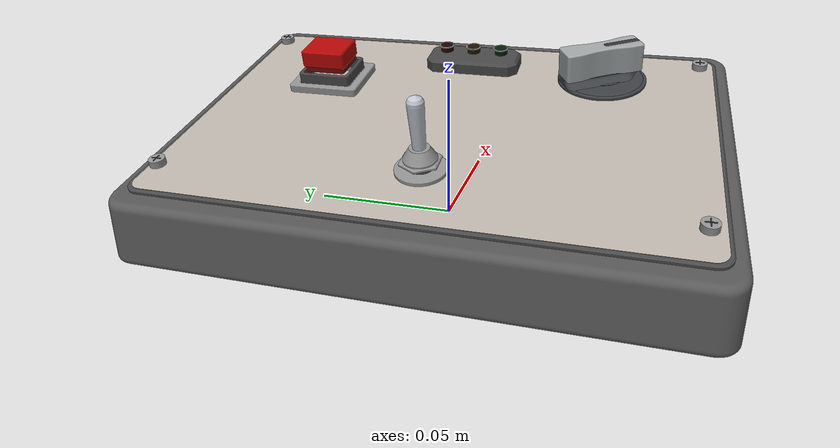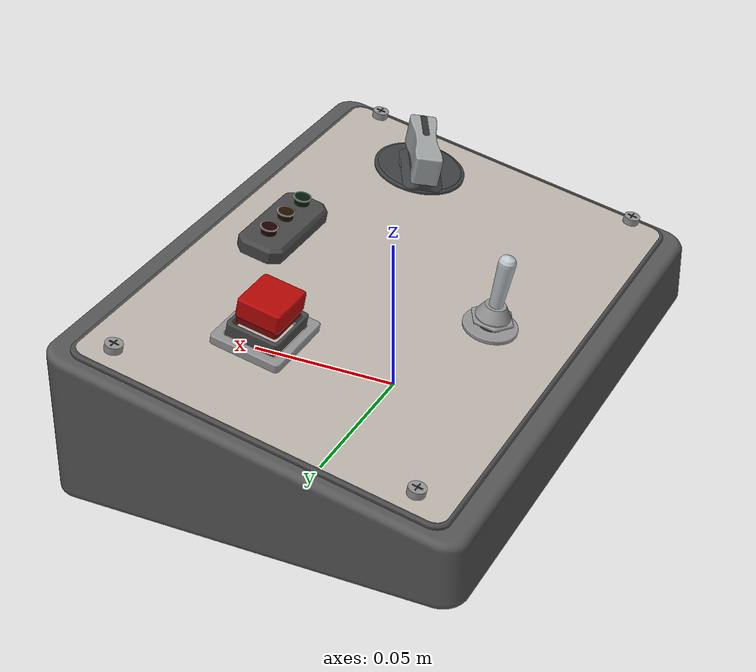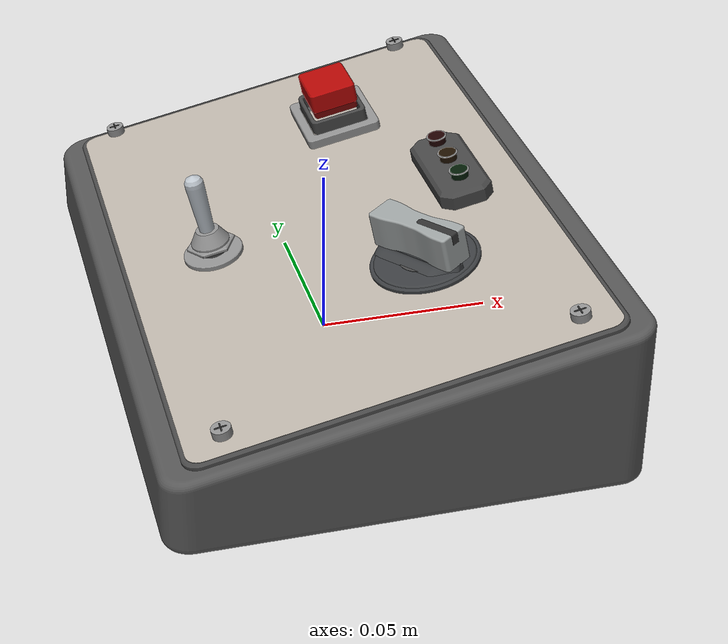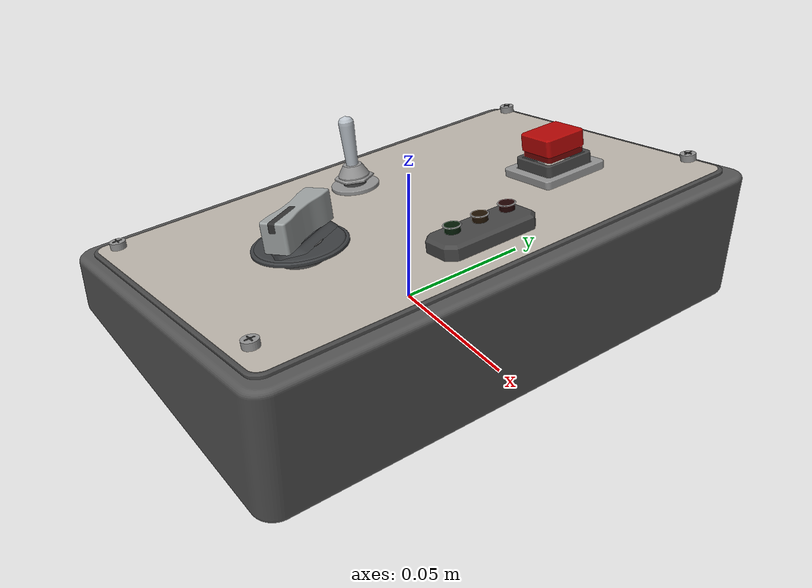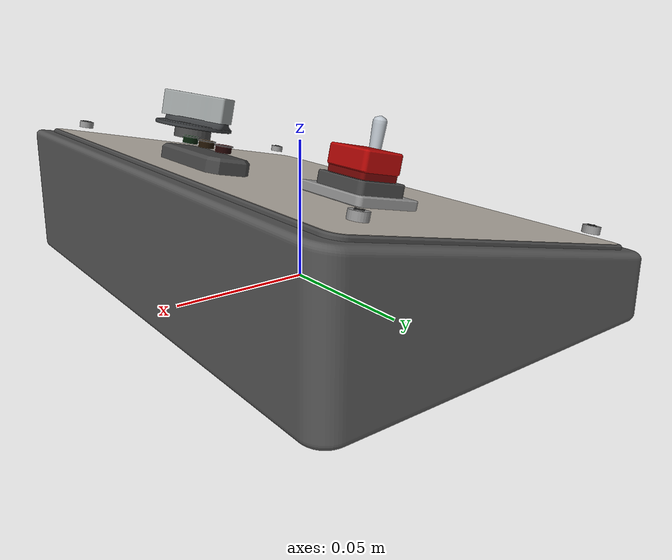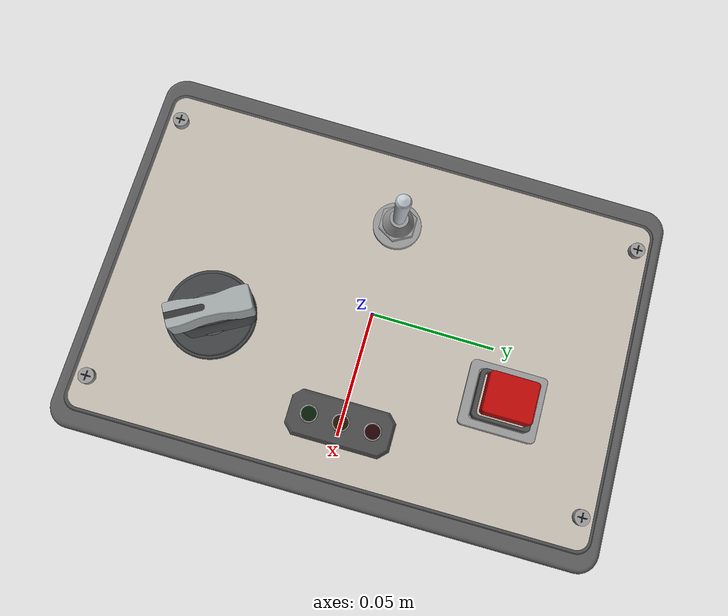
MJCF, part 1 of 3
<mujoco model="shakebench_control_panel">
  <!-- Visuals adapted from demo commit 22f526a; see SOURCES.md and asset license notices. -->
  <compiler angle="radian" inertiagrouprange="0 0" autolimits="true" />
  <option timestep="0.0002" integrator="implicitfast" />
  <asset>

    <mesh name="panel_annunciator_frame_mesh" vertex="-0.002380 0.014850 0.007735 -0.002380 -0.014850 0.007735 -0.002380 -0.017850 0.004735 -0.002380 -0.017850 -0.004735 -0.002380 -0.014850 -0.007735 -0.002380 0.014850 -0.007735 -0.002380 0.017850 -0.004735 -0.002380 0.017850 0.004735 0.001380 0.014850 0.007735 0.001380 -0.014850 0.007735 0.001380 -0.017850 0.004735 0.001380 -0.017850 -0.004735 0.001380 -0.014850 -0.007735 0.001380 0.014850 -0.007735 0.001380 0.017850 -0.004735 0.001380 0.017850 0.004735 0.002380 0.014350 0.006735 0.002380 -0.014350 0.006735 0.002380 -0.016850 0.004235 0.002380 -0.016850 -0.004235 0.002380 -0.014350 -0.006735 0.002380 0.014350 -0.006735 0.002380 0.016850 -0.004235 0.002380 0.016850 0.004235" face="0 2 1 16 17 18 0 3 2 16 18 19 0 4 3 16 19 20 0 5 4 16 20 21 0 6 5 16 21 22 0 7 6 16 22 23 0 1 9 0 9 8 1 2 10 1 10 9 2 3 11 2 11 10 3 4 12 3 12 11 4 5 13 4 13 12 5 6 14 5 14 13 6 7 15 6 15 14 7 0 8 7 8 15 8 9 17 8 17 16 9 10 18 9 18 17 10 11 19 10 19 18 11 12 20 11 20 19 12 13 21 12 21 20 13 14 22 13 22 21 14 15 23 14 23 22 15 8 16 15 16 23" />
    <texture name="panel_faceplate_print" type="2d" file="panel_faceplate_print.png" />
    <material name="panel_faceplate_print" texture="panel_faceplate_print" rgba="1 1 1 1" specular="0.22" shininess="0.22" emission="0.025" />
    <material name="panel_powder_coat" rgba=".34 .34 .34 1" specular="0.22" shininess="0.22" emission="0.025" />
    <material name="panel_brushed_metal" rgba="0.58 0.58 0.58 1" specular="0.65" shininess="0.42" emission="0.025" />
    <material name="panel_dark_metal" rgba=".29 .29 .29 1" specular="0.48" shininess="0.36" emission="0.025" />
    <material name="panel_rubber" rgba="0.28 0.28 0.28 1" specular="0.1" shininess="0.15" emission="0.025" />
    <material name="panel_knob_dial_finish" rgba=".24 .25 .26 1" specular="0.35" shininess="0.3" emission="0.025" />
    <material name="panel_knob_finish" rgba=".63 .65 .65 1" specular=".28" shininess=".24" emission=".015" />
    <material name="panel_button_finish" rgba=".72 .025 .018 1" specular="0.6" shininess="0.5" emission="0.035" />
    <material name="panel_button_band" rgba=".46 .016 .012 1" specular="0.45" shininess="0.38" emission="0" />
    <material name="panel_engraving" rgba="0.2 0.2 0.2 1" specular="0.05" shininess="0.1" emission="0" />
    <material name="panel_lens_0" rgba="0.0096 0.108 0.0216 1" specular="0.85" shininess="0.65" emission=".02" />
    <material name="panel_lens_1" rgba="0.12 0.066 0.0036 1" specular="0.85" shininess="0.65" emission=".02" />
    <material name="panel_lens_2" rgba="0.12 0.0048 0.003 1" specular="0.85" shininess="0.65" emission=".02" />
    <mesh name="panel_lever_bezel_mesh" vertex="-0.059782057 -0.012 -0.0011687476 -0.0588445127 -0.0119422167 -0.00045848675 -0.0579159974 -0.0117694234 0.000244933894 -0.0570054533 -0.011483284 0.000934740014 -0.0561216495 -0.0110865544 0.0016042884 -0.0552730973 -0.0105830552 0.00224713093 -0.0544679689 -0.00997763535 0.00285707668 -0.0537140181 -0.00927612544 0.00342825155 -0.0530185058 -0.00848528137 0.0039551548 -0.0523881302 -0.00761271941 0.00443271207 -0.0518289622 -0.0066668428 0.00485632422 -0.0513463868 -0.00565676084 0.00522191163 -0.0509450515 -0.00459220119 0.00552595351 -0.0506288214 -0.00348341613 0.00576552175 -0.050400742 -0.00234108386 0.00593830919 -0.0502630098 -0.00117620568 0.00604265178 -0.0502169512 -7.34788079e-19 0.00607754466 -0.0502630098 0.00117620568 0.00604265178 -0.050400742 0.00234108386 0.00593830919 -0.0506288214 0.00348341613 0.00576552175 -0.0509450515 0.00459220119 0.00552595351 -0.0513463868 0.00565676084 0.00522191163 -0.0518289622 0.0066668428 0.00485632422 -0.0523881302 0.00761271941 0.00443271207 -0.0530185058 0.00848528137 0.0039551548 -0.0537140181 0.00927612544 0.00342825155 -0.0544679689 0.00997763535 0.00285707668 -0.0552730973 0.0105830552 0.00224713093 -0.0561216495 0.0110865544 0.0016042884 -0.0570054533 0.011483284 0.000934740014 -0.0579159974 0.0117694234 0.000244933894 -0.0588445127 0.0119422167 -0.00045848675 -0.059782057 0.012 -0.0011687476 -0.0607196013 0.0119422167 -0.00187900844 -0.0616481165 0.0117694234 -0.00258242908 -0.0625586606 0.011483284 -0.0032722352 -0.0634424645 0.0110865544 -0.00394178359 -0.0642910166 0.0105830552 -0.00458462612 -0.065096145 0.00997763535 -0.00519457187 -0.0658500958 0.00927612544 -0.00576574674 -0.0665456081 0.00848528137 -0.00629264999 -0.0671759837 0.00761271941 -0.00677020726 -0.0677351518 0.0066668428 -0.00719381941 -0.0682177272 0.00565676084 -0.00755940682 -0.0686190624 0.00459220119 -0.0078634487 -0.0689352925 0.00348341613 -0.00810301694 -0.0691633719 0.00234108386 -0.00827580438 -0.0693011041 0.00117620568 -0.00838014697 -0.0693471627 2.20436424e-18 -0.00841503985 -0.0693011041 -0.00117620568 -0.00838014697 -0.0691633719 -0.00234108386 -0.00827580438 -0.0689352925 -0.00348341613 -0.00810301694 -0.0686190624 -0.00459220119 -0.0078634487 -0.0682177272 -0.00565676084 -0.00755940682 -0.0677351518 -0.0066668428 -0.00719381941 -0.0671759837 -0.00761271941 -0.00677020726 -0.0665456081 -0.00848528137 -0.00629264999 -0.0658500958 -0.00927612544 -0.00576574674 -0.065096145 -0.00997763535 -0.00519457187 -0.0642910166 -0.0105830552 -0.00458462612 -0.0634424645 -0.0110865544 -0.00394178359 -0.0625586606 -0.011483284 -0.0032722352 -0.0616481165 -0.0117694234 -0.00258242908 -0.0607196013 -0.0119422167 -0.00187900844 -0.0593593566 -0.0127 -0.0017267121 -0.0583671222 -0.012638846 -0.000975019371 -0.0573844435 -0.0124559731 -0.000230565856 -0.0564207844 -0.0121531423 0.000499478954 -0.0554854253 -0.0117332701 0.00120808433 -0.0545873743 -0.0112004001 0.00188842601 -0.0537352801 -0.0105596641 0.00253395193 -0.0529373488 -0.00981723276 0.00313844533 -0.0522012649 -0.00898025612 0.0036960846 -0.0515341174 -0.00805679471 0.00420149938 -0.0509423313 -0.00705574196 0.00464982224 -0.0504316056 -0.00598673856 0.00503673558 -0.0500068591 -0.00486007959 0.00535851323 -0.0496721823 -0.0036866154 0.00561205629 -0.0494307983 -0.00247764709 0.005794923 -0.0492850317 -0.00124481768 0.00590535224 -0.0492362863 -7.77650717e-19 0.00594228054 -0.0492850317 0.00124481768 0.00590535224 -0.0494307983 0.00247764709 0.005794923 -0.0496721823 0.0036866154 0.00561205629 -0.0500068591 0.00486007959 0.00535851323 -0.0504316056 0.00598673856 0.00503673558 -0.0509423313 0.00705574196 0.00464982224 -0.0515341174 0.00805679471 0.00420149938 -0.0522012649 0.00898025612 0.0036960846 -0.0529373488 0.00981723276 0.00313844533 -0.0537352801 0.0105596641 0.00253395193 -0.0545873743 0.0112004001 0.00188842601 -0.0554854253 0.0117332701 0.00120808433 -0.0564207844 0.0121531423 0.000499478954 -0.0573844435 0.0124559731 -0.000230565856 -0.0583671222 0.012638846 -0.000975019371 -0.0593593566 0.0127 -0.0017267121 -0.060351591 0.012638846 -0.00247840483 -0.0613342696 0.0124559731 -0.00322285834 -0.0622979288 0.0121531423 -0.00395290315 -0.0632332879 0.0117332701 -0.00466150852 -0.0641313389 0.0112004001 -0.0053418502 -0.0649834331 0.0105596641 -0.00598737613 -0.0657813644 0.00981723276 -0.00659186952 -0.0665174482 0.00898025612 -0.0071495088 -0.0671845957 0.00805679471 -0.00765492357 -0.0677763819 0.00705574196 -0.00810324643 -0.0682871075 0.00598673856 -0.00849015978 -0.068711854 0.00486007959 -0.00881193743 -0.0690465309 0.0036866154 -0.00906548049 -0.0692879149 0.00247764709 -0.00924834719 -0.0694336815 0.00124481768 -0.00935877644 -0.0694824269 2.33295215e-18 -0.00939570474 -0.0694336815 -0.00124481768 -0.00935877644 -0.0692879149 -0.00247764709 -0.00924834719 -0.0690465309 -0.0036866154 -0.00906548049 -0.068711854 -0.00486007959 -0.00881193743 -0.0682871075 -0.00598673856 -0.00849015978 -0.0677763819 -0.00705574196 -0.00810324643 -0.0671845957 -0.00805679471 -0.00765492357 -0.0665174482 -0.00898025612 -0.0071495088 -0.0657813644 -0.00981723276 -0.00659186952 -0.0649834331 -0.0105596641 -0.00598737613 -0.0641313389 -0.0112004001 -0.0053418502 -0.0632332879 -0.0117332701 -0.00466150852 -0.0622979288 -0.0121531423 -0.00395290315 -0.0613342696 -0.0124559731 -0.00322285834 -0.060351591 -0.012638846 -0.00247840483 -0.0593593566 -0.0283 -0.0017267121 -0.0571483146 -0.0281637278 -5.1680273e-05 -0.0549585661 -0.0277562234 0.00160722008 -0.0528111997 -0.0270814115 0.00323401285 -0.0507268955 -0.0261457908 0.00481303112 -0.0487257267 -0.0249583718 0.00632906809 -0.0468269656 -0.02353059 0.00776752349 -0.0450488983 -0.0218761958 0.00911454421 -0.0434086484 -0.0200111219 0.0103571577 -0.0419220127 -0.0179533299 0.0114833969 -0.040603308 -0.0157226376 0.0124824156 -0.0394652344 -0.0133405277 0.0133445926 -0.0385187521 -0.0108299411 0.0140616247 -0.0377729761 -0.00821505637 0.0146266064 -0.0372350888 -0.00552105611 0.0150340968 -0.0369102703 -0.00277388507 0.0152801714 -0.0368016488 -1.73287522e-18 0.0153624605 -0.0369102703 0.00277388507 0.0152801714 -0.0372350888 0.00552105611 0.0150340968 -0.0377729761 0.00821505637 0.0146266064 -0.0385187521 0.0108299411 0.0140616247 -0.0394652344 0.0133405277 0.0133445926 -0.040603308 0.0157226376 0.0124824156 -0.0419220127 0.0179533299 0.0114833969 -0.0434086484 0.0200111219 0.0103571577 -0.0450488983 0.0218761958 0.00911454421 -0.0468269656 0.02353059 0.00776752349 -0.0487257267 0.0249583718 0.00632906809 -0.0507268955 0.0261457908 0.00481303112 -0.0528111997 0.0270814115 0.00323401285 -0.0549585661 0.0277562234 0.00160722008 -0.0571483146 0.0281637278 -5.1680273e-05 -0.0593593566 0.0283 -0.0017267121 -0.0615703986 0.0281637278 -0.00340174392 -0.0637601471 0.0277562234 -0.00506064428 -0.0659075135 0.0270814115 -0.00668743704 -0.0679918176 0.0261457908 -0.00826645531 -0.0699929864 0.0249583718 -0.00978249228 -0.0718917476 0.02353059 -0.0112209477 -0.0736698149 0.0218761958 -0.0125679684 -0.0753100647 0.0200111219 -0.0138105819 -0.0767967005 0.0179533299 -0.0149368211 -0.0781154051 0.0157226376 -0.0159358398 -0.0792534788 0.0133405277 -0.0167980168 -0.0801999611 0.0108299411 -0.0175150489 -0.0809457371 0.00821505637 -0.0180800306 -0.0814836244 0.00552105611 -0.018487521 -0.0818084429 0.00277388507 -0.0187335956 -0.0819170644 5.19862566e-18 -0.0188158847 -0.0818084429 -0.00277388507 -0.0187335956 -0.0814836244 -0.00552105611 -0.018487521 -0.0809457371 -0.00821505637 -0.0180800306 -0.0801999611 -0.0108299411 -0.0175150489 -0.0792534788 -0.0133405277 -0.0167980168 -0.0781154051 -0.0157226376 -0.0159358398 -0.0767967005 -0.0179533299 -0.0149368211 -0.0753100647 -0.0200111219 -0.0138105819 -0.0736698149 -0.0218761958 -0.0125679684 -0.0718917476 -0.02353059 -0.0112209477 -0.0699929864 -0.0249583718 -0.00978249228 -0.0679918176 -0.0261457908 -0.00826645531 -0.0659075135 -0.0270814115 -0.00668743704 -0.0637601471 -0.0277562234 -0.00506064428 -0.0615703986 -0.0281637278 -0.00340174392 -0.059782057 -0.029 -0.0011687476 -0.0575163249 -0.0288603571 0.000547716113 -0.055272413 -0.0284427731 0.00224764934 -0.0530719315 -0.0277512697 0.00391468079 -0.0509360722 -0.0267925064 0.00553275605 -0.0488854045 -0.0255757167 0.00708629217 -0.0469396775 -0.0241126188 0.00856032774 -0.0451176297 -0.0224173031 0.009940667 -0.0434368083 -0.0205060967 0.0112140165 -0.0419134006 -0.0183974052 0.0123681133 -0.0405620779 -0.0161115368 0.0133918426 -0.039395854 -0.0136705054 0.0142753455 -0.0384259605 -0.0110978195 0.0150101134 -0.0376617378 -0.00841825564 0.01558907 -0.0371105458 -0.00565761934 0.0160066396 -0.036777693 -0.00284249707 0.0162588009 -0.0366663847 -1.77573786e-18 0.0163431254 -0.036777693 0.00284249707 0.0162588009 -0.0371105458 0.00565761934 0.0160066396 -0.0376617378 0.00841825564 0.01558907 -0.0384259605 0.0110978195 0.0150101134 -0.039395854 0.0136705054 0.0142753455 -0.0405620779 0.0161115368 0.0133918426 -0.0419134006 0.0183974052 0.0123681133 -0.0434368083 0.0205060967 0.0112140165 -0.0451176297 0.0224173031 0.009940667 -0.0469396775 0.0241126188 0.00856032774 -0.0488854045 0.0255757167 0.00708629217 -0.0509360722 0.0267925064 0.00553275605 -0.0530719315 0.0277512697 0.00391468079 -0.055272413 0.0284427731 0.00224764934 -0.0575163249 0.0288603571 0.000547716113 -0.059782057 0.029 -0.0011687476 -0.0620477891 0.0288603571 -0.0028852113 -0.0642917009 0.0284427731 -0.00458514453 -0.0664921824 0.0277512697 -0.00625217598 -0.0686280418 0.0267925064 -0.00787025124 -0.0706787095 0.0255757167 -0.00942378736 -0.0726244364 0.0241126188 -0.0108978229 -0.0744464842 0.0224173031 -0.0122781622 -0.0761273056 0.0205060967 -0.0135515117 -0.0776507133 0.0183974052 -0.0147056084 -0.0790020361 0.0161115368 -0.0157293378 -0.0801682599 0.0136705054 -0.0166128407 -0.0811381535 0.0110978195 -0.0173476086 -0.0819023762 0.00841825564 -0.0179265652 -0.0824535681 0.00565761934 -0.0183441348 -0.082786421 0.00284249707 -0.0185962961 -0.0828977293 5.32721358e-18 -0.0186806205 -0.082786421 -0.00284249707 -0.0185962961 -0.0824535681 -0.00565761934 -0.0183441348 -0.0819023762 -0.00841825564 -0.0179265652 -0.0811381535 -0.0110978195 -0.0173476086 -0.0801682599 -0.0136705054 -0.0166128407 -0.0790020361 -0.0161115368 -0.0157293378 -0.0776507133 -0.0183974052 -0.0147056084 -0.0761273056 -0.0205060967 -0.0135515117 -0.0744464842 -0.0224173031 -0.0122781622 -0.0726244364 -0.0241126188 -0.0108978229 -0.0706787095 -0.0255757167 -0.00942378736 -0.0686280418 -0.0267925064 -0.00787025124 -0.0664921824 -0.0277512697 -0.00625217598 -0.0642917009 -0.0284427731 -0.00458514453 -0.0620477891 -0.0288603571 -0.0028852113 -0.0619559446 -0.029 0.00170078414 -0.0596902126 -0.0288603571 0.00341724785 -0.0574463007 -0.0284427731 0.00511718107 -0.0552458192 -0.0277512697 0.00678421253 -0.0531099598 -0.0267925064 0.00840228779 -0.0510592922 -0.0255757167 0.0099558239 -0.0491135652 -0.0241126188 0.0114298595 -0.0472915174 -0.0224173031 0.0128101987 -0.045610696 -0.0205060967 0.0140835483 -0.0440872883 -0.0183974052 0.015237645 -0.0427359656 -0.0161115368 0.0162613744 -0.0415697417 -0.0136705054 0.0171448773 -0.0405998481 -0.0110978195 0.0178796451 -0.0398356254 -0.00841825564 0.0184586017 -0.0392844335 -0.00565761934 0.0188761714 -0.0389515806 -0.00284249707 0.0191283326 -0.0388402724 -1.77573786e-18 0.0192126571 -0.0389515806 0.00284249707 0.0191283326 -0.0392844335 0.00565761934 0.0188761714 -0.0398356254 0.00841825564 0.0184586017 -0.0405998481 0.0110978195 0.0178796451 -0.0415697417 0.0136705054 0.0171448773 -0.0427359656 0.0161115368 0.0162613744 -0.0440872883 0.0183974052 0.015237645 -0.045610696 0.0205060967 0.0140835483 -0.0472915174 0.0224173031 0.0128101987 -0.0491135652 0.0241126188 0.0114298595 -0.0510592922 0.0255757167 0.0099558239 -0.0531099598 0.0267925064 0.00840228779 -0.0552458192 0.0277512697 0.00678421253 -0.0574463007 0.0284427731 0.00511718107 -0.0596902126 0.0288603571 0.00341724785 -0.0619559446 0.029 0.00170078414 -0.0642216767 0.0288603571 -1.56795705e-05 -0.0664655886 0.0284427731 -0.0017156128 -0.0686660701 0.0277512697 -0.00338264425 -0.0708019295 0.0267925064 -0.00500071951 -0.0728525971 0.0255757167 -0.00655425563 -0.0747983241 0.0241126188 -0.0080282912 -0.0766203719 0.0224173031 -0.00940863046 -0.0783011933 0.0205060967 -0.01068198 -0.079824601 0.0183974052 -0.0118360767 -0.0811759237 0.0161115368 -0.0128598061 -0.0823421476 0.0136705054 -0.013743309 -0.0833120412 0.0110978195 -0.0144780769 -0.0840762639 0.00841825564 -0.0150570334 -0.0846274558 0.00565761934 -0.0154746031 -0.0849603087 0.00284249707 -0.0157267644 -0.0850716169 5.32721358e-18 -0.0158110888 -0.0849603087 -0.00284249707 -0.0157267644 -0.0846274558 -0.00565761934 -0.0154746031 -0.0840762639 -0.00841825564 -0.0150570334 -0.0833120412 -0.0110978195 -0.0144780769 -0.0823421476 -0.0136705054 -0.013743309 -0.0811759237 -0.0161115368 -0.0128598061 -0.079824601 -0.0183974052 -0.0118360767 -0.0783011933 -0.0205060967 -0.01068198 -0.0766203719 -0.0224173031 -0.00940863046 -0.0747983241 -0.0241126188 -0.0080282912 -0.0728525971 -0.0255757167 -0.00655425563 -0.0708019295 -0.0267925064 -0.00500071951 -0.0686660701 -0.0277512697 -0.00338264425 -0.0664655886 -0.0284427731 -0.0017156128 -0.0642216767 -0.0288603571 -1.56795705e-05 -0.062378645 -0.0283 0.00225874864 -0.060167603 -0.0281637278 0.00393378047 -0.0579778546 -0.0277562234 0.00559268082 -0.0558304881 -0.0270814115 0.00721947359 -0.053746184 -0.0261457908 0.00879849186 -0.0517450152 -0.0249583718 0.0103145288 -0.0498462541 -0.02353059 0.0117529842 -0.0480681867 -0.0218761958 0.013100005 -0.0464279369 -0.0200111219 0.0143426185 -0.0449413011 -0.0179533299 0.0154688577 -0.0436225965 -0.0157226376 0.0164678763 -0.0424845229 -0.0133405277 0.0173300533 -0.0415380405 -0.0108299411 0.0180470854 -0.0407922646 -0.00821505637 0.0186120672 -0.0402543773 -0.00552105611 0.0190195576 -0.0399295588 -0.00277388507 0.0192656322 -0.0398209372 -1.73287522e-18 0.0193479212 -0.0399295588 0.00277388507 0.0192656322 -0.0402543773 0.00552105611 0.0190195576 -0.0407922646 0.00821505637 0.0186120672 -0.0415380405 0.0108299411 0.0180470854 -0.0424845229 0.0133405277 0.0173300533 -0.0436225965 0.0157226376 0.0164678763 -0.0449413011 0.0179533299 0.0154688577 -0.0464279369 0.0200111219 0.0143426185 -0.0480681867 0.0218761958 0.013100005 -0.0498462541 0.02353059 0.0117529842 -0.0517450152 0.0249583718 0.0103145288 -0.053746184 0.0261457908 0.00879849186 -0.0558304881 0.0270814115 0.00721947359 -0.0579778546 0.0277562234 0.00559268082 -0.060167603 0.0281637278 0.00393378047 -0.062378645 0.0283 0.00225874864 -0.064589687 0.0281637278 0.000583716816 -0.0667794355 0.0277562234 -0.00107518354 -0.068926802 0.0270814115 -0.0027019763 -0.0710111061 0.0261457908 -0.00428099457 -0.0730122749 0.0249583718 -0.00579703154 -0.074911036 0.02353059 -0.00723548695 -0.0766891034 0.0218761958 -0.00858250767 -0.0783293532 0.0200111219 -0.00982512117 -0.079815989 0.0179533299 -0.0109513604 -0.0811346936 0.0157226376 -0.011950379 -0.0822727672 0.0133405277 -0.012812556 -0.0832192496 0.0108299411 -0.0135295881 -0.0839650255 0.00821505637 -0.0140945699 -0.0845029128 0.00552105611 -0.0145020603 -0.0848277313 0.00277388507 -0.0147481349 -0.0849363528 5.19862566e-18 -0.0148304239 -0.0848277313 -0.00277388507 -0.0147481349 -0.0845029128 -0.00552105611 -0.0145020603 -0.0839650255 -0.00821505637 -0.0140945699 -0.0832192496 -0.0108299411 -0.0135295881 -0.0822727672 -0.0133405277 -0.012812556 -0.0811346936 -0.0157226376 -0.011950379 -0.079815989 -0.0179533299 -0.0109513604 -0.0783293532 -0.0200111219 -0.00982512117 -0.0766891034 -0.0218761958 -0.00858250767 -0.074911036 -0.02353059 -0.00723548695 -0.0730122749 -0.0249583718 -0.00579703154 -0.0710111061 -0.0261457908 -0.00428099457 -0.068926802 -0.0270814115 -0.0027019763 -0.0667794355 -0.0277562234 -0.00107518354 -0.064589687 -0.0281637278 0.000583716816 -0.062378645 -0.0127 0.00225874864 -0.0613864106 -0.012638846 0.00301044137 -0.060403732 -0.0124559731 0.00375489488 -0.0594400728 -0.0121531423 0.00448493969 -0.0585047137 -0.0117332701 0.00519354507 -0.0576066627 -0.0112004001 0.00587388675 -0.0567545685 -0.0105596641 0.00651941267 -0.0559566372 -0.00981723276 0.00712390607 -0.0552205534 -0.00898025612 0.00768154534 -0.0545534059 -0.00805679471 0.00818696012 -0.0539616197 -0.00705574196 0.00863528298 -0.0534508941 -0.00598673856 0.00902219632 -0.0530261476 -0.00486007959 0.00934397397 -0.0526914708 -0.0036866154 0.00959751703 -0.0524500867 -0.00247764709 0.00978038374 -0.0523043201 -0.00124481768 0.00989081298 -0.0522555747 -7.77650717e-19 0.00992774128 -0.0523043201 0.00124481768 0.00989081298 -0.0524500867 0.00247764709 0.00978038374 -0.0526914708 0.0036866154 0.00959751703 -0.0530261476 0.00486007959 0.00934397397 -0.0534508941 0.00598673856 0.00902219632 -0.0539616197 0.00705574196 0.00863528298 -0.0545534059 0.00805679471 0.00818696012 -0.0552205534 0.00898025612 0.00768154534 -0.0559566372 0.00981723276 0.00712390607 -0.0567545685 0.0105596641 0.00651941267 -0.0576066627 0.0112004001 0.00587388675 -0.0585047137 0.0117332701 0.00519354507 -0.0594400728 0.0121531423 0.00448493969 -0.060403732 0.0124559731 0.00375489488 -0.0613864106 0.012638846 0.00301044137 -0.062378645 0.0127 0.00225874864 -0.0633708794 0.012638846 0.00150705591 -0.0643535581 0.0124559731 0.000762602399 -0.0653172172 0.0121531423 3.25575891e-05 -0.0662525763 0.0117332701 -0.000676047784 -0.0671506273 0.0112004001 -0.00135638946 -0.0680027215 0.0105596641 -0.00200191538 -0.0688006528 0.00981723276 -0.00260640878 -0.0695367367 0.00898025612 -0.00316404806 -0.0702038842 0.00805679471 -0.00366946283 -0.0707956704 0.00705574196 -0.00411778569 -0.071306396 0.00598673856 -0.00450469904 -0.0717311425 0.00486007959 -0.00482647669 -0.0720658193 0.0036866154 -0.00508001975 -0.0723072034 0.00247764709 -0.00526288645 -0.07245297 0.00124481768 -0.0053733157 -0.0725017153 2.33295215e-18 -0.005410244 -0.07245297 -0.00124481768 -0.0053733157 -0.0723072034 -0.00247764709 -0.00526288645 -0.0720658193 -0.0036866154 -0.00508001975 -0.0717311425 -0.00486007959 -0.00482647669 -0.071306396 -0.00598673856 -0.00450469904 -0.0707956704 -0.00705574196 -0.00411778569 -0.0702038842 -0.00805679471 -0.00366946283 -0.0695367367 -0.00898025612 -0.00316404806 -0.0688006528 -0.00981723276 -0.00260640878 -0.0680027215 -0.0105596641 -0.00200191538 -0.0671506273 -0.0112004001 -0.00135638946 -0.0662525763 -0.0117332701 -0.000676047784 -0.0653172172 -0.0121531423 3.25575891e-05 -0.0643535581 -0.0124559731 0.000762602399 -0.0633708794 -0.012638846 0.00150705591 -0.0619559446 -0.012 0.00170078414 -0.0610184003 -0.0119422167 0.00241104498 -0.0600898851 -0.0117694234 0.00311446563 -0.059179341 -0.011483284 0.00380427175 -0.0582955371 -0.0110865544 0.00447382013 -0.057446985 -0.0105830552 0.00511666266 -0.0566418566 -0.00997763535 0.00572660842 -0.0558879058 -0.00927612544 0.00629778328 -0.0551923935 -0.00848528137 0.00682468653 -0.0545620179 -0.00761271941 0.0073022438 -0.0540028499 -0.0066668428 0.00772585595 -0.0535202745 -0.00565676084 0.00809144337 -0.0531189392 -0.00459220119 0.00839548524 -0.0528027091 -0.00348341613 0.00863505348 -0.0525746297 -0.00234108386 0.00880784092 -0.0524368975 -0.00117620568 0.00891218352 -0.0523908389 -7.34788079e-19 0.00894707639 -0.0524368975 0.00117620568 0.00891218352 -0.0525746297 0.00234108386 0.00880784092 -0.0528027091 0.00348341613 0.00863505348 -0.0531189392 0.00459220119 0.00839548524 -0.0535202745 0.00565676084 0.00809144337 -0.0540028499 0.0066668428 0.00772585595 -0.0545620179 0.00761271941 0.0073022438 -0.0551923935 0.00848528137 0.00682468653 -0.0558879058 0.00927612544 0.00629778328 -0.0566418566 0.00997763535 0.00572660842 -0.057446985 0.0105830552 0.00511666266 -0.0582955371 0.0110865544 0.00447382013 -0.059179341 0.011483284 0.00380427175 -0.0600898851 0.0117694234 0.00311446563 -0.0610184003 0.0119422167 0.00241104498 -0.0619559446 0.012 0.00170078414 -0.062893489 0.0119422167 0.000990523293 -0.0638220042 0.0117694234 0.000287102648 -0.0647325483 0.011483284 -0.000402703471 -0.0656163522 0.0110865544 -0.00107225185 -0.0664649043 0.0105830552 -0.00171509439 -0.0672700327 0.00997763535 -0.00232504014 -0.0680239835 0.00927612544 -0.002896215 -0.0687194958 0.00848528137 -0.00342311825 -0.0693498714 0.00761271941 -0.00390067552 -0.0699090394 0.0066668428 -0.00432428767 -0.0703916148 0.00565676084 -0.00468987509 -0.0707929501 0.00459220119 -0.00499391696 -0.0711091802 0.00348341613 -0.00523348521 -0.0713372596 0.00234108386 -0.00540627264 -0.0714749918 0.00117620568 -0.00551061524 -0.0715210504 2.20436424e-18 -0.00554550812 -0.0714749918 -0.00117620568 -0.00551061524 -0.0713372596 -0.00234108386 -0.00540627264 -0.0711091802 -0.00348341613 -0.00523348521 -0.0707929501 -0.00459220119 -0.00499391696 -0.0703916148 -0.00565676084 -0.00468987509 -0.0699090394 -0.0066668428 -0.00432428767 -0.0693498714 -0.00761271941 -0.00390067552 -0.0687194958 -0.00848528137 -0.00342311825 -0.0680239835 -0.00927612544 -0.002896215 -0.0672700327 -0.00997763535 -0.00232504014 -0.0664649043 -0.0105830552 -0.00171509439 -0.0656163522 -0.0110865544 -0.00107225185 -0.0647325483 -0.011483284 -0.000402703471 -0.0638220042 -0.0117694234 0.000287102648 -0.062893489 -0.0119422167 0.000990523293" face="0 1 65 0 65 64 1 2 66 1 66 65 2 3 67 2 67 66 3 4 68 3 68 67 4 5 69 4 69 68 5 6 70 5 70 69 6 7 71 6 71 70 7 8 72 7 72 71 8 9 73 8 73 72 9 10 74 9 74 73 10 11 75 10 75 74 11 12 76 11 76 75 12 13 77 12 77 76 13 14 78 13 78 77 14 15 79 14 79 78 15 16 80 15 80 79 16 17 81 16 81 80 17 18 82 17 82 81 18 19 83 18 83 82 19 20 84 19 84 83 20 21 85 20 85 84 21 22 86 21 86 85 22 23 87 22 87 86 23 24 88 23 88 87 24 25 89 24 89 88 25 26 90 25 90 89 26 27 91 26 91 90 27 28 92 27 92 91 28 29 93 28 93 92 29 30 94 29 94 93 30 31 95 30 95 94 31 32 96 31 96 95 32 33 97 32 97 96 33 34 98 33 98 97 34 35 99 34 99 98 35 36 100 35 100 99 36 37 101 36 101 100 37 38 102 37 102 101 38 39 103 38 103 102 39 40 104 39 104 103 40 41 105 40 105 104 41 42 106 41 106 105 42 43 107 42 107 106 43 44 108 43 108 107 44 45 109 44 109 108 45 46 110 45 110 109 46 47 111 46 111 110 47 48 112 47 112 111 48 49 113 48 113 112 49 50 114 49 114 113 50 51 115 50 115 114 51 52 116 51 116 115 52 53 117 52 117 116 53 54 118 53 118 117 54 55 119 54 119 118 55 56 120 55 120 119 56 57 121 56 121 120 57 58 122 57 122 121 58 59 123 58 123 122 59 60 124 59 124 123 60 61 125 60 125 124 61 62 126 61 126 125 62 63 127 62 127 126 63 0 64 63 64 127 64 65 129 64 129 128 65 66 130 65 130 129 66 67 131 66 131 130 67 68 132 67 132 131 68 69 133 68 133 132 69 70 134 69 134 133 70 71 135 70 135 134 71 72 136 71 136 135 72 73 137 72 137 136 73 74 138 73 138 137 74 75 139 74 139 138 75 76 140 75 140 139 76 77 141 76 141 140 77 78 142 77 142 141 78 79 143 78 143 142 79 80 144 79 144 143 80 81 145 80 145 144 81 82 146 81 146 145 82 83 147 82 147 146 83 84 148 83 148 147 84 85 149 84 149 148 85 86 150 85 150 149 86 87 151 86 151 150 87 88 152 87 152 151 88 89 153 88 153 152 89 90 154 89 154 153 90 91 155 90 155 154 91 92 156 91 156 155 92 93 157 92 157 156 93 94 158 93 158 157 94 95 159 94 159 158 95 96 160 95 160 159 96 97 161 96 161 160 97 98 162 97 162 161 98 99 163 98 163 162 99 100 164 99 164 163 100 101 165 100 165 164 101 102 166 101 166 165 102 103 167 102 167 166 103 104 168 103 168 167 104 105 169 104 169 168 105 106 170 105 170 169 106 107 171 106 171 170 107 108 172 107 172 171 108 109 173 108 173 172 109 110 174 109 174 173 110 111 175 110 175 174 111 112 176 111 176 175 112 113 177 112 177 176 113 114 178 113 178 177 114 115 179 114 179 178 115 116 180 115 180 179 116 117 181 116 181 180 117 118 182 117 182 181 118 119 183 118 183 182 119 120 184 119 184 183 120 121 185 120 185 184 121 122 186 121 186 185 122 123 187 122 187 186 123 124 188 123 188 187 124 125 189 124 189 188 125 126 190 125 190 189 126 127 191 126 191 190 127 64 128 127 128 191 128 129 193 128 193 192 129 130 194 129 194 193 130 131 195 130 195 194 131 132 196 131 196 195 132 133 197 132 197 196 133 134 198 133 198 197 134 135 199 134 199 198 135 136 200 135 200 199 136 137 201 136 201 200 137 138 202 137 202 201 138 139 203 138 203 202 139 140 204 139 204 203 140 141 205 140 205 204 141 142 206 141 206 205 142 143 207 142 207 206 143 144 208 143 208 207 144 145 209 144 209 208 145 146 210 145 210 209 146 147 211 146 211 210 147 148 212 147 212 211 148 149 213 148 213 212 149 150 214 149 214 213 150 151 215 150 215 214 151 152 216 151 216 215 152 153 217 152 217 216 153 154 218 153 218 217 154 155 219 154 219 218 155 156 220 155 220 219 156 157 221 156 221 220 157 158 222 157 222 221 158 159 223 158 223 222 159 160 224 159 224 223 160 161 225 160 225 224 161 162 226 161 226 225 162 163 227 162 227 226 163 164 228 163 228 227 164 165 229 164 229 228 165 166 230 165 230 229 166 167 231 166 231 230 167 168 232 167 232 231 168 169 233 168 233 232 169 170 234 169 234 233 170 171 235 170 235 234 171 172 236 171 236 235 172 173 237 172 237 236 173 174 238 173 238 237 174 175 239 174 239 238 175 176 240 175 240 239 176 177 241 176 241 240 177 178 242 177 242 241 178 179 243 178 243 242 179 180 244 179 244 243 180 181 245 180 245 244 181 182 246 181 246 245 182 183 247 182 247 246 183 184 248 183 248 247 184 185 249 184 249 248 185 186 250 185 250 249 186 187 251 186 251 250 187 188 252 187 252 251 188 189 253 188 253 252 189 190 254 189 254 253 190 191 255 190 255 254 191 128 192 191 192 255 192 193 257 192 257 256 193 194 258 193 258 257 194 195 259 194 259 258 195 196 260 195 260 259 196 197 261 196 261 260 197 198 262 197 262 261 198 199 263 198 263 262 199 200 264 199 264 263 200 201 265 200 265 264 201 202 266 201 266 265 202 203 267 202 267 266 203 204 268 203 268 267 204 205 269 204 269 268 205 206 270 205 270 269 206 207 271 206 271 270 207 208 272 207 272 271 208 209 273 208 273 272 209 210 274 209 274 273 210 211 275 210 275 274 211 212 276 211 276 275 212 213 277 212 277 276 213 214 278 213 278 277 214 215 279 214 279 278 215 216 280 215 280 279 216 217 281 216 281 280 217 218 282 217 282 281 218 219 283 218 283 282 219 220 284 219 284 283 220 221 285 220 285 284 221 222 286 221 286 285 222 223 287 222 287 286 223 224 288 223 288 287 224 225 289 224 289 288 225 226 290 225 290 289 226 227 291 226 291 290 227 228 292 227 292 291 228 229 293 228 293 292 229 230 294 229 294 293 230 231 295 230 295 294 231 232 296 231 296 295 232 233 297 232 297 296 233 234 298 233 298 297 234 235 299 234 299 298 235 236 300 235 300 299 236 237 301 236 301 300 237 238 302 237 302 301 238 239 303 238 303 302 239 240 304 239 304 303 240 241 305 240 305 304 241 242 306 241 306 305 242 243 307 242 307 306 243 244 308 243 308 307 244 245 309 244 309 308 245 246 310 245 310 309 246 247 311 246 311 310 247 248 312 247 312 311 248 249 313 248 313 312 249 250 314 249 314 313 250 251 315 250 315 314 251 252 316 251 316 315 252 253 317 252 317 316 253 254 318 253 318 317 254 255 319 254 319 318 255 192 256 255 256 319 256 257 321 256 321 320 257 258 322 257 322 321 258 259 323 258 323 322 259 260 324 259 324 323 260 261 325 260 325 324 261 262 326 261 326 325 262 263 327 262 327 326 263 264 328 263 328 327 264 265 329 264 329 328 265 266 330 265 330 329 266 267 331 266 331 330 267 268 332 267 332 331 268 269 333 268 333 332 269 270 334 269 334 333 270 271 335 270 335 334 271 272 336 271 336 335 272 273 337 272 337 336 273 274 338 273 338 337 274 275 339 274 339 338 275 276 340 275 340 339 276 277 341 276 341 340 277 278 342 277 342 341 278 279 343 278 343 342 279 280 344 279 344 343 280 281 345 280 345 344 281 282 346 281 346 345 282 283 347 282 347 346 283 284 348 283 348 347 284 285 349 284 349 348 285 286 350 285 350 349 286 287 351 286 351 350 287 288 352 287 352 351 288 289 353 288 353 352 289 290 354 289 354 353 290 291 355 290 355 354 291 292 356 291 356 355 292 293 357 292 357 356 293 294 358 293 358 357 294 295 359 294 359 358 295 296 360 295 360 359 296 297 361 296 361 360 297 298 362 297 362 361 298 299 363 298 363 362 299 300 364 299 364 363 300 301 365 300 365 364 301 302 366 301 366 365 302 303 367 302 367 366 303 304 368 303 368 367 304 305 369 304 369 368 305 306 370 305 370 369 306 307 371 306 371 370 307 308 372 307 372 371 308 309 373 308 373 372 309 310 374 309 374 373 310 311 375 310 375 374 311 312 376 311 376 375 312 313 377 312 377 376 313 314 378 313 378 377 314 315 379 314 379 378 315 316 380 315 380 379 316 317 381 316 381 380 317 318 382 317 382 381 318 319 383 318 383 382 319 256 320 319 320 383 320 321 385 320 385 384 321 322 386 321 386 385 322 323 387 322 387 386 323 324 388 323 388 387 324 325 389 324 389 388 325 326 390 325 390 389 326 327 391 326 391 390 327 328 392 327 392 391 328 329 393 328 393 392 329 330 394 329 394 393 330 331 395 330 395 394 331 332 396 331 396 395 332 333 397 332 397 396 333 334 398 333 398 397 334 335 399 334 399 398 335 336 400 335 400 399 336 337 401 336 401 400 337 338 402 337 402 401 338 339 403 338 403 402 339 340 404 339 404 403 340 341 405 340 405 404 341 342 406 341 406 405 342 343 407 342 407 406 343 344 408 343 408 407 344 345 409 344 409 408 345 346 410 345 410 409 346 347 411 346 411 410 347 348 412 347 412 411 348 349 413 348 413 412 349 350 414 349 414 413 350 351 415 350 415 414 351 352 416 351 416 415 352 353 417 352 417 416 353 354 418 353 418 417 354 355 419 354 419 418 355 356 420 355 420 419 356 357 421 356 421 420 357 358 422 357 422 421 358 359 423 358 423 422 359 360 424 359 424 423 360 361 425 360 425 424 361 362 426 361 426 425 362 363 427 362 427 426 363 364 428 363 428 427 364 365 429 364 429 428 365 366 430 365 430 429 366 367 431 366 431 430 367 368 432 367 432 431 368 369 433 368 433 432 369 370 434 369 434 433 370 371 435 370 435 434 371 372 436 371 436 435 372 373 437 372 437 436 373 374 438 373 438 437 374 375 439 374 439 438 375 376 440 375 440 439 376 377 441 376 441 440 377 378 442 377 442 441 378 379 443 378 443 442 379 380 444 379 444 443 380 381 445 380 445 444 381 382 446 381 446 445 382 383 447 382 447 446 383 320 384 383 384 447 384 385 449 384 449 448 385 386 450 385 450 449 386 387 451 386 451 450 387 388 452 387 452 451 388 389 453 388 453 452 389 390 454 389 454 453 390 391 455 390 455 454 391 392 456 391 456 455 392 393 457 392 457 456 393 394 458 393 458 457 394 395 459 394 459 458 395 396 460 395 460 459 396 397 461 396 461 460 397 398 462 397 462 461 398 399 463 398 463 462 399 400 464 399 464 463 400 401 465 400 465 464 401 402 466 401 466 465 402 403 467 402 467 466 403 404 468 403 468 467 404 405 469 404 469 468 405 406 470 405 470 469 406 407 471 406 471 470 407 408 472 407 472 471 408 409 473 408 473 472 409 410 474 409 474 473 410 411 475 410 475 474 411 412 476 411 476 475 412 413 477 412 477 476 413 414 478 413 478 477 414 415 479 414 479 478 415 416 480 415 480 479 416 417 481 416 481 480 417 418 482 417 482 481 418 419 483 418 483 482 419 420 484 419 484 483 420 421 485 420 485 484 421 422 486 421 486 485 422 423 487 422 487 486 423 424 488 423 488 487 424 425 489 424 489 488 425 426 490 425 490 489 426 427 491 426 491 490 427 428 492 427 492 491 428 429 493 428 493 492 429 430 494 429 494 493 430 431 495 430 495 494 431 432 496 431 496 495 432 433 497 432 497 496 433 434 498 433 498 497 434 435 499 434 499 498 435 436 500 435 500 499 436 437 501 436 501 500 437 438 502 437 502 501 438 439 503 438 503 502 439 440 504 439 504 503 440 441 505 440 505 504 441 442 506 441 506 505 442 443 507 442 507 506 443 444 508 443 508 507 444 445 509 444 509 508 445 446 510 445 510 509 446 447 511 446 511 510 447 384 448 447 448 511 448 449 1 448 1 0 449 450 2 449 2 1 450 451 3 450 3 2 451 452 4 451 4 3 452 453 5 452 5 4 453 454 6 453 6 5 454 455 7 454 7 6 455 456 8 455 8 7 456 457 9 456 9 8 457 458 10 457 10 9 458 459 11 458 11 10 459 460 12 459 12 11 460 461 13 460 13 12 461 462 14 461 14 13 462 463 15 462 15 14 463 464 16 463 16 15 464 465 17 464 17 16 465 466 18 465 18 17 466 467 19 466 19 18 467 468 20 467 20 19 468 469 21 468 21 20 469 470 22 469 22 21 470 471 23 470 23 22 471 472 24 471 24 23 472 473 25 472 25 24 473 474 26 473 26 25 474 475 27 474 27 26 475 476 28 475 28 27 476 477 29 476 29 28 477 478 30 477 30 29 478 479 31 478 31 30 479 480 32 479 32 31 480 481 33 480 33 32 481 482 34 481 34 33 482 483 35 482 35 34 483 484 36 483 36 35 484 485 37 484 37 36 485 486 38 485 38 37 486 487 39 486 39 38 487 488 40 487 40 39 488 489 41 488 41 40 489 490 42 489 42 41 490 491 43 490 43 42 491 492 44 491 44 43 492 493 45 492 45 44 493 494 46 493 46 45 494 495 47 494 47 46 495 496 48 495 48 47 496 497 49 496 49 48 497 498 50 497 50 49 498 499 51 498 51 50 499 500 52 499 52 51 500 501 53 500 53 52 501 502 54 501 54 53 502 503 55 502 55 54 503 504 56 503 56 55 504 505 57 504 57 56 505 506 58 505 58 57 506 507 59 506 59 58 507 508 60 507 60 59 508 509 61 508 61 60 509 510 62 509 62 61 510 511 63 510 63 62 511 448 0 511 0 63" scale="0.2975 0.2975 0.2975" />
    <mesh name="panel_button_bezel_mesh" vertex="0.0310539854541 0.059395 0.027609339669 0.0310365253284 0.059654470127 0.0275961122966 0.0309848159243 0.059903968964 0.0275569385067 0.0309008444125 0.060133908408 0.0274933237224 0.0307878377666 0.060335452016 0.0274077126264 0.0306501387681 0.060500854582 0.0273033952112 0.0304930391183 0.060623759777 0.0271843803207 0.0303225760645 0.060699444421 0.0270552416427 0.0301453004064 0.060725 0.0269209419028 0.0180932671285 0.060725 0.0177906136584 0.0179159914641 0.060699444421 0.017656313919 0.0177455284103 0.060623759777 0.017527175241 0.0175884287605 0.060500854582 0.0174081603505 0.0174507297683 0.060335452016 0.0173038429348 0.0173377231223 0.060133908408 0.0172182318387 0.0172537516105 0.059903968964 0.0171546170545 0.0172020422065 0.059654470127 0.0171154432646 0.0171845820745 0.059395 0.0171022158927 0.0171845820745 0.041755 0.0171022158927 0.0172020422065 0.041495529873 0.0171154432646 0.0172537516105 0.041246031036 0.0171546170545 0.0173377231223 0.041016091592 0.0172182318387 0.0174507297683 0.040814547984 0.0173038429348 0.0175884287605 0.040649145418 0.0174081603505 0.0177455284103 0.040526240223 0.017527175241 0.0179159914641 0.040450555579 0.017656313919 0.0180932671285 0.040425 0.0177906136584 0.0301453004064 0.040425 0.0269209419028 0.0303225760645 0.040450555579 0.0270552416427 0.0304930391183 0.040526240223 0.0271843803207 0.0306501387681 0.040649145418 0.0273033952112 0.0307878377666 0.040814547984 0.0274077126264 0.0309008444125 0.041016091592 0.0274933237224 0.0309848159243 0.041246031036 0.0275569385067 0.0310365253284 0.041495529873 0.0275961122966 0.0310539854541 0.041755 0.027609339669 0.0314143677261 0.059395 0.0275310797084 0.0313932317781 0.059709095418 0.0275150676286 0.0313306361839 0.060011120323 0.0274676467247 0.0312289864578 0.060289468078 0.027390639359 0.0310921889419 0.06053344192 0.0272870048747 0.0309255006859 0.060733666077 0.0271607258926 0.0307353274221 0.060882446044 0.0270166552366 0.0305289774077 0.060974064298 0.0268603294729 0.0303143805557 0.061005 0.026697756101 0.0182623472779 0.061005 0.0175674278567 0.0180477504258 0.060974064298 0.0174048544847 0.0178414004179 0.060882446044 0.0172485287207 0.017651227154 0.060733666077 0.0171044580645 0.017484538898 0.06053344192 0.0169781790826 0.0173477413759 0.060289468078 0.0168745445989 0.0172460916496 0.060011120323 0.016797537233 0.0171834960621 0.059709095418 0.0167501163286 0.0171623601139 0.059395 0.0167341042489 0.0171623601139 0.041755 0.0167341042489 0.0171834960621 0.041440904582 0.0167501163286 0.0172460916496 0.041138879677 0.016797537233 0.0173477413759 0.040860531922 0.0168745445989 0.017484538898 0.04061655808 0.0169781790826 0.017651227154 0.040416333923 0.0171044580645 0.0178414004179 0.040267553956 0.0172485287207 0.0180477504258 0.040175935702 0.0174048544847 0.0182623472779 0.040145 0.0175674278567 0.0303143805557 0.040145 0.026697756101 0.0305289774077 0.040175935702 0.0268603294729 0.0307353274221 0.040267553956 0.0270166552366 0.0309255006859 0.040416333923 0.0271607258926 0.0310921889419 0.04061655808 0.0272870048747 0.0312289864578 0.040860531922 0.027390639359 0.0313306361839 0.041138879677 0.0274676467247 0.0313932317781 0.041440904582 0.0275150676286 0.0314143677261 0.041755 0.0275310797084 0.0332030425041 0.062153 0.0288861363584 0.03318374447 0.062439782776 0.0288715166387 0.033126591968 0.062715544647 0.0288282192887 0.0330337813519 0.062969688243 0.0287579082168 0.0329088792679 0.063192446968 0.0286632854269 0.0327566856439 0.063375260333 0.0285479872247 0.0325830491837 0.063511102914 0.028416444455 0.0323946426498 0.063594754363 0.0282737122309 0.0321987063979 0.063623 0.0281252756747 0.016378021442 0.063623 0.0161399082826 0.0161820851839 0.063594754363 0.0159914717269 0.0159936786499 0.063511102914 0.0158487395027 0.015820042196 0.063375260333 0.0157171967326 0.015667848569 0.063192446968 0.0156018985305 0.0155429464876 0.062969688243 0.0155072757405 0.0154501358676 0.062715544647 0.0154369646688 0.0153929833706 0.062439782776 0.0153936673185 0.0153736853339 0.062153 0.015379047599 0.0153736853339 0.038997 0.015379047599 0.0153929833706 0.038710217224 0.0153936673185 0.0154501358676 0.038434455353 0.0154369646688 0.0155429464876 0.038180311757 0.0155072757405 0.015667848569 0.037957553032 0.0156018985305 0.015820042196 0.037774739667 0.0157171967326 0.0159936786499 0.037638897086 0.0158487395027 0.0161820851839 0.037555245637 0.0159914717269 0.016378021442 0.037527 0.0161399082826 0.0321987063979 0.037527 0.0281252756747 0.0323946426498 0.037555245637 0.0282737122309 0.0325830491837 0.037638897086 0.028416444455 0.0327566856439 0.037774739667 0.0285479872247 0.0329088792679 0.037957553032 0.0286632854269 0.0330337813519 0.038180311757 0.0287579082168 0.033126591968 0.038434455353 0.0288282192887 0.03318374447 0.038710217224 0.0288715166387 0.0332030425041 0.038997 0.0288861363584 0.0332252644641 0.062153 0.0292542480089 0.0332022906144 0.062494408067 0.0292368435747 0.0331342519283 0.062822696006 0.0291852991167 0.0330237630925 0.063125247906 0.0291015954505 0.0328750701385 0.063390436865 0.0289889492724 0.0326938872504 0.063608071821 0.0288516895107 0.0324871771824 0.063769789181 0.0286950909747 0.0322628836881 0.06386937424 0.028525171665 0.0320296262422 0.063903 0.0283484614768 0.0162089412863 0.063903 0.0163630940848 0.0159756838404 0.06386937424 0.0161863838966 0.0157513903461 0.063769789181 0.016016464587 0.0155446802819 0.063608071821 0.0158598660507 0.0153634973931 0.063390436865 0.0157226062889 0.0152148044387 0.063125247906 0.015609960111 0.0151043156065 0.062822696006 0.0155262564443 0.0150362769186 0.062494408067 0.0154747119867 0.0150133030657 0.062153 0.0154573075527 0.0150133030657 0.038997 0.0154573075527 0.0150362769186 0.038655591933 0.0154747119867 0.0151043156065 0.038327303994 0.0155262564443 0.0152148044387 0.038024752094 0.015609960111 0.0153634973931 0.037759563135 0.0157226062889 0.0155446802819 0.037541928179 0.0158598660507 0.0157513903461 0.037380210819 0.016016464587 0.0159756838404 0.03728062576 0.0161863838966 0.0162089412863 0.037247 0.0163630940848 0.0320296262422 0.037247 0.0283484614768 0.0322628836881 0.03728062576 0.028525171665 0.0324871771824 0.037380210819 0.0286950909747 0.0326938872504 0.037541928179 0.0288516895107 0.0328750701385 0.037759563135 0.0289889492724 0.0330237630925 0.038024752094 0.0291015954505 0.0331342519283 0.038327303994 0.0291852991167 0.0332022906144 0.038655591933 0.0292368435747 0.0332252644641 0.038997 0.0292542480089 0.0318028776801 0.062153 0.0311317985648 0.0317799038303 0.062494408067 0.0311143941307 0.0317118651447 0.062822696006 0.0310628496661 0.0316013763083 0.063125247906 0.0309791460065 0.0314526833545 0.063390436865 0.0308664998284 0.0312715004662 0.063608071821 0.0307292400665 0.0310647903983 0.063769789181 0.0305726415307 0.030840496904 0.06386937424 0.030402722221 0.0306072394581 0.063903 0.0302260120328 0.0147865545035 0.063903 0.0182406446407 0.0145532970583 0.06386937424 0.0180639344523 0.0143290035652 0.063769789181 0.0178940151427 0.0141222934978 0.063608071821 0.0177374166067 0.013941110609 0.063390436865 0.0176001568384 0.013792417655 0.063125247906 0.0174875106602 0.0136819288219 0.062822696006 0.0174038070004 0.0136138901345 0.062494408067 0.0173522625425 0.0135909162816 0.062153 0.0173348581086 0.0135909162816 0.038997 0.0173348581086 0.0136138901345 0.038655591933 0.0173522625425 0.0136819288219 0.038327303994 0.0174038070004 0.013792417655 0.038024752094 0.0174875106602 0.013941110609 0.037759563135 0.0176001568384 0.0141222934978 0.037541928179 0.0177374166067 0.0143290035652 0.037380210819 0.0178940151427 0.0145532970583 0.03728062576 0.0180639344523 0.0147865545035 0.037247 0.0182406446407 0.0306072394581 0.037247 0.0302260120328 0.030840496904 0.03728062576 0.030402722221 0.0310647903983 0.037380210819 0.0305726415307 0.0312715004662 0.037541928179 0.0307292400665 0.0314526833545 0.037759563135 0.0308664998284 0.0316013763083 0.038024752094 0.0309791460065 0.0317118651447 0.038327303994 0.0310628496661 0.0317799038303 0.038655591933 0.0311143941307 0.0318028776801 0.038997 0.0311317985648 0.0314424954149 0.062153 0.0312100585183 0.0314231973749 0.062439782776 0.0311954387925 0.0313660448787 0.062715544647 0.0311521414485 0.0312732342632 0.062969688243 0.03108183037 0.0311483321786 0.063192446968 0.0309872075868 0.0309961385548 0.063375260333 0.0308719093846 0.0308225020946 0.063511102914 0.0307403666149 0.0306340955606 0.063594754363 0.0305976343907 0.0304381593088 0.063623 0.0304491978346 0.014617474351 0.063623 0.0184638304427 0.0144215380966 0.063594754363 0.0183153938867 0.0142331315626 0.063511102914 0.0181726616625 0.0140594951062 0.063375260333 0.0180411188925 0.0139073014798 0.063192446968 0.0179258206904 0.0137823993983 0.062969688243 0.0178311979004 0.0136895887784 0.062715544647 0.0177608868287 0.0136324362815 0.062439782776 0.0177175894784 0.0136131382446 0.062153 0.0177029697523 0.0136131382446 0.038997 0.0177029697523 0.0136324362815 0.038710217224 0.0177175894784 0.0136895887784 0.038434455353 0.0177608868287 0.0137823993983 0.038180311757 0.0178311979004 0.0139073014798 0.037957553032 0.0179258206904 0.0140594951062 0.037774739667 0.0180411188925 0.0142331315626 0.037638897086 0.0181726616625 0.0144215380966 0.037555245637 0.0183153938867 0.014617474351 0.037527 0.0184638304427 0.0304381593088 0.037527 0.0304491978346 0.0306340955606 0.037555245637 0.0305976343907 0.0308225020946 0.037638897086 0.0307403666149 0.0309961385548 0.037774739667 0.0308719093846 0.0311483321786 0.037957553032 0.0309872075868 0.0312732342632 0.038180311757 0.03108183037 0.0313660448787 0.038434455353 0.0311521414485 0.0314231973749 0.038710217224 0.0311954387925 0.0314424954149 0.038997 0.0312100585183 0.0296538206369 0.059395 0.0298550018683 0.0296326846888 0.059709095418 0.0298389897885 0.0295700890948 0.060011120323 0.0297915688846 0.0294684393686 0.060289468078 0.0297145615188 0.0293316418528 0.06053344192 0.0296109270346 0.0291649535969 0.060733666077 0.0294846480525 0.0289747803329 0.060882446044 0.0293405773964 0.0287684303186 0.060974064298 0.0291842516328 0.0285538334665 0.061005 0.0290216782609 0.0165018001888 0.061005 0.0198913500166 0.0162872033367 0.060974064298 0.0197287766447 0.0160808533229 0.060882446044 0.0195724508745 0.0158906800649 0.060733666077 0.0194283802245 0.0157239918089 0.06053344192 0.0193021012425 0.0155871942866 0.060289468078 0.0191984667586 0.015485544561 0.060011120323 0.0191214593863 0.0154229489696 0.059709095418 0.0190740384887 0.0154018130246 0.059395 0.0190580264086 0.0154018130246 0.041755 0.0190580264086 0.0154229489696 0.041440904582 0.0190740384887 0.015485544561 0.041138879677 0.0191214593863 0.0155871942866 0.040860531922 0.0191984667586 0.0157239918089 0.04061655808 0.0193021012425 0.0158906800649 0.040416333923 0.0194283802245 0.0160808533229 0.040267553956 0.0195724508745 0.0162872033367 0.040175935702 0.0197287766447 0.0165018001888 0.040145 0.0198913500166 0.0285538334665 0.040145 0.0290216782609 0.0287684303186 0.040175935702 0.0291842516328 0.0289747803329 0.040267553956 0.0293405773964 0.0291649535969 0.040416333923 0.0294846480525 0.0293316418528 0.04061655808 0.0296109270346 0.0294684393686 0.040860531922 0.0297145615188 0.0295700890948 0.041138879677 0.0297915688846 0.0296326846888 0.041440904582 0.0298389897885 0.0296538206369 0.041755 0.0298550018683 0.0296315986706 0.059395 0.0294868902184 0.0296141385443 0.059654470127 0.0294736628525 0.0295624291403 0.059903968964 0.0294344890627 0.0294784576285 0.060133908408 0.0293708742784 0.0293654509825 0.060335452016 0.0292852631824 0.0292277519845 0.060500854582 0.0291809457604 0.0290706523342 0.060623759777 0.0290619308767 0.0289001892804 0.060699444421 0.0289327921986 0.0287229136223 0.060725 0.0287984924587 0.0166708803445 0.060725 0.0196681642144 0.0164936046801 0.060699444421 0.019533864475 0.0163231416261 0.060623759777 0.0194047257968 0.0161660419763 0.060500854582 0.0192857109065 0.0160283429847 0.060335452016 0.0191813934841 0.0159153363382 0.060133908408 0.0190957823946 0.0158313648265 0.059903968964 0.0190321676104 0.0157796554224 0.059654470127 0.0189929938205 0.0157621952904 0.059395 0.0189797664486 0.0157621952904 0.041755 0.0189797664486 0.0157796554224 0.041495529873 0.0189929938205 0.0158313648265 0.041246031036 0.0190321676104 0.0159153363382 0.041016091592 0.0190957823946 0.0160283429847 0.040814547984 0.0191813934841 0.0161660419763 0.040649145418 0.0192857109065 0.0163231416261 0.040526240223 0.0194047257968 0.0164936046801 0.040450555579 0.019533864475 0.0166708803445 0.040425 0.0196681642144 0.0287229136223 0.040425 0.0287984924587 0.0289001892804 0.040450555579 0.0289327921986 0.0290706523342 0.040526240223 0.0290619308767 0.0292277519845 0.040649145418 0.0291809457604 0.0293654509825 0.040814547984 0.0292852631824 0.0294784576285 0.041016091592 0.0293708742784 0.0295624291403 0.041246031036 0.0294344890627 0.0296141385443 0.041495529873 0.0294736628525 0.0296315986706 0.041755 0.0294868902184" face="0 1 37 0 37 36 1 2 38 1 38 37 2 3 39 2 39 38 3 4 40 3 40 39 4 5 41 4 41 40 5 6 42 5 42 41 6 7 43 6 43 42 7 8 44 7 44 43 8 9 45 8 45 44 9 10 46 9 46 45 10 11 47 10 47 46 11 12 48 11 48 47 12 13 49 12 49 48 13 14 50 13 50 49 14 15 51 14 51 50 15 16 52 15 52 51 16 17 53 16 53 52 17 18 54 17 54 53 18 19 55 18 55 54 19 20 56 19 56 55 20 21 57 20 57 56 21 22 58 21 58 57 22 23 59 22 59 58 23 24 60 23 60 59 24 25 61 24 61 60 25 26 62 25 62 61 26 27 63 26 63 62 27 28 64 27 64 63 28 29 65 28 65 64 29 30 66 29 66 65 30 31 67 30 67 66 31 32 68 31 68 67 32 33 69 32 69 68 33 34 70 33 70 69 34 35 71 34 71 70 35 0 36 35 36 71 36 37 73 36 73 72 37 38 74 37 74 73 38 39 75 38 75 74 39 40 76 39 76 75 40 41 77 40 77 76 41 42 78 41 78 77 42 43 79 42 79 78 43 44 80 43 80 79 44 45 81 44 81 80 45 46 82 45 82 81 46 47 83 46 83 82 47 48 84 47 84 83 48 49 85 48 85 84 49 50 86 49 86 85 50 51 87 50 87 86 51 52 88 51 88 87 52 53 89 52 89 88 53 54 90 53 90 89 54 55 91 54 91 90 55 56 92 55 92 91 56 57 93 56 93 92 57 58 94 57 94 93 58 59 95 58 95 94 59 60 96 59 96 95 60 61 97 60 97 96 61 62 98 61 98 97 62 63 99 62 99 98 63 64 100 63 100 99 64 65 101 64 101 100 65 66 102 65 102 101 66 67 103 66 103 102 67 68 104 67 104 103 68 69 105 68 105 104 69 70 106 69 106 105 70 71 107 70 107 106 71 36 72 71 72 107 72 73 109 72 109 108 73 74 110 73 110 109 74 75 111 74 111 110 75 76 112 75 112 111 76 77 113 76 113 112 77 78 114 77 114 113 78 79 115 78 115 114 79 80 116 79 116 115 80 81 117 80 117 116 81 82 118 81 118 117 82 83 119 82 119 118 83 84 120 83 120 119 84 85 121 84 121 120 85 86 122 85 122 121 86 87 123 86 123 122 87 88 124 87 124 123 88 89 125 88 125 124 89 90 126 89 126 125 90 91 127 90 127 126 91 92 128 91 128 127 92 93 129 92 129 128 93 94 130 93 130 129 94 95 131 94 131 130 95 96 132 95 132 131 96 97 133 96 133 132 97 98 134 97 134 133 98 99 135 98 135 134 99 100 136 99 136 135 100 101 137 100 137 136 101 102 138 101 138 137 102 103 139 102 139 138 103 104 140 103 140 139 104 105 141 104 141 140 105 106 142 105 142 141 106 107 143 106 143 142 107 72 108 107 108 143 108 109 145 108 145 144 109 110 146 109 146 145 110 111 147 110 147 146 111 112 148 111 148 147 112 113 149 112 149 148 113 114 150 113 150 149 114 115 151 114 151 150 115 116 152 115 152 151 116 117 153 116 153 152 117 118 154 117 154 153 118 119 155 118 155 154 119 120 156 119 156 155 120 121 157 120 157 156 121 122 158 121 158 157 122 123 159 122 159 158 123 124 160 123 160 159 124 125 161 124 161 160 125 126 162 125 162 161 126 127 163 126 163 162 127 128 164 127 164 163 128 129 165 128 165 164 129 130 166 129 166 165 130 131 167 130 167 166 131 132 168 131 168 167 132 133 169 132 169 168 133 134 170 133 170 169 134 135 171 134 171 170 135 136 172 135 172 171 136 137 173 136 173 172 137 138 174 137 174 173 138 139 175 138 175 174 139 140 176 139 176 175 140 141 177 140 177 176 141 142 178 141 178 177 142 143 179 142 179 178 143 108 144 143 144 179 144 145 181 144 181 180 145 146 182 145 182 181 146 147 183 146 183 182 147 148 184 147 184 183 148 149 185 148 185 184 149 150 186 149 186 185 150 151 187 150 187 186 151 152 188 151 188 187 152 153 189 152 189 188 153 154 190 153 190 189 154 155 191 154 191 190 155 156 192 155 192 191 156 157 193 156 193 192 157 158 194 157 194 193 158 159 195 158 195 194 159 160 196 159 196 195 160 161 197 160 197 196 161 162 198 161 198 197 162 163 199 162 199 198 163 164 200 163 200 199 164 165 201 164 201 200 165 166 202 165 202 201 166 167 203 166 203 202 167 168 204 167 204 203 168 169 205 168 205 204 169 170 206 169 206 205 170 171 207 170 207 206 171 172 208 171 208 207 172 173 209 172 209 208 173 174 210 173 210 209 174 175 211 174 211 210 175 176 212 175 212 211 176 177 213 176 213 212 177 178 214 177 214 213 178 179 215 178 215 214 179 144 180 179 180 215 180 181 217 180 217 216 181 182 218 181 218 217 182 183 219 182 219 218 183 184 220 183 220 219 184 185 221 184 221 220 185 186 222 185 222 221 186 187 223 186 223 222 187 188 224 187 224 223 188 189 225 188 225 224 189 190 226 189 226 225 190 191 227 190 227 226 191 192 228 191 228 227 192 193 229 192 229 228 193 194 230 193 230 229 194 195 231 194 231 230 195 196 232 195 232 231 196 197 233 196 233 232 197 198 234 197 234 233 198 199 235 198 235 234 199 200 236 199 236 235 200 201 237 200 237 236 201 202 238 201 238 237 202 203 239 202 239 238 203 204 240 203 240 239 204 205 241 204 241 240 205 206 242 205 242 241 206 207 243 206 243 242 207 208 244 207 244 243 208 209 245 208 245 244 209 210 246 209 246 245 210 211 247 210 247 246 211 212 248 211 248 247 212 213 249 212 249 248 213 214 250 213 250 249 214 215 251 214 251 250 215 180 216 215 216 251 216 217 253 216 253 252 217 218 254 217 254 253 218 219 255 218 255 254 219 220 256 219 256 255 220 221 257 220 257 256 221 222 258 221 258 257 222 223 259 222 259 258 223 224 260 223 260 259 224 225 261 224 261 260 225 226 262 225 262 261 226 227 263 226 263 262 227 228 264 227 264 263 228 229 265 228 265 264 229 230 266 229 266 265 230 231 267 230 267 266 231 232 268 231 268 267 232 233 269 232 269 268 233 234 270 233 270 269 234 235 271 234 271 270 235 236 272 235 272 271 236 237 273 236 273 272 237 238 274 237 274 273 238 239 275 238 275 274 239 240 276 239 276 275 240 241 277 240 277 276 241 242 278 241 278 277 242 243 279 242 279 278 243 244 280 243 280 279 244 245 281 244 281 280 245 246 282 245 282 281 246 247 283 246 283 282 247 248 284 247 284 283 248 249 285 248 285 284 249 250 286 249 286 285 250 251 287 250 287 286 251 216 252 251 252 287 252 253 1 252 1 0 253 254 2 253 2 1 254 255 3 254 3 2 255 256 4 255 4 3 256 257 5 256 5 4 257 258 6 257 6 5 258 259 7 258 7 6 259 260 8 259 8 7 260 261 9 260 9 8 261 262 10 261 10 9 262 263 11 262 11 10 263 264 12 263 12 11 264 265 13 264 13 12 265 266 14 265 14 13 266 267 15 266 15 14 267 268 16 267 16 15 268 269 17 268 17 16 269 270 18 269 18 17 270 271 19 270 19 18 271 272 20 271 20 19 272 273 21 272 21 20 273 274 22 273 22 21 274 275 23 274 23 22 275 276 24 275 24 23 276 277 25 276 25 24 277 278 26 277 26 25 278 279 27 278 27 26 279 280 28 279 28 27 280 281 29 280 29 28 281 282 30 281 30 29 282 283 31 282 31 30 283 284 32 283 32 31 284 285 33 284 33 32 285 286 34 285 34 33 286 287 35 286 35 34 287 252 0 287 0 35" />
    <mesh name="panel_button_collar_mesh" vertex="0.028444957926 0.057785 0.0287679493337 0.0284274977998 0.058044470127 0.028754721968 0.0283757883957 0.058293968964 0.0287155481781 0.0282918168838 0.058523908408 0.0286519333939 0.0281788102379 0.058725452016 0.0285663222978 0.0280411112462 0.058890854582 0.0284620048754 0.0278840115959 0.059013759777 0.0283429899917 0.0277135485356 0.059089444421 0.028213851314 0.0275362728776 0.059115 0.0280795515742 0.0176842139281 0.059115 0.0206158705456 0.01750693827 0.059089444421 0.0204815708057 0.017336475216 0.059013759777 0.0203524321277 0.0171793755658 0.058890854582 0.0202334172439 0.0170416765678 0.058725452016 0.020129099822 0.0169286699219 0.058523908408 0.020043488726 0.0168446984099 0.058293968964 0.0199798739417 0.0167929890059 0.058044470127 0.0199407001517 0.0167755288798 0.057785 0.019927472786 0.0167755288798 0.043365 0.019927472786 0.0167929890059 0.043105529873 0.0199407001517 0.0168446984099 0.042856031036 0.0199798739417 0.0169286699219 0.042626091592 0.020043488726 0.0170416765678 0.042424547984 0.020129099822 0.0171793755658 0.042259145418 0.0202334172439 0.017336475216 0.042136240223 0.0203524321277 0.01750693827 0.042060555579 0.0204815708057 0.0176842139281 0.042035 0.0206158705456 0.0275362728776 0.042035 0.0280795515742 0.0277135485356 0.042060555579 0.028213851314 0.0278840115959 0.042136240223 0.0283429899917 0.0280411112462 0.042259145418 0.0284620048754 0.0281788102379 0.042424547984 0.0285663222978 0.0282918168838 0.042626091592 0.0286519333939 0.0283757883957 0.042856031036 0.0287155481781 0.0284274977998 0.043105529873 0.028754721968 0.028444957926 0.043365 0.0287679493337 0.0288053401974 0.057785 0.0286896893798 0.0287842042492 0.058099095418 0.0286736773 0.0287216086616 0.058401120323 0.0286262563956 0.0286199589354 0.058679468078 0.0285492490298 0.0284831614133 0.05892344192 0.0284456145462 0.0283164731573 0.059123666077 0.0283193355641 0.0281262998934 0.059272446044 0.0281752649079 0.0279199498795 0.059364064298 0.0280189391378 0.0277053530334 0.059395 0.027856365772 0.0178532940838 0.059395 0.0203926847434 0.0176386972318 0.059364064298 0.0202301113715 0.0174323472174 0.059272446044 0.0200737856079 0.0172421739535 0.059123666077 0.0199297149518 0.0170754856975 0.05892344192 0.0198034359698 0.0169386881817 0.058679468078 0.0196998014855 0.0168370384555 0.058401120323 0.0196227941198 0.0167744428615 0.058099095418 0.0195753732158 0.0167533069197 0.057785 0.0195593611355 0.0167533069197 0.043365 0.0195593611355 0.0167744428615 0.043050904582 0.0195753732158 0.0168370384555 0.042748879677 0.0196227941198 0.0169386881817 0.042470531922 0.0196998014855 0.0170754856975 0.04222655808 0.0198034359698 0.0172421739535 0.042026333923 0.0199297149518 0.0174323472174 0.041877553956 0.0200737856079 0.0176386972318 0.041785935702 0.0202301113715 0.0178532940838 0.041755 0.0203926847434 0.0277053530334 0.041755 0.027856365772 0.0279199498795 0.041785935702 0.0280189391378 0.0281262998934 0.041877553956 0.0281752649079 0.0283164731573 0.042026333923 0.0283193355641 0.0284831614133 0.04222655808 0.0284456145462 0.0286199589354 0.042470531922 0.0285492490298 0.0287216086616 0.042748879677 0.0286262563956 0.0287842042492 0.043050904582 0.0286736773 0.0288053401974 0.043365 0.0286896893798 0.0294175069675 0.058821 0.0291534520838 0.0293982089274 0.059107782776 0.0291388323579 0.0293410564313 0.059383544647 0.0290955350141 0.0292482458157 0.059637688243 0.0290252239355 0.0291233437316 0.059860446968 0.0289306011456 0.0289711501078 0.060043260333 0.0288153029434 0.0287975136476 0.060179102914 0.0286837601738 0.0286091071137 0.060262754363 0.0285410279496 0.0284131708618 0.060291 0.0283925913934 0.0171454762554 0.060291 0.019856459122 0.0169495399976 0.060262754363 0.0197080225596 0.0167611334633 0.060179102914 0.0195652903422 0.0165874970094 0.060043260333 0.019433747572 0.0164353033791 0.059860446968 0.0193184493702 0.0163104013014 0.059637688243 0.0192238265798 0.0162175906795 0.059383544647 0.0191535155018 0.0161604381834 0.059107782776 0.0191102181579 0.0161411401497 0.058821 0.0190955984315 0.0161411401497 0.042329 0.0190955984315 0.0161604381834 0.042042217224 0.0191102181579 0.0162175906795 0.041766455353 0.0191535155018 0.0163104013014 0.041512311757 0.0192238265798 0.0164353033791 0.041289553032 0.0193184493702 0.0165874970094 0.041106739667 0.019433747572 0.0167611334633 0.040970897086 0.0195652903422 0.0169495399976 0.040887245637 0.0197080225596 0.0171454762554 0.040859 0.019856459122 0.0284131708618 0.040859 0.0283925913934 0.0286091071137 0.040887245637 0.0285410279496 0.0287975136476 0.040970897086 0.0286837601738 0.0289711501078 0.041106739667 0.0288153029434 0.0291233437316 0.041289553032 0.0289306011456 0.0292482458157 0.041512311757 0.0290252239355 0.0293410564313 0.041766455353 0.0290955350141 0.0293982089274 0.042042217224 0.0291388323579 0.0294175069675 0.042329 0.0291534520838 0.029439728928 0.058821 0.0295215637277 0.0294167550783 0.059162408067 0.0295041592934 0.0293487163922 0.059490696006 0.0294526148355 0.0292382275559 0.059793247906 0.029368911176 0.0290895346019 0.060058436865 0.0292562649978 0.0289083517142 0.060276071821 0.0291190052294 0.0287016416457 0.060437789181 0.0289624067 0.028477348152 0.06053737424 0.0287924873837 0.0282440907061 0.060571 0.0286157771956 0.0169763961001 0.060571 0.0200796449176 0.0167431386538 0.06053737424 0.019902934736 0.0165188451599 0.060437789181 0.0197330154197 0.0163121350984 0.060276071821 0.0195764168834 0.0161309522038 0.060058436865 0.019439157122 0.0159822592498 0.059793247906 0.0193265109439 0.01587177042 0.059490696006 0.0192428072837 0.0158037317343 0.059162408067 0.0191912628193 0.0157807578782 0.058821 0.0191738583855 0.0157807578782 0.042329 0.0191738583855 0.0158037317343 0.041987591933 0.0191912628193 0.01587177042 0.041659303994 0.0192428072837 0.0159822592498 0.041356752094 0.0193265109439 0.0161309522038 0.041091563135 0.019439157122 0.0163121350984 0.040873928179 0.0195764168834 0.0165188451599 0.040712210819 0.0197330154197 0.0167431386538 0.04061262576 0.019902934736 0.0169763961001 0.040579 0.0200796449176 0.0282440907061 0.040579 0.0286157771956 0.028477348152 0.04061262576 0.0287924873837 0.0287016416457 0.040712210819 0.0289624067 0.0289083517142 0.040873928179 0.0291190052294 0.0290895346019 0.041091563135 0.0292562649978 0.0292382275559 0.041356752094 0.029368911176 0.0293487163922 0.041659303994 0.0294526148355 0.0294167550783 0.041987591933 0.0295041592934 0.029439728928 0.042329 0.0295215637277 0.0272628219645 0.058821 0.0323950809262 0.0272398481083 0.059162408067 0.0323776764925 0.0271718094227 0.059490696006 0.032326132028 0.0270613205928 0.059793247906 0.0322424283678 0.0269126276388 0.060058436865 0.0321297821897 0.0267314447507 0.060276071821 0.031992522428 0.0265247346827 0.060437789181 0.031835923892 0.0263004411889 0.06053737424 0.0316660045757 0.0260671837425 0.060571 0.0314892943942 0.0147994891353 0.060571 0.0229531621162 0.01456623169 0.06053737424 0.022776451928 0.014341938197 0.060437789181 0.0226065326183 0.0141352281297 0.060276071821 0.0224499340823 0.0139540452408 0.060058436865 0.0223126743139 0.0138053522868 0.059793247906 0.0222000281358 0.0136948634537 0.059490696006 0.0221163244759 0.0136268247663 0.059162408067 0.0220647800182 0.0136038509133 0.058821 0.0220473755842 0.0136038509133 0.042329 0.0220473755842 0.0136268247663 0.041987591933 0.0220647800182 0.0136948634537 0.041659303994 0.0221163244759 0.0138053522868 0.041356752094 0.0222000281358 0.0139540452408 0.041091563135 0.0223126743139 0.0141352281297 0.040873928179 0.0224499340823 0.014341938197 0.040712210819 0.0226065326183 0.01456623169 0.04061262576 0.022776451928 0.0147994891353 0.040579 0.0229531621162 0.0260671837425 0.040579 0.0314892943942 0.0263004411889 0.04061262576 0.0316660045757 0.0265247346827 0.040712210819 0.031835923892 0.0267314447507 0.040873928179 0.031992522428 0.0269126276388 0.041091563135 0.0321297821897 0.0270613205928 0.041356752094 0.0322424283678 0.0271718094227 0.041659303994 0.032326132028 0.0272398481083 0.041987591933 0.0323776764925 0.0272628219645 0.042329 0.0323950809262 0.0269024396929 0.058821 0.0324733408802 0.0268831416592 0.059107782776 0.0324587211538 0.0268259891631 0.059383544647 0.0324154238099 0.0267331785412 0.059637688243 0.0323451127319 0.0266082764635 0.059860446968 0.0322504899416 0.0264560828333 0.060043260333 0.0321351917398 0.0262824463793 0.060179102914 0.0320036489695 0.0260940398451 0.060262754363 0.0318609167521 0.0258981035868 0.060291 0.0317124801964 0.0146304089828 0.060291 0.0231763479181 0.0144344727283 0.060262754363 0.0230279113623 0.0142460661945 0.060179102914 0.0228851791381 0.0140724297381 0.060043260333 0.0227536363681 0.0139202361116 0.059860446968 0.0226383381661 0.01379533403 0.059637688243 0.0225437153759 0.0137025234108 0.059383544647 0.0224734042978 0.0136453709133 0.059107782776 0.022430106954 0.0136260728764 0.058821 0.0224154872278 0.0136260728764 0.042329 0.0224154872278 0.0136453709133 0.042042217224 0.022430106954 0.0137025234108 0.041766455353 0.0224734042978 0.01379533403 0.041512311757 0.0225437153759 0.0139202361116 0.041289553032 0.0226383381661 0.0140724297381 0.041106739667 0.0227536363681 0.0142460661945 0.040970897086 0.0228851791381 0.0144344727283 0.040887245637 0.0230279113623 0.0146304089828 0.040859 0.0231763479181 0.0258981035868 0.040859 0.0317124801964 0.0260940398451 0.040887245637 0.0318609167521 0.0262824463793 0.040970897086 0.0320036489695 0.0264560828333 0.041106739667 0.0321351917398 0.0266082764635 0.041289553032 0.0322504899416 0.0267331785412 0.041512311757 0.0323451127319 0.0268259891631 0.041766455353 0.0324154238099 0.0268831416592 0.042042217224 0.0324587211538 0.0269024396929 0.042329 0.0324733408802 0.0262902729293 0.057785 0.0320095781758 0.0262691369811 0.058099095418 0.0319935660959 0.0262065413871 0.058401120323 0.0319461451919 0.026104891661 0.058679468078 0.0318691378262 0.0259680941451 0.05892344192 0.0317655033419 0.0258014058891 0.059123666077 0.0316392243599 0.0256112326252 0.059272446044 0.0314951537038 0.0254048826108 0.059364064298 0.0313388279402 0.0251902857588 0.059395 0.0311762545683 0.0153382268093 0.059395 0.0237125735398 0.0151236299606 0.059364064298 0.0235500001742 0.0149172799467 0.059272446044 0.023393674404 0.0147271066849 0.059123666077 0.0232496037543 0.0145604184274 0.05892344192 0.0231233247657 0.0144236209098 0.058679468078 0.0230196902817 0.0143219711835 0.058401120323 0.0229426829159 0.0142593755914 0.058099095418 0.0228952620118 0.0142382396465 0.057785 0.0228792499318 0.0142382396465 0.043365 0.0228792499318 0.0142593755914 0.043050904582 0.0228952620118 0.0143219711835 0.042748879677 0.0229426829159 0.0144236209098 0.042470531922 0.0230196902817 0.0145604184274 0.04222655808 0.0231233247657 0.0147271066849 0.042026333923 0.0232496037543 0.0149172799467 0.041877553956 0.023393674404 0.0151236299606 0.041785935702 0.0235500001742 0.0153382268093 0.041755 0.0237125735398 0.0251902857588 0.041755 0.0311762545683 0.0254048826108 0.041785935702 0.0313388279402 0.0256112326252 0.041877553956 0.0314951537038 0.0258014058891 0.042026333923 0.0316392243599 0.0259680941451 0.04222655808 0.0317655033419 0.026104891661 0.042470531922 0.0318691378262 0.0262065413871 0.042748879677 0.0319461451919 0.0262691369811 0.043050904582 0.0319935660959 0.0262902729293 0.043365 0.0320095781758 0.0262680509624 0.057785 0.0316414665324 0.0262505908367 0.058044470127 0.03162823916 0.0261988814327 0.058293968964 0.0315890653701 0.0261149099208 0.058523908408 0.0315254505858 0.0260019032748 0.058725452016 0.0314398394897 0.0258642042763 0.058890854582 0.0313355220745 0.0257071046266 0.059013759777 0.0312165071841 0.0255366415726 0.059089444421 0.0310873685061 0.0253593659145 0.059115 0.0309530687661 0.0155073069645 0.059115 0.0234893877442 0.015330031307 0.059089444421 0.0233550879977 0.0151595682498 0.059013759777 0.0232259493199 0.0150024685989 0.058890854582 0.0231069344361 0.0148647696035 0.058725452016 0.023002617014 0.0147517629581 0.058523908408 0.0229170059179 0.0146677914451 0.058293968964 0.0228533911339 0.0146160820425 0.058044470127 0.0228142173504 0.0145986219141 0.057785 0.0228009899781 0.0145986219141 0.043365 0.0228009899781 0.0146160820425 0.043105529873 0.0228142173504 0.0146677914451 0.042856031036 0.0228533911339 0.0147517629581 0.042626091592 0.0229170059179 0.0148647696035 0.042424547984 0.023002617014 0.0150024685989 0.042259145418 0.0231069344361 0.0151595682498 0.042136240223 0.0232259493199 0.015330031307 0.042060555579 0.0233550879977 0.0155073069645 0.042035 0.0234893877442 0.0253593659145 0.042035 0.0309530687661 0.0255366415726 0.042060555579 0.0310873685061 0.0257071046266 0.042136240223 0.0312165071841 0.0258642042763 0.042259145418 0.0313355220745 0.0260019032748 0.042424547984 0.0314398394897 0.0261149099208 0.042626091592 0.0315254505858 0.0261988814327 0.042856031036 0.0315890653701 0.0262505908367 0.043105529873 0.03162823916 0.0262680509624 0.043365 0.0316414665324" face="0 1 37 0 37 36 1 2 38 1 38 37 2 3 39 2 39 38 3 4 40 3 40 39 4 5 41 4 41 40 5 6 42 5 42 41 6 7 43 6 43 42 7 8 44 7 44 43 8 9 45 8 45 44 9 10 46 9 46 45 10 11 47 10 47 46 11 12 48 11 48 47 12 13 49 12 49 48 13 14 50 13 50 49 14 15 51 14 51 50 15 16 52 15 52 51 16 17 53 16 53 52 17 18 54 17 54 53 18 19 55 18 55 54 19 20 56 19 56 55 20 21 57 20 57 56 21 22 58 21 58 57 22 23 59 22 59 58 23 24 60 23 60 59 24 25 61 24 61 60 25 26 62 25 62 61 26 27 63 26 63 62 27 28 64 27 64 63 28 29 65 28 65 64 29 30 66 29 66 65 30 31 67 30 67 66 31 32 68 31 68 67 32 33 69 32 69 68 33 34 70 33 70 69 34 35 71 34 71 70 35 0 36 35 36 71 36 37 73 36 73 72 37 38 74 37 74 73 38 39 75 38 75 74 39 40 76 39 76 75 40 41 77 40 77 76 41 42 78 41 78 77 42 43 79 42 79 78 43 44 80 43 80 79 44 45 81 44 81 80 45 46 82 45 82 81 46 47 83 46 83 82 47 48 84 47 84 83 48 49 85 48 85 84 49 50 86 49 86 85 50 51 87 50 87 86 51 52 88 51 88 87 52 53 89 52 89 88 53 54 90 53 90 89 54 55 91 54 91 90 55 56 92 55 92 91 56 57 93 56 93 92 57 58 94 57 94 93 58 59 95 58 95 94 59 60 96 59 96 95 60 61 97 60 97 96 61 62 98 61 98 97 62 63 99 62 99 98 63 64 100 63 100 99 64 65 101 64 101 100 65 66 102 65 102 101 66 67 103 66 103 102 67 68 104 67 104 103 68 69 105 68 105 104 69 70 106 69 106 105 70 71 107 70 107 106 71 36 72 71 72 107 72 73 109 72 109 108 73 74 110 73 110 109 74 75 111 74 111 110 75 76 112 75 112 111 76 77 113 76 113 112 77 78 114 77 114 113 78 79 115 78 115 114 79 80 116 79 116 115 80 81 117 80 117 116 81 82 118 81 118 117 82 83 119 82 119 118 83 84 120 83 120 119 84 85 121 84 121 120 85 86 122 85 122 121 86 87 123 86 123 122 87 88 124 87 124 123 88 89 125 88 125 124 89 90 126 89 126 125 90 91 127 90 127 126 91 92 128 91 128 127 92 93 129 92 129 128 93 94 130 93 130 129 94 95 131 94 131 130 95 96 132 95 132 131 96 97 133 96 133 132 97 98 134 97 134 133 98 99 135 98 135 134 99 100 136 99 136 135 100 101 137 100 137 136 101 102 138 101 138 137 102 103 139 102 139 138 103 104 140 103 140 139 104 105 141 104 141 140 105 106 142 105 142 141 106 107 143 106 143 142 107 72 108 107 108 143 108 109 145 108 145 144 109 110 146 109 146 145 110 111 147 110 147 146 111 112 148 111 148 147 112 113 149 112 149 148 113 114 150 113 150 149 114 115 151 114 151 150 115 116 152 115 152 151 116 117 153 116 153 152 117 118 154 117 154 153 118 119 155 118 155 154 119 120 156 119 156 155 120 121 157 120 157 156 121 122 158 121 158 157 122 123 159 122 159 158 123 124 160 123 160 159 124 125 161 124 161 160 125 126 162 125 162 161 126 127 163 126 163 162 127 128 164 127 164 163 128 129 165 128 165 164 129 130 166 129 166 165 130 131 167 130 167 166 131 132 168 131 168 167 132 133 169 132 169 168 133 134 170 133 170 169 134 135 171 134 171 170 135 136 172 135 172 171 136 137 173 136 173 172 137 138 174 137 174 173 138 139 175 138 175 174 139 140 176 139 176 175 140 141 177 140 177 176 141 142 178 141 178 177 142 143 179 142 179 178 143 108 144 143 144 179 144 145 181 144 181 180 145 146 182 145 182 181 146 147 183 146 183 182 147 148 184 147 184 183 148 149 185 148 185 184 149 150 186 149 186 185 150 151 187 150 187 186 151 152 188 151 188 187 152 153 189 152 189 188 153 154 190 153 190 189 154 155 191 154 191 190 155 156 192 155 192 191 156 157 193 156 193 192 157 158 194 157 194 193 158 159 195 158 195 194 159 160 196 159 196 195 160 161 197 160 197 196 161 162 198 161 198 197 162 163 199 162 199 198 163 164 200 163 200 199 164 165 201 164 201 200 165 166 202 165 202 201 166 167 203 166 203 202 167 168 204 167 204 203 168 169 205 168 205 204 169 170 206 169 206 205 170 171 207 170 207 206 171 172 208 171 208 207 172 173 209 172 209 208 173 174 210 173 210 209 174 175 211 174 211 210 175 176 212 175 212 211 176 177 213 176 213 212 177 178 214 177 214 213 178 179 215 178 215 214 179 144 180 179 180 215 180 181 217 180 217 216 181 182 218 181 218 217 182 183 219 182 219 218 183 184 220 183 220 219 184 185 221 184 221 220 185 186 222 185 222 221 186 187 223 186 223 222 187 188 224 187 224 223 188 189 225 188 225 224 189 190 226 189 226 225 190 191 227 190 227 226 191 192 228 191 228 227 192 193 229 192 229 228 193 194 230 193 230 229 194 195 231 194 231 230 195 196 232 195 232 231 196 197 233 196 233 232 197 198 234 197 234 233 198 199 235 198 235 234 199 200 236 199 236 235 200 201 237 200 237 236 201 202 238 201 238 237 202 203 239 202 239 238 203 204 240 203 240 239 204 205 241 204 241 240 205 206 242 205 242 241 206 207 243 206 243 242 207 208 244 207 244 243 208 209 245 208 245 244 209 210 246 209 246 245 210 211 247 210 247 246 211 212 248 211 248 247 212 213 249 212 249 248 213 214 250 213 250 249 214 215 251 214 251 250 215 180 216 215 216 251 216 217 253 216 253 252 217 218 254 217 254 253 218 219 255 218 255 254 219 220 256 219 256 255 220 221 257 220 257 256 221 222 258 221 258 257 222 223 259 222 259 258 223 224 260 223 260 259 224 225 261 224 261 260 225 226 262 225 262 261 226 227 263 226 263 262 227 228 264 227 264 263 228 229 265 228 265 264 229 230 266 229 266 265 230 231 267 230 267 266 231 232 268 231 268 267 232 233 269 232 269 268 233 234 270 233 270 269 234 235 271 234 271 270 235 236 272 235 272 271 236 237 273 236 273 272 237 238 274 237 274 273 238 239 275 238 275 274 239 240 276 239 276 275 240 241 277 240 277 276 241 242 278 241 278 277 242 243 279 242 279 278 243 244 280 243 280 279 244 245 281 244 281 280 245 246 282 245 282 281 246 247 283 246 283 282 247 248 284 247 284 283 248 249 285 248 285 284 249 250 286 249 286 285 250 251 287 250 287 286 251 216 252 251 252 287 252 253 1 252 1 0 253 254 2 253 2 1 254 255 3 254 3 2 255 256 4 255 4 3 256 257 5 256 5 4 257 258 6 257 6 5 258 259 7 258 7 6 259 260 8 259 8 7 260 261 9 260 9 8 261 262 10 261 10 9 262 263 11 262 11 10 263 264 12 263 12 11 264 265 13 264 13 12 265 266 14 265 14 13 266 267 15 266 15 14 267 268 16 267 16 15 268 269 17 268 17 16 269 270 18 269 18 17 270 271 19 270 19 18 271 272 20 271 20 19 272 273 21 272 21 20 273 274 22 273 22 21 274 275 23 274 23 22 275 276 24 275 24 23 276 277 25 276 25 24 277 278 26 277 26 25 278 279 27 278 27 26 279 280 28 279 28 27 280 281 29 280 29 28 281 282 30 281 30 29 282 283 31 282 31 30 283 284 32 283 32 31 284 285 33 284 33 32 285 286 34 285 34 33 286 287 35 286 35 34 287 252 0 287 0 35" />
    <mesh name="panel_lamp_rim_0_mesh" vertex="0.0303980502 -0.02225 0.0818278685 0.0308402261 -0.0222136407 0.0821628503 0.0312748363 -0.0221051848 0.0824921004 0.0316944445 -0.021926488 0.0828099854 0.032091871 -0.021680608 0.0831110661 0.0324603157 -0.0213717517 0.0833901909 0.0327934745 -0.0210052038 0.0836425839 0.033085647 -0.0205872361 0.0838639267 0.0333318339 -0.020125 0.0840504319 0.0335278229 -0.0196264046 0.0841989084 0.0336702607 -0.0190999809 0.0843068159 0.03375671 -0.0185547363 0.0843723078 0.0337856918 -0.018 0.0843942636 0.03375671 -0.0174452637 0.0843723078 0.0336702607 -0.0169000191 0.0843068159 0.0335278229 -0.0163735954 0.0841989084 0.0333318339 -0.015875 0.0840504319 0.033085647 -0.0154127639 0.0838639267 0.0327934745 -0.0149947962 0.0836425839 0.0324603157 -0.0146282483 0.0833901909 0.032091871 -0.014319392 0.0831110661 0.0316944445 -0.014073512 0.0828099854 0.0312748363 -0.0138948152 0.0824921004 0.0308402261 -0.0137863593 0.0821628503 0.0303980502 -0.01375 0.0818278685 0.0299558742 -0.0137863593 0.0814928867 0.029521264 -0.0138948152 0.0811636365 0.0291016558 -0.014073512 0.0808457516 0.0287042293 -0.014319392 0.0805446709 0.0283357846 -0.0146282483 0.0802655461 0.0280026258 -0.0149947962 0.080013153 0.0277104534 -0.0154127639 0.0797918103 0.0274642664 -0.015875 0.0796053051 0.0272682774 -0.0163735954 0.0794568285 0.0271258396 -0.0169000191 0.0793489211 0.0270393903 -0.0174452637 0.0792834292 0.0270104085 -0.018 0.0792614733 0.0270393903 -0.0185547363 0.0792834292 0.0271258396 -0.0190999809 0.0793489211 0.0272682774 -0.0196264046 0.0794568285 0.0274642664 -0.020125 0.0796053051 0.0277104534 -0.0205872361 0.0797918103 0.0280026258 -0.0210052038 0.080013153 0.0283357846 -0.0213717517 0.0802655461 0.0287042293 -0.021680608 0.0805446709 0.0291016558 -0.021926488 0.0808457516 0.029521264 -0.0221051848 0.0811636365 0.0299558742 -0.0222136407 0.0814928867 0.0303980502 -0.0228 0.0818278685 0.0308974489 -0.0227589353 0.0822062008 0.0313883028 -0.022636444 0.0825780599 0.0318622132 -0.0224346218 0.0829370829 0.0323110713 -0.0221569219 0.0832771269 0.0327271971 -0.021808096 0.0835923738 0.0331034706 -0.0213941125 0.0838774294 0.0334334536 -0.0209220549 0.0841274165 0.0337115 -0.0204 0.0843380577 0.0339328523 -0.0198368805 0.0845057489 0.0340937232 -0.0192423314 0.0846276208 0.0341913601 -0.0186265257 0.0847015882 0.0342240925 -0.018 0.0847263854 0.0341913601 -0.0173734743 0.0847015882 0.0340937232 -0.0167576686 0.0846276208 0.0339328523 -0.0161631195 0.0845057489 0.0337115 -0.0156 0.0843380577 0.0334334536 -0.0150779451 0.0841274165 0.0331034706 -0.0146058875 0.0838774294 0.0327271971 -0.014191904 0.0835923738 0.0323110713 -0.0138430781 0.0832771269 0.0318622132 -0.0135653782 0.0829370829 0.0313883028 -0.013363556 0.0825780599 0.0308974489 -0.0132410647 0.0822062008 0.0303980502 -0.0132 0.0818278685 0.0298986514 -0.0132410647 0.0814495361 0.0294077975 -0.013363556 0.0810776771 0.0289338872 -0.0135653782 0.0807186541 0.028485029 -0.0138430781 0.08037861 0.0280689032 -0.014191904 0.0800633632 0.0276926297 -0.0146058875 0.0797783075 0.0273626467 -0.0150779451 0.0795283204 0.0270846003 -0.0156 0.0793176792 0.026863248 -0.0161631195 0.079149988 0.0267023771 -0.0167576686 0.0790281161 0.0266047402 -0.0173734743 0.0789541488 0.0265720078 -0.018 0.0789293516 0.0266047402 -0.0186265257 0.0789541488 0.0267023771 -0.0192423314 0.0790281161 0.026863248 -0.0198368805 0.079149988 0.0270846003 -0.0204 0.0793176792 0.0273626467 -0.0209220549 0.0795283204 0.0276926297 -0.0213941125 0.0797783075 0.0280689032 -0.021808096 0.0800633632 0.028485029 -0.0221569219 0.08037861 0.0289338872 -0.0224346218 0.0807186541 0.0294077975 -0.022636444 0.0810776771 0.0298986514 -0.0227589353 0.0814495361 0.0302470857 -0.023 0.0820271415 0.0307672927 -0.0229572243 0.0824212377 0.0312785989 -0.0228296291 0.0828085909 0.0317722555 -0.0226193977 0.0831825732 0.0322398161 -0.022330127 0.0835367857 0.0326732805 -0.0219667667 0.0838651679 0.033065232 -0.0215355339 0.0841621008 0.0334089643 -0.0210438071 0.0844225041 0.033698596 -0.0205 0.084641922 0.0339291713 -0.0199134172 0.0848166003 0.0340967452 -0.0192940952 0.0849435502 0.0341984503 -0.018652631 0.0850205995 0.0342325465 -0.018 0.08504643 0.0341984503 -0.017347369 0.0850205995 0.0340967452 -0.0167059048 0.0849435502 0.0339291713 -0.0160865828 0.0848166003 0.033698596 -0.0155 0.084641922 0.0334089643 -0.0149561929 0.0844225041 0.033065232 -0.0144644661 0.0841621008 0.0326732805 -0.0140332333 0.0838651679 0.0322398161 -0.013669873 0.0835367857 0.0317722555 -0.0133806023 0.0831825732 0.0312785989 -0.0131703709 0.0828085909 0.0307672927 -0.0130427757 0.0824212377 0.0302470857 -0.013 0.0820271415 0.0297268787 -0.0130427757 0.0816330453 0.0292155726 -0.0131703709 0.0812456922 0.0287219159 -0.0133806023 0.0808717098 0.0282543554 -0.013669873 0.0805174973 0.027820891 -0.0140332333 0.0801891152 0.0274289394 -0.0144644661 0.0798921822 0.0270852071 -0.0149561929 0.0796317789 0.0267955755 -0.0155 0.079412361 0.0265650001 -0.0160865828 0.0792376827 0.0263974263 -0.0167059048 0.0791107328 0.0262957212 -0.017347369 0.0790336835 0.026261625 -0.018 0.0790078531 0.0262957212 -0.018652631 0.0790336835 0.0263974263 -0.0192940952 0.0791107328 0.0265650001 -0.0199134172 0.0792376827 0.0267955755 -0.0205 0.079412361 0.0270852071 -0.0210438071 0.0796317789 0.0274289394 -0.0215355339 0.0798921822 0.027820891 -0.0219667667 0.0801891152 0.0282543554 -0.022330127 0.0805174973 0.0287219159 -0.0226193977 0.0808717098 0.0292155726 -0.0228296291 0.0812456922 0.0297268787 -0.0229572243 0.0816330453 0.0300961213 -0.0228 0.0822264145 0.03059552 -0.0227589353 0.0826047469 0.0310863739 -0.022636444 0.0829766059 0.0315602843 -0.0224346218 0.0833356289 0.0320091425 -0.0221569219 0.083675673 0.0324252683 -0.021808096 0.0839909198 0.0328015418 -0.0213941125 0.0842759755 0.0331315248 -0.0209220549 0.0845259626 0.0334095711 -0.0204 0.0847366038 0.0336309235 -0.0198368805 0.084904295 0.0337917944 -0.0192423314 0.0850261669 0.0338894313 -0.0186265257 0.0851001342 0.0339221636 -0.018 0.0851249315 0.0338894313 -0.0173734743 0.0851001342 0.0337917944 -0.0167576686 0.0850261669 0.0336309235 -0.0161631195 0.084904295 0.0334095711 -0.0156 0.0847366038 0.0331315248 -0.0150779451 0.0845259626 0.0328015418 -0.0146058875 0.0842759755 0.0324252683 -0.014191904 0.0839909198 0.0320091425 -0.0138430781 0.083675673 0.0315602843 -0.0135653782 0.0833356289 0.0310863739 -0.013363556 0.0829766059 0.03059552 -0.0132410647 0.0826047469 0.0300961213 -0.0132 0.0822264145 0.0295967226 -0.0132410647 0.0818480822 0.0291058687 -0.013363556 0.0814762232 0.0286319583 -0.0135653782 0.0811172002 0.0281831002 -0.0138430781 0.0807771561 0.0277669743 -0.014191904 0.0804619093 0.0273907008 -0.0146058875 0.0801768536 0.0270607179 -0.0150779451 0.0799268665 0.0267826715 -0.0156 0.0797162253 0.0265613191 -0.0161631195 0.0795485341 0.0264004482 -0.0167576686 0.0794266622 0.0263028113 -0.0173734743 0.0793526949 0.026270079 -0.018 0.0793278976 0.0263028113 -0.0186265257 0.0793526949 0.0264004482 -0.0192423314 0.0794266622 0.0265613191 -0.0198368805 0.0795485341 0.0267826715 -0.0204 0.0797162253 0.0270607179 -0.0209220549 0.0799268665 0.0273907008 -0.0213941125 0.0801768536 0.0277669743 -0.021808096 0.0804619093 0.0281831002 -0.0221569219 0.0807771561 0.0286319583 -0.0224346218 0.0811172002 0.0291058687 -0.022636444 0.0814762232 0.0295967226 -0.0227589353 0.0818480822 0.0300961213 -0.02225 0.0822264145 0.0305382973 -0.0222136407 0.0825613963 0.0309729075 -0.0221051848 0.0828906465 0.0313925156 -0.021926488 0.0832085315 0.0317899421 -0.021680608 0.0835096121 0.0321583869 -0.0213717517 0.0837887369 0.0324915457 -0.0210052038 0.08404113 0.0327837181 -0.0205872361 0.0842624727 0.033029905 -0.020125 0.084448978 0.0332258941 -0.0196264046 0.0845974545 0.0333683319 -0.0190999809 0.0847053619 0.0334547812 -0.0185547363 0.0847708539 0.0334837629 -0.018 0.0847928097 0.0334547812 -0.0174452637 0.0847708539 0.0333683319 -0.0169000191 0.0847053619 0.0332258941 -0.0163735954 0.0845974545 0.033029905 -0.015875 0.084448978 0.0327837181 -0.0154127639 0.0842624727 0.0324915457 -0.0149947962 0.08404113 0.0321583869 -0.0146282483 0.0837887369 0.0317899421 -0.014319392 0.0835096121 0.0313925156 -0.014073512 0.0832085315 0.0309729075 -0.0138948152 0.0828906465 0.0305382973 -0.0137863593 0.0825613963 0.0300961213 -0.01375 0.0822264145 0.0296539453 -0.0137863593 0.0818914328 0.0292193351 -0.0138948152 0.0815621826 0.028799727 -0.014073512 0.0812442976 0.0284023005 -0.014319392 0.080943217 0.0280338558 -0.0146282483 0.0806640922 0.0277006969 -0.0149947962 0.0804116991 0.0274085245 -0.0154127639 0.0801903564 0.0271623376 -0.015875 0.0800038511 0.0269663485 -0.0163735954 0.0798553746 0.0268239108 -0.0169000191 0.0797474672 0.0267374614 -0.0174452637 0.0796819752 0.0267084797 -0.018 0.0796600194 0.0267374614 -0.0185547363 0.0796819752 0.0268239108 -0.0190999809 0.0797474672 0.0269663485 -0.0196264046 0.0798553746 0.0271623376 -0.020125 0.0800038511 0.0274085245 -0.0205872361 0.0801903564 0.0277006969 -0.0210052038 0.0804116991 0.0280338558 -0.0213717517 0.0806640922 0.0284023005 -0.021680608 0.080943217 0.028799727 -0.021926488 0.0812442976 0.0292193351 -0.0221051848 0.0815621826 0.0296539453 -0.0222136407 0.0818914328" face="0 1 49 0 49 48 1 2 50 1 50 49 2 3 51 2 51 50 3 4 52 3 52 51 4 5 53 4 53 52 5 6 54 5 54 53 6 7 55 6 55 54 7 8 56 7 56 55 8 9 57 8 57 56 9 10 58 9 58 57 10 11 59 10 59 58 11 12 60 11 60 59 12 13 61 12 61 60 13 14 62 13 62 61 14 15 63 14 63 62 15 16 64 15 64 63 16 17 65 16 65 64 17 18 66 17 66 65 18 19 67 18 67 66 19 20 68 19 68 67 20 21 69 20 69 68 21 22 70 21 70 69 22 23 71 22 71 70 23 24 72 23 72 71 24 25 73 24 73 72 25 26 74 25 74 73 26 27 75 26 75 74 27 28 76 27 76 75 28 29 77 28 77 76 29 30 78 29 78 77 30 31 79 30 79 78 31 32 80 31 80 79 32 33 81 32 81 80 33 34 82 33 82 81 34 35 83 34 83 82 35 36 84 35 84 83 36 37 85 36 85 84 37 38 86 37 86 85 38 39 87 38 87 86 39 40 88 39 88 87 40 41 89 40 89 88 41 42 90 41 90 89 42 43 91 42 91 90 43 44 92 43 92 91 44 45 93 44 93 92 45 46 94 45 94 93 46 47 95 46 95 94 47 0 48 47 48 95 48 49 97 48 97 96 49 50 98 49 98 97 50 51 99 50 99 98 51 52 100 51 100 99 52 53 101 52 101 100 53 54 102 53 102 101 54 55 103 54 103 102 55 56 104 55 104 103 56 57 105 56 105 104 57 58 106 57 106 105 58 59 107 58 107 106 59 60 108 59 108 107 60 61 109 60 109 108 61 62 110 61 110 109 62 63 111 62 111 110 63 64 112 63 112 111 64 65 113 64 113 112 65 66 114 65 114 113 66 67 115 66 115 114 67 68 116 67 116 115 68 69 117 68 117 116 69 70 118 69 118 117 70 71 119 70 119 118 71 72 120 71 120 119 72 73 121 72 121 120 73 74 122 73 122 121 74 75 123 74 123 122 75 76 124 75 124 123 76 77 125 76 125 124 77 78 126 77 126 125 78 79 127 78 127 126 79 80 128 79 128 127 80 81 129 80 129 128 81 82 130 81 130 129 82 83 131 82 131 130 83 84 132 83 132 131 84 85 133 84 133 132 85 86 134 85 134 133 86 87 135 86 135 134 87 88 136 87 136 135 88 89 137 88 137 136 89 90 138 89 138 137 90 91 139 90 139 138 91 92 140 91 140 139 92 93 141 92 141 140 93 94 142 93 142 141 94 95 143 94 143 142 95 48 96 95 96 143 96 97 145 96 145 144 97 98 146 97 146 145 98 99 147 98 147 146 99 100 148 99 148 147 100 101 149 100 149 148 101 102 150 101 150 149 102 103 151 102 151 150 103 104 152 103 152 151 104 105 153 104 153 152 105 106 154 105 154 153 106 107 155 106 155 154 107 108 156 107 156 155 108 109 157 108 157 156 109 110 158 109 158 157 110 111 159 110 159 158 111 112 160 111 160 159 112 113 161 112 161 160 113 114 162 113 162 161 114 115 163 114 163 162 115 116 164 115 164 163 116 117 165 116 165 164 117 118 166 117 166 165 118 119 167 118 167 166 119 120 168 119 168 167 120 121 169 120 169 168 121 122 170 121 170 169 122 123 171 122 171 170 123 124 172 123 172 171 124 125 173 124 173 172 125 126 174 125 174 173 126 127 175 126 175 174 127 128 176 127 176 175 128 129 177 128 177 176 129 130 178 129 178 177 130 131 179 130 179 178 131 132 180 131 180 179 132 133 181 132 181 180 133 134 182 133 182 181 134 135 183 134 183 182 135 136 184 135 184 183 136 137 185 136 185 184 137 138 186 137 186 185 138 139 187 138 187 186 139 140 188 139 188 187 140 141 189 140 189 188 141 142 190 141 190 189 142 143 191 142 191 190 143 96 144 143 144 191 144 145 193 144 193 192 145 146 194 145 194 193 146 147 195 146 195 194 147 148 196 147 196 195 148 149 197 148 197 196 149 150 198 149 198 197 150 151 199 150 199 198 151 152 200 151 200 199 152 153 201 152 201 200 153 154 202 153 202 201 154 155 203 154 203 202 155 156 204 155 204 203 156 157 205 156 205 204 157 158 206 157 206 205 158 159 207 158 207 206 159 160 208 159 208 207 160 161 209 160 209 208 161 162 210 161 210 209 162 163 211 162 211 210 163 164 212 163 212 211 164 165 213 164 213 212 165 166 214 165 214 213 166 167 215 166 215 214 167 168 216 167 216 215 168 169 217 168 217 216 169 170 218 169 218 217 170 171 219 170 219 218 171 172 220 171 220 219 172 173 221 172 221 220 173 174 222 173 222 221 174 175 223 174 223 222 175 176 224 175 224 223 176 177 225 176 225 224 177 178 226 177 226 225 178 179 227 178 227 226 179 180 228 179 228 227 180 181 229 180 229 228 181 182 230 181 230 229 182 183 231 182 231 230 183 184 232 183 232 231 184 185 233 184 233 232 185 186 234 185 234 233 186 187 235 186 235 234 187 188 236 187 236 235 188 189 237 188 237 236 189 190 238 189 238 237 190 191 239 190 239 238 191 144 192 191 192 239 192 193 1 192 1 0 193 194 2 193 2 1 194 195 3 194 3 2 195 196 4 195 4 3 196 197 5 196 5 4 197 198 6 197 6 5 198 199 7 198 7 6 199 200 8 199 8 7 200 201 9 200 9 8 201 202 10 201 10 9 202 203 11 202 11 10 203 204 12 203 12 11 204 205 13 204 13 12 205 206 14 205 14 13 206 207 15 206 15 14 207 208 16 207 16 15 208 209 17 208 17 16 209 210 18 209 18 17 210 211 19 210 19 18 211 212 20 211 20 19 212 213 21 212 21 20 213 214 22 213 22 21 214 215 23 214 23 22 215 216 24 215 24 23 216 217 25 216 25 24 217 218 26 217 26 25 218 219 27 218 27 26 219 220 28 219 28 27 220 221 29 220 29 28 221 222 30 221 30 29 222 223 31 222 31 30 223 224 32 223 32 31 224 225 33 224 33 32 225 226 34 225 34 33 226 227 35 226 35 34 227 228 36 227 36 35 228 229 37 228 37 36 229 230 38 229 38 37 230 231 39 230 39 38 231 232 40 231 40 39 232 233 41 232 41 40 233 234 42 233 42 41 234 235 43 234 43 42 235 236 44 235 44 43 236 237 45 236 45 44 237 238 46 237 46 45 238 239 47 238 47 46 239 192 0 239 0 47" scale="0.595 0.595 0.595" />
    <mesh name="panel_lamp_rim_1_mesh" vertex="0.0303980502 -0.00425 0.0818278685 0.0308402261 -0.00421364066 0.0821628503 0.0312748363 -0.00410518476 0.0824921004 0.0316944445 -0.00392648801 0.0828099854 0.032091871 -0.00368060797 0.0831110661 0.0324603157 -0.0033717517 0.0833901909 0.0327934745 -0.00300520382 0.0836425839 0.033085647 -0.00258723607 0.0838639267 0.0333318339 -0.002125 0.0840504319 0.0335278229 -0.00162640459 0.0841989084 0.0336702607 -0.00109998094 0.0843068159 0.03375671 -0.000554736317 0.0843723078 0.0337856918 -2.60237445e-19 0.0843942636 0.03375671 0.000554736317 0.0843723078 0.0336702607 0.00109998094 0.0843068159 0.0335278229 0.00162640459 0.0841989084 0.0333318339 0.002125 0.0840504319 0.033085647 0.00258723607 0.0838639267 0.0327934745 0.00300520382 0.0836425839 0.0324603157 0.0033717517 0.0833901909 0.032091871 0.00368060797 0.0831110661 0.0316944445 0.00392648801 0.0828099854 0.0312748363 0.00410518476 0.0824921004 0.0308402261 0.00421364066 0.0821628503 0.0303980502 0.00425 0.0818278685 0.0299558742 0.00421364066 0.0814928867 0.029521264 0.00410518476 0.0811636365 0.0291016558 0.00392648801 0.0808457516 0.0287042293 0.00368060797 0.0805446709 0.0283357846 0.0033717517 0.0802655461 0.0280026258 0.00300520382 0.080013153 0.0277104534 0.00258723607 0.0797918103 0.0274642664 0.002125 0.0796053051 0.0272682774 0.00162640459 0.0794568285 0.0271258396 0.00109998094 0.0793489211 0.0270393903 0.000554736317 0.0792834292 0.0270104085 7.80712334e-19 0.0792614733 0.0270393903 -0.000554736317 0.0792834292 0.0271258396 -0.00109998094 0.0793489211 0.0272682774 -0.00162640459 0.0794568285 0.0274642664 -0.002125 0.0796053051 0.0277104534 -0.00258723607 0.0797918103 0.0280026258 -0.00300520382 0.080013153 0.0283357846 -0.0033717517 0.0802655461 0.0287042293 -0.00368060797 0.0805446709 0.0291016558 -0.00392648801 0.0808457516 0.029521264 -0.00410518476 0.0811636365 0.0299558742 -0.00421364066 0.0814928867 0.0303980502 -0.0048 0.0818278685 0.0308974489 -0.00475893533 0.0822062008 0.0313883028 -0.00463644397 0.0825780599 0.0318622132 -0.00443462176 0.0829370829 0.0323110713 -0.00415692194 0.0832771269 0.0327271971 -0.00380809603 0.0835923738 0.0331034706 -0.00339411255 0.0838774294 0.0334334536 -0.00292205486 0.0841274165 0.0337115 -0.0024 0.0843380577 0.0339328523 -0.00183688048 0.0845057489 0.0340937232 -0.00124233142 0.0846276208 0.0341913601 -0.000626525723 0.0847015882 0.0342240925 -2.93915232e-19 0.0847263854 0.0341913601 0.000626525723 0.0847015882 0.0340937232 0.00124233142 0.0846276208 0.0339328523 0.00183688048 0.0845057489 0.0337115 0.0024 0.0843380577 0.0334334536 0.00292205486 0.0841274165 0.0331034706 0.00339411255 0.0838774294 0.0327271971 0.00380809603 0.0835923738 0.0323110713 0.00415692194 0.0832771269 0.0318622132 0.00443462176 0.0829370829 0.0313883028 0.00463644397 0.0825780599 0.0308974489 0.00475893533 0.0822062008 0.0303980502 0.0048 0.0818278685 0.0298986514 0.00475893533 0.0814495361 0.0294077975 0.00463644397 0.0810776771 0.0289338872 0.00443462176 0.0807186541 0.028485029 0.00415692194 0.08037861 0.0280689032 0.00380809603 0.0800633632 0.0276926297 0.00339411255 0.0797783075 0.0273626467 0.00292205486 0.0795283204 0.0270846003 0.0024 0.0793176792 0.026863248 0.00183688048 0.079149988 0.0267023771 0.00124233142 0.0790281161 0.0266047402 0.000626525723 0.0789541488 0.0265720078 8.81745695e-19 0.0789293516 0.0266047402 -0.000626525723 0.0789541488 0.0267023771 -0.00124233142 0.0790281161 0.026863248 -0.00183688048 0.079149988 0.0270846003 -0.0024 0.0793176792 0.0273626467 -0.00292205486 0.0795283204 0.0276926297 -0.00339411255 0.0797783075 0.0280689032 -0.00380809603 0.0800633632 0.028485029 -0.00415692194 0.08037861 0.0289338872 -0.00443462176 0.0807186541 0.0294077975 -0.00463644397 0.0810776771 0.0298986514 -0.00475893533 0.0814495361 0.0302470857 -0.005 0.0820271415 0.0307672927 -0.00495722431 0.0824212377 0.0312785989 -0.00482962913 0.0828085909 0.0317722555 -0.00461939766 0.0831825732 0.0322398161 -0.00433012702 0.0835367857 0.0326732805 -0.0039667667 0.0838651679 0.033065232 -0.00353553391 0.0841621008 0.0334089643 -0.00304380715 0.0844225041 0.033698596 -0.0025 0.084641922 0.0339291713 -0.00191341716 0.0848166003 0.0340967452 -0.00129409523 0.0849435502 0.0341984503 -0.000652630961 0.0850205995 0.0342325465 -3.061617e-19 0.08504643 0.0341984503 0.000652630961 0.0850205995 0.0340967452 0.00129409523 0.0849435502 0.0339291713 0.00191341716 0.0848166003 0.033698596 0.0025 0.084641922 0.0334089643 0.00304380715 0.0844225041 0.033065232 0.00353553391 0.0841621008 0.0326732805 0.0039667667 0.0838651679 0.0322398161 0.00433012702 0.0835367857 0.0317722555 0.00461939766 0.0831825732 0.0312785989 0.00482962913 0.0828085909 0.0307672927 0.00495722431 0.0824212377 0.0302470857 0.005 0.0820271415 0.0297268787 0.00495722431 0.0816330453 0.0292155726 0.00482962913 0.0812456922 0.0287219159 0.00461939766 0.0808717098 0.0282543554 0.00433012702 0.0805174973 0.027820891 0.0039667667 0.0801891152 0.0274289394 0.00353553391 0.0798921822 0.0270852071 0.00304380715 0.0796317789 0.0267955755 0.0025 0.079412361 0.0265650001 0.00191341716 0.0792376827 0.0263974263 0.00129409523 0.0791107328 0.0262957212 0.000652630961 0.0790336835 0.026261625 9.18485099e-19 0.0790078531 0.0262957212 -0.000652630961 0.0790336835 0.0263974263 -0.00129409523 0.0791107328 0.0265650001 -0.00191341716 0.0792376827 0.0267955755 -0.0025 0.079412361 0.0270852071 -0.00304380715 0.0796317789 0.0274289394 -0.00353553391 0.0798921822 0.027820891 -0.0039667667 0.0801891152 0.0282543554 -0.00433012702 0.0805174973 0.0287219159 -0.00461939766 0.0808717098 0.0292155726 -0.00482962913 0.0812456922 0.0297268787 -0.00495722431 0.0816330453 0.0300961213 -0.0048 0.0822264145 0.03059552 -0.00475893533 0.0826047469 0.0310863739 -0.00463644397 0.0829766059 0.0315602843 -0.00443462176 0.0833356289 0.0320091425 -0.00415692194 0.083675673 0.0324252683 -0.00380809603 0.0839909198 0.0328015418 -0.00339411255 0.0842759755 0.0331315248 -0.00292205486 0.0845259626 0.0334095711 -0.0024 0.0847366038 0.0336309235 -0.00183688048 0.084904295 0.0337917944 -0.00124233142 0.0850261669 0.0338894313 -0.000626525723 0.0851001342 0.0339221636 -2.93915232e-19 0.0851249315 0.0338894313 0.000626525723 0.0851001342 0.0337917944 0.00124233142 0.0850261669 0.0336309235 0.00183688048 0.084904295 0.0334095711 0.0024 0.0847366038 0.0331315248 0.00292205486 0.0845259626 0.0328015418 0.00339411255 0.0842759755 0.0324252683 0.00380809603 0.0839909198 0.0320091425 0.00415692194 0.083675673 0.0315602843 0.00443462176 0.0833356289 0.0310863739 0.00463644397 0.0829766059 0.03059552 0.00475893533 0.0826047469 0.0300961213 0.0048 0.0822264145 0.0295967226 0.00475893533 0.0818480822 0.0291058687 0.00463644397 0.0814762232 0.0286319583 0.00443462176 0.0811172002 0.0281831002 0.00415692194 0.0807771561 0.0277669743 0.00380809603 0.0804619093 0.0273907008 0.00339411255 0.0801768536 0.0270607179 0.00292205486 0.0799268665 0.0267826715 0.0024 0.0797162253 0.0265613191 0.00183688048 0.0795485341 0.0264004482 0.00124233142 0.0794266622 0.0263028113 0.000626525723 0.0793526949 0.026270079 8.81745695e-19 0.0793278976 0.0263028113 -0.000626525723 0.0793526949 0.0264004482 -0.00124233142 0.0794266622 0.0265613191 -0.00183688048 0.0795485341 0.0267826715 -0.0024 0.0797162253 0.0270607179 -0.00292205486 0.0799268665 0.0273907008 -0.00339411255 0.0801768536 0.0277669743 -0.00380809603 0.0804619093 0.0281831002 -0.00415692194 0.0807771561 0.0286319583 -0.00443462176 0.0811172002 0.0291058687 -0.00463644397 0.0814762232 0.0295967226 -0.00475893533 0.0818480822 0.0300961213 -0.00425 0.0822264145 0.0305382973 -0.00421364066 0.0825613963 0.0309729075 -0.00410518476 0.0828906465 0.0313925156 -0.00392648801 0.0832085315 0.0317899421 -0.00368060797 0.0835096121 0.0321583869 -0.0033717517 0.0837887369 0.0324915457 -0.00300520382 0.08404113 0.0327837181 -0.00258723607 0.0842624727 0.033029905 -0.002125 0.084448978 0.0332258941 -0.00162640459 0.0845974545 0.0333683319 -0.00109998094 0.0847053619 0.0334547812 -0.000554736317 0.0847708539 0.0334837629 -2.60237445e-19 0.0847928097 0.0334547812 0.000554736317 0.0847708539 0.0333683319 0.00109998094 0.0847053619 0.0332258941 0.00162640459 0.0845974545 0.033029905 0.002125 0.084448978 0.0327837181 0.00258723607 0.0842624727 0.0324915457 0.00300520382 0.08404113 0.0321583869 0.0033717517 0.0837887369 0.0317899421 0.00368060797 0.0835096121 0.0313925156 0.00392648801 0.0832085315 0.0309729075 0.00410518476 0.0828906465 0.0305382973 0.00421364066 0.0825613963 0.0300961213 0.00425 0.0822264145 0.0296539453 0.00421364066 0.0818914328 0.0292193351 0.00410518476 0.0815621826 0.028799727 0.00392648801 0.0812442976 0.0284023005 0.00368060797 0.080943217 0.0280338558 0.0033717517 0.0806640922 0.0277006969 0.00300520382 0.0804116991 0.0274085245 0.00258723607 0.0801903564 0.0271623376 0.002125 0.0800038511 0.0269663485 0.00162640459 0.0798553746 0.0268239108 0.00109998094 0.0797474672 0.0267374614 0.000554736317 0.0796819752 0.0267084797 7.80712334e-19 0.0796600194 0.0267374614 -0.000554736317 0.0796819752 0.0268239108 -0.00109998094 0.0797474672 0.0269663485 -0.00162640459 0.0798553746 0.0271623376 -0.002125 0.0800038511 0.0274085245 -0.00258723607 0.0801903564 0.0277006969 -0.00300520382 0.0804116991 0.0280338558 -0.0033717517 0.0806640922 0.0284023005 -0.00368060797 0.080943217 0.028799727 -0.00392648801 0.0812442976 0.0292193351 -0.00410518476 0.0815621826 0.0296539453 -0.00421364066 0.0818914328" face="0 1 49 0 49 48 1 2 50 1 50 49 2 3 51 2 51 50 3 4 52 3 52 51 4 5 53 4 53 52 5 6 54 5 54 53 6 7 55 6 55 54 7 8 56 7 56 55 8 9 57 8 57 56 9 10 58 9 58 57 10 11 59 10 59 58 11 12 60 11 60 59 12 13 61 12 61 60 13 14 62 13 62 61 14 15 63 14 63 62 15 16 64 15 64 63 16 17 65 16 65 64 17 18 66 17 66 65 18 19 67 18 67 66 19 20 68 19 68 67 20 21 69 20 69 68 21 22 70 21 70 69 22 23 71 22 71 70 23 24 72 23 72 71 24 25 73 24 73 72 25 26 74 25 74 73 26 27 75 26 75 74 27 28 76 27 76 75 28 29 77 28 77 76 29 30 78 29 78 77 30 31 79 30 79 78 31 32 80 31 80 79 32 33 81 32 81 80 33 34 82 33 82 81 34 35 83 34 83 82 35 36 84 35 84 83 36 37 85 36 85 84 37 38 86 37 86 85 38 39 87 38 87 86 39 40 88 39 88 87 40 41 89 40 89 88 41 42 90 41 90 89 42 43 91 42 91 90 43 44 92 43 92 91 44 45 93 44 93 92 45 46 94 45 94 93 46 47 95 46 95 94 47 0 48 47 48 95 48 49 97 48 97 96 49 50 98 49 98 97 50 51 99 50 99 98 51 52 100 51 100 99 52 53 101 52 101 100 53 54 102 53 102 101 54 55 103 54 103 102 55 56 104 55 104 103 56 57 105 56 105 104 57 58 106 57 106 105 58 59 107 58 107 106 59 60 108 59 108 107 60 61 109 60 109 108 61 62 110 61 110 109 62 63 111 62 111 110 63 64 112 63 112 111 64 65 113 64 113 112 65 66 114 65 114 113 66 67 115 66 115 114 67 68 116 67 116 115 68 69 117 68 117 116 69 70 118 69 118 117 70 71 119 70 119 118 71 72 120 71 120 119 72 73 121 72 121 120 73 74 122 73 122 121 74 75 123 74 123 122 75 76 124 75 124 123 76 77 125 76 125 124 77 78 126 77 126 125 78 79 127 78 127 126 79 80 128 79 128 127 80 81 129 80 129 128 81 82 130 81 130 129 82 83 131 82 131 130 83 84 132 83 132 131 84 85 133 84 133 132 85 86 134 85 134 133 86 87 135 86 135 134 87 88 136 87 136 135 88 89 137 88 137 136 89 90 138 89 138 137 90 91 139 90 139 138 91 92 140 91 140 139 92 93 141 92 141 140 93 94 142 93 142 141 94 95 143 94 143 142 95 48 96 95 96 143 96 97 145 96 145 144 97 98 146 97 146 145 98 99 147 98 147 146 99 100 148 99 148 147 100 101 149 100 149 148 101 102 150 101 150 149 102 103 151 102 151 150 103 104 152 103 152 151 104 105 153 104 153 152 105 106 154 105 154 153 106 107 155 106 155 154 107 108 156 107 156 155 108 109 157 108 157 156 109 110 158 109 158 157 110 111 159 110 159 158 111 112 160 111 160 159 112 113 161 112 161 160 113 114 162 113 162 161 114 115 163 114 163 162 115 116 164 115 164 163 116 117 165 116 165 164 117 118 166 117 166 165 118 119 167 118 167 166 119 120 168 119 168 167 120 121 169 120 169 168 121 122 170 121 170 169 122 123 171 122 171 170 123 124 172 123 172 171 124 125 173 124 173 172 125 126 174 125 174 173 126 127 175 126 175 174 127 128 176 127 176 175 128 129 177 128 177 176 129 130 178 129 178 177 130 131 179 130 179 178 131 132 180 131 180 179 132 133 181 132 181 180 133 134 182 133 182 181 134 135 183 134 183 182 135 136 184 135 184 183 136 137 185 136 185 184 137 138 186 137 186 185 138 139 187 138 187 186 139 140 188 139 188 187 140 141 189 140 189 188 141 142 190 141 190 189 142 143 191 142 191 190 143 96 144 143 144 191 144 145 193 144 193 192 145 146 194 145 194 193 146 147 195 146 195 194 147 148 196 147 196 195 148 149 197 148 197 196 149 150 198 149 198 197 150 151 199 150 199 198 151 152 200 151 200 199 152 153 201 152 201 200 153 154 202 153 202 201 154 155 203 154 203 202 155 156 204 155 204 203 156 157 205 156 205 204 157 158 206 157 206 205 158 159 207 158 207 206 159 160 208 159 208 207 160 161 209 160 209 208 161 162 210 161 210 209 162 163 211 162 211 210 163 164 212 163 212 211 164 165 213 164 213 212 165 166 214 165 214 213 166 167 215 166 215 214 167 168 216 167 216 215 168 169 217 168 217 216 169 170 218 169 218 217 170 171 219 170 219 218 171 172 220 171 220 219 172 173 221 172 221 220 173 174 222 173 222 221 174 175 223 174 223 222 175 176 224 175 224 223 176 177 225 176 225 224 177 178 226 177 226 225 178 179 227 178 227 226 179 180 228 179 228 227 180 181 229 180 229 228 181 182 230 181 230 229 182 183 231 182 231 230 183 184 232 183 232 231 184 185 233 184 233 232 185 186 234 185 234 233 186 187 235 186 235 234 187 188 236 187 236 235 188 189 237 188 237 236 189 190 238 189 238 237 190 191 239 190 239 238 191 144 192 191 192 239 192 193 1 192 1 0 193 194 2 193 2 1 194 195 3 194 3 2 195 196 4 195 4 3 196 197 5 196 5 4 197 198 6 197 6 5 198 199 7 198 7 6 199 200 8 199 8 7 200 201 9 200 9 8 201 202 10 201 10 9 202 203 11 202 11 10 203 204 12 203 12 11 204 205 13 204 13 12 205 206 14 205 14 13 206 207 15 206 15 14 207 208 16 207 16 15 208 209 17 208 17 16 209 210 18 209 18 17 210 211 19 210 19 18 211 212 20 211 20 19 212 213 21 212 21 20 213 214 22 213 22 21 214 215 23 214 23 22 215 216 24 215 24 23 216 217 25 216 25 24 217 218 26 217 26 25 218 219 27 218 27 26 219 220 28 219 28 27 220 221 29 220 29 28 221 222 30 221 30 29 222 223 31 222 31 30 223 224 32 223 32 31 224 225 33 224 33 32 225 226 34 225 34 33 226 227 35 226 35 34 227 228 36 227 36 35 228 229 37 228 37 36 229 230 38 229 38 37 230 231 39 230 39 38 231 232 40 231 40 39 232 233 41 232 41 40 233 234 42 233 42 41 234 235 43 234 43 42 235 236 44 235 44 43 236 237 45 236 45 44 237 238 46 237 46 45 238 239 47 238 47 46 239 192 0 239 0 47" scale="0.595 0.595 0.595" />
    <mesh name="panel_lamp_rim_2_mesh" vertex="0.0303980502 0.01375 0.0818278685 0.0308402261 0.0137863593 0.0821628503 0.0312748363 0.0138948152 0.0824921004 0.0316944445 0.014073512 0.0828099854 0.032091871 0.014319392 0.0831110661 0.0324603157 0.0146282483 0.0833901909 0.0327934745 0.0149947962 0.0836425839 0.033085647 0.0154127639 0.0838639267 0.0333318339 0.015875 0.0840504319 0.0335278229 0.0163735954 0.0841989084 0.0336702607 0.0169000191 0.0843068159 0.03375671 0.0174452637 0.0843723078 0.0337856918 0.018 0.0843942636 0.03375671 0.0185547363 0.0843723078 0.0336702607 0.0190999809 0.0843068159 0.0335278229 0.0196264046 0.0841989084 0.0333318339 0.020125 0.0840504319 0.033085647 0.0205872361 0.0838639267 0.0327934745 0.0210052038 0.0836425839 0.0324603157 0.0213717517 0.0833901909 0.032091871 0.021680608 0.0831110661 0.0316944445 0.021926488 0.0828099854 0.0312748363 0.0221051848 0.0824921004 0.0308402261 0.0222136407 0.0821628503 0.0303980502 0.02225 0.0818278685 0.0299558742 0.0222136407 0.0814928867 0.029521264 0.0221051848 0.0811636365 0.0291016558 0.021926488 0.0808457516 0.0287042293 0.021680608 0.0805446709 0.0283357846 0.0213717517 0.0802655461 0.0280026258 0.0210052038 0.080013153 0.0277104534 0.0205872361 0.0797918103 0.0274642664 0.020125 0.0796053051 0.0272682774 0.0196264046 0.0794568285 0.0271258396 0.0190999809 0.0793489211 0.0270393903 0.0185547363 0.0792834292 0.0270104085 0.018 0.0792614733 0.0270393903 0.0174452637 0.0792834292 0.0271258396 0.0169000191 0.0793489211 0.0272682774 0.0163735954 0.0794568285 0.0274642664 0.015875 0.0796053051 0.0277104534 0.0154127639 0.0797918103 0.0280026258 0.0149947962 0.080013153 0.0283357846 0.0146282483 0.0802655461 0.0287042293 0.014319392 0.0805446709 0.0291016558 0.014073512 0.0808457516 0.029521264 0.0138948152 0.0811636365 0.0299558742 0.0137863593 0.0814928867 0.0303980502 0.0132 0.0818278685 0.0308974489 0.0132410647 0.0822062008 0.0313883028 0.013363556 0.0825780599 0.0318622132 0.0135653782 0.0829370829 0.0323110713 0.0138430781 0.0832771269 0.0327271971 0.014191904 0.0835923738 0.0331034706 0.0146058875 0.0838774294 0.0334334536 0.0150779451 0.0841274165 0.0337115 0.0156 0.0843380577 0.0339328523 0.0161631195 0.0845057489 0.0340937232 0.0167576686 0.0846276208 0.0341913601 0.0173734743 0.0847015882 0.0342240925 0.018 0.0847263854 0.0341913601 0.0186265257 0.0847015882 0.0340937232 0.0192423314 0.0846276208 0.0339328523 0.0198368805 0.0845057489 0.0337115 0.0204 0.0843380577 0.0334334536 0.0209220549 0.0841274165 0.0331034706 0.0213941125 0.0838774294 0.0327271971 0.021808096 0.0835923738 0.0323110713 0.0221569219 0.0832771269 0.0318622132 0.0224346218 0.0829370829 0.0313883028 0.022636444 0.0825780599 0.0308974489 0.0227589353 0.0822062008 0.0303980502 0.0228 0.0818278685 0.0298986514 0.0227589353 0.0814495361 0.0294077975 0.022636444 0.0810776771 0.0289338872 0.0224346218 0.0807186541 0.028485029 0.0221569219 0.08037861 0.0280689032 0.021808096 0.0800633632 0.0276926297 0.0213941125 0.0797783075 0.0273626467 0.0209220549 0.0795283204 0.0270846003 0.0204 0.0793176792 0.026863248 0.0198368805 0.079149988 0.0267023771 0.0192423314 0.0790281161 0.0266047402 0.0186265257 0.0789541488 0.0265720078 0.018 0.0789293516 0.0266047402 0.0173734743 0.0789541488 0.0267023771 0.0167576686 0.0790281161 0.026863248 0.0161631195 0.079149988 0.0270846003 0.0156 0.0793176792 0.0273626467 0.0150779451 0.0795283204 0.0276926297 0.0146058875 0.0797783075 0.0280689032 0.014191904 0.0800633632 0.028485029 0.0138430781 0.08037861 0.0289338872 0.0135653782 0.0807186541 0.0294077975 0.013363556 0.0810776771 0.0298986514 0.0132410647 0.0814495361 0.0302470857 0.013 0.0820271415 0.0307672927 0.0130427757 0.0824212377 0.0312785989 0.0131703709 0.0828085909 0.0317722555 0.0133806023 0.0831825732 0.0322398161 0.013669873 0.0835367857 0.0326732805 0.0140332333 0.0838651679 0.033065232 0.0144644661 0.0841621008 0.0334089643 0.0149561929 0.0844225041 0.033698596 0.0155 0.084641922 0.0339291713 0.0160865828 0.0848166003 0.0340967452 0.0167059048 0.0849435502 0.0341984503 0.017347369 0.0850205995 0.0342325465 0.018 0.08504643 0.0341984503 0.018652631 0.0850205995 0.0340967452 0.0192940952 0.0849435502 0.0339291713 0.0199134172 0.0848166003 0.033698596 0.0205 0.084641922 0.0334089643 0.0210438071 0.0844225041 0.033065232 0.0215355339 0.0841621008 0.0326732805 0.0219667667 0.0838651679 0.0322398161 0.022330127 0.0835367857 0.0317722555 0.0226193977 0.0831825732 0.0312785989 0.0228296291 0.0828085909 0.0307672927 0.0229572243 0.0824212377 0.0302470857 0.023 0.0820271415 0.0297268787 0.0229572243 0.0816330453 0.0292155726 0.0228296291 0.0812456922 0.0287219159 0.0226193977 0.0808717098 0.0282543554 0.022330127 0.0805174973 0.027820891 0.0219667667 0.0801891152 0.0274289394 0.0215355339 0.0798921822 0.0270852071 0.0210438071 0.0796317789 0.0267955755 0.0205 0.079412361 0.0265650001 0.0199134172 0.0792376827 0.0263974263 0.0192940952 0.0791107328 0.0262957212 0.018652631 0.0790336835 0.026261625 0.018 0.0790078531 0.0262957212 0.017347369 0.0790336835 0.0263974263 0.0167059048 0.0791107328 0.0265650001 0.0160865828 0.0792376827 0.0267955755 0.0155 0.079412361 0.0270852071 0.0149561929 0.0796317789 0.0274289394 0.0144644661 0.0798921822 0.027820891 0.0140332333 0.0801891152 0.0282543554 0.013669873 0.0805174973 0.0287219159 0.0133806023 0.0808717098 0.0292155726 0.0131703709 0.0812456922 0.0297268787 0.0130427757 0.0816330453 0.0300961213 0.0132 0.0822264145 0.03059552 0.0132410647 0.0826047469 0.0310863739 0.013363556 0.0829766059 0.0315602843 0.0135653782 0.0833356289 0.0320091425 0.0138430781 0.083675673 0.0324252683 0.014191904 0.0839909198 0.0328015418 0.0146058875 0.0842759755 0.0331315248 0.0150779451 0.0845259626 0.0334095711 0.0156 0.0847366038 0.0336309235 0.0161631195 0.084904295 0.0337917944 0.0167576686 0.0850261669 0.0338894313 0.0173734743 0.0851001342 0.0339221636 0.018 0.0851249315 0.0338894313 0.0186265257 0.0851001342 0.0337917944 0.0192423314 0.0850261669 0.0336309235 0.0198368805 0.084904295 0.0334095711 0.0204 0.0847366038 0.0331315248 0.0209220549 0.0845259626 0.0328015418 0.0213941125 0.0842759755 0.0324252683 0.021808096 0.0839909198 0.0320091425 0.0221569219 0.083675673 0.0315602843 0.0224346218 0.0833356289 0.0310863739 0.022636444 0.0829766059 0.03059552 0.0227589353 0.0826047469 0.0300961213 0.0228 0.0822264145 0.0295967226 0.0227589353 0.0818480822 0.0291058687 0.022636444 0.0814762232 0.0286319583 0.0224346218 0.0811172002 0.0281831002 0.0221569219 0.0807771561 0.0277669743 0.021808096 0.0804619093 0.0273907008 0.0213941125 0.0801768536 0.0270607179 0.0209220549 0.0799268665 0.0267826715 0.0204 0.0797162253 0.0265613191 0.0198368805 0.0795485341 0.0264004482 0.0192423314 0.0794266622 0.0263028113 0.0186265257 0.0793526949 0.026270079 0.018 0.0793278976 0.0263028113 0.0173734743 0.0793526949 0.0264004482 0.0167576686 0.0794266622 0.0265613191 0.0161631195 0.0795485341 0.0267826715 0.0156 0.0797162253 0.0270607179 0.0150779451 0.0799268665 0.0273907008 0.0146058875 0.0801768536 0.0277669743 0.014191904 0.0804619093 0.0281831002 0.0138430781 0.0807771561 0.0286319583 0.0135653782 0.0811172002 0.0291058687 0.013363556 0.0814762232 0.0295967226 0.0132410647 0.0818480822 0.0300961213 0.01375 0.0822264145 0.0305382973 0.0137863593 0.0825613963 0.0309729075 0.0138948152 0.0828906465 0.0313925156 0.014073512 0.0832085315 0.0317899421 0.014319392 0.0835096121 0.0321583869 0.0146282483 0.0837887369 0.0324915457 0.0149947962 0.08404113 0.0327837181 0.0154127639 0.0842624727 0.033029905 0.015875 0.084448978 0.0332258941 0.0163735954 0.0845974545 0.0333683319 0.0169000191 0.0847053619 0.0334547812 0.0174452637 0.0847708539 0.0334837629 0.018 0.0847928097 0.0334547812 0.0185547363 0.0847708539 0.0333683319 0.0190999809 0.0847053619 0.0332258941 0.0196264046 0.0845974545 0.033029905 0.020125 0.084448978 0.0327837181 0.0205872361 0.0842624727 0.0324915457 0.0210052038 0.08404113 0.0321583869 0.0213717517 0.0837887369 0.0317899421 0.021680608 0.0835096121 0.0313925156 0.021926488 0.0832085315 0.0309729075 0.0221051848 0.0828906465 0.0305382973 0.0222136407 0.0825613963 0.0300961213 0.02225 0.0822264145 0.0296539453 0.0222136407 0.0818914328 0.0292193351 0.0221051848 0.0815621826 0.028799727 0.021926488 0.0812442976 0.0284023005 0.021680608 0.080943217 0.0280338558 0.0213717517 0.0806640922 0.0277006969 0.0210052038 0.0804116991 0.0274085245 0.0205872361 0.0801903564 0.0271623376 0.020125 0.0800038511 0.0269663485 0.0196264046 0.0798553746 0.0268239108 0.0190999809 0.0797474672 0.0267374614 0.0185547363 0.0796819752 0.0267084797 0.018 0.0796600194 0.0267374614 0.0174452637 0.0796819752 0.0268239108 0.0169000191 0.0797474672 0.0269663485 0.0163735954 0.0798553746 0.0271623376 0.015875 0.0800038511 0.0274085245 0.0154127639 0.0801903564 0.0277006969 0.0149947962 0.0804116991 0.0280338558 0.0146282483 0.0806640922 0.0284023005 0.014319392 0.080943217 0.028799727 0.014073512 0.0812442976 0.0292193351 0.0138948152 0.0815621826 0.0296539453 0.0137863593 0.0818914328" face="0 1 49 0 49 48 1 2 50 1 50 49 2 3 51 2 51 50 3 4 52 3 52 51 4 5 53 4 53 52 5 6 54 5 54 53 6 7 55 6 55 54 7 8 56 7 56 55 8 9 57 8 57 56 9 10 58 9 58 57 10 11 59 10 59 58 11 12 60 11 60 59 12 13 61 12 61 60 13 14 62 13 62 61 14 15 63 14 63 62 15 16 64 15 64 63 16 17 65 16 65 64 17 18 66 17 66 65 18 19 67 18 67 66 19 20 68 19 68 67 20 21 69 20 69 68 21 22 70 21 70 69 22 23 71 22 71 70 23 24 72 23 72 71 24 25 73 24 73 72 25 26 74 25 74 73 26 27 75 26 75 74 27 28 76 27 76 75 28 29 77 28 77 76 29 30 78 29 78 77 30 31 79 30 79 78 31 32 80 31 80 79 32 33 81 32 81 80 33 34 82 33 82 81 34 35 83 34 83 82 35 36 84 35 84 83 36 37 85 36 85 84 37 38 86 37 86 85 38 39 87 38 87 86 39 40 88 39 88 87 40 41 89 40 89 88 41 42 90 41 90 89 42 43 91 42 91 90 43 44 92 43 92 91 44 45 93 44 93 92 45 46 94 45 94 93 46 47 95 46 95 94 47 0 48 47 48 95 48 49 97 48 97 96 49 50 98 49 98 97 50 51 99 50 99 98 51 52 100 51 100 99 52 53 101 52 101 100 53 54 102 53 102 101 54 55 103 54 103 102 55 56 104 55 104 103 56 57 105 56 105 104 57 58 106 57 106 105 58 59 107 58 107 106 59 60 108 59 108 107 60 61 109 60 109 108 61 62 110 61 110 109 62 63 111 62 111 110 63 64 112 63 112 111 64 65 113 64 113 112 65 66 114 65 114 113 66 67 115 66 115 114 67 68 116 67 116 115 68 69 117 68 117 116 69 70 118 69 118 117 70 71 119 70 119 118 71 72 120 71 120 119 72 73 121 72 121 120 73 74 122 73 122 121 74 75 123 74 123 122 75 76 124 75 124 123 76 77 125 76 125 124 77 78 126 77 126 125 78 79 127 78 127 126 79 80 128 79 128 127 80 81 129 80 129 128 81 82 130 81 130 129 82 83 131 82 131 130 83 84 132 83 132 131 84 85 133 84 133 132 85 86 134 85 134 133 86 87 135 86 135 134 87 88 136 87 136 135 88 89 137 88 137 136 89 90 138 89 138 137 90 91 139 90 139 138 91 92 140 91 140 139 92 93 141 92 141 140 93 94 142 93 142 141 94 95 143 94 143 142 95 48 96 95 96 143 96 97 145 96 145 144 97 98 146 97 146 145 98 99 147 98 147 146 99 100 148 99 148 147 100 101 149 100 149 148 101 102 150 101 150 149 102 103 151 102 151 150 103 104 152 103 152 151 104 105 153 104 153 152 105 106 154 105 154 153 106 107 155 106 155 154 107 108 156 107 156 155 108 109 157 108 157 156 109 110 158 109 158 157 110 111 159 110 159 158 111 112 160 111 160 159 112 113 161 112 161 160 113 114 162 113 162 161 114 115 163 114 163 162 115 116 164 115 164 163 116 117 165 116 165 164 117 118 166 117 166 165 118 119 167 118 167 166 119 120 168 119 168 167 120 121 169 120 169 168 121 122 170 121 170 169 122 123 171 122 171 170 123 124 172 123 172 171 124 125 173 124 173 172 125 126 174 125 174 173 126 127 175 126 175 174 127 128 176 127 176 175 128 129 177 128 177 176 129 130 178 129 178 177 130 131 179 130 179 178 131 132 180 131 180 179 132 133 181 132 181 180 133 134 182 133 182 181 134 135 183 134 183 182 135 136 184 135 184 183 136 137 185 136 185 184 137 138 186 137 186 185 138 139 187 138 187 186 139 140 188 139 188 187 140 141 189 140 189 188 141 142 190 141 190 189 142 143 191 142 191 190 143 96 144 143 144 191 144 145 193 144 193 192 145 146 194 145 194 193 146 147 195 146 195 194 147 148 196 147 196 195 148 149 197 148 197 196 149 150 198 149 198 197 150 151 199 150 199 198 151 152 200 151 200 199 152 153 201 152 201 200 153 154 202 153 202 201 154 155 203 154 203 202 155 156 204 155 204 203 156 157 205 156 205 204 157 158 206 157 206 205 158 159 207 158 207 206 159 160 208 159 208 207 160 161 209 160 209 208 161 162 210 161 210 209 162 163 211 162 211 210 163 164 212 163 212 211 164 165 213 164 213 212 165 166 214 165 214 213 166 167 215 166 215 214 167 168 216 167 216 215 168 169 217 168 217 216 169 170 218 169 218 217 170 171 219 170 219 218 171 172 220 171 220 219 172 173 221 172 221 220 173 174 222 173 222 221 174 175 223 174 223 222 175 176 224 175 224 223 176 177 225 176 225 224 177 178 226 177 226 225 178 179 227 178 227 226 179 180 228 179 228 227 180 181 229 180 229 228 181 182 230 181 230 229 182 183 231 182 231 230 183 184 232 183 232 231 184 185 233 184 233 232 185 186 234 185 234 233 186 187 235 186 235 234 187 188 236 187 236 235 188 189 237 188 237 236 189 190 238 189 238 237 190 191 239 190 239 238 191 144 192 191 192 239 192 193 1 192 1 0 193 194 2 193 2 1 194 195 3 194 3 2 195 196 4 195 4 3 196 197 5 196 5 4 197 198 6 197 6 5 198 199 7 198 7 6 199 200 8 199 8 7 200 201 9 200 9 8 201 202 10 201 10 9 202 203 11 202 11 10 203 204 12 203 12 11 204 205 13 204 13 12 205 206 14 205 14 13 206 207 15 206 15 14 207 208 16 207 16 15 208 209 17 208 17 16 209 210 18 209 18 17 210 211 19 210 19 18 211 212 20 211 20 19 212 213 21 212 21 20 213 214 22 213 22 21 214 215 23 214 23 22 215 216 24 215 24 23 216 217 25 216 25 24 217 218 26 217 26 25 218 219 27 218 27 26 219 220 28 219 28 27 220 221 29 220 29 28 221 222 30 221 30 29 222 223 31 222 31 30 223 224 32 223 32 31 224 225 33 224 33 32 225 226 34 225 34 33 226 227 35 226 35 34 227 228 36 227 36 35 228 229 37 228 37 36 229 230 38 229 38 37 230 231 39 230 39 38 231 232 40 231 40 39 232 233 41 232 41 40 233 234 42 233 42 41 234 235 43 234 43 42 235 236 44 235 44 43 236 237 45 236 45 44 237 238 46 237 46 45 238 239 47 238 47 46 239 192 0 239 0 47" scale="0.595 0.595 0.595" />
    <mesh name="panel_button_cap_mesh" vertex="-0.00167383312557 0.00693 0.0134372707416 -0.00168669848332 0.007121188515 0.0134275242575 -0.00172480014787 0.007305029767 0.013398659355 -0.0017866738945 0.007474458831 0.0133517853095 -0.00186994194903 0.007622964643 0.0132887034516 -0.00197140436658 0.007744840222 0.0132118379792 -0.00208716200443 0.007835401945 0.0131241428014 -0.00221276636011 0.007891169573 0.0130289879854 -0.00234339053002 0.00791 0.0129300302792 -0.01181284525 0.00791 0.00575620094796 -0.0119434694199 0.007891169573 0.00565724324381 -0.0120690737739 0.007835401945 0.00556208842821 -0.012184831414 0.007744840222 0.00547439324865 -0.0122862938319 0.007622964643 0.00539752778022 -0.012369561886 0.007474458831 0.005334445921 -0.0124314356319 0.007305029767 0.00528757187078 -0.0124695372938 0.007121188515 0.00525870697273 -0.012482402656 0.00693 0.00524896049032 -0.012482402656 -0.00693 0.00524896049032 -0.0124695372938 -0.007121188515 0.00525870697273 -0.0124314356319 -0.007305029767 0.00528757187078 -0.012369561886 -0.007474458831 0.005334445921 -0.0122862938319 -0.007622964643 0.00539752778022 -0.012184831414 -0.007744840222 0.00547439324865 -0.0120690737739 -0.007835401945 0.00556208842821 -0.0119434694199 -0.007891169573 0.00565724324381 -0.01181284525 -0.00791 0.00575620094796 -0.00234339053002 -0.00791 0.0129300302792 -0.00221276636011 -0.007891169573 0.0130289879854 -0.00208716200443 -0.007835401945 0.0131241428014 -0.00197140436658 -0.007744840222 0.0132118379792 -0.00186994194903 -0.007622964643 0.0132887034516 -0.0017866738945 -0.007474458831 0.0133517853095 -0.00172480014787 -0.007305029767 0.013398659355 -0.00168669848332 -0.007121188515 0.0134275242575 -0.00167383312557 -0.00693 0.0134372707416 -0.00164050018118 0.00693 0.0139894382104 -0.0016588792638 0.007203126448 0.0139755146645 -0.0017133102135 0.007465756802 0.0139342790943 -0.0018017012797 0.007707798329 0.0138673161665 -0.00192065564284 0.007919949492 0.01377719922 -0.00206560195402 0.008094057454 0.013667391408 -0.00223097000794 0.008223431349 0.0135421125845 -0.00241040480227 0.008303099392 0.01340617713 -0.00259701075851 0.00833 0.0132648089821 -0.0120664654772 0.00833 0.00609097965009 -0.0122530714352 0.008303099392 0.00594961150102 -0.0124325062292 0.008223431349 0.00581367605057 -0.0125978742812 0.008094057454 0.00568839722226 -0.0127428205953 0.007919949492 0.00557858941112 -0.0128617749572 0.007707798329 0.00548847246854 -0.0129501660274 0.007465756802 0.0054215095403 -0.013004596971 0.007203126448 0.00538027397161 -0.0130229760573 0.00693 0.00536635042471 -0.0130229760573 -0.00693 0.00536635042471 -0.013004596971 -0.007203126448 0.00538027397161 -0.0129501660274 -0.007465756802 0.0054215095403 -0.0128617749572 -0.007707798329 0.00548847246854 -0.0127428205953 -0.007919949492 0.00557858941112 -0.0125978742812 -0.008094057454 0.00568839722226 -0.0124325062292 -0.008223431349 0.00581367605057 -0.0122530714352 -0.008303099392 0.00594961150102 -0.0120664654772 -0.00833 0.00609097965009 -0.00259701075851 -0.00833 0.0132648089821 -0.00241040480227 -0.008303099392 0.01340617713 -0.00223097000794 -0.008223431349 0.0135421125845 -0.00206560195402 -0.008094057454 0.013667391408 -0.00192065564284 -0.007919949492 0.01377719922 -0.0018017012797 -0.007707798329 0.0138673161665 -0.0017133102135 -0.007465756802 0.0139342790943 -0.0016588792638 -0.007203126448 0.0139755146645 -0.00164050018118 -0.00693 0.0139894382104 -0.00486359059083 0.00693 0.0182439175513 -0.00488196967338 0.007203126448 0.0182299940054 -0.00493640062322 0.007465756802 0.0181887584353 -0.00502479168974 0.007707798329 0.0181217955074 -0.00514374605254 0.007919949492 0.018031678561 -0.00528869236352 0.008094057454 0.0179218707489 -0.0054540604177 0.008223431349 0.0177965919254 -0.00563349521202 0.008303099392 0.017660656471 -0.00582010116825 0.00833 0.017519288323 -0.0152895558862 0.00833 0.0103454589911 -0.0154761618444 0.008303099392 0.0102040908433 -0.015655596638 0.008223431349 0.0100681553889 -0.0158209646903 0.008094057454 0.00994287656527 -0.0159659110044 0.007919949492 0.00983306875338 -0.016084865366 0.007707798329 0.00974295180681 -0.0161732564363 0.007465756802 0.00967598887927 -0.0162276873867 0.007203126448 0.00963475331565 -0.0162460664662 0.00693 0.00962082976301 -0.0162460664662 -0.00693 0.00962082976301 -0.0162276873867 -0.007203126448 0.00963475331565 -0.0161732564363 -0.007465756802 0.00967598887927 -0.016084865366 -0.007707798329 0.00974295180681 -0.0159659110044 -0.007919949492 0.00983306875338 -0.0158209646903 -0.008094057454 0.00994287656527 -0.015655596638 -0.008223431349 0.0100681553889 -0.0154761618444 -0.008303099392 0.0102040908433 -0.0152895558862 -0.00833 0.0103454589911 -0.00582010116825 -0.00833 0.017519288323 -0.00563349521202 -0.008303099392 0.017660656471 -0.0054540604177 -0.008223431349 0.0177965919254 -0.00528869236352 -0.008094057454 0.0179218707489 -0.00514374605254 -0.007919949492 0.018031678561 -0.00502479168974 -0.007707798329 0.0181217955074 -0.00493640062322 -0.007465756802 0.0181887584353 -0.00488196967338 -0.007203126448 0.0182299940054 -0.00486359059083 -0.00693 0.0182439175513 -0.00549425955987 0.00693 0.0183808724736 -0.00550620596384 0.007107532194 0.0183718221698 -0.00554158608078 0.007278241922 0.0183450190475 -0.00559904027436 0.00743556891 0.0183014931457 -0.00567636061043 0.007573467174 0.0182429171316 -0.00577057571259 0.00768663735 0.0181715420557 -0.0058780649476 0.007770730373 0.0180901108177 -0.00599469756368 0.007822514602 0.0180017527714 -0.00611599143588 0.00784 0.01790986348 -0.0155854461585 0.00784 0.0107360341416 -0.0157067400287 0.007822514602 0.01064414485 -0.0158233726424 0.007770730373 0.0105557868034 -0.0159308618807 0.00768663735 0.0104743555657 -0.0160250769827 0.007573467174 0.01040298049 -0.0161023973143 0.00743556891 0.0103444044753 -0.0161598515085 0.007278241922 0.0103008785736 -0.0161952316306 0.007107532194 0.0102740754517 -0.0162071780326 0.00693 0.0102650251477 -0.0162071780326 -0.00693 0.0102650251477 -0.0161952316306 -0.007107532194 0.0102740754517 -0.0161598515085 -0.007278241922 0.0103008785736 -0.0161023973143 -0.00743556891 0.0103444044753 -0.0160250769827 -0.007573467174 0.01040298049 -0.0159308618807 -0.00768663735 0.0104743555657 -0.0158233726424 -0.007770730373 0.0105557868034 -0.0157067400287 -0.007822514602 0.01064414485 -0.0155854461585 -0.00784 0.0107360341416 -0.00611599143588 -0.00784 0.01790986348 -0.00599469756368 -0.007822514602 0.0180017527714 -0.0058780649476 -0.007770730373 0.0180901108177 -0.00577057571259 -0.00768663735 0.0181715420557 -0.00567636061043 -0.007573467174 0.0182429171316 -0.00559904027436 -0.00743556891 0.0183014931457 -0.00554158608078 -0.007278241922 0.0183450190475 -0.00550620596384 -0.007107532194 0.0183718221698 -0.00549425955987 -0.00693 0.0183808724736" face="0 1 37 0 37 36 1 2 38 1 38 37 2 3 39 2 39 38 3 4 40 3 40 39 4 5 41 4 41 40 5 6 42 5 42 41 6 7 43 6 43 42 7 8 44 7 44 43 8 9 45 8 45 44 9 10 46 9 46 45 10 11 47 10 47 46 11 12 48 11 48 47 12 13 49 12 49 48 13 14 50 13 50 49 14 15 51 14 51 50 15 16 52 15 52 51 16 17 53 16 53 52 17 18 54 17 54 53 18 19 55 18 55 54 19 20 56 19 56 55 20 21 57 20 57 56 21 22 58 21 58 57 22 23 59 22 59 58 23 24 60 23 60 59 24 25 61 24 61 60 25 26 62 25 62 61 26 27 63 26 63 62 27 28 64 27 64 63 28 29 65 28 65 64 29 30 66 29 66 65 30 31 67 30 67 66 31 32 68 31 68 67 32 33 69 32 69 68 33 34 70 33 70 69 34 35 71 34 71 70 35 0 36 35 36 71 36 37 73 36 73 72 37 38 74 37 74 73 38 39 75 38 75 74 39 40 76 39 76 75 40 41 77 40 77 76 41 42 78 41 78 77 42 43 79 42 79 78 43 44 80 43 80 79 44 45 81 44 81 80 45 46 82 45 82 81 46 47 83 46 83 82 47 48 84 47 84 83 48 49 85 48 85 84 49 50 86 49 86 85 50 51 87 50 87 86 51 52 88 51 88 87 52 53 89 52 89 88 53 54 90 53 90 89 54 55 91 54 91 90 55 56 92 55 92 91 56 57 93 56 93 92 57 58 94 57 94 93 58 59 95 58 95 94 59 60 96 59 96 95 60 61 97 60 97 96 61 62 98 61 98 97 62 63 99 62 99 98 63 64 100 63 100 99 64 65 101 64 101 100 65 66 102 65 102 101 66 67 103 66 103 102 67 68 104 67 104 103 68 69 105 68 105 104 69 70 106 69 106 105 70 71 107 70 107 106 71 36 72 71 72 107 72 73 109 72 109 108 73 74 110 73 110 109 74 75 111 74 111 110 75 76 112 75 112 111 76 77 113 76 113 112 77 78 114 77 114 113 78 79 115 78 115 114 79 80 116 79 116 115 80 81 117 80 117 116 81 82 118 81 118 117 82 83 119 82 119 118 83 84 120 83 120 119 84 85 121 84 121 120 85 86 122 85 122 121 86 87 123 86 123 122 87 88 124 87 124 123 88 89 125 88 125 124 89 90 126 89 126 125 90 91 127 90 127 126 91 92 128 91 128 127 92 93 129 92 129 128 93 94 130 93 130 129 94 95 131 94 131 130 95 96 132 95 132 131 96 97 133 96 133 132 97 98 134 97 134 133 98 99 135 98 135 134 99 100 136 99 136 135 100 101 137 100 137 136 101 102 138 101 138 137 102 103 139 102 139 138 103 104 140 103 140 139 104 105 141 104 141 140 105 106 142 105 142 141 106 107 143 106 143 142 107 72 108 107 108 143 0 2 1 108 109 110 0 3 2 108 110 111 0 4 3 108 111 112 0 5 4 108 112 113 0 6 5 108 113 114 0 7 6 108 114 115 0 8 7 108 115 116 0 9 8 108 116 117 0 10 9 108 117 118 0 11 10 108 118 119 0 12 11 108 119 120 0 13 12 108 120 121 0 14 13 108 121 122 0 15 14 108 122 123 0 16 15 108 123 124 0 17 16 108 124 125 0 18 17 108 125 126 0 19 18 108 126 127 0 20 19 108 127 128 0 21 20 108 128 129 0 22 21 108 129 130 0 23 22 108 130 131 0 24 23 108 131 132 0 25 24 108 132 133 0 26 25 108 133 134 0 27 26 108 134 135 0 28 27 108 135 136 0 29 28 108 136 137 0 30 29 108 137 138 0 31 30 108 138 139 0 32 31 108 139 140 0 33 32 108 140 141 0 34 33 108 141 142 0 35 34 108 142 143" />
    <mesh name="panel_housing_mesh" vertex="0.0735 0.103 0 0.0734443916 0.1038484202 0 0.07327851787 0.1046823238 0 0.07300521696 0.1054874423 0 0.07262916512 0.10625 0 0.07215679671 0.1069569493 0 0.07159619408 0.1075961941 0 0.07095694929 0.1081567967 0 0.07025 0.1086291651 0 0.06948744231 0.109005217 0 0.06868232379 0.1092785179 0 0.06784842025 0.1094443916 0 0.067 0.1095 0 -0.067 0.1095 0 -0.06784842025 0.1094443916 0 -0.06868232379 0.1092785179 0 -0.06948744231 0.109005217 0 -0.07025 0.1086291651 0 -0.07095694929 0.1081567967 0 -0.07159619408 0.1075961941 0 -0.07215679671 0.1069569493 0 -0.07262916512 0.10625 0 -0.07300521696 0.1054874423 0 -0.07327851787 0.1046823238 0 -0.0734443916 0.1038484202 0 -0.0735 0.103 0 -0.0735 -0.103 0 -0.0734443916 -0.1038484202 0 -0.07327851787 -0.1046823238 0 -0.07300521696 -0.1054874423 0 -0.07262916512 -0.10625 0 -0.07215679671 -0.1069569493 0 -0.07159619408 -0.1075961941 0 -0.07095694929 -0.1081567967 0 -0.07025 -0.1086291651 0 -0.06948744231 -0.109005217 0 -0.06868232379 -0.1092785179 0 -0.06784842025 -0.1094443916 0 -0.067 -0.1095 0 0.067 -0.1095 0 0.06784842025 -0.1094443916 0 0.06868232379 -0.1092785179 0 0.06948744231 -0.109005217 0 0.07025 -0.1086291651 0 0.07095694929 -0.1081567967 0 0.07159619408 -0.1075961941 0 0.07215679671 -0.1069569493 0 0.07262916512 -0.10625 0 0.07300521696 -0.1054874423 0 0.07327851787 -0.1046823238 0 0.0734443916 -0.1038484202 0 0.0735 -0.103 0 0.07414704761 0.103 8.518543428e-05 0.07408590363 0.1039328769 8.518543428e-05 0.07390351787 0.104849792 8.518543428e-05 0.07360301101 0.1057350567 8.518543428e-05 0.07318952479 0.1065735238 8.518543428e-05 0.0726701341 0.1073508469 8.518543428e-05 0.07205372583 0.1080537258 8.518543428e-05 0.07135084692 0.1086701341 8.518543428e-05 0.07057352381 0.1091895248 8.518543428e-05 0.06973505671 0.109603011 8.518543428e-05 0.06884979204 0.1099035179 8.518543428e-05 0.06793287691 0.1100859036 8.518543428e-05 0.067 0.1101470476 8.518543428e-05 -0.067 0.1101470476 8.518543428e-05 -0.06793287691 0.1100859036 8.518543428e-05 -0.06884979204 0.1099035179 8.518543428e-05 -0.06973505671 0.109603011 8.518543428e-05 -0.07057352381 0.1091895248 8.518543428e-05 -0.07135084692 0.1086701341 8.518543428e-05 -0.07205372583 0.1080537258 8.518543428e-05 -0.0726701341 0.1073508469 8.518543428e-05 -0.07318952479 0.1065735238 8.518543428e-05 -0.07360301101 0.1057350567 8.518543428e-05 -0.07390351787 0.104849792 8.518543428e-05 -0.07408590363 0.1039328769 8.518543428e-05 -0.07414704761 0.103 8.518543428e-05 -0.07414704761 -0.103 8.518543428e-05 -0.07408590363 -0.1039328769 8.518543428e-05 -0.07390351787 -0.104849792 8.518543428e-05 -0.07360301101 -0.1057350567 8.518543428e-05 -0.07318952479 -0.1065735238 8.518543428e-05 -0.0726701341 -0.1073508469 8.518543428e-05 -0.07205372583 -0.1080537258 8.518543428e-05 -0.07135084692 -0.1086701341 8.518543428e-05 -0.07057352381 -0.1091895248 8.518543428e-05 -0.06973505671 -0.109603011 8.518543428e-05 -0.06884979204 -0.1099035179 8.518543428e-05 -0.06793287691 -0.1100859036 8.518543428e-05 -0.067 -0.1101470476 8.518543428e-05 0.067 -0.1101470476 8.518543428e-05 0.06793287691 -0.1100859036 8.518543428e-05 0.06884979204 -0.1099035179 8.518543428e-05 0.06973505671 -0.109603011 8.518543428e-05 0.07057352381 -0.1091895248 8.518543428e-05 0.07135084692 -0.1086701341 8.518543428e-05 0.07205372583 -0.1080537258 8.518543428e-05 0.0726701341 -0.1073508469 8.518543428e-05 0.07318952479 -0.1065735238 8.518543428e-05 0.07360301101 -0.1057350567 8.518543428e-05 0.07390351787 -0.104849792 8.518543428e-05 0.07408590363 -0.1039328769 8.518543428e-05 0.07414704761 -0.103 8.518543428e-05 0.07475 0.103 0.0003349364905 0.07468369768 0.104011578 0.0003349364905 0.07448592515 0.1050058476 0.0003349364905 0.07416006638 0.1059657966 0.0003349364905 0.07371169688 0.106875 0.0003349364905 0.07314848839 0.1077179011 0.0003349364905 0.07248007755 0.1084800776 0.0003349364905 0.07171790107 0.1091484884 0.0003349364905 0.070875 0.1097116969 0.0003349364905 0.0699657966 0.1101600664 0.0003349364905 0.0690058476 0.1104859252 0.0003349364905 0.06801157799 0.1106836977 0.0003349364905 0.067 0.11075 0.0003349364905 -0.067 0.11075 0.0003349364905 -0.06801157799 0.1106836977 0.0003349364905 -0.0690058476 0.1104859252 0.0003349364905 -0.0699657966 0.1101600664 0.0003349364905 -0.070875 0.1097116969 0.0003349364905 -0.07171790107 0.1091484884 0.0003349364905 -0.07248007755 0.1084800776 0.0003349364905 -0.07314848839 0.1077179011 0.0003349364905 -0.07371169688 0.106875 0.0003349364905 -0.07416006638 0.1059657966 0.0003349364905 -0.07448592515 0.1050058476 0.0003349364905 -0.07468369768 0.104011578 0.0003349364905 -0.07475 0.103 0.0003349364905 -0.07475 -0.103 0.0003349364905 -0.07468369768 -0.104011578 0.0003349364905 -0.07448592515 -0.1050058476 0.0003349364905 -0.07416006638 -0.1059657966 0.0003349364905 -0.07371169688 -0.106875 0.0003349364905 -0.07314848839 -0.1077179011 0.0003349364905 -0.07248007755 -0.1084800776 0.0003349364905 -0.07171790107 -0.1091484884 0.0003349364905 -0.070875 -0.1097116969 0.0003349364905 -0.0699657966 -0.1101600664 0.0003349364905 -0.0690058476 -0.1104859252 0.0003349364905 -0.06801157799 -0.1106836977 0.0003349364905 -0.067 -0.11075 0.0003349364905 0.067 -0.11075 0.0003349364905 0.06801157799 -0.1106836977 0.0003349364905 0.0690058476 -0.1104859252 0.0003349364905 0.0699657966 -0.1101600664 0.0003349364905 0.070875 -0.1097116969 0.0003349364905 0.07171790107 -0.1091484884 0.0003349364905 0.07248007755 -0.1084800776 0.0003349364905 0.07314848839 -0.1077179011 0.0003349364905 0.07371169688 -0.106875 0.0003349364905 0.07416006638 -0.1059657966 0.0003349364905 0.07448592515 -0.1050058476 0.0003349364905 0.07468369768 -0.104011578 0.0003349364905 0.07475 -0.103 0.0003349364905 0.07526776695 0.103 0.000732233047 0.07519703506 0.1040791601 0.000732233047 0.07498604963 0.1051398555 0.000732233047 0.07463842067 0.1061639374 0.000732233047 0.07416009621 0.1071338835 0.000732233047 0.07355926053 0.1080330976 0.000732233047 0.07284619408 0.1088461941 0.000732233047 0.07203309762 0.1095592605 0.000732233047 0.07113388348 0.1101600962 0.000732233047 0.07016393744 0.1106384207 0.000732233047 0.06913985555 0.1109860496 0.000732233047 0.06807916014 0.1111970351 0.000732233047 0.067 0.111267767 0.000732233047 -0.067 0.111267767 0.000732233047 -0.06807916014 0.1111970351 0.000732233047 -0.06913985555 0.1109860496 0.000732233047 -0.07016393744 0.1106384207 0.000732233047 -0.07113388348 0.1101600962 0.000732233047 -0.07203309762 0.1095592605 0.000732233047 -0.07284619408 0.1088461941 0.000732233047 -0.07355926053 0.1080330976 0.000732233047 -0.07416009621 0.1071338835 0.000732233047 -0.07463842067 0.1061639374 0.000732233047 -0.07498604963 0.1051398555 0.000732233047 -0.07519703506 0.1040791601 0.000732233047 -0.07526776695 0.103 0.000732233047 -0.07526776695 -0.103 0.000732233047 -0.07519703506 -0.1040791601 0.000732233047 -0.07498604963 -0.1051398555 0.000732233047 -0.07463842067 -0.1061639374 0.000732233047 -0.07416009621 -0.1071338835 0.000732233047 -0.07355926053 -0.1080330976 0.000732233047 -0.07284619408 -0.1088461941 0.000732233047 -0.07203309762 -0.1095592605 0.000732233047 -0.07113388348 -0.1101600962 0.000732233047 -0.07016393744 -0.1106384207 0.000732233047 -0.06913985555 -0.1109860496 0.000732233047 -0.06807916014 -0.1111970351 0.000732233047 -0.067 -0.111267767 0.000732233047 0.067 -0.111267767 0.000732233047 0.06807916014 -0.1111970351 0.000732233047 0.06913985555 -0.1109860496 0.000732233047 0.07016393744 -0.1106384207 0.000732233047 0.07113388348 -0.1101600962 0.000732233047 0.07203309762 -0.1095592605 0.000732233047 0.07284619408 -0.1088461941 0.000732233047 0.07355926053 -0.1080330976 0.000732233047 0.07416009621 -0.1071338835 0.000732233047 0.07463842067 -0.1061639374 0.000732233047 0.07498604963 -0.1051398555 0.000732233047 0.07519703506 -0.1040791601 0.000732233047 0.07526776695 -0.103 0.000732233047 0.07566506351 0.103 0.00125 0.07559093269 0.1041310177 0.00125 0.07536980863 0.1052426835 0.00125 0.07500547482 0.1063159762 0.00125 0.07450416512 0.1073325318 0.00125 0.07387445708 0.1082749564 0.00125 0.07312712517 0.1091271252 0.00125 0.07227495644 0.1098744571 0.00125 0.07133253175 0.1105041651 0.00125 0.07031597625 0.1110054748 0.00125 0.06924268346 0.1113698086 0.00125 0.06813101775 0.1115909327 0.00125 0.067 0.1116650635 0.00125 -0.067 0.1116650635 0.00125 -0.06813101775 0.1115909327 0.00125 -0.06924268346 0.1113698086 0.00125 -0.07031597625 0.1110054748 0.00125 -0.07133253175 0.1105041651 0.00125 -0.07227495644 0.1098744571 0.00125 -0.07312712517 0.1091271252 0.00125 -0.07387445708 0.1082749564 0.00125 -0.07450416512 0.1073325318 0.00125 -0.07500547482 0.1063159762 0.00125 -0.07536980863 0.1052426835 0.00125 -0.07559093269 0.1041310177 0.00125 -0.07566506351 0.103 0.00125 -0.07566506351 -0.103 0.00125 -0.07559093269 -0.1041310177 0.00125 -0.07536980863 -0.1052426835 0.00125 -0.07500547482 -0.1063159762 0.00125 -0.07450416512 -0.1073325318 0.00125 -0.07387445708 -0.1082749564 0.00125 -0.07312712517 -0.1091271252 0.00125 -0.07227495644 -0.1098744571 0.00125 -0.07133253175 -0.1105041651 0.00125 -0.07031597625 -0.1110054748 0.00125 -0.06924268346 -0.1113698086 0.00125 -0.06813101775 -0.1115909327 0.00125 -0.067 -0.1116650635 0.00125 0.067 -0.1116650635 0.00125 0.06813101775 -0.1115909327 0.00125 0.06924268346 -0.1113698086 0.00125 0.07031597625 -0.1110054748 0.00125 0.07133253175 -0.1105041651 0.00125 0.07227495644 -0.1098744571 0.00125 0.07312712517 -0.1091271252 0.00125 0.07387445708 -0.1082749564 0.00125 0.07450416512 -0.1073325318 0.00125 0.07500547482 -0.1063159762 0.00125 0.07536980863 -0.1052426835 0.00125 0.07559093269 -0.1041310177 0.00125 0.07566506351 -0.103 0.00125 0.07591481457 0.103 0.001852952387 0.07583854709 0.1041636168 0.001852952387 0.07561104963 0.1053073238 0.001852952387 0.07523621471 0.1064115518 0.001852952387 0.07472045588 0.1074574073 0.001852952387 0.07407259791 0.1084269953 0.001852952387 0.07330372583 0.1093037258 0.001852952387 0.07242699525 0.1100725979 0.001852952387 0.07145740728 0.1107204559 0.001852952387 0.07041155184 0.1112362147 0.001852952387 0.06930732379 0.1116110496 0.001852952387 0.0681636168 0.1118385471 0.001852952387 0.067 0.1119148146 0.001852952387 -0.067 0.1119148146 0.001852952387 -0.0681636168 0.1118385471 0.001852952387 -0.06930732379 0.1116110496 0.001852952387 -0.07041155184 0.1112362147 0.001852952387 -0.07145740728 0.1107204559 0.001852952387 -0.07242699525 0.1100725979 0.001852952387 -0.07330372583 0.1093037258 0.001852952387 -0.07407259791 0.1084269953 0.001852952387 -0.07472045588 0.1074574073 0.001852952387 -0.07523621471 0.1064115518 0.001852952387 -0.07561104963 0.1053073238 0.001852952387 -0.07583854709 0.1041636168 0.001852952387 -0.07591481457 0.103 0.001852952387 -0.07591481457 -0.103 0.001852952387 -0.07583854709 -0.1041636168 0.001852952387 -0.07561104963 -0.1053073238 0.001852952387 -0.07523621471 -0.1064115518 0.001852952387 -0.07472045588 -0.1074574073 0.001852952387 -0.07407259791 -0.1084269953 0.001852952387 -0.07330372583 -0.1093037258 0.001852952387 -0.07242699525 -0.1100725979 0.001852952387 -0.07145740728 -0.1107204559 0.001852952387 -0.07041155184 -0.1112362147 0.001852952387 -0.06930732379 -0.1116110496 0.001852952387 -0.0681636168 -0.1118385471 0.001852952387 -0.067 -0.1119148146 0.001852952387 0.067 -0.1119148146 0.001852952387 0.0681636168 -0.1118385471 0.001852952387 0.06930732379 -0.1116110496 0.001852952387 0.07041155184 -0.1112362147 0.001852952387 0.07145740728 -0.1107204559 0.001852952387 0.07242699525 -0.1100725979 0.001852952387 0.07330372583 -0.1093037258 0.001852952387 0.07407259791 -0.1084269953 0.001852952387 0.07472045588 -0.1074574073 0.001852952387 0.07523621471 -0.1064115518 0.001852952387 0.07561104963 -0.1053073238 0.001852952387 0.07583854709 -0.1041636168 0.001852952387 0.07591481457 -0.103 0.001852952387 0.076 0.103 0.0025 0.07592300375 0.1041747357 0.0025 0.07569333244 0.1053293714 0.0025 0.07531491579 0.1064441509 0.0025 0.07479422863 0.1075 0.0025 0.07414018006 0.1084788529 0.0025 0.07336396103 0.109363961 0.0025 0.07247885286 0.1101401801 0.0025 0.0715 0.1107942286 0.0025 0.07044415089 0.1113149158 0.0025 0.06932937141 0.1116933324 0.0025 0.06817473573 0.1119230038 0.0025 0.067 0.112 0.0025 -0.067 0.112 0.0025 -0.06817473573 0.1119230038 0.0025 -0.06932937141 0.1116933324 0.0025 -0.07044415089 0.1113149158 0.0025 -0.0715 0.1107942286 0.0025 -0.07247885286 0.1101401801 0.0025 -0.07336396103 0.109363961 0.0025 -0.07414018006 0.1084788529 0.0025 -0.07479422863 0.1075 0.0025 -0.07531491579 0.1064441509 0.0025 -0.07569333244 0.1053293714 0.0025 -0.07592300375 0.1041747357 0.0025 -0.076 0.103 0.0025 -0.076 -0.103 0.0025 -0.07592300375 -0.1041747357 0.0025 -0.07569333244 -0.1053293714 0.0025 -0.07531491579 -0.1064441509 0.0025 -0.07479422863 -0.1075 0.0025 -0.07414018006 -0.1084788529 0.0025 -0.07336396103 -0.109363961 0.0025 -0.07247885286 -0.1101401801 0.0025 -0.0715 -0.1107942286 0.0025 -0.07044415089 -0.1113149158 0.0025 -0.06932937141 -0.1116933324 0.0025 -0.06817473573 -0.1119230038 0.0025 -0.067 -0.112 0.0025 0.067 -0.112 0.0025 0.06817473573 -0.1119230038 0.0025 0.06932937141 -0.1116933324 0.0025 0.07044415089 -0.1113149158 0.0025 0.0715 -0.1107942286 0.0025 0.07247885286 -0.1101401801 0.0025 0.07336396103 -0.109363961 0.0025 0.07414018006 -0.1084788529 0.0025 0.07479422863 -0.1075 0.0025 0.07531491579 -0.1064441509 0.0025 0.07569333244 -0.1053293714 0.0025 0.07592300375 -0.1041747357 0.0025 0.076 -0.103 0.0025 0.076 0.103 0.05465429869 0.07592300375 0.1041747357 0.05463793263 0.07569333244 0.1053293714 0.05458911448 0.07531491579 0.1064441509 0.05450867954 0.07479422863 0.1075 0.05439800407 0.07414018006 0.1084788529 0.05425898176 0.07336396103 0.109363961 0.05409399131 0.07247885286 0.1101401801 0.05390585576 0.0715 0.1107942286 0.05369779416 0.07044415089 0.1113149158 0.0534733665 0.06932937141 0.1116933324 0.05323641281 0.06817473573 0.1119230038 0.05299098742 0.067 0.112 0.05274128963 -0.067 0.112 0.02425871037 -0.06817473573 0.1119230038 0.02400901258 -0.06932937141 0.1116933324 0.02376358719 -0.07044415089 0.1113149158 0.0235266335 -0.0715 0.1107942286 0.02330220584 -0.07247885286 0.1101401801 0.02309414424 -0.07336396103 0.109363961 0.02290600869 -0.07414018006 0.1084788529 0.02274101824 -0.07479422863 0.1075 0.02260199593 -0.07531491579 0.1064441509 0.02249132046 -0.07569333244 0.1053293714 0.02241088552 -0.07592300375 0.1041747357 0.02236206737 -0.076 0.103 0.02234570131 -0.076 -0.103 0.02234570131 -0.07592300375 -0.1041747357 0.02236206737 -0.07569333244 -0.1053293714 0.02241088552 -0.07531491579 -0.1064441509 0.02249132046 -0.07479422863 -0.1075 0.02260199593 -0.07414018006 -0.1084788529 0.02274101824 -0.07336396103 -0.109363961 0.02290600869 -0.07247885286 -0.1101401801 0.02309414424 -0.0715 -0.1107942286 0.02330220584 -0.07044415089 -0.1113149158 0.0235266335 -0.06932937141 -0.1116933324 0.02376358719 -0.06817473573 -0.1119230038 0.02400901258 -0.067 -0.112 0.02425871037 0.067 -0.112 0.05274128963 0.06817473573 -0.1119230038 0.05299098742 0.06932937141 -0.1116933324 0.05323641281 0.07044415089 -0.1113149158 0.0534733665 0.0715 -0.1107942286 0.05369779416 0.07247885286 -0.1101401801 0.05390585576 0.07336396103 -0.109363961 0.05409399131 0.07414018006 -0.1084788529 0.05425898176 0.07479422863 -0.1075 0.05439800407 0.07531491579 -0.1064441509 0.05450867954 0.07569333244 -0.1053293714 0.05458911448 0.07592300375 -0.1041747357 0.05463793263 0.076 -0.103 0.05465429869 0.07591481457 0.103 0.05528323958 0.07583854709 0.1041636168 0.05526702842 0.07561104963 0.1053073238 0.05521867235 0.07523621471 0.1064115518 0.05513899873 0.07472045588 0.1074574073 0.0550293708 0.07407259791 0.1084269953 0.05489166434 0.07330372583 0.1093037258 0.05472823553 0.07242699525 0.1100725979 0.0545418807 0.07145740728 0.1107204559 0.05433578841 0.07041155184 0.1112362147 0.05411348497 0.06930732379 0.1116110496 0.05387877406 0.0681636168 0.1118385471 0.05363567163 0.067 0.1119148146 0.05338833724 -0.067 0.1119148146 0.02490575798 -0.0681636168 0.1118385471 0.02465842359 -0.06930732379 0.1116110496 0.02441532117 -0.07041155184 0.1112362147 0.02418061025 -0.07145740728 0.1107204559 0.02395830681 -0.07242699525 0.1100725979 0.02375221453 -0.07330372583 0.1093037258 0.02356585969 -0.07407259791 0.1084269953 0.02340243089 -0.07472045588 0.1074574073 0.02326472442 -0.07523621471 0.1064115518 0.0231550965 -0.07561104963 0.1053073238 0.02307542288 -0.07583854709 0.1041636168 0.0230270668 -0.07591481457 0.103 0.02301085565 -0.07591481457 -0.103 0.02301085565 -0.07583854709 -0.1041636168 0.0230270668 -0.07561104963 -0.1053073238 0.02307542288 -0.07523621471 -0.1064115518 0.0231550965 -0.07472045588 -0.1074574073 0.02326472442 -0.07407259791 -0.1084269953 0.02340243089 -0.07330372583 -0.1093037258 0.02356585969 -0.07242699525 -0.1100725979 0.02375221453 -0.07145740728 -0.1107204559 0.02395830681 -0.07041155184 -0.1112362147 0.02418061025 -0.06930732379 -0.1116110496 0.02441532117 -0.0681636168 -0.1118385471 0.02465842359 -0.067 -0.1119148146 0.02490575798 0.067 -0.1119148146 0.05338833724 0.0681636168 -0.1118385471 0.05363567163 0.06930732379 -0.1116110496 0.05387877406 0.07041155184 -0.1112362147 0.05411348497 0.07145740728 -0.1107204559 0.05433578841 0.07242699525 -0.1100725979 0.0545418807 0.07330372583 -0.1093037258 0.05472823553 0.07407259791 -0.1084269953 0.05489166434 0.07472045588 -0.1074574073 0.0550293708 0.07523621471 -0.1064115518 0.05513899873 0.07561104963 -0.1053073238 0.05521867235 0.07583854709 -0.1041636168 0.05526702842 0.07591481457 -0.103 0.05528323958 0.07566506351 0.103 0.05583310574 0.07559093269 0.1041310177 0.05581734875 0.07536980863 0.1052426835 0.05577034738 0.07500547482 0.1063159762 0.05569290584 0.07450416512 0.1073325318 0.05558634917 0.07387445708 0.1082749564 0.05545250059 0.07312712517 0.1091271252 0.05529365029 0.07227495644 0.1098744571 0.05511251624 0.07133253175 0.1105041651 0.05491219769 0.07031597625 0.1110054748 0.05469612214 0.06924268346 0.1113698086 0.05446798672 0.06813101775 0.1115909327 0.05423169488 0.067 0.1116650635 0.05399128963 -0.067 0.1116650635 0.02550871037 -0.06813101775 0.1115909327 0.02526830512 -0.06924268346 0.1113698086 0.02503201328 -0.07031597625 0.1110054748 0.02480387786 -0.07133253175 0.1105041651 0.02458780231 -0.07227495644 0.1098744571 0.02438748376 -0.07312712517 0.1091271252 0.02420634971 -0.07387445708 0.1082749564 0.02404749941 -0.07450416512 0.1073325318 0.02391365083 -0.07500547482 0.1063159762 0.02380709416 -0.07536980863 0.1052426835 0.02372965262 -0.07559093269 0.1041310177 0.02368265125 -0.07566506351 0.103 0.02366689426 -0.07566506351 -0.103 0.02366689426 -0.07559093269 -0.1041310177 0.02368265125 -0.07536980863 -0.1052426835 0.02372965262 -0.07500547482 -0.1063159762 0.02380709416 -0.07450416512 -0.1073325318 0.02391365083 -0.07387445708 -0.1082749564 0.02404749941 -0.07312712517 -0.1091271252 0.02420634971 -0.07227495644 -0.1098744571 0.02438748376 -0.07133253175 -0.1105041651 0.02458780231 -0.07031597625 -0.1110054748 0.02480387786 -0.06924268346 -0.1113698086 0.02503201328 -0.06813101775 -0.1115909327 0.02526830512 -0.067 -0.1116650635 0.02550871037 0.067 -0.1116650635 0.05399128963 0.06813101775 -0.1115909327 0.05423169488 0.06924268346 -0.1113698086 0.05446798672 0.07031597625 -0.1110054748 0.05469612214 0.07133253175 -0.1105041651 0.05491219769 0.07227495644 -0.1098744571 0.05511251624 0.07312712517 -0.1091271252 0.05529365029 0.07387445708 -0.1082749564 0.05545250059 0.07450416512 -0.1073325318 0.05558634917 0.07500547482 -0.1063159762 0.05569290584 0.07536980863 -0.1052426835 0.05577034738 0.07559093269 -0.1041310177 0.05581734875 0.07566506351 -0.103 0.05583310574 0.07526776695 0.103 0.0562664247 0.07519703506 0.1040791601 0.05625139017 0.07498604963 0.1051398555 0.05620654383 0.07463842067 0.1061639374 0.05613265302 0.07416009621 0.1071338835 0.05603098202 0.07355926053 0.1080330976 0.05590327045 0.07284619408 0.1088461941 0.0557517035 0.07203309762 0.1095592605 0.05557887451 0.07113388348 0.1101600962 0.05538774064 0.07016393744 0.1106384207 0.05518157225 0.06913985555 0.1109860496 0.05496389692 0.06807916014 0.1111970351 0.05473843915 0.067 0.111267767 0.05450905658 -0.067 0.111267767 0.02602647732 -0.06807916014 0.1111970351 0.02579709475 -0.06913985555 0.1109860496 0.02557163698 -0.07016393744 0.1106384207 0.02535396166 -0.07113388348 0.1101600962 0.02514779326 -0.07203309762 0.1095592605 0.0249566594 -0.07284619408 0.1088461941 0.02478383041 -0.07355926053 0.1080330976 0.02463226346 -0.07416009621 0.1071338835 0.02450455189 -0.07463842067 0.1061639374 0.02440288089 -0.07498604963 0.1051398555 0.02432899007 -0.07519703506 0.1040791601 0.02428414373 -0.07526776695 0.103 0.0242691092 -0.07526776695 -0.103 0.0242691092 -0.07519703506 -0.1040791601 0.02428414373 -0.07498604963 -0.1051398555 0.02432899007 -0.07463842067 -0.1061639374 0.02440288089 -0.07416009621 -0.1071338835 0.02450455189 -0.07355926053 -0.1080330976 0.02463226346 -0.07284619408 -0.1088461941 0.02478383041 -0.07203309762 -0.1095592605 0.0249566594 -0.07113388348 -0.1101600962 0.02514779326 -0.07016393744 -0.1106384207 0.02535396166 -0.06913985555 -0.1109860496 0.02557163698 -0.06807916014 -0.1111970351 0.02579709475 -0.067 -0.111267767 0.02602647732 0.067 -0.111267767 0.05450905658 0.06807916014 -0.1111970351 0.05473843915 0.06913985555 -0.1109860496 0.05496389692 0.07016393744 -0.1106384207 0.05518157225 0.07113388348 -0.1101600962 0.05538774064 0.07203309762 -0.1095592605 0.05557887451 0.07284619408 -0.1088461941 0.0557517035 0.07355926053 -0.1080330976 0.05590327045 0.07416009621 -0.1071338835 0.05603098202 0.07463842067 -0.1061639374 0.05613265302 0.07498604963 -0.1051398555 0.05620654383 0.07519703506 -0.1040791601 0.05625139017 0.07526776695 -0.103 0.0562664247 0.07475 0.103 0.05655366649 0.07468369768 0.104011578 0.0565395735 0.07448592515 0.1050058476 0.05649753565 0.07416006638 0.1059657966 0.05642827223 0.07371169688 0.106875 0.05633296835 0.07314848839 0.1077179011 0.05621325469 0.07248007755 0.1084800776 0.05607117958 0.07171790107 0.1091484884 0.05590917397 0.070875 0.1097116969 0.05573000982 0.0699657966 0.1101600664 0.05553675267 0.0690058476 0.1104859252 0.05533270921 0.06801157799 0.1106836977 0.05512137068 0.067 0.11075 0.05490635314 -0.067 0.11075 0.02642377388 -0.06801157799 0.1106836977 0.02620875634 -0.0690058476 0.1104859252 0.02599741781 -0.0699657966 0.1101600664 0.02579337435 -0.070875 0.1097116969 0.0256001172 -0.07171790107 0.1091484884 0.02542095305 -0.07248007755 0.1084800776 0.02525894743 -0.07314848839 0.1077179011 0.02511687233 -0.07371169688 0.106875 0.02499715867 -0.07416006638 0.1059657966 0.02490185479 -0.07448592515 0.1050058476 0.02483259137 -0.07468369768 0.104011578 0.02479055352 -0.07475 0.103 0.02477646052 -0.07475 -0.103 0.02477646052 -0.07468369768 -0.104011578 0.02479055352 -0.07448592515 -0.1050058476 0.02483259137 -0.07416006638 -0.1059657966 0.02490185479 -0.07371169688 -0.106875 0.02499715867 -0.07314848839 -0.1077179011 0.02511687233 -0.07248007755 -0.1084800776 0.02525894743 -0.07171790107 -0.1091484884 0.02542095305 -0.070875 -0.1097116969 0.0256001172 -0.0699657966 -0.1101600664 0.02579337435 -0.0690058476 -0.1104859252 0.02599741781 -0.06801157799 -0.1106836977 0.02620875634 -0.067 -0.11075 0.02642377388 0.067 -0.11075 0.05490635314 0.06801157799 -0.1106836977 0.05512137068 0.0690058476 -0.1104859252 0.05533270921 0.0699657966 -0.1101600664 0.05553675267 0.070875 -0.1097116969 0.05573000982 0.07171790107 -0.1091484884 0.05590917397 0.07248007755 -0.1084800776 0.05607117958 0.07314848839 -0.1077179011 0.05621325469 0.07371169688 -0.106875 0.05633296835 0.07416006638 -0.1059657966 0.05642827223 0.07448592515 -0.1050058476 0.05649753565 0.07468369768 -0.104011578 0.0565395735 0.07475 -0.103 0.05655366649 0.07414704761 0.103 0.05667525606 0.07408590363 0.1039328769 0.05666225951 0.07390351787 0.104849792 0.05662349222 0.07360301101 0.1057350567 0.05655961751 0.07318952479 0.1065735238 0.05647172831 0.0726701341 0.1073508469 0.05636132841 0.07205372583 0.1080537258 0.05623030678 0.07135084692 0.1086701341 0.05608090526 0.07057352381 0.1091895248 0.05591568013 0.06973505671 0.109603011 0.05573745845 0.06884979204 0.1099035179 0.05554928963 0.06793287691 0.1100859036 0.05535439331 0.067 0.1101470476 0.0551561042 -0.067 0.1101470476 0.02667352493 -0.06793287691 0.1100859036 0.02647523583 -0.06884979204 0.1099035179 0.0262803395 -0.06973505671 0.109603011 0.02609217068 -0.07057352381 0.1091895248 0.025913949 -0.07135084692 0.1086701341 0.02574872387 -0.07205372583 0.1080537258 0.02559932235 -0.0726701341 0.1073508469 0.02546830073 -0.07318952479 0.1065735238 0.02535790083 -0.07360301101 0.1057350567 0.02527001162 -0.07390351787 0.104849792 0.02520613691 -0.07408590363 0.1039328769 0.02516736962 -0.07414704761 0.103 0.02515437307 -0.07414704761 -0.103 0.02515437307 -0.07408590363 -0.1039328769 0.02516736962 -0.07390351787 -0.104849792 0.02520613691 -0.07360301101 -0.1057350567 0.02527001162 -0.07318952479 -0.1065735238 0.02535790083 -0.0726701341 -0.1073508469 0.02546830073 -0.07205372583 -0.1080537258 0.02559932235 -0.07135084692 -0.1086701341 0.02574872387 -0.07057352381 -0.1091895248 0.025913949 -0.06973505671 -0.109603011 0.02609217068 -0.06884979204 -0.1099035179 0.0262803395 -0.06793287691 -0.1100859036 0.02647523583 -0.067 -0.1101470476 0.02667352493 0.067 -0.1101470476 0.0551561042 0.06793287691 -0.1100859036 0.05535439331 0.06884979204 -0.1099035179 0.05554928963 0.06973505671 -0.109603011 0.05573745845 0.07057352381 -0.1091895248 0.05591568013 0.07135084692 -0.1086701341 0.05608090526 0.07205372583 -0.1080537258 0.05623030678 0.0726701341 -0.1073508469 0.05636132841 0.07318952479 -0.1065735238 0.05647172831 0.07360301101 -0.1057350567 0.05655961751 0.07390351787 -0.104849792 0.05662349222 0.07408590363 -0.1039328769 0.05666225951 0.07414704761 -0.103 0.05667525606 0.0735 0.103 0.05662290728 0.0734443916 0.1038484202 0.05661108735 0.07327851787 0.1046823238 0.0565758298 0.07300521696 0.1054874423 0.0565177379 0.07262916512 0.10625 0.05643780562 0.07215679671 0.1069569493 0.05633740061 0.07159619408 0.1075961941 0.05621824084 0.07095694929 0.1081567967 0.05608236517 0.07025 0.1086291651 0.05593209846 0.06948744231 0.109005217 0.05577001182 0.06868232379 0.1092785179 0.05559887859 0.06784842025 0.1094443916 0.05542162692 0.067 0.1095 0.05524128963 -0.067 0.1095 0.02675871037 -0.06784842025 0.1094443916 0.02657837308 -0.06868232379 0.1092785179 0.02640112141 -0.06948744231 0.109005217 0.02622998818 -0.07025 0.1086291651 0.02606790154 -0.07095694929 0.1081567967 0.02591763483 -0.07159619408 0.1075961941 0.02578175916 -0.07215679671 0.1069569493 0.02566259939 -0.07262916512 0.10625 0.02556219438 -0.07300521696 0.1054874423 0.0254822621 -0.07327851787 0.1046823238 0.0254241702 -0.0734443916 0.1038484202 0.02538891265 -0.0735 0.103 0.02537709272 -0.0735 -0.103 0.02537709272 -0.0734443916 -0.1038484202 0.02538891265 -0.07327851787 -0.1046823238 0.0254241702 -0.07300521696 -0.1054874423 0.0254822621 -0.07262916512 -0.10625 0.02556219438 -0.07215679671 -0.1069569493 0.02566259939 -0.07159619408 -0.1075961941 0.02578175916 -0.07095694929 -0.1081567967 0.02591763483 -0.07025 -0.1086291651 0.02606790154 -0.06948744231 -0.109005217 0.02622998818 -0.06868232379 -0.1092785179 0.02640112141 -0.06784842025 -0.1094443916 0.02657837308 -0.067 -0.1095 0.02675871037 0.067 -0.1095 0.05524128963 0.06784842025 -0.1094443916 0.05542162692 0.06868232379 -0.1092785179 0.05559887859 0.06948744231 -0.109005217 0.05577001182 0.07025 -0.1086291651 0.05593209846 0.07095694929 -0.1081567967 0.05608236517 0.07159619408 -0.1075961941 0.05621824084 0.07215679671 -0.1069569493 0.05633740061 0.07262916512 -0.10625 0.05643780562 0.07300521696 -0.1054874423 0.0565177379 0.07327851787 -0.1046823238 0.0565758298 0.0734443916 -0.1038484202 0.05661108735 0.0735 -0.103 0.05662290728" face="0 1 53 0 53 52 1 2 54 1 54 53 2 3 55 2 55 54 3 4 56 3 56 55 4 5 57 4 57 56 5 6 58 5 58 57 6 7 59 6 59 58 7 8 60 7 60 59 8 9 61 8 61 60 9 10 62 9 62 61 10 11 63 10 63 62 11 12 64 11 64 63 12 13 65 12 65 64 13 14 66 13 66 65 14 15 67 14 67 66 15 16 68 15 68 67 16 17 69 16 69 68 17 18 70 17 70 69 18 19 71 18 71 70 19 20 72 19 72 71 20 21 73 20 73 72 21 22 74 21 74 73 22 23 75 22 75 74 23 24 76 23 76 75 24 25 77 24 77 76 25 26 78 25 78 77 26 27 79 26 79 78 27 28 80 27 80 79 28 29 81 28 81 80 29 30 82 29 82 81 30 31 83 30 83 82 31 32 84 31 84 83 32 33 85 32 85 84 33 34 86 33 86 85 34 35 87 34 87 86 35 36 88 35 88 87 36 37 89 36 89 88 37 38 90 37 90 89 38 39 91 38 91 90 39 40 92 39 92 91 40 41 93 40 93 92 41 42 94 41 94 93 42 43 95 42 95 94 43 44 96 43 96 95 44 45 97 44 97 96 45 46 98 45 98 97 46 47 99 46 99 98 47 48 100 47 100 99 48 49 101 48 101 100 49 50 102 49 102 101 50 51 103 50 103 102 51 0 52 51 52 103 52 53 105 52 105 104 53 54 106 53 106 105 54 55 107 54 107 106 55 56 108 55 108 107 56 57 109 56 109 108 57 58 110 57 110 109 58 59 111 58 111 110 59 60 112 59 112 111 60 61 113 60 113 112 61 62 114 61 114 113 62 63 115 62 115 114 63 64 116 63 116 115 64 65 117 64 117 116 65 66 118 65 118 117 66 67 119 66 119 118 67 68 120 67 120 119 68 69 121 68 121 120 69 70 122 69 122 121 70 71 123 70 123 122 71 72 124 71 124 123 72 73 125 72 125 124 73 74 126 73 126 125 74 75 127 74 127 126 75 76 128 75 128 127 76 77 129 76 129 128 77 78 130 77 130 129 78 79 131 78 131 130 79 80 132 79 132 131 80 81 133 80 133 132 81 82 134 81 134 133 82 83 135 82 135 134 83 84 136 83 136 135 84 85 137 84 137 136 85 86 138 85 138 137 86 87 139 86 139 138 87 88 140 87 140 139 88 89 141 88 141 140 89 90 142 89 142 141 90 91 143 90 143 142 91 92 144 91 144 143 92 93 145 92 145 144 93 94 146 93 146 145 94 95 147 94 147 146 95 96 148 95 148 147 96 97 149 96 149 148 97 98 150 97 150 149 98 99 151 98 151 150 99 100 152 99 152 151 100 101 153 100 153 152 101 102 154 101 154 153 102 103 155 102 155 154 103 52 104 103 104 155 104 105 157 104 157 156 105 106 158 105 158 157 106 107 159 106 159 158 107 108 160 107 160 159 108 109 161 108 161 160 109 110 162 109 162 161 110 111 163 110 163 162 111 112 164 111 164 163 112 113 165 112 165 164 113 114 166 113 166 165 114 115 167 114 167 166 115 116 168 115 168 167 116 117 169 116 169 168 117 118 170 117 170 169 118 119 171 118 171 170 119 120 172 119 172 171 120 121 173 120 173 172 121 122 174 121 174 173 122 123 175 122 175 174 123 124 176 123 176 175 124 125 177 124 177 176 125 126 178 125 178 177 126 127 179 126 179 178 127 128 180 127 180 179 128 129 181 128 181 180 129 130 182 129 182 181 130 131 183 130 183 182 131 132 184 131 184 183 132 133 185 132 185 184 133 134 186 133 186 185 134 135 187 134 187 186 135 136 188 135 188 187 136 137 189 136 189 188 137 138 190 137 190 189 138 139 191 138 191 190 139 140 192 139 192 191 140 141 193 140 193 192 141 142 194 141 194 193 142 143 195 142 195 194 143 144 196 143 196 195 144 145 197 144 197 196 145 146 198 145 198 197 146 147 199 146 199 198 147 148 200 147 200 199 148 149 201 148 201 200 149 150 202 149 202 201 150 151 203 150 203 202 151 152 204 151 204 203 152 153 205 152 205 204 153 154 206 153 206 205 154 155 207 154 207 206 155 104 156 155 156 207 156 157 209 156 209 208 157 158 210 157 210 209 158 159 211 158 211 210 159 160 212 159 212 211 160 161 213 160 213 212 161 162 214 161 214 213 162 163 215 162 215 214 163 164 216 163 216 215 164 165 217 164 217 216 165 166 218 165 218 217 166 167 219 166 219 218 167 168 220 167 220 219 168 169 221 168 221 220 169 170 222 169 222 221 170 171 223 170 223 222 171 172 224 171 224 223 172 173 225 172 225 224 173 174 226 173 226 225 174 175 227 174 227 226 175 176 228 175 228 227 176 177 229 176 229 228 177 178 230 177 230 229 178 179 231 178 231 230 179 180 232 179 232 231 180 181 233 180 233 232 181 182 234 181 234 233 182 183 235 182 235 234 183 184 236 183 236 235 184 185 237 184 237 236 185 186 238 185 238 237 186 187 239 186 239 238 187 188 240 187 240 239 188 189 241 188 241 240 189 190 242 189 242 241 190 191 243 190 243 242 191 192 244 191 244 243 192 193 245 192 245 244 193 194 246 193 246 245 194 195 247 194 247 246 195 196 248 195 248 247 196 197 249 196 249 248 197 198 250 197 250 249 198 199 251 198 251 250 199 200 252 199 252 251 200 201 253 200 253 252 201 202 254 201 254 253 202 203 255 202 255 254 203 204 256 203 256 255 204 205 257 204 257 256 205 206 258 205 258 257 206 207 259 206 259 258 207 156 208 207 208 259 208 209 261 208 261 260 209 210 262 209 262 261 210 211 263 210 263 262 211 212 264 211 264 263 212 213 265 212 265 264 213 214 266 213 266 265 214 215 267 214 267 266 215 216 268 215 268 267 216 217 269 216 269 268 217 218 270 217 270 269 218 219 271 218 271 270 219 220 272 219 272 271 220 221 273 220 273 272 221 222 274 221 274 273 222 223 275 222 275 274 223 224 276 223 276 275 224 225 277 224 277 276 225 226 278 225 278 277 226 227 279 226 279 278 227 228 280 227 280 279 228 229 281 228 281 280 229 230 282 229 282 281 230 231 283 230 283 282 231 232 284 231 284 283 232 233 285 232 285 284 233 234 286 233 286 285 234 235 287 234 287 286 235 236 288 235 288 287 236 237 289 236 289 288 237 238 290 237 290 289 238 239 291 238 291 290 239 240 292 239 292 291 240 241 293 240 293 292 241 242 294 241 294 293 242 243 295 242 295 294 243 244 296 243 296 295 244 245 297 244 297 296 245 246 298 245 298 297 246 247 299 246 299 298 247 248 300 247 300 299 248 249 301 248 301 300 249 250 302 249 302 301 250 251 303 250 303 302 251 252 304 251 304 303 252 253 305 252 305 304 253 254 306 253 306 305 254 255 307 254 307 306 255 256 308 255 308 307 256 257 309 256 309 308 257 258 310 257 310 309 258 259 311 258 311 310 259 208 260 259 260 311 260 261 313 260 313 312 261 262 314 261 314 313 262 263 315 262 315 314 263 264 316 263 316 315 264 265 317 264 317 316 265 266 318 265 318 317 266 267 319 266 319 318 267 268 320 267 320 319 268 269 321 268 321 320 269 270 322 269 322 321 270 271 323 270 323 322 271 272 324 271 324 323 272 273 325 272 325 324 273 274 326 273 326 325 274 275 327 274 327 326 275 276 328 275 328 327 276 277 329 276 329 328 277 278 330 277 330 329 278 279 331 278 331 330 279 280 332 279 332 331 280 281 333 280 333 332 281 282 334 281 334 333 282 283 335 282 335 334 283 284 336 283 336 335 284 285 337 284 337 336 285 286 338 285 338 337 286 287 339 286 339 338 287 288 340 287 340 339 288 289 341 288 341 340 289 290 342 289 342 341 290 291 343 290 343 342 291 292 344 291 344 343 292 293 345 292 345 344 293 294 346 293 346 345 294 295 347 294 347 346 295 296 348 295 348 347 296 297 349 296 349 348 297 298 350 297 350 349 298 299 351 298 351 350 299 300 352 299 352 351 300 301 353 300 353 352 301 302 354 301 354 353 302 303 355 302 355 354 303 304 356 303 356 355 304 305 357 304 357 356 305 306 358 305 358 357 306 307 359 306 359 358 307 308 360 307 360 359 308 309 361 308 361 360 309 310 362 309 362 361 310 311 363 310 363 362 311 260 312 311 312 363 312 313 365 312 365 364 313 314 366 313 366 365 314 315 367 314 367 366 315 316 368 315 368 367 316 317 369 316 369 368 317 318 370 317 370 369 318 319 371 318 371 370 319 320 372 319 372 371 320 321 373 320 373 372 321 322 374 321 374 373 322 323 375 322 375 374 323 324 376 323 376 375 324 325 377 324 377 376 325 326 378 325 378 377 326 327 379 326 379 378 327 328 380 327 380 379 328 329 381 328 381 380 329 330 382 329 382 381 330 331 383 330 383 382 331 332 384 331 384 383 332 333 385 332 385 384 333 334 386 333 386 385 334 335 387 334 387 386 335 336 388 335 388 387 336 337 389 336 389 388 337 338 390 337 390 389 338 339 391 338 391 390 339 340 392 339 392 391 340 341 393 340 393 392 341 342 394 341 394 393 342 343 395 342 395 394 343 344 396 343 396 395 344 345 397 344 397 396 345 346 398 345 398 397 346 347 399 346 399 398 347 348 400 347 400 399 348 349 401 348 401 400 349 350 402 349 402 401 350 351 403 350 403 402 351 352 404 351 404 403 352 353 405 352 405 404 353 354 406 353 406 405 354 355 407 354 407 406 355 356 408 355 408 407 356 357 409 356 409 408 357 358 410 357 410 409 358 359 411 358 411 410 359 360 412 359 412 411 360 361 413 360 413 412 361 362 414 361 414 413 362 363 415 362 415 414 363 312 364 363 364 415 364 365 417 364 417 416 365 366 418 365 418 417 366 367 419 366 419 418 367 368 420 367 420 419 368 369 421 368 421 420 369 370 422 369 422 421 370 371 423 370 423 422 371 372 424 371 424 423 372 373 425 372 425 424 373 374 426 373 426 425 374 375 427 374 427 426 375 376 428 375 428 427 376 377 429 376 429 428 377 378 430 377 430 429 378 379 431 378 431 430 379 380 432 379 432 431 380 381 433 380 433 432 381 382 434 381 434 433 382 383 435 382 435 434 383 384 436 383 436 435 384 385 437 384 437 436 385 386 438 385 438 437 386 387 439 386 439 438 387 388 440 387 440 439 388 389 441 388 441 440 389 390 442 389 442 441 390 391 443 390 443 442 391 392 444 391 444 443 392 393 445 392 445 444 393 394 446 393 446 445 394 395 447 394 447 446 395 396 448 395 448 447 396 397 449 396 449 448 397 398 450 397 450 449 398 399 451 398 451 450 399 400 452 399 452 451 400 401 453 400 453 452 401 402 454 401 454 453 402 403 455 402 455 454 403 404 456 403 456 455 404 405 457 404 457 456 405 406 458 405 458 457 406 407 459 406 459 458 407 408 460 407 460 459 408 409 461 408 461 460 409 410 462 409 462 461 410 411 463 410 463 462 411 412 464 411 464 463 412 413 465 412 465 464 413 414 466 413 466 465 414 415 467 414 467 466 415 364 416 415 416 467 416 417 469 416 469 468 417 418 470 417 470 469 418 419 471 418 471 470 419 420 472 419 472 471 420 421 473 420 473 472 421 422 474 421 474 473 422 423 475 422 475 474 423 424 476 423 476 475 424 425 477 424 477 476 425 426 478 425 478 477 426 427 479 426 479 478 427 428 480 427 480 479 428 429 481 428 481 480 429 430 482 429 482 481 430 431 483 430 483 482 431 432 484 431 484 483 432 433 485 432 485 484 433 434 486 433 486 485 434 435 487 434 487 486 435 436 488 435 488 487 436 437 489 436 489 488 437 438 490 437 490 489 438 439 491 438 491 490 439 440 492 439 492 491 440 441 493 440 493 492 441 442 494 441 494 493 442 443 495 442 495 494 443 444 496 443 496 495 444 445 497 444 497 496 445 446 498 445 498 497 446 447 499 446 499 498 447 448 500 447 500 499 448 449 501 448 501 500 449 450 502 449 502 501 450 451 503 450 503 502 451 452 504 451 504 503 452 453 505 452 505 504 453 454 506 453 506 505 454 455 507 454 507 506 455 456 508 455 508 507 456 457 509 456 509 508 457 458 510 457 510 509 458 459 511 458 511 510 459 460 512 459 512 511 460 461 513 460 513 512 461 462 514 461 514 513 462 463 515 462 515 514 463 464 516 463 516 515 464 465 517 464 517 516 465 466 518 465 518 517 466 467 519 466 519 518 467 416 468 467 468 519 468 469 521 468 521 520 469 470 522 469 522 521 470 471 523 470 523 522 471 472 524 471 524 523 472 473 525 472 525 524 473 474 526 473 526 525 474 475 527 474 527 526 475 476 528 475 528 527 476 477 529 476 529 528 477 478 530 477 530 529 478 479 531 478 531 530 479 480 532 479 532 531 480 481 533 480 533 532 481 482 534 481 534 533 482 483 535 482 535 534 483 484 536 483 536 535 484 485 537 484 537 536 485 486 538 485 538 537 486 487 539 486 539 538 487 488 540 487 540 539 488 489 541 488 541 540 489 490 542 489 542 541 490 491 543 490 543 542 491 492 544 491 544 543 492 493 545 492 545 544 493 494 546 493 546 545 494 495 547 494 547 546 495 496 548 495 548 547 496 497 549 496 549 548 497 498 550 497 550 549 498 499 551 498 551 550 499 500 552 499 552 551 500 501 553 500 553 552 501 502 554 501 554 553 502 503 555 502 555 554 503 504 556 503 556 555 504 505 557 504 557 556 505 506 558 505 558 557 506 507 559 506 559 558 507 508 560 507 560 559 508 509 561 508 561 560 509 510 562 509 562 561 510 511 563 510 563 562 511 512 564 511 564 563 512 513 565 512 565 564 513 514 566 513 566 565 514 515 567 514 567 566 515 516 568 515 568 567 516 517 569 516 569 568 517 518 570 517 570 569 518 519 571 518 571 570 519 468 520 519 520 571 520 521 573 520 573 572 521 522 574 521 574 573 522 523 575 522 575 574 523 524 576 523 576 575 524 525 577 524 577 576 525 526 578 525 578 577 526 527 579 526 579 578 527 528 580 527 580 579 528 529 581 528 581 580 529 530 582 529 582 581 530 531 583 530 583 582 531 532 584 531 584 583 532 533 585 532 585 584 533 534 586 533 586 585 534 535 587 534 587 586 535 536 588 535 588 587 536 537 589 536 589 588 537 538 590 537 590 589 538 539 591 538 591 590 539 540 592 539 592 591 540 541 593 540 593 592 541 542 594 541 594 593 542 543 595 542 595 594 543 544 596 543 596 595 544 545 597 544 597 596 545 546 598 545 598 597 546 547 599 546 599 598 547 548 600 547 600 599 548 549 601 548 601 600 549 550 602 549 602 601 550 551 603 550 603 602 551 552 604 551 604 603 552 553 605 552 605 604 553 554 606 553 606 605 554 555 607 554 607 606 555 556 608 555 608 607 556 557 609 556 609 608 557 558 610 557 610 609 558 559 611 558 611 610 559 560 612 559 612 611 560 561 613 560 613 612 561 562 614 561 614 613 562 563 615 562 615 614 563 564 616 563 616 615 564 565 617 564 617 616 565 566 618 565 618 617 566 567 619 566 619 618 567 568 620 567 620 619 568 569 621 568 621 620 569 570 622 569 622 621 570 571 623 570 623 622 571 520 572 571 572 623 572 573 625 572 625 624 573 574 626 573 626 625 574 575 627 574 627 626 575 576 628 575 628 627 576 577 629 576 629 628 577 578 630 577 630 629 578 579 631 578 631 630 579 580 632 579 632 631 580 581 633 580 633 632 581 582 634 581 634 633 582 583 635 582 635 634 583 584 636 583 636 635 584 585 637 584 637 636 585 586 638 585 638 637 586 587 639 586 639 638 587 588 640 587 640 639 588 589 641 588 641 640 589 590 642 589 642 641 590 591 643 590 643 642 591 592 644 591 644 643 592 593 645 592 645 644 593 594 646 593 646 645 594 595 647 594 647 646 595 596 648 595 648 647 596 597 649 596 649 648 597 598 650 597 650 649 598 599 651 598 651 650 599 600 652 599 652 651 600 601 653 600 653 652 601 602 654 601 654 653 602 603 655 602 655 654 603 604 656 603 656 655 604 605 657 604 657 656 605 606 658 605 658 657 606 607 659 606 659 658 607 608 660 607 660 659 608 609 661 608 661 660 609 610 662 609 662 661 610 611 663 610 663 662 611 612 664 611 664 663 612 613 665 612 665 664 613 614 666 613 666 665 614 615 667 614 667 666 615 616 668 615 668 667 616 617 669 616 669 668 617 618 670 617 670 669 618 619 671 618 671 670 619 620 672 619 672 671 620 621 673 620 673 672 621 622 674 621 674 673 622 623 675 622 675 674 623 572 624 623 624 675 624 625 677 624 677 676 625 626 678 625 678 677 626 627 679 626 679 678 627 628 680 627 680 679 628 629 681 628 681 680 629 630 682 629 682 681 630 631 683 630 683 682 631 632 684 631 684 683 632 633 685 632 685 684 633 634 686 633 686 685 634 635 687 634 687 686 635 636 688 635 688 687 636 637 689 636 689 688 637 638 690 637 690 689 638 639 691 638 691 690 639 640 692 639 692 691 640 641 693 640 693 692 641 642 694 641 694 693 642 643 695 642 695 694 643 644 696 643 696 695 644 645 697 644 697 696 645 646 698 645 698 697 646 647 699 646 699 698 647 648 700 647 700 699 648 649 701 648 701 700 649 650 702 649 702 701 650 651 703 650 703 702 651 652 704 651 704 703 652 653 705 652 705 704 653 654 706 653 706 705 654 655 707 654 707 706 655 656 708 655 708 707 656 657 709 656 709 708 657 658 710 657 710 709 658 659 711 658 711 710 659 660 712 659 712 711 660 661 713 660 713 712 661 662 714 661 714 713 662 663 715 662 715 714 663 664 716 663 716 715 664 665 717 664 717 716 665 666 718 665 718 717 666 667 719 666 719 718 667 668 720 667 720 719 668 669 721 668 721 720 669 670 722 669 722 721 670 671 723 670 723 722 671 672 724 671 724 723 672 673 725 672 725 724 673 674 726 673 726 725 674 675 727 674 727 726 675 624 676 675 676 727 0 2 1 676 677 678 0 3 2 676 678 679 0 4 3 676 679 680 0 5 4 676 680 681 0 6 5 676 681 682 0 7 6 676 682 683 0 8 7 676 683 684 0 9 8 676 684 685 0 10 9 676 685 686 0 11 10 676 686 687 0 12 11 676 687 688 0 13 12 676 688 689 0 14 13 676 689 690 0 15 14 676 690 691 0 16 15 676 691 692 0 17 16 676 692 693 0 18 17 676 693 694 0 19 18 676 694 695 0 20 19 676 695 696 0 21 20 676 696 697 0 22 21 676 697 698 0 23 22 676 698 699 0 24 23 676 699 700 0 25 24 676 700 701 0 26 25 676 701 702 0 27 26 676 702 703 0 28 27 676 703 704 0 29 28 676 704 705 0 30 29 676 705 706 0 31 30 676 706 707 0 32 31 676 707 708 0 33 32 676 708 709 0 34 33 676 709 710 0 35 34 676 710 711 0 36 35 676 711 712 0 37 36 676 712 713 0 38 37 676 713 714 0 39 38 676 714 715 0 40 39 676 715 716 0 41 40 676 716 717 0 42 41 676 717 718 0 43 42 676 718 719 0 44 43 676 719 720 0 45 44 676 720 721 0 46 45 676 721 722 0 47 46 676 722 723 0 48 47 676 723 724 0 49 48 676 724 725 0 50 49 676 725 726 0 51 50 676 726 727" scale="0.85 0.85 0.85" />
    <mesh name="panel_face_rim_mesh" vertex="0.06844954088 0.101 0.05565163312 0.06839933175 0.1017831572 0.05564096084 0.06824956345 0.1025529143 0.0556091266 0.06800279857 0.1032961006 0.05555667511 0.0676632593 0.104 0.05548450381 0.06723675528 0.1046525686 0.05539384758 0.06673058409 0.1052426407 0.05528625757 0.06615340647 0.10576012 0.05516357468 0.06551509808 0.1061961524 0.05502789804 0.06482658057 0.1065432772 0.05488154913 0.06409963465 0.106795555 0.054727032 0.06334669857 0.1069486692 0.0545669905 0.06258065528 0.107 0.05440416297 -0.06262223762 0.107 0.02779146655 -0.06338828091 0.1069486692 0.02762863902 -0.06414121698 0.106795555 0.02746859752 -0.0648681629 0.1065432772 0.02731408039 -0.06555668042 0.1061961524 0.02716773148 -0.0661949888 0.10576012 0.02703205484 -0.06677216642 0.1052426407 0.02690937195 -0.06727833761 0.1046525686 0.02680178194 -0.06770484164 0.104 0.02671112571 -0.0680443809 0.1032961006 0.02663895441 -0.06829114579 0.1025529143 0.02658650292 -0.06844091409 0.1017831572 0.02655466868 -0.06849112322 0.101 0.0265439964 -0.06849112322 -0.101 0.0265439964 -0.06844091409 -0.1017831572 0.02655466868 -0.06829114579 -0.1025529143 0.02658650292 -0.0680443809 -0.1032961006 0.02663895441 -0.06770484164 -0.104 0.02671112571 -0.06727833761 -0.1046525686 0.02680178194 -0.06677216642 -0.1052426407 0.02690937195 -0.0661949888 -0.10576012 0.02703205484 -0.06555668042 -0.1061961524 0.02716773148 -0.0648681629 -0.1065432772 0.02731408039 -0.06414121698 -0.106795555 0.02746859752 -0.06338828091 -0.1069486692 0.02762863902 -0.06262223762 -0.107 0.02779146655 0.06258065528 -0.107 0.05440416297 0.06334669857 -0.1069486692 0.0545669905 0.06409963465 -0.106795555 0.054727032 0.06482658057 -0.1065432772 0.05488154913 0.06551509808 -0.1061961524 0.05502789804 0.06615340647 -0.10576012 0.05516357468 0.06673058409 -0.1052426407 0.05528625757 0.06723675528 -0.1046525686 0.05539384758 0.0676632593 -0.104 0.05548450381 0.06800279857 -0.1032961006 0.05555667511 0.06824956345 -0.1025529143 0.0556091266 0.06839933175 -0.1017831572 0.05564096084 0.06844954088 -0.101 0.05565163312 0.06824162919 0.101 0.05662978072 0.06819142006 0.1017831572 0.05661910844 0.06804165176 0.1025529143 0.0565872742 0.06779488688 0.1032961006 0.05653482271 0.06745534761 0.104 0.05646265141 0.06702884359 0.1046525686 0.05637199518 0.0665226724 0.1052426407 0.05626440517 0.06594549477 0.10576012 0.05614172228 0.06530718639 0.1061961524 0.05600604565 0.06461866887 0.1065432772 0.05585969673 0.06389172296 0.106795555 0.0557051796 0.06313878688 0.1069486692 0.0555451381 0.06237274359 0.107 0.05538231057 -0.06283014931 0.107 0.02876961415 -0.0635961926 0.1069486692 0.02860678662 -0.06434912867 0.106795555 0.02844674512 -0.06507607459 0.1065432772 0.02829222799 -0.06576459211 0.1061961524 0.02814587908 -0.06640290049 0.10576012 0.02801020244 -0.06698007812 0.1052426407 0.02788751955 -0.0674862493 0.1046525686 0.02777992954 -0.06791275333 0.104 0.02768927331 -0.0682522926 0.1032961006 0.02761710201 -0.06849905748 0.1025529143 0.02756465052 -0.06864882578 0.1017831572 0.02753281628 -0.06869903491 0.101 0.027522144 -0.06869903491 -0.101 0.027522144 -0.06864882578 -0.1017831572 0.02753281628 -0.06849905748 -0.1025529143 0.02756465052 -0.0682522926 -0.1032961006 0.02761710201 -0.06791275333 -0.104 0.02768927331 -0.0674862493 -0.1046525686 0.02777992954 -0.06698007812 -0.1052426407 0.02788751955 -0.06640290049 -0.10576012 0.02801020244 -0.06576459211 -0.1061961524 0.02814587908 -0.06507607459 -0.1065432772 0.02829222799 -0.06434912867 -0.106795555 0.02844674512 -0.0635961926 -0.1069486692 0.02860678662 -0.06283014931 -0.107 0.02876961415 0.06237274359 -0.107 0.05538231057 0.06313878688 -0.1069486692 0.0555451381 0.06389172296 -0.106795555 0.0557051796 0.06461866887 -0.1065432772 0.05585969673 0.06530718639 -0.1061961524 0.05600604565 0.06594549477 -0.10576012 0.05614172228 0.0665226724 -0.1052426407 0.05626440517 0.06702884359 -0.1046525686 0.05637199518 0.06745534761 -0.104 0.05646265141 0.06779488688 -0.1032961006 0.05653482271 0.06804165176 -0.1025529143 0.0565872742 0.06819142006 -0.1017831572 0.05661910844 0.06824162919 -0.101 0.05662978072 0.06764859955 0.101 0.05701489867 0.06760257451 0.1017178941 0.05700511575 0.0674652869 0.1024235047 0.05697593437 0.06723908576 0.1031047589 0.05692785383 0.06692784143 0.10375 0.05686169681 0.06653687941 0.1043481879 0.05677859526 0.06607288915 0.1048890873 0.05667997109 0.06554380966 0.1053634434 0.05656751177 0.06495869364 0.1057631397 0.05644314152 0.06432755259 0.1060813374 0.05630898835 0.0636611855 0.106312592 0.05616734765 0.06297099409 0.1064529467 0.05602064294 0.06226878774 0.1065 0.05587138437 -0.06293410515 0.1065 0.02925868795 -0.0636363115 0.1064529467 0.02910942938 -0.06432650291 0.106312592 0.02896272467 -0.06499287 0.1060813374 0.02882108397 -0.06562401105 0.1057631397 0.0286869308 -0.06620912707 0.1053634434 0.02856256055 -0.06673820656 0.1048890873 0.02845010123 -0.06720219682 0.1043481879 0.02835147706 -0.06759315884 0.10375 0.02826837552 -0.06790440317 0.1031047589 0.02820221849 -0.06813060431 0.1024235047 0.02815413795 -0.06826789192 0.1017178941 0.02812495657 -0.06831391696 0.101 0.02811517365 -0.06831391696 -0.101 0.02811517365 -0.06826789192 -0.1017178941 0.02812495657 -0.06813060431 -0.1024235047 0.02815413795 -0.06790440317 -0.1031047589 0.02820221849 -0.06759315884 -0.10375 0.02826837552 -0.06720219682 -0.1043481879 0.02835147706 -0.06673820656 -0.1048890873 0.02845010123 -0.06620912707 -0.1053634434 0.02856256055 -0.06562401105 -0.1057631397 0.0286869308 -0.06499287 -0.1060813374 0.02882108397 -0.06432650291 -0.106312592 0.02896272467 -0.0636363115 -0.1064529467 0.02910942938 -0.06293410515 -0.1065 0.02925868795 0.06226878774 -0.1065 0.05587138437 0.06297099409 -0.1064529467 0.05602064294 0.0636611855 -0.106312592 0.05616734765 0.06432755259 -0.1060813374 0.05630898835 0.06495869364 -0.1057631397 0.05644314152 0.06554380966 -0.1053634434 0.05656751177 0.06607288915 -0.1048890873 0.05667997109 0.06653687941 -0.1043481879 0.05677859526 0.06692784143 -0.10375 0.05686169681 0.06723908576 -0.1031047589 0.05692785383 0.0674652869 -0.1024235047 0.05697593437 0.06760257451 -0.1017178941 0.05700511575 0.06764859955 -0.101 0.05701489867" face="0 1 53 0 53 52 1 2 54 1 54 53 2 3 55 2 55 54 3 4 56 3 56 55 4 5 57 4 57 56 5 6 58 5 58 57 6 7 59 6 59 58 7 8 60 7 60 59 8 9 61 8 61 60 9 10 62 9 62 61 10 11 63 10 63 62 11 12 64 11 64 63 12 13 65 12 65 64 13 14 66 13 66 65 14 15 67 14 67 66 15 16 68 15 68 67 16 17 69 16 69 68 17 18 70 17 70 69 18 19 71 18 71 70 19 20 72 19 72 71 20 21 73 20 73 72 21 22 74 21 74 73 22 23 75 22 75 74 23 24 76 23 76 75 24 25 77 24 77 76 25 26 78 25 78 77 26 27 79 26 79 78 27 28 80 27 80 79 28 29 81 28 81 80 29 30 82 29 82 81 30 31 83 30 83 82 31 32 84 31 84 83 32 33 85 32 85 84 33 34 86 33 86 85 34 35 87 34 87 86 35 36 88 35 88 87 36 37 89 36 89 88 37 38 90 37 90 89 38 39 91 38 91 90 39 40 92 39 92 91 40 41 93 40 93 92 41 42 94 41 94 93 42 43 95 42 95 94 43 44 96 43 96 95 44 45 97 44 97 96 45 46 98 45 98 97 46 47 99 46 99 98 47 48 100 47 100 99 48 49 101 48 101 100 49 50 102 49 102 101 50 51 103 50 103 102 51 0 52 51 52 103 52 53 105 52 105 104 53 54 106 53 106 105 54 55 107 54 107 106 55 56 108 55 108 107 56 57 109 56 109 108 57 58 110 57 110 109 58 59 111 58 111 110 59 60 112 59 112 111 60 61 113 60 113 112 61 62 114 61 114 113 62 63 115 62 115 114 63 64 116 63 116 115 64 65 117 64 117 116 65 66 118 65 118 117 66 67 119 66 119 118 67 68 120 67 120 119 68 69 121 68 121 120 69 70 122 69 122 121 70 71 123 70 123 122 71 72 124 71 124 123 72 73 125 72 125 124 73 74 126 73 126 125 74 75 127 74 127 126 75 76 128 75 128 127 76 77 129 76 129 128 77 78 130 77 130 129 78 79 131 78 131 130 79 80 132 79 132 131 80 81 133 80 133 132 81 82 134 81 134 133 82 83 135 82 135 134 83 84 136 83 136 135 84 85 137 84 137 136 85 86 138 85 138 137 86 87 139 86 139 138 87 88 140 87 140 139 88 89 141 88 141 140 89 90 142 89 142 141 90 91 143 90 143 142 91 92 144 91 144 143 92 93 145 92 145 144 93 94 146 93 146 145 94 95 147 94 147 146 95 96 148 95 148 147 96 97 149 96 149 148 97 98 150 97 150 149 98 99 151 98 151 150 99 100 152 99 152 151 100 101 153 100 153 152 101 102 154 101 154 153 102 103 155 102 155 154 103 52 104 103 104 155 0 2 1 104 105 106 0 3 2 104 106 107 0 4 3 104 107 108 0 5 4 104 108 109 0 6 5 104 109 110 0 7 6 104 110 111 0 8 7 104 111 112 0 9 8 104 112 113 0 10 9 104 113 114 0 11 10 104 114 115 0 12 11 104 115 116 0 13 12 104 116 117 0 14 13 104 117 118 0 15 14 104 118 119 0 16 15 104 119 120 0 17 16 104 120 121 0 18 17 104 121 122 0 19 18 104 122 123 0 20 19 104 123 124 0 21 20 104 124 125 0 22 21 104 125 126 0 23 22 104 126 127 0 24 23 104 127 128 0 25 24 104 128 129 0 26 25 104 129 130 0 27 26 104 130 131 0 28 27 104 131 132 0 29 28 104 132 133 0 30 29 104 133 134 0 31 30 104 134 135 0 32 31 104 135 136 0 33 32 104 136 137 0 34 33 104 137 138 0 35 34 104 138 139 0 36 35 104 139 140 0 37 36 104 140 141 0 38 37 104 141 142 0 39 38 104 142 143 0 40 39 104 143 144 0 41 40 104 144 145 0 42 41 104 145 146 0 43 42 104 146 147 0 44 43 104 147 148 0 45 44 104 148 149 0 46 45 104 149 150 0 47 46 104 150 151 0 48 47 104 151 152 0 49 48 104 152 153 0 50 49 104 153 154 0 51 50 104 154 155" scale="0.85 0.85 0.85" />
    <mesh name="panel_faceplate_mesh" vertex="0.06667045194 0.1005 0.05680698698 0.066628611 0.101152631 0.05679809342 0.06650380409 0.1017940952 0.05677156489 0.06629816668 0.1024134172 0.05672785531 0.0660152173 0.103 0.05666771256 0.06565979727 0.1035438071 0.0565921657 0.06523798795 0.1040355339 0.05650250736 0.0647570066 0.1044667667 0.05640027162 0.06422508294 0.104830127 0.05628720776 0.06365131835 0.1051193977 0.05616525033 0.06304553008 0.1053296291 0.05603648605 0.06241808335 0.1054572243 0.05590311813 0.06177971394 0.1055 0.05576742853 -0.06244503135 0.1055 0.02936264379 -0.06308340076 0.1054572243 0.02922695419 -0.06371084749 0.1053296291 0.02909358627 -0.06431663576 0.1051193977 0.028964822 -0.06489040035 0.104830127 0.02884286457 -0.06542232401 0.1044667667 0.0287298007 -0.06590330536 0.1040355339 0.02862756496 -0.06632511468 0.1035438071 0.02853790662 -0.06668053471 0.103 0.02846235976 -0.06696348409 0.1024134172 0.02840221702 -0.0671691215 0.1017940952 0.02835850744 -0.06729392841 0.101152631 0.02833197891 -0.06733576936 0.1005 0.02832308534 -0.06733576936 -0.1005 0.02832308534 -0.06729392841 -0.101152631 0.02833197891 -0.0671691215 -0.1017940952 0.02835850744 -0.06696348409 -0.1024134172 0.02840221702 -0.06668053471 -0.103 0.02846235976 -0.06632511468 -0.1035438071 0.02853790662 -0.06590330536 -0.1040355339 0.02862756496 -0.06542232401 -0.1044667667 0.0287298007 -0.06489040035 -0.104830127 0.02884286457 -0.06431663576 -0.1051193977 0.028964822 -0.06371084749 -0.1053296291 0.02909358627 -0.06308340076 -0.1054572243 0.02922695419 -0.06244503135 -0.1055 0.02936264379 0.06177971394 -0.1055 0.05576742853 0.06241808335 -0.1054572243 0.05590311813 0.06304553008 -0.1053296291 0.05603648605 0.06365131835 -0.1051193977 0.05616525033 0.06422508294 -0.104830127 0.05628720776 0.0647570066 -0.1044667667 0.05640027162 0.06523798795 -0.1040355339 0.05650250736 0.06565979727 -0.1035438071 0.0565921657 0.0660152173 -0.103 0.05666771256 0.06629816668 -0.1024134172 0.05672785531 0.06650380409 -0.1017940952 0.05677156489 0.066628611 -0.101152631 0.05679809342 0.06667045194 -0.1005 0.05680698698 0.06663926519 0.1005 0.05695370912 0.06659742425 0.101152631 0.05694481556 0.06647261734 0.1017940952 0.05691828703 0.06626697993 0.1024134172 0.05687457745 0.06598403054 0.103 0.0568144347 0.06562861052 0.1035438071 0.05673888784 0.0652068012 0.1040355339 0.0566492295 0.06472581984 0.1044667667 0.05654699376 0.06419389619 0.104830127 0.0564339299 0.06362013159 0.1051193977 0.05631197247 0.06301434333 0.1053296291 0.05618320819 0.0623868966 0.1054572243 0.05604984027 0.06174852719 0.1055 0.05591415067 -0.06247621811 0.1055 0.02950936593 -0.06311458751 0.1054572243 0.02937367633 -0.06374203425 0.1053296291 0.02924030841 -0.06434782251 0.1051193977 0.02911154414 -0.06492158711 0.104830127 0.02898958671 -0.06545351076 0.1044667667 0.02887652284 -0.06593449211 0.1040355339 0.0287742871 -0.06635630144 0.1035438071 0.02868462876 -0.06671172146 0.103 0.0286090819 -0.06699467085 0.1024134172 0.02854893916 -0.06720030825 0.1017940952 0.02850522958 -0.06732511517 0.101152631 0.02847870105 -0.06736695611 0.1005 0.02846980748 -0.06736695611 -0.1005 0.02846980748 -0.06732511517 -0.101152631 0.02847870105 -0.06720030825 -0.1017940952 0.02850522958 -0.06699467085 -0.1024134172 0.02854893916 -0.06671172146 -0.103 0.0286090819 -0.06635630144 -0.1035438071 0.02868462876 -0.06593449211 -0.1040355339 0.0287742871 -0.06545351076 -0.1044667667 0.02887652284 -0.06492158711 -0.104830127 0.02898958671 -0.06434782251 -0.1051193977 0.02911154414 -0.06374203425 -0.1053296291 0.02924030841 -0.06311458751 -0.1054572243 0.02937367633 -0.06247621811 -0.1055 0.02950936593 0.06174852719 -0.1055 0.05591415067 0.0623868966 -0.1054572243 0.05604984027 0.06301434333 -0.1053296291 0.05618320819 0.06362013159 -0.1051193977 0.05631197247 0.06419389619 -0.104830127 0.0564339299 0.06472581984 -0.1044667667 0.05654699376 0.0652068012 -0.1040355339 0.0566492295 0.06562861052 -0.1035438071 0.05673888784 0.06598403054 -0.103 0.0568144347 0.06626697993 -0.1024134172 0.05687457745 0.06647261734 -0.1017940952 0.05691828703 0.06659742425 -0.101152631 0.05694481556 0.06663926519 -0.1005 0.05695370912" texcoord="0.02369668 1.00000000 0.02060364 0.99968777 0.01756353 0.99875642 0.01462835 0.99722188 0.01184834 0.99511042 0.00927106 0.99245815 0.00694060 0.98931047 0.00489684 0.98572122 0.00317475 0.98175182 0.00180380 0.97747020 0.00080745 0.97294960 0.00020273 0.96826738 0.00000000 0.96350365 0.00000000 0.03649635 0.00020273 0.03173262 0.00080745 0.02705040 0.00180380 0.02252980 0.00317475 0.01824818 0.00489684 0.01427878 0.00694060 0.01068953 0.00927106 0.00754185 0.01184834 0.00488958 0.01462835 0.00277812 0.01756353 0.00124358 0.02060364 0.00031223 0.02369668 0.00000000 0.97630332 0.00000000 0.97939636 0.00031223 0.98243647 0.00124358 0.98537165 0.00277812 0.98815166 0.00488958 0.99072894 0.00754185 0.99305940 0.01068953 0.99510316 0.01427878 0.99682525 0.01824818 0.99819620 0.02252980 0.99919255 0.02705040 0.99979727 0.03173262 1.00000000 0.03649635 1.00000000 0.96350365 0.99979727 0.96826738 0.99919255 0.97294960 0.99819620 0.97747020 0.99682525 0.98175182 0.99510316 0.98572122 0.99305940 0.98931047 0.99072894 0.99245815 0.98815166 0.99511042 0.98537165 0.99722188 0.98243647 0.99875642 0.97939636 0.99968777 0.97630332 1.00000000 0.02369668 1.00000000 0.02060364 0.99968777 0.01756353 0.99875642 0.01462835 0.99722188 0.01184834 0.99511042 0.00927106 0.99245815 0.00694060 0.98931047 0.00489684 0.98572122 0.00317475 0.98175182 0.00180380 0.97747020 0.00080745 0.97294960 0.00020273 0.96826738 0.00000000 0.96350365 0.00000000 0.03649635 0.00020273 0.03173262 0.00080745 0.02705040 0.00180380 0.02252980 0.00317475 0.01824818 0.00489684 0.01427878 0.00694060 0.01068953 0.00927106 0.00754185 0.01184834 0.00488958 0.01462835 0.00277812 0.01756353 0.00124358 0.02060364 0.00031223 0.02369668 0.00000000 0.97630332 0.00000000 0.97939636 0.00031223 0.98243647 0.00124358 0.98537165 0.00277812 0.98815166 0.00488958 0.99072894 0.00754185 0.99305940 0.01068953 0.99510316 0.01427878 0.99682525 0.01824818 0.99819620 0.02252980 0.99919255 0.02705040 0.99979727 0.03173262 1.00000000 0.03649635 1.00000000 0.96350365 0.99979727 0.96826738 0.99919255 0.97294960 0.99819620 0.97747020 0.99682525 0.98175182 0.99510316 0.98572122 0.99305940 0.98931047 0.99072894 0.99245815 0.98815166 0.99511042 0.98537165 0.99722188 0.98243647 0.99875642 0.97939636 0.99968777 0.97630332 1.00000000" face="0 1 53 0 53 52 1 2 54 1 54 53 2 3 55 2 55 54 3 4 56 3 56 55 4 5 57 4 57 56 5 6 58 5 58 57 6 7 59 6 59 58 7 8 60 7 60 59 8 9 61 8 61 60 9 10 62 9 62 61 10 11 63 10 63 62 11 12 64 11 64 63 12 13 65 12 65 64 13 14 66 13 66 65 14 15 67 14 67 66 15 16 68 15 68 67 16 17 69 16 69 68 17 18 70 17 70 69 18 19 71 18 71 70 19 20 72 19 72 71 20 21 73 20 73 72 21 22 74 21 74 73 22 23 75 22 75 74 23 24 76 23 76 75 24 25 77 24 77 76 25 26 78 25 78 77 26 27 79 26 79 78 27 28 80 27 80 79 28 29 81 28 81 80 29 30 82 29 82 81 30 31 83 30 83 82 31 32 84 31 84 83 32 33 85 32 85 84 33 34 86 33 86 85 34 35 87 34 87 86 35 36 88 35 88 87 36 37 89 36 89 88 37 38 90 37 90 89 38 39 91 38 91 90 39 40 92 39 92 91 40 41 93 40 93 92 41 42 94 41 94 93 42 43 95 42 95 94 43 44 96 43 96 95 44 45 97 44 97 96 45 46 98 45 98 97 46 47 99 46 99 98 47 48 100 47 100 99 48 49 101 48 101 100 49 50 102 49 102 101 50 51 103 50 103 102 51 0 52 51 52 103 0 2 1 52 53 54 0 3 2 52 54 55 0 4 3 52 55 56 0 5 4 52 56 57 0 6 5 52 57 58 0 7 6 52 58 59 0 8 7 52 59 60 0 9 8 52 60 61 0 10 9 52 61 62 0 11 10 52 62 63 0 12 11 52 63 64 0 13 12 52 64 65 0 14 13 52 65 66 0 15 14 52 66 67 0 16 15 52 67 68 0 17 16 52 68 69 0 18 17 52 69 70 0 19 18 52 70 71 0 20 19 52 71 72 0 21 20 52 72 73 0 22 21 52 73 74 0 23 22 52 74 75 0 24 23 52 75 76 0 25 24 52 76 77 0 26 25 52 77 78 0 27 26 52 78 79 0 28 27 52 79 80 0 29 28 52 80 81 0 30 29 52 81 82 0 31 30 52 82 83 0 32 31 52 83 84 0 33 32 52 84 85 0 34 33 52 85 86 0 35 34 52 86 87 0 36 35 52 87 88 0 37 36 52 88 89 0 38 37 52 89 90 0 39 38 52 90 91 0 40 39 52 91 92 0 41 40 52 92 93 0 42 41 52 93 94 0 43 42 52 94 95 0 44 43 52 95 96 0 45 44 52 96 97 0 46 45 52 97 98 0 47 46 52 98 99 0 48 47 52 99 100 0 49 48 52 100 101 0 50 49 52 101 102 0 51 50 52 102 103" scale="0.85 0.85 0.85" />
    <material name="panel_lever_silver" rgba=".74 .77 .80 1" specular="0.85" shininess="0.7" emission="0.025" />
    <mesh name="panel_button_band_mesh" vertex="-0.000559776076857 0.00665 0.0116686319575 -0.00057356038838 0.0068548448381 0.0116581892931 -0.000614383600557 0.007051817605 0.0116272626171 -0.000680676900459 0.007233348745 0.0115770404211 -0.000769892673374 0.007392462119 0.0115094527196 -0.0008786024065 0.007523043094 0.0114270968573 -0.00100262844697 0.00762007351 0.0113331377396 -0.00113720454242 0.007679824544 0.0112311861472 -0.00127715901019 0.0077 0.0111251600395 -0.0103640094997 0.0077 0.00424118239442 -0.0105039639635 0.007679824544 0.00413515628255 -0.0106385400637 0.00762007351 0.00403320469511 -0.0107625660994 0.007523043094 0.0039392455738 -0.0108712758334 0.007392462119 0.00385688971483 -0.0109604916097 0.007233348745 0.00378930200892 -0.0110267849075 0.007051817605 0.00373907981154 -0.0110676081216 0.0068548448381 0.00370815313567 -0.0110813924316 0.00665 0.00369771047513 -0.0110813924316 -0.00665 0.00369771047513 -0.0110676081216 -0.0068548448381 0.00370815313567 -0.0110267849075 -0.007051817605 0.00373907981154 -0.0109604916097 -0.007233348745 0.00378930200892 -0.0108712758334 -0.007392462119 0.00385688971483 -0.0107625660994 -0.007523043094 0.0039392455738 -0.0106385400637 -0.00762007351 0.00403320469511 -0.0105039639635 -0.007679824544 0.00413515628255 -0.0103640094997 -0.0077 0.00424118239442 -0.00127715901019 -0.0077 0.0111251600395 -0.00113720454242 -0.007679824544 0.0112311861472 -0.00100262844697 -0.00762007351 0.0113331377396 -0.0008786024065 -0.007523043094 0.0114270968573 -0.000769892673374 -0.007392462119 0.0115094527196 -0.000680676900459 -0.007233348745 0.0115770404211 -0.000614383600557 -0.007051817605 0.0116272626171 -0.00057356038838 -0.0068548448381 0.0116581892931 -0.000559776076857 -0.00665 0.0116686319575 -0.000543109604683 0.00665 0.0119447156918 -0.000559650779116 0.006895813806 0.0119321845 -0.000608638633586 0.007132181126 0.0118950724901 -0.0006881905933 0.007350018494 0.0118348058496 -0.000795249520243 0.007540954547 0.0117537006038 -0.00092570120026 0.00769765171 0.0116548735716 -0.00107453244856 0.007814088212 0.0115421226278 -0.00123602376378 0.00788578945 0.0114197807262 -0.00140396912441 0.00791 0.0112925493877 -0.0104908196165 0.00791 0.00440857174608 -0.0106587649742 0.00788578945 0.00428134041142 -0.0108202562881 0.007814088212 0.00415899850638 -0.0109690875362 0.00769765171 0.00404624756052 -0.0110995392183 0.007540954547 0.00394742053049 -0.0112065981421 0.007350018494 0.00386631528246 -0.0112861501021 0.007132181126 0.00380604864605 -0.0113351379603 0.006895813806 0.00376893663511 -0.0113516791322 0.00665 0.00375640544232 -0.0113516791322 -0.00665 0.00375640544232 -0.0113351379603 -0.006895813806 0.00376893663511 -0.0112861501021 -0.007132181126 0.00380604864605 -0.0112065981421 -0.007350018494 0.00386631528246 -0.0110995392183 -0.007540954547 0.00394742053049 -0.0109690875362 -0.00769765171 0.00404624756052 -0.0108202562881 -0.007814088212 0.00415899850638 -0.0106587649742 -0.00788578945 0.00428134041142 -0.0104908196165 -0.00791 0.00440857174608 -0.00140396912441 -0.00791 0.0112925493877 -0.00123602376378 -0.00788578945 0.0114197807262 -0.00107453244856 -0.007814088212 0.0115421226278 -0.00092570120026 -0.00769765171 0.0116548735716 -0.000795249520243 -0.007540954547 0.0117537006038 -0.0006881905933 -0.007350018494 0.0118348058496 -0.000608638633586 -0.007132181126 0.0118950724901 -0.000559650779116 -0.006895813806 0.0119321845 -0.000543109604683 -0.00665 0.0119447156918 -0.00167383312544 0.00665 0.0134372707417 -0.00169037429983 0.006895813806 0.0134247395497 -0.00173936215428 0.007132181126 0.0133876275332 -0.00181891411394 0.007350018494 0.0133273608995 -0.00192597304119 0.007540954547 0.0132462556537 -0.00205642472117 0.00769765171 0.0131474286215 -0.00220525596934 0.007814088212 0.0130346776777 -0.00236674728433 0.00788578945 0.0129123357694 -0.00253469264551 0.00791 0.0127851044376 -0.0116215431338 0.00791 0.00590112679302 -0.011789488498 0.00788578945 0.00577389545951 -0.0119509798119 0.007814088212 0.0056515535538 -0.0120998110599 0.00769765171 0.00553880260796 -0.0122302627356 0.007540954547 0.00543997557746 -0.0123373216658 0.007350018494 0.00535887032988 -0.0124168736259 0.007132181126 0.00529860369415 -0.0124658614777 0.006895813806 0.00526149168272 -0.0124824026559 0.00665 0.00524896049043 -0.0124824026559 -0.00665 0.00524896049043 -0.0124658614777 -0.006895813806 0.00526149168272 -0.0124168736259 -0.007132181126 0.00529860369415 -0.0123373216658 -0.007350018494 0.00535887032988 -0.0122302627356 -0.007540954547 0.00543997557746 -0.0120998110599 -0.00769765171 0.00553880260796 -0.0119509798119 -0.007814088212 0.0056515535538 -0.011789488498 -0.00788578945 0.00577389545951 -0.0116215431338 -0.00791 0.00590112679302 -0.00253469264551 -0.00791 0.0127851044376 -0.00236674728433 -0.00788578945 0.0129123357694 -0.00220525596934 -0.007814088212 0.0130346776777 -0.00205642472117 -0.00769765171 0.0131474286215 -0.00192597304119 -0.007540954547 0.0132462556537 -0.00181891411394 -0.007350018494 0.0133273608995 -0.00173936215428 -0.007132181126 0.0133876275332 -0.00169037429983 -0.006895813806 0.0134247395497 -0.00167383312544 -0.00665 0.0134372707417" face="0 1 37 0 37 36 1 2 38 1 38 37 2 3 39 2 39 38 3 4 40 3 40 39 4 5 41 4 41 40 5 6 42 5 42 41 6 7 43 6 43 42 7 8 44 7 44 43 8 9 45 8 45 44 9 10 46 9 46 45 10 11 47 10 47 46 11 12 48 11 48 47 12 13 49 12 49 48 13 14 50 13 50 49 14 15 51 14 51 50 15 16 52 15 52 51 16 17 53 16 53 52 17 18 54 17 54 53 18 19 55 18 55 54 19 20 56 19 56 55 20 21 57 20 57 56 21 22 58 21 58 57 22 23 59 22 59 58 23 24 60 23 60 59 24 25 61 24 61 60 25 26 62 25 62 61 26 27 63 26 63 62 27 28 64 27 64 63 28 29 65 28 65 64 29 30 66 29 66 65 30 31 67 30 67 66 31 32 68 31 68 67 32 33 69 32 69 68 33 34 70 33 70 69 34 35 71 34 71 70 35 0 36 35 36 71 36 37 73 36 73 72 37 38 74 37 74 73 38 39 75 38 75 74 39 40 76 39 76 75 40 41 77 40 77 76 41 42 78 41 78 77 42 43 79 42 79 78 43 44 80 43 80 79 44 45 81 44 81 80 45 46 82 45 82 81 46 47 83 46 83 82 47 48 84 47 84 83 48 49 85 48 85 84 49 50 86 49 86 85 50 51 87 50 87 86 51 52 88 51 88 87 52 53 89 52 89 88 53 54 90 53 90 89 54 55 91 54 91 90 55 56 92 55 92 91 56 57 93 56 93 92 57 58 94 57 94 93 58 59 95 58 95 94 59 60 96 59 96 95 60 61 97 60 97 96 61 62 98 61 98 97 62 63 99 62 99 98 63 64 100 63 100 99 64 65 101 64 101 100 65 66 102 65 102 101 66 67 103 66 103 102 67 68 104 67 104 103 68 69 105 68 105 104 69 70 106 69 106 105 70 71 107 70 107 106 71 36 72 71 72 107 0 2 1 72 73 74 0 3 2 72 74 75 0 4 3 72 75 76 0 5 4 72 76 77 0 6 5 72 77 78 0 7 6 72 78 79 0 8 7 72 79 80 0 9 8 72 80 81 0 10 9 72 81 82 0 11 10 72 82 83 0 12 11 72 83 84 0 13 12 72 84 85 0 14 13 72 85 86 0 15 14 72 86 87 0 16 15 72 87 88 0 17 16 72 88 89 0 18 17 72 89 90 0 19 18 72 90 91 0 20 19 72 91 92 0 21 20 72 92 93 0 22 21 72 93 94 0 23 22 72 94 95 0 24 23 72 95 96 0 25 24 72 96 97 0 26 25 72 97 98 0 27 26 72 98 99 0 28 27 72 99 100 0 29 28 72 100 101 0 30 29 72 101 102 0 31 30 72 102 103 0 32 31 72 103 104 0 33 32 72 104 105 0 34 33 72 105 106 0 35 34 72 106 107" />
    <material name="panel_lens_0_on" rgba="0.08 0.9 0.18 1" specular="0.85" shininess="0.65" emission=".65" />
    <material name="panel_lens_1_on" rgba="1 0.55 0.03 1" specular="0.85" shininess="0.65" emission=".65" />
    <material name="panel_lens_2_on" rgba="1 0.04 0.025 1" specular="0.85" shininess="0.65" emission=".65" />
    <material name="panel_button_lit" rgba=".98 .055 .025 1" specular=".65" shininess=".55" emission=".45" />

    <mesh name="panel_refined_dial" vertex="0.00473122498606 0 0.0177670632114 0.00470647877167 0.000948345373837 0.0177483160793 0.00463234609559 0.00189262978719 0.017692154961 0.00450914440531 0.00282880966923 0.0175988203472 0.0043374012694 0.00375287615399 0.0174687119109 0.00411785211832 0.0046608722469 0.0173023867965 0.00385143709525 0.00554890976929 0.0171005572335 0.00353929703021 0.00641318600818 0.0168640874873 0.00318276855489 0.00725 0.0165939901575 0.00278337837894 0.00805576837878 0.0162914218424 0.00234283675243 0.00882704072063 0.015957678186 0.00186303014222 0.00956051431895 0.0155941883298 0.00134601315389 0.0102530483272 0.0152025087932 0.00079399973355 0.0109016772084 0.0147843168081 0.000209353687413 0.0115036234342 0.0143414031368 -0.000405421440393 0.0120563093784 0.0138756644037 -0.00104769308839 0.0125573683549 0.0133890949734 -0.00171471095078 0.0130046547522 0.012883778411 -0.00240361875467 0.0133962532214 0.0123618785596 -0.00311146649108 0.0137304868777 0.0118256302745 -0.00383522304733 0.0140059244812 0.0112773298531 -0.00457178918674 0.0142213865658 0.0107193252021 -0.00531801082002 0.0143759504899 0.0101540057829 -0.00607069251157 0.014468954387 0.00958379238027 -0.00682661116284 0.0145 0.0090111267354 -0.00758252981411 0.014468954387 0.00843846109053 -0.00833521150566 0.0143759504899 0.00786824768787 -0.00908143313894 0.0142213865658 0.00730292826875 -0.00981799927835 0.0140059244812 0.0067449236177 -0.0105417558346 0.0137304868777 0.00619662319633 -0.011249603571 0.0133962532214 0.00566037491119 -0.0119385113749 0.0130046547522 0.00513847505979 -0.0126055292373 0.0125573683549 0.0046331584974 -0.0132478008853 0.0120563093784 0.00414658906712 -0.0138625760131 0.0115036234342 0.00368085033396 -0.0144472220592 0.0109016772084 0.00323793666267 -0.0149992354796 0.0102530483272 0.00281974467758 -0.0155162524679 0.00956051431895 0.00242806514099 -0.0159960590781 0.00882704072063 0.00206457528479 -0.0164366007046 0.00805576837878 0.00173083162836 -0.0168359908806 0.00725 0.00142826331326 -0.0171925193559 0.00641318600818 0.00115816598348 -0.0175046594209 0.00554890976929 0.000921696237256 -0.017771074444 0.0046608722469 0.000719866674331 -0.0179906235951 0.00375287615399 0.000553541559886 -0.018162366731 0.00282880966923 0.000423433123594 -0.0182855684213 0.00189262978719 0.000330098509755 -0.0183597010973 0.000948345373837 0.000273937391514 -0.0183844473117 1.77573785876e-18 0.000255190259401 -0.0183597010973 -0.000948345373837 0.000273937391514 -0.0182855684213 -0.00189262978719 0.000330098509755 -0.018162366731 -0.00282880966923 0.000423433123594 -0.0179906235951 -0.00375287615399 0.000553541559886 -0.017771074444 -0.0046608722469 0.000719866674331 -0.0175046594209 -0.00554890976929 0.000921696237256 -0.0171925193559 -0.00641318600818 0.00115816598348 -0.0168359908806 -0.00725 0.00142826331326 -0.0164366007046 -0.00805576837878 0.00173083162836 -0.0159960590781 -0.00882704072063 0.00206457528479 -0.0155162524679 -0.00956051431895 0.00242806514099 -0.0149992354796 -0.0102530483272 0.00281974467758 -0.0144472220592 -0.0109016772084 0.00323793666267 -0.0138625760131 -0.0115036234342 0.00368085033396 -0.0132478008853 -0.0120563093784 0.00414658906712 -0.0126055292373 -0.0125573683549 0.0046331584974 -0.0119385113749 -0.0130046547522 0.00513847505979 -0.011249603571 -0.0133962532214 0.00566037491119 -0.0105417558346 -0.0137304868777 0.00619662319633 -0.00981799927835 -0.0140059244812 0.0067449236177 -0.00908143313894 -0.0142213865658 0.00730292826875 -0.00833521150566 -0.0143759504899 0.00786824768787 -0.00758252981411 -0.014468954387 0.00843846109053 -0.00682661116284 -0.0145 0.0090111267354 -0.00607069251157 -0.014468954387 0.00958379238027 -0.00531801082002 -0.0143759504899 0.0101540057829 -0.00457178918674 -0.0142213865658 0.0107193252021 -0.00383522304733 -0.0140059244812 0.0112773298531 -0.00311146649108 -0.0137304868777 0.0118256302745 -0.00240361875467 -0.0133962532214 0.0123618785596 -0.00171471095078 -0.0130046547522 0.012883778411 -0.00104769308839 -0.0125573683549 0.0133890949734 -0.000405421440393 -0.0120563093784 0.0138756644037 0.000209353687413 -0.0115036234342 0.0143414031368 0.00079399973355 -0.0109016772084 0.0147843168081 0.00134601315389 -0.0102530483272 0.0152025087932 0.00186303014222 -0.00956051431895 0.0155941883298 0.00234283675243 -0.00882704072063 0.015957678186 0.00278337837894 -0.00805576837878 0.0162914218424 0.00318276855489 -0.00725 0.0165939901575 0.00353929703021 -0.00641318600818 0.0168640874873 0.00385143709525 -0.00554890976929 0.0171005572335 0.00411785211832 -0.0046608722469 0.0173023867965 0.0043374012694 -0.00375287615399 0.0174687119109 0.00450914440531 -0.00282880966923 0.0175988203472 0.00463234609559 -0.00189262978719 0.017692154961 0.00470647877167 -0.000948345373837 0.0177483160793 0.00493230959618 0 0.0181640392555 0.0049068807276 0.000974506625529 0.0181447749611 0.00483070301218 0.00194484026408 0.0180870645707 0.00470410265459 0.00290684579804 0.0179911552088 0.00452762177699 0.00385640377203 0.0178574575743 0.00430201609761 0.00478944803302 0.0176865441808 0.00402825169459 0.00570198314224 0.0174791469058 0.00370750086913 0.00659010148426 0.0172361538563 0.00334113712552 0.00745 0.0169586055657 0.00293072928956 0.00827799647199 0.0166476905384 0.00247803479059 0.00907054529223 0.0163047401604 0.00198499213596 0.00982425264499 0.0159312229979 0.00145371261002 0.0105358910397 0.0155287385085 0.000886471233255 0.0112024131314 0.0150990101928 0.000285697020329 0.0118209647703 0.0146438782134 -0.000346037421348 0.0123888972233 0.0141652915151 -0.00100602690791 0.0129037785164 0.0136652994799 -0.00169144526305 0.0133634038488 0.0131460431503 -0.00239935742015 0.0137658050344 0.0126097460616 -0.00312673199067 0.0141092589295 0.0120587047203 -0.00387045424503 0.0143922948117 0.0114952787701 -0.00462733945035 0.014613700678 0.0109218808873 -0.005394146508 0.0147725284345 0.0103409664497 -0.00616759183242 0.0148680979563 0.00975502302213 -0.006944363412 0.0149 0.0091665597043 -0.00772113499158 0.0148680979563 0.00857809638647 -0.008494580316 0.0147725284345 0.0079921529589 -0.00926138737365 0.014613700678 0.00741123852132 -0.010018272579 0.0143922948117 0.00683784063853 -0.0107619948333 0.0141092589295 0.00627441468829 -0.0114893694038 0.0137658050344 0.00572337334701 -0.0121972815609 0.0133634038488 0.00518707625833 -0.0128826999161 0.0129037785164 0.0046678199287 -0.0135426894027 0.0123888972233 0.00416782789345 -0.0141744238443 0.0118209647703 0.00368924119523 -0.0147751980573 0.0112024131314 0.00323410921577 -0.015342439434 0.0105358910397 0.00280438090006 -0.01587371896 0.00982425264499 0.00240189641073 -0.0163667616146 0.00907054529223 0.00202837924815 -0.0168194561136 0.00827799647199 0.00168542887016 -0.0172298639495 0.00745 0.00137451384293 -0.0175962276931 0.00659010148426 0.00109696555233 -0.0179169785186 0.00570198314224 0.000853972502757 -0.0181907429216 0.00478944803302 0.000646575227753 -0.018416348601 0.00385640377203 0.000475661834288 -0.0185928294786 0.00290684579804 0.000341964199754 -0.0187194298362 0.00194484026408 0.000246054837947 -0.0187956075516 0.000974506625529 0.000188344447478 -0.0188210364202 1.82472373073e-18 0.0001690801531 -0.0187956075516 -0.000974506625529 0.000188344447478 -0.0187194298362 -0.00194484026408 0.000246054837947 -0.0185928294786 -0.00290684579804 0.000341964199754 -0.018416348601 -0.00385640377203 0.000475661834288 -0.0181907429216 -0.00478944803302 0.000646575227753 -0.0179169785186 -0.00570198314224 0.000853972502757 -0.0175962276931 -0.00659010148426 0.00109696555233 -0.0172298639495 -0.00745 0.00137451384293 -0.0168194561136 -0.00827799647199 0.00168542887016 -0.0163667616146 -0.00907054529223 0.00202837924815 -0.01587371896 -0.00982425264499 0.00240189641073 -0.015342439434 -0.0105358910397 0.00280438090006 -0.0147751980573 -0.0112024131314 0.00323410921577 -0.0141744238443 -0.0118209647703 0.00368924119523 -0.0135426894027 -0.0123888972233 0.00416782789345 -0.0128826999161 -0.0129037785164 0.0046678199287 -0.0121972815609 -0.0133634038488 0.00518707625833 -0.0114893694038 -0.0137658050344 0.00572337334701 -0.0107619948333 -0.0141092589295 0.00627441468829 -0.010018272579 -0.0143922948117 0.00683784063853 -0.00926138737365 -0.014613700678 0.00741123852132 -0.008494580316 -0.0147725284345 0.0079921529589 -0.00772113499158 -0.0148680979563 0.00857809638647 -0.006944363412 -0.0149 0.0091665597043 -0.00616759183242 -0.0148680979563 0.00975502302213 -0.005394146508 -0.0147725284345 0.0103409664497 -0.00462733945035 -0.014613700678 0.0109218808873 -0.00387045424503 -0.0143922948117 0.0114952787701 -0.00312673199067 -0.0141092589295 0.0120587047203 -0.00239935742015 -0.0137658050344 0.0126097460616 -0.00169144526305 -0.0133634038488 0.0131460431503 -0.00100602690791 -0.0129037785164 0.0136652994799 -0.000346037421348 -0.0123888972233 0.0141652915151 0.000285697020329 -0.0118209647703 0.0146438782134 0.000886471233255 -0.0112024131314 0.0150990101928 0.00145371261002 -0.0105358910397 0.0155287385085 0.00198499213596 -0.00982425264499 0.0159312229979 0.00247803479059 -0.00907054529223 0.0163047401604 0.00293072928956 -0.00827799647199 0.0166476905384 0.00334113712552 -0.00745 0.0169586055657 0.00370750086913 -0.00659010148426 0.0172361538563 0.00402825169459 -0.00570198314224 0.0174791469058 0.00430201609761 -0.00478944803302 0.0176865441808 0.00452762177699 -0.00385640377203 0.0178574575743 0.00470410265459 -0.00290684579804 0.0179911552088 0.00483070301218 -0.00194484026408 0.0180870645707 0.0049068807276 -0.000974506625529 0.0181447749611 0.00444922344578 0 0.0188017129741 0.0044237945772 0.000974506625529 0.0187824486797 0.00434761686178 0.00194484026408 0.0187247382892 0.00422101650419 0.00290684579804 0.0186288289274 0.00404453562659 0.00385640377203 0.0184951312929 0.00381892994721 0.00478944803302 0.0183242178994 0.00354516554419 0.00570198314224 0.0181168206244 0.00322441471873 0.00659010148426 0.0178738275748 0.00285805097512 0.00745 0.0175962792842 0.00244764313916 0.00827799647199 0.017285364257 0.00199494864019 0.00907054529223 0.016942413879 0.00150190598556 0.00982425264499 0.0165688967164 0.000970626459619 0.0105358910397 0.0161664122271 0.000403385082855 0.0112024131314 0.0157366839114 -0.000197389130071 0.0118209647703 0.0152815519319 -0.000829123571748 0.0123888972233 0.0148029652337 -0.00148911305831 0.0129037785164 0.0143029731985 -0.00217453141345 0.0133634038488 0.0137837168688 -0.00288244357055 0.0137658050344 0.0132474197801 -0.00360981814107 0.0141092589295 0.0126963784389 -0.00435354039543 0.0143922948117 0.0121329524886 -0.00511042560075 0.014613700678 0.0115595546058 -0.0058772326584 0.0147725284345 0.0109786401683 -0.00665067798282 0.0148680979563 0.0103926967407 -0.0074274495624 0.0149 0.00980423342286 -0.00820422114198 0.0148680979563 0.00921577010503 -0.0089776664664 0.0147725284345 0.00862982667746 -0.00974447352405 0.014613700678 0.00804891223988 -0.0105013587294 0.0143922948117 0.00747551435709 -0.0112450809837 0.0141092589295 0.00691208840685 -0.0119724555542 0.0137658050344 0.00636104706557 -0.0126803677113 0.0133634038488 0.00582474997689 -0.0133657860665 0.0129037785164 0.00530549364726 -0.0140257755531 0.0123888972233 0.00480550161201 -0.0146575099947 0.0118209647703 0.00432691491379 -0.0152582842077 0.0112024131314 0.00387178293433 -0.0158255255844 0.0105358910397 0.00344205461862 -0.0163568051104 0.00982425264499 0.00303957012929 -0.016849847765 0.00907054529223 0.00266605296671 -0.017302542264 0.00827799647199 0.00232310258872 -0.0177129500999 0.00745 0.00201218756149 -0.0180793138435 0.00659010148426 0.00173463927089 -0.018400064669 0.00570198314224 0.00149164622132 -0.018673829072 0.00478944803302 0.00128424894631 -0.0188994347514 0.00385640377203 0.00111333555285 -0.019075915629 0.00290684579804 0.000979637918314 -0.0192025159866 0.00194484026408 0.000883728556507 -0.019278693702 0.000974506625529 0.000826018166038 -0.0193041225706 1.82472373073e-18 0.00080675387166 -0.019278693702 -0.000974506625529 0.000826018166038 -0.0192025159866 -0.00194484026408 0.000883728556507 -0.019075915629 -0.00290684579804 0.000979637918314 -0.0188994347514 -0.00385640377203 0.00111333555285 -0.018673829072 -0.00478944803302 0.00128424894631 -0.018400064669 -0.00570198314224 0.00149164622132 -0.0180793138435 -0.00659010148426 0.00173463927089 -0.0177129500999 -0.00745 0.00201218756149 -0.017302542264 -0.00827799647199 0.00232310258872 -0.016849847765 -0.00907054529223 0.00266605296671 -0.0163568051104 -0.00982425264499 0.00303957012929 -0.0158255255844 -0.0105358910397 0.00344205461862 -0.0152582842077 -0.0112024131314 0.00387178293433 -0.0146575099947 -0.0118209647703 0.00432691491379 -0.0140257755531 -0.0123888972233 0.00480550161201 -0.0133657860665 -0.0129037785164 0.00530549364726 -0.0126803677113 -0.0133634038488 0.00582474997689 -0.0119724555542 -0.0137658050344 0.00636104706557 -0.0112450809837 -0.0141092589295 0.00691208840685 -0.0105013587294 -0.0143922948117 0.00747551435709 -0.00974447352405 -0.014613700678 0.00804891223988 -0.0089776664664 -0.0147725284345 0.00862982667746 -0.00820422114198 -0.0148680979563 0.00921577010503 -0.0074274495624 -0.0149 0.00980423342286 -0.00665067798282 -0.0148680979563 0.0103926967407 -0.0058772326584 -0.0147725284345 0.0109786401683 -0.00511042560075 -0.014613700678 0.0115595546058 -0.00435354039543 -0.0143922948117 0.0121329524886 -0.00360981814107 -0.0141092589295 0.0126963784389 -0.00288244357055 -0.0137658050344 0.0132474197801 -0.00217453141345 -0.0133634038488 0.0137837168688 -0.00148911305831 -0.0129037785164 0.0143029731985 -0.000829123571748 -0.0123888972233 0.0148029652337 -0.000197389130071 -0.0118209647703 0.0152815519319 0.000403385082855 -0.0112024131314 0.0157366839114 0.000970626459619 -0.0105358910397 0.0161664122271 0.00150190598556 -0.00982425264499 0.0165688967164 0.00199494864019 -0.00907054529223 0.016942413879 0.00244764313916 -0.00827799647199 0.017285364257 0.00285805097512 -0.00745 0.0175962792842 0.00322441471873 -0.00659010148426 0.0178738275748 0.00354516554419 -0.00570198314224 0.0181168206244 0.00381892994721 -0.00478944803302 0.0183242178994 0.00404453562659 -0.00385640377203 0.0184951312929 0.00422101650419 -0.00290684579804 0.0186288289274 0.00434761686178 -0.00194484026408 0.0187247382892 0.0044237945772 -0.000974506625529 0.0187824486797 0.00398002602219 0 0.0188414468099 0.00395519447603 0.000951615530299 0.0188226350325 0.00388080617003 0.0018991560968 0.0187662802553 0.00375717964634 0.00283856418533 0.0186726237979 0.00358484429271 0.00376581710624 0.0185420667119 0.0033645380756 0.00467694422016 0.0183751680625 0.00309720438003 0.00556804394091 0.0181726425356 0.00278398796994 0.00643530044269 0.0179353573765 0.00242623008608 0.007275 0.0176643286766 0.00202546270263 0.00808354689044 0.0173607170225 0.00158340196706 0.00885747879208 0.0170258225258 0.0011019408513 0.00959348160971 0.0166610792564 0.000583141045771 0.0102884036663 0.0162680491007 2.92241308778e-05 0.0109392691988 0.0158484150743 -0.000557437936107 0.0115432911012 0.0154039741144 -0.00117433297815 0.012097882859 0.0149366293856 -0.00181881935596 0.0126006696251 0.0144483821297 -0.00248813727995 0.0130494983893 0.0139413230964 -0.00317942062799 0.013442447198 0.0134176235904 -0.00388970921866 0.0137778333842 0.0128795261732 -0.00461596148718 0.0140542207725 0.0123293350607 -0.00535506750983 0.0142704258299 0.0117694062557 -0.00610386232115 0.014425522733 0.0112021374593 -0.00685913946681 0.0145188473331 0.0106299578035 -0.00761766473412 0.01455 0.0100553174495 -0.00837619000143 0.0145188473331 0.00948067709555 -0.00913146714709 0.014425522733 0.00890849743978 -0.00988026195841 0.0142704258299 0.00834122864335 -0.0106193679811 0.0140542207725 0.00778129983834 -0.0113456202496 0.0137778333842 0.00723110872585 -0.0120559088403 0.013442447198 0.0066930113087 -0.0127471921883 0.0130494983893 0.00616931180264 -0.0134165101123 0.0126006696251 0.00566225276934 -0.0140609964901 0.012097882859 0.00517400551345 -0.0146778915321 0.0115432911012 0.00470666078465 -0.0152645535991 0.0109392691988 0.00426221982484 -0.015818470514 0.0102884036663 0.00384258579842 -0.0163372703195 0.00959348160971 0.00344955564273 -0.0168187314353 0.00885747879208 0.00308481237324 -0.0172607921709 0.00808354689044 0.00274991787661 -0.0176615595543 0.007275 0.0024463062225 -0.0180193174382 0.00643530044269 0.00217527752262 -0.0183325338483 0.00556804394091 0.00193799236347 -0.0185998675438 0.00467694422016 0.00173546683654 -0.018820173761 0.00376581710624 0.00156856818722 -0.0189925091146 0.00283856418533 0.00143801110114 -0.0191161356383 0.0018991560968 0.00134435464381 -0.0191905239443 0.000951615530299 0.00128799986654 -0.0192153554904 1.78186109276e-18 0.00126918808914 -0.0191905239443 -0.000951615530299 0.00128799986654 -0.0191161356383 -0.0018991560968 0.00134435464381 -0.0189925091146 -0.00283856418533 0.00143801110114 -0.018820173761 -0.00376581710624 0.00156856818722 -0.0185998675438 -0.00467694422016 0.00173546683654 -0.0183325338483 -0.00556804394091 0.00193799236347 -0.0180193174382 -0.00643530044269 0.00217527752262 -0.0176615595543 -0.007275 0.0024463062225 -0.0172607921709 -0.00808354689044 0.00274991787661 -0.0168187314353 -0.00885747879208 0.00308481237324 -0.0163372703195 -0.00959348160971 0.00344955564273 -0.015818470514 -0.0102884036663 0.00384258579842 -0.0152645535991 -0.0109392691988 0.00426221982484 -0.0146778915321 -0.0115432911012 0.00470666078465 -0.0140609964901 -0.012097882859 0.00517400551345 -0.0134165101123 -0.0126006696251 0.00566225276934 -0.0127471921883 -0.0130494983893 0.00616931180264 -0.0120559088403 -0.013442447198 0.0066930113087 -0.0113456202496 -0.0137778333842 0.00723110872585 -0.0106193679811 -0.0140542207725 0.00778129983834 -0.00988026195841 -0.0142704258299 0.00834122864335 -0.00913146714709 -0.014425522733 0.00890849743978 -0.00837619000143 -0.0145188473331 0.00948067709555 -0.00761766473412 -0.01455 0.0100553174495 -0.00685913946681 -0.0145188473331 0.0106299578035 -0.00610386232115 -0.014425522733 0.0112021374593 -0.00535506750983 -0.0142704258299 0.0117694062557 -0.00461596148718 -0.0140542207725 0.0123293350607 -0.00388970921866 -0.0137778333842 0.0128795261732 -0.00317942062799 -0.013442447198 0.0134176235904 -0.00248813727995 -0.0130494983893 0.0139413230964 -0.00181881935597 -0.0126006696251 0.0144483821297 -0.00117433297815 -0.012097882859 0.0149366293856 -0.000557437936108 -0.0115432911012 0.0154039741144 2.92241308777e-05 -0.0109392691988 0.0158484150743 0.000583141045771 -0.0102884036663 0.0162680491007 0.0011019408513 -0.00959348160971 0.0166610792564 0.00158340196706 -0.00885747879208 0.0170258225258 0.00202546270263 -0.00808354689044 0.0173607170225 0.00242623008608 -0.007275 0.0176643286766 0.00278398796994 -0.00643530044269 0.0179353573765 0.00309720438003 -0.00556804394091 0.0181726425356 0.0033645380756 -0.00467694422016 0.0183751680625 0.00358484429271 -0.00376581710624 0.0185420667119 0.00375717964634 -0.00283856418533 0.0186726237979 0.00388080617003 -0.0018991560968 0.0187662802553 0.00395519447603 -0.000951615530299 0.0188226350325" face="169 170 266 169 266 265 191 192 287 191 96 192 0 96 191 0 191 95 358 357 261 358 261 262 264 169 265 264 168 169 166 262 261 166 261 165 71 72 168 71 168 167 71 167 166 71 166 70 337 240 241 337 336 240 337 241 242 337 242 338 250 153 154 250 249 153 245 341 340 245 340 244 137 233 232 137 232 136 37 134 133 37 38 134 310 213 214 310 309 213 119 216 215 119 120 216 209 208 112 209 112 113 203 300 299 203 204 300 116 117 213 116 213 212 308 212 213 308 213 309 105 201 200 105 200 104 107 204 203 107 108 204 383 287 192 383 192 288 383 382 286 383 286 287 381 380 284 381 284 285 381 286 382 381 285 286 379 283 284 379 284 380 379 378 282 379 282 283 362 265 266 362 361 265 267 363 362 267 362 266 267 266 170 267 170 171 73 168 72 73 169 168 174 77 78 174 173 77 289 288 192 289 192 193 289 193 194 289 194 290 291 290 194 291 194 195 103 104 200 103 200 199 103 199 198 103 198 102 281 185 186 281 186 282 281 184 185 281 280 184 279 184 280 279 183 184 279 376 375 279 280 376 190 286 285 190 285 189 190 191 287 190 287 286 188 189 285 188 285 284 356 261 357 356 260 261 258 354 353 258 353 257 256 353 352 256 257 353 351 255 256 351 256 352 351 350 254 351 254 255 335 240 336 335 239 240 42 138 137 42 137 41 360 264 265 360 265 361 263 359 358 263 358 262 263 360 359 263 264 360 263 262 166 263 166 167 263 168 264 263 167 168 69 166 165 69 70 166 162 258 257 162 257 161 164 68 69 164 69 165 164 67 68 164 163 67 164 165 261 164 261 260 160 161 257 160 257 256 343 247 248 343 248 344 157 61 62 157 62 158 157 158 254 157 254 253 157 252 156 157 253 252 57 154 153 57 58 154 347 251 252 347 252 348 230 133 134 230 229 133 40 41 137 40 137 136 236 333 332 236 237 333 139 236 235 139 140 236 139 42 43 139 138 42 228 325 324 228 229 325 146 147 243 146 243 242 238 334 333 238 333 237 238 335 334 238 239 335 143 240 239 143 144 240 143 239 238 143 238 142 121 216 120 121 217 216 314 218 219 314 219 315 222 221 125 222 125 126 317 221 222 317 222 318 319 318 222 319 222 223 224 321 320 224 225 321 224 320 319 224 319 223 311 215 216 311 216 312 311 310 214 311 214 215 118 21 22 118 117 21 118 214 213 118 213 117 118 119 215 118 215 214 23 118 22 23 119 118 23 120 119 23 24 120 205 204 108 205 108 109 205 110 206 205 109 110 305 210 306 305 209 210 305 208 209 305 304 208 303 302 206 303 206 207 303 208 304 303 207 208 111 206 110 111 207 206 111 112 208 111 208 207 202 201 105 202 105 106 202 107 203 202 106 107 114 209 113 114 210 209 307 306 210 307 210 211 307 212 308 307 211 212 296 200 201 296 201 297 296 199 200 296 295 199 294 197 198 294 293 197 294 198 199 294 199 295 9 105 104 9 104 8 9 106 105 9 10 106 11 106 10 11 107 106 74 171 170 74 75 171 74 170 169 74 169 73 292 197 293 292 196 197 292 291 195 292 195 196 101 197 196 101 196 100 101 102 198 101 198 197 7 104 103 7 8 104 274 273 177 274 177 178 274 178 179 274 179 275 276 181 277 276 180 181 276 275 179 276 179 180 276 373 372 276 277 373 369 273 274 369 274 370 371 275 276 371 276 372 371 274 275 371 370 274 272 177 273 272 176 177 272 175 176 272 271 175 377 280 281 377 376 280 377 282 378 377 281 282 278 277 181 278 181 182 278 183 279 278 182 183 278 374 373 278 373 277 278 375 374 278 279 375 14 110 109 14 109 13 14 111 110 14 15 111 94 95 191 94 191 190 97 192 96 97 193 192 97 194 193 97 98 194 187 282 186 187 283 282 187 284 283 187 188 284 259 260 356 259 356 355 259 355 354 259 354 258 259 163 164 259 164 260 259 258 162 259 162 163 349 252 253 349 348 252 349 254 350 349 253 254 44 140 139 44 139 43 141 44 45 141 140 44 141 45 46 141 46 142 141 237 236 141 236 140 141 238 237 141 142 238 76 171 75 76 172 171 76 77 173 76 173 172 65 160 64 65 161 160 159 255 254 159 254 158 159 256 255 159 160 256 339 338 242 339 242 243 339 244 340 339 243 244 342 341 245 342 245 246 342 247 343 342 246 247 60 61 157 60 157 156 155 58 59 155 154 58 155 59 60 155 60 156 155 250 154 155 251 250 155 156 252 155 252 251 152 153 249 152 249 248 152 248 247 152 247 151 346 250 251 346 251 347 132 36 37 132 37 133 132 133 229 132 229 228 129 33 34 129 34 130 129 225 224 129 224 128 32 33 129 32 129 128 231 328 327 231 232 328 231 136 232 231 135 136 231 230 134 231 134 135 326 229 230 326 325 229 326 231 327 326 230 231 39 134 38 39 135 134 39 40 136 39 136 135 329 232 233 329 328 232 234 330 329 234 329 233 234 233 137 234 137 138 234 139 235 234 138 139 331 235 236 331 236 332 331 330 234 331 234 235 323 228 324 323 227 228 226 322 321 226 321 225 226 323 322 226 227 323 226 129 130 226 225 129 50 147 146 50 51 147 47 143 142 47 142 46 47 144 143 47 48 144 122 219 218 122 123 219 122 217 121 122 218 217 29 126 125 29 30 126 313 216 217 313 312 216 313 218 314 313 217 218 316 315 219 316 219 220 316 221 317 316 220 221 301 205 206 301 206 302 301 300 204 301 204 205 298 201 202 298 297 201 298 203 299 298 202 203 20 117 116 20 21 117 16 112 111 16 111 15 115 116 212 115 212 211 115 210 114 115 211 210 12 109 108 12 13 109 12 108 107 12 107 11 6 102 101 6 101 5 6 103 102 6 7 103 368 271 272 368 367 271 368 273 369 368 272 273 93 189 188 93 188 92 93 190 189 93 94 190 1 96 0 1 97 96 1 98 97 1 2 98 4 101 100 4 5 101 89 186 185 89 90 186 89 185 184 89 184 88 91 188 187 91 92 188 91 187 186 91 186 90 66 163 162 66 67 163 66 162 161 66 161 65 63 64 160 63 160 159 63 158 62 63 159 158 56 152 151 56 151 55 56 57 153 56 153 152 148 51 52 148 147 51 148 52 53 148 53 149 148 243 147 148 244 243 148 245 244 148 149 245 150 54 55 150 55 151 150 53 54 150 149 53 150 247 246 150 151 247 150 246 245 150 245 149 345 344 248 345 248 249 345 249 250 345 250 346 131 34 35 131 130 34 131 35 36 131 36 132 131 227 226 131 226 130 131 132 228 131 228 227 127 222 126 127 223 222 127 224 223 127 128 224 145 241 240 145 240 144 145 242 241 145 146 242 25 121 120 25 120 24 124 219 123 124 220 219 124 125 221 124 221 220 17 114 113 17 18 114 17 113 112 17 112 16 19 115 114 19 114 18 19 20 116 19 116 115 365 293 294 365 324 325 365 315 316 365 297 298 365 357 358 365 361 362 365 336 337 365 380 381 365 351 352 365 328 329 365 306 307 365 366 367 365 352 353 365 376 377 365 327 328 365 311 312 365 383 288 365 301 302 365 379 380 365 302 303 365 375 376 365 335 336 365 340 341 365 347 348 365 360 361 365 323 324 365 317 318 365 305 306 365 318 319 365 371 372 365 288 289 365 344 345 365 372 373 365 354 355 365 353 354 365 356 357 365 332 333 365 358 359 365 348 349 365 337 338 365 338 339 365 367 368 365 331 332 365 320 321 365 309 310 365 299 300 365 308 309 365 296 297 365 382 383 365 381 382 365 378 379 365 362 363 365 289 290 365 290 291 365 292 293 365 373 374 365 374 375 365 355 356 365 350 351 365 333 334 365 334 335 365 359 360 365 343 344 365 341 342 365 325 326 365 321 322 365 314 315 365 312 313 365 319 320 365 310 311 365 304 305 365 303 304 365 307 308 365 295 296 365 294 295 365 363 364 365 291 292 365 369 370 365 370 371 365 377 378 365 349 350 365 339 340 365 342 343 365 346 347 365 326 327 365 329 330 365 330 331 365 322 323 365 313 314 365 316 317 365 300 301 365 298 299 365 368 369 365 345 346 268 363 267 268 364 363 268 365 364 268 269 365 268 267 171 268 171 172 268 172 173 268 173 269 270 175 271 270 174 175 270 173 174 270 269 173 270 367 366 270 271 367 270 366 365 270 365 269 99 196 195 99 100 196 99 195 194 99 194 98 87 184 183 87 88 184 87 183 182 87 182 86 31 126 30 31 127 126 31 32 128 31 128 127 49 144 48 49 145 144 49 50 146 49 146 145 26 123 122 26 27 123 26 122 121 26 121 25 28 124 123 28 123 27 28 29 125 28 125 124 3 98 2 3 99 98 3 4 100 3 100 99 85 182 181 85 86 182 85 181 180 85 180 84 83 180 179 83 84 180 82 179 178 82 83 179 81 178 177 81 82 178 79 174 78 79 175 174 80 64 63 80 0 95 80 78 77 80 47 46 80 27 26 80 88 87 80 8 7 80 76 75 80 37 36 80 9 8 80 22 21 80 68 67 80 72 71 80 92 91 80 36 35 80 61 60 80 51 50 80 56 55 80 73 72 80 14 13 80 46 45 80 44 43 80 42 41 80 71 70 80 70 69 80 62 61 80 34 33 80 38 37 80 41 40 80 39 38 80 52 51 80 75 74 80 11 10 80 95 94 80 23 22 80 93 92 80 90 89 80 43 42 80 69 68 80 67 66 80 59 58 80 58 57 80 55 54 80 33 32 80 53 52 80 24 23 80 21 20 80 10 9 80 16 15 80 74 73 80 13 12 80 15 14 80 6 5 80 1 0 80 5 4 80 45 44 80 77 76 80 65 64 80 60 59 80 54 53 80 35 34 80 86 85 80 40 39 80 31 30 80 48 47 80 30 29 80 18 17 80 49 48 80 12 11 80 7 6 80 94 93 80 2 1 80 28 27 80 89 88 80 19 18 80 91 90 80 66 65 80 63 62 80 57 56 80 25 24 80 17 16 80 20 19 80 87 86 80 3 2 80 32 31 80 50 49 80 26 25 80 29 28 80 4 3 80 85 84 80 84 83 80 83 82 80 82 81 80 79 78 80 177 176 80 81 177 80 176 175 80 175 79" />
    <mesh name="panel_refined_grip" vertex="-0.019651940725 -0.00425119474775 0.00367965550392 -0.0195024180278 -0.00425119474775 0.00379293027451 -0.0193528953306 -0.00425119474775 0.00390620504511 -0.0192033726334 -0.00425119474775 0.0040194798157 -0.0190538499362 -0.00425119474775 0.0041327545863 -0.018904327239 -0.00425119474775 0.00424602935689 -0.0187548045418 -0.00425119474775 0.00435930412749 -0.0186052818446 -0.00425119474775 0.00447257889809 -0.0184557591475 -0.00425119474775 0.00458585366868 -0.0183062364503 -0.00425119474775 0.00469912843928 -0.0181567137531 -0.00425119474775 0.00481240320987 -0.0180071910559 -0.00425119474775 0.00492567798047 -0.0178576683587 -0.00425119474775 0.00503895275106 -0.0177081456615 -0.00425119474775 0.00515222752166 -0.0175586229643 -0.00425099508845 0.00526550229225 -0.0174091002671 -0.00424855359072 0.00537877706285 -0.0172595775699 -0.00424343607119 0.00549205183345 -0.0171100548727 -0.00423576987131 0.00560532660404 -0.0169605321755 -0.00422568233256 0.00571860137464 -0.0168110094783 -0.00421330079639 0.00583187614523 -0.0166614867811 -0.00419875260429 0.00594515091583 -0.0165119640839 -0.0041821650977 0.00605842568642 -0.0163624413867 -0.00416366561811 0.00617170045702 -0.0162129186895 -0.00414338150698 0.00628497522761 -0.0160633959924 -0.00412144010577 0.00639824999821 -0.0159138732952 -0.00409796875596 0.00651152476881 -0.015764350598 -0.00407309479901 0.0066247995394 -0.0156148279008 -0.00404694557638 0.00673807431 -0.0154653052036 -0.00401964842955 0.00685134908059 -0.0153157825064 -0.00399133069998 0.00696462385119 -0.0151662598092 -0.00396211972915 0.00707789862178 -0.015016737112 -0.0039321428585 0.00719117339238 -0.0148672144148 -0.00390152742952 0.00730444816297 -0.0147176917176 -0.00387040078367 0.00741772293357 -0.0145681690204 -0.00383889026242 0.00753099770417 -0.0144186463232 -0.00380712320724 0.00764427247476 -0.014269123626 -0.00377522695958 0.00775754724536 -0.0141196009288 -0.00374332886093 0.00787082201595 -0.0139700782316 -0.00371155625274 0.00798409678655 -0.0138205555345 -0.00368003647648 0.00809737155714 -0.0136710328373 -0.00364889687363 0.00821064632774 -0.0135215101401 -0.00361826478564 0.00832392109833 -0.0133719874429 -0.00358826755399 0.00843719586893 -0.0132224647457 -0.00355903252014 0.00855047063952 -0.0130729420485 -0.00353068702556 0.00866374541012 -0.0129234193513 -0.00350335841172 0.00877702018072 -0.0127738966541 -0.00347717402008 0.00889029495131 -0.0126243739569 -0.00345226119212 0.00900356972191 -0.0124748512597 -0.00342874726929 0.0091168444925 -0.0123253285625 -0.00340675959306 0.0092301192631 -0.0121758058653 -0.00338642550491 0.00934339403369 -0.0120262831681 -0.0033678723463 0.00945666880429 -0.0118767604709 -0.00335122745869 0.00956994357488 -0.0117272377737 -0.00333661818356 0.00968321834548 -0.0115777150765 -0.00332417186237 0.00979649311608 -0.0114281923794 -0.00331401583659 0.00990976788667 -0.0112786696822 -0.00330627744769 0.0100230426573 -0.011129146985 -0.00330108403713 0.0101363174279 -0.0109796242878 -0.00329856294637 0.0102495921985 -0.0108301015906 -0.003298331257 0.0103628669691 -0.0106805788934 -0.003298331257 0.0104761417396 -0.0105310561962 -0.003298331257 0.0105894165102 -0.010381533499 -0.003298331257 0.0107026912808 -0.0102320108018 -0.003298331257 0.0108159660514 -0.0100824881046 -0.003298331257 0.010929240822 -0.00993296540742 -0.003298331257 0.0110425155926 -0.00978344271022 -0.003298331257 0.0111557903632 -0.00963392001303 -0.003298331257 0.0112690651338 -0.00948439731584 -0.003298331257 0.0113823399044 -0.00933487461864 -0.003298331257 0.011495614675 -0.00918535192145 -0.003298331257 0.0116088894456 -0.00903582922426 -0.003298331257 0.0117221642162 -0.00888630652706 -0.003298331257 0.0118354389868 -0.00873678382987 -0.003298331257 0.0119487137574 -0.00858726113268 -0.003298331257 0.012061988528 -0.00843773843548 -0.003298331257 0.0121752632986 -0.00828821573829 -0.003298331257 0.0122885380692 -0.00813869304109 -0.003298331257 0.0124018128398 -0.0079891703439 -0.00329856294637 0.0125150876104 -0.00783964764671 -0.00330108403713 0.012628362381 -0.00769012494951 -0.00330627744769 0.0127416371516 -0.00754060225232 -0.00331401583659 0.0128549119222 -0.00739107955513 -0.00332417186237 0.0129681866928 -0.00724155685793 -0.00333661818356 0.0130814614633 -0.00709203416074 -0.00335122745869 0.0131947362339 -0.00694251146355 -0.0033678723463 0.0133080110045 -0.00679298876635 -0.00338642550491 0.0134212857751 -0.00664346606916 -0.00340675959306 0.0135345605457 -0.00649394337197 -0.00342874726929 0.0136478353163 -0.00634442067477 -0.00345226119212 0.0137611100869 -0.00619489797758 -0.00347717402008 0.0138743848575 -0.00604537528038 -0.00350335841172 0.0139876596281 -0.00589585258319 -0.00353068702556 0.0141009343987 -0.005746329886 -0.00355903252014 0.0142142091693 -0.0055968071888 -0.00358826755399 0.0143274839399 -0.00544728449161 -0.00361826478564 0.0144407587105 -0.00529776179442 -0.00364889687363 0.0145540334811 -0.00514823909722 -0.00368003647648 0.0146673082517 -0.00499871640003 -0.00371155625274 0.0147805830223 -0.00484919370284 -0.00374332886093 0.0148938577929 -0.00469967100564 -0.00377522695958 0.0150071325635 -0.00455014830845 -0.00380712320724 0.0151204073341 -0.00440062561125 -0.00383889026242 0.0152336821047 -0.00425110291406 -0.00387040078367 0.0153469568753 -0.00410158021687 -0.00390152742952 0.0154602316459 -0.00395205751967 -0.0039321428585 0.0155735064164 -0.00380253482248 -0.00396211972915 0.015686781187 -0.00365301212529 -0.00399133069998 0.0158000559576 -0.00350348942809 -0.00401964842955 0.0159133307282 -0.0033539667309 -0.00404694557638 0.0160266054988 -0.00320444403371 -0.00407309479901 0.0161398802694 -0.00305492133651 -0.00409796875596 0.01625315504 -0.00290539863932 -0.00412144010577 0.0163664298106 -0.00275587594213 -0.00414338150698 0.0164797045812 -0.00260635324493 -0.00416366561811 0.0165929793518 -0.00245683054774 -0.0041821650977 0.0167062541224 -0.00230730785054 -0.00419875260429 0.016819528893 -0.00215778515335 -0.00421330079639 0.0169328036636 -0.00200826245616 -0.00422568233256 0.0170460784342 -0.00185873975896 -0.00423576987131 0.0171593532048 -0.00170921706177 -0.00424343607119 0.0172726279754 -0.00155969436458 -0.00424855359072 0.017385902746 -0.00141017166738 -0.00425099508845 0.0174991775166 -0.00126064897019 -0.00425119474775 0.0176124522872 -0.001111126273 -0.00425119474775 0.0177257270578 -0.000961603575802 -0.00425119474775 0.0178390018284 -0.000812080878609 -0.00425119474775 0.017952276599 -0.000662558181415 -0.00425119474775 0.0180655513695 -0.000513035484221 -0.00425119474775 0.0181788261401 -0.000363512787028 -0.00425119474775 0.0182921009107 -0.000213990089834 -0.00425119474775 0.0184053756813 -6.44673926405e-05 -0.00425119474775 0.0185186504519 8.50553045531e-05 -0.00425119474775 0.0186319252225 0.000234578001747 -0.00425119474775 0.0187451999931 0.00038410069894 -0.00425119474775 0.0188584747637 0.000533623396134 -0.00425119474775 0.0189717495343 0.000683146093327 -0.00425119474775 0.0190850243049 0.000761274786273 -0.00424637947442 0.0191442127087 0.000838651057196 -0.00423198002815 0.0192028310957 0.00091452973031 -0.00420813508348 0.019260314939 0.000988180052512 -0.00417507428026 0.0193161106376 0.00105889273094 -0.0041331160121 0.0193696808485 0.00112598676384 -0.00408266436005 0.0194205096613 0.00118881599901 -0.00402420520111 0.0194681075668 0.00124677535655 -0.00395830152893 0.019512016171 0.00129930665618 -0.00388558803191 0.0195518126101 0.00134590399276 -0.00380676498077 0.0195871136226 0.00138611860847 -0.00372259148457 0.0196175792406 0.00141956321457 -0.00363387818011 0.0196429160634 0.00144591572124 -0.003541479425 0.0196628800836 0.00146492233941 -0.00344628506976 0.0196772790368 0.00147640002497 -0.00334921188808 0.0196859742531 0.00148023824153 -0.00325119474775 0.0196888819929 0.00148023824153 0.00345453223375 0.0196888819929 0.00147640002497 0.00355254937408 0.0196859742531 0.00146492233941 0.00364962255576 0.0196772790368 0.00144591572124 0.003744816911 0.0196628800836 0.00141956321457 0.00383721566611 0.0196429160634 0.00138611860847 0.00392592897057 0.0196175792406 0.00134590399276 0.00401010246677 0.0195871136226 0.00129930665618 0.00408892551791 0.0195518126101 0.00124677535655 0.00416163901493 0.019512016171 0.00118881599901 0.00422754268711 0.0194681075668 0.00112598676384 0.00428600184605 0.0194205096613 0.00105889273094 0.0043364534981 0.0193696808485 0.000988180052512 0.00437841176626 0.0193161106376 0.00091452973031 0.00441147256948 0.019260314939 0.000838651057196 0.00443531751415 0.0192028310957 0.000761274786273 0.00444971696042 0.0191442127087 0.000683146093327 0.00445453223375 0.0190850243049 0.000533623396134 0.00445453223375 0.0189717495343 0.00038410069894 0.00445453223375 0.0188584747637 0.000234578001747 0.00445453223375 0.0187451999931 8.50553045531e-05 0.00445453223375 0.0186319252225 -6.44673926405e-05 0.00445453223375 0.0185186504519 -0.000213990089834 0.00445453223375 0.0184053756813 -0.000363512787028 0.00445453223375 0.0182921009107 -0.000513035484221 0.00445453223375 0.0181788261401 -0.000662558181415 0.00445453223375 0.0180655513695 -0.000812080878609 0.00445453223375 0.017952276599 -0.000961603575802 0.00445453223375 0.0178390018284 -0.001111126273 0.00445453223375 0.0177257270578 -0.00126064897019 0.00445453223375 0.0176124522872 -0.00141017166738 0.00445433257445 0.0174991775166 -0.00155969436458 0.00445189107672 0.017385902746 -0.00170921706177 0.00444677355719 0.0172726279754 -0.00185873975896 0.00443910735731 0.0171593532048 -0.00200826245616 0.00442901981856 0.0170460784342 -0.00215778515335 0.00441663828239 0.0169328036636 -0.00230730785054 0.00440209009029 0.016819528893 -0.00245683054774 0.0043855025837 0.0167062541224 -0.00260635324493 0.00436700310411 0.0165929793518 -0.00275587594213 0.00434671899298 0.0164797045812 -0.00290539863932 0.00432477759177 0.0163664298106 -0.00305492133651 0.00430130624196 0.01625315504 -0.00320444403371 0.00427643228501 0.0161398802694 -0.0033539667309 0.00425028306238 0.0160266054988 -0.00350348942809 0.00422298591555 0.0159133307282 -0.00365301212529 0.00419466818598 0.0158000559576 -0.00380253482248 0.00416545721515 0.015686781187 -0.00395205751967 0.0041354803445 0.0155735064164 -0.00410158021687 0.00410486491552 0.0154602316459 -0.00425110291406 0.00407373826967 0.0153469568753 -0.00440062561125 0.00404222774842 0.0152336821047 -0.00455014830845 0.00401046069324 0.0151204073341 -0.00469967100564 0.00397856444558 0.0150071325635 -0.00484919370284 0.00394666634693 0.0148938577929 -0.00499871640003 0.00391489373874 0.0147805830223 -0.00514823909722 0.00388337396248 0.0146673082517 -0.00529776179442 0.00385223435963 0.0145540334811 -0.00544728449161 0.00382160227164 0.0144407587105 -0.0055968071888 0.00379160503999 0.0143274839399 -0.005746329886 0.00376237000614 0.0142142091693 -0.00589585258319 0.00373402451156 0.0141009343987 -0.00604537528038 0.00370669589772 0.0139876596281 -0.00619489797758 0.00368051150608 0.0138743848575 -0.00634442067477 0.00365559867812 0.0137611100869 -0.00649394337197 0.00363208475529 0.0136478353163 -0.00664346606916 0.00361009707906 0.0135345605457 -0.00679298876635 0.00358976299091 0.0134212857751 -0.00694251146355 0.0035712098323 0.0133080110045 -0.00709203416074 0.00355456494469 0.0131947362339 -0.00724155685793 0.00353995566956 0.0130814614633 -0.00739107955513 0.00352750934837 0.0129681866928 -0.00754060225232 0.00351735332259 0.0128549119222 -0.00769012494951 0.00350961493369 0.0127416371516 -0.00783964764671 0.00350442152313 0.012628362381 -0.0079891703439 0.00350190043237 0.0125150876104 -0.00813869304109 0.003501668743 0.0124018128398 -0.00828821573829 0.003501668743 0.0122885380692 -0.00843773843548 0.003501668743 0.0121752632986 -0.00858726113268 0.003501668743 0.012061988528 -0.00873678382987 0.003501668743 0.0119487137574 -0.00888630652706 0.003501668743 0.0118354389868 -0.00903582922426 0.003501668743 0.0117221642162 -0.00918535192145 0.003501668743 0.0116088894456 -0.00933487461864 0.003501668743 0.011495614675 -0.00948439731584 0.003501668743 0.0113823399044 -0.00963392001303 0.003501668743 0.0112690651338 -0.00978344271022 0.003501668743 0.0111557903632 -0.00993296540742 0.003501668743 0.0110425155926 -0.0100824881046 0.003501668743 0.010929240822 -0.0102320108018 0.003501668743 0.0108159660514 -0.010381533499 0.003501668743 0.0107026912808 -0.0105310561962 0.003501668743 0.0105894165102 -0.0106805788934 0.003501668743 0.0104761417396 -0.0108301015906 0.003501668743 0.0103628669691 -0.0109796242878 0.00350190043237 0.0102495921985 -0.011129146985 0.00350442152313 0.0101363174279 -0.0112786696822 0.00350961493369 0.0100230426573 -0.0114281923794 0.00351735332259 0.00990976788667 -0.0115777150765 0.00352750934837 0.00979649311608 -0.0117272377737 0.00353995566956 0.00968321834548 -0.0118767604709 0.00355456494469 0.00956994357488 -0.0120262831681 0.0035712098323 0.00945666880429 -0.0121758058653 0.00358976299091 0.00934339403369 -0.0123253285625 0.00361009707906 0.0092301192631 -0.0124748512597 0.00363208475529 0.0091168444925 -0.0126243739569 0.00365559867812 0.00900356972191 -0.0127738966541 0.00368051150608 0.00889029495131 -0.0129234193513 0.00370669589772 0.00877702018072 -0.0130729420485 0.00373402451156 0.00866374541012 -0.0132224647457 0.00376237000614 0.00855047063952 -0.0133719874429 0.00379160503999 0.00843719586893 -0.0135215101401 0.00382160227164 0.00832392109833 -0.0136710328373 0.00385223435963 0.00821064632774 -0.0138205555345 0.00388337396248 0.00809737155714 -0.0139700782316 0.00391489373874 0.00798409678655 -0.0141196009288 0.00394666634693 0.00787082201595 -0.014269123626 0.00397856444558 0.00775754724536 -0.0144186463232 0.00401046069324 0.00764427247476 -0.0145681690204 0.00404222774842 0.00753099770417 -0.0147176917176 0.00407373826967 0.00741772293357 -0.0148672144148 0.00410486491552 0.00730444816297 -0.015016737112 0.0041354803445 0.00719117339238 -0.0151662598092 0.00416545721515 0.00707789862178 -0.0153157825064 0.00419466818598 0.00696462385119 -0.0154653052036 0.00422298591555 0.00685134908059 -0.0156148279008 0.00425028306238 0.00673807431 -0.015764350598 0.00427643228501 0.0066247995394 -0.0159138732952 0.00430130624196 0.00651152476881 -0.0160633959924 0.00432477759177 0.00639824999821 -0.0162129186895 0.00434671899298 0.00628497522761 -0.0163624413867 0.00436700310411 0.00617170045702 -0.0165119640839 0.0043855025837 0.00605842568642 -0.0166614867811 0.00440209009029 0.00594515091583 -0.0168110094783 0.00441663828239 0.00583187614523 -0.0169605321755 0.00442901981856 0.00571860137464 -0.0171100548727 0.00443910735731 0.00560532660404 -0.0172595775699 0.00444677355719 0.00549205183345 -0.0174091002671 0.00445189107672 0.00537877706285 -0.0175586229643 0.00445433257445 0.00526550229225 -0.0177081456615 0.00445453223375 0.00515222752166 -0.0178576683587 0.00445453223375 0.00503895275106 -0.0180071910559 0.00445453223375 0.00492567798047 -0.0181567137531 0.00445453223375 0.00481240320987 -0.0183062364503 0.00445453223375 0.00469912843928 -0.0184557591475 0.00445453223375 0.00458585366868 -0.0186052818446 0.00445453223375 0.00447257889809 -0.0187548045418 0.00445453223375 0.00435930412749 -0.018904327239 0.00445453223375 0.00424602935689 -0.0190538499362 0.00445453223375 0.0041327545863 -0.0192033726334 0.00445453223375 0.0040194798157 -0.0193528953306 0.00445453223375 0.00390620504511 -0.0195024180278 0.00445453223375 0.00379293027451 -0.019651940725 0.00445453223375 0.00367965550392 -0.0197300694179 0.00444971696042 0.00362046710017 -0.0198074456889 0.00443531751415 0.00356184871311 -0.019883324362 0.00441147256948 0.00350436486985 -0.0199569746842 0.00437841176626 0.00344856917121 -0.0200276873626 0.0043364534981 0.00339499896029 -0.0200947813955 0.00428600184605 0.00334417014748 -0.0201576106307 0.00422754268711 0.00329657224206 -0.0202155699882 0.00416163901493 0.00325266363786 -0.0202681012879 0.00408892551791 0.00321286719875 -0.0203146986244 0.00401010246677 0.00317756618619 -0.0203549132401 0.00392592897057 0.00314710056823 -0.0203883578462 0.00383721566611 0.00312176374542 -0.0204147103529 0.003744816911 0.00310179972523 -0.0204337169711 0.00364962255576 0.00308740077207 -0.0204451946566 0.00355254937408 0.00307870555574 -0.0204490328732 0.00345453223375 0.00307579781592 -0.0204490328732 -0.00325119474775 0.00307579781592 -0.0204451946566 -0.00334921188808 0.00307870555574 -0.0204337169711 -0.00344628506976 0.00308740077207 -0.0204147103529 -0.003541479425 0.00310179972523 -0.0203883578462 -0.00363387818011 0.00312176374542 -0.0203549132401 -0.00372259148457 0.00314710056823 -0.0203146986244 -0.00380676498077 0.00317756618619 -0.0202681012879 -0.00388558803191 0.00321286719875 -0.0202155699882 -0.00395830152893 0.00325266363786 -0.0201576106307 -0.00402420520111 0.00329657224206 -0.0200947813955 -0.00408266436005 0.00334417014748 -0.0200276873626 -0.0041331160121 0.00339499896029 -0.0199569746842 -0.00417507428026 0.00344856917121 -0.019883324362 -0.00420813508348 0.00350436486985 -0.0198074456889 -0.00423198002815 0.00356184871311 -0.0197300694179 -0.00424637947442 0.00362046710017 -0.0251319492436 -0.00425119474775 0.0109132667488 -0.0249824265464 -0.00425119474775 0.0110265415194 -0.0248329038492 -0.00425119474775 0.01113981629 -0.024683381152 -0.00425119474775 0.0112530910606 -0.0245338584548 -0.00425119474775 0.0113663658312 -0.0243843357576 -0.00425119474775 0.0114796406018 -0.0242348130604 -0.00425119474775 0.0115929153724 -0.0240852903632 -0.00425119474775 0.011706190143 -0.0239357676661 -0.00425119474775 0.0118194649136 -0.0237862449689 -0.00425119474775 0.0119327396842 -0.0236367222717 -0.00425119474775 0.0120460144548 -0.0234871995745 -0.00425119474775 0.0121592892254 -0.0233376768773 -0.00425119474775 0.012272563996 -0.0231881541801 -0.00425119474775 0.0123858387666 -0.0230386314829 -0.00425099508845 0.0124991135372 -0.0228891087857 -0.00424855359072 0.0126123883078 -0.0227395860885 -0.00424343607119 0.0127256630784 -0.0225900633913 -0.00423576987131 0.012838937849 -0.0224405406941 -0.00422568233256 0.0129522126196 -0.0222910179969 -0.00421330079639 0.0130654873901 -0.0221414952997 -0.00419875260429 0.0131787621607 -0.0219919726025 -0.0041821650977 0.0132920369313 -0.0218424499053 -0.00416366561811 0.0134053117019 -0.0216929272081 -0.00414338150698 0.0135185864725 -0.021543404511 -0.00412144010577 0.0136318612431 -0.0213938818138 -0.00409796875596 0.0137451360137 -0.0212443591166 -0.00407309479901 0.0138584107843 -0.0210948364194 -0.00404694557638 0.0139716855549 -0.0209453137222 -0.00401964842955 0.0140849603255 -0.020795791025 -0.00399133069998 0.0141982350961 -0.0206462683278 -0.00396211972915 0.0143115098667 -0.0204967456306 -0.0039321428585 0.0144247846373 -0.0203472229334 -0.00390152742952 0.0145380594079 -0.0201977002362 -0.00387040078367 0.0146513341785 -0.020048177539 -0.00383889026242 0.0147646089491 -0.0198986548418 -0.00380712320724 0.0148778837197 -0.0197491321446 -0.00377522695958 0.0149911584903 -0.0195996094474 -0.00374332886093 0.0151044332609 -0.0194500867502 -0.00371155625274 0.0152177080315 -0.0193005640531 -0.00368003647648 0.0153309828021 -0.0191510413559 -0.00364889687363 0.0154442575727 -0.0190015186587 -0.00361826478564 0.0155575323432 -0.0188519959615 -0.00358826755399 0.0156708071138 -0.0187024732643 -0.00355903252014 0.0157840818844 -0.0185529505671 -0.00353068702556 0.015897356655 -0.0184034278699 -0.00350335841172 0.0160106314256 -0.0182539051727 -0.00347717402008 0.0161239061962 -0.0181043824755 -0.00345226119212 0.0162371809668 -0.0179548597783 -0.00342874726929 0.0163504557374 -0.0178053370811 -0.00340675959306 0.016463730508 -0.0176558143839 -0.00338642550491 0.0165770052786 -0.0175062916867 -0.0033678723463 0.0166902800492 -0.0173567689895 -0.00335122745869 0.0168035548198 -0.0172072462923 -0.00333661818356 0.0169168295904 -0.0170577235951 -0.00332417186237 0.017030104361 -0.016908200898 -0.00331401583659 0.0171433791316 -0.0167586782008 -0.00330627744769 0.0172566539022 -0.0166091555036 -0.00330108403713 0.0173699286728 -0.0164596328064 -0.00329856294637 0.0174832034434 -0.0163101101092 -0.003298331257 0.017596478214 -0.016160587412 -0.003298331257 0.0177097529846 -0.0160110647148 -0.003298331257 0.0178230277552 -0.0158615420176 -0.003298331257 0.0179363025258 -0.0157120193204 -0.003298331257 0.0180495772964 -0.0155624966232 -0.003298331257 0.0181628520669 -0.015412973926 -0.003298331257 0.0182761268375 -0.0152634512288 -0.003298331257 0.0183894016081 -0.0151139285316 -0.003298331257 0.0185026763787 -0.0149644058344 -0.003298331257 0.0186159511493 -0.0148148831372 -0.003298331257 0.0187292259199 -0.0146653604401 -0.003298331257 0.0188425006905 -0.0145158377429 -0.003298331257 0.0189557754611 -0.0143663150457 -0.003298331257 0.0190690502317 -0.0142167923485 -0.003298331257 0.0191823250023 -0.0140672696513 -0.003298331257 0.0192955997729 -0.0139177469541 -0.003298331257 0.0194088745435 -0.0137682242569 -0.003298331257 0.0195221493141 -0.0136187015597 -0.003298331257 0.0196354240847 -0.0134691788625 -0.00329856294637 0.0197486988553 -0.0133196561653 -0.00330108403713 0.0198619736259 -0.0131701334681 -0.00330627744769 0.0199752483965 -0.0130206107709 -0.00331401583659 0.0200885231671 -0.0128710880737 -0.00332417186237 0.0202017979377 -0.0127215653765 -0.00333661818356 0.0203150727083 -0.0125720426793 -0.00335122745869 0.0204283474789 -0.0124225199821 -0.0033678723463 0.0205416222495 -0.012272997285 -0.00338642550491 0.02065489702 -0.0121234745878 -0.00340675959306 0.0207681717906 -0.0119739518906 -0.00342874726929 0.0208814465612 -0.0118244291934 -0.00345226119212 0.0209947213318 -0.0116749064962 -0.00347717402008 0.0211079961024 -0.011525383799 -0.00350335841172 0.021221270873 -0.0113758611018 -0.00353068702556 0.0213345456436 -0.0112263384046 -0.00355903252014 0.0214478204142 -0.0110768157074 -0.00358826755399 0.0215610951848 -0.0109272930102 -0.00361826478564 0.0216743699554 -0.010777770313 -0.00364889687363 0.021787644726 -0.0106282476158 -0.00368003647648 0.0219009194966 -0.0104787249186 -0.00371155625274 0.0220141942672 -0.0103292022214 -0.00374332886093 0.0221274690378 -0.0101796795242 -0.00377522695958 0.0222407438084 -0.010030156827 -0.00380712320724 0.022354018579 -0.00988063412985 -0.00383889026242 0.0224672933496 -0.00973111143266 -0.00387040078367 0.0225805681202 -0.00958158873547 -0.00390152742952 0.0226938428908 -0.00943206603827 -0.0039321428585 0.0228071176614 -0.00928254334108 -0.00396211972915 0.022920392432 -0.00913302064389 -0.00399133069998 0.0230336672026 -0.00898349794669 -0.00401964842955 0.0231469419731 -0.0088339752495 -0.00404694557638 0.0232602167437 -0.00868445255231 -0.00407309479901 0.0233734915143 -0.00853492985511 -0.00409796875596 0.0234867662849 -0.00838540715792 -0.00412144010577 0.0236000410555 -0.00823588446073 -0.00414338150698 0.0237133158261 -0.00808636176353 -0.00416366561811 0.0238265905967 -0.00793683906634 -0.0041821650977 0.0239398653673 -0.00778731636914 -0.00419875260429 0.0240531401379 -0.00763779367195 -0.00421330079639 0.0241664149085 -0.00748827097476 -0.00422568233256 0.0242796896791 -0.00733874827756 -0.00423576987131 0.0243929644497 -0.00718922558037 -0.00424343607119 0.0245062392203 -0.00703970288318 -0.00424855359072 0.0246195139909 -0.00689018018598 -0.00425099508845 0.0247327887615 -0.00674065748879 -0.00425119474775 0.0248460635321 -0.0065911347916 -0.00425119474775 0.0249593383027 -0.0064416120944 -0.00425119474775 0.0250726130733 -0.00629208939721 -0.00425119474775 0.0251858878439 -0.00614256670001 -0.00425119474775 0.0252991626145 -0.00599304400282 -0.00425119474775 0.0254124373851 -0.00584352130563 -0.00425119474775 0.0255257121557 -0.00569399860843 -0.00425119474775 0.0256389869263 -0.00554447591124 -0.00425119474775 0.0257522616968 -0.00539495321405 -0.00425119474775 0.0258655364674 -0.00524543051685 -0.00425119474775 0.025978811238 -0.00509590781966 -0.00425119474775 0.0260920860086 -0.00494638512247 -0.00425119474775 0.0262053607792 -0.00479686242527 -0.00425119474775 0.0263186355498 -0.00471873373233 -0.00424637947442 0.0263778239536 -0.0046413574614 -0.00423198002815 0.0264364423406 -0.00456547878829 -0.00420813508348 0.0264939261839 -0.00449182846609 -0.00417507428026 0.0265497218825 -0.00442111578766 -0.0041331160121 0.0266032920935 -0.00435402175476 -0.00408266436005 0.0266541209063 -0.00429119251959 -0.00402420520111 0.0267017188117 -0.00423323316205 -0.00395830152893 0.0267456274159 -0.00418070186242 -0.00388558803191 0.026785423855 -0.00413410452584 -0.00380676498077 0.0268207248676 -0.00409388991013 -0.00372259148457 0.0268511904855 -0.00406044530403 -0.00363387818011 0.0268765273083 -0.00403409279736 -0.003541479425 0.0268964913285 -0.00401508617919 -0.00344628506976 0.0269108902817 -0.00400360849363 -0.00334921188808 0.026919585498 -0.00399977027707 -0.00325119474775 0.0269224932378 -0.00399977027707 0.00345453223375 0.0269224932378 -0.00400360849363 0.00355254937408 0.026919585498 -0.00401508617919 0.00364962255576 0.0269108902817 -0.00403409279736 0.003744816911 0.0268964913285 -0.00406044530403 0.00383721566611 0.0268765273083 -0.00409388991013 0.00392592897057 0.0268511904855 -0.00413410452584 0.00401010246677 0.0268207248676 -0.00418070186242 0.00408892551791 0.026785423855 -0.00423323316205 0.00416163901493 0.0267456274159 -0.00429119251959 0.00422754268711 0.0267017188117 -0.00435402175476 0.00428600184605 0.0266541209063 -0.00442111578766 0.0043364534981 0.0266032920935 -0.00449182846609 0.00437841176626 0.0265497218825 -0.00456547878829 0.00441147256948 0.0264939261839 -0.0046413574614 0.00443531751415 0.0264364423406 -0.00471873373233 0.00444971696042 0.0263778239536 -0.00479686242527 0.00445453223375 0.0263186355498 -0.00494638512247 0.00445453223375 0.0262053607792 -0.00509590781966 0.00445453223375 0.0260920860086 -0.00524543051685 0.00445453223375 0.025978811238 -0.00539495321405 0.00445453223375 0.0258655364674 -0.00554447591124 0.00445453223375 0.0257522616968 -0.00569399860843 0.00445453223375 0.0256389869263 -0.00584352130563 0.00445453223375 0.0255257121557 -0.00599304400282 0.00445453223375 0.0254124373851 -0.00614256670001 0.00445453223375 0.0252991626145 -0.00629208939721 0.00445453223375 0.0251858878439 -0.0064416120944 0.00445453223375 0.0250726130733 -0.0065911347916 0.00445453223375 0.0249593383027 -0.00674065748879 0.00445453223375 0.0248460635321 -0.00689018018598 0.00445433257445 0.0247327887615 -0.00703970288318 0.00445189107672 0.0246195139909 -0.00718922558037 0.00444677355719 0.0245062392203 -0.00733874827756 0.00443910735731 0.0243929644497 -0.00748827097476 0.00442901981856 0.0242796896791 -0.00763779367195 0.00441663828239 0.0241664149085 -0.00778731636914 0.00440209009029 0.0240531401379 -0.00793683906634 0.0043855025837 0.0239398653673 -0.00808636176353 0.00436700310411 0.0238265905967 -0.00823588446073 0.00434671899298 0.0237133158261 -0.00838540715792 0.00432477759177 0.0236000410555 -0.00853492985511 0.00430130624196 0.0234867662849 -0.00868445255231 0.00427643228501 0.0233734915143 -0.0088339752495 0.00425028306238 0.0232602167437 -0.00898349794669 0.00422298591555 0.0231469419731 -0.00913302064389 0.00419466818598 0.0230336672026 -0.00928254334108 0.00416545721515 0.022920392432 -0.00943206603827 0.0041354803445 0.0228071176614 -0.00958158873547 0.00410486491552 0.0226938428908 -0.00973111143266 0.00407373826967 0.0225805681202 -0.00988063412985 0.00404222774842 0.0224672933496 -0.010030156827 0.00401046069324 0.022354018579 -0.0101796795242 0.00397856444558 0.0222407438084 -0.0103292022214 0.00394666634693 0.0221274690378 -0.0104787249186 0.00391489373874 0.0220141942672 -0.0106282476158 0.00388337396248 0.0219009194966 -0.010777770313 0.00385223435963 0.021787644726 -0.0109272930102 0.00382160227164 0.0216743699554 -0.0110768157074 0.00379160503999 0.0215610951848 -0.0112263384046 0.00376237000614 0.0214478204142 -0.0113758611018 0.00373402451156 0.0213345456436 -0.011525383799 0.00370669589772 0.021221270873 -0.0116749064962 0.00368051150608 0.0211079961024 -0.0118244291934 0.00365559867812 0.0209947213318 -0.0119739518906 0.00363208475529 0.0208814465612 -0.0121234745878 0.00361009707906 0.0207681717906 -0.012272997285 0.00358976299091 0.02065489702 -0.0124225199821 0.0035712098323 0.0205416222495 -0.0125720426793 0.00355456494469 0.0204283474789 -0.0127215653765 0.00353995566956 0.0203150727083 -0.0128710880737 0.00352750934837 0.0202017979377 -0.0130206107709 0.00351735332259 0.0200885231671 -0.0131701334681 0.00350961493369 0.0199752483965 -0.0133196561653 0.00350442152313 0.0198619736259 -0.0134691788625 0.00350190043237 0.0197486988553 -0.0136187015597 0.003501668743 0.0196354240847 -0.0137682242569 0.003501668743 0.0195221493141 -0.0139177469541 0.003501668743 0.0194088745435 -0.0140672696513 0.003501668743 0.0192955997729 -0.0142167923485 0.003501668743 0.0191823250023 -0.0143663150457 0.003501668743 0.0190690502317 -0.0145158377429 0.003501668743 0.0189557754611 -0.0146653604401 0.003501668743 0.0188425006905 -0.0148148831372 0.003501668743 0.0187292259199 -0.0149644058344 0.003501668743 0.0186159511493 -0.0151139285316 0.003501668743 0.0185026763787 -0.0152634512288 0.003501668743 0.0183894016081 -0.015412973926 0.003501668743 0.0182761268375 -0.0155624966232 0.003501668743 0.0181628520669 -0.0157120193204 0.003501668743 0.0180495772964 -0.0158615420176 0.003501668743 0.0179363025258 -0.0160110647148 0.003501668743 0.0178230277552 -0.016160587412 0.003501668743 0.0177097529846 -0.0163101101092 0.003501668743 0.017596478214 -0.0164596328064 0.00350190043237 0.0174832034434 -0.0166091555036 0.00350442152313 0.0173699286728 -0.0167586782008 0.00350961493369 0.0172566539022 -0.016908200898 0.00351735332259 0.0171433791316 -0.0170577235951 0.00352750934837 0.017030104361 -0.0172072462923 0.00353995566956 0.0169168295904 -0.0173567689895 0.00355456494469 0.0168035548198 -0.0175062916867 0.0035712098323 0.0166902800492 -0.0176558143839 0.00358976299091 0.0165770052786 -0.0178053370811 0.00361009707906 0.016463730508 -0.0179548597783 0.00363208475529 0.0163504557374 -0.0181043824755 0.00365559867812 0.0162371809668 -0.0182539051727 0.00368051150608 0.0161239061962 -0.0184034278699 0.00370669589772 0.0160106314256 -0.0185529505671 0.00373402451156 0.015897356655 -0.0187024732643 0.00376237000614 0.0157840818844 -0.0188519959615 0.00379160503999 0.0156708071138 -0.0190015186587 0.00382160227164 0.0155575323432 -0.0191510413559 0.00385223435963 0.0154442575727 -0.0193005640531 0.00388337396248 0.0153309828021 -0.0194500867502 0.00391489373874 0.0152177080315 -0.0195996094474 0.00394666634693 0.0151044332609 -0.0197491321446 0.00397856444558 0.0149911584903 -0.0198986548418 0.00401046069324 0.0148778837197 -0.020048177539 0.00404222774842 0.0147646089491 -0.0201977002362 0.00407373826967 0.0146513341785 -0.0203472229334 0.00410486491552 0.0145380594079 -0.0204967456306 0.0041354803445 0.0144247846373 -0.0206462683278 0.00416545721515 0.0143115098667 -0.020795791025 0.00419466818598 0.0141982350961 -0.0209453137222 0.00422298591555 0.0140849603255 -0.0210948364194 0.00425028306238 0.0139716855549 -0.0212443591166 0.00427643228501 0.0138584107843 -0.0213938818138 0.00430130624196 0.0137451360137 -0.021543404511 0.00432477759177 0.0136318612431 -0.0216929272081 0.00434671899298 0.0135185864725 -0.0218424499053 0.00436700310411 0.0134053117019 -0.0219919726025 0.0043855025837 0.0132920369313 -0.0221414952997 0.00440209009029 0.0131787621607 -0.0222910179969 0.00441663828239 0.0130654873901 -0.0224405406941 0.00442901981856 0.0129522126196 -0.0225900633913 0.00443910735731 0.012838937849 -0.0227395860885 0.00444677355719 0.0127256630784 -0.0228891087857 0.00445189107672 0.0126123883078 -0.0230386314829 0.00445433257445 0.0124991135372 -0.0231881541801 0.00445453223375 0.0123858387666 -0.0233376768773 0.00445453223375 0.012272563996 -0.0234871995745 0.00445453223375 0.0121592892254 -0.0236367222717 0.00445453223375 0.0120460144548 -0.0237862449689 0.00445453223375 0.0119327396842 -0.0239357676661 0.00445453223375 0.0118194649136 -0.0240852903632 0.00445453223375 0.011706190143 -0.0242348130604 0.00445453223375 0.0115929153724 -0.0243843357576 0.00445453223375 0.0114796406018 -0.0245338584548 0.00445453223375 0.0113663658312 -0.024683381152 0.00445453223375 0.0112530910606 -0.0248329038492 0.00445453223375 0.01113981629 -0.0249824265464 0.00445453223375 0.0110265415194 -0.0251319492436 0.00445453223375 0.0109132667488 -0.0252100779365 0.00444971696042 0.0108540783451 -0.0252874542075 0.00443531751415 0.010795459958 -0.0253633328806 0.00441147256948 0.0107379761148 -0.0254369832028 0.00437841176626 0.0106821804161 -0.0255076958812 0.0043364534981 0.0106286102052 -0.0255747899141 0.00428600184605 0.0105777813924 -0.0256376191493 0.00422754268711 0.010530183487 -0.0256955785068 0.00416163901493 0.0104862748828 -0.0257481098065 0.00408892551791 0.0104464784437 -0.025794707143 0.00401010246677 0.0104111774311 -0.0258349217587 0.00392592897057 0.0103807118131 -0.0258683663648 0.00383721566611 0.0103553749903 -0.0258947188715 0.003744816911 0.0103354109701 -0.0259137254897 0.00364962255576 0.010321012017 -0.0259252031752 0.00355254937408 0.0103123168007 -0.0259290413918 0.00345453223375 0.0103094090608 -0.0259290413918 -0.00325119474775 0.0103094090608 -0.0259252031752 -0.00334921188808 0.0103123168007 -0.0259137254897 -0.00344628506976 0.010321012017 -0.0258947188715 -0.003541479425 0.0103354109701 -0.0258683663648 -0.00363387818011 0.0103553749903 -0.0258349217587 -0.00372259148457 0.0103807118131 -0.025794707143 -0.00380676498077 0.0104111774311 -0.0257481098065 -0.00388558803191 0.0104464784437 -0.0256955785068 -0.00395830152893 0.0104862748828 -0.0256376191493 -0.00402420520111 0.010530183487 -0.0255747899141 -0.00408266436005 0.0105777813924 -0.0255076958812 -0.0041331160121 0.0106286102052 -0.0254369832028 -0.00417507428026 0.0106821804161 -0.0253633328806 -0.00420813508348 0.0107379761148 -0.0252874542075 -0.00423198002815 0.010795459958 -0.0252100779365 -0.00424637947442 0.0108540783451 -0.0251646150881 -0.00424853468728 0.010956459934 -0.0250151281395 -0.00424853430923 0.0110697076223 -0.0248656054423 -0.00424853430923 0.0111829823929 -0.0247160827451 -0.00424853430923 0.0112962571635 -0.0245665600479 -0.00424853430923 0.0114095319341 -0.0244170373507 -0.00424853430923 0.0115228067047 -0.0242675146535 -0.00424853430923 0.0116360814753 -0.0241179919563 -0.00424853430923 0.0117493562459 -0.0239684692591 -0.00424853430923 0.0118626310164 -0.0238189465619 -0.00424853430923 0.011975905787 -0.0236694238647 -0.00424853430923 0.0120891805576 -0.0235199011675 -0.00424853430923 0.0122024553282 -0.0233703784703 -0.00424853430923 0.0123157300988 -0.0232208569017 -0.00424853430961 0.0124290040145 -0.0230713480045 -0.00424833471586 0.0125422683305 -0.0229218530967 -0.00424589369205 0.0126555220485 -0.0227723598984 -0.00424077717581 0.0127687744715 -0.0226228652235 -0.00423311240664 0.0128820280131 -0.0224733690643 -0.00422302665254 0.0129952826791 -0.0223238714171 -0.00421064718529 0.0131085384725 -0.0221743722814 -0.00419610128057 0.0132217953935 -0.0220248716597 -0.0041795162182 0.0133350534402 -0.0218753695569 -0.00416101928217 0.013448312609 -0.0217258659794 -0.00414073776067 0.013561572895 -0.0215763609351 -0.0041187989461 0.0136748342921 -0.021426854433 -0.00409533013503 0.0137880967937 -0.0212773464825 -0.00407045862811 0.0139013603926 -0.0211278370933 -0.00404431172998 0.0140146250814 -0.0209783262749 -0.00401701674922 0.0141278908529 -0.0208288140367 -0.00398870099821 0.0142411577 -0.0206793003872 -0.00395949179302 0.0143544256163 -0.0205297853345 -0.00392951645334 0.0144676945956 -0.0203802688855 -0.00389890230237 0.0145809646327 -0.0202307510462 -0.00386777666676 0.0146942357231 -0.0200812318211 -0.00383626687649 0.0148075078633 -0.0199317112139 -0.00380450026488 0.0149207810506 -0.0197821892264 -0.00377260416848 0.0150340552835 -0.0196326658596 -0.00374070592711 0.0151473305614 -0.0194831411126 -0.00370893288379 0.0152606068849 -0.0193336149835 -0.00367741238481 0.0153738842554 -0.0191840874688 -0.00364627177969 0.0154871626756 -0.0190345585639 -0.00361563842128 0.015600442149 -0.0188850282629 -0.00358563966578 0.0157137226801 -0.0187354965589 -0.00355640287282 0.015827004274 -0.0185859634439 -0.00352805540553 0.0159402869369 -0.0184364289093 -0.00350072463068 0.0160535706752 -0.0182868929458 -0.0034745379187 0.016166855496 -0.0181373555439 -0.00344962264385 0.0162801414066 -0.0179878166938 -0.0034261061843 0.0163934284142 -0.0178382763862 -0.00340411592222 0.016506716526 -0.0176887346121 -0.00338377924385 0.0166200057488 -0.0175391913635 -0.00336522353961 0.0167332960886 -0.0173896466339 -0.00334857620411 0.0168465875505 -0.0172401004184 -0.00333396463618 0.0169598801379 -0.0170905527146 -0.00332151623882 0.017073173853 -0.0169410035226 -0.00331135841915 0.0171864686953 -0.0167914528462 -0.00330361858823 0.0172997646623 -0.0166419006929 -0.00329842416088 0.0174130617482 -0.0164923499588 -0.00329590257947 0.0175263577588 -0.0163428130118 -0.00329567081899 0.0176396433247 -0.0161932890051 -0.00329567081849 0.0177529190874 -0.0160437663079 -0.00329567081849 0.017866193858 -0.0158942436107 -0.00329567081849 0.0179794686286 -0.0157447209135 -0.00329567081849 0.0180927433992 -0.0155951982163 -0.00329567081849 0.0182060181698 -0.0154456755191 -0.00329567081849 0.0183192929404 -0.0152961528219 -0.00329567081849 0.018432567711 -0.0151466301247 -0.00329567081849 0.0185458424816 -0.0149971074275 -0.00329567081849 0.0186591172522 -0.0148475847303 -0.00329567081849 0.0187723920228 -0.0146980620331 -0.00329567081849 0.0188856667934 -0.0145485393359 -0.00329567081849 0.018998941564 -0.0143990166387 -0.00329567081849 0.0191122163346 -0.0142494939415 -0.00329567081849 0.0192254911052 -0.0140999712443 -0.00329567081849 0.0193387658758 -0.0139504485472 -0.00329567081849 0.0194520406463 -0.01380092585 -0.00329567081849 0.0195653154169 -0.0136514018432 -0.00329567081899 0.0196785911797 -0.0135018648962 -0.00329590257947 0.0197918767456 -0.0133523141621 -0.00329842416088 0.0199051727562 -0.0132027620088 -0.00330361858823 0.020018469842 -0.0130532113324 -0.00331135841915 0.020131765809 -0.0129036621404 -0.00332151623882 0.0202450606514 -0.0127541144366 -0.00333396463618 0.0203583543664 -0.0126045682211 -0.00334857620411 0.0204716469539 -0.0124550234915 -0.00336522353961 0.0205849384157 -0.012305480243 -0.00338377924385 0.0206982287555 -0.0121559384688 -0.00340411592222 0.0208115179783 -0.0120063981612 -0.0034261061843 0.0209248060902 -0.0118568593111 -0.00344962264385 0.0210380930978 -0.0117073219092 -0.0034745379187 0.0211513790083 -0.0115577859458 -0.00350072463068 0.0212646638291 -0.0114082514111 -0.00352805540553 0.0213779475675 -0.0112587182962 -0.00355640287282 0.0214912302303 -0.0111091865921 -0.00358563966578 0.0216045118243 -0.0109596562911 -0.00361563842128 0.0217177923554 -0.0108101273862 -0.00364627177969 0.0218310718288 -0.0106605998715 -0.00367741238481 0.021944350249 -0.0105110737424 -0.00370893288379 0.0220576276195 -0.0103615489954 -0.00374070592711 0.022170903943 -0.0102120256286 -0.00377260416848 0.0222841792209 -0.0100625036412 -0.00380450026488 0.0223974534538 -0.00991298303388 -0.00383626687649 0.0225107266411 -0.00976346380885 -0.00386777666676 0.0226239987813 -0.00961394596948 -0.00389890230237 0.0227372698717 -0.0094644295205 -0.00392951645334 0.0228505399088 -0.00931491446779 -0.00395949179302 0.0229638088881 -0.00916540081835 -0.00398870099821 0.0230770768043 -0.0090158885801 -0.00401701674922 0.0231903436515 -0.00886637776172 -0.00404431172998 0.023303609423 -0.00871686837249 -0.00407045862811 0.0234168741118 -0.00856736042199 -0.00409533013503 0.0235301377107 -0.0084178539199 -0.0041187989461 0.0236434002122 -0.00826834887566 -0.00414073776067 0.0237566616094 -0.00811884529814 -0.00416101928217 0.0238699218954 -0.00796934319528 -0.0041795162182 0.0239831810642 -0.00781984257363 -0.00419610128057 0.0240964391109 -0.00767034343796 -0.00421064718529 0.0242096960319 -0.00752084579071 -0.00422302665254 0.0243229518252 -0.00737134963151 -0.00423311240664 0.0244362064913 -0.00722185495661 -0.00424077717581 0.0245494600329 -0.0070723617583 -0.00424589369205 0.0246627124558 -0.00692286685054 -0.00424833471586 0.0247759661738 -0.0067733579533 -0.00424853430961 0.0248892304899 -0.00662383638466 -0.00424853430923 0.0250025044055 -0.00647431368747 -0.00424853430923 0.0251157791761 -0.00632479099028 -0.00424853430923 0.0252290539467 -0.00617526829308 -0.00424853430923 0.0253423287173 -0.00602574559589 -0.00424853430923 0.0254556034879 -0.0058762228987 -0.00424853430923 0.0255688782585 -0.0057267002015 -0.00424853430923 0.0256821530291 -0.00557717750431 -0.00424853430923 0.0257954277997 -0.00542765480712 -0.00424853430923 0.0259087025703 -0.00527813210992 -0.00424853430923 0.0260219773409 -0.00512860941273 -0.00424853430923 0.0261352521115 -0.00497908671553 -0.00424853430923 0.0262485268821 -0.00482959976695 -0.00424853468728 0.0263617745704 -0.00475164318198 -0.00424373184664 0.0264208325893 -0.00467447276587 -0.00422937070922 0.0264792950258 -0.0045987959633 -0.00420558920255 0.0265366259368 -0.00452534158325 -0.00417261635557 0.0265922731944 -0.00445481703156 -0.0041307697148 0.0266457008851 -0.0043879014982 -0.00408045228627 0.0266963944709 -0.00432523941636 -0.00402214865433 0.0267438657451 -0.00426743425612 -0.00395642031482 0.0267876575331 -0.00421504271278 -0.00388390026758 0.0268273480963 -0.00416856934555 -0.00380528692032 0.0268625551926 -0.00412846171835 -0.00372133736254 0.0268929397587 -0.00409510608956 -0.00363286007437 0.0269182091744 -0.00406882369213 -0.00354070714047 0.0269381200816 -0.0040498676399 -0.00344576604396 0.0269524807272 -0.00403842049001 -0.0033489511195 0.0269611528105 -0.00403459248426 -0.00325119286485 0.0269640528148 -0.00403459248426 0.00345453035085 0.0269640528148 -0.00403842049001 0.0035522886055 0.0269611528105 -0.0040498676399 0.00364910352996 0.0269524807272 -0.00406882369213 0.00374404462647 0.0269381200816 -0.00409510608956 0.00383619756037 0.0269182091744 -0.00412846171835 0.00392467484854 0.0268929397587 -0.00416856934555 0.00400862440632 0.0268625551926 -0.00421504271278 0.00408723775358 0.0268273480963 -0.00426743425612 0.00415975780082 0.0267876575331 -0.00432523941636 0.00422548614033 0.0267438657451 -0.0043879014982 0.00428378977227 0.0266963944709 -0.00445481703156 0.0043341072008 0.0266457008851 -0.00452534158325 0.00437595384157 0.0265922731944 -0.0045987959633 0.00440892668855 0.0265366259368 -0.00467447276587 0.00443270819522 0.0264792950258 -0.00475164318198 0.00444706933264 0.0264208325893 -0.00482959976695 0.00445187217328 0.0263617745704 -0.00497908671553 0.00445187179523 0.0262485268821 -0.00512860941273 0.00445187179523 0.0261352521115 -0.00527813210992 0.00445187179523 0.0260219773409 -0.00542765480712 0.00445187179523 0.0259087025703 -0.00557717750431 0.00445187179523 0.0257954277997 -0.0057267002015 0.00445187179523 0.0256821530291 -0.0058762228987 0.00445187179523 0.0255688782585 -0.00602574559589 0.00445187179523 0.0254556034879 -0.00617526829308 0.00445187179523 0.0253423287173 -0.00632479099028 0.00445187179523 0.0252290539467 -0.00647431368747 0.00445187179523 0.0251157791761 -0.00662383638466 0.00445187179523 0.0250025044055 -0.0067733579533 0.00445187179561 0.0248892304899 -0.00692286685054 0.00445167220186 0.0247759661738 -0.0070723617583 0.00444923117805 0.0246627124558 -0.00722185495661 0.00444411466181 0.0245494600329 -0.00737134963151 0.00443644989264 0.0244362064913 -0.00752084579071 0.00442636413854 0.0243229518252 -0.00767034343796 0.00441398467129 0.0242096960319 -0.00781984257363 0.00439943876657 0.0240964391109 -0.00796934319528 0.0043828537042 0.0239831810642 -0.00811884529814 0.00436435676817 0.0238699218954 -0.00826834887566 0.00434407524667 0.0237566616094 -0.0084178539199 0.0043221364321 0.0236434002122 -0.00856736042199 0.00429866762103 0.0235301377107 -0.00871686837249 0.00427379611411 0.0234168741118 -0.00886637776172 0.00424764921598 0.023303609423 -0.0090158885801 0.00422035423522 0.0231903436515 -0.00916540081835 0.00419203848421 0.0230770768043 -0.00931491446779 0.00416282927902 0.0229638088881 -0.0094644295205 0.00413285393934 0.0228505399088 -0.00961394596948 0.00410223978837 0.0227372698717 -0.00976346380885 0.00407111415276 0.0226239987813 -0.00991298303388 0.00403960436249 0.0225107266411 -0.0100625036412 0.00400783775088 0.0223974534538 -0.0102120256286 0.00397594165448 0.0222841792209 -0.0103615489954 0.00394404341311 0.022170903943 -0.0105110737424 0.00391227036979 0.0220576276195 -0.0106605998715 0.00388074987081 0.021944350249 -0.0108101273862 0.00384960926569 0.0218310718288 -0.0109596562911 0.00381897590728 0.0217177923554 -0.0111091865921 0.00378897715178 0.0216045118243 -0.0112587182962 0.00375974035882 0.0214912302303 -0.0114082514111 0.00373139289153 0.0213779475675 -0.0115577859458 0.00370406211668 0.0212646638291 -0.0117073219092 0.0036778754047 0.0211513790083 -0.0118568593111 0.00365296012985 0.0210380930978 -0.0120063981612 0.0036294436703 0.0209248060902 -0.0121559384688 0.00360745340822 0.0208115179783 -0.012305480243 0.00358711672985 0.0206982287555 -0.0124550234915 0.00356856102561 0.0205849384157 -0.0126045682211 0.00355191369011 0.0204716469539 -0.0127541144366 0.00353730212218 0.0203583543664 -0.0129036621404 0.00352485372482 0.0202450606514 -0.0130532113324 0.00351469590515 0.020131765809 -0.0132027620088 0.00350695607423 0.020018469842 -0.0133523141621 0.00350176164688 0.0199051727562 -0.0135018648962 0.00349924006547 0.0197918767456 -0.0136514018432 0.00349900830499 0.0196785911797 -0.01380092585 0.00349900830449 0.0195653154169 -0.0139504485472 0.00349900830449 0.0194520406463 -0.0140999712443 0.00349900830449 0.0193387658758 -0.0142494939415 0.00349900830449 0.0192254911052 -0.0143990166387 0.00349900830449 0.0191122163346 -0.0145485393359 0.00349900830449 0.018998941564 -0.0146980620331 0.00349900830449 0.0188856667934 -0.0148475847303 0.00349900830449 0.0187723920228 -0.0149971074275 0.00349900830449 0.0186591172522 -0.0151466301247 0.00349900830449 0.0185458424816 -0.0152961528219 0.00349900830449 0.018432567711 -0.0154456755191 0.00349900830449 0.0183192929404 -0.0155951982163 0.00349900830449 0.0182060181698 -0.0157447209135 0.00349900830449 0.0180927433992 -0.0158942436107 0.00349900830449 0.0179794686286 -0.0160437663079 0.00349900830449 0.017866193858 -0.0161932890051 0.00349900830449 0.0177529190874 -0.0163428130118 0.00349900830499 0.0176396433247 -0.0164923499588 0.00349924006547 0.0175263577588 -0.0166419006929 0.00350176164688 0.0174130617482 -0.0167914528462 0.00350695607423 0.0172997646623 -0.0169410035226 0.00351469590515 0.0171864686953 -0.0170905527146 0.00352485372482 0.017073173853 -0.0172401004184 0.00353730212218 0.0169598801379 -0.0173896466339 0.00355191369011 0.0168465875505 -0.0175391913635 0.00356856102561 0.0167332960886 -0.0176887346121 0.00358711672985 0.0166200057488 -0.0178382763862 0.00360745340822 0.016506716526 -0.0179878166938 0.0036294436703 0.0163934284142 -0.0181373555439 0.00365296012985 0.0162801414066 -0.0182868929458 0.0036778754047 0.016166855496 -0.0184364289093 0.00370406211668 0.0160535706752 -0.0185859634439 0.00373139289153 0.0159402869369 -0.0187354965589 0.00375974035882 0.015827004274 -0.0188850282629 0.00378897715178 0.0157137226801 -0.0190345585639 0.00381897590728 0.015600442149 -0.0191840874688 0.00384960926569 0.0154871626756 -0.0193336149835 0.00388074987081 0.0153738842554 -0.0194831411126 0.00391227036979 0.0152606068849 -0.0196326658596 0.00394404341311 0.0151473305614 -0.0197821892264 0.00397594165448 0.0150340552835 -0.0199317112139 0.00400783775088 0.0149207810506 -0.0200812318211 0.00403960436249 0.0148075078633 -0.0202307510462 0.00407111415276 0.0146942357231 -0.0203802688855 0.00410223978837 0.0145809646327 -0.0205297853345 0.00413285393934 0.0144676945956 -0.0206793003872 0.00416282927902 0.0143544256163 -0.0208288140367 0.00419203848421 0.0142411577 -0.0209783262749 0.00422035423522 0.0141278908529 -0.0211278370933 0.00424764921598 0.0140146250814 -0.0212773464825 0.00427379611411 0.0139013603926 -0.021426854433 0.00429866762103 0.0137880967937 -0.0215763609351 0.0043221364321 0.0136748342921 -0.0217258659794 0.00434407524667 0.013561572895 -0.0218753695569 0.00436435676817 0.013448312609 -0.0220248716597 0.0043828537042 0.0133350534402 -0.0221743722814 0.00439943876657 0.0132217953935 -0.0223238714171 0.00441398467129 0.0131085384725 -0.0224733690643 0.00442636413854 0.0129952826791 -0.0226228652235 0.00443644989264 0.0128820280131 -0.0227723598984 0.00444411466181 0.0127687744715 -0.0229218530967 0.00444923117805 0.0126555220485 -0.0230713480045 0.00445167220186 0.0125422683305 -0.0232208569017 0.00445187179561 0.0124290040145 -0.0233703784703 0.00445187179523 0.0123157300988 -0.0235199011675 0.00445187179523 0.0122024553282 -0.0236694238647 0.00445187179523 0.0120891805576 -0.0238189465619 0.00445187179523 0.011975905787 -0.0239684692591 0.00445187179523 0.0118626310164 -0.0241179919563 0.00445187179523 0.0117493562459 -0.0242675146535 0.00445187179523 0.0116360814753 -0.0244170373507 0.00445187179523 0.0115228067047 -0.0245665600479 0.00445187179523 0.0114095319341 -0.0247160827451 0.00445187179523 0.0112962571635 -0.0248656054423 0.00445187179523 0.0111829823929 -0.0250151281395 0.00445187179523 0.0110697076223 -0.0251646150881 0.00445187217328 0.010956459934 -0.025242571673 0.00444706933264 0.010897401915 -0.0253197420891 0.00443270819522 0.0108389394786 -0.0253954188917 0.00440892668855 0.0107816085676 -0.0254688732718 0.00437595384157 0.01072596131 -0.0255393978235 0.0043341072008 0.0106725336193 -0.0256063133568 0.00428378977227 0.0106218400334 -0.0256689754387 0.00422548614033 0.0105743687593 -0.0257267805989 0.00415975780082 0.0105305769712 -0.0257791721422 0.00408723775358 0.0104908864081 -0.0258256455095 0.00400862440632 0.0104556793117 -0.0258657531367 0.00392467484854 0.0104252947457 -0.0258991087654 0.00383619756037 0.0104000253299 -0.0259253911629 0.00374404462647 0.0103801144228 -0.0259443472151 0.00364910352996 0.0103657537771 -0.025955794365 0.0035522886055 0.0103570816939 -0.0259596223708 0.00345453035085 0.0103541816895 -0.0259596223708 -0.00325119286485 0.0103541816895 -0.025955794365 -0.0033489511195 0.0103570816939 -0.0259443472151 -0.00344576604396 0.0103657537771 -0.0259253911629 -0.00354070714047 0.0103801144228 -0.0258991087654 -0.00363286007437 0.0104000253299 -0.0258657531367 -0.00372133736254 0.0104252947457 -0.0258256455095 -0.00380528692032 0.0104556793117 -0.0257791721422 -0.00388390026758 0.0104908864081 -0.0257267805989 -0.00395642031482 0.0105305769712 -0.0256689754387 -0.00402214865433 0.0105743687593 -0.0256063133568 -0.00408045228627 0.0106218400334 -0.0255393978235 -0.0041307697148 0.0106725336193 -0.0254688732718 -0.00417261635557 0.01072596131 -0.0253954188917 -0.00420558920255 0.0107816085676 -0.0253197420891 -0.00422937070922 0.0108389394786 -0.025242571673 -0.00424373184664 0.010897401915 -0.0251968948453 -0.00424058012373 0.0109992913097 -0.0250475147983 -0.00424057861517 0.011112458012 -0.0248979921011 -0.00424057861517 0.0112257327826 -0.0247484694039 -0.00424057861517 0.0113390075532 -0.0245989467067 -0.00424057861517 0.0114522823238 -0.0244494240096 -0.00424057861517 0.0115655570943 -0.0242999013124 -0.00424057861517 0.0116788318649 -0.0241503786152 -0.00424057861517 0.0117921066355 -0.024000855918 -0.00424057861517 0.0119053814061 -0.0238513332208 -0.00424057861517 0.0120186561767 -0.0237018105236 -0.00424057861517 0.0121319309473 -0.0235522878264 -0.00424057861517 0.0122452057179 -0.0234027651292 -0.00424057861517 0.0123584804885 -0.0232532469354 -0.00424057861667 0.0124717518475 -0.0231037793051 -0.00424037921893 0.0125849849007 -0.022954367498 -0.00423793961231 0.0126981756636 -0.0228049625123 -0.00423282609627 0.0128113612589 -0.0226555516344 -0.00422516560544 0.0129245513179 -0.0225061348336 -0.00421508518815 0.0130377458639 -0.0223567120949 -0.00420271190769 0.0131509449084 -0.0222072834169 -0.00418817284311 0.0132641484523 -0.0220578488093 -0.00417159508985 0.0133773564884 -0.0219084082911 -0.00415310575999 0.0134905690022 -0.0217589618885 -0.00413283198245 0.0136037859739 -0.0216095096331 -0.0041109009029 0.0137170073795 -0.0214600515603 -0.00408743968361 0.0138302331921 -0.0213105877079 -0.00406257550317 0.0139434633834 -0.0211611181144 -0.00403643555616 0.0140566979239 -0.021011642818 -0.00400914705275 0.0141699367848 -0.0208621618559 -0.00398083721834 0.0142831799379 -0.0207126752626 -0.00395163329309 0.0143964273571 -0.0205631830697 -0.00392166253156 0.0145096790183 -0.0204136853052 -0.00389105220233 0.0146229349005 -0.0202641819925 -0.00385992958769 0.0147361949859 -0.0201146731505 -0.00382842198334 0.0148494592601 -0.0199651587929 -0.00379665669817 0.0149627277129 -0.0198156389279 -0.00376476105409 0.0150760003378 -0.0196661135585 -0.00373286238593 0.0151892771328 -0.019516582682 -0.00370108804142 0.0153025580999 -0.0193670462901 -0.00366956538121 0.0154158432453 -0.0192175043694 -0.00363842177896 0.0155291325791 -0.0190679569011 -0.00360778462152 0.0156424261157 -0.0189184038619 -0.00357778130914 0.0157557238726 -0.0187688452241 -0.00354853925577 0.015869025871 -0.018619280956 -0.00352018588938 0.0159823321347 -0.0184697110232 -0.00349284865229 0.0160956426899 -0.0183201353887 -0.00346665500164 0.0162089575645 -0.0181705540142 -0.00344173240973 0.0163222767876 -0.0180209668611 -0.00341820836445 0.0164356003884 -0.0178713738917 -0.00339621036967 0.0165489283955 -0.0177217750705 -0.00337586594559 0.0166622608358 -0.0175721703658 -0.00335730262898 0.0167755977333 -0.0174225597512 -0.00334064797338 0.016888939108 -0.0172729432074 -0.00332602954913 0.0170022849745 -0.0171233207244 -0.00331357494328 0.0171156353404 -0.0169736923033 -0.0033034117592 0.0172289902049 -0.0168240579586 -0.00329566761612 0.0173423495569 -0.0166744177207 -0.00329047014821 0.0174557133735 -0.0165247831461 -0.00328794709956 0.0175690728997 -0.0163752035869 -0.00328771512645 0.0176823907476 -0.0162256756639 -0.00328771512442 0.0177956694771 -0.0160761529667 -0.00328771512442 0.0179089442477 -0.0159266302695 -0.00328771512442 0.0180222190183 -0.0157771075723 -0.00328771512442 0.0181354937889 -0.0156275848751 -0.00328771512442 0.0182487685595 -0.0154780621779 -0.00328771512442 0.0183620433301 -0.0153285394807 -0.00328771512442 0.0184753181007 -0.0151790167836 -0.00328771512442 0.0185885928713 -0.0150294940864 -0.00328771512442 0.0187018676419 -0.0148799713892 -0.00328771512442 0.0188151424125 -0.014730448692 -0.00328771512442 0.0189284171831 -0.0145809259948 -0.00328771512442 0.0190416919537 -0.0144314032976 -0.00328771512442 0.0191549667242 -0.0142818806004 -0.00328771512442 0.0192682414948 -0.0141323579032 -0.00328771512442 0.0193815162654 -0.013982835206 -0.00328771512442 0.019494791036 -0.0138333125088 -0.00328771512442 0.0196080658066 -0.0136837845858 -0.00328771512645 0.0197213445362 -0.0135342050266 -0.00328794709956 0.019834662384 -0.013384570452 -0.00329047014821 0.0199480219102 -0.0132349302141 -0.00329566761612 0.0200613857268 -0.0130852958694 -0.0033034117592 0.0201747450789 -0.0129356674483 -0.00331357494328 0.0202880999433 -0.0127860449653 -0.00332602954913 0.0204014503092 -0.0126364284215 -0.00334064797338 0.0205147961757 -0.0124868178069 -0.00335730262898 0.0206281375505 -0.0123372131022 -0.00337586594559 0.020741474448 -0.012187614281 -0.00339621036967 0.0208548068882 -0.0120380213116 -0.00341820836445 0.0209681348953 -0.0118884341586 -0.00344173240973 0.0210814584961 -0.0117388527841 -0.00346665500164 0.0211947777192 -0.0115892771495 -0.00349284865229 0.0213080925939 -0.0114397072167 -0.00352018588938 0.0214214031491 -0.0112901429486 -0.00354853925577 0.0215347094127 -0.0111405843108 -0.00357778130914 0.0216480114111 -0.0109910312716 -0.00360778462152 0.021761309168 -0.0108414838033 -0.00363842177896 0.0218746027046 -0.0106919418826 -0.00366956538121 0.0219878920385 -0.0105424054907 -0.00370108804142 0.0221011771838 -0.0103928746142 -0.00373286238593 0.0222144581509 -0.0102433492448 -0.00376476105409 0.0223277349459 -0.0100938293798 -0.00379665669817 0.0224410075709 -0.0099443150222 -0.00382842198334 0.0225542760236 -0.0097948061802 -0.00385992958769 0.0226675402978 -0.00964530286753 -0.00389105220233 0.0227808003832 -0.009495805103 -0.00392166253156 0.0228940562654 -0.00934631291015 -0.00395163329309 0.0230073079267 -0.00919682631684 -0.00398083721834 0.0231205553458 -0.00904734535468 -0.00400914705275 0.023233798499 -0.00889787005835 -0.00403643555616 0.0233470373598 -0.00874840046482 -0.00406257550317 0.0234602719004 -0.00859893661238 -0.00408743968361 0.0235735020916 -0.00844947853964 -0.0041109009029 0.0236867279043 -0.00830002628426 -0.00413283198245 0.0237999493099 -0.00815057988164 -0.00415310575999 0.0239131662815 -0.00800113936343 -0.00417159508985 0.0240263787953 -0.00785170475582 -0.00418817284311 0.0241395868314 -0.00770227607779 -0.00420271190769 0.0242527903753 -0.00755285333913 -0.00421508518815 0.0243659894198 -0.00740343653834 -0.00422516560544 0.0244791839658 -0.00725402566045 -0.00423282609627 0.0245923740248 -0.0071046206747 -0.00423793961231 0.0247055596201 -0.00695520886761 -0.00424037921893 0.024818750383 -0.00680574123736 -0.00424057861667 0.0249319834362 -0.00665622304351 -0.00424057861517 0.0250452547952 -0.00650670034632 -0.00424057861517 0.0251585295658 -0.00635717764913 -0.00424057861517 0.0252718043364 -0.00620765495193 -0.00424057861517 0.025385079107 -0.00605813225474 -0.00424057861517 0.0254983538776 -0.00590860955755 -0.00424057861517 0.0256116286482 -0.00575908686035 -0.00424057861517 0.0257249034188 -0.00560956416316 -0.00424057861517 0.0258381781894 -0.00546004146597 -0.00424057861517 0.02595145296 -0.00531051876877 -0.00424057861517 0.0260647277306 -0.00516099607158 -0.00424057861517 0.0261780025012 -0.00501147337439 -0.00424057861517 0.0262912772718 -0.00486209332737 -0.00424058012373 0.026404443974 -0.00478465140881 -0.00423581446142 0.0264631120942 -0.00470809657464 -0.00422156788158 0.0265211081807 -0.00463302343958 -0.00419797607801 0.0265779817678 -0.00456015499896 -0.00416526625266 0.0266331851319 -0.0044901930157 -0.00412375341903 0.0266861866344 -0.00442381126195 -0.00407383736841 0.0267364758418 -0.00436164903027 -0.00401599881965 0.0267835684415 -0.00430430497695 -0.0039507947896 0.0268270109062 -0.00425233135656 -0.0038788532287 0.026866384861 -0.00420622870349 -0.00380086697352 0.0269013111133 -0.00416644101147 -0.00371758707432 0.0269314533042 -0.00413335145774 -0.00362981556206 0.026956521148 -0.00410727871278 -0.00353839772438 0.0269762732275 -0.00408847387139 -0.00344421396504 0.0269905193195 -0.00407711803446 -0.00334817132512 0.0269991222262 -0.00407332056279 -0.0032511872343 0.0270019990987 -0.00407332056279 0.0034545247203 0.0270019990987 -0.00407711803446 0.00355150881112 0.0269991222262 -0.00408847387139 0.00364755145104 0.0269905193195 -0.00410727871278 0.00374173521038 0.0269762732275 -0.00413335145774 0.00383315304806 0.026956521148 -0.00416644101147 0.00392092456032 0.0269314533042 -0.00420622870349 0.00400420445952 0.0269013111133 -0.00425233135656 0.0040821907147 0.026866384861 -0.00430430497695 0.0041541322756 0.0268270109062 -0.00436164903027 0.00421933630565 0.0267835684415 -0.00442381126195 0.00427717485441 0.0267364758418 -0.0044901930157 0.00432709090503 0.0266861866344 -0.00456015499896 0.00436860373866 0.0266331851319 -0.00463302343958 0.00440131356401 0.0265779817678 -0.00470809657464 0.00442490536758 0.0265211081807 -0.00478465140881 0.00443915194742 0.0264631120942 -0.00486209332737 0.00444391760973 0.026404443974 -0.00501147337439 0.00444391610117 0.0262912772718 -0.00516099607158 0.00444391610117 0.0261780025012 -0.00531051876877 0.00444391610117 0.0260647277306 -0.00546004146597 0.00444391610117 0.02595145296 -0.00560956416316 0.00444391610117 0.0258381781894 -0.00575908686035 0.00444391610117 0.0257249034188 -0.00590860955755 0.00444391610117 0.0256116286482 -0.00605813225474 0.00444391610117 0.0254983538776 -0.00620765495193 0.00444391610117 0.025385079107 -0.00635717764913 0.00444391610117 0.0252718043364 -0.00650670034632 0.00444391610117 0.0251585295658 -0.00665622304351 0.00444391610117 0.0250452547952 -0.00680574123736 0.00444391610267 0.0249319834362 -0.00695520886761 0.00444371670493 0.024818750383 -0.0071046206747 0.00444127709831 0.0247055596201 -0.00725402566045 0.00443616358227 0.0245923740248 -0.00740343653834 0.00442850309144 0.0244791839658 -0.00755285333913 0.00441842267415 0.0243659894198 -0.00770227607779 0.00440604939369 0.0242527903753 -0.00785170475582 0.00439151032911 0.0241395868314 -0.00800113936343 0.00437493257585 0.0240263787953 -0.00815057988164 0.00435644324599 0.0239131662815 -0.00830002628426 0.00433616946845 0.0237999493099 -0.00844947853964 0.0043142383889 0.0236867279043 -0.00859893661238 0.00429077716961 0.0235735020916 -0.00874840046482 0.00426591298917 0.0234602719004 -0.00889787005835 0.00423977304216 0.0233470373598 -0.00904734535468 0.00421248453875 0.023233798499 -0.00919682631684 0.00418417470434 0.0231205553458 -0.00934631291015 0.00415497077909 0.0230073079267 -0.009495805103 0.00412500001756 0.0228940562654 -0.00964530286753 0.00409438968833 0.0227808003832 -0.0097948061802 0.00406326707369 0.0226675402978 -0.0099443150222 0.00403175946934 0.0225542760236 -0.0100938293798 0.00399999418417 0.0224410075709 -0.0102433492448 0.00396809854009 0.0223277349459 -0.0103928746142 0.00393619987193 0.0222144581509 -0.0105424054907 0.00390442552742 0.0221011771838 -0.0106919418826 0.00387290286721 0.0219878920385 -0.0108414838033 0.00384175926496 0.0218746027046 -0.0109910312716 0.00381112210752 0.021761309168 -0.0111405843108 0.00378111879514 0.0216480114111 -0.0112901429486 0.00375187674177 0.0215347094127 -0.0114397072167 0.00372352337538 0.0214214031491 -0.0115892771495 0.00369618613829 0.0213080925939 -0.0117388527841 0.00366999248764 0.0211947777192 -0.0118884341586 0.00364506989573 0.0210814584961 -0.0120380213116 0.00362154585045 0.0209681348953 -0.012187614281 0.00359954785567 0.0208548068882 -0.0123372131022 0.00357920343159 0.020741474448 -0.0124868178069 0.00356064011498 0.0206281375505 -0.0126364284215 0.00354398545938 0.0205147961757 -0.0127860449653 0.00352936703513 0.0204014503092 -0.0129356674483 0.00351691242928 0.0202880999433 -0.0130852958694 0.0035067492452 0.0201747450789 -0.0132349302141 0.00349900510212 0.0200613857268 -0.013384570452 0.00349380763421 0.0199480219102 -0.0135342050266 0.00349128458556 0.019834662384 -0.0136837845858 0.00349105261245 0.0197213445362 -0.0138333125088 0.00349105261042 0.0196080658066 -0.013982835206 0.00349105261042 0.019494791036 -0.0141323579032 0.00349105261042 0.0193815162654 -0.0142818806004 0.00349105261042 0.0192682414948 -0.0144314032976 0.00349105261042 0.0191549667242 -0.0145809259948 0.00349105261042 0.0190416919537 -0.014730448692 0.00349105261042 0.0189284171831 -0.0148799713892 0.00349105261042 0.0188151424125 -0.0150294940864 0.00349105261042 0.0187018676419 -0.0151790167836 0.00349105261042 0.0185885928713 -0.0153285394807 0.00349105261042 0.0184753181007 -0.0154780621779 0.00349105261042 0.0183620433301 -0.0156275848751 0.00349105261042 0.0182487685595 -0.0157771075723 0.00349105261042 0.0181354937889 -0.0159266302695 0.00349105261042 0.0180222190183 -0.0160761529667 0.00349105261042 0.0179089442477 -0.0162256756639 0.00349105261042 0.0177956694771 -0.0163752035869 0.00349105261245 0.0176823907476 -0.0165247831461 0.00349128458556 0.0175690728997 -0.0166744177207 0.00349380763421 0.0174557133735 -0.0168240579586 0.00349900510212 0.0173423495569 -0.0169736923033 0.0035067492452 0.0172289902049 -0.0171233207244 0.00351691242928 0.0171156353404 -0.0172729432074 0.00352936703513 0.0170022849745 -0.0174225597512 0.00354398545938 0.016888939108 -0.0175721703658 0.00356064011498 0.0167755977333 -0.0177217750705 0.00357920343159 0.0166622608358 -0.0178713738917 0.00359954785567 0.0165489283955 -0.0180209668611 0.00362154585045 0.0164356003884 -0.0181705540142 0.00364506989573 0.0163222767876 -0.0183201353887 0.00366999248764 0.0162089575645 -0.0184697110232 0.00369618613829 0.0160956426899 -0.018619280956 0.00372352337538 0.0159823321347 -0.0187688452241 0.00375187674177 0.015869025871 -0.0189184038619 0.00378111879514 0.0157557238726 -0.0190679569011 0.00381112210752 0.0156424261157 -0.0192175043694 0.00384175926496 0.0155291325791 -0.0193670462901 0.00387290286721 0.0154158432453 -0.019516582682 0.00390442552742 0.0153025580999 -0.0196661135585 0.00393619987193 0.0151892771328 -0.0198156389279 0.00396809854009 0.0150760003378 -0.0199651587929 0.00399999418417 0.0149627277129 -0.0201146731505 0.00403175946934 0.0148494592601 -0.0202641819925 0.00406326707369 0.0147361949859 -0.0204136853052 0.00409438968833 0.0146229349005 -0.0205631830697 0.00412500001756 0.0145096790183 -0.0207126752626 0.00415497077909 0.0143964273571 -0.0208621618559 0.00418417470434 0.0142831799379 -0.021011642818 0.00421248453875 0.0141699367848 -0.0211611181144 0.00423977304216 0.0140566979239 -0.0213105877079 0.00426591298917 0.0139434633834 -0.0214600515603 0.00429077716961 0.0138302331921 -0.0216095096331 0.0043142383889 0.0137170073795 -0.0217589618885 0.00433616946845 0.0136037859739 -0.0219084082911 0.00435644324599 0.0134905690022 -0.0220578488093 0.00437493257585 0.0133773564884 -0.0222072834169 0.00439151032911 0.0132641484523 -0.0223567120949 0.00440604939369 0.0131509449084 -0.0225061348336 0.00441842267415 0.0130377458639 -0.0226555516344 0.00442850309144 0.0129245513179 -0.0228049625123 0.00443616358227 0.0128113612589 -0.022954367498 0.00444127709831 0.0126981756636 -0.0231037793051 0.00444371670493 0.0125849849007 -0.0232532469354 0.00444391610267 0.0124717518475 -0.0234027651292 0.00444391610117 0.0123584804885 -0.0235522878264 0.00444391610117 0.0122452057179 -0.0237018105236 0.00444391610117 0.0121319309473 -0.0238513332208 0.00444391610117 0.0120186561767 -0.024000855918 0.00444391610117 0.0119053814061 -0.0241503786152 0.00444391610117 0.0117921066355 -0.0242999013124 0.00444391610117 0.0116788318649 -0.0244494240096 0.00444391610117 0.0115655570943 -0.0245989467067 0.00444391610117 0.0114522823238 -0.0247484694039 0.00444391610117 0.0113390075532 -0.0248979921011 0.00444391610117 0.0112257327826 -0.0250475147983 0.00444391610117 0.011112458012 -0.0251968948453 0.00444391760973 0.0109992913097 -0.0252743367639 0.00443915194742 0.0109406231896 -0.0253508915981 0.00442490536758 0.0108826271031 -0.0254259647331 0.00440131356401 0.0108257535159 -0.0254988331738 0.00436860373866 0.0107705501518 -0.025568795157 0.00432709090503 0.0107175486493 -0.0256351769108 0.00427717485441 0.010667259442 -0.0256973391424 0.00421933630565 0.0106201668422 -0.0257546831958 0.0041541322756 0.0105767243776 -0.0258066568161 0.0040821907147 0.0105373504227 -0.0258527594692 0.00400420445952 0.0105024241704 -0.0258925471612 0.00392092456032 0.0104722819795 -0.025925636715 0.00383315304806 0.0104472141357 -0.0259517094599 0.00374173521038 0.0104274620562 -0.0259705143013 0.00364755145104 0.0104132159643 -0.0259818701383 0.00355150881112 0.0104046130575 -0.0259856676099 0.0034545247203 0.010401736185 -0.0259856676099 -0.0032511872343 0.010401736185 -0.0259818701383 -0.00334817132512 0.0104046130575 -0.0259705143013 -0.00344421396504 0.0104132159643 -0.0259517094599 -0.00353839772438 0.0104274620562 -0.025925636715 -0.00362981556206 0.0104472141357 -0.0258925471612 -0.00371758707432 0.0104722819795 -0.0258527594692 -0.00380086697352 0.0105024241704 -0.0258066568161 -0.0038788532287 0.0105373504227 -0.0257546831958 -0.0039507947896 0.0105767243776 -0.0256973391424 -0.00401599881965 0.0106201668422 -0.0256351769108 -0.00407383736841 0.010667259442 -0.025568795157 -0.00412375341903 0.0107175486493 -0.0254988331738 -0.00416526625266 0.0107705501518 -0.0254259647331 -0.00419797607801 0.0108257535159 -0.0253508915981 -0.00422156788158 0.0108826271031 -0.0252743367639 -0.00423581446142 0.0109406231896 -0.0252284776438 -0.00422740766388 0.0110413483864 -0.0250792746217 -0.00422740428324 0.0111543809789 -0.0249297519245 -0.00422740428324 0.0112676557495 -0.0247802292273 -0.00422740428324 0.0113809305201 -0.0246307065302 -0.00422740428324 0.0114942052906 -0.024481183833 -0.00422740428324 0.0116074800612 -0.0243316611358 -0.00422740428324 0.0117207548318 -0.0241821384386 -0.00422740428324 0.0118340296024 -0.0240326157414 -0.00422740428324 0.011947304373 -0.0238830930442 -0.00422740428324 0.0120605791436 -0.023733570347 -0.00422740428324 0.0121738539142 -0.0235840476498 -0.00422740428324 0.0122871286848 -0.0234345249526 -0.00422740428324 0.0124004034554 -0.0232850123473 -0.00422740428661 0.0125136705806 -0.0231356130536 -0.00422720521345 0.0126268518637 -0.0229863388581 -0.00422476795363 0.0127399383755 -0.0228370799491 -0.00421965940583 0.0128530133065 -0.0226878078359 -0.00421200599977 0.0129660982408 -0.0225385224497 -0.00420193442003 0.0130791932303 -0.0223892237568 -0.00418957138466 0.0131922983007 -0.022239911754 -0.0041750436471 0.0133054134543 -0.0220905864632 -0.00415847799744 0.0134185386746 -0.0219412479269 -0.00414000126312 0.0135316739294 -0.0217918962038 -0.00411974030929 0.0136448191742 -0.0216425313648 -0.00409782203864 0.0137579743552 -0.0214931534892 -0.00407437339105 0.0138711394125 -0.0213437626615 -0.004049521343 0.0139843142819 -0.0211943589682 -0.00402339290677 0.0140974988981 -0.021044942495 -0.00399611512963 0.0142106931959 -0.0208955133249 -0.00396781509289 0.0143238971127 -0.0207460715355 -0.00393861991102 0.0144371105894 -0.0205966171977 -0.00390865673072 0.0145503335726 -0.020447150374 -0.00387805273015 0.0146635660149 -0.020297671117 -0.00384693511813 0.0147768078762 -0.0201481794689 -0.00381543113358 0.0148900591248 -0.0199986754604 -0.00378366804495 0.0150033197372 -0.0198491591102 -0.00375177314988 0.0151165896995 -0.0196996304247 -0.00371987377499 0.0152298690067 -0.0195500893978 -0.00368809727576 0.0153431576635 -0.0194005360112 -0.00365657103664 0.0154564556836 -0.0192509702345 -0.00362542247124 0.0155697630902 -0.0191013920261 -0.00359477902274 0.0156830799147 -0.0189518013333 -0.00356476816435 0.0157964061971 -0.018802198094 -0.00353551739995 0.0159097419844 -0.0186525822377 -0.00350715426484 0.0160230873302 -0.0185029536867 -0.00347980632654 0.016136442293 -0.0183533123584 -0.00345360118571 0.0162498069357 -0.0182036581669 -0.003428666477 0.0163631813231 -0.0180539910259 -0.00340512987004 0.0164765655209 -0.0179043108506 -0.00338311907022 0.0165899595931 -0.0177546175617 -0.00336276181954 0.0167033635998 -0.0176049110879 -0.00334418589713 0.0168167775951 -0.0174551913701 -0.00332751911971 0.0169302016237 -0.0173054583652 -0.00331288934166 0.0170436357183 -0.0171557120507 -0.00330042445475 0.017157079896 -0.0170059524291 -0.00329025238743 0.0172705341548 -0.0168561795329 -0.00328250110358 0.01738399847 -0.0167063934301 -0.0032772986006 0.0174974727904 -0.0165566200187 -0.00327477312225 0.017610937496 -0.0164069698954 -0.00327454079703 0.0177243088015 -0.0162574354873 -0.00327454079249 0.017837592444 -0.0161079127901 -0.00327454079249 0.0179508672146 -0.0159583900929 -0.00327454079249 0.0180641419852 -0.0158088673957 -0.00327454079249 0.0181774167558 -0.0156593446985 -0.00327454079249 0.0182906915264 -0.0155098220013 -0.00327454079249 0.018403966297 -0.0153602993041 -0.00327454079249 0.0185172410676 -0.015210776607 -0.00327454079249 0.0186305158382 -0.0150612539098 -0.00327454079249 0.0187437906088 -0.0149117312126 -0.00327454079249 0.0188570653794 -0.0147622085154 -0.00327454079249 0.01897034015 -0.0146126858182 -0.00327454079249 0.0190836149205 -0.014463163121 -0.00327454079249 0.0191968896911 -0.0143136404238 -0.00327454079249 0.0193101644617 -0.0141641177266 -0.00327454079249 0.0194234392323 -0.0140145950294 -0.00327454079249 0.0195367140029 -0.0138650723322 -0.00327454079249 0.0196499887735 -0.0137155379242 -0.00327454079703 0.019763272416 -0.0135658878008 -0.00327477312225 0.0198766437215 -0.0134161143894 -0.0032772986006 0.0199901084272 -0.0132663282866 -0.00328250110358 0.0201035827475 -0.0131165553904 -0.00329025238743 0.0202170470627 -0.0129667957688 -0.00330042445475 0.0203305013215 -0.0128170494543 -0.00331288934166 0.0204439454992 -0.0126673164494 -0.00332751911971 0.0205573795938 -0.0125175967316 -0.00334418589713 0.0206708036224 -0.0123678902578 -0.00336276181954 0.0207842176177 -0.0122181969689 -0.00338311907022 0.0208976216245 -0.0120685167937 -0.00340512987004 0.0210110156966 -0.0119188496526 -0.003428666477 0.0211243998944 -0.0117691954611 -0.00345360118571 0.0212377742818 -0.0116195541328 -0.00347980632654 0.0213511389245 -0.0114699255818 -0.00350715426484 0.0214644938874 -0.0113203097255 -0.00353551739995 0.0215778392331 -0.0111707064862 -0.00356476816435 0.0216911750204 -0.0110211157934 -0.00359477902274 0.0218045013028 -0.010871537585 -0.00362542247124 0.0219178181274 -0.0107219718084 -0.00365657103664 0.0220311255339 -0.0105724184218 -0.00368809727576 0.022144423554 -0.0104228773949 -0.00371987377499 0.0222577122108 -0.0102733487093 -0.00375177314988 0.022370991518 -0.0101238323591 -0.00378366804495 0.0224842614803 -0.00997432835062 -0.00381543113358 0.0225975220928 -0.00982483670254 -0.00384693511813 0.0227107733413 -0.00967535744555 -0.00387805273015 0.0228240152027 -0.00952589062177 -0.00390865673072 0.0229372476449 -0.00937643628398 -0.00393861991102 0.0230504706281 -0.00922699449461 -0.00396781509289 0.0231636841049 -0.00907756532449 -0.00399611512963 0.0232768880216 -0.00892814885136 -0.00402339290677 0.0233900823194 -0.00877874515802 -0.004049521343 0.0235032669356 -0.00862935433033 -0.00407437339105 0.0236164418051 -0.00847997645477 -0.00409782203864 0.0237296068623 -0.00833061161576 -0.00411974030929 0.0238427620434 -0.00818125989265 -0.00414000126312 0.0239559072881 -0.00803192135632 -0.00415847799744 0.0240690425429 -0.00788259606549 -0.0041750436471 0.0241821677632 -0.00773328406269 -0.00418957138466 0.0242952829169 -0.00758398536984 -0.00420193442003 0.0244083879872 -0.00743469998361 -0.00421200599977 0.0245214829768 -0.00728542787045 -0.00421965940583 0.024634567911 -0.0071361689614 -0.00422476795363 0.0247476428421 -0.0069868947659 -0.00422720521345 0.0248607293538 -0.00683749547223 -0.00422740428661 0.0249739106369 -0.00668798286692 -0.00422740428324 0.0250871777621 -0.00653846016973 -0.00422740428324 0.0252004525327 -0.00638893747253 -0.00422740428324 0.0253137273033 -0.00623941477534 -0.00422740428324 0.0254270020739 -0.00608989207814 -0.00422740428324 0.0255402768445 -0.00594036938095 -0.00422740428324 0.0256535516151 -0.00579084668376 -0.00422740428324 0.0257668263857 -0.00564132398656 -0.00422740428324 0.0258801011563 -0.00549180128937 -0.00422740428324 0.0259933759269 -0.00534227859218 -0.00422740428324 0.0261066506975 -0.00519275589498 -0.00422740428324 0.0262199254681 -0.00504323319779 -0.00422740428324 0.0263332002387 -0.00489403017576 -0.00422740766388 0.0264462328311 -0.00481744052555 -0.0042227035675 0.0265042552934 -0.00474190507205 -0.00420864669075 0.0265614791218 -0.00466783158782 -0.00418536902839 0.0266175953977 -0.00459593344099 -0.00415309475703 0.0266720636908 -0.00452690305003 -0.00411213469556 0.0267243594415 -0.00446140521534 -0.00406288331175 0.0267739790132 -0.00440007071686 -0.00400581492335 0.0268204445424 -0.00434349023936 -0.00394147913015 0.0268633085405 -0.00429220868375 -0.003870495521 0.0269021582038 -0.00424671991945 -0.00379354770686 0.0269366193889 -0.00420746202812 -0.00371137673724 0.0269663602156 -0.00417481308473 -0.0036247739635 0.0269910942637 -0.00414908751645 -0.00353457341769 0.0270105833306 -0.00413053307455 -0.00344164378038 0.0270246397259 -0.00411932844846 -0.00334688001478 0.027033128079 -0.00411558154011 -0.00325117791032 0.027035966646 -0.00411558154011 0.00345451539632 0.027035966646 -0.00411932844846 0.00355021750078 0.027033128079 -0.00413053307455 0.00364498126638 0.0270246397259 -0.00414908751645 0.00373791090369 0.0270105833306 -0.00417481308473 0.0038281114495 0.0269910942637 -0.00420746202812 0.00391471422324 0.0269663602156 -0.00424671991945 0.00399688519286 0.0269366193889 -0.00429220868375 0.004073833007 0.0269021582038 -0.00434349023936 0.00414481661615 0.0268633085405 -0.00440007071686 0.00420915240935 0.0268204445424 -0.00446140521534 0.00426622079775 0.0267739790132 -0.00452690305003 0.00431547218156 0.0267243594415 -0.00459593344099 0.00435643224303 0.0266720636908 -0.00466783158782 0.00438870651439 0.0266175953977 -0.00474190507205 0.00441198417675 0.0265614791218 -0.00481744052555 0.0044260410535 0.0265042552934 -0.00489403017576 0.00443074514988 0.0264462328311 -0.00504323319779 0.00443074176924 0.0263332002387 -0.00519275589498 0.00443074176924 0.0262199254681 -0.00534227859218 0.00443074176924 0.0261066506975 -0.00549180128937 0.00443074176924 0.0259933759269 -0.00564132398656 0.00443074176924 0.0258801011563 -0.00579084668376 0.00443074176924 0.0257668263857 -0.00594036938095 0.00443074176924 0.0256535516151 -0.00608989207814 0.00443074176924 0.0255402768445 -0.00623941477534 0.00443074176924 0.0254270020739 -0.00638893747253 0.00443074176924 0.0253137273033 -0.00653846016973 0.00443074176924 0.0252004525327 -0.00668798286692 0.00443074176924 0.0250871777621 -0.00683749547223 0.00443074177261 0.0249739106369 -0.0069868947659 0.00443054269945 0.0248607293538 -0.0071361689614 0.00442810543963 0.0247476428421 -0.00728542787045 0.00442299689183 0.024634567911 -0.00743469998361 0.00441534348577 0.0245214829768 -0.00758398536984 0.00440527190603 0.0244083879872 -0.00773328406269 0.00439290887066 0.0242952829169 -0.00788259606549 0.0043783811331 0.0241821677632 -0.00803192135632 0.00436181548344 0.0240690425429 -0.00818125989265 0.00434333874912 0.0239559072881 -0.00833061161576 0.00432307779529 0.0238427620434 -0.00847997645477 0.00430115952464 0.0237296068623 -0.00862935433033 0.00427771087705 0.0236164418051 -0.00877874515802 0.004252858829 0.0235032669356 -0.00892814885136 0.00422673039277 0.0233900823194 -0.00907756532449 0.00419945261563 0.0232768880216 -0.00922699449461 0.00417115257889 0.0231636841049 -0.00937643628398 0.00414195739702 0.0230504706281 -0.00952589062177 0.00411199421672 0.0229372476449 -0.00967535744555 0.00408139021615 0.0228240152027 -0.00982483670254 0.00405027260413 0.0227107733413 -0.00997432835062 0.00401876861958 0.0225975220928 -0.0101238323591 0.00398700553095 0.0224842614803 -0.0102733487093 0.00395511063588 0.022370991518 -0.0104228773949 0.00392321126099 0.0222577122108 -0.0105724184218 0.00389143476176 0.022144423554 -0.0107219718084 0.00385990852264 0.0220311255339 -0.010871537585 0.00382875995724 0.0219178181274 -0.0110211157934 0.00379811650874 0.0218045013028 -0.0111707064862 0.00376810565035 0.0216911750204 -0.0113203097255 0.00373885488595 0.0215778392331 -0.0114699255818 0.00371049175084 0.0214644938874 -0.0116195541328 0.00368314381254 0.0213511389245 -0.0117691954611 0.00365693867171 0.0212377742818 -0.0119188496526 0.003632003963 0.0211243998944 -0.0120685167937 0.00360846735604 0.0210110156966 -0.0122181969689 0.00358645655622 0.0208976216245 -0.0123678902578 0.00356609930554 0.0207842176177 -0.0125175967316 0.00354752338313 0.0206708036224 -0.0126673164494 0.00353085660571 0.0205573795938 -0.0128170494543 0.00351622682766 0.0204439454992 -0.0129667957688 0.00350376194075 0.0203305013215 -0.0131165553904 0.00349358987343 0.0202170470627 -0.0132663282866 0.00348583858958 0.0201035827475 -0.0134161143894 0.0034806360866 0.0199901084272 -0.0135658878008 0.00347811060825 0.0198766437215 -0.0137155379242 0.00347787828303 0.019763272416 -0.0138650723322 0.00347787827849 0.0196499887735 -0.0140145950294 0.00347787827849 0.0195367140029 -0.0141641177266 0.00347787827849 0.0194234392323 -0.0143136404238 0.00347787827849 0.0193101644617 -0.014463163121 0.00347787827849 0.0191968896911 -0.0146126858182 0.00347787827849 0.0190836149205 -0.0147622085154 0.00347787827849 0.01897034015 -0.0149117312126 0.00347787827849 0.0188570653794 -0.0150612539098 0.00347787827849 0.0187437906088 -0.015210776607 0.00347787827849 0.0186305158382 -0.0153602993041 0.00347787827849 0.0185172410676 -0.0155098220013 0.00347787827849 0.018403966297 -0.0156593446985 0.00347787827849 0.0182906915264 -0.0158088673957 0.00347787827849 0.0181774167558 -0.0159583900929 0.00347787827849 0.0180641419852 -0.0161079127901 0.00347787827849 0.0179508672146 -0.0162574354873 0.00347787827849 0.017837592444 -0.0164069698954 0.00347787828303 0.0177243088015 -0.0165566200187 0.00347811060825 0.017610937496 -0.0167063934301 0.0034806360866 0.0174974727904 -0.0168561795329 0.00348583858958 0.01738399847 -0.0170059524291 0.00349358987343 0.0172705341548 -0.0171557120507 0.00350376194075 0.017157079896 -0.0173054583652 0.00351622682766 0.0170436357183 -0.0174551913701 0.00353085660571 0.0169302016237 -0.0176049110879 0.00354752338313 0.0168167775951 -0.0177546175617 0.00356609930554 0.0167033635998 -0.0179043108506 0.00358645655622 0.0165899595931 -0.0180539910259 0.00360846735604 0.0164765655209 -0.0182036581669 0.003632003963 0.0163631813231 -0.0183533123584 0.00365693867171 0.0162498069357 -0.0185029536867 0.00368314381254 0.016136442293 -0.0186525822377 0.00371049175084 0.0160230873302 -0.018802198094 0.00373885488595 0.0159097419844 -0.0189518013333 0.00376810565035 0.0157964061971 -0.0191013920261 0.00379811650874 0.0156830799147 -0.0192509702345 0.00382875995724 0.0155697630902 -0.0194005360112 0.00385990852264 0.0154564556836 -0.0195500893978 0.00389143476176 0.0153431576635 -0.0196996304247 0.00392321126099 0.0152298690067 -0.0198491591102 0.00395511063588 0.0151165896995 -0.0199986754604 0.00398700553095 0.0150033197372 -0.0201481794689 0.00401876861958 0.0148900591248 -0.020297671117 0.00405027260413 0.0147768078762 -0.020447150374 0.00408139021615 0.0146635660149 -0.0205966171977 0.00411199421672 0.0145503335726 -0.0207460715355 0.00414195739702 0.0144371105894 -0.0208955133249 0.00417115257889 0.0143238971127 -0.021044942495 0.00419945261563 0.0142106931959 -0.0211943589682 0.00422673039277 0.0140974988981 -0.0213437626615 0.004252858829 0.0139843142819 -0.0214931534892 0.00427771087705 0.0138711394125 -0.0216425313648 0.00430115952464 0.0137579743552 -0.0217918962038 0.00432307779529 0.0136448191742 -0.0219412479269 0.00434333874912 0.0135316739294 -0.0220905864632 0.00436181548344 0.0134185386746 -0.022239911754 0.0043783811331 0.0133054134543 -0.0223892237568 0.00439290887066 0.0131922983007 -0.0225385224497 0.00440527190603 0.0130791932303 -0.0226878078359 0.00441534348577 0.0129660982408 -0.0228370799491 0.00442299689183 0.0128530133065 -0.0229863388581 0.00442810543963 0.0127399383755 -0.0231356130536 0.00443054269945 0.0126268518637 -0.0232850123473 0.00443074177261 0.0125136705806 -0.0234345249526 0.00443074176924 0.0124004034554 -0.0235840476498 0.00443074176924 0.0122871286848 -0.023733570347 0.00443074176924 0.0121738539142 -0.0238830930442 0.00443074176924 0.0120605791436 -0.0240326157414 0.00443074176924 0.011947304373 -0.0241821384386 0.00443074176924 0.0118340296024 -0.0243316611358 0.00443074176924 0.0117207548318 -0.024481183833 0.00443074176924 0.0116074800612 -0.0246307065302 0.00443074176924 0.0114942052906 -0.0247802292273 0.00443074176924 0.0113809305201 -0.0249297519245 0.00443074176924 0.0112676557495 -0.0250792746217 0.00443074176924 0.0111543809789 -0.0252284776438 0.00443074514988 0.0110413483864 -0.025305067294 0.0044260410535 0.0109833259241 -0.0253806027475 0.00441198417675 0.0109261020957 -0.0254546762317 0.00438870651439 0.0108699858198 -0.0255265743785 0.00435643224303 0.0108155175268 -0.0255956047695 0.00431547218156 0.010763221776 -0.0256611026042 0.00426622079775 0.0107136022043 -0.0257224371027 0.00420915240935 0.0106671366752 -0.0257790175802 0.00414481661615 0.010624272677 -0.0258302991358 0.004073833007 0.0105854230137 -0.0258757879001 0.00399688519286 0.0105509618286 -0.0259150457914 0.00391471422324 0.0105212210019 -0.0259476947348 0.0038281114495 0.0104964869539 -0.0259734203031 0.00373791090369 0.010476997887 -0.025991974745 0.00364498126638 0.0104629414916 -0.0260031793711 0.00355021750078 0.0104544531385 -0.0260069262794 0.00345451539632 0.0104516145716 -0.0260069262794 -0.00325117791032 0.0104516145716 -0.0260031793711 -0.00334688001478 0.0104544531385 -0.025991974745 -0.00344164378038 0.0104629414916 -0.0259734203031 -0.00353457341769 0.010476997887 -0.0259476947348 -0.0036247739635 0.0104964869539 -0.0259150457914 -0.00371137673724 0.0105212210019 -0.0258757879001 -0.00379354770686 0.0105509618286 -0.0258302991358 -0.003870495521 0.0105854230137 -0.0257790175802 -0.00394147913015 0.010624272677 -0.0257224371027 -0.00400581492335 0.0106671366752 -0.0256611026042 -0.00406288331175 0.0107136022043 -0.0255956047695 -0.00411213469556 0.010763221776 -0.0255265743785 -0.00415309475703 0.0108155175268 -0.0254546762317 -0.00418536902839 0.0108699858198 -0.0253806027475 -0.00420864669075 0.0109261020957 -0.025305067294 -0.0042227035675 0.0109833259241 -0.0252590593237 -0.00420914416572 0.0110822261315 -0.0251101017452 -0.00420913818946 0.0111950727819 -0.024960579048 -0.00420913818946 0.0113083475525 -0.0248110563508 -0.00420913818946 0.0114216223231 -0.0246615336536 -0.00420913818946 0.0115348970937 -0.0245120109565 -0.00420913818946 0.0116481718643 -0.0243624882593 -0.00420913818946 0.0117614466349 -0.0242129655621 -0.00420913818946 0.0118747214055 -0.0240634428649 -0.00420913818946 0.011987996176 -0.0239139201677 -0.00420913818946 0.0121012709466 -0.0237643974705 -0.00420913818946 0.0122145457172 -0.0236148747733 -0.00420913818946 0.0123278204878 -0.0234653520761 -0.00420913818946 0.0124410952584 -0.0233158472192 -0.00420913819541 0.0125543565136 -0.0231665426736 -0.00420893957228 0.0126674660179 -0.0230174592754 -0.00420650556629 0.0127804079862 -0.0228684029004 -0.0042014039069 0.0128933294824 -0.0227193231833 -0.00419376032382 0.0130062686621 -0.0225702200021 -0.00418370099725 0.0131192256174 -0.0224210932977 -0.00417135216663 0.0132322003935 -0.0222719430641 -0.00415684013388 0.0133451929948 -0.02212276934 -0.00414029126574 0.0134582033918 -0.0219735722006 -0.00412183199504 0.0135712315277 -0.0218243517498 -0.00410158882117 0.0136842773237 -0.0216751081128 -0.00407968830994 0.0137973406851 -0.0215258414299 -0.0040562570929 0.0139104215054 -0.0213765518504 -0.00403142186629 0.0140235196718 -0.0212272395271 -0.00400530938966 0.0141366350682 -0.0210779046118 -0.00397804648438 0.0142497675798 -0.0209285472509 -0.00394976003204 0.0143629170956 -0.0207791675818 -0.00392057697279 0.0144760835116 -0.0206297657297 -0.00389062430381 0.0145892667329 -0.020480341805 -0.00386002907786 0.0147024666758 -0.020330895901 -0.00382891840193 0.0148156832698 -0.0201814280921 -0.00379741943619 0.0149289164583 -0.0200319384326 -0.00376565939304 0.0150421662003 -0.0198824269556 -0.00373376553648 0.0151554324708 -0.0197328936722 -0.00370186518171 0.0152687152612 -0.019583338572 -0.00367008569498 0.0153820145796 -0.0194337616223 -0.00363855449373 0.0154953304505 -0.0192841627697 -0.00360739904698 0.0156086629146 -0.0191345419402 -0.00357674687598 0.0157220120279 -0.0189848990411 -0.0035467255551 0.0158353778605 -0.0188352339624 -0.00351746271293 0.0159487604959 -0.0186855465794 -0.00348908603358 0.0160621600285 -0.0185358367548 -0.00346172325816 0.0161755765622 -0.0183861043427 -0.00343550218629 0.0162890102078 -0.0182363491912 -0.00341055067776 0.0164024610802 -0.0180865711474 -0.00338699665413 0.0165159292951 -0.017936770062 -0.00336496810024 0.0166294149658 -0.0177869457944 -0.00334459306558 0.0167429181989 -0.0176370982187 -0.00332599966534 0.0168564390896 -0.0174872272303 -0.00330931608113 0.0169699777172 -0.0173373327532 -0.00329467056113 0.0170835341392 -0.0171874147474 -0.00328219141964 0.017197108386 -0.0170374732174 -0.00327200703578 0.0173107004541 -0.0168875082209 -0.0032642458513 0.0174243103 -0.0167375198777 -0.00325903636726 0.0175379378327 -0.0165875539703 -0.00325650752015 0.0176515483686 -0.0164378060104 -0.00325627470673 0.0177649937928 -0.0162882626108 -0.00325627469871 0.017878284247 -0.0161387399136 -0.00325627469871 0.0179915590176 -0.0159892172164 -0.00325627469871 0.0181048337882 -0.0158396945192 -0.00325627469871 0.0182181085588 -0.015690171822 -0.00325627469871 0.0183313833294 -0.0155406491248 -0.00325627469871 0.0184446581 -0.0153911264276 -0.00325627469871 0.0185579328706 -0.0152416037304 -0.00325627469871 0.0186712076412 -0.0150920810333 -0.00325627469871 0.0187844824118 -0.0149425583361 -0.00325627469871 0.0188977571824 -0.0147930356389 -0.00325627469871 0.019011031953 -0.0146435129417 -0.00325627469871 0.0191243067236 -0.0144939902445 -0.00325627469871 0.0192375814942 -0.0143444675473 -0.00325627469871 0.0193508562648 -0.0141949448501 -0.00325627469871 0.0194641310354 -0.0140454221529 -0.00325627469871 0.0195774058059 -0.0138958994557 -0.00325627469871 0.0196906805765 -0.0137463560562 -0.00325627470673 0.0198039710307 -0.0135966080962 -0.00325650752015 0.0199174164549 -0.0134466421888 -0.00325903636726 0.0200310269909 -0.0132966538456 -0.0032642458513 0.0201446545236 -0.0131466888491 -0.00327200703578 0.0202582643694 -0.0129967473191 -0.00328219141964 0.0203718564376 -0.0128468293133 -0.00329467056113 0.0204854306844 -0.0126969348362 -0.00330931608113 0.0205989871064 -0.0125470638479 -0.00332599966534 0.0207125257339 -0.0123972162721 -0.00334459306558 0.0208260466247 -0.0122473920045 -0.00336496810024 0.0209395498577 -0.0120975909191 -0.00338699665413 0.0210530355285 -0.0119478128754 -0.00341055067776 0.0211665037434 -0.0117980577239 -0.00343550218629 0.0212799546157 -0.0116483253117 -0.00346172325816 0.0213933882613 -0.0114986154872 -0.00348908603358 0.0215068047951 -0.0113489281041 -0.00351746271293 0.0216202043277 -0.0111992630254 -0.0035467255551 0.021733586963 -0.0110496201263 -0.00357674687598 0.0218469527957 -0.0108999992968 -0.00360739904698 0.0219603019089 -0.0107504004442 -0.00363855449373 0.022073634373 -0.0106008234945 -0.00367008569498 0.022186950244 -0.0104512683943 -0.00370186518171 0.0223002495623 -0.0103017351109 -0.00373376553648 0.0224135323527 -0.0101522236339 -0.00376565939304 0.0225267986232 -0.0100027339744 -0.00379741943619 0.0226400483653 -0.00985326616553 -0.00382891840193 0.0227532815538 -0.00970382026152 -0.00386002907786 0.0228664981477 -0.00955439633682 -0.00389062430381 0.0229796980907 -0.00940499448473 -0.00392057697279 0.023092881312 -0.00925561481562 -0.00394976003204 0.0232060477279 -0.00910625745471 -0.00397804648438 0.0233191972438 -0.0089569225394 -0.00400530938966 0.0234323297554 -0.00880761021611 -0.00403142186629 0.0235454451518 -0.00865832063657 -0.0040562570929 0.0236585433181 -0.00850905395369 -0.00407968830994 0.0237716241385 -0.00835981031671 -0.00410158882117 0.0238846874998 -0.00821058986588 -0.00412183199504 0.0239977332959 -0.00806139272651 -0.00414029126574 0.0241107614318 -0.00791221900243 -0.00415684013388 0.0242237718288 -0.00776306876879 -0.00417135216663 0.02433676443 -0.00761394206436 -0.00418370099725 0.0244497392061 -0.00746483888325 -0.00419376032382 0.0245626961615 -0.00731575916613 -0.0042014039069 0.0246756353411 -0.00716670279113 -0.00420650556629 0.0247885568373 -0.00701761939288 -0.00420893957228 0.0249014988057 -0.00686831484727 -0.00420913819541 0.0250146083099 -0.00671880999041 -0.00420913818946 0.0251278695651 -0.00656928729322 -0.00420913818946 0.0252411443357 -0.00641976459603 -0.00420913818946 0.0253544191063 -0.00627024189883 -0.00420913818946 0.0254676938769 -0.00612071920164 -0.00420913818946 0.0255809686475 -0.00597119650445 -0.00420913818946 0.0256942434181 -0.00582167380725 -0.00420913818946 0.0258075181887 -0.00567215111006 -0.00420913818946 0.0259207929593 -0.00552262841287 -0.00420913818946 0.0260340677299 -0.00537310571567 -0.00420913818946 0.0261473425005 -0.00522358301848 -0.00420913818946 0.0262606172711 -0.00507406032129 -0.00420913818946 0.0263738920417 -0.00492510274283 -0.00420914416572 0.026486738692 -0.00484969475507 -0.00420452542995 0.0265438659555 -0.0047755726638 -0.00419073157484 0.0266000190549 -0.00470288518652 -0.00416788946647 0.0266550853256 -0.00463233234339 -0.00413621908685 0.0267085344492 -0.00456459359685 -0.00409602543904 0.0267598516814 -0.00450032130805 -0.00404769560984 0.0268085428093 -0.00444013445428 -0.00399169504192 0.0268541389106 -0.00438461266783 -0.00392856305137 0.02689620087 -0.00433429065387 -0.00385890763378 0.0269343236079 -0.00428965304089 -0.00378339960888 0.0269681399813 -0.00425112971351 -0.00370276616023 0.0269973243203 -0.00421909167243 -0.00361778383203 0.0270215955635 -0.0041938474615 -0.00352927105055 0.0270407199657 -0.00417564019627 -0.00343808024226 0.0270545133485 -0.00416464522267 -0.0033450896245 0.0270628428739 -0.00416096841989 -0.0032511649827 0.0270656283306 -0.00416096841989 0.0034545024687 0.0270656283306 -0.00416464522267 0.0035484271105 0.0270628428739 -0.00417564019627 0.00364141772826 0.0270545133485 -0.0041938474615 0.00373260853655 0.0270407199657 -0.00421909167243 0.00382112131803 0.0270215955635 -0.00425112971351 0.00390610364623 0.0269973243203 -0.00428965304089 0.00398673709488 0.0269681399813 -0.00433429065387 0.00406224511978 0.0269343236079 -0.00438461266783 0.00413190053737 0.02689620087 -0.00444013445428 0.00419503252792 0.0268541389106 -0.00450032130805 0.00425103309584 0.0268085428093 -0.00456459359685 0.00429936292504 0.0267598516814 -0.00463233234339 0.00433955657285 0.0267085344492 -0.00470288518652 0.00437122695247 0.0266550853256 -0.0047755726638 0.00439406906084 0.0266000190549 -0.00484969475507 0.00440786291595 0.0265438659555 -0.00492510274283 0.00441248165172 0.026486738692 -0.00507406032129 0.00441247567546 0.0263738920417 -0.00522358301848 0.00441247567546 0.0262606172711 -0.00537310571567 0.00441247567546 0.0261473425005 -0.00552262841287 0.00441247567546 0.0260340677299 -0.00567215111006 0.00441247567546 0.0259207929593 -0.00582167380725 0.00441247567546 0.0258075181887 -0.00597119650445 0.00441247567546 0.0256942434181 -0.00612071920164 0.00441247567546 0.0255809686475 -0.00627024189883 0.00441247567546 0.0254676938769 -0.00641976459603 0.00441247567546 0.0253544191063 -0.00656928729322 0.00441247567546 0.0252411443357 -0.00671880999041 0.00441247567546 0.0251278695651 -0.00686831484727 0.00441247568141 0.0250146083099 -0.00701761939288 0.00441227705828 0.0249014988057 -0.00716670279113 0.00440984305229 0.0247885568373 -0.00731575916613 0.0044047413929 0.0246756353411 -0.00746483888325 0.00439709780982 0.0245626961615 -0.00761394206436 0.00438703848325 0.0244497392061 -0.00776306876879 0.00437468965263 0.02433676443 -0.00791221900243 0.00436017761988 0.0242237718288 -0.00806139272651 0.00434362875174 0.0241107614318 -0.00821058986588 0.00432516948104 0.0239977332959 -0.00835981031671 0.00430492630717 0.0238846874998 -0.00850905395369 0.00428302579594 0.0237716241385 -0.00865832063657 0.0042595945789 0.0236585433181 -0.00880761021611 0.00423475935229 0.0235454451518 -0.0089569225394 0.00420864687566 0.0234323297554 -0.00910625745471 0.00418138397038 0.0233191972438 -0.00925561481562 0.00415309751804 0.0232060477279 -0.00940499448473 0.00412391445879 0.023092881312 -0.00955439633682 0.00409396178981 0.0229796980907 -0.00970382026152 0.00406336656386 0.0228664981477 -0.00985326616553 0.00403225588793 0.0227532815538 -0.0100027339744 0.00400075692219 0.0226400483653 -0.0101522236339 0.00396899687904 0.0225267986232 -0.0103017351109 0.00393710302248 0.0224135323527 -0.0104512683943 0.00390520266771 0.0223002495623 -0.0106008234945 0.00387342318098 0.022186950244 -0.0107504004442 0.00384189197973 0.022073634373 -0.0108999992968 0.00381073653298 0.0219603019089 -0.0110496201263 0.00378008436198 0.0218469527957 -0.0111992630254 0.0037500630411 0.021733586963 -0.0113489281041 0.00372080019893 0.0216202043277 -0.0114986154872 0.00369242351958 0.0215068047951 -0.0116483253117 0.00366506074416 0.0213933882613 -0.0117980577239 0.00363883967229 0.0212799546157 -0.0119478128754 0.00361388816376 0.0211665037434 -0.0120975909191 0.00359033414013 0.0210530355285 -0.0122473920045 0.00356830558624 0.0209395498577 -0.0123972162721 0.00354793055158 0.0208260466247 -0.0125470638479 0.00352933715134 0.0207125257339 -0.0126969348362 0.00351265356713 0.0205989871064 -0.0128468293133 0.00349800804713 0.0204854306844 -0.0129967473191 0.00348552890564 0.0203718564376 -0.0131466888491 0.00347534452178 0.0202582643694 -0.0132966538456 0.0034675833373 0.0201446545236 -0.0134466421888 0.00346237385326 0.0200310269909 -0.0135966080962 0.00345984500615 0.0199174164549 -0.0137463560562 0.00345961219273 0.0198039710307 -0.0138958994557 0.00345961218471 0.0196906805765 -0.0140454221529 0.00345961218471 0.0195774058059 -0.0141949448501 0.00345961218471 0.0194641310354 -0.0143444675473 0.00345961218471 0.0193508562648 -0.0144939902445 0.00345961218471 0.0192375814942 -0.0146435129417 0.00345961218471 0.0191243067236 -0.0147930356389 0.00345961218471 0.019011031953 -0.0149425583361 0.00345961218471 0.0188977571824 -0.0150920810333 0.00345961218471 0.0187844824118 -0.0152416037304 0.00345961218471 0.0186712076412 -0.0153911264276 0.00345961218471 0.0185579328706 -0.0155406491248 0.00345961218471 0.0184446581 -0.015690171822 0.00345961218471 0.0183313833294 -0.0158396945192 0.00345961218471 0.0182181085588 -0.0159892172164 0.00345961218471 0.0181048337882 -0.0161387399136 0.00345961218471 0.0179915590176 -0.0162882626108 0.00345961218471 0.017878284247 -0.0164378060104 0.00345961219273 0.0177649937928 -0.0165875539703 0.00345984500615 0.0176515483686 -0.0167375198777 0.00346237385326 0.0175379378327 -0.0168875082209 0.0034675833373 0.0174243103 -0.0170374732174 0.00347534452178 0.0173107004541 -0.0171874147474 0.00348552890564 0.017197108386 -0.0173373327532 0.00349800804713 0.0170835341392 -0.0174872272303 0.00351265356713 0.0169699777172 -0.0176370982187 0.00352933715134 0.0168564390896 -0.0177869457944 0.00354793055158 0.0167429181989 -0.017936770062 0.00356830558624 0.0166294149658 -0.0180865711474 0.00359033414013 0.0165159292951 -0.0182363491912 0.00361388816376 0.0164024610802 -0.0183861043427 0.00363883967229 0.0162890102078 -0.0185358367548 0.00366506074416 0.0161755765622 -0.0186855465794 0.00369242351958 0.0160621600285 -0.0188352339624 0.00372080019893 0.0159487604959 -0.0189848990411 0.0037500630411 0.0158353778605 -0.0191345419402 0.00378008436198 0.0157220120279 -0.0192841627697 0.00381073653298 0.0156086629146 -0.0194337616223 0.00384189197973 0.0154953304505 -0.019583338572 0.00387342318098 0.0153820145796 -0.0197328936722 0.00390520266771 0.0152687152612 -0.0198824269556 0.00393710302248 0.0151554324708 -0.0200319384326 0.00396899687904 0.0150421662003 -0.0201814280921 0.00400075692219 0.0149289164583 -0.020330895901 0.00403225588793 0.0148156832698 -0.020480341805 0.00406336656386 0.0147024666758 -0.0206297657297 0.00409396178981 0.0145892667329 -0.0207791675818 0.00412391445879 0.0144760835116 -0.0209285472509 0.00415309751804 0.0143629170956 -0.0210779046118 0.00418138397038 0.0142497675798 -0.0212272395271 0.00420864687566 0.0141366350682 -0.0213765518504 0.00423475935229 0.0140235196718 -0.0215258414299 0.0042595945789 0.0139104215054 -0.0216751081128 0.00428302579594 0.0137973406851 -0.0218243517498 0.00430492630717 0.0136842773237 -0.0219735722006 0.00432516948104 0.0135712315277 -0.02212276934 0.00434362875174 0.0134582033918 -0.0222719430641 0.00436017761988 0.0133451929948 -0.0224210932977 0.00437468965263 0.0132322003935 -0.0225702200021 0.00438703848325 0.0131192256174 -0.0227193231833 0.00439709780982 0.0130062686621 -0.0228684029004 0.0044047413929 0.0128933294824 -0.0230174592754 0.00440984305229 0.0127804079862 -0.0231665426736 0.00441227705828 0.0126674660179 -0.0233158472192 0.00441247568141 0.0125543565136 -0.0234653520761 0.00441247567546 0.0124410952584 -0.0236148747733 0.00441247567546 0.0123278204878 -0.0237643974705 0.00441247567546 0.0122145457172 -0.0239139201677 0.00441247567546 0.0121012709466 -0.0240634428649 0.00441247567546 0.011987996176 -0.0242129655621 0.00441247567546 0.0118747214055 -0.0243624882593 0.00441247567546 0.0117614466349 -0.0245120109565 0.00441247567546 0.0116481718643 -0.0246615336536 0.00441247567546 0.0115348970937 -0.0248110563508 0.00441247567546 0.0114216223231 -0.024960579048 0.00441247567546 0.0113083475525 -0.0251101017452 0.00441247567546 0.0111950727819 -0.0252590593237 0.00441248165172 0.0110822261315 -0.0253344673114 0.00440786291595 0.0110250988681 -0.0254085894027 0.00439406906084 0.0109689457686 -0.02548127688 0.00437122695247 0.010913879498 -0.0255518297231 0.00433955657285 0.0108604303744 -0.0256195684697 0.00429936292504 0.0108091131422 -0.0256838407585 0.00425103309584 0.0107604220143 -0.0257440276122 0.00419503252792 0.010714825913 -0.0257995493987 0.00413190053737 0.0106727639535 -0.0258498714126 0.00406224511978 0.0106346412157 -0.0258945090256 0.00398673709488 0.0106008248422 -0.025933032353 0.00390610364623 0.0105716405033 -0.0259650703941 0.00382112131803 0.01054736926 -0.025990314605 0.00373260853655 0.0105282448578 -0.0260085218702 0.00364141772826 0.0105144514751 -0.0260195168438 0.0035484271105 0.0105061219496 -0.0260231936466 0.0034545024687 0.010503336493 -0.0260231936466 -0.0032511649827 0.010503336493 -0.0260195168438 -0.0033450896245 0.0105061219496 -0.0260085218702 -0.00343808024226 0.0105144514751 -0.025990314605 -0.00352927105055 0.0105282448578 -0.0259650703941 -0.00361778383203 0.01054736926 -0.025933032353 -0.00370276616023 0.0105716405033 -0.0258945090256 -0.00378339960888 0.0106008248422 -0.0258498714126 -0.00385890763378 0.0106346412157 -0.0257995493987 -0.00392856305137 0.0106727639535 -0.0257440276122 -0.00399169504192 0.010714825913 -0.0256838407585 -0.00404769560984 0.0107604220143 -0.0256195684697 -0.00409602543904 0.0108091131422 -0.0255518297231 -0.00413621908685 0.0108604303744 -0.02548127688 -0.00416788946647 0.010913879498 -0.0254085894027 -0.00419073157484 0.0109689457686 -0.0253344673114 -0.00420452542995 0.0110250988681 -0.0252883453668 -0.00418596551673 0.01112153087 -0.0251396992868 -0.0041859562463 0.0112341415367 -0.0249901765896 -0.0041859562463 0.0113474163073 -0.0248406538924 -0.0041859562463 0.0114606910779 -0.0246911311952 -0.0041859562463 0.0115739658485 -0.024541608498 -0.0041859562463 0.0116872406191 -0.0243920858008 -0.0041859562463 0.0118005153897 -0.0242425631036 -0.0041859562463 0.0119137901603 -0.0240930404064 -0.0041859562463 0.0120270649309 -0.0239435177092 -0.0041859562463 0.0121403397015 -0.023793995012 -0.0041859562463 0.0122536144721 -0.0236444723148 -0.0041859562463 0.0123668892427 -0.0234949496176 -0.0041859562463 0.0124801640133 -0.0233454545945 -0.00418595625554 0.0125934178186 -0.023196270296 -0.00418575820355 0.0127064362266 -0.0230474290432 -0.00418332832706 0.0128191947515 -0.022898629709 -0.00417823540993 0.0129319215198 -0.0227497941664 -0.00417060429341 0.0130446757187 -0.0226009222262 -0.00416056051766 0.0131574574916 -0.0224520137965 -0.00414822971461 0.013270266908 -0.022303068868 -0.00413373761322 0.013383103975 -0.022154087501 -0.00411721004294 0.013495968647 -0.0220050698119 -0.00409877293573 0.0136088608357 -0.0218560159619 -0.00407855232683 0.013721780419 -0.0217069261454 -0.00405667435451 0.0138347272497 -0.0215578005798 -0.00403326525901 0.013947701163 -0.0214086394968 -0.0040084513809 0.0140607019835 -0.0212594431334 -0.00398235915898 0.0141737295315 -0.0211102117251 -0.00395511512795 0.0142867836287 -0.020960945499 -0.00392684591589 0.014399864103 -0.0208116446683 -0.00389767824175 0.014512970793 -0.0206623094271 -0.00386773891294 0.0146261035515 -0.0205129399466 -0.00383715482307 0.0147392622488 -0.0203635363717 -0.00380605294991 0.0148524467752 -0.0202140988177 -0.00377456035367 0.0149656570434 -0.0200646273689 -0.00374280417561 0.0150788929894 -0.0199151220765 -0.00371091163705 0.0151921545746 -0.019765582958 -0.00367901003868 0.0153054417856 -0.0196160099969 -0.00364722676044 0.0154187546349 -0.0194664031428 -0.00361568926163 0.0155320931607 -0.0193167623127 -0.00358452508159 0.0156454574259 -0.0191670873918 -0.00355386184066 0.0157588475175 -0.0190173782363 -0.00352382724158 0.0158722635444 -0.0188676346757 -0.00349454907122 0.0159857056358 -0.0187178565164 -0.00346615520256 0.0160991739383 -0.0185680435456 -0.00343877359698 0.0162126686131 -0.0184181955367 -0.00341253230664 0.016326189832 -0.0182683122543 -0.00338755947705 0.0164397377731 -0.0181183934614 -0.0033639833495 0.0165533126163 -0.017968438926 -0.00334193226349 0.016666914537 -0.0178184484301 -0.00332153465875 0.0167805437006 -0.0176684217784 -0.00330291907698 0.0168942002549 -0.0175183588089 -0.00328621416286 0.0170078843227 -0.0173682594034 -0.00327154866437 0.0171215959935 -0.0172181235001 -0.00325905143203 0.0172353353142 -0.0170679511059 -0.00324885141695 0.0173491022795 -0.01691774231 -0.00324107766736 0.0174628968218 -0.0167674972988 -0.00323585932347 0.0175767188 -0.01661728709 -0.003233326201 0.0176905144127 -0.0164674149632 -0.00323309276799 0.0178040539027 -0.0163178601523 -0.00323309275555 0.0179173530018 -0.0161683374551 -0.00323309275555 0.0180306277724 -0.016018814758 -0.00323309275555 0.018143902543 -0.0158692920608 -0.00323309275555 0.0182571773136 -0.0157197693636 -0.00323309275555 0.0183704520842 -0.0155702466664 -0.00323309275555 0.0184837268548 -0.0154207239692 -0.00323309275555 0.0185970016254 -0.015271201272 -0.00323309275555 0.018710276396 -0.0151216785748 -0.00323309275555 0.0188235511666 -0.0149721558776 -0.00323309275555 0.0189368259372 -0.0148226331804 -0.00323309275555 0.0190501007078 -0.0146731104832 -0.00323309275555 0.0191633754784 -0.014523587786 -0.00323309275555 0.019276650249 -0.0143740650888 -0.00323309275555 0.0193899250196 -0.0142245423916 -0.00323309275555 0.0195031997902 -0.0140750196944 -0.00323309275555 0.0196164745608 -0.0139254969972 -0.00323309275555 0.0197297493314 -0.0137759421864 -0.00323309276799 0.0198430484305 -0.0136260700596 -0.003233326201 0.0199565879205 -0.0134758598508 -0.00323585932347 0.0200703835332 -0.0133256148395 -0.00324107766736 0.0201842055114 -0.0131754060437 -0.00324885141695 0.0202980000537 -0.0130252336495 -0.00325905143203 0.020411767019 -0.0128750977461 -0.00327154866437 0.0205255063397 -0.0127249983407 -0.00328621416286 0.0206392180105 -0.0125749353712 -0.00330291907698 0.0207529020783 -0.0124249087195 -0.00332153465875 0.0208665586326 -0.0122749182236 -0.00334193226349 0.0209801877962 -0.0121249636882 -0.0033639833495 0.0210937897169 -0.0119750448952 -0.00338755947705 0.0212073645601 -0.0118251616129 -0.00341253230664 0.0213209125013 -0.011675313604 -0.00343877359698 0.0214344337201 -0.0115255006332 -0.00346615520256 0.0215479283949 -0.0113757224739 -0.00349454907122 0.0216613966975 -0.0112259789133 -0.00352382724158 0.0217748387888 -0.0110762697578 -0.00355386184066 0.0218882548157 -0.0109265948369 -0.00358452508159 0.0220016449073 -0.0107769540068 -0.00361568926163 0.0221150091725 -0.0106273471527 -0.00364722676044 0.0222283476983 -0.0104777741916 -0.00367901003868 0.0223416605476 -0.0103282350731 -0.00371091163705 0.0224549477586 -0.0101787297807 -0.00374280417561 0.0225682093438 -0.0100292583318 -0.00377456035367 0.0226814452899 -0.0098798207779 -0.00380605294991 0.022794655558 -0.00973041720297 -0.00383715482307 0.0229078400845 -0.00958104772253 -0.00386773891294 0.0230209987817 -0.00943171248132 -0.00389767824175 0.0231341315402 -0.00928241165054 -0.00392684591589 0.0232472382302 -0.00913314542444 -0.00395511512795 0.0233603187045 -0.00898391401615 -0.00398235915898 0.0234733728017 -0.00883471765279 -0.0040084513809 0.0235864003497 -0.00868555656975 -0.00403326525901 0.0236994011702 -0.0085364310042 -0.00405667435451 0.0238123750835 -0.00838734118764 -0.00407855232683 0.0239253219142 -0.00823828733766 -0.00409877293573 0.0240382414975 -0.00808926964862 -0.00411721004294 0.0241511336862 -0.00794028828157 -0.00413373761322 0.0242639983582 -0.00779134335311 -0.00414822971461 0.0243768354252 -0.00764243492336 -0.00416056051766 0.0244896448417 -0.00749356298318 -0.00417060429341 0.0246024266145 -0.00734472744056 -0.00417823540993 0.0247151808135 -0.00719592810643 -0.00418332832706 0.0248279075817 -0.00704708685361 -0.00418575820355 0.0249406661066 -0.00689790255505 -0.00418595625554 0.0250536845146 -0.00674840753195 -0.0041859562463 0.02516693832 -0.00659888483476 -0.0041859562463 0.0252802130906 -0.00644936213756 -0.0041859562463 0.0253934878611 -0.00629983944037 -0.0041859562463 0.0255067626317 -0.00615031674318 -0.0041859562463 0.0256200374023 -0.00600079404598 -0.0041859562463 0.0257333121729 -0.00585127134879 -0.0041859562463 0.0258465869435 -0.0057017486516 -0.0041859562463 0.0259598617141 -0.0055522259544 -0.0041859562463 0.0260731364847 -0.00540270325721 -0.0041859562463 0.0261864112553 -0.00525318056002 -0.0041859562463 0.0262996860259 -0.00510365786282 -0.0041859562463 0.0264129607965 -0.00495501178277 -0.00418596551673 0.0265255714632 -0.00488110347153 -0.00418145511419 0.0265815626081 -0.00480877511257 -0.00416799506621 0.0266363568194 -0.00473784665038 -0.00414570573 0.0266900905029 -0.00466900116483 -0.00411480176404 0.0267422461738 -0.00460290167558 -0.00407558079041 0.0267923215444 -0.00454018475684 -0.00402842052854 0.0268398343616 -0.00448145440682 -0.00397377515753 0.026884327051 -0.00442727623091 -0.00391217094217 0.0269253711237 -0.00437817199455 -0.00384420116472 0.0269625713027 -0.00433461459838 -0.00377052041132 0.0269955693302 -0.00429702352393 -0.00369183826787 0.0270240474168 -0.00426576079381 -0.00360891248646 0.0270477313033 -0.00424112748519 -0.00352254168766 0.0270663929007 -0.00422336083031 -0.00343355766951 0.0270798524878 -0.00421263193176 -0.00334281739673 0.0270879804412 -0.00420904410167 -0.00325114857594 0.0270906984943 -0.00420904410167 0.00345448606194 0.0270906984943 -0.00421263193176 0.00354615488273 0.0270879804412 -0.00422336083031 0.00363689515551 0.0270798524878 -0.00424112748519 0.00372587917366 0.0270663929007 -0.00426576079381 0.00381224997246 0.0270477313033 -0.00429702352393 0.00389517575387 0.0270240474168 -0.00433461459838 0.00397385789732 0.0269955693302 -0.00437817199455 0.00404753865072 0.0269625713027 -0.00442727623091 0.00411550842817 0.0269253711237 -0.00448145440682 0.00417711264353 0.026884327051 -0.00454018475684 0.00423175801454 0.0268398343616 -0.00460290167558 0.00427891827641 0.0267923215444 -0.00466900116483 0.00431813925004 0.0267422461738 -0.00473784665038 0.004349043216 0.0266900905029 -0.00480877511257 0.00437133255221 0.0266363568194 -0.00488110347153 0.00438479260019 0.0265815626081 -0.00495501178277 0.00438930300273 0.0265255714632 -0.00510365786282 0.0043892937323 0.0264129607965 -0.00525318056002 0.0043892937323 0.0262996860259 -0.00540270325721 0.0043892937323 0.0261864112553 -0.0055522259544 0.0043892937323 0.0260731364847 -0.0057017486516 0.0043892937323 0.0259598617141 -0.00585127134879 0.0043892937323 0.0258465869435 -0.00600079404598 0.0043892937323 0.0257333121729 -0.00615031674318 0.0043892937323 0.0256200374023 -0.00629983944037 0.0043892937323 0.0255067626317 -0.00644936213756 0.0043892937323 0.0253934878611 -0.00659888483476 0.0043892937323 0.0252802130906 -0.00674840753195 0.0043892937323 0.02516693832 -0.00689790255505 0.00438929374154 0.0250536845146 -0.00704708685361 0.00438909568955 0.0249406661066 -0.00719592810643 0.00438666581306 0.0248279075817 -0.00734472744056 0.00438157289593 0.0247151808135 -0.00749356298318 0.00437394177941 0.0246024266145 -0.00764243492336 0.00436389800366 0.0244896448417 -0.00779134335311 0.00435156720061 0.0243768354252 -0.00794028828157 0.00433707509922 0.0242639983582 -0.00808926964862 0.00432054752894 0.0241511336862 -0.00823828733766 0.00430211042173 0.0240382414975 -0.00838734118764 0.00428188981283 0.0239253219142 -0.0085364310042 0.00426001184051 0.0238123750835 -0.00868555656975 0.00423660274501 0.0236994011702 -0.00883471765279 0.0042117888669 0.0235864003497 -0.00898391401615 0.00418569664498 0.0234733728017 -0.00913314542444 0.00415845261395 0.0233603187045 -0.00928241165054 0.00413018340189 0.0232472382302 -0.00943171248132 0.00410101572775 0.0231341315402 -0.00958104772253 0.00407107639894 0.0230209987817 -0.00973041720297 0.00404049230907 0.0229078400845 -0.0098798207779 0.00400939043591 0.022794655558 -0.0100292583318 0.00397789783967 0.0226814452899 -0.0101787297807 0.00394614166161 0.0225682093438 -0.0103282350731 0.00391424912305 0.0224549477586 -0.0104777741916 0.00388234752468 0.0223416605476 -0.0106273471527 0.00385056424644 0.0222283476983 -0.0107769540068 0.00381902674763 0.0221150091725 -0.0109265948369 0.00378786256759 0.0220016449073 -0.0110762697578 0.00375719932666 0.0218882548157 -0.0112259789133 0.00372716472758 0.0217748387888 -0.0113757224739 0.00369788655722 0.0216613966975 -0.0115255006332 0.00366949268856 0.0215479283949 -0.011675313604 0.00364211108298 0.0214344337201 -0.0118251616129 0.00361586979264 0.0213209125013 -0.0119750448952 0.00359089696305 0.0212073645601 -0.0121249636882 0.0035673208355 0.0210937897169 -0.0122749182236 0.00354526974949 0.0209801877962 -0.0124249087195 0.00352487214475 0.0208665586326 -0.0125749353712 0.00350625656298 0.0207529020783 -0.0127249983407 0.00348955164886 0.0206392180105 -0.0128750977461 0.00347488615037 0.0205255063397 -0.0130252336495 0.00346238891803 0.020411767019 -0.0131754060437 0.00345218890295 0.0202980000537 -0.0133256148395 0.00344441515336 0.0201842055114 -0.0134758598508 0.00343919680947 0.0200703835332 -0.0136260700596 0.003436663687 0.0199565879205 -0.0137759421864 0.00343643025399 0.0198430484305 -0.0139254969972 0.00343643024155 0.0197297493314 -0.0140750196944 0.00343643024155 0.0196164745608 -0.0142245423916 0.00343643024155 0.0195031997902 -0.0143740650888 0.00343643024155 0.0193899250196 -0.014523587786 0.00343643024155 0.019276650249 -0.0146731104832 0.00343643024155 0.0191633754784 -0.0148226331804 0.00343643024155 0.0190501007078 -0.0149721558776 0.00343643024155 0.0189368259372 -0.0151216785748 0.00343643024155 0.0188235511666 -0.015271201272 0.00343643024155 0.018710276396 -0.0154207239692 0.00343643024155 0.0185970016254 -0.0155702466664 0.00343643024155 0.0184837268548 -0.0157197693636 0.00343643024155 0.0183704520842 -0.0158692920608 0.00343643024155 0.0182571773136 -0.016018814758 0.00343643024155 0.018143902543 -0.0161683374551 0.00343643024155 0.0180306277724 -0.0163178601523 0.00343643024155 0.0179173530018 -0.0164674149632 0.00343643025399 0.0178040539027 -0.01661728709 0.003436663687 0.0176905144127 -0.0167674972988 0.00343919680947 0.0175767188 -0.01691774231 0.00344441515336 0.0174628968218 -0.0170679511059 0.00345218890295 0.0173491022795 -0.0172181235001 0.00346238891803 0.0172353353142 -0.0173682594034 0.00347488615037 0.0171215959935 -0.0175183588089 0.00348955164886 0.0170078843227 -0.0176684217784 0.00350625656298 0.0168942002549 -0.0178184484301 0.00352487214475 0.0167805437006 -0.017968438926 0.00354526974949 0.016666914537 -0.0181183934614 0.0035673208355 0.0165533126163 -0.0182683122543 0.00359089696305 0.0164397377731 -0.0184181955367 0.00361586979264 0.016326189832 -0.0185680435456 0.00364211108298 0.0162126686131 -0.0187178565164 0.00366949268856 0.0160991739383 -0.0188676346757 0.00369788655722 0.0159857056358 -0.0190173782363 0.00372716472758 0.0158722635444 -0.0191670873918 0.00375719932666 0.0157588475175 -0.0193167623127 0.00378786256759 0.0156454574259 -0.0194664031428 0.00381902674763 0.0155320931607 -0.0196160099969 0.00385056424644 0.0154187546349 -0.019765582958 0.00388234752468 0.0153054417856 -0.0199151220765 0.00391424912305 0.0151921545746 -0.0200646273689 0.00394614166161 0.0150788929894 -0.0202140988177 0.00397789783967 0.0149656570434 -0.0203635363717 0.00400939043591 0.0148524467752 -0.0205129399466 0.00404049230907 0.0147392622488 -0.0206623094271 0.00407107639894 0.0146261035515 -0.0208116446683 0.00410101572775 0.014512970793 -0.020960945499 0.00413018340189 0.014399864103 -0.0211102117251 0.00415845261395 0.0142867836287 -0.0212594431334 0.00418569664498 0.0141737295315 -0.0214086394968 0.0042117888669 0.0140607019835 -0.0215578005798 0.00423660274501 0.013947701163 -0.0217069261454 0.00426001184051 0.0138347272497 -0.0218560159619 0.00428188981283 0.013721780419 -0.0220050698119 0.00430211042173 0.0136088608357 -0.022154087501 0.00432054752894 0.013495968647 -0.022303068868 0.00433707509922 0.013383103975 -0.0224520137965 0.00435156720061 0.013270266908 -0.0226009222262 0.00436389800366 0.0131574574916 -0.0227497941664 0.00437394177941 0.0130446757187 -0.022898629709 0.00438157289593 0.0129319215198 -0.0230474290432 0.00438666581306 0.0128191947515 -0.023196270296 0.00438909568955 0.0127064362266 -0.0233454545945 0.00438929374154 0.0125934178186 -0.0234949496176 0.0043892937323 0.0124801640133 -0.0236444723148 0.0043892937323 0.0123668892427 -0.023793995012 0.0043892937323 0.0122536144721 -0.0239435177092 0.0043892937323 0.0121403397015 -0.0240930404064 0.0043892937323 0.0120270649309 -0.0242425631036 0.0043892937323 0.0119137901603 -0.0243920858008 0.0043892937323 0.0118005153897 -0.024541608498 0.0043892937323 0.0116872406191 -0.0246911311952 0.0043892937323 0.0115739658485 -0.0248406538924 0.0043892937323 0.0114606910779 -0.0249901765896 0.0043892937323 0.0113474163073 -0.0251396992868 0.0043892937323 0.0112341415367 -0.0252883453668 0.00438930300273 0.01112153087 -0.0253622536781 0.00438479260019 0.0110655397251 -0.025434582037 0.00437133255221 0.0110107455138 -0.0255055104992 0.004349043216 0.0109570118303 -0.0255743559848 0.00431813925004 0.0109048561595 -0.025640455474 0.00427891827641 0.0108547807888 -0.0257031723927 0.00423175801454 0.0108072679716 -0.0257619027428 0.00417711264353 0.0107627752822 -0.0258160809187 0.00411550842817 0.0107217312095 -0.025865185155 0.00404753865072 0.0106845310305 -0.0259087425512 0.00397385789732 0.0106515330031 -0.0259463336257 0.00389517575387 0.0106230549164 -0.0259775963558 0.00381224997246 0.0105993710299 -0.0260022296644 0.00372587917366 0.0105807094325 -0.0260199963193 0.00363689515551 0.0105672498454 -0.0260307252178 0.00354615488273 0.010559121892 -0.0260343130479 0.00345448606194 0.0105564038389 -0.0260343130479 -0.00325114857594 0.0105564038389 -0.0260307252178 -0.00334281739673 0.010559121892 -0.0260199963193 -0.00343355766951 0.0105672498454 -0.0260022296644 -0.00352254168766 0.0105807094325 -0.0259775963558 -0.00360891248646 0.0105993710299 -0.0259463336257 -0.00369183826787 0.0106230549164 -0.0259087425512 -0.00377052041132 0.0106515330031 -0.025865185155 -0.00384420116472 0.0106845310305 -0.0258160809187 -0.00391217094217 0.0107217312095 -0.0257619027428 -0.00397377515753 0.0107627752822 -0.0257031723927 -0.00402842052854 0.0108072679716 -0.025640455474 -0.00407558079041 0.0108547807888 -0.0255743559848 -0.00411480176404 0.0109048561595 -0.0255055104992 -0.00414570573 0.0109570118303 -0.025434582037 -0.00416799506621 0.0110107455138 -0.0253622536781 -0.00418145511419 0.0110655397251 -0.0253160537326 -0.00415809493996 0.0111588840757 -0.0251677822058 -0.00415808170854 0.0112712109899 -0.0250182595086 -0.00415808170854 0.0113844857605 -0.0248687368115 -0.00415808170854 0.0114977605311 -0.0247192141143 -0.00415808170854 0.0116110353017 -0.0245696914171 -0.00415808170854 0.0117243100723 -0.0244201687199 -0.00415808170854 0.0118375848429 -0.0242706460227 -0.00415808170854 0.0119508596135 -0.0241211233255 -0.00415808170854 0.0120641343841 -0.0239716006283 -0.00415808170854 0.0121774091547 -0.0238220779311 -0.00415808170854 0.0122906839252 -0.0236725552339 -0.00415808170854 0.0124039586958 -0.0235230325367 -0.00415808170854 0.0125172334664 -0.023373549338 -0.00415808172173 0.012630478314 -0.0232245096274 -0.0041578843565 0.0127433871856 -0.0230759595362 -0.00415545944543 0.0128559251335 -0.0229274692743 -0.0041503770402 0.0129684177561 -0.0227789273331 -0.0041427609138 0.0130809495297 -0.0226303334427 -0.00413273583672 0.0131935206588 -0.0224816874718 -0.00412042671047 0.0133061312428 -0.0223329894073 -0.00410595857503 0.0134187812917 -0.0221842393351 -0.00408945661381 0.0135314707403 -0.0220354374215 -0.00407104615652 0.0136441994627 -0.0218865838965 -0.00405085268031 0.0137569672847 -0.0217376790374 -0.00402900180933 0.0138697739961 -0.0215887231548 -0.00400561931331 0.0139826193618 -0.0214397165791 -0.00398083110516 0.0140955031312 -0.0212906596488 -0.00395476323801 0.0142084250481 -0.0211415526999 -0.00392754190183 0.0143213848579 -0.0209923960565 -0.00389929341991 0.014434382315 -0.0208431900229 -0.0038701442452 0.0145474171889 -0.0206939348762 -0.00384022095695 0.0146604892697 -0.0205446308609 -0.00380965025738 0.0147735983722 -0.0203952781835 -0.00377855896887 0.01488674434 -0.0202458770088 -0.00374707403147 0.014999927048 -0.020096427457 -0.00371532250091 0.0151131464055 -0.0199469296011 -0.00368343154713 0.0152264023569 -0.0197973834663 -0.00365152845344 0.0153396948833 -0.0196477890288 -0.00361974061618 0.0154530240026 -0.0194981462169 -0.00358819554503 0.0155663897691 -0.019348454912 -0.00355702086386 0.0156797922729 -0.0191987149503 -0.00352634431218 0.0157932316378 -0.0190489261265 -0.00349629374707 0.0159067080194 -0.0188990881973 -0.00346699714572 0.0160202216022 -0.0187492008863 -0.00343858260821 0.0161337725953 -0.01859926389 -0.00341117836077 0.0162473612289 -0.0184492768848 -0.00338491275926 0.016360987748 -0.0182992395347 -0.00335991429269 0.0164746524071 -0.0181491515014 -0.00333631158686 0.0165883554627 -0.017999012454 -0.00331423340767 0.0167020971653 -0.0178488220811 -0.00329380866411 0.0168158777508 -0.0176985801042 -0.00327516641072 0.0169296974302 -0.0175482862918 -0.00325843584899 0.017043556379 -0.0173979404755 -0.00324374632788 0.0171574547247 -0.0172475425668 -0.00323122734267 0.0172713925343 -0.0170970925756 -0.00322100853223 0.0173853698003 -0.0169465906296 -0.00321321967403 0.0174993864261 -0.0167960369943 -0.00320799067685 0.0176134422105 -0.0166455330315 -0.00320545241356 0.0177274603641 -0.0164955116035 -0.00320521823555 0.017841112961 -0.0163459430714 -0.0032052182178 0.017954422455 -0.0161964203742 -0.0032052182178 0.0180676972256 -0.016046897677 -0.0032052182178 0.0181809719962 -0.0158973749798 -0.0032052182178 0.0182942467668 -0.0157478522826 -0.0032052182178 0.0184075215374 -0.0155983295854 -0.0032052182178 0.018520796308 -0.0154488068883 -0.0032052182178 0.0186340710786 -0.0152992841911 -0.0032052182178 0.0187473458492 -0.0151497614939 -0.0032052182178 0.0188606206198 -0.0150002387967 -0.0032052182178 0.0189738953904 -0.0148507160995 -0.0032052182178 0.019087170161 -0.0147011934023 -0.0032052182178 0.0192004449316 -0.0145516707051 -0.0032052182178 0.0193137197022 -0.0144021480079 -0.0032052182178 0.0194269944728 -0.0142526253107 -0.0032052182178 0.0195402692434 -0.0141031026135 -0.0032052182178 0.019653544014 -0.0139535799163 -0.0032052182178 0.0197668187846 -0.0138040113842 -0.00320521823555 0.0198801282786 -0.0136539899562 -0.00320545241356 0.0199937808755 -0.0135034859935 -0.00320799067685 0.0201077990291 -0.0133529323581 -0.00321321967403 0.0202218548135 -0.0132024304121 -0.00322100853223 0.0203358714392 -0.0130519804209 -0.00323122734267 0.0204498487053 -0.0129015825122 -0.00324374632788 0.0205637865149 -0.0127512366959 -0.00325843584899 0.0206776848606 -0.0126009428835 -0.00327516641072 0.0207915438093 -0.0124507009066 -0.00329380866411 0.0209053634888 -0.0123005105338 -0.00331423340767 0.0210191440743 -0.0121503714863 -0.00333631158686 0.0211328857769 -0.012000283453 -0.00335991429269 0.0212465888325 -0.011850246103 -0.00338491275926 0.0213602534916 -0.0117002590977 -0.00341117836077 0.0214738800107 -0.0115503221014 -0.00343858260821 0.0215874686443 -0.0114004347904 -0.00346699714572 0.0217010196374 -0.0112505968612 -0.00349629374707 0.0218145332201 -0.0111008080374 -0.00352634431218 0.0219280096018 -0.0109510680758 -0.00355702086386 0.0220414489667 -0.0108013767708 -0.00358819554503 0.0221548514704 -0.0106517339589 -0.00361974061618 0.022268217237 -0.0105021395215 -0.00365152845344 0.0223815463563 -0.0103525933866 -0.00368343154713 0.0224948388827 -0.0102030955307 -0.00371532250091 0.0226080948341 -0.0100536459789 -0.00374707403147 0.0227213141915 -0.00990424480422 -0.00377855896887 0.0228344968996 -0.00975489212681 -0.00380965025738 0.0229476428674 -0.00960558811149 -0.00384022095695 0.0230607519699 -0.00945633296483 -0.0038701442452 0.0231738240507 -0.0093071269312 -0.00389929341991 0.0232868589246 -0.00915797028783 -0.00392754190183 0.0233998563817 -0.00900886333892 -0.00395476323801 0.0235128161915 -0.00885980640863 -0.00398083110516 0.0236257381084 -0.00871079983294 -0.00400561931331 0.0237386218778 -0.00856184395033 -0.00402900180933 0.0238514672434 -0.00841293909124 -0.00405085268031 0.0239642739549 -0.00826408556619 -0.00407104615652 0.0240770417769 -0.00811528365263 -0.00408945661381 0.0241897704992 -0.00796653358041 -0.00410595857503 0.0243024599479 -0.00781783551592 -0.00412042671047 0.0244151099967 -0.00766918954501 -0.00413273583672 0.0245277205808 -0.00752059565461 -0.0041427609138 0.0246402917098 -0.0073720537134 -0.0041503770402 0.0247528234835 -0.00722356345153 -0.00415545944543 0.0248653161061 -0.00707501336032 -0.0041578843565 0.024977854054 -0.00692597364978 -0.00415808172173 0.0250907629256 -0.00677649045102 -0.00415808170854 0.0252040077731 -0.00662696775383 -0.00415808170854 0.0253172825437 -0.00647744505664 -0.00415808170854 0.0254305573143 -0.00632792235944 -0.00415808170854 0.0255438320849 -0.00617839966225 -0.00415808170854 0.0256571068555 -0.00602887696506 -0.00415808170854 0.0257703816261 -0.00587935426786 -0.00415808170854 0.0258836563967 -0.00572983157067 -0.00415808170854 0.0259969311673 -0.00558030887348 -0.00415808170854 0.0261102059379 -0.00543078617628 -0.00415808170854 0.0262234807085 -0.00528126347909 -0.00415808170854 0.0263367554791 -0.0051317407819 -0.00415808170854 0.0264500302497 -0.00498346925517 -0.00415809493996 0.0265623571639 -0.00491136419181 -0.00415371479995 0.0266169822119 -0.00484119266063 -0.00414065612989 0.0266701424628 -0.00477237928138 -0.00411903146048 0.0267222738107 -0.00470558676452 -0.00408904904913 0.0267728742022 -0.00464145835849 -0.00405099764283 0.026821456328 -0.0045806116549 -0.00400524369744 0.0268675523156 -0.00452363264078 -0.00395222784846 0.0269107182354 -0.00447107005516 -0.0038924606675 0.026950538376 -0.00442343010449 -0.00382651774517 0.0269866292477 -0.00438117158754 -0.00375503414788 0.0270186432757 -0.00434470147692 -0.00367869830174 0.0270462721474 -0.00431437099973 -0.00359824536267 0.0270692497816 -0.00429047225506 -0.00351445013647 0.0270873548912 -0.00427323540087 -0.00342811961696 0.0271004131141 -0.0042628264375 -0.00334008521425 0.0271082986924 -0.00425934559036 -0.00325112884806 0.0271109356978 -0.00425934559036 0.00345446633406 0.0271109356978 -0.0042628264375 0.00354342270025 0.0271082986924 -0.00427323540087 0.00363145710296 0.0271004131141 -0.00429047225506 0.00371778762247 0.0270873548912 -0.00431437099973 0.00380158284867 0.0270692497816 -0.00434470147692 0.00388203578774 0.0270462721474 -0.00438117158754 0.00395837163388 0.0270186432757 -0.00442343010449 0.00402985523117 0.0269866292477 -0.00447107005516 0.0040957981535 0.026950538376 -0.00452363264078 0.00415556533446 0.0269107182354 -0.0045806116549 0.00420858118344 0.0268675523156 -0.00464145835849 0.00425433512883 0.026821456328 -0.00470558676452 0.00429238653513 0.0267728742022 -0.00477237928138 0.00432236894648 0.0267222738107 -0.00484119266063 0.00434399361589 0.0266701424628 -0.00491136419181 0.00435705228595 0.0266169822119 -0.00498346925517 0.00436143242596 0.0265623571639 -0.0051317407819 0.00436141919454 0.0264500302497 -0.00528126347909 0.00436141919454 0.0263367554791 -0.00543078617628 0.00436141919454 0.0262234807085 -0.00558030887348 0.00436141919454 0.0261102059379 -0.00572983157067 0.00436141919454 0.0259969311673 -0.00587935426786 0.00436141919454 0.0258836563967 -0.00602887696506 0.00436141919454 0.0257703816261 -0.00617839966225 0.00436141919454 0.0256571068555 -0.00632792235944 0.00436141919454 0.0255438320849 -0.00647744505664 0.00436141919454 0.0254305573143 -0.00662696775383 0.00436141919454 0.0253172825437 -0.00677649045102 0.00436141919454 0.0252040077731 -0.00692597364978 0.00436141920773 0.0250907629256 -0.00707501336032 0.0043612218425 0.024977854054 -0.00722356345153 0.00435879693143 0.0248653161061 -0.0073720537134 0.0043537145262 0.0247528234835 -0.00752059565461 0.0043460983998 0.0246402917098 -0.00766918954501 0.00433607332272 0.0245277205808 -0.00781783551592 0.00432376419647 0.0244151099967 -0.00796653358041 0.00430929606103 0.0243024599479 -0.00811528365263 0.00429279409981 0.0241897704992 -0.00826408556619 0.00427438364252 0.0240770417769 -0.00841293909124 0.00425419016631 0.0239642739549 -0.00856184395033 0.00423233929533 0.0238514672434 -0.00871079983294 0.00420895679931 0.0237386218778 -0.00885980640863 0.00418416859116 0.0236257381084 -0.00900886333892 0.00415810072401 0.0235128161915 -0.00915797028783 0.00413087938783 0.0233998563817 -0.0093071269312 0.00410263090591 0.0232868589246 -0.00945633296483 0.0040734817312 0.0231738240507 -0.00960558811149 0.00404355844295 0.0230607519699 -0.00975489212681 0.00401298774338 0.0229476428674 -0.00990424480422 0.00398189645487 0.0228344968996 -0.0100536459789 0.00395041151747 0.0227213141915 -0.0102030955307 0.00391865998691 0.0226080948341 -0.0103525933866 0.00388676903313 0.0224948388827 -0.0105021395215 0.00385486593944 0.0223815463563 -0.0106517339589 0.00382307810218 0.022268217237 -0.0108013767708 0.00379153303103 0.0221548514704 -0.0109510680758 0.00376035834986 0.0220414489667 -0.0111008080374 0.00372968179818 0.0219280096018 -0.0112505968612 0.00369963123307 0.0218145332201 -0.0114004347904 0.00367033463172 0.0217010196374 -0.0115503221014 0.00364192009421 0.0215874686443 -0.0117002590977 0.00361451584677 0.0214738800107 -0.011850246103 0.00358825024526 0.0213602534916 -0.012000283453 0.00356325177869 0.0212465888325 -0.0121503714863 0.00353964907286 0.0211328857769 -0.0123005105338 0.00351757089367 0.0210191440743 -0.0124507009066 0.00349714615011 0.0209053634888 -0.0126009428835 0.00347850389672 0.0207915438093 -0.0127512366959 0.00346177333499 0.0206776848606 -0.0129015825122 0.00344708381388 0.0205637865149 -0.0130519804209 0.00343456482867 0.0204498487053 -0.0132024304121 0.00342434601823 0.0203358714392 -0.0133529323581 0.00341655716003 0.0202218548135 -0.0135034859935 0.00341132816285 0.0201077990291 -0.0136539899562 0.00340878989956 0.0199937808755 -0.0138040113842 0.00340855572155 0.0198801282786 -0.0139535799163 0.0034085557038 0.0197668187846 -0.0141031026135 0.0034085557038 0.019653544014 -0.0142526253107 0.0034085557038 0.0195402692434 -0.0144021480079 0.0034085557038 0.0194269944728 -0.0145516707051 0.0034085557038 0.0193137197022 -0.0147011934023 0.0034085557038 0.0192004449316 -0.0148507160995 0.0034085557038 0.019087170161 -0.0150002387967 0.0034085557038 0.0189738953904 -0.0151497614939 0.0034085557038 0.0188606206198 -0.0152992841911 0.0034085557038 0.0187473458492 -0.0154488068883 0.0034085557038 0.0186340710786 -0.0155983295854 0.0034085557038 0.018520796308 -0.0157478522826 0.0034085557038 0.0184075215374 -0.0158973749798 0.0034085557038 0.0182942467668 -0.016046897677 0.0034085557038 0.0181809719962 -0.0161964203742 0.0034085557038 0.0180676972256 -0.0163459430714 0.0034085557038 0.017954422455 -0.0164955116035 0.00340855572155 0.017841112961 -0.0166455330315 0.00340878989956 0.0177274603641 -0.0167960369943 0.00341132816285 0.0176134422105 -0.0169465906296 0.00341655716003 0.0174993864261 -0.0170970925756 0.00342434601823 0.0173853698003 -0.0172475425668 0.00343456482867 0.0172713925343 -0.0173979404755 0.00344708381388 0.0171574547247 -0.0175482862918 0.00346177333499 0.017043556379 -0.0176985801042 0.00347850389672 0.0169296974302 -0.0178488220811 0.00349714615011 0.0168158777508 -0.017999012454 0.00351757089367 0.0167020971653 -0.0181491515014 0.00353964907286 0.0165883554627 -0.0182992395347 0.00356325177869 0.0164746524071 -0.0184492768848 0.00358825024526 0.016360987748 -0.01859926389 0.00361451584677 0.0162473612289 -0.0187492008863 0.00364192009421 0.0161337725953 -0.0188990881973 0.00367033463172 0.0160202216022 -0.0190489261265 0.00369963123307 0.0159067080194 -0.0191987149503 0.00372968179818 0.0157932316378 -0.019348454912 0.00376035834986 0.0156797922729 -0.0194981462169 0.00379153303103 0.0155663897691 -0.0196477890288 0.00382307810218 0.0154530240026 -0.0197973834663 0.00385486593944 0.0153396948833 -0.0199469296011 0.00388676903313 0.0152264023569 -0.020096427457 0.00391865998691 0.0151131464055 -0.0202458770088 0.00395041151747 0.014999927048 -0.0203952781835 0.00398189645487 0.01488674434 -0.0205446308609 0.00401298774338 0.0147735983722 -0.0206939348762 0.00404355844295 0.0146604892697 -0.0208431900229 0.0040734817312 0.0145474171889 -0.0209923960565 0.00410263090591 0.014434382315 -0.0211415526999 0.00413087938783 0.0143213848579 -0.0212906596488 0.00415810072401 0.0142084250481 -0.0214397165791 0.00418416859116 0.0140955031312 -0.0215887231548 0.00420895679931 0.0139826193618 -0.0217376790374 0.00423233929533 0.0138697739961 -0.0218865838965 0.00425419016631 0.0137569672847 -0.0220354374215 0.00427438364252 0.0136441994627 -0.0221842393351 0.00429279409981 0.0135314707403 -0.0223329894073 0.00430929606103 0.0134187812917 -0.0224816874718 0.00432376419647 0.0133061312428 -0.0226303334427 0.00433607332272 0.0131935206588 -0.0227789273331 0.0043460983998 0.0130809495297 -0.0229274692743 0.0043537145262 0.0129684177561 -0.0230759595362 0.00435879693143 0.0128559251335 -0.0232245096274 0.0043612218425 0.0127433871856 -0.023373549338 0.00436141920773 0.012630478314 -0.0235230325367 0.00436141919454 0.0125172334664 -0.0236725552339 0.00436141919454 0.0124039586958 -0.0238220779311 0.00436141919454 0.0122906839252 -0.0239716006283 0.00436141919454 0.0121774091547 -0.0241211233255 0.00436141919454 0.0120641343841 -0.0242706460227 0.00436141919454 0.0119508596135 -0.0244201687199 0.00436141919454 0.0118375848429 -0.0245696914171 0.00436141919454 0.0117243100723 -0.0247192141143 0.00436141919454 0.0116110353017 -0.0248687368115 0.00436141919454 0.0114977605311 -0.0250182595086 0.00436141919454 0.0113844857605 -0.0251677822058 0.00436141919454 0.0112712109899 -0.0253160537326 0.00436143242596 0.0111588840757 -0.0253881587959 0.00435705228595 0.0111042590277 -0.0254583303271 0.00434399361589 0.0110510987768 -0.0255271437064 0.00432236894648 0.0109989674289 -0.0255939362232 0.00429238653513 0.0109483670373 -0.0256580646292 0.00425433512883 0.0108997849116 -0.0257189113328 0.00420858118344 0.010853688924 -0.025775890347 0.00415556533446 0.0108105230042 -0.0258284529326 0.0040957981535 0.0107707028636 -0.0258760928832 0.00402985523117 0.0107346119919 -0.0259183514002 0.00395837163388 0.0107025979639 -0.0259548215108 0.00388203578774 0.0106749690922 -0.025985151988 0.00380158284867 0.010651991458 -0.0260090507327 0.00371778762247 0.0106338863484 -0.0260262875869 0.00363145710296 0.0106208281255 -0.0260366965502 0.00354342270025 0.0106129425472 -0.0260401773974 0.00345446633406 0.0106103055418 -0.0260401773974 -0.00325112884806 0.0106103055418 -0.0260366965502 -0.00334008521425 0.0106129425472 -0.0260262875869 -0.00342811961696 0.0106208281255 -0.0260090507327 -0.00351445013647 0.0106338863484 -0.025985151988 -0.00359824536267 0.010651991458 -0.0259548215108 -0.00367869830174 0.0106749690922 -0.0259183514002 -0.00375503414788 0.0107025979639 -0.0258760928832 -0.00382651774517 0.0107346119919 -0.0258284529326 -0.0038924606675 0.0107707028636 -0.025775890347 -0.00395222784846 0.0108105230042 -0.0257189113328 -0.00400524369744 0.010853688924 -0.0256580646292 -0.00405099764283 0.0108997849116 -0.0255939362232 -0.00408904904913 0.0109483670373 -0.0255271437064 -0.00411903146048 0.0109989674289 -0.0254583303271 -0.00414065612989 0.0110510987768 -0.0253881587959 -0.00415371479995 0.0111042590277 -0.0253419175742 -0.0041258008443 0.0111939260168 -0.0251940800486 -0.00412578302323 0.0113059241423 -0.0250445573514 -0.00412578302323 0.0114191989129 -0.0248950346542 -0.00412578302323 0.0115324736835 -0.024745511957 -0.00412578302323 0.0116457484541 -0.0245959892598 -0.00412578302323 0.0117590232247 -0.0244464665626 -0.00412578302323 0.0118722979953 -0.0242969438654 -0.00412578302323 0.0119855727659 -0.0241474211682 -0.00412578302323 0.0120988475365 -0.023997898471 -0.00412578302323 0.0122121223071 -0.0238483757738 -0.00412578302323 0.0123253970777 -0.0236988530766 -0.00412578302323 0.0124386718483 -0.0235493303795 -0.00412578302323 0.0125519466189 -0.0233998608818 -0.00412578304099 0.0126651810868 -0.0232509887077 -0.00412558647152 0.0127779630368 -0.0231027759903 -0.00412316731396 0.0128902453985 -0.0229546438555 -0.00411809708904 0.0130024667127 -0.0228064421151 -0.00411049833193 0.0131147407585 -0.0226581704055 -0.00410049492131 0.0132270678112 -0.02250982855 -0.00408821091233 0.0133394480048 -0.0223614165309 -0.00407377054663 0.0134518813526 -0.0222129344637 -0.00405729825905 0.0135643677671 -0.0220643825728 -0.00403891868147 0.0136769070784 -0.0219157611676 -0.00401875664434 0.0137894990521 -0.0217670706217 -0.00399693717613 0.013902143405 -0.0216183113535 -0.00397358550136 0.0140148398203 -0.021469483808 -0.00394882703742 0.0141275879608 -0.0213205884411 -0.00392278739054 0.0142403874812 -0.0211716257054 -0.00389559235127 0.0143532380385 -0.0210225960373 -0.00386736788969 0.0144661393022 -0.0208734998467 -0.00383824015059 0.0145790909618 -0.0207243375069 -0.00380833544878 0.0146920927343 -0.0205751093471 -0.00377778026477 0.0148051443705 -0.0204258156455 -0.00374670124089 0.0149182456596 -0.0202764566241 -0.00371522517791 0.0150313964334 -0.0201270324446 -0.00368347903246 0.0151445965694 -0.0199775432056 -0.003651589915 0.0152578459929 -0.0198279889407 -0.00361968508865 0.0153711446784 -0.0196783696183 -0.0035878919688 0.0154844926499 -0.0195286851415 -0.00355633812346 0.0155978899808 -0.0193789353506 -0.00352515127446 0.0157113367921 -0.019229120025 -0.00349445929938 0.0158248332508 -0.0190792388883 -0.00346439023418 0.0159383795665 -0.0189292916127 -0.00343507227653 0.0160519759874 -0.0187792778259 -0.00340663378968 0.0161656227956 -0.0186291971192 -0.00337920330676 0.0162793203007 -0.0184790490565 -0.00335290953548 0.016393068833 -0.0183288331857 -0.00332788136294 0.0165068687351 -0.0181785490508 -0.00330424786041 0.0166207203525 -0.0180281962062 -0.00328213828789 0.0167346240226 -0.0178777742326 -0.00326168209815 0.0168485800632 -0.0177272827548 -0.00324300893991 0.0169625887585 -0.017576721461 -0.00322624865988 0.0170766503447 -0.0174260901244 -0.00321153130335 0.0171907649937 -0.0172753886258 -0.00319898711274 0.0173049327957 -0.0171246169785 -0.00318874652379 0.0174191537405 -0.0169737753545 -0.00318094015901 0.0175334276981 -0.0168228641114 -0.00317569881768 0.0176477543975 -0.0166720197711 -0.00317315459765 0.0177620304128 -0.0165218253453 -0.0031729195564 0.0178758140687 -0.0163722409142 -0.00317291953248 0.0179891356075 -0.016222718217 -0.00317291953248 0.018102410378 -0.0160731955198 -0.00317291953248 0.0182156851486 -0.0159236728226 -0.00317291953248 0.0183289599192 -0.0157741501254 -0.00317291953248 0.0184422346898 -0.0156246274282 -0.00317291953248 0.0185555094604 -0.015475104731 -0.00317291953248 0.018668784231 -0.0153255820338 -0.00317291953248 0.0187820590016 -0.0151760593366 -0.00317291953248 0.0188953337722 -0.0150265366394 -0.00317291953248 0.0190086085428 -0.0148770139422 -0.00317291953248 0.0191218833134 -0.014727491245 -0.00317291953248 0.019235158084 -0.0145779685478 -0.00317291953248 0.0193484328546 -0.0144284458506 -0.00317291953248 0.0194617076252 -0.0142789231535 -0.00317291953248 0.0195749823958 -0.0141294004563 -0.00317291953248 0.0196882571664 -0.0139798777591 -0.00317291953248 0.019801531937 -0.0138302933279 -0.0031729195564 0.0199148534757 -0.0136800989022 -0.00317315459765 0.0200286371316 -0.0135292545619 -0.00317569881768 0.020142913147 -0.0133783433187 -0.00318094015901 0.0202572398463 -0.0132275016947 -0.00318874652379 0.0203715138039 -0.0130767300475 -0.00319898711274 0.0204857347488 -0.0129260285488 -0.00321153130335 0.0205999025508 -0.0127753972122 -0.00322624865988 0.0207140171997 -0.0126248359184 -0.00324300893991 0.0208280787859 -0.0124743444406 -0.00326168209815 0.0209420874812 -0.012323922467 -0.00328213828789 0.0210560435218 -0.0121735696224 -0.00330424786041 0.021169947192 -0.0120232854875 -0.00332788136294 0.0212837988093 -0.0118730696167 -0.00335290953548 0.0213975987114 -0.0117229215541 -0.00337920330676 0.0215113472437 -0.0115728408473 -0.00340663378968 0.0216250447488 -0.0114228270605 -0.00343507227653 0.021738691557 -0.0112728797849 -0.00346439023418 0.0218522879779 -0.0111229986482 -0.00349445929938 0.0219658342936 -0.0109731833227 -0.00352515127446 0.0220793307523 -0.0108234335317 -0.00355633812346 0.0221927775637 -0.0106737490549 -0.0035878919688 0.0223061748945 -0.0105241297325 -0.00361968508865 0.0224195228661 -0.0103745754677 -0.003651589915 0.0225328215515 -0.0102250862287 -0.00368347903246 0.022646070975 -0.0100756620492 -0.00371522517791 0.022759271111 -0.00992630302776 -0.00374670124089 0.0228724218848 -0.00977700932614 -0.00377778026477 0.0229855231739 -0.00962778116633 -0.00380833544878 0.0230985748101 -0.00947861882655 -0.00383824015059 0.0232115765827 -0.00932952263593 -0.00386736788969 0.0233245282422 -0.00918049296787 -0.00389559235127 0.0234374295059 -0.0090315302321 -0.00392278739054 0.0235502800633 -0.0088826348652 -0.00394882703742 0.0236630795837 -0.00873380731971 -0.00397358550136 0.0237758277242 -0.00858504805151 -0.00399693717613 0.0238885241395 -0.00843635750568 -0.00401875664434 0.0240011684924 -0.00828773610044 -0.00403891868147 0.024113760466 -0.00813918420948 -0.00405729825905 0.0242262997774 -0.00799070214237 -0.00407377054663 0.0243387861918 -0.00784229012324 -0.00408821091233 0.0244512195396 -0.00769394826769 -0.00410049492131 0.0245635997332 -0.00754567655814 -0.00411049833193 0.0246759267859 -0.00739747481772 -0.00411809708904 0.0247882008317 -0.00724934268295 -0.00412316731396 0.0249004221459 -0.00710112996549 -0.00412558647152 0.0250127045076 -0.00695225779146 -0.00412578304099 0.0251254864576 -0.00680278829377 -0.00412578302323 0.0252387209256 -0.00665326559658 -0.00412578302323 0.0253519956962 -0.00650374289938 -0.00412578302323 0.0254652704668 -0.00635422020219 -0.00412578302323 0.0255785452374 -0.006204697505 -0.00412578302323 0.0256918200079 -0.0060551748078 -0.00412578302323 0.0258050947785 -0.00590565211061 -0.00412578302323 0.0259183695491 -0.00575612941342 -0.00412578302323 0.0260316443197 -0.00560660671622 -0.00412578302323 0.0261449190903 -0.00545708401903 -0.00412578302323 0.0262581938609 -0.00530756132184 -0.00412578302323 0.0263714686315 -0.00515803862464 -0.00412578302323 0.0264847434021 -0.00501020109901 -0.0041258008443 0.0265967415276 -0.00494018548862 -0.00412157164163 0.0266497836567 -0.00487251310927 -0.00410897805475 0.0267010506107 -0.00480615051141 -0.00408812354571 0.0267513253061 -0.00474173680312 -0.00405920895484 0.0268001235699 -0.00467989232364 -0.00402251274544 0.0268469754483 -0.00462121266911 -0.00397838832209 0.026891429732 -0.00456626295668 -0.00392726062708 0.0269330583021 -0.00451557238212 -0.00386962204809 0.0269714602525 -0.00446962912336 -0.00380602767612 0.0270062657515 -0.00442887563912 -0.00373708995975 0.0270371396032 -0.00439370440772 -0.00366347280688 0.0270637844755 -0.00436445414734 -0.00358588519091 0.0270859437637 -0.00434140655399 -0.00350507432303 0.0271034040617 -0.00432478358858 -0.00342181845604 0.0271159972173 -0.00431474533936 -0.00333691938948 0.0271236019515 -0.00431138845512 -0.00325110598903 0.0271261450457 -0.00431138845512 0.00345444347503 0.0271261450457 -0.00431474533936 0.00354025687548 0.0271236019515 -0.00432478358858 0.00362515594204 0.0271159972173 -0.00434140655399 0.00370841180903 0.0271034040617 -0.00436445414734 0.00378922267691 0.0270859437637 -0.00439370440772 0.00386681029288 0.0270637844755 -0.00442887563912 0.00394042744575 0.0270371396032 -0.00446962912336 0.00400936516212 0.0270062657515 -0.00451557238212 0.00407295953409 0.0269714602525 -0.00456626295668 0.00413059811308 0.0269330583021 -0.00462121266911 0.00418172580809 0.026891429732 -0.00467989232364 0.00422585023144 0.0268469754483 -0.00474173680312 0.00426254644084 0.0268001235699 -0.00480615051141 0.00429146103171 0.0267513253061 -0.00487251310927 0.00431231554075 0.0267010506107 -0.00494018548862 0.00432490912763 0.0266497836567 -0.00501020109901 0.0043291383303 0.0265967415276 -0.00515803862464 0.00432912050923 0.0264847434021 -0.00530756132184 0.00432912050923 0.0263714686315 -0.00545708401903 0.00432912050923 0.0262581938609 -0.00560660671622 0.00432912050923 0.0261449190903 -0.00575612941342 0.00432912050923 0.0260316443197 -0.00590565211061 0.00432912050923 0.0259183695491 -0.0060551748078 0.00432912050923 0.0258050947785 -0.006204697505 0.00432912050923 0.0256918200079 -0.00635422020219 0.00432912050923 0.0255785452374 -0.00650374289938 0.00432912050923 0.0254652704668 -0.00665326559658 0.00432912050923 0.0253519956962 -0.00680278829377 0.00432912050923 0.0252387209256 -0.00695225779146 0.00432912052699 0.0251254864576 -0.00710112996549 0.00432892395752 0.0250127045076 -0.00724934268295 0.00432650479996 0.0249004221459 -0.00739747481772 0.00432143457504 0.0247882008317 -0.00754567655814 0.00431383581793 0.0246759267859 -0.00769394826769 0.00430383240731 0.0245635997332 -0.00784229012324 0.00429154839833 0.0244512195396 -0.00799070214237 0.00427710803263 0.0243387861918 -0.00813918420948 0.00426063574505 0.0242262997774 -0.00828773610044 0.00424225616747 0.024113760466 -0.00843635750568 0.00422209413034 0.0240011684924 -0.00858504805151 0.00420027466213 0.0238885241395 -0.00873380731971 0.00417692298736 0.0237758277242 -0.0088826348652 0.00415216452342 0.0236630795837 -0.0090315302321 0.00412612487654 0.0235502800633 -0.00918049296787 0.00409892983727 0.0234374295059 -0.00932952263593 0.00407070537569 0.0233245282422 -0.00947861882655 0.00404157763659 0.0232115765827 -0.00962778116633 0.00401167293478 0.0230985748101 -0.00977700932614 0.00398111775077 0.0229855231739 -0.00992630302776 0.00395003872689 0.0228724218848 -0.0100756620492 0.00391856266391 0.022759271111 -0.0102250862287 0.00388681651846 0.022646070975 -0.0103745754677 0.003854927401 0.0225328215515 -0.0105241297325 0.00382302257465 0.0224195228661 -0.0106737490549 0.0037912294548 0.0223061748945 -0.0108234335317 0.00375967560946 0.0221927775637 -0.0109731833227 0.00372848876046 0.0220793307523 -0.0111229986482 0.00369779678538 0.0219658342936 -0.0112728797849 0.00366772772018 0.0218522879779 -0.0114228270605 0.00363840976253 0.021738691557 -0.0115728408473 0.00360997127568 0.0216250447488 -0.0117229215541 0.00358254079276 0.0215113472437 -0.0118730696167 0.00355624702148 0.0213975987114 -0.0120232854875 0.00353121884894 0.0212837988093 -0.0121735696224 0.00350758534641 0.021169947192 -0.012323922467 0.00348547577389 0.0210560435218 -0.0124743444406 0.00346501958415 0.0209420874812 -0.0126248359184 0.00344634642591 0.0208280787859 -0.0127753972122 0.00342958614588 0.0207140171997 -0.0129260285488 0.00341486878935 0.0205999025508 -0.0130767300475 0.00340232459874 0.0204857347488 -0.0132275016947 0.00339208400979 0.0203715138039 -0.0133783433187 0.00338427764501 0.0202572398463 -0.0135292545619 0.00337903630368 0.020142913147 -0.0136800989022 0.00337649208365 0.0200286371316 -0.0138302933279 0.0033762570424 0.0199148534757 -0.0139798777591 0.00337625701848 0.019801531937 -0.0141294004563 0.00337625701848 0.0196882571664 -0.0142789231535 0.00337625701848 0.0195749823958 -0.0144284458506 0.00337625701848 0.0194617076252 -0.0145779685478 0.00337625701848 0.0193484328546 -0.014727491245 0.00337625701848 0.019235158084 -0.0148770139422 0.00337625701848 0.0191218833134 -0.0150265366394 0.00337625701848 0.0190086085428 -0.0151760593366 0.00337625701848 0.0188953337722 -0.0153255820338 0.00337625701848 0.0187820590016 -0.015475104731 0.00337625701848 0.018668784231 -0.0156246274282 0.00337625701848 0.0185555094604 -0.0157741501254 0.00337625701848 0.0184422346898 -0.0159236728226 0.00337625701848 0.0183289599192 -0.0160731955198 0.00337625701848 0.0182156851486 -0.016222718217 0.00337625701848 0.018102410378 -0.0163722409142 0.00337625701848 0.0179891356075 -0.0165218253453 0.0033762570424 0.0178758140687 -0.0166720197711 0.00337649208365 0.0177620304128 -0.0168228641114 0.00337903630368 0.0176477543975 -0.0169737753545 0.00338427764501 0.0175334276981 -0.0171246169785 0.00339208400979 0.0174191537405 -0.0172753886258 0.00340232459874 0.0173049327957 -0.0174260901244 0.00341486878935 0.0171907649937 -0.017576721461 0.00342958614588 0.0170766503447 -0.0177272827548 0.00344634642591 0.0169625887585 -0.0178777742326 0.00346501958415 0.0168485800632 -0.0180281962062 0.00348547577389 0.0167346240226 -0.0181785490508 0.00350758534641 0.0166207203525 -0.0183288331857 0.00353121884894 0.0165068687351 -0.0184790490565 0.00355624702148 0.016393068833 -0.0186291971192 0.00358254079276 0.0162793203007 -0.0187792778259 0.00360997127568 0.0161656227956 -0.0189292916127 0.00363840976253 0.0160519759874 -0.0190792388883 0.00366772772018 0.0159383795665 -0.019229120025 0.00369779678538 0.0158248332508 -0.0193789353506 0.00372848876046 0.0157113367921 -0.0195286851415 0.00375967560946 0.0155978899808 -0.0196783696183 0.0037912294548 0.0154844926499 -0.0198279889407 0.00382302257465 0.0153711446784 -0.0199775432056 0.003854927401 0.0152578459929 -0.0201270324446 0.00388681651846 0.0151445965694 -0.0202764566241 0.00391856266391 0.0150313964334 -0.0204258156455 0.00395003872689 0.0149182456596 -0.0205751093471 0.00398111775077 0.0148051443705 -0.0207243375069 0.00401167293478 0.0146920927343 -0.0208734998467 0.00404157763659 0.0145790909618 -0.0210225960373 0.00407070537569 0.0144661393022 -0.0211716257054 0.00409892983727 0.0143532380385 -0.0213205884411 0.00412612487654 0.0142403874812 -0.021469483808 0.00415216452342 0.0141275879608 -0.0216183113535 0.00417692298736 0.0140148398203 -0.0217670706217 0.00420027466213 0.013902143405 -0.0219157611676 0.00422209413034 0.0137894990521 -0.0220643825728 0.00424225616747 0.0136769070784 -0.0222129344637 0.00426063574505 0.0135643677671 -0.0223614165309 0.00427710803263 0.0134518813526 -0.02250982855 0.00429154839833 0.0133394480048 -0.0226581704055 0.00430383240731 0.0132270678112 -0.0228064421151 0.00431383581793 0.0131147407585 -0.0229546438555 0.00432143457504 0.0130024667127 -0.0231027759903 0.00432650479996 0.0128902453985 -0.0232509887077 0.00432892395752 0.0127779630368 -0.0233998608818 0.00432912052699 0.0126651810868 -0.0235493303795 0.00432912050923 0.0125519466189 -0.0236988530766 0.00432912050923 0.0124386718483 -0.0238483757738 0.00432912050923 0.0123253970777 -0.023997898471 0.00432912050923 0.0122121223071 -0.0241474211682 0.00432912050923 0.0120988475365 -0.0242969438654 0.00432912050923 0.0119855727659 -0.0244464665626 0.00432912050923 0.0118722979953 -0.0245959892598 0.00432912050923 0.0117590232247 -0.024745511957 0.00432912050923 0.0116457484541 -0.0248950346542 0.00432912050923 0.0115324736835 -0.0250445573514 0.00432912050923 0.0114191989129 -0.0251940800486 0.00432912050923 0.0113059241423 -0.0253419175742 0.0043291383303 0.0111939260168 -0.0254119331846 0.00432490912763 0.0111408838878 -0.025479605564 0.00431231554075 0.0110896169337 -0.0255459681618 0.00429146103171 0.0110393422384 -0.0256103818701 0.00426254644084 0.0109905439745 -0.0256722263496 0.00422585023144 0.0109436920961 -0.0257309060041 0.00418172580809 0.0108992378124 -0.0257858557165 0.00413059811308 0.0108576092424 -0.0258365462911 0.00407295953409 0.0108192072919 -0.0258824895499 0.00400936516212 0.0107844017929 -0.0259232430341 0.00394042744575 0.0107535279412 -0.0259584142655 0.00386681029288 0.0107268830689 -0.0259876645259 0.00378922267691 0.0107047237808 -0.0260107121192 0.00370841180903 0.0106872634828 -0.0260273350847 0.00362515594204 0.0106746703271 -0.0260373733339 0.00354025687548 0.0106670655929 -0.0260407302181 0.00345444347503 0.0106645224988 -0.0260407302181 -0.00325110598903 0.0106645224988 -0.0260373733339 -0.00333691938948 0.0106670655929 -0.0260273350847 -0.00342181845604 0.0106746703271 -0.0260107121192 -0.00350507432303 0.0106872634828 -0.0259876645259 -0.00358588519091 0.0107047237808 -0.0259584142655 -0.00366347280688 0.0107268830689 -0.0259232430341 -0.00373708995975 0.0107535279412 -0.0258824895499 -0.00380602767612 0.0107844017929 -0.0258365462911 -0.00386962204809 0.0108192072919 -0.0257858557165 -0.00392726062708 0.0108576092424 -0.0257309060041 -0.00397838832209 0.0108992378124 -0.0256722263496 -0.00402251274544 0.0109436920961 -0.0256103818701 -0.00405920895484 0.0109905439745 -0.0255459681618 -0.00408812354571 0.0110393422384 -0.025479605564 -0.00410897805475 0.0110896169337 -0.0254119331846 -0.00412157164163 0.0111408838878 -0.0253656878088 -0.00408939423956 0.0112263192204 -0.0252183395524 -0.00408937124435 0.0113379466874 -0.0250688168552 -0.00408937124435 0.011451221458 -0.024919294158 -0.00408937124435 0.0115644962285 -0.0247697714608 -0.00408937124435 0.0116777709991 -0.0246202487636 -0.00408937124435 0.0117910457697 -0.0244707260664 -0.00408937124435 0.0119043205403 -0.0243212033692 -0.00408937124435 0.0120175953109 -0.024171680672 -0.00408937124435 0.0121308700815 -0.0240221579749 -0.00408937124435 0.0122441448521 -0.0238726352777 -0.00408937124435 0.0123574196227 -0.0237231125805 -0.00408937124435 0.0124706943933 -0.0235735898833 -0.00408937124435 0.0125839691639 -0.0234241358314 -0.00408937126727 0.0126971919305 -0.0232754525289 -0.00408917559489 0.012809830796 -0.0231276201483 -0.00408676292353 0.0129218250238 -0.0229798917465 -0.00408170643004 0.0130337404796 -0.0228320735299 -0.00407412725411 0.013145723977 -0.0226841650295 -0.00406414826908 0.0132577758713 -0.0225361660171 -0.00405189257594 0.0133698963352 -0.0223880764699 -0.00403748351633 0.0134820853861 -0.0222398965371 -0.00402104468119 0.0135943429109 -0.022091626508 -0.00400269991572 0.0137066686905 -0.021943266782 -0.0039825733213 0.0138190624224 -0.0217948178413 -0.00396078925486 0.0139315237411 -0.0216462802255 -0.0039374723263 0.0140440522379 -0.0214976545089 -0.00391274739436 0.0141566474778 -0.0213489412798 -0.00388673956147 0.014269309015 -0.021200141122 -0.0038595741679 0.0143820364072 -0.021051254599 -0.00383137678555 0.0144948292277 -0.0209022822394 -0.00380227321178 0.0146076870758 -0.0207532245251 -0.00377238946332 0.0147206095867 -0.0206040818806 -0.00374185177071 0.0148335964385 -0.0204548546651 -0.00371078657329 0.0149466473594 -0.020305543165 -0.00367932051486 0.0150597621322 -0.0201561475889 -0.0036475804403 0.0151729405989 -0.0200066680641 -0.003615693393 0.0152861826632 -0.019857104634 -0.00358378661335 0.015399488292 -0.0197074572576 -0.00355198753818 0.0155128575166 -0.0195577258101 -0.0035204238013 0.0156262904313 -0.0194079100852 -0.00348922323495 0.0157397871926 -0.0192580097985 -0.00345851387237 0.0158533480158 -0.0191080245932 -0.00342842395117 0.0159669731713 -0.0189579540464 -0.0033990819176 0.0160806629796 -0.0188077976777 -0.00337061643156 0.0161944178043 -0.0186575549596 -0.00334315637218 0.0163082380453 -0.0185072253296 -0.00331683084385 0.0164221241286 -0.0183568082043 -0.0032917691824 0.0165360764963 -0.0182063029952 -0.00326810096135 0.0166500955941 -0.0180557091273 -0.00324595599772 0.0167641818576 -0.0179050260596 -0.00322546435726 0.0168783356968 -0.0177542533081 -0.00320675635857 0.0169925574782 -0.0176033904703 -0.00318996257575 0.0171068475068 -0.0174524372536 -0.00317521383909 0.0172212060043 -0.0173013935042 -0.00316264123327 0.0173356330872 -0.0171502592394 -0.00315237609244 0.0174501287423 -0.0169990346809 -0.00314454999168 0.0175646928018 -0.0168477202903 -0.00313929473423 0.0176793249159 -0.0166964922269 -0.0031367437989 0.0177938916306 -0.0165461027728 -0.00313650778446 0.0179078230352 -0.016396500418 -0.00313650775361 0.0180211581525 -0.0162469777208 -0.00313650775361 0.0181344329231 -0.0160974550236 -0.00313650775361 0.0182477076937 -0.0159479323264 -0.00313650775361 0.0183609824643 -0.0157984096292 -0.00313650775361 0.0184742572349 -0.015648886932 -0.00313650775361 0.0185875320055 -0.0154993642348 -0.00313650775361 0.0187008067761 -0.0153498415376 -0.00313650775361 0.0188140815467 -0.0152003188404 -0.00313650775361 0.0189273563173 -0.0150507961432 -0.00313650775361 0.0190406310879 -0.014901273446 -0.00313650775361 0.0191539058584 -0.0147517507489 -0.00313650775361 0.019267180629 -0.0146022280517 -0.00313650775361 0.0193804553996 -0.0144527053545 -0.00313650775361 0.0194937301702 -0.0143031826573 -0.00313650775361 0.0196070049408 -0.0141536599601 -0.00313650775361 0.0197202797114 -0.0140041372629 -0.00313650775361 0.019833554482 -0.013854534908 -0.00313650778446 0.0199468895993 -0.013704145454 -0.0031367437989 0.0200608210039 -0.0135529173906 -0.00313929473423 0.0201753877186 -0.0134016029999 -0.00314454999168 0.0202900198327 -0.0132503784414 -0.00315237609244 0.0204045838922 -0.0130992441766 -0.00316264123327 0.0205190795473 -0.0129482004273 -0.00317521383909 0.0206335066302 -0.0127972472105 -0.00318996257575 0.0207478651277 -0.0126463843728 -0.00320675635857 0.0208621551563 -0.0124956116212 -0.00322546435726 0.0209763769378 -0.0123449285536 -0.00324595599772 0.0210905307769 -0.0121943346857 -0.00326810096135 0.0212046170404 -0.0120438294766 -0.0032917691824 0.0213186361382 -0.0118934123512 -0.00331683084385 0.0214325885059 -0.0117430827213 -0.00334315637218 0.0215464745892 -0.0115928400032 -0.00337061643156 0.0216602948302 -0.0114426836345 -0.0033990819176 0.021774049655 -0.0112926130876 -0.00342842395117 0.0218877394632 -0.0111426278823 -0.00345851387237 0.0220013646187 -0.0109927275957 -0.00348922323495 0.0221149254419 -0.0108429118708 -0.0035204238013 0.0222284222032 -0.0106931804233 -0.00355198753818 0.0223418551179 -0.0105435330469 -0.00358378661335 0.0224552243425 -0.0103939696168 -0.003615693393 0.0225685299714 -0.010244490092 -0.0036475804403 0.0226817720356 -0.0100950945159 -0.00367932051486 0.0227949505023 -0.00994578301576 -0.00371078657329 0.0229080652751 -0.00979655580024 -0.00374185177071 0.023021116196 -0.0096474131558 -0.00377238946332 0.0231341030478 -0.00949835544145 -0.00380227321178 0.0232470255587 -0.00934938308186 -0.00383137678555 0.0233598834069 -0.00920049655885 -0.0038595741679 0.0234726762273 -0.00905169640111 -0.00388673956147 0.0235854036195 -0.00890298317199 -0.00391274739436 0.0236980651568 -0.00875435745539 -0.0039374723263 0.0238106603966 -0.00860581983958 -0.00396078925486 0.0239231888934 -0.00845737089883 -0.0039825733213 0.0240356502122 -0.00830901117282 -0.00400269991572 0.024148043944 -0.00816074114372 -0.00402104468119 0.0242603697236 -0.00801256121099 -0.00403748351633 0.0243726272484 -0.00786447166381 -0.00405189257594 0.0244848162993 -0.00771647265136 -0.00406414826908 0.0245969367632 -0.00756856415097 -0.00407412725411 0.0247089886575 -0.00742074593438 -0.00408170643004 0.0248209721549 -0.00727301753261 -0.00408676292353 0.0249328876108 -0.00712518515193 -0.00408917559489 0.0250448818385 -0.00697650184945 -0.00408937126727 0.0251575207041 -0.00682704779759 -0.00408937124435 0.0252707434706 -0.0066775251004 -0.00408937124435 0.0253840182412 -0.0065280024032 -0.00408937124435 0.0254972930118 -0.00637847970601 -0.00408937124435 0.0256105677824 -0.00622895700882 -0.00408937124435 0.025723842553 -0.00607943431162 -0.00408937124435 0.0258371173236 -0.00592991161443 -0.00408937124435 0.0259503920942 -0.00578038891724 -0.00408937124435 0.0260636668648 -0.00563086622004 -0.00408937124435 0.0261769416354 -0.00548134352285 -0.00408937124435 0.026290216406 -0.00533182082566 -0.00408937124435 0.0264034911766 -0.00518229812846 -0.00408937124435 0.0265167659472 -0.00503494987203 -0.00408939423956 0.0266283934141 -0.00496728979713 -0.00408533519542 0.0266796510466 -0.00490243482545 -0.004073265918 0.0267287836009 -0.00483883510505 -0.00405327964581 0.0267769652073 -0.00477710313601 -0.00402556885759 0.0268237318505 -0.00471783343094 -0.00399040042338 0.0268686331422 -0.0046615967895 -0.00394811303442 0.0269112366585 -0.00460893480129 -0.00389911394139 0.0269511321041 -0.00456035463004 -0.00384387503233 0.0269879352641 -0.00451632412935 -0.00378292828814 0.027021291704 -0.00447726733702 -0.00371686065928 0.0270508801831 -0.00444356039132 -0.00364630841313 0.027076415748 -0.00441552790854 -0.0035719510064 0.0270976524774 -0.00439343985683 -0.00349450454155 0.0271143858499 -0.0043775089562 -0.00341471487038 0.027126454714 -0.00436788862993 -0.00333335041104 0.02713374284 -0.00436467149471 -0.00325108021901 0.0271361800636 -0.00436467149471 0.00345441770501 0.0271361800636 -0.00436788862993 0.00353668789704 0.02713374284 -0.0043775089562 0.00361805235638 0.027126454714 -0.00439343985683 0.00369784202755 0.0271143858499 -0.00441552790854 0.0037752884924 0.0270976524774 -0.00444356039132 0.00384964589913 0.027076415748 -0.00447726733702 0.00392019814528 0.0270508801831 -0.00451632412935 0.00398626577414 0.027021291704 -0.00456035463004 0.00404721251833 0.0269879352641 -0.00460893480129 0.00410245142739 0.0269511321041 -0.0046615967895 0.00415145052042 0.0269112366585 -0.00471783343094 0.00419373790938 0.0268686331422 -0.00477710313601 0.00422890634359 0.0268237318505 -0.00483883510505 0.00425661713181 0.0267769652073 -0.00490243482545 0.004276603404 0.0267287836009 -0.00496728979713 0.00428867268142 0.0266796510466 -0.00503494987203 0.00429273172556 0.0266283934141 -0.00518229812846 0.00429270873035 0.0265167659472 -0.00533182082566 0.00429270873035 0.0264034911766 -0.00548134352285 0.00429270873035 0.026290216406 -0.00563086622004 0.00429270873035 0.0261769416354 -0.00578038891724 0.00429270873035 0.0260636668648 -0.00592991161443 0.00429270873035 0.0259503920942 -0.00607943431162 0.00429270873035 0.0258371173236 -0.00622895700882 0.00429270873035 0.025723842553 -0.00637847970601 0.00429270873035 0.0256105677824 -0.0065280024032 0.00429270873035 0.0254972930118 -0.0066775251004 0.00429270873035 0.0253840182412 -0.00682704779759 0.00429270873035 0.0252707434706 -0.00697650184945 0.00429270875327 0.0251575207041 -0.00712518515193 0.00429251308089 0.0250448818385 -0.00727301753261 0.00429010040953 0.0249328876108 -0.00742074593438 0.00428504391604 0.0248209721549 -0.00756856415097 0.00427746474011 0.0247089886575 -0.00771647265136 0.00426748575508 0.0245969367632 -0.00786447166381 0.00425523006194 0.0244848162993 -0.00801256121099 0.00424082100233 0.0243726272484 -0.00816074114372 0.00422438216719 0.0242603697236 -0.00830901117282 0.00420603740172 0.024148043944 -0.00845737089883 0.0041859108073 0.0240356502122 -0.00860581983958 0.00416412674086 0.0239231888934 -0.00875435745539 0.0041408098123 0.0238106603966 -0.00890298317199 0.00411608488036 0.0236980651568 -0.00905169640111 0.00409007704747 0.0235854036195 -0.00920049655885 0.0040629116539 0.0234726762273 -0.00934938308186 0.00403471427155 0.0233598834069 -0.00949835544145 0.00400561069778 0.0232470255587 -0.0096474131558 0.00397572694932 0.0231341030478 -0.00979655580024 0.00394518925671 0.023021116196 -0.00994578301576 0.00391412405929 0.0229080652751 -0.0100950945159 0.00388265800086 0.0227949505023 -0.010244490092 0.0038509179263 0.0226817720356 -0.0103939696168 0.003819030879 0.0225685299714 -0.0105435330469 0.00378712409935 0.0224552243425 -0.0106931804233 0.00375532502418 0.0223418551179 -0.0108429118708 0.0037237612873 0.0222284222032 -0.0109927275957 0.00369256072095 0.0221149254419 -0.0111426278823 0.00366185135837 0.0220013646187 -0.0112926130876 0.00363176143717 0.0218877394632 -0.0114426836345 0.0036024194036 0.021774049655 -0.0115928400032 0.00357395391756 0.0216602948302 -0.0117430827213 0.00354649385818 0.0215464745892 -0.0118934123512 0.00352016832985 0.0214325885059 -0.0120438294766 0.0034951066684 0.0213186361382 -0.0121943346857 0.00347143844735 0.0212046170404 -0.0123449285536 0.00344929348372 0.0210905307769 -0.0124956116212 0.00342880184326 0.0209763769378 -0.0126463843728 0.00341009384457 0.0208621551563 -0.0127972472105 0.00339330006175 0.0207478651277 -0.0129482004273 0.00337855132509 0.0206335066302 -0.0130992441766 0.00336597871927 0.0205190795473 -0.0132503784414 0.00335571357844 0.0204045838922 -0.0134016029999 0.00334788747768 0.0202900198327 -0.0135529173906 0.00334263222023 0.0201753877186 -0.013704145454 0.0033400812849 0.0200608210039 -0.013854534908 0.00333984527046 0.0199468895993 -0.0140041372629 0.00333984523961 0.019833554482 -0.0141536599601 0.00333984523961 0.0197202797114 -0.0143031826573 0.00333984523961 0.0196070049408 -0.0144527053545 0.00333984523961 0.0194937301702 -0.0146022280517 0.00333984523961 0.0193804553996 -0.0147517507489 0.00333984523961 0.019267180629 -0.014901273446 0.00333984523961 0.0191539058584 -0.0150507961432 0.00333984523961 0.0190406310879 -0.0152003188404 0.00333984523961 0.0189273563173 -0.0153498415376 0.00333984523961 0.0188140815467 -0.0154993642348 0.00333984523961 0.0187008067761 -0.015648886932 0.00333984523961 0.0185875320055 -0.0157984096292 0.00333984523961 0.0184742572349 -0.0159479323264 0.00333984523961 0.0183609824643 -0.0160974550236 0.00333984523961 0.0182477076937 -0.0162469777208 0.00333984523961 0.0181344329231 -0.016396500418 0.00333984523961 0.0180211581525 -0.0165461027728 0.00333984527046 0.0179078230352 -0.0166964922269 0.0033400812849 0.0177938916306 -0.0168477202903 0.00334263222023 0.0176793249159 -0.0169990346809 0.00334788747768 0.0175646928018 -0.0171502592394 0.00335571357844 0.0174501287423 -0.0173013935042 0.00336597871927 0.0173356330872 -0.0174524372536 0.00337855132509 0.0172212060043 -0.0176033904703 0.00339330006175 0.0171068475068 -0.0177542533081 0.00341009384457 0.0169925574782 -0.0179050260596 0.00342880184326 0.0168783356968 -0.0180557091273 0.00344929348372 0.0167641818576 -0.0182063029952 0.00347143844735 0.0166500955941 -0.0183568082043 0.0034951066684 0.0165360764963 -0.0185072253296 0.00352016832985 0.0164221241286 -0.0186575549596 0.00354649385818 0.0163082380453 -0.0188077976777 0.00357395391756 0.0161944178043 -0.0189579540464 0.0036024194036 0.0160806629796 -0.0191080245932 0.00363176143717 0.0159669731713 -0.0192580097985 0.00366185135837 0.0158533480158 -0.0194079100852 0.00369256072095 0.0157397871926 -0.0195577258101 0.0037237612873 0.0156262904313 -0.0197074572576 0.00375532502418 0.0155128575166 -0.019857104634 0.00378712409935 0.015399488292 -0.0200066680641 0.003819030879 0.0152861826632 -0.0201561475889 0.0038509179263 0.0151729405989 -0.020305543165 0.00388265800086 0.0150597621322 -0.0204548546651 0.00391412405929 0.0149466473594 -0.0206040818806 0.00394518925671 0.0148335964385 -0.0207532245251 0.00397572694932 0.0147206095867 -0.0209022822394 0.00400561069778 0.0146076870758 -0.021051254599 0.00403471427155 0.0144948292277 -0.021200141122 0.0040629116539 0.0143820364072 -0.0213489412798 0.00409007704747 0.014269309015 -0.0214976545089 0.00411608488036 0.0141566474778 -0.0216462802255 0.0041408098123 0.0140440522379 -0.0217948178413 0.00416412674086 0.0139315237411 -0.021943266782 0.0041859108073 0.0138190624224 -0.022091626508 0.00420603740172 0.0137066686905 -0.0222398965371 0.00422438216719 0.0135943429109 -0.0223880764699 0.00424082100233 0.0134820853861 -0.0225361660171 0.00425523006194 0.0133698963352 -0.0226841650295 0.00426748575508 0.0132577758713 -0.0228320735299 0.00427746474011 0.013145723977 -0.0229798917465 0.00428504391604 0.0130337404796 -0.0231276201483 0.00429010040953 0.0129218250238 -0.0232754525289 0.00429251308089 0.012809830796 -0.0234241358314 0.00429270875327 0.0126971919305 -0.0235735898833 0.00429270873035 0.0125839691639 -0.0237231125805 0.00429270873035 0.0124706943933 -0.0238726352777 0.00429270873035 0.0123574196227 -0.0240221579749 0.00429270873035 0.0122441448521 -0.024171680672 0.00429270873035 0.0121308700815 -0.0243212033692 0.00429270873035 0.0120175953109 -0.0244707260664 0.00429270873035 0.0119043205403 -0.0246202487636 0.00429270873035 0.0117910457697 -0.0247697714608 0.00429270873035 0.0116777709991 -0.024919294158 0.00429270873035 0.0115644962285 -0.0250688168552 0.00429270873035 0.011451221458 -0.0252183395524 0.00429270873035 0.0113379466874 -0.0253656878088 0.00429273172556 0.0112263192204 -0.0254333478837 0.00428867268142 0.0111750615879 -0.0254982028554 0.004276603404 0.0111259290336 -0.0255618025758 0.00425661713181 0.0110777474272 -0.0256235345449 0.00422890634359 0.011030980784 -0.0256828042499 0.00419373790938 0.0109860794923 -0.0257390408914 0.00415145052042 0.010943475976 -0.0257917028796 0.00410245142739 0.0109035805304 -0.0258402830508 0.00404721251833 0.0108667773704 -0.0258843135515 0.00398626577414 0.0108334209305 -0.0259233703438 0.00392019814528 0.0108038324514 -0.0259570772896 0.00384964589913 0.0107782968865 -0.0259851097723 0.0037752884924 0.0107570601571 -0.026007197824 0.00369784202755 0.0107403267846 -0.0260231287247 0.00361805235638 0.0107282579205 -0.0260327490509 0.00353668789704 0.0107209697946 -0.0260359661862 0.00345441770501 0.0107185325709 -0.0260359661862 -0.00325108021901 0.0107185325709 -0.0260327490509 -0.00333335041104 0.0107209697946 -0.0260231287247 -0.00341471487038 0.0107282579205 -0.026007197824 -0.00349450454155 0.0107403267846 -0.0259851097723 -0.0035719510064 0.0107570601571 -0.0259570772896 -0.00364630841313 0.0107782968865 -0.0259233703438 -0.00371686065928 0.0108038324514 -0.0258843135515 -0.00378292828814 0.0108334209305 -0.0258402830508 -0.00384387503233 0.0108667773704 -0.0257917028796 -0.00389911394139 0.0109035805304 -0.0257390408914 -0.00394811303442 0.010943475976 -0.0256828042499 -0.00399040042338 0.0109860794923 -0.0256235345449 -0.00402556885759 0.011030980784 -0.0255618025758 -0.00405327964581 0.0110777474272 -0.0254982028554 -0.004073265918 0.0111259290336 -0.0254333478837 -0.00408533519542 0.0111750615879 -0.0253871355161 -0.00404922574123 0.011255751722 -0.025240327085 -0.00404919703725 0.0113669702304 -0.0250908043878 -0.00404919703725 0.011480245001 -0.0249412816906 -0.00404919703725 0.0115935197716 -0.0247917589934 -0.00404919703725 0.0117067945422 -0.0246422362962 -0.00404919703725 0.0118200693128 -0.024492713599 -0.00404919703725 0.0119333440834 -0.0243431909019 -0.00404919703725 0.012046618854 -0.0241936682047 -0.00404919703725 0.0121598936246 -0.0240441455075 -0.00404919703725 0.0122731683952 -0.0238946228103 -0.00404919703725 0.0123864431658 -0.0237451001131 -0.00404919703725 0.0124997179364 -0.0235955774159 -0.00404919703725 0.012612992707 -0.0234461404059 -0.00404919706585 0.012726202563 -0.023297665491 -0.00404900238326 0.0128386835591 -0.0231502527473 -0.00404659686832 0.0129503598801 -0.0230029697963 -0.00404155552511 0.0130619378733 -0.022855574733 -0.00403399795371 0.0131736008 -0.0227080669722 -0.00402404591815 0.0132853491037 -0.0225604462288 -0.00401182146673 0.0133971830002 -0.0224127124746 -0.00399744694808 0.0135091025109 -0.0222648658958 -0.00398104502202 0.0136211074949 -0.0221169068533 -0.00396273866579 0.0137331976785 -0.0219688358458 -0.00394265117637 0.0138453726842 -0.0218206534752 -0.00392090616977 0.0139576320559 -0.0216723604151 -0.00389762757774 0.0140699752832 -0.0215239573824 -0.00387293964266 0.0141824018231 -0.0213754451114 -0.0038469669111 0.0142949111194 -0.0212268243308 -0.00381983422651 0.0144075026198 -0.0210780957441 -0.0037916667215 0.0145201757916 -0.020929260011 -0.00376258981005 0.0146329301348 -0.020780317733 -0.00373272918005 0.0147457651939 -0.0206312694402 -0.00370221078623 0.0148586805672 -0.0204821155808 -0.00367116084396 0.0149716759152 -0.0203328565123 -0.00363970582384 0.0150847509671 -0.0201834924953 -0.00360797244747 0.0151979055255 -0.0200340236884 -0.00357608768425 0.0153111394701 -0.0198844501459 -0.00354417874946 0.0154244527598 -0.0197347718167 -0.00351237310362 0.0155378454334 -0.019584988545 -0.00348079845309 0.015651317609 -0.0194351000732 -0.00344958275199 0.0157648694815 -0.0192851060465 -0.00341885420526 0.01587850132 -0.0191350060192 -0.00338874127301 0.0159922134619 -0.0189847994635 -0.00335937267575 0.0161060063071 -0.0188344857799 -0.0033308774007 0.0162198803098 -0.0186840643098 -0.00330338470874 0.0163338359689 -0.0185335343512 -0.00327702414189 0.0164478738163 -0.0183828951757 -0.00325192553113 0.0165619944039 -0.0182321460487 -0.00322821900409 0.0166761982879 -0.0180812862526 -0.00320603499239 0.0167904860123 -0.0179303151121 -0.00318550423809 0.0169048580884 -0.0177792320228 -0.00316675779888 0.0170193149742 -0.0176280364825 -0.00314992705142 0.0171338570502 -0.0174767281259 -0.00313514369213 0.0172484845931 -0.017325306761 -0.00312253973497 0.0173631977483 -0.0171737724094 -0.00311224750529 0.0174779964995 -0.0170221253478 -0.00310439962925 0.0175928806371 -0.0168703661524 -0.00309912901772 0.0177078497245 -0.0167187147158 -0.00309657067319 0.0178227371765 -0.0165681100812 -0.00309633358502 0.0179368315966 -0.0164184879506 -0.0030963335465 0.0180501816955 -0.0162689652534 -0.0030963335465 0.0181634564661 -0.0161194425562 -0.0030963335465 0.0182767312367 -0.015969919859 -0.0030963335465 0.0183900060073 -0.0158203971618 -0.0030963335465 0.0185032807779 -0.0156708744646 -0.0030963335465 0.0186165555485 -0.0155213517674 -0.0030963335465 0.0187298303191 -0.0153718290702 -0.0030963335465 0.0188431050897 -0.015222306373 -0.0030963335465 0.0189563798603 -0.0150727836758 -0.0030963335465 0.0190696546309 -0.0149232609787 -0.0030963335465 0.0191829294015 -0.0147737382815 -0.0030963335465 0.0192962041721 -0.0146242155843 -0.0030963335465 0.0194094789427 -0.0144746928871 -0.0030963335465 0.0195227537133 -0.0143251701899 -0.0030963335465 0.0196360284839 -0.0141756474927 -0.0030963335465 0.0197493032545 -0.0140261247955 -0.0030963335465 0.0198625780251 -0.0138765026649 -0.00309633358502 0.019975928124 -0.0137258980303 -0.00309657067319 0.0200900225441 -0.0135742465937 -0.00309912901772 0.0202049099961 -0.0134224873983 -0.00310439962925 0.0203198790835 -0.0132708403367 -0.00311224750529 0.0204347632211 -0.0131193059851 -0.00312253973497 0.0205495619723 -0.0129678846202 -0.00313514369213 0.0206642751275 -0.0128165762635 -0.00314992705142 0.0207789026704 -0.0126653807233 -0.00316675779888 0.0208934447464 -0.012514297634 -0.00318550423809 0.0210079016322 -0.0123633264935 -0.00320603499239 0.0211222737084 -0.0122124666974 -0.00322821900409 0.0212365614327 -0.0120617175704 -0.00325192553113 0.0213507653167 -0.0119110783948 -0.00327702414189 0.0214648859043 -0.0117605484363 -0.00330338470874 0.0215789237517 -0.0116101269662 -0.0033308774007 0.0216928794108 -0.0114598132826 -0.00335937267575 0.0218067534135 -0.0113096067269 -0.00338874127301 0.0219205462588 -0.0111595066996 -0.00341885420526 0.0220342584006 -0.0110095126729 -0.00344958275199 0.0221478902391 -0.0108596242011 -0.00348079845309 0.0222614421116 -0.0107098409293 -0.00351237310362 0.0223749142872 -0.0105601626001 -0.00354417874946 0.0224883069608 -0.0104105890577 -0.00357608768425 0.0226016202505 -0.0102611202508 -0.00360797244747 0.0227148541951 -0.0101117562338 -0.00363970582384 0.0228280087535 -0.0099624971653 -0.00367116084396 0.0229410838054 -0.00981334330589 -0.00370221078623 0.0230540791534 -0.00966429501312 -0.00373272918005 0.0231669945267 -0.00951535273513 -0.00376258981005 0.0232798295858 -0.00936651700203 -0.0037916667215 0.023392583929 -0.00921778841525 -0.00381983422651 0.0235052571008 -0.00906916763473 -0.0038469669111 0.0236178486012 -0.00892065536367 -0.00387293964266 0.0237303578975 -0.00877225233094 -0.00389762757774 0.0238427844374 -0.00862395927085 -0.00392090616977 0.0239551276647 -0.00847577690024 -0.00394265117637 0.0240673870364 -0.00832770589277 -0.00396273866579 0.0241795620421 -0.00817974685031 -0.00398104502202 0.0242916522257 -0.00803190027148 -0.00399744694808 0.0244036572097 -0.00788416651728 -0.00401182146673 0.0245155767205 -0.0077365457739 -0.00402404591815 0.0246274106169 -0.00758903801305 -0.00403399795371 0.0247391589206 -0.00744164294981 -0.00404155552511 0.0248508218473 -0.00729435999876 -0.00404659686832 0.0249623998405 -0.00714694725505 -0.00404900238326 0.0250740761615 -0.00699847234021 -0.00404919706585 0.0251865571576 -0.0068490353302 -0.00404919703725 0.0252997670137 -0.00669951263301 -0.00404919703725 0.0254130417842 -0.00654998993581 -0.00404919703725 0.0255263165548 -0.00640046723862 -0.00404919703725 0.0256395913254 -0.00625094454143 -0.00404919703725 0.025752866096 -0.00610142184423 -0.00404919703725 0.0258661408666 -0.00595189914704 -0.00404919703725 0.0259794156372 -0.00580237644985 -0.00404919703725 0.0260926904078 -0.00565285375265 -0.00404919703725 0.0262059651784 -0.00550333105546 -0.00404919703725 0.026319239949 -0.00535380835826 -0.00404919703725 0.0264325147196 -0.00520428566107 -0.00404919703725 0.0265457894902 -0.00505747723002 -0.00404922574123 0.0266570079986 -0.00499241608803 -0.00404535443811 0.0267062967425 -0.00493066964668 -0.00403386364702 0.0267530743496 -0.00487011829181 -0.00401483532658 0.0267989465881 -0.00481134516607 -0.00398845272991 0.0268434716834 -0.00475491628679 -0.00395496993586 0.0268862208343 -0.00470137509492 -0.00391470940201 0.0269267823433 -0.00465123722142 -0.00386805885934 0.0269647655808 -0.0046049855214 -0.00381546757805 0.0269998047475 -0.00456306542402 -0.00375744204095 0.027031562397 -0.00452588064275 -0.00369454106567 0.0270597326859 -0.00449378928734 -0.003627370423 0.0270840443188 -0.00446710041509 -0.00355657700293 0.0271042631614 -0.00444607105445 -0.0034828425848 0.0271201944952 -0.00443090372963 -0.00340687727137 0.0271316848928 -0.00442174451027 -0.00332941265014 0.0271386236953 -0.00441868156435 -0.00325105178618 0.0271409441089 -0.00441868156435 0.00345438927218 0.0271409441089 -0.00442174451027 0.00353275013614 0.0271386236953 -0.00443090372963 0.00361021475737 0.0271316848928 -0.00444607105445 0.0036861800708 0.0271201944952 -0.00446710041509 0.00375991448893 0.0271042631614 -0.00449378928734 0.003830707909 0.0270840443188 -0.00452588064275 0.00389787855167 0.0270597326859 -0.00456306542402 0.00396077952695 0.027031562397 -0.0046049855214 0.00401880506405 0.0269998047475 -0.00465123722142 0.00407139634534 0.0269647655808 -0.00470137509492 0.00411804688801 0.0269267823433 -0.00475491628679 0.00415830742186 0.0268862208343 -0.00481134516607 0.00419179021591 0.0268434716834 -0.00487011829181 0.00421817281258 0.0267989465881 -0.00493066964668 0.00423720113302 0.0267530743496 -0.00499241608803 0.00424869192411 0.0267062967425 -0.00505747723002 0.00425256322723 0.0266570079986 -0.00520428566107 0.00425253452325 0.0265457894902 -0.00535380835826 0.00425253452325 0.0264325147196 -0.00550333105546 0.00425253452325 0.026319239949 -0.00565285375265 0.00425253452325 0.0262059651784 -0.00580237644985 0.00425253452325 0.0260926904078 -0.00595189914704 0.00425253452325 0.0259794156372 -0.00610142184423 0.00425253452325 0.0258661408666 -0.00625094454143 0.00425253452325 0.025752866096 -0.00640046723862 0.00425253452325 0.0256395913254 -0.00654998993581 0.00425253452325 0.0255263165548 -0.00669951263301 0.00425253452325 0.0254130417842 -0.0068490353302 0.00425253452325 0.0252997670137 -0.00699847234021 0.00425253455185 0.0251865571576 -0.00714694725505 0.00425233986926 0.0250740761615 -0.00729435999876 0.00424993435432 0.0249623998405 -0.00744164294981 0.00424489301111 0.0248508218473 -0.00758903801305 0.00423733543971 0.0247391589206 -0.0077365457739 0.00422738340415 0.0246274106169 -0.00788416651728 0.00421515895273 0.0245155767205 -0.00803190027148 0.00420078443408 0.0244036572097 -0.00817974685031 0.00418438250802 0.0242916522257 -0.00832770589277 0.00416607615179 0.0241795620421 -0.00847577690024 0.00414598866237 0.0240673870364 -0.00862395927085 0.00412424365577 0.0239551276647 -0.00877225233094 0.00410096506374 0.0238427844374 -0.00892065536367 0.00407627712866 0.0237303578975 -0.00906916763473 0.0040503043971 0.0236178486012 -0.00921778841525 0.00402317171251 0.0235052571008 -0.00936651700203 0.0039950042075 0.023392583929 -0.00951535273513 0.00396592729605 0.0232798295858 -0.00966429501312 0.00393606666605 0.0231669945267 -0.00981334330589 0.00390554827223 0.0230540791534 -0.0099624971653 0.00387449832996 0.0229410838054 -0.0101117562338 0.00384304330984 0.0228280087535 -0.0102611202508 0.00381130993347 0.0227148541951 -0.0104105890577 0.00377942517025 0.0226016202505 -0.0105601626001 0.00374751623546 0.0224883069608 -0.0107098409293 0.00371571058962 0.0223749142872 -0.0108596242011 0.00368413593909 0.0222614421116 -0.0110095126729 0.00365292023799 0.0221478902391 -0.0111595066996 0.00362219169126 0.0220342584006 -0.0113096067269 0.00359207875901 0.0219205462588 -0.0114598132826 0.00356271016175 0.0218067534135 -0.0116101269662 0.0035342148867 0.0216928794108 -0.0117605484363 0.00350672219474 0.0215789237517 -0.0119110783948 0.00348036162789 0.0214648859043 -0.0120617175704 0.00345526301713 0.0213507653167 -0.0122124666974 0.00343155649009 0.0212365614327 -0.0123633264935 0.00340937247839 0.0211222737084 -0.012514297634 0.00338884172409 0.0210079016322 -0.0126653807233 0.00337009528488 0.0208934447464 -0.0128165762635 0.00335326453742 0.0207789026704 -0.0129678846202 0.00333848117813 0.0206642751275 -0.0131193059851 0.00332587722097 0.0205495619723 -0.0132708403367 0.00331558499129 0.0204347632211 -0.0134224873983 0.00330773711525 0.0203198790835 -0.0135742465937 0.00330246650372 0.0202049099961 -0.0137258980303 0.00329990815919 0.0200900225441 -0.0138765026649 0.00329967107102 0.019975928124 -0.0140261247955 0.0032996710325 0.0198625780251 -0.0141756474927 0.0032996710325 0.0197493032545 -0.0143251701899 0.0032996710325 0.0196360284839 -0.0144746928871 0.0032996710325 0.0195227537133 -0.0146242155843 0.0032996710325 0.0194094789427 -0.0147737382815 0.0032996710325 0.0192962041721 -0.0149232609787 0.0032996710325 0.0191829294015 -0.0150727836758 0.0032996710325 0.0190696546309 -0.015222306373 0.0032996710325 0.0189563798603 -0.0153718290702 0.0032996710325 0.0188431050897 -0.0155213517674 0.0032996710325 0.0187298303191 -0.0156708744646 0.0032996710325 0.0186165555485 -0.0158203971618 0.0032996710325 0.0185032807779 -0.015969919859 0.0032996710325 0.0183900060073 -0.0161194425562 0.0032996710325 0.0182767312367 -0.0162689652534 0.0032996710325 0.0181634564661 -0.0164184879506 0.0032996710325 0.0180501816955 -0.0165681100812 0.00329967107102 0.0179368315966 -0.0167187147158 0.00329990815919 0.0178227371765 -0.0168703661524 0.00330246650372 0.0177078497245 -0.0170221253478 0.00330773711525 0.0175928806371 -0.0171737724094 0.00331558499129 0.0174779964995 -0.017325306761 0.00332587722097 0.0173631977483 -0.0174767281259 0.00333848117813 0.0172484845931 -0.0176280364825 0.00335326453742 0.0171338570502 -0.0177792320228 0.00337009528488 0.0170193149742 -0.0179303151121 0.00338884172409 0.0169048580884 -0.0180812862526 0.00340937247839 0.0167904860123 -0.0182321460487 0.00343155649009 0.0166761982879 -0.0183828951757 0.00345526301713 0.0165619944039 -0.0185335343512 0.00348036162789 0.0164478738163 -0.0186840643098 0.00350672219474 0.0163338359689 -0.0188344857799 0.0035342148867 0.0162198803098 -0.0189847994635 0.00356271016175 0.0161060063071 -0.0191350060192 0.00359207875901 0.0159922134619 -0.0192851060465 0.00362219169126 0.01587850132 -0.0194351000732 0.00365292023799 0.0157648694815 -0.019584988545 0.00368413593909 0.015651317609 -0.0197347718167 0.00371571058962 0.0155378454334 -0.0198844501459 0.00374751623546 0.0154244527598 -0.0200340236884 0.00377942517025 0.0153111394701 -0.0201834924953 0.00381130993347 0.0151979055255 -0.0203328565123 0.00384304330984 0.0150847509671 -0.0204821155808 0.00387449832996 0.0149716759152 -0.0206312694402 0.00390554827223 0.0148586805672 -0.020780317733 0.00393606666605 0.0147457651939 -0.020929260011 0.00396592729605 0.0146329301348 -0.0210780957441 0.0039950042075 0.0145201757916 -0.0212268243308 0.00402317171251 0.0144075026198 -0.0213754451114 0.0040503043971 0.0142949111194 -0.0215239573824 0.00407627712866 0.0141824018231 -0.0216723604151 0.00410096506374 0.0140699752832 -0.0218206534752 0.00412424365577 0.0139576320559 -0.0219688358458 0.00414598866237 0.0138453726842 -0.0221169068533 0.00416607615179 0.0137331976785 -0.0222648658958 0.00418438250802 0.0136211074949 -0.0224127124746 0.00420078443408 0.0135091025109 -0.0225604462288 0.00421515895273 0.0133971830002 -0.0227080669722 0.00422738340415 0.0132853491037 -0.022855574733 0.00423733543971 0.0131736008 -0.0230029697963 0.00424489301111 0.0130619378733 -0.0231502527473 0.00424993435432 0.0129503598801 -0.023297665491 0.00425233986926 0.0128386835591 -0.0234461404059 0.00425253455185 0.012726202563 -0.0235955774159 0.00425253452325 0.012612992707 -0.0237451001131 0.00425253452325 0.0124997179364 -0.0238946228103 0.00425253452325 0.0123864431658 -0.0240441455075 0.00425253452325 0.0122731683952 -0.0241936682047 0.00425253452325 0.0121598936246 -0.0243431909019 0.00425253452325 0.012046618854 -0.024492713599 0.00425253452325 0.0119333440834 -0.0246422362962 0.00425253452325 0.0118200693128 -0.0247917589934 0.00425253452325 0.0117067945422 -0.0249412816906 0.00425253452325 0.0115935197716 -0.0250908043878 0.00425253452325 0.011480245001 -0.025240327085 0.00425253452325 0.0113669702304 -0.0253871355161 0.00425256322723 0.011255751722 -0.0254521966581 0.00424869192411 0.0112064629781 -0.0255139430994 0.00423720113302 0.011159685371 -0.0255744944543 0.00421817281258 0.0111138131325 -0.02563326758 0.00419179021591 0.0110692880372 -0.0256896964593 0.00415830742186 0.0110265388863 -0.0257432376512 0.00411804688801 0.0109859773773 -0.0257933755247 0.00407139634534 0.0109479941398 -0.0258396272247 0.00401880506405 0.0109129549731 -0.0258815473221 0.00396077952695 0.0108811973236 -0.0259187321033 0.00389787855167 0.0108530270347 -0.0259508234587 0.003830707909 0.0108287154018 -0.025977512331 0.00375991448893 0.0108084965592 -0.0259985416916 0.0036861800708 0.0107925652254 -0.0260137090165 0.00361021475737 0.0107810748278 -0.0260228682358 0.00353275013614 0.0107741360253 -0.0260259311817 0.00345438927218 0.0107718156117 -0.0260259311817 -0.00325105178618 0.0107718156117 -0.0260228682358 -0.00332941265014 0.0107741360253 -0.0260137090165 -0.00340687727137 0.0107810748278 -0.0259985416916 -0.0034828425848 0.0107925652254 -0.025977512331 -0.00355657700293 0.0108084965592 -0.0259508234587 -0.003627370423 0.0108287154018 -0.0259187321033 -0.00369454106567 0.0108530270347 -0.0258815473221 -0.00375744204095 0.0108811973236 -0.0258396272247 -0.00381546757805 0.0109129549731 -0.0257933755247 -0.00386805885934 0.0109479941398 -0.0257432376512 -0.00391470940201 0.0109859773773 -0.0256896964593 -0.00395496993586 0.0110265388863 -0.02563326758 -0.00398845272991 0.0110692880372 -0.0255744944543 -0.00401483532658 0.0111138131325 -0.0255139430994 -0.00403386364702 0.011159685371 -0.0254521966581 -0.00404535443811 0.0112064629781 -0.0254060541428 -0.00400568219392 0.0112819400707 -0.0252598308945 -0.00400564730149 0.0113927152589 -0.0251103081973 -0.00400564730149 0.0115059900295 -0.0249607855001 -0.00400564730149 0.0116192648001 -0.0248112628029 -0.00400564730149 0.0117325395707 -0.0246617401057 -0.00400564730149 0.0118458143412 -0.0245122174085 -0.00400564730149 0.0119590891118 -0.0243626947113 -0.00400564730149 0.0120723638824 -0.0242131720141 -0.00400564730149 0.012185638653 -0.0240636493169 -0.00400564730149 0.0122989134236 -0.0239141266197 -0.00400564730149 0.0124121881942 -0.0237646039225 -0.00400564730149 0.0125254629648 -0.0236150812253 -0.00400564730149 0.0126387377354 -0.0234656626891 -0.00400564733626 0.0127519335962 -0.0233174136711 -0.00400545372663 0.0128642434583 -0.0231704558232 -0.0040030559694 0.0129755751613 -0.0230236557506 -0.00399803104944 0.0130867873374 -0.0228767193951 -0.00399049689781 0.0131981027583 -0.0227296460448 -0.0039805740761 0.0133095219631 -0.0225824353535 -0.00396838349139 0.013421045214 -0.0224350872868 -0.0039540464159 0.0135326725373 -0.0222876020711 -0.00393768450011 0.0136444037613 -0.0221399801451 -0.00391941978035 0.0137562385537 -0.0219922221149 -0.00389937468163 0.0138681764554 -0.0218443287123 -0.00387767201676 0.0139802169119 -0.021696300756 -0.00385443498238 0.014092359303 -0.0215481391176 -0.00382978715272 0.0142046029685 -0.0213998446895 -0.00380385247179 0.0143169472321 -0.0212514183579 -0.00377675524447 0.0144293914227 -0.0211028609775 -0.00374862012715 0.0145419348927 -0.0209541733506 -0.00371957211827 0.0146545770344 -0.0208053562082 -0.00368973654919 0.0147673172937 -0.0206564101947 -0.00365923907568 0.0148801551827 -0.020507335855 -0.00362820567033 0.0149930902886 -0.0203581336236 -0.00359676261599 0.0151061222821 -0.0202088038172 -0.00356503650062 0.0152192509232 -0.0200593466288 -0.00353315421338 0.0153324760659 -0.0199097621244 -0.00350124294238 0.0154457976602 -0.0197600502417 -0.00346943017377 0.0155592157532 -0.0196102107914 -0.00343784369262 0.0156727304883 -0.0194602434603 -0.00340661158509 0.0157863421027 -0.0193101478172 -0.00337586224233 0.0159000509232 -0.0191599233203 -0.00334572436558 0.0160138573603 -0.019009569328 -0.00331632697269 0.0161277618999 -0.0188590851115 -0.00328779940569 0.0162417650942 -0.0187084698703 -0.00326027133927 0.0163558675496 -0.018557722751 -0.0032338727899 0.0164700699127 -0.0184068428681 -0.00320873412526 0.0165843728543 -0.0182558293288 -0.00318498607368 0.0166987770508 -0.0181046812606 -0.00316275973299 0.016813283163 -0.0179533978426 -0.00314218657841 0.016927891813 -0.0178019783403 -0.00312339846884 0.0170426035572 -0.0176504221431 -0.00310652765089 0.0171574188581 -0.0174987288069 -0.00309170675989 0.0172723380522 -0.0173468980984 -0.00307906881717 0.0173873613162 -0.0171949300437 -0.00306874722259 0.0175024886303 -0.0170428249794 -0.00306087574164 0.0176177197397 -0.0168905836057 -0.00305558848596 0.0177330541137 -0.0167384732231 -0.00305302210969 0.017848289252 -0.016587635328 -0.00305278385757 0.0179625603846 -0.01643799176 -0.00305278381074 0.018075926724 -0.0162884690628 -0.00305278381074 0.0181892014946 -0.0161389463656 -0.00305278381074 0.0183024762652 -0.0159894236684 -0.00305278381074 0.0184157510358 -0.0158399009713 -0.00305278381074 0.0185290258064 -0.0156903782741 -0.00305278381074 0.018642300577 -0.0155408555769 -0.00305278381074 0.0187555753476 -0.0153913328797 -0.00305278381074 0.0188688501182 -0.0152418101825 -0.00305278381074 0.0189821248888 -0.0150922874853 -0.00305278381074 0.0190953996594 -0.0149427647881 -0.00305278381074 0.01920867443 -0.0147932420909 -0.00305278381074 0.0193219492006 -0.0146437193937 -0.00305278381074 0.0194352239711 -0.0144941966965 -0.00305278381074 0.0195484987417 -0.0143446739993 -0.00305278381074 0.0196617735123 -0.0141951513021 -0.00305278381074 0.0197750482829 -0.0140456286049 -0.00305278381074 0.0198883230535 -0.0138959850369 -0.00305278385757 0.0200016893929 -0.0137451471419 -0.00305302210969 0.0201159605255 -0.0135930367593 -0.00305558848596 0.0202311956638 -0.0134407953856 -0.00306087574164 0.0203465300379 -0.0132886903213 -0.00306874722259 0.0204617611472 -0.0131367222666 -0.00307906881717 0.0205768884613 -0.0129848915581 -0.00309170675989 0.0206919117254 -0.0128331982218 -0.00310652765089 0.0208068309195 -0.0126816420247 -0.00312339846884 0.0209216462203 -0.0125302225223 -0.00314218657841 0.0210363579645 -0.0123789391044 -0.00316275973299 0.0211509666145 -0.0122277910362 -0.00318498607368 0.0212654727268 -0.0120767774968 -0.00320873412526 0.0213798769232 -0.0119258976139 -0.0032338727899 0.0214941798648 -0.0117751504946 -0.00326027133927 0.0216083822279 -0.0116245352535 -0.00328779940569 0.0217224846833 -0.011474051037 -0.00331632697269 0.0218364878776 -0.0113236970447 -0.00334572436558 0.0219503924173 -0.0111734725478 -0.00337586224233 0.0220641988543 -0.0110233769047 -0.00340661158509 0.0221779076748 -0.0108734095736 -0.00343784369262 0.0222915192893 -0.0107235701233 -0.00346943017377 0.0224050340244 -0.0105738582406 -0.00350124294238 0.0225184521173 -0.0104242737361 -0.00353315421338 0.0226317737116 -0.0102748165477 -0.00356503650062 0.0227449988543 -0.0101254867414 -0.00359676261599 0.0228581274955 -0.00997628450998 -0.00362820567033 0.0229711594889 -0.00982721017022 -0.00365923907568 0.0230840945948 -0.00967826415677 -0.00368973654919 0.0231969324838 -0.00952944701437 -0.00371957211827 0.0233096727432 -0.00938075938742 -0.00374862012715 0.0234223148848 -0.00923220200704 -0.00377675524447 0.0235348583548 -0.00908377567541 -0.00380385247179 0.0236473025454 -0.00893548124737 -0.00382978715272 0.0237596468091 -0.00878731960892 -0.00385443498238 0.0238718904746 -0.00863929165268 -0.00387767201676 0.0239840328656 -0.00849139825005 -0.00389937468163 0.0240960733222 -0.00834364021991 -0.00391941978035 0.0242080112238 -0.00819601829389 -0.00393768450011 0.0243198460162 -0.00804853307813 -0.0039540464159 0.0244315772403 -0.00790118501144 -0.00396838349139 0.0245432045635 -0.00775397432017 -0.0039805740761 0.0246547278145 -0.00760690096991 -0.00399049689781 0.0247661470192 -0.00745996461433 -0.00399803104944 0.0248774624401 -0.00731316454178 -0.0040030559694 0.0249886746163 -0.00716620669391 -0.00400545372663 0.0251000063192 -0.0070179576759 -0.00400564733626 0.0252123161813 -0.00686853913964 -0.00400564730149 0.0253255120421 -0.00671901644245 -0.00400564730149 0.0254387868127 -0.00656949374525 -0.00400564730149 0.0255520615833 -0.00641997104806 -0.00400564730149 0.0256653363539 -0.00627044835087 -0.00400564730149 0.0257786111245 -0.00612092565367 -0.00400564730149 0.0258918858951 -0.00597140295648 -0.00400564730149 0.0260051606657 -0.00582188025928 -0.00400564730149 0.0261184354363 -0.00567235756209 -0.00400564730149 0.0262317102069 -0.0055228348649 -0.00400564730149 0.0263449849775 -0.0053733121677 -0.00400564730149 0.0264582597481 -0.00522378947051 -0.00400564730149 0.0265715345187 -0.00507756622219 -0.00400568219392 0.0266823097068 -0.0050153223814 -0.00400201440623 0.0267294641316 -0.00495694565621 -0.00399115070722 0.0267736889234 -0.0048996987975 -0.00397316082782 0.0268170577558 -0.00484413312383 -0.0039482180204 0.0268591529631 -0.00479078376301 -0.00391656249783 0.0268995691455 -0.00474016449855 -0.00387849912011 0.0269379170732 -0.00469276282163 -0.00383439445836 0.0269738274345 -0.00464903523631 -0.00378467326458 0.027006954393 -0.00460940286316 -0.00372981438106 0.0270369789182 -0.00457424738358 -0.00367034612883 0.0270636118572 -0.00454390736406 -0.00360684121967 0.0270865967205 -0.00451867499557 -0.00353991124057 0.0271057121512 -0.00449879327962 -0.00347020076381 0.0271207740572 -0.00448445368801 -0.0033983811394 0.0271316373842 -0.00447579431882 -0.00332514402958 0.0271381975123 -0.00447289851752 -0.00325102096435 0.0271403913012 -0.00447289851752 0.00345435845035 0.0271403913012 -0.00447579431882 0.00352848151558 0.0271381975123 -0.00448445368801 0.0036017186254 0.0271316373842 -0.00449879327962 0.00367353824981 0.0271207740572 -0.00451867499557 0.00374324872657 0.0271057121512 -0.00454390736406 0.00381017870567 0.0270865967205 -0.00457424738358 0.00387368361483 0.0270636118572 -0.00460940286316 0.00393315186706 0.0270369789182 -0.00464903523631 0.00398801075058 0.027006954393 -0.00469276282163 0.00403773194436 0.0269738274345 -0.00474016449855 0.00408183660611 0.0269379170732 -0.00479078376301 0.00411989998383 0.0268995691455 -0.00484413312383 0.0041515555064 0.0268591529631 -0.0048996987975 0.00417649831382 0.0268170577558 -0.00495694565621 0.00419448819322 0.0267736889234 -0.0050153223814 0.00420535189223 0.0267294641316 -0.00507756622219 0.00420901967992 0.0266823097068 -0.00522378947051 0.00420898478749 0.0265715345187 -0.0053733121677 0.00420898478749 0.0264582597481 -0.0055228348649 0.00420898478749 0.0263449849775 -0.00567235756209 0.00420898478749 0.0262317102069 -0.00582188025928 0.00420898478749 0.0261184354363 -0.00597140295648 0.00420898478749 0.0260051606657 -0.00612092565367 0.00420898478749 0.0258918858951 -0.00627044835087 0.00420898478749 0.0257786111245 -0.00641997104806 0.00420898478749 0.0256653363539 -0.00656949374525 0.00420898478749 0.0255520615833 -0.00671901644245 0.00420898478749 0.0254387868127 -0.00686853913964 0.00420898478749 0.0253255120421 -0.0070179576759 0.00420898482226 0.0252123161813 -0.00716620669391 0.00420879121263 0.0251000063192 -0.00731316454178 0.0042063934554 0.0249886746163 -0.00745996461433 0.00420136853544 0.0248774624401 -0.00760690096991 0.00419383438381 0.0247661470192 -0.00775397432017 0.0041839115621 0.0246547278145 -0.00790118501144 0.00417172097739 0.0245432045635 -0.00804853307813 0.0041573839019 0.0244315772403 -0.00819601829389 0.00414102198611 0.0243198460162 -0.00834364021991 0.00412275726635 0.0242080112238 -0.00849139825005 0.00410271216763 0.0240960733222 -0.00863929165268 0.00408100950276 0.0239840328656 -0.00878731960892 0.00405777246838 0.0238718904746 -0.00893548124737 0.00403312463872 0.0237596468091 -0.00908377567541 0.00400718995779 0.0236473025454 -0.00923220200704 0.00398009273047 0.0235348583548 -0.00938075938742 0.00395195761315 0.0234223148848 -0.00952944701437 0.00392290960427 0.0233096727432 -0.00967826415677 0.00389307403519 0.0231969324838 -0.00982721017022 0.00386257656168 0.0230840945948 -0.00997628450998 0.00383154315633 0.0229711594889 -0.0101254867414 0.00380010010199 0.0228581274955 -0.0102748165477 0.00376837398662 0.0227449988543 -0.0104242737361 0.00373649169938 0.0226317737116 -0.0105738582406 0.00370458042838 0.0225184521173 -0.0107235701233 0.00367276765977 0.0224050340244 -0.0108734095736 0.00364118117862 0.0222915192893 -0.0110233769047 0.00360994907109 0.0221779076748 -0.0111734725478 0.00357919972833 0.0220641988543 -0.0113236970447 0.00354906185158 0.0219503924173 -0.011474051037 0.00351966445869 0.0218364878776 -0.0116245352535 0.00349113689169 0.0217224846833 -0.0117751504946 0.00346360882527 0.0216083822279 -0.0119258976139 0.0034372102759 0.0214941798648 -0.0120767774968 0.00341207161126 0.0213798769232 -0.0122277910362 0.00338832355968 0.0212654727268 -0.0123789391044 0.00336609721899 0.0211509666145 -0.0125302225223 0.00334552406441 0.0210363579645 -0.0126816420247 0.00332673595484 0.0209216462203 -0.0128331982218 0.00330986513689 0.0208068309195 -0.0129848915581 0.00329504424589 0.0206919117254 -0.0131367222666 0.00328240630317 0.0205768884613 -0.0132886903213 0.00327208470859 0.0204617611472 -0.0134407953856 0.00326421322764 0.0203465300379 -0.0135930367593 0.00325892597196 0.0202311956638 -0.0137451471419 0.00325635959569 0.0201159605255 -0.0138959850369 0.00325612134357 0.0200016893929 -0.0140456286049 0.00325612129674 0.0198883230535 -0.0141951513021 0.00325612129674 0.0197750482829 -0.0143446739993 0.00325612129674 0.0196617735123 -0.0144941966965 0.00325612129674 0.0195484987417 -0.0146437193937 0.00325612129674 0.0194352239711 -0.0147932420909 0.00325612129674 0.0193219492006 -0.0149427647881 0.00325612129674 0.01920867443 -0.0150922874853 0.00325612129674 0.0190953996594 -0.0152418101825 0.00325612129674 0.0189821248888 -0.0153913328797 0.00325612129674 0.0188688501182 -0.0155408555769 0.00325612129674 0.0187555753476 -0.0156903782741 0.00325612129674 0.018642300577 -0.0158399009713 0.00325612129674 0.0185290258064 -0.0159894236684 0.00325612129674 0.0184157510358 -0.0161389463656 0.00325612129674 0.0183024762652 -0.0162884690628 0.00325612129674 0.0181892014946 -0.01643799176 0.00325612129674 0.018075926724 -0.016587635328 0.00325612134357 0.0179625603846 -0.0167384732231 0.00325635959569 0.017848289252 -0.0168905836057 0.00325892597196 0.0177330541137 -0.0170428249794 0.00326421322764 0.0176177197397 -0.0171949300437 0.00327208470859 0.0175024886303 -0.0173468980984 0.00328240630317 0.0173873613162 -0.0174987288069 0.00329504424589 0.0172723380522 -0.0176504221431 0.00330986513689 0.0171574188581 -0.0178019783403 0.00332673595484 0.0170426035572 -0.0179533978426 0.00334552406441 0.016927891813 -0.0181046812606 0.00336609721899 0.016813283163 -0.0182558293288 0.00338832355968 0.0166987770508 -0.0184068428681 0.00341207161126 0.0165843728543 -0.018557722751 0.0034372102759 0.0164700699127 -0.0187084698703 0.00346360882527 0.0163558675496 -0.0188590851115 0.00349113689169 0.0162417650942 -0.019009569328 0.00351966445869 0.0161277618999 -0.0191599233203 0.00354906185158 0.0160138573603 -0.0193101478172 0.00357919972833 0.0159000509232 -0.0194602434603 0.00360994907109 0.0157863421027 -0.0196102107914 0.00364118117862 0.0156727304883 -0.0197600502417 0.00367276765977 0.0155592157532 -0.0199097621244 0.00370458042838 0.0154457976602 -0.0200593466288 0.00373649169938 0.0153324760659 -0.0202088038172 0.00376837398662 0.0152192509232 -0.0203581336236 0.00380010010199 0.0151061222821 -0.020507335855 0.00383154315633 0.0149930902886 -0.0206564101947 0.00386257656168 0.0148801551827 -0.0208053562082 0.00389307403519 0.0147673172937 -0.0209541733506 0.00392290960427 0.0146545770344 -0.0211028609775 0.00395195761315 0.0145419348927 -0.0212514183579 0.00398009273047 0.0144293914227 -0.0213998446895 0.00400718995779 0.0143169472321 -0.0215481391176 0.00403312463872 0.0142046029685 -0.021696300756 0.00405777246838 0.014092359303 -0.0218443287123 0.00408100950276 0.0139802169119 -0.0219922221149 0.00410271216763 0.0138681764554 -0.0221399801451 0.00412275726635 0.0137562385537 -0.0222876020711 0.00414102198611 0.0136444037613 -0.0224350872868 0.0041573839019 0.0135326725373 -0.0225824353535 0.00417172097739 0.013421045214 -0.0227296460448 0.0041839115621 0.0133095219631 -0.0228767193951 0.00419383438381 0.0131981027583 -0.0230236557506 0.00420136853544 0.0130867873374 -0.0231704558232 0.0042063934554 0.0129755751613 -0.0233174136711 0.00420879121263 0.0128642434583 -0.0234656626891 0.00420898482226 0.0127519335962 -0.0236150812253 0.00420898478749 0.0126387377354 -0.0237646039225 0.00420898478749 0.0125254629648 -0.0239141266197 0.00420898478749 0.0124121881942 -0.0240636493169 0.00420898478749 0.0122989134236 -0.0242131720141 0.00420898478749 0.012185638653 -0.0243626947113 0.00420898478749 0.0120723638824 -0.0245122174085 0.00420898478749 0.0119590891118 -0.0246617401057 0.00420898478749 0.0118458143412 -0.0248112628029 0.00420898478749 0.0117325395707 -0.0249607855001 0.00420898478749 0.0116192648001 -0.0251103081973 0.00420898478749 0.0115059900295 -0.0252598308945 0.00420898478749 0.0113927152589 -0.0254060541428 0.00420901967992 0.0112819400707 -0.0254682979836 0.00420535189223 0.0112347856459 -0.0255266747088 0.00419448819322 0.0111905608541 -0.0255839215675 0.00417649831382 0.0111471920217 -0.0256394872411 0.0041515555064 0.0111050968144 -0.025692836602 0.00411989998383 0.011064680632 -0.0257434558664 0.00408183660611 0.0110263327044 -0.0257908575433 0.00403773194436 0.0109904223431 -0.0258345851286 0.00398801075058 0.0109572953845 -0.0258742175018 0.00393315186706 0.0109272708594 -0.0259093729814 0.00387368361483 0.0109006379203 -0.0259397130009 0.00381017870567 0.010877653057 -0.0259649453694 0.00374324872657 0.0108585376264 -0.0259848270853 0.00367353824981 0.0108434757203 -0.025999166677 0.0036017186254 0.0108326123934 -0.0260078260461 0.00352848151558 0.0108260522652 -0.0260107218474 0.00345435845035 0.0108238584763 -0.0260107218474 -0.00325102096435 0.0108238584763 -0.0260078260461 -0.00332514402958 0.0108260522652 -0.025999166677 -0.0033983811394 0.0108326123934 -0.0259848270853 -0.00347020076381 0.0108434757203 -0.0259649453694 -0.00353991124057 0.0108585376264 -0.0259397130009 -0.00360684121967 0.010877653057 -0.0259093729814 -0.00367034612883 0.0109006379203 -0.0258742175018 -0.00372981438106 0.0109272708594 -0.0258345851286 -0.00378467326458 0.0109572953845 -0.0257908575433 -0.00383439445836 0.0109904223431 -0.0257434558664 -0.00387849912011 0.0110263327044 -0.025692836602 -0.00391656249783 0.011064680632 -0.0256394872411 -0.0039482180204 0.0111050968144 -0.0255839215675 -0.00397316082782 0.0111471920217 -0.0255266747088 -0.00399115070722 0.0111905608541 -0.0254682979836 -0.00400201440623 0.0112347856459 -0.0254222614922 -0.00395918294578 0.0113046320584 -0.0252766631484 -0.00395914144484 0.011414933834 -0.0251271404512 -0.00395914144484 0.0115282086046 -0.024977617754 -0.00395914144484 0.0116414833752 -0.0248280950568 -0.00395914144484 0.0117547581458 -0.0246785723596 -0.00395914144484 0.0118680329164 -0.0245290496624 -0.00395914144484 0.011981307687 -0.0243795269652 -0.00395914144484 0.0120945824576 -0.024230004268 -0.00395914144484 0.0122078572282 -0.0240804815708 -0.00395914144484 0.0123211319988 -0.0239309588736 -0.00395914144484 0.0124344067694 -0.0237814361764 -0.00395914144484 0.01254768154 -0.0236319134792 -0.00395914144484 0.0126609563106 -0.0234825146707 -0.0039591414862 0.0127741372261 -0.0233345068832 -0.00395894902235 0.0128862643379 -0.0231880348092 -0.00395655954943 0.0129972280303 -0.0230417503925 -0.00395155216752 0.0131080495581 -0.0228953038813 -0.00394404302538 0.0132189938848 -0.0227486944291 -0.00393415140051 0.0133300616516 -0.0226019216239 -0.00392199698137 0.0134412531706 -0.0224549854249 -0.00390769989065 0.0135525684729 -0.0223078861012 -0.003891380701 0.0136640073545 -0.0221606241749 -0.00387316044395 0.0137755694199 -0.0220132003667 -0.00385316061337 0.0138872541231 -0.0218656155469 -0.00383150316436 0.0139990608047 -0.0217178706896 -0.00380831050853 0.0141109887269 -0.0215699668311 -0.00378370550662 0.0142230371046 -0.0214219050331 -0.00375781145916 0.0143352051334 -0.0212736863494 -0.00373075209592 0.014447492015 -0.0211253117967 -0.00370265156474 0.0145598969791 -0.0209767823293 -0.0036736344203 0.0146724193029 -0.0208280988165 -0.00364382561326 0.0147850583277 -0.020679262025 -0.00361335048013 0.0148978134728 -0.0205302726027 -0.00358233473421 0.0150106842473 -0.0203811310664 -0.00355090445788 0.0151236702596 -0.0202318377929 -0.00351918609636 0.0152367712243 -0.0200823930117 -0.00348730645319 0.0153499869677 -0.0199327968012 -0.00345539268738 0.0154633174302 -0.0197830490874 -0.00342357231253 0.0155767626679 -0.0196331496451 -0.00339197319769 0.0156903228515 -0.0194830981018 -0.00336072357009 0.015803998263 -0.0193328939447 -0.00332995201967 0.0159177892911 -0.0191825365293 -0.00329978750521 0.016031696424 -0.0190320250925 -0.00327035936207 0.0161457202397 -0.0188813587675 -0.00324179731118 0.0162598613951 -0.0187305366022 -0.00321423146911 0.0163741206112 -0.0185795575815 -0.00318779235898 0.0164884986572 -0.0184284206522 -0.00316261092165 0.0166029963309 -0.0182771247524 -0.00313881852688 0.0167176144368 -0.0181256688444 -0.00311654698394 0.016832353761 -0.017974051952 -0.00309592855099 0.0169472150432 -0.0178222732011 -0.0030770959425 0.0170621989453 -0.0176703318659 -0.0030601823341 0.0171773060174 -0.017518227418 -0.00304532136378 0.0172925366598 -0.0173659595799 -0.00303264712858 0.0174078910826 -0.0172135283828 -0.00302229417583 0.0175233692622 -0.0170609342269 -0.0030143974877 0.0176389708955 -0.016908177945 -0.00300909245807 0.0177546953514 -0.0167555774635 -0.00300651750488 0.0178703017768 -0.0166044904745 -0.00300627800979 0.017984761617 -0.016454824014 -0.0030062779541 0.0180981452992 -0.0163053013168 -0.0030062779541 0.0182114200698 -0.0161557786196 -0.0030062779541 0.0183246948404 -0.0160062559224 -0.0030062779541 0.018437969611 -0.0158567332252 -0.0030062779541 0.0185512443816 -0.015707210528 -0.0030062779541 0.0186645191522 -0.0155576878308 -0.0030062779541 0.0187777939228 -0.0154081651336 -0.0030062779541 0.0188910686933 -0.0152586424364 -0.0030062779541 0.0190043434639 -0.0151091197392 -0.0030062779541 0.0191176182345 -0.014959597042 -0.0030062779541 0.0192308930051 -0.0148100743448 -0.0030062779541 0.0193441677757 -0.0146605516476 -0.0030062779541 0.0194574425463 -0.0145110289504 -0.0030062779541 0.0195707173169 -0.0143615062532 -0.0030062779541 0.0196839920875 -0.014211983556 -0.0030062779541 0.0197972668581 -0.0140624608589 -0.0030062779541 0.0199105416287 -0.0139127943983 -0.00300627800979 0.0200239253109 -0.0137617074093 -0.00300651750488 0.0201383851511 -0.0136091069278 -0.00300909245807 0.0202539915765 -0.0134563506459 -0.0030143974877 0.0203697160324 -0.01330375649 -0.00302229417583 0.0204853176657 -0.0131513252929 -0.00303264712858 0.0206007958453 -0.0129990574548 -0.00304532136378 0.0207161502681 -0.0128469530069 -0.0030601823341 0.0208313809105 -0.0126950116717 -0.0030770959425 0.0209464879825 -0.0125432329209 -0.00309592855099 0.0210614718847 -0.0123916160284 -0.00311654698394 0.0211763331669 -0.0122401601204 -0.00313881852688 0.0212910724911 -0.0120888642206 -0.00316261092165 0.021405690597 -0.0119377272913 -0.00318779235898 0.0215201882707 -0.0117867482706 -0.00321423146911 0.0216345663167 -0.0116359261053 -0.00324179731118 0.0217488255328 -0.0114852597803 -0.00327035936207 0.0218629666882 -0.0113347483435 -0.00329978750521 0.0219769905039 -0.0111843909281 -0.00332995201967 0.0220908976367 -0.011034186771 -0.00336072357009 0.0222046886649 -0.0108841352278 -0.00339197319769 0.0223183640764 -0.0107342357855 -0.00342357231253 0.0224319242599 -0.0105844880716 -0.00345539268738 0.0225453694977 -0.0104348918611 -0.00348730645319 0.0226586999602 -0.0102854470799 -0.00351918609636 0.0227719157035 -0.0101361538064 -0.00355090445788 0.0228850166683 -0.00998701227014 -0.00358233473421 0.0229980026806 -0.00983802284776 -0.00361335048013 0.0231108734551 -0.00968918605626 -0.00364382561326 0.0232236286002 -0.00954050254356 -0.0036736344203 0.023336267625 -0.00939197307609 -0.00370265156474 0.0234487899488 -0.00924359852345 -0.00373075209592 0.0235611949129 -0.00909537983976 -0.00375781145916 0.0236734817945 -0.00894731804174 -0.00378370550662 0.0237856498233 -0.00879941418321 -0.00380831050853 0.023897698201 -0.00865166932587 -0.00383150316436 0.0240096261232 -0.00850408450612 -0.00385316061337 0.0241214328048 -0.00835666069795 -0.00387316044395 0.024233117508 -0.00820939877158 -0.003891380701 0.0243446795734 -0.00806229944791 -0.00390769989065 0.024456118455 -0.00791536324889 -0.00392199698137 0.0245674337572 -0.00776859044373 -0.00393415140051 0.0246786252763 -0.0076219809915 -0.00394404302538 0.0247896930431 -0.00747553448028 -0.00395155216752 0.0249006373698 -0.00732925006365 -0.00395655954943 0.0250114588975 -0.00718277798957 -0.00395894902235 0.02512242259 -0.0070347702021 -0.0039591414862 0.0252345497017 -0.00688537139356 -0.00395914144484 0.0253477306173 -0.00673584869637 -0.00395914144484 0.0254610053879 -0.00658632599918 -0.00395914144484 0.0255742801585 -0.00643680330198 -0.00395914144484 0.0256875549291 -0.00628728060479 -0.00395914144484 0.0258008296997 -0.0061377579076 -0.00395914144484 0.0259141044703 -0.0059882352104 -0.00395914144484 0.0260273792409 -0.00583871251321 -0.00395914144484 0.0261406540115 -0.00568918981601 -0.00395914144484 0.0262539287821 -0.00553966711882 -0.00395914144484 0.0263672035527 -0.00539014442163 -0.00395914144484 0.0264804783232 -0.00524062172443 -0.00395914144484 0.0265937530938 -0.00509502338058 -0.00395918294578 0.0267040548695 -0.00503578807712 -0.003955732488 0.0267489300994 -0.00498100980169 -0.00394553844757 0.0267904287929 -0.00492729174568 -0.00392865749775 0.0268311242899 -0.00487515124333 -0.0039052522113 0.0268706246704 -0.0048250904362 -0.00387554799394 0.0269085495243 -0.00477759143721 -0.00383983091351 0.0269445336145 -0.00473311168769 -0.00379844494503 0.0269782303944 -0.00469207955195 -0.00375178865798 0.0270093153457 -0.00465489019189 -0.00370031137793 0.0270374891033 -0.00462190176136 -0.00364450885922 0.0270624803386 -0.004593431957 -0.0035849185106 0.0270840483722 -0.00456975495857 -0.00352211421972 0.0271019854922 -0.00455109878852 -0.00345670082623 0.0271161189544 -0.00453764311596 -0.00338930829685 0.0271263126457 -0.00452951752638 -0.0033205856585 0.0271324683954 -0.00452680021534 -0.00325098805036 0.0271345269643 -0.00452680021534 0.00345432553636 0.0271345269643 -0.00452951752638 0.0035239231445 0.0271324683954 -0.00453764311596 0.00359264578285 0.0271263126457 -0.00455109878852 0.00366003831223 0.0271161189544 -0.00456975495857 0.00372545170572 0.0271019854922 -0.004593431957 0.0037882559966 0.0270840483722 -0.00462190176136 0.00384784634522 0.0270624803386 -0.00465489019189 0.00390364886393 0.0270374891033 -0.00469207955195 0.00395512614398 0.0270093153457 -0.00473311168769 0.00400178243103 0.0269782303944 -0.00477759143721 0.00404316839951 0.0269445336145 -0.0048250904362 0.00407888547994 0.0269085495243 -0.00487515124333 0.0041085896973 0.0268706246704 -0.00492729174568 0.00413199498375 0.0268311242899 -0.00498100980169 0.00414887593357 0.0267904287929 -0.00503578807712 0.004159069974 0.0267489300994 -0.00509502338058 0.00416252043178 0.0267040548695 -0.00524062172443 0.00416247893084 0.0265937530938 -0.00539014442163 0.00416247893084 0.0264804783232 -0.00553966711882 0.00416247893084 0.0263672035527 -0.00568918981601 0.00416247893084 0.0262539287821 -0.00583871251321 0.00416247893084 0.0261406540115 -0.0059882352104 0.00416247893084 0.0260273792409 -0.0061377579076 0.00416247893084 0.0259141044703 -0.00628728060479 0.00416247893084 0.0258008296997 -0.00643680330198 0.00416247893084 0.0256875549291 -0.00658632599918 0.00416247893084 0.0255742801585 -0.00673584869637 0.00416247893084 0.0254610053879 -0.00688537139356 0.00416247893084 0.0253477306173 -0.0070347702021 0.0041624789722 0.0252345497017 -0.00718277798957 0.00416228650835 0.02512242259 -0.00732925006365 0.00415989703543 0.0250114588975 -0.00747553448028 0.00415488965352 0.0249006373698 -0.0076219809915 0.00414738051138 0.0247896930431 -0.00776859044373 0.00413748888651 0.0246786252763 -0.00791536324889 0.00412533446737 0.0245674337572 -0.00806229944791 0.00411103737665 0.024456118455 -0.00820939877158 0.004094718187 0.0243446795734 -0.00835666069795 0.00407649792995 0.024233117508 -0.00850408450612 0.00405649809937 0.0241214328048 -0.00865166932587 0.00403484065036 0.0240096261232 -0.00879941418321 0.00401164799453 0.023897698201 -0.00894731804174 0.00398704299262 0.0237856498233 -0.00909537983976 0.00396114894516 0.0236734817945 -0.00924359852345 0.00393408958192 0.0235611949129 -0.00939197307609 0.00390598905074 0.0234487899488 -0.00954050254356 0.0038769719063 0.023336267625 -0.00968918605626 0.00384716309926 0.0232236286002 -0.00983802284776 0.00381668796613 0.0231108734551 -0.00998701227014 0.00378567222021 0.0229980026806 -0.0101361538064 0.00375424194388 0.0228850166683 -0.0102854470799 0.00372252358236 0.0227719157035 -0.0104348918611 0.00369064393919 0.0226586999602 -0.0105844880716 0.00365873017338 0.0225453694977 -0.0107342357855 0.00362690979853 0.0224319242599 -0.0108841352278 0.00359531068369 0.0223183640764 -0.011034186771 0.00356406105609 0.0222046886649 -0.0111843909281 0.00353328950567 0.0220908976367 -0.0113347483435 0.00350312499121 0.0219769905039 -0.0114852597803 0.00347369684807 0.0218629666882 -0.0116359261053 0.00344513479718 0.0217488255328 -0.0117867482706 0.00341756895511 0.0216345663167 -0.0119377272913 0.00339112984498 0.0215201882707 -0.0120888642206 0.00336594840765 0.021405690597 -0.0122401601204 0.00334215601288 0.0212910724911 -0.0123916160284 0.00331988446994 0.0211763331669 -0.0125432329209 0.00329926603699 0.0210614718847 -0.0126950116717 0.0032804334285 0.0209464879825 -0.0128469530069 0.0032635198201 0.0208313809105 -0.0129990574548 0.00324865884978 0.0207161502681 -0.0131513252929 0.00323598461458 0.0206007958453 -0.01330375649 0.00322563166183 0.0204853176657 -0.0134563506459 0.0032177349737 0.0203697160324 -0.0136091069278 0.00321242994407 0.0202539915765 -0.0137617074093 0.00320985499088 0.0201383851511 -0.0139127943983 0.00320961549579 0.0200239253109 -0.0140624608589 0.0032096154401 0.0199105416287 -0.014211983556 0.0032096154401 0.0197972668581 -0.0143615062532 0.0032096154401 0.0196839920875 -0.0145110289504 0.0032096154401 0.0195707173169 -0.0146605516476 0.0032096154401 0.0194574425463 -0.0148100743448 0.0032096154401 0.0193441677757 -0.014959597042 0.0032096154401 0.0192308930051 -0.0151091197392 0.0032096154401 0.0191176182345 -0.0152586424364 0.0032096154401 0.0190043434639 -0.0154081651336 0.0032096154401 0.0188910686933 -0.0155576878308 0.0032096154401 0.0187777939228 -0.015707210528 0.0032096154401 0.0186645191522 -0.0158567332252 0.0032096154401 0.0185512443816 -0.0160062559224 0.0032096154401 0.018437969611 -0.0161557786196 0.0032096154401 0.0183246948404 -0.0163053013168 0.0032096154401 0.0182114200698 -0.016454824014 0.0032096154401 0.0180981452992 -0.0166044904745 0.00320961549579 0.017984761617 -0.0167555774635 0.00320985499088 0.0178703017768 -0.016908177945 0.00321242994407 0.0177546953514 -0.0170609342269 0.0032177349737 0.0176389708955 -0.0172135283828 0.00322563166183 0.0175233692622 -0.0173659595799 0.00323598461458 0.0174078910826 -0.017518227418 0.00324865884978 0.0172925366598 -0.0176703318659 0.0032635198201 0.0171773060174 -0.0178222732011 0.0032804334285 0.0170621989453 -0.017974051952 0.00329926603699 0.0169472150432 -0.0181256688444 0.00331988446994 0.016832353761 -0.0182771247524 0.00334215601288 0.0167176144368 -0.0184284206522 0.00336594840765 0.0166029963309 -0.0185795575815 0.00339112984498 0.0164884986572 -0.0187305366022 0.00341756895511 0.0163741206112 -0.0188813587675 0.00344513479718 0.0162598613951 -0.0190320250925 0.00347369684807 0.0161457202397 -0.0191825365293 0.00350312499121 0.016031696424 -0.0193328939447 0.00353328950567 0.0159177892911 -0.0194830981018 0.00356406105609 0.015803998263 -0.0196331496451 0.00359531068369 0.0156903228515 -0.0197830490874 0.00362690979853 0.0155767626679 -0.0199327968012 0.00365873017338 0.0154633174302 -0.0200823930117 0.00369064393919 0.0153499869677 -0.0202318377929 0.00372252358236 0.0152367712243 -0.0203811310664 0.00375424194388 0.0151236702596 -0.0205302726027 0.00378567222021 0.0150106842473 -0.020679262025 0.00381668796613 0.0148978134728 -0.0208280988165 0.00384716309926 0.0147850583277 -0.0209767823293 0.0038769719063 0.0146724193029 -0.0211253117967 0.00390598905074 0.0145598969791 -0.0212736863494 0.00393408958192 0.014447492015 -0.0214219050331 0.00396114894516 0.0143352051334 -0.0215699668311 0.00398704299262 0.0142230371046 -0.0217178706896 0.00401164799453 0.0141109887269 -0.0218656155469 0.00403484065036 0.0139990608047 -0.0220132003667 0.00405649809937 0.0138872541231 -0.0221606241749 0.00407649792995 0.0137755694199 -0.0223078861012 0.004094718187 0.0136640073545 -0.0224549854249 0.00411103737665 0.0135525684729 -0.0226019216239 0.00412533446737 0.0134412531706 -0.0227486944291 0.00413748888651 0.0133300616516 -0.0228953038813 0.00414738051138 0.0132189938848 -0.0230417503925 0.00415488965352 0.0131080495581 -0.0231880348092 0.00415989703543 0.0129972280303 -0.0233345068832 0.00416228650835 0.0128862643379 -0.0234825146707 0.0041624789722 0.0127741372261 -0.0236319134792 0.00416247893084 0.0126609563106 -0.0237814361764 0.00416247893084 0.01254768154 -0.0239309588736 0.00416247893084 0.0124344067694 -0.0240804815708 0.00416247893084 0.0123211319988 -0.024230004268 0.00416247893084 0.0122078572282 -0.0243795269652 0.00416247893084 0.0120945824576 -0.0245290496624 0.00416247893084 0.011981307687 -0.0246785723596 0.00416247893084 0.0118680329164 -0.0248280950568 0.00416247893084 0.0117547581458 -0.024977617754 0.00416247893084 0.0116414833752 -0.0251271404512 0.00416247893084 0.0115282086046 -0.0252766631484 0.00416247893084 0.011414933834 -0.0254222614922 0.00416252043178 0.0113046320584 -0.0254814967957 0.004159069974 0.0112597568285 -0.0255362750711 0.00414887593357 0.011218258135 -0.0255899931271 0.00413199498375 0.011177562638 -0.0256421336295 0.0041085896973 0.0111380622575 -0.0256921944366 0.00407888547994 0.0111001374036 -0.0257396934356 0.00404316839951 0.0110641533134 -0.0257841731851 0.00400178243103 0.0110304565335 -0.0258252053209 0.00395512614398 0.0109993715822 -0.0258623946809 0.00390364886393 0.0109711978246 -0.0258953831114 0.00384784634522 0.0109462065893 -0.0259238529158 0.0037882559966 0.0109246385557 -0.0259475299142 0.00372545170572 0.0109067014357 -0.0259661860843 0.00366003831223 0.0108925679735 -0.0259796417568 0.00359264578285 0.0108823742822 -0.0259877673464 0.0035239231445 0.0108762185325 -0.0259904846575 0.00345432553636 0.0108741599635 -0.0259904846575 -0.00325098805036 0.0108741599635 -0.0259877673464 -0.0033205856585 0.0108762185325 -0.0259796417568 -0.00338930829685 0.0108823742822 -0.0259661860843 -0.00345670082623 0.0108925679735 -0.0259475299142 -0.00352211421972 0.0109067014357 -0.0259238529158 -0.0035849185106 0.0109246385557 -0.0258953831114 -0.00364450885922 0.0109462065893 -0.0258623946809 -0.00370031137793 0.0109711978246 -0.0258252053209 -0.00375178865798 0.0109993715822 -0.0257841731851 -0.00379844494503 0.0110304565335 -0.0257396934356 -0.00383983091351 0.0110641533134 -0.0256921944366 -0.00387554799394 0.0111001374036 -0.0256421336295 -0.0039052522113 0.0111380622575 -0.0255899931271 -0.00392865749775 0.011177562638 -0.0255362750711 -0.00394553844757 0.011218258135 -0.0254814967957 -0.003955732488 0.0112597568285 -0.0254356014788 -0.00391017580999 0.0113236091488 -0.025290661743 -0.00391012734413 0.0114334119789 -0.0251411390458 -0.00391012734413 0.0115466867495 -0.0249916163486 -0.00391012734413 0.0116599615201 -0.0248420936514 -0.00391012734413 0.0117732362907 -0.0246925709542 -0.00391012734413 0.0118865110613 -0.024543048257 -0.00391012734413 0.0119997858319 -0.0243935255598 -0.00391012734413 0.0121130606025 -0.0242440028626 -0.00391012734413 0.0122263353731 -0.0240944801654 -0.00391012734413 0.0123396101437 -0.0239449574682 -0.00391012734413 0.0124528849143 -0.023795434771 -0.00391012734413 0.0125661596849 -0.0236459120738 -0.00391012734413 0.0126794344555 -0.023496534057 -0.00391012739243 0.0127925996197 -0.0233487805106 -0.00390993613616 0.0129045341246 -0.02320282041 -0.00390755539434 0.0130151099584 -0.0230570794606 -0.00390256649638 0.0131255197685 -0.022911149213 -0.00389508371259 0.0132360729864 -0.0227650286787 -0.00388522496715 0.0133467703609 -0.0226187173766 -0.00387310866411 0.0134576122564 -0.0224722152588 -0.0038588537147 0.0135685987092 -0.02232552264 -0.00384257955558 0.0136797294811 -0.0221786401294 -0.0038244061593 0.0137910041103 -0.0220315685691 -0.00380445403835 0.013902421959 -0.0218843089754 -0.00378284424386 0.0140139822573 -0.0217368624855 -0.00375969836009 0.0141256841435 -0.02158923031 -0.0037351384958 0.0142375267007 -0.0214414136887 -0.00370928727334 0.0143495089896 -0.0212934138522 -0.00368226781633 0.0144616300778 -0.0211452319879 -0.00365420373666 0.0145738890659 -0.0209968692101 -0.00362521912131 0.0146862851097 -0.0208483265343 -0.00359543851969 0.0147988174399 -0.0206996048555 -0.00356498693183 0.0149114853783 -0.0205507049304 -0.00353398979778 0.0150242883519 -0.0204016273629 -0.00350257298863 0.0151372259031 -0.0202523725926 -0.00347086279917 0.0152502976987 -0.0201029408877 -0.00343898594266 0.0153635035358 -0.0199533323397 -0.0034070695475 0.0154768433448 -0.0198035468623 -0.00337524115617 0.0155903171914 -0.0196535841924 -0.00334362872626 0.0157039252746 -0.0195034438952 -0.00331236063366 0.015817667924 -0.0193531253714 -0.00328156567783 0.0159315455935 -0.0192026278687 -0.00325137308899 0.0160455588531 -0.0190519504959 -0.00322191253712 0.016159708378 -0.0189010922405 -0.00319331414247 0.0162739949351 -0.0187500519909 -0.00316570848737 0.0163884193666 -0.0185988285614 -0.00313922662889 0.0165029825708 -0.0184474207221 -0.00311400011195 0.0166176854793 -0.0182958272331 -0.00309016098238 0.0167325290316 -0.0181440468823 -0.00306784179927 0.0168475141458 -0.0179920785296 -0.0030471756459 0.0169626416857 -0.0178399211546 -0.00302829613849 0.0170779124244 -0.0176875739094 -0.0030113374318 0.0171933270041 -0.0175350361769 -0.0029964342205 0.0173088858923 -0.0173823076332 -0.00298372173544 0.0174245893345 -0.0172293883145 -0.00297333573325 0.0175404373032 -0.0170762786883 -0.00296541247841 0.0176564294442 -0.0169229797273 -0.00296008871621 0.0177725650208 -0.016769862714 -0.00295750472351 0.0178885627581 -0.0166185131963 -0.00295726391842 0.0180032214837 -0.0164688226086 -0.00295726385338 0.0181166234441 -0.0163192999114 -0.00295726385338 0.0182298982146 -0.0161697772142 -0.00295726385338 0.0183431729852 -0.016020254517 -0.00295726385338 0.0184564477558 -0.0158707318198 -0.00295726385338 0.0185697225264 -0.0157212091226 -0.00295726385338 0.018682997297 -0.0155716864254 -0.00295726385338 0.0187962720676 -0.0154221637282 -0.00295726385338 0.0189095468382 -0.015272641031 -0.00295726385338 0.0190228216088 -0.0151231183338 -0.00295726385338 0.0191360963794 -0.0149735956366 -0.00295726385338 0.01924937115 -0.0148240729394 -0.00295726385338 0.0193626459206 -0.0146745502422 -0.00295726385338 0.0194759206912 -0.014525027545 -0.00295726385338 0.0195891954618 -0.0143755048478 -0.00295726385338 0.0197024702324 -0.0142259821506 -0.00295726385338 0.019815745003 -0.0140764594535 -0.00295726385338 0.0199290197736 -0.0139267688657 -0.00295726391842 0.020042421734 -0.013775419348 -0.00295750472351 0.0201570804595 -0.0136223023347 -0.00296008871621 0.0202730781969 -0.0134690033737 -0.00296541247841 0.0203892137734 -0.0133158937475 -0.00297333573325 0.0205052059144 -0.0131629744288 -0.00298372173544 0.0206210538831 -0.0130102458851 -0.0029964342205 0.0207367573253 -0.0128577081526 -0.0030113374318 0.0208523162136 -0.0127053609074 -0.00302829613849 0.0209677307933 -0.0125532035324 -0.0030471756459 0.0210830015319 -0.0124012351797 -0.00306784179927 0.0211981290718 -0.012249454829 -0.00309016098238 0.021313114186 -0.0120978613399 -0.00311400011195 0.0214279577383 -0.0119464535006 -0.00313922662889 0.0215426606468 -0.0117952300712 -0.00316570848737 0.021657223851 -0.0116441898215 -0.00319331414247 0.0217716482825 -0.0114933315662 -0.00322191253712 0.0218859348396 -0.0113426541933 -0.00325137308899 0.0220000843645 -0.0111921566906 -0.00328156567783 0.0221140976241 -0.0110418381668 -0.00331236063366 0.0222279752936 -0.0108916978696 -0.00334362872626 0.022341717943 -0.0107417351997 -0.00337524115617 0.0224553260263 -0.0105919497223 -0.0034070695475 0.0225687998728 -0.0104423411743 -0.00343898594266 0.0226821396819 -0.0102929094694 -0.00347086279917 0.0227953455189 -0.0101436546992 -0.00350257298863 0.0229084173146 -0.00999457713157 -0.00353398979778 0.0230213548658 -0.00984567720651 -0.00356498693183 0.0231341578393 -0.00969695552773 -0.00359543851969 0.0232468257778 -0.00954841285189 -0.00362521912131 0.0233593581079 -0.00940005007407 -0.00365420373666 0.0234717541517 -0.00925186820979 -0.00368226781633 0.0235840131398 -0.00910386837331 -0.00370928727334 0.0236961342281 -0.00895605175197 -0.0037351384958 0.0238081165169 -0.00880841957646 -0.00375969836009 0.0239199590741 -0.00866097308664 -0.00378284424386 0.0240316609604 -0.00851371349286 -0.00380445403835 0.0241432212587 -0.00836664193258 -0.0038244061593 0.0242546391074 -0.00821975942204 -0.00384257955558 0.0243659137365 -0.00807306680316 -0.0038588537147 0.0244770445084 -0.00792656468545 -0.00387310866411 0.0245880309612 -0.00778025338333 -0.00388522496715 0.0246988728568 -0.00763413284898 -0.00389508371259 0.0248095702313 -0.00748820260136 -0.00390256649638 0.0249201234492 -0.00734246165199 -0.00390755539434 0.0250305332593 -0.0071965015514 -0.00390993613616 0.0251411090931 -0.00704874800498 -0.00391012739243 0.0252530435979 -0.00689936998816 -0.00391012734413 0.0253662087622 -0.00674984729097 -0.00391012734413 0.0254794835328 -0.00660032459378 -0.00391012734413 0.0255927583034 -0.00645080189658 -0.00391012734413 0.025706033074 -0.00630127919939 -0.00391012734413 0.0258193078445 -0.00615175650219 -0.00391012734413 0.0259325826151 -0.006002233805 -0.00391012734413 0.0260458573857 -0.00585271110781 -0.00391012734413 0.0261591321563 -0.00570318841061 -0.00391012734413 0.0262724069269 -0.00555366571342 -0.00391012734413 0.0263856816975 -0.00540414301623 -0.00391012734413 0.0264989564681 -0.00525462031903 -0.00391012734413 0.0266122312387 -0.00510968058321 -0.00391017580999 0.0267220340689 -0.00505361607935 -0.00390695440357 0.0267645071779 -0.00500263033225 -0.00389746613906 0.0268031327438 -0.00495263140116 -0.00388175392775 0.0268410107219 -0.00490410080313 -0.00385996908685 0.0268777763265 -0.00485750591434 -0.00383232141627 0.0269130754847 -0.00481329546903 -0.00379907717819 0.0269465682463 -0.00477189523798 -0.00376055653281 0.0269779320577 -0.00473370392803 -0.00371713045499 0.0270068648682 -0.00469908934237 -0.00366921716161 0.0270330880392 -0.00466838483839 -0.00361727808386 0.0270563490271 -0.00464188611725 -0.00356181342347 0.0270764238158 -0.00461984837612 -0.00350335733543 0.0270931190742 -0.00460248385048 -0.00344247278382 0.0271062740179 -0.00458995977022 -0.00337974612016 0.0271157619575 -0.00458239674907 -0.00331578143651 0.027121491519 -0.00457986755498 -0.00325095336119 0.0271234075751 -0.00457986755498 0.00345429084719 0.0271234075751 -0.00458239674907 0.00351911892251 0.027121491519 -0.00458995977022 0.00358308360616 0.0271157619575 -0.00460248385048 0.00364581026982 0.0271062740179 -0.00461984837612 0.00370669482143 0.0270931190742 -0.00464188611725 0.00376515090947 0.0270764238158 -0.00466838483839 0.00382061556986 0.0270563490271 -0.00469908934237 0.00387255464761 0.0270330880392 -0.00473370392803 0.00392046794099 0.0270068648682 -0.00477189523798 0.00396389401881 0.0269779320577 -0.00481329546903 0.00400241466419 0.0269465682463 -0.00485750591434 0.00403565890227 0.0269130754847 -0.00490410080313 0.00406330657285 0.0268777763265 -0.00495263140116 0.00408509141375 0.0268410107219 -0.00500263033225 0.00410080362506 0.0268031327438 -0.00505361607935 0.00411029188957 0.0267645071779 -0.00510968058321 0.00411351329599 0.0267220340689 -0.00525462031903 0.00411346483013 0.0266122312387 -0.00540414301623 0.00411346483013 0.0264989564681 -0.00555366571342 0.00411346483013 0.0263856816975 -0.00570318841061 0.00411346483013 0.0262724069269 -0.00585271110781 0.00411346483013 0.0261591321563 -0.006002233805 0.00411346483013 0.0260458573857 -0.00615175650219 0.00411346483013 0.0259325826151 -0.00630127919939 0.00411346483013 0.0258193078445 -0.00645080189658 0.00411346483013 0.025706033074 -0.00660032459378 0.00411346483013 0.0255927583034 -0.00674984729097 0.00411346483013 0.0254794835328 -0.00689936998816 0.00411346483013 0.0253662087622 -0.00704874800498 0.00411346487843 0.0252530435979 -0.0071965015514 0.00411327362216 0.0251411090931 -0.00734246165199 0.00411089288034 0.0250305332593 -0.00748820260136 0.00410590398238 0.0249201234492 -0.00763413284898 0.00409842119859 0.0248095702313 -0.00778025338333 0.00408856245315 0.0246988728568 -0.00792656468545 0.00407644615011 0.0245880309612 -0.00807306680316 0.0040621912007 0.0244770445084 -0.00821975942204 0.00404591704158 0.0243659137365 -0.00836664193258 0.0040277436453 0.0242546391074 -0.00851371349286 0.00400779152435 0.0241432212587 -0.00866097308664 0.00398618172986 0.0240316609604 -0.00880841957646 0.00396303584609 0.0239199590741 -0.00895605175197 0.0039384759818 0.0238081165169 -0.00910386837331 0.00391262475934 0.0236961342281 -0.00925186820979 0.00388560530233 0.0235840131398 -0.00940005007407 0.00385754122266 0.0234717541517 -0.00954841285189 0.00382855660731 0.0233593581079 -0.00969695552773 0.00379877600569 0.0232468257778 -0.00984567720651 0.00376832441783 0.0231341578393 -0.00999457713157 0.00373732728378 0.0230213548658 -0.0101436546992 0.00370591047463 0.0229084173146 -0.0102929094694 0.00367420028517 0.0227953455189 -0.0104423411743 0.00364232342866 0.0226821396819 -0.0105919497223 0.0036104070335 0.0225687998728 -0.0107417351997 0.00357857864217 0.0224553260263 -0.0108916978696 0.00354696621226 0.022341717943 -0.0110418381668 0.00351569811966 0.0222279752936 -0.0111921566906 0.00348490316383 0.0221140976241 -0.0113426541933 0.00345471057499 0.0220000843645 -0.0114933315662 0.00342525002312 0.0218859348396 -0.0116441898215 0.00339665162847 0.0217716482825 -0.0117952300712 0.00336904597337 0.021657223851 -0.0119464535006 0.00334256411489 0.0215426606468 -0.0120978613399 0.00331733759795 0.0214279577383 -0.012249454829 0.00329349846838 0.021313114186 -0.0124012351797 0.00327117928527 0.0211981290718 -0.0125532035324 0.0032505131319 0.0210830015319 -0.0127053609074 0.00323163362449 0.0209677307933 -0.0128577081526 0.0032146749178 0.0208523162136 -0.0130102458851 0.0031997717065 0.0207367573253 -0.0131629744288 0.00318705922144 0.0206210538831 -0.0133158937475 0.00317667321925 0.0205052059144 -0.0134690033737 0.00316874996441 0.0203892137734 -0.0136223023347 0.00316342620221 0.0202730781969 -0.013775419348 0.00316084220951 0.0201570804595 -0.0139267688657 0.00316060140442 0.020042421734 -0.0140764594535 0.00316060133938 0.0199290197736 -0.0142259821506 0.00316060133938 0.019815745003 -0.0143755048478 0.00316060133938 0.0197024702324 -0.014525027545 0.00316060133938 0.0195891954618 -0.0146745502422 0.00316060133938 0.0194759206912 -0.0148240729394 0.00316060133938 0.0193626459206 -0.0149735956366 0.00316060133938 0.01924937115 -0.0151231183338 0.00316060133938 0.0191360963794 -0.015272641031 0.00316060133938 0.0190228216088 -0.0154221637282 0.00316060133938 0.0189095468382 -0.0155716864254 0.00316060133938 0.0187962720676 -0.0157212091226 0.00316060133938 0.018682997297 -0.0158707318198 0.00316060133938 0.0185697225264 -0.016020254517 0.00316060133938 0.0184564477558 -0.0161697772142 0.00316060133938 0.0183431729852 -0.0163192999114 0.00316060133938 0.0182298982146 -0.0164688226086 0.00316060133938 0.0181166234441 -0.0166185131963 0.00316060140442 0.0180032214837 -0.016769862714 0.00316084220951 0.0178885627581 -0.0169229797273 0.00316342620221 0.0177725650208 -0.0170762786883 0.00316874996441 0.0176564294442 -0.0172293883145 0.00317667321925 0.0175404373032 -0.0173823076332 0.00318705922144 0.0174245893345 -0.0175350361769 0.0031997717065 0.0173088858923 -0.0176875739094 0.0032146749178 0.0171933270041 -0.0178399211546 0.00323163362449 0.0170779124244 -0.0179920785296 0.0032505131319 0.0169626416857 -0.0181440468823 0.00327117928527 0.0168475141458 -0.0182958272331 0.00329349846838 0.0167325290316 -0.0184474207221 0.00331733759795 0.0166176854793 -0.0185988285614 0.00334256411489 0.0165029825708 -0.0187500519909 0.00336904597337 0.0163884193666 -0.0189010922405 0.00339665162847 0.0162739949351 -0.0190519504959 0.00342525002312 0.016159708378 -0.0192026278687 0.00345471057499 0.0160455588531 -0.0193531253714 0.00348490316383 0.0159315455935 -0.0195034438952 0.00351569811966 0.015817667924 -0.0196535841924 0.00354696621226 0.0157039252746 -0.0198035468623 0.00357857864217 0.0155903171914 -0.0199533323397 0.0036104070335 0.0154768433448 -0.0201029408877 0.00364232342866 0.0153635035358 -0.0202523725926 0.00367420028517 0.0152502976987 -0.0204016273629 0.00370591047463 0.0151372259031 -0.0205507049304 0.00373732728378 0.0150242883519 -0.0206996048555 0.00376832441783 0.0149114853783 -0.0208483265343 0.00379877600569 0.0147988174399 -0.0209968692101 0.00382855660731 0.0146862851097 -0.0211452319879 0.00385754122266 0.0145738890659 -0.0212934138522 0.00388560530233 0.0144616300778 -0.0214414136887 0.00391262475934 0.0143495089896 -0.02158923031 0.0039384759818 0.0142375267007 -0.0217368624855 0.00396303584609 0.0141256841435 -0.0218843089754 0.00398618172986 0.0140139822573 -0.0220315685691 0.00400779152435 0.013902421959 -0.0221786401294 0.0040277436453 0.0137910041103 -0.02232552264 0.00404591704158 0.0136797294811 -0.0224722152588 0.0040621912007 0.0135685987092 -0.0226187173766 0.00407644615011 0.0134576122564 -0.0227650286787 0.00408856245315 0.0133467703609 -0.022911149213 0.00409842119859 0.0132360729864 -0.0230570794606 0.00410590398238 0.0131255197685 -0.02320282041 0.00411089288034 0.0130151099584 -0.0233487805106 0.00411327362216 0.0129045341246 -0.023496534057 0.00411346487843 0.0127925996197 -0.0236459120738 0.00411346483013 0.0126794344555 -0.023795434771 0.00411346483013 0.0125661596849 -0.0239449574682 0.00411346483013 0.0124528849143 -0.0240944801654 0.00411346483013 0.0123396101437 -0.0242440028626 0.00411346483013 0.0122263353731 -0.0243935255598 0.00411346483013 0.0121130606025 -0.024543048257 0.00411346483013 0.0119997858319 -0.0246925709542 0.00411346483013 0.0118865110613 -0.0248420936514 0.00411346483013 0.0117732362907 -0.0249916163486 0.00411346483013 0.0116599615201 -0.0251411390458 0.00411346483013 0.0115466867495 -0.025290661743 0.00411346483013 0.0114334119789 -0.0254356014788 0.00411351329599 0.0113236091488 -0.0254916659827 0.00411029188957 0.0112811360398 -0.0255426517298 0.00410080362506 0.0112425104738 -0.0255926506608 0.00408509141375 0.0112046324957 -0.0256411812589 0.00406330657285 0.0111678668911 -0.0256877761477 0.00403565890227 0.0111325677329 -0.025731986593 0.00400241466419 0.0110990749714 -0.025773386824 0.00396389401881 0.01106771116 -0.025811578134 0.00392046794099 0.0110387783494 -0.0258461927196 0.00387255464761 0.0110125551784 -0.0258768972236 0.00382061556986 0.0109892941906 -0.0259033959448 0.00376515090947 0.0109692194018 -0.0259254336859 0.00370669482143 0.0109525241434 -0.0259427982115 0.00364581026982 0.0109393691997 -0.0259553222918 0.00358308360616 0.0109298812601 -0.0259628853129 0.00351911892251 0.0109241516987 -0.025965414507 0.00345429084719 0.0109222356425 -0.025965414507 -0.00325095336119 0.0109222356425 -0.0259628853129 -0.00331578143651 0.0109241516987 -0.0259553222918 -0.00337974612016 0.0109298812601 -0.0259427982115 -0.00344247278382 0.0109393691997 -0.0259254336859 -0.00350335733543 0.0109525241434 -0.0259033959448 -0.00356181342347 0.0109692194018 -0.0258768972236 -0.00361727808386 0.0109892941906 -0.0258461927196 -0.00366921716161 0.0110125551784 -0.025811578134 -0.00371713045499 0.0110387783494 -0.025773386824 -0.00376055653281 0.01106771116 -0.025731986593 -0.00379907717819 0.0110990749714 -0.0256877761477 -0.00383232141627 0.0111325677329 -0.0256411812589 -0.00385996908685 0.0111678668911 -0.0255926506608 -0.00388175392775 0.0112046324957 -0.0255426517298 -0.00389746613906 0.0112425104738 -0.0254916659827 -0.00390695440357 0.0112811360398 -0.0254459456311 -0.00385913275207 0.011338688582 -0.0253016918641 -0.00385907703193 0.0114479717388 -0.0251521691669 -0.00385907703193 0.0115612465094 -0.0250026464697 -0.00385907703193 0.01167452128 -0.0248531237726 -0.00385907703193 0.0117877960506 -0.0247036010754 -0.00385907703193 0.0119010708212 -0.0245540783782 -0.00385907703193 0.0120143455918 -0.024404555681 -0.00385907703193 0.0121276203624 -0.0242550329838 -0.00385907703193 0.012240895133 -0.0241055102866 -0.00385907703193 0.0123541699036 -0.0239559875894 -0.00385907703193 0.0124674446742 -0.0238064648922 -0.00385907703193 0.0125807194448 -0.023656942195 -0.00385907703193 0.0126939942154 -0.0235075858337 -0.00385907708746 0.012807142974 -0.0233600970903 -0.00385888708895 0.0129188768704 -0.0232146702323 -0.00385651544095 0.0130290487326 -0.0230694953277 -0.00385154579481 0.0131390297209 -0.022924102791 -0.00384409046439 0.013249175582 -0.0227784914859 -0.00383426596429 0.0133594871768 -0.0226326608592 -0.00382218936084 0.0134699649243 -0.022486610856 -0.00380797830344 0.0135806088661 -0.0223403418378 -0.00379175104555 0.0136914187284 -0.0221938545053 -0.00377362645679 0.0138023939803 -0.0220471498264 -0.0037537240275 0.0139135338885 -0.0219002289696 -0.00373216386727 0.0140248375679 -0.0217530932425 -0.00370906669863 0.0141363040278 -0.0216057440367 -0.00368455384712 0.0142479322141 -0.0214581827775 -0.00365874722875 0.0143597210468 -0.0213104108799 -0.00363176933582 0.0144716694541 -0.0211624297089 -0.00360374322198 0.0145837764018 -0.0210142405455 -0.00357479248708 0.0146960409194 -0.0208658445574 -0.00354504126263 0.0148084621226 -0.0207172427735 -0.00351461419819 0.0149210392316 -0.0205684360638 -0.00348363644922 0.0150337715874 -0.0204194251224 -0.00345223366671 0.0151466586642 -0.0202702104549 -0.00342053198881 0.015259700079 -0.0201207923695 -0.00338865803473 0.0153728955982 -0.0199711709716 -0.00335673890098 0.0154862451421 -0.0198213461617 -0.00332490216014 0.0155997487859 -0.0196713176376 -0.00329327586201 0.0157134067588 -0.0195210848991 -0.00326198853731 0.0158272194394 -0.0193706472576 -0.00323116920374 0.0159411873496 -0.0192200038479 -0.00320094737421 0.0160553111449 -0.0190691536454 -0.00317145306723 0.0161695916013 -0.0189180954862 -0.00314281681899 0.0162840296006 -0.0187668280923 -0.00311516969689 0.0163986261112 -0.0186153501005 -0.00308864331414 0.0165133821656 -0.0184636600968 -0.00306336984484 0.016628298835 -0.0183117566556 -0.00303948203896 0.0167433771996 -0.0181596383836 -0.00301711323653 0.0168586183147 -0.0180073039699 -0.00299639738028 0.0169740231736 -0.0178547522414 -0.00297746902561 0.0170895926649 -0.0177019822233 -0.00296046334708 0.0172053275271 -0.0175489932061 -0.00294551613998 0.0173212282977 -0.0173957848174 -0.00293276381602 0.0174372952588 -0.017242357099 -0.00292234339141 0.0175535283788 -0.0170887105882 -0.00291439246619 0.0176699272506 -0.0169348464033 -0.00290904919321 0.017786491027 -0.0167811913997 -0.00290645578547 0.0179028963328 -0.016629568447 -0.00290621361596 0.0180177622061 -0.0164798527297 -0.00290621354118 0.018131183204 -0.0163303300325 -0.00290621354118 0.0182444579746 -0.0161808073353 -0.00290621354118 0.0183577327452 -0.0160312846381 -0.00290621354118 0.0184710075158 -0.0158817619409 -0.00290621354118 0.0185842822864 -0.0157322392437 -0.00290621354118 0.018697557057 -0.0155827165466 -0.00290621354118 0.0188108318276 -0.0154331938494 -0.00290621354118 0.0189241065982 -0.0152836711522 -0.00290621354118 0.0190373813687 -0.015134148455 -0.00290621354118 0.0191506561393 -0.0149846257578 -0.00290621354118 0.0192639309099 -0.0148351030606 -0.00290621354118 0.0193772056805 -0.0146855803634 -0.00290621354118 0.0194904804511 -0.0145360576662 -0.00290621354118 0.0196037552217 -0.014386534969 -0.00290621354118 0.0197170299923 -0.0142370122718 -0.00290621354118 0.0198303047629 -0.0140874895746 -0.00290621354118 0.0199435795335 -0.0139377738574 -0.00290621361596 0.0200570005314 -0.0137861509047 -0.00290645578547 0.0201718664047 -0.013632495901 -0.00290904919321 0.0202882717104 -0.0134786317161 -0.00291439246619 0.0204048354869 -0.0133249852053 -0.00292234339141 0.0205212343587 -0.0131715574869 -0.00293276381602 0.0206374674787 -0.0130183490982 -0.00294551613998 0.0207535344398 -0.012865360081 -0.00296046334708 0.0208694352104 -0.0127125900629 -0.00297746902561 0.0209851700726 -0.0125600383344 -0.00299639738028 0.0211007395639 -0.0124077039207 -0.00301711323653 0.0212161444227 -0.0122555856487 -0.00303948203896 0.0213313855379 -0.0121036822075 -0.00306336984484 0.0214464639025 -0.0119519922039 -0.00308864331414 0.0215613805719 -0.011800514212 -0.00311516969689 0.0216761366263 -0.0116492468181 -0.00314281681899 0.0217907331368 -0.0114981886589 -0.00317145306723 0.0219051711362 -0.0113473384564 -0.00320094737421 0.0220194515926 -0.0111966950467 -0.00323116920374 0.0221335753878 -0.0110462574052 -0.00326198853731 0.0222475432981 -0.0108960246668 -0.00329327586201 0.0223613559787 -0.0107459961426 -0.00332490216014 0.0224750139516 -0.0105961713328 -0.00335673890098 0.0225885175954 -0.0104465499348 -0.00338865803473 0.0227018671393 -0.0102971318495 -0.00342053198881 0.0228150626585 -0.010147917182 -0.00345223366671 0.0229281040732 -0.00999890624053 -0.00348363644922 0.0230409911501 -0.0098500995308 -0.00351461419819 0.0231537235059 -0.00970149774692 -0.00354504126263 0.0232663006149 -0.00955310175879 -0.00357479248708 0.0233787218181 -0.00940491259547 -0.00360374322198 0.0234909863357 -0.00925693142447 -0.00363176933582 0.0236030932834 -0.00910915952685 -0.00365874722875 0.0237150416907 -0.00896159826766 -0.00368455384712 0.0238268305234 -0.0088142490618 -0.00370906669863 0.0239384587097 -0.00866711333469 -0.00373216386727 0.0240499251696 -0.00852019247788 -0.0037537240275 0.024161228849 -0.00837348779905 -0.00377362645679 0.0242723687572 -0.00822700046657 -0.00379175104555 0.0243833440091 -0.00808073144836 -0.00380797830344 0.0244941538714 -0.00793468144517 -0.00382218936084 0.0246047978132 -0.00778885081848 -0.00383426596429 0.0247152755607 -0.00764323951331 -0.00384409046439 0.0248255871555 -0.00749784697663 -0.00385154579481 0.0249357330166 -0.00735267207199 -0.00385651544095 0.0250457140049 -0.007207245214 -0.00385888708895 0.0251558858671 -0.00705975647065 -0.00385907708746 0.0252676197635 -0.00691040010932 -0.00385907703193 0.0253807685221 -0.00676087741213 -0.00385907703193 0.0254940432927 -0.00661135471493 -0.00385907703193 0.0256073180633 -0.00646183201774 -0.00385907703193 0.0257205928339 -0.00631230932055 -0.00385907703193 0.0258338676045 -0.00616278662335 -0.00385907703193 0.0259471423751 -0.00601326392616 -0.00385907703193 0.0260604171457 -0.00586374122897 -0.00385907703193 0.0261736919163 -0.00571421853177 -0.00385907703193 0.0262869666869 -0.00556469583458 -0.00385907703193 0.0264002414575 -0.00541517313739 -0.00385907703193 0.0265135162281 -0.00526565044019 -0.00385907703193 0.0266267909986 -0.0051213966732 -0.00385913275207 0.0267360741555 -0.00506863469467 -0.00385614991258 0.0267760453513 -0.00502159903036 -0.00384739674429 0.0268116784303 -0.00497547372923 -0.00383290182486 0.0268466218403 -0.00493070300314 -0.00381280474828 0.026880539057 -0.00488771801865 -0.00378729906039 0.0269131034392 -0.00484693274468 -0.0037566303949 0.026944001374 -0.00480873996569 -0.00372109410783 0.0269729352975 -0.00477350749904 -0.00368103243306 0.0269996265601 -0.00474157465263 -0.00363683118639 0.0270238181104 -0.00471324895723 -0.00358891605002 0.0270452769706 -0.00468880320478 -0.00353774847288 0.02706379648 -0.00466847282122 -0.00348382122673 0.0270791982857 -0.00465245359928 -0.00342765366042 0.0270913340599 -0.00464089981281 -0.00336978669832 0.0271000869285 -0.0046339227311 -0.0033107776309 0.0271053725964 -0.00463158946897 -0.00325091723092 0.0271071402192 -0.00463158946897 0.00345425471692 0.0271071402192 -0.0046339227311 0.0035141151169 0.0271053725964 -0.00464089981281 0.00357312418432 0.0271000869285 -0.00465245359928 0.00363099114642 0.0270913340599 -0.00466847282122 0.00368715871273 0.0270791982857 -0.00468880320478 0.00374108595888 0.02706379648 -0.00471324895723 0.00379225353602 0.0270452769706 -0.00474157465263 0.00384016867239 0.0270238181104 -0.00477350749904 0.00388436991906 0.0269996265601 -0.00480873996569 0.00392443159383 0.0269729352975 -0.00484693274468 0.0039599678809 0.026944001374 -0.00488771801865 0.00399063654639 0.0269131034392 -0.00493070300314 0.00401614223428 0.026880539057 -0.00497547372923 0.00403623931086 0.0268466218403 -0.00502159903036 0.00405073423029 0.0268116784303 -0.00506863469467 0.00405948739858 0.0267760453513 -0.0051213966732 0.00406247023807 0.0267360741555 -0.00526565044019 0.00406241451793 0.0266267909986 -0.00541517313739 0.00406241451793 0.0265135162281 -0.00556469583458 0.00406241451793 0.0264002414575 -0.00571421853177 0.00406241451793 0.0262869666869 -0.00586374122897 0.00406241451793 0.0261736919163 -0.00601326392616 0.00406241451793 0.0260604171457 -0.00616278662335 0.00406241451793 0.0259471423751 -0.00631230932055 0.00406241451793 0.0258338676045 -0.00646183201774 0.00406241451793 0.0257205928339 -0.00661135471493 0.00406241451793 0.0256073180633 -0.00676087741213 0.00406241451793 0.0254940432927 -0.00691040010932 0.00406241451793 0.0253807685221 -0.00705975647065 0.00406241457346 0.0252676197635 -0.007207245214 0.00406222457495 0.0251558858671 -0.00735267207199 0.00405985292695 0.0250457140049 -0.00749784697663 0.00405488328081 0.0249357330166 -0.00764323951331 0.00404742795039 0.0248255871555 -0.00778885081848 0.00403760345029 0.0247152755607 -0.00793468144517 0.00402552684684 0.0246047978132 -0.00808073144836 0.00401131578944 0.0244941538714 -0.00822700046657 0.00399508853155 0.0243833440091 -0.00837348779905 0.00397696394279 0.0242723687572 -0.00852019247788 0.0039570615135 0.024161228849 -0.00866711333469 0.00393550135327 0.0240499251696 -0.0088142490618 0.00391240418463 0.0239384587097 -0.00896159826766 0.00388789133312 0.0238268305234 -0.00910915952685 0.00386208471475 0.0237150416907 -0.00925693142447 0.00383510682182 0.0236030932834 -0.00940491259547 0.00380708070798 0.0234909863357 -0.00955310175879 0.00377812997308 0.0233787218181 -0.00970149774692 0.00374837874863 0.0232663006149 -0.0098500995308 0.00371795168419 0.0231537235059 -0.00999890624053 0.00368697393522 0.0230409911501 -0.010147917182 0.00365557115271 0.0229281040732 -0.0102971318495 0.00362386947481 0.0228150626585 -0.0104465499348 0.00359199552073 0.0227018671393 -0.0105961713328 0.00356007638698 0.0225885175954 -0.0107459961426 0.00352823964614 0.0224750139516 -0.0108960246668 0.00349661334801 0.0223613559787 -0.0110462574052 0.00346532602331 0.0222475432981 -0.0111966950467 0.00343450668974 0.0221335753878 -0.0113473384564 0.00340428486021 0.0220194515926 -0.0114981886589 0.00337479055323 0.0219051711362 -0.0116492468181 0.00334615430499 0.0217907331368 -0.011800514212 0.00331850718289 0.0216761366263 -0.0119519922039 0.00329198080014 0.0215613805719 -0.0121036822075 0.00326670733084 0.0214464639025 -0.0122555856487 0.00324281952496 0.0213313855379 -0.0124077039207 0.00322045072253 0.0212161444227 -0.0125600383344 0.00319973486628 0.0211007395639 -0.0127125900629 0.00318080651161 0.0209851700726 -0.012865360081 0.00316380083308 0.0208694352104 -0.0130183490982 0.00314885362598 0.0207535344398 -0.0131715574869 0.00313610130202 0.0206374674787 -0.0133249852053 0.00312568087741 0.0205212343587 -0.0134786317161 0.00311772995219 0.0204048354869 -0.013632495901 0.00311238667921 0.0202882717104 -0.0137861509047 0.00310979327147 0.0201718664047 -0.0139377738574 0.00310955110196 0.0200570005314 -0.0140874895746 0.00310955102718 0.0199435795335 -0.0142370122718 0.00310955102718 0.0198303047629 -0.014386534969 0.00310955102718 0.0197170299923 -0.0145360576662 0.00310955102718 0.0196037552217 -0.0146855803634 0.00310955102718 0.0194904804511 -0.0148351030606 0.00310955102718 0.0193772056805 -0.0149846257578 0.00310955102718 0.0192639309099 -0.015134148455 0.00310955102718 0.0191506561393 -0.0152836711522 0.00310955102718 0.0190373813687 -0.0154331938494 0.00310955102718 0.0189241065982 -0.0155827165466 0.00310955102718 0.0188108318276 -0.0157322392437 0.00310955102718 0.018697557057 -0.0158817619409 0.00310955102718 0.0185842822864 -0.0160312846381 0.00310955102718 0.0184710075158 -0.0161808073353 0.00310955102718 0.0183577327452 -0.0163303300325 0.00310955102718 0.0182444579746 -0.0164798527297 0.00310955102718 0.018131183204 -0.016629568447 0.00310955110196 0.0180177622061 -0.0167811913997 0.00310979327147 0.0179028963328 -0.0169348464033 0.00311238667921 0.017786491027 -0.0170887105882 0.00311772995219 0.0176699272506 -0.017242357099 0.00312568087741 0.0175535283788 -0.0173957848174 0.00313610130202 0.0174372952588 -0.0175489932061 0.00314885362598 0.0173212282977 -0.0177019822233 0.00316380083308 0.0172053275271 -0.0178547522414 0.00318080651161 0.0170895926649 -0.0180073039699 0.00319973486628 0.0169740231736 -0.0181596383836 0.00322045072253 0.0168586183147 -0.0183117566556 0.00324281952496 0.0167433771996 -0.0184636600968 0.00326670733084 0.016628298835 -0.0186153501005 0.00329198080014 0.0165133821656 -0.0187668280923 0.00331850718289 0.0163986261112 -0.0189180954862 0.00334615430499 0.0162840296006 -0.0190691536454 0.00337479055323 0.0161695916013 -0.0192200038479 0.00340428486021 0.0160553111449 -0.0193706472576 0.00343450668974 0.0159411873496 -0.0195210848991 0.00346532602331 0.0158272194394 -0.0196713176376 0.00349661334801 0.0157134067588 -0.0198213461617 0.00352823964614 0.0155997487859 -0.0199711709716 0.00356007638698 0.0154862451421 -0.0201207923695 0.00359199552073 0.0153728955982 -0.0202702104549 0.00362386947481 0.015259700079 -0.0204194251224 0.00365557115271 0.0151466586642 -0.0205684360638 0.00368697393522 0.0150337715874 -0.0207172427735 0.00371795168419 0.0149210392316 -0.0208658445574 0.00374837874863 0.0148084621226 -0.0210142405455 0.00377812997308 0.0146960409194 -0.0211624297089 0.00380708070798 0.0145837764018 -0.0213104108799 0.00383510682182 0.0144716694541 -0.0214581827775 0.00386208471475 0.0143597210468 -0.0216057440367 0.00388789133312 0.0142479322141 -0.0217530932425 0.00391240418463 0.0141363040278 -0.0219002289696 0.00393550135327 0.0140248375679 -0.0220471498264 0.0039570615135 0.0139135338885 -0.0221938545053 0.00397696394279 0.0138023939803 -0.0223403418378 0.00399508853155 0.0136914187284 -0.022486610856 0.00401131578944 0.0135806088661 -0.0226326608592 0.00402552684684 0.0134699649243 -0.0227784914859 0.00403760345029 0.0133594871768 -0.022924102791 0.00404742795039 0.013249175582 -0.0230694953277 0.00405488328081 0.0131390297209 -0.0232146702323 0.00405985292695 0.0130290487326 -0.0233600970903 0.00406222457495 0.0129188768704 -0.0235075858337 0.00406241457346 0.012807142974 -0.023656942195 0.00406241451793 0.0126939942154 -0.0238064648922 0.00406241451793 0.0125807194448 -0.0239559875894 0.00406241451793 0.0124674446742 -0.0241055102866 0.00406241451793 0.0123541699036 -0.0242550329838 0.00406241451793 0.012240895133 -0.024404555681 0.00406241451793 0.0121276203624 -0.0245540783782 0.00406241451793 0.0120143455918 -0.0247036010754 0.00406241451793 0.0119010708212 -0.0248531237726 0.00406241451793 0.0117877960506 -0.0250026464697 0.00406241451793 0.01167452128 -0.0251521691669 0.00406241451793 0.0115612465094 -0.0253016918641 0.00406241451793 0.0114479717388 -0.0254459456311 0.00406247023807 0.011338688582 -0.0254987076097 0.00405948739858 0.0112987173862 -0.025545743274 0.00405073423029 0.0112630843072 -0.0255918685751 0.00403623931086 0.0112281408972 -0.0256366393012 0.00401614223428 0.0111942236805 -0.0256796242857 0.00399063654639 0.0111616592983 -0.0257204095596 0.0039599678809 0.0111307613635 -0.0257586023386 0.00392443159383 0.01110182744 -0.0257938348053 0.00388436991906 0.0110751361774 -0.0258257676517 0.00384016867239 0.0110509446271 -0.0258540933471 0.00379225353602 0.0110294857669 -0.0258785390996 0.00374108595888 0.0110109662575 -0.0258988694831 0.00368715871273 0.0109955644518 -0.025914888705 0.00363099114642 0.0109834286776 -0.0259264424915 0.00357312418432 0.010974675809 -0.0259334195732 0.0035141151169 0.0109693901411 -0.0259357528354 0.00345425471692 0.0109676225182 -0.0259357528354 -0.00325091723092 0.0109676225182 -0.0259334195732 -0.0033107776309 0.0109693901411 -0.0259264424915 -0.00336978669832 0.010974675809 -0.025914888705 -0.00342765366042 0.0109834286776 -0.0258988694831 -0.00348382122673 0.0109955644518 -0.0258785390996 -0.00353774847288 0.0110109662575 -0.0258540933471 -0.00358891605002 0.0110294857669 -0.0258257676517 -0.00363683118639 0.0110509446271 -0.0257938348053 -0.00368103243306 0.0110751361774 -0.0257586023386 -0.00372109410783 0.01110182744 -0.0257204095596 -0.0037566303949 0.0111307613635 -0.0256796242857 -0.00378729906039 0.0111616592983 -0.0256366393012 -0.00381280474828 0.0111942236805 -0.0255918685751 -0.00383290182486 0.0112281408972 -0.025545743274 -0.00384739674429 0.0112630843072 -0.0254987076097 -0.00385614991258 0.0112987173862 -0.0254531943294 -0.00380654534457 0.0113497251351 -0.0253096472858 -0.00380648215066 0.0114584728954 -0.0251601245886 -0.00380648215066 0.011571747666 -0.0250106018914 -0.00380648215066 0.0116850224366 -0.0248610791942 -0.00380648215066 0.0117982972072 -0.024711556497 -0.00380648215066 0.0119115719778 -0.0245620337998 -0.00380648215066 0.0120248467484 -0.0244125111026 -0.00380648215066 0.012138121519 -0.0242629884054 -0.00380648215066 0.0122513962896 -0.0241134657082 -0.00380648215066 0.0123646710602 -0.023963943011 -0.00380648215066 0.0124779458307 -0.0238144203138 -0.00380648215066 0.0125912206013 -0.0236648976166 -0.00380648215066 0.0127044953719 -0.023515563566 -0.00380648221364 0.0128176272285 -0.0233683476376 -0.00380629351093 0.012929154447 -0.0232234701558 -0.0038039312319 0.0130389101149 -0.0230788784221 -0.00379898142007 0.0131484493072 -0.0229340398652 -0.00379155437364 0.0132581754866 -0.0227889531964 -0.003781765155 0.0133680896297 -0.0226436177884 -0.00376972945228 0.0134781922115 -0.0224980335788 -0.00375556361487 0.0135884832793 -0.0223522009776 -0.00373938467727 0.0136989625226 -0.0222061207796 -0.00372131037274 0.0138096293393 -0.0220597940826 -0.00370145913856 0.0139204828977 -0.0219132222115 -0.0036799501143 0.014031522194 -0.0217664066495 -0.00365690313471 0.0141427461046 -0.0216193489747 -0.0036324387184 0.0142541534339 -0.0214720508039 -0.00360667805365 0.0143657429573 -0.0213245137416 -0.00357974298236 0.014477513459 -0.021176739336 -0.00355175598303 0.0145894637662 -0.0210287290401 -0.00352284015367 0.0147015927783 -0.0208804841778 -0.00349311919522 0.0148138994922 -0.0207320059163 -0.00346271739618 0.0149263830236 -0.0205832952422 -0.0034317596188 0.0150390426251 -0.0204343529428 -0.00340037128732 0.0151518777005 -0.0202851795914 -0.0033686783785 0.0152648878151 -0.0201357755377 -0.00333680741466 0.0153780727043 -0.019986140901 -0.00330488545947 0.0154914322776 -0.0198362755686 -0.00327304011649 0.0156049666203 -0.0196861791977 -0.00324139953054 0.0157186759921 -0.0195358512212 -0.00321009239187 0.0158325608228 -0.0193852908579 -0.00317924794298 0.0159466217041 -0.0192344971267 -0.00314899598807 0.0160608593793 -0.0190834688654 -0.0031194669047 0.0161752747287 -0.0189322047542 -0.00309079165756 0.0162898687523 -0.0187807033435 -0.00306310181384 0.0164046425483 -0.0186289630874 -0.00303652955972 0.0165195972878 -0.0184769823822 -0.00301120771747 0.0166347341857 -0.018324759611 -0.00298726976252 0.0167500544669 -0.0181722931936 -0.00296484983951 0.0168655593285 -0.0180195816435 -0.00294408277658 0.0169812498968 -0.01786662363 -0.00292510409674 0.0170971271798 -0.0177134180476 -0.0029080500252 0.0172131920149 -0.0175599640918 -0.00289305749117 0.0173294450118 -0.0174062613401 -0.00288026412296 0.0174458864903 -0.0172523098398 -0.00286980823444 0.0175625164147 -0.0170981102005 -0.00286182880166 0.0176793343233 -0.0169436636904 -0.00285646542758 0.0177963392552 -0.0167894544191 -0.00285386231994 0.0179131644607 -0.0166375497584 -0.00285361874472 0.0180282437491 -0.0164878081513 -0.00285361865991 0.0181416843605 -0.0163382854541 -0.00285361865991 0.0182549591311 -0.0161887627569 -0.00285361865991 0.0183682339017 -0.0160392400598 -0.00285361865991 0.0184815086723 -0.0158897173626 -0.00285361865991 0.0185947834429 -0.0157401946654 -0.00285361865991 0.0187080582135 -0.0155906719682 -0.00285361865991 0.0188213329841 -0.015441149271 -0.00285361865991 0.0189346077547 -0.0152916265738 -0.00285361865991 0.0190478825253 -0.0151421038766 -0.00285361865991 0.0191611572959 -0.0149925811794 -0.00285361865991 0.0192744320665 -0.0148430584822 -0.00285361865991 0.0193877068371 -0.014693535785 -0.00285361865991 0.0195009816077 -0.0145440130878 -0.00285361865991 0.0196142563783 -0.0143944903906 -0.00285361865991 0.0197275311489 -0.0142449676934 -0.00285361865991 0.0198408059195 -0.0140954449962 -0.00285361865991 0.0199540806901 -0.0139457033891 -0.00285361874472 0.0200675213015 -0.0137937987285 -0.00285386231994 0.0201826005899 -0.0136395894572 -0.00285646542758 0.0202994257954 -0.013485142947 -0.00286182880166 0.0204164307273 -0.0133309433077 -0.00286980823444 0.0205332486358 -0.0131769918075 -0.00288026412296 0.0206498785603 -0.0130232890558 -0.00289305749117 0.0207663200388 -0.0128698350999 -0.0029080500252 0.0208825730357 -0.0127166295176 -0.00292510409674 0.0209986378708 -0.012563671504 -0.00294408277658 0.0211145151538 -0.0124109599539 -0.00296484983951 0.021230205722 -0.0122584935366 -0.00298726976252 0.0213457105836 -0.0121062707654 -0.00301120771747 0.0214610308649 -0.0119542900602 -0.00303652955972 0.0215761677627 -0.011802549804 -0.00306310181384 0.0216911225022 -0.0116510483933 -0.00309079165756 0.0218058962982 -0.0114997842821 -0.0031194669047 0.0219204903218 -0.0113487560209 -0.00314899598807 0.0220349056713 -0.0111979622897 -0.00317924794298 0.0221491433464 -0.0110474019263 -0.00321009239187 0.0222632042277 -0.0108970739498 -0.00324139953054 0.0223770890584 -0.0107469775789 -0.00327304011649 0.0224907984303 -0.0105971122466 -0.00330488545947 0.022604332773 -0.0104474776099 -0.00333680741466 0.0227176923462 -0.0102980735562 -0.0033686783785 0.0228308772354 -0.0101489002048 -0.00340037128732 0.0229438873501 -0.00999995790533 -0.0034317596188 0.0230567224254 -0.00985124723124 -0.00346271739618 0.023169382027 -0.00970276896977 -0.00349311919522 0.0232818655584 -0.00955452410751 -0.00352284015367 0.0233941722722 -0.00940651381153 -0.00355175598303 0.0235063012843 -0.00925873940597 -0.00357974298236 0.0236182515916 -0.00911120234368 -0.00360667805365 0.0237300220933 -0.00896390417283 -0.0036324387184 0.0238416116167 -0.00881684649809 -0.00365690313471 0.023953018946 -0.00867003093609 -0.0036799501143 0.0240642428566 -0.008523459065 -0.00370145913856 0.0241752821529 -0.00837713236793 -0.00372131037274 0.0242861357113 -0.00823105216994 -0.00373938467727 0.0243968025279 -0.00808521956878 -0.00375556361487 0.0245072817712 -0.00793963535921 -0.00376972945228 0.0246175728391 -0.00779429995117 -0.003781765155 0.0247276754209 -0.00764921328234 -0.00379155437364 0.024837589564 -0.00750437472548 -0.00379898142007 0.0249473157434 -0.00735978299172 -0.0038039312319 0.0250568549356 -0.00721490551002 -0.00380629351093 0.0251666106036 -0.00706768958159 -0.00380648221364 0.0252781378221 -0.00691835553094 -0.00380648215066 0.0253912696786 -0.00676883283375 -0.00380648215066 0.0255045444492 -0.00661931013655 -0.00380648215066 0.0256178192198 -0.00646978743936 -0.00380648215066 0.0257310939904 -0.00632026474217 -0.00380648215066 0.025844368761 -0.00617074204497 -0.00380648215066 0.0259576435316 -0.00602121934778 -0.00380648215066 0.0260709183022 -0.00587169665059 -0.00380648215066 0.0261841930728 -0.00572217395339 -0.00380648215066 0.0262974678434 -0.0055726512562 -0.00380648215066 0.026410742614 -0.00542312855901 -0.00380648215066 0.0265240173846 -0.00527360586181 -0.00380648215066 0.0266372921552 -0.00513005881821 -0.00380654534457 0.0267460399155 -0.00508069928562 -0.00380380829004 0.0267834335008 -0.00503773321709 -0.00379581245892 0.0268159835527 -0.00499559874576 -0.00378257166152 0.0268479036067 -0.00495470164962 -0.00376421341396 0.0268788862553 -0.00491543579007 -0.0037409145162 0.0269086331186 -0.00487817931878 -0.00371289934936 0.0269368577181 -0.00484329103596 -0.00368043771482 0.0269632882354 -0.00481110693484 -0.00364384223585 0.0269876701302 -0.00478193696589 -0.00360346534694 0.0270097685915 -0.00475606205188 -0.00355969589958 0.0270293707991 -0.00473373138237 -0.00351295541748 0.0270462879729 -0.0047151600139 -0.00346369403704 0.0270603571915 -0.00470052679892 -0.00341238617229 0.0270714429604 -0.00468997266327 -0.00335952594599 0.0270794385177 -0.00468359924907 -0.00330562243104 0.0270842668618 -0.00468146784698 -0.00325088000749 0.0270858815603 -0.00468146784698 0.00345421749349 0.0270858815603 -0.00468359924907 0.00350895991704 0.0270842668618 -0.00468997266327 0.00356286343199 0.0270794385177 -0.00470052679892 0.00361572365829 0.0270714429604 -0.0047151600139 0.00366703152304 0.0270603571915 -0.00473373138237 0.00371629290348 0.0270462879729 -0.00475606205188 0.00376303338558 0.0270293707991 -0.00478193696589 0.00380680283294 0.0270097685915 -0.00481110693484 0.00384717972185 0.0269876701302 -0.00484329103596 0.00388377520082 0.0269632882354 -0.00487817931878 0.00391623683536 0.0269368577181 -0.00491543579007 0.0039442520022 0.0269086331186 -0.00495470164962 0.00396755089996 0.0268788862553 -0.00499559874576 0.00398590914752 0.0268479036067 -0.00503773321709 0.00399914994492 0.0268159835527 -0.00508069928562 0.00400714577604 0.0267834335008 -0.00513005881821 0.00400988283057 0.0267460399155 -0.00527360586181 0.00400981963666 0.0266372921552 -0.00542312855901 0.00400981963666 0.0265240173846 -0.0055726512562 0.00400981963666 0.026410742614 -0.00572217395339 0.00400981963666 0.0262974678434 -0.00587169665059 0.00400981963666 0.0261841930728 -0.00602121934778 0.00400981963666 0.0260709183022 -0.00617074204497 0.00400981963666 0.0259576435316 -0.00632026474217 0.00400981963666 0.025844368761 -0.00646978743936 0.00400981963666 0.0257310939904 -0.00661931013655 0.00400981963666 0.0256178192198 -0.00676883283375 0.00400981963666 0.0255045444492 -0.00691835553094 0.00400981963666 0.0253912696786 -0.00706768958159 0.00400981969964 0.0252781378221 -0.00721490551002 0.00400963099693 0.0251666106036 -0.00735978299172 0.0040072687179 0.0250568549356 -0.00750437472548 0.00400231890607 0.0249473157434 -0.00764921328234 0.00399489185964 0.024837589564 -0.00779429995117 0.003985102641 0.0247276754209 -0.00793963535921 0.00397306693828 0.0246175728391 -0.00808521956878 0.00395890110087 0.0245072817712 -0.00823105216994 0.00394272216327 0.0243968025279 -0.00837713236793 0.00392464785874 0.0242861357113 -0.008523459065 0.00390479662456 0.0241752821529 -0.00867003093609 0.0038832876003 0.0240642428566 -0.00881684649809 0.00386024062071 0.023953018946 -0.00896390417283 0.0038357762044 0.0238416116167 -0.00911120234368 0.00381001553965 0.0237300220933 -0.00925873940597 0.00378308046836 0.0236182515916 -0.00940651381153 0.00375509346903 0.0235063012843 -0.00955452410751 0.00372617763967 0.0233941722722 -0.00970276896977 0.00369645668122 0.0232818655584 -0.00985124723124 0.00366605488218 0.023169382027 -0.00999995790533 0.0036350971048 0.0230567224254 -0.0101489002048 0.00360370877332 0.0229438873501 -0.0102980735562 0.0035720158645 0.0228308772354 -0.0104474776099 0.00354014490066 0.0227176923462 -0.0105971122466 0.00350822294547 0.022604332773 -0.0107469775789 0.00347637760249 0.0224907984303 -0.0108970739498 0.00344473701654 0.0223770890584 -0.0110474019263 0.00341342987787 0.0222632042277 -0.0111979622897 0.00338258542898 0.0221491433464 -0.0113487560209 0.00335233347407 0.0220349056713 -0.0114997842821 0.0033228043907 0.0219204903218 -0.0116510483933 0.00329412914356 0.0218058962982 -0.011802549804 0.00326643929984 0.0216911225022 -0.0119542900602 0.00323986704572 0.0215761677627 -0.0121062707654 0.00321454520347 0.0214610308649 -0.0122584935366 0.00319060724852 0.0213457105836 -0.0124109599539 0.00316818732551 0.021230205722 -0.012563671504 0.00314742026258 0.0211145151538 -0.0127166295176 0.00312844158274 0.0209986378708 -0.0128698350999 0.0031113875112 0.0208825730357 -0.0130232890558 0.00309639497717 0.0207663200388 -0.0131769918075 0.00308360160896 0.0206498785603 -0.0133309433077 0.00307314572044 0.0205332486358 -0.013485142947 0.00306516628766 0.0204164307273 -0.0136395894572 0.00305980291358 0.0202994257954 -0.0137937987285 0.00305719980594 0.0201826005899 -0.0139457033891 0.00305695623072 0.0200675213015 -0.0140954449962 0.00305695614591 0.0199540806901 -0.0142449676934 0.00305695614591 0.0198408059195 -0.0143944903906 0.00305695614591 0.0197275311489 -0.0145440130878 0.00305695614591 0.0196142563783 -0.014693535785 0.00305695614591 0.0195009816077 -0.0148430584822 0.00305695614591 0.0193877068371 -0.0149925811794 0.00305695614591 0.0192744320665 -0.0151421038766 0.00305695614591 0.0191611572959 -0.0152916265738 0.00305695614591 0.0190478825253 -0.015441149271 0.00305695614591 0.0189346077547 -0.0155906719682 0.00305695614591 0.0188213329841 -0.0157401946654 0.00305695614591 0.0187080582135 -0.0158897173626 0.00305695614591 0.0185947834429 -0.0160392400598 0.00305695614591 0.0184815086723 -0.0161887627569 0.00305695614591 0.0183682339017 -0.0163382854541 0.00305695614591 0.0182549591311 -0.0164878081513 0.00305695614591 0.0181416843605 -0.0166375497584 0.00305695623072 0.0180282437491 -0.0167894544191 0.00305719980594 0.0179131644607 -0.0169436636904 0.00305980291358 0.0177963392552 -0.0170981102005 0.00306516628766 0.0176793343233 -0.0172523098398 0.00307314572044 0.0175625164147 -0.0174062613401 0.00308360160896 0.0174458864903 -0.0175599640918 0.00309639497717 0.0173294450118 -0.0177134180476 0.0031113875112 0.0172131920149 -0.01786662363 0.00312844158274 0.0170971271798 -0.0180195816435 0.00314742026258 0.0169812498968 -0.0181722931936 0.00316818732551 0.0168655593285 -0.018324759611 0.00319060724852 0.0167500544669 -0.0184769823822 0.00321454520347 0.0166347341857 -0.0186289630874 0.00323986704572 0.0165195972878 -0.0187807033435 0.00326643929984 0.0164046425483 -0.0189322047542 0.00329412914356 0.0162898687523 -0.0190834688654 0.0033228043907 0.0161752747287 -0.0192344971267 0.00335233347407 0.0160608593793 -0.0193852908579 0.00338258542898 0.0159466217041 -0.0195358512212 0.00341342987787 0.0158325608228 -0.0196861791977 0.00344473701654 0.0157186759921 -0.0198362755686 0.00347637760249 0.0156049666203 -0.019986140901 0.00350822294547 0.0154914322776 -0.0201357755377 0.00354014490066 0.0153780727043 -0.0202851795914 0.0035720158645 0.0152648878151 -0.0204343529428 0.00360370877332 0.0151518777005 -0.0205832952422 0.0036350971048 0.0150390426251 -0.0207320059163 0.00366605488218 0.0149263830236 -0.0208804841778 0.00369645668122 0.0148138994922 -0.0210287290401 0.00372617763967 0.0147015927783 -0.021176739336 0.00375509346903 0.0145894637662 -0.0213245137416 0.00378308046836 0.014477513459 -0.0214720508039 0.00381001553965 0.0143657429573 -0.0216193489747 0.0038357762044 0.0142541534339 -0.0217664066495 0.00386024062071 0.0141427461046 -0.0219132222115 0.0038832876003 0.014031522194 -0.0220597940826 0.00390479662456 0.0139204828977 -0.0222061207796 0.00392464785874 0.0138096293393 -0.0223522009776 0.00394272216327 0.0136989625226 -0.0224980335788 0.00395890110087 0.0135884832793 -0.0226436177884 0.00397306693828 0.0134781922115 -0.0227889531964 0.003985102641 0.0133680896297 -0.0229340398652 0.00399489185964 0.0132581754866 -0.0230788784221 0.00400231890607 0.0131484493072 -0.0232234701558 0.0040072687179 0.0130389101149 -0.0233683476376 0.00400963099693 0.012929154447 -0.023515563566 0.00400981969964 0.0128176272285 -0.0236648976166 0.00400981963666 0.0127044953719 -0.0238144203138 0.00400981963666 0.0125912206013 -0.023963943011 0.00400981963666 0.0124779458307 -0.0241134657082 0.00400981963666 0.0123646710602 -0.0242629884054 0.00400981963666 0.0122513962896 -0.0244125111026 0.00400981963666 0.012138121519 -0.0245620337998 0.00400981963666 0.0120248467484 -0.024711556497 0.00400981963666 0.0119115719778 -0.0248610791942 0.00400981963666 0.0117982972072 -0.0250106018914 0.00400981963666 0.0116850224366 -0.0251601245886 0.00400981963666 0.011571747666 -0.0253096472858 0.00400981963666 0.0114584728954 -0.0254531943294 0.00400988283057 0.0113497251351 -0.0255025538619 0.00400714577604 0.0113123315498 -0.0255455199305 0.00399914994492 0.0112797814979 -0.0255876544018 0.00398590914752 0.0112478614438 -0.0256285514979 0.00396755089996 0.0112168787953 -0.0256678173575 0.0039442520022 0.011187131932 -0.0257050738288 0.00391623683536 0.0111589073325 -0.0257399621116 0.00388377520082 0.0111324768152 -0.0257721462127 0.00384717972185 0.0111080949204 -0.0258013161817 0.00380680283294 0.0110859964591 -0.0258271910957 0.00376303338558 0.0110663942515 -0.0258495217652 0.00371629290348 0.0110494770776 -0.0258680931337 0.00366703152304 0.0110354078591 -0.0258827263487 0.00361572365829 0.0110243220902 -0.0258932804843 0.00356286343199 0.0110163265329 -0.0258996538985 0.00350895991704 0.0110114981888 -0.0259017853006 0.00345421749349 0.0110098834902 -0.0259017853006 -0.00325088000749 0.0110098834902 -0.0258996538985 -0.00330562243104 0.0110114981888 -0.0258932804843 -0.00335952594599 0.0110163265329 -0.0258827263487 -0.00341238617229 0.0110243220902 -0.0258680931337 -0.00346369403704 0.0110354078591 -0.0258495217652 -0.00351295541748 0.0110494770776 -0.0258271910957 -0.00355969589958 0.0110663942515 -0.0258013161817 -0.00360346534694 0.0110859964591 -0.0257721462127 -0.00364384223585 0.0111080949204 -0.0257399621116 -0.00368043771482 0.0111324768152 -0.0257050738288 -0.00371289934936 0.0111589073325 -0.0256678173575 -0.0037409145162 0.011187131932 -0.0256285514979 -0.00376421341396 0.0112168787953 -0.0255876544018 -0.00378257166152 0.0112478614438 -0.0255455199305 -0.00379581245892 0.0112797814979 -0.0255025538619 -0.00380380829004 0.0113123315498 -0.0254572777646 -0.00375292003295 0.0113566125198 -0.0253144513928 -0.00375284921778 0.0114648143167 -0.0251649286956 -0.00375284921778 0.0115780890873 -0.0250154059984 -0.00375284921778 0.0116913638578 -0.0248658833012 -0.00375284921778 0.0118046386284 -0.024716360604 -0.00375284921778 0.011917913399 -0.0245668379068 -0.00375284921778 0.0120311881696 -0.0244173152096 -0.00375284921778 0.0121444629402 -0.0242677925124 -0.00375284921778 0.0122577377108 -0.0241182698152 -0.00375284921778 0.0123710124814 -0.023968747118 -0.00375284921778 0.012484287252 -0.0238192244208 -0.00375284921778 0.0125975620226 -0.0236697017236 -0.00375284921778 0.0127108367932 -0.023520390424 -0.00375284928835 0.0128239514141 -0.023373452695 -0.00375266190702 0.0129352678755 -0.0232291354325 -0.00375030918188 0.013044599135 -0.0230851383795 -0.00374537959582 0.0131536878115 -0.0229408647362 -0.00373798139161 0.0132629860261 -0.0227963130583 -0.00372822815078 0.013372494873 -0.0226514826429 -0.00371623415603 0.0134822148846 -0.0225063734202 -0.00370211443111 0.0135921461139 -0.0223609858496 -0.00368598476747 0.0137022882129 -0.0222153208216 -0.00366796173962 0.0138126405068 -0.0220693795664 -0.00364816271098 0.0139232020638 -0.0219231635689 -0.00362670583196 0.0140339717589 -0.021776674491 -0.00360371003199 0.014144948333 -0.0216299141013 -0.00357929500682 0.0142561304465 -0.0214828842113 -0.00355358120267 0.0143675167268 -0.0213355866192 -0.00352668979817 0.0144791058117 -0.0211880230599 -0.00349874268535 0.0145908963868 -0.0210401951616 -0.00346986245044 0.0147028872189 -0.0208921044079 -0.00344017235535 0.0148150771838 -0.0207437521068 -0.00340979632036 0.0149274652907 -0.0205951393637 -0.00337885890875 0.0150400507021 -0.020446267061 -0.00334748531352 0.0151528327496 -0.0202971358412 -0.00331580134685 0.0152658109464 -0.0201477460961 -0.00328393343227 0.0153789849958 -0.0199980979593 -0.00325200859995 0.0154923547964 -0.0198481913047 -0.00322015448506 0.0156059204438 -0.019698025748 -0.0031884993293 0.0157196822291 -0.0195476006537 -0.00315717198559 0.0158336406339 -0.0193969151465 -0.00312630192569 0.0159477963212 -0.0192459681269 -0.00309601925081 0.0160621501239 -0.0190947582926 -0.00306645470467 0.0161767030287 -0.0189432841645 -0.00303773968894 0.016291456156 -0.0187915441183 -0.00301000628042 0.0164064107364 -0.0186395364216 -0.00298338724955 0.0165215680824 -0.0184872592774 -0.00295801607964 0.0166369295553 -0.0183347108736 -0.00293402698585 0.0167524965279 -0.0181818894397 -0.0029115549333 0.0168682703414 -0.0180287933097 -0.00289073565303 0.0169842522581 -0.0178754209924 -0.00287170565477 0.0171004434076 -0.0177217712492 -0.00285460223509 0.0172168447282 -0.0175678431783 -0.00283956347954 0.0173334569031 -0.0174136363064 -0.00282672825698 0.0174502802909 -0.0172591506866 -0.00281623620462 0.0175673148513 -0.0171043870019 -0.00280822770162 0.017684560067 -0.0169493466733 -0.00280284382972 0.0178020148614 -0.0167945721949 -0.00280023083073 0.0179192682541 -0.0166423802663 -0.00279998582206 0.0180345651697 -0.0164926122584 -0.00279998572703 0.0181480257818 -0.0163430895612 -0.00279998572703 0.0182613005524 -0.016193566864 -0.00279998572703 0.018374575323 -0.0160440441668 -0.00279998572703 0.0184878500936 -0.0158945214696 -0.00279998572703 0.0186011248642 -0.0157449987724 -0.00279998572703 0.0187143996348 -0.0155954760752 -0.00279998572703 0.0188276744054 -0.015445953378 -0.00279998572703 0.018940949176 -0.0152964306808 -0.00279998572703 0.0190542239466 -0.0151469079836 -0.00279998572703 0.0191674987172 -0.0149973852864 -0.00279998572703 0.0192807734877 -0.0148478625892 -0.00279998572703 0.0193940482583 -0.014698339892 -0.00279998572703 0.0195073230289 -0.0145488171948 -0.00279998572703 0.0196205977995 -0.0143992944976 -0.00279998572703 0.0197338725701 -0.0142497718005 -0.00279998572703 0.0198471473407 -0.0141002491033 -0.00279998572703 0.0199604221113 -0.0139504810953 -0.00279998582206 0.0200738827234 -0.0137982891667 -0.00280023083073 0.020189179639 -0.0136435146883 -0.00280284382972 0.0203064330317 -0.0134884743598 -0.00280822770162 0.0204238878261 -0.013333710675 -0.00281623620462 0.0205411330418 -0.0131792250552 -0.00282672825698 0.0206581676022 -0.0130250181833 -0.00283956347954 0.02077499099 -0.0128710901124 -0.00285460223509 0.0208916031649 -0.0127174403692 -0.00287170565477 0.0210080044855 -0.0125640680519 -0.00289073565303 0.021124195635 -0.0124109719219 -0.0029115549333 0.0212401775517 -0.012258150488 -0.00293402698585 0.0213559513652 -0.0121056020842 -0.00295801607964 0.0214715183378 -0.01195332494 -0.00298338724955 0.0215868798107 -0.0118013172433 -0.00301000628042 0.0217020371567 -0.0116495771971 -0.00303773968894 0.0218169917371 -0.011498103069 -0.00306645470467 0.0219317448644 -0.0113468932348 -0.00309601925081 0.0220462977692 -0.0111959462151 -0.00312630192569 0.0221606515719 -0.0110452607079 -0.00315717198559 0.0222748072592 -0.0108948356136 -0.0031884993293 0.022388765664 -0.0107446700569 -0.00322015448506 0.0225025274493 -0.0105947634023 -0.00325200859995 0.0226160930968 -0.0104451152656 -0.00328393343227 0.0227294628973 -0.0102957255204 -0.00331580134685 0.0228426369467 -0.0101465943006 -0.00334748531352 0.0229556151435 -0.00999772199787 -0.00337885890875 0.023068397191 -0.00984910925484 -0.00340979632036 0.0231809826024 -0.00970075695372 -0.00344017235535 0.0232933707093 -0.00955266620005 -0.00346986245044 0.0234055606742 -0.00940483830168 -0.00349874268535 0.0235175515063 -0.00925727474243 -0.00352668979817 0.0236293420815 -0.00910997715035 -0.00355358120267 0.0237409311664 -0.00896294726036 -0.00357929500682 0.0238523174467 -0.00881618687061 -0.00360371003199 0.0239634995601 -0.00866969779273 -0.00362670583196 0.0240744761342 -0.00852348179521 -0.00364816271098 0.0241852458293 -0.00837754054002 -0.00366796173962 0.0242958073863 -0.00823187551202 -0.00368598476747 0.0244061596802 -0.00808648794138 -0.00370211443111 0.0245163017792 -0.00794137871867 -0.00371623415603 0.0246262330085 -0.0077965483033 -0.00372822815078 0.0247359530201 -0.00765199662541 -0.00373798139161 0.024845461867 -0.00750772298212 -0.00374537959582 0.0249547600816 -0.00736372592913 -0.00375030918188 0.0250638487581 -0.00721940866662 -0.00375266190702 0.0251731800176 -0.00707247093759 -0.00375284928835 0.025284496479 -0.00692315963797 -0.00375284921778 0.0253976110999 -0.00677363694077 -0.00375284921778 0.0255108858705 -0.00662411424358 -0.00375284921778 0.0256241606411 -0.00647459154639 -0.00375284921778 0.0257374354117 -0.00632506884919 -0.00375284921778 0.0258507101823 -0.006175546152 -0.00375284921778 0.0259639849529 -0.0060260234548 -0.00375284921778 0.0260772597235 -0.00587650075761 -0.00375284921778 0.0261905344941 -0.00572697806042 -0.00375284921778 0.0263038092647 -0.00557745536322 -0.00375284921778 0.0264170840353 -0.00542793266603 -0.00375284921778 0.0265303588059 -0.00527840996884 -0.00375284921778 0.0266436335765 -0.00513558359703 -0.00375292003295 0.0267518353733 -0.00508969366359 -0.00375043361439 0.0267866004744 -0.00505087751141 -0.0037432100678 0.0268160066503 -0.00501281263586 -0.00373124814472 0.0268448436772 -0.00497586562251 -0.003714663045 0.0268728338388 -0.00494039229129 -0.00369361449222 0.0268997075746 -0.00490673426977 -0.00366830519545 0.0269252060757 -0.0048752157031 -0.00363897889706 0.0269490837778 -0.00484614013231 -0.00360591802532 0.0269711107253 -0.00481978757103 -0.00356944097451 0.0269910747869 -0.00479641180884 -0.00352989903856 0.0270087836976 -0.00477623796711 -0.00348767302793 0.0270240669111 -0.00475946033096 -0.0034431696022 0.0270367772415 -0.0047462404782 -0.00339681735367 0.0270467922815 -0.00473670572323 -0.00334906267985 0.0270540155807 -0.00473094789097 -0.00330036548433 0.0270583775748 -0.00472902233299 -0.00325084204939 0.0270598363309 -0.00472902233299 0.00345417953539 0.0270598363309 -0.00473094789097 0.00350370297033 0.0270583775748 -0.00473670572323 0.00355240016585 0.0270540155807 -0.0047462404782 0.00360015483967 0.0270467922815 -0.00475946033096 0.0036465070882 0.0270367772415 -0.00477623796711 0.00369101051393 0.0270240669111 -0.00479641180884 0.00373323652456 0.0270087836976 -0.00481978757103 0.00377277846051 0.0269910747869 -0.00484614013231 0.00380925551132 0.0269711107253 -0.0048752157031 0.00384231638306 0.0269490837778 -0.00490673426977 0.00387164268145 0.0269252060757 -0.00494039229129 0.00389695197822 0.0268997075746 -0.00497586562251 0.003918000531 0.0268728338388 -0.00501281263586 0.00393458563072 0.0268448436772 -0.00505087751141 0.0039465475538 0.0268160066503 -0.00508969366359 0.00395377110039 0.0267866004744 -0.00513558359703 0.00395625751895 0.0267518353733 -0.00527840996884 0.00395618670378 0.0266436335765 -0.00542793266603 0.00395618670378 0.0265303588059 -0.00557745536322 0.00395618670378 0.0264170840353 -0.00572697806042 0.00395618670378 0.0263038092647 -0.00587650075761 0.00395618670378 0.0261905344941 -0.0060260234548 0.00395618670378 0.0260772597235 -0.006175546152 0.00395618670378 0.0259639849529 -0.00632506884919 0.00395618670378 0.0258507101823 -0.00647459154639 0.00395618670378 0.0257374354117 -0.00662411424358 0.00395618670378 0.0256241606411 -0.00677363694077 0.00395618670378 0.0255108858705 -0.00692315963797 0.00395618670378 0.0253976110999 -0.00707247093759 0.00395618677435 0.025284496479 -0.00721940866662 0.00395599939302 0.0251731800176 -0.00736372592913 0.00395364666788 0.0250638487581 -0.00750772298212 0.00394871708182 0.0249547600816 -0.00765199662541 0.00394131887761 0.024845461867 -0.0077965483033 0.00393156563678 0.0247359530201 -0.00794137871867 0.00391957164203 0.0246262330085 -0.00808648794138 0.00390545191711 0.0245163017792 -0.00823187551202 0.00388932225347 0.0244061596802 -0.00837754054002 0.00387129922562 0.0242958073863 -0.00852348179521 0.00385150019698 0.0241852458293 -0.00866969779273 0.00383004331796 0.0240744761342 -0.00881618687061 0.00380704751799 0.0239634995601 -0.00896294726036 0.00378263249282 0.0238523174467 -0.00910997715035 0.00375691868867 0.0237409311664 -0.00925727474243 0.00373002728417 0.0236293420815 -0.00940483830168 0.00370208017135 0.0235175515063 -0.00955266620005 0.00367319993644 0.0234055606742 -0.00970075695372 0.00364350984135 0.0232933707093 -0.00984910925484 0.00361313380636 0.0231809826024 -0.00999772199787 0.00358219639475 0.023068397191 -0.0101465943006 0.00355082279952 0.0229556151435 -0.0102957255204 0.00351913883285 0.0228426369467 -0.0104451152656 0.00348727091827 0.0227294628973 -0.0105947634023 0.00345534608595 0.0226160930968 -0.0107446700569 0.00342349197106 0.0225025274493 -0.0108948356136 0.0033918368153 0.022388765664 -0.0110452607079 0.00336050947159 0.0222748072592 -0.0111959462151 0.00332963941169 0.0221606515719 -0.0113468932348 0.00329935673681 0.0220462977692 -0.011498103069 0.00326979219067 0.0219317448644 -0.0116495771971 0.00324107717494 0.0218169917371 -0.0118013172433 0.00321334376642 0.0217020371567 -0.01195332494 0.00318672473555 0.0215868798107 -0.0121056020842 0.00316135356564 0.0214715183378 -0.012258150488 0.00313736447185 0.0213559513652 -0.0124109719219 0.0031148924193 0.0212401775517 -0.0125640680519 0.00309407313903 0.021124195635 -0.0127174403692 0.00307504314077 0.0210080044855 -0.0128710901124 0.00305793972109 0.0208916031649 -0.0130250181833 0.00304290096554 0.02077499099 -0.0131792250552 0.00303006574298 0.0206581676022 -0.013333710675 0.00301957369062 0.0205411330418 -0.0134884743598 0.00301156518762 0.0204238878261 -0.0136435146883 0.00300618131572 0.0203064330317 -0.0137982891667 0.00300356831673 0.020189179639 -0.0139504810953 0.00300332330806 0.0200738827234 -0.0141002491033 0.00300332321303 0.0199604221113 -0.0142497718005 0.00300332321303 0.0198471473407 -0.0143992944976 0.00300332321303 0.0197338725701 -0.0145488171948 0.00300332321303 0.0196205977995 -0.014698339892 0.00300332321303 0.0195073230289 -0.0148478625892 0.00300332321303 0.0193940482583 -0.0149973852864 0.00300332321303 0.0192807734877 -0.0151469079836 0.00300332321303 0.0191674987172 -0.0152964306808 0.00300332321303 0.0190542239466 -0.015445953378 0.00300332321303 0.018940949176 -0.0155954760752 0.00300332321303 0.0188276744054 -0.0157449987724 0.00300332321303 0.0187143996348 -0.0158945214696 0.00300332321303 0.0186011248642 -0.0160440441668 0.00300332321303 0.0184878500936 -0.016193566864 0.00300332321303 0.018374575323 -0.0163430895612 0.00300332321303 0.0182613005524 -0.0164926122584 0.00300332321303 0.0181480257818 -0.0166423802663 0.00300332330806 0.0180345651697 -0.0167945721949 0.00300356831673 0.0179192682541 -0.0169493466733 0.00300618131572 0.0178020148614 -0.0171043870019 0.00301156518762 0.017684560067 -0.0172591506866 0.00301957369062 0.0175673148513 -0.0174136363064 0.00303006574298 0.0174502802909 -0.0175678431783 0.00304290096554 0.0173334569031 -0.0177217712492 0.00305793972109 0.0172168447282 -0.0178754209924 0.00307504314077 0.0171004434076 -0.0180287933097 0.00309407313903 0.0169842522581 -0.0181818894397 0.0031148924193 0.0168682703414 -0.0183347108736 0.00313736447185 0.0167524965279 -0.0184872592774 0.00316135356564 0.0166369295553 -0.0186395364216 0.00318672473555 0.0165215680824 -0.0187915441183 0.00321334376642 0.0164064107364 -0.0189432841645 0.00324107717494 0.016291456156 -0.0190947582926 0.00326979219067 0.0161767030287 -0.0192459681269 0.00329935673681 0.0160621501239 -0.0193969151465 0.00332963941169 0.0159477963212 -0.0195476006537 0.00336050947159 0.0158336406339 -0.019698025748 0.0033918368153 0.0157196822291 -0.0198481913047 0.00342349197106 0.0156059204438 -0.0199980979593 0.00345534608595 0.0154923547964 -0.0201477460961 0.00348727091827 0.0153789849958 -0.0202971358412 0.00351913883285 0.0152658109464 -0.020446267061 0.00355082279952 0.0151528327496 -0.0205951393637 0.00358219639475 0.0150400507021 -0.0207437521068 0.00361313380636 0.0149274652907 -0.0208921044079 0.00364350984135 0.0148150771838 -0.0210401951616 0.00367319993644 0.0147028872189 -0.0211880230599 0.00370208017135 0.0145908963868 -0.0213355866192 0.00373002728417 0.0144791058117 -0.0214828842113 0.00375691868867 0.0143675167268 -0.0216299141013 0.00378263249282 0.0142561304465 -0.021776674491 0.00380704751799 0.014144948333 -0.0219231635689 0.00383004331796 0.0140339717589 -0.0220693795664 0.00385150019698 0.0139232020638 -0.0222153208216 0.00387129922562 0.0138126405068 -0.0223609858496 0.00388932225347 0.0137022882129 -0.0225063734202 0.00390545191711 0.0135921461139 -0.0226514826429 0.00391957164203 0.0134822148846 -0.0227963130583 0.00393156563678 0.013372494873 -0.0229408647362 0.00394131887761 0.0132629860261 -0.0230851383795 0.00394871708182 0.0131536878115 -0.0232291354325 0.00395364666788 0.013044599135 -0.023373452695 0.00395599939302 0.0129352678755 -0.023520390424 0.00395618677435 0.0128239514141 -0.0236697017236 0.00395618670378 0.0127108367932 -0.0238192244208 0.00395618670378 0.0125975620226 -0.023968747118 0.00395618670378 0.012484287252 -0.0241182698152 0.00395618670378 0.0123710124814 -0.0242677925124 0.00395618670378 0.0122577377108 -0.0244173152096 0.00395618670378 0.0121444629402 -0.0245668379068 0.00395618670378 0.0120311881696 -0.024716360604 0.00395618670378 0.011917913399 -0.0248658833012 0.00395618670378 0.0118046386284 -0.0250154059984 0.00395618670378 0.0116913638578 -0.0251649286956 0.00395618670378 0.0115780890873 -0.0253144513928 0.00395618670378 0.0114648143167 -0.0254572777646 0.00395625751895 0.0113566125198 -0.025503167698 0.00395377110039 0.0113218474188 -0.0255419838502 0.0039465475538 0.0112924412429 -0.0255800487258 0.00393458563072 0.0112636042159 -0.0256169957391 0.003918000531 0.0112356140543 -0.0256524690703 0.00389695197822 0.0112087403185 -0.0256861270918 0.00387164268145 0.0111832418174 -0.0257176456585 0.00384231638306 0.0111593641154 -0.0257467212293 0.00380925551132 0.0111373371678 -0.0257730737906 0.00377277846051 0.0111173731062 -0.0257964495528 0.00373323652456 0.0110996641955 -0.0258166233945 0.00369101051393 0.011084380982 -0.0258334010307 0.0036465070882 0.0110716706516 -0.0258466208834 0.00360015483967 0.0110616556116 -0.0258561556384 0.00355240016585 0.0110544323124 -0.0258619134706 0.00350370297033 0.0110500703183 -0.0258638390286 0.00345417953539 0.0110486115622 -0.0258638390286 -0.00325084204939 0.0110486115622 -0.0258619134706 -0.00330036548433 0.0110500703183 -0.0258561556384 -0.00334906267985 0.0110544323124 -0.0258466208834 -0.00339681735367 0.0110616556116 -0.0258334010307 -0.0034431696022 0.0110716706516 -0.0258166233945 -0.00348767302793 0.011084380982 -0.0257964495528 -0.00352989903856 0.0110996641955 -0.0257730737906 -0.00356944097451 0.0111173731062 -0.0257467212293 -0.00360591802532 0.0111373371678 -0.0257176456585 -0.00363897889706 0.0111593641154 -0.0256861270918 -0.00366830519545 0.0111832418174 -0.0256524690703 -0.00369361449222 0.0112087403185 -0.0256169957391 -0.003714663045 0.0112356140543 -0.0255800487258 -0.00373124814472 0.0112636042159 -0.0255419838502 -0.0037432100678 0.0112924412429 -0.025503167698 -0.00375043361439 0.0113218474188 -0.0254581566111 -0.0036987732583 0.011359284407 -0.025316057919 -0.00369869474775 0.0114669349313 -0.0251665352218 -0.00369869474775 0.0115802097019 -0.0250170125246 -0.00369869474775 0.0116934844725 -0.0248674898274 -0.00369869474775 0.0118067592431 -0.0247179671303 -0.00369869474775 0.0119200340137 -0.0245684444331 -0.00369869474775 0.0120333087843 -0.0244189217359 -0.00369869474775 0.0121465835549 -0.0242693990387 -0.00369869474775 0.0122598583255 -0.0241198763415 -0.00369869474775 0.0123731330961 -0.0239703536443 -0.00369869474775 0.0124864078667 -0.0238208309471 -0.00369869474775 0.0125996826373 -0.0236713082499 -0.00369869474775 0.0127129574079 -0.0235220199225 -0.00369869482599 0.0128260546256 -0.0233753630982 -0.00369850877889 0.0129371582804 -0.0232316115025 -0.00369616570053 0.0130460610043 -0.0230882149131 -0.00369125653692 0.0131546947842 -0.0229445116767 -0.0036838874554 0.0132635608724 -0.0228005001921 -0.00367417054223 0.0133726604819 -0.0226561796801 -0.00366221866103 0.0134819942031 -0.0225115500631 -0.00364814549701 0.0135915620948 -0.0223666118505 -0.00363206558648 0.013701363771 -0.0222213660297 -0.00361409433394 0.0138113984837 -0.0220758139645 -0.00359434801849 0.0139216651998 -0.0219299573011 -0.00357294379178 0.014032162672 -0.0217837978822 -0.0035499996691 0.0141428895045 -0.0216373376683 -0.00352563451537 0.014253844212 -0.021490578668 -0.0034999680275 0.0143650252729 -0.0213435228748 -0.00347312071442 0.0144764311768 -0.0211961722121 -0.00344521387598 0.0145880604667 -0.021048528485 -0.00341636958165 0.0146999117751 -0.0209005933385 -0.00338671065003 0.0148119838558 -0.0207523682226 -0.00335636062963 0.0149242756102 -0.020603854363 -0.00332544378182 0.01503678611 -0.0204550527376 -0.00329408506615 0.015149514614 -0.0203059640591 -0.00326241012858 0.0152624605826 -0.0201565887616 -0.00323054529291 0.0153756236867 -0.0200069269936 -0.00319861755548 0.015489003814 -0.0198569786149 -0.00316675458338 0.0156026010706 -0.0197067431996 -0.00313508471613 0.0157164157791 -0.0195562200432 -0.0031037369709 0.0158304484734 -0.0194054081751 -0.00307284105095 0.0159446998886 -0.0192543063764 -0.00304252735737 0.0160591709482 -0.0191029132035 -0.00301292700363 0.0161738627459 -0.0189512270163 -0.00298417183258 0.016288776524 -0.0187992460141 -0.00295639443561 0.0164039136469 -0.0186469682762 -0.00292972817315 0.0165192755696 -0.0184943918102 -0.0029043071959 0.0166348638013 -0.0183415146074 -0.00288026646599 0.0167506798641 -0.0181883347047 -0.00285774177698 0.0168667252449 -0.018034850255 -0.0028368697716 0.0169830013432 -0.0178810596052 -0.00281778795588 0.0170995094112 -0.017726961382 -0.0028006347082 0.0172162504893 -0.0175725545857 -0.00278554928165 0.017333225335 -0.0174178386915 -0.00277267179776 0.0174504343458 -0.0172628137583 -0.00276214322988 0.017567877477 -0.0171074805432 -0.00275410537399 0.0176855541551 -0.0169518406218 -0.00274870080493 0.0178034631865 -0.0167964954402 -0.00274607781842 0.0179211489301 -0.0166440134501 -0.00274583136236 0.0180366655893 -0.0164942187846 -0.002745831257 0.0181501463964 -0.0163446960874 -0.002745831257 0.018263421167 -0.0161951733902 -0.002745831257 0.0183766959376 -0.016045650693 -0.002745831257 0.0184899707082 -0.0158961279958 -0.002745831257 0.0186032454788 -0.0157466052986 -0.002745831257 0.0187165202494 -0.0155970826014 -0.002745831257 0.01882979502 -0.0154475599043 -0.002745831257 0.0189430697906 -0.0152980372071 -0.002745831257 0.0190563445612 -0.0151485145099 -0.002745831257 0.0191696193318 -0.0149989918127 -0.002745831257 0.0192828941024 -0.0148494691155 -0.002745831257 0.019396168873 -0.0146999464183 -0.002745831257 0.0195094436436 -0.0145504237211 -0.002745831257 0.0196227184142 -0.0144009010239 -0.002745831257 0.0197359931848 -0.0142513783267 -0.002745831257 0.0198492679554 -0.0141018556295 -0.002745831257 0.019962542726 -0.013952060964 -0.00274583136236 0.0200760235331 -0.013799578974 -0.00274607781842 0.0201915401923 -0.0136442337923 -0.00274870080493 0.020309225936 -0.0134885938709 -0.00275410537399 0.0204271349673 -0.0133332606558 -0.00276214322988 0.0205448116454 -0.0131782357226 -0.00277267179776 0.0206622547766 -0.0130235198284 -0.00278554928165 0.0207794637874 -0.0128691130321 -0.0028006347082 0.0208964386331 -0.0127150148089 -0.00281778795588 0.0210131797112 -0.0125612241591 -0.0028368697716 0.0211296877793 -0.0124077397094 -0.00285774177698 0.0212459638775 -0.0122545598067 -0.00288026646599 0.0213620092583 -0.0121016826039 -0.0029043071959 0.0214778253211 -0.0119491061379 -0.00292972817315 0.0215934135528 -0.0117968284 -0.00295639443561 0.0217087754755 -0.0116448473978 -0.00298417183258 0.0218239125984 -0.0114931612106 -0.00301292700363 0.0219388263765 -0.0113417680377 -0.00304252735737 0.0220535181742 -0.011190666239 -0.00307284105095 0.0221679892338 -0.0110398543709 -0.0031037369709 0.022282240649 -0.0108893312145 -0.00313508471613 0.0223962733433 -0.0107390957992 -0.00316675458338 0.0225100880518 -0.0105891474206 -0.00319861755548 0.0226236853084 -0.0104394856525 -0.00323054529291 0.0227370654357 -0.010290110355 -0.00326241012858 0.0228502285399 -0.0101410216765 -0.00329408506615 0.0229631745084 -0.00999222005115 -0.00332544378182 0.0230759030125 -0.00984370619149 -0.00335636062963 0.0231884135122 -0.00969548107557 -0.00338671065003 0.0233007052667 -0.00954754592909 -0.00341636958165 0.0234127773473 -0.009399902202 -0.00344521387598 0.0235246286557 -0.00925255153935 -0.00347312071442 0.0236362579456 -0.00910549574616 -0.0034999680275 0.0237476638495 -0.00895873674582 -0.00352563451537 0.0238588449104 -0.00881227653194 -0.0035499996691 0.0239697996179 -0.00866611711297 -0.00357294379178 0.0240805264504 -0.0085202604496 -0.00359434801849 0.0241910239227 -0.0083747083844 -0.00361409433394 0.0243012906387 -0.0082294625636 -0.00363206558648 0.0244113253514 -0.00808452435103 -0.00364814549701 0.0245211270276 -0.00793989473405 -0.00366221866103 0.0246306949193 -0.00779557422199 -0.00367417054223 0.0247400286405 -0.00765156273739 -0.0036838874554 0.0248491282501 -0.00750785950102 -0.00369125653692 0.0249579943382 -0.00736446291159 -0.00369616570053 0.0250666281181 -0.00722071131595 -0.00369850877889 0.025175530842 -0.00707405449158 -0.00369869482599 0.0252866344969 -0.00692476616422 -0.00369869474775 0.0253997317146 -0.00677524346702 -0.00369869474775 0.0255130064852 -0.00662572076983 -0.00369869474775 0.0256262812557 -0.00647619807263 -0.00369869474775 0.0257395560263 -0.00632667537544 -0.00369869474775 0.0258528307969 -0.00617715267825 -0.00369869474775 0.0259661055675 -0.00602762998105 -0.00369869474775 0.0260793803381 -0.00587810728386 -0.00369869474775 0.0261926551087 -0.00572858458667 -0.00369869474775 0.0263059298793 -0.00557906188947 -0.00369869474775 0.0264192046499 -0.00542953919228 -0.00369869474775 0.0265324794205 -0.00528001649509 -0.00369869474775 0.0266457541911 -0.00513791780303 -0.0036987732583 0.0267534047154 -0.0050955312078 -0.00369653991293 0.0267855157724 -0.00506090532656 -0.00369009616073 0.0268117475006 -0.00502694962034 -0.00367942554799 0.0268374715205 -0.00499399110116 -0.00366463083855 0.0268624400956 -0.00496234717756 -0.00364585451354 0.026886412765 -0.00493232259784 -0.00362327739925 0.0269091586587 -0.0049042065151 -0.00359711692563 0.0269304587214 -0.0048782697026 -0.00356762503233 0.0269501078218 -0.00485476194602 -0.00353508574241 0.0269679167283 -0.0048339096379 -0.00349981242702 0.0269837139314 -0.00481591359737 -0.00346214478748 0.0269973472954 -0.00480094713613 -0.00342244558373 0.0270086855236 -0.0047891543894 -0.00338109714082 0.0270176194227 -0.00478064892777 -0.00333849766685 0.0270240629542 -0.00477551266348 -0.00329505741804 0.0270279540635 -0.00477379495128 -0.00325080372219 0.0270292553606 -0.00477379495128 0.00345414120819 0.0270292553606 -0.00477551266348 0.00349839490404 0.0270279540635 -0.00478064892777 0.00354183515285 0.0270240629542 -0.0047891543894 0.00358443462682 0.0270176194227 -0.00480094713613 0.00362578306973 0.0270086855236 -0.00481591359737 0.00366548227348 0.0269973472954 -0.0048339096379 0.00370314991302 0.0269837139314 -0.00485476194602 0.00373842322841 0.0269679167283 -0.0048782697026 0.00377096251833 0.0269501078218 -0.0049042065151 0.00380045441163 0.0269304587214 -0.00493232259784 0.00382661488525 0.0269091586587 -0.00496234717756 0.00384919199954 0.026886412765 -0.00499399110116 0.00386796832455 0.0268624400956 -0.00502694962034 0.00388276303399 0.0268374715205 -0.00506090532656 0.00389343364673 0.0268117475006 -0.0050955312078 0.00389987739893 0.0267855157724 -0.00513791780303 0.0039021107443 0.0267534047154 -0.00528001649509 0.00390203223375 0.0266457541911 -0.00542953919228 0.00390203223375 0.0265324794205 -0.00557906188947 0.00390203223375 0.0264192046499 -0.00572858458667 0.00390203223375 0.0263059298793 -0.00587810728386 0.00390203223375 0.0261926551087 -0.00602762998105 0.00390203223375 0.0260793803381 -0.00617715267825 0.00390203223375 0.0259661055675 -0.00632667537544 0.00390203223375 0.0258528307969 -0.00647619807263 0.00390203223375 0.0257395560263 -0.00662572076983 0.00390203223375 0.0256262812557 -0.00677524346702 0.00390203223375 0.0255130064852 -0.00692476616422 0.00390203223375 0.0253997317146 -0.00707405449158 0.00390203231199 0.0252866344969 -0.00722071131595 0.00390184626489 0.025175530842 -0.00736446291159 0.00389950318653 0.0250666281181 -0.00750785950102 0.00389459402292 0.0249579943382 -0.00765156273739 0.0038872249414 0.0248491282501 -0.00779557422199 0.00387750802823 0.0247400286405 -0.00793989473405 0.00386555614703 0.0246306949193 -0.00808452435103 0.00385148298301 0.0245211270276 -0.0082294625636 0.00383540307248 0.0244113253514 -0.0083747083844 0.00381743181994 0.0243012906387 -0.0085202604496 0.00379768550449 0.0241910239227 -0.00866611711297 0.00377628127778 0.0240805264504 -0.00881227653194 0.0037533371551 0.0239697996179 -0.00895873674582 0.00372897200137 0.0238588449104 -0.00910549574616 0.0037033055135 0.0237476638495 -0.00925255153935 0.00367645820042 0.0236362579456 -0.009399902202 0.00364855136198 0.0235246286557 -0.00954754592909 0.00361970706765 0.0234127773473 -0.00969548107557 0.00359004813603 0.0233007052667 -0.00984370619149 0.00355969811563 0.0231884135122 -0.00999222005115 0.00352878126782 0.0230759030125 -0.0101410216765 0.00349742255215 0.0229631745084 -0.010290110355 0.00346574761458 0.0228502285399 -0.0104394856525 0.00343388277891 0.0227370654357 -0.0105891474206 0.00340195504148 0.0226236853084 -0.0107390957992 0.00337009206938 0.0225100880518 -0.0108893312145 0.00333842220213 0.0223962733433 -0.0110398543709 0.0033070744569 0.022282240649 -0.011190666239 0.00327617853695 0.0221679892338 -0.0113417680377 0.00324586484337 0.0220535181742 -0.0114931612106 0.00321626448963 0.0219388263765 -0.0116448473978 0.00318750931858 0.0218239125984 -0.0117968284 0.00315973192161 0.0217087754755 -0.0119491061379 0.00313306565915 0.0215934135528 -0.0121016826039 0.0031076446819 0.0214778253211 -0.0122545598067 0.00308360395199 0.0213620092583 -0.0124077397094 0.00306107926298 0.0212459638775 -0.0125612241591 0.0030402072576 0.0211296877793 -0.0127150148089 0.00302112544188 0.0210131797112 -0.0128691130321 0.0030039721942 0.0208964386331 -0.0130235198284 0.00298888676765 0.0207794637874 -0.0131782357226 0.00297600928376 0.0206622547766 -0.0133332606558 0.00296548071588 0.0205448116454 -0.0134885938709 0.00295744285999 0.0204271349673 -0.0136442337923 0.00295203829093 0.020309225936 -0.013799578974 0.00294941530442 0.0201915401923 -0.013952060964 0.00294916884836 0.0200760235331 -0.0141018556295 0.002949168743 0.019962542726 -0.0142513783267 0.002949168743 0.0198492679554 -0.0144009010239 0.002949168743 0.0197359931848 -0.0145504237211 0.002949168743 0.0196227184142 -0.0146999464183 0.002949168743 0.0195094436436 -0.0148494691155 0.002949168743 0.019396168873 -0.0149989918127 0.002949168743 0.0192828941024 -0.0151485145099 0.002949168743 0.0191696193318 -0.0152980372071 0.002949168743 0.0190563445612 -0.0154475599043 0.002949168743 0.0189430697906 -0.0155970826014 0.002949168743 0.01882979502 -0.0157466052986 0.002949168743 0.0187165202494 -0.0158961279958 0.002949168743 0.0186032454788 -0.016045650693 0.002949168743 0.0184899707082 -0.0161951733902 0.002949168743 0.0183766959376 -0.0163446960874 0.002949168743 0.018263421167 -0.0164942187846 0.002949168743 0.0181501463964 -0.0166440134501 0.00294916884836 0.0180366655893 -0.0167964954402 0.00294941530442 0.0179211489301 -0.0169518406218 0.00295203829093 0.0178034631865 -0.0171074805432 0.00295744285999 0.0176855541551 -0.0172628137583 0.00296548071588 0.017567877477 -0.0174178386915 0.00297600928376 0.0174504343458 -0.0175725545857 0.00298888676765 0.017333225335 -0.017726961382 0.0030039721942 0.0172162504893 -0.0178810596052 0.00302112544188 0.0170995094112 -0.018034850255 0.0030402072576 0.0169830013432 -0.0181883347047 0.00306107926298 0.0168667252449 -0.0183415146074 0.00308360395199 0.0167506798641 -0.0184943918102 0.0031076446819 0.0166348638013 -0.0186469682762 0.00313306565915 0.0165192755696 -0.0187992460141 0.00315973192161 0.0164039136469 -0.0189512270163 0.00318750931858 0.016288776524 -0.0191029132035 0.00321626448963 0.0161738627459 -0.0192543063764 0.00324586484337 0.0160591709482 -0.0194054081751 0.00327617853695 0.0159446998886 -0.0195562200432 0.0033070744569 0.0158304484734 -0.0197067431996 0.00333842220213 0.0157164157791 -0.0198569786149 0.00337009206938 0.0156026010706 -0.0200069269936 0.00340195504148 0.015489003814 -0.0201565887616 0.00343388277891 0.0153756236867 -0.0203059640591 0.00346574761458 0.0152624605826 -0.0204550527376 0.00349742255215 0.015149514614 -0.020603854363 0.00352878126782 0.01503678611 -0.0207523682226 0.00355969811563 0.0149242756102 -0.0209005933385 0.00359004813603 0.0148119838558 -0.021048528485 0.00361970706765 0.0146999117751 -0.0211961722121 0.00364855136198 0.0145880604667 -0.0213435228748 0.00367645820042 0.0144764311768 -0.021490578668 0.0037033055135 0.0143650252729 -0.0216373376683 0.00372897200137 0.014253844212 -0.0217837978822 0.0037533371551 0.0141428895045 -0.0219299573011 0.00377628127778 0.014032162672 -0.0220758139645 0.00379768550449 0.0139216651998 -0.0222213660297 0.00381743181994 0.0138113984837 -0.0223666118505 0.00383540307248 0.013701363771 -0.0225115500631 0.00385148298301 0.0135915620948 -0.0226561796801 0.00386555614703 0.0134819942031 -0.0228005001921 0.00387750802823 0.0133726604819 -0.0229445116767 0.0038872249414 0.0132635608724 -0.0230882149131 0.00389459402292 0.0131546947842 -0.0232316115025 0.00389950318653 0.0130460610043 -0.0233753630982 0.00390184626489 0.0129371582804 -0.0235220199225 0.00390203231199 0.0128260546256 -0.0236713082499 0.00390203223375 0.0127129574079 -0.0238208309471 0.00390203223375 0.0125996826373 -0.0239703536443 0.00390203223375 0.0124864078667 -0.0241198763415 0.00390203223375 0.0123731330961 -0.0242693990387 0.00390203223375 0.0122598583255 -0.0244189217359 0.00390203223375 0.0121465835549 -0.0245684444331 0.00390203223375 0.0120333087843 -0.0247179671303 0.00390203223375 0.0119200340137 -0.0248674898274 0.00390203223375 0.0118067592431 -0.0250170125246 0.00390203223375 0.0116934844725 -0.0251665352218 0.00390203223375 0.0115802097019 -0.025316057919 0.00390203223375 0.0114669349313 -0.0254581566111 0.0039021107443 0.011359284407 -0.0255005432063 0.00389987739893 0.01132717335 -0.0255351690876 0.00389343364673 0.0113009416218 -0.0255691247938 0.00388276303399 0.011275217602 -0.025602083313 0.00386796832455 0.0112502490268 -0.0256337272366 0.00384919199954 0.0112262763574 -0.0256637518163 0.00382661488525 0.0112035304637 -0.025691867899 0.00380045441163 0.011182230401 -0.0257178047115 0.00377096251833 0.0111625813007 -0.0257413124681 0.00373842322841 0.0111447723942 -0.0257621647762 0.00370314991302 0.011128975191 -0.0257801608167 0.00366548227348 0.011115341827 -0.025795127278 0.00362578306973 0.0111040035988 -0.0258069200247 0.00358443462682 0.0110950696997 -0.0258154254863 0.00354183515285 0.0110886261682 -0.0258205617506 0.00349839490404 0.0110847350589 -0.0258222794628 0.00345414120819 0.0110834337618 -0.0258222794628 -0.00325080372219 0.0110834337618 -0.0258205617506 -0.00329505741804 0.0110847350589 -0.0258154254863 -0.00333849766685 0.0110886261682 -0.0258069200247 -0.00338109714082 0.0110950696997 -0.025795127278 -0.00342244558373 0.0111040035988 -0.0257801608167 -0.00346214478748 0.011115341827 -0.0257621647762 -0.00349981242702 0.011128975191 -0.0257413124681 -0.00353508574241 0.0111447723942 -0.0257178047115 -0.00356762503233 0.0111625813007 -0.025691867899 -0.00359711692563 0.011182230401 -0.0256637518163 -0.00362327739925 0.0112035304637 -0.0256337272366 -0.00364585451354 0.0112262763574 -0.025602083313 -0.00366463083855 0.0112502490268 -0.0255691247938 -0.00367942554799 0.011275217602 -0.0255351690876 -0.00369009616073 0.0113009416218 -0.0255005432063 -0.00369653991293 0.01132717335 -0.019651940725 -0.00425119474775 0.00367965550392 -0.0195024180278 -0.00425119474775 0.00379293027451 -0.0193528953306 -0.00425119474775 0.00390620504511 -0.0192033726334 -0.00425119474775 0.0040194798157 -0.0190538499362 -0.00425119474775 0.0041327545863 -0.018904327239 -0.00425119474775 0.00424602935689 -0.0187548045418 -0.00425119474775 0.00435930412749 -0.0186052818446 -0.00425119474775 0.00447257889809 -0.0184557591475 -0.00425119474775 0.00458585366868 -0.0183062364503 -0.00425119474775 0.00469912843928 -0.0181567137531 -0.00425119474775 0.00481240320987 -0.0180071910559 -0.00425119474775 0.00492567798047 -0.0178576683587 -0.00425119474775 0.00503895275106 -0.0177081456615 -0.00425119474775 0.00515222752166 -0.0175586229643 -0.00425099508845 0.00526550229225 -0.0174091002671 -0.00424855359072 0.00537877706285 -0.0172595775699 -0.00424343607119 0.00549205183345 -0.0171100548727 -0.00423576987131 0.00560532660404 -0.0169605321755 -0.00422568233256 0.00571860137464 -0.0168110094783 -0.00421330079639 0.00583187614523 -0.0166614867811 -0.00419875260429 0.00594515091583 -0.0165119640839 -0.0041821650977 0.00605842568642 -0.0163624413867 -0.00416366561811 0.00617170045702 -0.0162129186895 -0.00414338150698 0.00628497522761 -0.0160633959924 -0.00412144010577 0.00639824999821 -0.0159138732952 -0.00409796875596 0.00651152476881 -0.015764350598 -0.00407309479901 0.0066247995394 -0.0156148279008 -0.00404694557638 0.00673807431 -0.0154653052036 -0.00401964842955 0.00685134908059 -0.0153157825064 -0.00399133069998 0.00696462385119 -0.0151662598092 -0.00396211972915 0.00707789862178 -0.015016737112 -0.0039321428585 0.00719117339238 -0.0148672144148 -0.00390152742952 0.00730444816297 -0.0147176917176 -0.00387040078367 0.00741772293357 -0.0145681690204 -0.00383889026242 0.00753099770417 -0.0144186463232 -0.00380712320724 0.00764427247476 -0.014269123626 -0.00377522695958 0.00775754724536 -0.0141196009288 -0.00374332886093 0.00787082201595 -0.0139700782316 -0.00371155625274 0.00798409678655 -0.0138205555345 -0.00368003647648 0.00809737155714 -0.0136710328373 -0.00364889687363 0.00821064632774 -0.0135215101401 -0.00361826478564 0.00832392109833 -0.0133719874429 -0.00358826755399 0.00843719586893 -0.0132224647457 -0.00355903252014 0.00855047063952 -0.0130729420485 -0.00353068702556 0.00866374541012 -0.0129234193513 -0.00350335841172 0.00877702018072 -0.0127738966541 -0.00347717402008 0.00889029495131 -0.0126243739569 -0.00345226119212 0.00900356972191 -0.0124748512597 -0.00342874726929 0.0091168444925 -0.0123253285625 -0.00340675959306 0.0092301192631 -0.0121758058653 -0.00338642550491 0.00934339403369 -0.0120262831681 -0.0033678723463 0.00945666880429 -0.0118767604709 -0.00335122745869 0.00956994357488 -0.0117272377737 -0.00333661818356 0.00968321834548 -0.0115777150765 -0.00332417186237 0.00979649311608 -0.0114281923794 -0.00331401583659 0.00990976788667 -0.0112786696822 -0.00330627744769 0.0100230426573 -0.011129146985 -0.00330108403713 0.0101363174279 -0.0109796242878 -0.00329856294637 0.0102495921985 -0.0108301015906 -0.003298331257 0.0103628669691 -0.0106805788934 -0.003298331257 0.0104761417396 -0.0105310561962 -0.003298331257 0.0105894165102 -0.010381533499 -0.003298331257 0.0107026912808 -0.0102320108018 -0.003298331257 0.0108159660514 -0.0100824881046 -0.003298331257 0.010929240822 -0.00993296540742 -0.003298331257 0.0110425155926 -0.00978344271022 -0.003298331257 0.0111557903632 -0.00963392001303 -0.003298331257 0.0112690651338 -0.00948439731584 -0.003298331257 0.0113823399044 -0.00933487461864 -0.003298331257 0.011495614675 -0.00918535192145 -0.003298331257 0.0116088894456 -0.00903582922426 -0.003298331257 0.0117221642162 -0.00888630652706 -0.003298331257 0.0118354389868 -0.00873678382987 -0.003298331257 0.0119487137574 -0.00858726113268 -0.003298331257 0.012061988528 -0.00843773843548 -0.003298331257 0.0121752632986 -0.00828821573829 -0.003298331257 0.0122885380692 -0.00813869304109 -0.003298331257 0.0124018128398 -0.0079891703439 -0.00329856294637 0.0125150876104 -0.00783964764671 -0.00330108403713 0.012628362381 -0.00769012494951 -0.00330627744769 0.0127416371516 -0.00754060225232 -0.00331401583659 0.0128549119222 -0.00739107955513 -0.00332417186237 0.0129681866928 -0.00724155685793 -0.00333661818356 0.0130814614633 -0.00709203416074 -0.00335122745869 0.0131947362339 -0.00694251146355 -0.0033678723463 0.0133080110045 -0.00679298876635 -0.00338642550491 0.0134212857751 -0.00664346606916 -0.00340675959306 0.0135345605457 -0.00649394337197 -0.00342874726929 0.0136478353163 -0.00634442067477 -0.00345226119212 0.0137611100869 -0.00619489797758 -0.00347717402008 0.0138743848575 -0.00604537528038 -0.00350335841172 0.0139876596281 -0.00589585258319 -0.00353068702556 0.0141009343987 -0.005746329886 -0.00355903252014 0.0142142091693 -0.0055968071888 -0.00358826755399 0.0143274839399 -0.00544728449161 -0.00361826478564 0.0144407587105 -0.00529776179442 -0.00364889687363 0.0145540334811 -0.00514823909722 -0.00368003647648 0.0146673082517 -0.00499871640003 -0.00371155625274 0.0147805830223 -0.00484919370284 -0.00374332886093 0.0148938577929 -0.00469967100564 -0.00377522695958 0.0150071325635 -0.00455014830845 -0.00380712320724 0.0151204073341 -0.00440062561125 -0.00383889026242 0.0152336821047 -0.00425110291406 -0.00387040078367 0.0153469568753 -0.00410158021687 -0.00390152742952 0.0154602316459 -0.00395205751967 -0.0039321428585 0.0155735064164 -0.00380253482248 -0.00396211972915 0.015686781187 -0.00365301212529 -0.00399133069998 0.0158000559576 -0.00350348942809 -0.00401964842955 0.0159133307282 -0.0033539667309 -0.00404694557638 0.0160266054988 -0.00320444403371 -0.00407309479901 0.0161398802694 -0.00305492133651 -0.00409796875596 0.01625315504 -0.00290539863932 -0.00412144010577 0.0163664298106 -0.00275587594213 -0.00414338150698 0.0164797045812 -0.00260635324493 -0.00416366561811 0.0165929793518 -0.00245683054774 -0.0041821650977 0.0167062541224 -0.00230730785054 -0.00419875260429 0.016819528893 -0.00215778515335 -0.00421330079639 0.0169328036636 -0.00200826245616 -0.00422568233256 0.0170460784342 -0.00185873975896 -0.00423576987131 0.0171593532048 -0.00170921706177 -0.00424343607119 0.0172726279754 -0.00155969436458 -0.00424855359072 0.017385902746 -0.00141017166738 -0.00425099508845 0.0174991775166 -0.00126064897019 -0.00425119474775 0.0176124522872 -0.001111126273 -0.00425119474775 0.0177257270578 -0.000961603575802 -0.00425119474775 0.0178390018284 -0.000812080878609 -0.00425119474775 0.017952276599 -0.000662558181415 -0.00425119474775 0.0180655513695 -0.000513035484221 -0.00425119474775 0.0181788261401 -0.000363512787028 -0.00425119474775 0.0182921009107 -0.000213990089834 -0.00425119474775 0.0184053756813 -6.44673926405e-05 -0.00425119474775 0.0185186504519 8.50553045531e-05 -0.00425119474775 0.0186319252225 0.000234578001747 -0.00425119474775 0.0187451999931 0.00038410069894 -0.00425119474775 0.0188584747637 0.000533623396134 -0.00425119474775 0.0189717495343 0.000683146093327 -0.00425119474775 0.0190850243049 0.000761274786273 -0.00424637947442 0.0191442127087 0.000838651057196 -0.00423198002815 0.0192028310957 0.00091452973031 -0.00420813508348 0.019260314939 0.000988180052512 -0.00417507428026 0.0193161106376 0.00105889273094 -0.0041331160121 0.0193696808485 0.00112598676384 -0.00408266436005 0.0194205096613 0.00118881599901 -0.00402420520111 0.0194681075668 0.00124677535655 -0.00395830152893 0.019512016171 0.00129930665618 -0.00388558803191 0.0195518126101 0.00134590399276 -0.00380676498077 0.0195871136226 0.00138611860847 -0.00372259148457 0.0196175792406 0.00141956321457 -0.00363387818011 0.0196429160634 0.00144591572124 -0.003541479425 0.0196628800836 0.00146492233941 -0.00344628506976 0.0196772790368 0.00147640002497 -0.00334921188808 0.0196859742531 0.00148023824153 -0.00325119474775 0.0196888819929 0.00148023824153 0.00345453223375 0.0196888819929 0.00147640002497 0.00355254937408 0.0196859742531 0.00146492233941 0.00364962255576 0.0196772790368 0.00144591572124 0.003744816911 0.0196628800836 0.00141956321457 0.00383721566611 0.0196429160634 0.00138611860847 0.00392592897057 0.0196175792406 0.00134590399276 0.00401010246677 0.0195871136226 0.00129930665618 0.00408892551791 0.0195518126101 0.00124677535655 0.00416163901493 0.019512016171 0.00118881599901 0.00422754268711 0.0194681075668 0.00112598676384 0.00428600184605 0.0194205096613 0.00105889273094 0.0043364534981 0.0193696808485 0.000988180052512 0.00437841176626 0.0193161106376 0.00091452973031 0.00441147256948 0.019260314939 0.000838651057196 0.00443531751415 0.0192028310957 0.000761274786273 0.00444971696042 0.0191442127087 0.000683146093327 0.00445453223375 0.0190850243049 0.000533623396134 0.00445453223375 0.0189717495343 0.00038410069894 0.00445453223375 0.0188584747637 0.000234578001747 0.00445453223375 0.0187451999931 8.50553045531e-05 0.00445453223375 0.0186319252225 -6.44673926405e-05 0.00445453223375 0.0185186504519 -0.000213990089834 0.00445453223375 0.0184053756813 -0.000363512787028 0.00445453223375 0.0182921009107 -0.000513035484221 0.00445453223375 0.0181788261401 -0.000662558181415 0.00445453223375 0.0180655513695 -0.000812080878609 0.00445453223375 0.017952276599 -0.000961603575802 0.00445453223375 0.0178390018284 -0.001111126273 0.00445453223375 0.0177257270578 -0.00126064897019 0.00445453223375 0.0176124522872 -0.00141017166738 0.00445433257445 0.0174991775166 -0.00155969436458 0.00445189107672 0.017385902746 -0.00170921706177 0.00444677355719 0.0172726279754 -0.00185873975896 0.00443910735731 0.0171593532048 -0.00200826245616 0.00442901981856 0.0170460784342 -0.00215778515335 0.00441663828239 0.0169328036636 -0.00230730785054 0.00440209009029 0.016819528893 -0.00245683054774 0.0043855025837 0.0167062541224 -0.00260635324493 0.00436700310411 0.0165929793518 -0.00275587594213 0.00434671899298 0.0164797045812 -0.00290539863932 0.00432477759177 0.0163664298106 -0.00305492133651 0.00430130624196 0.01625315504 -0.00320444403371 0.00427643228501 0.0161398802694 -0.0033539667309 0.00425028306238 0.0160266054988 -0.00350348942809 0.00422298591555 0.0159133307282 -0.00365301212529 0.00419466818598 0.0158000559576 -0.00380253482248 0.00416545721515 0.015686781187 -0.00395205751967 0.0041354803445 0.0155735064164 -0.00410158021687 0.00410486491552 0.0154602316459 -0.00425110291406 0.00407373826967 0.0153469568753 -0.00440062561125 0.00404222774842 0.0152336821047 -0.00455014830845 0.00401046069324 0.0151204073341 -0.00469967100564 0.00397856444558 0.0150071325635 -0.00484919370284 0.00394666634693 0.0148938577929 -0.00499871640003 0.00391489373874 0.0147805830223 -0.00514823909722 0.00388337396248 0.0146673082517 -0.00529776179442 0.00385223435963 0.0145540334811 -0.00544728449161 0.00382160227164 0.0144407587105 -0.0055968071888 0.00379160503999 0.0143274839399 -0.005746329886 0.00376237000614 0.0142142091693 -0.00589585258319 0.00373402451156 0.0141009343987 -0.00604537528038 0.00370669589772 0.0139876596281 -0.00619489797758 0.00368051150608 0.0138743848575 -0.00634442067477 0.00365559867812 0.0137611100869 -0.00649394337197 0.00363208475529 0.0136478353163 -0.00664346606916 0.00361009707906 0.0135345605457 -0.00679298876635 0.00358976299091 0.0134212857751 -0.00694251146355 0.0035712098323 0.0133080110045 -0.00709203416074 0.00355456494469 0.0131947362339 -0.00724155685793 0.00353995566956 0.0130814614633 -0.00739107955513 0.00352750934837 0.0129681866928 -0.00754060225232 0.00351735332259 0.0128549119222 -0.00769012494951 0.00350961493369 0.0127416371516 -0.00783964764671 0.00350442152313 0.012628362381 -0.0079891703439 0.00350190043237 0.0125150876104 -0.00813869304109 0.003501668743 0.0124018128398 -0.00828821573829 0.003501668743 0.0122885380692 -0.00843773843548 0.003501668743 0.0121752632986 -0.00858726113268 0.003501668743 0.012061988528 -0.00873678382987 0.003501668743 0.0119487137574 -0.00888630652706 0.003501668743 0.0118354389868 -0.00903582922426 0.003501668743 0.0117221642162 -0.00918535192145 0.003501668743 0.0116088894456 -0.00933487461864 0.003501668743 0.011495614675 -0.00948439731584 0.003501668743 0.0113823399044 -0.00963392001303 0.003501668743 0.0112690651338 -0.00978344271022 0.003501668743 0.0111557903632 -0.00993296540742 0.003501668743 0.0110425155926 -0.0100824881046 0.003501668743 0.010929240822 -0.0102320108018 0.003501668743 0.0108159660514 -0.010381533499 0.003501668743 0.0107026912808 -0.0105310561962 0.003501668743 0.0105894165102 -0.0106805788934 0.003501668743 0.0104761417396 -0.0108301015906 0.003501668743 0.0103628669691 -0.0109796242878 0.00350190043237 0.0102495921985 -0.011129146985 0.00350442152313 0.0101363174279 -0.0112786696822 0.00350961493369 0.0100230426573 -0.0114281923794 0.00351735332259 0.00990976788667 -0.0115777150765 0.00352750934837 0.00979649311608 -0.0117272377737 0.00353995566956 0.00968321834548 -0.0118767604709 0.00355456494469 0.00956994357488 -0.0120262831681 0.0035712098323 0.00945666880429 -0.0121758058653 0.00358976299091 0.00934339403369 -0.0123253285625 0.00361009707906 0.0092301192631 -0.0124748512597 0.00363208475529 0.0091168444925 -0.0126243739569 0.00365559867812 0.00900356972191 -0.0127738966541 0.00368051150608 0.00889029495131 -0.0129234193513 0.00370669589772 0.00877702018072 -0.0130729420485 0.00373402451156 0.00866374541012 -0.0132224647457 0.00376237000614 0.00855047063952 -0.0133719874429 0.00379160503999 0.00843719586893 -0.0135215101401 0.00382160227164 0.00832392109833 -0.0136710328373 0.00385223435963 0.00821064632774 -0.0138205555345 0.00388337396248 0.00809737155714 -0.0139700782316 0.00391489373874 0.00798409678655 -0.0141196009288 0.00394666634693 0.00787082201595 -0.014269123626 0.00397856444558 0.00775754724536 -0.0144186463232 0.00401046069324 0.00764427247476 -0.0145681690204 0.00404222774842 0.00753099770417 -0.0147176917176 0.00407373826967 0.00741772293357 -0.0148672144148 0.00410486491552 0.00730444816297 -0.015016737112 0.0041354803445 0.00719117339238 -0.0151662598092 0.00416545721515 0.00707789862178 -0.0153157825064 0.00419466818598 0.00696462385119 -0.0154653052036 0.00422298591555 0.00685134908059 -0.0156148279008 0.00425028306238 0.00673807431 -0.015764350598 0.00427643228501 0.0066247995394 -0.0159138732952 0.00430130624196 0.00651152476881 -0.0160633959924 0.00432477759177 0.00639824999821 -0.0162129186895 0.00434671899298 0.00628497522761 -0.0163624413867 0.00436700310411 0.00617170045702 -0.0165119640839 0.0043855025837 0.00605842568642 -0.0166614867811 0.00440209009029 0.00594515091583 -0.0168110094783 0.00441663828239 0.00583187614523 -0.0169605321755 0.00442901981856 0.00571860137464 -0.0171100548727 0.00443910735731 0.00560532660404 -0.0172595775699 0.00444677355719 0.00549205183345 -0.0174091002671 0.00445189107672 0.00537877706285 -0.0175586229643 0.00445433257445 0.00526550229225 -0.0177081456615 0.00445453223375 0.00515222752166 -0.0178576683587 0.00445453223375 0.00503895275106 -0.0180071910559 0.00445453223375 0.00492567798047 -0.0181567137531 0.00445453223375 0.00481240320987 -0.0183062364503 0.00445453223375 0.00469912843928 -0.0184557591475 0.00445453223375 0.00458585366868 -0.0186052818446 0.00445453223375 0.00447257889809 -0.0187548045418 0.00445453223375 0.00435930412749 -0.018904327239 0.00445453223375 0.00424602935689 -0.0190538499362 0.00445453223375 0.0041327545863 -0.0192033726334 0.00445453223375 0.0040194798157 -0.0193528953306 0.00445453223375 0.00390620504511 -0.0195024180278 0.00445453223375 0.00379293027451 -0.019651940725 0.00445453223375 0.00367965550392 -0.0197300694179 0.00444971696042 0.00362046710017 -0.0198074456889 0.00443531751415 0.00356184871311 -0.019883324362 0.00441147256948 0.00350436486985 -0.0199569746842 0.00437841176626 0.00344856917121 -0.0200276873626 0.0043364534981 0.00339499896029 -0.0200947813955 0.00428600184605 0.00334417014748 -0.0201576106307 0.00422754268711 0.00329657224206 -0.0202155699882 0.00416163901493 0.00325266363786 -0.0202681012879 0.00408892551791 0.00321286719875 -0.0203146986244 0.00401010246677 0.00317756618619 -0.0203549132401 0.00392592897057 0.00314710056823 -0.0203883578462 0.00383721566611 0.00312176374542 -0.0204147103529 0.003744816911 0.00310179972523 -0.0204337169711 0.00364962255576 0.00308740077207 -0.0204451946566 0.00355254937408 0.00307870555574 -0.0204490328732 0.00345453223375 0.00307579781592 -0.0204490328732 -0.00325119474775 0.00307579781592 -0.0204451946566 -0.00334921188808 0.00307870555574 -0.0204337169711 -0.00344628506976 0.00308740077207 -0.0204147103529 -0.003541479425 0.00310179972523 -0.0203883578462 -0.00363387818011 0.00312176374542 -0.0203549132401 -0.00372259148457 0.00314710056823 -0.0203146986244 -0.00380676498077 0.00317756618619 -0.0202681012879 -0.00388558803191 0.00321286719875 -0.0202155699882 -0.00395830152893 0.00325266363786 -0.0201576106307 -0.00402420520111 0.00329657224206 -0.0200947813955 -0.00408266436005 0.00334417014748 -0.0200276873626 -0.0041331160121 0.00339499896029 -0.0199569746842 -0.00417507428026 0.00344856917121 -0.019883324362 -0.00420813508348 0.00350436486985 -0.0198074456889 -0.00423198002815 0.00356184871311 -0.0197300694179 -0.00424637947442 0.00362046710017 -0.00948439731584 0.000101668743 0.0113823399044 -0.0254581566111 -0.0036987732583 0.011359284407 -0.025316057919 -0.00369869474775 0.0114669349313 -0.0251665352218 -0.00369869474775 0.0115802097019 -0.0250170125246 -0.00369869474775 0.0116934844725 -0.0248674898274 -0.00369869474775 0.0118067592431 -0.0247179671303 -0.00369869474775 0.0119200340137 -0.0245684444331 -0.00369869474775 0.0120333087843 -0.0244189217359 -0.00369869474775 0.0121465835549 -0.0242693990387 -0.00369869474775 0.0122598583255 -0.0241198763415 -0.00369869474775 0.0123731330961 -0.0239703536443 -0.00369869474775 0.0124864078667 -0.0238208309471 -0.00369869474775 0.0125996826373 -0.0236713082499 -0.00369869474775 0.0127129574079 -0.0235220199225 -0.00369869482599 0.0128260546256 -0.0233753630982 -0.00369850877889 0.0129371582804 -0.0232316115025 -0.00369616570053 0.0130460610043 -0.0230882149131 -0.00369125653692 0.0131546947842 -0.0229445116767 -0.0036838874554 0.0132635608724 -0.0228005001921 -0.00367417054223 0.0133726604819 -0.0226561796801 -0.00366221866103 0.0134819942031 -0.0225115500631 -0.00364814549701 0.0135915620948 -0.0223666118505 -0.00363206558648 0.013701363771 -0.0222213660297 -0.00361409433394 0.0138113984837 -0.0220758139645 -0.00359434801849 0.0139216651998 -0.0219299573011 -0.00357294379178 0.014032162672 -0.0217837978822 -0.0035499996691 0.0141428895045 -0.0216373376683 -0.00352563451537 0.014253844212 -0.021490578668 -0.0034999680275 0.0143650252729 -0.0213435228748 -0.00347312071442 0.0144764311768 -0.0211961722121 -0.00344521387598 0.0145880604667 -0.021048528485 -0.00341636958165 0.0146999117751 -0.0209005933385 -0.00338671065003 0.0148119838558 -0.0207523682226 -0.00335636062963 0.0149242756102 -0.020603854363 -0.00332544378182 0.01503678611 -0.0204550527376 -0.00329408506615 0.015149514614 -0.0203059640591 -0.00326241012858 0.0152624605826 -0.0201565887616 -0.00323054529291 0.0153756236867 -0.0200069269936 -0.00319861755548 0.015489003814 -0.0198569786149 -0.00316675458338 0.0156026010706 -0.0197067431996 -0.00313508471613 0.0157164157791 -0.0195562200432 -0.0031037369709 0.0158304484734 -0.0194054081751 -0.00307284105095 0.0159446998886 -0.0192543063764 -0.00304252735737 0.0160591709482 -0.0191029132035 -0.00301292700363 0.0161738627459 -0.0189512270163 -0.00298417183258 0.016288776524 -0.0187992460141 -0.00295639443561 0.0164039136469 -0.0186469682762 -0.00292972817315 0.0165192755696 -0.0184943918102 -0.0029043071959 0.0166348638013 -0.0183415146074 -0.00288026646599 0.0167506798641 -0.0181883347047 -0.00285774177698 0.0168667252449 -0.018034850255 -0.0028368697716 0.0169830013432 -0.0178810596052 -0.00281778795588 0.0170995094112 -0.017726961382 -0.0028006347082 0.0172162504893 -0.0175725545857 -0.00278554928165 0.017333225335 -0.0174178386915 -0.00277267179776 0.0174504343458 -0.0172628137583 -0.00276214322988 0.017567877477 -0.0171074805432 -0.00275410537399 0.0176855541551 -0.0169518406218 -0.00274870080493 0.0178034631865 -0.0167964954402 -0.00274607781842 0.0179211489301 -0.0166440134501 -0.00274583136236 0.0180366655893 -0.0164942187846 -0.002745831257 0.0181501463964 -0.0163446960874 -0.002745831257 0.018263421167 -0.0161951733902 -0.002745831257 0.0183766959376 -0.016045650693 -0.002745831257 0.0184899707082 -0.0158961279958 -0.002745831257 0.0186032454788 -0.0157466052986 -0.002745831257 0.0187165202494 -0.0155970826014 -0.002745831257 0.01882979502 -0.0154475599043 -0.002745831257 0.0189430697906 -0.0152980372071 -0.002745831257 0.0190563445612 -0.0151485145099 -0.002745831257 0.0191696193318 -0.0149989918127 -0.002745831257 0.0192828941024 -0.0148494691155 -0.002745831257 0.019396168873 -0.0146999464183 -0.002745831257 0.0195094436436 -0.0145504237211 -0.002745831257 0.0196227184142 -0.0144009010239 -0.002745831257 0.0197359931848 -0.0142513783267 -0.002745831257 0.0198492679554 -0.0141018556295 -0.002745831257 0.019962542726 -0.013952060964 -0.00274583136236 0.0200760235331 -0.013799578974 -0.00274607781842 0.0201915401923 -0.0136442337923 -0.00274870080493 0.020309225936 -0.0134885938709 -0.00275410537399 0.0204271349673 -0.0133332606558 -0.00276214322988 0.0205448116454 -0.0131782357226 -0.00277267179776 0.0206622547766 -0.0130235198284 -0.00278554928165 0.0207794637874 -0.0128691130321 -0.0028006347082 0.0208964386331 -0.0127150148089 -0.00281778795588 0.0210131797112 -0.0125612241591 -0.0028368697716 0.0211296877793 -0.0124077397094 -0.00285774177698 0.0212459638775 -0.0122545598067 -0.00288026646599 0.0213620092583 -0.0121016826039 -0.0029043071959 0.0214778253211 -0.0119491061379 -0.00292972817315 0.0215934135528 -0.0117968284 -0.00295639443561 0.0217087754755 -0.0116448473978 -0.00298417183258 0.0218239125984 -0.0114931612106 -0.00301292700363 0.0219388263765 -0.0113417680377 -0.00304252735737 0.0220535181742 -0.011190666239 -0.00307284105095 0.0221679892338 -0.0110398543709 -0.0031037369709 0.022282240649 -0.0108893312145 -0.00313508471613 0.0223962733433 -0.0107390957992 -0.00316675458338 0.0225100880518 -0.0105891474206 -0.00319861755548 0.0226236853084 -0.0104394856525 -0.00323054529291 0.0227370654357 -0.010290110355 -0.00326241012858 0.0228502285399 -0.0101410216765 -0.00329408506615 0.0229631745084 -0.00999222005115 -0.00332544378182 0.0230759030125 -0.00984370619149 -0.00335636062963 0.0231884135122 -0.00969548107557 -0.00338671065003 0.0233007052667 -0.00954754592909 -0.00341636958165 0.0234127773473 -0.009399902202 -0.00344521387598 0.0235246286557 -0.00925255153935 -0.00347312071442 0.0236362579456 -0.00910549574616 -0.0034999680275 0.0237476638495 -0.00895873674582 -0.00352563451537 0.0238588449104 -0.00881227653194 -0.0035499996691 0.0239697996179 -0.00866611711297 -0.00357294379178 0.0240805264504 -0.0085202604496 -0.00359434801849 0.0241910239227 -0.0083747083844 -0.00361409433394 0.0243012906387 -0.0082294625636 -0.00363206558648 0.0244113253514 -0.00808452435103 -0.00364814549701 0.0245211270276 -0.00793989473405 -0.00366221866103 0.0246306949193 -0.00779557422199 -0.00367417054223 0.0247400286405 -0.00765156273739 -0.0036838874554 0.0248491282501 -0.00750785950102 -0.00369125653692 0.0249579943382 -0.00736446291159 -0.00369616570053 0.0250666281181 -0.00722071131595 -0.00369850877889 0.025175530842 -0.00707405449158 -0.00369869482599 0.0252866344969 -0.00692476616422 -0.00369869474775 0.0253997317146 -0.00677524346702 -0.00369869474775 0.0255130064852 -0.00662572076983 -0.00369869474775 0.0256262812557 -0.00647619807263 -0.00369869474775 0.0257395560263 -0.00632667537544 -0.00369869474775 0.0258528307969 -0.00617715267825 -0.00369869474775 0.0259661055675 -0.00602762998105 -0.00369869474775 0.0260793803381 -0.00587810728386 -0.00369869474775 0.0261926551087 -0.00572858458667 -0.00369869474775 0.0263059298793 -0.00557906188947 -0.00369869474775 0.0264192046499 -0.00542953919228 -0.00369869474775 0.0265324794205 -0.00528001649509 -0.00369869474775 0.0266457541911 -0.00513791780303 -0.0036987732583 0.0267534047154 -0.0050955312078 -0.00369653991293 0.0267855157724 -0.00506090532656 -0.00369009616073 0.0268117475006 -0.00502694962034 -0.00367942554799 0.0268374715205 -0.00499399110116 -0.00366463083855 0.0268624400956 -0.00496234717756 -0.00364585451354 0.026886412765 -0.00493232259784 -0.00362327739925 0.0269091586587 -0.0049042065151 -0.00359711692563 0.0269304587214 -0.0048782697026 -0.00356762503233 0.0269501078218 -0.00485476194602 -0.00353508574241 0.0269679167283 -0.0048339096379 -0.00349981242702 0.0269837139314 -0.00481591359737 -0.00346214478748 0.0269973472954 -0.00480094713613 -0.00342244558373 0.0270086855236 -0.0047891543894 -0.00338109714082 0.0270176194227 -0.00478064892777 -0.00333849766685 0.0270240629542 -0.00477551266348 -0.00329505741804 0.0270279540635 -0.00477379495128 -0.00325080372219 0.0270292553606 -0.00477379495128 0.00345414120819 0.0270292553606 -0.00477551266348 0.00349839490404 0.0270279540635 -0.00478064892777 0.00354183515285 0.0270240629542 -0.0047891543894 0.00358443462682 0.0270176194227 -0.00480094713613 0.00362578306973 0.0270086855236 -0.00481591359737 0.00366548227348 0.0269973472954 -0.0048339096379 0.00370314991302 0.0269837139314 -0.00485476194602 0.00373842322841 0.0269679167283 -0.0048782697026 0.00377096251833 0.0269501078218 -0.0049042065151 0.00380045441163 0.0269304587214 -0.00493232259784 0.00382661488525 0.0269091586587 -0.00496234717756 0.00384919199954 0.026886412765 -0.00499399110116 0.00386796832455 0.0268624400956 -0.00502694962034 0.00388276303399 0.0268374715205 -0.00506090532656 0.00389343364673 0.0268117475006 -0.0050955312078 0.00389987739893 0.0267855157724 -0.00513791780303 0.0039021107443 0.0267534047154 -0.00528001649509 0.00390203223375 0.0266457541911 -0.00542953919228 0.00390203223375 0.0265324794205 -0.00557906188947 0.00390203223375 0.0264192046499 -0.00572858458667 0.00390203223375 0.0263059298793 -0.00587810728386 0.00390203223375 0.0261926551087 -0.00602762998105 0.00390203223375 0.0260793803381 -0.00617715267825 0.00390203223375 0.0259661055675 -0.00632667537544 0.00390203223375 0.0258528307969 -0.00647619807263 0.00390203223375 0.0257395560263 -0.00662572076983 0.00390203223375 0.0256262812557 -0.00677524346702 0.00390203223375 0.0255130064852 -0.00692476616422 0.00390203223375 0.0253997317146 -0.00707405449158 0.00390203231199 0.0252866344969 -0.00722071131595 0.00390184626489 0.025175530842 -0.00736446291159 0.00389950318653 0.0250666281181 -0.00750785950102 0.00389459402292 0.0249579943382 -0.00765156273739 0.0038872249414 0.0248491282501 -0.00779557422199 0.00387750802823 0.0247400286405 -0.00793989473405 0.00386555614703 0.0246306949193 -0.00808452435103 0.00385148298301 0.0245211270276 -0.0082294625636 0.00383540307248 0.0244113253514 -0.0083747083844 0.00381743181994 0.0243012906387 -0.0085202604496 0.00379768550449 0.0241910239227 -0.00866611711297 0.00377628127778 0.0240805264504 -0.00881227653194 0.0037533371551 0.0239697996179 -0.00895873674582 0.00372897200137 0.0238588449104 -0.00910549574616 0.0037033055135 0.0237476638495 -0.00925255153935 0.00367645820042 0.0236362579456 -0.009399902202 0.00364855136198 0.0235246286557 -0.00954754592909 0.00361970706765 0.0234127773473 -0.00969548107557 0.00359004813603 0.0233007052667 -0.00984370619149 0.00355969811563 0.0231884135122 -0.00999222005115 0.00352878126782 0.0230759030125 -0.0101410216765 0.00349742255215 0.0229631745084 -0.010290110355 0.00346574761458 0.0228502285399 -0.0104394856525 0.00343388277891 0.0227370654357 -0.0105891474206 0.00340195504148 0.0226236853084 -0.0107390957992 0.00337009206938 0.0225100880518 -0.0108893312145 0.00333842220213 0.0223962733433 -0.0110398543709 0.0033070744569 0.022282240649 -0.011190666239 0.00327617853695 0.0221679892338 -0.0113417680377 0.00324586484337 0.0220535181742 -0.0114931612106 0.00321626448963 0.0219388263765 -0.0116448473978 0.00318750931858 0.0218239125984 -0.0117968284 0.00315973192161 0.0217087754755 -0.0119491061379 0.00313306565915 0.0215934135528 -0.0121016826039 0.0031076446819 0.0214778253211 -0.0122545598067 0.00308360395199 0.0213620092583 -0.0124077397094 0.00306107926298 0.0212459638775 -0.0125612241591 0.0030402072576 0.0211296877793 -0.0127150148089 0.00302112544188 0.0210131797112 -0.0128691130321 0.0030039721942 0.0208964386331 -0.0130235198284 0.00298888676765 0.0207794637874 -0.0131782357226 0.00297600928376 0.0206622547766 -0.0133332606558 0.00296548071588 0.0205448116454 -0.0134885938709 0.00295744285999 0.0204271349673 -0.0136442337923 0.00295203829093 0.020309225936 -0.013799578974 0.00294941530442 0.0201915401923 -0.013952060964 0.00294916884836 0.0200760235331 -0.0141018556295 0.002949168743 0.019962542726 -0.0142513783267 0.002949168743 0.0198492679554 -0.0144009010239 0.002949168743 0.0197359931848 -0.0145504237211 0.002949168743 0.0196227184142 -0.0146999464183 0.002949168743 0.0195094436436 -0.0148494691155 0.002949168743 0.019396168873 -0.0149989918127 0.002949168743 0.0192828941024 -0.0151485145099 0.002949168743 0.0191696193318 -0.0152980372071 0.002949168743 0.0190563445612 -0.0154475599043 0.002949168743 0.0189430697906 -0.0155970826014 0.002949168743 0.01882979502 -0.0157466052986 0.002949168743 0.0187165202494 -0.0158961279958 0.002949168743 0.0186032454788 -0.016045650693 0.002949168743 0.0184899707082 -0.0161951733902 0.002949168743 0.0183766959376 -0.0163446960874 0.002949168743 0.018263421167 -0.0164942187846 0.002949168743 0.0181501463964 -0.0166440134501 0.00294916884836 0.0180366655893 -0.0167964954402 0.00294941530442 0.0179211489301 -0.0169518406218 0.00295203829093 0.0178034631865 -0.0171074805432 0.00295744285999 0.0176855541551 -0.0172628137583 0.00296548071588 0.017567877477 -0.0174178386915 0.00297600928376 0.0174504343458 -0.0175725545857 0.00298888676765 0.017333225335 -0.017726961382 0.0030039721942 0.0172162504893 -0.0178810596052 0.00302112544188 0.0170995094112 -0.018034850255 0.0030402072576 0.0169830013432 -0.0181883347047 0.00306107926298 0.0168667252449 -0.0183415146074 0.00308360395199 0.0167506798641 -0.0184943918102 0.0031076446819 0.0166348638013 -0.0186469682762 0.00313306565915 0.0165192755696 -0.0187992460141 0.00315973192161 0.0164039136469 -0.0189512270163 0.00318750931858 0.016288776524 -0.0191029132035 0.00321626448963 0.0161738627459 -0.0192543063764 0.00324586484337 0.0160591709482 -0.0194054081751 0.00327617853695 0.0159446998886 -0.0195562200432 0.0033070744569 0.0158304484734 -0.0197067431996 0.00333842220213 0.0157164157791 -0.0198569786149 0.00337009206938 0.0156026010706 -0.0200069269936 0.00340195504148 0.015489003814 -0.0201565887616 0.00343388277891 0.0153756236867 -0.0203059640591 0.00346574761458 0.0152624605826 -0.0204550527376 0.00349742255215 0.015149514614 -0.020603854363 0.00352878126782 0.01503678611 -0.0207523682226 0.00355969811563 0.0149242756102 -0.0209005933385 0.00359004813603 0.0148119838558 -0.021048528485 0.00361970706765 0.0146999117751 -0.0211961722121 0.00364855136198 0.0145880604667 -0.0213435228748 0.00367645820042 0.0144764311768 -0.021490578668 0.0037033055135 0.0143650252729 -0.0216373376683 0.00372897200137 0.014253844212 -0.0217837978822 0.0037533371551 0.0141428895045 -0.0219299573011 0.00377628127778 0.014032162672 -0.0220758139645 0.00379768550449 0.0139216651998 -0.0222213660297 0.00381743181994 0.0138113984837 -0.0223666118505 0.00383540307248 0.013701363771 -0.0225115500631 0.00385148298301 0.0135915620948 -0.0226561796801 0.00386555614703 0.0134819942031 -0.0228005001921 0.00387750802823 0.0133726604819 -0.0229445116767 0.0038872249414 0.0132635608724 -0.0230882149131 0.00389459402292 0.0131546947842 -0.0232316115025 0.00389950318653 0.0130460610043 -0.0233753630982 0.00390184626489 0.0129371582804 -0.0235220199225 0.00390203231199 0.0128260546256 -0.0236713082499 0.00390203223375 0.0127129574079 -0.0238208309471 0.00390203223375 0.0125996826373 -0.0239703536443 0.00390203223375 0.0124864078667 -0.0241198763415 0.00390203223375 0.0123731330961 -0.0242693990387 0.00390203223375 0.0122598583255 -0.0244189217359 0.00390203223375 0.0121465835549 -0.0245684444331 0.00390203223375 0.0120333087843 -0.0247179671303 0.00390203223375 0.0119200340137 -0.0248674898274 0.00390203223375 0.0118067592431 -0.0250170125246 0.00390203223375 0.0116934844725 -0.0251665352218 0.00390203223375 0.0115802097019 -0.025316057919 0.00390203223375 0.0114669349313 -0.0254581566111 0.0039021107443 0.011359284407 -0.0255005432063 0.00389987739893 0.01132717335 -0.0255351690876 0.00389343364673 0.0113009416218 -0.0255691247938 0.00388276303399 0.011275217602 -0.025602083313 0.00386796832455 0.0112502490268 -0.0256337272366 0.00384919199954 0.0112262763574 -0.0256637518163 0.00382661488525 0.0112035304637 -0.025691867899 0.00380045441163 0.011182230401 -0.0257178047115 0.00377096251833 0.0111625813007 -0.0257413124681 0.00373842322841 0.0111447723942 -0.0257621647762 0.00370314991302 0.011128975191 -0.0257801608167 0.00366548227348 0.011115341827 -0.025795127278 0.00362578306973 0.0111040035988 -0.0258069200247 0.00358443462682 0.0110950696997 -0.0258154254863 0.00354183515285 0.0110886261682 -0.0258205617506 0.00349839490404 0.0110847350589 -0.0258222794628 0.00345414120819 0.0110834337618 -0.0258222794628 -0.00325080372219 0.0110834337618 -0.0258205617506 -0.00329505741804 0.0110847350589 -0.0258154254863 -0.00333849766685 0.0110886261682 -0.0258069200247 -0.00338109714082 0.0110950696997 -0.025795127278 -0.00342244558373 0.0111040035988 -0.0257801608167 -0.00346214478748 0.011115341827 -0.0257621647762 -0.00349981242702 0.011128975191 -0.0257413124681 -0.00353508574241 0.0111447723942 -0.0257178047115 -0.00356762503233 0.0111625813007 -0.025691867899 -0.00359711692563 0.011182230401 -0.0256637518163 -0.00362327739925 0.0112035304637 -0.0256337272366 -0.00364585451354 0.0112262763574 -0.025602083313 -0.00366463083855 0.0112502490268 -0.0255691247938 -0.00367942554799 0.011275217602 -0.0255351690876 -0.00369009616073 0.0113009416218 -0.0255005432063 -0.00369653991293 0.01132717335 -0.0152980372071 0.000101668743 0.0190563445612" normal="-0.0134371133769 -0.999857899449 -0.0101796313456 0 -1 0 0 -1 0 0 -1 0 0 -1 0 0 -1 0 0 -1 0 0 -1 0 0 -1 0 0 -1 0 0 -1 0 0 -1 0 0 -1 0 0.000424198790158 -0.999999858391 0.0003213627198 0.0056112989123 -0.999975220923 0.00425098402426 0.0160567315875 -0.999797086332 0.012164190596 0.0271447094572 -0.999419971535 0.0205641738302 0.0376776702075 -0.99888220074 0.0285436895497 0.0476527156368 -0.998211385203 0.0361005421472 0.0570684353343 -0.997433729158 0.0432336631299 0.0659246891178 -0.99657394983 0.0499429462989 0.0742223988361 -0.995655223934 0.0562290900245 0.0819633515913 -0.994699156877 0.0620934481721 0.0891500158228 -0.99372577102 0.0675378907714 0.0957853711679 -0.992753509485 0.0725646751235 0.101872752574 -0.991799252231 0.0771763277037 0.107415708784 -0.990878341419 0.0813755369539 0.112417875042 -0.990004613355 0.085165056846 0.116882859653 -0.989190434621 0.0885476209449 0.120814143906 -0.988446740284 0.0915258665912 0.124214994769 -0.987783072385 0.0941022687597 0.127088389722 -0.987207617147 0.0962790831175 0.12943695311 -0.986727239617 0.0980582978057 0.131262903412 -0.986347514659 0.0994415934893 0.132568010875 -0.986072753439 0.100430311264 0.133353565049 -0.985906024718 0.101025428062 0.133620351844 -0.985849170446 0.101227539271 0.133368639828 -0.985902815286 0.101036848349 0.132598175587 -0.986066369882 0.100453163318 0.1313081881 -0.98633802778 0.0994759000706 0.12949740218 -0.986714756074 0.0981040925556 0.127164061144 -0.98719227999 0.0963364099527 0.124305958996 -0.987765061753 0.0941711810527 0.120920482496 -0.988426274239 0.0916064261285 0.117004663585 -0.989167770109 0.0886398966509 0.112555242709 -0.989980047253 0.0852691232605 0.107568743638 -0.99085221164 0.081491472449 0.102041560409 -0.991771938851 0.077304212427 0.0959700570266 -0.99272543583 0.0727045886528 0.0893506805052 -0.993697404671 0.0676899094702 0.0821800877539 -0.994671010516 0.0622576422347 0.0744552866756 -0.995627855967 0.056405520206 0.0661737916368 -0.996547964693 0.0501316603284 0.057333793197 -0.997409777226 0.0434346918138 0.0479343416357 -0.998190162198 0.0363138951768 0.037975543373 -0.998864446532 0.0287693510387 0.0274587688612 -0.999406468234 0.0208020976211 0.0163868699102 -0.999788655549 0.0124142953859 0.00584843648413 -0.999973082276 0.00443063369988 0.000492250282971 -0.999999809311 0.00037291688102 0 -1 0 0 -1 0 0 -1 0 0 -1 0 0 -1 0 0 -1 0 0 -1 0 0 -1 0 0 -1 0 0 -1 0 0 -1 0 0 -1 0 0 -1 0 0 -1 0 0 -1 0 0 -1 0 0 -1 0 -0.000492250282971 -0.999999809311 -0.00037291688102 -0.00584843648413 -0.999973082276 -0.00443063369988 -0.0163868699102 -0.999788655549 -0.0124142953859 -0.0274587688612 -0.999406468234 -0.0208020976211 -0.037975543373 -0.998864446532 -0.0287693510387 -0.0479343416357 -0.998190162198 -0.0363138951768 -0.057333793197 -0.997409777226 -0.0434346918138 -0.0661737916368 -0.996547964693 -0.0501316603284 -0.0744552866756 -0.995627855967 -0.056405520206 -0.0821800877539 -0.994671010516 -0.0622576422347 -0.0893506805052 -0.993697404671 -0.0676899094702 -0.0959700570266 -0.99272543583 -0.0727045886528 -0.102041560409 -0.991771938851 -0.077304212427 -0.107568743638 -0.99085221164 -0.081491472449 -0.112555242709 -0.989980047253 -0.0852691232605 -0.117004663585 -0.989167770109 -0.0886398966509 -0.120920482496 -0.988426274239 -0.0916064261285 -0.124305958996 -0.987765061753 -0.0941711810527 -0.127164061144 -0.98719227999 -0.0963364099527 -0.12949740218 -0.986714756074 -0.0981040925556 -0.1313081881 -0.98633802778 -0.0994759000706 -0.132598175587 -0.986066369882 -0.100453163318 -0.133368639828 -0.985902815286 -0.101036848349 -0.133620351844 -0.985849170446 -0.101227539271 -0.133353565049 -0.985906024718 -0.101025428062 -0.132568010875 -0.986072753439 -0.100430311264 -0.131262903412 -0.986347514659 -0.0994415934893 -0.12943695311 -0.986727239617 -0.0980582978057 -0.127088389722 -0.987207617147 -0.0962790831175 -0.124214994769 -0.987783072385 -0.0941022687597 -0.120814143906 -0.988446740284 -0.0915258665912 -0.116882859653 -0.989190434621 -0.0885476209449 -0.112417875042 -0.990004613355 -0.085165056846 -0.107415708784 -0.990878341419 -0.0813755369539 -0.101872752574 -0.991799252231 -0.0771763277037 -0.0957853711679 -0.992753509485 -0.0725646751235 -0.0891500158228 -0.99372577102 -0.0675378907714 -0.0819633515913 -0.994699156877 -0.0620934481721 -0.0742223988361 -0.995655223934 -0.0562290900245 -0.0659246891178 -0.99657394983 -0.0499429462989 -0.0570684353343 -0.997433729158 -0.0432336631299 -0.0476527156368 -0.998211385203 -0.0361005421472 -0.0376776702075 -0.99888220074 -0.0285436895497 -0.0271447094572 -0.999419971535 -0.0205641738302 -0.0160567315875 -0.999797086332 -0.012164190596 -0.0056112989123 -0.999975220923 -0.00425098402426 -0.000424198790158 -0.999999858391 -0.0003213627198 0 -1 0 0 -1 0 0 -1 0 0 -1 0 0 -1 0 0 -1 0 0 -1 0 0 -1 0 0 -1 0 0 -1 0 0 -1 0 0 -1 0 0.0134371133769 -0.999857899449 0.0101796313456 0.0781286929457 -0.995184726672 0.0591884037438 0.155504963869 -0.980785280403 0.117806790804 0.231383636982 -0.956940335732 0.175290634069 0.305033959184 -0.923879532511 0.231086332704 0.375746637611 -0.881921264348 0.28465654363 0.442840670514 -0.831469612303 0.335485356433 0.505669905678 -0.773010453363 0.383083261858 0.563629263223 -0.707106781187 0.426991866056 0.616160562852 -0.634393284164 0.466788305167 0.662757899433 -0.55557023302 0.502089317727 0.702972515143 -0.471396736826 0.532554935687 0.736417121247 -0.382683432365 0.557891758493 0.762769627908 -0.290284677254 0.577855778689 0.78177624608 -0.195090322016 0.592254731849 0.793253931639 -0.0980171403296 0.600949948181 0.797091948571 -0.000707738568002 0.603857536766 0.797091948571 0.000707738568002 0.603857536766 0.793253931639 0.0980171403296 0.600949948181 0.78177624608 0.195090322016 0.592254731849 0.762769627908 0.290284677254 0.577855778689 0.736417121247 0.382683432365 0.557891758493 0.702972515143 0.471396736826 0.532554935687 0.662757899433 0.55557023302 0.502089317727 0.616160562852 0.634393284164 0.466788305167 0.563629263223 0.707106781187 0.426991866056 0.505669905678 0.773010453363 0.383083261858 0.442840670514 0.831469612303 0.335485356433 0.375746637611 0.881921264348 0.28465654363 0.305033959184 0.923879532511 0.231086332704 0.231383636982 0.956940335732 0.175290634069 0.155504963869 0.980785280403 0.117806790804 0.0781286929457 0.995184726672 0.0591884037438 0.0134371133769 0.999857899449 0.0101796313456 0 1 0 0 1 0 0 1 0 0 1 0 0 1 0 0 1 0 0 1 0 0 1 0 0 1 0 0 1 0 0 1 0 0 1 0 -0.000424198790158 0.999999858391 -0.0003213627198 -0.0056112989123 0.999975220923 -0.00425098402426 -0.0160567315875 0.999797086332 -0.012164190596 -0.0271447094572 0.999419971535 -0.0205641738302 -0.0376776702075 0.99888220074 -0.0285436895497 -0.0476527156368 0.998211385203 -0.0361005421472 -0.0570684353343 0.997433729158 -0.0432336631299 -0.0659246891178 0.99657394983 -0.0499429462989 -0.0742223988361 0.995655223934 -0.0562290900245 -0.0819633515913 0.994699156877 -0.0620934481721 -0.0891500158228 0.99372577102 -0.0675378907714 -0.0957853711679 0.992753509485 -0.0725646751235 -0.101872752574 0.991799252231 -0.0771763277037 -0.107415708784 0.990878341419 -0.0813755369539 -0.112417875042 0.990004613355 -0.085165056846 -0.116882859653 0.989190434621 -0.0885476209449 -0.120814143906 0.988446740284 -0.0915258665912 -0.124214994769 0.987783072385 -0.0941022687597 -0.127088389722 0.987207617147 -0.0962790831175 -0.12943695311 0.986727239617 -0.0980582978057 -0.131262903412 0.986347514659 -0.0994415934893 -0.132568010875 0.986072753439 -0.100430311264 -0.133353565049 0.985906024718 -0.101025428062 -0.133620351844 0.985849170446 -0.101227539271 -0.133368639828 0.985902815286 -0.101036848349 -0.132598175587 0.986066369882 -0.100453163318 -0.1313081881 0.98633802778 -0.0994759000706 -0.12949740218 0.986714756074 -0.0981040925556 -0.127164061144 0.98719227999 -0.0963364099527 -0.124305958996 0.987765061753 -0.0941711810527 -0.120920482496 0.988426274239 -0.0916064261285 -0.117004663585 0.989167770109 -0.0886398966509 -0.112555242709 0.989980047253 -0.0852691232605 -0.107568743638 0.99085221164 -0.081491472449 -0.102041560409 0.991771938851 -0.077304212427 -0.0959700570266 0.99272543583 -0.0727045886528 -0.0893506805052 0.993697404671 -0.0676899094702 -0.0821800877539 0.994671010516 -0.0622576422347 -0.0744552866756 0.995627855967 -0.056405520206 -0.0661737916368 0.996547964693 -0.0501316603284 -0.057333793197 0.997409777226 -0.0434346918138 -0.0479343416357 0.998190162198 -0.0363138951768 -0.037975543373 0.998864446532 -0.0287693510387 -0.0274587688612 0.999406468234 -0.0208020976211 -0.0163868699102 0.999788655549 -0.0124142953859 -0.00584843648413 0.999973082276 -0.00443063369988 -0.000492250282971 0.999999809311 -0.00037291688102 0 1 0 0 1 0 0 1 0 0 1 0 0 1 0 0 1 0 0 1 0 0 1 0 0 1 0 0 1 0 0 1 0 0 1 0 0 1 0 0 1 0 0 1 0 0 1 0 0 1 0 0.000492250282971 0.999999809311 0.00037291688102 0.00584843648413 0.999973082276 0.00443063369988 0.0163868699102 0.999788655549 0.0124142953859 0.0274587688612 0.999406468234 0.0208020976211 0.037975543373 0.998864446532 0.0287693510387 0.0479343416357 0.998190162198 0.0363138951768 0.057333793197 0.997409777226 0.0434346918138 0.0661737916368 0.996547964693 0.0501316603284 0.0744552866756 0.995627855967 0.056405520206 0.0821800877539 0.994671010516 0.0622576422347 0.0893506805052 0.993697404671 0.0676899094702 0.0959700570266 0.99272543583 0.0727045886528 0.102041560409 0.991771938851 0.077304212427 0.107568743638 0.99085221164 0.081491472449 0.112555242709 0.989980047253 0.0852691232605 0.117004663585 0.989167770109 0.0886398966509 0.120920482496 0.988426274239 0.0916064261285 0.124305958996 0.987765061753 0.0941711810527 0.127164061144 0.98719227999 0.0963364099527 0.12949740218 0.986714756074 0.0981040925556 0.1313081881 0.98633802778 0.0994759000706 0.132598175587 0.986066369882 0.100453163318 0.133368639828 0.985902815286 0.101036848349 0.133620351844 0.985849170446 0.101227539271 0.133353565049 0.985906024718 0.101025428062 0.132568010875 0.986072753439 0.100430311264 0.131262903412 0.986347514659 0.0994415934893 0.12943695311 0.986727239617 0.0980582978057 0.127088389722 0.987207617147 0.0962790831175 0.124214994769 0.987783072385 0.0941022687597 0.120814143906 0.988446740284 0.0915258665912 0.116882859653 0.989190434621 0.0885476209449 0.112417875042 0.990004613355 0.085165056846 0.107415708784 0.990878341419 0.0813755369539 0.101872752574 0.991799252231 0.0771763277037 0.0957853711679 0.992753509485 0.0725646751235 0.0891500158228 0.99372577102 0.0675378907714 0.0819633515913 0.994699156877 0.0620934481721 0.0742223988361 0.995655223934 0.0562290900245 0.0659246891178 0.99657394983 0.0499429462989 0.0570684353343 0.997433729158 0.0432336631299 0.0476527156368 0.998211385203 0.0361005421472 0.0376776702075 0.99888220074 0.0285436895497 0.0271447094572 0.999419971535 0.0205641738302 0.0160567315875 0.999797086332 0.012164190596 0.0056112989123 0.999975220923 0.00425098402426 0.000424198790158 0.999999858391 0.0003213627198 0 1 0 0 1 0 0 1 0 0 1 0 0 1 0 0 1 0 0 1 0 0 1 0 0 1 0 0 1 0 0 1 0 0 1 0 -0.0134371133769 0.999857899449 -0.0101796313456 -0.0781286929457 0.995184726672 -0.0591884037438 -0.155504963869 0.980785280403 -0.117806790804 -0.231383636982 0.956940335732 -0.175290634069 -0.305033959184 0.923879532511 -0.231086332704 -0.375746637611 0.881921264348 -0.28465654363 -0.442840670514 0.831469612303 -0.335485356433 -0.505669905678 0.773010453363 -0.383083261858 -0.563629263223 0.707106781187 -0.426991866056 -0.616160562852 0.634393284164 -0.466788305167 -0.662757899433 0.55557023302 -0.502089317727 -0.702972515143 0.471396736826 -0.532554935687 -0.736417121247 0.382683432365 -0.557891758493 -0.762769627908 0.290284677254 -0.577855778689 -0.78177624608 0.195090322016 -0.592254731849 -0.793253931639 0.0980171403296 -0.600949948181 -0.797091948571 0.000707738568002 -0.603857536766 -0.797091948571 -0.000707738568002 -0.603857536766 -0.793253931639 -0.0980171403296 -0.600949948181 -0.78177624608 -0.195090322016 -0.592254731849 -0.762769627908 -0.290284677254 -0.577855778689 -0.736417121247 -0.382683432365 -0.557891758493 -0.702972515143 -0.471396736826 -0.532554935687 -0.662757899433 -0.55557023302 -0.502089317727 -0.616160562852 -0.634393284164 -0.466788305167 -0.563629263223 -0.707106781187 -0.426991866056 -0.505669905678 -0.773010453363 -0.383083261858 -0.442840670514 -0.831469612303 -0.335485356433 -0.375746637611 -0.881921264348 -0.28465654363 -0.305033959184 -0.923879532511 -0.231086332704 -0.231383636982 -0.956940335732 -0.175290634069 -0.155504963869 -0.980785280403 -0.117806790804 -0.0781286929457 -0.995184726672 -0.0591884037438 -0.0134371133769 -0.999857899449 -0.0101796313456 0 -1 0 0 -1 0 0 -1 0 0 -1 0 0 -1 0 0 -1 0 0 -1 0 0 -1 0 0 -1 0 0 -1 0 0 -1 0 0 -1 0 0.000424198790158 -0.999999858391 0.0003213627198 0.0056112989123 -0.999975220923 0.00425098402426 0.0160567315875 -0.999797086332 0.012164190596 0.0271447094572 -0.999419971535 0.0205641738302 0.0376776702075 -0.99888220074 0.0285436895497 0.0476527156368 -0.998211385203 0.0361005421472 0.0570684353343 -0.997433729158 0.0432336631299 0.0659246891178 -0.99657394983 0.0499429462989 0.0742223988361 -0.995655223934 0.0562290900245 0.0819633515913 -0.994699156877 0.0620934481721 0.0891500158228 -0.99372577102 0.0675378907714 0.0957853711679 -0.992753509485 0.0725646751235 0.101872752574 -0.991799252231 0.0771763277037 0.107415708784 -0.990878341419 0.0813755369539 0.112417875042 -0.990004613355 0.085165056846 0.116882859653 -0.989190434621 0.0885476209449 0.120814143906 -0.988446740284 0.0915258665912 0.124214994769 -0.987783072385 0.0941022687597 0.127088389722 -0.987207617147 0.0962790831175 0.12943695311 -0.986727239617 0.0980582978057 0.131262903412 -0.986347514659 0.0994415934893 0.132568010875 -0.986072753439 0.100430311264 0.133353565049 -0.985906024718 0.101025428062 0.133620351844 -0.985849170446 0.101227539271 0.133368639828 -0.985902815286 0.101036848349 0.132598175587 -0.986066369882 0.100453163318 0.1313081881 -0.98633802778 0.0994759000706 0.12949740218 -0.986714756074 0.0981040925556 0.127164061144 -0.98719227999 0.0963364099527 0.124305958996 -0.987765061753 0.0941711810527 0.120920482496 -0.988426274239 0.0916064261285 0.117004663585 -0.989167770109 0.0886398966509 0.112555242709 -0.989980047253 0.0852691232605 0.107568743638 -0.99085221164 0.081491472449 0.102041560409 -0.991771938851 0.077304212427 0.0959700570266 -0.99272543583 0.0727045886528 0.0893506805052 -0.993697404671 0.0676899094702 0.0821800877539 -0.994671010516 0.0622576422347 0.0744552866756 -0.995627855967 0.056405520206 0.0661737916368 -0.996547964693 0.0501316603284 0.057333793197 -0.997409777226 0.0434346918138 0.0479343416357 -0.998190162198 0.0363138951768 0.037975543373 -0.998864446532 0.0287693510387 0.0274587688612 -0.999406468234 0.0208020976211 0.0163868699102 -0.999788655549 0.0124142953859 0.00584843648413 -0.999973082276 0.00443063369988 0.000492250282971 -0.999999809311 0.00037291688102 0 -1 0 0 -1 0 0 -1 0 0 -1 0 0 -1 0 0 -1 0 0 -1 0 0 -1 0 0 -1 0 0 -1 0 0 -1 0 0 -1 0 0 -1 0 0 -1 0 0 -1 0 0 -1 0 0 -1 0 -0.000492250282971 -0.999999809311 -0.00037291688102 -0.00584843648413 -0.999973082276 -0.00443063369988 -0.0163868699102 -0.999788655549 -0.0124142953859 -0.0274587688612 -0.999406468234 -0.0208020976211 -0.037975543373 -0.998864446532 -0.0287693510387 -0.0479343416357 -0.998190162198 -0.0363138951768 -0.057333793197 -0.997409777226 -0.0434346918138 -0.0661737916368 -0.996547964693 -0.0501316603284 -0.0744552866756 -0.995627855967 -0.056405520206 -0.0821800877539 -0.994671010516 -0.0622576422347 -0.0893506805052 -0.993697404671 -0.0676899094702 -0.0959700570266 -0.99272543583 -0.0727045886528 -0.102041560409 -0.991771938851 -0.077304212427 -0.107568743638 -0.99085221164 -0.081491472449 -0.112555242709 -0.989980047253 -0.0852691232605 -0.117004663585 -0.989167770109 -0.0886398966509 -0.120920482496 -0.988426274239 -0.0916064261285 -0.124305958996 -0.987765061753 -0.0941711810527 -0.127164061144 -0.98719227999 -0.0963364099527 -0.12949740218 -0.986714756074 -0.0981040925556 -0.1313081881 -0.98633802778 -0.0994759000706 -0.132598175587 -0.986066369882 -0.100453163318 -0.133368639828 -0.985902815286 -0.101036848349 -0.133620351844 -0.985849170446 -0.101227539271 -0.133353565049 -0.985906024718 -0.101025428062 -0.132568010875 -0.986072753439 -0.100430311264 -0.131262903412 -0.986347514659 -0.0994415934893 -0.12943695311 -0.986727239617 -0.0980582978057 -0.127088389722 -0.987207617147 -0.0962790831175 -0.124214994769 -0.987783072385 -0.0941022687597 -0.120814143906 -0.988446740284 -0.0915258665912 -0.116882859653 -0.989190434621 -0.0885476209449 -0.112417875042 -0.990004613355 -0.085165056846 -0.107415708784 -0.990878341419 -0.0813755369539 -0.101872752574 -0.991799252231 -0.0771763277037 -0.0957853711679 -0.992753509485 -0.0725646751235 -0.0891500158228 -0.99372577102 -0.0675378907714 -0.0819633515913 -0.994699156877 -0.0620934481721 -0.0742223988361 -0.995655223934 -0.0562290900245 -0.0659246891178 -0.99657394983 -0.0499429462989 -0.0570684353343 -0.997433729158 -0.0432336631299 -0.0476527156368 -0.998211385203 -0.0361005421472 -0.0376776702075 -0.99888220074 -0.0285436895497 -0.0271447094572 -0.999419971535 -0.0205641738302 -0.0160567315875 -0.999797086332 -0.012164190596 -0.0056112989123 -0.999975220923 -0.00425098402426 -0.000424198790158 -0.999999858391 -0.0003213627198 0 -1 0 0 -1 0 0 -1 0 0 -1 0 0 -1 0 0 -1 0 0 -1 0 0 -1 0 0 -1 0 0 -1 0 0 -1 0 0 -1 0 0.0134371133769 -0.999857899449 0.0101796313456 0.0781286929457 -0.995184726672 0.0591884037438 0.155504963869 -0.980785280403 0.117806790804 0.231383636982 -0.956940335732 0.175290634069 0.305033959184 -0.923879532511 0.231086332704 0.375746637611 -0.881921264348 0.28465654363 0.442840670514 -0.831469612303 0.335485356433 0.505669905678 -0.773010453363 0.383083261858 0.563629263223 -0.707106781187 0.426991866056 0.616160562852 -0.634393284164 0.466788305167 0.662757899433 -0.55557023302 0.502089317727 0.702972515143 -0.471396736826 0.532554935687 0.736417121247 -0.382683432365 0.557891758493 0.762769627908 -0.290284677254 0.577855778689 0.78177624608 -0.195090322016 0.592254731849 0.793253931639 -0.0980171403296 0.600949948181 0.797091948571 -0.000707738568002 0.603857536766 0.797091948571 0.000707738568002 0.603857536766 0.793253931639 0.0980171403296 0.600949948181 0.78177624608 0.195090322016 0.592254731849 0.762769627908 0.290284677254 0.577855778689 0.736417121247 0.382683432365 0.557891758493 0.702972515143 0.471396736826 0.532554935687 0.662757899433 0.55557023302 0.502089317727 0.616160562852 0.634393284164 0.466788305167 0.563629263223 0.707106781187 0.426991866056 0.505669905678 0.773010453363 0.383083261858 0.442840670514 0.831469612303 0.335485356433 0.375746637611 0.881921264348 0.28465654363 0.305033959184 0.923879532511 0.231086332704 0.231383636982 0.956940335732 0.175290634069 0.155504963869 0.980785280403 0.117806790804 0.0781286929457 0.995184726672 0.0591884037438 0.0134371133769 0.999857899449 0.0101796313456 0 1 0 0 1 0 0 1 0 0 1 0 0 1 0 0 1 0 0 1 0 0 1 0 0 1 0 0 1 0 0 1 0 0 1 0 -0.000424198790158 0.999999858391 -0.0003213627198 -0.0056112989123 0.999975220923 -0.00425098402426 -0.0160567315875 0.999797086332 -0.012164190596 -0.0271447094572 0.999419971535 -0.0205641738302 -0.0376776702075 0.99888220074 -0.0285436895497 -0.0476527156368 0.998211385203 -0.0361005421472 -0.0570684353343 0.997433729158 -0.0432336631299 -0.0659246891178 0.99657394983 -0.0499429462989 -0.0742223988361 0.995655223934 -0.0562290900245 -0.0819633515913 0.994699156877 -0.0620934481721 -0.0891500158228 0.99372577102 -0.0675378907714 -0.0957853711679 0.992753509485 -0.0725646751235 -0.101872752574 0.991799252231 -0.0771763277037 -0.107415708784 0.990878341419 -0.0813755369539 -0.112417875042 0.990004613355 -0.085165056846 -0.116882859653 0.989190434621 -0.0885476209449 -0.120814143906 0.988446740284 -0.0915258665912 -0.124214994769 0.987783072385 -0.0941022687597 -0.127088389722 0.987207617147 -0.0962790831175 -0.12943695311 0.986727239617 -0.0980582978057 -0.131262903412 0.986347514659 -0.0994415934893 -0.132568010875 0.986072753439 -0.100430311264 -0.133353565049 0.985906024718 -0.101025428062 -0.133620351844 0.985849170446 -0.101227539271 -0.133368639828 0.985902815286 -0.101036848349 -0.132598175587 0.986066369882 -0.100453163318 -0.1313081881 0.98633802778 -0.0994759000706 -0.12949740218 0.986714756074 -0.0981040925556 -0.127164061144 0.98719227999 -0.0963364099527 -0.124305958996 0.987765061753 -0.0941711810527 -0.120920482496 0.988426274239 -0.0916064261285 -0.117004663585 0.989167770109 -0.0886398966509 -0.112555242709 0.989980047253 -0.0852691232605 -0.107568743638 0.99085221164 -0.081491472449 -0.102041560409 0.991771938851 -0.077304212427 -0.0959700570266 0.99272543583 -0.0727045886528 -0.0893506805052 0.993697404671 -0.0676899094702 -0.0821800877539 0.994671010516 -0.0622576422347 -0.0744552866756 0.995627855967 -0.056405520206 -0.0661737916368 0.996547964693 -0.0501316603284 -0.057333793197 0.997409777226 -0.0434346918138 -0.0479343416357 0.998190162198 -0.0363138951768 -0.037975543373 0.998864446532 -0.0287693510387 -0.0274587688612 0.999406468234 -0.0208020976211 -0.0163868699102 0.999788655549 -0.0124142953859 -0.00584843648413 0.999973082276 -0.00443063369988 -0.000492250282971 0.999999809311 -0.00037291688102 0 1 0 0 1 0 0 1 0 0 1 0 0 1 0 0 1 0 0 1 0 0 1 0 0 1 0 0 1 0 0 1 0 0 1 0 0 1 0 0 1 0 0 1 0 0 1 0 0 1 0 0.000492250282971 0.999999809311 0.00037291688102 0.00584843648413 0.999973082276 0.00443063369988 0.0163868699102 0.999788655549 0.0124142953859 0.0274587688612 0.999406468234 0.0208020976211 0.037975543373 0.998864446532 0.0287693510387 0.0479343416357 0.998190162198 0.0363138951768 0.057333793197 0.997409777226 0.0434346918138 0.0661737916368 0.996547964693 0.0501316603284 0.0744552866756 0.995627855967 0.056405520206 0.0821800877539 0.994671010516 0.0622576422347 0.0893506805052 0.993697404671 0.0676899094702 0.0959700570266 0.99272543583 0.0727045886528 0.102041560409 0.991771938851 0.077304212427 0.107568743638 0.99085221164 0.081491472449 0.112555242709 0.989980047253 0.0852691232605 0.117004663585 0.989167770109 0.0886398966509 0.120920482496 0.988426274239 0.0916064261285 0.124305958996 0.987765061753 0.0941711810527 0.127164061144 0.98719227999 0.0963364099527 0.12949740218 0.986714756074 0.0981040925556 0.1313081881 0.98633802778 0.0994759000706 0.132598175587 0.986066369882 0.100453163318 0.133368639828 0.985902815286 0.101036848349 0.133620351844 0.985849170446 0.101227539271 0.133353565049 0.985906024718 0.101025428062 0.132568010875 0.986072753439 0.100430311264 0.131262903412 0.986347514659 0.0994415934893 0.12943695311 0.986727239617 0.0980582978057 0.127088389722 0.987207617147 0.0962790831175 0.124214994769 0.987783072385 0.0941022687597 0.120814143906 0.988446740284 0.0915258665912 0.116882859653 0.989190434621 0.0885476209449 0.112417875042 0.990004613355 0.085165056846 0.107415708784 0.990878341419 0.0813755369539 0.101872752574 0.991799252231 0.0771763277037 0.0957853711679 0.992753509485 0.0725646751235 0.0891500158228 0.99372577102 0.0675378907714 0.0819633515913 0.994699156877 0.0620934481721 0.0742223988361 0.995655223934 0.0562290900245 0.0659246891178 0.99657394983 0.0499429462989 0.0570684353343 0.997433729158 0.0432336631299 0.0476527156368 0.998211385203 0.0361005421472 0.0376776702075 0.99888220074 0.0285436895497 0.0271447094572 0.999419971535 0.0205641738302 0.0160567315875 0.999797086332 0.012164190596 0.0056112989123 0.999975220923 0.00425098402426 0.000424198790158 0.999999858391 0.0003213627198 0 1 0 0 1 0 0 1 0 0 1 0 0 1 0 0 1 0 0 1 0 0 1 0 0 1 0 0 1 0 0 1 0 0 1 0 -0.0134371133769 0.999857899449 -0.0101796313456 -0.0781286929457 0.995184726672 -0.0591884037438 -0.155504963869 0.980785280403 -0.117806790804 -0.231383636982 0.956940335732 -0.175290634069 -0.305033959184 0.923879532511 -0.231086332704 -0.375746637611 0.881921264348 -0.28465654363 -0.442840670514 0.831469612303 -0.335485356433 -0.505669905678 0.773010453363 -0.383083261858 -0.563629263223 0.707106781187 -0.426991866056 -0.616160562852 0.634393284164 -0.466788305167 -0.662757899433 0.55557023302 -0.502089317727 -0.702972515143 0.471396736826 -0.532554935687 -0.736417121247 0.382683432365 -0.557891758493 -0.762769627908 0.290284677254 -0.577855778689 -0.78177624608 0.195090322016 -0.592254731849 -0.793253931639 0.0980171403296 -0.600949948181 -0.797091948571 0.000707738568002 -0.603857536766 -0.797091948571 -0.000707738568002 -0.603857536766 -0.793253931639 -0.0980171403296 -0.600949948181 -0.78177624608 -0.195090322016 -0.592254731849 -0.762769627908 -0.290284677254 -0.577855778689 -0.736417121247 -0.382683432365 -0.557891758493 -0.702972515143 -0.471396736826 -0.532554935687 -0.662757899433 -0.55557023302 -0.502089317727 -0.616160562852 -0.634393284164 -0.466788305167 -0.563629263223 -0.707106781187 -0.426991866056 -0.505669905678 -0.773010453363 -0.383083261858 -0.442840670514 -0.831469612303 -0.335485356433 -0.375746637611 -0.881921264348 -0.28465654363 -0.305033959184 -0.923879532511 -0.231086332704 -0.231383636982 -0.956940335732 -0.175290634069 -0.155504963869 -0.980785280403 -0.117806790804 -0.0781286929457 -0.995184726672 -0.0591884037438 -0.0725608137471 -0.995043310374 0.0679980793074 -0.0591884037438 -0.995184726672 0.0781286929457 -0.0591884037438 -0.995184726672 0.0781286929457 -0.0591884037438 -0.995184726672 0.0781286929457 -0.0591884037438 -0.995184726672 0.0781286929457 -0.0591884037438 -0.995184726672 0.0781286929457 -0.0591884037438 -0.995184726672 0.0781286929457 -0.0591884037438 -0.995184726672 0.0781286929457 -0.0591884037438 -0.995184726672 0.0781286929457 -0.0591884037438 -0.995184726672 0.0781286929457 -0.0591884037438 -0.995184726672 0.0781286929457 -0.0591884037438 -0.995184726672 0.0781286929457 -0.0591884037438 -0.995184726672 0.0781286929457 -0.0587662475867 -0.995184585745 0.0784485082162 -0.0536041247695 -0.995160066913 0.08235920732 -0.0432089897076 -0.994982790089 0.0902343096392 -0.032174403482 -0.994607491203 0.0985938446581 -0.0216921618167 -0.994072309921 0.106534936828 -0.0117651489576 -0.993404724545 0.114055401115 -0.00239476852403 -0.992630813125 0.121154174171 0.00641883997687 -0.99177517387 0.127831150307 0.0146765939549 -0.99086087189 0.134087024533 0.0223802719067 -0.989909408557 0.139923144193 0.0295323303856 -0.98894070982 0.145341370313 0.0361357346811 -0.98797312999 0.150343949325 0.0421938036819 -0.987023467745 0.154933395537 0.0477100690432 -0.98610699137 0.159112384447 0.0526881485033 -0.985237470546 0.162883656765 0.0571316329928 -0.984427212305 0.166249932893 0.0610439870379 -0.98368709906 0.169213837473 0.064428461874 -0.983026626903 0.171777833561 0.0672880206444 -0.98245394264 0.173944165962 0.0696252750583 -0.981975878259 0.175714813245 0.0714424329109 -0.98159798178 0.177091447982 0.0727412559245 -0.98132454361 0.178075404811 0.07352302744 -0.981158617734 0.178667655959 0.0737885295841 -0.98110203723 0.178868793947 0.0735380296301 -0.981155423755 0.178679021254 0.0727712753846 -0.981318190792 0.178098146826 0.0714874995401 -0.981588540583 0.177125589368 0.0696854330494 -0.981963454827 0.175760387481 0.0673633276883 -0.982438679335 0.174001216753 0.0645189880832 -0.983008702997 0.171846414022 0.0611498135778 -0.983666731565 0.169294009094 0.0572528504055 -0.984404656929 0.166341764267 0.0528248547076 -0.985213022736 0.162987222071 0.0478623669922 -0.986080987413 0.159227761681 0.0423617986608 -0.986996285886 0.15506066446 0.0363195312269 -0.987945191517 0.150483189132 0.0297320288127 -0.988912480063 0.145492657 0.0225959644255 -0.989881397729 0.140086547616 0.0149083603758 -0.990833635708 0.134262605155 0.00666674299912 -0.991749313859 0.128018955627 -0.00213068843191 -0.992606976528 0.121354234846 -0.0114848790648 -0.993383603734 0.114267726792 -0.0213957229919 -0.994054641205 0.106759511696 -0.0318618563599 -0.994594052924 0.0988306227809 -0.0428804410912 -0.994974399903 0.0904832101062 -0.0533681290799 -0.995157938564 0.0825379919333 -0.0586985237805 -0.995184536902 0.07849981413 -0.0591884037438 -0.995184726672 0.0781286929457 -0.0591884037438 -0.995184726672 0.0781286929457 -0.0591884037438 -0.995184726672 0.0781286929457 -0.0591884037438 -0.995184726672 0.0781286929457 -0.0591884037438 -0.995184726672 0.0781286929457 -0.0591884037438 -0.995184726672 0.0781286929457 -0.0591884037438 -0.995184726672 0.0781286929457 -0.0591884037438 -0.995184726672 0.0781286929457 -0.0591884037438 -0.995184726672 0.0781286929457 -0.0591884037438 -0.995184726672 0.0781286929457 -0.0591884037438 -0.995184726672 0.0781286929457 -0.0591884037438 -0.995184726672 0.0781286929457 -0.0591884037438 -0.995184726672 0.0781286929457 -0.0591884037438 -0.995184726672 0.0781286929457 -0.0591884037438 -0.995184726672 0.0781286929457 -0.0591884037438 -0.995184726672 0.0781286929457 -0.0591884037438 -0.995184726672 0.0781286929457 -0.0596782837071 -0.995184536902 0.0777575717614 -0.0650086784077 -0.995157938564 0.0737193939581 -0.0754963663964 -0.994974399903 0.0657741757853 -0.0865149511277 -0.994594052924 0.0574267631105 -0.0969810844957 -0.994054641205 0.0494978741957 -0.106891928423 -0.993383603734 0.0419896590998 -0.116246119056 -0.992606976528 0.034903151045 -0.125043550487 -0.991749313859 0.0282384302642 -0.133285167863 -0.990833635708 0.0219947807367 -0.140972771913 -0.989881397729 0.0161708382752 -0.1481088363 -0.988912480063 0.0107647288911 -0.154696338714 -0.987945191517 0.00577419675941 -0.160738606148 -0.986996285886 0.00119672143095 -0.16623917448 -0.986080987413 -0.00297037578958 -0.171201662195 -0.985213022736 -0.00672983617985 -0.175629657893 -0.984404656929 -0.0100843783751 -0.179526621065 -0.983666731565 -0.0130366232024 -0.182895795571 -0.983008702997 -0.0155890281306 -0.185740135176 -0.982438679335 -0.0177438308616 -0.188062240537 -0.981963454827 -0.0195030015897 -0.189864307028 -0.981588540583 -0.0208682034765 -0.191148082872 -0.981318190792 -0.0218407609344 -0.191914837118 -0.981155423755 -0.0224216353628 -0.192165337072 -0.98110203723 -0.0226114080552 -0.191899834928 -0.981158617734 -0.0224102700672 -0.191118063412 -0.98132454361 -0.0218180189192 -0.189819240399 -0.98159798178 -0.0208340620908 -0.188002082546 -0.981975878259 -0.019457427354 -0.185664828132 -0.98245394264 -0.0176867800709 -0.182805269362 -0.983026626903 -0.0155204476692 -0.179420794525 -0.98368709906 -0.0129564515813 -0.17550844048 -0.984427212305 -0.0099925470018 -0.171064955991 -0.985237470546 -0.00662627087358 -0.166086876531 -0.98610699137 -0.00285499855551 -0.160570611169 -0.987023467745 0.00132399035435 -0.154512542169 -0.98797312999 0.00591343656685 -0.147909137873 -0.98894070982 0.0109160155783 -0.140757079394 -0.989909408557 0.0163342416984 -0.133053401442 -0.99086087189 0.0221703613586 -0.124795647464 -0.99177517387 0.0284262355841 -0.115982038964 -0.992630813125 0.0351032117208 -0.10661165853 -0.993404724545 0.0422019847762 -0.0966846456709 -0.994072309921 0.049722449063 -0.0862024040055 -0.994607491203 0.0576635412333 -0.0751678177799 -0.994982790089 0.0660230762523 -0.0647726827181 -0.995160066913 0.0738981785714 -0.0596105599008 -0.995184585745 0.0778088776752 -0.0591884037438 -0.995184726672 0.0781286929457 -0.0591884037438 -0.995184726672 0.0781286929457 -0.0591884037438 -0.995184726672 0.0781286929457 -0.0591884037438 -0.995184726672 0.0781286929457 -0.0591884037438 -0.995184726672 0.0781286929457 -0.0591884037438 -0.995184726672 0.0781286929457 -0.0591884037438 -0.995184726672 0.0781286929457 -0.0591884037438 -0.995184726672 0.0781286929457 -0.0591884037438 -0.995184726672 0.0781286929457 -0.0591884037438 -0.995184726672 0.0781286929457 -0.0591884037438 -0.995184726672 0.0781286929457 -0.0591884037438 -0.995184726672 0.0781286929457 -0.0458159937405 -0.995043310374 0.088259306584 0.0185640781907 -0.990392640202 0.137032088348 0.0955677612202 -0.976062531202 0.195368211852 0.171081057783 -0.952332406457 0.2525752547 0.244376733553 -0.91943080004 0.308102281795 0.314748911105 -0.877674572407 0.361414537514 0.381519867901 -0.827465858856 0.41199859569 0.444046563124 -0.769288196745 0.45936730419 0.501726830521 -0.703701868763 0.503064476458 0.554005177584 -0.631338507103 0.542669284838 0.600378135254 -0.552895010495 0.577800313373 0.640399106597 -0.469126832692 0.608119231056 0.673682667782 -0.38084070704 0.633334050134 0.69990827992 -0.288886877191 0.653201938116 0.71882337603 -0.194150908792 0.667531556381 0.730245793396 -0.0975451610081 0.67618490287 0.734065329227 -0.000704330613352 0.679078490621 0.734065329227 0.000704330613353 0.679078490621 0.730245793396 0.0975451610081 0.67618490287 0.71882337603 0.194150908792 0.667531556381 0.69990827992 0.288886877191 0.653201938116 0.673682667782 0.38084070704 0.633334050134 0.640399106597 0.469126832692 0.608119231056 0.600378135254 0.552895010495 0.577800313373 0.554005177584 0.631338507103 0.542669284838 0.501726830521 0.703701868763 0.503064476458 0.444046563124 0.769288196745 0.45936730419 0.381519867901 0.827465858856 0.41199859569 0.314748911105 0.877674572407 0.361414537514 0.244376733553 0.91943080004 0.308102281795 0.171081057783 0.952332406457 0.2525752547 0.0955677612202 0.976062531202 0.195368211852 0.0185640781907 0.990392640202 0.137032088348 -0.0458159937405 0.995043310374 0.088259306584 -0.0591884037438 0.995184726672 0.0781286929457 -0.0591884037438 0.995184726672 0.0781286929457 -0.0591884037438 0.995184726672 0.0781286929457 -0.0591884037438 0.995184726672 0.0781286929457 -0.0591884037438 0.995184726672 0.0781286929457 -0.0591884037438 0.995184726672 0.0781286929457 -0.0591884037438 0.995184726672 0.0781286929457 -0.0591884037438 0.995184726672 0.0781286929457 -0.0591884037438 0.995184726672 0.0781286929457 -0.0591884037438 0.995184726672 0.0781286929457 -0.0591884037438 0.995184726672 0.0781286929457 -0.0591884037438 0.995184726672 0.0781286929457 -0.0596105599008 0.995184585745 0.0778088776752 -0.0647726827181 0.995160066913 0.0738981785714 -0.0751678177799 0.994982790089 0.0660230762523 -0.0862024040055 0.994607491203 0.0576635412333 -0.0966846456709 0.994072309921 0.049722449063 -0.10661165853 0.993404724545 0.0422019847762 -0.115982038964 0.992630813125 0.0351032117208 -0.124795647464 0.99177517387 0.0284262355841 -0.133053401442 0.99086087189 0.0221703613586 -0.140757079394 0.989909408557 0.0163342416984 -0.147909137873 0.98894070982 0.0109160155783 -0.154512542169 0.98797312999 0.00591343656685 -0.160570611169 0.987023467745 0.00132399035435 -0.166086876531 0.98610699137 -0.00285499855551 -0.171064955991 0.985237470546 -0.00662627087358 -0.17550844048 0.984427212305 -0.0099925470018 -0.179420794525 0.98368709906 -0.0129564515813 -0.182805269362 0.983026626903 -0.0155204476692 -0.185664828132 0.98245394264 -0.0176867800709 -0.188002082546 0.981975878259 -0.019457427354 -0.189819240399 0.98159798178 -0.0208340620908 -0.191118063412 0.98132454361 -0.0218180189192 -0.191899834928 0.981158617734 -0.0224102700672 -0.192165337072 0.98110203723 -0.0226114080552 -0.191914837118 0.981155423755 -0.0224216353628 -0.191148082872 0.981318190792 -0.0218407609344 -0.189864307028 0.981588540583 -0.0208682034765 -0.188062240537 0.981963454827 -0.0195030015897 -0.185740135176 0.982438679335 -0.0177438308616 -0.182895795571 0.983008702997 -0.0155890281306 -0.179526621065 0.983666731565 -0.0130366232024 -0.175629657893 0.984404656929 -0.0100843783751 -0.171201662195 0.985213022736 -0.00672983617985 -0.16623917448 0.986080987413 -0.00297037578958 -0.160738606148 0.986996285886 0.00119672143095 -0.154696338714 0.987945191517 0.00577419675941 -0.1481088363 0.988912480063 0.0107647288911 -0.140972771913 0.989881397729 0.0161708382752 -0.133285167863 0.990833635708 0.0219947807367 -0.125043550487 0.991749313859 0.0282384302642 -0.116246119056 0.992606976528 0.034903151045 -0.106891928423 0.993383603734 0.0419896590998 -0.0969810844957 0.994054641205 0.0494978741957 -0.0865149511277 0.994594052924 0.0574267631105 -0.0754963663964 0.994974399903 0.0657741757853 -0.0650086784077 0.995157938564 0.0737193939581 -0.0596782837071 0.995184536902 0.0777575717614 -0.0591884037438 0.995184726672 0.0781286929457 -0.0591884037438 0.995184726672 0.0781286929457 -0.0591884037438 0.995184726672 0.0781286929457 -0.0591884037438 0.995184726672 0.0781286929457 -0.0591884037438 0.995184726672 0.0781286929457 -0.0591884037438 0.995184726672 0.0781286929457 -0.0591884037438 0.995184726672 0.0781286929457 -0.0591884037438 0.995184726672 0.0781286929457 -0.0591884037438 0.995184726672 0.0781286929457 -0.0591884037438 0.995184726672 0.0781286929457 -0.0591884037438 0.995184726672 0.0781286929457 -0.0591884037438 0.995184726672 0.0781286929457 -0.0591884037438 0.995184726672 0.0781286929457 -0.0591884037438 0.995184726672 0.0781286929457 -0.0591884037438 0.995184726672 0.0781286929457 -0.0591884037438 0.995184726672 0.0781286929457 -0.0591884037438 0.995184726672 0.0781286929457 -0.0586985237805 0.995184536902 0.07849981413 -0.0533681290799 0.995157938564 0.0825379919333 -0.0428804410912 0.994974399903 0.0904832101062 -0.0318618563599 0.994594052924 0.0988306227809 -0.0213957229919 0.994054641205 0.106759511696 -0.0114848790648 0.993383603734 0.114267726792 -0.00213068843191 0.992606976528 0.121354234846 0.00666674299912 0.991749313859 0.128018955627 0.0149083603758 0.990833635708 0.134262605155 0.0225959644255 0.989881397729 0.140086547616 0.0297320288127 0.988912480063 0.145492657 0.0363195312269 0.987945191517 0.150483189132 0.0423617986608 0.986996285886 0.15506066446 0.0478623669922 0.986080987413 0.159227761681 0.0528248547076 0.985213022736 0.162987222071 0.0572528504055 0.984404656929 0.166341764267 0.0611498135778 0.983666731565 0.169294009094 0.0645189880832 0.983008702997 0.171846414022 0.0673633276883 0.982438679335 0.174001216753 0.0696854330494 0.981963454827 0.175760387481 0.0714874995401 0.981588540583 0.177125589368 0.0727712753846 0.981318190792 0.178098146826 0.0735380296301 0.981155423755 0.178679021254 0.0737885295841 0.98110203723 0.178868793947 0.07352302744 0.981158617734 0.178667655959 0.0727412559245 0.98132454361 0.178075404811 0.0714424329109 0.98159798178 0.177091447982 0.0696252750583 0.981975878259 0.175714813245 0.0672880206444 0.98245394264 0.173944165962 0.064428461874 0.983026626903 0.171777833561 0.0610439870379 0.98368709906 0.169213837473 0.0571316329928 0.984427212305 0.166249932893 0.0526881485033 0.985237470546 0.162883656765 0.0477100690432 0.98610699137 0.159112384447 0.0421938036819 0.987023467745 0.154933395537 0.0361357346811 0.98797312999 0.150343949325 0.0295323303856 0.98894070982 0.145341370313 0.0223802719067 0.989909408557 0.139923144193 0.0146765939549 0.99086087189 0.134087024533 0.00641883997687 0.99177517387 0.127831150307 -0.00239476852403 0.992630813125 0.121154174171 -0.0117651489576 0.993404724545 0.114055401115 -0.0216921618167 0.994072309921 0.106534936828 -0.032174403482 0.994607491203 0.0985938446581 -0.0432089897076 0.994982790089 0.0902343096392 -0.0536041247695 0.995160066913 0.08235920732 -0.0587662475867 0.995184585745 0.0784485082162 -0.0591884037438 0.995184726672 0.0781286929457 -0.0591884037438 0.995184726672 0.0781286929457 -0.0591884037438 0.995184726672 0.0781286929457 -0.0591884037438 0.995184726672 0.0781286929457 -0.0591884037438 0.995184726672 0.0781286929457 -0.0591884037438 0.995184726672 0.0781286929457 -0.0591884037438 0.995184726672 0.0781286929457 -0.0591884037438 0.995184726672 0.0781286929457 -0.0591884037438 0.995184726672 0.0781286929457 -0.0591884037438 0.995184726672 0.0781286929457 -0.0591884037438 0.995184726672 0.0781286929457 -0.0591884037438 0.995184726672 0.0781286929457 -0.0725608137471 0.995043310374 0.0679980793074 -0.136940885678 0.990392640202 0.0192252975438 -0.213944568708 0.976062531202 -0.0391108259605 -0.28945786527 0.952332406457 -0.0963178688082 -0.36275354104 0.91943080004 -0.151844895904 -0.433125718593 0.877674572407 -0.205157151623 -0.499896675388 0.827465858856 -0.255741209798 -0.562423370612 0.769288196745 -0.303109918299 -0.620103638009 0.703701868763 -0.346807090567 -0.672381985072 0.631338507103 -0.386411898946 -0.718754942741 0.552895010495 -0.421542927482 -0.758775914084 0.469126832692 -0.451861845164 -0.792059475269 0.38084070704 -0.477076664243 -0.818285087407 0.288886877191 -0.496944552225 -0.837200183517 0.194150908792 -0.511274170489 -0.848622600884 0.0975451610081 -0.519927516979 -0.852442136715 0.000704330613352 -0.522821104729 -0.852442136715 -0.000704330613353 -0.522821104729 -0.848622600884 -0.0975451610081 -0.519927516979 -0.837200183517 -0.194150908792 -0.511274170489 -0.818285087407 -0.288886877191 -0.496944552225 -0.792059475269 -0.38084070704 -0.477076664243 -0.758775914084 -0.469126832692 -0.451861845164 -0.718754942741 -0.552895010495 -0.421542927482 -0.672381985072 -0.631338507103 -0.386411898946 -0.620103638009 -0.703701868763 -0.346807090567 -0.562423370612 -0.769288196745 -0.303109918299 -0.499896675388 -0.827465858856 -0.255741209798 -0.433125718593 -0.877674572407 -0.205157151623 -0.36275354104 -0.91943080004 -0.151844895904 -0.28945786527 -0.952332406457 -0.0963178688082 -0.213944568708 -0.976062531202 -0.0391108259605 -0.136940885678 -0.990392640202 0.0192252975438 -0.130985713815 -0.980645910274 0.145520931285 -0.117806790804 -0.980785280403 0.155504963869 -0.117806790804 -0.980785280403 0.155504963869 -0.117806790804 -0.980785280403 0.155504963869 -0.117806790804 -0.980785280403 0.155504963869 -0.117806790804 -0.980785280403 0.155504963869 -0.117806790804 -0.980785280403 0.155504963869 -0.117806790804 -0.980785280403 0.155504963869 -0.117806790804 -0.980785280403 0.155504963869 -0.117806790804 -0.980785280403 0.155504963869 -0.117806790804 -0.980785280403 0.155504963869 -0.117806790804 -0.980785280403 0.155504963869 -0.117806790804 -0.980785280403 0.155504963869 -0.117390742874 -0.980785141515 0.155820151694 -0.112303311427 -0.980760977449 0.159674266427 -0.102058584811 -0.980586265664 0.167435422953 -0.0911836593274 -0.980216397023 0.175674002865 -0.0808530864645 -0.979688959342 0.183500194428 -0.0710697087361 -0.979031033338 0.190911844221 -0.0618349094523 -0.978268319735 0.197907904285 -0.0531488261019 -0.977425060827 0.204488270459 -0.0450105545492 -0.976523987991 0.210653627695 -0.0374183420306 -0.975586291494 0.216405303846 -0.0303697675371 -0.974631608974 0.221745133007 -0.0238619086844 -0.973678029172 0.226675329107 -0.0178914946051 -0.972742107703 0.231198370076 -0.0124550447439 -0.971838891934 0.235316892698 -0.0075489937081 -0.97098195231 0.239033598028 -0.00316980252461 -0.970183417792 0.242351167106 0.000685943204146 -0.969454013333 0.245272186598 0.00402144767101 -0.968803097627 0.247799083921 0.00683963114517 -0.9682386996 0.249934071401 0.00914306754669 -0.96776755239 0.251679098978 0.0109339327261 -0.96739512374 0.253035815023 0.0122139629148 -0.967125641979 0.254005534863 0.0129844228852 -0.966962116905 0.254589216659 0.0132460834472 -0.966906355071 0.254787444357 0.0129992080068 -0.96695896914 0.254600417508 0.0122435480198 -0.967119381081 0.254027947821 0.0109783472808 -0.967385819149 0.253069462413 0.00920235510465 -0.967755308714 0.251724013795 0.00691384856243 -0.968223657142 0.249990296717 0.00411066404564 -0.968785433064 0.247866672084 0.000790238527196 -0.969433940538 0.245351198206 -0.00305033902106 -0.970161188772 0.242441669761 -0.00741426552216 -0.970957858238 0.239135664836 -0.0123049504121 -0.971813264231 0.235430600525 -0.0177259303656 -0.972715319142 0.23132379753 -0.0236807715127 -0.973650494944 0.226812554237 -0.0301729585704 -0.974603787676 0.221894230709 -0.0372057703926 -0.975558685958 0.216566342965 -0.0447821415842 -0.976497145892 0.21082666782 -0.052904510018 -0.977399574987 0.204673358401 -0.0615746503665 -0.978244828033 0.198105070259 -0.0707934941017 -0.979010218127 0.191121097732 -0.0805609368483 -0.979671546277 0.183721519894 -0.0908756344868 -0.980203153183 0.175907355017 -0.101734790004 -0.980577996877 0.16768072205 -0.112070730387 -0.980758879895 0.159850464185 -0.117323998972 -0.980785093379 0.155870715257 -0.117806790804 -0.980785280403 0.155504963869 -0.117806790804 -0.980785280403 0.155504963869 -0.117806790804 -0.980785280403 0.155504963869 -0.117806790804 -0.980785280403 0.155504963869 -0.117806790804 -0.980785280403 0.155504963869 -0.117806790804 -0.980785280403 0.155504963869 -0.117806790804 -0.980785280403 0.155504963869 -0.117806790804 -0.980785280403 0.155504963869 -0.117806790804 -0.980785280403 0.155504963869 -0.117806790804 -0.980785280403 0.155504963869 -0.117806790804 -0.980785280403 0.155504963869 -0.117806790804 -0.980785280403 0.155504963869 -0.117806790804 -0.980785280403 0.155504963869 -0.117806790804 -0.980785280403 0.155504963869 -0.117806790804 -0.980785280403 0.155504963869 -0.117806790804 -0.980785280403 0.155504963869 -0.117806790804 -0.980785280403 0.155504963869 -0.118289582636 -0.980785093379 0.155139212481 -0.123542851221 -0.980758879895 0.151159463553 -0.133878791604 -0.980577996877 0.143329205688 -0.144737947121 -0.980203153183 0.135102572721 -0.155052644759 -0.979671546277 0.127288407843 -0.164820087506 -0.979010218127 0.119888830005 -0.174038931241 -0.978244828033 0.112904857479 -0.18270907159 -0.977399574987 0.106336569337 -0.190831440024 -0.976497145892 0.100183259917 -0.198407811215 -0.975558685958 0.0944435847725 -0.205440623037 -0.974603787676 0.0891156970287 -0.211932810095 -0.973650494944 0.0841973735004 -0.217887651242 -0.972715319142 0.0796861302073 -0.223308631196 -0.971813264231 0.0755793272125 -0.228199316086 -0.970957858238 0.0718742629021 -0.232563242587 -0.970161188772 0.0685682579772 -0.236403820135 -0.969433940538 0.0656587295317 -0.239724245653 -0.968785433064 0.0631432556542 -0.24252743017 -0.968223657142 0.0610196310204 -0.244815936712 -0.967755308714 0.059285913943 -0.246591928889 -0.967385819149 0.0579404653248 -0.247857129627 -0.967119381081 0.0569819799165 -0.248612789614 -0.96695896914 0.0564095102294 -0.248859665055 -0.966906355071 0.0562224833807 -0.248598004493 -0.966962116905 0.0564207110791 -0.247827544522 -0.967125641979 0.0570043928748 -0.246547514334 -0.96739512374 0.0579741127147 -0.244756649154 -0.96776755239 0.0593308287597 -0.242453212753 -0.9682386996 0.0610758563365 -0.239635029279 -0.968803097627 0.0632108438168 -0.236299524812 -0.969454013333 0.0657377411401 -0.232443779083 -0.970183417792 0.0686587606314 -0.2280645879 -0.97098195231 0.0719763297096 -0.223158536864 -0.971838891934 0.0756930350396 -0.217722087003 -0.972742107703 0.0798115576615 -0.211751672923 -0.973678029172 0.0843345986305 -0.205243814071 -0.974631608974 0.0892647947308 -0.198195239577 -0.975586291494 0.0946046238922 -0.190603027058 -0.976523987991 0.100356300042 -0.182464755506 -0.977425060827 0.106521657279 -0.173778672155 -0.978268319735 0.113102023453 -0.164543872872 -0.979031033338 0.120098083516 -0.154760495143 -0.979688959342 0.12750973331 -0.14442992228 -0.980216397023 0.135335924873 -0.133554996796 -0.980586265664 0.143574504784 -0.123310270181 -0.980760977449 0.151335661311 -0.118222838733 -0.980785141515 0.155189776044 -0.117806790804 -0.980785280403 0.155504963869 -0.117806790804 -0.980785280403 0.155504963869 -0.117806790804 -0.980785280403 0.155504963869 -0.117806790804 -0.980785280403 0.155504963869 -0.117806790804 -0.980785280403 0.155504963869 -0.117806790804 -0.980785280403 0.155504963869 -0.117806790804 -0.980785280403 0.155504963869 -0.117806790804 -0.980785280403 0.155504963869 -0.117806790804 -0.980785280403 0.155504963869 -0.117806790804 -0.980785280403 0.155504963869 -0.117806790804 -0.980785280403 0.155504963869 -0.117806790804 -0.980785280403 0.155504963869 -0.104627867793 -0.980645910274 0.165488996453 -0.0411793187855 -0.976062531202 0.213556079031 0.0347101887884 -0.961939766256 0.271048130221 0.109130874475 -0.93855299551 0.327427437556 0.181366026387 -0.906127446353 0.382151037487 0.250719980526 -0.864975394547 0.434691911832 0.3165248204 -0.815493156849 0.484544063249 0.378146809428 -0.758157274256 0.531227388268 0.43499249417 -0.693519922661 0.574292300949 0.486514419606 -0.622203595094 0.613324062641 0.532216401431 -0.544895106776 0.647946776143 0.571658304576 -0.462338980709 0.677827005797 0.604460281953 -0.375330277518 0.702676988657 0.630306432587 -0.284706938578 0.722257405803 0.64894784392 -0.191341716183 0.736379687115 0.66020498897 -0.0961337684625 0.744907827304 0.663969259482 -0.00069413956987 0.747759547389 0.663969259482 0.00069413956987 0.747759547389 0.66020498897 0.0961337684624 0.744907827304 0.64894784392 0.191341716183 0.736379687115 0.630306432587 0.284706938578 0.722257405803 0.604460281953 0.375330277518 0.702676988657 0.571658304576 0.462338980709 0.677827005797 0.532216401431 0.544895106776 0.647946776143 0.486514419606 0.622203595094 0.613324062641 0.43499249417 0.693519922661 0.574292300949 0.378146809428 0.758157274256 0.531227388268 0.3165248204 0.815493156849 0.484544063249 0.250719980526 0.864975394547 0.434691911832 0.181366026387 0.906127446353 0.382151037487 0.109130874475 0.93855299551 0.327427437556 0.0347101887884 0.961939766256 0.271048130221 -0.0411793187855 0.976062531202 0.213556079031 -0.104627867793 0.980645910274 0.165488996453 -0.117806790804 0.980785280403 0.155504963869 -0.117806790804 0.980785280403 0.155504963869 -0.117806790804 0.980785280403 0.155504963869 -0.117806790804 0.980785280403 0.155504963869 -0.117806790804 0.980785280403 0.155504963869 -0.117806790804 0.980785280403 0.155504963869 -0.117806790804 0.980785280403 0.155504963869 -0.117806790804 0.980785280403 0.155504963869 -0.117806790804 0.980785280403 0.155504963869 -0.117806790804 0.980785280403 0.155504963869 -0.117806790804 0.980785280403 0.155504963869 -0.117806790804 0.980785280403 0.155504963869 -0.118222838733 0.980785141515 0.155189776044 -0.123310270181 0.980760977449 0.151335661311 -0.133554996796 0.980586265664 0.143574504784 -0.14442992228 0.980216397023 0.135335924873 -0.154760495143 0.979688959342 0.12750973331 -0.164543872872 0.979031033338 0.120098083516 -0.173778672155 0.978268319735 0.113102023453 -0.182464755506 0.977425060827 0.106521657279 -0.190603027058 0.976523987991 0.100356300042 -0.198195239577 0.975586291494 0.0946046238922 -0.205243814071 0.974631608974 0.0892647947308 -0.211751672923 0.973678029172 0.0843345986305 -0.217722087003 0.972742107703 0.0798115576615 -0.223158536864 0.971838891934 0.0756930350396 -0.2280645879 0.97098195231 0.0719763297096 -0.232443779083 0.970183417792 0.0686587606314 -0.236299524812 0.969454013333 0.0657377411401 -0.239635029279 0.968803097627 0.0632108438168 -0.242453212753 0.9682386996 0.0610758563365 -0.244756649154 0.96776755239 0.0593308287597 -0.246547514334 0.96739512374 0.0579741127147 -0.247827544522 0.967125641979 0.0570043928748 -0.248598004493 0.966962116905 0.0564207110791 -0.248859665055 0.966906355071 0.0562224833807 -0.248612789614 0.96695896914 0.0564095102294 -0.247857129627 0.967119381081 0.0569819799165 -0.246591928889 0.967385819149 0.0579404653248 -0.244815936712 0.967755308714 0.059285913943 -0.24252743017 0.968223657142 0.0610196310204 -0.239724245653 0.968785433064 0.0631432556542 -0.236403820135 0.969433940538 0.0656587295317 -0.232563242587 0.970161188772 0.0685682579772 -0.228199316086 0.970957858238 0.0718742629021 -0.223308631196 0.971813264231 0.0755793272125 -0.217887651242 0.972715319142 0.0796861302073 -0.211932810095 0.973650494944 0.0841973735004 -0.205440623037 0.974603787676 0.0891156970287 -0.198407811215 0.975558685958 0.0944435847725 -0.190831440024 0.976497145892 0.100183259917 -0.18270907159 0.977399574987 0.106336569337 -0.174038931241 0.978244828033 0.112904857479 -0.164820087506 0.979010218127 0.119888830005 -0.155052644759 0.979671546277 0.127288407843 -0.144737947121 0.980203153183 0.135102572721 -0.133878791604 0.980577996877 0.143329205688 -0.123542851221 0.980758879895 0.151159463553 -0.118289582636 0.980785093379 0.155139212481 -0.117806790804 0.980785280403 0.155504963869 -0.117806790804 0.980785280403 0.155504963869 -0.117806790804 0.980785280403 0.155504963869 -0.117806790804 0.980785280403 0.155504963869 -0.117806790804 0.980785280403 0.155504963869 -0.117806790804 0.980785280403 0.155504963869 -0.117806790804 0.980785280403 0.155504963869 -0.117806790804 0.980785280403 0.155504963869 -0.117806790804 0.980785280403 0.155504963869 -0.117806790804 0.980785280403 0.155504963869 -0.117806790804 0.980785280403 0.155504963869 -0.117806790804 0.980785280403 0.155504963869 -0.117806790804 0.980785280403 0.155504963869 -0.117806790804 0.980785280403 0.155504963869 -0.117806790804 0.980785280403 0.155504963869 -0.117806790804 0.980785280403 0.155504963869 -0.117806790804 0.980785280403 0.155504963869 -0.117323998972 0.980785093379 0.155870715257 -0.112070730387 0.980758879895 0.159850464185 -0.101734790004 0.980577996877 0.16768072205 -0.0908756344868 0.980203153183 0.175907355017 -0.0805609368483 0.979671546277 0.183721519894 -0.0707934941017 0.979010218127 0.191121097732 -0.0615746503665 0.978244828033 0.198105070259 -0.052904510018 0.977399574987 0.204673358401 -0.0447821415842 0.976497145892 0.21082666782 -0.0372057703926 0.975558685958 0.216566342965 -0.0301729585704 0.974603787676 0.221894230709 -0.0236807715127 0.973650494944 0.226812554237 -0.0177259303656 0.972715319142 0.23132379753 -0.0123049504121 0.971813264231 0.235430600525 -0.00741426552216 0.970957858238 0.239135664836 -0.00305033902106 0.970161188772 0.242441669761 0.000790238527196 0.969433940538 0.245351198206 0.00411066404564 0.968785433064 0.247866672084 0.00691384856243 0.968223657142 0.249990296717 0.00920235510465 0.967755308714 0.251724013795 0.0109783472808 0.967385819149 0.253069462413 0.0122435480198 0.967119381081 0.254027947821 0.0129992080068 0.96695896914 0.254600417508 0.0132460834472 0.966906355071 0.254787444357 0.0129844228852 0.966962116905 0.254589216659 0.0122139629148 0.967125641979 0.254005534863 0.0109339327261 0.96739512374 0.253035815023 0.00914306754669 0.96776755239 0.251679098978 0.00683963114517 0.9682386996 0.249934071401 0.00402144767101 0.968803097627 0.247799083921 0.000685943204146 0.969454013333 0.245272186598 -0.00316980252461 0.970183417792 0.242351167106 -0.0075489937081 0.97098195231 0.239033598028 -0.0124550447439 0.971838891934 0.235316892698 -0.0178914946051 0.972742107703 0.231198370076 -0.0238619086844 0.973678029172 0.226675329107 -0.0303697675371 0.974631608974 0.221745133007 -0.0374183420306 0.975586291494 0.216405303846 -0.0450105545492 0.976523987991 0.210653627695 -0.0531488261019 0.977425060827 0.204488270459 -0.0618349094523 0.978268319735 0.197907904285 -0.0710697087361 0.979031033338 0.190911844221 -0.0808530864645 0.979688959342 0.183500194428 -0.0911836593274 0.980216397023 0.175674002865 -0.102058584811 0.980586265664 0.167435422953 -0.112303311427 0.980760977449 0.159674266427 -0.117390742874 0.980785141515 0.155820151694 -0.117806790804 0.980785280403 0.155504963869 -0.117806790804 0.980785280403 0.155504963869 -0.117806790804 0.980785280403 0.155504963869 -0.117806790804 0.980785280403 0.155504963869 -0.117806790804 0.980785280403 0.155504963869 -0.117806790804 0.980785280403 0.155504963869 -0.117806790804 0.980785280403 0.155504963869 -0.117806790804 0.980785280403 0.155504963869 -0.117806790804 0.980785280403 0.155504963869 -0.117806790804 0.980785280403 0.155504963869 -0.117806790804 0.980785280403 0.155504963869 -0.117806790804 0.980785280403 0.155504963869 -0.130985713815 0.980645910274 0.145520931285 -0.194434262822 0.976062531202 0.0974538487064 -0.270323770396 0.961939766256 0.0399617975169 -0.344744456082 0.93855299551 -0.0164175098183 -0.416979607995 0.906127446353 -0.0711411097495 -0.486333562134 0.864975394547 -0.123681984094 -0.552138402007 0.815493156849 -0.173534135511 -0.613760391035 0.758157274256 -0.22021746053 -0.670606075777 0.693519922661 -0.263282373211 -0.722128001214 0.622203595094 -0.302314134904 -0.767829983039 0.544895106776 -0.336936848406 -0.807271886184 0.462338980709 -0.366817078059 -0.84007386356 0.375330277518 -0.391667060919 -0.865920014195 0.284706938578 -0.411247478065 -0.884561425528 0.191341716183 -0.425369759378 -0.895818570577 0.0961337684625 -0.433897899566 -0.89958284109 0.00069413956987 -0.436749619651 -0.89958284109 -0.00069413956987 -0.436749619651 -0.895818570577 -0.0961337684624 -0.433897899566 -0.884561425528 -0.191341716183 -0.425369759378 -0.865920014195 -0.284706938578 -0.411247478065 -0.84007386356 -0.375330277518 -0.391667060919 -0.807271886184 -0.462338980709 -0.366817078059 -0.767829983039 -0.544895106776 -0.336936848406 -0.722128001214 -0.622203595094 -0.302314134904 -0.670606075777 -0.693519922661 -0.263282373211 -0.613760391035 -0.758157274256 -0.22021746053 -0.552138402007 -0.815493156849 -0.173534135511 -0.486333562134 -0.864975394547 -0.123681984094 -0.416979607995 -0.906127446353 -0.0711411097495 -0.344744456082 -0.93855299551 -0.0164175098183 -0.270323770396 -0.961939766256 0.0399617975169 -0.194434262822 -0.976062531202 0.0974538487064 -0.188149149855 -0.956804353983 0.221642337145 -0.175290634069 -0.956940335732 0.231383636982 -0.175290634069 -0.956940335732 0.231383636982 -0.175290634069 -0.956940335732 0.231383636982 -0.175290634069 -0.956940335732 0.231383636982 -0.175290634069 -0.956940335732 0.231383636982 -0.175290634069 -0.956940335732 0.231383636982 -0.175290634069 -0.956940335732 0.231383636982 -0.175290634069 -0.956940335732 0.231383636982 -0.175290634069 -0.956940335732 0.231383636982 -0.175290634069 -0.956940335732 0.231383636982 -0.175290634069 -0.956940335732 0.231383636982 -0.175290634069 -0.956940335732 0.231383636982 -0.174884701136 -0.956940200221 0.231691161931 -0.169920955804 -0.956916623634 0.235451575062 -0.159925299953 -0.956746159459 0.243024041615 -0.149314766687 -0.956385283098 0.251062324391 -0.139235351691 -0.955870668533 0.258698244843 -0.129689828369 -0.955228738088 0.265929701905 -0.1206795464 -0.954484567651 0.272755673093 -0.112204639931 -0.953661810133 0.279176056781 -0.104264226808 -0.952782644265 0.285191521268 -0.0968565968792 -0.951867745134 0.290803362123 -0.0899793879967 -0.950936272946 0.296013368852 -0.0836297488251 -0.950005876666 0.300823701557 -0.0778044880186 -0.949092709409 0.305236777926 -0.0725002096416 -0.948211452707 0.309255170635 -0.0677134349834 -0.947375347081 0.312881515073 -0.0634407111109 -0.946596226609 0.316118427098 -0.0596787066377 -0.945884555501 0.318968430486 -0.0564242952714 -0.945249464919 0.321433893642 -0.0536746277409 -0.944698788591 0.323516975105 -0.0514271927035 -0.944239095956 0.325219577406 -0.049679867208 -0.943875721827 0.326543308842 -0.0484309572345 -0.943612791732 0.327489452761 -0.0476792287599 -0.943453242294 0.32805894403 -0.0474239297143 -0.943398836148 0.328252352397 -0.0476648030956 -0.943450171059 0.328069872563 -0.0484020914054 -0.943606683049 0.327511320813 -0.0496365324641 -0.943866643449 0.326576138193 -0.0513693465502 -0.94422714995 0.325263400249 -0.0536022147046 -0.944684111846 0.323571833466 -0.0563372479338 -0.945232229818 0.321499838595 -0.0595769469524 -0.945864970717 0.319045521157 -0.0633241520154 -0.946574538024 0.316206729443 -0.0675819823219 -0.947351838786 0.312981100423 -0.0723537644174 -0.948186448068 0.309366113987 -0.0776429489925 -0.949066572134 0.305359155976 -0.0834530154775 -0.949979011853 0.300957590457 -0.0897873638682 -0.950909128042 0.296158841676 -0.096649193303 -0.951840810746 0.290960486044 -0.10404136704 -0.952756454753 0.285360354425 -0.111966263683 -0.953636943907 0.279356644848 -0.120425614758 -0.954461647081 0.272948045549 -0.129420329091 -0.955208428939 0.266133868024 -0.138950304844 -0.955853678816 0.258914189424 -0.149014230576 -0.956372361244 0.251290003264 -0.159609377275 -0.956738091702 0.243263376977 -0.169694029296 -0.956914577076 0.235623489083 -0.174819579918 -0.956940153255 0.231740496188 -0.175290634069 -0.956940335732 0.231383636982 -0.175290634069 -0.956940335732 0.231383636982 -0.175290634069 -0.956940335732 0.231383636982 -0.175290634069 -0.956940335732 0.231383636982 -0.175290634069 -0.956940335732 0.231383636982 -0.175290634069 -0.956940335732 0.231383636982 -0.175290634069 -0.956940335732 0.231383636982 -0.175290634069 -0.956940335732 0.231383636982 -0.175290634069 -0.956940335732 0.231383636982 -0.175290634069 -0.956940335732 0.231383636982 -0.175290634069 -0.956940335732 0.231383636982 -0.175290634069 -0.956940335732 0.231383636982 -0.175290634069 -0.956940335732 0.231383636982 -0.175290634069 -0.956940335732 0.231383636982 -0.175290634069 -0.956940335732 0.231383636982 -0.175290634069 -0.956940335732 0.231383636982 -0.175290634069 -0.956940335732 0.231383636982 -0.17576168822 -0.956940153255 0.231026777777 -0.180887238841 -0.956914577076 0.227143784882 -0.190971890862 -0.956738091702 0.219503896988 -0.201567037562 -0.956372361244 0.211477270701 -0.211630963294 -0.955853678816 0.203853084541 -0.221160939047 -0.955208428939 0.19663340594 -0.230155653379 -0.954461647081 0.189819228416 -0.238615004454 -0.953636943907 0.183410629117 -0.246539901097 -0.952756454753 0.177406919539 -0.253932074834 -0.951840810746 0.17180678792 -0.260793904269 -0.950909128042 0.166608432288 -0.26712825266 -0.949979011853 0.161809683508 -0.272938319145 -0.949066572134 0.157408117989 -0.27822750372 -0.948186448068 0.153401159978 -0.282999285816 -0.947351838786 0.149786173542 -0.287257116122 -0.946574538024 0.146560544522 -0.291004321185 -0.945864970717 0.143721752808 -0.294244020204 -0.945232229818 0.141267435369 -0.296979053433 -0.944684111846 0.139195440499 -0.299211921587 -0.94422714995 0.137503873715 -0.300944735673 -0.943866643449 0.136191135771 -0.302179176732 -0.943606683049 0.135255953151 -0.302916465042 -0.943450171059 0.134697401401 -0.303157338423 -0.943398836148 0.134514921567 -0.302902039378 -0.943453242294 0.134708329935 -0.302150310903 -0.943612791732 0.135277821204 -0.300901400929 -0.943875721827 0.136223965123 -0.299154075434 -0.944239095956 0.137547696559 -0.296906640396 -0.944698788591 0.13925029886 -0.294156972866 -0.945249464919 0.141333380322 -0.2909025615 -0.945884555501 0.143798843478 -0.287140557027 -0.946596226609 0.146648846867 -0.282867833154 -0.947375347081 0.149885758891 -0.278081058496 -0.948211452707 0.153512103329 -0.272776780119 -0.949092709409 0.157530496039 -0.266951519312 -0.950005876666 0.161943572407 -0.260601880141 -0.950936272946 0.166753905113 -0.253724671258 -0.951867745134 0.171963911842 -0.24631704133 -0.952782644265 0.177575752696 -0.238376628206 -0.953661810133 0.183591217184 -0.229901721737 -0.954484567651 0.190011600872 -0.220891439769 -0.955228738088 0.19683757206 -0.211345916447 -0.955870668533 0.204069029122 -0.20126650145 -0.956385283098 0.211704949573 -0.190655968185 -0.956746159459 0.219743232349 -0.180660312334 -0.956916623634 0.227315698903 -0.175696567001 -0.956940200221 0.231076112033 -0.175290634069 -0.956940335732 0.231383636982 -0.175290634069 -0.956940335732 0.231383636982 -0.175290634069 -0.956940335732 0.231383636982 -0.175290634069 -0.956940335732 0.231383636982 -0.175290634069 -0.956940335732 0.231383636982 -0.175290634069 -0.956940335732 0.231383636982 -0.175290634069 -0.956940335732 0.231383636982 -0.175290634069 -0.956940335732 0.231383636982 -0.175290634069 -0.956940335732 0.231383636982 -0.175290634069 -0.956940335732 0.231383636982 -0.175290634069 -0.956940335732 0.231383636982 -0.175290634069 -0.956940335732 0.231383636982 -0.162432118283 -0.956804353983 0.24112493682 -0.100526136411 -0.952332406457 0.288023407932 -0.026481661736 -0.93855299551 0.344117706926 0.0461297011881 -0.915734806151 0.399126315199 0.116608665243 -0.884097590017 0.452519469783 0.184276479477 -0.843946030795 0.503782965412 0.248481465848 -0.795666809948 0.5524231066 0.30860529524 -0.739724882765 0.597971462198 0.364068942308 -0.676659000587 0.639989376641 0.414338261812 -0.607076522334 0.678072194445 0.458929132724 -0.531647565309 0.711853157256 0.497412120582 -0.451098551601 0.741006935935 0.529416613177 -0.366205212247 0.765252763657 0.554634389748 -0.27778511651 0.784357139846 0.572822589322 -0.186689798248 0.798136078917 0.583806049595 -0.0937965551745 0.806456882153 0.587478802806 -0.000677263582874 0.809239270949 0.587478802806 0.000677263582875 0.809239270949 0.583806049595 0.0937965551745 0.806456882153 0.572822589322 0.186689798248 0.798136078917 0.554634389748 0.27778511651 0.784357139846 0.529416613177 0.366205212247 0.765252763657 0.497412120582 0.451098551601 0.741006935935 0.458929132724 0.531647565309 0.711853157256 0.414338261812 0.607076522334 0.678072194445 0.364068942308 0.676659000587 0.639989376641 0.30860529524 0.739724882765 0.597971462198 0.248481465848 0.795666809948 0.5524231066 0.184276479477 0.843946030795 0.503782965412 0.116608665243 0.884097590017 0.452519469783 0.0461297011881 0.915734806151 0.399126315199 -0.026481661736 0.93855299551 0.344117706926 -0.100526136411 0.952332406457 0.288023407932 -0.162432118283 0.956804353983 0.24112493682 -0.175290634069 0.956940335732 0.231383636982 -0.175290634069 0.956940335732 0.231383636982 -0.175290634069 0.956940335732 0.231383636982 -0.175290634069 0.956940335732 0.231383636982 -0.175290634069 0.956940335732 0.231383636982 -0.175290634069 0.956940335732 0.231383636982 -0.175290634069 0.956940335732 0.231383636982 -0.175290634069 0.956940335732 0.231383636982 -0.175290634069 0.956940335732 0.231383636982 -0.175290634069 0.956940335732 0.231383636982 -0.175290634069 0.956940335732 0.231383636982 -0.175290634069 0.956940335732 0.231383636982 -0.175696567001 0.956940200221 0.231076112033 -0.180660312334 0.956916623634 0.227315698903 -0.190655968185 0.956746159459 0.219743232349 -0.20126650145 0.956385283098 0.211704949573 -0.211345916447 0.955870668533 0.204069029122 -0.220891439769 0.955228738088 0.19683757206 -0.229901721737 0.954484567651 0.190011600872 -0.238376628206 0.953661810133 0.183591217184 -0.24631704133 0.952782644265 0.177575752696 -0.253724671258 0.951867745134 0.171963911842 -0.260601880141 0.950936272946 0.166753905113 -0.266951519312 0.950005876666 0.161943572407 -0.272776780119 0.949092709409 0.157530496039 -0.278081058496 0.948211452707 0.153512103329 -0.282867833154 0.947375347081 0.149885758891 -0.287140557027 0.946596226609 0.146648846867 -0.2909025615 0.945884555501 0.143798843478 -0.294156972866 0.945249464919 0.141333380322 -0.296906640396 0.944698788591 0.13925029886 -0.299154075434 0.944239095956 0.137547696559 -0.300901400929 0.943875721827 0.136223965123 -0.302150310903 0.943612791732 0.135277821204 -0.302902039378 0.943453242294 0.134708329935 -0.303157338423 0.943398836148 0.134514921567 -0.302916465042 0.943450171059 0.134697401401 -0.302179176732 0.943606683049 0.135255953151 -0.300944735673 0.943866643449 0.136191135771 -0.299211921587 0.94422714995 0.137503873715 -0.296979053433 0.944684111846 0.139195440499 -0.294244020204 0.945232229818 0.141267435369 -0.291004321185 0.945864970717 0.143721752808 -0.287257116122 0.946574538024 0.146560544522 -0.282999285816 0.947351838786 0.149786173542 -0.27822750372 0.948186448068 0.153401159978 -0.272938319145 0.949066572134 0.157408117989 -0.26712825266 0.949979011853 0.161809683508 -0.260793904269 0.950909128042 0.166608432288 -0.253932074834 0.951840810746 0.17180678792 -0.246539901097 0.952756454753 0.177406919539 -0.238615004454 0.953636943907 0.183410629117 -0.230155653379 0.954461647081 0.189819228416 -0.221160939047 0.955208428939 0.19663340594 -0.211630963294 0.955853678816 0.203853084541 -0.201567037562 0.956372361244 0.211477270701 -0.190971890862 0.956738091702 0.219503896988 -0.180887238841 0.956914577076 0.227143784882 -0.17576168822 0.956940153255 0.231026777777 -0.175290634069 0.956940335732 0.231383636982 -0.175290634069 0.956940335732 0.231383636982 -0.175290634069 0.956940335732 0.231383636982 -0.175290634069 0.956940335732 0.231383636982 -0.175290634069 0.956940335732 0.231383636982 -0.175290634069 0.956940335732 0.231383636982 -0.175290634069 0.956940335732 0.231383636982 -0.175290634069 0.956940335732 0.231383636982 -0.175290634069 0.956940335732 0.231383636982 -0.175290634069 0.956940335732 0.231383636982 -0.175290634069 0.956940335732 0.231383636982 -0.175290634069 0.956940335732 0.231383636982 -0.175290634069 0.956940335732 0.231383636982 -0.175290634069 0.956940335732 0.231383636982 -0.175290634069 0.956940335732 0.231383636982 -0.175290634069 0.956940335732 0.231383636982 -0.175290634069 0.956940335732 0.231383636982 -0.174819579918 0.956940153255 0.231740496188 -0.169694029296 0.956914577076 0.235623489083 -0.159609377275 0.956738091702 0.243263376977 -0.149014230576 0.956372361244 0.251290003264 -0.138950304844 0.955853678816 0.258914189424 -0.129420329091 0.955208428939 0.266133868024 -0.120425614758 0.954461647081 0.272948045549 -0.111966263683 0.953636943907 0.279356644848 -0.10404136704 0.952756454753 0.285360354425 -0.096649193303 0.951840810746 0.290960486044 -0.0897873638682 0.950909128042 0.296158841676 -0.0834530154775 0.949979011853 0.300957590457 -0.0776429489925 0.949066572134 0.305359155976 -0.0723537644174 0.948186448068 0.309366113987 -0.0675819823219 0.947351838786 0.312981100423 -0.0633241520154 0.946574538024 0.316206729443 -0.0595769469524 0.945864970717 0.319045521157 -0.0563372479338 0.945232229818 0.321499838595 -0.0536022147046 0.944684111846 0.323571833466 -0.0513693465502 0.94422714995 0.325263400249 -0.0496365324641 0.943866643449 0.326576138193 -0.0484020914054 0.943606683049 0.327511320813 -0.0476648030956 0.943450171059 0.328069872563 -0.0474239297143 0.943398836148 0.328252352397 -0.0476792287599 0.943453242294 0.32805894403 -0.0484309572345 0.943612791732 0.327489452761 -0.049679867208 0.943875721827 0.326543308842 -0.0514271927035 0.944239095956 0.325219577406 -0.0536746277409 0.944698788591 0.323516975105 -0.0564242952714 0.945249464919 0.321433893642 -0.0596787066377 0.945884555501 0.318968430486 -0.0634407111109 0.946596226609 0.316118427098 -0.0677134349834 0.947375347081 0.312881515073 -0.0725002096416 0.948211452707 0.309255170635 -0.0778044880186 0.949092709409 0.305236777926 -0.0836297488251 0.950005876666 0.300823701557 -0.0899793879967 0.950936272946 0.296013368852 -0.0968565968792 0.951867745134 0.290803362123 -0.104264226808 0.952782644265 0.285191521268 -0.112204639931 0.953661810133 0.279176056781 -0.1206795464 0.954484567651 0.272755673093 -0.129689828369 0.955228738088 0.265929701905 -0.139235351691 0.955870668533 0.258698244843 -0.149314766687 0.956385283098 0.251062324391 -0.159925299953 0.956746159459 0.243024041615 -0.169920955804 0.956916623634 0.235451575062 -0.174884701136 0.956940200221 0.231691161931 -0.175290634069 0.956940335732 0.231383636982 -0.175290634069 0.956940335732 0.231383636982 -0.175290634069 0.956940335732 0.231383636982 -0.175290634069 0.956940335732 0.231383636982 -0.175290634069 0.956940335732 0.231383636982 -0.175290634069 0.956940335732 0.231383636982 -0.175290634069 0.956940335732 0.231383636982 -0.175290634069 0.956940335732 0.231383636982 -0.175290634069 0.956940335732 0.231383636982 -0.175290634069 0.956940335732 0.231383636982 -0.175290634069 0.956940335732 0.231383636982 -0.175290634069 0.956940335732 0.231383636982 -0.188149149855 0.956804353983 0.221642337145 -0.250055131726 0.952332406457 0.174743866032 -0.324099606401 0.93855299551 0.118649567039 -0.396710969325 0.915734806151 0.0636409587659 -0.46718993338 0.884097590017 0.0102478041815 -0.534857747615 0.843946030795 -0.0410156914478 -0.599062733986 0.795666809948 -0.0896558326358 -0.659186563378 0.739724882765 -0.135204188233 -0.714650210446 0.676659000587 -0.177222102677 -0.764919529949 0.607076522334 -0.215304920481 -0.809510400862 0.531647565309 -0.249085883291 -0.84799338872 0.451098551601 -0.27823966197 -0.879997881314 0.366205212247 -0.302485489692 -0.905215657885 0.27778511651 -0.321589865881 -0.92340385746 0.186689798248 -0.335368804952 -0.934387317732 0.0937965551745 -0.343689608188 -0.938060070943 0.000677263582874 -0.346471996985 -0.938060070943 -0.000677263582875 -0.346471996985 -0.934387317732 -0.0937965551745 -0.343689608188 -0.92340385746 -0.186689798248 -0.335368804952 -0.905215657885 -0.27778511651 -0.321589865881 -0.879997881314 -0.366205212247 -0.302485489692 -0.84799338872 -0.451098551601 -0.27823966197 -0.809510400862 -0.531647565309 -0.249085883291 -0.764919529949 -0.607076522334 -0.215304920481 -0.714650210446 -0.676659000587 -0.177222102677 -0.659186563378 -0.739724882765 -0.135204188233 -0.599062733986 -0.795666809948 -0.0896558326358 -0.534857747615 -0.843946030795 -0.0410156914478 -0.46718993338 -0.884097590017 0.0102478041815 -0.396710969325 -0.915734806151 0.0636409587659 -0.324099606401 -0.93855299551 0.118649567039 -0.250055131726 -0.952332406457 0.174743866032 -0.243500606729 -0.92374824872 0.295629206136 -0.231086332704 -0.923879532511 0.305033959184 -0.231086332704 -0.923879532511 0.305033959184 -0.231086332704 -0.923879532511 0.305033959184 -0.231086332704 -0.923879532511 0.305033959184 -0.231086332704 -0.923879532511 0.305033959184 -0.231086332704 -0.923879532511 0.305033959184 -0.231086332704 -0.923879532511 0.305033959184 -0.231086332704 -0.923879532511 0.305033959184 -0.231086332704 -0.923879532511 0.305033959184 -0.231086332704 -0.923879532511 0.305033959184 -0.231086332704 -0.923879532511 0.305033959184 -0.231086332704 -0.923879532511 0.305033959184 -0.230694424124 -0.923879401681 0.305330859624 -0.225902168488 -0.923856639629 0.308961356317 -0.216251847031 -0.923692064727 0.316272205906 -0.20600789122 -0.923343656084 0.324032778489 -0.196276704366 -0.922846820653 0.331404889742 -0.187060964059 -0.922227067909 0.338386511187 -0.178361973346 -0.921508607405 0.344976655666 -0.170179861741 -0.920714274882 0.351175225063 -0.162513777565 -0.91986548283 0.35698286459 -0.155362069753 -0.918982192044 0.362400825054 -0.148722457762 -0.918082900775 0.367430834137 -0.142592188768 -0.917184648242 0.372074977314 -0.13696818168 -0.916303029496 0.376335588744 -0.131847157888 -0.915452218846 0.380215152223 -0.127225758864 -0.914644999371 0.38371621209 -0.123100650969 -0.913892796302 0.386841293828 -0.119468617911 -0.913205712326 0.389592834023 -0.116326641406 -0.912592563138 0.391973119254 -0.11367197062 -0.912060911822 0.393984233486 -0.111502180975 -0.911617100854 0.39562801352 -0.109815222863 -0.911266280737 0.39690601209 -0.108609460791 -0.911012434469 0.397819468205 -0.107883703368 -0.910858397217 0.398369284434 -0.107637224508 -0.910805870718 0.398556010843 -0.107869776088 -0.910855432088 0.398379835404 -0.108581592231 -0.911006536832 0.39784058075 -0.109773385267 -0.911257516004 0.396937707238 -0.111446333317 -0.911605567564 0.395670322352 -0.113602059342 -0.912046742136 0.394037196575 -0.116242601418 -0.912575923483 0.392036785911 -0.119370373865 -0.913186804166 0.389667261331 -0.122988118809 -0.913871857024 0.386926545464 -0.127098847688 -0.914622303251 0.38381235692 -0.131705772119 -0.915428078078 0.380322262654 -0.136812223577 -0.916277795223 0.376453738823 -0.142421561283 -0.917158711567 0.37220424056 -0.148537067769 -0.918056693685 0.367571281102 -0.155161831648 -0.918956188198 0.362552520587 -0.162298617257 -0.919840198126 0.357145864823 -0.169949721022 -0.920690267746 0.351349574093 -0.178116814648 -0.921486478705 0.345162381952 -0.186800775562 -0.922207460409 0.338583623684 -0.196001505446 -0.922830417905 0.331613373773 -0.205717738165 -0.92333118066 0.32425259141 -0.215946838992 -0.923684275699 0.316503272602 -0.225683081939 -0.923854663777 0.309127330976 -0.230631552743 -0.923879356338 0.305378489458 -0.231086332704 -0.923879532511 0.305033959184 -0.231086332704 -0.923879532511 0.305033959184 -0.231086332704 -0.923879532511 0.305033959184 -0.231086332704 -0.923879532511 0.305033959184 -0.231086332704 -0.923879532511 0.305033959184 -0.231086332704 -0.923879532511 0.305033959184 -0.231086332704 -0.923879532511 0.305033959184 -0.231086332704 -0.923879532511 0.305033959184 -0.231086332704 -0.923879532511 0.305033959184 -0.231086332704 -0.923879532511 0.305033959184 -0.231086332704 -0.923879532511 0.305033959184 -0.231086332704 -0.923879532511 0.305033959184 -0.231086332704 -0.923879532511 0.305033959184 -0.231086332704 -0.923879532511 0.305033959184 -0.231086332704 -0.923879532511 0.305033959184 -0.231086332704 -0.923879532511 0.305033959184 -0.231086332704 -0.923879532511 0.305033959184 -0.231541112665 -0.923879356338 0.304689428911 -0.236489583469 -0.923854663777 0.300940587393 -0.246225826416 -0.923684275699 0.293564645767 -0.256454927243 -0.92333118066 0.285815326959 -0.266171159962 -0.922830417905 0.278454544596 -0.275371889846 -0.922207460409 0.271484294685 -0.28405585076 -0.921486478705 0.264905536417 -0.292222944386 -0.920690267746 0.258718344276 -0.299874048151 -0.919840198126 0.252922053545 -0.30701083376 -0.918956188198 0.247515397781 -0.313635597639 -0.918056693685 0.242496637267 -0.319751104125 -0.917158711567 0.237863677808 -0.325360441831 -0.916277795223 0.233614179546 -0.330466893289 -0.915428078078 0.229745655715 -0.33507381772 -0.914622303251 0.226255561449 -0.339184546599 -0.913871857024 0.223141372905 -0.342802291543 -0.913186804166 0.220400657038 -0.345930063989 -0.912575923483 0.218031132457 -0.348570606066 -0.912046742136 0.216030721794 -0.350726332091 -0.911605567564 0.214397596017 -0.35239928014 -0.911257516004 0.213130211131 -0.353591073177 -0.911006536832 0.212227337619 -0.35430288932 -0.910855432088 0.211688082965 -0.3545354409 -0.910805870718 0.211511907526 -0.35428896204 -0.910858397217 0.211698633935 -0.353563204617 -0.911012434469 0.212248450164 -0.352357442545 -0.911266280737 0.213161906279 -0.350670484433 -0.911617100854 0.214439904849 -0.348500694787 -0.912060911822 0.216083684883 -0.345846024002 -0.912592563138 0.218094799114 -0.342704047497 -0.913205712326 0.220475084345 -0.339072014439 -0.913892796302 0.223226624541 -0.334946906544 -0.914644999371 0.226351706279 -0.33032550752 -0.915452218846 0.229852766146 -0.325204483728 -0.916303029496 0.233732329625 -0.31958047664 -0.917184648242 0.237992941054 -0.313450207646 -0.918082900775 0.242637084232 -0.306810595655 -0.918982192044 0.247667093315 -0.299658887842 -0.91986548283 0.253085053779 -0.291992803667 -0.920714274882 0.258892693306 -0.283810692062 -0.921508607405 0.265091262703 -0.275111701349 -0.922227067909 0.271681407182 -0.265895961041 -0.922846820653 0.278663028627 -0.256164774187 -0.923343656084 0.28603513988 -0.245920818377 -0.923692064727 0.293795712463 -0.23627049692 -0.923856639629 0.301106562051 -0.231478241284 -0.923879401681 0.304737058745 -0.231086332704 -0.923879532511 0.305033959184 -0.231086332704 -0.923879532511 0.305033959184 -0.231086332704 -0.923879532511 0.305033959184 -0.231086332704 -0.923879532511 0.305033959184 -0.231086332704 -0.923879532511 0.305033959184 -0.231086332704 -0.923879532511 0.305033959184 -0.231086332704 -0.923879532511 0.305033959184 -0.231086332704 -0.923879532511 0.305033959184 -0.231086332704 -0.923879532511 0.305033959184 -0.231086332704 -0.923879532511 0.305033959184 -0.231086332704 -0.923879532511 0.305033959184 -0.231086332704 -0.923879532511 0.305033959184 -0.218672058679 -0.92374824872 0.314438712233 -0.158904832389 -0.91943080004 0.359716913965 -0.0874184793815 -0.906127446353 0.413873241999 -0.0173157263379 -0.884097590017 0.466981388241 0.0507282989075 -0.853553390593 0.518529892213 0.116058295195 -0.814789005418 0.56802231364 0.178045098947 -0.768177756711 0.61498201345 0.236091743359 -0.714168536279 0.658956744063 0.289639207512 -0.653281482438 0.699523004783 0.338171800056 -0.586102970801 0.736290120344 0.381222125593 -0.513279967159 0.768904003325 0.418375585954 -0.435513796846 0.797050564204 0.449274373007 -0.353553390593 0.820458736213 0.473620914542 -0.268188071917 0.838903085859 0.491180740053 -0.180239955502 0.852205983972 0.501784738821 -0.0905560297858 0.860239316373 0.50533060411 -0.000653865177346 0.862925577955 0.50533060411 0.000653865177346 0.862925577955 0.501784738821 0.0905560297858 0.860239316373 0.491180740053 0.180239955502 0.852205983972 0.473620914542 0.268188071917 0.838903085859 0.449274373007 0.353553390593 0.820458736213 0.418375585954 0.435513796846 0.797050564204 0.381222125593 0.513279967159 0.768904003325 0.338171800056 0.586102970801 0.736290120344 0.289639207512 0.653281482438 0.699523004783 0.236091743359 0.714168536279 0.658956744063 0.178045098947 0.768177756711 0.61498201345 0.116058295195 0.814789005418 0.56802231364 0.0507282989075 0.853553390593 0.518529892213 -0.0173157263379 0.884097590017 0.466981388241 -0.0874184793815 0.906127446353 0.413873241999 -0.158904832389 0.91943080004 0.359716913965 -0.218672058679 0.92374824872 0.314438712233 -0.231086332704 0.923879532511 0.305033959184 -0.231086332704 0.923879532511 0.305033959184 -0.231086332704 0.923879532511 0.305033959184 -0.231086332704 0.923879532511 0.305033959184 -0.231086332704 0.923879532511 0.305033959184 -0.231086332704 0.923879532511 0.305033959184 -0.231086332704 0.923879532511 0.305033959184 -0.231086332704 0.923879532511 0.305033959184 -0.231086332704 0.923879532511 0.305033959184 -0.231086332704 0.923879532511 0.305033959184 -0.231086332704 0.923879532511 0.305033959184 -0.231086332704 0.923879532511 0.305033959184 -0.231478241284 0.923879401681 0.304737058745 -0.23627049692 0.923856639629 0.301106562051 -0.245920818377 0.923692064727 0.293795712463 -0.256164774187 0.923343656084 0.28603513988 -0.265895961041 0.922846820653 0.278663028627 -0.275111701349 0.922227067909 0.271681407182 -0.283810692062 0.921508607405 0.265091262703 -0.291992803667 0.920714274882 0.258892693306 -0.299658887842 0.91986548283 0.253085053779 -0.306810595655 0.918982192044 0.247667093315 -0.313450207646 0.918082900775 0.242637084232 -0.31958047664 0.917184648242 0.237992941054 -0.325204483728 0.916303029496 0.233732329625 -0.33032550752 0.915452218846 0.229852766146 -0.334946906544 0.914644999371 0.226351706279 -0.339072014439 0.913892796302 0.223226624541 -0.342704047497 0.913205712326 0.220475084345 -0.345846024002 0.912592563138 0.218094799114 -0.348500694787 0.912060911822 0.216083684883 -0.350670484433 0.911617100854 0.214439904849 -0.352357442545 0.911266280737 0.213161906279 -0.353563204617 0.911012434469 0.212248450164 -0.35428896204 0.910858397217 0.211698633935 -0.3545354409 0.910805870718 0.211511907526 -0.35430288932 0.910855432088 0.211688082965 -0.353591073177 0.911006536832 0.212227337619 -0.35239928014 0.911257516004 0.213130211131 -0.350726332091 0.911605567564 0.214397596017 -0.348570606066 0.912046742136 0.216030721794 -0.345930063989 0.912575923483 0.218031132457 -0.342802291543 0.913186804166 0.220400657038 -0.339184546599 0.913871857024 0.223141372905 -0.33507381772 0.914622303251 0.226255561449 -0.330466893289 0.915428078078 0.229745655715 -0.325360441831 0.916277795223 0.233614179546 -0.319751104125 0.917158711567 0.237863677808 -0.313635597639 0.918056693685 0.242496637267 -0.30701083376 0.918956188198 0.247515397781 -0.299874048151 0.919840198126 0.252922053545 -0.292222944386 0.920690267746 0.258718344276 -0.28405585076 0.921486478705 0.264905536417 -0.275371889846 0.922207460409 0.271484294685 -0.266171159962 0.922830417905 0.278454544596 -0.256454927243 0.92333118066 0.285815326959 -0.246225826416 0.923684275699 0.293564645767 -0.236489583469 0.923854663777 0.300940587393 -0.231541112665 0.923879356338 0.304689428911 -0.231086332704 0.923879532511 0.305033959184 -0.231086332704 0.923879532511 0.305033959184 -0.231086332704 0.923879532511 0.305033959184 -0.231086332704 0.923879532511 0.305033959184 -0.231086332704 0.923879532511 0.305033959184 -0.231086332704 0.923879532511 0.305033959184 -0.231086332704 0.923879532511 0.305033959184 -0.231086332704 0.923879532511 0.305033959184 -0.231086332704 0.923879532511 0.305033959184 -0.231086332704 0.923879532511 0.305033959184 -0.231086332704 0.923879532511 0.305033959184 -0.231086332704 0.923879532511 0.305033959184 -0.231086332704 0.923879532511 0.305033959184 -0.231086332704 0.923879532511 0.305033959184 -0.231086332704 0.923879532511 0.305033959184 -0.231086332704 0.923879532511 0.305033959184 -0.231086332704 0.923879532511 0.305033959184 -0.230631552743 0.923879356338 0.305378489458 -0.225683081939 0.923854663777 0.309127330976 -0.215946838992 0.923684275699 0.316503272602 -0.205717738165 0.92333118066 0.32425259141 -0.196001505446 0.922830417905 0.331613373773 -0.186800775562 0.922207460409 0.338583623684 -0.178116814648 0.921486478705 0.345162381952 -0.169949721022 0.920690267746 0.351349574093 -0.162298617257 0.919840198126 0.357145864823 -0.155161831648 0.918956188198 0.362552520587 -0.148537067769 0.918056693685 0.367571281102 -0.142421561283 0.917158711567 0.37220424056 -0.136812223577 0.916277795223 0.376453738823 -0.131705772119 0.915428078078 0.380322262654 -0.127098847688 0.914622303251 0.38381235692 -0.122988118809 0.913871857024 0.386926545464 -0.119370373865 0.913186804166 0.389667261331 -0.116242601418 0.912575923483 0.392036785911 -0.113602059342 0.912046742136 0.394037196575 -0.111446333317 0.911605567564 0.395670322352 -0.109773385267 0.911257516004 0.396937707238 -0.108581592231 0.911006536832 0.39784058075 -0.107869776088 0.910855432088 0.398379835404 -0.107637224508 0.910805870718 0.398556010843 -0.107883703368 0.910858397217 0.398369284434 -0.108609460791 0.911012434469 0.397819468205 -0.109815222863 0.911266280737 0.39690601209 -0.111502180975 0.911617100854 0.39562801352 -0.11367197062 0.912060911822 0.393984233486 -0.116326641406 0.912592563138 0.391973119254 -0.119468617911 0.913205712326 0.389592834023 -0.123100650969 0.913892796302 0.386841293828 -0.127225758864 0.914644999371 0.38371621209 -0.131847157888 0.915452218846 0.380215152223 -0.13696818168 0.916303029496 0.376335588744 -0.142592188768 0.917184648242 0.372074977314 -0.148722457762 0.918082900775 0.367430834137 -0.155362069753 0.918982192044 0.362400825054 -0.162513777565 0.91986548283 0.35698286459 -0.170179861741 0.920714274882 0.351175225063 -0.178361973346 0.921508607405 0.344976655666 -0.187060964059 0.922227067909 0.338386511187 -0.196276704366 0.922846820653 0.331404889742 -0.20600789122 0.923343656084 0.324032778489 -0.216251847031 0.923692064727 0.316272205906 -0.225902168488 0.923856639629 0.308961356317 -0.230694424124 0.923879401681 0.305330859624 -0.231086332704 0.923879532511 0.305033959184 -0.231086332704 0.923879532511 0.305033959184 -0.231086332704 0.923879532511 0.305033959184 -0.231086332704 0.923879532511 0.305033959184 -0.231086332704 0.923879532511 0.305033959184 -0.231086332704 0.923879532511 0.305033959184 -0.231086332704 0.923879532511 0.305033959184 -0.231086332704 0.923879532511 0.305033959184 -0.231086332704 0.923879532511 0.305033959184 -0.231086332704 0.923879532511 0.305033959184 -0.231086332704 0.923879532511 0.305033959184 -0.231086332704 0.923879532511 0.305033959184 -0.243500606729 0.92374824872 0.295629206136 -0.303267833018 0.91943080004 0.250351004404 -0.374754186026 0.906127446353 0.19619467637 -0.44485693907 0.884097590017 0.143086530127 -0.512900964315 0.853553390593 0.0915380261562 -0.578230960603 0.814789005418 0.0420456047288 -0.640217764355 0.768177756711 -0.00491409508111 -0.698264408766 0.714168536279 -0.0488888256936 -0.75181187292 0.653281482438 -0.0894550864139 -0.800344465463 0.586102970801 -0.126222201975 -0.843394791 0.513279967159 -0.158836084956 -0.880548251362 0.435513796846 -0.186982645835 -0.911447038415 0.353553390593 -0.210390817844 -0.935793579949 0.268188071917 -0.22883516749 -0.95335340546 0.180239955502 -0.242138065604 -0.963957404229 0.0905560297858 -0.250171398004 -0.967503269518 0.000653865177346 -0.252857659586 -0.967503269518 -0.000653865177346 -0.252857659586 -0.963957404229 -0.0905560297858 -0.250171398004 -0.95335340546 -0.180239955502 -0.242138065604 -0.935793579949 -0.268188071917 -0.22883516749 -0.911447038415 -0.353553390593 -0.210390817844 -0.880548251362 -0.435513796846 -0.186982645835 -0.843394791 -0.513279967159 -0.158836084956 -0.800344465463 -0.586102970801 -0.126222201975 -0.75181187292 -0.653281482438 -0.0894550864139 -0.698264408766 -0.714168536279 -0.0488888256936 -0.640217764355 -0.768177756711 -0.00491409508111 -0.578230960603 -0.814789005418 0.0420456047288 -0.512900964315 -0.853553390593 0.0915380261562 -0.44485693907 -0.884097590017 0.143086530127 -0.374754186026 -0.906127446353 0.19619467637 -0.303267833018 -0.91943080004 0.250351004404 -0.296507019649 -0.88179594285 0.366769004264 -0.28465654363 -0.881921264348 0.375746637611 -0.28465654363 -0.881921264348 0.375746637611 -0.28465654363 -0.881921264348 0.375746637611 -0.28465654363 -0.881921264348 0.375746637611 -0.28465654363 -0.881921264348 0.375746637611 -0.28465654363 -0.881921264348 0.375746637611 -0.28465654363 -0.881921264348 0.375746637611 -0.28465654363 -0.881921264348 0.375746637611 -0.28465654363 -0.881921264348 0.375746637611 -0.28465654363 -0.881921264348 0.375746637611 -0.28465654363 -0.881921264348 0.375746637611 -0.28465654363 -0.881921264348 0.375746637611 -0.284282433697 -0.88192113946 0.376030054227 -0.279707819799 -0.881899411153 0.379495670817 -0.270495770608 -0.88174231047 0.386474495961 -0.260717047146 -0.881409724911 0.393882619796 -0.251427805083 -0.880935453412 0.400919924388 -0.242630600406 -0.880343846925 0.407584473385 -0.234326676986 -0.879658015522 0.413875324461 -0.226516158452 -0.878899757851 0.419792383956 -0.219198231806 -0.878089513947 0.425336267779 -0.212371320965 -0.877246338079 0.430508169931 -0.206033248959 -0.876387888394 0.435309739632 -0.200181387984 -0.875530430272 0.439742967643 -0.194812796878 -0.874688850508 0.443810082117 -0.189924345928 -0.87387667968 0.447513454048 -0.185512829138 -0.873106120321 0.450855512223 -0.181575064265 -0.872388078782 0.45383866743 -0.178107981085 -0.871732198933 0.456465245596 -0.175108698393 -0.8711468961 0.458737429454 -0.172574590283 -0.870639389889 0.460657208324 -0.17050334229 -0.87021573473 0.462226335592 -0.168892997891 -0.869880847215 0.46344629347 -0.167741995867 -0.869638529452 0.4643182647 -0.167049198937 -0.869491487848 0.464843110859 -0.166813913989 -0.869441346856 0.465021357032 -0.167035904169 -0.869488657381 0.464853182653 -0.167715392967 -0.869632899658 0.464338418412 -0.168853060362 -0.869872480535 0.463476549174 -0.17045003097 -0.870204725228 0.462266722955 -0.172507854047 -0.870625863724 0.460707766079 -0.175028475107 -0.87113101214 0.45879820467 -0.178014198822 -0.871714149492 0.456536292765 -0.181467642787 -0.872368090467 0.453920047337 -0.185391681671 -0.873084454953 0.450947290607 -0.189789381237 -0.873853635272 0.447615700027 -0.194663921659 -0.874664762256 0.443922866374 -0.200018509598 -0.875505671518 0.43986636036 -0.205856278509 -0.876362871507 0.435443808155 -0.212180176734 -0.877221515205 0.430652976166 -0.218992843068 -0.878065377555 0.425491865307 -0.226296469643 -0.878876841006 0.419958814872 -0.234092652244 -0.879636891804 0.414052615932 -0.242382228449 -0.880325129906 0.407772633959 -0.251165104405 -0.880919795598 0.401118940054 -0.260440071479 -0.881397816063 0.394092449846 -0.270204614601 -0.881734875183 0.386695068694 -0.279498683132 -0.881897525035 0.379654107686 -0.284222417639 -0.881921096176 0.376075520938 -0.28465654363 -0.881921264348 0.375746637611 -0.28465654363 -0.881921264348 0.375746637611 -0.28465654363 -0.881921264348 0.375746637611 -0.28465654363 -0.881921264348 0.375746637611 -0.28465654363 -0.881921264348 0.375746637611 -0.28465654363 -0.881921264348 0.375746637611 -0.28465654363 -0.881921264348 0.375746637611 -0.28465654363 -0.881921264348 0.375746637611 -0.28465654363 -0.881921264348 0.375746637611 -0.28465654363 -0.881921264348 0.375746637611 -0.28465654363 -0.881921264348 0.375746637611 -0.28465654363 -0.881921264348 0.375746637611 -0.28465654363 -0.881921264348 0.375746637611 -0.28465654363 -0.881921264348 0.375746637611 -0.28465654363 -0.881921264348 0.375746637611 -0.28465654363 -0.881921264348 0.375746637611 -0.28465654363 -0.881921264348 0.375746637611 -0.285090669622 -0.881921096176 0.375417754284 -0.289814404129 -0.881897525035 0.371839167537 -0.29910847266 -0.881734875183 0.364798206528 -0.308873015782 -0.881397816063 0.357400825376 -0.318147982856 -0.880919795598 0.350374335169 -0.326930858812 -0.880325129906 0.343720641263 -0.335220435017 -0.879636891804 0.33744065929 -0.343016617618 -0.878876841006 0.33153446035 -0.350320244193 -0.878065377555 0.326001409915 -0.357132910527 -0.877221515205 0.320840299056 -0.363456808752 -0.876362871507 0.316049467068 -0.369294577663 -0.875505671518 0.311626914862 -0.374649165602 -0.874664762256 0.307570408848 -0.379523706024 -0.873853635272 0.303877575195 -0.38392140559 -0.873084454953 0.300545984615 -0.387845444474 -0.872368090467 0.297573227885 -0.391298888439 -0.871714149492 0.294956982457 -0.394284612154 -0.87113101214 0.292695070552 -0.396805233214 -0.870625863724 0.290785509143 -0.398863056291 -0.870204725228 0.289226552267 -0.400460026899 -0.869872480535 0.288016726049 -0.401597694294 -0.869632899658 0.28715485681 -0.402277183092 -0.869488657381 0.286640092569 -0.402499173272 -0.869441346856 0.286471918191 -0.402263888324 -0.869491487848 0.286650164363 -0.401571091394 -0.869638529452 0.287175010522 -0.40042008937 -0.869880847215 0.288046981752 -0.398809744971 -0.87021573473 0.28926693963 -0.396738496978 -0.870639389889 0.290836066898 -0.394204388868 -0.8711468961 0.292755845768 -0.391205106176 -0.871732198933 0.295028029626 -0.387738022996 -0.872388078782 0.297654607792 -0.383800258123 -0.873106120321 0.300637762999 -0.379388741333 -0.87387667968 0.303979821174 -0.374500290383 -0.874688850508 0.307683193105 -0.369131699277 -0.875530430272 0.311750307579 -0.363279838302 -0.876387888394 0.316183535591 -0.356941766296 -0.877246338079 0.320985105291 -0.350114855455 -0.878089513947 0.326157007444 -0.342796928809 -0.878899757851 0.331700891266 -0.334986410275 -0.879658015522 0.337617950761 -0.326682486854 -0.880343846925 0.343908801837 -0.317885282178 -0.880935453412 0.350573350834 -0.308596040115 -0.881409724911 0.357610655427 -0.298817316653 -0.88174231047 0.365018779261 -0.289605267462 -0.881899411153 0.371997604406 -0.285030653564 -0.88192113946 0.375463220995 -0.28465654363 -0.881921264348 0.375746637611 -0.28465654363 -0.881921264348 0.375746637611 -0.28465654363 -0.881921264348 0.375746637611 -0.28465654363 -0.881921264348 0.375746637611 -0.28465654363 -0.881921264348 0.375746637611 -0.28465654363 -0.881921264348 0.375746637611 -0.28465654363 -0.881921264348 0.375746637611 -0.28465654363 -0.881921264348 0.375746637611 -0.28465654363 -0.881921264348 0.375746637611 -0.28465654363 -0.881921264348 0.375746637611 -0.28465654363 -0.881921264348 0.375746637611 -0.28465654363 -0.881921264348 0.375746637611 -0.272806067612 -0.88179594285 0.384724270958 -0.215753187966 -0.877674572407 0.427946149476 -0.147513409283 -0.864975394547 0.479642951506 -0.0805943939535 -0.843946030795 0.530339175237 -0.0156406086774 -0.814789005418 0.579546588323 0.0467224060861 -0.77778511651 0.626791296475 0.105894060414 -0.733290731749 0.671618307327 0.161304498928 -0.681734356384 0.713595912259 0.212420088815 -0.623612506493 0.75231984399 0.258748559002 -0.559484927264 0.787417169887 0.299843740995 -0.489969202339 0.818549883517 0.335309865726 -0.415734806151 0.845418159828 0.364805375028 -0.337496656517 0.867763242631 0.388046211021 -0.256008229585 0.885369936564 0.404808551749 -0.172054303455 0.898068679539 0.41493096671 -0.0864434003273 0.905737175721 0.418315795455 -0.00062416969272 0.908301439922 0.418315795455 0.000624169692721 0.908301439922 0.41493096671 0.0864434003273 0.905737175721 0.404808551749 0.172054303455 0.898068679539 0.388046211021 0.256008229585 0.885369936564 0.364805375028 0.337496656517 0.867763242631 0.335309865726 0.415734806151 0.845418159828 0.299843740995 0.489969202339 0.818549883517 0.258748559002 0.559484927264 0.787417169887 0.212420088815 0.623612506493 0.75231984399 0.161304498928 0.681734356384 0.713595912259 0.105894060414 0.733290731749 0.671618307327 0.0467224060861 0.77778511651 0.626791296475 -0.0156406086774 0.814789005418 0.579546588323 -0.0805943939535 0.843946030795 0.530339175237 -0.147513409283 0.864975394547 0.479642951506 -0.215753187966 0.877674572407 0.427946149476 -0.272806067612 0.88179594285 0.384724270958 -0.28465654363 0.881921264348 0.375746637611 -0.28465654363 0.881921264348 0.375746637611 -0.28465654363 0.881921264348 0.375746637611 -0.28465654363 0.881921264348 0.375746637611 -0.28465654363 0.881921264348 0.375746637611 -0.28465654363 0.881921264348 0.375746637611 -0.28465654363 0.881921264348 0.375746637611 -0.28465654363 0.881921264348 0.375746637611 -0.28465654363 0.881921264348 0.375746637611 -0.28465654363 0.881921264348 0.375746637611 -0.28465654363 0.881921264348 0.375746637611 -0.28465654363 0.881921264348 0.375746637611 -0.285030653564 0.88192113946 0.375463220995 -0.289605267462 0.881899411153 0.371997604406 -0.298817316653 0.88174231047 0.365018779261 -0.308596040115 0.881409724911 0.357610655427 -0.317885282178 0.880935453412 0.350573350834 -0.326682486854 0.880343846925 0.343908801837 -0.334986410275 0.879658015522 0.337617950761 -0.342796928809 0.878899757851 0.331700891266 -0.350114855455 0.878089513947 0.326157007444 -0.356941766296 0.877246338079 0.320985105291 -0.363279838302 0.876387888394 0.316183535591 -0.369131699277 0.875530430272 0.311750307579 -0.374500290383 0.874688850508 0.307683193105 -0.379388741333 0.87387667968 0.303979821174 -0.383800258123 0.873106120321 0.300637762999 -0.387738022996 0.872388078782 0.297654607792 -0.391205106176 0.871732198933 0.295028029626 -0.394204388868 0.8711468961 0.292755845768 -0.396738496978 0.870639389889 0.290836066898 -0.398809744971 0.87021573473 0.28926693963 -0.40042008937 0.869880847215 0.288046981752 -0.401571091394 0.869638529452 0.287175010522 -0.402263888324 0.869491487848 0.286650164363 -0.402499173272 0.869441346856 0.286471918191 -0.402277183092 0.869488657381 0.286640092569 -0.401597694294 0.869632899658 0.28715485681 -0.400460026899 0.869872480535 0.288016726049 -0.398863056291 0.870204725228 0.289226552267 -0.396805233214 0.870625863724 0.290785509143 -0.394284612154 0.87113101214 0.292695070552 -0.391298888439 0.871714149492 0.294956982457 -0.387845444474 0.872368090467 0.297573227885 -0.38392140559 0.873084454953 0.300545984615 -0.379523706024 0.873853635272 0.303877575195 -0.374649165602 0.874664762256 0.307570408848 -0.369294577663 0.875505671518 0.311626914862 -0.363456808752 0.876362871507 0.316049467068 -0.357132910527 0.877221515205 0.320840299056 -0.350320244193 0.878065377555 0.326001409915 -0.343016617618 0.878876841006 0.33153446035 -0.335220435017 0.879636891804 0.33744065929 -0.326930858812 0.880325129906 0.343720641263 -0.318147982856 0.880919795598 0.350374335169 -0.308873015782 0.881397816063 0.357400825376 -0.29910847266 0.881734875183 0.364798206528 -0.289814404129 0.881897525035 0.371839167537 -0.285090669622 0.881921096176 0.375417754284 -0.28465654363 0.881921264348 0.375746637611 -0.28465654363 0.881921264348 0.375746637611 -0.28465654363 0.881921264348 0.375746637611 -0.28465654363 0.881921264348 0.375746637611 -0.28465654363 0.881921264348 0.375746637611 -0.28465654363 0.881921264348 0.375746637611 -0.28465654363 0.881921264348 0.375746637611 -0.28465654363 0.881921264348 0.375746637611 -0.28465654363 0.881921264348 0.375746637611 -0.28465654363 0.881921264348 0.375746637611 -0.28465654363 0.881921264348 0.375746637611 -0.28465654363 0.881921264348 0.375746637611 -0.28465654363 0.881921264348 0.375746637611 -0.28465654363 0.881921264348 0.375746637611 -0.28465654363 0.881921264348 0.375746637611 -0.28465654363 0.881921264348 0.375746637611 -0.28465654363 0.881921264348 0.375746637611 -0.284222417639 0.881921096176 0.376075520938 -0.279498683132 0.881897525035 0.379654107686 -0.270204614601 0.881734875183 0.386695068694 -0.260440071479 0.881397816063 0.394092449846 -0.251165104405 0.880919795598 0.401118940054 -0.242382228449 0.880325129906 0.407772633959 -0.234092652244 0.879636891804 0.414052615932 -0.226296469643 0.878876841006 0.419958814872 -0.218992843068 0.878065377555 0.425491865307 -0.212180176734 0.877221515205 0.430652976166 -0.205856278509 0.876362871507 0.435443808155 -0.200018509598 0.875505671518 0.43986636036 -0.194663921659 0.874664762256 0.443922866374 -0.189789381237 0.873853635272 0.447615700027 -0.185391681671 0.873084454953 0.450947290607 -0.181467642787 0.872368090467 0.453920047337 -0.178014198822 0.871714149492 0.456536292765 -0.175028475107 0.87113101214 0.45879820467 -0.172507854047 0.870625863724 0.460707766079 -0.17045003097 0.870204725228 0.462266722955 -0.168853060362 0.869872480535 0.463476549174 -0.167715392967 0.869632899658 0.464338418412 -0.167035904169 0.869488657381 0.464853182653 -0.166813913989 0.869441346856 0.465021357032 -0.167049198937 0.869491487848 0.464843110859 -0.167741995867 0.869638529452 0.4643182647 -0.168892997891 0.869880847215 0.46344629347 -0.17050334229 0.87021573473 0.462226335592 -0.172574590283 0.870639389889 0.460657208324 -0.175108698393 0.8711468961 0.458737429454 -0.178107981085 0.871732198933 0.456465245596 -0.181575064265 0.872388078782 0.45383866743 -0.185512829138 0.873106120321 0.450855512223 -0.189924345928 0.87387667968 0.447513454048 -0.194812796878 0.874688850508 0.443810082117 -0.200181387984 0.875530430272 0.439742967643 -0.206033248959 0.876387888394 0.435309739632 -0.212371320965 0.877246338079 0.430508169931 -0.219198231806 0.878089513947 0.425336267779 -0.226516158452 0.878899757851 0.419792383956 -0.234326676986 0.879658015522 0.413875324461 -0.242630600406 0.880343846925 0.407584473385 -0.251427805083 0.880935453412 0.400919924388 -0.260717047146 0.881409724911 0.393882619796 -0.270495770608 0.88174231047 0.386474495961 -0.279707819799 0.881899411153 0.379495670817 -0.284282433697 0.88192113946 0.376030054227 -0.28465654363 0.881921264348 0.375746637611 -0.28465654363 0.881921264348 0.375746637611 -0.28465654363 0.881921264348 0.375746637611 -0.28465654363 0.881921264348 0.375746637611 -0.28465654363 0.881921264348 0.375746637611 -0.28465654363 0.881921264348 0.375746637611 -0.28465654363 0.881921264348 0.375746637611 -0.28465654363 0.881921264348 0.375746637611 -0.28465654363 0.881921264348 0.375746637611 -0.28465654363 0.881921264348 0.375746637611 -0.28465654363 0.881921264348 0.375746637611 -0.28465654363 0.881921264348 0.375746637611 -0.296507019649 0.88179594285 0.366769004264 -0.353559899295 0.877674572407 0.323547125747 -0.421799677978 0.864975394547 0.271850323717 -0.488718693307 0.843946030795 0.221154099985 -0.553672478584 0.814789005418 0.171946686899 -0.616035493347 0.77778511651 0.124701978747 -0.675207147675 0.733290731749 0.0798749678955 -0.730617586189 0.681734356384 0.0378973629628 -0.781733176076 0.623612506493 -0.000826568767847 -0.828061646262 0.559484927264 -0.0359238946652 -0.869156828256 0.489969202339 -0.0670566082947 -0.904622952987 0.415734806151 -0.0939248846053 -0.934118462289 0.337496656517 -0.116269967408 -0.957359298282 0.256008229585 -0.133876661341 -0.97412163901 0.172054303455 -0.146575404317 -0.984244053971 0.0864434003273 -0.154243900499 -0.987628882716 0.00062416969272 -0.1568081647 -0.987628882716 -0.000624169692721 -0.1568081647 -0.984244053971 -0.0864434003273 -0.154243900499 -0.97412163901 -0.172054303455 -0.146575404317 -0.957359298282 -0.256008229585 -0.133876661341 -0.934118462289 -0.337496656517 -0.116269967408 -0.904622952987 -0.415734806151 -0.0939248846053 -0.869156828256 -0.489969202339 -0.0670566082947 -0.828061646262 -0.559484927264 -0.0359238946652 -0.781733176076 -0.623612506493 -0.000826568767846 -0.730617586189 -0.681734356384 0.0378973629628 -0.675207147675 -0.733290731749 0.0798749678955 -0.616035493347 -0.77778511651 0.124701978747 -0.553672478584 -0.814789005418 0.171946686899 -0.488718693307 -0.843946030795 0.221154099985 -0.421799677978 -0.864975394547 0.271850323717 -0.353559899295 -0.877674572407 0.323547125747 -0.346657907883 -0.831351460012 0.434376616385 -0.335485356433 -0.831469612303 0.442840670514 -0.335485356433 -0.831469612303 0.442840670514 -0.335485356433 -0.831469612303 0.442840670514 -0.335485356433 -0.831469612303 0.442840670514 -0.335485356433 -0.831469612303 0.442840670514 -0.335485356433 -0.831469612303 0.442840670514 -0.335485356433 -0.831469612303 0.442840670514 -0.335485356433 -0.831469612303 0.442840670514 -0.335485356433 -0.831469612303 0.442840670514 -0.335485356433 -0.831469612303 0.442840670514 -0.335485356433 -0.831469612303 0.442840670514 -0.335485356433 -0.831469612303 0.442840670514 -0.335132648029 -0.831469494559 0.44310787385 -0.330819731902 -0.831449009253 0.446375234552 -0.322134672045 -0.831300895754 0.452954825352 -0.312915355384 -0.83098733626 0.459939156155 -0.304157518593 -0.830540196185 0.466573880997 -0.295863571437 -0.829982433451 0.472857174297 -0.288034686631 -0.82933583608 0.478788147635 -0.280670980731 -0.828620955696 0.48436671271 -0.273771687248 -0.827857063031 0.489593450196 -0.267335320262 -0.827062122326 0.494469485792 -0.26135982734 -0.826252781565 0.498996374369 -0.255842731004 -0.825444375644 0.503175992805 -0.250781258346 -0.824650939735 0.507010441788 -0.246172458695 -0.823885230379 0.510501956676 -0.242013309456 -0.823158752044 0.513652827311 -0.238300810432 -0.822481787168 0.516465326571 -0.235032067038 -0.821863427926 0.518941647324 -0.23220436289 -0.821311608235 0.521083847436 -0.229815222303 -0.820833134692 0.522893802426 -0.227862463213 -0.820433715373 0.524373165373 -0.226344241023 -0.820117985609 0.525523333699 -0.225259083827 -0.819889530004 0.526345422484 -0.224605919403 -0.819750900139 0.526840244017 -0.224384094289 -0.819703627539 0.527008293345 -0.224593385182 -0.819748231594 0.526849739639 -0.225234002786 -0.819884222271 0.526364423272 -0.226306588181 -0.820110097558 0.525551858579 -0.227812201648 -0.820423335686 0.524411242316 -0.229752303815 -0.820820382312 0.522941467948 -0.2321287289 -0.821296632941 0.521141145914 -0.234943649733 -0.821846411031 0.519008630131 -0.238199534164 -0.822462942315 0.516542051016 -0.241899092415 -0.823138326077 0.513739355372 -0.246045214864 -0.823863504261 0.510598353517 -0.250640899761 -0.824628229489 0.50711677405 -0.255689170324 -0.825421033253 0.503292326653 -0.261192980754 -0.826229195808 0.499122773298 -0.267155110729 -0.827038719482 0.494606008165 -0.273578048087 -0.827834307398 0.489740146531 -0.280463859556 -0.828599349844 0.484523622691 -0.287814049631 -0.829315920776 0.478955296876 -0.295629407977 -0.829964787167 0.473034570857 -0.303909846108 -0.830525434101 0.466761511668 -0.312654224534 -0.830976108675 0.460136982558 -0.321860172062 -0.831293885814 0.453162779885 -0.330622559217 -0.831447231033 0.446524607798 -0.335076065281 -0.831469453751 0.443150739568 -0.335485356433 -0.831469612303 0.442840670514 -0.335485356433 -0.831469612303 0.442840670514 -0.335485356433 -0.831469612303 0.442840670514 -0.335485356433 -0.831469612303 0.442840670514 -0.335485356433 -0.831469612303 0.442840670514 -0.335485356433 -0.831469612303 0.442840670514 -0.335485356433 -0.831469612303 0.442840670514 -0.335485356433 -0.831469612303 0.442840670514 -0.335485356433 -0.831469612303 0.442840670514 -0.335485356433 -0.831469612303 0.442840670514 -0.335485356433 -0.831469612303 0.442840670514 -0.335485356433 -0.831469612303 0.442840670514 -0.335485356433 -0.831469612303 0.442840670514 -0.335485356433 -0.831469612303 0.442840670514 -0.335485356433 -0.831469612303 0.442840670514 -0.335485356433 -0.831469612303 0.442840670514 -0.335485356433 -0.831469612303 0.442840670514 -0.335894647585 -0.831469453751 0.442530601459 -0.340348153649 -0.831447231033 0.439156733229 -0.349110540804 -0.831293885814 0.432518561142 -0.358316488332 -0.830976108675 0.42554435847 -0.367060866758 -0.830525434101 0.418919829359 -0.375341304889 -0.829964787167 0.41264677017 -0.383156663234 -0.829315920776 0.406726044151 -0.39050685331 -0.828599349844 0.401157718336 -0.397392664779 -0.827834307398 0.395941194496 -0.403815602137 -0.827038719482 0.391075332862 -0.409777732111 -0.826229195808 0.38655856773 -0.415281542541 -0.825421033253 0.382389014374 -0.420329813105 -0.824628229489 0.378564566978 -0.424925498001 -0.823863504261 0.37508298751 -0.429071620451 -0.823138326077 0.371941985655 -0.432771178702 -0.822462942315 0.369139290011 -0.436027063133 -0.821846411031 0.366672710896 -0.438841983966 -0.821296632941 0.364540195114 -0.441218409051 -0.820820382312 0.36273987308 -0.443158511218 -0.820423335686 0.361270098711 -0.444664124684 -0.820110097558 0.360129482448 -0.44573671008 -0.819884222271 0.359316917755 -0.446377327684 -0.819748231594 0.358831601388 -0.446586618576 -0.819703627539 0.358673047682 -0.446364793463 -0.819750900139 0.35884109701 -0.445711629039 -0.819889530004 0.359335918543 -0.444626471843 -0.820117985609 0.360158007328 -0.443108249653 -0.820433715373 0.361308175654 -0.441155490563 -0.820833134692 0.362787538601 -0.438766349976 -0.821311608235 0.364597493591 -0.435938645827 -0.821863427926 0.366739693703 -0.432669902433 -0.822481787168 0.369216014456 -0.42895740341 -0.823158752044 0.372028513716 -0.424798254171 -0.823885230379 0.375179384352 -0.42018945452 -0.824650939735 0.378670899239 -0.415127981862 -0.825444375644 0.382505348222 -0.409610885526 -0.826252781565 0.386684966658 -0.403635392603 -0.827062122326 0.391211855235 -0.397199025617 -0.827857063031 0.396087890831 -0.390299732135 -0.828620955696 0.401314628317 -0.382936026235 -0.82933583608 0.406893193393 -0.375107141428 -0.829982433451 0.41282416673 -0.366813194273 -0.830540196185 0.41910746003 -0.358055357481 -0.83098733626 0.425742184872 -0.348836040821 -0.831300895754 0.432726515675 -0.340150980964 -0.831449009253 0.439306106475 -0.335838064836 -0.831469494559 0.442573467178 -0.335485356433 -0.831469612303 0.442840670514 -0.335485356433 -0.831469612303 0.442840670514 -0.335485356433 -0.831469612303 0.442840670514 -0.335485356433 -0.831469612303 0.442840670514 -0.335485356433 -0.831469612303 0.442840670514 -0.335485356433 -0.831469612303 0.442840670514 -0.335485356433 -0.831469612303 0.442840670514 -0.335485356433 -0.831469612303 0.442840670514 -0.335485356433 -0.831469612303 0.442840670514 -0.335485356433 -0.831469612303 0.442840670514 -0.335485356433 -0.831469612303 0.442840670514 -0.335485356433 -0.831469612303 0.442840670514 -0.324312804983 -0.831351460012 0.451304724642 -0.2705237224 -0.827465858856 0.492054029627 -0.206187704414 -0.815493156849 0.54079343719 -0.143096893498 -0.795666809948 0.588589506063 -0.0818588886506 -0.768177756711 0.634981933975 -0.0230634453343 -0.733290731749 0.679523936485 0.0327232041909 -0.691341716183 0.72178654976 0.084963803994 -0.642734701963 0.76136276173 0.133155248541 -0.58793780121 0.79787143184 0.176833427878 -0.527478738031 0.830960961639 0.215577697259 -0.461939766256 0.860312680866 0.249014928192 -0.391952062009 0.885643916419 0.276823101864 -0.318189645143 0.906710714654 0.29873441036 -0.241362888054 0.923310190787 0.314537835802 -0.162211674411 0.935282482788 0.324081182564 -0.0814982736688 0.942512290941 0.327272377015 -0.000588463112748 0.944929862494 0.327272377015 0.000588463112748 0.944929862494 0.324081182564 0.0814982736688 0.942512290941 0.314537835802 0.162211674411 0.935282482788 0.29873441036 0.241362888054 0.923310190787 0.276823101864 0.318189645143 0.906710714654 0.249014928192 0.391952062009 0.885643916419 0.215577697259 0.461939766256 0.860312680866 0.176833427878 0.527478738031 0.830960961639 0.133155248541 0.58793780121 0.79787143184 0.084963803994 0.642734701963 0.76136276173 0.0327232041909 0.691341716183 0.72178654976 -0.0230634453343 0.733290731749 0.679523936485 -0.0818588886506 0.768177756711 0.634981933975 -0.143096893498 0.795666809948 0.588589506063 -0.206187704414 0.815493156849 0.54079343719 -0.2705237224 0.827465858856 0.492054029627 -0.324312804983 0.831351460012 0.451304724642 -0.335485356433 0.831469612303 0.442840670514 -0.335485356433 0.831469612303 0.442840670514 -0.335485356433 0.831469612303 0.442840670514 -0.335485356433 0.831469612303 0.442840670514 -0.335485356433 0.831469612303 0.442840670514 -0.335485356433 0.831469612303 0.442840670514 -0.335485356433 0.831469612303 0.442840670514 -0.335485356433 0.831469612303 0.442840670514 -0.335485356433 0.831469612303 0.442840670514 -0.335485356433 0.831469612303 0.442840670514 -0.335485356433 0.831469612303 0.442840670514 -0.335485356433 0.831469612303 0.442840670514 -0.335838064836 0.831469494559 0.442573467178 -0.340150980964 0.831449009253 0.439306106475 -0.348836040821 0.831300895754 0.432726515675 -0.358055357481 0.83098733626 0.425742184872 -0.366813194273 0.830540196185 0.41910746003 -0.375107141428 0.829982433451 0.41282416673 -0.382936026235 0.82933583608 0.406893193393 -0.390299732135 0.828620955696 0.401314628317 -0.397199025617 0.827857063031 0.396087890831 -0.403635392603 0.827062122326 0.391211855235 -0.409610885526 0.826252781565 0.386684966658 -0.415127981862 0.825444375644 0.382505348222 -0.42018945452 0.824650939735 0.378670899239 -0.424798254171 0.823885230379 0.375179384352 -0.42895740341 0.823158752044 0.372028513716 -0.432669902433 0.822481787168 0.369216014456 -0.435938645827 0.821863427926 0.366739693703 -0.438766349976 0.821311608235 0.364597493591 -0.441155490563 0.820833134692 0.362787538601 -0.443108249653 0.820433715373 0.361308175654 -0.444626471843 0.820117985609 0.360158007328 -0.445711629039 0.819889530004 0.359335918543 -0.446364793463 0.819750900139 0.35884109701 -0.446586618576 0.819703627539 0.358673047682 -0.446377327684 0.819748231594 0.358831601388 -0.44573671008 0.819884222271 0.359316917755 -0.444664124684 0.820110097558 0.360129482448 -0.443158511218 0.820423335686 0.361270098711 -0.441218409051 0.820820382312 0.36273987308 -0.438841983966 0.821296632941 0.364540195114 -0.436027063133 0.821846411031 0.366672710896 -0.432771178702 0.822462942315 0.369139290011 -0.429071620451 0.823138326077 0.371941985655 -0.424925498001 0.823863504261 0.37508298751 -0.420329813105 0.824628229489 0.378564566978 -0.415281542541 0.825421033253 0.382389014374 -0.409777732111 0.826229195808 0.38655856773 -0.403815602137 0.827038719482 0.391075332862 -0.397392664779 0.827834307398 0.395941194496 -0.39050685331 0.828599349844 0.401157718336 -0.383156663234 0.829315920776 0.406726044151 -0.375341304889 0.829964787167 0.41264677017 -0.367060866758 0.830525434101 0.418919829359 -0.358316488332 0.830976108675 0.42554435847 -0.349110540804 0.831293885814 0.432518561142 -0.340348153649 0.831447231033 0.439156733229 -0.335894647585 0.831469453751 0.442530601459 -0.335485356433 0.831469612303 0.442840670514 -0.335485356433 0.831469612303 0.442840670514 -0.335485356433 0.831469612303 0.442840670514 -0.335485356433 0.831469612303 0.442840670514 -0.335485356433 0.831469612303 0.442840670514 -0.335485356433 0.831469612303 0.442840670514 -0.335485356433 0.831469612303 0.442840670514 -0.335485356433 0.831469612303 0.442840670514 -0.335485356433 0.831469612303 0.442840670514 -0.335485356433 0.831469612303 0.442840670514 -0.335485356433 0.831469612303 0.442840670514 -0.335485356433 0.831469612303 0.442840670514 -0.335485356433 0.831469612303 0.442840670514 -0.335485356433 0.831469612303 0.442840670514 -0.335485356433 0.831469612303 0.442840670514 -0.335485356433 0.831469612303 0.442840670514 -0.335485356433 0.831469612303 0.442840670514 -0.335076065281 0.831469453751 0.443150739568 -0.330622559217 0.831447231033 0.446524607798 -0.321860172062 0.831293885814 0.453162779885 -0.312654224534 0.830976108675 0.460136982558 -0.303909846108 0.830525434101 0.466761511668 -0.295629407977 0.829964787167 0.473034570857 -0.287814049631 0.829315920776 0.478955296876 -0.280463859556 0.828599349844 0.484523622691 -0.273578048087 0.827834307398 0.489740146531 -0.267155110729 0.827038719482 0.494606008165 -0.261192980754 0.826229195808 0.499122773298 -0.255689170324 0.825421033253 0.503292326653 -0.250640899761 0.824628229489 0.50711677405 -0.246045214864 0.823863504261 0.510598353517 -0.241899092415 0.823138326077 0.513739355372 -0.238199534164 0.822462942315 0.516542051016 -0.234943649733 0.821846411031 0.519008630131 -0.2321287289 0.821296632941 0.521141145914 -0.229752303815 0.820820382312 0.522941467948 -0.227812201648 0.820423335686 0.524411242316 -0.226306588181 0.820110097558 0.525551858579 -0.225234002786 0.819884222271 0.526364423272 -0.224593385182 0.819748231594 0.526849739639 -0.224384094289 0.819703627539 0.527008293345 -0.224605919403 0.819750900139 0.526840244017 -0.225259083827 0.819889530004 0.526345422484 -0.226344241023 0.820117985609 0.525523333699 -0.227862463213 0.820433715373 0.524373165373 -0.229815222303 0.820833134692 0.522893802426 -0.23220436289 0.821311608235 0.521083847436 -0.235032067038 0.821863427926 0.518941647324 -0.238300810432 0.822481787168 0.516465326571 -0.242013309456 0.823158752044 0.513652827311 -0.246172458695 0.823885230379 0.510501956676 -0.250781258346 0.824650939735 0.507010441788 -0.255842731004 0.825444375644 0.503175992805 -0.26135982734 0.826252781565 0.498996374369 -0.267335320262 0.827062122326 0.494469485792 -0.273771687248 0.827857063031 0.489593450196 -0.280670980731 0.828620955696 0.48436671271 -0.288034686631 0.82933583608 0.478788147635 -0.295863571437 0.829982433451 0.472857174297 -0.304157518593 0.830540196185 0.466573880997 -0.312915355384 0.83098733626 0.459939156155 -0.322134672045 0.831300895754 0.452954825352 -0.330819731902 0.831449009253 0.446375234552 -0.335132648029 0.831469494559 0.44310787385 -0.335485356433 0.831469612303 0.442840670514 -0.335485356433 0.831469612303 0.442840670514 -0.335485356433 0.831469612303 0.442840670514 -0.335485356433 0.831469612303 0.442840670514 -0.335485356433 0.831469612303 0.442840670514 -0.335485356433 0.831469612303 0.442840670514 -0.335485356433 0.831469612303 0.442840670514 -0.335485356433 0.831469612303 0.442840670514 -0.335485356433 0.831469612303 0.442840670514 -0.335485356433 0.831469612303 0.442840670514 -0.335485356433 0.831469612303 0.442840670514 -0.335485356433 0.831469612303 0.442840670514 -0.346657907883 0.831351460012 0.434376616385 -0.400446990466 0.827465858856 0.3936273114 -0.464783008452 0.815493156849 0.344887903837 -0.527873819368 0.795666809948 0.297091834964 -0.589111824215 0.768177756711 0.250699407052 -0.647907267531 0.733290731749 0.206157404542 -0.703693917057 0.691341716183 0.163894791267 -0.75593451686 0.642734701963 0.124318579297 -0.804125961407 0.58793780121 0.0878099091873 -0.847804140743 0.527478738031 0.0547203793886 -0.886548410125 0.461939766256 0.0253686601616 -0.919985641058 0.391952062009 3.74246077324e-05 -0.947793814729 0.318189645143 -0.0210293736272 -0.969705123226 0.241362888054 -0.0376288497599 -0.985508548668 0.162211674411 -0.049601141761 -0.99505189543 0.0814982736688 -0.0568309499139 -0.99824308988 0.000588463112748 -0.059248521467 -0.99824308988 -0.000588463112748 -0.059248521467 -0.99505189543 -0.0814982736688 -0.0568309499139 -0.985508548668 -0.162211674411 -0.049601141761 -0.969705123226 -0.241362888054 -0.0376288497599 -0.947793814729 -0.318189645143 -0.0210293736272 -0.919985641058 -0.391952062009 3.74246077324e-05 -0.886548410125 -0.461939766256 0.0253686601616 -0.847804140743 -0.527478738031 0.0547203793886 -0.804125961407 -0.58793780121 0.0878099091873 -0.75593451686 -0.642734701963 0.124318579297 -0.703693917057 -0.691341716183 0.163894791267 -0.647907267531 -0.733290731749 0.206157404542 -0.589111824215 -0.768177756711 0.250699407052 -0.527873819368 -0.795666809948 0.297091834964 -0.464783008452 -0.815493156849 0.344887903837 -0.400446990466 -0.827465858856 0.3936273114 -0.393470290961 -0.772900608151 0.497800944236 -0.383083261858 -0.773010453363 0.505669905678 -0.383083261858 -0.773010453363 0.505669905678 -0.383083261858 -0.773010453363 0.505669905678 -0.383083261858 -0.773010453363 0.505669905678 -0.383083261858 -0.773010453363 0.505669905678 -0.383083261858 -0.773010453363 0.505669905678 -0.383083261858 -0.773010453363 0.505669905678 -0.383083261858 -0.773010453363 0.505669905678 -0.383083261858 -0.773010453363 0.505669905678 -0.383083261858 -0.773010453363 0.505669905678 -0.383083261858 -0.773010453363 0.505669905678 -0.383083261858 -0.773010453363 0.505669905678 -0.382755351759 -0.773010343897 0.505918322419 -0.378745669142 -0.772991298877 0.508955960765 -0.370671240494 -0.772853598976 0.515072952165 -0.362100117694 -0.772562085296 0.521566227013 -0.353958028929 -0.77214638285 0.527734476077 -0.346247214539 -0.771627835428 0.53357600213 -0.338968764787 -0.771026699175 0.539089979214 -0.332122788035 -0.770362080768 0.544276325238 -0.325708571684 -0.769651896046 0.54913558005 -0.319724734285 -0.768912846217 0.5536687902 -0.314169367709 -0.768160408775 0.557877401242 -0.309040168666 -0.767408840445 0.561763158093 -0.304334559205 -0.766671189612 0.565328013745 -0.300049796112 -0.765959315928 0.568574046391 -0.296183069305 -0.765283915001 0.571503384881 -0.292731589527 -0.764654546329 0.574118142288 -0.289692665704 -0.764079662832 0.576420357306 -0.287063772437 -0.763566640609 0.578411943114 -0.284842608102 -0.763121807694 0.580094643368 -0.283027144052 -0.762750470842 0.58146999492 -0.281615665381 -0.76245693948 0.582539296944 -0.28060680367 -0.762244546184 0.583303586119 -0.279999562082 -0.762115663141 0.583763617625 -0.2797933331 -0.762071714193 0.583919851702 -0.27998790912 -0.762113182216 0.583772445627 -0.280583486033 -0.762239611628 0.583321250996 -0.281580659845 -0.762449606023 0.58256581629 -0.282980416289 -0.762740820933 0.581505394741 -0.284784113301 -0.763109951912 0.580138957611 -0.286993456139 -0.763552718201 0.578465213037 -0.289610464863 -0.764063842365 0.57648263067 -0.292637433814 -0.764637026424 0.574189472374 -0.296076882663 -0.765264925147 0.571583829307 -0.29993149857 -0.765939117335 0.568663665741 -0.304204068984 -0.766650076083 0.565426869973 -0.308897404566 -0.767387139216 0.561871312714 -0.314014251812 -0.76813848129 0.557994913285 -0.319557194966 -0.768891088786 0.553795713927 -0.325528546949 -0.769630740321 0.549271962424 -0.331930229184 -0.770341993985 0.544422203156 -0.338763640386 -0.771008184082 0.539245376488 -0.346029514698 -0.771611429823 0.533740926252 -0.353727769858 -0.772132658662 0.527908914767 -0.361857346492 -0.772551647103 0.521750144591 -0.370416040119 -0.772847081893 0.515266285782 -0.37856235932 -0.77298964568 0.509094831843 -0.382702747243 -0.773010305958 0.505958174325 -0.383083261858 -0.773010453363 0.505669905678 -0.383083261858 -0.773010453363 0.505669905678 -0.383083261858 -0.773010453363 0.505669905678 -0.383083261858 -0.773010453363 0.505669905678 -0.383083261858 -0.773010453363 0.505669905678 -0.383083261858 -0.773010453363 0.505669905678 -0.383083261858 -0.773010453363 0.505669905678 -0.383083261858 -0.773010453363 0.505669905678 -0.383083261858 -0.773010453363 0.505669905678 -0.383083261858 -0.773010453363 0.505669905678 -0.383083261858 -0.773010453363 0.505669905678 -0.383083261858 -0.773010453363 0.505669905678 -0.383083261858 -0.773010453363 0.505669905678 -0.383083261858 -0.773010453363 0.505669905678 -0.383083261858 -0.773010453363 0.505669905678 -0.383083261858 -0.773010453363 0.505669905678 -0.383083261858 -0.773010453363 0.505669905678 -0.383463776472 -0.773010305958 0.50538163703 -0.387604164396 -0.77298964568 0.502244979513 -0.395750483596 -0.772847081893 0.496073525573 -0.404309177224 -0.772551647103 0.489589666765 -0.412438753857 -0.772132658662 0.483430896588 -0.420137009017 -0.771611429823 0.477598885104 -0.42740288333 -0.771008184082 0.472094434867 -0.434236294532 -0.770341993985 0.466917608199 -0.440637976766 -0.769630740321 0.462067848931 -0.44660932875 -0.768891088786 0.457544097429 -0.452152271903 -0.76813848129 0.45334489807 -0.457269119149 -0.767387139216 0.449468498642 -0.461962454731 -0.766650076083 0.445912941383 -0.466235025145 -0.765939117335 0.442676145615 -0.470089641053 -0.765264925147 0.439755982048 -0.473529089901 -0.764637026424 0.437150338982 -0.476556058853 -0.764063842365 0.434857180685 -0.479173067577 -0.763552718201 0.432874598318 -0.481382410414 -0.763109951912 0.431200853745 -0.483186107426 -0.762740820933 0.429834416615 -0.484585863871 -0.762449606023 0.428773995065 -0.485583037683 -0.762239611628 0.428018560359 -0.486178614596 -0.762113182216 0.427567365729 -0.486373190615 -0.762071714193 0.427419959653 -0.486166961634 -0.762115663141 0.42757619373 -0.485559720046 -0.762244546184 0.428036225236 -0.484550858334 -0.76245693948 0.428800514411 -0.483139379663 -0.762750470842 0.429869816435 -0.481323915614 -0.763121807694 0.431245167988 -0.479102751279 -0.763566640609 0.432927868241 -0.476473858012 -0.764079662832 0.43491945405 -0.473434934189 -0.764654546329 0.437221669067 -0.46998345441 -0.765283915001 0.439836426474 -0.466116727604 -0.765959315928 0.442765764964 -0.46183196451 -0.766671189612 0.446011797611 -0.45712635505 -0.767408840445 0.449576653262 -0.451997156006 -0.768160408775 0.453462410113 -0.44644178943 -0.768912846217 0.457671021155 -0.440457952032 -0.769651896046 0.462204231306 -0.434043735681 -0.770362080768 0.467063486117 -0.427197758928 -0.771026699175 0.472249832141 -0.419919309176 -0.771627835428 0.477763809226 -0.412208494787 -0.77214638285 0.483605335278 -0.404066406022 -0.772562085296 0.489773584342 -0.395495283222 -0.772853598976 0.49626685919 -0.387420854574 -0.772991298877 0.50238385059 -0.383411171957 -0.773010343897 0.505421488936 -0.383083261858 -0.773010453363 0.505669905678 -0.383083261858 -0.773010453363 0.505669905678 -0.383083261858 -0.773010453363 0.505669905678 -0.383083261858 -0.773010453363 0.505669905678 -0.383083261858 -0.773010453363 0.505669905678 -0.383083261858 -0.773010453363 0.505669905678 -0.383083261858 -0.773010453363 0.505669905678 -0.383083261858 -0.773010453363 0.505669905678 -0.383083261858 -0.773010453363 0.505669905678 -0.383083261858 -0.773010453363 0.505669905678 -0.383083261858 -0.773010453363 0.505669905678 -0.383083261858 -0.773010453363 0.505669905678 -0.372696232754 -0.772900608151 0.513538867119 -0.322688965503 -0.769288196745 0.551423160489 -0.262876299237 -0.758157274256 0.596735786446 -0.204221291733 -0.739724882765 0.641171398189 -0.147288822778 -0.714168536279 0.684302056487 -0.0926271831685 -0.681734356384 0.725712389522 -0.0407627943766 -0.642734701963 0.76500359315 0.00780486118199 -0.597545161008 0.801797271602 0.0526080504346 -0.546600933501 0.83573908164 0.0932152941766 -0.490392640202 0.86650214508 0.129235522453 -0.429461597701 0.893790196803 0.160321840774 -0.364394605248 0.917340437954 0.186174870902 -0.295818293547 0.936926066837 0.206545634023 -0.224393089969 0.95235846314 0.221237948552 -0.150806858268 0.96348900445 0.23011031947 -0.0757682740835 0.97021049757 0.233077146679 -0.000547089311313 0.972458093939 0.233077146679 0.000547089311314 0.972458093939 0.23011031947 0.0757682740835 0.97021049757 0.221237948552 0.150806858268 0.96348900445 0.206545634023 0.224393089969 0.95235846314 0.186174870902 0.295818293547 0.936926066837 0.160321840774 0.364394605248 0.917340437954 0.129235522453 0.429461597701 0.893790196803 0.0932152941766 0.490392640202 0.86650214508 0.0526080504346 0.546600933501 0.83573908164 0.00780486118199 0.597545161008 0.801797271602 -0.0407627943766 0.642734701963 0.76500359315 -0.0926271831685 0.681734356384 0.725712389522 -0.147288822778 0.714168536279 0.684302056487 -0.204221291733 0.739724882765 0.641171398189 -0.262876299237 0.758157274256 0.596735786446 -0.322688965503 0.769288196745 0.551423160489 -0.372696232754 0.772900608151 0.513538867119 -0.383083261858 0.773010453363 0.505669905678 -0.383083261858 0.773010453363 0.505669905678 -0.383083261858 0.773010453363 0.505669905678 -0.383083261858 0.773010453363 0.505669905678 -0.383083261858 0.773010453363 0.505669905678 -0.383083261858 0.773010453363 0.505669905678 -0.383083261858 0.773010453363 0.505669905678 -0.383083261858 0.773010453363 0.505669905678 -0.383083261858 0.773010453363 0.505669905678 -0.383083261858 0.773010453363 0.505669905678 -0.383083261858 0.773010453363 0.505669905678 -0.383083261858 0.773010453363 0.505669905678 -0.383411171957 0.773010343897 0.505421488936 -0.387420854574 0.772991298877 0.50238385059 -0.395495283222 0.772853598976 0.49626685919 -0.404066406022 0.772562085296 0.489773584342 -0.412208494787 0.77214638285 0.483605335278 -0.419919309176 0.771627835428 0.477763809226 -0.427197758928 0.771026699175 0.472249832141 -0.434043735681 0.770362080768 0.467063486117 -0.440457952032 0.769651896046 0.462204231306 -0.44644178943 0.768912846217 0.457671021155 -0.451997156006 0.768160408775 0.453462410113 -0.45712635505 0.767408840445 0.449576653262 -0.46183196451 0.766671189612 0.446011797611 -0.466116727604 0.765959315928 0.442765764964 -0.46998345441 0.765283915001 0.439836426474 -0.473434934189 0.764654546329 0.437221669067 -0.476473858012 0.764079662832 0.43491945405 -0.479102751279 0.763566640609 0.432927868241 -0.481323915614 0.763121807694 0.431245167988 -0.483139379663 0.762750470842 0.429869816435 -0.484550858334 0.76245693948 0.428800514411 -0.485559720046 0.762244546184 0.428036225236 -0.486166961634 0.762115663141 0.42757619373 -0.486373190615 0.762071714193 0.427419959653 -0.486178614596 0.762113182216 0.427567365729 -0.485583037683 0.762239611628 0.428018560359 -0.484585863871 0.762449606023 0.428773995065 -0.483186107426 0.762740820933 0.429834416615 -0.481382410414 0.763109951912 0.431200853745 -0.479173067577 0.763552718201 0.432874598318 -0.476556058853 0.764063842365 0.434857180685 -0.473529089901 0.764637026424 0.437150338982 -0.470089641053 0.765264925147 0.439755982048 -0.466235025145 0.765939117335 0.442676145615 -0.461962454731 0.766650076083 0.445912941383 -0.457269119149 0.767387139216 0.449468498642 -0.452152271903 0.76813848129 0.45334489807 -0.44660932875 0.768891088786 0.457544097429 -0.440637976766 0.769630740321 0.462067848931 -0.434236294532 0.770341993985 0.466917608199 -0.42740288333 0.771008184082 0.472094434867 -0.420137009017 0.771611429823 0.477598885104 -0.412438753857 0.772132658662 0.483430896588 -0.404309177224 0.772551647103 0.489589666765 -0.395750483596 0.772847081893 0.496073525573 -0.387604164396 0.77298964568 0.502244979513 -0.383463776472 0.773010305958 0.50538163703 -0.383083261858 0.773010453363 0.505669905678 -0.383083261858 0.773010453363 0.505669905678 -0.383083261858 0.773010453363 0.505669905678 -0.383083261858 0.773010453363 0.505669905678 -0.383083261858 0.773010453363 0.505669905678 -0.383083261858 0.773010453363 0.505669905678 -0.383083261858 0.773010453363 0.505669905678 -0.383083261858 0.773010453363 0.505669905678 -0.383083261858 0.773010453363 0.505669905678 -0.383083261858 0.773010453363 0.505669905678 -0.383083261858 0.773010453363 0.505669905678 -0.383083261858 0.773010453363 0.505669905678 -0.383083261858 0.773010453363 0.505669905678 -0.383083261858 0.773010453363 0.505669905678 -0.383083261858 0.773010453363 0.505669905678 -0.383083261858 0.773010453363 0.505669905678 -0.383083261858 0.773010453363 0.505669905678 -0.382702747243 0.773010305958 0.505958174325 -0.37856235932 0.77298964568 0.509094831843 -0.370416040119 0.772847081893 0.515266285782 -0.361857346492 0.772551647103 0.521750144591 -0.353727769858 0.772132658662 0.527908914767 -0.346029514698 0.771611429823 0.533740926252 -0.338763640386 0.771008184082 0.539245376488 -0.331930229184 0.770341993985 0.544422203156 -0.325528546949 0.769630740321 0.549271962424 -0.319557194966 0.768891088786 0.553795713927 -0.314014251812 0.76813848129 0.557994913285 -0.308897404566 0.767387139216 0.561871312714 -0.304204068984 0.766650076083 0.565426869973 -0.29993149857 0.765939117335 0.568663665741 -0.296076882663 0.765264925147 0.571583829307 -0.292637433814 0.764637026424 0.574189472374 -0.289610464863 0.764063842365 0.57648263067 -0.286993456139 0.763552718201 0.578465213037 -0.284784113301 0.763109951912 0.580138957611 -0.282980416289 0.762740820933 0.581505394741 -0.281580659845 0.762449606023 0.58256581629 -0.280583486033 0.762239611628 0.583321250996 -0.27998790912 0.762113182216 0.583772445627 -0.2797933331 0.762071714193 0.583919851702 -0.279999562082 0.762115663141 0.583763617625 -0.28060680367 0.762244546184 0.583303586119 -0.281615665381 0.76245693948 0.582539296944 -0.283027144052 0.762750470842 0.58146999492 -0.284842608102 0.763121807694 0.580094643368 -0.287063772437 0.763566640609 0.578411943114 -0.289692665704 0.764079662832 0.576420357306 -0.292731589527 0.764654546329 0.574118142288 -0.296183069305 0.765283915001 0.571503384881 -0.300049796112 0.765959315928 0.568574046391 -0.304334559205 0.766671189612 0.565328013745 -0.309040168666 0.767408840445 0.561763158093 -0.314169367709 0.768160408775 0.557877401242 -0.319724734285 0.768912846217 0.5536687902 -0.325708571684 0.769651896046 0.54913558005 -0.332122788035 0.770362080768 0.544276325238 -0.338968764787 0.771026699175 0.539089979214 -0.346247214539 0.771627835428 0.53357600213 -0.353958028929 0.77214638285 0.527734476077 -0.362100117694 0.772562085296 0.521566227013 -0.370671240494 0.772853598976 0.515072952165 -0.378745669142 0.772991298877 0.508955960765 -0.382755351759 0.773010343897 0.505918322419 -0.383083261858 0.773010453363 0.505669905678 -0.383083261858 0.773010453363 0.505669905678 -0.383083261858 0.773010453363 0.505669905678 -0.383083261858 0.773010453363 0.505669905678 -0.383083261858 0.773010453363 0.505669905678 -0.383083261858 0.773010453363 0.505669905678 -0.383083261858 0.773010453363 0.505669905678 -0.383083261858 0.773010453363 0.505669905678 -0.383083261858 0.773010453363 0.505669905678 -0.383083261858 0.773010453363 0.505669905678 -0.383083261858 0.773010453363 0.505669905678 -0.383083261858 0.773010453363 0.505669905678 -0.393470290961 0.772900608151 0.497800944236 -0.443477558212 0.769288196745 0.459916650866 -0.503290224478 0.758157274256 0.414604024909 -0.561945231982 0.739724882765 0.370168413166 -0.618877700938 0.714168536279 0.327037754868 -0.673539340547 0.681734356384 0.285627421833 -0.725403729339 0.642734701963 0.246336218205 -0.773971384898 0.597545161008 0.209542539753 -0.81877457415 0.546600933501 0.175600729715 -0.859381817892 0.490392640202 0.144837666276 -0.895402046168 0.429461597701 0.117549614553 -0.92648836449 0.364394605248 0.0939993734013 -0.952341394617 0.295818293547 0.0744137445178 -0.972712157738 0.224393089969 0.0589813482148 -0.987404472268 0.150806858268 0.047850806905 -0.996276843186 0.0757682740835 0.0411293137858 -0.999243670394 0.000547089311313 0.0388817174159 -0.999243670394 -0.000547089311314 0.0388817174159 -0.996276843186 -0.0757682740835 0.0411293137858 -0.987404472268 -0.150806858268 0.047850806905 -0.972712157738 -0.224393089969 0.0589813482148 -0.952341394617 -0.295818293547 0.0744137445178 -0.92648836449 -0.364394605248 0.0939993734013 -0.895402046168 -0.429461597701 0.117549614553 -0.859381817892 -0.490392640202 0.144837666276 -0.81877457415 -0.546600933501 0.175600729715 -0.773971384898 -0.597545161008 0.209542539753 -0.725403729339 -0.642734701963 0.246336218205 -0.673539340547 -0.681734356384 0.285627421833 -0.618877700938 -0.714168536279 0.327037754868 -0.561945231982 -0.739724882765 0.370168413166 -0.503290224478 -0.758157274256 0.414604024909 -0.443477558212 -0.769288196745 0.459916650866 -0.436493340045 -0.707006300923 0.556431176868 -0.426991866056 -0.707106781187 0.563629263223 -0.426991866056 -0.707106781187 0.563629263223 -0.426991866056 -0.707106781187 0.563629263223 -0.426991866056 -0.707106781187 0.563629263223 -0.426991866056 -0.707106781187 0.563629263223 -0.426991866056 -0.707106781187 0.563629263223 -0.426991866056 -0.707106781187 0.563629263223 -0.426991866056 -0.707106781187 0.563629263223 -0.426991866056 -0.707106781187 0.563629263223 -0.426991866056 -0.707106781187 0.563629263223 -0.426991866056 -0.707106781187 0.563629263223 -0.426991866056 -0.707106781187 0.563629263223 -0.426691912215 -0.707106681054 0.563856500981 -0.423024078544 -0.707089259733 0.566635162853 -0.415638042267 -0.706963299556 0.572230644881 -0.407797657926 -0.706696639126 0.578170329988 -0.400349729953 -0.70631637775 0.583812699663 -0.393296307688 -0.705842039535 0.58915620138 -0.38663838844 -0.705292153672 0.594200079597 -0.380376071334 -0.704684197879 0.598944259223 -0.374508704523 -0.704034560567 0.603389234079 -0.369035024337 -0.703358519068 0.607535961493 -0.363953285325 -0.702670231328 0.611385763774 -0.359261380565 -0.701982738604 0.614940237077 -0.354956951893 -0.701307976828 0.618201167889 -0.351037489969 -0.700656794548 0.621170457226 -0.347500424287 -0.70003897551 0.623850052439 -0.344343203391 -0.699463264205 0.626241886451 -0.341563365637 -0.698937392897 0.628347824143 -0.33915860093 -0.698468108825 0.630169615588 -0.337126803874 -0.698061200524 0.631708855782 -0.335466118776 -0.697721522315 0.632966950553 -0.334174976935 -0.697453016222 0.633945088311 -0.333252126598 -0.6972587307 0.634644217354 -0.332696655915 -0.697140835691 0.635065028478 -0.332508009163 -0.697100633649 0.635207942684 -0.332685996436 -0.697138566279 0.63507310384 -0.333230796926 -0.697254216844 0.634660376197 -0.334142955826 -0.697446307986 0.633969346727 -0.335423374829 -0.697712695117 0.632999332331 -0.337073296098 -0.698050355516 0.631749391975 -0.339094279509 -0.698455373384 0.630218343937 -0.341488172899 -0.698922921218 0.628404788339 -0.344257075005 -0.699447237975 0.626307135228 -0.347403290678 -0.700021604652 0.623923638506 -0.350929277986 -0.700638318004 0.621252436 -0.354837586729 -0.701288663352 0.618291596044 -0.359130787942 -0.701962887532 0.615039170883 -0.363811393968 -0.70265017329 0.611493257227 -0.368881768727 -0.703338616586 0.607652064228 -0.374344027953 -0.704015208492 0.603513989057 -0.380199929253 -0.704665823612 0.599077700193 -0.386450752096 -0.705275217098 0.594342228343 -0.393097168034 -0.705827032604 0.589307064754 -0.400139101818 -0.706303823629 0.583972266433 -0.407575584392 -0.70668709085 0.578338567514 -0.41540459922 -0.706957338092 0.572407495674 -0.422856396959 -0.707087747481 0.566762194357 -0.426643792543 -0.707106646349 0.563892955278 -0.426991866056 -0.707106781187 0.563629263223 -0.426991866056 -0.707106781187 0.563629263223 -0.426991866056 -0.707106781187 0.563629263223 -0.426991866056 -0.707106781187 0.563629263223 -0.426991866056 -0.707106781187 0.563629263223 -0.426991866056 -0.707106781187 0.563629263223 -0.426991866056 -0.707106781187 0.563629263223 -0.426991866056 -0.707106781187 0.563629263223 -0.426991866056 -0.707106781187 0.563629263223 -0.426991866056 -0.707106781187 0.563629263223 -0.426991866056 -0.707106781187 0.563629263223 -0.426991866056 -0.707106781187 0.563629263223 -0.426991866056 -0.707106781187 0.563629263223 -0.426991866056 -0.707106781187 0.563629263223 -0.426991866056 -0.707106781187 0.563629263223 -0.426991866056 -0.707106781187 0.563629263223 -0.426991866056 -0.707106781187 0.563629263223 -0.42733993957 -0.707106646349 0.563365571167 -0.431127335154 -0.707087747481 0.560496332089 -0.438579132892 -0.706957338092 0.554851030772 -0.446408147721 -0.70668709085 0.548919958932 -0.453844630295 -0.706303823629 0.543286260013 -0.460886564079 -0.705827032604 0.537951461692 -0.467532980017 -0.705275217098 0.532916298103 -0.47378380286 -0.704665823612 0.528180826252 -0.47963970416 -0.704015208492 0.523744537389 -0.485101963386 -0.703338616586 0.519606462218 -0.490172338145 -0.70265017329 0.515765269218 -0.494852944171 -0.701962887532 0.512219355563 -0.499146145384 -0.701288663352 0.508966930401 -0.503054454127 -0.700638318004 0.506006090445 -0.506580441434 -0.700021604652 0.503334887939 -0.509726657108 -0.699447237975 0.500951391217 -0.512495559213 -0.698922921218 0.498853738107 -0.514889452604 -0.698455373384 0.497040182508 -0.516910436015 -0.698050355516 0.49550913447 -0.518560357284 -0.697712695117 0.494259194115 -0.519840776287 -0.697446307986 0.493289179718 -0.520752935187 -0.697254216844 0.492598150249 -0.521297735676 -0.697138566279 0.492185422605 -0.52147572295 -0.697100633649 0.492050583762 -0.521287076198 -0.697140835691 0.492193497968 -0.520731605515 -0.6972587307 0.492614309091 -0.519808755178 -0.697453016222 0.493313438134 -0.518517613337 -0.697721522315 0.494291575893 -0.516856928239 -0.698061200524 0.495549670664 -0.514825131183 -0.698468108825 0.497088910858 -0.512420366476 -0.698937392897 0.498910702302 -0.509640528722 -0.699463264205 0.501016639995 -0.506483307825 -0.70003897551 0.503408474007 -0.502946242144 -0.700656794548 0.50608806922 -0.49902678022 -0.701307976828 0.509057358556 -0.494722351548 -0.701982738604 0.512318289368 -0.490030446788 -0.702670231328 0.515872762671 -0.484948707775 -0.703358519068 0.519722564953 -0.479475027589 -0.704034560567 0.523869292366 -0.473607660779 -0.704684197879 0.528314267222 -0.467345343673 -0.705292153672 0.533058446848 -0.460687424425 -0.705842039535 0.538102325066 -0.453634002159 -0.70631637775 0.543445826782 -0.446186074187 -0.706696639126 0.549088196458 -0.438345689846 -0.706963299556 0.555027881565 -0.430959653569 -0.707089259733 0.560623363593 -0.427291819898 -0.707106681054 0.563402025464 -0.426991866056 -0.707106781187 0.563629263223 -0.426991866056 -0.707106781187 0.563629263223 -0.426991866056 -0.707106781187 0.563629263223 -0.426991866056 -0.707106781187 0.563629263223 -0.426991866056 -0.707106781187 0.563629263223 -0.426991866056 -0.707106781187 0.563629263223 -0.426991866056 -0.707106781187 0.563629263223 -0.426991866056 -0.707106781187 0.563629263223 -0.426991866056 -0.707106781187 0.563629263223 -0.426991866056 -0.707106781187 0.563629263223 -0.426991866056 -0.707106781187 0.563629263223 -0.426991866056 -0.707106781187 0.563629263223 -0.417490392068 -0.707006300923 0.570827349577 -0.371746537469 -0.703701868763 0.605481784878 -0.317033251597 -0.693519922661 0.64693124387 -0.263378927291 -0.676659000587 0.687578459251 -0.211300285025 -0.653281482438 0.727031976117 -0.161298870594 -0.623612506493 0.764911835533 -0.113856224951 -0.58793780121 0.800853233745 -0.0694292467098 -0.546600933501 0.834510035441 -0.0284457919564 -0.5 0.865558107223 0.00869944623591 -0.448583793171 0.893698439185 0.0416487389178 -0.392847479194 0.918660024549 0.0700847663887 -0.333327829239 0.940202469602 0.0937336741595 -0.270598050073 0.958118308821 0.11236771032 -0.205262263761 0.972235002882 0.125807418917 -0.137949689641 0.982416600303 0.133923368208 -0.0693085845996 0.988565046735 0.136637256007 -0.000500446740741 0.99062102234 0.136637256007 0.000500446740742 0.99062102234 0.133923368208 0.0693085845995 0.988565046735 0.125807418917 0.137949689641 0.982416600303 0.11236771032 0.205262263761 0.972235002882 0.0937336741595 0.270598050073 0.958118308821 0.0700847663887 0.333327829239 0.940202469602 0.0416487389178 0.392847479194 0.918660024549 0.00869944623591 0.448583793171 0.893698439185 -0.0284457919564 0.5 0.865558107223 -0.0694292467098 0.546600933501 0.834510035441 -0.113856224951 0.58793780121 0.800853233745 -0.161298870594 0.623612506493 0.764911835533 -0.211300285025 0.653281482438 0.727031976117 -0.263378927291 0.676659000587 0.687578459251 -0.317033251597 0.693519922661 0.64693124387 -0.371746537469 0.703701868763 0.605481784878 -0.417490392068 0.707006300923 0.570827349577 -0.426991866056 0.707106781187 0.563629263223 -0.426991866056 0.707106781187 0.563629263223 -0.426991866056 0.707106781187 0.563629263223 -0.426991866056 0.707106781187 0.563629263223 -0.426991866056 0.707106781187 0.563629263223 -0.426991866056 0.707106781187 0.563629263223 -0.426991866056 0.707106781187 0.563629263223 -0.426991866056 0.707106781187 0.563629263223 -0.426991866056 0.707106781187 0.563629263223 -0.426991866056 0.707106781187 0.563629263223 -0.426991866056 0.707106781187 0.563629263223 -0.426991866056 0.707106781187 0.563629263223 -0.427291819898 0.707106681054 0.563402025464 -0.430959653569 0.707089259733 0.560623363593 -0.438345689846 0.706963299556 0.555027881565 -0.446186074187 0.706696639126 0.549088196458 -0.453634002159 0.70631637775 0.543445826782 -0.460687424425 0.705842039535 0.538102325066 -0.467345343673 0.705292153672 0.533058446848 -0.473607660779 0.704684197879 0.528314267222 -0.479475027589 0.704034560567 0.523869292366 -0.484948707775 0.703358519068 0.519722564953 -0.490030446788 0.702670231328 0.515872762671 -0.494722351548 0.701982738604 0.512318289368 -0.49902678022 0.701307976828 0.509057358556 -0.502946242144 0.700656794548 0.50608806922 -0.506483307825 0.70003897551 0.503408474007 -0.509640528722 0.699463264205 0.501016639995 -0.512420366476 0.698937392897 0.498910702302 -0.514825131183 0.698468108825 0.497088910858 -0.516856928239 0.698061200524 0.495549670664 -0.518517613337 0.697721522315 0.494291575893 -0.519808755178 0.697453016222 0.493313438134 -0.520731605515 0.6972587307 0.492614309091 -0.521287076198 0.697140835691 0.492193497968 -0.52147572295 0.697100633649 0.492050583762 -0.521297735676 0.697138566279 0.492185422605 -0.520752935187 0.697254216844 0.492598150249 -0.519840776287 0.697446307986 0.493289179718 -0.518560357284 0.697712695117 0.494259194115 -0.516910436015 0.698050355516 0.49550913447 -0.514889452604 0.698455373384 0.497040182508 -0.512495559213 0.698922921218 0.498853738107 -0.509726657108 0.699447237975 0.500951391217 -0.506580441434 0.700021604652 0.503334887939 -0.503054454127 0.700638318004 0.506006090445 -0.499146145384 0.701288663352 0.508966930401 -0.494852944171 0.701962887532 0.512219355563 -0.490172338145 0.70265017329 0.515765269218 -0.485101963386 0.703338616586 0.519606462218 -0.47963970416 0.704015208492 0.523744537389 -0.47378380286 0.704665823612 0.528180826252 -0.467532980017 0.705275217098 0.532916298103 -0.460886564079 0.705827032604 0.537951461692 -0.453844630295 0.706303823629 0.543286260013 -0.446408147721 0.70668709085 0.548919958932 -0.438579132892 0.706957338092 0.554851030772 -0.431127335154 0.707087747481 0.560496332089 -0.42733993957 0.707106646349 0.563365571167 -0.426991866056 0.707106781187 0.563629263223 -0.426991866056 0.707106781187 0.563629263223 -0.426991866056 0.707106781187 0.563629263223 -0.426991866056 0.707106781187 0.563629263223 -0.426991866056 0.707106781187 0.563629263223 -0.426991866056 0.707106781187 0.563629263223 -0.426991866056 0.707106781187 0.563629263223 -0.426991866056 0.707106781187 0.563629263223 -0.426991866056 0.707106781187 0.563629263223 -0.426991866056 0.707106781187 0.563629263223 -0.426991866056 0.707106781187 0.563629263223 -0.426991866056 0.707106781187 0.563629263223 -0.426991866056 0.707106781187 0.563629263223 -0.426991866056 0.707106781187 0.563629263223 -0.426991866056 0.707106781187 0.563629263223 -0.426991866056 0.707106781187 0.563629263223 -0.426991866056 0.707106781187 0.563629263223 -0.426643792543 0.707106646349 0.563892955278 -0.422856396959 0.707087747481 0.566762194357 -0.41540459922 0.706957338092 0.572407495674 -0.407575584392 0.70668709085 0.578338567514 -0.400139101818 0.706303823629 0.583972266433 -0.393097168034 0.705827032604 0.589307064754 -0.386450752096 0.705275217098 0.594342228343 -0.380199929253 0.704665823612 0.599077700193 -0.374344027953 0.704015208492 0.603513989057 -0.368881768727 0.703338616586 0.607652064228 -0.363811393968 0.70265017329 0.611493257227 -0.359130787942 0.701962887532 0.615039170883 -0.354837586729 0.701288663352 0.618291596044 -0.350929277986 0.700638318004 0.621252436 -0.347403290678 0.700021604652 0.623923638506 -0.344257075005 0.699447237975 0.626307135228 -0.341488172899 0.698922921218 0.628404788339 -0.339094279509 0.698455373384 0.630218343937 -0.337073296098 0.698050355516 0.631749391975 -0.335423374829 0.697712695117 0.632999332331 -0.334142955826 0.697446307986 0.633969346727 -0.333230796926 0.697254216844 0.634660376197 -0.332685996436 0.697138566279 0.63507310384 -0.332508009163 0.697100633649 0.635207942684 -0.332696655915 0.697140835691 0.635065028478 -0.333252126598 0.6972587307 0.634644217354 -0.334174976935 0.697453016222 0.633945088311 -0.335466118776 0.697721522315 0.632966950553 -0.337126803874 0.698061200524 0.631708855782 -0.33915860093 0.698468108825 0.630169615588 -0.341563365637 0.698937392897 0.628347824143 -0.344343203391 0.699463264205 0.626241886451 -0.347500424287 0.70003897551 0.623850052439 -0.351037489969 0.700656794548 0.621170457226 -0.354956951893 0.701307976828 0.618201167889 -0.359261380565 0.701982738604 0.614940237077 -0.363953285325 0.702670231328 0.611385763774 -0.369035024337 0.703358519068 0.607535961493 -0.374508704523 0.704034560567 0.603389234079 -0.380376071334 0.704684197879 0.598944259223 -0.38663838844 0.705292153672 0.594200079597 -0.393296307688 0.705842039535 0.58915620138 -0.400349729953 0.70631637775 0.583812699663 -0.407797657926 0.706696639126 0.578170329988 -0.415638042267 0.706963299556 0.572230644881 -0.423024078544 0.707089259733 0.566635162853 -0.426691912215 0.707106681054 0.563856500981 -0.426991866056 0.707106781187 0.563629263223 -0.426991866056 0.707106781187 0.563629263223 -0.426991866056 0.707106781187 0.563629263223 -0.426991866056 0.707106781187 0.563629263223 -0.426991866056 0.707106781187 0.563629263223 -0.426991866056 0.707106781187 0.563629263223 -0.426991866056 0.707106781187 0.563629263223 -0.426991866056 0.707106781187 0.563629263223 -0.426991866056 0.707106781187 0.563629263223 -0.426991866056 0.707106781187 0.563629263223 -0.426991866056 0.707106781187 0.563629263223 -0.426991866056 0.707106781187 0.563629263223 -0.436493340045 0.707006300923 0.556431176868 -0.482237194644 0.703701868763 0.521776741568 -0.536950480516 0.693519922661 0.480327282576 -0.590604804822 0.676659000587 0.439680067194 -0.642683447088 0.653281482438 0.400226550328 -0.692684861519 0.623612506493 0.362346690913 -0.740127507162 0.58793780121 0.3264052927 -0.784554485403 0.546600933501 0.292748491004 -0.825537940156 0.5 0.261700419223 -0.862683178349 0.448583793171 0.23356008726 -0.895632471031 0.392847479194 0.208598501896 -0.924068498502 0.333327829239 0.187056056844 -0.947717406272 0.270598050073 0.169140217624 -0.966351442433 0.205262263761 0.155023523564 -0.97979115103 0.137949689641 0.144841926143 -0.987907100321 0.0693085845996 0.13869347971 -0.99062098812 0.000500446740741 0.136637504105 -0.99062098812 -0.000500446740742 0.136637504105 -0.987907100321 -0.0693085845995 0.13869347971 -0.97979115103 -0.137949689641 0.144841926143 -0.966351442433 -0.205262263761 0.155023523564 -0.947717406272 -0.270598050073 0.169140217624 -0.924068498502 -0.333327829239 0.187056056844 -0.895632471031 -0.392847479194 0.208598501896 -0.862683178349 -0.448583793171 0.23356008726 -0.825537940156 -0.5 0.261700419223 -0.784554485403 -0.546600933501 0.292748491004 -0.740127507162 -0.58793780121 0.3264052927 -0.692684861519 -0.623612506493 0.362346690913 -0.642683447088 -0.653281482438 0.400226550328 -0.590604804822 -0.676659000587 0.439680067194 -0.536950480516 -0.693519922661 0.480327282576 -0.482237194644 -0.703701868763 0.521776741568 -0.475312719652 -0.634303136528 0.609702673091 -0.466788305167 -0.634393284164 0.616160562852 -0.466788305167 -0.634393284164 0.616160562852 -0.466788305167 -0.634393284164 0.616160562852 -0.466788305167 -0.634393284164 0.616160562852 -0.466788305167 -0.634393284164 0.616160562852 -0.466788305167 -0.634393284164 0.616160562852 -0.466788305167 -0.634393284164 0.616160562852 -0.466788305167 -0.634393284164 0.616160562852 -0.466788305167 -0.634393284164 0.616160562852 -0.466788305167 -0.634393284164 0.616160562852 -0.466788305167 -0.634393284164 0.616160562852 -0.466788305167 -0.634393284164 0.616160562852 -0.466519196304 -0.634393194328 0.616364433203 -0.463228534822 -0.634377564483 0.618857358568 -0.456602022483 -0.634264557095 0.623877443673 -0.449567883787 -0.634025318001 0.629206336624 -0.442885844225 -0.63368415982 0.634268487808 -0.436557742395 -0.633258598949 0.639062504345 -0.430584473054 -0.632765259176 0.643587708391 -0.424966125131 -0.632219820945 0.647844032575 -0.419702113811 -0.631636987406 0.651831919938 -0.41479130537 -0.631030464886 0.655552229363 -0.410232133846 -0.630412955436 0.659006147184 -0.406022708977 -0.629796159247 0.662195105418 -0.402160915095 -0.629190784854 0.665120706844 -0.398644500901 -0.628606565219 0.667784656991 -0.395471160221 -0.628052278004 0.67018870296 -0.39263860397 -0.627535768483 0.672334578908 -0.390144623641 -0.62706397379 0.674223957945 -0.387987146694 -0.626642947332 0.675858410178 -0.386164284233 -0.626277882394 0.677239366587 -0.384674371392 -0.625973134115 0.678368088436 -0.383516000783 -0.625732239151 0.679245641928 -0.382688049373 -0.625557932478 0.679872877844 -0.382189699081 -0.625452160898 0.680250415944 -0.38202045133 -0.625416092929 0.680378633938 -0.382180135743 -0.625450124855 0.680257660898 -0.382668913083 -0.625553882793 0.679887375034 -0.383487272481 -0.625726220739 0.679267405793 -0.384636022908 -0.625965214639 0.678397140318 -0.386116278791 -0.626268152604 0.677275734346 -0.387929439599 -0.626631521507 0.675902127674 -0.390077163154 -0.627050990268 0.674275064374 -0.392561332373 -0.627521390268 0.672393117996 -0.395384015095 -0.628036693433 0.670254721995 -0.398547416618 -0.628589988663 0.66785820569 -0.402053824539 -0.629173457429 0.665201836053 -0.405905545509 -0.629778349509 0.662283865621 -0.41010483352 -0.630394960014 0.659102586826 -0.414653809404 -0.631012609024 0.655656392973 -0.41955437133 -0.631619625352 0.65194384606 -0.424808096165 -0.632203336148 0.647963751488 -0.430416131808 -0.632750064231 0.643715239638 -0.436379080753 -0.633245135217 0.639197854074 -0.442696875489 -0.63367289667 0.634411645941 -0.449368646611 -0.634016751597 0.629357273879 -0.456392584948 -0.634259208663 0.624036108472 -0.463078096339 -0.63437620774 0.618971327116 -0.466476024894 -0.634393163192 0.616397138817 -0.466788305167 -0.634393284164 0.616160562852 -0.466788305167 -0.634393284164 0.616160562852 -0.466788305167 -0.634393284164 0.616160562852 -0.466788305167 -0.634393284164 0.616160562852 -0.466788305167 -0.634393284164 0.616160562852 -0.466788305167 -0.634393284164 0.616160562852 -0.466788305167 -0.634393284164 0.616160562852 -0.466788305167 -0.634393284164 0.616160562852 -0.466788305167 -0.634393284164 0.616160562852 -0.466788305167 -0.634393284164 0.616160562852 -0.466788305167 -0.634393284164 0.616160562852 -0.466788305167 -0.634393284164 0.616160562852 -0.466788305167 -0.634393284164 0.616160562852 -0.466788305167 -0.634393284164 0.616160562852 -0.466788305167 -0.634393284164 0.616160562852 -0.466788305167 -0.634393284164 0.616160562852 -0.466788305167 -0.634393284164 0.616160562852 -0.467100585441 -0.634393163192 0.615923986887 -0.470498513996 -0.63437620774 0.613349798588 -0.477184025387 -0.634259208663 0.608285017232 -0.484207963724 -0.634016751597 0.602963851825 -0.490879734846 -0.63367289667 0.597909479763 -0.497197529582 -0.633245135217 0.59312327163 -0.503160478527 -0.632750064231 0.588605886066 -0.508768514169 -0.632203336148 0.584357374216 -0.514022239005 -0.631619625352 0.580377279644 -0.51892280093 -0.631012609024 0.57666473273 -0.523471776815 -0.630394960014 0.573218538878 -0.527671064826 -0.629778349509 0.570037260083 -0.531522785796 -0.629173457429 0.567119289651 -0.535029193717 -0.628589988663 0.564462920014 -0.53819259524 -0.628036693433 0.562066403709 -0.541015277962 -0.627521390268 0.559928007708 -0.543499447181 -0.627050990268 0.55804606133 -0.545647170736 -0.626631521507 0.55641899803 -0.547460331544 -0.626268152604 0.555045391358 -0.548940587427 -0.625965214639 0.553923985386 -0.550089337854 -0.625726220739 0.553053719911 -0.550907697252 -0.625553882793 0.55243375067 -0.551396474592 -0.625450124855 0.552063464806 -0.551556159005 -0.625416092929 0.551942491766 -0.551386911254 -0.625452160898 0.55207070976 -0.550888560962 -0.625557932478 0.55244824786 -0.550060609552 -0.625732239151 0.553075483776 -0.548902238943 -0.625973134115 0.553953037268 -0.547412326102 -0.626277882394 0.555081759117 -0.545589463641 -0.626642947332 0.556462715526 -0.543431986694 -0.62706397379 0.558097167759 -0.540938006365 -0.627535768483 0.559986546796 -0.538105450114 -0.628052278004 0.562132422743 -0.534932109434 -0.628606565219 0.564536468713 -0.53141569524 -0.629190784854 0.56720041886 -0.527553901357 -0.629796159247 0.570126020286 -0.523344476489 -0.630412955436 0.57331497852 -0.518785304964 -0.631030464886 0.576768896341 -0.513874496524 -0.631636987406 0.580489205766 -0.508610485204 -0.632219820945 0.584477093129 -0.502992137281 -0.632765259176 0.588733417313 -0.49701886794 -0.633258598949 0.593258621359 -0.49069076611 -0.63368415982 0.598052637896 -0.484008726548 -0.634025318001 0.60311478908 -0.476974587852 -0.634264557095 0.608443682031 -0.470348075513 -0.634377564483 0.613463767136 -0.467057414031 -0.634393194328 0.615956692501 -0.466788305167 -0.634393284164 0.616160562852 -0.466788305167 -0.634393284164 0.616160562852 -0.466788305167 -0.634393284164 0.616160562852 -0.466788305167 -0.634393284164 0.616160562852 -0.466788305167 -0.634393284164 0.616160562852 -0.466788305167 -0.634393284164 0.616160562852 -0.466788305167 -0.634393284164 0.616160562852 -0.466788305167 -0.634393284164 0.616160562852 -0.466788305167 -0.634393284164 0.616160562852 -0.466788305167 -0.634393284164 0.616160562852 -0.466788305167 -0.634393284164 0.616160562852 -0.466788305167 -0.634393284164 0.616160562852 -0.458263890683 -0.634303136528 0.622618452613 -0.417223987062 -0.631338507103 0.653709288687 -0.368137000435 -0.622203595094 0.690896399767 -0.320000079801 -0.607076522334 0.727363763882 -0.273276810019 -0.586102970801 0.762760180381 -0.22841716172 -0.559484927264 0.796744762424 -0.185853157839 -0.527478738031 0.828990219908 -0.145994713002 -0.490392640202 0.85918601145 -0.109225685821 -0.448583793171 0.887041335071 -0.0759001821277 -0.402454838992 0.912287928776 -0.0463391447406 -0.352450024709 0.934682654068 -0.0208272626093 -0.299050924019 0.9540098375 0.000389770895042 -0.242771799453 0.97008334773 0.0171076241414 -0.184154649746 0.982748388068 0.0291652950641 -0.123763990092 0.991882987251 0.0364466617007 -0.062181415558 0.997399174097 0.0388814738667 -0.000448984594484 0.999243728768 0.0388814738667 0.000448984594484 0.999243728768 0.0364466617007 0.062181415558 0.997399174097 0.0291652950641 0.123763990092 0.991882987251 0.0171076241414 0.184154649746 0.982748388068 0.000389770895042 0.242771799453 0.97008334773 -0.0208272626093 0.299050924019 0.9540098375 -0.0463391447406 0.352450024709 0.934682654068 -0.0759001821277 0.402454838992 0.912287928776 -0.109225685821 0.448583793171 0.887041335071 -0.145994713002 0.490392640202 0.85918601145 -0.185853157839 0.527478738031 0.828990219908 -0.22841716172 0.559484927264 0.796744762424 -0.273276810019 0.586102970801 0.762760180381 -0.320000079801 0.607076522334 0.727363763882 -0.368137000435 0.622203595094 0.690896399767 -0.417223987062 0.631338507103 0.653709288687 -0.458263890683 0.634303136528 0.622618452613 -0.466788305167 0.634393284164 0.616160562852 -0.466788305167 0.634393284164 0.616160562852 -0.466788305167 0.634393284164 0.616160562852 -0.466788305167 0.634393284164 0.616160562852 -0.466788305167 0.634393284164 0.616160562852 -0.466788305167 0.634393284164 0.616160562852 -0.466788305167 0.634393284164 0.616160562852 -0.466788305167 0.634393284164 0.616160562852 -0.466788305167 0.634393284164 0.616160562852 -0.466788305167 0.634393284164 0.616160562852 -0.466788305167 0.634393284164 0.616160562852 -0.466788305167 0.634393284164 0.616160562852 -0.467057414031 0.634393194328 0.615956692501 -0.470348075513 0.634377564483 0.613463767136 -0.476974587852 0.634264557095 0.608443682031 -0.484008726548 0.634025318001 0.60311478908 -0.49069076611 0.63368415982 0.598052637896 -0.49701886794 0.633258598949 0.593258621359 -0.502992137281 0.632765259176 0.588733417313 -0.508610485204 0.632219820945 0.584477093129 -0.513874496524 0.631636987406 0.580489205766 -0.518785304964 0.631030464886 0.576768896341 -0.523344476489 0.630412955436 0.57331497852 -0.527553901357 0.629796159247 0.570126020286 -0.53141569524 0.629190784854 0.56720041886 -0.534932109434 0.628606565219 0.564536468713 -0.538105450114 0.628052278004 0.562132422743 -0.540938006365 0.627535768483 0.559986546796 -0.543431986694 0.62706397379 0.558097167759 -0.545589463641 0.626642947332 0.556462715526 -0.547412326102 0.626277882394 0.555081759117 -0.548902238943 0.625973134115 0.553953037268 -0.550060609552 0.625732239151 0.553075483776 -0.550888560962 0.625557932478 0.55244824786 -0.551386911254 0.625452160898 0.55207070976 -0.551556159005 0.625416092929 0.551942491766 -0.551396474592 0.625450124855 0.552063464806 -0.550907697252 0.625553882793 0.55243375067 -0.550089337854 0.625726220739 0.553053719911 -0.548940587427 0.625965214639 0.553923985386 -0.547460331544 0.626268152604 0.555045391358 -0.545647170736 0.626631521507 0.55641899803 -0.543499447181 0.627050990268 0.55804606133 -0.541015277962 0.627521390268 0.559928007708 -0.53819259524 0.628036693433 0.562066403709 -0.535029193717 0.628589988663 0.564462920014 -0.531522785796 0.629173457429 0.567119289651 -0.527671064826 0.629778349509 0.570037260083 -0.523471776815 0.630394960014 0.573218538878 -0.51892280093 0.631012609024 0.57666473273 -0.514022239005 0.631619625352 0.580377279644 -0.508768514169 0.632203336148 0.584357374216 -0.503160478527 0.632750064231 0.588605886066 -0.497197529582 0.633245135217 0.59312327163 -0.490879734846 0.63367289667 0.597909479763 -0.484207963724 0.634016751597 0.602963851825 -0.477184025387 0.634259208663 0.608285017232 -0.470498513996 0.63437620774 0.613349798588 -0.467100585441 0.634393163192 0.615923986887 -0.466788305167 0.634393284164 0.616160562852 -0.466788305167 0.634393284164 0.616160562852 -0.466788305167 0.634393284164 0.616160562852 -0.466788305167 0.634393284164 0.616160562852 -0.466788305167 0.634393284164 0.616160562852 -0.466788305167 0.634393284164 0.616160562852 -0.466788305167 0.634393284164 0.616160562852 -0.466788305167 0.634393284164 0.616160562852 -0.466788305167 0.634393284164 0.616160562852 -0.466788305167 0.634393284164 0.616160562852 -0.466788305167 0.634393284164 0.616160562852 -0.466788305167 0.634393284164 0.616160562852 -0.466788305167 0.634393284164 0.616160562852 -0.466788305167 0.634393284164 0.616160562852 -0.466788305167 0.634393284164 0.616160562852 -0.466788305167 0.634393284164 0.616160562852 -0.466788305167 0.634393284164 0.616160562852 -0.466476024894 0.634393163192 0.616397138817 -0.463078096339 0.63437620774 0.618971327116 -0.456392584948 0.634259208663 0.624036108472 -0.449368646611 0.634016751597 0.629357273879 -0.442696875489 0.63367289667 0.634411645941 -0.436379080753 0.633245135217 0.639197854074 -0.430416131808 0.632750064231 0.643715239638 -0.424808096165 0.632203336148 0.647963751488 -0.41955437133 0.631619625352 0.65194384606 -0.414653809404 0.631012609024 0.655656392973 -0.41010483352 0.630394960014 0.659102586826 -0.405905545509 0.629778349509 0.662283865621 -0.402053824539 0.629173457429 0.665201836053 -0.398547416618 0.628589988663 0.66785820569 -0.395384015095 0.628036693433 0.670254721995 -0.392561332373 0.627521390268 0.672393117996 -0.390077163154 0.627050990268 0.674275064374 -0.387929439599 0.626631521507 0.675902127674 -0.386116278791 0.626268152604 0.677275734346 -0.384636022908 0.625965214639 0.678397140318 -0.383487272481 0.625726220739 0.679267405793 -0.382668913083 0.625553882793 0.679887375034 -0.382180135743 0.625450124855 0.680257660898 -0.38202045133 0.625416092929 0.680378633938 -0.382189699081 0.625452160898 0.680250415944 -0.382688049373 0.625557932478 0.679872877844 -0.383516000783 0.625732239151 0.679245641928 -0.384674371392 0.625973134115 0.678368088436 -0.386164284233 0.626277882394 0.677239366587 -0.387987146694 0.626642947332 0.675858410178 -0.390144623641 0.62706397379 0.674223957945 -0.39263860397 0.627535768483 0.672334578908 -0.395471160221 0.628052278004 0.67018870296 -0.398644500901 0.628606565219 0.667784656991 -0.402160915095 0.629190784854 0.665120706844 -0.406022708977 0.629796159247 0.662195105418 -0.410232133846 0.630412955436 0.659006147184 -0.41479130537 0.631030464886 0.655552229363 -0.419702113811 0.631636987406 0.651831919938 -0.424966125131 0.632219820945 0.647844032575 -0.430584473054 0.632765259176 0.643587708391 -0.436557742395 0.633258598949 0.639062504345 -0.442885844225 0.63368415982 0.634268487808 -0.449567883787 0.634025318001 0.629206336624 -0.456602022483 0.634264557095 0.623877443673 -0.463228534822 0.634377564483 0.618857358568 -0.466519196304 0.634393194328 0.616364433203 -0.466788305167 0.634393284164 0.616160562852 -0.466788305167 0.634393284164 0.616160562852 -0.466788305167 0.634393284164 0.616160562852 -0.466788305167 0.634393284164 0.616160562852 -0.466788305167 0.634393284164 0.616160562852 -0.466788305167 0.634393284164 0.616160562852 -0.466788305167 0.634393284164 0.616160562852 -0.466788305167 0.634393284164 0.616160562852 -0.466788305167 0.634393284164 0.616160562852 -0.466788305167 0.634393284164 0.616160562852 -0.466788305167 0.634393284164 0.616160562852 -0.466788305167 0.634393284164 0.616160562852 -0.475312719652 0.634303136528 0.609702673091 -0.516352623273 0.631338507103 0.578611837017 -0.5654396099 0.622203595094 0.541424725937 -0.613576530534 0.607076522334 0.504957361822 -0.660299800316 0.586102970801 0.469560945323 -0.705159448615 0.559484927264 0.43557636328 -0.747723452496 0.527478738031 0.403330905796 -0.787581897333 0.490392640202 0.373135114254 -0.824350924514 0.448583793171 0.345279790633 -0.857676428207 0.402454838992 0.320033196928 -0.887237465594 0.352450024709 0.297638471635 -0.912749347726 0.299050924019 0.278311288204 -0.93396638123 0.242771799453 0.262237777974 -0.950684234476 0.184154649746 0.249572737636 -0.962741905399 0.123763990092 0.240438138453 -0.970023272036 0.062181415558 0.234921951607 -0.972458084202 0.000448984594484 0.233077396936 -0.972458084202 -0.000448984594484 0.233077396936 -0.970023272036 -0.062181415558 0.234921951607 -0.962741905399 -0.123763990092 0.240438138453 -0.950684234476 -0.184154649746 0.249572737636 -0.93396638123 -0.242771799453 0.262237777974 -0.912749347726 -0.299050924019 0.278311288204 -0.887237465594 -0.352450024709 0.297638471635 -0.857676428207 -0.402454838992 0.320033196928 -0.824350924514 -0.448583793171 0.345279790633 -0.787581897333 -0.490392640202 0.373135114254 -0.747723452496 -0.527478738031 0.403330905796 -0.705159448615 -0.559484927264 0.43557636328 -0.660299800316 -0.586102970801 0.469560945323 -0.613576530534 -0.607076522334 0.504957361822 -0.5654396099 -0.622203595094 0.541424725937 -0.516352623273 -0.631338507103 0.578611837017 -0.509554577937 -0.555491286183 0.657102399275 -0.502089317727 -0.55557023302 0.662757899433 -0.502089317727 -0.55557023302 0.662757899433 -0.502089317727 -0.55557023302 0.662757899433 -0.502089317727 -0.55557023302 0.662757899433 -0.502089317727 -0.55557023302 0.662757899433 -0.502089317727 -0.55557023302 0.662757899433 -0.502089317727 -0.55557023302 0.662757899433 -0.502089317727 -0.55557023302 0.662757899433 -0.502089317727 -0.55557023302 0.662757899433 -0.502089317727 -0.55557023302 0.662757899433 -0.502089317727 -0.55557023302 0.662757899433 -0.502089317727 -0.55557023302 0.662757899433 -0.501853645507 -0.555570154346 0.662936438994 -0.498971847083 -0.555556466502 0.665119619618 -0.493168675618 -0.555457500226 0.669515961637 -0.487008525169 -0.55524798647 0.67418274228 -0.48115672571 -0.554949217024 0.678615923688 -0.475614887397 -0.55457653188 0.682814286046 -0.470383793811 -0.55414448933 0.686777235733 -0.465463522832 -0.553666821528 0.690504713746 -0.460853562311 -0.553156404768 0.693997108081 -0.456552919385 -0.55262524237 0.697255170903 -0.452560222663 -0.552084458163 0.700279941147 -0.448873816748 -0.551544298596 0.703072672901 -0.445491848841 -0.551014141671 0.705634769799 -0.442412347368 -0.550502511036 0.707967725461 -0.439633292694 -0.550017093732 0.71007306991 -0.437152680154 -0.549564760263 0.711952321835 -0.434968575645 -0.549151585827 0.713606946463 -0.433079164139 -0.548782871698 0.715038318816 -0.431482791436 -0.548463165897 0.716247692076 -0.430177999527 -0.548196282441 0.717236170795 -0.429163555892 -0.547985318557 0.7180046887 -0.428438477034 -0.547832669402 0.718553990864 -0.428002046519 -0.547740039888 0.718884620043 -0.427853827717 -0.547708453347 0.718996907014 -0.427993671421 -0.547738256823 0.718890964814 -0.428421718419 -0.547829122888 0.718566686785 -0.429138397067 -0.54798004793 0.718023748415 -0.430144415823 -0.548189346956 0.717261612995 -0.431440750646 -0.548454645029 0.716279541159 -0.433028627122 -0.548772865527 0.715076604434 -0.43490949709 -0.549140215502 0.713651702944 -0.437085009515 -0.549552168535 0.71200358747 -0.439556975308 -0.550003445537 0.710130886112 -0.442327325759 -0.550487994109 0.708032135771 -0.445398064233 -0.55099896717 0.705705818745 -0.448771210782 -0.551528701709 0.703150404693 -0.452448739339 -0.552068698664 0.700364398211 -0.456432507224 -0.55260960509 0.697346392237 -0.460724176759 -0.55314119994 0.694095127438 -0.465325128888 -0.55365238496 0.690609557644 -0.470236368881 -0.554131182349 0.686888921285 -0.475458424375 -0.55456474101 0.682932818638 -0.480991236246 -0.554939353315 0.678741294494 -0.486834043113 -0.555240484438 0.674314925656 -0.492985260593 -0.555452816334 0.669654912414 -0.498840100507 -0.555555278333 0.66521942763 -0.501815838123 -0.555570127079 0.662965080952 -0.502089317727 -0.55557023302 0.662757899433 -0.502089317727 -0.55557023302 0.662757899433 -0.502089317727 -0.55557023302 0.662757899433 -0.502089317727 -0.55557023302 0.662757899433 -0.502089317727 -0.55557023302 0.662757899433 -0.502089317727 -0.55557023302 0.662757899433 -0.502089317727 -0.55557023302 0.662757899433 -0.502089317727 -0.55557023302 0.662757899433 -0.502089317727 -0.55557023302 0.662757899433 -0.502089317727 -0.55557023302 0.662757899433 -0.502089317727 -0.55557023302 0.662757899433 -0.502089317727 -0.55557023302 0.662757899433 -0.502089317727 -0.55557023302 0.662757899433 -0.502089317727 -0.55557023302 0.662757899433 -0.502089317727 -0.55557023302 0.662757899433 -0.502089317727 -0.55557023302 0.662757899433 -0.502089317727 -0.55557023302 0.662757899433 -0.502362797332 -0.555570127079 0.662550717915 -0.505338534948 -0.555555278333 0.660296371236 -0.511193374862 -0.555452816334 0.655860886453 -0.517344592342 -0.555240484438 0.651200873211 -0.523187399208 -0.554939353315 0.646774504373 -0.528720211079 -0.55456474101 0.642582980228 -0.533942266574 -0.554131182349 0.638626877581 -0.538853506567 -0.55365238496 0.634906241223 -0.543454458695 -0.55314119994 0.631420671429 -0.54774612823 -0.55260960509 0.62816940663 -0.551729896116 -0.552068698664 0.625151400656 -0.555407424672 -0.551528701709 0.622365394174 -0.558780571221 -0.55099896717 0.619809980122 -0.561851309696 -0.550487994109 0.617483663096 -0.564621660147 -0.550003445537 0.615384912754 -0.56709362594 -0.549552168535 0.613512211396 -0.569269138364 -0.549140215502 0.611864095923 -0.571150008332 -0.548772865527 0.610439194432 -0.572737884809 -0.548454645029 0.609236257708 -0.574034219632 -0.548189346956 0.608254185872 -0.575040238387 -0.54798004793 0.607492050451 -0.575756917036 -0.547829122888 0.606949112081 -0.576184964034 -0.547738256823 0.606624834052 -0.576324807737 -0.547708453347 0.606518891853 -0.576176588935 -0.547740039888 0.606631178824 -0.57574015842 -0.547832669402 0.606961808002 -0.575015079563 -0.547985318557 0.607511110167 -0.574000635928 -0.548196282441 0.608279628072 -0.572695844019 -0.548463165897 0.609268106791 -0.571099471316 -0.548782871698 0.610477480051 -0.569210059809 -0.549151585827 0.611908852404 -0.567025955301 -0.549564760263 0.613563477032 -0.56454534276 -0.550017093732 0.615442728956 -0.561766288087 -0.550502511036 0.617548073406 -0.558686786613 -0.551014141671 0.619881029067 -0.555304818707 -0.551544298596 0.622443125966 -0.551618412792 -0.552084458163 0.62523585772 -0.54762571607 -0.55262524237 0.628260627963 -0.543325073144 -0.553156404768 0.631518690786 -0.538715112622 -0.553666821528 0.63501108512 -0.533794841644 -0.55414448933 0.638738563134 -0.528563748058 -0.55457653188 0.64270151282 -0.523021909744 -0.554949217024 0.646899875179 -0.517170110286 -0.55524798647 0.651333056587 -0.511009959837 -0.555457500226 0.655999837229 -0.505206788372 -0.555556466502 0.660396179248 -0.502324989948 -0.555570154346 0.662579359872 -0.502089317727 -0.55557023302 0.662757899433 -0.502089317727 -0.55557023302 0.662757899433 -0.502089317727 -0.55557023302 0.662757899433 -0.502089317727 -0.55557023302 0.662757899433 -0.502089317727 -0.55557023302 0.662757899433 -0.502089317727 -0.55557023302 0.662757899433 -0.502089317727 -0.55557023302 0.662757899433 -0.502089317727 -0.55557023302 0.662757899433 -0.502089317727 -0.55557023302 0.662757899433 -0.502089317727 -0.55557023302 0.662757899433 -0.502089317727 -0.55557023302 0.662757899433 -0.502089317727 -0.55557023302 0.662757899433 -0.494624057517 -0.555491286183 0.668413399592 -0.458683341582 -0.552895010495 0.695641214693 -0.415695388715 -0.544895106776 0.728207845651 -0.373539456612 -0.531647565309 0.760144157849 -0.332621529944 -0.513279967159 0.791142587141 -0.293335670713 -0.489969202339 0.820904601709 -0.256060223219 -0.461939766256 0.849143577081 -0.221154170399 -0.429461597701 0.875587556489 -0.188953676622 -0.392847479194 0.899981869956 -0.159768850246 -0.352450024709 0.922091586906 -0.133880757104 -0.308658283817 0.94170377868 -0.111538713683 -0.261893994923 0.958629569149 -0.0929578860762 -0.212607523692 0.972705953699 -0.0783172178101 -0.161273525784 0.983797369051 -0.0677577065237 -0.108386375662 0.991796998813 -0.0613810460829 -0.0544554054928 0.996627802177 -0.0592487581218 -0.000393198481142 0.998243171845 -0.0592487581218 0.000393198481142 0.998243171845 -0.0613810460829 0.0544554054928 0.996627802177 -0.0677577065237 0.108386375662 0.991796998813 -0.0783172178101 0.161273525784 0.983797369051 -0.0929578860762 0.212607523692 0.972705953699 -0.111538713683 0.261893994923 0.958629569149 -0.133880757104 0.308658283817 0.94170377868 -0.159768850246 0.352450024709 0.922091586906 -0.188953676622 0.392847479194 0.899981869956 -0.221154170399 0.429461597701 0.875587556489 -0.256060223219 0.461939766256 0.849143577081 -0.293335670713 0.489969202339 0.820904601709 -0.332621529944 0.513279967159 0.791142587141 -0.373539456612 0.531647565309 0.760144157849 -0.415695388715 0.544895106776 0.728207845651 -0.458683341582 0.552895010495 0.695641214693 -0.494624057517 0.555491286183 0.668413399592 -0.502089317727 0.55557023302 0.662757899433 -0.502089317727 0.55557023302 0.662757899433 -0.502089317727 0.55557023302 0.662757899433 -0.502089317727 0.55557023302 0.662757899433 -0.502089317727 0.55557023302 0.662757899433 -0.502089317727 0.55557023302 0.662757899433 -0.502089317727 0.55557023302 0.662757899433 -0.502089317727 0.55557023302 0.662757899433 -0.502089317727 0.55557023302 0.662757899433 -0.502089317727 0.55557023302 0.662757899433 -0.502089317727 0.55557023302 0.662757899433 -0.502089317727 0.55557023302 0.662757899433 -0.502324989948 0.555570154346 0.662579359872 -0.505206788372 0.555556466502 0.660396179248 -0.511009959837 0.555457500226 0.655999837229 -0.517170110286 0.55524798647 0.651333056587 -0.523021909744 0.554949217024 0.646899875179 -0.528563748058 0.55457653188 0.64270151282 -0.533794841644 0.55414448933 0.638738563134 -0.538715112622 0.553666821528 0.63501108512 -0.543325073144 0.553156404768 0.631518690786 -0.54762571607 0.55262524237 0.628260627963 -0.551618412792 0.552084458163 0.62523585772 -0.555304818707 0.551544298596 0.622443125966 -0.558686786613 0.551014141671 0.619881029067 -0.561766288087 0.550502511036 0.617548073406 -0.56454534276 0.550017093732 0.615442728956 -0.567025955301 0.549564760263 0.613563477032 -0.569210059809 0.549151585827 0.611908852404 -0.571099471316 0.548782871698 0.610477480051 -0.572695844019 0.548463165897 0.609268106791 -0.574000635928 0.548196282441 0.608279628072 -0.575015079563 0.547985318557 0.607511110167 -0.57574015842 0.547832669402 0.606961808002 -0.576176588935 0.547740039888 0.606631178824 -0.576324807737 0.547708453347 0.606518891853 -0.576184964034 0.547738256823 0.606624834052 -0.575756917036 0.547829122888 0.606949112081 -0.575040238387 0.54798004793 0.607492050451 -0.574034219632 0.548189346956 0.608254185872 -0.572737884809 0.548454645029 0.609236257708 -0.571150008332 0.548772865527 0.610439194432 -0.569269138364 0.549140215502 0.611864095923 -0.56709362594 0.549552168535 0.613512211396 -0.564621660147 0.550003445537 0.615384912754 -0.561851309696 0.550487994109 0.617483663096 -0.558780571221 0.55099896717 0.619809980122 -0.555407424672 0.551528701709 0.622365394174 -0.551729896116 0.552068698664 0.625151400656 -0.54774612823 0.55260960509 0.62816940663 -0.543454458695 0.55314119994 0.631420671429 -0.538853506567 0.55365238496 0.634906241223 -0.533942266574 0.554131182349 0.638626877581 -0.528720211079 0.55456474101 0.642582980228 -0.523187399208 0.554939353315 0.646774504373 -0.517344592342 0.555240484438 0.651200873211 -0.511193374862 0.555452816334 0.655860886453 -0.505338534948 0.555555278333 0.660296371236 -0.502362797332 0.555570127079 0.662550717915 -0.502089317727 0.55557023302 0.662757899433 -0.502089317727 0.55557023302 0.662757899433 -0.502089317727 0.55557023302 0.662757899433 -0.502089317727 0.55557023302 0.662757899433 -0.502089317727 0.55557023302 0.662757899433 -0.502089317727 0.55557023302 0.662757899433 -0.502089317727 0.55557023302 0.662757899433 -0.502089317727 0.55557023302 0.662757899433 -0.502089317727 0.55557023302 0.662757899433 -0.502089317727 0.55557023302 0.662757899433 -0.502089317727 0.55557023302 0.662757899433 -0.502089317727 0.55557023302 0.662757899433 -0.502089317727 0.55557023302 0.662757899433 -0.502089317727 0.55557023302 0.662757899433 -0.502089317727 0.55557023302 0.662757899433 -0.502089317727 0.55557023302 0.662757899433 -0.502089317727 0.55557023302 0.662757899433 -0.501815838123 0.555570127079 0.662965080952 -0.498840100507 0.555555278333 0.66521942763 -0.492985260593 0.555452816334 0.669654912414 -0.486834043113 0.555240484438 0.674314925656 -0.480991236246 0.554939353315 0.678741294494 -0.475458424375 0.55456474101 0.682932818638 -0.470236368881 0.554131182349 0.686888921285 -0.465325128888 0.55365238496 0.690609557644 -0.460724176759 0.55314119994 0.694095127438 -0.456432507224 0.55260960509 0.697346392237 -0.452448739339 0.552068698664 0.700364398211 -0.448771210782 0.551528701709 0.703150404693 -0.445398064233 0.55099896717 0.705705818745 -0.442327325759 0.550487994109 0.708032135771 -0.439556975308 0.550003445537 0.710130886112 -0.437085009515 0.549552168535 0.71200358747 -0.43490949709 0.549140215502 0.713651702944 -0.433028627122 0.548772865527 0.715076604434 -0.431440750646 0.548454645029 0.716279541159 -0.430144415823 0.548189346956 0.717261612995 -0.429138397067 0.54798004793 0.718023748415 -0.428421718419 0.547829122888 0.718566686785 -0.427993671421 0.547738256823 0.718890964814 -0.427853827717 0.547708453347 0.718996907014 -0.428002046519 0.547740039888 0.718884620043 -0.428438477034 0.547832669402 0.718553990864 -0.429163555892 0.547985318557 0.7180046887 -0.430177999527 0.548196282441 0.717236170795 -0.431482791436 0.548463165897 0.716247692076 -0.433079164139 0.548782871698 0.715038318816 -0.434968575645 0.549151585827 0.713606946463 -0.437152680154 0.549564760263 0.711952321835 -0.439633292694 0.550017093732 0.71007306991 -0.442412347368 0.550502511036 0.707967725461 -0.445491848841 0.551014141671 0.705634769799 -0.448873816748 0.551544298596 0.703072672901 -0.452560222663 0.552084458163 0.700279941147 -0.456552919385 0.55262524237 0.697255170903 -0.460853562311 0.553156404768 0.693997108081 -0.465463522832 0.553666821528 0.690504713746 -0.470383793811 0.55414448933 0.686777235733 -0.475614887397 0.55457653188 0.682814286046 -0.48115672571 0.554949217024 0.678615923688 -0.487008525169 0.55524798647 0.67418274228 -0.493168675618 0.555457500226 0.669515961637 -0.498971847083 0.555556466502 0.665119619618 -0.501853645507 0.555570154346 0.662936438994 -0.502089317727 0.55557023302 0.662757899433 -0.502089317727 0.55557023302 0.662757899433 -0.502089317727 0.55557023302 0.662757899433 -0.502089317727 0.55557023302 0.662757899433 -0.502089317727 0.55557023302 0.662757899433 -0.502089317727 0.55557023302 0.662757899433 -0.502089317727 0.55557023302 0.662757899433 -0.502089317727 0.55557023302 0.662757899433 -0.502089317727 0.55557023302 0.662757899433 -0.502089317727 0.55557023302 0.662757899433 -0.502089317727 0.55557023302 0.662757899433 -0.502089317727 0.55557023302 0.662757899433 -0.509554577937 0.555491286183 0.657102399275 -0.545495293873 0.552895010495 0.629874584173 -0.58848324674 0.544895106776 0.597307953215 -0.630639178842 0.531647565309 0.565371641018 -0.67155710551 0.513279967159 0.534373211725 -0.710842964741 0.489969202339 0.504611197158 -0.748118412235 0.461939766256 0.476372221785 -0.783024465056 0.429461597701 0.449928242377 -0.815224958833 0.392847479194 0.425533928911 -0.844409785208 0.352450024709 0.403424211961 -0.870297878351 0.308658283817 0.383812020187 -0.892639921771 0.261893994923 0.366886229718 -0.911220749378 0.212607523692 0.352809845168 -0.925861417644 0.161273525784 0.341718429815 -0.936420928931 0.108386375662 0.333718800053 -0.942797589372 0.0544554054928 0.328887996689 -0.944929877333 0.000393198481142 0.327272627022 -0.944929877333 -0.000393198481142 0.327272627022 -0.942797589372 -0.0544554054928 0.328887996689 -0.936420928931 -0.108386375662 0.333718800053 -0.925861417644 -0.161273525784 0.341718429815 -0.911220749378 -0.212607523692 0.352809845168 -0.892639921771 -0.261893994923 0.366886229718 -0.870297878351 -0.308658283817 0.383812020187 -0.844409785208 -0.352450024709 0.403424211961 -0.815224958833 -0.392847479194 0.425533928911 -0.783024465056 -0.429461597701 0.449928242377 -0.748118412235 -0.461939766256 0.476372221785 -0.710842964741 -0.489969202339 0.504611197158 -0.67155710551 -0.513279967159 0.534373211725 -0.630639178842 -0.531647565309 0.565371641018 -0.58848324674 -0.544895106776 0.597307953215 -0.545495293873 -0.552895010495 0.629874584173 -0.538889147086 -0.47132975109 0.698173870144 -0.532554935687 -0.471396736826 0.702972515143 -0.532554935687 -0.471396736826 0.702972515143 -0.532554935687 -0.471396736826 0.702972515143 -0.532554935687 -0.471396736826 0.702972515143 -0.532554935687 -0.471396736826 0.702972515143 -0.532554935687 -0.471396736826 0.702972515143 -0.532554935687 -0.471396736826 0.702972515143 -0.532554935687 -0.471396736826 0.702972515143 -0.532554935687 -0.471396736826 0.702972515143 -0.532554935687 -0.471396736826 0.702972515143 -0.532554935687 -0.471396736826 0.702972515143 -0.532554935687 -0.471396736826 0.702972515143 -0.532354969762 -0.471396670072 0.70312400448 -0.529909787691 -0.47138505605 0.70497641514 -0.524985844813 -0.471301083985 0.708706674896 -0.519759008227 -0.4711233133 0.712666399582 -0.5147938049 -0.470869809902 0.716427917253 -0.510091601035 -0.470553589647 0.719990192909 -0.505653061495 -0.470187005125 0.723352722863 -0.501478252361 -0.469781707956 0.726515457055 -0.497566739077 -0.469348623566 0.729478724695 -0.493917679208 -0.468897936675 0.732243163989 -0.490529909141 -0.468439085759 0.734809656464 -0.487402024283 -0.467980764844 0.737179266205 -0.484532452553 -0.467530931088 0.739353184182 -0.481919521083 -0.467096816736 0.74133267772 -0.479561516232 -0.466684944178 0.743119045031 -0.477456737056 -0.46630114298 0.74471357471 -0.475603542487 -0.465950567896 0.746117509989 -0.474000392488 -0.465637717014 0.747332017564 -0.472645883484 -0.465366449293 0.748358160749 -0.471538778367 -0.465140000893 0.749196876747 -0.470678031352 -0.464960999787 0.749848957818 -0.470062807953 -0.464831478244 0.750315036151 -0.469692500279 -0.464752882869 0.750595572268 -0.469566737855 -0.464726081951 0.750690846832 -0.469685394078 -0.464751369953 0.750600955754 -0.470048588407 -0.464828469056 0.750325808535 -0.470656684299 -0.464956527703 0.749865129829 -0.471510282872 -0.465134116191 0.749218464243 -0.472610212223 -0.465359219407 0.748385184432 -0.473957512249 -0.465629226861 0.747364502594 -0.475553414824 -0.46594092027 0.746155485492 -0.47739931908 -0.466290459003 0.744757073177 -0.479496761562 -0.466673363798 0.7431681016 -0.481847380952 -0.467084499244 0.741387329334 -0.48445287709 -0.46751805565 0.739413468624 -0.487314963972 -0.467967531015 0.737245220986 -0.490435316464 -0.468425713954 0.734881317583 -0.493815510488 -0.468884668573 0.732320564535 -0.497456956509 -0.469335722396 0.729561893307 -0.501360826246 -0.469769458647 0.726604416233 -0.505527972664 -0.470175714262 0.723447487129 -0.509958843458 -0.470543585192 0.72009076683 -0.514653388462 -0.470861440627 0.716534293343 -0.519610961649 -0.471116947888 0.71277855608 -0.524830218685 -0.471297109741 0.708824573478 -0.529798001813 -0.471384047899 0.705061101411 -0.53232289051 -0.471396646936 0.703148306944 -0.532554935687 -0.471396736826 0.702972515143 -0.532554935687 -0.471396736826 0.702972515143 -0.532554935687 -0.471396736826 0.702972515143 -0.532554935687 -0.471396736826 0.702972515143 -0.532554935687 -0.471396736826 0.702972515143 -0.532554935687 -0.471396736826 0.702972515143 -0.532554935687 -0.471396736826 0.702972515143 -0.532554935687 -0.471396736826 0.702972515143 -0.532554935687 -0.471396736826 0.702972515143 -0.532554935687 -0.471396736826 0.702972515143 -0.532554935687 -0.471396736826 0.702972515143 -0.532554935687 -0.471396736826 0.702972515143 -0.532554935687 -0.471396736826 0.702972515143 -0.532554935687 -0.471396736826 0.702972515143 -0.532554935687 -0.471396736826 0.702972515143 -0.532554935687 -0.471396736826 0.702972515143 -0.532554935687 -0.471396736826 0.702972515143 -0.532786980865 -0.471396646936 0.702796723342 -0.535311869562 -0.471384047899 0.700883928874 -0.54027965269 -0.471297109741 0.697120456808 -0.545498909726 -0.471116947888 0.693166474205 -0.550456482913 -0.470861440627 0.689410736942 -0.555151027916 -0.470543585192 0.685854263455 -0.55958189871 -0.470175714262 0.682497543157 -0.563749045128 -0.469769458647 0.679340614052 -0.567652914866 -0.469335722396 0.676383136979 -0.571294360887 -0.468884668573 0.673624465751 -0.574674554911 -0.468425713954 0.671063712702 -0.577794907403 -0.467967531015 0.668699809299 -0.580656994285 -0.46751805565 0.666531561662 -0.583262490423 -0.467084499244 0.664557700951 -0.585613109813 -0.466673363798 0.662776928686 -0.587710552295 -0.466290459003 0.661187957109 -0.589556456551 -0.46594092027 0.659789544793 -0.591152359126 -0.465629226861 0.658580527691 -0.592499659152 -0.465359219407 0.657559845853 -0.593599588502 -0.465134116191 0.656726566043 -0.594453187076 -0.464956527703 0.656079900457 -0.595061282968 -0.464828469056 0.655619221751 -0.595424477297 -0.464751369953 0.655344074532 -0.59554313352 -0.464726081951 0.655254183454 -0.595417371096 -0.464752882869 0.655349458018 -0.595047063421 -0.464831478244 0.655629994134 -0.594431840022 -0.464960999787 0.656096072467 -0.593571093008 -0.465140000893 0.656748153538 -0.592463987891 -0.465366449293 0.657586869536 -0.591109478886 -0.465637717014 0.658613012721 -0.589506328887 -0.465950567896 0.659827520296 -0.587653134319 -0.46630114298 0.661231455576 -0.585548355143 -0.466684944178 0.662825985254 -0.583190350292 -0.467096816736 0.664612352565 -0.580577418822 -0.467530931088 0.666591846103 -0.577707847092 -0.467980764844 0.668765764081 -0.574579962234 -0.468439085759 0.671135373821 -0.571192192167 -0.468897936675 0.673701866296 -0.567543132298 -0.469348623566 0.67646630559 -0.563631619014 -0.469781707956 0.67942957323 -0.55945680988 -0.470187005125 0.682592307422 -0.555018270339 -0.470553589647 0.685954837377 -0.550316066474 -0.470869809902 0.689517113032 -0.545350863148 -0.4711233133 0.693278630704 -0.540124026562 -0.471301083985 0.69723835539 -0.535200083684 -0.47138505605 0.700968615145 -0.532754901613 -0.471396670072 0.702821025805 -0.532554935687 -0.471396736826 0.702972515143 -0.532554935687 -0.471396736826 0.702972515143 -0.532554935687 -0.471396736826 0.702972515143 -0.532554935687 -0.471396736826 0.702972515143 -0.532554935687 -0.471396736826 0.702972515143 -0.532554935687 -0.471396736826 0.702972515143 -0.532554935687 -0.471396736826 0.702972515143 -0.532554935687 -0.471396736826 0.702972515143 -0.532554935687 -0.471396736826 0.702972515143 -0.532554935687 -0.471396736826 0.702972515143 -0.532554935687 -0.471396736826 0.702972515143 -0.532554935687 -0.471396736826 0.702972515143 -0.526220724289 -0.47132975109 0.707771160141 -0.49572532478 -0.469126832692 0.730873735525 -0.459250403159 -0.462338980709 0.758506251904 -0.423481444259 -0.451098551601 0.785603948039 -0.388762922707 -0.435513796846 0.811905858304 -0.355429196844 -0.415734806151 0.837158680926 -0.323801288674 -0.391952062009 0.861119217418 -0.29418379224 -0.364394605248 0.883556714715 -0.266861940225 -0.333327829239 0.904255087453 -0.242098856998 -0.299050924019 0.923014998987 -0.220133024589 -0.261893994923 0.939655781115 -0.201175985971 -0.22221488349 0.954017174006 -0.185410307789 -0.180395721254 0.965960869598 -0.172987822142 -0.136839249608 0.975371843573 -0.164028164357 -0.0919649411847 0.982159463106 -0.158617620838 -0.0462049601044 0.986258359711 -0.156808392181 -0.000333625651482 0.987628987482 -0.156808392181 0.000333625651482 0.987628987482 -0.158617620838 0.0462049601044 0.986258359711 -0.164028164357 0.0919649411847 0.982159463106 -0.172987822142 0.136839249608 0.975371843573 -0.185410307789 0.180395721254 0.965960869598 -0.201175985971 0.22221488349 0.954017174006 -0.220133024589 0.261893994923 0.939655781115 -0.242098856998 0.299050924019 0.923014998987 -0.266861940225 0.333327829239 0.904255087453 -0.29418379224 0.364394605248 0.883556714715 -0.323801288674 0.391952062009 0.861119217418 -0.355429196844 0.415734806151 0.837158680926 -0.388762922707 0.435513796846 0.811905858304 -0.423481444259 0.451098551601 0.785603948039 -0.459250403159 0.462338980709 0.758506251904 -0.49572532478 0.469126832692 0.730873735525 -0.526220724289 0.47132975109 0.707771160141 -0.532554935687 0.471396736826 0.702972515143 -0.532554935687 0.471396736826 0.702972515143 -0.532554935687 0.471396736826 0.702972515143 -0.532554935687 0.471396736826 0.702972515143 -0.532554935687 0.471396736826 0.702972515143 -0.532554935687 0.471396736826 0.702972515143 -0.532554935687 0.471396736826 0.702972515143 -0.532554935687 0.471396736826 0.702972515143 -0.532554935687 0.471396736826 0.702972515143 -0.532554935687 0.471396736826 0.702972515143 -0.532554935687 0.471396736826 0.702972515143 -0.532554935687 0.471396736826 0.702972515143 -0.532754901613 0.471396670072 0.702821025805 -0.535200083684 0.47138505605 0.700968615145 -0.540124026562 0.471301083985 0.69723835539 -0.545350863148 0.4711233133 0.693278630704 -0.550316066474 0.470869809902 0.689517113032 -0.555018270339 0.470553589647 0.685954837377 -0.55945680988 0.470187005125 0.682592307422 -0.563631619014 0.469781707956 0.67942957323 -0.567543132298 0.469348623566 0.67646630559 -0.571192192167 0.468897936675 0.673701866296 -0.574579962234 0.468439085759 0.671135373821 -0.577707847092 0.467980764844 0.668765764081 -0.580577418822 0.467530931088 0.666591846103 -0.583190350292 0.467096816736 0.664612352565 -0.585548355143 0.466684944178 0.662825985254 -0.587653134319 0.46630114298 0.661231455576 -0.589506328887 0.465950567896 0.659827520296 -0.591109478886 0.465637717014 0.658613012721 -0.592463987891 0.465366449293 0.657586869536 -0.593571093008 0.465140000893 0.656748153538 -0.594431840022 0.464960999787 0.656096072467 -0.595047063421 0.464831478244 0.655629994134 -0.595417371096 0.464752882869 0.655349458018 -0.59554313352 0.464726081951 0.655254183454 -0.595424477297 0.464751369953 0.655344074532 -0.595061282968 0.464828469056 0.655619221751 -0.594453187076 0.464956527703 0.656079900457 -0.593599588502 0.465134116191 0.656726566043 -0.592499659152 0.465359219407 0.657559845853 -0.591152359126 0.465629226861 0.658580527691 -0.589556456551 0.46594092027 0.659789544793 -0.587710552295 0.466290459003 0.661187957109 -0.585613109813 0.466673363798 0.662776928686 -0.583262490423 0.467084499244 0.664557700951 -0.580656994285 0.46751805565 0.666531561662 -0.577794907403 0.467967531015 0.668699809299 -0.574674554911 0.468425713954 0.671063712702 -0.571294360887 0.468884668573 0.673624465751 -0.567652914866 0.469335722396 0.676383136979 -0.563749045128 0.469769458647 0.679340614052 -0.55958189871 0.470175714262 0.682497543157 -0.555151027916 0.470543585192 0.685854263455 -0.550456482913 0.470861440627 0.689410736942 -0.545498909726 0.471116947888 0.693166474205 -0.54027965269 0.471297109741 0.697120456808 -0.535311869562 0.471384047899 0.700883928874 -0.532786980865 0.471396646936 0.702796723342 -0.532554935687 0.471396736826 0.702972515143 -0.532554935687 0.471396736826 0.702972515143 -0.532554935687 0.471396736826 0.702972515143 -0.532554935687 0.471396736826 0.702972515143 -0.532554935687 0.471396736826 0.702972515143 -0.532554935687 0.471396736826 0.702972515143 -0.532554935687 0.471396736826 0.702972515143 -0.532554935687 0.471396736826 0.702972515143 -0.532554935687 0.471396736826 0.702972515143 -0.532554935687 0.471396736826 0.702972515143 -0.532554935687 0.471396736826 0.702972515143 -0.532554935687 0.471396736826 0.702972515143 -0.532554935687 0.471396736826 0.702972515143 -0.532554935687 0.471396736826 0.702972515143 -0.532554935687 0.471396736826 0.702972515143 -0.532554935687 0.471396736826 0.702972515143 -0.532554935687 0.471396736826 0.702972515143 -0.53232289051 0.471396646936 0.703148306944 -0.529798001813 0.471384047899 0.705061101411 -0.524830218685 0.471297109741 0.708824573478 -0.519610961649 0.471116947888 0.71277855608 -0.514653388462 0.470861440627 0.716534293343 -0.509958843458 0.470543585192 0.72009076683 -0.505527972664 0.470175714262 0.723447487129 -0.501360826246 0.469769458647 0.726604416233 -0.497456956509 0.469335722396 0.729561893307 -0.493815510488 0.468884668573 0.732320564535 -0.490435316464 0.468425713954 0.734881317583 -0.487314963972 0.467967531015 0.737245220986 -0.48445287709 0.46751805565 0.739413468624 -0.481847380952 0.467084499244 0.741387329334 -0.479496761562 0.466673363798 0.7431681016 -0.47739931908 0.466290459003 0.744757073177 -0.475553414824 0.46594092027 0.746155485492 -0.473957512249 0.465629226861 0.747364502594 -0.472610212223 0.465359219407 0.748385184432 -0.471510282872 0.465134116191 0.749218464243 -0.470656684299 0.464956527703 0.749865129829 -0.470048588407 0.464828469056 0.750325808535 -0.469685394078 0.464751369953 0.750600955754 -0.469566737855 0.464726081951 0.750690846832 -0.469692500279 0.464752882869 0.750595572268 -0.470062807953 0.464831478244 0.750315036151 -0.470678031352 0.464960999787 0.749848957818 -0.471538778367 0.465140000893 0.749196876747 -0.472645883484 0.465366449293 0.748358160749 -0.474000392488 0.465637717014 0.747332017564 -0.475603542487 0.465950567896 0.746117509989 -0.477456737056 0.46630114298 0.74471357471 -0.479561516232 0.466684944178 0.743119045031 -0.481919521083 0.467096816736 0.74133267772 -0.484532452553 0.467530931088 0.739353184182 -0.487402024283 0.467980764844 0.737179266205 -0.490529909141 0.468439085759 0.734809656464 -0.493917679208 0.468897936675 0.732243163989 -0.497566739077 0.469348623566 0.729478724695 -0.501478252361 0.469781707956 0.726515457055 -0.505653061495 0.470187005125 0.723352722863 -0.510091601035 0.470553589647 0.719990192909 -0.5147938049 0.470869809902 0.716427917253 -0.519759008227 0.4711233133 0.712666399582 -0.524985844813 0.471301083985 0.708706674896 -0.529909787691 0.47138505605 0.70497641514 -0.532354969762 0.471396670072 0.70312400448 -0.532554935687 0.471396736826 0.702972515143 -0.532554935687 0.471396736826 0.702972515143 -0.532554935687 0.471396736826 0.702972515143 -0.532554935687 0.471396736826 0.702972515143 -0.532554935687 0.471396736826 0.702972515143 -0.532554935687 0.471396736826 0.702972515143 -0.532554935687 0.471396736826 0.702972515143 -0.532554935687 0.471396736826 0.702972515143 -0.532554935687 0.471396736826 0.702972515143 -0.532554935687 0.471396736826 0.702972515143 -0.532554935687 0.471396736826 0.702972515143 -0.532554935687 0.471396736826 0.702972515143 -0.538889147086 0.47132975109 0.698173870144 -0.569384546595 0.469126832692 0.67507129476 -0.605859468215 0.462338980709 0.647438778382 -0.641628427116 0.451098551601 0.620341082247 -0.676346948668 0.435513796846 0.594039171981 -0.709680674531 0.415734806151 0.568786349359 -0.741308582701 0.391952062009 0.544825812867 -0.770926079135 0.364394605248 0.52238831557 -0.79824793115 0.333327829239 0.501689942832 -0.823011014377 0.299050924019 0.482930031298 -0.844976846786 0.261893994923 0.466289249171 -0.863933885404 0.22221488349 0.451927856279 -0.879699563586 0.180395721254 0.439984160687 -0.892122049233 0.136839249608 0.430573186713 -0.901081707017 0.0919649411847 0.423785567179 -0.906492250536 0.0462049601044 0.419686670574 -0.908301479194 0.000333625651482 0.418316042804 -0.908301479194 -0.000333625651482 0.418316042804 -0.906492250536 -0.0462049601044 0.419686670574 -0.901081707017 -0.0919649411847 0.423785567179 -0.892122049233 -0.136839249608 0.430573186713 -0.879699563586 -0.180395721254 0.439984160687 -0.863933885404 -0.22221488349 0.451927856279 -0.844976846786 -0.261893994923 0.466289249171 -0.823011014377 -0.299050924019 0.482930031298 -0.79824793115 -0.333327829239 0.501689942832 -0.770926079135 -0.364394605248 0.52238831557 -0.741308582701 -0.391952062009 0.544825812867 -0.709680674531 -0.415734806151 0.568786349359 -0.676346948668 -0.435513796846 0.594039171981 -0.641628427116 -0.451098551601 0.620341082247 -0.605859468215 -0.462338980709 0.647438778382 -0.569384546595 -0.469126832692 0.67507129476 -0.563033919161 -0.382629052838 0.732521544984 -0.557891758493 -0.382683432365 0.736417121247 -0.557891758493 -0.382683432365 0.736417121247 -0.557891758493 -0.382683432365 0.736417121247 -0.557891758493 -0.382683432365 0.736417121247 -0.557891758493 -0.382683432365 0.736417121247 -0.557891758493 -0.382683432365 0.736417121247 -0.557891758493 -0.382683432365 0.736417121247 -0.557891758493 -0.382683432365 0.736417121247 -0.557891758493 -0.382683432365 0.736417121247 -0.557891758493 -0.382683432365 0.736417121247 -0.557891758493 -0.382683432365 0.736417121247 -0.557891758493 -0.382683432365 0.736417121247 -0.557729424644 -0.382683378174 0.736540101436 -0.555744407365 -0.382673949823 0.738043902405 -0.551747113336 -0.382605780666 0.741072155457 -0.547503927907 -0.382461465081 0.744286689873 -0.543473138334 -0.382255669108 0.747340318337 -0.539655853711 -0.381998959115 0.750232200627 -0.536052613779 -0.381701363031 0.752961927848 -0.532663472184 -0.381372339727 0.75552945936 -0.529488076148 -0.381020758547 0.757935062417 -0.526525741778 -0.380654887524 0.760179255121 -0.523775524442 -0.380282388884 0.762262753103 -0.521236283884 -0.379910320502 0.764186420192 -0.518906743873 -0.379545142061 0.76595122323 -0.516785546365 -0.37919272475 0.767558191039 -0.514871300212 -0.378858363496 0.769008377519 -0.513162624576 -0.378546790784 0.770302828758 -0.511658187224 -0.378262191282 0.771442554025 -0.510356737943 -0.378008216572 0.77242850045 -0.5092571373 -0.377787999387 0.77326153124 -0.508358381002 -0.377604166865 0.773942407224 -0.507659620073 -0.377458852415 0.774471771564 -0.507160177069 -0.377353705848 0.774850137475 -0.506859558502 -0.377289901529 0.775077878814 -0.506757463615 -0.37726814434 0.775155223425 -0.506853789634 -0.377288673332 0.775082249169 -0.507148633534 -0.377351262966 0.774858882578 -0.507642290373 -0.377455221943 0.774484900124 -0.508335248144 -0.37759938962 0.773959932116 -0.509228179101 -0.377782130111 0.77328346927 -0.510321927441 -0.378001324202 0.772454872043 -0.511617493208 -0.378254359266 0.771473382825 -0.513116012229 -0.37853811745 0.770338141142 -0.514818731882 -0.378848962456 0.769048202012 -0.516726982462 -0.379182725317 0.767602557633 -0.518842143912 -0.379534689683 0.766000162595 -0.521165607666 -0.37989957718 0.764239962782 -0.523698733393 -0.380271533552 0.76232092814 -0.526442800439 -0.380644116378 0.760242089469 -0.52939895383 -0.38101028528 0.758002579324 -0.532568144777 -0.381362395645 0.755601677092 -0.535951065722 -0.381692197023 0.753038858194 -0.539548080107 -0.381990837423 0.750313847296 -0.543359147209 -0.382248874866 0.74742667525 -0.547383742576 -0.382456297592 0.744377739365 -0.55162077487 -0.382602554345 0.741167866416 -0.555653658745 -0.382673131398 0.738112651359 -0.557703382465 -0.382683359392 0.736559830359 -0.557891758493 -0.382683432365 0.736417121247 -0.557891758493 -0.382683432365 0.736417121247 -0.557891758493 -0.382683432365 0.736417121247 -0.557891758493 -0.382683432365 0.736417121247 -0.557891758493 -0.382683432365 0.736417121247 -0.557891758493 -0.382683432365 0.736417121247 -0.557891758493 -0.382683432365 0.736417121247 -0.557891758493 -0.382683432365 0.736417121247 -0.557891758493 -0.382683432365 0.736417121247 -0.557891758493 -0.382683432365 0.736417121247 -0.557891758493 -0.382683432365 0.736417121247 -0.557891758493 -0.382683432365 0.736417121247 -0.557891758493 -0.382683432365 0.736417121247 -0.557891758493 -0.382683432365 0.736417121247 -0.557891758493 -0.382683432365 0.736417121247 -0.557891758493 -0.382683432365 0.736417121247 -0.557891758493 -0.382683432365 0.736417121247 -0.558080134521 -0.382683359392 0.736274412135 -0.560129858241 -0.382673131398 0.734721591136 -0.564162742116 -0.382602554345 0.731666376079 -0.568399774409 -0.382456297592 0.728456503129 -0.572424369777 -0.382248874866 0.725407567245 -0.576235436878 -0.381990837423 0.722520395199 -0.579832451264 -0.381692197023 0.7197953843 -0.583215372209 -0.381362395645 0.717232565403 -0.586384563156 -0.38101028528 0.714831663171 -0.589340716547 -0.380644116378 0.712592153026 -0.592084783593 -0.380271533552 0.710513314355 -0.59461790932 -0.37989957718 0.708594279713 -0.596941373074 -0.379534689683 0.7068340799 -0.599056534523 -0.379182725317 0.705231684862 -0.600964785104 -0.378848962456 0.703786040483 -0.602667504756 -0.37853811745 0.702496101353 -0.604166023777 -0.378254359266 0.70136085967 -0.605461589545 -0.378001324202 0.700379370452 -0.606555337885 -0.377782130111 0.699550773225 -0.607448268841 -0.37759938962 0.698874310379 -0.608141226612 -0.377455221943 0.698349342371 -0.608634883452 -0.377351262966 0.697975359917 -0.608929727352 -0.377288673332 0.697751993326 -0.60902605337 -0.37726814434 0.697679019069 -0.608923958484 -0.377289901529 0.69775636368 -0.608623339916 -0.377353705848 0.697984105019 -0.608123896913 -0.377458852415 0.698362470931 -0.607425135984 -0.377604166865 0.698891835271 -0.606526379685 -0.377787999387 0.699572711255 -0.605426779042 -0.378008216572 0.700405742045 -0.604125329761 -0.378262191282 0.70139168847 -0.602620892409 -0.378546790784 0.702531413736 -0.600912216773 -0.378858363496 0.703825864976 -0.59899797062 -0.37919272475 0.705276051455 -0.596876773112 -0.379545142061 0.706883019264 -0.594547233102 -0.379910320502 0.708647822303 -0.592007992543 -0.380282388884 0.710571489392 -0.589257775208 -0.380654887524 0.712654987374 -0.586295440838 -0.381020758547 0.714899180078 -0.583120044802 -0.381372339727 0.717304783135 -0.579730903206 -0.381701363031 0.719872314647 -0.576127663274 -0.381998959115 0.722602041868 -0.572310378651 -0.382255669108 0.725493924158 -0.568279589078 -0.382461465081 0.728547552622 -0.564036403649 -0.382605780666 0.731762087038 -0.560039109621 -0.382673949823 0.73479034009 -0.558054092342 -0.382683378174 0.736294141059 -0.557891758493 -0.382683432365 0.736417121247 -0.557891758493 -0.382683432365 0.736417121247 -0.557891758493 -0.382683432365 0.736417121247 -0.557891758493 -0.382683432365 0.736417121247 -0.557891758493 -0.382683432365 0.736417121247 -0.557891758493 -0.382683432365 0.736417121247 -0.557891758493 -0.382683432365 0.736417121247 -0.557891758493 -0.382683432365 0.736417121247 -0.557891758493 -0.382683432365 0.736417121247 -0.557891758493 -0.382683432365 0.736417121247 -0.557891758493 -0.382683432365 0.736417121247 -0.557891758493 -0.382683432365 0.736417121247 -0.552749597825 -0.382629052838 0.740312697511 -0.52799320211 -0.38084070704 0.759067542748 -0.49838258517 -0.375330277518 0.781499828308 -0.469345074099 -0.366205212247 0.803497942754 -0.441160316004 -0.353553390593 0.824850032219 -0.414099745512 -0.337496656517 0.845350464409 -0.38842397071 -0.318189645143 0.864801808955 -0.364380263344 -0.295818293547 0.883016738777 -0.342200177461 -0.270598050073 0.899819834142 -0.322097319413 -0.242771799453 0.915049272057 -0.304265290711 -0.212607523692 0.928558384709 -0.28887582354 -0.180395721254 0.940217071959 -0.276077126881 -0.146446609407 0.949913054276 -0.265992459181 -0.111087136655 0.957552954048 -0.258718941302 -0.0746578340503 0.963063194866 -0.254326621196 -0.0375095356919 0.966390710097 -0.252857875703 -0.00027083982442 0.967503396076 -0.252857875703 0.00027083982442 0.967503396076 -0.254326621196 0.0375095356919 0.966390710097 -0.258718941302 0.0746578340503 0.963063194866 -0.265992459181 0.111087136655 0.957552954048 -0.276077126881 0.146446609407 0.949913054276 -0.28887582354 0.180395721254 0.940217071959 -0.304265290711 0.212607523692 0.928558384709 -0.322097319413 0.242771799453 0.915049272057 -0.342200177461 0.270598050073 0.899819834142 -0.364380263344 0.295818293547 0.883016738777 -0.38842397071 0.318189645143 0.864801808955 -0.414099745512 0.337496656517 0.845350464409 -0.441160316004 0.353553390593 0.824850032219 -0.469345074099 0.366205212247 0.803497942754 -0.49838258517 0.375330277518 0.781499828308 -0.52799320211 0.38084070704 0.759067542748 -0.552749597825 0.382629052838 0.740312697511 -0.557891758493 0.382683432365 0.736417121247 -0.557891758493 0.382683432365 0.736417121247 -0.557891758493 0.382683432365 0.736417121247 -0.557891758493 0.382683432365 0.736417121247 -0.557891758493 0.382683432365 0.736417121247 -0.557891758493 0.382683432365 0.736417121247 -0.557891758493 0.382683432365 0.736417121247 -0.557891758493 0.382683432365 0.736417121247 -0.557891758493 0.382683432365 0.736417121247 -0.557891758493 0.382683432365 0.736417121247 -0.557891758493 0.382683432365 0.736417121247 -0.557891758493 0.382683432365 0.736417121247 -0.558054092342 0.382683378174 0.736294141059 -0.560039109621 0.382673949823 0.73479034009 -0.564036403649 0.382605780666 0.731762087038 -0.568279589078 0.382461465081 0.728547552622 -0.572310378651 0.382255669108 0.725493924158 -0.576127663274 0.381998959115 0.722602041868 -0.579730903206 0.381701363031 0.719872314647 -0.583120044802 0.381372339727 0.717304783135 -0.586295440838 0.381020758547 0.714899180078 -0.589257775208 0.380654887524 0.712654987374 -0.592007992543 0.380282388884 0.710571489392 -0.594547233102 0.379910320502 0.708647822303 -0.596876773112 0.379545142061 0.706883019264 -0.59899797062 0.37919272475 0.705276051455 -0.600912216773 0.378858363496 0.703825864976 -0.602620892409 0.378546790784 0.702531413736 -0.604125329761 0.378262191282 0.70139168847 -0.605426779042 0.378008216572 0.700405742045 -0.606526379685 0.377787999387 0.699572711255 -0.607425135984 0.377604166865 0.698891835271 -0.608123896913 0.377458852415 0.698362470931 -0.608623339916 0.377353705848 0.697984105019 -0.608923958484 0.377289901529 0.69775636368 -0.60902605337 0.37726814434 0.697679019069 -0.608929727352 0.377288673332 0.697751993326 -0.608634883452 0.377351262966 0.697975359917 -0.608141226612 0.377455221943 0.698349342371 -0.607448268841 0.37759938962 0.698874310379 -0.606555337885 0.377782130111 0.699550773225 -0.605461589545 0.378001324202 0.700379370452 -0.604166023777 0.378254359266 0.70136085967 -0.602667504756 0.37853811745 0.702496101353 -0.600964785104 0.378848962456 0.703786040483 -0.599056534523 0.379182725317 0.705231684862 -0.596941373074 0.379534689683 0.7068340799 -0.59461790932 0.37989957718 0.708594279713 -0.592084783593 0.380271533552 0.710513314355 -0.589340716547 0.380644116378 0.712592153026 -0.586384563156 0.38101028528 0.714831663171 -0.583215372209 0.381362395645 0.717232565403 -0.579832451264 0.381692197023 0.7197953843 -0.576235436878 0.381990837423 0.722520395199 -0.572424369777 0.382248874866 0.725407567245 -0.568399774409 0.382456297592 0.728456503129 -0.564162742116 0.382602554345 0.731666376079 -0.560129858241 0.382673131398 0.734721591136 -0.558080134521 0.382683359392 0.736274412135 -0.557891758493 0.382683432365 0.736417121247 -0.557891758493 0.382683432365 0.736417121247 -0.557891758493 0.382683432365 0.736417121247 -0.557891758493 0.382683432365 0.736417121247 -0.557891758493 0.382683432365 0.736417121247 -0.557891758493 0.382683432365 0.736417121247 -0.557891758493 0.382683432365 0.736417121247 -0.557891758493 0.382683432365 0.736417121247 -0.557891758493 0.382683432365 0.736417121247 -0.557891758493 0.382683432365 0.736417121247 -0.557891758493 0.382683432365 0.736417121247 -0.557891758493 0.382683432365 0.736417121247 -0.557891758493 0.382683432365 0.736417121247 -0.557891758493 0.382683432365 0.736417121247 -0.557891758493 0.382683432365 0.736417121247 -0.557891758493 0.382683432365 0.736417121247 -0.557891758493 0.382683432365 0.736417121247 -0.557703382465 0.382683359392 0.736559830359 -0.555653658745 0.382673131398 0.738112651359 -0.55162077487 0.382602554345 0.741167866416 -0.547383742576 0.382456297592 0.744377739365 -0.543359147209 0.382248874866 0.74742667525 -0.539548080107 0.381990837423 0.750313847296 -0.535951065722 0.381692197023 0.753038858194 -0.532568144777 0.381362395645 0.755601677092 -0.52939895383 0.38101028528 0.758002579324 -0.526442800439 0.380644116378 0.760242089469 -0.523698733393 0.380271533552 0.76232092814 -0.521165607666 0.37989957718 0.764239962782 -0.518842143912 0.379534689683 0.766000162595 -0.516726982462 0.379182725317 0.767602557633 -0.514818731882 0.378848962456 0.769048202012 -0.513116012229 0.37853811745 0.770338141142 -0.511617493208 0.378254359266 0.771473382825 -0.510321927441 0.378001324202 0.772454872043 -0.509228179101 0.377782130111 0.77328346927 -0.508335248144 0.37759938962 0.773959932116 -0.507642290373 0.377455221943 0.774484900124 -0.507148633534 0.377351262966 0.774858882578 -0.506853789634 0.377288673332 0.775082249169 -0.506757463615 0.37726814434 0.775155223425 -0.506859558502 0.377289901529 0.775077878814 -0.507160177069 0.377353705848 0.774850137475 -0.507659620073 0.377458852415 0.774471771564 -0.508358381002 0.377604166865 0.773942407224 -0.5092571373 0.377787999387 0.77326153124 -0.510356737943 0.378008216572 0.77242850045 -0.511658187224 0.378262191282 0.771442554025 -0.513162624576 0.378546790784 0.770302828758 -0.514871300212 0.378858363496 0.769008377519 -0.516785546365 0.37919272475 0.767558191039 -0.518906743873 0.379545142061 0.76595122323 -0.521236283884 0.379910320502 0.764186420192 -0.523775524442 0.380282388884 0.762262753103 -0.526525741778 0.380654887524 0.760179255121 -0.529488076148 0.381020758547 0.757935062417 -0.532663472184 0.381372339727 0.75552945936 -0.536052613779 0.381701363031 0.752961927848 -0.539655853711 0.381998959115 0.750232200627 -0.543473138334 0.382255669108 0.747340318337 -0.547503927907 0.382461465081 0.744286689873 -0.551747113336 0.382605780666 0.741072155457 -0.555744407365 0.382673949823 0.738043902405 -0.557729424644 0.382683378174 0.736540101436 -0.557891758493 0.382683432365 0.736417121247 -0.557891758493 0.382683432365 0.736417121247 -0.557891758493 0.382683432365 0.736417121247 -0.557891758493 0.382683432365 0.736417121247 -0.557891758493 0.382683432365 0.736417121247 -0.557891758493 0.382683432365 0.736417121247 -0.557891758493 0.382683432365 0.736417121247 -0.557891758493 0.382683432365 0.736417121247 -0.557891758493 0.382683432365 0.736417121247 -0.557891758493 0.382683432365 0.736417121247 -0.557891758493 0.382683432365 0.736417121247 -0.557891758493 0.382683432365 0.736417121247 -0.563033919161 0.382629052838 0.732521544984 -0.587790314875 0.38084070704 0.713766699747 -0.617400931816 0.375330277518 0.691334414187 -0.646438442886 0.366205212247 0.669336299741 -0.674623200981 0.353553390593 0.647984210276 -0.701683771473 0.337496656517 0.627483778086 -0.727359546276 0.318189645143 0.608032433539 -0.751403253641 0.295818293547 0.589817503718 -0.773583339524 0.270598050073 0.573014408353 -0.793686197573 0.242771799453 0.557784970438 -0.811518226275 0.212607523692 0.544275857786 -0.826907693446 0.180395721254 0.532617170536 -0.839706390104 0.146446609407 0.522921188219 -0.849791057804 0.111087136655 0.515281288447 -0.857064575684 0.0746578340503 0.509771047629 -0.861456895789 0.0375095356919 0.506443532398 -0.862925641282 0.00027083982442 0.505330846418 -0.862925641282 -0.00027083982442 0.505330846418 -0.861456895789 -0.0375095356919 0.506443532398 -0.857064575684 -0.0746578340503 0.509771047629 -0.849791057804 -0.111087136655 0.515281288447 -0.839706390104 -0.146446609407 0.522921188219 -0.826907693446 -0.180395721254 0.532617170536 -0.811518226275 -0.212607523692 0.544275857786 -0.793686197573 -0.242771799453 0.557784970438 -0.773583339524 -0.270598050073 0.573014408353 -0.751403253641 -0.295818293547 0.589817503718 -0.727359546276 -0.318189645143 0.608032433539 -0.701683771473 -0.337496656517 0.627483778086 -0.674623200981 -0.353553390593 0.647984210276 -0.646438442886 -0.366205212247 0.669336299741 -0.617400931816 -0.375330277518 0.691334414187 -0.587790314875 -0.38084070704 0.713766699747 -0.581756366809 -0.290243427642 0.759814636908 -0.577855778689 -0.290284677254 0.762769627908 -0.577855778689 -0.290284677254 0.762769627908 -0.577855778689 -0.290284677254 0.762769627908 -0.577855778689 -0.290284677254 0.762769627908 -0.577855778689 -0.290284677254 0.762769627908 -0.577855778689 -0.290284677254 0.762769627908 -0.577855778689 -0.290284677254 0.762769627908 -0.577855778689 -0.290284677254 0.762769627908 -0.577855778689 -0.290284677254 0.762769627908 -0.577855778689 -0.290284677254 0.762769627908 -0.577855778689 -0.290284677254 0.762769627908 -0.577855778689 -0.290284677254 0.762769627908 -0.57773264028 -0.290284636147 0.762862914581 -0.576226904595 -0.290277484268 0.764003623434 -0.573194755543 -0.290225774526 0.766300706049 -0.569976085465 -0.290116303879 0.768739092471 -0.566918528353 -0.289960197257 0.771055423617 -0.56402292551 -0.289765469785 0.773249062134 -0.561289686357 -0.289539728151 0.775319697856 -0.558718851586 -0.289290147387 0.777267299956 -0.556310153598 -0.289023455336 0.779092071158 -0.554063073626 -0.288745923719 0.78079440447 -0.551976895119 -0.28846336472 0.782374842733 -0.550050753134 -0.288181132094 0.783834041206 -0.548283679587 -0.287904125835 0.785172733287 -0.546674644333 -0.287636799537 0.786391699389 -0.545222592115 -0.287383169668 0.787491738948 -0.543926475498 -0.287146826057 0.788473645476 -0.542785283918 -0.286930942987 0.789338184552 -0.541798069022 -0.286738290365 0.790086074624 -0.540963966496 -0.286571244527 0.790717970477 -0.540282214531 -0.286431798291 0.791234449239 -0.539752169137 -0.286321569954 0.79163599878 -0.539373316438 -0.286241810981 0.7919230084 -0.539145282098 -0.286193412189 0.792095761688 -0.539067837979 -0.286176908264 0.792154431474 -0.539140906121 -0.286192480539 0.792099076822 -0.539364560085 -0.286239957933 0.791929642001 -0.539739023686 -0.286318816058 0.791645957455 -0.540264667092 -0.286428174509 0.791247742753 -0.540942000242 -0.286566792385 0.790734611579 -0.541771663501 -0.286733062154 0.790106078807 -0.542754415454 -0.286925002007 0.789361569751 -0.543891117683 -0.287140246897 0.788500431699 -0.545182716386 -0.287376038505 0.787521947833 -0.54663022066 -0.287629214463 0.786425353687 -0.548234677259 -0.287896197179 0.785209856263 -0.549997141659 -0.288172982742 0.78387465596 -0.551918645236 -0.288455130404 0.782418971432 -0.554000158439 -0.288737753262 0.780842067491 -0.556242549827 -0.289015510835 0.779143286136 -0.558646540941 -0.289282604299 0.777322080747 -0.561212657035 -0.289532775272 0.775378053403 -0.563941173798 -0.289759309072 0.773310995249 -0.566832060338 -0.289955043483 0.771120929689 -0.569884918833 -0.290112384077 0.768808158102 -0.573098921446 -0.290223327199 0.766373307637 -0.576158067192 -0.290276863452 0.764055772982 -0.577712885975 -0.2902846219 0.762877879964 -0.577855778689 -0.290284677254 0.762769627908 -0.577855778689 -0.290284677254 0.762769627908 -0.577855778689 -0.290284677254 0.762769627908 -0.577855778689 -0.290284677254 0.762769627908 -0.577855778689 -0.290284677254 0.762769627908 -0.577855778689 -0.290284677254 0.762769627908 -0.577855778689 -0.290284677254 0.762769627908 -0.577855778689 -0.290284677254 0.762769627908 -0.577855778689 -0.290284677254 0.762769627908 -0.577855778689 -0.290284677254 0.762769627908 -0.577855778689 -0.290284677254 0.762769627908 -0.577855778689 -0.290284677254 0.762769627908 -0.577855778689 -0.290284677254 0.762769627908 -0.577855778689 -0.290284677254 0.762769627908 -0.577855778689 -0.290284677254 0.762769627908 -0.577855778689 -0.290284677254 0.762769627908 -0.577855778689 -0.290284677254 0.762769627908 -0.577998671404 -0.2902846219 0.762661375852 -0.579553490186 -0.290276863452 0.761483482834 -0.582612635932 -0.290223327199 0.759165948179 -0.585826638546 -0.290112384077 0.756731097714 -0.588879497041 -0.289955043483 0.754418326127 -0.59177038358 -0.289759309072 0.752228260567 -0.594498900343 -0.289532775272 0.750161202413 -0.597065016437 -0.289282604299 0.748217175069 -0.599469007552 -0.289015510835 0.74639596968 -0.60171139894 -0.288737753262 0.744697188325 -0.603792912142 -0.288455130404 0.743120284384 -0.605714415719 -0.288172982742 0.741664599856 -0.607476880119 -0.287896197179 0.740329399553 -0.609081336719 -0.287629214463 0.739113902129 -0.610528840992 -0.287376038505 0.738017307983 -0.611820439695 -0.287140246897 0.737038824117 -0.612957141924 -0.286925002007 0.736177686065 -0.613939893877 -0.286733062154 0.735433177009 -0.614769557137 -0.286566792385 0.734804644237 -0.615446890286 -0.286428174509 0.734291513063 -0.615972533693 -0.286318816058 0.733893298361 -0.616346997294 -0.286239957933 0.733609613815 -0.616570651258 -0.286192480539 0.733440178994 -0.616643719399 -0.286176908264 0.733384824342 -0.61656627528 -0.286193412189 0.733443494129 -0.61633824094 -0.286241810981 0.733616247416 -0.615959388242 -0.286321569954 0.733903257036 -0.615429342848 -0.286431798291 0.734304806577 -0.614747590882 -0.286571244527 0.734821285339 -0.613913488356 -0.286738290365 0.735453181192 -0.612926273461 -0.286930942987 0.736201071264 -0.61178508188 -0.287146826057 0.73706561034 -0.610488965263 -0.287383169668 0.738047516868 -0.609036913046 -0.287636799537 0.739147556427 -0.607427877791 -0.287904125835 0.740366522529 -0.605660804244 -0.288181132094 0.74170521461 -0.60373466226 -0.28846336472 0.743164413083 -0.601648483753 -0.288745923719 0.744744851346 -0.59940140378 -0.289023455336 0.746447184658 -0.596992705793 -0.289290147387 0.748271955861 -0.594421871022 -0.289539728151 0.75021955796 -0.591688631868 -0.289765469785 0.752290193682 -0.588793029025 -0.289960197257 0.754483832199 -0.585735471913 -0.290116303879 0.756800163345 -0.582516801836 -0.290225774526 0.759238549767 -0.579484652783 -0.290277484268 0.761535632383 -0.577978917098 -0.290284636147 0.762676341235 -0.577855778689 -0.290284677254 0.762769627908 -0.577855778689 -0.290284677254 0.762769627908 -0.577855778689 -0.290284677254 0.762769627908 -0.577855778689 -0.290284677254 0.762769627908 -0.577855778689 -0.290284677254 0.762769627908 -0.577855778689 -0.290284677254 0.762769627908 -0.577855778689 -0.290284677254 0.762769627908 -0.577855778689 -0.290284677254 0.762769627908 -0.577855778689 -0.290284677254 0.762769627908 -0.577855778689 -0.290284677254 0.762769627908 -0.577855778689 -0.290284677254 0.762769627908 -0.577855778689 -0.290284677254 0.762769627908 -0.573955190569 -0.290243427642 0.765724618908 -0.555176216273 -0.288886877191 0.779951114586 -0.532715070441 -0.284706938578 0.796967134155 -0.510688654306 -0.27778511651 0.813653813044 -0.489309094296 -0.268188071917 0.829850449415 -0.468782287261 -0.256008229585 0.845401060804 -0.449305917574 -0.241362888054 0.860155886324 -0.431067553322 -0.224393089969 0.873972828938 -0.414242839923 -0.205262263761 0.886718823936 -0.398993808565 -0.184154649746 0.89827112042 -0.385467315754 -0.161273525784 0.908518463457 -0.373793629012 -0.136839249608 0.917362165534 -0.364085172323 -0.111087136655 0.924717056965 -0.356435443432 -0.0842651938487 0.930512306124 -0.350918113411 -0.0566317311619 0.934692101595 -0.347586317163 -0.028452873946 0.937216189662 -0.346472199656 -0.000205445661793 0.938060218076 -0.346472199656 0.000205445661793 0.938060218076 -0.347586317163 0.028452873946 0.937216189662 -0.350918113411 0.0566317311619 0.934692101595 -0.356435443432 0.0842651938487 0.930512306124 -0.364085172323 0.111087136655 0.924717056965 -0.373793629012 0.136839249608 0.917362165534 -0.385467315754 0.161273525784 0.908518463457 -0.398993808565 0.184154649746 0.89827112042 -0.414242839923 0.205262263761 0.886718823936 -0.431067553322 0.224393089969 0.873972828938 -0.449305917574 0.241362888054 0.860155886324 -0.468782287261 0.256008229585 0.845401060804 -0.489309094296 0.268188071917 0.829850449415 -0.510688654306 0.27778511651 0.813653813044 -0.532715070441 0.284706938578 0.796967134155 -0.555176216273 0.288886877191 0.779951114586 -0.573955190569 0.290243427642 0.765724618908 -0.577855778689 0.290284677254 0.762769627908 -0.577855778689 0.290284677254 0.762769627908 -0.577855778689 0.290284677254 0.762769627908 -0.577855778689 0.290284677254 0.762769627908 -0.577855778689 0.290284677254 0.762769627908 -0.577855778689 0.290284677254 0.762769627908 -0.577855778689 0.290284677254 0.762769627908 -0.577855778689 0.290284677254 0.762769627908 -0.577855778689 0.290284677254 0.762769627908 -0.577855778689 0.290284677254 0.762769627908 -0.577855778689 0.290284677254 0.762769627908 -0.577855778689 0.290284677254 0.762769627908 -0.577978917098 0.290284636147 0.762676341235 -0.579484652783 0.290277484268 0.761535632383 -0.582516801836 0.290225774526 0.759238549767 -0.585735471913 0.290116303879 0.756800163345 -0.588793029025 0.289960197257 0.754483832199 -0.591688631868 0.289765469785 0.752290193682 -0.594421871022 0.289539728151 0.75021955796 -0.596992705793 0.289290147387 0.748271955861 -0.59940140378 0.289023455336 0.746447184658 -0.601648483753 0.288745923719 0.744744851346 -0.60373466226 0.28846336472 0.743164413083 -0.605660804244 0.288181132094 0.74170521461 -0.607427877791 0.287904125835 0.740366522529 -0.609036913046 0.287636799537 0.739147556427 -0.610488965263 0.287383169668 0.738047516868 -0.61178508188 0.287146826057 0.73706561034 -0.612926273461 0.286930942987 0.736201071264 -0.613913488356 0.286738290365 0.735453181192 -0.614747590882 0.286571244527 0.734821285339 -0.615429342848 0.286431798291 0.734304806577 -0.615959388242 0.286321569954 0.733903257036 -0.61633824094 0.286241810981 0.733616247416 -0.61656627528 0.286193412189 0.733443494129 -0.616643719399 0.286176908264 0.733384824342 -0.616570651258 0.286192480539 0.733440178994 -0.616346997294 0.286239957933 0.733609613815 -0.615972533693 0.286318816058 0.733893298361 -0.615446890286 0.286428174509 0.734291513063 -0.614769557137 0.286566792385 0.734804644237 -0.613939893877 0.286733062154 0.735433177009 -0.612957141924 0.286925002007 0.736177686065 -0.611820439695 0.287140246897 0.737038824117 -0.610528840992 0.287376038505 0.738017307983 -0.609081336719 0.287629214463 0.739113902129 -0.607476880119 0.287896197179 0.740329399553 -0.605714415719 0.288172982742 0.741664599856 -0.603792912142 0.288455130404 0.743120284384 -0.60171139894 0.288737753262 0.744697188325 -0.599469007552 0.289015510835 0.74639596968 -0.597065016437 0.289282604299 0.748217175069 -0.594498900343 0.289532775272 0.750161202413 -0.59177038358 0.289759309072 0.752228260567 -0.588879497041 0.289955043483 0.754418326127 -0.585826638546 0.290112384077 0.756731097714 -0.582612635932 0.290223327199 0.759165948179 -0.579553490186 0.290276863452 0.761483482834 -0.577998671404 0.2902846219 0.762661375852 -0.577855778689 0.290284677254 0.762769627908 -0.577855778689 0.290284677254 0.762769627908 -0.577855778689 0.290284677254 0.762769627908 -0.577855778689 0.290284677254 0.762769627908 -0.577855778689 0.290284677254 0.762769627908 -0.577855778689 0.290284677254 0.762769627908 -0.577855778689 0.290284677254 0.762769627908 -0.577855778689 0.290284677254 0.762769627908 -0.577855778689 0.290284677254 0.762769627908 -0.577855778689 0.290284677254 0.762769627908 -0.577855778689 0.290284677254 0.762769627908 -0.577855778689 0.290284677254 0.762769627908 -0.577855778689 0.290284677254 0.762769627908 -0.577855778689 0.290284677254 0.762769627908 -0.577855778689 0.290284677254 0.762769627908 -0.577855778689 0.290284677254 0.762769627908 -0.577855778689 0.290284677254 0.762769627908 -0.577712885975 0.2902846219 0.762877879964 -0.576158067192 0.290276863452 0.764055772982 -0.573098921446 0.290223327199 0.766373307637 -0.569884918833 0.290112384077 0.768808158102 -0.566832060338 0.289955043483 0.771120929689 -0.563941173798 0.289759309072 0.773310995249 -0.561212657035 0.289532775272 0.775378053403 -0.558646540941 0.289282604299 0.777322080747 -0.556242549827 0.289015510835 0.779143286136 -0.554000158439 0.288737753262 0.780842067491 -0.551918645236 0.288455130404 0.782418971432 -0.549997141659 0.288172982742 0.78387465596 -0.548234677259 0.287896197179 0.785209856263 -0.54663022066 0.287629214463 0.786425353687 -0.545182716386 0.287376038505 0.787521947833 -0.543891117683 0.287140246897 0.788500431699 -0.542754415454 0.286925002007 0.789361569751 -0.541771663501 0.286733062154 0.790106078807 -0.540942000242 0.286566792385 0.790734611579 -0.540264667092 0.286428174509 0.791247742753 -0.539739023686 0.286318816058 0.791645957455 -0.539364560085 0.286239957933 0.791929642001 -0.539140906121 0.286192480539 0.792099076822 -0.539067837979 0.286176908264 0.792154431474 -0.539145282098 0.286193412189 0.792095761688 -0.539373316438 0.286241810981 0.7919230084 -0.539752169137 0.286321569954 0.79163599878 -0.540282214531 0.286431798291 0.791234449239 -0.540963966496 0.286571244527 0.790717970477 -0.541798069022 0.286738290365 0.790086074624 -0.542785283918 0.286930942987 0.789338184552 -0.543926475498 0.287146826057 0.788473645476 -0.545222592115 0.287383169668 0.787491738948 -0.546674644333 0.287636799537 0.786391699389 -0.548283679587 0.287904125835 0.785172733287 -0.550050753134 0.288181132094 0.783834041206 -0.551976895119 0.28846336472 0.782374842733 -0.554063073626 0.288745923719 0.78079440447 -0.556310153598 0.289023455336 0.779092071158 -0.558718851586 0.289290147387 0.777267299956 -0.561289686357 0.289539728151 0.775319697856 -0.56402292551 0.289765469785 0.773249062134 -0.566918528353 0.289960197257 0.771055423617 -0.569976085465 0.290116303879 0.768739092471 -0.573194755543 0.290225774526 0.766300706049 -0.576226904595 0.290277484268 0.764003623434 -0.57773264028 0.290284636147 0.762862914581 -0.577855778689 0.290284677254 0.762769627908 -0.577855778689 0.290284677254 0.762769627908 -0.577855778689 0.290284677254 0.762769627908 -0.577855778689 0.290284677254 0.762769627908 -0.577855778689 0.290284677254 0.762769627908 -0.577855778689 0.290284677254 0.762769627908 -0.577855778689 0.290284677254 0.762769627908 -0.577855778689 0.290284677254 0.762769627908 -0.577855778689 0.290284677254 0.762769627908 -0.577855778689 0.290284677254 0.762769627908 -0.577855778689 0.290284677254 0.762769627908 -0.577855778689 0.290284677254 0.762769627908 -0.581756366809 0.290243427642 0.759814636908 -0.600535341105 0.288886877191 0.74558814123 -0.622996486937 0.284706938578 0.728572121661 -0.645022903073 0.27778511651 0.711885442772 -0.666402463083 0.268188071917 0.695688806401 -0.686929270118 0.256008229585 0.680138195012 -0.706405639804 0.241362888054 0.665383369492 -0.724644004056 0.224393089969 0.651566426878 -0.741468717455 0.205262263761 0.63882043188 -0.756717748814 0.184154649746 0.627268135396 -0.770244241624 0.161273525784 0.617020792359 -0.781917928366 0.136839249608 0.608177090282 -0.791626385055 0.111087136655 0.600822198851 -0.799276113946 0.0842651938487 0.595026949692 -0.804793443968 0.0566317311619 0.590847154221 -0.808125240216 0.028452873946 0.588323066154 -0.809239357722 0.000205445661793 0.58747903774 -0.809239357722 -0.000205445661793 0.58747903774 -0.808125240216 -0.028452873946 0.588323066154 -0.804793443968 -0.0566317311619 0.590847154221 -0.799276113946 -0.0842651938487 0.595026949692 -0.791626385055 -0.111087136655 0.600822198851 -0.781917928366 -0.136839249608 0.608177090282 -0.770244241624 -0.161273525784 0.617020792359 -0.756717748814 -0.184154649746 0.627268135396 -0.741468717455 -0.205262263761 0.63882043188 -0.724644004056 -0.224393089969 0.651566426878 -0.706405639804 -0.241362888054 0.665383369492 -0.686929270118 -0.256008229585 0.680138195012 -0.666402463083 -0.268188071917 0.695688806401 -0.645022903073 -0.27778511651 0.711885442772 -0.622996486937 -0.284706938578 0.728572121661 -0.600535341105 -0.288886877191 0.74558814123 -0.594876182624 -0.195062599574 0.779790298522 -0.592254731849 -0.195090322016 0.78177624608 -0.592254731849 -0.195090322016 0.78177624608 -0.592254731849 -0.195090322016 0.78177624608 -0.592254731849 -0.195090322016 0.78177624608 -0.592254731849 -0.195090322016 0.78177624608 -0.592254731849 -0.195090322016 0.78177624608 -0.592254731849 -0.195090322016 0.78177624608 -0.592254731849 -0.195090322016 0.78177624608 -0.592254731849 -0.195090322016 0.78177624608 -0.592254731849 -0.195090322016 0.78177624608 -0.592254731849 -0.195090322016 0.78177624608 -0.592254731849 -0.195090322016 0.78177624608 -0.59217197477 -0.19509029439 0.781838940836 -0.591160021737 -0.195085487858 0.782605571922 -0.589122218913 -0.195050735523 0.78414936194 -0.58695906174 -0.194977164076 0.785788117374 -0.584904183035 -0.194872250199 0.787344843665 -0.58295814821 -0.194741380579 0.788819112472 -0.581121232422 -0.194589667411 0.790210715341 -0.57939346302 -0.194421932785 0.791519631555 -0.577774660159 -0.194242698254 0.792745997359 -0.576264475193 -0.194056178824 0.793890076879 -0.574862426554 -0.193866280664 0.794952234938 -0.573567932943 -0.193676601848 0.795932911916 -0.572380343744 -0.193490435493 0.796832600703 -0.571298966632 -0.193310774706 0.797651825788 -0.570323092406 -0.193140318817 0.798391124444 -0.569452017121 -0.192981480426 0.799051029963 -0.56868506161 -0.192836392858 0.799632056866 -0.56802158852 -0.192706917674 0.800134687994 -0.567461016973 -0.192594651926 0.800559363408 -0.567002834986 -0.192500934919 0.800906470975 -0.566646609753 -0.192426854255 0.801176338575 -0.566391995918 -0.192373251 0.801369227844 -0.566238741901 -0.19234072384 0.801485329372 -0.56618669438 -0.192329632122 0.801524759313 -0.566235800958 -0.192340097711 0.80148755736 -0.566386111075 -0.19237200563 0.801373686059 -0.566637775149 -0.192425003456 0.801183031457 -0.566991041957 -0.192498499501 0.800915405087 -0.567446254211 -0.192591659795 0.800570547319 -0.56800384228 -0.192703403974 0.800148132116 -0.56866431598 -0.192832400131 0.799647773252 -0.569428254353 -0.192977058799 0.799069032061 -0.570296293304 -0.193135526208 0.798411426794 -0.571269111013 -0.193305677039 0.797674443681 -0.57234741097 -0.193485106917 0.796857549775 -0.57353190252 -0.19367112495 0.795960207692 -0.574823278817 -0.193860746664 0.794981892315 -0.576222192066 -0.194050687742 0.793922109551 -0.577729225995 -0.194237359029 0.79278041718 -0.579344865529 -0.194416863336 0.791556447836 -0.581069463672 -0.194584994621 0.790249934092 -0.582903205703 -0.194737240177 0.788860735583 -0.584846070863 -0.194868786524 0.787388868038 -0.586897791789 -0.194974529713 0.785834534003 -0.589057812121 -0.195049090759 0.784198154964 -0.591113758492 -0.195085070629 0.782640619835 -0.592158698583 -0.195090284815 0.781848998554 -0.592254731849 -0.195090322016 0.78177624608 -0.592254731849 -0.195090322016 0.78177624608 -0.592254731849 -0.195090322016 0.78177624608 -0.592254731849 -0.195090322016 0.78177624608 -0.592254731849 -0.195090322016 0.78177624608 -0.592254731849 -0.195090322016 0.78177624608 -0.592254731849 -0.195090322016 0.78177624608 -0.592254731849 -0.195090322016 0.78177624608 -0.592254731849 -0.195090322016 0.78177624608 -0.592254731849 -0.195090322016 0.78177624608 -0.592254731849 -0.195090322016 0.78177624608 -0.592254731849 -0.195090322016 0.78177624608 -0.592254731849 -0.195090322016 0.78177624608 -0.592254731849 -0.195090322016 0.78177624608 -0.592254731849 -0.195090322016 0.78177624608 -0.592254731849 -0.195090322016 0.78177624608 -0.592254731849 -0.195090322016 0.78177624608 -0.592350765115 -0.195090284815 0.781703493605 -0.593395705206 -0.195085070629 0.780911872324 -0.595451651576 -0.195049090759 0.779354337195 -0.597611671908 -0.194974529713 0.777717958156 -0.599663392834 -0.194868786524 0.776163624121 -0.601606257994 -0.194737240177 0.774691756576 -0.603440000026 -0.194584994621 0.773302558067 -0.605164598168 -0.194416863336 0.771996044323 -0.606780237702 -0.194237359029 0.770772074979 -0.608287271632 -0.194050687742 0.769630382608 -0.609686184881 -0.193860746664 0.768570599844 -0.610977561178 -0.19367112495 0.767592284467 -0.612162052728 -0.193485106917 0.766694942384 -0.613240352684 -0.193305677039 0.765878048478 -0.614213170394 -0.193135526208 0.765141065365 -0.615081209345 -0.192977058799 0.764483460098 -0.615845147717 -0.192832400131 0.763904718907 -0.616505621418 -0.192703403974 0.763404360043 -0.617063209486 -0.192591659795 0.76298194484 -0.61751842174 -0.192498499501 0.762637087072 -0.617871688548 -0.192425003456 0.762369460702 -0.618123352623 -0.19237200563 0.7621788061 -0.61827366274 -0.192340097711 0.7620649348 -0.618322769318 -0.192329632122 0.762027732846 -0.618270721796 -0.19234072384 0.762067162787 -0.618117467779 -0.192373251 0.762183264315 -0.617862853944 -0.192426854255 0.762376153584 -0.617506628712 -0.192500934919 0.762646021184 -0.617048446724 -0.192594651926 0.762993128751 -0.616487875177 -0.192706917674 0.763417804165 -0.615824402088 -0.192836392858 0.763920435293 -0.615057446577 -0.192981480426 0.764501462196 -0.614186371291 -0.193140318817 0.765161367715 -0.613210497065 -0.193310774706 0.765900666371 -0.612129119953 -0.193490435493 0.766719891456 -0.610941530754 -0.193676601848 0.767619580243 -0.609647037143 -0.193866280664 0.768600257221 -0.608244988504 -0.194056178824 0.769662415281 -0.606734803538 -0.194242698254 0.7708064948 -0.605116000678 -0.194421932785 0.772032860604 -0.603388231275 -0.194589667411 0.773341776818 -0.601551315487 -0.194741380579 0.774733379687 -0.599605280662 -0.194872250199 0.776207648494 -0.597550401958 -0.194977164076 0.777764374785 -0.595387244785 -0.195050735523 0.779403130219 -0.59334944196 -0.195085487858 0.780946920237 -0.592337488927 -0.19509029439 0.781713551323 -0.592254731849 -0.195090322016 0.78177624608 -0.592254731849 -0.195090322016 0.78177624608 -0.592254731849 -0.195090322016 0.78177624608 -0.592254731849 -0.195090322016 0.78177624608 -0.592254731849 -0.195090322016 0.78177624608 -0.592254731849 -0.195090322016 0.78177624608 -0.592254731849 -0.195090322016 0.78177624608 -0.592254731849 -0.195090322016 0.78177624608 -0.592254731849 -0.195090322016 0.78177624608 -0.592254731849 -0.195090322016 0.78177624608 -0.592254731849 -0.195090322016 0.78177624608 -0.592254731849 -0.195090322016 0.78177624608 -0.589633281073 -0.195062599574 0.783762193637 -0.577012579983 -0.194150908792 0.793323330826 -0.561917218372 -0.191341716183 0.804759210833 -0.547114023601 -0.186689798248 0.815973752326 -0.532745558526 -0.180239955502 0.82685895314 -0.518950199321 -0.172054303455 0.83730998284 -0.505860802836 -0.162211674411 0.847226192298 -0.493603427116 -0.150806858268 0.856512082994 -0.482296117389 -0.137949689641 0.865078226727 -0.472047769228 -0.123763990092 0.872842126848 -0.46295707983 -0.108386375662 0.879729012756 -0.455111597501 -0.0919649411847 0.885672559974 -0.448586878526 -0.0746578340503 0.890615528894 -0.443445759516 -0.0566317311619 0.894510316023 -0.439737752257 -0.0380602337444 0.897319412431 -0.437498566885 -0.01912219547 0.899015764986 -0.436749806926 -0.000138072945135 0.899583007379 -0.436749806926 0.000138072945135 0.899583007379 -0.437498566885 0.01912219547 0.899015764986 -0.439737752257 0.0380602337444 0.897319412431 -0.443445759516 0.0566317311619 0.894510316023 -0.448586878526 0.0746578340503 0.890615528894 -0.455111597501 0.0919649411847 0.885672559974 -0.46295707983 0.108386375662 0.879729012756 -0.472047769228 0.123763990092 0.872842126848 -0.482296117389 0.137949689641 0.865078226727 -0.493603427116 0.150806858268 0.856512082994 -0.505860802836 0.162211674411 0.847226192298 -0.518950199321 0.172054303455 0.83730998284 -0.532745558526 0.180239955502 0.82685895314 -0.547114023601 0.186689798248 0.815973752326 -0.561917218372 0.191341716183 0.804759210833 -0.577012579983 0.194150908792 0.793323330826 -0.589633281073 0.195062599574 0.783762193637 -0.592254731849 0.195090322016 0.78177624608 -0.592254731849 0.195090322016 0.78177624608 -0.592254731849 0.195090322016 0.78177624608 -0.592254731849 0.195090322016 0.78177624608 -0.592254731849 0.195090322016 0.78177624608 -0.592254731849 0.195090322016 0.78177624608 -0.592254731849 0.195090322016 0.78177624608 -0.592254731849 0.195090322016 0.78177624608 -0.592254731849 0.195090322016 0.78177624608 -0.592254731849 0.195090322016 0.78177624608 -0.592254731849 0.195090322016 0.78177624608 -0.592254731849 0.195090322016 0.78177624608 -0.592337488927 0.19509029439 0.781713551323 -0.59334944196 0.195085487858 0.780946920237 -0.595387244785 0.195050735523 0.779403130219 -0.597550401958 0.194977164076 0.777764374785 -0.599605280662 0.194872250199 0.776207648494 -0.601551315487 0.194741380579 0.774733379687 -0.603388231275 0.194589667411 0.773341776818 -0.605116000678 0.194421932785 0.772032860604 -0.606734803538 0.194242698254 0.7708064948 -0.608244988504 0.194056178824 0.769662415281 -0.609647037143 0.193866280664 0.768600257221 -0.610941530754 0.193676601848 0.767619580243 -0.612129119953 0.193490435493 0.766719891456 -0.613210497065 0.193310774706 0.765900666371 -0.614186371291 0.193140318817 0.765161367715 -0.615057446577 0.192981480426 0.764501462196 -0.615824402088 0.192836392858 0.763920435293 -0.616487875177 0.192706917674 0.763417804165 -0.617048446724 0.192594651926 0.762993128751 -0.617506628712 0.192500934919 0.762646021184 -0.617862853944 0.192426854255 0.762376153584 -0.618117467779 0.192373251 0.762183264315 -0.618270721796 0.19234072384 0.762067162787 -0.618322769318 0.192329632122 0.762027732846 -0.61827366274 0.192340097711 0.7620649348 -0.618123352623 0.19237200563 0.7621788061 -0.617871688548 0.192425003456 0.762369460702 -0.61751842174 0.192498499501 0.762637087072 -0.617063209486 0.192591659795 0.76298194484 -0.616505621418 0.192703403974 0.763404360043 -0.615845147717 0.192832400131 0.763904718907 -0.615081209345 0.192977058799 0.764483460098 -0.614213170394 0.193135526208 0.765141065365 -0.613240352684 0.193305677039 0.765878048478 -0.612162052728 0.193485106917 0.766694942384 -0.610977561178 0.19367112495 0.767592284467 -0.609686184881 0.193860746664 0.768570599844 -0.608287271632 0.194050687742 0.769630382608 -0.606780237702 0.194237359029 0.770772074979 -0.605164598168 0.194416863336 0.771996044323 -0.603440000026 0.194584994621 0.773302558067 -0.601606257994 0.194737240177 0.774691756576 -0.599663392834 0.194868786524 0.776163624121 -0.597611671908 0.194974529713 0.777717958156 -0.595451651576 0.195049090759 0.779354337195 -0.593395705206 0.195085070629 0.780911872324 -0.592350765115 0.195090284815 0.781703493605 -0.592254731849 0.195090322016 0.78177624608 -0.592254731849 0.195090322016 0.78177624608 -0.592254731849 0.195090322016 0.78177624608 -0.592254731849 0.195090322016 0.78177624608 -0.592254731849 0.195090322016 0.78177624608 -0.592254731849 0.195090322016 0.78177624608 -0.592254731849 0.195090322016 0.78177624608 -0.592254731849 0.195090322016 0.78177624608 -0.592254731849 0.195090322016 0.78177624608 -0.592254731849 0.195090322016 0.78177624608 -0.592254731849 0.195090322016 0.78177624608 -0.592254731849 0.195090322016 0.78177624608 -0.592254731849 0.195090322016 0.78177624608 -0.592254731849 0.195090322016 0.78177624608 -0.592254731849 0.195090322016 0.78177624608 -0.592254731849 0.195090322016 0.78177624608 -0.592254731849 0.195090322016 0.78177624608 -0.592158698583 0.195090284815 0.781848998554 -0.591113758492 0.195085070629 0.782640619835 -0.589057812121 0.195049090759 0.784198154964 -0.586897791789 0.194974529713 0.785834534003 -0.584846070863 0.194868786524 0.787388868038 -0.582903205703 0.194737240177 0.788860735583 -0.581069463672 0.194584994621 0.790249934092 -0.579344865529 0.194416863336 0.791556447836 -0.577729225995 0.194237359029 0.79278041718 -0.576222192066 0.194050687742 0.793922109551 -0.574823278817 0.193860746664 0.794981892315 -0.57353190252 0.19367112495 0.795960207692 -0.57234741097 0.193485106917 0.796857549775 -0.571269111013 0.193305677039 0.797674443681 -0.570296293304 0.193135526208 0.798411426794 -0.569428254353 0.192977058799 0.799069032061 -0.56866431598 0.192832400131 0.799647773252 -0.56800384228 0.192703403974 0.800148132116 -0.567446254211 0.192591659795 0.800570547319 -0.566991041957 0.192498499501 0.800915405087 -0.566637775149 0.192425003456 0.801183031457 -0.566386111075 0.19237200563 0.801373686059 -0.566235800958 0.192340097711 0.80148755736 -0.56618669438 0.192329632122 0.801524759313 -0.566238741901 0.19234072384 0.801485329372 -0.566391995918 0.192373251 0.801369227844 -0.566646609753 0.192426854255 0.801176338575 -0.567002834986 0.192500934919 0.800906470975 -0.567461016973 0.192594651926 0.800559363408 -0.56802158852 0.192706917674 0.800134687994 -0.56868506161 0.192836392858 0.799632056866 -0.569452017121 0.192981480426 0.799051029963 -0.570323092406 0.193140318817 0.798391124444 -0.571298966632 0.193310774706 0.797651825788 -0.572380343744 0.193490435493 0.796832600703 -0.573567932943 0.193676601848 0.795932911916 -0.574862426554 0.193866280664 0.794952234938 -0.576264475193 0.194056178824 0.793890076879 -0.577774660159 0.194242698254 0.792745997359 -0.57939346302 0.194421932785 0.791519631555 -0.581121232422 0.194589667411 0.790210715341 -0.58295814821 0.194741380579 0.788819112472 -0.584904183035 0.194872250199 0.787344843665 -0.58695906174 0.194977164076 0.785788117374 -0.589122218913 0.195050735523 0.78414936194 -0.591160021737 0.195085487858 0.782605571922 -0.59217197477 0.19509029439 0.781838940836 -0.592254731849 0.195090322016 0.78177624608 -0.592254731849 0.195090322016 0.78177624608 -0.592254731849 0.195090322016 0.78177624608 -0.592254731849 0.195090322016 0.78177624608 -0.592254731849 0.195090322016 0.78177624608 -0.592254731849 0.195090322016 0.78177624608 -0.592254731849 0.195090322016 0.78177624608 -0.592254731849 0.195090322016 0.78177624608 -0.592254731849 0.195090322016 0.78177624608 -0.592254731849 0.195090322016 0.78177624608 -0.592254731849 0.195090322016 0.78177624608 -0.592254731849 0.195090322016 0.78177624608 -0.594876182624 0.195062599574 0.779790298522 -0.607496883714 0.194150908792 0.770229161334 -0.622592245325 0.191341716183 0.758793281326 -0.637395440097 0.186689798248 0.747578739833 -0.651763905172 0.180239955502 0.736693539019 -0.665559264377 0.172054303455 0.726242509319 -0.678648660861 0.162211674411 0.716326299861 -0.690906036581 0.150806858268 0.707040409165 -0.702213346309 0.137949689641 0.698474265432 -0.712461694469 0.123763990092 0.690710365311 -0.721552383868 0.108386375662 0.683823479403 -0.729397866196 0.0919649411847 0.677879932185 -0.735922585171 0.0746578340503 0.672936963265 -0.741063704181 0.0566317311619 0.669042176136 -0.744771711441 0.0380602337444 0.666233079728 -0.747010896813 0.01912219547 0.664536727173 -0.747759656772 0.000138072945135 0.66396948478 -0.747759656772 -0.000138072945135 0.66396948478 -0.747010896813 -0.01912219547 0.664536727173 -0.744771711441 -0.0380602337444 0.666233079728 -0.741063704181 -0.0566317311619 0.669042176136 -0.735922585171 -0.0746578340503 0.672936963265 -0.729397866196 -0.0919649411847 0.677879932185 -0.721552383868 -0.108386375662 0.683823479403 -0.712461694469 -0.123763990092 0.690710365311 -0.702213346309 -0.137949689641 0.698474265432 -0.690906036581 -0.150806858268 0.707040409165 -0.678648660861 -0.162211674411 0.716326299861 -0.665559264377 -0.172054303455 0.726242509319 -0.651763905172 -0.180239955502 0.736693539019 -0.637395440097 -0.186689798248 0.747578739833 -0.622592245325 -0.191341716183 0.758793281326 -0.607496883714 -0.194150908792 0.770229161334 -0.602267015609 -0.0980032120399 0.792256153285 -0.600949948181 -0.0980171403296 0.793253931639 -0.600949948181 -0.0980171403296 0.793253931639 -0.600949948181 -0.0980171403296 0.793253931639 -0.600949948181 -0.0980171403296 0.793253931639 -0.600949948181 -0.0980171403296 0.793253931639 -0.600949948181 -0.0980171403296 0.793253931639 -0.600949948181 -0.0980171403296 0.793253931639 -0.600949948181 -0.0980171403296 0.793253931639 -0.600949948181 -0.0980171403296 0.793253931639 -0.600949948181 -0.0980171403296 0.793253931639 -0.600949948181 -0.0980171403296 0.793253931639 -0.600949948181 -0.0980171403296 0.793253931639 -0.600908369429 -0.0980171264494 0.793285430694 -0.600399944708 -0.0980147115553 0.793670600937 -0.599376113268 -0.0979972513121 0.794446230816 -0.598289301385 -0.0979602875981 0.795269573151 -0.597256890693 -0.0979075768426 0.796051702463 -0.596279165266 -0.097841825422 0.796792403545 -0.595356263347 -0.0977656018003 0.797491571665 -0.594488198677 -0.0976813286893 0.798149196415 -0.593674880899 -0.0975912778042 0.798765346247 -0.592916134846 -0.0974975668453 0.799340153862 -0.59221171857 -0.0974021583472 0.799873802556 -0.591561340014 -0.0973068600519 0.800366513584 -0.590964672296 -0.0972133264847 0.800818534582 -0.59042136758 -0.0971230614404 0.801230129064 -0.589931069548 -0.0970374211142 0.801601566967 -0.589493424524 -0.0969576176429 0.801933116227 -0.589108091284 -0.0968847228507 0.802225035348 -0.588774749608 -0.0968196720211 0.802477566921 -0.588493107652 -0.0967632675444 0.80269093204 -0.588262908184 -0.0967161823126 0.802865325575 -0.588083933757 -0.0966789627581 0.803000912263 -0.587956010856 -0.096652031449 0.803097823551 -0.587879013082 -0.0966356891766 0.803156155198 -0.587852863404 -0.0966301164834 0.803175965561 -0.587877535496 -0.0966353745972 0.803157274582 -0.587953054197 -0.096651405751 0.803100063444 -0.588079495082 -0.0966780328813 0.803004274896 -0.588256983139 -0.0967149587114 0.802869814246 -0.588485690555 -0.0967617642401 0.802696551052 -0.588765833554 -0.0968179066704 0.802484321507 -0.58909766828 -0.0968827168275 0.802232931564 -0.589481485651 -0.0969553961323 0.801942160828 -0.589917605162 -0.097035013215 0.801611767259 -0.590406367541 -0.0971205002742 0.80124149273 -0.590948126235 -0.0972106493052 0.800831069476 -0.591543237634 -0.0973041083525 0.800380227508 -0.592192049992 -0.0973993779588 0.799888702994 -0.592894890988 -0.0974948080195 0.799356247694 -0.593652053899 -0.0975885952743 0.798782639428 -0.59446378236 -0.0976787817004 0.798167693624 -0.595330253728 -0.0977632541004 0.797511275922 -0.59625156109 -0.0978397452038 0.796813315798 -0.597227694017 -0.097905836626 0.796073821157 -0.59825851818 -0.0979589640431 0.795292893761 -0.599343754054 -0.0979964249509 0.794470745372 -0.600376701162 -0.0980145019312 0.793688209684 -0.600901699216 -0.0980171216388 0.793290483885 -0.600949948181 -0.0980171403296 0.793253931639 -0.600949948181 -0.0980171403296 0.793253931639 -0.600949948181 -0.0980171403296 0.793253931639 -0.600949948181 -0.0980171403296 0.793253931639 -0.600949948181 -0.0980171403296 0.793253931639 -0.600949948181 -0.0980171403296 0.793253931639 -0.600949948181 -0.0980171403296 0.793253931639 -0.600949948181 -0.0980171403296 0.793253931639 -0.600949948181 -0.0980171403296 0.793253931639 -0.600949948181 -0.0980171403296 0.793253931639 -0.600949948181 -0.0980171403296 0.793253931639 -0.600949948181 -0.0980171403296 0.793253931639 -0.600949948181 -0.0980171403296 0.793253931639 -0.600949948181 -0.0980171403296 0.793253931639 -0.600949948181 -0.0980171403296 0.793253931639 -0.600949948181 -0.0980171403296 0.793253931639 -0.600949948181 -0.0980171403296 0.793253931639 -0.600998197146 -0.0980171216388 0.793217379393 -0.601523195201 -0.0980145019312 0.792819653594 -0.602556142309 -0.0979964249509 0.792037117906 -0.603641378182 -0.0979589640431 0.791214969517 -0.604672202345 -0.097905836626 0.790434042121 -0.605648335272 -0.0978397452038 0.78969454748 -0.606569642635 -0.0977632541004 0.788996587356 -0.607436114002 -0.0976787817004 0.788340169654 -0.608247842464 -0.0975885952743 0.78772522385 -0.609005005375 -0.0974948080195 0.787151615583 -0.609707846371 -0.0973993779588 0.786619160284 -0.610356658728 -0.0973041083525 0.78612763577 -0.610951770127 -0.0972106493052 0.785676793801 -0.611493528821 -0.0971205002742 0.785266370548 -0.611982291201 -0.097035013215 0.784896096019 -0.612418410711 -0.0969553961323 0.78456570245 -0.612802228083 -0.0968827168275 0.784274931714 -0.613134062808 -0.0968179066704 0.784023541771 -0.613414205807 -0.0967617642401 0.783811312226 -0.613642913223 -0.0967149587114 0.783638049032 -0.613820401281 -0.0966780328813 0.783503588382 -0.613946842165 -0.096651405751 0.783407799833 -0.614022360867 -0.0966353745972 0.783350588696 -0.614047032959 -0.0966301164834 0.783331897717 -0.61402088328 -0.0966356891766 0.78335170808 -0.613943885506 -0.096652031449 0.783410039726 -0.613815962605 -0.0966789627581 0.783506951015 -0.613636988178 -0.0967161823126 0.783642537702 -0.613406788711 -0.0967632675444 0.783816931238 -0.613125146754 -0.0968196720211 0.784030296357 -0.612791805078 -0.0968847228507 0.78428282793 -0.612406471838 -0.0969576176429 0.784574747051 -0.611968826815 -0.0970374211142 0.784906296311 -0.611478528783 -0.0971230614404 0.785277734214 -0.610935224066 -0.0972133264847 0.785689328696 -0.610338556348 -0.0973068600519 0.786141349694 -0.609688177792 -0.0974021583472 0.786634060722 -0.608983761516 -0.0974975668453 0.787167709416 -0.608225015463 -0.0975912778042 0.787742517031 -0.607411697686 -0.0976813286893 0.788358666863 -0.606543633016 -0.0977656018003 0.789016291613 -0.605620731097 -0.097841825422 0.789715459733 -0.604643005669 -0.0979075768426 0.790456160815 -0.603610594977 -0.0979602875981 0.791238290127 -0.602523783094 -0.0979972513121 0.792061632462 -0.601499951654 -0.0980147115553 0.792837262341 -0.600991526934 -0.0980171264494 0.793222432584 -0.600949948181 -0.0980171403296 0.793253931639 -0.600949948181 -0.0980171403296 0.793253931639 -0.600949948181 -0.0980171403296 0.793253931639 -0.600949948181 -0.0980171403296 0.793253931639 -0.600949948181 -0.0980171403296 0.793253931639 -0.600949948181 -0.0980171403296 0.793253931639 -0.600949948181 -0.0980171403296 0.793253931639 -0.600949948181 -0.0980171403296 0.793253931639 -0.600949948181 -0.0980171403296 0.793253931639 -0.600949948181 -0.0980171403296 0.793253931639 -0.600949948181 -0.0980171403296 0.793253931639 -0.600949948181 -0.0980171403296 0.793253931639 -0.599632880754 -0.0980032120399 0.794251709993 -0.593291997121 -0.0975451610081 0.799055409715 -0.585707796316 -0.0961337684625 0.804801016385 -0.578270385765 -0.0937965551745 0.810435418317 -0.571051391799 -0.0905560297858 0.81590435314 -0.564120337274 -0.0864434003273 0.821155152022 -0.557543972036 -0.0814982736688 0.826137246899 -0.551385630076 -0.0757682740835 0.830802657474 -0.545704619594 -0.0693085845995 0.835106453294 -0.540555651827 -0.062181415558 0.839007186451 -0.535988314148 -0.0544554054928 0.842467290753 -0.532046592517 -0.0462049601044 0.845453443503 -0.528768447867 -0.0375095356919 0.84793688642 -0.526185450523 -0.028452873946 0.849893702589 -0.524322476163 -0.01912219547 0.851305046801 -0.523197466247 -0.00960735979839 0.852157327041 -0.522821274803 -6.93705105365e-05 0.852442320559 -0.522821274803 6.93705105365e-05 0.852442320559 -0.523197466247 0.00960735979838 0.852157327041 -0.524322476163 0.01912219547 0.851305046801 -0.526185450523 0.028452873946 0.849893702589 -0.528768447867 0.0375095356919 0.84793688642 -0.532046592517 0.0462049601044 0.845453443503 -0.535988314148 0.0544554054928 0.842467290753 -0.540555651827 0.062181415558 0.839007186451 -0.545704619594 0.0693085845995 0.835106453294 -0.551385630076 0.0757682740835 0.830802657474 -0.557543972036 0.0814982736688 0.826137246899 -0.564120337274 0.0864434003273 0.821155152022 -0.571051391799 0.0905560297858 0.81590435314 -0.578270385765 0.0937965551745 0.810435418317 -0.585707796316 0.0961337684625 0.804801016385 -0.593291997121 0.0975451610081 0.799055409715 -0.599632880754 0.0980032120399 0.794251709993 -0.600949948181 0.0980171403296 0.793253931639 -0.600949948181 0.0980171403296 0.793253931639 -0.600949948181 0.0980171403296 0.793253931639 -0.600949948181 0.0980171403296 0.793253931639 -0.600949948181 0.0980171403296 0.793253931639 -0.600949948181 0.0980171403296 0.793253931639 -0.600949948181 0.0980171403296 0.793253931639 -0.600949948181 0.0980171403296 0.793253931639 -0.600949948181 0.0980171403296 0.793253931639 -0.600949948181 0.0980171403296 0.793253931639 -0.600949948181 0.0980171403296 0.793253931639 -0.600949948181 0.0980171403296 0.793253931639 -0.600991526934 0.0980171264494 0.793222432584 -0.601499951654 0.0980147115553 0.792837262341 -0.602523783094 0.0979972513121 0.792061632462 -0.603610594977 0.0979602875981 0.791238290127 -0.604643005669 0.0979075768426 0.790456160815 -0.605620731097 0.097841825422 0.789715459733 -0.606543633016 0.0977656018003 0.789016291613 -0.607411697686 0.0976813286893 0.788358666863 -0.608225015463 0.0975912778042 0.787742517031 -0.608983761516 0.0974975668453 0.787167709416 -0.609688177792 0.0974021583472 0.786634060722 -0.610338556348 0.0973068600519 0.786141349694 -0.610935224066 0.0972133264847 0.785689328696 -0.611478528783 0.0971230614404 0.785277734214 -0.611968826815 0.0970374211142 0.784906296311 -0.612406471838 0.0969576176429 0.784574747051 -0.612791805078 0.0968847228507 0.78428282793 -0.613125146754 0.0968196720211 0.784030296357 -0.613406788711 0.0967632675444 0.783816931238 -0.613636988178 0.0967161823126 0.783642537702 -0.613815962605 0.0966789627581 0.783506951015 -0.613943885506 0.096652031449 0.783410039726 -0.61402088328 0.0966356891766 0.78335170808 -0.614047032959 0.0966301164834 0.783331897717 -0.614022360867 0.0966353745972 0.783350588696 -0.613946842165 0.096651405751 0.783407799833 -0.613820401281 0.0966780328813 0.783503588382 -0.613642913223 0.0967149587114 0.783638049032 -0.613414205807 0.0967617642401 0.783811312226 -0.613134062808 0.0968179066704 0.784023541771 -0.612802228083 0.0968827168275 0.784274931714 -0.612418410711 0.0969553961323 0.78456570245 -0.611982291201 0.097035013215 0.784896096019 -0.611493528821 0.0971205002742 0.785266370548 -0.610951770127 0.0972106493052 0.785676793801 -0.610356658728 0.0973041083525 0.78612763577 -0.609707846371 0.0973993779588 0.786619160284 -0.609005005375 0.0974948080195 0.787151615583 -0.608247842464 0.0975885952743 0.78772522385 -0.607436114002 0.0976787817004 0.788340169654 -0.606569642635 0.0977632541004 0.788996587356 -0.605648335272 0.0978397452038 0.78969454748 -0.604672202345 0.097905836626 0.790434042121 -0.603641378182 0.0979589640431 0.791214969517 -0.602556142309 0.0979964249509 0.792037117906 -0.601523195201 0.0980145019312 0.792819653594 -0.600998197146 0.0980171216388 0.793217379393 -0.600949948181 0.0980171403296 0.793253931639 -0.600949948181 0.0980171403296 0.793253931639 -0.600949948181 0.0980171403296 0.793253931639 -0.600949948181 0.0980171403296 0.793253931639 -0.600949948181 0.0980171403296 0.793253931639 -0.600949948181 0.0980171403296 0.793253931639 -0.600949948181 0.0980171403296 0.793253931639 -0.600949948181 0.0980171403296 0.793253931639 -0.600949948181 0.0980171403296 0.793253931639 -0.600949948181 0.0980171403296 0.793253931639 -0.600949948181 0.0980171403296 0.793253931639 -0.600949948181 0.0980171403296 0.793253931639 -0.600949948181 0.0980171403296 0.793253931639 -0.600949948181 0.0980171403296 0.793253931639 -0.600949948181 0.0980171403296 0.793253931639 -0.600949948181 0.0980171403296 0.793253931639 -0.600949948181 0.0980171403296 0.793253931639 -0.600901699216 0.0980171216388 0.793290483885 -0.600376701162 0.0980145019312 0.793688209684 -0.599343754054 0.0979964249509 0.794470745372 -0.59825851818 0.0979589640431 0.795292893761 -0.597227694017 0.097905836626 0.796073821157 -0.59625156109 0.0978397452038 0.796813315798 -0.595330253728 0.0977632541004 0.797511275922 -0.59446378236 0.0976787817004 0.798167693624 -0.593652053899 0.0975885952743 0.798782639428 -0.592894890988 0.0974948080195 0.799356247694 -0.592192049992 0.0973993779588 0.799888702994 -0.591543237634 0.0973041083525 0.800380227508 -0.590948126235 0.0972106493052 0.800831069476 -0.590406367541 0.0971205002742 0.80124149273 -0.589917605162 0.097035013215 0.801611767259 -0.589481485651 0.0969553961323 0.801942160828 -0.58909766828 0.0968827168275 0.802232931564 -0.588765833554 0.0968179066704 0.802484321507 -0.588485690555 0.0967617642401 0.802696551052 -0.588256983139 0.0967149587114 0.802869814246 -0.588079495082 0.0966780328813 0.803004274896 -0.587953054197 0.096651405751 0.803100063444 -0.587877535496 0.0966353745972 0.803157274582 -0.587852863404 0.0966301164834 0.803175965561 -0.587879013082 0.0966356891766 0.803156155198 -0.587956010856 0.096652031449 0.803097823551 -0.588083933757 0.0966789627581 0.803000912263 -0.588262908184 0.0967161823126 0.802865325575 -0.588493107652 0.0967632675444 0.80269093204 -0.588774749608 0.0968196720211 0.802477566921 -0.589108091284 0.0968847228507 0.802225035348 -0.589493424524 0.0969576176429 0.801933116227 -0.589931069548 0.0970374211142 0.801601566967 -0.59042136758 0.0971230614404 0.801230129064 -0.590964672296 0.0972133264847 0.800818534582 -0.591561340014 0.0973068600519 0.800366513584 -0.59221171857 0.0974021583472 0.799873802556 -0.592916134846 0.0974975668453 0.799340153862 -0.593674880899 0.0975912778042 0.798765346247 -0.594488198677 0.0976813286893 0.798149196415 -0.595356263347 0.0977656018003 0.797491571665 -0.596279165266 0.097841825422 0.796792403545 -0.597256890693 0.0979075768426 0.796051702463 -0.598289301385 0.0979602875981 0.795269573151 -0.599376113268 0.0979972513121 0.794446230816 -0.600399944708 0.0980147115553 0.793670600937 -0.600908369429 0.0980171264494 0.793285430694 -0.600949948181 0.0980171403296 0.793253931639 -0.600949948181 0.0980171403296 0.793253931639 -0.600949948181 0.0980171403296 0.793253931639 -0.600949948181 0.0980171403296 0.793253931639 -0.600949948181 0.0980171403296 0.793253931639 -0.600949948181 0.0980171403296 0.793253931639 -0.600949948181 0.0980171403296 0.793253931639 -0.600949948181 0.0980171403296 0.793253931639 -0.600949948181 0.0980171403296 0.793253931639 -0.600949948181 0.0980171403296 0.793253931639 -0.600949948181 0.0980171403296 0.793253931639 -0.600949948181 0.0980171403296 0.793253931639 -0.602267015609 0.0980032120399 0.792256153285 -0.608607899241 0.0975451610081 0.787452453563 -0.616192100047 0.0961337684625 0.781706846893 -0.623629510597 0.0937965551745 0.776072444961 -0.630848504564 0.0905560297858 0.770603510138 -0.637779559088 0.0864434003273 0.765352711256 -0.644355924327 0.0814982736688 0.760370616379 -0.650514266286 0.0757682740835 0.755705205804 -0.656195276768 0.0693085845995 0.751401409984 -0.661344244536 0.062181415558 0.747500676827 -0.665911582214 0.0544554054928 0.744040572525 -0.669853303846 0.0462049601044 0.741054419774 -0.673131448496 0.0375095356919 0.738570976858 -0.675714445839 0.028452873946 0.736614160689 -0.677577420199 0.01912219547 0.735202816477 -0.678702430116 0.00960735979839 0.734350536237 -0.67907862156 6.93705105365e-05 0.734065542719 -0.67907862156 -6.93705105365e-05 0.734065542719 -0.678702430116 -0.00960735979838 0.734350536237 -0.677577420199 -0.01912219547 0.735202816477 -0.675714445839 -0.028452873946 0.736614160689 -0.673131448496 -0.0375095356919 0.738570976858 -0.669853303846 -0.0462049601044 0.741054419774 -0.665911582214 -0.0544554054928 0.744040572525 -0.661344244536 -0.062181415558 0.747500676827 -0.656195276768 -0.0693085845995 0.751401409984 -0.650514266286 -0.0757682740835 0.755705205804 -0.644355924327 -0.0814982736688 0.760370616379 -0.637779559088 -0.0864434003273 0.765352711256 -0.630848504564 -0.0905560297858 0.770603510138 -0.623629510597 -0.0937965551745 0.776072444961 -0.616192100047 -0.0961337684625 0.781706846893 -0.608607899241 -0.0975451610081 0.787452453563 -0.603857688 -6.12236388081e-17 0.7970921482 -0.603857688 -6.12323399574e-17 0.7970921482 -0.603857688 -6.12323399574e-17 0.7970921482 -0.603857688 -6.12323399574e-17 0.7970921482 -0.603857688 -6.12323399574e-17 0.7970921482 -0.603857688 -6.12323399574e-17 0.7970921482 -0.603857688 -6.12323399574e-17 0.7970921482 -0.603857688 -6.12323399574e-17 0.7970921482 -0.603857688 -6.12323399574e-17 0.7970921482 -0.603857688 -6.12323399574e-17 0.7970921482 -0.603857688 -6.12323399574e-17 0.7970921482 -0.603857688 -6.12323399574e-17 0.7970921482 -0.603857688 -6.12323399574e-17 0.7970921482 -0.603857688 -6.12323312863e-17 0.7970921482 -0.603857688 -6.12308226765e-17 0.7970921482 -0.603857688 -6.12199150787e-17 0.7970921482 -0.603857688 -6.11968234572e-17 0.7970921482 -0.603857688 -6.11638944931e-17 0.7970921482 -0.603857688 -6.11228188881e-17 0.7970921482 -0.603857688 -6.10752011887e-17 0.7970921482 -0.603857688 -6.10225548887e-17 0.7970921482 -0.603857688 -6.09662991522e-17 0.7970921482 -0.603857688 -6.09077569292e-17 0.7970921482 -0.603857688 -6.08481542355e-17 0.7970921482 -0.603857688 -6.07886203867e-17 0.7970921482 -0.603857688 -6.07301889821e-17 0.7970921482 -0.603857688 -6.06737994582e-17 0.7970921482 -0.603857688 -6.06202990443e-17 0.7970921482 -0.603857688 -6.05704449753e-17 0.7970921482 -0.603857688 -6.05249068308e-17 0.7970921482 -0.603857688 -6.04842688924e-17 0.7970921482 -0.603857688 -6.04490324217e-17 0.7970921482 -0.603857688 -6.04196177815e-17 0.7970921482 -0.603857688 -6.03963663337e-17 0.7970921482 -0.603857688 -6.03795420613e-17 0.7970921482 -0.603857688 -6.03693328716e-17 0.7970921482 -0.603857688 -6.03658515514e-17 0.7970921482 -0.603857688 -6.03691363505e-17 0.7970921482 -0.603857688 -6.03791511812e-17 0.7970921482 -0.603857688 -6.03957854299e-17 0.7970921482 -0.603857688 -6.04188533849e-17 0.7970921482 -0.603857688 -6.04480932917e-17 0.7970921482 -0.603857688 -6.04831660592e-17 0.7970921482 -0.603857688 -6.0523653647e-17 0.7970921482 -0.603857688 -6.05690571742e-17 0.7970921482 -0.603857688 -6.06187948044e-17 0.7970921482 -0.603857688 -6.06721994706e-17 0.7970921482 -0.603857688 -6.07285165199e-17 0.7970921482 -0.603857688 -6.07869013711e-17 0.7970921482 -0.603857688 -6.08464172976e-17 0.7970921482 -0.603857688 -6.09060334617e-17 0.7970921482 -0.603857688 -6.09646233476e-17 0.7970921482 -0.603857688 -6.10209637579e-17 0.7970921482 -0.603857688 -6.10737345559e-17 0.7970921482 -0.603857688 -6.11215193538e-17 0.7970921482 -0.603857688 -6.11628073614e-17 0.7970921482 -0.603857688 -6.11959966185e-17 0.7970921482 -0.603857688 -6.12193988421e-17 0.7970921482 -0.603857688 -6.12306917221e-17 0.7970921482 -0.603857688 -6.12323282811e-17 0.7970921482 -0.603857688 -6.12323399574e-17 0.7970921482 -0.603857688 -6.12323399574e-17 0.7970921482 -0.603857688 -6.12323399574e-17 0.7970921482 -0.603857688 -6.12323399574e-17 0.7970921482 -0.603857688 -6.12323399574e-17 0.7970921482 -0.603857688 -6.12323399574e-17 0.7970921482 -0.603857688 -6.12323399574e-17 0.7970921482 -0.603857688 -6.12323399574e-17 0.7970921482 -0.603857688 -6.12323399574e-17 0.7970921482 -0.603857688 -6.12323399574e-17 0.7970921482 -0.603857688 -6.12323399574e-17 0.7970921482 -0.603857688 -6.12323399574e-17 0.7970921482 -0.603857688 -6.12323399574e-17 0.7970921482 -0.603857688 -6.12323399574e-17 0.7970921482 -0.603857688 -6.12323399574e-17 0.7970921482 -0.603857688 -6.12323399574e-17 0.7970921482 -0.603857688 -6.12323399574e-17 0.7970921482 -0.603857688 -6.12323282811e-17 0.7970921482 -0.603857688 -6.12306917221e-17 0.7970921482 -0.603857688 -6.12193988421e-17 0.7970921482 -0.603857688 -6.11959966185e-17 0.7970921482 -0.603857688 -6.11628073614e-17 0.7970921482 -0.603857688 -6.11215193538e-17 0.7970921482 -0.603857688 -6.10737345559e-17 0.7970921482 -0.603857688 -6.10209637579e-17 0.7970921482 -0.603857688 -6.09646233476e-17 0.7970921482 -0.603857688 -6.09060334617e-17 0.7970921482 -0.603857688 -6.08464172976e-17 0.7970921482 -0.603857688 -6.07869013711e-17 0.7970921482 -0.603857688 -6.07285165199e-17 0.7970921482 -0.603857688 -6.06721994706e-17 0.7970921482 -0.603857688 -6.06187948044e-17 0.7970921482 -0.603857688 -6.05690571742e-17 0.7970921482 -0.603857688 -6.0523653647e-17 0.7970921482 -0.603857688 -6.04831660592e-17 0.7970921482 -0.603857688 -6.04480932917e-17 0.7970921482 -0.603857688 -6.04188533849e-17 0.7970921482 -0.603857688 -6.03957854299e-17 0.7970921482 -0.603857688 -6.03791511812e-17 0.7970921482 -0.603857688 -6.03691363505e-17 0.7970921482 -0.603857688 -6.03658515514e-17 0.7970921482 -0.603857688 -6.03693328716e-17 0.7970921482 -0.603857688 -6.03795420613e-17 0.7970921482 -0.603857688 -6.03963663337e-17 0.7970921482 -0.603857688 -6.04196177815e-17 0.7970921482 -0.603857688 -6.04490324217e-17 0.7970921482 -0.603857688 -6.04842688924e-17 0.7970921482 -0.603857688 -6.05249068308e-17 0.7970921482 -0.603857688 -6.05704449753e-17 0.7970921482 -0.603857688 -6.06202990443e-17 0.7970921482 -0.603857688 -6.06737994582e-17 0.7970921482 -0.603857688 -6.07301889821e-17 0.7970921482 -0.603857688 -6.07886203867e-17 0.7970921482 -0.603857688 -6.08481542355e-17 0.7970921482 -0.603857688 -6.09077569292e-17 0.7970921482 -0.603857688 -6.09662991522e-17 0.7970921482 -0.603857688 -6.10225548887e-17 0.7970921482 -0.603857688 -6.10752011887e-17 0.7970921482 -0.603857688 -6.11228188881e-17 0.7970921482 -0.603857688 -6.11638944931e-17 0.7970921482 -0.603857688 -6.11968234572e-17 0.7970921482 -0.603857688 -6.12199150787e-17 0.7970921482 -0.603857688 -6.12308226765e-17 0.7970921482 -0.603857688 -6.12323312863e-17 0.7970921482 -0.603857688 -6.12323399574e-17 0.7970921482 -0.603857688 -6.12323399574e-17 0.7970921482 -0.603857688 -6.12323399574e-17 0.7970921482 -0.603857688 -6.12323399574e-17 0.7970921482 -0.603857688 -6.12323399574e-17 0.7970921482 -0.603857688 -6.12323399574e-17 0.7970921482 -0.603857688 -6.12323399574e-17 0.7970921482 -0.603857688 -6.12323399574e-17 0.7970921482 -0.603857688 -6.12323399574e-17 0.7970921482 -0.603857688 -6.12323399574e-17 0.7970921482 -0.603857688 -6.12323399574e-17 0.7970921482 -0.603857688 -6.12323399574e-17 0.7970921482 -0.603857688 -6.12236388081e-17 0.7970921482 -0.603857688 -6.0937489504e-17 0.7970921482 -0.603857688 -6.00557777148e-17 0.7970921482 -0.603857688 -5.85956959565e-17 0.7970921482 -0.603857688 -5.65713056144e-17 0.7970921482 -0.603857688 -5.40021026742e-17 0.7970921482 -0.603857688 -5.09128299647e-17 0.7970921482 -0.603857688 -4.73332388709e-17 0.7970921482 -0.603857688 -4.32978028118e-17 0.7970921482 -0.603857688 -3.88453852426e-17 0.7970921482 -0.603857688 -3.40188653785e-17 0.7970921482 -0.603857688 -2.88647252441e-17 0.7970921482 -0.603857688 -2.34326020266e-17 0.7970921482 -0.603857688 -1.77748100421e-17 0.7970921482 -0.603857688 -1.19458369201e-17 0.7970921482 -0.603857688 -6.00181885831e-18 0.7970921482 -0.603857688 -4.33364885968e-20 0.7970921482 -0.603857688 4.33364885969e-20 0.7970921482 -0.603857688 6.00181885831e-18 0.7970921482 -0.603857688 1.19458369201e-17 0.7970921482 -0.603857688 1.77748100421e-17 0.7970921482 -0.603857688 2.34326020266e-17 0.7970921482 -0.603857688 2.88647252441e-17 0.7970921482 -0.603857688 3.40188653785e-17 0.7970921482 -0.603857688 3.88453852426e-17 0.7970921482 -0.603857688 4.32978028118e-17 0.7970921482 -0.603857688 4.73332388709e-17 0.7970921482 -0.603857688 5.09128299647e-17 0.7970921482 -0.603857688 5.40021026742e-17 0.7970921482 -0.603857688 5.65713056144e-17 0.7970921482 -0.603857688 5.85956959565e-17 0.7970921482 -0.603857688 6.00557777148e-17 0.7970921482 -0.603857688 6.0937489504e-17 0.7970921482 -0.603857688 6.12236388081e-17 0.7970921482 -0.603857688 6.12323399574e-17 0.7970921482 -0.603857688 6.12323399574e-17 0.7970921482 -0.603857688 6.12323399574e-17 0.7970921482 -0.603857688 6.12323399574e-17 0.7970921482 -0.603857688 6.12323399574e-17 0.7970921482 -0.603857688 6.12323399574e-17 0.7970921482 -0.603857688 6.12323399574e-17 0.7970921482 -0.603857688 6.12323399574e-17 0.7970921482 -0.603857688 6.12323399574e-17 0.7970921482 -0.603857688 6.12323399574e-17 0.7970921482 -0.603857688 6.12323399574e-17 0.7970921482 -0.603857688 6.12323399574e-17 0.7970921482 -0.603857688 6.12323312863e-17 0.7970921482 -0.603857688 6.12308226765e-17 0.7970921482 -0.603857688 6.12199150787e-17 0.7970921482 -0.603857688 6.11968234572e-17 0.7970921482 -0.603857688 6.11638944931e-17 0.7970921482 -0.603857688 6.11228188881e-17 0.7970921482 -0.603857688 6.10752011887e-17 0.7970921482 -0.603857688 6.10225548887e-17 0.7970921482 -0.603857688 6.09662991522e-17 0.7970921482 -0.603857688 6.09077569292e-17 0.7970921482 -0.603857688 6.08481542355e-17 0.7970921482 -0.603857688 6.07886203867e-17 0.7970921482 -0.603857688 6.07301889821e-17 0.7970921482 -0.603857688 6.06737994582e-17 0.7970921482 -0.603857688 6.06202990443e-17 0.7970921482 -0.603857688 6.05704449753e-17 0.7970921482 -0.603857688 6.05249068308e-17 0.7970921482 -0.603857688 6.04842688924e-17 0.7970921482 -0.603857688 6.04490324217e-17 0.7970921482 -0.603857688 6.04196177815e-17 0.7970921482 -0.603857688 6.03963663337e-17 0.7970921482 -0.603857688 6.03795420613e-17 0.7970921482 -0.603857688 6.03693328716e-17 0.7970921482 -0.603857688 6.03658515514e-17 0.7970921482 -0.603857688 6.03691363505e-17 0.7970921482 -0.603857688 6.03791511812e-17 0.7970921482 -0.603857688 6.03957854299e-17 0.7970921482 -0.603857688 6.04188533849e-17 0.7970921482 -0.603857688 6.04480932917e-17 0.7970921482 -0.603857688 6.04831660592e-17 0.7970921482 -0.603857688 6.0523653647e-17 0.7970921482 -0.603857688 6.05690571742e-17 0.7970921482 -0.603857688 6.06187948044e-17 0.7970921482 -0.603857688 6.06721994706e-17 0.7970921482 -0.603857688 6.07285165199e-17 0.7970921482 -0.603857688 6.07869013711e-17 0.7970921482 -0.603857688 6.08464172976e-17 0.7970921482 -0.603857688 6.09060334617e-17 0.7970921482 -0.603857688 6.09646233476e-17 0.7970921482 -0.603857688 6.10209637579e-17 0.7970921482 -0.603857688 6.10737345559e-17 0.7970921482 -0.603857688 6.11215193538e-17 0.7970921482 -0.603857688 6.11628073614e-17 0.7970921482 -0.603857688 6.11959966185e-17 0.7970921482 -0.603857688 6.12193988421e-17 0.7970921482 -0.603857688 6.12306917221e-17 0.7970921482 -0.603857688 6.12323282811e-17 0.7970921482 -0.603857688 6.12323399574e-17 0.7970921482 -0.603857688 6.12323399574e-17 0.7970921482 -0.603857688 6.12323399574e-17 0.7970921482 -0.603857688 6.12323399574e-17 0.7970921482 -0.603857688 6.12323399574e-17 0.7970921482 -0.603857688 6.12323399574e-17 0.7970921482 -0.603857688 6.12323399574e-17 0.7970921482 -0.603857688 6.12323399574e-17 0.7970921482 -0.603857688 6.12323399574e-17 0.7970921482 -0.603857688 6.12323399574e-17 0.7970921482 -0.603857688 6.12323399574e-17 0.7970921482 -0.603857688 6.12323399574e-17 0.7970921482 -0.603857688 6.12323399574e-17 0.7970921482 -0.603857688 6.12323399574e-17 0.7970921482 -0.603857688 6.12323399574e-17 0.7970921482 -0.603857688 6.12323399574e-17 0.7970921482 -0.603857688 6.12323399574e-17 0.7970921482 -0.603857688 6.12323282811e-17 0.7970921482 -0.603857688 6.12306917221e-17 0.7970921482 -0.603857688 6.12193988421e-17 0.7970921482 -0.603857688 6.11959966185e-17 0.7970921482 -0.603857688 6.11628073614e-17 0.7970921482 -0.603857688 6.11215193538e-17 0.7970921482 -0.603857688 6.10737345559e-17 0.7970921482 -0.603857688 6.10209637579e-17 0.7970921482 -0.603857688 6.09646233476e-17 0.7970921482 -0.603857688 6.09060334617e-17 0.7970921482 -0.603857688 6.08464172976e-17 0.7970921482 -0.603857688 6.07869013711e-17 0.7970921482 -0.603857688 6.07285165199e-17 0.7970921482 -0.603857688 6.06721994706e-17 0.7970921482 -0.603857688 6.06187948044e-17 0.7970921482 -0.603857688 6.05690571742e-17 0.7970921482 -0.603857688 6.0523653647e-17 0.7970921482 -0.603857688 6.04831660592e-17 0.7970921482 -0.603857688 6.04480932917e-17 0.7970921482 -0.603857688 6.04188533849e-17 0.7970921482 -0.603857688 6.03957854299e-17 0.7970921482 -0.603857688 6.03791511812e-17 0.7970921482 -0.603857688 6.03691363505e-17 0.7970921482 -0.603857688 6.03658515514e-17 0.7970921482 -0.603857688 6.03693328716e-17 0.7970921482 -0.603857688 6.03795420613e-17 0.7970921482 -0.603857688 6.03963663337e-17 0.7970921482 -0.603857688 6.04196177815e-17 0.7970921482 -0.603857688 6.04490324217e-17 0.7970921482 -0.603857688 6.04842688924e-17 0.7970921482 -0.603857688 6.05249068308e-17 0.7970921482 -0.603857688 6.05704449753e-17 0.7970921482 -0.603857688 6.06202990443e-17 0.7970921482 -0.603857688 6.06737994582e-17 0.7970921482 -0.603857688 6.07301889821e-17 0.7970921482 -0.603857688 6.07886203867e-17 0.7970921482 -0.603857688 6.08481542355e-17 0.7970921482 -0.603857688 6.09077569292e-17 0.7970921482 -0.603857688 6.09662991522e-17 0.7970921482 -0.603857688 6.10225548887e-17 0.7970921482 -0.603857688 6.10752011887e-17 0.7970921482 -0.603857688 6.11228188881e-17 0.7970921482 -0.603857688 6.11638944931e-17 0.7970921482 -0.603857688 6.11968234572e-17 0.7970921482 -0.603857688 6.12199150787e-17 0.7970921482 -0.603857688 6.12308226765e-17 0.7970921482 -0.603857688 6.12323312863e-17 0.7970921482 -0.603857688 6.12323399574e-17 0.7970921482 -0.603857688 6.12323399574e-17 0.7970921482 -0.603857688 6.12323399574e-17 0.7970921482 -0.603857688 6.12323399574e-17 0.7970921482 -0.603857688 6.12323399574e-17 0.7970921482 -0.603857688 6.12323399574e-17 0.7970921482 -0.603857688 6.12323399574e-17 0.7970921482 -0.603857688 6.12323399574e-17 0.7970921482 -0.603857688 6.12323399574e-17 0.7970921482 -0.603857688 6.12323399574e-17 0.7970921482 -0.603857688 6.12323399574e-17 0.7970921482 -0.603857688 6.12323399574e-17 0.7970921482 -0.603857688 6.12236388081e-17 0.7970921482 -0.603857688 6.0937489504e-17 0.7970921482 -0.603857688 6.00557777148e-17 0.7970921482 -0.603857688 5.85956959565e-17 0.7970921482 -0.603857688 5.65713056144e-17 0.7970921482 -0.603857688 5.40021026742e-17 0.7970921482 -0.603857688 5.09128299647e-17 0.7970921482 -0.603857688 4.73332388709e-17 0.7970921482 -0.603857688 4.32978028118e-17 0.7970921482 -0.603857688 3.88453852426e-17 0.7970921482 -0.603857688 3.40188653785e-17 0.7970921482 -0.603857688 2.88647252441e-17 0.7970921482 -0.603857688 2.34326020266e-17 0.7970921482 -0.603857688 1.77748100421e-17 0.7970921482 -0.603857688 1.19458369201e-17 0.7970921482 -0.603857688 6.00181885831e-18 0.7970921482 -0.603857688 4.33364885968e-20 0.7970921482 -0.603857688 -4.33364885969e-20 0.7970921482 -0.603857688 -6.00181885831e-18 0.7970921482 -0.603857688 -1.19458369201e-17 0.7970921482 -0.603857688 -1.77748100421e-17 0.7970921482 -0.603857688 -2.34326020266e-17 0.7970921482 -0.603857688 -2.88647252441e-17 0.7970921482 -0.603857688 -3.40188653785e-17 0.7970921482 -0.603857688 -3.88453852426e-17 0.7970921482 -0.603857688 -4.32978028118e-17 0.7970921482 -0.603857688 -4.73332388709e-17 0.7970921482 -0.603857688 -5.09128299647e-17 0.7970921482 -0.603857688 -5.40021026742e-17 0.7970921482 -0.603857688 -5.65713056144e-17 0.7970921482 -0.603857688 -5.85956959565e-17 0.7970921482 -0.603857688 -6.00557777148e-17 0.7970921482 -0.603857688 -6.0937489504e-17 0.7970921482 0.603857688 0 -0.7970921482 0.603857688 0 -0.7970921482 0.603857688 0 -0.7970921482 0.603857688 0 -0.7970921482 0.603857688 0 -0.7970921482 0.603857688 0 -0.7970921482 0.603857688 0 -0.7970921482 0.603857688 0 -0.7970921482 0.603857688 0 -0.7970921482 0.603857688 0 -0.7970921482 0.603857688 0 -0.7970921482 0.603857688 0 -0.7970921482 0.603857688 0 -0.7970921482 0.603857688 0 -0.7970921482 0.603857688 0 -0.7970921482 0.603857688 0 -0.7970921482 0.603857688 0 -0.7970921482 0.603857688 0 -0.7970921482 0.603857688 0 -0.7970921482 0.603857688 0 -0.7970921482 0.603857688 0 -0.7970921482 0.603857688 0 -0.7970921482 0.603857688 0 -0.7970921482 0.603857688 0 -0.7970921482 0.603857688 0 -0.7970921482 0.603857688 0 -0.7970921482 0.603857688 0 -0.7970921482 0.603857688 0 -0.7970921482 0.603857688 0 -0.7970921482 0.603857688 0 -0.7970921482 0.603857688 0 -0.7970921482 0.603857688 0 -0.7970921482 0.603857688 0 -0.7970921482 0.603857688 0 -0.7970921482 0.603857688 0 -0.7970921482 0.603857688 0 -0.7970921482 0.603857688 0 -0.7970921482 0.603857688 0 -0.7970921482 0.603857688 0 -0.7970921482 0.603857688 0 -0.7970921482 0.603857688 0 -0.7970921482 0.603857688 0 -0.7970921482 0.603857688 0 -0.7970921482 0.603857688 0 -0.7970921482 0.603857688 0 -0.7970921482 0.603857688 0 -0.7970921482 0.603857688 0 -0.7970921482 0.603857688 0 -0.7970921482 0.603857688 0 -0.7970921482 0.603857688 0 -0.7970921482 0.603857688 0 -0.7970921482 0.603857688 0 -0.7970921482 0.603857688 0 -0.7970921482 0.603857688 0 -0.7970921482 0.603857688 0 -0.7970921482 0.603857688 0 -0.7970921482 0.603857688 0 -0.7970921482 0.603857688 0 -0.7970921482 0.603857688 0 -0.7970921482 0.603857688 0 -0.7970921482 0.603857688 0 -0.7970921482 0.603857688 0 -0.7970921482 0.603857688 0 -0.7970921482 0.603857688 0 -0.7970921482 0.603857688 0 -0.7970921482 0.603857688 0 -0.7970921482 0.603857688 0 -0.7970921482 0.603857688 0 -0.7970921482 0.603857688 0 -0.7970921482 0.603857688 0 -0.7970921482 0.603857688 0 -0.7970921482 0.603857688 0 -0.7970921482 0.603857688 0 -0.7970921482 0.603857688 0 -0.7970921482 0.603857688 0 -0.7970921482 0.603857688 0 -0.7970921482 0.603857688 0 -0.7970921482 0.603857688 0 -0.7970921482 0.603857688 0 -0.7970921482 0.603857688 0 -0.7970921482 0.603857688 0 -0.7970921482 0.603857688 0 -0.7970921482 0.603857688 0 -0.7970921482 0.603857688 0 -0.7970921482 0.603857688 0 -0.7970921482 0.603857688 0 -0.7970921482 0.603857688 0 -0.7970921482 0.603857688 0 -0.7970921482 0.603857688 0 -0.7970921482 0.603857688 0 -0.7970921482 0.603857688 0 -0.7970921482 0.603857688 0 -0.7970921482 0.603857688 0 -0.7970921482 0.603857688 0 -0.7970921482 0.603857688 0 -0.7970921482 0.603857688 0 -0.7970921482 0.603857688 0 -0.7970921482 0.603857688 0 -0.7970921482 0.603857688 0 -0.7970921482 0.603857688 0 -0.7970921482 0.603857688 0 -0.7970921482 0.603857688 0 -0.7970921482 0.603857688 0 -0.7970921482 0.603857688 0 -0.7970921482 0.603857688 0 -0.7970921482 0.603857688 0 -0.7970921482 0.603857688 0 -0.7970921482 0.603857688 0 -0.7970921482 0.603857688 0 -0.7970921482 0.603857688 0 -0.7970921482 0.603857688 0 -0.7970921482 0.603857688 0 -0.7970921482 0.603857688 0 -0.7970921482 0.603857688 0 -0.7970921482 0.603857688 0 -0.7970921482 0.603857688 0 -0.7970921482 0.603857688 0 -0.7970921482 0.603857688 0 -0.7970921482 0.603857688 0 -0.7970921482 0.603857688 0 -0.7970921482 0.603857688 0 -0.7970921482 0.603857688 0 -0.7970921482 0.603857688 0 -0.7970921482 0.603857688 0 -0.7970921482 0.603857688 0 -0.7970921482 0.603857688 0 -0.7970921482 0.603857688 0 -0.7970921482 0.603857688 0 -0.7970921482 0.603857688 0 -0.7970921482 0.603857688 0 -0.7970921482 0.603857688 0 -0.7970921482 0.603857688 0 -0.7970921482 0.603857688 0 -0.7970921482 0.603857688 0 -0.7970921482 0.603857688 0 -0.7970921482 0.603857688 0 -0.7970921482 0.603857688 0 -0.7970921482 0.603857688 0 -0.7970921482 0.603857688 0 -0.7970921482 0.603857688 0 -0.7970921482 0.603857688 0 -0.7970921482 0.603857688 0 -0.7970921482 0.603857688 0 -0.7970921482 0.603857688 0 -0.7970921482 0.603857688 0 -0.7970921482 0.603857688 0 -0.7970921482 0.603857688 0 -0.7970921482 0.603857688 0 -0.7970921482 0.603857688 0 -0.7970921482 0.603857688 0 -0.7970921482 0.603857688 0 -0.7970921482 0.603857688 0 -0.7970921482 0.603857688 0 -0.7970921482 0.603857688 0 -0.7970921482 0.603857688 0 -0.7970921482 0.603857688 0 -0.7970921482 0.603857688 0 -0.7970921482 0.603857688 0 -0.7970921482 0.603857688 0 -0.7970921482 0.603857688 0 -0.7970921482 0.603857688 0 -0.7970921482 0.603857688 0 -0.7970921482 0.603857688 0 -0.7970921482 0.603857688 0 -0.7970921482 0.603857688 0 -0.7970921482 0.603857688 0 -0.7970921482 0.603857688 0 -0.7970921482 0.603857688 0 -0.7970921482 0.603857688 0 -0.7970921482 0.603857688 0 -0.7970921482 0.603857688 0 -0.7970921482 0.603857688 0 -0.7970921482 0.603857688 0 -0.7970921482 0.603857688 0 -0.7970921482 0.603857688 0 -0.7970921482 0.603857688 0 -0.7970921482 0.603857688 0 -0.7970921482 0.603857688 0 -0.7970921482 0.603857688 0 -0.7970921482 0.603857688 0 -0.7970921482 0.603857688 0 -0.7970921482 0.603857688 0 -0.7970921482 0.603857688 0 -0.7970921482 0.603857688 0 -0.7970921482 0.603857688 0 -0.7970921482 0.603857688 0 -0.7970921482 0.603857688 0 -0.7970921482 0.603857688 0 -0.7970921482 0.603857688 0 -0.7970921482 0.603857688 0 -0.7970921482 0.603857688 0 -0.7970921482 0.603857688 0 -0.7970921482 0.603857688 0 -0.7970921482 0.603857688 0 -0.7970921482 0.603857688 0 -0.7970921482 0.603857688 0 -0.7970921482 0.603857688 0 -0.7970921482 0.603857688 0 -0.7970921482 0.603857688 0 -0.7970921482 0.603857688 0 -0.7970921482 0.603857688 0 -0.7970921482 0.603857688 0 -0.7970921482 0.603857688 0 -0.7970921482 0.603857688 0 -0.7970921482 0.603857688 0 -0.7970921482 0.603857688 0 -0.7970921482 0.603857688 0 -0.7970921482 0.603857688 0 -0.7970921482 0.603857688 0 -0.7970921482 0.603857688 0 -0.7970921482 0.603857688 0 -0.7970921482 0.603857688 0 -0.7970921482 0.603857688 0 -0.7970921482 0.603857688 0 -0.7970921482 0.603857688 0 -0.7970921482 0.603857688 0 -0.7970921482 0.603857688 0 -0.7970921482 0.603857688 0 -0.7970921482 0.603857688 0 -0.7970921482 0.603857688 0 -0.7970921482 0.603857688 0 -0.7970921482 0.603857688 0 -0.7970921482 0.603857688 0 -0.7970921482 0.603857688 0 -0.7970921482 0.603857688 0 -0.7970921482 0.603857688 0 -0.7970921482 0.603857688 0 -0.7970921482 0.603857688 0 -0.7970921482 0.603857688 0 -0.7970921482 0.603857688 0 -0.7970921482 0.603857688 0 -0.7970921482 0.603857688 0 -0.7970921482 0.603857688 0 -0.7970921482 0.603857688 0 -0.7970921482 0.603857688 0 -0.7970921482 0.603857688 0 -0.7970921482 0.603857688 0 -0.7970921482 0.603857688 0 -0.7970921482 0.603857688 0 -0.7970921482 0.603857688 0 -0.7970921482 0.603857688 0 -0.7970921482 0.603857688 0 -0.7970921482 0.603857688 0 -0.7970921482 0.603857688 0 -0.7970921482 0.603857688 0 -0.7970921482 0.603857688 0 -0.7970921482 0.603857688 0 -0.7970921482 0.603857688 0 -0.7970921482 0.603857688 0 -0.7970921482 0.603857688 0 -0.7970921482 0.603857688 0 -0.7970921482 0.603857688 0 -0.7970921482 0.603857688 0 -0.7970921482 0.603857688 0 -0.7970921482 0.603857688 0 -0.7970921482 0.603857688 0 -0.7970921482 0.603857688 0 -0.7970921482 0.603857688 0 -0.7970921482 0.603857688 0 -0.7970921482 0.603857688 0 -0.7970921482 0.603857688 0 -0.7970921482 0.603857688 0 -0.7970921482 0.603857688 0 -0.7970921482 0.603857688 0 -0.7970921482 0.603857688 0 -0.7970921482 0.603857688 0 -0.7970921482 0.603857688 0 -0.7970921482 0.603857688 0 -0.7970921482 0.603857688 0 -0.7970921482 0.603857688 0 -0.7970921482 0.603857688 0 -0.7970921482 0.603857688 0 -0.7970921482 0.603857688 0 -0.7970921482 0.603857688 0 -0.7970921482 0.603857688 0 -0.7970921482 0.603857688 0 -0.7970921482 0.603857688 0 -0.7970921482 0.603857688 0 -0.7970921482 0.603857688 0 -0.7970921482 0.603857688 0 -0.7970921482 0.603857688 0 -0.7970921482 0.603857688 0 -0.7970921482 0.603857688 0 -0.7970921482 0.603857688 0 -0.7970921482 0.603857688 0 -0.7970921482 0.603857688 0 -0.7970921482 0.603857688 0 -0.7970921482 0.603857688 0 -0.7970921482 0.603857688 0 -0.7970921482 0.603857688 0 -0.7970921482 0.603857688 0 -0.7970921482 0.603857688 0 -0.7970921482 0.603857688 0 -0.7970921482 0.603857688 0 -0.7970921482 0.603857688 0 -0.7970921482 0.603857688 0 -0.7970921482 0.603857688 0 -0.7970921482 0.603857688 0 -0.7970921482 0.603857688 0 -0.7970921482 0.603857688 0 -0.7970921482 0.603857688 0 -0.7970921482 0.603857688 0 -0.7970921482 0.603857688 0 -0.7970921482 0.603857688 0 -0.7970921482 0.603857688 0 -0.7970921482 0.603857688 0 -0.7970921482 0.603857688 0 -0.7970921482 0.603857688 0 -0.7970921482 0.603857688 0 -0.7970921482 0.603857688 0 -0.7970921482 0.603857688 0 -0.7970921482 0.603857688 0 -0.7970921482 0.603857688 0 -0.7970921482 0.603857688 0 -0.7970921482 0.603857688 0 -0.7970921482 0.603857688 0 -0.7970921482 0.603857688 0 -0.7970921482 0.603857688 0 -0.7970921482 0.603857688 0 -0.7970921482 0.603857688 0 -0.7970921482 0.603857688 0 -0.7970921482 0.603857688 0 -0.7970921482 0.603857688 0 -0.7970921482 0.603857688 0 -0.7970921482 0.603857688 0 -0.7970921482 0.603857688 0 -0.7970921482 0.603857688 0 -0.7970921482 0.603857688 0 -0.7970921482 0.603857688 0 -0.7970921482 0.603857688 0 -0.7970921482 0.603857688 0 -0.7970921482 0.603857688 0 -0.7970921482 0.603857688 0 -0.7970921482 0.603857688 0 -0.7970921482 0.603857688 0 -0.7970921482 0.603857688 0 -0.7970921482 0.603857688 0 -0.7970921482 0.603857688 0 -0.7970921482 0.603857688 0 -0.7970921482 -0.603857688 0 0.7970921482 -0.603857688 0 0.7970921482 -0.603857688 0 0.7970921482 -0.603857688 0 0.7970921482 -0.603857688 0 0.7970921482 -0.603857688 0 0.7970921482 -0.603857688 0 0.7970921482 -0.603857688 0 0.7970921482 -0.603857688 0 0.7970921482 -0.603857688 0 0.7970921482 -0.603857688 0 0.7970921482 -0.603857688 0 0.7970921482 -0.603857688 0 0.7970921482 -0.603857688 0 0.7970921482 -0.603857688 0 0.7970921482 -0.603857688 0 0.7970921482 -0.603857688 0 0.7970921482 -0.603857688 0 0.7970921482 -0.603857688 0 0.7970921482 -0.603857688 0 0.7970921482 -0.603857688 0 0.7970921482 -0.603857688 0 0.7970921482 -0.603857688 0 0.7970921482 -0.603857688 0 0.7970921482 -0.603857688 0 0.7970921482 -0.603857688 0 0.7970921482 -0.603857688 0 0.7970921482 -0.603857688 0 0.7970921482 -0.603857688 0 0.7970921482 -0.603857688 0 0.7970921482 -0.603857688 0 0.7970921482 -0.603857688 0 0.7970921482 -0.603857688 0 0.7970921482 -0.603857688 0 0.7970921482 -0.603857688 0 0.7970921482 -0.603857688 0 0.7970921482 -0.603857688 0 0.7970921482 -0.603857688 0 0.7970921482 -0.603857688 0 0.7970921482 -0.603857688 0 0.7970921482 -0.603857688 0 0.7970921482 -0.603857688 0 0.7970921482 -0.603857688 0 0.7970921482 -0.603857688 0 0.7970921482 -0.603857688 0 0.7970921482 -0.603857688 0 0.7970921482 -0.603857688 0 0.7970921482 -0.603857688 0 0.7970921482 -0.603857688 0 0.7970921482 -0.603857688 0 0.7970921482 -0.603857688 0 0.7970921482 -0.603857688 0 0.7970921482 -0.603857688 0 0.7970921482 -0.603857688 0 0.7970921482 -0.603857688 0 0.7970921482 -0.603857688 0 0.7970921482 -0.603857688 0 0.7970921482 -0.603857688 0 0.7970921482 -0.603857688 0 0.7970921482 -0.603857688 0 0.7970921482 -0.603857688 0 0.7970921482 -0.603857688 0 0.7970921482 -0.603857688 0 0.7970921482 -0.603857688 0 0.7970921482 -0.603857688 0 0.7970921482 -0.603857688 0 0.7970921482 -0.603857688 0 0.7970921482 -0.603857688 0 0.7970921482 -0.603857688 0 0.7970921482 -0.603857688 0 0.7970921482 -0.603857688 0 0.7970921482 -0.603857688 0 0.7970921482 -0.603857688 0 0.7970921482 -0.603857688 0 0.7970921482 -0.603857688 0 0.7970921482 -0.603857688 0 0.7970921482 -0.603857688 0 0.7970921482 -0.603857688 0 0.7970921482 -0.603857688 0 0.7970921482 -0.603857688 0 0.7970921482 -0.603857688 0 0.7970921482 -0.603857688 0 0.7970921482 -0.603857688 0 0.7970921482 -0.603857688 0 0.7970921482 -0.603857688 0 0.7970921482 -0.603857688 0 0.7970921482 -0.603857688 0 0.7970921482 -0.603857688 0 0.7970921482 -0.603857688 0 0.7970921482 -0.603857688 0 0.7970921482 -0.603857688 0 0.7970921482 -0.603857688 0 0.7970921482 -0.603857688 0 0.7970921482 -0.603857688 0 0.7970921482 -0.603857688 0 0.7970921482 -0.603857688 0 0.7970921482 -0.603857688 0 0.7970921482 -0.603857688 0 0.7970921482 -0.603857688 0 0.7970921482 -0.603857688 0 0.7970921482 -0.603857688 0 0.7970921482 -0.603857688 0 0.7970921482 -0.603857688 0 0.7970921482 -0.603857688 0 0.7970921482 -0.603857688 0 0.7970921482 -0.603857688 0 0.7970921482 -0.603857688 0 0.7970921482 -0.603857688 0 0.7970921482 -0.603857688 0 0.7970921482 -0.603857688 0 0.7970921482 -0.603857688 0 0.7970921482 -0.603857688 0 0.7970921482 -0.603857688 0 0.7970921482 -0.603857688 0 0.7970921482 -0.603857688 0 0.7970921482 -0.603857688 0 0.7970921482 -0.603857688 0 0.7970921482 -0.603857688 0 0.7970921482 -0.603857688 0 0.7970921482 -0.603857688 0 0.7970921482 -0.603857688 0 0.7970921482 -0.603857688 0 0.7970921482 -0.603857688 0 0.7970921482 -0.603857688 0 0.7970921482 -0.603857688 0 0.7970921482 -0.603857688 0 0.7970921482 -0.603857688 0 0.7970921482 -0.603857688 0 0.7970921482 -0.603857688 0 0.7970921482 -0.603857688 0 0.7970921482 -0.603857688 0 0.7970921482 -0.603857688 0 0.7970921482 -0.603857688 0 0.7970921482 -0.603857688 0 0.7970921482 -0.603857688 0 0.7970921482 -0.603857688 0 0.7970921482 -0.603857688 0 0.7970921482 -0.603857688 0 0.7970921482 -0.603857688 0 0.7970921482 -0.603857688 0 0.7970921482 -0.603857688 0 0.7970921482 -0.603857688 0 0.7970921482 -0.603857688 0 0.7970921482 -0.603857688 0 0.7970921482 -0.603857688 0 0.7970921482 -0.603857688 0 0.7970921482 -0.603857688 0 0.7970921482 -0.603857688 0 0.7970921482 -0.603857688 0 0.7970921482 -0.603857688 0 0.7970921482 -0.603857688 0 0.7970921482 -0.603857688 0 0.7970921482 -0.603857688 0 0.7970921482 -0.603857688 0 0.7970921482 -0.603857688 0 0.7970921482 -0.603857688 0 0.7970921482 -0.603857688 0 0.7970921482 -0.603857688 0 0.7970921482 -0.603857688 0 0.7970921482 -0.603857688 0 0.7970921482 -0.603857688 0 0.7970921482 -0.603857688 0 0.7970921482 -0.603857688 0 0.7970921482 -0.603857688 0 0.7970921482 -0.603857688 0 0.7970921482 -0.603857688 0 0.7970921482 -0.603857688 0 0.7970921482 -0.603857688 0 0.7970921482 -0.603857688 0 0.7970921482 -0.603857688 0 0.7970921482 -0.603857688 0 0.7970921482 -0.603857688 0 0.7970921482 -0.603857688 0 0.7970921482 -0.603857688 0 0.7970921482 -0.603857688 0 0.7970921482 -0.603857688 0 0.7970921482 -0.603857688 0 0.7970921482 -0.603857688 0 0.7970921482 -0.603857688 0 0.7970921482 -0.603857688 0 0.7970921482 -0.603857688 0 0.7970921482 -0.603857688 0 0.7970921482 -0.603857688 0 0.7970921482 -0.603857688 0 0.7970921482 -0.603857688 0 0.7970921482 -0.603857688 0 0.7970921482 -0.603857688 0 0.7970921482 -0.603857688 0 0.7970921482 -0.603857688 0 0.7970921482 -0.603857688 0 0.7970921482 -0.603857688 0 0.7970921482 -0.603857688 0 0.7970921482 -0.603857688 0 0.7970921482 -0.603857688 0 0.7970921482 -0.603857688 0 0.7970921482 -0.603857688 0 0.7970921482 -0.603857688 0 0.7970921482 -0.603857688 0 0.7970921482 -0.603857688 0 0.7970921482 -0.603857688 0 0.7970921482 -0.603857688 0 0.7970921482 -0.603857688 0 0.7970921482 -0.603857688 0 0.7970921482 -0.603857688 0 0.7970921482 -0.603857688 0 0.7970921482 -0.603857688 0 0.7970921482 -0.603857688 0 0.7970921482 -0.603857688 0 0.7970921482 -0.603857688 0 0.7970921482 -0.603857688 0 0.7970921482 -0.603857688 0 0.7970921482 -0.603857688 0 0.7970921482 -0.603857688 0 0.7970921482 -0.603857688 0 0.7970921482 -0.603857688 0 0.7970921482 -0.603857688 0 0.7970921482 -0.603857688 0 0.7970921482 -0.603857688 0 0.7970921482 -0.603857688 0 0.7970921482 -0.603857688 0 0.7970921482 -0.603857688 0 0.7970921482 -0.603857688 0 0.7970921482 -0.603857688 0 0.7970921482 -0.603857688 0 0.7970921482 -0.603857688 0 0.7970921482 -0.603857688 0 0.7970921482 -0.603857688 0 0.7970921482 -0.603857688 0 0.7970921482 -0.603857688 0 0.7970921482 -0.603857688 0 0.7970921482 -0.603857688 0 0.7970921482 -0.603857688 0 0.7970921482 -0.603857688 0 0.7970921482 -0.603857688 0 0.7970921482 -0.603857688 0 0.7970921482 -0.603857688 0 0.7970921482 -0.603857688 0 0.7970921482 -0.603857688 0 0.7970921482 -0.603857688 0 0.7970921482 -0.603857688 0 0.7970921482 -0.603857688 0 0.7970921482 -0.603857688 0 0.7970921482 -0.603857688 0 0.7970921482 -0.603857688 0 0.7970921482 -0.603857688 0 0.7970921482 -0.603857688 0 0.7970921482 -0.603857688 0 0.7970921482 -0.603857688 0 0.7970921482 -0.603857688 0 0.7970921482 -0.603857688 0 0.7970921482 -0.603857688 0 0.7970921482 -0.603857688 0 0.7970921482 -0.603857688 0 0.7970921482 -0.603857688 0 0.7970921482 -0.603857688 0 0.7970921482 -0.603857688 0 0.7970921482 -0.603857688 0 0.7970921482 -0.603857688 0 0.7970921482 -0.603857688 0 0.7970921482 -0.603857688 0 0.7970921482 -0.603857688 0 0.7970921482 -0.603857688 0 0.7970921482 -0.603857688 0 0.7970921482 -0.603857688 0 0.7970921482 -0.603857688 0 0.7970921482 -0.603857688 0 0.7970921482 -0.603857688 0 0.7970921482 -0.603857688 0 0.7970921482 -0.603857688 0 0.7970921482 -0.603857688 0 0.7970921482 -0.603857688 0 0.7970921482 -0.603857688 0 0.7970921482 -0.603857688 0 0.7970921482 -0.603857688 0 0.7970921482 -0.603857688 0 0.7970921482 -0.603857688 0 0.7970921482 -0.603857688 0 0.7970921482 -0.603857688 0 0.7970921482 -0.603857688 0 0.7970921482 -0.603857688 0 0.7970921482 -0.603857688 0 0.7970921482 -0.603857688 0 0.7970921482 -0.603857688 0 0.7970921482 -0.603857688 0 0.7970921482 -0.603857688 0 0.7970921482 -0.603857688 0 0.7970921482 -0.603857688 0 0.7970921482 -0.603857688 0 0.7970921482 -0.603857688 0 0.7970921482 -0.603857688 0 0.7970921482 -0.603857688 0 0.7970921482 -0.603857688 0 0.7970921482 -0.603857688 0 0.7970921482 -0.603857688 0 0.7970921482 -0.603857688 0 0.7970921482 -0.603857688 0 0.7970921482 -0.603857688 0 0.7970921482 -0.603857688 0 0.7970921482 -0.603857688 0 0.7970921482 -0.603857688 0 0.7970921482 -0.603857688 0 0.7970921482 -0.603857688 0 0.7970921482 -0.603857688 0 0.7970921482 -0.603857688 0 0.7970921482 -0.603857688 0 0.7970921482 -0.603857688 0 0.7970921482 -0.603857688 0 0.7970921482 -0.603857688 0 0.7970921482 -0.603857688 0 0.7970921482 -0.603857688 0 0.7970921482 -0.603857688 0 0.7970921482 -0.603857688 0 0.7970921482 -0.603857688 0 0.7970921482 -0.603857688 0 0.7970921482 -0.603857688 0 0.7970921482 -0.603857688 0 0.7970921482 -0.603857688 0 0.7970921482 -0.603857688 0 0.7970921482 -0.603857688 0 0.7970921482 -0.603857688 0 0.7970921482 -0.603857688 0 0.7970921482 -0.603857688 0 0.7970921482 -0.603857688 0 0.7970921482 -0.603857688 0 0.7970921482 -0.603857688 0 0.7970921482 -0.603857688 0 0.7970921482 -0.603857688 0 0.7970921482 -0.603857688 0 0.7970921482 -0.603857688 0 0.7970921482 -0.603857688 0 0.7970921482 -0.603857688 0 0.7970921482 -0.603857688 0 0.7970921482 -0.603857688 0 0.7970921482 -0.603857688 0 0.7970921482 -0.603857688 0 0.7970921482 -0.603857688 0 0.7970921482 -0.603857688 0 0.7970921482 -0.603857688 0 0.7970921482 -0.603857688 0 0.7970921482" face="0 1 339 0 339 338 1 2 340 1 340 339 2 3 341 2 341 340 3 4 342 3 342 341 4 5 343 4 343 342 5 6 344 5 344 343 6 7 345 6 345 344 7 8 346 7 346 345 8 9 347 8 347 346 9 10 348 9 348 347 10 11 349 10 349 348 11 12 350 11 350 349 12 13 351 12 351 350 13 14 352 13 352 351 14 15 353 14 353 352 15 16 354 15 354 353 16 17 355 16 355 354 17 18 356 17 356 355 18 19 357 18 357 356 19 20 358 19 358 357 20 21 359 20 359 358 21 22 360 21 360 359 22 23 361 22 361 360 23 24 362 23 362 361 24 25 363 24 363 362 25 26 364 25 364 363 26 27 365 26 365 364 27 28 366 27 366 365 28 29 367 28 367 366 29 30 368 29 368 367 30 31 369 30 369 368 31 32 370 31 370 369 32 33 371 32 371 370 33 34 372 33 372 371 34 35 373 34 373 372 35 36 374 35 374 373 36 37 375 36 375 374 37 38 376 37 376 375 38 39 377 38 377 376 39 40 378 39 378 377 40 41 379 40 379 378 41 42 380 41 380 379 42 43 381 42 381 380 43 44 382 43 382 381 44 45 383 44 383 382 45 46 384 45 384 383 46 47 385 46 385 384 47 48 386 47 386 385 48 49 387 48 387 386 49 50 388 49 388 387 50 51 389 50 389 388 51 52 390 51 390 389 52 53 391 52 391 390 53 54 392 53 392 391 54 55 393 54 393 392 55 56 394 55 394 393 56 57 395 56 395 394 57 58 396 57 396 395 58 59 397 58 397 396 59 60 398 59 398 397 60 61 399 60 399 398 61 62 400 61 400 399 62 63 401 62 401 400 63 64 402 63 402 401 64 65 403 64 403 402 65 66 404 65 404 403 66 67 405 66 405 404 67 68 406 67 406 405 68 69 407 68 407 406 69 70 408 69 408 407 70 71 409 70 409 408 71 72 410 71 410 409 72 73 411 72 411 410 73 74 412 73 412 411 74 75 413 74 413 412 75 76 414 75 414 413 76 77 415 76 415 414 77 78 416 77 416 415 78 79 417 78 417 416 79 80 418 79 418 417 80 81 419 80 419 418 81 82 420 81 420 419 82 83 421 82 421 420 83 84 422 83 422 421 84 85 423 84 423 422 85 86 424 85 424 423 86 87 425 86 425 424 87 88 426 87 426 425 88 89 427 88 427 426 89 90 428 89 428 427 90 91 429 90 429 428 91 92 430 91 430 429 92 93 431 92 431 430 93 94 432 93 432 431 94 95 433 94 433 432 95 96 434 95 434 433 96 97 435 96 435 434 97 98 436 97 436 435 98 99 437 98 437 436 99 100 438 99 438 437 100 101 439 100 439 438 101 102 440 101 440 439 102 103 441 102 441 440 103 104 442 103 442 441 104 105 443 104 443 442 105 106 444 105 444 443 106 107 445 106 445 444 107 108 446 107 446 445 108 109 447 108 447 446 109 110 448 109 448 447 110 111 449 110 449 448 111 112 450 111 450 449 112 113 451 112 451 450 113 114 452 113 452 451 114 115 453 114 453 452 115 116 454 115 454 453 116 117 455 116 455 454 117 118 456 117 456 455 118 119 457 118 457 456 119 120 458 119 458 457 120 121 459 120 459 458 121 122 460 121 460 459 122 123 461 122 461 460 123 124 462 123 462 461 124 125 463 124 463 462 125 126 464 125 464 463 126 127 465 126 465 464 127 128 466 127 466 465 128 129 467 128 467 466 129 130 468 129 468 467 130 131 469 130 469 468 131 132 470 131 470 469 132 133 471 132 471 470 133 134 472 133 472 471 134 135 473 134 473 472 135 136 474 135 474 473 136 137 475 136 475 474 137 138 476 137 476 475 138 139 477 138 477 476 139 140 478 139 478 477 140 141 479 140 479 478 141 142 480 141 480 479 142 143 481 142 481 480 143 144 482 143 482 481 144 145 483 144 483 482 145 146 484 145 484 483 146 147 485 146 485 484 147 148 486 147 486 485 148 149 487 148 487 486 149 150 488 149 488 487 150 151 489 150 489 488 151 152 490 151 490 489 152 153 491 152 491 490 153 154 492 153 492 491 154 155 493 154 493 492 155 156 494 155 494 493 156 157 495 156 495 494 157 158 496 157 496 495 158 159 497 158 497 496 159 160 498 159 498 497 160 161 499 160 499 498 161 162 500 161 500 499 162 163 501 162 501 500 163 164 502 163 502 501 164 165 503 164 503 502 165 166 504 165 504 503 166 167 505 166 505 504 167 168 506 167 506 505 168 169 507 168 507 506 169 170 508 169 508 507 170 171 509 170 509 508 171 172 510 171 510 509 172 173 511 172 511 510 173 174 512 173 512 511 174 175 513 174 513 512 175 176 514 175 514 513 176 177 515 176 515 514 177 178 516 177 516 515 178 179 517 178 517 516 179 180 518 179 518 517 180 181 519 180 519 518 181 182 520 181 520 519 182 183 521 182 521 520 183 184 522 183 522 521 184 185 523 184 523 522 185 186 524 185 524 523 186 187 525 186 525 524 187 188 526 187 526 525 188 189 527 188 527 526 189 190 528 189 528 527 190 191 529 190 529 528 191 192 530 191 530 529 192 193 531 192 531 530 193 194 532 193 532 531 194 195 533 194 533 532 195 196 534 195 534 533 196 197 535 196 535 534 197 198 536 197 536 535 198 199 537 198 537 536 199 200 538 199 538 537 200 201 539 200 539 538 201 202 540 201 540 539 202 203 541 202 541 540 203 204 542 203 542 541 204 205 543 204 543 542 205 206 544 205 544 543 206 207 545 206 545 544 207 208 546 207 546 545 208 209 547 208 547 546 209 210 548 209 548 547 210 211 549 210 549 548 211 212 550 211 550 549 212 213 551 212 551 550 213 214 552 213 552 551 214 215 553 214 553 552 215 216 554 215 554 553 216 217 555 216 555 554 217 218 556 217 556 555 218 219 557 218 557 556 219 220 558 219 558 557 220 221 559 220 559 558 221 222 560 221 560 559 222 223 561 222 561 560 223 224 562 223 562 561 224 225 563 224 563 562 225 226 564 225 564 563 226 227 565 226 565 564 227 228 566 227 566 565 228 229 567 228 567 566 229 230 568 229 568 567 230 231 569 230 569 568 231 232 570 231 570 569 232 233 571 232 571 570 233 234 572 233 572 571 234 235 573 234 573 572 235 236 574 235 574 573 236 237 575 236 575 574 237 238 576 237 576 575 238 239 577 238 577 576 239 240 578 239 578 577 240 241 579 240 579 578 241 242 580 241 580 579 242 243 581 242 581 580 243 244 582 243 582 581 244 245 583 244 583 582 245 246 584 245 584 583 246 247 585 246 585 584 247 248 586 247 586 585 248 249 587 248 587 586 249 250 588 249 588 587 250 251 589 250 589 588 251 252 590 251 590 589 252 253 591 252 591 590 253 254 592 253 592 591 254 255 593 254 593 592 255 256 594 255 594 593 256 257 595 256 595 594 257 258 596 257 596 595 258 259 597 258 597 596 259 260 598 259 598 597 260 261 599 260 599 598 261 262 600 261 600 599 262 263 601 262 601 600 263 264 602 263 602 601 264 265 603 264 603 602 265 266 604 265 604 603 266 267 605 266 605 604 267 268 606 267 606 605 268 269 607 268 607 606 269 270 608 269 608 607 270 271 609 270 609 608 271 272 610 271 610 609 272 273 611 272 611 610 273 274 612 273 612 611 274 275 613 274 613 612 275 276 614 275 614 613 276 277 615 276 615 614 277 278 616 277 616 615 278 279 617 278 617 616 279 280 618 279 618 617 280 281 619 280 619 618 281 282 620 281 620 619 282 283 621 282 621 620 283 284 622 283 622 621 284 285 623 284 623 622 285 286 624 285 624 623 286 287 625 286 625 624 287 288 626 287 626 625 288 289 627 288 627 626 289 290 628 289 628 627 290 291 629 290 629 628 291 292 630 291 630 629 292 293 631 292 631 630 293 294 632 293 632 631 294 295 633 294 633 632 295 296 634 295 634 633 296 297 635 296 635 634 297 298 636 297 636 635 298 299 637 298 637 636 299 300 638 299 638 637 300 301 639 300 639 638 301 302 640 301 640 639 302 303 641 302 641 640 303 304 642 303 642 641 304 305 643 304 643 642 305 306 644 305 644 643 306 307 645 306 645 644 307 308 646 307 646 645 308 309 647 308 647 646 309 310 648 309 648 647 310 311 649 310 649 648 311 312 650 311 650 649 312 313 651 312 651 650 313 314 652 313 652 651 314 315 653 314 653 652 315 316 654 315 654 653 316 317 655 316 655 654 317 318 656 317 656 655 318 319 657 318 657 656 319 320 658 319 658 657 320 321 659 320 659 658 321 322 660 321 660 659 322 323 661 322 661 660 323 324 662 323 662 661 324 325 663 324 663 662 325 326 664 325 664 663 326 327 665 326 665 664 327 328 666 327 666 665 328 329 667 328 667 666 329 330 668 329 668 667 330 331 669 330 669 668 331 332 670 331 670 669 332 333 671 332 671 670 333 334 672 333 672 671 334 335 673 334 673 672 335 336 674 335 674 673 336 337 675 336 675 674 337 0 338 337 338 675 338 339 677 338 677 676 339 340 678 339 678 677 340 341 679 340 679 678 341 342 680 341 680 679 342 343 681 342 681 680 343 344 682 343 682 681 344 345 683 344 683 682 345 346 684 345 684 683 346 347 685 346 685 684 347 348 686 347 686 685 348 349 687 348 687 686 349 350 688 349 688 687 350 351 689 350 689 688 351 352 690 351 690 689 352 353 691 352 691 690 353 354 692 353 692 691 354 355 693 354 693 692 355 356 694 355 694 693 356 357 695 356 695 694 357 358 696 357 696 695 358 359 697 358 697 696 359 360 698 359 698 697 360 361 699 360 699 698 361 362 700 361 700 699 362 363 701 362 701 700 363 364 702 363 702 701 364 365 703 364 703 702 365 366 704 365 704 703 366 367 705 366 705 704 367 368 706 367 706 705 368 369 707 368 707 706 369 370 708 369 708 707 370 371 709 370 709 708 371 372 710 371 710 709 372 373 711 372 711 710 373 374 712 373 712 711 374 375 713 374 713 712 375 376 714 375 714 713 376 377 715 376 715 714 377 378 716 377 716 715 378 379 717 378 717 716 379 380 718 379 718 717 380 381 719 380 719 718 381 382 720 381 720 719 382 383 721 382 721 720 383 384 722 383 722 721 384 385 723 384 723 722 385 386 724 385 724 723 386 387 725 386 725 724 387 388 726 387 726 725 388 389 727 388 727 726 389 390 728 389 728 727 390 391 729 390 729 728 391 392 730 391 730 729 392 393 731 392 731 730 393 394 732 393 732 731 394 395 733 394 733 732 395 396 734 395 734 733 396 397 735 396 735 734 397 398 736 397 736 735 398 399 737 398 737 736 399 400 738 399 738 737 400 401 739 400 739 738 401 402 740 401 740 739 402 403 741 402 741 740 403 404 742 403 742 741 404 405 743 404 743 742 405 406 744 405 744 743 406 407 745 406 745 744 407 408 746 407 746 745 408 409 747 408 747 746 409 410 748 409 748 747 410 411 749 410 749 748 411 412 750 411 750 749 412 413 751 412 751 750 413 414 752 413 752 751 414 415 753 414 753 752 415 416 754 415 754 753 416 417 755 416 755 754 417 418 756 417 756 755 418 419 757 418 757 756 419 420 758 419 758 757 420 421 759 420 759 758 421 422 760 421 760 759 422 423 761 422 761 760 423 424 762 423 762 761 424 425 763 424 763 762 425 426 764 425 764 763 426 427 765 426 765 764 427 428 766 427 766 765 428 429 767 428 767 766 429 430 768 429 768 767 430 431 769 430 769 768 431 432 770 431 770 769 432 433 771 432 771 770 433 434 772 433 772 771 434 435 773 434 773 772 435 436 774 435 774 773 436 437 775 436 775 774 437 438 776 437 776 775 438 439 777 438 777 776 439 440 778 439 778 777 440 441 779 440 779 778 441 442 780 441 780 779 442 443 781 442 781 780 443 444 782 443 782 781 444 445 783 444 783 782 445 446 784 445 784 783 446 447 785 446 785 784 447 448 786 447 786 785 448 449 787 448 787 786 449 450 788 449 788 787 450 451 789 450 789 788 451 452 790 451 790 789 452 453 791 452 791 790 453 454 792 453 792 791 454 455 793 454 793 792 455 456 794 455 794 793 456 457 795 456 795 794 457 458 796 457 796 795 458 459 797 458 797 796 459 460 798 459 798 797 460 461 799 460 799 798 461 462 800 461 800 799 462 463 801 462 801 800 463 464 802 463 802 801 464 465 803 464 803 802 465 466 804 465 804 803 466 467 805 466 805 804 467 468 806 467 806 805 468 469 807 468 807 806 469 470 808 469 808 807 470 471 809 470 809 808 471 472 810 471 810 809 472 473 811 472 811 810 473 474 812 473 812 811 474 475 813 474 813 812 475 476 814 475 814 813 476 477 815 476 815 814 477 478 816 477 816 815 478 479 817 478 817 816 479 480 818 479 818 817 480 481 819 480 819 818 481 482 820 481 820 819 482 483 821 482 821 820 483 484 822 483 822 821 484 485 823 484 823 822 485 486 824 485 824 823 486 487 825 486 825 824 487 488 826 487 826 825 488 489 827 488 827 826 489 490 828 489 828 827 490 491 829 490 829 828 491 492 830 491 830 829 492 493 831 492 831 830 493 494 832 493 832 831 494 495 833 494 833 832 495 496 834 495 834 833 496 497 835 496 835 834 497 498 836 497 836 835 498 499 837 498 837 836 499 500 838 499 838 837 500 501 839 500 839 838 501 502 840 501 840 839 502 503 841 502 841 840 503 504 842 503 842 841 504 505 843 504 843 842 505 506 844 505 844 843 506 507 845 506 845 844 507 508 846 507 846 845 508 509 847 508 847 846 509 510 848 509 848 847 510 511 849 510 849 848 511 512 850 511 850 849 512 513 851 512 851 850 513 514 852 513 852 851 514 515 853 514 853 852 515 516 854 515 854 853 516 517 855 516 855 854 517 518 856 517 856 855 518 519 857 518 857 856 519 520 858 519 858 857 520 521 859 520 859 858 521 522 860 521 860 859 522 523 861 522 861 860 523 524 862 523 862 861 524 525 863 524 863 862 525 526 864 525 864 863 526 527 865 526 865 864 527 528 866 527 866 865 528 529 867 528 867 866 529 530 868 529 868 867 530 531 869 530 869 868 531 532 870 531 870 869 532 533 871 532 871 870 533 534 872 533 872 871 534 535 873 534 873 872 535 536 874 535 874 873 536 537 875 536 875 874 537 538 876 537 876 875 538 539 877 538 877 876 539 540 878 539 878 877 540 541 879 540 879 878 541 542 880 541 880 879 542 543 881 542 881 880 543 544 882 543 882 881 544 545 883 544 883 882 545 546 884 545 884 883 546 547 885 546 885 884 547 548 886 547 886 885 548 549 887 548 887 886 549 550 888 549 888 887 550 551 889 550 889 888 551 552 890 551 890 889 552 553 891 552 891 890 553 554 892 553 892 891 554 555 893 554 893 892 555 556 894 555 894 893 556 557 895 556 895 894 557 558 896 557 896 895 558 559 897 558 897 896 559 560 898 559 898 897 560 561 899 560 899 898 561 562 900 561 900 899 562 563 901 562 901 900 563 564 902 563 902 901 564 565 903 564 903 902 565 566 904 565 904 903 566 567 905 566 905 904 567 568 906 567 906 905 568 569 907 568 907 906 569 570 908 569 908 907 570 571 909 570 909 908 571 572 910 571 910 909 572 573 911 572 911 910 573 574 912 573 912 911 574 575 913 574 913 912 575 576 914 575 914 913 576 577 915 576 915 914 577 578 916 577 916 915 578 579 917 578 917 916 579 580 918 579 918 917 580 581 919 580 919 918 581 582 920 581 920 919 582 583 921 582 921 920 583 584 922 583 922 921 584 585 923 584 923 922 585 586 924 585 924 923 586 587 925 586 925 924 587 588 926 587 926 925 588 589 927 588 927 926 589 590 928 589 928 927 590 591 929 590 929 928 591 592 930 591 930 929 592 593 931 592 931 930 593 594 932 593 932 931 594 595 933 594 933 932 595 596 934 595 934 933 596 597 935 596 935 934 597 598 936 597 936 935 598 599 937 598 937 936 599 600 938 599 938 937 600 601 939 600 939 938 601 602 940 601 940 939 602 603 941 602 941 940 603 604 942 603 942 941 604 605 943 604 943 942 605 606 944 605 944 943 606 607 945 606 945 944 607 608 946 607 946 945 608 609 947 608 947 946 609 610 948 609 948 947 610 611 949 610 949 948 611 612 950 611 950 949 612 613 951 612 951 950 613 614 952 613 952 951 614 615 953 614 953 952 615 616 954 615 954 953 616 617 955 616 955 954 617 618 956 617 956 955 618 619 957 618 957 956 619 620 958 619 958 957 620 621 959 620 959 958 621 622 960 621 960 959 622 623 961 622 961 960 623 624 962 623 962 961 624 625 963 624 963 962 625 626 964 625 964 963 626 627 965 626 965 964 627 628 966 627 966 965 628 629 967 628 967 966 629 630 968 629 968 967 630 631 969 630 969 968 631 632 970 631 970 969 632 633 971 632 971 970 633 634 972 633 972 971 634 635 973 634 973 972 635 636 974 635 974 973 636 637 975 636 975 974 637 638 976 637 976 975 638 639 977 638 977 976 639 640 978 639 978 977 640 641 979 640 979 978 641 642 980 641 980 979 642 643 981 642 981 980 643 644 982 643 982 981 644 645 983 644 983 982 645 646 984 645 984 983 646 647 985 646 985 984 647 648 986 647 986 985 648 649 987 648 987 986 649 650 988 649 988 987 650 651 989 650 989 988 651 652 990 651 990 989 652 653 991 652 991 990 653 654 992 653 992 991 654 655 993 654 993 992 655 656 994 655 994 993 656 657 995 656 995 994 657 658 996 657 996 995 658 659 997 658 997 996 659 660 998 659 998 997 660 661 999 660 999 998 661 662 1000 661 1000 999 662 663 1001 662 1001 1000 663 664 1002 663 1002 1001 664 665 1003 664 1003 1002 665 666 1004 665 1004 1003 666 667 1005 666 1005 1004 667 668 1006 667 1006 1005 668 669 1007 668 1007 1006 669 670 1008 669 1008 1007 670 671 1009 670 1009 1008 671 672 1010 671 1010 1009 672 673 1011 672 1011 1010 673 674 1012 673 1012 1011 674 675 1013 674 1013 1012 675 338 676 675 676 1013 676 677 1015 676 1015 1014 677 678 1016 677 1016 1015 678 679 1017 678 1017 1016 679 680 1018 679 1018 1017 680 681 1019 680 1019 1018 681 682 1020 681 1020 1019 682 683 1021 682 1021 1020 683 684 1022 683 1022 1021 684 685 1023 684 1023 1022 685 686 1024 685 1024 1023 686 687 1025 686 1025 1024 687 688 1026 687 1026 1025 688 689 1027 688 1027 1026 689 690 1028 689 1028 1027 690 691 1029 690 1029 1028 691 692 1030 691 1030 1029 692 693 1031 692 1031 1030 693 694 1032 693 1032 1031 694 695 1033 694 1033 1032 695 696 1034 695 1034 1033 696 697 1035 696 1035 1034 697 698 1036 697 1036 1035 698 699 1037 698 1037 1036 699 700 1038 699 1038 1037 700 701 1039 700 1039 1038 701 702 1040 701 1040 1039 702 703 1041 702 1041 1040 703 704 1042 703 1042 1041 704 705 1043 704 1043 1042 705 706 1044 705 1044 1043 706 707 1045 706 1045 1044 707 708 1046 707 1046 1045 708 709 1047 708 1047 1046 709 710 1048 709 1048 1047 710 711 1049 710 1049 1048 711 712 1050 711 1050 1049 712 713 1051 712 1051 1050 713 714 1052 713 1052 1051 714 715 1053 714 1053 1052 715 716 1054 715 1054 1053 716 717 1055 716 1055 1054 717 718 1056 717 1056 1055 718 719 1057 718 1057 1056 719 720 1058 719 1058 1057 720 721 1059 720 1059 1058 721 722 1060 721 1060 1059 722 723 1061 722 1061 1060 723 724 1062 723 1062 1061 724 725 1063 724 1063 1062 725 726 1064 725 1064 1063 726 727 1065 726 1065 1064 727 728 1066 727 1066 1065 728 729 1067 728 1067 1066 729 730 1068 729 1068 1067 730 731 1069 730 1069 1068 731 732 1070 731 1070 1069 732 733 1071 732 1071 1070 733 734 1072 733 1072 1071 734 735 1073 734 1073 1072 735 736 1074 735 1074 1073 736 737 1075 736 1075 1074 737 738 1076 737 1076 1075 738 739 1077 738 1077 1076 739 740 1078 739 1078 1077 740 741 1079 740 1079 1078 741 742 1080 741 1080 1079 742 743 1081 742 1081 1080 743 744 1082 743 1082 1081 744 745 1083 744 1083 1082 745 746 1084 745 1084 1083 746 747 1085 746 1085 1084 747 748 1086 747 1086 1085 748 749 1087 748 1087 1086 749 750 1088 749 1088 1087 750 751 1089 750 1089 1088 751 752 1090 751 1090 1089 752 753 1091 752 1091 1090 753 754 1092 753 1092 1091 754 755 1093 754 1093 1092 755 756 1094 755 1094 1093 756 757 1095 756 1095 1094 757 758 1096 757 1096 1095 758 759 1097 758 1097 1096 759 760 1098 759 1098 1097 760 761 1099 760 1099 1098 761 762 1100 761 1100 1099 762 763 1101 762 1101 1100 763 764 1102 763 1102 1101 764 765 1103 764 1103 1102 765 766 1104 765 1104 1103 766 767 1105 766 1105 1104 767 768 1106 767 1106 1105 768 769 1107 768 1107 1106 769 770 1108 769 1108 1107 770 771 1109 770 1109 1108 771 772 1110 771 1110 1109 772 773 1111 772 1111 1110 773 774 1112 773 1112 1111 774 775 1113 774 1113 1112 775 776 1114 775 1114 1113 776 777 1115 776 1115 1114 777 778 1116 777 1116 1115 778 779 1117 778 1117 1116 779 780 1118 779 1118 1117 780 781 1119 780 1119 1118 781 782 1120 781 1120 1119 782 783 1121 782 1121 1120 783 784 1122 783 1122 1121 784 785 1123 784 1123 1122 785 786 1124 785 1124 1123 786 787 1125 786 1125 1124 787 788 1126 787 1126 1125 788 789 1127 788 1127 1126 789 790 1128 789 1128 1127 790 791 1129 790 1129 1128 791 792 1130 791 1130 1129 792 793 1131 792 1131 1130 793 794 1132 793 1132 1131 794 795 1133 794 1133 1132 795 796 1134 795 1134 1133 796 797 1135 796 1135 1134 797 798 1136 797 1136 1135 798 799 1137 798 1137 1136 799 800 1138 799 1138 1137 800 801 1139 800 1139 1138 801 802 1140 801 1140 1139 802 803 1141 802 1141 1140 803 804 1142 803 1142 1141 804 805 1143 804 1143 1142 805 806 1144 805 1144 1143 806 807 1145 806 1145 1144 807 808 1146 807 1146 1145 808 809 1147 808 1147 1146 809 810 1148 809 1148 1147 810 811 1149 810 1149 1148 811 812 1150 811 1150 1149 812 813 1151 812 1151 1150 813 814 1152 813 1152 1151 814 815 1153 814 1153 1152 815 816 1154 815 1154 1153 816 817 1155 816 1155 1154 817 818 1156 817 1156 1155 818 819 1157 818 1157 1156 819 820 1158 819 1158 1157 820 821 1159 820 1159 1158 821 822 1160 821 1160 1159 822 823 1161 822 1161 1160 823 824 1162 823 1162 1161 824 825 1163 824 1163 1162 825 826 1164 825 1164 1163 826 827 1165 826 1165 1164 827 828 1166 827 1166 1165 828 829 1167 828 1167 1166 829 830 1168 829 1168 1167 830 831 1169 830 1169 1168 831 832 1170 831 1170 1169 832 833 1171 832 1171 1170 833 834 1172 833 1172 1171 834 835 1173 834 1173 1172 835 836 1174 835 1174 1173 836 837 1175 836 1175 1174 837 838 1176 837 1176 1175 838 839 1177 838 1177 1176 839 840 1178 839 1178 1177 840 841 1179 840 1179 1178 841 842 1180 841 1180 1179 842 843 1181 842 1181 1180 843 844 1182 843 1182 1181 844 845 1183 844 1183 1182 845 846 1184 845 1184 1183 846 847 1185 846 1185 1184 847 848 1186 847 1186 1185 848 849 1187 848 1187 1186 849 850 1188 849 1188 1187 850 851 1189 850 1189 1188 851 852 1190 851 1190 1189 852 853 1191 852 1191 1190 853 854 1192 853 1192 1191 854 855 1193 854 1193 1192 855 856 1194 855 1194 1193 856 857 1195 856 1195 1194 857 858 1196 857 1196 1195 858 859 1197 858 1197 1196 859 860 1198 859 1198 1197 860 861 1199 860 1199 1198 861 862 1200 861 1200 1199 862 863 1201 862 1201 1200 863 864 1202 863 1202 1201 864 865 1203 864 1203 1202 865 866 1204 865 1204 1203 866 867 1205 866 1205 1204 867 868 1206 867 1206 1205 868 869 1207 868 1207 1206 869 870 1208 869 1208 1207 870 871 1209 870 1209 1208 871 872 1210 871 1210 1209 872 873 1211 872 1211 1210 873 874 1212 873 1212 1211 874 875 1213 874 1213 1212 875 876 1214 875 1214 1213 876 877 1215 876 1215 1214 877 878 1216 877 1216 1215 878 879 1217 878 1217 1216 879 880 1218 879 1218 1217 880 881 1219 880 1219 1218 881 882 1220 881 1220 1219 882 883 1221 882 1221 1220 883 884 1222 883 1222 1221 884 885 1223 884 1223 1222 885 886 1224 885 1224 1223 886 887 1225 886 1225 1224 887 888 1226 887 1226 1225 888 889 1227 888 1227 1226 889 890 1228 889 1228 1227 890 891 1229 890 1229 1228 891 892 1230 891 1230 1229 892 893 1231 892 1231 1230 893 894 1232 893 1232 1231 894 895 1233 894 1233 1232 895 896 1234 895 1234 1233 896 897 1235 896 1235 1234 897 898 1236 897 1236 1235 898 899 1237 898 1237 1236 899 900 1238 899 1238 1237 900 901 1239 900 1239 1238 901 902 1240 901 1240 1239 902 903 1241 902 1241 1240 903 904 1242 903 1242 1241 904 905 1243 904 1243 1242 905 906 1244 905 1244 1243 906 907 1245 906 1245 1244 907 908 1246 907 1246 1245 908 909 1247 908 1247 1246 909 910 1248 909 1248 1247 910 911 1249 910 1249 1248 911 912 1250 911 1250 1249 912 913 1251 912 1251 1250 913 914 1252 913 1252 1251 914 915 1253 914 1253 1252 915 916 1254 915 1254 1253 916 917 1255 916 1255 1254 917 918 1256 917 1256 1255 918 919 1257 918 1257 1256 919 920 1258 919 1258 1257 920 921 1259 920 1259 1258 921 922 1260 921 1260 1259 922 923 1261 922 1261 1260 923 924 1262 923 1262 1261 924 925 1263 924 1263 1262 925 926 1264 925 1264 1263 926 927 1265 926 1265 1264 927 928 1266 927 1266 1265 928 929 1267 928 1267 1266 929 930 1268 929 1268 1267 930 931 1269 930 1269 1268 931 932 1270 931 1270 1269 932 933 1271 932 1271 1270 933 934 1272 933 1272 1271 934 935 1273 934 1273 1272 935 936 1274 935 1274 1273 936 937 1275 936 1275 1274 937 938 1276 937 1276 1275 938 939 1277 938 1277 1276 939 940 1278 939 1278 1277 940 941 1279 940 1279 1278 941 942 1280 941 1280 1279 942 943 1281 942 1281 1280 943 944 1282 943 1282 1281 944 945 1283 944 1283 1282 945 946 1284 945 1284 1283 946 947 1285 946 1285 1284 947 948 1286 947 1286 1285 948 949 1287 948 1287 1286 949 950 1288 949 1288 1287 950 951 1289 950 1289 1288 951 952 1290 951 1290 1289 952 953 1291 952 1291 1290 953 954 1292 953 1292 1291 954 955 1293 954 1293 1292 955 956 1294 955 1294 1293 956 957 1295 956 1295 1294 957 958 1296 957 1296 1295 958 959 1297 958 1297 1296 959 960 1298 959 1298 1297 960 961 1299 960 1299 1298 961 962 1300 961 1300 1299 962 963 1301 962 1301 1300 963 964 1302 963 1302 1301 964 965 1303 964 1303 1302 965 966 1304 965 1304 1303 966 967 1305 966 1305 1304 967 968 1306 967 1306 1305 968 969 1307 968 1307 1306 969 970 1308 969 1308 1307 970 971 1309 970 1309 1308 971 972 1310 971 1310 1309 972 973 1311 972 1311 1310 973 974 1312 973 1312 1311 974 975 1313 974 1313 1312 975 976 1314 975 1314 1313 976 977 1315 976 1315 1314 977 978 1316 977 1316 1315 978 979 1317 978 1317 1316 979 980 1318 979 1318 1317 980 981 1319 980 1319 1318 981 982 1320 981 1320 1319 982 983 1321 982 1321 1320 983 984 1322 983 1322 1321 984 985 1323 984 1323 1322 985 986 1324 985 1324 1323 986 987 1325 986 1325 1324 987 988 1326 987 1326 1325 988 989 1327 988 1327 1326 989 990 1328 989 1328 1327 990 991 1329 990 1329 1328 991 992 1330 991 1330 1329 992 993 1331 992 1331 1330 993 994 1332 993 1332 1331 994 995 1333 994 1333 1332 995 996 1334 995 1334 1333 996 997 1335 996 1335 1334 997 998 1336 997 1336 1335 998 999 1337 998 1337 1336 999 1000 1338 999 1338 1337 1000 1001 1339 1000 1339 1338 1001 1002 1340 1001 1340 1339 1002 1003 1341 1002 1341 1340 1003 1004 1342 1003 1342 1341 1004 1005 1343 1004 1343 1342 1005 1006 1344 1005 1344 1343 1006 1007 1345 1006 1345 1344 1007 1008 1346 1007 1346 1345 1008 1009 1347 1008 1347 1346 1009 1010 1348 1009 1348 1347 1010 1011 1349 1010 1349 1348 1011 1012 1350 1011 1350 1349 1012 1013 1351 1012 1351 1350 1013 676 1014 1013 1014 1351 1014 1015 1353 1014 1353 1352 1015 1016 1354 1015 1354 1353 1016 1017 1355 1016 1355 1354 1017 1018 1356 1017 1356 1355 1018 1019 1357 1018 1357 1356 1019 1020 1358 1019 1358 1357 1020 1021 1359 1020 1359 1358 1021 1022 1360 1021 1360 1359 1022 1023 1361 1022 1361 1360 1023 1024 1362 1023 1362 1361 1024 1025 1363 1024 1363 1362 1025 1026 1364 1025 1364 1363 1026 1027 1365 1026 1365 1364 1027 1028 1366 1027 1366 1365 1028 1029 1367 1028 1367 1366 1029 1030 1368 1029 1368 1367 1030 1031 1369 1030 1369 1368 1031 1032 1370 1031 1370 1369 1032 1033 1371 1032 1371 1370 1033 1034 1372 1033 1372 1371 1034 1035 1373 1034 1373 1372 1035 1036 1374 1035 1374 1373 1036 1037 1375 1036 1375 1374 1037 1038 1376 1037 1376 1375 1038 1039 1377 1038 1377 1376 1039 1040 1378 1039 1378 1377 1040 1041 1379 1040 1379 1378 1041 1042 1380 1041 1380 1379 1042 1043 1381 1042 1381 1380 1043 1044 1382 1043 1382 1381 1044 1045 1383 1044 1383 1382 1045 1046 1384 1045 1384 1383 1046 1047 1385 1046 1385 1384 1047 1048 1386 1047 1386 1385 1048 1049 1387 1048 1387 1386 1049 1050 1388 1049 1388 1387 1050 1051 1389 1050 1389 1388 1051 1052 1390 1051 1390 1389 1052 1053 1391 1052 1391 1390 1053 1054 1392 1053 1392 1391 1054 1055 1393 1054 1393 1392 1055 1056 1394 1055 1394 1393 1056 1057 1395 1056 1395 1394 1057 1058 1396 1057 1396 1395 1058 1059 1397 1058 1397 1396 1059 1060 1398 1059 1398 1397 1060 1061 1399 1060 1399 1398 1061 1062 1400 1061 1400 1399 1062 1063 1401 1062 1401 1400 1063 1064 1402 1063 1402 1401 1064 1065 1403 1064 1403 1402 1065 1066 1404 1065 1404 1403 1066 1067 1405 1066 1405 1404 1067 1068 1406 1067 1406 1405 1068 1069 1407 1068 1407 1406 1069 1070 1408 1069 1408 1407 1070 1071 1409 1070 1409 1408 1071 1072 1410 1071 1410 1409 1072 1073 1411 1072 1411 1410 1073 1074 1412 1073 1412 1411 1074 1075 1413 1074 1413 1412 1075 1076 1414 1075 1414 1413 1076 1077 1415 1076 1415 1414 1077 1078 1416 1077 1416 1415 1078 1079 1417 1078 1417 1416 1079 1080 1418 1079 1418 1417 1080 1081 1419 1080 1419 1418 1081 1082 1420 1081 1420 1419 1082 1083 1421 1082 1421 1420 1083 1084 1422 1083 1422 1421 1084 1085 1423 1084 1423 1422 1085 1086 1424 1085 1424 1423 1086 1087 1425 1086 1425 1424 1087 1088 1426 1087 1426 1425 1088 1089 1427 1088 1427 1426 1089 1090 1428 1089 1428 1427 1090 1091 1429 1090 1429 1428 1091 1092 1430 1091 1430 1429 1092 1093 1431 1092 1431 1430 1093 1094 1432 1093 1432 1431 1094 1095 1433 1094 1433 1432 1095 1096 1434 1095 1434 1433 1096 1097 1435 1096 1435 1434 1097 1098 1436 1097 1436 1435 1098 1099 1437 1098 1437 1436 1099 1100 1438 1099 1438 1437 1100 1101 1439 1100 1439 1438 1101 1102 1440 1101 1440 1439 1102 1103 1441 1102 1441 1440 1103 1104 1442 1103 1442 1441 1104 1105 1443 1104 1443 1442 1105 1106 1444 1105 1444 1443 1106 1107 1445 1106 1445 1444 1107 1108 1446 1107 1446 1445 1108 1109 1447 1108 1447 1446 1109 1110 1448 1109 1448 1447 1110 1111 1449 1110 1449 1448 1111 1112 1450 1111 1450 1449 1112 1113 1451 1112 1451 1450 1113 1114 1452 1113 1452 1451 1114 1115 1453 1114 1453 1452 1115 1116 1454 1115 1454 1453 1116 1117 1455 1116 1455 1454 1117 1118 1456 1117 1456 1455 1118 1119 1457 1118 1457 1456 1119 1120 1458 1119 1458 1457 1120 1121 1459 1120 1459 1458 1121 1122 1460 1121 1460 1459 1122 1123 1461 1122 1461 1460 1123 1124 1462 1123 1462 1461 1124 1125 1463 1124 1463 1462 1125 1126 1464 1125 1464 1463 1126 1127 1465 1126 1465 1464 1127 1128 1466 1127 1466 1465 1128 1129 1467 1128 1467 1466 1129 1130 1468 1129 1468 1467 1130 1131 1469 1130 1469 1468 1131 1132 1470 1131 1470 1469 1132 1133 1471 1132 1471 1470 1133 1134 1472 1133 1472 1471 1134 1135 1473 1134 1473 1472 1135 1136 1474 1135 1474 1473 1136 1137 1475 1136 1475 1474 1137 1138 1476 1137 1476 1475 1138 1139 1477 1138 1477 1476 1139 1140 1478 1139 1478 1477 1140 1141 1479 1140 1479 1478 1141 1142 1480 1141 1480 1479 1142 1143 1481 1142 1481 1480 1143 1144 1482 1143 1482 1481 1144 1145 1483 1144 1483 1482 1145 1146 1484 1145 1484 1483 1146 1147 1485 1146 1485 1484 1147 1148 1486 1147 1486 1485 1148 1149 1487 1148 1487 1486 1149 1150 1488 1149 1488 1487 1150 1151 1489 1150 1489 1488 1151 1152 1490 1151 1490 1489 1152 1153 1491 1152 1491 1490 1153 1154 1492 1153 1492 1491 1154 1155 1493 1154 1493 1492 1155 1156 1494 1155 1494 1493 1156 1157 1495 1156 1495 1494 1157 1158 1496 1157 1496 1495 1158 1159 1497 1158 1497 1496 1159 1160 1498 1159 1498 1497 1160 1161 1499 1160 1499 1498 1161 1162 1500 1161 1500 1499 1162 1163 1501 1162 1501 1500 1163 1164 1502 1163 1502 1501 1164 1165 1503 1164 1503 1502 1165 1166 1504 1165 1504 1503 1166 1167 1505 1166 1505 1504 1167 1168 1506 1167 1506 1505 1168 1169 1507 1168 1507 1506 1169 1170 1508 1169 1508 1507 1170 1171 1509 1170 1509 1508 1171 1172 1510 1171 1510 1509 1172 1173 1511 1172 1511 1510 1173 1174 1512 1173 1512 1511 1174 1175 1513 1174 1513 1512 1175 1176 1514 1175 1514 1513 1176 1177 1515 1176 1515 1514 1177 1178 1516 1177 1516 1515 1178 1179 1517 1178 1517 1516 1179 1180 1518 1179 1518 1517 1180 1181 1519 1180 1519 1518 1181 1182 1520 1181 1520 1519 1182 1183 1521 1182 1521 1520 1183 1184 1522 1183 1522 1521 1184 1185 1523 1184 1523 1522 1185 1186 1524 1185 1524 1523 1186 1187 1525 1186 1525 1524 1187 1188 1526 1187 1526 1525 1188 1189 1527 1188 1527 1526 1189 1190 1528 1189 1528 1527 1190 1191 1529 1190 1529 1528 1191 1192 1530 1191 1530 1529 1192 1193 1531 1192 1531 1530 1193 1194 1532 1193 1532 1531 1194 1195 1533 1194 1533 1532 1195 1196 1534 1195 1534 1533 1196 1197 1535 1196 1535 1534 1197 1198 1536 1197 1536 1535 1198 1199 1537 1198 1537 1536 1199 1200 1538 1199 1538 1537 1200 1201 1539 1200 1539 1538 1201 1202 1540 1201 1540 1539 1202 1203 1541 1202 1541 1540 1203 1204 1542 1203 1542 1541 1204 1205 1543 1204 1543 1542 1205 1206 1544 1205 1544 1543 1206 1207 1545 1206 1545 1544 1207 1208 1546 1207 1546 1545 1208 1209 1547 1208 1547 1546 1209 1210 1548 1209 1548 1547 1210 1211 1549 1210 1549 1548 1211 1212 1550 1211 1550 1549 1212 1213 1551 1212 1551 1550 1213 1214 1552 1213 1552 1551 1214 1215 1553 1214 1553 1552 1215 1216 1554 1215 1554 1553 1216 1217 1555 1216 1555 1554 1217 1218 1556 1217 1556 1555 1218 1219 1557 1218 1557 1556 1219 1220 1558 1219 1558 1557 1220 1221 1559 1220 1559 1558 1221 1222 1560 1221 1560 1559 1222 1223 1561 1222 1561 1560 1223 1224 1562 1223 1562 1561 1224 1225 1563 1224 1563 1562 1225 1226 1564 1225 1564 1563 1226 1227 1565 1226 1565 1564 1227 1228 1566 1227 1566 1565 1228 1229 1567 1228 1567 1566 1229 1230 1568 1229 1568 1567 1230 1231 1569 1230 1569 1568 1231 1232 1570 1231 1570 1569 1232 1233 1571 1232 1571 1570 1233 1234 1572 1233 1572 1571 1234 1235 1573 1234 1573 1572 1235 1236 1574 1235 1574 1573 1236 1237 1575 1236 1575 1574 1237 1238 1576 1237 1576 1575 1238 1239 1577 1238 1577 1576 1239 1240 1578 1239 1578 1577 1240 1241 1579 1240 1579 1578 1241 1242 1580 1241 1580 1579 1242 1243 1581 1242 1581 1580 1243 1244 1582 1243 1582 1581 1244 1245 1583 1244 1583 1582 1245 1246 1584 1245 1584 1583 1246 1247 1585 1246 1585 1584 1247 1248 1586 1247 1586 1585 1248 1249 1587 1248 1587 1586 1249 1250 1588 1249 1588 1587 1250 1251 1589 1250 1589 1588 1251 1252 1590 1251 1590 1589 1252 1253 1591 1252 1591 1590 1253 1254 1592 1253 1592 1591 1254 1255 1593 1254 1593 1592 1255 1256 1594 1255 1594 1593 1256 1257 1595 1256 1595 1594 1257 1258 1596 1257 1596 1595 1258 1259 1597 1258 1597 1596 1259 1260 1598 1259 1598 1597 1260 1261 1599 1260 1599 1598 1261 1262 1600 1261 1600 1599 1262 1263 1601 1262 1601 1600 1263 1264 1602 1263 1602 1601 1264 1265 1603 1264 1603 1602 1265 1266 1604 1265 1604 1603 1266 1267 1605 1266 1605 1604 1267 1268 1606 1267 1606 1605 1268 1269 1607 1268 1607 1606 1269 1270 1608 1269 1608 1607 1270 1271 1609 1270 1609 1608 1271 1272 1610 1271 1610 1609 1272 1273 1611 1272 1611 1610 1273 1274 1612 1273 1612 1611 1274 1275 1613 1274 1613 1612 1275 1276 1614 1275 1614 1613 1276 1277 1615 1276 1615 1614 1277 1278 1616 1277 1616 1615 1278 1279 1617 1278 1617 1616 1279 1280 1618 1279 1618 1617 1280 1281 1619 1280 1619 1618 1281 1282 1620 1281 1620 1619 1282 1283 1621 1282 1621 1620 1283 1284 1622 1283 1622 1621 1284 1285 1623 1284 1623 1622 1285 1286 1624 1285 1624 1623 1286 1287 1625 1286 1625 1624 1287 1288 1626 1287 1626 1625 1288 1289 1627 1288 1627 1626 1289 1290 1628 1289 1628 1627 1290 1291 1629 1290 1629 1628 1291 1292 1630 1291 1630 1629 1292 1293 1631 1292 1631 1630 1293 1294 1632 1293 1632 1631 1294 1295 1633 1294 1633 1632 1295 1296 1634 1295 1634 1633 1296 1297 1635 1296 1635 1634 1297 1298 1636 1297 1636 1635 1298 1299 1637 1298 1637 1636 1299 1300 1638 1299 1638 1637 1300 1301 1639 1300 1639 1638 1301 1302 1640 1301 1640 1639 1302 1303 1641 1302 1641 1640 1303 1304 1642 1303 1642 1641 1304 1305 1643 1304 1643 1642 1305 1306 1644 1305 1644 1643 1306 1307 1645 1306 1645 1644 1307 1308 1646 1307 1646 1645 1308 1309 1647 1308 1647 1646 1309 1310 1648 1309 1648 1647 1310 1311 1649 1310 1649 1648 1311 1312 1650 1311 1650 1649 1312 1313 1651 1312 1651 1650 1313 1314 1652 1313 1652 1651 1314 1315 1653 1314 1653 1652 1315 1316 1654 1315 1654 1653 1316 1317 1655 1316 1655 1654 1317 1318 1656 1317 1656 1655 1318 1319 1657 1318 1657 1656 1319 1320 1658 1319 1658 1657 1320 1321 1659 1320 1659 1658 1321 1322 1660 1321 1660 1659 1322 1323 1661 1322 1661 1660 1323 1324 1662 1323 1662 1661 1324 1325 1663 1324 1663 1662 1325 1326 1664 1325 1664 1663 1326 1327 1665 1326 1665 1664 1327 1328 1666 1327 1666 1665 1328 1329 1667 1328 1667 1666 1329 1330 1668 1329 1668 1667 1330 1331 1669 1330 1669 1668 1331 1332 1670 1331 1670 1669 1332 1333 1671 1332 1671 1670 1333 1334 1672 1333 1672 1671 1334 1335 1673 1334 1673 1672 1335 1336 1674 1335 1674 1673 1336 1337 1675 1336 1675 1674 1337 1338 1676 1337 1676 1675 1338 1339 1677 1338 1677 1676 1339 1340 1678 1339 1678 1677 1340 1341 1679 1340 1679 1678 1341 1342 1680 1341 1680 1679 1342 1343 1681 1342 1681 1680 1343 1344 1682 1343 1682 1681 1344 1345 1683 1344 1683 1682 1345 1346 1684 1345 1684 1683 1346 1347 1685 1346 1685 1684 1347 1348 1686 1347 1686 1685 1348 1349 1687 1348 1687 1686 1349 1350 1688 1349 1688 1687 1350 1351 1689 1350 1689 1688 1351 1014 1352 1351 1352 1689 1352 1353 1691 1352 1691 1690 1353 1354 1692 1353 1692 1691 1354 1355 1693 1354 1693 1692 1355 1356 1694 1355 1694 1693 1356 1357 1695 1356 1695 1694 1357 1358 1696 1357 1696 1695 1358 1359 1697 1358 1697 1696 1359 1360 1698 1359 1698 1697 1360 1361 1699 1360 1699 1698 1361 1362 1700 1361 1700 1699 1362 1363 1701 1362 1701 1700 1363 1364 1702 1363 1702 1701 1364 1365 1703 1364 1703 1702 1365 1366 1704 1365 1704 1703 1366 1367 1705 1366 1705 1704 1367 1368 1706 1367 1706 1705 1368 1369 1707 1368 1707 1706 1369 1370 1708 1369 1708 1707 1370 1371 1709 1370 1709 1708 1371 1372 1710 1371 1710 1709 1372 1373 1711 1372 1711 1710 1373 1374 1712 1373 1712 1711 1374 1375 1713 1374 1713 1712 1375 1376 1714 1375 1714 1713 1376 1377 1715 1376 1715 1714 1377 1378 1716 1377 1716 1715 1378 1379 1717 1378 1717 1716 1379 1380 1718 1379 1718 1717 1380 1381 1719 1380 1719 1718 1381 1382 1720 1381 1720 1719 1382 1383 1721 1382 1721 1720 1383 1384 1722 1383 1722 1721 1384 1385 1723 1384 1723 1722 1385 1386 1724 1385 1724 1723 1386 1387 1725 1386 1725 1724 1387 1388 1726 1387 1726 1725 1388 1389 1727 1388 1727 1726 1389 1390 1728 1389 1728 1727 1390 1391 1729 1390 1729 1728 1391 1392 1730 1391 1730 1729 1392 1393 1731 1392 1731 1730 1393 1394 1732 1393 1732 1731 1394 1395 1733 1394 1733 1732 1395 1396 1734 1395 1734 1733 1396 1397 1735 1396 1735 1734 1397 1398 1736 1397 1736 1735 1398 1399 1737 1398 1737 1736 1399 1400 1738 1399 1738 1737 1400 1401 1739 1400 1739 1738 1401 1402 1740 1401 1740 1739 1402 1403 1741 1402 1741 1740 1403 1404 1742 1403 1742 1741 1404 1405 1743 1404 1743 1742 1405 1406 1744 1405 1744 1743 1406 1407 1745 1406 1745 1744 1407 1408 1746 1407 1746 1745 1408 1409 1747 1408 1747 1746 1409 1410 1748 1409 1748 1747 1410 1411 1749 1410 1749 1748 1411 1412 1750 1411 1750 1749 1412 1413 1751 1412 1751 1750 1413 1414 1752 1413 1752 1751 1414 1415 1753 1414 1753 1752 1415 1416 1754 1415 1754 1753 1416 1417 1755 1416 1755 1754 1417 1418 1756 1417 1756 1755 1418 1419 1757 1418 1757 1756 1419 1420 1758 1419 1758 1757 1420 1421 1759 1420 1759 1758 1421 1422 1760 1421 1760 1759 1422 1423 1761 1422 1761 1760 1423 1424 1762 1423 1762 1761 1424 1425 1763 1424 1763 1762 1425 1426 1764 1425 1764 1763 1426 1427 1765 1426 1765 1764 1427 1428 1766 1427 1766 1765 1428 1429 1767 1428 1767 1766 1429 1430 1768 1429 1768 1767 1430 1431 1769 1430 1769 1768 1431 1432 1770 1431 1770 1769 1432 1433 1771 1432 1771 1770 1433 1434 1772 1433 1772 1771 1434 1435 1773 1434 1773 1772 1435 1436 1774 1435 1774 1773 1436 1437 1775 1436 1775 1774 1437 1438 1776 1437 1776 1775 1438 1439 1777 1438 1777 1776 1439 1440 1778 1439 1778 1777 1440 1441 1779 1440 1779 1778 1441 1442 1780 1441 1780 1779 1442 1443 1781 1442 1781 1780 1443 1444 1782 1443 1782 1781 1444 1445 1783 1444 1783 1782 1445 1446 1784 1445 1784 1783 1446 1447 1785 1446 1785 1784 1447 1448 1786 1447 1786 1785 1448 1449 1787 1448 1787 1786 1449 1450 1788 1449 1788 1787 1450 1451 1789 1450 1789 1788 1451 1452 1790 1451 1790 1789 1452 1453 1791 1452 1791 1790 1453 1454 1792 1453 1792 1791 1454 1455 1793 1454 1793 1792 1455 1456 1794 1455 1794 1793 1456 1457 1795 1456 1795 1794 1457 1458 1796 1457 1796 1795 1458 1459 1797 1458 1797 1796 1459 1460 1798 1459 1798 1797 1460 1461 1799 1460 1799 1798 1461 1462 1800 1461 1800 1799 1462 1463 1801 1462 1801 1800 1463 1464 1802 1463 1802 1801 1464 1465 1803 1464 1803 1802 1465 1466 1804 1465 1804 1803 1466 1467 1805 1466 1805 1804 1467 1468 1806 1467 1806 1805 1468 1469 1807 1468 1807 1806 1469 1470 1808 1469 1808 1807 1470 1471 1809 1470 1809 1808 1471 1472 1810 1471 1810 1809 1472 1473 1811 1472 1811 1810 1473 1474 1812 1473 1812 1811 1474 1475 1813 1474 1813 1812 1475 1476 1814 1475 1814 1813 1476 1477 1815 1476 1815 1814 1477 1478 1816 1477 1816 1815 1478 1479 1817 1478 1817 1816 1479 1480 1818 1479 1818 1817 1480 1481 1819 1480 1819 1818 1481 1482 1820 1481 1820 1819 1482 1483 1821 1482 1821 1820 1483 1484 1822 1483 1822 1821 1484 1485 1823 1484 1823 1822 1485 1486 1824 1485 1824 1823 1486 1487 1825 1486 1825 1824 1487 1488 1826 1487 1826 1825 1488 1489 1827 1488 1827 1826 1489 1490 1828 1489 1828 1827 1490 1491 1829 1490 1829 1828 1491 1492 1830 1491 1830 1829 1492 1493 1831 1492 1831 1830 1493 1494 1832 1493 1832 1831 1494 1495 1833 1494 1833 1832 1495 1496 1834 1495 1834 1833 1496 1497 1835 1496 1835 1834 1497 1498 1836 1497 1836 1835 1498 1499 1837 1498 1837 1836 1499 1500 1838 1499 1838 1837 1500 1501 1839 1500 1839 1838 1501 1502 1840 1501 1840 1839 1502 1503 1841 1502 1841 1840 1503 1504 1842 1503 1842 1841 1504 1505 1843 1504 1843 1842 1505 1506 1844 1505 1844 1843 1506 1507 1845 1506 1845 1844 1507 1508 1846 1507 1846 1845 1508 1509 1847 1508 1847 1846 1509 1510 1848 1509 1848 1847 1510 1511 1849 1510 1849 1848 1511 1512 1850 1511 1850 1849 1512 1513 1851 1512 1851 1850 1513 1514 1852 1513 1852 1851 1514 1515 1853 1514 1853 1852 1515 1516 1854 1515 1854 1853 1516 1517 1855 1516 1855 1854 1517 1518 1856 1517 1856 1855 1518 1519 1857 1518 1857 1856 1519 1520 1858 1519 1858 1857 1520 1521 1859 1520 1859 1858 1521 1522 1860 1521 1860 1859 1522 1523 1861 1522 1861 1860 1523 1524 1862 1523 1862 1861 1524 1525 1863 1524 1863 1862 1525 1526 1864 1525 1864 1863 1526 1527 1865 1526 1865 1864 1527 1528 1866 1527 1866 1865 1528 1529 1867 1528 1867 1866 1529 1530 1868 1529 1868 1867 1530 1531 1869 1530 1869 1868 1531 1532 1870 1531 1870 1869 1532 1533 1871 1532 1871 1870 1533 1534 1872 1533 1872 1871 1534 1535 1873 1534 1873 1872 1535 1536 1874 1535 1874 1873 1536 1537 1875 1536 1875 1874 1537 1538 1876 1537 1876 1875 1538 1539 1877 1538 1877 1876 1539 1540 1878 1539 1878 1877 1540 1541 1879 1540 1879 1878 1541 1542 1880 1541 1880 1879 1542 1543 1881 1542 1881 1880 1543 1544 1882 1543 1882 1881 1544 1545 1883 1544 1883 1882 1545 1546 1884 1545 1884 1883 1546 1547 1885 1546 1885 1884 1547 1548 1886 1547 1886 1885 1548 1549 1887 1548 1887 1886 1549 1550 1888 1549 1888 1887 1550 1551 1889 1550 1889 1888 1551 1552 1890 1551 1890 1889 1552 1553 1891 1552 1891 1890 1553 1554 1892 1553 1892 1891 1554 1555 1893 1554 1893 1892 1555 1556 1894 1555 1894 1893 1556 1557 1895 1556 1895 1894 1557 1558 1896 1557 1896 1895 1558 1559 1897 1558 1897 1896 1559 1560 1898 1559 1898 1897 1560 1561 1899 1560 1899 1898 1561 1562 1900 1561 1900 1899 1562 1563 1901 1562 1901 1900 1563 1564 1902 1563 1902 1901 1564 1565 1903 1564 1903 1902 1565 1566 1904 1565 1904 1903 1566 1567 1905 1566 1905 1904 1567 1568 1906 1567 1906 1905 1568 1569 1907 1568 1907 1906 1569 1570 1908 1569 1908 1907 1570 1571 1909 1570 1909 1908 1571 1572 1910 1571 1910 1909 1572 1573 1911 1572 1911 1910 1573 1574 1912 1573 1912 1911 1574 1575 1913 1574 1913 1912 1575 1576 1914 1575 1914 1913 1576 1577 1915 1576 1915 1914 1577 1578 1916 1577 1916 1915 1578 1579 1917 1578 1917 1916 1579 1580 1918 1579 1918 1917 1580 1581 1919 1580 1919 1918 1581 1582 1920 1581 1920 1919 1582 1583 1921 1582 1921 1920 1583 1584 1922 1583 1922 1921 1584 1585 1923 1584 1923 1922 1585 1586 1924 1585 1924 1923 1586 1587 1925 1586 1925 1924 1587 1588 1926 1587 1926 1925 1588 1589 1927 1588 1927 1926 1589 1590 1928 1589 1928 1927 1590 1591 1929 1590 1929 1928 1591 1592 1930 1591 1930 1929 1592 1593 1931 1592 1931 1930 1593 1594 1932 1593 1932 1931 1594 1595 1933 1594 1933 1932 1595 1596 1934 1595 1934 1933 1596 1597 1935 1596 1935 1934 1597 1598 1936 1597 1936 1935 1598 1599 1937 1598 1937 1936 1599 1600 1938 1599 1938 1937 1600 1601 1939 1600 1939 1938 1601 1602 1940 1601 1940 1939 1602 1603 1941 1602 1941 1940 1603 1604 1942 1603 1942 1941 1604 1605 1943 1604 1943 1942 1605 1606 1944 1605 1944 1943 1606 1607 1945 1606 1945 1944 1607 1608 1946 1607 1946 1945 1608 1609 1947 1608 1947 1946 1609 1610 1948 1609 1948 1947 1610 1611 1949 1610 1949 1948 1611 1612 1950 1611 1950 1949 1612 1613 1951 1612 1951 1950 1613 1614 1952 1613 1952 1951 1614 1615 1953 1614 1953 1952 1615 1616 1954 1615 1954 1953 1616 1617 1955 1616 1955 1954 1617 1618 1956 1617 1956 1955 1618 1619 1957 1618 1957 1956 1619 1620 1958 1619 1958 1957 1620 1621 1959 1620 1959 1958 1621 1622 1960 1621 1960 1959 1622 1623 1961 1622 1961 1960 1623 1624 1962 1623 1962 1961 1624 1625 1963 1624 1963 1962 1625 1626 1964 1625 1964 1963 1626 1627 1965 1626 1965 1964 1627 1628 1966 1627 1966 1965 1628 1629 1967 1628 1967 1966 1629 1630 1968 1629 1968 1967 1630 1631 1969 1630 1969 1968 1631 1632 1970 1631 1970 1969 1632 1633 1971 1632 1971 1970 1633 1634 1972 1633 1972 1971 1634 1635 1973 1634 1973 1972 1635 1636 1974 1635 1974 1973 1636 1637 1975 1636 1975 1974 1637 1638 1976 1637 1976 1975 1638 1639 1977 1638 1977 1976 1639 1640 1978 1639 1978 1977 1640 1641 1979 1640 1979 1978 1641 1642 1980 1641 1980 1979 1642 1643 1981 1642 1981 1980 1643 1644 1982 1643 1982 1981 1644 1645 1983 1644 1983 1982 1645 1646 1984 1645 1984 1983 1646 1647 1985 1646 1985 1984 1647 1648 1986 1647 1986 1985 1648 1649 1987 1648 1987 1986 1649 1650 1988 1649 1988 1987 1650 1651 1989 1650 1989 1988 1651 1652 1990 1651 1990 1989 1652 1653 1991 1652 1991 1990 1653 1654 1992 1653 1992 1991 1654 1655 1993 1654 1993 1992 1655 1656 1994 1655 1994 1993 1656 1657 1995 1656 1995 1994 1657 1658 1996 1657 1996 1995 1658 1659 1997 1658 1997 1996 1659 1660 1998 1659 1998 1997 1660 1661 1999 1660 1999 1998 1661 1662 2000 1661 2000 1999 1662 1663 2001 1662 2001 2000 1663 1664 2002 1663 2002 2001 1664 1665 2003 1664 2003 2002 1665 1666 2004 1665 2004 2003 1666 1667 2005 1666 2005 2004 1667 1668 2006 1667 2006 2005 1668 1669 2007 1668 2007 2006 1669 1670 2008 1669 2008 2007 1670 1671 2009 1670 2009 2008 1671 1672 2010 1671 2010 2009 1672 1673 2011 1672 2011 2010 1673 1674 2012 1673 2012 2011 1674 1675 2013 1674 2013 2012 1675 1676 2014 1675 2014 2013 1676 1677 2015 1676 2015 2014 1677 1678 2016 1677 2016 2015 1678 1679 2017 1678 2017 2016 1679 1680 2018 1679 2018 2017 1680 1681 2019 1680 2019 2018 1681 1682 2020 1681 2020 2019 1682 1683 2021 1682 2021 2020 1683 1684 2022 1683 2022 2021 1684 1685 2023 1684 2023 2022 1685 1686 2024 1685 2024 2023 1686 1687 2025 1686 2025 2024 1687 1688 2026 1687 2026 2025 1688 1689 2027 1688 2027 2026 1689 1352 1690 1689 1690 2027 1690 1691 2029 1690 2029 2028 1691 1692 2030 1691 2030 2029 1692 1693 2031 1692 2031 2030 1693 1694 2032 1693 2032 2031 1694 1695 2033 1694 2033 2032 1695 1696 2034 1695 2034 2033 1696 1697 2035 1696 2035 2034 1697 1698 2036 1697 2036 2035 1698 1699 2037 1698 2037 2036 1699 1700 2038 1699 2038 2037 1700 1701 2039 1700 2039 2038 1701 1702 2040 1701 2040 2039 1702 1703 2041 1702 2041 2040 1703 1704 2042 1703 2042 2041 1704 1705 2043 1704 2043 2042 1705 1706 2044 1705 2044 2043 1706 1707 2045 1706 2045 2044 1707 1708 2046 1707 2046 2045 1708 1709 2047 1708 2047 2046 1709 1710 2048 1709 2048 2047 1710 1711 2049 1710 2049 2048 1711 1712 2050 1711 2050 2049 1712 1713 2051 1712 2051 2050 1713 1714 2052 1713 2052 2051 1714 1715 2053 1714 2053 2052 1715 1716 2054 1715 2054 2053 1716 1717 2055 1716 2055 2054 1717 1718 2056 1717 2056 2055 1718 1719 2057 1718 2057 2056 1719 1720 2058 1719 2058 2057 1720 1721 2059 1720 2059 2058 1721 1722 2060 1721 2060 2059 1722 1723 2061 1722 2061 2060 1723 1724 2062 1723 2062 2061 1724 1725 2063 1724 2063 2062 1725 1726 2064 1725 2064 2063 1726 1727 2065 1726 2065 2064 1727 1728 2066 1727 2066 2065 1728 1729 2067 1728 2067 2066 1729 1730 2068 1729 2068 2067 1730 1731 2069 1730 2069 2068 1731 1732 2070 1731 2070 2069 1732 1733 2071 1732 2071 2070 1733 1734 2072 1733 2072 2071 1734 1735 2073 1734 2073 2072 1735 1736 2074 1735 2074 2073 1736 1737 2075 1736 2075 2074 1737 1738 2076 1737 2076 2075 1738 1739 2077 1738 2077 2076 1739 1740 2078 1739 2078 2077 1740 1741 2079 1740 2079 2078 1741 1742 2080 1741 2080 2079 1742 1743 2081 1742 2081 2080 1743 1744 2082 1743 2082 2081 1744 1745 2083 1744 2083 2082 1745 1746 2084 1745 2084 2083 1746 1747 2085 1746 2085 2084 1747 1748 2086 1747 2086 2085 1748 1749 2087 1748 2087 2086 1749 1750 2088 1749 2088 2087 1750 1751 2089 1750 2089 2088 1751 1752 2090 1751 2090 2089 1752 1753 2091 1752 2091 2090 1753 1754 2092 1753 2092 2091 1754 1755 2093 1754 2093 2092 1755 1756 2094 1755 2094 2093 1756 1757 2095 1756 2095 2094 1757 1758 2096 1757 2096 2095 1758 1759 2097 1758 2097 2096 1759 1760 2098 1759 2098 2097 1760 1761 2099 1760 2099 2098 1761 1762 2100 1761 2100 2099 1762 1763 2101 1762 2101 2100 1763 1764 2102 1763 2102 2101 1764 1765 2103 1764 2103 2102 1765 1766 2104 1765 2104 2103 1766 1767 2105 1766 2105 2104 1767 1768 2106 1767 2106 2105 1768 1769 2107 1768 2107 2106 1769 1770 2108 1769 2108 2107 1770 1771 2109 1770 2109 2108 1771 1772 2110 1771 2110 2109 1772 1773 2111 1772 2111 2110 1773 1774 2112 1773 2112 2111 1774 1775 2113 1774 2113 2112 1775 1776 2114 1775 2114 2113 1776 1777 2115 1776 2115 2114 1777 1778 2116 1777 2116 2115 1778 1779 2117 1778 2117 2116 1779 1780 2118 1779 2118 2117 1780 1781 2119 1780 2119 2118 1781 1782 2120 1781 2120 2119 1782 1783 2121 1782 2121 2120 1783 1784 2122 1783 2122 2121 1784 1785 2123 1784 2123 2122 1785 1786 2124 1785 2124 2123 1786 1787 2125 1786 2125 2124 1787 1788 2126 1787 2126 2125 1788 1789 2127 1788 2127 2126 1789 1790 2128 1789 2128 2127 1790 1791 2129 1790 2129 2128 1791 1792 2130 1791 2130 2129 1792 1793 2131 1792 2131 2130 1793 1794 2132 1793 2132 2131 1794 1795 2133 1794 2133 2132 1795 1796 2134 1795 2134 2133 1796 1797 2135 1796 2135 2134 1797 1798 2136 1797 2136 2135 1798 1799 2137 1798 2137 2136 1799 1800 2138 1799 2138 2137 1800 1801 2139 1800 2139 2138 1801 1802 2140 1801 2140 2139 1802 1803 2141 1802 2141 2140 1803 1804 2142 1803 2142 2141 1804 1805 2143 1804 2143 2142 1805 1806 2144 1805 2144 2143 1806 1807 2145 1806 2145 2144 1807 1808 2146 1807 2146 2145 1808 1809 2147 1808 2147 2146 1809 1810 2148 1809 2148 2147 1810 1811 2149 1810 2149 2148 1811 1812 2150 1811 2150 2149 1812 1813 2151 1812 2151 2150 1813 1814 2152 1813 2152 2151 1814 1815 2153 1814 2153 2152 1815 1816 2154 1815 2154 2153 1816 1817 2155 1816 2155 2154 1817 1818 2156 1817 2156 2155 1818 1819 2157 1818 2157 2156 1819 1820 2158 1819 2158 2157 1820 1821 2159 1820 2159 2158 1821 1822 2160 1821 2160 2159 1822 1823 2161 1822 2161 2160 1823 1824 2162 1823 2162 2161 1824 1825 2163 1824 2163 2162 1825 1826 2164 1825 2164 2163 1826 1827 2165 1826 2165 2164 1827 1828 2166 1827 2166 2165 1828 1829 2167 1828 2167 2166 1829 1830 2168 1829 2168 2167 1830 1831 2169 1830 2169 2168 1831 1832 2170 1831 2170 2169 1832 1833 2171 1832 2171 2170 1833 1834 2172 1833 2172 2171 1834 1835 2173 1834 2173 2172 1835 1836 2174 1835 2174 2173 1836 1837 2175 1836 2175 2174 1837 1838 2176 1837 2176 2175 1838 1839 2177 1838 2177 2176 1839 1840 2178 1839 2178 2177 1840 1841 2179 1840 2179 2178 1841 1842 2180 1841 2180 2179 1842 1843 2181 1842 2181 2180 1843 1844 2182 1843 2182 2181 1844 1845 2183 1844 2183 2182 1845 1846 2184 1845 2184 2183 1846 1847 2185 1846 2185 2184 1847 1848 2186 1847 2186 2185 1848 1849 2187 1848 2187 2186 1849 1850 2188 1849 2188 2187 1850 1851 2189 1850 2189 2188 1851 1852 2190 1851 2190 2189 1852 1853 2191 1852 2191 2190 1853 1854 2192 1853 2192 2191 1854 1855 2193 1854 2193 2192 1855 1856 2194 1855 2194 2193 1856 1857 2195 1856 2195 2194 1857 1858 2196 1857 2196 2195 1858 1859 2197 1858 2197 2196 1859 1860 2198 1859 2198 2197 1860 1861 2199 1860 2199 2198 1861 1862 2200 1861 2200 2199 1862 1863 2201 1862 2201 2200 1863 1864 2202 1863 2202 2201 1864 1865 2203 1864 2203 2202 1865 1866 2204 1865 2204 2203 1866 1867 2205 1866 2205 2204 1867 1868 2206 1867 2206 2205 1868 1869 2207 1868 2207 2206 1869 1870 2208 1869 2208 2207 1870 1871 2209 1870 2209 2208 1871 1872 2210 1871 2210 2209 1872 1873 2211 1872 2211 2210 1873 1874 2212 1873 2212 2211 1874 1875 2213 1874 2213 2212 1875 1876 2214 1875 2214 2213 1876 1877 2215 1876 2215 2214 1877 1878 2216 1877 2216 2215 1878 1879 2217 1878 2217 2216 1879 1880 2218 1879 2218 2217 1880 1881 2219 1880 2219 2218 1881 1882 2220 1881 2220 2219 1882 1883 2221 1882 2221 2220 1883 1884 2222 1883 2222 2221 1884 1885 2223 1884 2223 2222 1885 1886 2224 1885 2224 2223 1886 1887 2225 1886 2225 2224 1887 1888 2226 1887 2226 2225 1888 1889 2227 1888 2227 2226 1889 1890 2228 1889 2228 2227 1890 1891 2229 1890 2229 2228 1891 1892 2230 1891 2230 2229 1892 1893 2231 1892 2231 2230 1893 1894 2232 1893 2232 2231 1894 1895 2233 1894 2233 2232 1895 1896 2234 1895 2234 2233 1896 1897 2235 1896 2235 2234 1897 1898 2236 1897 2236 2235 1898 1899 2237 1898 2237 2236 1899 1900 2238 1899 2238 2237 1900 1901 2239 1900 2239 2238 1901 1902 2240 1901 2240 2239 1902 1903 2241 1902 2241 2240 1903 1904 2242 1903 2242 2241 1904 1905 2243 1904 2243 2242 1905 1906 2244 1905 2244 2243 1906 1907 2245 1906 2245 2244 1907 1908 2246 1907 2246 2245 1908 1909 2247 1908 2247 2246 1909 1910 2248 1909 2248 2247 1910 1911 2249 1910 2249 2248 1911 1912 2250 1911 2250 2249 1912 1913 2251 1912 2251 2250 1913 1914 2252 1913 2252 2251 1914 1915 2253 1914 2253 2252 1915 1916 2254 1915 2254 2253 1916 1917 2255 1916 2255 2254 1917 1918 2256 1917 2256 2255 1918 1919 2257 1918 2257 2256 1919 1920 2258 1919 2258 2257 1920 1921 2259 1920 2259 2258 1921 1922 2260 1921 2260 2259 1922 1923 2261 1922 2261 2260 1923 1924 2262 1923 2262 2261 1924 1925 2263 1924 2263 2262 1925 1926 2264 1925 2264 2263 1926 1927 2265 1926 2265 2264 1927 1928 2266 1927 2266 2265 1928 1929 2267 1928 2267 2266 1929 1930 2268 1929 2268 2267 1930 1931 2269 1930 2269 2268 1931 1932 2270 1931 2270 2269 1932 1933 2271 1932 2271 2270 1933 1934 2272 1933 2272 2271 1934 1935 2273 1934 2273 2272 1935 1936 2274 1935 2274 2273 1936 1937 2275 1936 2275 2274 1937 1938 2276 1937 2276 2275 1938 1939 2277 1938 2277 2276 1939 1940 2278 1939 2278 2277 1940 1941 2279 1940 2279 2278 1941 1942 2280 1941 2280 2279 1942 1943 2281 1942 2281 2280 1943 1944 2282 1943 2282 2281 1944 1945 2283 1944 2283 2282 1945 1946 2284 1945 2284 2283 1946 1947 2285 1946 2285 2284 1947 1948 2286 1947 2286 2285 1948 1949 2287 1948 2287 2286 1949 1950 2288 1949 2288 2287 1950 1951 2289 1950 2289 2288 1951 1952 2290 1951 2290 2289 1952 1953 2291 1952 2291 2290 1953 1954 2292 1953 2292 2291 1954 1955 2293 1954 2293 2292 1955 1956 2294 1955 2294 2293 1956 1957 2295 1956 2295 2294 1957 1958 2296 1957 2296 2295 1958 1959 2297 1958 2297 2296 1959 1960 2298 1959 2298 2297 1960 1961 2299 1960 2299 2298 1961 1962 2300 1961 2300 2299 1962 1963 2301 1962 2301 2300 1963 1964 2302 1963 2302 2301 1964 1965 2303 1964 2303 2302 1965 1966 2304 1965 2304 2303 1966 1967 2305 1966 2305 2304 1967 1968 2306 1967 2306 2305 1968 1969 2307 1968 2307 2306 1969 1970 2308 1969 2308 2307 1970 1971 2309 1970 2309 2308 1971 1972 2310 1971 2310 2309 1972 1973 2311 1972 2311 2310 1973 1974 2312 1973 2312 2311 1974 1975 2313 1974 2313 2312 1975 1976 2314 1975 2314 2313 1976 1977 2315 1976 2315 2314 1977 1978 2316 1977 2316 2315 1978 1979 2317 1978 2317 2316 1979 1980 2318 1979 2318 2317 1980 1981 2319 1980 2319 2318 1981 1982 2320 1981 2320 2319 1982 1983 2321 1982 2321 2320 1983 1984 2322 1983 2322 2321 1984 1985 2323 1984 2323 2322 1985 1986 2324 1985 2324 2323 1986 1987 2325 1986 2325 2324 1987 1988 2326 1987 2326 2325 1988 1989 2327 1988 2327 2326 1989 1990 2328 1989 2328 2327 1990 1991 2329 1990 2329 2328 1991 1992 2330 1991 2330 2329 1992 1993 2331 1992 2331 2330 1993 1994 2332 1993 2332 2331 1994 1995 2333 1994 2333 2332 1995 1996 2334 1995 2334 2333 1996 1997 2335 1996 2335 2334 1997 1998 2336 1997 2336 2335 1998 1999 2337 1998 2337 2336 1999 2000 2338 1999 2338 2337 2000 2001 2339 2000 2339 2338 2001 2002 2340 2001 2340 2339 2002 2003 2341 2002 2341 2340 2003 2004 2342 2003 2342 2341 2004 2005 2343 2004 2343 2342 2005 2006 2344 2005 2344 2343 2006 2007 2345 2006 2345 2344 2007 2008 2346 2007 2346 2345 2008 2009 2347 2008 2347 2346 2009 2010 2348 2009 2348 2347 2010 2011 2349 2010 2349 2348 2011 2012 2350 2011 2350 2349 2012 2013 2351 2012 2351 2350 2013 2014 2352 2013 2352 2351 2014 2015 2353 2014 2353 2352 2015 2016 2354 2015 2354 2353 2016 2017 2355 2016 2355 2354 2017 2018 2356 2017 2356 2355 2018 2019 2357 2018 2357 2356 2019 2020 2358 2019 2358 2357 2020 2021 2359 2020 2359 2358 2021 2022 2360 2021 2360 2359 2022 2023 2361 2022 2361 2360 2023 2024 2362 2023 2362 2361 2024 2025 2363 2024 2363 2362 2025 2026 2364 2025 2364 2363 2026 2027 2365 2026 2365 2364 2027 1690 2028 2027 2028 2365 2028 2029 2367 2028 2367 2366 2029 2030 2368 2029 2368 2367 2030 2031 2369 2030 2369 2368 2031 2032 2370 2031 2370 2369 2032 2033 2371 2032 2371 2370 2033 2034 2372 2033 2372 2371 2034 2035 2373 2034 2373 2372 2035 2036 2374 2035 2374 2373 2036 2037 2375 2036 2375 2374 2037 2038 2376 2037 2376 2375 2038 2039 2377 2038 2377 2376 2039 2040 2378 2039 2378 2377 2040 2041 2379 2040 2379 2378 2041 2042 2380 2041 2380 2379 2042 2043 2381 2042 2381 2380 2043 2044 2382 2043 2382 2381 2044 2045 2383 2044 2383 2382 2045 2046 2384 2045 2384 2383 2046 2047 2385 2046 2385 2384 2047 2048 2386 2047 2386 2385 2048 2049 2387 2048 2387 2386 2049 2050 2388 2049 2388 2387 2050 2051 2389 2050 2389 2388 2051 2052 2390 2051 2390 2389 2052 2053 2391 2052 2391 2390 2053 2054 2392 2053 2392 2391 2054 2055 2393 2054 2393 2392 2055 2056 2394 2055 2394 2393 2056 2057 2395 2056 2395 2394 2057 2058 2396 2057 2396 2395 2058 2059 2397 2058 2397 2396 2059 2060 2398 2059 2398 2397 2060 2061 2399 2060 2399 2398 2061 2062 2400 2061 2400 2399 2062 2063 2401 2062 2401 2400 2063 2064 2402 2063 2402 2401 2064 2065 2403 2064 2403 2402 2065 2066 2404 2065 2404 2403 2066 2067 2405 2066 2405 2404 2067 2068 2406 2067 2406 2405 2068 2069 2407 2068 2407 2406 2069 2070 2408 2069 2408 2407 2070 2071 2409 2070 2409 2408 2071 2072 2410 2071 2410 2409 2072 2073 2411 2072 2411 2410 2073 2074 2412 2073 2412 2411 2074 2075 2413 2074 2413 2412 2075 2076 2414 2075 2414 2413 2076 2077 2415 2076 2415 2414 2077 2078 2416 2077 2416 2415 2078 2079 2417 2078 2417 2416 2079 2080 2418 2079 2418 2417 2080 2081 2419 2080 2419 2418 2081 2082 2420 2081 2420 2419 2082 2083 2421 2082 2421 2420 2083 2084 2422 2083 2422 2421 2084 2085 2423 2084 2423 2422 2085 2086 2424 2085 2424 2423 2086 2087 2425 2086 2425 2424 2087 2088 2426 2087 2426 2425 2088 2089 2427 2088 2427 2426 2089 2090 2428 2089 2428 2427 2090 2091 2429 2090 2429 2428 2091 2092 2430 2091 2430 2429 2092 2093 2431 2092 2431 2430 2093 2094 2432 2093 2432 2431 2094 2095 2433 2094 2433 2432 2095 2096 2434 2095 2434 2433 2096 2097 2435 2096 2435 2434 2097 2098 2436 2097 2436 2435 2098 2099 2437 2098 2437 2436 2099 2100 2438 2099 2438 2437 2100 2101 2439 2100 2439 2438 2101 2102 2440 2101 2440 2439 2102 2103 2441 2102 2441 2440 2103 2104 2442 2103 2442 2441 2104 2105 2443 2104 2443 2442 2105 2106 2444 2105 2444 2443 2106 2107 2445 2106 2445 2444 2107 2108 2446 2107 2446 2445 2108 2109 2447 2108 2447 2446 2109 2110 2448 2109 2448 2447 2110 2111 2449 2110 2449 2448 2111 2112 2450 2111 2450 2449 2112 2113 2451 2112 2451 2450 2113 2114 2452 2113 2452 2451 2114 2115 2453 2114 2453 2452 2115 2116 2454 2115 2454 2453 2116 2117 2455 2116 2455 2454 2117 2118 2456 2117 2456 2455 2118 2119 2457 2118 2457 2456 2119 2120 2458 2119 2458 2457 2120 2121 2459 2120 2459 2458 2121 2122 2460 2121 2460 2459 2122 2123 2461 2122 2461 2460 2123 2124 2462 2123 2462 2461 2124 2125 2463 2124 2463 2462 2125 2126 2464 2125 2464 2463 2126 2127 2465 2126 2465 2464 2127 2128 2466 2127 2466 2465 2128 2129 2467 2128 2467 2466 2129 2130 2468 2129 2468 2467 2130 2131 2469 2130 2469 2468 2131 2132 2470 2131 2470 2469 2132 2133 2471 2132 2471 2470 2133 2134 2472 2133 2472 2471 2134 2135 2473 2134 2473 2472 2135 2136 2474 2135 2474 2473 2136 2137 2475 2136 2475 2474 2137 2138 2476 2137 2476 2475 2138 2139 2477 2138 2477 2476 2139 2140 2478 2139 2478 2477 2140 2141 2479 2140 2479 2478 2141 2142 2480 2141 2480 2479 2142 2143 2481 2142 2481 2480 2143 2144 2482 2143 2482 2481 2144 2145 2483 2144 2483 2482 2145 2146 2484 2145 2484 2483 2146 2147 2485 2146 2485 2484 2147 2148 2486 2147 2486 2485 2148 2149 2487 2148 2487 2486 2149 2150 2488 2149 2488 2487 2150 2151 2489 2150 2489 2488 2151 2152 2490 2151 2490 2489 2152 2153 2491 2152 2491 2490 2153 2154 2492 2153 2492 2491 2154 2155 2493 2154 2493 2492 2155 2156 2494 2155 2494 2493 2156 2157 2495 2156 2495 2494 2157 2158 2496 2157 2496 2495 2158 2159 2497 2158 2497 2496 2159 2160 2498 2159 2498 2497 2160 2161 2499 2160 2499 2498 2161 2162 2500 2161 2500 2499 2162 2163 2501 2162 2501 2500 2163 2164 2502 2163 2502 2501 2164 2165 2503 2164 2503 2502 2165 2166 2504 2165 2504 2503 2166 2167 2505 2166 2505 2504 2167 2168 2506 2167 2506 2505 2168 2169 2507 2168 2507 2506 2169 2170 2508 2169 2508 2507 2170 2171 2509 2170 2509 2508 2171 2172 2510 2171 2510 2509 2172 2173 2511 2172 2511 2510 2173 2174 2512 2173 2512 2511 2174 2175 2513 2174 2513 2512 2175 2176 2514 2175 2514 2513 2176 2177 2515 2176 2515 2514 2177 2178 2516 2177 2516 2515 2178 2179 2517 2178 2517 2516 2179 2180 2518 2179 2518 2517 2180 2181 2519 2180 2519 2518 2181 2182 2520 2181 2520 2519 2182 2183 2521 2182 2521 2520 2183 2184 2522 2183 2522 2521 2184 2185 2523 2184 2523 2522 2185 2186 2524 2185 2524 2523 2186 2187 2525 2186 2525 2524 2187 2188 2526 2187 2526 2525 2188 2189 2527 2188 2527 2526 2189 2190 2528 2189 2528 2527 2190 2191 2529 2190 2529 2528 2191 2192 2530 2191 2530 2529 2192 2193 2531 2192 2531 2530 2193 2194 2532 2193 2532 2531 2194 2195 2533 2194 2533 2532 2195 2196 2534 2195 2534 2533 2196 2197 2535 2196 2535 2534 2197 2198 2536 2197 2536 2535 2198 2199 2537 2198 2537 2536 2199 2200 2538 2199 2538 2537 2200 2201 2539 2200 2539 2538 2201 2202 2540 2201 2540 2539 2202 2203 2541 2202 2541 2540 2203 2204 2542 2203 2542 2541 2204 2205 2543 2204 2543 2542 2205 2206 2544 2205 2544 2543 2206 2207 2545 2206 2545 2544 2207 2208 2546 2207 2546 2545 2208 2209 2547 2208 2547 2546 2209 2210 2548 2209 2548 2547 2210 2211 2549 2210 2549 2548 2211 2212 2550 2211 2550 2549 2212 2213 2551 2212 2551 2550 2213 2214 2552 2213 2552 2551 2214 2215 2553 2214 2553 2552 2215 2216 2554 2215 2554 2553 2216 2217 2555 2216 2555 2554 2217 2218 2556 2217 2556 2555 2218 2219 2557 2218 2557 2556 2219 2220 2558 2219 2558 2557 2220 2221 2559 2220 2559 2558 2221 2222 2560 2221 2560 2559 2222 2223 2561 2222 2561 2560 2223 2224 2562 2223 2562 2561 2224 2225 2563 2224 2563 2562 2225 2226 2564 2225 2564 2563 2226 2227 2565 2226 2565 2564 2227 2228 2566 2227 2566 2565 2228 2229 2567 2228 2567 2566 2229 2230 2568 2229 2568 2567 2230 2231 2569 2230 2569 2568 2231 2232 2570 2231 2570 2569 2232 2233 2571 2232 2571 2570 2233 2234 2572 2233 2572 2571 2234 2235 2573 2234 2573 2572 2235 2236 2574 2235 2574 2573 2236 2237 2575 2236 2575 2574 2237 2238 2576 2237 2576 2575 2238 2239 2577 2238 2577 2576 2239 2240 2578 2239 2578 2577 2240 2241 2579 2240 2579 2578 2241 2242 2580 2241 2580 2579 2242 2243 2581 2242 2581 2580 2243 2244 2582 2243 2582 2581 2244 2245 2583 2244 2583 2582 2245 2246 2584 2245 2584 2583 2246 2247 2585 2246 2585 2584 2247 2248 2586 2247 2586 2585 2248 2249 2587 2248 2587 2586 2249 2250 2588 2249 2588 2587 2250 2251 2589 2250 2589 2588 2251 2252 2590 2251 2590 2589 2252 2253 2591 2252 2591 2590 2253 2254 2592 2253 2592 2591 2254 2255 2593 2254 2593 2592 2255 2256 2594 2255 2594 2593 2256 2257 2595 2256 2595 2594 2257 2258 2596 2257 2596 2595 2258 2259 2597 2258 2597 2596 2259 2260 2598 2259 2598 2597 2260 2261 2599 2260 2599 2598 2261 2262 2600 2261 2600 2599 2262 2263 2601 2262 2601 2600 2263 2264 2602 2263 2602 2601 2264 2265 2603 2264 2603 2602 2265 2266 2604 2265 2604 2603 2266 2267 2605 2266 2605 2604 2267 2268 2606 2267 2606 2605 2268 2269 2607 2268 2607 2606 2269 2270 2608 2269 2608 2607 2270 2271 2609 2270 2609 2608 2271 2272 2610 2271 2610 2609 2272 2273 2611 2272 2611 2610 2273 2274 2612 2273 2612 2611 2274 2275 2613 2274 2613 2612 2275 2276 2614 2275 2614 2613 2276 2277 2615 2276 2615 2614 2277 2278 2616 2277 2616 2615 2278 2279 2617 2278 2617 2616 2279 2280 2618 2279 2618 2617 2280 2281 2619 2280 2619 2618 2281 2282 2620 2281 2620 2619 2282 2283 2621 2282 2621 2620 2283 2284 2622 2283 2622 2621 2284 2285 2623 2284 2623 2622 2285 2286 2624 2285 2624 2623 2286 2287 2625 2286 2625 2624 2287 2288 2626 2287 2626 2625 2288 2289 2627 2288 2627 2626 2289 2290 2628 2289 2628 2627 2290 2291 2629 2290 2629 2628 2291 2292 2630 2291 2630 2629 2292 2293 2631 2292 2631 2630 2293 2294 2632 2293 2632 2631 2294 2295 2633 2294 2633 2632 2295 2296 2634 2295 2634 2633 2296 2297 2635 2296 2635 2634 2297 2298 2636 2297 2636 2635 2298 2299 2637 2298 2637 2636 2299 2300 2638 2299 2638 2637 2300 2301 2639 2300 2639 2638 2301 2302 2640 2301 2640 2639 2302 2303 2641 2302 2641 2640 2303 2304 2642 2303 2642 2641 2304 2305 2643 2304 2643 2642 2305 2306 2644 2305 2644 2643 2306 2307 2645 2306 2645 2644 2307 2308 2646 2307 2646 2645 2308 2309 2647 2308 2647 2646 2309 2310 2648 2309 2648 2647 2310 2311 2649 2310 2649 2648 2311 2312 2650 2311 2650 2649 2312 2313 2651 2312 2651 2650 2313 2314 2652 2313 2652 2651 2314 2315 2653 2314 2653 2652 2315 2316 2654 2315 2654 2653 2316 2317 2655 2316 2655 2654 2317 2318 2656 2317 2656 2655 2318 2319 2657 2318 2657 2656 2319 2320 2658 2319 2658 2657 2320 2321 2659 2320 2659 2658 2321 2322 2660 2321 2660 2659 2322 2323 2661 2322 2661 2660 2323 2324 2662 2323 2662 2661 2324 2325 2663 2324 2663 2662 2325 2326 2664 2325 2664 2663 2326 2327 2665 2326 2665 2664 2327 2328 2666 2327 2666 2665 2328 2329 2667 2328 2667 2666 2329 2330 2668 2329 2668 2667 2330 2331 2669 2330 2669 2668 2331 2332 2670 2331 2670 2669 2332 2333 2671 2332 2671 2670 2333 2334 2672 2333 2672 2671 2334 2335 2673 2334 2673 2672 2335 2336 2674 2335 2674 2673 2336 2337 2675 2336 2675 2674 2337 2338 2676 2337 2676 2675 2338 2339 2677 2338 2677 2676 2339 2340 2678 2339 2678 2677 2340 2341 2679 2340 2679 2678 2341 2342 2680 2341 2680 2679 2342 2343 2681 2342 2681 2680 2343 2344 2682 2343 2682 2681 2344 2345 2683 2344 2683 2682 2345 2346 2684 2345 2684 2683 2346 2347 2685 2346 2685 2684 2347 2348 2686 2347 2686 2685 2348 2349 2687 2348 2687 2686 2349 2350 2688 2349 2688 2687 2350 2351 2689 2350 2689 2688 2351 2352 2690 2351 2690 2689 2352 2353 2691 2352 2691 2690 2353 2354 2692 2353 2692 2691 2354 2355 2693 2354 2693 2692 2355 2356 2694 2355 2694 2693 2356 2357 2695 2356 2695 2694 2357 2358 2696 2357 2696 2695 2358 2359 2697 2358 2697 2696 2359 2360 2698 2359 2698 2697 2360 2361 2699 2360 2699 2698 2361 2362 2700 2361 2700 2699 2362 2363 2701 2362 2701 2700 2363 2364 2702 2363 2702 2701 2364 2365 2703 2364 2703 2702 2365 2028 2366 2365 2366 2703 2366 2367 2705 2366 2705 2704 2367 2368 2706 2367 2706 2705 2368 2369 2707 2368 2707 2706 2369 2370 2708 2369 2708 2707 2370 2371 2709 2370 2709 2708 2371 2372 2710 2371 2710 2709 2372 2373 2711 2372 2711 2710 2373 2374 2712 2373 2712 2711 2374 2375 2713 2374 2713 2712 2375 2376 2714 2375 2714 2713 2376 2377 2715 2376 2715 2714 2377 2378 2716 2377 2716 2715 2378 2379 2717 2378 2717 2716 2379 2380 2718 2379 2718 2717 2380 2381 2719 2380 2719 2718 2381 2382 2720 2381 2720 2719 2382 2383 2721 2382 2721 2720 2383 2384 2722 2383 2722 2721 2384 2385 2723 2384 2723 2722 2385 2386 2724 2385 2724 2723 2386 2387 2725 2386 2725 2724 2387 2388 2726 2387 2726 2725 2388 2389 2727 2388 2727 2726 2389 2390 2728 2389 2728 2727 2390 2391 2729 2390 2729 2728 2391 2392 2730 2391 2730 2729 2392 2393 2731 2392 2731 2730 2393 2394 2732 2393 2732 2731 2394 2395 2733 2394 2733 2732 2395 2396 2734 2395 2734 2733 2396 2397 2735 2396 2735 2734 2397 2398 2736 2397 2736 2735 2398 2399 2737 2398 2737 2736 2399 2400 2738 2399 2738 2737 2400 2401 2739 2400 2739 2738 2401 2402 2740 2401 2740 2739 2402 2403 2741 2402 2741 2740 2403 2404 2742 2403 2742 2741 2404 2405 2743 2404 2743 2742 2405 2406 2744 2405 2744 2743 2406 2407 2745 2406 2745 2744 2407 2408 2746 2407 2746 2745 2408 2409 2747 2408 2747 2746 2409 2410 2748 2409 2748 2747 2410 2411 2749 2410 2749 2748 2411 2412 2750 2411 2750 2749 2412 2413 2751 2412 2751 2750 2413 2414 2752 2413 2752 2751 2414 2415 2753 2414 2753 2752 2415 2416 2754 2415 2754 2753 2416 2417 2755 2416 2755 2754 2417 2418 2756 2417 2756 2755 2418 2419 2757 2418 2757 2756 2419 2420 2758 2419 2758 2757 2420 2421 2759 2420 2759 2758 2421 2422 2760 2421 2760 2759 2422 2423 2761 2422 2761 2760 2423 2424 2762 2423 2762 2761 2424 2425 2763 2424 2763 2762 2425 2426 2764 2425 2764 2763 2426 2427 2765 2426 2765 2764 2427 2428 2766 2427 2766 2765 2428 2429 2767 2428 2767 2766 2429 2430 2768 2429 2768 2767 2430 2431 2769 2430 2769 2768 2431 2432 2770 2431 2770 2769 2432 2433 2771 2432 2771 2770 2433 2434 2772 2433 2772 2771 2434 2435 2773 2434 2773 2772 2435 2436 2774 2435 2774 2773 2436 2437 2775 2436 2775 2774 2437 2438 2776 2437 2776 2775 2438 2439 2777 2438 2777 2776 2439 2440 2778 2439 2778 2777 2440 2441 2779 2440 2779 2778 2441 2442 2780 2441 2780 2779 2442 2443 2781 2442 2781 2780 2443 2444 2782 2443 2782 2781 2444 2445 2783 2444 2783 2782 2445 2446 2784 2445 2784 2783 2446 2447 2785 2446 2785 2784 2447 2448 2786 2447 2786 2785 2448 2449 2787 2448 2787 2786 2449 2450 2788 2449 2788 2787 2450 2451 2789 2450 2789 2788 2451 2452 2790 2451 2790 2789 2452 2453 2791 2452 2791 2790 2453 2454 2792 2453 2792 2791 2454 2455 2793 2454 2793 2792 2455 2456 2794 2455 2794 2793 2456 2457 2795 2456 2795 2794 2457 2458 2796 2457 2796 2795 2458 2459 2797 2458 2797 2796 2459 2460 2798 2459 2798 2797 2460 2461 2799 2460 2799 2798 2461 2462 2800 2461 2800 2799 2462 2463 2801 2462 2801 2800 2463 2464 2802 2463 2802 2801 2464 2465 2803 2464 2803 2802 2465 2466 2804 2465 2804 2803 2466 2467 2805 2466 2805 2804 2467 2468 2806 2467 2806 2805 2468 2469 2807 2468 2807 2806 2469 2470 2808 2469 2808 2807 2470 2471 2809 2470 2809 2808 2471 2472 2810 2471 2810 2809 2472 2473 2811 2472 2811 2810 2473 2474 2812 2473 2812 2811 2474 2475 2813 2474 2813 2812 2475 2476 2814 2475 2814 2813 2476 2477 2815 2476 2815 2814 2477 2478 2816 2477 2816 2815 2478 2479 2817 2478 2817 2816 2479 2480 2818 2479 2818 2817 2480 2481 2819 2480 2819 2818 2481 2482 2820 2481 2820 2819 2482 2483 2821 2482 2821 2820 2483 2484 2822 2483 2822 2821 2484 2485 2823 2484 2823 2822 2485 2486 2824 2485 2824 2823 2486 2487 2825 2486 2825 2824 2487 2488 2826 2487 2826 2825 2488 2489 2827 2488 2827 2826 2489 2490 2828 2489 2828 2827 2490 2491 2829 2490 2829 2828 2491 2492 2830 2491 2830 2829 2492 2493 2831 2492 2831 2830 2493 2494 2832 2493 2832 2831 2494 2495 2833 2494 2833 2832 2495 2496 2834 2495 2834 2833 2496 2497 2835 2496 2835 2834 2497 2498 2836 2497 2836 2835 2498 2499 2837 2498 2837 2836 2499 2500 2838 2499 2838 2837 2500 2501 2839 2500 2839 2838 2501 2502 2840 2501 2840 2839 2502 2503 2841 2502 2841 2840 2503 2504 2842 2503 2842 2841 2504 2505 2843 2504 2843 2842 2505 2506 2844 2505 2844 2843 2506 2507 2845 2506 2845 2844 2507 2508 2846 2507 2846 2845 2508 2509 2847 2508 2847 2846 2509 2510 2848 2509 2848 2847 2510 2511 2849 2510 2849 2848 2511 2512 2850 2511 2850 2849 2512 2513 2851 2512 2851 2850 2513 2514 2852 2513 2852 2851 2514 2515 2853 2514 2853 2852 2515 2516 2854 2515 2854 2853 2516 2517 2855 2516 2855 2854 2517 2518 2856 2517 2856 2855 2518 2519 2857 2518 2857 2856 2519 2520 2858 2519 2858 2857 2520 2521 2859 2520 2859 2858 2521 2522 2860 2521 2860 2859 2522 2523 2861 2522 2861 2860 2523 2524 2862 2523 2862 2861 2524 2525 2863 2524 2863 2862 2525 2526 2864 2525 2864 2863 2526 2527 2865 2526 2865 2864 2527 2528 2866 2527 2866 2865 2528 2529 2867 2528 2867 2866 2529 2530 2868 2529 2868 2867 2530 2531 2869 2530 2869 2868 2531 2532 2870 2531 2870 2869 2532 2533 2871 2532 2871 2870 2533 2534 2872 2533 2872 2871 2534 2535 2873 2534 2873 2872 2535 2536 2874 2535 2874 2873 2536 2537 2875 2536 2875 2874 2537 2538 2876 2537 2876 2875 2538 2539 2877 2538 2877 2876 2539 2540 2878 2539 2878 2877 2540 2541 2879 2540 2879 2878 2541 2542 2880 2541 2880 2879 2542 2543 2881 2542 2881 2880 2543 2544 2882 2543 2882 2881 2544 2545 2883 2544 2883 2882 2545 2546 2884 2545 2884 2883 2546 2547 2885 2546 2885 2884 2547 2548 2886 2547 2886 2885 2548 2549 2887 2548 2887 2886 2549 2550 2888 2549 2888 2887 2550 2551 2889 2550 2889 2888 2551 2552 2890 2551 2890 2889 2552 2553 2891 2552 2891 2890 2553 2554 2892 2553 2892 2891 2554 2555 2893 2554 2893 2892 2555 2556 2894 2555 2894 2893 2556 2557 2895 2556 2895 2894 2557 2558 2896 2557 2896 2895 2558 2559 2897 2558 2897 2896 2559 2560 2898 2559 2898 2897 2560 2561 2899 2560 2899 2898 2561 2562 2900 2561 2900 2899 2562 2563 2901 2562 2901 2900 2563 2564 2902 2563 2902 2901 2564 2565 2903 2564 2903 2902 2565 2566 2904 2565 2904 2903 2566 2567 2905 2566 2905 2904 2567 2568 2906 2567 2906 2905 2568 2569 2907 2568 2907 2906 2569 2570 2908 2569 2908 2907 2570 2571 2909 2570 2909 2908 2571 2572 2910 2571 2910 2909 2572 2573 2911 2572 2911 2910 2573 2574 2912 2573 2912 2911 2574 2575 2913 2574 2913 2912 2575 2576 2914 2575 2914 2913 2576 2577 2915 2576 2915 2914 2577 2578 2916 2577 2916 2915 2578 2579 2917 2578 2917 2916 2579 2580 2918 2579 2918 2917 2580 2581 2919 2580 2919 2918 2581 2582 2920 2581 2920 2919 2582 2583 2921 2582 2921 2920 2583 2584 2922 2583 2922 2921 2584 2585 2923 2584 2923 2922 2585 2586 2924 2585 2924 2923 2586 2587 2925 2586 2925 2924 2587 2588 2926 2587 2926 2925 2588 2589 2927 2588 2927 2926 2589 2590 2928 2589 2928 2927 2590 2591 2929 2590 2929 2928 2591 2592 2930 2591 2930 2929 2592 2593 2931 2592 2931 2930 2593 2594 2932 2593 2932 2931 2594 2595 2933 2594 2933 2932 2595 2596 2934 2595 2934 2933 2596 2597 2935 2596 2935 2934 2597 2598 2936 2597 2936 2935 2598 2599 2937 2598 2937 2936 2599 2600 2938 2599 2938 2937 2600 2601 2939 2600 2939 2938 2601 2602 2940 2601 2940 2939 2602 2603 2941 2602 2941 2940 2603 2604 2942 2603 2942 2941 2604 2605 2943 2604 2943 2942 2605 2606 2944 2605 2944 2943 2606 2607 2945 2606 2945 2944 2607 2608 2946 2607 2946 2945 2608 2609 2947 2608 2947 2946 2609 2610 2948 2609 2948 2947 2610 2611 2949 2610 2949 2948 2611 2612 2950 2611 2950 2949 2612 2613 2951 2612 2951 2950 2613 2614 2952 2613 2952 2951 2614 2615 2953 2614 2953 2952 2615 2616 2954 2615 2954 2953 2616 2617 2955 2616 2955 2954 2617 2618 2956 2617 2956 2955 2618 2619 2957 2618 2957 2956 2619 2620 2958 2619 2958 2957 2620 2621 2959 2620 2959 2958 2621 2622 2960 2621 2960 2959 2622 2623 2961 2622 2961 2960 2623 2624 2962 2623 2962 2961 2624 2625 2963 2624 2963 2962 2625 2626 2964 2625 2964 2963 2626 2627 2965 2626 2965 2964 2627 2628 2966 2627 2966 2965 2628 2629 2967 2628 2967 2966 2629 2630 2968 2629 2968 2967 2630 2631 2969 2630 2969 2968 2631 2632 2970 2631 2970 2969 2632 2633 2971 2632 2971 2970 2633 2634 2972 2633 2972 2971 2634 2635 2973 2634 2973 2972 2635 2636 2974 2635 2974 2973 2636 2637 2975 2636 2975 2974 2637 2638 2976 2637 2976 2975 2638 2639 2977 2638 2977 2976 2639 2640 2978 2639 2978 2977 2640 2641 2979 2640 2979 2978 2641 2642 2980 2641 2980 2979 2642 2643 2981 2642 2981 2980 2643 2644 2982 2643 2982 2981 2644 2645 2983 2644 2983 2982 2645 2646 2984 2645 2984 2983 2646 2647 2985 2646 2985 2984 2647 2648 2986 2647 2986 2985 2648 2649 2987 2648 2987 2986 2649 2650 2988 2649 2988 2987 2650 2651 2989 2650 2989 2988 2651 2652 2990 2651 2990 2989 2652 2653 2991 2652 2991 2990 2653 2654 2992 2653 2992 2991 2654 2655 2993 2654 2993 2992 2655 2656 2994 2655 2994 2993 2656 2657 2995 2656 2995 2994 2657 2658 2996 2657 2996 2995 2658 2659 2997 2658 2997 2996 2659 2660 2998 2659 2998 2997 2660 2661 2999 2660 2999 2998 2661 2662 3000 2661 3000 2999 2662 2663 3001 2662 3001 3000 2663 2664 3002 2663 3002 3001 2664 2665 3003 2664 3003 3002 2665 2666 3004 2665 3004 3003 2666 2667 3005 2666 3005 3004 2667 2668 3006 2667 3006 3005 2668 2669 3007 2668 3007 3006 2669 2670 3008 2669 3008 3007 2670 2671 3009 2670 3009 3008 2671 2672 3010 2671 3010 3009 2672 2673 3011 2672 3011 3010 2673 2674 3012 2673 3012 3011 2674 2675 3013 2674 3013 3012 2675 2676 3014 2675 3014 3013 2676 2677 3015 2676 3015 3014 2677 2678 3016 2677 3016 3015 2678 2679 3017 2678 3017 3016 2679 2680 3018 2679 3018 3017 2680 2681 3019 2680 3019 3018 2681 2682 3020 2681 3020 3019 2682 2683 3021 2682 3021 3020 2683 2684 3022 2683 3022 3021 2684 2685 3023 2684 3023 3022 2685 2686 3024 2685 3024 3023 2686 2687 3025 2686 3025 3024 2687 2688 3026 2687 3026 3025 2688 2689 3027 2688 3027 3026 2689 2690 3028 2689 3028 3027 2690 2691 3029 2690 3029 3028 2691 2692 3030 2691 3030 3029 2692 2693 3031 2692 3031 3030 2693 2694 3032 2693 3032 3031 2694 2695 3033 2694 3033 3032 2695 2696 3034 2695 3034 3033 2696 2697 3035 2696 3035 3034 2697 2698 3036 2697 3036 3035 2698 2699 3037 2698 3037 3036 2699 2700 3038 2699 3038 3037 2700 2701 3039 2700 3039 3038 2701 2702 3040 2701 3040 3039 2702 2703 3041 2702 3041 3040 2703 2366 2704 2703 2704 3041 2704 2705 3043 2704 3043 3042 2705 2706 3044 2705 3044 3043 2706 2707 3045 2706 3045 3044 2707 2708 3046 2707 3046 3045 2708 2709 3047 2708 3047 3046 2709 2710 3048 2709 3048 3047 2710 2711 3049 2710 3049 3048 2711 2712 3050 2711 3050 3049 2712 2713 3051 2712 3051 3050 2713 2714 3052 2713 3052 3051 2714 2715 3053 2714 3053 3052 2715 2716 3054 2715 3054 3053 2716 2717 3055 2716 3055 3054 2717 2718 3056 2717 3056 3055 2718 2719 3057 2718 3057 3056 2719 2720 3058 2719 3058 3057 2720 2721 3059 2720 3059 3058 2721 2722 3060 2721 3060 3059 2722 2723 3061 2722 3061 3060 2723 2724 3062 2723 3062 3061 2724 2725 3063 2724 3063 3062 2725 2726 3064 2725 3064 3063 2726 2727 3065 2726 3065 3064 2727 2728 3066 2727 3066 3065 2728 2729 3067 2728 3067 3066 2729 2730 3068 2729 3068 3067 2730 2731 3069 2730 3069 3068 2731 2732 3070 2731 3070 3069 2732 2733 3071 2732 3071 3070 2733 2734 3072 2733 3072 3071 2734 2735 3073 2734 3073 3072 2735 2736 3074 2735 3074 3073 2736 2737 3075 2736 3075 3074 2737 2738 3076 2737 3076 3075 2738 2739 3077 2738 3077 3076 2739 2740 3078 2739 3078 3077 2740 2741 3079 2740 3079 3078 2741 2742 3080 2741 3080 3079 2742 2743 3081 2742 3081 3080 2743 2744 3082 2743 3082 3081 2744 2745 3083 2744 3083 3082 2745 2746 3084 2745 3084 3083 2746 2747 3085 2746 3085 3084 2747 2748 3086 2747 3086 3085 2748 2749 3087 2748 3087 3086 2749 2750 3088 2749 3088 3087 2750 2751 3089 2750 3089 3088 2751 2752 3090 2751 3090 3089 2752 2753 3091 2752 3091 3090 2753 2754 3092 2753 3092 3091 2754 2755 3093 2754 3093 3092 2755 2756 3094 2755 3094 3093 2756 2757 3095 2756 3095 3094 2757 2758 3096 2757 3096 3095 2758 2759 3097 2758 3097 3096 2759 2760 3098 2759 3098 3097 2760 2761 3099 2760 3099 3098 2761 2762 3100 2761 3100 3099 2762 2763 3101 2762 3101 3100 2763 2764 3102 2763 3102 3101 2764 2765 3103 2764 3103 3102 2765 2766 3104 2765 3104 3103 2766 2767 3105 2766 3105 3104 2767 2768 3106 2767 3106 3105 2768 2769 3107 2768 3107 3106 2769 2770 3108 2769 3108 3107 2770 2771 3109 2770 3109 3108 2771 2772 3110 2771 3110 3109 2772 2773 3111 2772 3111 3110 2773 2774 3112 2773 3112 3111 2774 2775 3113 2774 3113 3112 2775 2776 3114 2775 3114 3113 2776 2777 3115 2776 3115 3114 2777 2778 3116 2777 3116 3115 2778 2779 3117 2778 3117 3116 2779 2780 3118 2779 3118 3117 2780 2781 3119 2780 3119 3118 2781 2782 3120 2781 3120 3119 2782 2783 3121 2782 3121 3120 2783 2784 3122 2783 3122 3121 2784 2785 3123 2784 3123 3122 2785 2786 3124 2785 3124 3123 2786 2787 3125 2786 3125 3124 2787 2788 3126 2787 3126 3125 2788 2789 3127 2788 3127 3126 2789 2790 3128 2789 3128 3127 2790 2791 3129 2790 3129 3128 2791 2792 3130 2791 3130 3129 2792 2793 3131 2792 3131 3130 2793 2794 3132 2793 3132 3131 2794 2795 3133 2794 3133 3132 2795 2796 3134 2795 3134 3133 2796 2797 3135 2796 3135 3134 2797 2798 3136 2797 3136 3135 2798 2799 3137 2798 3137 3136 2799 2800 3138 2799 3138 3137 2800 2801 3139 2800 3139 3138 2801 2802 3140 2801 3140 3139 2802 2803 3141 2802 3141 3140 2803 2804 3142 2803 3142 3141 2804 2805 3143 2804 3143 3142 2805 2806 3144 2805 3144 3143 2806 2807 3145 2806 3145 3144 2807 2808 3146 2807 3146 3145 2808 2809 3147 2808 3147 3146 2809 2810 3148 2809 3148 3147 2810 2811 3149 2810 3149 3148 2811 2812 3150 2811 3150 3149 2812 2813 3151 2812 3151 3150 2813 2814 3152 2813 3152 3151 2814 2815 3153 2814 3153 3152 2815 2816 3154 2815 3154 3153 2816 2817 3155 2816 3155 3154 2817 2818 3156 2817 3156 3155 2818 2819 3157 2818 3157 3156 2819 2820 3158 2819 3158 3157 2820 2821 3159 2820 3159 3158 2821 2822 3160 2821 3160 3159 2822 2823 3161 2822 3161 3160 2823 2824 3162 2823 3162 3161 2824 2825 3163 2824 3163 3162 2825 2826 3164 2825 3164 3163 2826 2827 3165 2826 3165 3164 2827 2828 3166 2827 3166 3165 2828 2829 3167 2828 3167 3166 2829 2830 3168 2829 3168 3167 2830 2831 3169 2830 3169 3168 2831 2832 3170 2831 3170 3169 2832 2833 3171 2832 3171 3170 2833 2834 3172 2833 3172 3171 2834 2835 3173 2834 3173 3172 2835 2836 3174 2835 3174 3173 2836 2837 3175 2836 3175 3174 2837 2838 3176 2837 3176 3175 2838 2839 3177 2838 3177 3176 2839 2840 3178 2839 3178 3177 2840 2841 3179 2840 3179 3178 2841 2842 3180 2841 3180 3179 2842 2843 3181 2842 3181 3180 2843 2844 3182 2843 3182 3181 2844 2845 3183 2844 3183 3182 2845 2846 3184 2845 3184 3183 2846 2847 3185 2846 3185 3184 2847 2848 3186 2847 3186 3185 2848 2849 3187 2848 3187 3186 2849 2850 3188 2849 3188 3187 2850 2851 3189 2850 3189 3188 2851 2852 3190 2851 3190 3189 2852 2853 3191 2852 3191 3190 2853 2854 3192 2853 3192 3191 2854 2855 3193 2854 3193 3192 2855 2856 3194 2855 3194 3193 2856 2857 3195 2856 3195 3194 2857 2858 3196 2857 3196 3195 2858 2859 3197 2858 3197 3196 2859 2860 3198 2859 3198 3197 2860 2861 3199 2860 3199 3198 2861 2862 3200 2861 3200 3199 2862 2863 3201 2862 3201 3200 2863 2864 3202 2863 3202 3201 2864 2865 3203 2864 3203 3202 2865 2866 3204 2865 3204 3203 2866 2867 3205 2866 3205 3204 2867 2868 3206 2867 3206 3205 2868 2869 3207 2868 3207 3206 2869 2870 3208 2869 3208 3207 2870 2871 3209 2870 3209 3208 2871 2872 3210 2871 3210 3209 2872 2873 3211 2872 3211 3210 2873 2874 3212 2873 3212 3211 2874 2875 3213 2874 3213 3212 2875 2876 3214 2875 3214 3213 2876 2877 3215 2876 3215 3214 2877 2878 3216 2877 3216 3215 2878 2879 3217 2878 3217 3216 2879 2880 3218 2879 3218 3217 2880 2881 3219 2880 3219 3218 2881 2882 3220 2881 3220 3219 2882 2883 3221 2882 3221 3220 2883 2884 3222 2883 3222 3221 2884 2885 3223 2884 3223 3222 2885 2886 3224 2885 3224 3223 2886 2887 3225 2886 3225 3224 2887 2888 3226 2887 3226 3225 2888 2889 3227 2888 3227 3226 2889 2890 3228 2889 3228 3227 2890 2891 3229 2890 3229 3228 2891 2892 3230 2891 3230 3229 2892 2893 3231 2892 3231 3230 2893 2894 3232 2893 3232 3231 2894 2895 3233 2894 3233 3232 2895 2896 3234 2895 3234 3233 2896 2897 3235 2896 3235 3234 2897 2898 3236 2897 3236 3235 2898 2899 3237 2898 3237 3236 2899 2900 3238 2899 3238 3237 2900 2901 3239 2900 3239 3238 2901 2902 3240 2901 3240 3239 2902 2903 3241 2902 3241 3240 2903 2904 3242 2903 3242 3241 2904 2905 3243 2904 3243 3242 2905 2906 3244 2905 3244 3243 2906 2907 3245 2906 3245 3244 2907 2908 3246 2907 3246 3245 2908 2909 3247 2908 3247 3246 2909 2910 3248 2909 3248 3247 2910 2911 3249 2910 3249 3248 2911 2912 3250 2911 3250 3249 2912 2913 3251 2912 3251 3250 2913 2914 3252 2913 3252 3251 2914 2915 3253 2914 3253 3252 2915 2916 3254 2915 3254 3253 2916 2917 3255 2916 3255 3254 2917 2918 3256 2917 3256 3255 2918 2919 3257 2918 3257 3256 2919 2920 3258 2919 3258 3257 2920 2921 3259 2920 3259 3258 2921 2922 3260 2921 3260 3259 2922 2923 3261 2922 3261 3260 2923 2924 3262 2923 3262 3261 2924 2925 3263 2924 3263 3262 2925 2926 3264 2925 3264 3263 2926 2927 3265 2926 3265 3264 2927 2928 3266 2927 3266 3265 2928 2929 3267 2928 3267 3266 2929 2930 3268 2929 3268 3267 2930 2931 3269 2930 3269 3268 2931 2932 3270 2931 3270 3269 2932 2933 3271 2932 3271 3270 2933 2934 3272 2933 3272 3271 2934 2935 3273 2934 3273 3272 2935 2936 3274 2935 3274 3273 2936 2937 3275 2936 3275 3274 2937 2938 3276 2937 3276 3275 2938 2939 3277 2938 3277 3276 2939 2940 3278 2939 3278 3277 2940 2941 3279 2940 3279 3278 2941 2942 3280 2941 3280 3279 2942 2943 3281 2942 3281 3280 2943 2944 3282 2943 3282 3281 2944 2945 3283 2944 3283 3282 2945 2946 3284 2945 3284 3283 2946 2947 3285 2946 3285 3284 2947 2948 3286 2947 3286 3285 2948 2949 3287 2948 3287 3286 2949 2950 3288 2949 3288 3287 2950 2951 3289 2950 3289 3288 2951 2952 3290 2951 3290 3289 2952 2953 3291 2952 3291 3290 2953 2954 3292 2953 3292 3291 2954 2955 3293 2954 3293 3292 2955 2956 3294 2955 3294 3293 2956 2957 3295 2956 3295 3294 2957 2958 3296 2957 3296 3295 2958 2959 3297 2958 3297 3296 2959 2960 3298 2959 3298 3297 2960 2961 3299 2960 3299 3298 2961 2962 3300 2961 3300 3299 2962 2963 3301 2962 3301 3300 2963 2964 3302 2963 3302 3301 2964 2965 3303 2964 3303 3302 2965 2966 3304 2965 3304 3303 2966 2967 3305 2966 3305 3304 2967 2968 3306 2967 3306 3305 2968 2969 3307 2968 3307 3306 2969 2970 3308 2969 3308 3307 2970 2971 3309 2970 3309 3308 2971 2972 3310 2971 3310 3309 2972 2973 3311 2972 3311 3310 2973 2974 3312 2973 3312 3311 2974 2975 3313 2974 3313 3312 2975 2976 3314 2975 3314 3313 2976 2977 3315 2976 3315 3314 2977 2978 3316 2977 3316 3315 2978 2979 3317 2978 3317 3316 2979 2980 3318 2979 3318 3317 2980 2981 3319 2980 3319 3318 2981 2982 3320 2981 3320 3319 2982 2983 3321 2982 3321 3320 2983 2984 3322 2983 3322 3321 2984 2985 3323 2984 3323 3322 2985 2986 3324 2985 3324 3323 2986 2987 3325 2986 3325 3324 2987 2988 3326 2987 3326 3325 2988 2989 3327 2988 3327 3326 2989 2990 3328 2989 3328 3327 2990 2991 3329 2990 3329 3328 2991 2992 3330 2991 3330 3329 2992 2993 3331 2992 3331 3330 2993 2994 3332 2993 3332 3331 2994 2995 3333 2994 3333 3332 2995 2996 3334 2995 3334 3333 2996 2997 3335 2996 3335 3334 2997 2998 3336 2997 3336 3335 2998 2999 3337 2998 3337 3336 2999 3000 3338 2999 3338 3337 3000 3001 3339 3000 3339 3338 3001 3002 3340 3001 3340 3339 3002 3003 3341 3002 3341 3340 3003 3004 3342 3003 3342 3341 3004 3005 3343 3004 3343 3342 3005 3006 3344 3005 3344 3343 3006 3007 3345 3006 3345 3344 3007 3008 3346 3007 3346 3345 3008 3009 3347 3008 3347 3346 3009 3010 3348 3009 3348 3347 3010 3011 3349 3010 3349 3348 3011 3012 3350 3011 3350 3349 3012 3013 3351 3012 3351 3350 3013 3014 3352 3013 3352 3351 3014 3015 3353 3014 3353 3352 3015 3016 3354 3015 3354 3353 3016 3017 3355 3016 3355 3354 3017 3018 3356 3017 3356 3355 3018 3019 3357 3018 3357 3356 3019 3020 3358 3019 3358 3357 3020 3021 3359 3020 3359 3358 3021 3022 3360 3021 3360 3359 3022 3023 3361 3022 3361 3360 3023 3024 3362 3023 3362 3361 3024 3025 3363 3024 3363 3362 3025 3026 3364 3025 3364 3363 3026 3027 3365 3026 3365 3364 3027 3028 3366 3027 3366 3365 3028 3029 3367 3028 3367 3366 3029 3030 3368 3029 3368 3367 3030 3031 3369 3030 3369 3368 3031 3032 3370 3031 3370 3369 3032 3033 3371 3032 3371 3370 3033 3034 3372 3033 3372 3371 3034 3035 3373 3034 3373 3372 3035 3036 3374 3035 3374 3373 3036 3037 3375 3036 3375 3374 3037 3038 3376 3037 3376 3375 3038 3039 3377 3038 3377 3376 3039 3040 3378 3039 3378 3377 3040 3041 3379 3040 3379 3378 3041 2704 3042 3041 3042 3379 3042 3043 3381 3042 3381 3380 3043 3044 3382 3043 3382 3381 3044 3045 3383 3044 3383 3382 3045 3046 3384 3045 3384 3383 3046 3047 3385 3046 3385 3384 3047 3048 3386 3047 3386 3385 3048 3049 3387 3048 3387 3386 3049 3050 3388 3049 3388 3387 3050 3051 3389 3050 3389 3388 3051 3052 3390 3051 3390 3389 3052 3053 3391 3052 3391 3390 3053 3054 3392 3053 3392 3391 3054 3055 3393 3054 3393 3392 3055 3056 3394 3055 3394 3393 3056 3057 3395 3056 3395 3394 3057 3058 3396 3057 3396 3395 3058 3059 3397 3058 3397 3396 3059 3060 3398 3059 3398 3397 3060 3061 3399 3060 3399 3398 3061 3062 3400 3061 3400 3399 3062 3063 3401 3062 3401 3400 3063 3064 3402 3063 3402 3401 3064 3065 3403 3064 3403 3402 3065 3066 3404 3065 3404 3403 3066 3067 3405 3066 3405 3404 3067 3068 3406 3067 3406 3405 3068 3069 3407 3068 3407 3406 3069 3070 3408 3069 3408 3407 3070 3071 3409 3070 3409 3408 3071 3072 3410 3071 3410 3409 3072 3073 3411 3072 3411 3410 3073 3074 3412 3073 3412 3411 3074 3075 3413 3074 3413 3412 3075 3076 3414 3075 3414 3413 3076 3077 3415 3076 3415 3414 3077 3078 3416 3077 3416 3415 3078 3079 3417 3078 3417 3416 3079 3080 3418 3079 3418 3417 3080 3081 3419 3080 3419 3418 3081 3082 3420 3081 3420 3419 3082 3083 3421 3082 3421 3420 3083 3084 3422 3083 3422 3421 3084 3085 3423 3084 3423 3422 3085 3086 3424 3085 3424 3423 3086 3087 3425 3086 3425 3424 3087 3088 3426 3087 3426 3425 3088 3089 3427 3088 3427 3426 3089 3090 3428 3089 3428 3427 3090 3091 3429 3090 3429 3428 3091 3092 3430 3091 3430 3429 3092 3093 3431 3092 3431 3430 3093 3094 3432 3093 3432 3431 3094 3095 3433 3094 3433 3432 3095 3096 3434 3095 3434 3433 3096 3097 3435 3096 3435 3434 3097 3098 3436 3097 3436 3435 3098 3099 3437 3098 3437 3436 3099 3100 3438 3099 3438 3437 3100 3101 3439 3100 3439 3438 3101 3102 3440 3101 3440 3439 3102 3103 3441 3102 3441 3440 3103 3104 3442 3103 3442 3441 3104 3105 3443 3104 3443 3442 3105 3106 3444 3105 3444 3443 3106 3107 3445 3106 3445 3444 3107 3108 3446 3107 3446 3445 3108 3109 3447 3108 3447 3446 3109 3110 3448 3109 3448 3447 3110 3111 3449 3110 3449 3448 3111 3112 3450 3111 3450 3449 3112 3113 3451 3112 3451 3450 3113 3114 3452 3113 3452 3451 3114 3115 3453 3114 3453 3452 3115 3116 3454 3115 3454 3453 3116 3117 3455 3116 3455 3454 3117 3118 3456 3117 3456 3455 3118 3119 3457 3118 3457 3456 3119 3120 3458 3119 3458 3457 3120 3121 3459 3120 3459 3458 3121 3122 3460 3121 3460 3459 3122 3123 3461 3122 3461 3460 3123 3124 3462 3123 3462 3461 3124 3125 3463 3124 3463 3462 3125 3126 3464 3125 3464 3463 3126 3127 3465 3126 3465 3464 3127 3128 3466 3127 3466 3465 3128 3129 3467 3128 3467 3466 3129 3130 3468 3129 3468 3467 3130 3131 3469 3130 3469 3468 3131 3132 3470 3131 3470 3469 3132 3133 3471 3132 3471 3470 3133 3134 3472 3133 3472 3471 3134 3135 3473 3134 3473 3472 3135 3136 3474 3135 3474 3473 3136 3137 3475 3136 3475 3474 3137 3138 3476 3137 3476 3475 3138 3139 3477 3138 3477 3476 3139 3140 3478 3139 3478 3477 3140 3141 3479 3140 3479 3478 3141 3142 3480 3141 3480 3479 3142 3143 3481 3142 3481 3480 3143 3144 3482 3143 3482 3481 3144 3145 3483 3144 3483 3482 3145 3146 3484 3145 3484 3483 3146 3147 3485 3146 3485 3484 3147 3148 3486 3147 3486 3485 3148 3149 3487 3148 3487 3486 3149 3150 3488 3149 3488 3487 3150 3151 3489 3150 3489 3488 3151 3152 3490 3151 3490 3489 3152 3153 3491 3152 3491 3490 3153 3154 3492 3153 3492 3491 3154 3155 3493 3154 3493 3492 3155 3156 3494 3155 3494 3493 3156 3157 3495 3156 3495 3494 3157 3158 3496 3157 3496 3495 3158 3159 3497 3158 3497 3496 3159 3160 3498 3159 3498 3497 3160 3161 3499 3160 3499 3498 3161 3162 3500 3161 3500 3499 3162 3163 3501 3162 3501 3500 3163 3164 3502 3163 3502 3501 3164 3165 3503 3164 3503 3502 3165 3166 3504 3165 3504 3503 3166 3167 3505 3166 3505 3504 3167 3168 3506 3167 3506 3505 3168 3169 3507 3168 3507 3506 3169 3170 3508 3169 3508 3507 3170 3171 3509 3170 3509 3508 3171 3172 3510 3171 3510 3509 3172 3173 3511 3172 3511 3510 3173 3174 3512 3173 3512 3511 3174 3175 3513 3174 3513 3512 3175 3176 3514 3175 3514 3513 3176 3177 3515 3176 3515 3514 3177 3178 3516 3177 3516 3515 3178 3179 3517 3178 3517 3516 3179 3180 3518 3179 3518 3517 3180 3181 3519 3180 3519 3518 3181 3182 3520 3181 3520 3519 3182 3183 3521 3182 3521 3520 3183 3184 3522 3183 3522 3521 3184 3185 3523 3184 3523 3522 3185 3186 3524 3185 3524 3523 3186 3187 3525 3186 3525 3524 3187 3188 3526 3187 3526 3525 3188 3189 3527 3188 3527 3526 3189 3190 3528 3189 3528 3527 3190 3191 3529 3190 3529 3528 3191 3192 3530 3191 3530 3529 3192 3193 3531 3192 3531 3530 3193 3194 3532 3193 3532 3531 3194 3195 3533 3194 3533 3532 3195 3196 3534 3195 3534 3533 3196 3197 3535 3196 3535 3534 3197 3198 3536 3197 3536 3535 3198 3199 3537 3198 3537 3536 3199 3200 3538 3199 3538 3537 3200 3201 3539 3200 3539 3538 3201 3202 3540 3201 3540 3539 3202 3203 3541 3202 3541 3540 3203 3204 3542 3203 3542 3541 3204 3205 3543 3204 3543 3542 3205 3206 3544 3205 3544 3543 3206 3207 3545 3206 3545 3544 3207 3208 3546 3207 3546 3545 3208 3209 3547 3208 3547 3546 3209 3210 3548 3209 3548 3547 3210 3211 3549 3210 3549 3548 3211 3212 3550 3211 3550 3549 3212 3213 3551 3212 3551 3550 3213 3214 3552 3213 3552 3551 3214 3215 3553 3214 3553 3552 3215 3216 3554 3215 3554 3553 3216 3217 3555 3216 3555 3554 3217 3218 3556 3217 3556 3555 3218 3219 3557 3218 3557 3556 3219 3220 3558 3219 3558 3557 3220 3221 3559 3220 3559 3558 3221 3222 3560 3221 3560 3559 3222 3223 3561 3222 3561 3560 3223 3224 3562 3223 3562 3561 3224 3225 3563 3224 3563 3562 3225 3226 3564 3225 3564 3563 3226 3227 3565 3226 3565 3564 3227 3228 3566 3227 3566 3565 3228 3229 3567 3228 3567 3566 3229 3230 3568 3229 3568 3567 3230 3231 3569 3230 3569 3568 3231 3232 3570 3231 3570 3569 3232 3233 3571 3232 3571 3570 3233 3234 3572 3233 3572 3571 3234 3235 3573 3234 3573 3572 3235 3236 3574 3235 3574 3573 3236 3237 3575 3236 3575 3574 3237 3238 3576 3237 3576 3575 3238 3239 3577 3238 3577 3576 3239 3240 3578 3239 3578 3577 3240 3241 3579 3240 3579 3578 3241 3242 3580 3241 3580 3579 3242 3243 3581 3242 3581 3580 3243 3244 3582 3243 3582 3581 3244 3245 3583 3244 3583 3582 3245 3246 3584 3245 3584 3583 3246 3247 3585 3246 3585 3584 3247 3248 3586 3247 3586 3585 3248 3249 3587 3248 3587 3586 3249 3250 3588 3249 3588 3587 3250 3251 3589 3250 3589 3588 3251 3252 3590 3251 3590 3589 3252 3253 3591 3252 3591 3590 3253 3254 3592 3253 3592 3591 3254 3255 3593 3254 3593 3592 3255 3256 3594 3255 3594 3593 3256 3257 3595 3256 3595 3594 3257 3258 3596 3257 3596 3595 3258 3259 3597 3258 3597 3596 3259 3260 3598 3259 3598 3597 3260 3261 3599 3260 3599 3598 3261 3262 3600 3261 3600 3599 3262 3263 3601 3262 3601 3600 3263 3264 3602 3263 3602 3601 3264 3265 3603 3264 3603 3602 3265 3266 3604 3265 3604 3603 3266 3267 3605 3266 3605 3604 3267 3268 3606 3267 3606 3605 3268 3269 3607 3268 3607 3606 3269 3270 3608 3269 3608 3607 3270 3271 3609 3270 3609 3608 3271 3272 3610 3271 3610 3609 3272 3273 3611 3272 3611 3610 3273 3274 3612 3273 3612 3611 3274 3275 3613 3274 3613 3612 3275 3276 3614 3275 3614 3613 3276 3277 3615 3276 3615 3614 3277 3278 3616 3277 3616 3615 3278 3279 3617 3278 3617 3616 3279 3280 3618 3279 3618 3617 3280 3281 3619 3280 3619 3618 3281 3282 3620 3281 3620 3619 3282 3283 3621 3282 3621 3620 3283 3284 3622 3283 3622 3621 3284 3285 3623 3284 3623 3622 3285 3286 3624 3285 3624 3623 3286 3287 3625 3286 3625 3624 3287 3288 3626 3287 3626 3625 3288 3289 3627 3288 3627 3626 3289 3290 3628 3289 3628 3627 3290 3291 3629 3290 3629 3628 3291 3292 3630 3291 3630 3629 3292 3293 3631 3292 3631 3630 3293 3294 3632 3293 3632 3631 3294 3295 3633 3294 3633 3632 3295 3296 3634 3295 3634 3633 3296 3297 3635 3296 3635 3634 3297 3298 3636 3297 3636 3635 3298 3299 3637 3298 3637 3636 3299 3300 3638 3299 3638 3637 3300 3301 3639 3300 3639 3638 3301 3302 3640 3301 3640 3639 3302 3303 3641 3302 3641 3640 3303 3304 3642 3303 3642 3641 3304 3305 3643 3304 3643 3642 3305 3306 3644 3305 3644 3643 3306 3307 3645 3306 3645 3644 3307 3308 3646 3307 3646 3645 3308 3309 3647 3308 3647 3646 3309 3310 3648 3309 3648 3647 3310 3311 3649 3310 3649 3648 3311 3312 3650 3311 3650 3649 3312 3313 3651 3312 3651 3650 3313 3314 3652 3313 3652 3651 3314 3315 3653 3314 3653 3652 3315 3316 3654 3315 3654 3653 3316 3317 3655 3316 3655 3654 3317 3318 3656 3317 3656 3655 3318 3319 3657 3318 3657 3656 3319 3320 3658 3319 3658 3657 3320 3321 3659 3320 3659 3658 3321 3322 3660 3321 3660 3659 3322 3323 3661 3322 3661 3660 3323 3324 3662 3323 3662 3661 3324 3325 3663 3324 3663 3662 3325 3326 3664 3325 3664 3663 3326 3327 3665 3326 3665 3664 3327 3328 3666 3327 3666 3665 3328 3329 3667 3328 3667 3666 3329 3330 3668 3329 3668 3667 3330 3331 3669 3330 3669 3668 3331 3332 3670 3331 3670 3669 3332 3333 3671 3332 3671 3670 3333 3334 3672 3333 3672 3671 3334 3335 3673 3334 3673 3672 3335 3336 3674 3335 3674 3673 3336 3337 3675 3336 3675 3674 3337 3338 3676 3337 3676 3675 3338 3339 3677 3338 3677 3676 3339 3340 3678 3339 3678 3677 3340 3341 3679 3340 3679 3678 3341 3342 3680 3341 3680 3679 3342 3343 3681 3342 3681 3680 3343 3344 3682 3343 3682 3681 3344 3345 3683 3344 3683 3682 3345 3346 3684 3345 3684 3683 3346 3347 3685 3346 3685 3684 3347 3348 3686 3347 3686 3685 3348 3349 3687 3348 3687 3686 3349 3350 3688 3349 3688 3687 3350 3351 3689 3350 3689 3688 3351 3352 3690 3351 3690 3689 3352 3353 3691 3352 3691 3690 3353 3354 3692 3353 3692 3691 3354 3355 3693 3354 3693 3692 3355 3356 3694 3355 3694 3693 3356 3357 3695 3356 3695 3694 3357 3358 3696 3357 3696 3695 3358 3359 3697 3358 3697 3696 3359 3360 3698 3359 3698 3697 3360 3361 3699 3360 3699 3698 3361 3362 3700 3361 3700 3699 3362 3363 3701 3362 3701 3700 3363 3364 3702 3363 3702 3701 3364 3365 3703 3364 3703 3702 3365 3366 3704 3365 3704 3703 3366 3367 3705 3366 3705 3704 3367 3368 3706 3367 3706 3705 3368 3369 3707 3368 3707 3706 3369 3370 3708 3369 3708 3707 3370 3371 3709 3370 3709 3708 3371 3372 3710 3371 3710 3709 3372 3373 3711 3372 3711 3710 3373 3374 3712 3373 3712 3711 3374 3375 3713 3374 3713 3712 3375 3376 3714 3375 3714 3713 3376 3377 3715 3376 3715 3714 3377 3378 3716 3377 3716 3715 3378 3379 3717 3378 3717 3716 3379 3042 3380 3379 3380 3717 3380 3381 3719 3380 3719 3718 3381 3382 3720 3381 3720 3719 3382 3383 3721 3382 3721 3720 3383 3384 3722 3383 3722 3721 3384 3385 3723 3384 3723 3722 3385 3386 3724 3385 3724 3723 3386 3387 3725 3386 3725 3724 3387 3388 3726 3387 3726 3725 3388 3389 3727 3388 3727 3726 3389 3390 3728 3389 3728 3727 3390 3391 3729 3390 3729 3728 3391 3392 3730 3391 3730 3729 3392 3393 3731 3392 3731 3730 3393 3394 3732 3393 3732 3731 3394 3395 3733 3394 3733 3732 3395 3396 3734 3395 3734 3733 3396 3397 3735 3396 3735 3734 3397 3398 3736 3397 3736 3735 3398 3399 3737 3398 3737 3736 3399 3400 3738 3399 3738 3737 3400 3401 3739 3400 3739 3738 3401 3402 3740 3401 3740 3739 3402 3403 3741 3402 3741 3740 3403 3404 3742 3403 3742 3741 3404 3405 3743 3404 3743 3742 3405 3406 3744 3405 3744 3743 3406 3407 3745 3406 3745 3744 3407 3408 3746 3407 3746 3745 3408 3409 3747 3408 3747 3746 3409 3410 3748 3409 3748 3747 3410 3411 3749 3410 3749 3748 3411 3412 3750 3411 3750 3749 3412 3413 3751 3412 3751 3750 3413 3414 3752 3413 3752 3751 3414 3415 3753 3414 3753 3752 3415 3416 3754 3415 3754 3753 3416 3417 3755 3416 3755 3754 3417 3418 3756 3417 3756 3755 3418 3419 3757 3418 3757 3756 3419 3420 3758 3419 3758 3757 3420 3421 3759 3420 3759 3758 3421 3422 3760 3421 3760 3759 3422 3423 3761 3422 3761 3760 3423 3424 3762 3423 3762 3761 3424 3425 3763 3424 3763 3762 3425 3426 3764 3425 3764 3763 3426 3427 3765 3426 3765 3764 3427 3428 3766 3427 3766 3765 3428 3429 3767 3428 3767 3766 3429 3430 3768 3429 3768 3767 3430 3431 3769 3430 3769 3768 3431 3432 3770 3431 3770 3769 3432 3433 3771 3432 3771 3770 3433 3434 3772 3433 3772 3771 3434 3435 3773 3434 3773 3772 3435 3436 3774 3435 3774 3773 3436 3437 3775 3436 3775 3774 3437 3438 3776 3437 3776 3775 3438 3439 3777 3438 3777 3776 3439 3440 3778 3439 3778 3777 3440 3441 3779 3440 3779 3778 3441 3442 3780 3441 3780 3779 3442 3443 3781 3442 3781 3780 3443 3444 3782 3443 3782 3781 3444 3445 3783 3444 3783 3782 3445 3446 3784 3445 3784 3783 3446 3447 3785 3446 3785 3784 3447 3448 3786 3447 3786 3785 3448 3449 3787 3448 3787 3786 3449 3450 3788 3449 3788 3787 3450 3451 3789 3450 3789 3788 3451 3452 3790 3451 3790 3789 3452 3453 3791 3452 3791 3790 3453 3454 3792 3453 3792 3791 3454 3455 3793 3454 3793 3792 3455 3456 3794 3455 3794 3793 3456 3457 3795 3456 3795 3794 3457 3458 3796 3457 3796 3795 3458 3459 3797 3458 3797 3796 3459 3460 3798 3459 3798 3797 3460 3461 3799 3460 3799 3798 3461 3462 3800 3461 3800 3799 3462 3463 3801 3462 3801 3800 3463 3464 3802 3463 3802 3801 3464 3465 3803 3464 3803 3802 3465 3466 3804 3465 3804 3803 3466 3467 3805 3466 3805 3804 3467 3468 3806 3467 3806 3805 3468 3469 3807 3468 3807 3806 3469 3470 3808 3469 3808 3807 3470 3471 3809 3470 3809 3808 3471 3472 3810 3471 3810 3809 3472 3473 3811 3472 3811 3810 3473 3474 3812 3473 3812 3811 3474 3475 3813 3474 3813 3812 3475 3476 3814 3475 3814 3813 3476 3477 3815 3476 3815 3814 3477 3478 3816 3477 3816 3815 3478 3479 3817 3478 3817 3816 3479 3480 3818 3479 3818 3817 3480 3481 3819 3480 3819 3818 3481 3482 3820 3481 3820 3819 3482 3483 3821 3482 3821 3820 3483 3484 3822 3483 3822 3821 3484 3485 3823 3484 3823 3822 3485 3486 3824 3485 3824 3823 3486 3487 3825 3486 3825 3824 3487 3488 3826 3487 3826 3825 3488 3489 3827 3488 3827 3826 3489 3490 3828 3489 3828 3827 3490 3491 3829 3490 3829 3828 3491 3492 3830 3491 3830 3829 3492 3493 3831 3492 3831 3830 3493 3494 3832 3493 3832 3831 3494 3495 3833 3494 3833 3832 3495 3496 3834 3495 3834 3833 3496 3497 3835 3496 3835 3834 3497 3498 3836 3497 3836 3835 3498 3499 3837 3498 3837 3836 3499 3500 3838 3499 3838 3837 3500 3501 3839 3500 3839 3838 3501 3502 3840 3501 3840 3839 3502 3503 3841 3502 3841 3840 3503 3504 3842 3503 3842 3841 3504 3505 3843 3504 3843 3842 3505 3506 3844 3505 3844 3843 3506 3507 3845 3506 3845 3844 3507 3508 3846 3507 3846 3845 3508 3509 3847 3508 3847 3846 3509 3510 3848 3509 3848 3847 3510 3511 3849 3510 3849 3848 3511 3512 3850 3511 3850 3849 3512 3513 3851 3512 3851 3850 3513 3514 3852 3513 3852 3851 3514 3515 3853 3514 3853 3852 3515 3516 3854 3515 3854 3853 3516 3517 3855 3516 3855 3854 3517 3518 3856 3517 3856 3855 3518 3519 3857 3518 3857 3856 3519 3520 3858 3519 3858 3857 3520 3521 3859 3520 3859 3858 3521 3522 3860 3521 3860 3859 3522 3523 3861 3522 3861 3860 3523 3524 3862 3523 3862 3861 3524 3525 3863 3524 3863 3862 3525 3526 3864 3525 3864 3863 3526 3527 3865 3526 3865 3864 3527 3528 3866 3527 3866 3865 3528 3529 3867 3528 3867 3866 3529 3530 3868 3529 3868 3867 3530 3531 3869 3530 3869 3868 3531 3532 3870 3531 3870 3869 3532 3533 3871 3532 3871 3870 3533 3534 3872 3533 3872 3871 3534 3535 3873 3534 3873 3872 3535 3536 3874 3535 3874 3873 3536 3537 3875 3536 3875 3874 3537 3538 3876 3537 3876 3875 3538 3539 3877 3538 3877 3876 3539 3540 3878 3539 3878 3877 3540 3541 3879 3540 3879 3878 3541 3542 3880 3541 3880 3879 3542 3543 3881 3542 3881 3880 3543 3544 3882 3543 3882 3881 3544 3545 3883 3544 3883 3882 3545 3546 3884 3545 3884 3883 3546 3547 3885 3546 3885 3884 3547 3548 3886 3547 3886 3885 3548 3549 3887 3548 3887 3886 3549 3550 3888 3549 3888 3887 3550 3551 3889 3550 3889 3888 3551 3552 3890 3551 3890 3889 3552 3553 3891 3552 3891 3890 3553 3554 3892 3553 3892 3891 3554 3555 3893 3554 3893 3892 3555 3556 3894 3555 3894 3893 3556 3557 3895 3556 3895 3894 3557 3558 3896 3557 3896 3895 3558 3559 3897 3558 3897 3896 3559 3560 3898 3559 3898 3897 3560 3561 3899 3560 3899 3898 3561 3562 3900 3561 3900 3899 3562 3563 3901 3562 3901 3900 3563 3564 3902 3563 3902 3901 3564 3565 3903 3564 3903 3902 3565 3566 3904 3565 3904 3903 3566 3567 3905 3566 3905 3904 3567 3568 3906 3567 3906 3905 3568 3569 3907 3568 3907 3906 3569 3570 3908 3569 3908 3907 3570 3571 3909 3570 3909 3908 3571 3572 3910 3571 3910 3909 3572 3573 3911 3572 3911 3910 3573 3574 3912 3573 3912 3911 3574 3575 3913 3574 3913 3912 3575 3576 3914 3575 3914 3913 3576 3577 3915 3576 3915 3914 3577 3578 3916 3577 3916 3915 3578 3579 3917 3578 3917 3916 3579 3580 3918 3579 3918 3917 3580 3581 3919 3580 3919 3918 3581 3582 3920 3581 3920 3919 3582 3583 3921 3582 3921 3920 3583 3584 3922 3583 3922 3921 3584 3585 3923 3584 3923 3922 3585 3586 3924 3585 3924 3923 3586 3587 3925 3586 3925 3924 3587 3588 3926 3587 3926 3925 3588 3589 3927 3588 3927 3926 3589 3590 3928 3589 3928 3927 3590 3591 3929 3590 3929 3928 3591 3592 3930 3591 3930 3929 3592 3593 3931 3592 3931 3930 3593 3594 3932 3593 3932 3931 3594 3595 3933 3594 3933 3932 3595 3596 3934 3595 3934 3933 3596 3597 3935 3596 3935 3934 3597 3598 3936 3597 3936 3935 3598 3599 3937 3598 3937 3936 3599 3600 3938 3599 3938 3937 3600 3601 3939 3600 3939 3938 3601 3602 3940 3601 3940 3939 3602 3603 3941 3602 3941 3940 3603 3604 3942 3603 3942 3941 3604 3605 3943 3604 3943 3942 3605 3606 3944 3605 3944 3943 3606 3607 3945 3606 3945 3944 3607 3608 3946 3607 3946 3945 3608 3609 3947 3608 3947 3946 3609 3610 3948 3609 3948 3947 3610 3611 3949 3610 3949 3948 3611 3612 3950 3611 3950 3949 3612 3613 3951 3612 3951 3950 3613 3614 3952 3613 3952 3951 3614 3615 3953 3614 3953 3952 3615 3616 3954 3615 3954 3953 3616 3617 3955 3616 3955 3954 3617 3618 3956 3617 3956 3955 3618 3619 3957 3618 3957 3956 3619 3620 3958 3619 3958 3957 3620 3621 3959 3620 3959 3958 3621 3622 3960 3621 3960 3959 3622 3623 3961 3622 3961 3960 3623 3624 3962 3623 3962 3961 3624 3625 3963 3624 3963 3962 3625 3626 3964 3625 3964 3963 3626 3627 3965 3626 3965 3964 3627 3628 3966 3627 3966 3965 3628 3629 3967 3628 3967 3966 3629 3630 3968 3629 3968 3967 3630 3631 3969 3630 3969 3968 3631 3632 3970 3631 3970 3969 3632 3633 3971 3632 3971 3970 3633 3634 3972 3633 3972 3971 3634 3635 3973 3634 3973 3972 3635 3636 3974 3635 3974 3973 3636 3637 3975 3636 3975 3974 3637 3638 3976 3637 3976 3975 3638 3639 3977 3638 3977 3976 3639 3640 3978 3639 3978 3977 3640 3641 3979 3640 3979 3978 3641 3642 3980 3641 3980 3979 3642 3643 3981 3642 3981 3980 3643 3644 3982 3643 3982 3981 3644 3645 3983 3644 3983 3982 3645 3646 3984 3645 3984 3983 3646 3647 3985 3646 3985 3984 3647 3648 3986 3647 3986 3985 3648 3649 3987 3648 3987 3986 3649 3650 3988 3649 3988 3987 3650 3651 3989 3650 3989 3988 3651 3652 3990 3651 3990 3989 3652 3653 3991 3652 3991 3990 3653 3654 3992 3653 3992 3991 3654 3655 3993 3654 3993 3992 3655 3656 3994 3655 3994 3993 3656 3657 3995 3656 3995 3994 3657 3658 3996 3657 3996 3995 3658 3659 3997 3658 3997 3996 3659 3660 3998 3659 3998 3997 3660 3661 3999 3660 3999 3998 3661 3662 4000 3661 4000 3999 3662 3663 4001 3662 4001 4000 3663 3664 4002 3663 4002 4001 3664 3665 4003 3664 4003 4002 3665 3666 4004 3665 4004 4003 3666 3667 4005 3666 4005 4004 3667 3668 4006 3667 4006 4005 3668 3669 4007 3668 4007 4006 3669 3670 4008 3669 4008 4007 3670 3671 4009 3670 4009 4008 3671 3672 4010 3671 4010 4009 3672 3673 4011 3672 4011 4010 3673 3674 4012 3673 4012 4011 3674 3675 4013 3674 4013 4012 3675 3676 4014 3675 4014 4013 3676 3677 4015 3676 4015 4014 3677 3678 4016 3677 4016 4015 3678 3679 4017 3678 4017 4016 3679 3680 4018 3679 4018 4017 3680 3681 4019 3680 4019 4018 3681 3682 4020 3681 4020 4019 3682 3683 4021 3682 4021 4020 3683 3684 4022 3683 4022 4021 3684 3685 4023 3684 4023 4022 3685 3686 4024 3685 4024 4023 3686 3687 4025 3686 4025 4024 3687 3688 4026 3687 4026 4025 3688 3689 4027 3688 4027 4026 3689 3690 4028 3689 4028 4027 3690 3691 4029 3690 4029 4028 3691 3692 4030 3691 4030 4029 3692 3693 4031 3692 4031 4030 3693 3694 4032 3693 4032 4031 3694 3695 4033 3694 4033 4032 3695 3696 4034 3695 4034 4033 3696 3697 4035 3696 4035 4034 3697 3698 4036 3697 4036 4035 3698 3699 4037 3698 4037 4036 3699 3700 4038 3699 4038 4037 3700 3701 4039 3700 4039 4038 3701 3702 4040 3701 4040 4039 3702 3703 4041 3702 4041 4040 3703 3704 4042 3703 4042 4041 3704 3705 4043 3704 4043 4042 3705 3706 4044 3705 4044 4043 3706 3707 4045 3706 4045 4044 3707 3708 4046 3707 4046 4045 3708 3709 4047 3708 4047 4046 3709 3710 4048 3709 4048 4047 3710 3711 4049 3710 4049 4048 3711 3712 4050 3711 4050 4049 3712 3713 4051 3712 4051 4050 3713 3714 4052 3713 4052 4051 3714 3715 4053 3714 4053 4052 3715 3716 4054 3715 4054 4053 3716 3717 4055 3716 4055 4054 3717 3380 3718 3717 3718 4055 3718 3719 4057 3718 4057 4056 3719 3720 4058 3719 4058 4057 3720 3721 4059 3720 4059 4058 3721 3722 4060 3721 4060 4059 3722 3723 4061 3722 4061 4060 3723 3724 4062 3723 4062 4061 3724 3725 4063 3724 4063 4062 3725 3726 4064 3725 4064 4063 3726 3727 4065 3726 4065 4064 3727 3728 4066 3727 4066 4065 3728 3729 4067 3728 4067 4066 3729 3730 4068 3729 4068 4067 3730 3731 4069 3730 4069 4068 3731 3732 4070 3731 4070 4069 3732 3733 4071 3732 4071 4070 3733 3734 4072 3733 4072 4071 3734 3735 4073 3734 4073 4072 3735 3736 4074 3735 4074 4073 3736 3737 4075 3736 4075 4074 3737 3738 4076 3737 4076 4075 3738 3739 4077 3738 4077 4076 3739 3740 4078 3739 4078 4077 3740 3741 4079 3740 4079 4078 3741 3742 4080 3741 4080 4079 3742 3743 4081 3742 4081 4080 3743 3744 4082 3743 4082 4081 3744 3745 4083 3744 4083 4082 3745 3746 4084 3745 4084 4083 3746 3747 4085 3746 4085 4084 3747 3748 4086 3747 4086 4085 3748 3749 4087 3748 4087 4086 3749 3750 4088 3749 4088 4087 3750 3751 4089 3750 4089 4088 3751 3752 4090 3751 4090 4089 3752 3753 4091 3752 4091 4090 3753 3754 4092 3753 4092 4091 3754 3755 4093 3754 4093 4092 3755 3756 4094 3755 4094 4093 3756 3757 4095 3756 4095 4094 3757 3758 4096 3757 4096 4095 3758 3759 4097 3758 4097 4096 3759 3760 4098 3759 4098 4097 3760 3761 4099 3760 4099 4098 3761 3762 4100 3761 4100 4099 3762 3763 4101 3762 4101 4100 3763 3764 4102 3763 4102 4101 3764 3765 4103 3764 4103 4102 3765 3766 4104 3765 4104 4103 3766 3767 4105 3766 4105 4104 3767 3768 4106 3767 4106 4105 3768 3769 4107 3768 4107 4106 3769 3770 4108 3769 4108 4107 3770 3771 4109 3770 4109 4108 3771 3772 4110 3771 4110 4109 3772 3773 4111 3772 4111 4110 3773 3774 4112 3773 4112 4111 3774 3775 4113 3774 4113 4112 3775 3776 4114 3775 4114 4113 3776 3777 4115 3776 4115 4114 3777 3778 4116 3777 4116 4115 3778 3779 4117 3778 4117 4116 3779 3780 4118 3779 4118 4117 3780 3781 4119 3780 4119 4118 3781 3782 4120 3781 4120 4119 3782 3783 4121 3782 4121 4120 3783 3784 4122 3783 4122 4121 3784 3785 4123 3784 4123 4122 3785 3786 4124 3785 4124 4123 3786 3787 4125 3786 4125 4124 3787 3788 4126 3787 4126 4125 3788 3789 4127 3788 4127 4126 3789 3790 4128 3789 4128 4127 3790 3791 4129 3790 4129 4128 3791 3792 4130 3791 4130 4129 3792 3793 4131 3792 4131 4130 3793 3794 4132 3793 4132 4131 3794 3795 4133 3794 4133 4132 3795 3796 4134 3795 4134 4133 3796 3797 4135 3796 4135 4134 3797 3798 4136 3797 4136 4135 3798 3799 4137 3798 4137 4136 3799 3800 4138 3799 4138 4137 3800 3801 4139 3800 4139 4138 3801 3802 4140 3801 4140 4139 3802 3803 4141 3802 4141 4140 3803 3804 4142 3803 4142 4141 3804 3805 4143 3804 4143 4142 3805 3806 4144 3805 4144 4143 3806 3807 4145 3806 4145 4144 3807 3808 4146 3807 4146 4145 3808 3809 4147 3808 4147 4146 3809 3810 4148 3809 4148 4147 3810 3811 4149 3810 4149 4148 3811 3812 4150 3811 4150 4149 3812 3813 4151 3812 4151 4150 3813 3814 4152 3813 4152 4151 3814 3815 4153 3814 4153 4152 3815 3816 4154 3815 4154 4153 3816 3817 4155 3816 4155 4154 3817 3818 4156 3817 4156 4155 3818 3819 4157 3818 4157 4156 3819 3820 4158 3819 4158 4157 3820 3821 4159 3820 4159 4158 3821 3822 4160 3821 4160 4159 3822 3823 4161 3822 4161 4160 3823 3824 4162 3823 4162 4161 3824 3825 4163 3824 4163 4162 3825 3826 4164 3825 4164 4163 3826 3827 4165 3826 4165 4164 3827 3828 4166 3827 4166 4165 3828 3829 4167 3828 4167 4166 3829 3830 4168 3829 4168 4167 3830 3831 4169 3830 4169 4168 3831 3832 4170 3831 4170 4169 3832 3833 4171 3832 4171 4170 3833 3834 4172 3833 4172 4171 3834 3835 4173 3834 4173 4172 3835 3836 4174 3835 4174 4173 3836 3837 4175 3836 4175 4174 3837 3838 4176 3837 4176 4175 3838 3839 4177 3838 4177 4176 3839 3840 4178 3839 4178 4177 3840 3841 4179 3840 4179 4178 3841 3842 4180 3841 4180 4179 3842 3843 4181 3842 4181 4180 3843 3844 4182 3843 4182 4181 3844 3845 4183 3844 4183 4182 3845 3846 4184 3845 4184 4183 3846 3847 4185 3846 4185 4184 3847 3848 4186 3847 4186 4185 3848 3849 4187 3848 4187 4186 3849 3850 4188 3849 4188 4187 3850 3851 4189 3850 4189 4188 3851 3852 4190 3851 4190 4189 3852 3853 4191 3852 4191 4190 3853 3854 4192 3853 4192 4191 3854 3855 4193 3854 4193 4192 3855 3856 4194 3855 4194 4193 3856 3857 4195 3856 4195 4194 3857 3858 4196 3857 4196 4195 3858 3859 4197 3858 4197 4196 3859 3860 4198 3859 4198 4197 3860 3861 4199 3860 4199 4198 3861 3862 4200 3861 4200 4199 3862 3863 4201 3862 4201 4200 3863 3864 4202 3863 4202 4201 3864 3865 4203 3864 4203 4202 3865 3866 4204 3865 4204 4203 3866 3867 4205 3866 4205 4204 3867 3868 4206 3867 4206 4205 3868 3869 4207 3868 4207 4206 3869 3870 4208 3869 4208 4207 3870 3871 4209 3870 4209 4208 3871 3872 4210 3871 4210 4209 3872 3873 4211 3872 4211 4210 3873 3874 4212 3873 4212 4211 3874 3875 4213 3874 4213 4212 3875 3876 4214 3875 4214 4213 3876 3877 4215 3876 4215 4214 3877 3878 4216 3877 4216 4215 3878 3879 4217 3878 4217 4216 3879 3880 4218 3879 4218 4217 3880 3881 4219 3880 4219 4218 3881 3882 4220 3881 4220 4219 3882 3883 4221 3882 4221 4220 3883 3884 4222 3883 4222 4221 3884 3885 4223 3884 4223 4222 3885 3886 4224 3885 4224 4223 3886 3887 4225 3886 4225 4224 3887 3888 4226 3887 4226 4225 3888 3889 4227 3888 4227 4226 3889 3890 4228 3889 4228 4227 3890 3891 4229 3890 4229 4228 3891 3892 4230 3891 4230 4229 3892 3893 4231 3892 4231 4230 3893 3894 4232 3893 4232 4231 3894 3895 4233 3894 4233 4232 3895 3896 4234 3895 4234 4233 3896 3897 4235 3896 4235 4234 3897 3898 4236 3897 4236 4235 3898 3899 4237 3898 4237 4236 3899 3900 4238 3899 4238 4237 3900 3901 4239 3900 4239 4238 3901 3902 4240 3901 4240 4239 3902 3903 4241 3902 4241 4240 3903 3904 4242 3903 4242 4241 3904 3905 4243 3904 4243 4242 3905 3906 4244 3905 4244 4243 3906 3907 4245 3906 4245 4244 3907 3908 4246 3907 4246 4245 3908 3909 4247 3908 4247 4246 3909 3910 4248 3909 4248 4247 3910 3911 4249 3910 4249 4248 3911 3912 4250 3911 4250 4249 3912 3913 4251 3912 4251 4250 3913 3914 4252 3913 4252 4251 3914 3915 4253 3914 4253 4252 3915 3916 4254 3915 4254 4253 3916 3917 4255 3916 4255 4254 3917 3918 4256 3917 4256 4255 3918 3919 4257 3918 4257 4256 3919 3920 4258 3919 4258 4257 3920 3921 4259 3920 4259 4258 3921 3922 4260 3921 4260 4259 3922 3923 4261 3922 4261 4260 3923 3924 4262 3923 4262 4261 3924 3925 4263 3924 4263 4262 3925 3926 4264 3925 4264 4263 3926 3927 4265 3926 4265 4264 3927 3928 4266 3927 4266 4265 3928 3929 4267 3928 4267 4266 3929 3930 4268 3929 4268 4267 3930 3931 4269 3930 4269 4268 3931 3932 4270 3931 4270 4269 3932 3933 4271 3932 4271 4270 3933 3934 4272 3933 4272 4271 3934 3935 4273 3934 4273 4272 3935 3936 4274 3935 4274 4273 3936 3937 4275 3936 4275 4274 3937 3938 4276 3937 4276 4275 3938 3939 4277 3938 4277 4276 3939 3940 4278 3939 4278 4277 3940 3941 4279 3940 4279 4278 3941 3942 4280 3941 4280 4279 3942 3943 4281 3942 4281 4280 3943 3944 4282 3943 4282 4281 3944 3945 4283 3944 4283 4282 3945 3946 4284 3945 4284 4283 3946 3947 4285 3946 4285 4284 3947 3948 4286 3947 4286 4285 3948 3949 4287 3948 4287 4286 3949 3950 4288 3949 4288 4287 3950 3951 4289 3950 4289 4288 3951 3952 4290 3951 4290 4289 3952 3953 4291 3952 4291 4290 3953 3954 4292 3953 4292 4291 3954 3955 4293 3954 4293 4292 3955 3956 4294 3955 4294 4293 3956 3957 4295 3956 4295 4294 3957 3958 4296 3957 4296 4295 3958 3959 4297 3958 4297 4296 3959 3960 4298 3959 4298 4297 3960 3961 4299 3960 4299 4298 3961 3962 4300 3961 4300 4299 3962 3963 4301 3962 4301 4300 3963 3964 4302 3963 4302 4301 3964 3965 4303 3964 4303 4302 3965 3966 4304 3965 4304 4303 3966 3967 4305 3966 4305 4304 3967 3968 4306 3967 4306 4305 3968 3969 4307 3968 4307 4306 3969 3970 4308 3969 4308 4307 3970 3971 4309 3970 4309 4308 3971 3972 4310 3971 4310 4309 3972 3973 4311 3972 4311 4310 3973 3974 4312 3973 4312 4311 3974 3975 4313 3974 4313 4312 3975 3976 4314 3975 4314 4313 3976 3977 4315 3976 4315 4314 3977 3978 4316 3977 4316 4315 3978 3979 4317 3978 4317 4316 3979 3980 4318 3979 4318 4317 3980 3981 4319 3980 4319 4318 3981 3982 4320 3981 4320 4319 3982 3983 4321 3982 4321 4320 3983 3984 4322 3983 4322 4321 3984 3985 4323 3984 4323 4322 3985 3986 4324 3985 4324 4323 3986 3987 4325 3986 4325 4324 3987 3988 4326 3987 4326 4325 3988 3989 4327 3988 4327 4326 3989 3990 4328 3989 4328 4327 3990 3991 4329 3990 4329 4328 3991 3992 4330 3991 4330 4329 3992 3993 4331 3992 4331 4330 3993 3994 4332 3993 4332 4331 3994 3995 4333 3994 4333 4332 3995 3996 4334 3995 4334 4333 3996 3997 4335 3996 4335 4334 3997 3998 4336 3997 4336 4335 3998 3999 4337 3998 4337 4336 3999 4000 4338 3999 4338 4337 4000 4001 4339 4000 4339 4338 4001 4002 4340 4001 4340 4339 4002 4003 4341 4002 4341 4340 4003 4004 4342 4003 4342 4341 4004 4005 4343 4004 4343 4342 4005 4006 4344 4005 4344 4343 4006 4007 4345 4006 4345 4344 4007 4008 4346 4007 4346 4345 4008 4009 4347 4008 4347 4346 4009 4010 4348 4009 4348 4347 4010 4011 4349 4010 4349 4348 4011 4012 4350 4011 4350 4349 4012 4013 4351 4012 4351 4350 4013 4014 4352 4013 4352 4351 4014 4015 4353 4014 4353 4352 4015 4016 4354 4015 4354 4353 4016 4017 4355 4016 4355 4354 4017 4018 4356 4017 4356 4355 4018 4019 4357 4018 4357 4356 4019 4020 4358 4019 4358 4357 4020 4021 4359 4020 4359 4358 4021 4022 4360 4021 4360 4359 4022 4023 4361 4022 4361 4360 4023 4024 4362 4023 4362 4361 4024 4025 4363 4024 4363 4362 4025 4026 4364 4025 4364 4363 4026 4027 4365 4026 4365 4364 4027 4028 4366 4027 4366 4365 4028 4029 4367 4028 4367 4366 4029 4030 4368 4029 4368 4367 4030 4031 4369 4030 4369 4368 4031 4032 4370 4031 4370 4369 4032 4033 4371 4032 4371 4370 4033 4034 4372 4033 4372 4371 4034 4035 4373 4034 4373 4372 4035 4036 4374 4035 4374 4373 4036 4037 4375 4036 4375 4374 4037 4038 4376 4037 4376 4375 4038 4039 4377 4038 4377 4376 4039 4040 4378 4039 4378 4377 4040 4041 4379 4040 4379 4378 4041 4042 4380 4041 4380 4379 4042 4043 4381 4042 4381 4380 4043 4044 4382 4043 4382 4381 4044 4045 4383 4044 4383 4382 4045 4046 4384 4045 4384 4383 4046 4047 4385 4046 4385 4384 4047 4048 4386 4047 4386 4385 4048 4049 4387 4048 4387 4386 4049 4050 4388 4049 4388 4387 4050 4051 4389 4050 4389 4388 4051 4052 4390 4051 4390 4389 4052 4053 4391 4052 4391 4390 4053 4054 4392 4053 4392 4391 4054 4055 4393 4054 4393 4392 4055 3718 4056 4055 4056 4393 4056 4057 4395 4056 4395 4394 4057 4058 4396 4057 4396 4395 4058 4059 4397 4058 4397 4396 4059 4060 4398 4059 4398 4397 4060 4061 4399 4060 4399 4398 4061 4062 4400 4061 4400 4399 4062 4063 4401 4062 4401 4400 4063 4064 4402 4063 4402 4401 4064 4065 4403 4064 4403 4402 4065 4066 4404 4065 4404 4403 4066 4067 4405 4066 4405 4404 4067 4068 4406 4067 4406 4405 4068 4069 4407 4068 4407 4406 4069 4070 4408 4069 4408 4407 4070 4071 4409 4070 4409 4408 4071 4072 4410 4071 4410 4409 4072 4073 4411 4072 4411 4410 4073 4074 4412 4073 4412 4411 4074 4075 4413 4074 4413 4412 4075 4076 4414 4075 4414 4413 4076 4077 4415 4076 4415 4414 4077 4078 4416 4077 4416 4415 4078 4079 4417 4078 4417 4416 4079 4080 4418 4079 4418 4417 4080 4081 4419 4080 4419 4418 4081 4082 4420 4081 4420 4419 4082 4083 4421 4082 4421 4420 4083 4084 4422 4083 4422 4421 4084 4085 4423 4084 4423 4422 4085 4086 4424 4085 4424 4423 4086 4087 4425 4086 4425 4424 4087 4088 4426 4087 4426 4425 4088 4089 4427 4088 4427 4426 4089 4090 4428 4089 4428 4427 4090 4091 4429 4090 4429 4428 4091 4092 4430 4091 4430 4429 4092 4093 4431 4092 4431 4430 4093 4094 4432 4093 4432 4431 4094 4095 4433 4094 4433 4432 4095 4096 4434 4095 4434 4433 4096 4097 4435 4096 4435 4434 4097 4098 4436 4097 4436 4435 4098 4099 4437 4098 4437 4436 4099 4100 4438 4099 4438 4437 4100 4101 4439 4100 4439 4438 4101 4102 4440 4101 4440 4439 4102 4103 4441 4102 4441 4440 4103 4104 4442 4103 4442 4441 4104 4105 4443 4104 4443 4442 4105 4106 4444 4105 4444 4443 4106 4107 4445 4106 4445 4444 4107 4108 4446 4107 4446 4445 4108 4109 4447 4108 4447 4446 4109 4110 4448 4109 4448 4447 4110 4111 4449 4110 4449 4448 4111 4112 4450 4111 4450 4449 4112 4113 4451 4112 4451 4450 4113 4114 4452 4113 4452 4451 4114 4115 4453 4114 4453 4452 4115 4116 4454 4115 4454 4453 4116 4117 4455 4116 4455 4454 4117 4118 4456 4117 4456 4455 4118 4119 4457 4118 4457 4456 4119 4120 4458 4119 4458 4457 4120 4121 4459 4120 4459 4458 4121 4122 4460 4121 4460 4459 4122 4123 4461 4122 4461 4460 4123 4124 4462 4123 4462 4461 4124 4125 4463 4124 4463 4462 4125 4126 4464 4125 4464 4463 4126 4127 4465 4126 4465 4464 4127 4128 4466 4127 4466 4465 4128 4129 4467 4128 4467 4466 4129 4130 4468 4129 4468 4467 4130 4131 4469 4130 4469 4468 4131 4132 4470 4131 4470 4469 4132 4133 4471 4132 4471 4470 4133 4134 4472 4133 4472 4471 4134 4135 4473 4134 4473 4472 4135 4136 4474 4135 4474 4473 4136 4137 4475 4136 4475 4474 4137 4138 4476 4137 4476 4475 4138 4139 4477 4138 4477 4476 4139 4140 4478 4139 4478 4477 4140 4141 4479 4140 4479 4478 4141 4142 4480 4141 4480 4479 4142 4143 4481 4142 4481 4480 4143 4144 4482 4143 4482 4481 4144 4145 4483 4144 4483 4482 4145 4146 4484 4145 4484 4483 4146 4147 4485 4146 4485 4484 4147 4148 4486 4147 4486 4485 4148 4149 4487 4148 4487 4486 4149 4150 4488 4149 4488 4487 4150 4151 4489 4150 4489 4488 4151 4152 4490 4151 4490 4489 4152 4153 4491 4152 4491 4490 4153 4154 4492 4153 4492 4491 4154 4155 4493 4154 4493 4492 4155 4156 4494 4155 4494 4493 4156 4157 4495 4156 4495 4494 4157 4158 4496 4157 4496 4495 4158 4159 4497 4158 4497 4496 4159 4160 4498 4159 4498 4497 4160 4161 4499 4160 4499 4498 4161 4162 4500 4161 4500 4499 4162 4163 4501 4162 4501 4500 4163 4164 4502 4163 4502 4501 4164 4165 4503 4164 4503 4502 4165 4166 4504 4165 4504 4503 4166 4167 4505 4166 4505 4504 4167 4168 4506 4167 4506 4505 4168 4169 4507 4168 4507 4506 4169 4170 4508 4169 4508 4507 4170 4171 4509 4170 4509 4508 4171 4172 4510 4171 4510 4509 4172 4173 4511 4172 4511 4510 4173 4174 4512 4173 4512 4511 4174 4175 4513 4174 4513 4512 4175 4176 4514 4175 4514 4513 4176 4177 4515 4176 4515 4514 4177 4178 4516 4177 4516 4515 4178 4179 4517 4178 4517 4516 4179 4180 4518 4179 4518 4517 4180 4181 4519 4180 4519 4518 4181 4182 4520 4181 4520 4519 4182 4183 4521 4182 4521 4520 4183 4184 4522 4183 4522 4521 4184 4185 4523 4184 4523 4522 4185 4186 4524 4185 4524 4523 4186 4187 4525 4186 4525 4524 4187 4188 4526 4187 4526 4525 4188 4189 4527 4188 4527 4526 4189 4190 4528 4189 4528 4527 4190 4191 4529 4190 4529 4528 4191 4192 4530 4191 4530 4529 4192 4193 4531 4192 4531 4530 4193 4194 4532 4193 4532 4531 4194 4195 4533 4194 4533 4532 4195 4196 4534 4195 4534 4533 4196 4197 4535 4196 4535 4534 4197 4198 4536 4197 4536 4535 4198 4199 4537 4198 4537 4536 4199 4200 4538 4199 4538 4537 4200 4201 4539 4200 4539 4538 4201 4202 4540 4201 4540 4539 4202 4203 4541 4202 4541 4540 4203 4204 4542 4203 4542 4541 4204 4205 4543 4204 4543 4542 4205 4206 4544 4205 4544 4543 4206 4207 4545 4206 4545 4544 4207 4208 4546 4207 4546 4545 4208 4209 4547 4208 4547 4546 4209 4210 4548 4209 4548 4547 4210 4211 4549 4210 4549 4548 4211 4212 4550 4211 4550 4549 4212 4213 4551 4212 4551 4550 4213 4214 4552 4213 4552 4551 4214 4215 4553 4214 4553 4552 4215 4216 4554 4215 4554 4553 4216 4217 4555 4216 4555 4554 4217 4218 4556 4217 4556 4555 4218 4219 4557 4218 4557 4556 4219 4220 4558 4219 4558 4557 4220 4221 4559 4220 4559 4558 4221 4222 4560 4221 4560 4559 4222 4223 4561 4222 4561 4560 4223 4224 4562 4223 4562 4561 4224 4225 4563 4224 4563 4562 4225 4226 4564 4225 4564 4563 4226 4227 4565 4226 4565 4564 4227 4228 4566 4227 4566 4565 4228 4229 4567 4228 4567 4566 4229 4230 4568 4229 4568 4567 4230 4231 4569 4230 4569 4568 4231 4232 4570 4231 4570 4569 4232 4233 4571 4232 4571 4570 4233 4234 4572 4233 4572 4571 4234 4235 4573 4234 4573 4572 4235 4236 4574 4235 4574 4573 4236 4237 4575 4236 4575 4574 4237 4238 4576 4237 4576 4575 4238 4239 4577 4238 4577 4576 4239 4240 4578 4239 4578 4577 4240 4241 4579 4240 4579 4578 4241 4242 4580 4241 4580 4579 4242 4243 4581 4242 4581 4580 4243 4244 4582 4243 4582 4581 4244 4245 4583 4244 4583 4582 4245 4246 4584 4245 4584 4583 4246 4247 4585 4246 4585 4584 4247 4248 4586 4247 4586 4585 4248 4249 4587 4248 4587 4586 4249 4250 4588 4249 4588 4587 4250 4251 4589 4250 4589 4588 4251 4252 4590 4251 4590 4589 4252 4253 4591 4252 4591 4590 4253 4254 4592 4253 4592 4591 4254 4255 4593 4254 4593 4592 4255 4256 4594 4255 4594 4593 4256 4257 4595 4256 4595 4594 4257 4258 4596 4257 4596 4595 4258 4259 4597 4258 4597 4596 4259 4260 4598 4259 4598 4597 4260 4261 4599 4260 4599 4598 4261 4262 4600 4261 4600 4599 4262 4263 4601 4262 4601 4600 4263 4264 4602 4263 4602 4601 4264 4265 4603 4264 4603 4602 4265 4266 4604 4265 4604 4603 4266 4267 4605 4266 4605 4604 4267 4268 4606 4267 4606 4605 4268 4269 4607 4268 4607 4606 4269 4270 4608 4269 4608 4607 4270 4271 4609 4270 4609 4608 4271 4272 4610 4271 4610 4609 4272 4273 4611 4272 4611 4610 4273 4274 4612 4273 4612 4611 4274 4275 4613 4274 4613 4612 4275 4276 4614 4275 4614 4613 4276 4277 4615 4276 4615 4614 4277 4278 4616 4277 4616 4615 4278 4279 4617 4278 4617 4616 4279 4280 4618 4279 4618 4617 4280 4281 4619 4280 4619 4618 4281 4282 4620 4281 4620 4619 4282 4283 4621 4282 4621 4620 4283 4284 4622 4283 4622 4621 4284 4285 4623 4284 4623 4622 4285 4286 4624 4285 4624 4623 4286 4287 4625 4286 4625 4624 4287 4288 4626 4287 4626 4625 4288 4289 4627 4288 4627 4626 4289 4290 4628 4289 4628 4627 4290 4291 4629 4290 4629 4628 4291 4292 4630 4291 4630 4629 4292 4293 4631 4292 4631 4630 4293 4294 4632 4293 4632 4631 4294 4295 4633 4294 4633 4632 4295 4296 4634 4295 4634 4633 4296 4297 4635 4296 4635 4634 4297 4298 4636 4297 4636 4635 4298 4299 4637 4298 4637 4636 4299 4300 4638 4299 4638 4637 4300 4301 4639 4300 4639 4638 4301 4302 4640 4301 4640 4639 4302 4303 4641 4302 4641 4640 4303 4304 4642 4303 4642 4641 4304 4305 4643 4304 4643 4642 4305 4306 4644 4305 4644 4643 4306 4307 4645 4306 4645 4644 4307 4308 4646 4307 4646 4645 4308 4309 4647 4308 4647 4646 4309 4310 4648 4309 4648 4647 4310 4311 4649 4310 4649 4648 4311 4312 4650 4311 4650 4649 4312 4313 4651 4312 4651 4650 4313 4314 4652 4313 4652 4651 4314 4315 4653 4314 4653 4652 4315 4316 4654 4315 4654 4653 4316 4317 4655 4316 4655 4654 4317 4318 4656 4317 4656 4655 4318 4319 4657 4318 4657 4656 4319 4320 4658 4319 4658 4657 4320 4321 4659 4320 4659 4658 4321 4322 4660 4321 4660 4659 4322 4323 4661 4322 4661 4660 4323 4324 4662 4323 4662 4661 4324 4325 4663 4324 4663 4662 4325 4326 4664 4325 4664 4663 4326 4327 4665 4326 4665 4664 4327 4328 4666 4327 4666 4665 4328 4329 4667 4328 4667 4666 4329 4330 4668 4329 4668 4667 4330 4331 4669 4330 4669 4668 4331 4332 4670 4331 4670 4669 4332 4333 4671 4332 4671 4670 4333 4334 4672 4333 4672 4671 4334 4335 4673 4334 4673 4672 4335 4336 4674 4335 4674 4673 4336 4337 4675 4336 4675 4674 4337 4338 4676 4337 4676 4675 4338 4339 4677 4338 4677 4676 4339 4340 4678 4339 4678 4677 4340 4341 4679 4340 4679 4678 4341 4342 4680 4341 4680 4679 4342 4343 4681 4342 4681 4680 4343 4344 4682 4343 4682 4681 4344 4345 4683 4344 4683 4682 4345 4346 4684 4345 4684 4683 4346 4347 4685 4346 4685 4684 4347 4348 4686 4347 4686 4685 4348 4349 4687 4348 4687 4686 4349 4350 4688 4349 4688 4687 4350 4351 4689 4350 4689 4688 4351 4352 4690 4351 4690 4689 4352 4353 4691 4352 4691 4690 4353 4354 4692 4353 4692 4691 4354 4355 4693 4354 4693 4692 4355 4356 4694 4355 4694 4693 4356 4357 4695 4356 4695 4694 4357 4358 4696 4357 4696 4695 4358 4359 4697 4358 4697 4696 4359 4360 4698 4359 4698 4697 4360 4361 4699 4360 4699 4698 4361 4362 4700 4361 4700 4699 4362 4363 4701 4362 4701 4700 4363 4364 4702 4363 4702 4701 4364 4365 4703 4364 4703 4702 4365 4366 4704 4365 4704 4703 4366 4367 4705 4366 4705 4704 4367 4368 4706 4367 4706 4705 4368 4369 4707 4368 4707 4706 4369 4370 4708 4369 4708 4707 4370 4371 4709 4370 4709 4708 4371 4372 4710 4371 4710 4709 4372 4373 4711 4372 4711 4710 4373 4374 4712 4373 4712 4711 4374 4375 4713 4374 4713 4712 4375 4376 4714 4375 4714 4713 4376 4377 4715 4376 4715 4714 4377 4378 4716 4377 4716 4715 4378 4379 4717 4378 4717 4716 4379 4380 4718 4379 4718 4717 4380 4381 4719 4380 4719 4718 4381 4382 4720 4381 4720 4719 4382 4383 4721 4382 4721 4720 4383 4384 4722 4383 4722 4721 4384 4385 4723 4384 4723 4722 4385 4386 4724 4385 4724 4723 4386 4387 4725 4386 4725 4724 4387 4388 4726 4387 4726 4725 4388 4389 4727 4388 4727 4726 4389 4390 4728 4389 4728 4727 4390 4391 4729 4390 4729 4728 4391 4392 4730 4391 4730 4729 4392 4393 4731 4392 4731 4730 4393 4056 4394 4393 4394 4731 4394 4395 4733 4394 4733 4732 4395 4396 4734 4395 4734 4733 4396 4397 4735 4396 4735 4734 4397 4398 4736 4397 4736 4735 4398 4399 4737 4398 4737 4736 4399 4400 4738 4399 4738 4737 4400 4401 4739 4400 4739 4738 4401 4402 4740 4401 4740 4739 4402 4403 4741 4402 4741 4740 4403 4404 4742 4403 4742 4741 4404 4405 4743 4404 4743 4742 4405 4406 4744 4405 4744 4743 4406 4407 4745 4406 4745 4744 4407 4408 4746 4407 4746 4745 4408 4409 4747 4408 4747 4746 4409 4410 4748 4409 4748 4747 4410 4411 4749 4410 4749 4748 4411 4412 4750 4411 4750 4749 4412 4413 4751 4412 4751 4750 4413 4414 4752 4413 4752 4751 4414 4415 4753 4414 4753 4752 4415 4416 4754 4415 4754 4753 4416 4417 4755 4416 4755 4754 4417 4418 4756 4417 4756 4755 4418 4419 4757 4418 4757 4756 4419 4420 4758 4419 4758 4757 4420 4421 4759 4420 4759 4758 4421 4422 4760 4421 4760 4759 4422 4423 4761 4422 4761 4760 4423 4424 4762 4423 4762 4761 4424 4425 4763 4424 4763 4762 4425 4426 4764 4425 4764 4763 4426 4427 4765 4426 4765 4764 4427 4428 4766 4427 4766 4765 4428 4429 4767 4428 4767 4766 4429 4430 4768 4429 4768 4767 4430 4431 4769 4430 4769 4768 4431 4432 4770 4431 4770 4769 4432 4433 4771 4432 4771 4770 4433 4434 4772 4433 4772 4771 4434 4435 4773 4434 4773 4772 4435 4436 4774 4435 4774 4773 4436 4437 4775 4436 4775 4774 4437 4438 4776 4437 4776 4775 4438 4439 4777 4438 4777 4776 4439 4440 4778 4439 4778 4777 4440 4441 4779 4440 4779 4778 4441 4442 4780 4441 4780 4779 4442 4443 4781 4442 4781 4780 4443 4444 4782 4443 4782 4781 4444 4445 4783 4444 4783 4782 4445 4446 4784 4445 4784 4783 4446 4447 4785 4446 4785 4784 4447 4448 4786 4447 4786 4785 4448 4449 4787 4448 4787 4786 4449 4450 4788 4449 4788 4787 4450 4451 4789 4450 4789 4788 4451 4452 4790 4451 4790 4789 4452 4453 4791 4452 4791 4790 4453 4454 4792 4453 4792 4791 4454 4455 4793 4454 4793 4792 4455 4456 4794 4455 4794 4793 4456 4457 4795 4456 4795 4794 4457 4458 4796 4457 4796 4795 4458 4459 4797 4458 4797 4796 4459 4460 4798 4459 4798 4797 4460 4461 4799 4460 4799 4798 4461 4462 4800 4461 4800 4799 4462 4463 4801 4462 4801 4800 4463 4464 4802 4463 4802 4801 4464 4465 4803 4464 4803 4802 4465 4466 4804 4465 4804 4803 4466 4467 4805 4466 4805 4804 4467 4468 4806 4467 4806 4805 4468 4469 4807 4468 4807 4806 4469 4470 4808 4469 4808 4807 4470 4471 4809 4470 4809 4808 4471 4472 4810 4471 4810 4809 4472 4473 4811 4472 4811 4810 4473 4474 4812 4473 4812 4811 4474 4475 4813 4474 4813 4812 4475 4476 4814 4475 4814 4813 4476 4477 4815 4476 4815 4814 4477 4478 4816 4477 4816 4815 4478 4479 4817 4478 4817 4816 4479 4480 4818 4479 4818 4817 4480 4481 4819 4480 4819 4818 4481 4482 4820 4481 4820 4819 4482 4483 4821 4482 4821 4820 4483 4484 4822 4483 4822 4821 4484 4485 4823 4484 4823 4822 4485 4486 4824 4485 4824 4823 4486 4487 4825 4486 4825 4824 4487 4488 4826 4487 4826 4825 4488 4489 4827 4488 4827 4826 4489 4490 4828 4489 4828 4827 4490 4491 4829 4490 4829 4828 4491 4492 4830 4491 4830 4829 4492 4493 4831 4492 4831 4830 4493 4494 4832 4493 4832 4831 4494 4495 4833 4494 4833 4832 4495 4496 4834 4495 4834 4833 4496 4497 4835 4496 4835 4834 4497 4498 4836 4497 4836 4835 4498 4499 4837 4498 4837 4836 4499 4500 4838 4499 4838 4837 4500 4501 4839 4500 4839 4838 4501 4502 4840 4501 4840 4839 4502 4503 4841 4502 4841 4840 4503 4504 4842 4503 4842 4841 4504 4505 4843 4504 4843 4842 4505 4506 4844 4505 4844 4843 4506 4507 4845 4506 4845 4844 4507 4508 4846 4507 4846 4845 4508 4509 4847 4508 4847 4846 4509 4510 4848 4509 4848 4847 4510 4511 4849 4510 4849 4848 4511 4512 4850 4511 4850 4849 4512 4513 4851 4512 4851 4850 4513 4514 4852 4513 4852 4851 4514 4515 4853 4514 4853 4852 4515 4516 4854 4515 4854 4853 4516 4517 4855 4516 4855 4854 4517 4518 4856 4517 4856 4855 4518 4519 4857 4518 4857 4856 4519 4520 4858 4519 4858 4857 4520 4521 4859 4520 4859 4858 4521 4522 4860 4521 4860 4859 4522 4523 4861 4522 4861 4860 4523 4524 4862 4523 4862 4861 4524 4525 4863 4524 4863 4862 4525 4526 4864 4525 4864 4863 4526 4527 4865 4526 4865 4864 4527 4528 4866 4527 4866 4865 4528 4529 4867 4528 4867 4866 4529 4530 4868 4529 4868 4867 4530 4531 4869 4530 4869 4868 4531 4532 4870 4531 4870 4869 4532 4533 4871 4532 4871 4870 4533 4534 4872 4533 4872 4871 4534 4535 4873 4534 4873 4872 4535 4536 4874 4535 4874 4873 4536 4537 4875 4536 4875 4874 4537 4538 4876 4537 4876 4875 4538 4539 4877 4538 4877 4876 4539 4540 4878 4539 4878 4877 4540 4541 4879 4540 4879 4878 4541 4542 4880 4541 4880 4879 4542 4543 4881 4542 4881 4880 4543 4544 4882 4543 4882 4881 4544 4545 4883 4544 4883 4882 4545 4546 4884 4545 4884 4883 4546 4547 4885 4546 4885 4884 4547 4548 4886 4547 4886 4885 4548 4549 4887 4548 4887 4886 4549 4550 4888 4549 4888 4887 4550 4551 4889 4550 4889 4888 4551 4552 4890 4551 4890 4889 4552 4553 4891 4552 4891 4890 4553 4554 4892 4553 4892 4891 4554 4555 4893 4554 4893 4892 4555 4556 4894 4555 4894 4893 4556 4557 4895 4556 4895 4894 4557 4558 4896 4557 4896 4895 4558 4559 4897 4558 4897 4896 4559 4560 4898 4559 4898 4897 4560 4561 4899 4560 4899 4898 4561 4562 4900 4561 4900 4899 4562 4563 4901 4562 4901 4900 4563 4564 4902 4563 4902 4901 4564 4565 4903 4564 4903 4902 4565 4566 4904 4565 4904 4903 4566 4567 4905 4566 4905 4904 4567 4568 4906 4567 4906 4905 4568 4569 4907 4568 4907 4906 4569 4570 4908 4569 4908 4907 4570 4571 4909 4570 4909 4908 4571 4572 4910 4571 4910 4909 4572 4573 4911 4572 4911 4910 4573 4574 4912 4573 4912 4911 4574 4575 4913 4574 4913 4912 4575 4576 4914 4575 4914 4913 4576 4577 4915 4576 4915 4914 4577 4578 4916 4577 4916 4915 4578 4579 4917 4578 4917 4916 4579 4580 4918 4579 4918 4917 4580 4581 4919 4580 4919 4918 4581 4582 4920 4581 4920 4919 4582 4583 4921 4582 4921 4920 4583 4584 4922 4583 4922 4921 4584 4585 4923 4584 4923 4922 4585 4586 4924 4585 4924 4923 4586 4587 4925 4586 4925 4924 4587 4588 4926 4587 4926 4925 4588 4589 4927 4588 4927 4926 4589 4590 4928 4589 4928 4927 4590 4591 4929 4590 4929 4928 4591 4592 4930 4591 4930 4929 4592 4593 4931 4592 4931 4930 4593 4594 4932 4593 4932 4931 4594 4595 4933 4594 4933 4932 4595 4596 4934 4595 4934 4933 4596 4597 4935 4596 4935 4934 4597 4598 4936 4597 4936 4935 4598 4599 4937 4598 4937 4936 4599 4600 4938 4599 4938 4937 4600 4601 4939 4600 4939 4938 4601 4602 4940 4601 4940 4939 4602 4603 4941 4602 4941 4940 4603 4604 4942 4603 4942 4941 4604 4605 4943 4604 4943 4942 4605 4606 4944 4605 4944 4943 4606 4607 4945 4606 4945 4944 4607 4608 4946 4607 4946 4945 4608 4609 4947 4608 4947 4946 4609 4610 4948 4609 4948 4947 4610 4611 4949 4610 4949 4948 4611 4612 4950 4611 4950 4949 4612 4613 4951 4612 4951 4950 4613 4614 4952 4613 4952 4951 4614 4615 4953 4614 4953 4952 4615 4616 4954 4615 4954 4953 4616 4617 4955 4616 4955 4954 4617 4618 4956 4617 4956 4955 4618 4619 4957 4618 4957 4956 4619 4620 4958 4619 4958 4957 4620 4621 4959 4620 4959 4958 4621 4622 4960 4621 4960 4959 4622 4623 4961 4622 4961 4960 4623 4624 4962 4623 4962 4961 4624 4625 4963 4624 4963 4962 4625 4626 4964 4625 4964 4963 4626 4627 4965 4626 4965 4964 4627 4628 4966 4627 4966 4965 4628 4629 4967 4628 4967 4966 4629 4630 4968 4629 4968 4967 4630 4631 4969 4630 4969 4968 4631 4632 4970 4631 4970 4969 4632 4633 4971 4632 4971 4970 4633 4634 4972 4633 4972 4971 4634 4635 4973 4634 4973 4972 4635 4636 4974 4635 4974 4973 4636 4637 4975 4636 4975 4974 4637 4638 4976 4637 4976 4975 4638 4639 4977 4638 4977 4976 4639 4640 4978 4639 4978 4977 4640 4641 4979 4640 4979 4978 4641 4642 4980 4641 4980 4979 4642 4643 4981 4642 4981 4980 4643 4644 4982 4643 4982 4981 4644 4645 4983 4644 4983 4982 4645 4646 4984 4645 4984 4983 4646 4647 4985 4646 4985 4984 4647 4648 4986 4647 4986 4985 4648 4649 4987 4648 4987 4986 4649 4650 4988 4649 4988 4987 4650 4651 4989 4650 4989 4988 4651 4652 4990 4651 4990 4989 4652 4653 4991 4652 4991 4990 4653 4654 4992 4653 4992 4991 4654 4655 4993 4654 4993 4992 4655 4656 4994 4655 4994 4993 4656 4657 4995 4656 4995 4994 4657 4658 4996 4657 4996 4995 4658 4659 4997 4658 4997 4996 4659 4660 4998 4659 4998 4997 4660 4661 4999 4660 4999 4998 4661 4662 5000 4661 5000 4999 4662 4663 5001 4662 5001 5000 4663 4664 5002 4663 5002 5001 4664 4665 5003 4664 5003 5002 4665 4666 5004 4665 5004 5003 4666 4667 5005 4666 5005 5004 4667 4668 5006 4667 5006 5005 4668 4669 5007 4668 5007 5006 4669 4670 5008 4669 5008 5007 4670 4671 5009 4670 5009 5008 4671 4672 5010 4671 5010 5009 4672 4673 5011 4672 5011 5010 4673 4674 5012 4673 5012 5011 4674 4675 5013 4674 5013 5012 4675 4676 5014 4675 5014 5013 4676 4677 5015 4676 5015 5014 4677 4678 5016 4677 5016 5015 4678 4679 5017 4678 5017 5016 4679 4680 5018 4679 5018 5017 4680 4681 5019 4680 5019 5018 4681 4682 5020 4681 5020 5019 4682 4683 5021 4682 5021 5020 4683 4684 5022 4683 5022 5021 4684 4685 5023 4684 5023 5022 4685 4686 5024 4685 5024 5023 4686 4687 5025 4686 5025 5024 4687 4688 5026 4687 5026 5025 4688 4689 5027 4688 5027 5026 4689 4690 5028 4689 5028 5027 4690 4691 5029 4690 5029 5028 4691 4692 5030 4691 5030 5029 4692 4693 5031 4692 5031 5030 4693 4694 5032 4693 5032 5031 4694 4695 5033 4694 5033 5032 4695 4696 5034 4695 5034 5033 4696 4697 5035 4696 5035 5034 4697 4698 5036 4697 5036 5035 4698 4699 5037 4698 5037 5036 4699 4700 5038 4699 5038 5037 4700 4701 5039 4700 5039 5038 4701 4702 5040 4701 5040 5039 4702 4703 5041 4702 5041 5040 4703 4704 5042 4703 5042 5041 4704 4705 5043 4704 5043 5042 4705 4706 5044 4705 5044 5043 4706 4707 5045 4706 5045 5044 4707 4708 5046 4707 5046 5045 4708 4709 5047 4708 5047 5046 4709 4710 5048 4709 5048 5047 4710 4711 5049 4710 5049 5048 4711 4712 5050 4711 5050 5049 4712 4713 5051 4712 5051 5050 4713 4714 5052 4713 5052 5051 4714 4715 5053 4714 5053 5052 4715 4716 5054 4715 5054 5053 4716 4717 5055 4716 5055 5054 4717 4718 5056 4717 5056 5055 4718 4719 5057 4718 5057 5056 4719 4720 5058 4719 5058 5057 4720 4721 5059 4720 5059 5058 4721 4722 5060 4721 5060 5059 4722 4723 5061 4722 5061 5060 4723 4724 5062 4723 5062 5061 4724 4725 5063 4724 5063 5062 4725 4726 5064 4725 5064 5063 4726 4727 5065 4726 5065 5064 4727 4728 5066 4727 5066 5065 4728 4729 5067 4728 5067 5066 4729 4730 5068 4729 5068 5067 4730 4731 5069 4730 5069 5068 4731 4394 4732 4731 4732 5069 4732 4733 5071 4732 5071 5070 4733 4734 5072 4733 5072 5071 4734 4735 5073 4734 5073 5072 4735 4736 5074 4735 5074 5073 4736 4737 5075 4736 5075 5074 4737 4738 5076 4737 5076 5075 4738 4739 5077 4738 5077 5076 4739 4740 5078 4739 5078 5077 4740 4741 5079 4740 5079 5078 4741 4742 5080 4741 5080 5079 4742 4743 5081 4742 5081 5080 4743 4744 5082 4743 5082 5081 4744 4745 5083 4744 5083 5082 4745 4746 5084 4745 5084 5083 4746 4747 5085 4746 5085 5084 4747 4748 5086 4747 5086 5085 4748 4749 5087 4748 5087 5086 4749 4750 5088 4749 5088 5087 4750 4751 5089 4750 5089 5088 4751 4752 5090 4751 5090 5089 4752 4753 5091 4752 5091 5090 4753 4754 5092 4753 5092 5091 4754 4755 5093 4754 5093 5092 4755 4756 5094 4755 5094 5093 4756 4757 5095 4756 5095 5094 4757 4758 5096 4757 5096 5095 4758 4759 5097 4758 5097 5096 4759 4760 5098 4759 5098 5097 4760 4761 5099 4760 5099 5098 4761 4762 5100 4761 5100 5099 4762 4763 5101 4762 5101 5100 4763 4764 5102 4763 5102 5101 4764 4765 5103 4764 5103 5102 4765 4766 5104 4765 5104 5103 4766 4767 5105 4766 5105 5104 4767 4768 5106 4767 5106 5105 4768 4769 5107 4768 5107 5106 4769 4770 5108 4769 5108 5107 4770 4771 5109 4770 5109 5108 4771 4772 5110 4771 5110 5109 4772 4773 5111 4772 5111 5110 4773 4774 5112 4773 5112 5111 4774 4775 5113 4774 5113 5112 4775 4776 5114 4775 5114 5113 4776 4777 5115 4776 5115 5114 4777 4778 5116 4777 5116 5115 4778 4779 5117 4778 5117 5116 4779 4780 5118 4779 5118 5117 4780 4781 5119 4780 5119 5118 4781 4782 5120 4781 5120 5119 4782 4783 5121 4782 5121 5120 4783 4784 5122 4783 5122 5121 4784 4785 5123 4784 5123 5122 4785 4786 5124 4785 5124 5123 4786 4787 5125 4786 5125 5124 4787 4788 5126 4787 5126 5125 4788 4789 5127 4788 5127 5126 4789 4790 5128 4789 5128 5127 4790 4791 5129 4790 5129 5128 4791 4792 5130 4791 5130 5129 4792 4793 5131 4792 5131 5130 4793 4794 5132 4793 5132 5131 4794 4795 5133 4794 5133 5132 4795 4796 5134 4795 5134 5133 4796 4797 5135 4796 5135 5134 4797 4798 5136 4797 5136 5135 4798 4799 5137 4798 5137 5136 4799 4800 5138 4799 5138 5137 4800 4801 5139 4800 5139 5138 4801 4802 5140 4801 5140 5139 4802 4803 5141 4802 5141 5140 4803 4804 5142 4803 5142 5141 4804 4805 5143 4804 5143 5142 4805 4806 5144 4805 5144 5143 4806 4807 5145 4806 5145 5144 4807 4808 5146 4807 5146 5145 4808 4809 5147 4808 5147 5146 4809 4810 5148 4809 5148 5147 4810 4811 5149 4810 5149 5148 4811 4812 5150 4811 5150 5149 4812 4813 5151 4812 5151 5150 4813 4814 5152 4813 5152 5151 4814 4815 5153 4814 5153 5152 4815 4816 5154 4815 5154 5153 4816 4817 5155 4816 5155 5154 4817 4818 5156 4817 5156 5155 4818 4819 5157 4818 5157 5156 4819 4820 5158 4819 5158 5157 4820 4821 5159 4820 5159 5158 4821 4822 5160 4821 5160 5159 4822 4823 5161 4822 5161 5160 4823 4824 5162 4823 5162 5161 4824 4825 5163 4824 5163 5162 4825 4826 5164 4825 5164 5163 4826 4827 5165 4826 5165 5164 4827 4828 5166 4827 5166 5165 4828 4829 5167 4828 5167 5166 4829 4830 5168 4829 5168 5167 4830 4831 5169 4830 5169 5168 4831 4832 5170 4831 5170 5169 4832 4833 5171 4832 5171 5170 4833 4834 5172 4833 5172 5171 4834 4835 5173 4834 5173 5172 4835 4836 5174 4835 5174 5173 4836 4837 5175 4836 5175 5174 4837 4838 5176 4837 5176 5175 4838 4839 5177 4838 5177 5176 4839 4840 5178 4839 5178 5177 4840 4841 5179 4840 5179 5178 4841 4842 5180 4841 5180 5179 4842 4843 5181 4842 5181 5180 4843 4844 5182 4843 5182 5181 4844 4845 5183 4844 5183 5182 4845 4846 5184 4845 5184 5183 4846 4847 5185 4846 5185 5184 4847 4848 5186 4847 5186 5185 4848 4849 5187 4848 5187 5186 4849 4850 5188 4849 5188 5187 4850 4851 5189 4850 5189 5188 4851 4852 5190 4851 5190 5189 4852 4853 5191 4852 5191 5190 4853 4854 5192 4853 5192 5191 4854 4855 5193 4854 5193 5192 4855 4856 5194 4855 5194 5193 4856 4857 5195 4856 5195 5194 4857 4858 5196 4857 5196 5195 4858 4859 5197 4858 5197 5196 4859 4860 5198 4859 5198 5197 4860 4861 5199 4860 5199 5198 4861 4862 5200 4861 5200 5199 4862 4863 5201 4862 5201 5200 4863 4864 5202 4863 5202 5201 4864 4865 5203 4864 5203 5202 4865 4866 5204 4865 5204 5203 4866 4867 5205 4866 5205 5204 4867 4868 5206 4867 5206 5205 4868 4869 5207 4868 5207 5206 4869 4870 5208 4869 5208 5207 4870 4871 5209 4870 5209 5208 4871 4872 5210 4871 5210 5209 4872 4873 5211 4872 5211 5210 4873 4874 5212 4873 5212 5211 4874 4875 5213 4874 5213 5212 4875 4876 5214 4875 5214 5213 4876 4877 5215 4876 5215 5214 4877 4878 5216 4877 5216 5215 4878 4879 5217 4878 5217 5216 4879 4880 5218 4879 5218 5217 4880 4881 5219 4880 5219 5218 4881 4882 5220 4881 5220 5219 4882 4883 5221 4882 5221 5220 4883 4884 5222 4883 5222 5221 4884 4885 5223 4884 5223 5222 4885 4886 5224 4885 5224 5223 4886 4887 5225 4886 5225 5224 4887 4888 5226 4887 5226 5225 4888 4889 5227 4888 5227 5226 4889 4890 5228 4889 5228 5227 4890 4891 5229 4890 5229 5228 4891 4892 5230 4891 5230 5229 4892 4893 5231 4892 5231 5230 4893 4894 5232 4893 5232 5231 4894 4895 5233 4894 5233 5232 4895 4896 5234 4895 5234 5233 4896 4897 5235 4896 5235 5234 4897 4898 5236 4897 5236 5235 4898 4899 5237 4898 5237 5236 4899 4900 5238 4899 5238 5237 4900 4901 5239 4900 5239 5238 4901 4902 5240 4901 5240 5239 4902 4903 5241 4902 5241 5240 4903 4904 5242 4903 5242 5241 4904 4905 5243 4904 5243 5242 4905 4906 5244 4905 5244 5243 4906 4907 5245 4906 5245 5244 4907 4908 5246 4907 5246 5245 4908 4909 5247 4908 5247 5246 4909 4910 5248 4909 5248 5247 4910 4911 5249 4910 5249 5248 4911 4912 5250 4911 5250 5249 4912 4913 5251 4912 5251 5250 4913 4914 5252 4913 5252 5251 4914 4915 5253 4914 5253 5252 4915 4916 5254 4915 5254 5253 4916 4917 5255 4916 5255 5254 4917 4918 5256 4917 5256 5255 4918 4919 5257 4918 5257 5256 4919 4920 5258 4919 5258 5257 4920 4921 5259 4920 5259 5258 4921 4922 5260 4921 5260 5259 4922 4923 5261 4922 5261 5260 4923 4924 5262 4923 5262 5261 4924 4925 5263 4924 5263 5262 4925 4926 5264 4925 5264 5263 4926 4927 5265 4926 5265 5264 4927 4928 5266 4927 5266 5265 4928 4929 5267 4928 5267 5266 4929 4930 5268 4929 5268 5267 4930 4931 5269 4930 5269 5268 4931 4932 5270 4931 5270 5269 4932 4933 5271 4932 5271 5270 4933 4934 5272 4933 5272 5271 4934 4935 5273 4934 5273 5272 4935 4936 5274 4935 5274 5273 4936 4937 5275 4936 5275 5274 4937 4938 5276 4937 5276 5275 4938 4939 5277 4938 5277 5276 4939 4940 5278 4939 5278 5277 4940 4941 5279 4940 5279 5278 4941 4942 5280 4941 5280 5279 4942 4943 5281 4942 5281 5280 4943 4944 5282 4943 5282 5281 4944 4945 5283 4944 5283 5282 4945 4946 5284 4945 5284 5283 4946 4947 5285 4946 5285 5284 4947 4948 5286 4947 5286 5285 4948 4949 5287 4948 5287 5286 4949 4950 5288 4949 5288 5287 4950 4951 5289 4950 5289 5288 4951 4952 5290 4951 5290 5289 4952 4953 5291 4952 5291 5290 4953 4954 5292 4953 5292 5291 4954 4955 5293 4954 5293 5292 4955 4956 5294 4955 5294 5293 4956 4957 5295 4956 5295 5294 4957 4958 5296 4957 5296 5295 4958 4959 5297 4958 5297 5296 4959 4960 5298 4959 5298 5297 4960 4961 5299 4960 5299 5298 4961 4962 5300 4961 5300 5299 4962 4963 5301 4962 5301 5300 4963 4964 5302 4963 5302 5301 4964 4965 5303 4964 5303 5302 4965 4966 5304 4965 5304 5303 4966 4967 5305 4966 5305 5304 4967 4968 5306 4967 5306 5305 4968 4969 5307 4968 5307 5306 4969 4970 5308 4969 5308 5307 4970 4971 5309 4970 5309 5308 4971 4972 5310 4971 5310 5309 4972 4973 5311 4972 5311 5310 4973 4974 5312 4973 5312 5311 4974 4975 5313 4974 5313 5312 4975 4976 5314 4975 5314 5313 4976 4977 5315 4976 5315 5314 4977 4978 5316 4977 5316 5315 4978 4979 5317 4978 5317 5316 4979 4980 5318 4979 5318 5317 4980 4981 5319 4980 5319 5318 4981 4982 5320 4981 5320 5319 4982 4983 5321 4982 5321 5320 4983 4984 5322 4983 5322 5321 4984 4985 5323 4984 5323 5322 4985 4986 5324 4985 5324 5323 4986 4987 5325 4986 5325 5324 4987 4988 5326 4987 5326 5325 4988 4989 5327 4988 5327 5326 4989 4990 5328 4989 5328 5327 4990 4991 5329 4990 5329 5328 4991 4992 5330 4991 5330 5329 4992 4993 5331 4992 5331 5330 4993 4994 5332 4993 5332 5331 4994 4995 5333 4994 5333 5332 4995 4996 5334 4995 5334 5333 4996 4997 5335 4996 5335 5334 4997 4998 5336 4997 5336 5335 4998 4999 5337 4998 5337 5336 4999 5000 5338 4999 5338 5337 5000 5001 5339 5000 5339 5338 5001 5002 5340 5001 5340 5339 5002 5003 5341 5002 5341 5340 5003 5004 5342 5003 5342 5341 5004 5005 5343 5004 5343 5342 5005 5006 5344 5005 5344 5343 5006 5007 5345 5006 5345 5344 5007 5008 5346 5007 5346 5345 5008 5009 5347 5008 5347 5346 5009 5010 5348 5009 5348 5347 5010 5011 5349 5010 5349 5348 5011 5012 5350 5011 5350 5349 5012 5013 5351 5012 5351 5350 5013 5014 5352 5013 5352 5351 5014 5015 5353 5014 5353 5352 5015 5016 5354 5015 5354 5353 5016 5017 5355 5016 5355 5354 5017 5018 5356 5017 5356 5355 5018 5019 5357 5018 5357 5356 5019 5020 5358 5019 5358 5357 5020 5021 5359 5020 5359 5358 5021 5022 5360 5021 5360 5359 5022 5023 5361 5022 5361 5360 5023 5024 5362 5023 5362 5361 5024 5025 5363 5024 5363 5362 5025 5026 5364 5025 5364 5363 5026 5027 5365 5026 5365 5364 5027 5028 5366 5027 5366 5365 5028 5029 5367 5028 5367 5366 5029 5030 5368 5029 5368 5367 5030 5031 5369 5030 5369 5368 5031 5032 5370 5031 5370 5369 5032 5033 5371 5032 5371 5370 5033 5034 5372 5033 5372 5371 5034 5035 5373 5034 5373 5372 5035 5036 5374 5035 5374 5373 5036 5037 5375 5036 5375 5374 5037 5038 5376 5037 5376 5375 5038 5039 5377 5038 5377 5376 5039 5040 5378 5039 5378 5377 5040 5041 5379 5040 5379 5378 5041 5042 5380 5041 5380 5379 5042 5043 5381 5042 5381 5380 5043 5044 5382 5043 5382 5381 5044 5045 5383 5044 5383 5382 5045 5046 5384 5045 5384 5383 5046 5047 5385 5046 5385 5384 5047 5048 5386 5047 5386 5385 5048 5049 5387 5048 5387 5386 5049 5050 5388 5049 5388 5387 5050 5051 5389 5050 5389 5388 5051 5052 5390 5051 5390 5389 5052 5053 5391 5052 5391 5390 5053 5054 5392 5053 5392 5391 5054 5055 5393 5054 5393 5392 5055 5056 5394 5055 5394 5393 5056 5057 5395 5056 5395 5394 5057 5058 5396 5057 5396 5395 5058 5059 5397 5058 5397 5396 5059 5060 5398 5059 5398 5397 5060 5061 5399 5060 5399 5398 5061 5062 5400 5061 5400 5399 5062 5063 5401 5062 5401 5400 5063 5064 5402 5063 5402 5401 5064 5065 5403 5064 5403 5402 5065 5066 5404 5065 5404 5403 5066 5067 5405 5066 5405 5404 5067 5068 5406 5067 5406 5405 5068 5069 5407 5068 5407 5406 5069 4732 5070 5069 5070 5407 5070 5071 5409 5070 5409 5408 5071 5072 5410 5071 5410 5409 5072 5073 5411 5072 5411 5410 5073 5074 5412 5073 5412 5411 5074 5075 5413 5074 5413 5412 5075 5076 5414 5075 5414 5413 5076 5077 5415 5076 5415 5414 5077 5078 5416 5077 5416 5415 5078 5079 5417 5078 5417 5416 5079 5080 5418 5079 5418 5417 5080 5081 5419 5080 5419 5418 5081 5082 5420 5081 5420 5419 5082 5083 5421 5082 5421 5420 5083 5084 5422 5083 5422 5421 5084 5085 5423 5084 5423 5422 5085 5086 5424 5085 5424 5423 5086 5087 5425 5086 5425 5424 5087 5088 5426 5087 5426 5425 5088 5089 5427 5088 5427 5426 5089 5090 5428 5089 5428 5427 5090 5091 5429 5090 5429 5428 5091 5092 5430 5091 5430 5429 5092 5093 5431 5092 5431 5430 5093 5094 5432 5093 5432 5431 5094 5095 5433 5094 5433 5432 5095 5096 5434 5095 5434 5433 5096 5097 5435 5096 5435 5434 5097 5098 5436 5097 5436 5435 5098 5099 5437 5098 5437 5436 5099 5100 5438 5099 5438 5437 5100 5101 5439 5100 5439 5438 5101 5102 5440 5101 5440 5439 5102 5103 5441 5102 5441 5440 5103 5104 5442 5103 5442 5441 5104 5105 5443 5104 5443 5442 5105 5106 5444 5105 5444 5443 5106 5107 5445 5106 5445 5444 5107 5108 5446 5107 5446 5445 5108 5109 5447 5108 5447 5446 5109 5110 5448 5109 5448 5447 5110 5111 5449 5110 5449 5448 5111 5112 5450 5111 5450 5449 5112 5113 5451 5112 5451 5450 5113 5114 5452 5113 5452 5451 5114 5115 5453 5114 5453 5452 5115 5116 5454 5115 5454 5453 5116 5117 5455 5116 5455 5454 5117 5118 5456 5117 5456 5455 5118 5119 5457 5118 5457 5456 5119 5120 5458 5119 5458 5457 5120 5121 5459 5120 5459 5458 5121 5122 5460 5121 5460 5459 5122 5123 5461 5122 5461 5460 5123 5124 5462 5123 5462 5461 5124 5125 5463 5124 5463 5462 5125 5126 5464 5125 5464 5463 5126 5127 5465 5126 5465 5464 5127 5128 5466 5127 5466 5465 5128 5129 5467 5128 5467 5466 5129 5130 5468 5129 5468 5467 5130 5131 5469 5130 5469 5468 5131 5132 5470 5131 5470 5469 5132 5133 5471 5132 5471 5470 5133 5134 5472 5133 5472 5471 5134 5135 5473 5134 5473 5472 5135 5136 5474 5135 5474 5473 5136 5137 5475 5136 5475 5474 5137 5138 5476 5137 5476 5475 5138 5139 5477 5138 5477 5476 5139 5140 5478 5139 5478 5477 5140 5141 5479 5140 5479 5478 5141 5142 5480 5141 5480 5479 5142 5143 5481 5142 5481 5480 5143 5144 5482 5143 5482 5481 5144 5145 5483 5144 5483 5482 5145 5146 5484 5145 5484 5483 5146 5147 5485 5146 5485 5484 5147 5148 5486 5147 5486 5485 5148 5149 5487 5148 5487 5486 5149 5150 5488 5149 5488 5487 5150 5151 5489 5150 5489 5488 5151 5152 5490 5151 5490 5489 5152 5153 5491 5152 5491 5490 5153 5154 5492 5153 5492 5491 5154 5155 5493 5154 5493 5492 5155 5156 5494 5155 5494 5493 5156 5157 5495 5156 5495 5494 5157 5158 5496 5157 5496 5495 5158 5159 5497 5158 5497 5496 5159 5160 5498 5159 5498 5497 5160 5161 5499 5160 5499 5498 5161 5162 5500 5161 5500 5499 5162 5163 5501 5162 5501 5500 5163 5164 5502 5163 5502 5501 5164 5165 5503 5164 5503 5502 5165 5166 5504 5165 5504 5503 5166 5167 5505 5166 5505 5504 5167 5168 5506 5167 5506 5505 5168 5169 5507 5168 5507 5506 5169 5170 5508 5169 5508 5507 5170 5171 5509 5170 5509 5508 5171 5172 5510 5171 5510 5509 5172 5173 5511 5172 5511 5510 5173 5174 5512 5173 5512 5511 5174 5175 5513 5174 5513 5512 5175 5176 5514 5175 5514 5513 5176 5177 5515 5176 5515 5514 5177 5178 5516 5177 5516 5515 5178 5179 5517 5178 5517 5516 5179 5180 5518 5179 5518 5517 5180 5181 5519 5180 5519 5518 5181 5182 5520 5181 5520 5519 5182 5183 5521 5182 5521 5520 5183 5184 5522 5183 5522 5521 5184 5185 5523 5184 5523 5522 5185 5186 5524 5185 5524 5523 5186 5187 5525 5186 5525 5524 5187 5188 5526 5187 5526 5525 5188 5189 5527 5188 5527 5526 5189 5190 5528 5189 5528 5527 5190 5191 5529 5190 5529 5528 5191 5192 5530 5191 5530 5529 5192 5193 5531 5192 5531 5530 5193 5194 5532 5193 5532 5531 5194 5195 5533 5194 5533 5532 5195 5196 5534 5195 5534 5533 5196 5197 5535 5196 5535 5534 5197 5198 5536 5197 5536 5535 5198 5199 5537 5198 5537 5536 5199 5200 5538 5199 5538 5537 5200 5201 5539 5200 5539 5538 5201 5202 5540 5201 5540 5539 5202 5203 5541 5202 5541 5540 5203 5204 5542 5203 5542 5541 5204 5205 5543 5204 5543 5542 5205 5206 5544 5205 5544 5543 5206 5207 5545 5206 5545 5544 5207 5208 5546 5207 5546 5545 5208 5209 5547 5208 5547 5546 5209 5210 5548 5209 5548 5547 5210 5211 5549 5210 5549 5548 5211 5212 5550 5211 5550 5549 5212 5213 5551 5212 5551 5550 5213 5214 5552 5213 5552 5551 5214 5215 5553 5214 5553 5552 5215 5216 5554 5215 5554 5553 5216 5217 5555 5216 5555 5554 5217 5218 5556 5217 5556 5555 5218 5219 5557 5218 5557 5556 5219 5220 5558 5219 5558 5557 5220 5221 5559 5220 5559 5558 5221 5222 5560 5221 5560 5559 5222 5223 5561 5222 5561 5560 5223 5224 5562 5223 5562 5561 5224 5225 5563 5224 5563 5562 5225 5226 5564 5225 5564 5563 5226 5227 5565 5226 5565 5564 5227 5228 5566 5227 5566 5565 5228 5229 5567 5228 5567 5566 5229 5230 5568 5229 5568 5567 5230 5231 5569 5230 5569 5568 5231 5232 5570 5231 5570 5569 5232 5233 5571 5232 5571 5570 5233 5234 5572 5233 5572 5571 5234 5235 5573 5234 5573 5572 5235 5236 5574 5235 5574 5573 5236 5237 5575 5236 5575 5574 5237 5238 5576 5237 5576 5575 5238 5239 5577 5238 5577 5576 5239 5240 5578 5239 5578 5577 5240 5241 5579 5240 5579 5578 5241 5242 5580 5241 5580 5579 5242 5243 5581 5242 5581 5580 5243 5244 5582 5243 5582 5581 5244 5245 5583 5244 5583 5582 5245 5246 5584 5245 5584 5583 5246 5247 5585 5246 5585 5584 5247 5248 5586 5247 5586 5585 5248 5249 5587 5248 5587 5586 5249 5250 5588 5249 5588 5587 5250 5251 5589 5250 5589 5588 5251 5252 5590 5251 5590 5589 5252 5253 5591 5252 5591 5590 5253 5254 5592 5253 5592 5591 5254 5255 5593 5254 5593 5592 5255 5256 5594 5255 5594 5593 5256 5257 5595 5256 5595 5594 5257 5258 5596 5257 5596 5595 5258 5259 5597 5258 5597 5596 5259 5260 5598 5259 5598 5597 5260 5261 5599 5260 5599 5598 5261 5262 5600 5261 5600 5599 5262 5263 5601 5262 5601 5600 5263 5264 5602 5263 5602 5601 5264 5265 5603 5264 5603 5602 5265 5266 5604 5265 5604 5603 5266 5267 5605 5266 5605 5604 5267 5268 5606 5267 5606 5605 5268 5269 5607 5268 5607 5606 5269 5270 5608 5269 5608 5607 5270 5271 5609 5270 5609 5608 5271 5272 5610 5271 5610 5609 5272 5273 5611 5272 5611 5610 5273 5274 5612 5273 5612 5611 5274 5275 5613 5274 5613 5612 5275 5276 5614 5275 5614 5613 5276 5277 5615 5276 5615 5614 5277 5278 5616 5277 5616 5615 5278 5279 5617 5278 5617 5616 5279 5280 5618 5279 5618 5617 5280 5281 5619 5280 5619 5618 5281 5282 5620 5281 5620 5619 5282 5283 5621 5282 5621 5620 5283 5284 5622 5283 5622 5621 5284 5285 5623 5284 5623 5622 5285 5286 5624 5285 5624 5623 5286 5287 5625 5286 5625 5624 5287 5288 5626 5287 5626 5625 5288 5289 5627 5288 5627 5626 5289 5290 5628 5289 5628 5627 5290 5291 5629 5290 5629 5628 5291 5292 5630 5291 5630 5629 5292 5293 5631 5292 5631 5630 5293 5294 5632 5293 5632 5631 5294 5295 5633 5294 5633 5632 5295 5296 5634 5295 5634 5633 5296 5297 5635 5296 5635 5634 5297 5298 5636 5297 5636 5635 5298 5299 5637 5298 5637 5636 5299 5300 5638 5299 5638 5637 5300 5301 5639 5300 5639 5638 5301 5302 5640 5301 5640 5639 5302 5303 5641 5302 5641 5640 5303 5304 5642 5303 5642 5641 5304 5305 5643 5304 5643 5642 5305 5306 5644 5305 5644 5643 5306 5307 5645 5306 5645 5644 5307 5308 5646 5307 5646 5645 5308 5309 5647 5308 5647 5646 5309 5310 5648 5309 5648 5647 5310 5311 5649 5310 5649 5648 5311 5312 5650 5311 5650 5649 5312 5313 5651 5312 5651 5650 5313 5314 5652 5313 5652 5651 5314 5315 5653 5314 5653 5652 5315 5316 5654 5315 5654 5653 5316 5317 5655 5316 5655 5654 5317 5318 5656 5317 5656 5655 5318 5319 5657 5318 5657 5656 5319 5320 5658 5319 5658 5657 5320 5321 5659 5320 5659 5658 5321 5322 5660 5321 5660 5659 5322 5323 5661 5322 5661 5660 5323 5324 5662 5323 5662 5661 5324 5325 5663 5324 5663 5662 5325 5326 5664 5325 5664 5663 5326 5327 5665 5326 5665 5664 5327 5328 5666 5327 5666 5665 5328 5329 5667 5328 5667 5666 5329 5330 5668 5329 5668 5667 5330 5331 5669 5330 5669 5668 5331 5332 5670 5331 5670 5669 5332 5333 5671 5332 5671 5670 5333 5334 5672 5333 5672 5671 5334 5335 5673 5334 5673 5672 5335 5336 5674 5335 5674 5673 5336 5337 5675 5336 5675 5674 5337 5338 5676 5337 5676 5675 5338 5339 5677 5338 5677 5676 5339 5340 5678 5339 5678 5677 5340 5341 5679 5340 5679 5678 5341 5342 5680 5341 5680 5679 5342 5343 5681 5342 5681 5680 5343 5344 5682 5343 5682 5681 5344 5345 5683 5344 5683 5682 5345 5346 5684 5345 5684 5683 5346 5347 5685 5346 5685 5684 5347 5348 5686 5347 5686 5685 5348 5349 5687 5348 5687 5686 5349 5350 5688 5349 5688 5687 5350 5351 5689 5350 5689 5688 5351 5352 5690 5351 5690 5689 5352 5353 5691 5352 5691 5690 5353 5354 5692 5353 5692 5691 5354 5355 5693 5354 5693 5692 5355 5356 5694 5355 5694 5693 5356 5357 5695 5356 5695 5694 5357 5358 5696 5357 5696 5695 5358 5359 5697 5358 5697 5696 5359 5360 5698 5359 5698 5697 5360 5361 5699 5360 5699 5698 5361 5362 5700 5361 5700 5699 5362 5363 5701 5362 5701 5700 5363 5364 5702 5363 5702 5701 5364 5365 5703 5364 5703 5702 5365 5366 5704 5365 5704 5703 5366 5367 5705 5366 5705 5704 5367 5368 5706 5367 5706 5705 5368 5369 5707 5368 5707 5706 5369 5370 5708 5369 5708 5707 5370 5371 5709 5370 5709 5708 5371 5372 5710 5371 5710 5709 5372 5373 5711 5372 5711 5710 5373 5374 5712 5373 5712 5711 5374 5375 5713 5374 5713 5712 5375 5376 5714 5375 5714 5713 5376 5377 5715 5376 5715 5714 5377 5378 5716 5377 5716 5715 5378 5379 5717 5378 5717 5716 5379 5380 5718 5379 5718 5717 5380 5381 5719 5380 5719 5718 5381 5382 5720 5381 5720 5719 5382 5383 5721 5382 5721 5720 5383 5384 5722 5383 5722 5721 5384 5385 5723 5384 5723 5722 5385 5386 5724 5385 5724 5723 5386 5387 5725 5386 5725 5724 5387 5388 5726 5387 5726 5725 5388 5389 5727 5388 5727 5726 5389 5390 5728 5389 5728 5727 5390 5391 5729 5390 5729 5728 5391 5392 5730 5391 5730 5729 5392 5393 5731 5392 5731 5730 5393 5394 5732 5393 5732 5731 5394 5395 5733 5394 5733 5732 5395 5396 5734 5395 5734 5733 5396 5397 5735 5396 5735 5734 5397 5398 5736 5397 5736 5735 5398 5399 5737 5398 5737 5736 5399 5400 5738 5399 5738 5737 5400 5401 5739 5400 5739 5738 5401 5402 5740 5401 5740 5739 5402 5403 5741 5402 5741 5740 5403 5404 5742 5403 5742 5741 5404 5405 5743 5404 5743 5742 5405 5406 5744 5405 5744 5743 5406 5407 5745 5406 5745 5744 5407 5070 5408 5407 5408 5745 5408 5409 5747 5408 5747 5746 5409 5410 5748 5409 5748 5747 5410 5411 5749 5410 5749 5748 5411 5412 5750 5411 5750 5749 5412 5413 5751 5412 5751 5750 5413 5414 5752 5413 5752 5751 5414 5415 5753 5414 5753 5752 5415 5416 5754 5415 5754 5753 5416 5417 5755 5416 5755 5754 5417 5418 5756 5417 5756 5755 5418 5419 5757 5418 5757 5756 5419 5420 5758 5419 5758 5757 5420 5421 5759 5420 5759 5758 5421 5422 5760 5421 5760 5759 5422 5423 5761 5422 5761 5760 5423 5424 5762 5423 5762 5761 5424 5425 5763 5424 5763 5762 5425 5426 5764 5425 5764 5763 5426 5427 5765 5426 5765 5764 5427 5428 5766 5427 5766 5765 5428 5429 5767 5428 5767 5766 5429 5430 5768 5429 5768 5767 5430 5431 5769 5430 5769 5768 5431 5432 5770 5431 5770 5769 5432 5433 5771 5432 5771 5770 5433 5434 5772 5433 5772 5771 5434 5435 5773 5434 5773 5772 5435 5436 5774 5435 5774 5773 5436 5437 5775 5436 5775 5774 5437 5438 5776 5437 5776 5775 5438 5439 5777 5438 5777 5776 5439 5440 5778 5439 5778 5777 5440 5441 5779 5440 5779 5778 5441 5442 5780 5441 5780 5779 5442 5443 5781 5442 5781 5780 5443 5444 5782 5443 5782 5781 5444 5445 5783 5444 5783 5782 5445 5446 5784 5445 5784 5783 5446 5447 5785 5446 5785 5784 5447 5448 5786 5447 5786 5785 5448 5449 5787 5448 5787 5786 5449 5450 5788 5449 5788 5787 5450 5451 5789 5450 5789 5788 5451 5452 5790 5451 5790 5789 5452 5453 5791 5452 5791 5790 5453 5454 5792 5453 5792 5791 5454 5455 5793 5454 5793 5792 5455 5456 5794 5455 5794 5793 5456 5457 5795 5456 5795 5794 5457 5458 5796 5457 5796 5795 5458 5459 5797 5458 5797 5796 5459 5460 5798 5459 5798 5797 5460 5461 5799 5460 5799 5798 5461 5462 5800 5461 5800 5799 5462 5463 5801 5462 5801 5800 5463 5464 5802 5463 5802 5801 5464 5465 5803 5464 5803 5802 5465 5466 5804 5465 5804 5803 5466 5467 5805 5466 5805 5804 5467 5468 5806 5467 5806 5805 5468 5469 5807 5468 5807 5806 5469 5470 5808 5469 5808 5807 5470 5471 5809 5470 5809 5808 5471 5472 5810 5471 5810 5809 5472 5473 5811 5472 5811 5810 5473 5474 5812 5473 5812 5811 5474 5475 5813 5474 5813 5812 5475 5476 5814 5475 5814 5813 5476 5477 5815 5476 5815 5814 5477 5478 5816 5477 5816 5815 5478 5479 5817 5478 5817 5816 5479 5480 5818 5479 5818 5817 5480 5481 5819 5480 5819 5818 5481 5482 5820 5481 5820 5819 5482 5483 5821 5482 5821 5820 5483 5484 5822 5483 5822 5821 5484 5485 5823 5484 5823 5822 5485 5486 5824 5485 5824 5823 5486 5487 5825 5486 5825 5824 5487 5488 5826 5487 5826 5825 5488 5489 5827 5488 5827 5826 5489 5490 5828 5489 5828 5827 5490 5491 5829 5490 5829 5828 5491 5492 5830 5491 5830 5829 5492 5493 5831 5492 5831 5830 5493 5494 5832 5493 5832 5831 5494 5495 5833 5494 5833 5832 5495 5496 5834 5495 5834 5833 5496 5497 5835 5496 5835 5834 5497 5498 5836 5497 5836 5835 5498 5499 5837 5498 5837 5836 5499 5500 5838 5499 5838 5837 5500 5501 5839 5500 5839 5838 5501 5502 5840 5501 5840 5839 5502 5503 5841 5502 5841 5840 5503 5504 5842 5503 5842 5841 5504 5505 5843 5504 5843 5842 5505 5506 5844 5505 5844 5843 5506 5507 5845 5506 5845 5844 5507 5508 5846 5507 5846 5845 5508 5509 5847 5508 5847 5846 5509 5510 5848 5509 5848 5847 5510 5511 5849 5510 5849 5848 5511 5512 5850 5511 5850 5849 5512 5513 5851 5512 5851 5850 5513 5514 5852 5513 5852 5851 5514 5515 5853 5514 5853 5852 5515 5516 5854 5515 5854 5853 5516 5517 5855 5516 5855 5854 5517 5518 5856 5517 5856 5855 5518 5519 5857 5518 5857 5856 5519 5520 5858 5519 5858 5857 5520 5521 5859 5520 5859 5858 5521 5522 5860 5521 5860 5859 5522 5523 5861 5522 5861 5860 5523 5524 5862 5523 5862 5861 5524 5525 5863 5524 5863 5862 5525 5526 5864 5525 5864 5863 5526 5527 5865 5526 5865 5864 5527 5528 5866 5527 5866 5865 5528 5529 5867 5528 5867 5866 5529 5530 5868 5529 5868 5867 5530 5531 5869 5530 5869 5868 5531 5532 5870 5531 5870 5869 5532 5533 5871 5532 5871 5870 5533 5534 5872 5533 5872 5871 5534 5535 5873 5534 5873 5872 5535 5536 5874 5535 5874 5873 5536 5537 5875 5536 5875 5874 5537 5538 5876 5537 5876 5875 5538 5539 5877 5538 5877 5876 5539 5540 5878 5539 5878 5877 5540 5541 5879 5540 5879 5878 5541 5542 5880 5541 5880 5879 5542 5543 5881 5542 5881 5880 5543 5544 5882 5543 5882 5881 5544 5545 5883 5544 5883 5882 5545 5546 5884 5545 5884 5883 5546 5547 5885 5546 5885 5884 5547 5548 5886 5547 5886 5885 5548 5549 5887 5548 5887 5886 5549 5550 5888 5549 5888 5887 5550 5551 5889 5550 5889 5888 5551 5552 5890 5551 5890 5889 5552 5553 5891 5552 5891 5890 5553 5554 5892 5553 5892 5891 5554 5555 5893 5554 5893 5892 5555 5556 5894 5555 5894 5893 5556 5557 5895 5556 5895 5894 5557 5558 5896 5557 5896 5895 5558 5559 5897 5558 5897 5896 5559 5560 5898 5559 5898 5897 5560 5561 5899 5560 5899 5898 5561 5562 5900 5561 5900 5899 5562 5563 5901 5562 5901 5900 5563 5564 5902 5563 5902 5901 5564 5565 5903 5564 5903 5902 5565 5566 5904 5565 5904 5903 5566 5567 5905 5566 5905 5904 5567 5568 5906 5567 5906 5905 5568 5569 5907 5568 5907 5906 5569 5570 5908 5569 5908 5907 5570 5571 5909 5570 5909 5908 5571 5572 5910 5571 5910 5909 5572 5573 5911 5572 5911 5910 5573 5574 5912 5573 5912 5911 5574 5575 5913 5574 5913 5912 5575 5576 5914 5575 5914 5913 5576 5577 5915 5576 5915 5914 5577 5578 5916 5577 5916 5915 5578 5579 5917 5578 5917 5916 5579 5580 5918 5579 5918 5917 5580 5581 5919 5580 5919 5918 5581 5582 5920 5581 5920 5919 5582 5583 5921 5582 5921 5920 5583 5584 5922 5583 5922 5921 5584 5585 5923 5584 5923 5922 5585 5586 5924 5585 5924 5923 5586 5587 5925 5586 5925 5924 5587 5588 5926 5587 5926 5925 5588 5589 5927 5588 5927 5926 5589 5590 5928 5589 5928 5927 5590 5591 5929 5590 5929 5928 5591 5592 5930 5591 5930 5929 5592 5593 5931 5592 5931 5930 5593 5594 5932 5593 5932 5931 5594 5595 5933 5594 5933 5932 5595 5596 5934 5595 5934 5933 5596 5597 5935 5596 5935 5934 5597 5598 5936 5597 5936 5935 5598 5599 5937 5598 5937 5936 5599 5600 5938 5599 5938 5937 5600 5601 5939 5600 5939 5938 5601 5602 5940 5601 5940 5939 5602 5603 5941 5602 5941 5940 5603 5604 5942 5603 5942 5941 5604 5605 5943 5604 5943 5942 5605 5606 5944 5605 5944 5943 5606 5607 5945 5606 5945 5944 5607 5608 5946 5607 5946 5945 5608 5609 5947 5608 5947 5946 5609 5610 5948 5609 5948 5947 5610 5611 5949 5610 5949 5948 5611 5612 5950 5611 5950 5949 5612 5613 5951 5612 5951 5950 5613 5614 5952 5613 5952 5951 5614 5615 5953 5614 5953 5952 5615 5616 5954 5615 5954 5953 5616 5617 5955 5616 5955 5954 5617 5618 5956 5617 5956 5955 5618 5619 5957 5618 5957 5956 5619 5620 5958 5619 5958 5957 5620 5621 5959 5620 5959 5958 5621 5622 5960 5621 5960 5959 5622 5623 5961 5622 5961 5960 5623 5624 5962 5623 5962 5961 5624 5625 5963 5624 5963 5962 5625 5626 5964 5625 5964 5963 5626 5627 5965 5626 5965 5964 5627 5628 5966 5627 5966 5965 5628 5629 5967 5628 5967 5966 5629 5630 5968 5629 5968 5967 5630 5631 5969 5630 5969 5968 5631 5632 5970 5631 5970 5969 5632 5633 5971 5632 5971 5970 5633 5634 5972 5633 5972 5971 5634 5635 5973 5634 5973 5972 5635 5636 5974 5635 5974 5973 5636 5637 5975 5636 5975 5974 5637 5638 5976 5637 5976 5975 5638 5639 5977 5638 5977 5976 5639 5640 5978 5639 5978 5977 5640 5641 5979 5640 5979 5978 5641 5642 5980 5641 5980 5979 5642 5643 5981 5642 5981 5980 5643 5644 5982 5643 5982 5981 5644 5645 5983 5644 5983 5982 5645 5646 5984 5645 5984 5983 5646 5647 5985 5646 5985 5984 5647 5648 5986 5647 5986 5985 5648 5649 5987 5648 5987 5986 5649 5650 5988 5649 5988 5987 5650 5651 5989 5650 5989 5988 5651 5652 5990 5651 5990 5989 5652 5653 5991 5652 5991 5990 5653 5654 5992 5653 5992 5991 5654 5655 5993 5654 5993 5992 5655 5656 5994 5655 5994 5993 5656 5657 5995 5656 5995 5994 5657 5658 5996 5657 5996 5995 5658 5659 5997 5658 5997 5996 5659 5660 5998 5659 5998 5997 5660 5661 5999 5660 5999 5998 5661 5662 6000 5661 6000 5999 5662 5663 6001 5662 6001 6000 5663 5664 6002 5663 6002 6001 5664 5665 6003 5664 6003 6002 5665 5666 6004 5665 6004 6003 5666 5667 6005 5666 6005 6004 5667 5668 6006 5667 6006 6005 5668 5669 6007 5668 6007 6006 5669 5670 6008 5669 6008 6007 5670 5671 6009 5670 6009 6008 5671 5672 6010 5671 6010 6009 5672 5673 6011 5672 6011 6010 5673 5674 6012 5673 6012 6011 5674 5675 6013 5674 6013 6012 5675 5676 6014 5675 6014 6013 5676 5677 6015 5676 6015 6014 5677 5678 6016 5677 6016 6015 5678 5679 6017 5678 6017 6016 5679 5680 6018 5679 6018 6017 5680 5681 6019 5680 6019 6018 5681 5682 6020 5681 6020 6019 5682 5683 6021 5682 6021 6020 5683 5684 6022 5683 6022 6021 5684 5685 6023 5684 6023 6022 5685 5686 6024 5685 6024 6023 5686 5687 6025 5686 6025 6024 5687 5688 6026 5687 6026 6025 5688 5689 6027 5688 6027 6026 5689 5690 6028 5689 6028 6027 5690 5691 6029 5690 6029 6028 5691 5692 6030 5691 6030 6029 5692 5693 6031 5692 6031 6030 5693 5694 6032 5693 6032 6031 5694 5695 6033 5694 6033 6032 5695 5696 6034 5695 6034 6033 5696 5697 6035 5696 6035 6034 5697 5698 6036 5697 6036 6035 5698 5699 6037 5698 6037 6036 5699 5700 6038 5699 6038 6037 5700 5701 6039 5700 6039 6038 5701 5702 6040 5701 6040 6039 5702 5703 6041 5702 6041 6040 5703 5704 6042 5703 6042 6041 5704 5705 6043 5704 6043 6042 5705 5706 6044 5705 6044 6043 5706 5707 6045 5706 6045 6044 5707 5708 6046 5707 6046 6045 5708 5709 6047 5708 6047 6046 5709 5710 6048 5709 6048 6047 5710 5711 6049 5710 6049 6048 5711 5712 6050 5711 6050 6049 5712 5713 6051 5712 6051 6050 5713 5714 6052 5713 6052 6051 5714 5715 6053 5714 6053 6052 5715 5716 6054 5715 6054 6053 5716 5717 6055 5716 6055 6054 5717 5718 6056 5717 6056 6055 5718 5719 6057 5718 6057 6056 5719 5720 6058 5719 6058 6057 5720 5721 6059 5720 6059 6058 5721 5722 6060 5721 6060 6059 5722 5723 6061 5722 6061 6060 5723 5724 6062 5723 6062 6061 5724 5725 6063 5724 6063 6062 5725 5726 6064 5725 6064 6063 5726 5727 6065 5726 6065 6064 5727 5728 6066 5727 6066 6065 5728 5729 6067 5728 6067 6066 5729 5730 6068 5729 6068 6067 5730 5731 6069 5730 6069 6068 5731 5732 6070 5731 6070 6069 5732 5733 6071 5732 6071 6070 5733 5734 6072 5733 6072 6071 5734 5735 6073 5734 6073 6072 5735 5736 6074 5735 6074 6073 5736 5737 6075 5736 6075 6074 5737 5738 6076 5737 6076 6075 5738 5739 6077 5738 6077 6076 5739 5740 6078 5739 6078 6077 5740 5741 6079 5740 6079 6078 5741 5742 6080 5741 6080 6079 5742 5743 6081 5742 6081 6080 5743 5744 6082 5743 6082 6081 5744 5745 6083 5744 6083 6082 5745 5408 5746 5745 5746 6083 6085 6084 6422 6086 6085 6422 6087 6086 6422 6088 6087 6422 6089 6088 6422 6090 6089 6422 6091 6090 6422 6092 6091 6422 6093 6092 6422 6094 6093 6422 6095 6094 6422 6096 6095 6422 6097 6096 6422 6098 6097 6422 6099 6098 6422 6100 6099 6422 6101 6100 6422 6102 6101 6422 6103 6102 6422 6104 6103 6422 6105 6104 6422 6106 6105 6422 6107 6106 6422 6108 6107 6422 6109 6108 6422 6110 6109 6422 6111 6110 6422 6112 6111 6422 6113 6112 6422 6114 6113 6422 6115 6114 6422 6116 6115 6422 6117 6116 6422 6118 6117 6422 6119 6118 6422 6120 6119 6422 6121 6120 6422 6122 6121 6422 6123 6122 6422 6124 6123 6422 6125 6124 6422 6126 6125 6422 6127 6126 6422 6128 6127 6422 6129 6128 6422 6130 6129 6422 6131 6130 6422 6132 6131 6422 6133 6132 6422 6134 6133 6422 6135 6134 6422 6136 6135 6422 6137 6136 6422 6138 6137 6422 6139 6138 6422 6140 6139 6422 6141 6140 6422 6142 6141 6422 6143 6142 6422 6144 6143 6422 6145 6144 6422 6146 6145 6422 6147 6146 6422 6148 6147 6422 6149 6148 6422 6150 6149 6422 6151 6150 6422 6152 6151 6422 6153 6152 6422 6154 6153 6422 6155 6154 6422 6156 6155 6422 6157 6156 6422 6158 6157 6422 6159 6158 6422 6160 6159 6422 6161 6160 6422 6162 6161 6422 6163 6162 6422 6164 6163 6422 6165 6164 6422 6166 6165 6422 6167 6166 6422 6168 6167 6422 6169 6168 6422 6170 6169 6422 6171 6170 6422 6172 6171 6422 6173 6172 6422 6174 6173 6422 6175 6174 6422 6176 6175 6422 6177 6176 6422 6178 6177 6422 6179 6178 6422 6180 6179 6422 6181 6180 6422 6182 6181 6422 6183 6182 6422 6184 6183 6422 6185 6184 6422 6186 6185 6422 6187 6186 6422 6188 6187 6422 6189 6188 6422 6190 6189 6422 6191 6190 6422 6192 6191 6422 6193 6192 6422 6194 6193 6422 6195 6194 6422 6196 6195 6422 6197 6196 6422 6198 6197 6422 6199 6198 6422 6200 6199 6422 6201 6200 6422 6202 6201 6422 6203 6202 6422 6204 6203 6422 6205 6204 6422 6206 6205 6422 6207 6206 6422 6208 6207 6422 6209 6208 6422 6210 6209 6422 6211 6210 6422 6212 6211 6422 6213 6212 6422 6214 6213 6422 6215 6214 6422 6216 6215 6422 6217 6216 6422 6218 6217 6422 6219 6218 6422 6220 6219 6422 6221 6220 6422 6222 6221 6422 6223 6222 6422 6224 6223 6422 6225 6224 6422 6226 6225 6422 6227 6226 6422 6228 6227 6422 6229 6228 6422 6230 6229 6422 6231 6230 6422 6232 6231 6422 6233 6232 6422 6234 6233 6422 6235 6234 6422 6236 6235 6422 6237 6236 6422 6238 6237 6422 6239 6238 6422 6240 6239 6422 6241 6240 6422 6242 6241 6422 6243 6242 6422 6244 6243 6422 6245 6244 6422 6246 6245 6422 6247 6246 6422 6248 6247 6422 6249 6248 6422 6250 6249 6422 6251 6250 6422 6252 6251 6422 6253 6252 6422 6254 6253 6422 6255 6254 6422 6256 6255 6422 6257 6256 6422 6258 6257 6422 6259 6258 6422 6260 6259 6422 6261 6260 6422 6262 6261 6422 6263 6262 6422 6264 6263 6422 6265 6264 6422 6266 6265 6422 6267 6266 6422 6268 6267 6422 6269 6268 6422 6270 6269 6422 6271 6270 6422 6272 6271 6422 6273 6272 6422 6274 6273 6422 6275 6274 6422 6276 6275 6422 6277 6276 6422 6278 6277 6422 6279 6278 6422 6280 6279 6422 6281 6280 6422 6282 6281 6422 6283 6282 6422 6284 6283 6422 6285 6284 6422 6286 6285 6422 6287 6286 6422 6288 6287 6422 6289 6288 6422 6290 6289 6422 6291 6290 6422 6292 6291 6422 6293 6292 6422 6294 6293 6422 6295 6294 6422 6296 6295 6422 6297 6296 6422 6298 6297 6422 6299 6298 6422 6300 6299 6422 6301 6300 6422 6302 6301 6422 6303 6302 6422 6304 6303 6422 6305 6304 6422 6306 6305 6422 6307 6306 6422 6308 6307 6422 6309 6308 6422 6310 6309 6422 6311 6310 6422 6312 6311 6422 6313 6312 6422 6314 6313 6422 6315 6314 6422 6316 6315 6422 6317 6316 6422 6318 6317 6422 6319 6318 6422 6320 6319 6422 6321 6320 6422 6322 6321 6422 6323 6322 6422 6324 6323 6422 6325 6324 6422 6326 6325 6422 6327 6326 6422 6328 6327 6422 6329 6328 6422 6330 6329 6422 6331 6330 6422 6332 6331 6422 6333 6332 6422 6334 6333 6422 6335 6334 6422 6336 6335 6422 6337 6336 6422 6338 6337 6422 6339 6338 6422 6340 6339 6422 6341 6340 6422 6342 6341 6422 6343 6342 6422 6344 6343 6422 6345 6344 6422 6346 6345 6422 6347 6346 6422 6348 6347 6422 6349 6348 6422 6350 6349 6422 6351 6350 6422 6352 6351 6422 6353 6352 6422 6354 6353 6422 6355 6354 6422 6356 6355 6422 6357 6356 6422 6358 6357 6422 6359 6358 6422 6360 6359 6422 6361 6360 6422 6362 6361 6422 6363 6362 6422 6364 6363 6422 6365 6364 6422 6366 6365 6422 6367 6366 6422 6368 6367 6422 6369 6368 6422 6370 6369 6422 6371 6370 6422 6372 6371 6422 6373 6372 6422 6374 6373 6422 6375 6374 6422 6376 6375 6422 6377 6376 6422 6378 6377 6422 6379 6378 6422 6380 6379 6422 6381 6380 6422 6382 6381 6422 6383 6382 6422 6384 6383 6422 6385 6384 6422 6386 6385 6422 6387 6386 6422 6388 6387 6422 6389 6388 6422 6390 6389 6422 6391 6390 6422 6392 6391 6422 6393 6392 6422 6394 6393 6422 6395 6394 6422 6396 6395 6422 6397 6396 6422 6398 6397 6422 6399 6398 6422 6400 6399 6422 6401 6400 6422 6402 6401 6422 6403 6402 6422 6404 6403 6422 6405 6404 6422 6406 6405 6422 6407 6406 6422 6408 6407 6422 6409 6408 6422 6410 6409 6422 6411 6410 6422 6412 6411 6422 6413 6412 6422 6414 6413 6422 6415 6414 6422 6416 6415 6422 6417 6416 6422 6418 6417 6422 6419 6418 6422 6420 6419 6422 6421 6420 6422 6084 6421 6422 6761 6423 6424 6761 6424 6425 6761 6425 6426 6761 6426 6427 6761 6427 6428 6761 6428 6429 6761 6429 6430 6761 6430 6431 6761 6431 6432 6761 6432 6433 6761 6433 6434 6761 6434 6435 6761 6435 6436 6761 6436 6437 6761 6437 6438 6761 6438 6439 6761 6439 6440 6761 6440 6441 6761 6441 6442 6761 6442 6443 6761 6443 6444 6761 6444 6445 6761 6445 6446 6761 6446 6447 6761 6447 6448 6761 6448 6449 6761 6449 6450 6761 6450 6451 6761 6451 6452 6761 6452 6453 6761 6453 6454 6761 6454 6455 6761 6455 6456 6761 6456 6457 6761 6457 6458 6761 6458 6459 6761 6459 6460 6761 6460 6461 6761 6461 6462 6761 6462 6463 6761 6463 6464 6761 6464 6465 6761 6465 6466 6761 6466 6467 6761 6467 6468 6761 6468 6469 6761 6469 6470 6761 6470 6471 6761 6471 6472 6761 6472 6473 6761 6473 6474 6761 6474 6475 6761 6475 6476 6761 6476 6477 6761 6477 6478 6761 6478 6479 6761 6479 6480 6761 6480 6481 6761 6481 6482 6761 6482 6483 6761 6483 6484 6761 6484 6485 6761 6485 6486 6761 6486 6487 6761 6487 6488 6761 6488 6489 6761 6489 6490 6761 6490 6491 6761 6491 6492 6761 6492 6493 6761 6493 6494 6761 6494 6495 6761 6495 6496 6761 6496 6497 6761 6497 6498 6761 6498 6499 6761 6499 6500 6761 6500 6501 6761 6501 6502 6761 6502 6503 6761 6503 6504 6761 6504 6505 6761 6505 6506 6761 6506 6507 6761 6507 6508 6761 6508 6509 6761 6509 6510 6761 6510 6511 6761 6511 6512 6761 6512 6513 6761 6513 6514 6761 6514 6515 6761 6515 6516 6761 6516 6517 6761 6517 6518 6761 6518 6519 6761 6519 6520 6761 6520 6521 6761 6521 6522 6761 6522 6523 6761 6523 6524 6761 6524 6525 6761 6525 6526 6761 6526 6527 6761 6527 6528 6761 6528 6529 6761 6529 6530 6761 6530 6531 6761 6531 6532 6761 6532 6533 6761 6533 6534 6761 6534 6535 6761 6535 6536 6761 6536 6537 6761 6537 6538 6761 6538 6539 6761 6539 6540 6761 6540 6541 6761 6541 6542 6761 6542 6543 6761 6543 6544 6761 6544 6545 6761 6545 6546 6761 6546 6547 6761 6547 6548 6761 6548 6549 6761 6549 6550 6761 6550 6551 6761 6551 6552 6761 6552 6553 6761 6553 6554 6761 6554 6555 6761 6555 6556 6761 6556 6557 6761 6557 6558 6761 6558 6559 6761 6559 6560 6761 6560 6561 6761 6561 6562 6761 6562 6563 6761 6563 6564 6761 6564 6565 6761 6565 6566 6761 6566 6567 6761 6567 6568 6761 6568 6569 6761 6569 6570 6761 6570 6571 6761 6571 6572 6761 6572 6573 6761 6573 6574 6761 6574 6575 6761 6575 6576 6761 6576 6577 6761 6577 6578 6761 6578 6579 6761 6579 6580 6761 6580 6581 6761 6581 6582 6761 6582 6583 6761 6583 6584 6761 6584 6585 6761 6585 6586 6761 6586 6587 6761 6587 6588 6761 6588 6589 6761 6589 6590 6761 6590 6591 6761 6591 6592 6761 6592 6593 6761 6593 6594 6761 6594 6595 6761 6595 6596 6761 6596 6597 6761 6597 6598 6761 6598 6599 6761 6599 6600 6761 6600 6601 6761 6601 6602 6761 6602 6603 6761 6603 6604 6761 6604 6605 6761 6605 6606 6761 6606 6607 6761 6607 6608 6761 6608 6609 6761 6609 6610 6761 6610 6611 6761 6611 6612 6761 6612 6613 6761 6613 6614 6761 6614 6615 6761 6615 6616 6761 6616 6617 6761 6617 6618 6761 6618 6619 6761 6619 6620 6761 6620 6621 6761 6621 6622 6761 6622 6623 6761 6623 6624 6761 6624 6625 6761 6625 6626 6761 6626 6627 6761 6627 6628 6761 6628 6629 6761 6629 6630 6761 6630 6631 6761 6631 6632 6761 6632 6633 6761 6633 6634 6761 6634 6635 6761 6635 6636 6761 6636 6637 6761 6637 6638 6761 6638 6639 6761 6639 6640 6761 6640 6641 6761 6641 6642 6761 6642 6643 6761 6643 6644 6761 6644 6645 6761 6645 6646 6761 6646 6647 6761 6647 6648 6761 6648 6649 6761 6649 6650 6761 6650 6651 6761 6651 6652 6761 6652 6653 6761 6653 6654 6761 6654 6655 6761 6655 6656 6761 6656 6657 6761 6657 6658 6761 6658 6659 6761 6659 6660 6761 6660 6661 6761 6661 6662 6761 6662 6663 6761 6663 6664 6761 6664 6665 6761 6665 6666 6761 6666 6667 6761 6667 6668 6761 6668 6669 6761 6669 6670 6761 6670 6671 6761 6671 6672 6761 6672 6673 6761 6673 6674 6761 6674 6675 6761 6675 6676 6761 6676 6677 6761 6677 6678 6761 6678 6679 6761 6679 6680 6761 6680 6681 6761 6681 6682 6761 6682 6683 6761 6683 6684 6761 6684 6685 6761 6685 6686 6761 6686 6687 6761 6687 6688 6761 6688 6689 6761 6689 6690 6761 6690 6691 6761 6691 6692 6761 6692 6693 6761 6693 6694 6761 6694 6695 6761 6695 6696 6761 6696 6697 6761 6697 6698 6761 6698 6699 6761 6699 6700 6761 6700 6701 6761 6701 6702 6761 6702 6703 6761 6703 6704 6761 6704 6705 6761 6705 6706 6761 6706 6707 6761 6707 6708 6761 6708 6709 6761 6709 6710 6761 6710 6711 6761 6711 6712 6761 6712 6713 6761 6713 6714 6761 6714 6715 6761 6715 6716 6761 6716 6717 6761 6717 6718 6761 6718 6719 6761 6719 6720 6761 6720 6721 6761 6721 6722 6761 6722 6723 6761 6723 6724 6761 6724 6725 6761 6725 6726 6761 6726 6727 6761 6727 6728 6761 6728 6729 6761 6729 6730 6761 6730 6731 6761 6731 6732 6761 6732 6733 6761 6733 6734 6761 6734 6735 6761 6735 6736 6761 6736 6737 6761 6737 6738 6761 6738 6739 6761 6739 6740 6761 6740 6741 6761 6741 6742 6761 6742 6743 6761 6743 6744 6761 6744 6745 6761 6745 6746 6761 6746 6747 6761 6747 6748 6761 6748 6749 6761 6749 6750 6761 6750 6751 6761 6751 6752 6761 6752 6753 6761 6753 6754 6761 6754 6755 6761 6755 6756 6761 6756 6757 6761 6757 6758 6761 6758 6759 6761 6759 6760 6761 6760 6423" />
    <mesh name="panel_refined_nut" vertex="0.00242630019065 0 0.00780981225063 -0.000224031202115 0.00575906893517 0.00580198543803 -0.00552469398764 0.00575906893517 0.00178633181283 -0.00817502538041 8.14390121433e-19 -0.000221494999768 -0.00552469398765 -0.00575906893517 0.00178633181283 -0.000224031202115 -0.00575906893517 0.00580198543803 0.00261465548071 0 0.00831632807934 -0.000217412921845 0.00615397651929 0.00617082171387 -0.00588154972695 0.00615397651929 0.00187980898295 -0.00871361812951 8.70234015474e-19 -0.000265697382518 -0.00588154972695 -0.00615397651929 0.00187980898295 -0.000217412921845 -0.00615397651929 0.00617082171387 0.00225234086791 0 0.00879458336826 -0.000579727534645 0.00615397651929 0.00664907700279 -0.00624386433975 0.00615397651929 0.00235806427187 -0.00907593274231 8.70234015474e-19 0.000212557906402 -0.00624386433975 -0.00615397651929 0.00235806427187 -0.000579727534645 -0.00615397651929 0.00664907700279 0.00167751665753 0 0.0087982065144 -0.000972814735235 0.00575906893517 0.0067903797018 -0.00627347752076 0.00575906893517 0.0027747260766 -0.00892380891353 8.14390121433e-19 0.000766899264 -0.00627347752077 -0.00575906893517 0.0027747260766 -0.000972814735235 -0.00575906893517 0.0067903797018" face="16 22 21 16 21 15 17 6 12 17 11 6 17 18 23 17 12 18 17 23 22 17 22 16 20 15 21 20 14 15 5 6 11 5 0 6 10 16 15 10 15 9 10 11 17 10 17 16 19 22 23 19 23 18 19 21 22 19 20 21 19 18 12 19 12 13 19 14 20 19 13 14 8 15 14 8 9 15 8 2 3 8 3 9 4 0 5 4 3 2 4 1 0 4 2 1 4 10 9 4 9 3 4 5 11 4 11 10 7 14 13 7 8 14 7 1 2 7 2 8 7 12 6 7 13 12 7 6 0 7 0 1" />
    <mesh name="panel_refined_shoulder" vertex="0.00095167971651 0 0.00793469002055 0.000942207889623 0.000362987367227 0.00792751439412 0.000913832968777 0.000724420366821 0.00790601824197 0.000866676459742 0.00108275128719 0.00787029361391 0.000800940293926 0.00143644570032 0.0078204934883 0.000716905963686 0.00178398903243 0.0077568311169 0.000614933316923 0.00212389304963 0.00767957911178 0.000495459016167 0.00245470223072 0.00758906827788 0.000358994668716 0.002775 0.00748568619649 0.000206124635855 0.00308341479326 0.00736987556554 3.75035305338e-05 0.003378625931 0.00724213230394 -0.000146146585786 0.00365936927381 0.00710300342794 -0.000344039295114 0.00392444263559 0.00695308470876 -0.000555327190485 0.00417271093151 0.00679301812137 -0.000779105504696 0.00440311103862 0.00662348909546 -0.00101441598465 0.00461465634828 0.00644522358035 -0.00126025099474 0.004806440991 0.00625898493635 -0.00151555783173 0.00497764371551 0.00606557066592 -0.00177924323253 0.00512753140544 0.00586580899866 -0.00205017805577 0.0052554622187 0.00566055534469 -0.00232720211696 0.0053608883359 0.00545068863168 -0.00260912915653 0.00544335830624 0.00523710754111 -0.00289475191961 0.00550251898062 0.00502072666 -0.00318284732569 0.00553811702397 0.0048024725645 -0.003472181706 0.00555 0.00458327985215 -0.00376151608631 0.00553811702397 0.0043640871398 -0.00404961149239 0.00550251898062 0.0041458330443 -0.00433523425547 0.00544335830624 0.00392945216319 -0.00461716129504 0.0053608883359 0.00371587107262 -0.00489418535623 0.0052554622187 0.00350600435961 -0.00516512017947 0.00512753140544 0.00330075070564 -0.00542880558027 0.00497764371551 0.00310098903838 -0.00568411241725 0.004806440991 0.00290757476795 -0.00592994742735 0.00461465634828 0.00272133612395 -0.0061652579073 0.00440311103862 0.00254307060884 -0.00638903622151 0.00417271093151 0.00237354158293 -0.00660032411689 0.00392444263559 0.00221347499554 -0.00679821682621 0.00365936927381 0.00206355627636 -0.00698186694253 0.003378625931 0.00192442740036 -0.00715048804785 0.00308341479326 0.00179668413876 -0.00730335808072 0.002775 0.00168087350781 -0.00743982242817 0.00245470223072 0.00157749142642 -0.00755929672892 0.00212389304963 0.00148698059252 -0.00766126937569 0.00178398903243 0.0014097285874 -0.00774530370593 0.00143644570032 0.001346066216 -0.00781103987174 0.00108275128719 0.00129626609039 -0.00785819638078 0.000724420366821 0.00126054146233 -0.00788657130162 0.000362987367227 0.00123904531018 -0.00789604312851 6.79678973527e-19 0.00123186968375 -0.00788657130162 -0.000362987367227 0.00123904531018 -0.00785819638078 -0.000724420366821 0.00126054146233 -0.00781103987174 -0.00108275128719 0.00129626609039 -0.00774530370593 -0.00143644570032 0.001346066216 -0.00766126937569 -0.00178398903243 0.0014097285874 -0.00755929672892 -0.00212389304963 0.00148698059252 -0.00743982242817 -0.00245470223072 0.00157749142642 -0.00730335808072 -0.002775 0.00168087350781 -0.00715048804785 -0.00308341479326 0.00179668413876 -0.00698186694253 -0.003378625931 0.00192442740036 -0.00679821682621 -0.00365936927381 0.00206355627636 -0.00660032411689 -0.00392444263559 0.00221347499554 -0.00638903622151 -0.00417271093151 0.00237354158293 -0.0061652579073 -0.00440311103862 0.00254307060884 -0.00592994742735 -0.00461465634828 0.00272133612395 -0.00568411241726 -0.004806440991 0.00290757476795 -0.00542880558027 -0.00497764371551 0.00310098903838 -0.00516512017947 -0.00512753140544 0.00330075070564 -0.00489418535623 -0.0052554622187 0.00350600435961 -0.00461716129504 -0.0053608883359 0.00371587107262 -0.00433523425547 -0.00544335830624 0.00392945216319 -0.00404961149239 -0.00550251898062 0.0041458330443 -0.00376151608631 -0.00553811702397 0.0043640871398 -0.003472181706 -0.00555 0.00458327985215 -0.00318284732569 -0.00553811702397 0.0048024725645 -0.00289475191961 -0.00550251898062 0.00502072666 -0.00260912915653 -0.00544335830624 0.00523710754111 -0.00232720211696 -0.0053608883359 0.00545068863168 -0.00205017805577 -0.0052554622187 0.00566055534469 -0.00177924323253 -0.00512753140544 0.00586580899866 -0.00151555783173 -0.00497764371551 0.00606557066592 -0.00126025099475 -0.004806440991 0.00625898493635 -0.00101441598465 -0.00461465634828 0.00644522358035 -0.000779105504696 -0.00440311103862 0.00662348909546 -0.000555327190485 -0.00417271093151 0.00679301812137 -0.000344039295114 -0.00392444263559 0.00695308470876 -0.000146146585786 -0.00365936927381 0.00710300342794 3.75035305338e-05 -0.003378625931 0.00724213230394 0.000206124635855 -0.00308341479326 0.00736987556554 0.000358994668716 -0.002775 0.00748568619649 0.000495459016167 -0.00245470223072 0.00758906827788 0.000614933316923 -0.00212389304963 0.00767957911178 0.000716905963686 -0.00178398903243 0.0077568311169 0.000800940293926 -0.00143644570032 0.0078204934883 0.000866676459742 -0.00108275128719 0.00787029361391 0.000913832968777 -0.000724420366821 0.00790601824197 0.000942207889623 -0.000362987367227 0.00792751439412 0.00049878645051 0 0.0085325091317 0.000489314623623 0.000362987367227 0.00852533350527 0.000460939702777 0.000724420366821 0.00850383735312 0.000413783193742 0.00108275128719 0.00846811272506 0.000348047027926 0.00143644570032 0.00841831259945 0.000264012697686 0.00178398903243 0.00835465022805 0.000162040050923 0.00212389304963 0.00827739822293 4.25657501672e-05 0.00245470223072 0.00818688738903 -9.38985972844e-05 0.002775 0.00808350530764 -0.000246768630145 0.00308341479326 0.00796769467669 -0.000415389735466 0.003378625931 0.00783995141509 -0.000599039851786 0.00365936927381 0.00770082253909 -0.000796932561114 0.00392444263559 0.00755090381991 -0.00100822045649 0.00417271093151 0.00739083723252 -0.0012319987707 0.00440311103862 0.00722130820661 -0.00146730925065 0.00461465634828 0.0070430426915 -0.00171314426074 0.004806440991 0.0068568040475 -0.00196845109773 0.00497764371551 0.00666338977707 -0.00223213649853 0.00512753140544 0.00646362810981 -0.00250307132177 0.0052554622187 0.00625837445584 -0.00278009538296 0.0053608883359 0.00604850774283 -0.00306202242253 0.00544335830624 0.00583492665226 -0.00334764518561 0.00550251898062 0.00561854577115 -0.00363574059169 0.00553811702397 0.00540029167565 -0.003925074972 0.00555 0.0051810989633 -0.00421440935231 0.00553811702397 0.00496190625095 -0.00450250475839 0.00550251898062 0.00474365215545 -0.00478812752147 0.00544335830624 0.00452727127434 -0.00507005456104 0.0053608883359 0.00431369018377 -0.00534707862223 0.0052554622187 0.00410382347076 -0.00561801344547 0.00512753140544 0.00389856981679 -0.00588169884627 0.00497764371551 0.00369880814953 -0.00613700568325 0.004806440991 0.0035053938791 -0.00638284069335 0.00461465634828 0.0033191552351 -0.0066181511733 0.00440311103862 0.00314088971999 -0.00684192948751 0.00417271093151 0.00297136069408 -0.00705321738289 0.00392444263559 0.00281129410669 -0.00725111009221 0.00365936927381 0.00266137538751 -0.00743476020853 0.003378625931 0.00252224651151 -0.00760338131385 0.00308341479326 0.00239450324991 -0.00775625134672 0.002775 0.00227869261896 -0.00789271569417 0.00245470223072 0.00217531053757 -0.00801218999492 0.00212389304963 0.00208479970367 -0.00811416264169 0.00178398903243 0.00200754769855 -0.00819819697193 0.00143644570032 0.00194388532715 -0.00826393313774 0.00108275128719 0.00189408520154 -0.00831108964678 0.000724420366821 0.00185836057348 -0.00833946456762 0.000362987367227 0.00183686442133 -0.00834893639451 6.79678973527e-19 0.0018296887949 -0.00833946456762 -0.000362987367227 0.00183686442133 -0.00831108964678 -0.000724420366821 0.00185836057348 -0.00826393313774 -0.00108275128719 0.00189408520154 -0.00819819697193 -0.00143644570032 0.00194388532715 -0.00811416264169 -0.00178398903243 0.00200754769855 -0.00801218999492 -0.00212389304963 0.00208479970367 -0.00789271569417 -0.00245470223072 0.00217531053757 -0.00775625134672 -0.002775 0.00227869261896 -0.00760338131385 -0.00308341479326 0.00239450324991 -0.00743476020853 -0.003378625931 0.00252224651151 -0.00725111009221 -0.00365936927381 0.00266137538751 -0.00705321738289 -0.00392444263559 0.00281129410669 -0.00684192948751 -0.00417271093151 0.00297136069408 -0.0066181511733 -0.00440311103862 0.00314088971999 -0.00638284069335 -0.00461465634828 0.0033191552351 -0.00613700568326 -0.004806440991 0.0035053938791 -0.00588169884627 -0.00497764371551 0.00369880814953 -0.00561801344547 -0.00512753140544 0.00389856981679 -0.00534707862223 -0.0052554622187 0.00410382347076 -0.00507005456104 -0.0053608883359 0.00431369018377 -0.00478812752147 -0.00544335830624 0.00452727127434 -0.00450250475839 -0.00550251898062 0.00474365215545 -0.00421440935231 -0.00553811702397 0.00496190625095 -0.003925074972 -0.00555 0.0051810989633 -0.00363574059169 -0.00553811702397 0.00540029167565 -0.00334764518561 -0.00550251898062 0.00561854577115 -0.00306202242253 -0.00544335830624 0.00583492665226 -0.00278009538296 -0.0053608883359 0.00604850774283 -0.00250307132177 -0.0052554622187 0.00625837445584 -0.00223213649853 -0.00512753140544 0.00646362810981 -0.00196845109773 -0.00497764371551 0.00666338977707 -0.00171314426075 -0.004806440991 0.0068568040475 -0.00146730925065 -0.00461465634828 0.0070430426915 -0.0012319987707 -0.00440311103862 0.00722130820661 -0.00100822045649 -0.00417271093151 0.00739083723252 -0.000796932561114 -0.00392444263559 0.00755090381991 -0.000599039851786 -0.00365936927381 0.00770082253909 -0.000415389735466 -0.003378625931 0.00783995141509 -0.000246768630145 -0.00308341479326 0.00796769467669 -9.38985972844e-05 -0.002775 0.00808350530764 4.25657501672e-05 -0.00245470223072 0.00818688738903 0.000162040050923 -0.00212389304963 0.00827739822293 0.000264012697686 -0.00178398903243 0.00835465022805 0.000348047027926 -0.00143644570032 0.00841831259945 0.000413783193742 -0.00108275128719 0.00846811272506 0.000460939702777 -0.000724420366821 0.00850383735312 0.000489314623623 -0.000362987367227 0.00852533350527 -0.00296566587716 0 0.00985978833005 -0.00297179269852 0.000234797233936 0.00985514679872 -0.0029901469266 0.00046858903007 0.00984124208048 -0.00302064996577 0.000700374256038 0.00981813371747 -0.00306317119736 0.000929160371918 0.00978592066324 -0.0031175285389 0.00115396768044 0.00974474085904 -0.00318348922392 0.00137383352219 0.00969477064312 -0.00326077079864 0.00158781639789 0.0096362239956 -0.0033490423315 0.001795 0.00956935162223 -0.00344792583023 0.00199449713654 0.00949443988077 -0.00355699786052 0.00218545353014 0.0094118095548 -0.00367579135919 0.00236705147621 0.00932181448006 -0.00380379763423 0.00253851334446 0.00922484002927 -0.00394046854313 0.00269910490885 0.00912130146193 -0.00408521884007 0.00284813849165 0.00901164214607 -0.00423742868206 0.00298497590817 0.00889633165972 -0.00439644628318 0.00310903119959 0.00877586378009 -0.00456159070566 0.0032197731421 0.00865075436913 -0.00473215477573 0.00331672752172 0.00852153916454 -0.00490740811185 0.00339947916489 0.00838877148567 -0.00508660025233 0.00346767371638 0.0082530198641 -0.00526896386891 0.00352101915665 0.00811486560912 -0.0054537180526 0.00355928705233 0.00797490031845 -0.00564007165761 0.00358231353443 0.00783372334496 -0.0058272266892 0.00359 0.00769193923013 -0.00601438172079 0.00358231353443 0.0075501551153 -0.0062007353258 0.00355928705233 0.00740897814181 -0.00638548950949 0.00352101915665 0.00726901285114 -0.00656785312607 0.00346767371638 0.00713085859616 -0.00674704526655 0.00339947916489 0.00699510697459 -0.00692229860267 0.00331672752172 0.00686233929572 -0.00709286267274 0.0032197731421 0.00673312409113 -0.00725800709522 0.00310903119959 0.00660801468017 -0.00741702469634 0.00298497590817 0.00648754680054 -0.00756923453833 0.00284813849165 0.00637223631419 -0.00771398483527 0.00269910490885 0.00626257699833 -0.00785065574417 0.00253851334446 0.00615903843099 -0.00797866201921 0.00236705147621 0.0060620639802 -0.00809745551788 0.00218545353014 0.00597206890546 -0.00820652754817 0.00199449713654 0.00588943857949 -0.0083054110469 0.001795 0.00581452683803 -0.00839368257976 0.00158781639789 0.00574765446466 -0.00847096415448 0.00137383352219 0.00568910781714 -0.0085369248395 0.00115396768044 0.00563913760122 -0.00859128218104 0.000929160371918 0.00559795779702 -0.00863380341263 0.000700374256038 0.00556574474279 -0.0086643064518 0.00046858903007 0.00554263637978 -0.00868266067988 0.000234797233936 0.00552873166154 -0.00868878750124 4.39648200894e-19 0.00552409013021 -0.00868266067988 -0.000234797233936 0.00552873166154 -0.0086643064518 -0.00046858903007 0.00554263637978 -0.00863380341263 -0.000700374256038 0.00556574474279 -0.00859128218104 -0.000929160371918 0.00559795779702 -0.0085369248395 -0.00115396768044 0.00563913760122 -0.00847096415448 -0.00137383352219 0.00568910781714 -0.00839368257976 -0.00158781639789 0.00574765446466 -0.0083054110469 -0.001795 0.00581452683803 -0.00820652754817 -0.00199449713654 0.00588943857949 -0.00809745551788 -0.00218545353014 0.00597206890546 -0.00797866201921 -0.00236705147621 0.0060620639802 -0.00785065574417 -0.00253851334446 0.00615903843099 -0.00771398483527 -0.00269910490885 0.00626257699833 -0.00756923453833 -0.00284813849165 0.00637223631419 -0.00741702469634 -0.00298497590817 0.00648754680054 -0.00725800709522 -0.00310903119959 0.00660801468017 -0.00709286267274 -0.0032197731421 0.00673312409113 -0.00692229860267 -0.00331672752172 0.00686233929572 -0.00674704526655 -0.00339947916489 0.00699510697459 -0.00656785312607 -0.00346767371638 0.00713085859616 -0.00638548950949 -0.00352101915665 0.00726901285114 -0.0062007353258 -0.00355928705233 0.00740897814181 -0.00601438172079 -0.00358231353443 0.0075501551153 -0.0058272266892 -0.00359 0.00769193923013 -0.00564007165761 -0.00358231353443 0.00783372334496 -0.0054537180526 -0.00355928705233 0.00797490031845 -0.00526896386891 -0.00352101915665 0.00811486560912 -0.00508660025233 -0.00346767371638 0.0082530198641 -0.00490740811185 -0.00339947916489 0.00838877148567 -0.00473215477573 -0.00331672752172 0.00852153916454 -0.00456159070566 -0.0032197731421 0.00865075436913 -0.00439644628318 -0.00310903119959 0.00877586378009 -0.00423742868206 -0.00298497590817 0.00889633165972 -0.00408521884007 -0.00284813849165 0.00901164214607 -0.00394046854313 -0.00269910490885 0.00912130146193 -0.00380379763423 -0.00253851334446 0.00922484002927 -0.00367579135919 -0.00236705147621 0.00932181448006 -0.00355699786052 -0.00218545353014 0.0094118095548 -0.00344792583023 -0.00199449713654 0.00949443988077 -0.0033490423315 -0.001795 0.00956935162223 -0.00326077079864 -0.00158781639789 0.0096362239956 -0.00318348922392 -0.00137383352219 0.00969477064312 -0.0031175285389 -0.00115396768044 0.00974474085904 -0.00306317119736 -0.000929160371918 0.00978592066324 -0.00302064996577 -0.000700374256038 0.00981813371747 -0.0029901469266 -0.00046858903007 0.00984124208048 -0.00297179269852 -0.000234797233936 0.00985514679872 -0.00350116687489 0 0.0101692050094 -0.00350688410373 0.000219100482921 0.0101648737754 -0.00352401130821 0.000437262743937 0.0101518986205 -0.00355247514699 0.000653552578754 0.0101303351063 -0.00359215373357 0.000867043801093 0.010100275571 -0.00364287715813 0.00107682220877 0.0100618487342 -0.00370442821518 0.00128198949842 0.0100152191456 -0.00377654333366 0.00148166711223 0.00996058648005 -0.00385891370554 0.001675 0.00989818468317 -0.00395118660826 0.00186116028062 0.00982828096899 -0.00405296691507 0.00203935078718 0.00975117467595 -0.00416381878709 0.00220880848059 0.00966719598504 -0.00428326753956 0.00236880771697 0.00957670450589 -0.00441080167461 0.00251866335505 0.00948008773692 -0.00454587507147 0.00265773368998 0.00937775940597 -0.00468790932514 0.00278542320121 0.00927015769865 -0.00483629622312 0.00290118510268 0.009157743382 -0.00499040034995 0.00300452368413 0.00904099783138 -0.00514956180809 0.00309499643391 0.00892042096916 -0.00531309904375 0.00317221593381 0.00879652912398 -0.00548031176536 0.00323585151807 0.00866985281973 -0.0056504839424 0.00328563068935 0.0085409345038 -0.00582288687147 0.0033213402856 0.00841032622421 -0.00599678229676 0.00334282739285 0.00827858726566 -0.00617142557136 0.00335 0.0081462817546 -0.00634606884596 0.00334282739285 0.00801397624355 -0.00651996427125 0.0033213402856 0.007882237285 -0.00669236720032 0.00328563068935 0.00775162900541 -0.00686253937736 0.00323585151807 0.00762271068948 -0.00702975209897 0.00317221593381 0.00749603438523 -0.00719328933463 0.00309499643391 0.00737214254005 -0.00735245079277 0.00300452368413 0.00725156567782 -0.00750655491959 0.00290118510268 0.0071348201272 -0.00765494181758 0.00278542320121 0.00702240581055 -0.00779697607125 0.00265773368998 0.00691480410324 -0.00793204946811 0.00251866335505 0.00681247577228 -0.00805958360316 0.00236880771697 0.00671585900331 -0.00817903235563 0.00220880848059 0.00662536752417 -0.00828988422765 0.00203935078718 0.00654138883326 -0.00839166453446 0.00186116028062 0.00646428254022 -0.00848393743718 0.001675 0.00639437882604 -0.00856630780906 0.00148166711223 0.00633197702916 -0.00863842292754 0.00128198949842 0.00627734436365 -0.00869997398459 0.00107682220877 0.00623071477498 -0.00875069740915 0.000867043801093 0.00619228793819 -0.00879037599573 0.000653552578754 0.00616222840291 -0.00881883983451 0.000437262743937 0.00614066488868 -0.00883596703899 0.000219100482921 0.00612768973377 -0.00884168426783 4.10256677714e-19 0.0061233584998 -0.00883596703899 -0.000219100482921 0.00612768973377 -0.00881883983451 -0.000437262743937 0.00614066488868 -0.00879037599573 -0.000653552578754 0.00616222840291 -0.00875069740915 -0.000867043801093 0.00619228793819 -0.00869997398459 -0.00107682220877 0.00623071477498 -0.00863842292754 -0.00128198949842 0.00627734436365 -0.00856630780906 -0.00148166711223 0.00633197702916 -0.00848393743718 -0.001675 0.00639437882604 -0.00839166453446 -0.00186116028062 0.00646428254022 -0.00828988422765 -0.00203935078718 0.00654138883326 -0.00817903235563 -0.00220880848059 0.00662536752417 -0.00805958360316 -0.00236880771697 0.00671585900331 -0.00793204946811 -0.00251866335505 0.00681247577228 -0.00779697607125 -0.00265773368998 0.00691480410324 -0.00765494181758 -0.00278542320121 0.00702240581055 -0.0075065549196 -0.00290118510268 0.0071348201272 -0.00735245079277 -0.00300452368413 0.00725156567782 -0.00719328933463 -0.00309499643391 0.00737214254005 -0.00702975209897 -0.00317221593381 0.00749603438523 -0.00686253937736 -0.00323585151807 0.00762271068948 -0.00669236720032 -0.00328563068935 0.00775162900541 -0.00651996427125 -0.0033213402856 0.007882237285 -0.00634606884596 -0.00334282739285 0.00801397624355 -0.00617142557136 -0.00335 0.0081462817546 -0.00599678229676 -0.00334282739285 0.00827858726566 -0.00582288687147 -0.0033213402856 0.00841032622421 -0.0056504839424 -0.00328563068935 0.0085409345038 -0.00548031176536 -0.00323585151807 0.00866985281973 -0.00531309904375 -0.00317221593381 0.00879652912398 -0.00514956180809 -0.00309499643391 0.00892042096916 -0.00499040034995 -0.00300452368413 0.00904099783138 -0.00483629622313 -0.00290118510268 0.009157743382 -0.00468790932514 -0.00278542320121 0.00927015769865 -0.00454587507147 -0.00265773368998 0.00937775940597 -0.00441080167461 -0.00251866335505 0.00948008773692 -0.00428326753956 -0.00236880771697 0.00957670450589 -0.00416381878709 -0.00220880848059 0.00966719598504 -0.00405296691507 -0.00203935078718 0.00975117467595 -0.00395118660826 -0.00186116028062 0.00982828096899 -0.00385891370554 -0.001675 0.00989818468317 -0.00377654333366 -0.00148166711223 0.00996058648005 -0.00370442821518 -0.00128198949842 0.0100152191456 -0.00364287715813 -0.00107682220877 0.0100618487342 -0.00359215373357 -0.000867043801093 0.010100275571 -0.00355247514699 -0.000653552578754 0.0101303351063 -0.00352401130821 -0.000437262743937 0.0101518986205 -0.00350688410373 -0.000219100482921 0.0101648737754" face="138 42 43 138 43 139 37 132 36 37 133 132 144 336 335 144 335 143 5 102 101 5 6 102 148 341 340 148 149 341 148 51 52 148 147 51 150 342 341 150 341 149 150 343 342 150 151 343 136 39 40 136 135 39 41 42 138 41 138 137 41 136 40 41 137 136 142 335 334 142 143 335 142 334 333 142 333 141 142 141 45 142 45 46 140 333 332 140 141 333 47 144 143 47 48 144 47 143 142 47 142 46 49 144 48 49 145 144 53 150 149 53 54 150 53 149 148 53 148 52 7 102 6 7 103 102 14 111 110 14 15 111 301 300 108 301 108 109 301 109 110 301 110 302 303 112 304 303 111 112 303 110 111 303 302 110 17 18 114 17 114 113 23 24 120 23 120 119 311 119 120 311 120 312 311 118 119 311 310 118 77 174 173 77 78 174 337 336 144 337 144 145 339 147 148 339 148 340 146 338 337 146 337 145 146 339 338 146 147 339 146 49 50 146 145 49 146 50 51 146 51 147 344 343 151 344 151 152 344 153 345 344 152 153 55 151 150 55 150 54 35 36 132 35 132 131 331 140 332 331 139 140 331 138 139 331 330 138 329 136 137 329 328 136 329 137 138 329 138 330 134 39 135 134 38 39 134 133 37 134 37 38 325 132 133 325 324 132 325 133 134 325 134 326 327 135 136 327 136 328 327 134 135 327 326 134 157 60 61 157 156 60 44 45 141 44 141 140 44 139 43 44 140 139 99 2 3 99 98 2 4 99 3 4 100 99 4 5 101 4 101 100 13 109 108 13 108 12 13 14 110 13 110 109 16 112 111 16 111 15 16 17 113 16 113 112 19 114 18 19 115 114 116 115 19 116 19 20 116 308 307 116 307 115 22 23 119 22 119 118 122 26 27 122 27 123 122 315 314 122 123 315 79 174 78 79 175 174 346 345 153 346 153 154 59 60 156 59 156 155 56 153 152 56 57 153 56 152 151 56 151 55 321 128 129 321 320 128 323 131 132 323 132 324 124 315 123 124 316 315 124 27 28 124 123 27 32 129 128 32 33 129 127 30 31 127 126 30 127 31 32 127 32 128 127 319 318 127 318 126 127 320 319 127 128 320 161 65 66 161 66 162 62 63 159 62 159 158 62 157 61 62 158 157 67 162 66 67 163 162 354 161 162 354 353 161 11 12 108 11 108 107 11 107 106 11 106 10 9 10 106 9 106 105 294 102 103 294 103 295 97 289 288 97 288 96 95 0 96 95 96 191 383 96 288 383 191 96 306 115 307 306 114 115 117 21 22 117 22 118 117 20 21 117 116 20 117 310 309 117 118 310 117 309 308 117 308 116 121 120 24 121 24 25 121 25 26 121 26 122 121 313 312 121 312 120 121 314 313 121 122 314 58 154 153 58 153 57 58 59 155 58 155 154 130 33 34 130 129 33 130 35 131 130 34 35 130 322 321 130 321 129 130 323 322 130 131 323 125 318 317 125 126 318 125 317 316 125 316 124 125 29 30 125 30 126 125 28 29 125 124 28 160 63 64 160 159 63 160 64 65 160 65 161 70 165 69 70 166 165 70 71 167 70 167 166 8 103 7 8 104 103 8 9 105 8 105 104 293 101 102 293 102 294 296 295 103 296 103 104 296 104 105 296 105 297 299 108 300 299 107 108 1 97 96 1 96 0 1 2 98 1 98 97 190 94 95 190 95 191 190 93 94 190 189 93 187 90 91 187 186 90 185 90 186 185 89 90 373 372 180 373 180 181 85 181 180 85 180 84 305 304 112 305 112 113 305 113 114 305 114 306 83 84 180 83 180 179 83 179 178 83 178 82 81 82 178 81 178 177 352 161 353 352 160 161 349 157 158 349 158 350 349 156 157 349 348 156 347 346 154 347 154 155 347 155 156 347 156 348 164 68 69 164 69 165 164 163 67 164 67 68 357 165 166 357 166 358 357 164 165 357 356 164 355 162 163 355 354 162 355 163 164 355 164 356 292 100 101 292 101 293 298 105 106 298 297 105 298 106 107 298 107 299 382 189 190 382 381 189 382 191 383 382 190 191 379 186 187 379 378 186 88 183 87 88 184 183 88 185 184 88 89 185 377 186 378 377 185 186 182 86 87 182 87 183 182 85 86 182 181 85 80 4 3 80 49 48 80 31 30 80 45 44 80 66 65 80 67 66 80 76 75 80 64 63 80 37 36 80 24 23 80 54 53 80 6 5 80 16 15 80 55 54 80 43 42 80 48 47 80 8 7 80 61 60 80 22 21 80 78 77 80 30 29 80 72 71 80 40 39 80 42 41 80 39 38 80 46 45 80 51 50 80 52 51 80 0 95 80 73 72 80 91 90 80 18 17 80 27 26 80 25 24 80 36 35 80 34 33 80 41 40 80 38 37 80 28 27 80 63 62 80 47 46 80 50 49 80 53 52 80 7 6 80 3 2 80 70 69 80 15 14 80 13 12 80 21 20 80 19 18 80 26 25 80 90 89 80 60 59 80 57 56 80 29 28 80 65 64 80 33 32 80 75 74 80 69 68 80 44 43 80 12 11 80 5 4 80 94 93 80 93 92 80 1 0 80 14 13 80 17 16 80 20 19 80 23 22 80 79 78 80 77 76 80 85 84 80 56 55 80 35 34 80 32 31 80 62 61 80 58 57 80 74 73 80 11 10 80 10 9 80 95 94 80 92 91 80 87 86 80 84 83 80 59 58 80 68 67 80 71 70 80 9 8 80 2 1 80 88 87 80 86 85 80 83 82 80 82 81 80 89 88 80 175 79 80 176 175 80 81 177 80 177 176 351 158 159 351 350 158 351 159 160 351 160 352 172 77 173 172 76 77 359 166 167 359 358 166 168 360 359 168 359 167 168 71 72 168 167 71 290 289 97 290 97 98 188 92 93 188 93 189 188 91 92 188 187 91 376 183 184 376 375 183 376 184 185 376 185 377 374 182 183 374 183 375 374 373 181 374 181 182 171 74 75 171 170 74 171 75 76 171 76 172 169 73 74 169 74 170 169 72 73 169 168 72 366 173 174 366 365 173 366 174 175 366 175 367 291 99 100 291 100 292 291 98 99 291 290 98 380 189 381 380 188 189 380 379 187 380 187 188 364 172 173 364 173 365 361 169 170 361 170 362 361 360 168 361 168 169 368 175 176 368 367 175 368 176 177 368 177 369 371 180 372 371 179 180 363 170 171 363 362 170 363 171 172 363 172 364 370 311 312 370 328 329 370 332 333 370 320 321 370 342 343 370 340 341 370 327 328 370 304 305 370 335 336 370 295 296 370 333 334 370 299 300 370 319 320 370 312 313 370 339 340 370 343 344 370 315 316 370 334 335 370 300 301 370 303 304 370 308 309 370 341 342 370 336 337 370 316 317 370 331 332 370 324 325 370 288 289 370 294 295 370 301 302 370 302 303 370 313 314 370 309 310 370 310 311 370 337 338 370 338 339 370 344 345 370 345 346 370 317 318 370 318 319 370 314 315 370 330 331 370 329 330 370 325 326 370 326 327 370 307 308 370 353 354 370 381 382 370 378 379 370 383 288 370 323 324 370 321 322 370 322 323 370 372 373 370 349 350 370 350 351 370 380 381 370 293 294 370 297 298 370 306 307 370 352 353 370 346 347 370 357 358 370 354 355 370 296 297 370 292 293 370 375 376 370 305 306 370 377 378 370 348 349 370 347 348 370 371 372 370 358 359 370 356 357 370 355 356 370 365 366 370 298 299 370 382 383 370 291 292 370 289 290 370 351 352 370 359 360 370 374 375 370 367 368 370 376 377 370 373 374 370 366 367 370 361 362 370 290 291 370 379 380 370 364 365 370 360 361 370 368 369 370 362 363 370 363 364 370 177 178 370 369 177 370 178 179 370 179 371" />
    <mesh name="panel_refined_lever" vertex="0.00139491125935 0 0.001056750954 0.00139192464727 0.000114455476153 0.00105448836909 0.00138297760016 0.000228420836385 0.0010477103031 0.00136810843064 0.000341408063528 0.00103644578074 0.00134738081079 0.000452933328929 0.00102074303842 0.00132088349945 0.000562519064281 0.00100066931772 0.00128872996218 0.000669696006639 0.000976310577362 0.00125105788537 0.000774005207883 0.000947771125231 0.00120802858662 0.000875 0.000915173171637 0.00115982632401 0.000972247907784 0.000878656306023 0.00110665750702 0.00106533250077 0.000838376899212 0.00104874981268 0.00115385517643 0.000794507433809 0.00098635121064 0.00123743686708 0.000747235765599 0.000919728901288 0.00131571966309 0.000696764319123 0.000849168171582 0.00138836834551 0.000643309220863 0.000774971173399 0.00145507182153 0.000587099373757 0.000697455629675 0.00151554445662 0.000528375477 0.00061695347387 0.00156952729768 0.000467388995332 0.000533809428573 0.00161678918189 0.000404401082232 0.000448379529351 0.00165712772662 0.000339681461612 0.000361029600148 0.00169037019601 0.000273507272825 0.000272133686771 0.00171637424071 0.000206161883907 0.000182072455168 0.0017350285074 0.000137933678151 9.12315613598e-05 0.00174625311567 6.91148192085e-05 8.54136804429e-20 0.00175 6.47073336656e-20 -9.12315613598e-05 0.00174625311567 -6.91148192085e-05 -0.000182072455168 0.0017350285074 -0.000137933678151 -0.000272133686771 0.00171637424071 -0.000206161883907 -0.000361029600148 0.00169037019601 -0.000273507272825 -0.000448379529351 0.00165712772662 -0.000339681461612 -0.000533809428573 0.00161678918189 -0.000404401082232 -0.00061695347387 0.00156952729768 -0.000467388995332 -0.000697455629675 0.00151554445662 -0.000528375477 -0.000774971173399 0.00145507182153 -0.000587099373757 -0.000849168171582 0.00138836834551 -0.000643309220863 -0.000919728901288 0.00131571966309 -0.000696764319123 -0.00098635121064 0.00123743686708 -0.000747235765599 -0.00104874981268 0.00115385517643 -0.000794507433809 -0.00110665750702 0.00106533250077 -0.000838376899212 -0.00115982632401 0.000972247907784 -0.000878656306023 -0.00120802858662 0.000875 -0.000915173171637 -0.00125105788537 0.000774005207883 -0.000947771125231 -0.00128872996218 0.000669696006639 -0.000976310577362 -0.00132088349945 0.000562519064281 -0.00100066931772 -0.00134738081079 0.000452933328929 -0.00102074303842 -0.00136810843064 0.000341408063528 -0.00103644578074 -0.00138297760016 0.000228420836385 -0.0010477103031 -0.00139192464727 0.000114455476153 -0.00105448836909 -0.00139491125935 2.14313189851e-19 -0.001056750954 -0.00139192464727 -0.000114455476153 -0.00105448836909 -0.00138297760016 -0.000228420836385 -0.0010477103031 -0.00136810843064 -0.000341408063528 -0.00103644578074 -0.00134738081079 -0.000452933328929 -0.00102074303842 -0.00132088349945 -0.000562519064281 -0.00100066931772 -0.00128872996218 -0.000669696006639 -0.000976310577362 -0.00125105788537 -0.000774005207883 -0.000947771125231 -0.00120802858662 -0.000875 -0.000915173171637 -0.00115982632401 -0.000972247907784 -0.000878656306023 -0.00110665750702 -0.00106533250077 -0.000838376899212 -0.00104874981268 -0.00115385517643 -0.000794507433809 -0.00098635121064 -0.00123743686708 -0.000747235765599 -0.000919728901288 -0.00131571966309 -0.000696764319123 -0.000849168171582 -0.00138836834551 -0.000643309220863 -0.000774971173399 -0.00145507182153 -0.000587099373757 -0.000697455629675 -0.00151554445662 -0.000528375477 -0.00061695347387 -0.00156952729768 -0.000467388995332 -0.000533809428573 -0.00161678918189 -0.000404401082232 -0.000448379529351 -0.00165712772662 -0.000339681461612 -0.000361029600148 -0.00169037019601 -0.000273507272825 -0.000272133686771 -0.00171637424071 -0.000206161883907 -0.000182072455168 -0.0017350285074 -0.000137933678151 -9.12315613599e-05 -0.00174625311567 -6.91148192085e-05 -2.56241041329e-19 -0.00175 -1.94122000997e-19 9.12315613598e-05 -0.00174625311567 6.91148192085e-05 0.000182072455168 -0.0017350285074 0.000137933678151 0.000272133686771 -0.00171637424071 0.000206161883907 0.000361029600148 -0.00169037019601 0.000273507272825 0.000448379529351 -0.00165712772662 0.000339681461612 0.000533809428573 -0.00161678918189 0.000404401082232 0.00061695347387 -0.00156952729768 0.000467388995332 0.000697455629675 -0.00151554445662 0.000528375477 0.000774971173399 -0.00145507182153 0.000587099373757 0.000849168171582 -0.00138836834551 0.000643309220863 0.000919728901288 -0.00131571966309 0.000696764319123 0.00098635121064 -0.00123743686708 0.000747235765599 0.00104874981268 -0.00115385517643 0.000794507433809 0.00110665750702 -0.00106533250077 0.000838376899212 0.00115982632401 -0.000972247907784 0.000878656306023 0.00120802858662 -0.000875 0.000915173171637 0.00125105788537 -0.000774005207883 0.000947771125231 0.00128872996218 -0.000669696006639 0.000976310577362 0.00132088349945 -0.000562519064281 0.00100066931772 0.00134738081079 -0.000452933328929 0.00102074303842 0.00136810843064 -0.000341408063528 0.00103644578074 0.00138297760016 -0.000228420836385 0.0010477103031 0.00139192464727 -0.000114455476153 0.00105448836909 0.00133211005981 0 0.0016364543345 0.00132861145709 0.000134076414922 0.00163380387789 0.00131813063047 0.000267578694051 0.00162586385773 0.00130071246046 0.000399935160133 0.00161266827439 0.00127643153435 0.00053057904246 0.0015942736334 0.00124539182678 0.000658950903871 0.00157075870342 0.00120772625456 0.000784501036348 0.00154222417901 0.00116359610743 0.000906691814949 0.00150879224937 0.00111319035747 0.001025 0.00147060607516 0.00105672484984 0.00113891897769 0.00142782917544 0.000994441378503 0.00124796092947 0.00138064472746 0.000926606650854 0.00135165892096 0.00132925478228 0.000853511145607 0.00144956890143 0.00127387939952 0.000775467868938 0.00154127160533 0.00121475570507 0.000692811014139 0.0016263743476 0.00115213687568 0.000605894530553 0.00170451270522 0.00108629105479 0.000515090607905 0.00177535207776 0.0010175002043 0.000420788082533 0.00183858912014 0.000946058897204 0.000323390772328 0.00189395304165 0.000872273056143 0.000223315747525 0.00194120676546 0.000796458643417 0.000120991544744 0.00198014794389 0.000718940307981 1.68563319312e-05 0.00201060982483 0.000640049995248 -8.86439679463e-05 0.00203246196582 0.000560125525648 -0.000195057586407 0.00204561079264 0.00047950914803 -0.000301928844 0.00205 0.0003985460741 -0.000408800101593 0.00204561079264 0.00031758300017 -0.000515213720054 0.00203246196582 0.000236966622552 -0.000620714019931 0.00201060982483 0.000157042152952 -0.000724849232744 0.00198014794389 7.81518402187e-05 -0.000827173435525 0.00194120676546 6.33504782657e-07 -0.000927248460328 0.00189395304165 -7.5180907943e-05 -0.00102464577053 0.00183858912014 -0.000148966749004 -0.0011189482959 0.00177535207776 -0.0002204080561 -0.00120975221855 0.00170451270522 -0.000289198906587 -0.00129666870214 0.0016263743476 -0.000355044727483 -0.00137932555694 0.00154127160533 -0.000417663556873 -0.00145736883361 0.00144956890143 -0.000476787251316 -0.00153046433885 0.00135165892096 -0.000532162634076 -0.0015982990665 0.00124796092947 -0.000583552579262 -0.00166058253784 0.00113891897769 -0.000630737027241 -0.00171704804547 0.001025 -0.000673513926961 -0.00176745379543 0.000906691814949 -0.000711700101171 -0.00181158394256 0.000784501036348 -0.00074513203081 -0.00184924951478 0.000658950903871 -0.000773666555224 -0.00188028922235 0.00053057904246 -0.000797181485197 -0.00190457014846 0.000399935160133 -0.00081557612619 -0.00192198831847 0.000267578694051 -0.000828771709526 -0.00193246914509 0.000134076414922 -0.000836711729691 -0.00193596774781 2.51052593825e-19 -0.0008393621863 -0.00193246914509 -0.000134076414922 -0.000836711729691 -0.00192198831847 -0.000267578694051 -0.000828771709526 -0.00190457014846 -0.000399935160133 -0.00081557612619 -0.00188028922235 -0.00053057904246 -0.000797181485197 -0.00184924951478 -0.000658950903871 -0.000773666555224 -0.00181158394256 -0.000784501036348 -0.00074513203081 -0.00176745379543 -0.000906691814949 -0.000711700101171 -0.00171704804547 -0.001025 -0.000673513926961 -0.00166058253784 -0.00113891897769 -0.000630737027241 -0.0015982990665 -0.00124796092947 -0.000583552579262 -0.00153046433885 -0.00135165892096 -0.000532162634076 -0.00145736883361 -0.00144956890143 -0.000476787251316 -0.00137932555694 -0.00154127160533 -0.000417663556873 -0.00129666870214 -0.0016263743476 -0.000355044727483 -0.00120975221855 -0.00170451270522 -0.000289198906587 -0.00111894829591 -0.00177535207776 -0.0002204080561 -0.00102464577053 -0.00183858912014 -0.000148966749004 -0.000927248460328 -0.00189395304165 -7.5180907943e-05 -0.000827173435525 -0.00194120676546 6.33504782657e-07 -0.000724849232744 -0.00198014794389 7.81518402187e-05 -0.000620714019931 -0.00201060982483 0.000157042152952 -0.000515213720054 -0.00203246196582 0.000236966622552 -0.000408800101593 -0.00204561079264 0.00031758300017 -0.000301928844 -0.00205 0.0003985460741 -0.000195057586407 -0.00204561079264 0.00047950914803 -8.86439679463e-05 -0.00203246196582 0.000560125525648 1.68563319312e-05 -0.00201060982483 0.000640049995248 0.000120991544744 -0.00198014794389 0.000718940307981 0.000223315747525 -0.00194120676546 0.000796458643417 0.000323390772328 -0.00189395304165 0.000872273056143 0.000420788082533 -0.00183858912014 0.000946058897204 0.000515090607905 -0.00177535207776 0.0010175002043 0.000605894530553 -0.00170451270522 0.00108629105479 0.000692811014139 -0.0016263743476 0.00115213687568 0.000775467868938 -0.00154127160533 0.00121475570507 0.000853511145607 -0.00144956890143 0.00127387939952 0.000926606650854 -0.00135165892096 0.00132925478228 0.000994441378503 -0.00124796092947 0.00138064472746 0.00105672484984 -0.00113891897769 0.00142782917544 0.00111319035747 -0.001025 0.00147060607516 0.00116359610743 -0.000906691814949 0.00150879224937 0.00120772625456 -0.000784501036348 0.00154222417901 0.00124539182678 -0.000658950903871 0.00157075870342 0.00127643153435 -0.00053057904246 0.0015942736334 0.00130071246046 -0.000399935160133 0.00161266827439 0.00131813063047 -0.000267578694051 0.00162586385773 0.00132861145709 -0.000134076414922 0.00163380387789 -0.000121737709816 0 0.00367145474316 -0.000125355777023 0.000138654633968 0.00366871378315 -0.000136194485526 0.000276715527507 0.00366050264035 -0.000154207422311 0.000413591482674 0.00364685647612 -0.000179317453217 0.000548696375617 0.00362783372543 -0.000211417053237 0.000681451666443 0.00360351584663 -0.000250368766955 0.000811288876614 0.0035740069726 -0.000296005797154 0.000937652023264 0.00353943346488 -0.000348132719064 0.00106 0.00349994337253 -0.000406526317201 0.001177808894 0.00345570579818 -0.000470936541216 0.0012905742295 0.00340691017393 -0.000541087576639 0.00139781312801 0.00335376545013 -0.000616679025968 0.00149906637612 0.00329649920064 -0.000697387195011 0.00159390039186 0.00323535664834 -0.000782866478997 0.00168190908142 0.00317059961502 -0.000872750842511 0.00176271557808 0.00310250540024 -0.000966655386908 0.00183597385602 0.00303136559388 -0.00106417799851 0.00190137021205 0.00295748482752 -0.00116490107053 0.00195862460892 0.00288117946993 -0.0012683932913 0.00200749187453 0.00280277627238 -0.00137421149125 0.00204776275173 0.00272261096939 -0.0014819025406 0.00207926479445 0.0026410268411 -0.00159100528974 0.00210186310611 0.00255837324327 -0.00170105254395 0.00211546091727 0.0024750041113 -0.001811573064 0.00212 0.0023912764446 -0.00192209358405 0.00211546091727 0.0023075487779 -0.00203214083826 0.00210186310611 0.00222417964593 -0.0021412435874 0.00207926479445 0.0021415260481 -0.00224893463675 0.00204776275173 0.00205994191981 -0.0023547528367 0.00200749187453 0.00197977661682 -0.00245824505747 0.00195862460892 0.00190137341927 -0.00255896812949 0.00190137021205 0.00182506806168 -0.00265649074109 0.00183597385602 0.00175118729532 -0.00275039528549 0.00176271557808 0.00168004748896 -0.002840279649 0.00168190908142 0.00161195327418 -0.00292575893299 0.00159390039186 0.00154719624086 -0.00300646710203 0.00149906637612 0.00148605368856 -0.00308205855136 0.00139781312801 0.00142878743907 -0.00315220958678 0.0012905742295 0.00137564271527 -0.0032166198108 0.001177808894 0.00132684709102 -0.00327501340894 0.00106 0.00128260951667 -0.00332714033085 0.000937652023264 0.00124311942432 -0.00337277736104 0.000811288876614 0.0012085459166 -0.00341172907476 0.000681451666443 0.00117903704257 -0.00344382867478 0.000548696375617 0.00115471916377 -0.00346893870569 0.000413591482674 0.00113569641308 -0.00348695164247 0.000276715527507 0.00112205024885 -0.00349779035098 0.000138654633968 0.00111383910605 -0.00350140841818 2.59625121419e-19 0.00111109814604 -0.00349779035098 -0.000138654633968 0.00111383910605 -0.00348695164247 -0.000276715527507 0.00112205024885 -0.00346893870569 -0.000413591482674 0.00113569641308 -0.00344382867478 -0.000548696375617 0.00115471916377 -0.00341172907476 -0.000681451666443 0.00117903704257 -0.00337277736104 -0.000811288876614 0.0012085459166 -0.00332714033085 -0.000937652023264 0.00124311942432 -0.00327501340894 -0.00106 0.00128260951667 -0.0032166198108 -0.001177808894 0.00132684709102 -0.00315220958678 -0.0012905742295 0.00137564271527 -0.00308205855136 -0.00139781312801 0.00142878743907 -0.00300646710203 -0.00149906637612 0.00148605368856 -0.00292575893299 -0.00159390039186 0.00154719624086 -0.002840279649 -0.00168190908142 0.00161195327418 -0.00275039528549 -0.00176271557808 0.00168004748896 -0.00265649074109 -0.00183597385602 0.00175118729532 -0.00255896812949 -0.00190137021205 0.00182506806168 -0.00245824505747 -0.00195862460892 0.00190137341927 -0.0023547528367 -0.00200749187453 0.00197977661682 -0.00224893463675 -0.00204776275173 0.00205994191981 -0.0021412435874 -0.00207926479445 0.0021415260481 -0.00203214083826 -0.00210186310611 0.00222417964593 -0.00192209358405 -0.00211546091727 0.0023075487779 -0.001811573064 -0.00212 0.0023912764446 -0.00170105254395 -0.00211546091727 0.0024750041113 -0.00159100528974 -0.00210186310611 0.00255837324327 -0.0014819025406 -0.00207926479445 0.0026410268411 -0.00137421149125 -0.00204776275173 0.00272261096939 -0.0012683932913 -0.00200749187453 0.00280277627238 -0.00116490107053 -0.00195862460892 0.00288117946993 -0.00106417799851 -0.00190137021205 0.00295748482752 -0.000966655386908 -0.00183597385602 0.00303136559388 -0.000872750842511 -0.00176271557808 0.00310250540024 -0.000782866478997 -0.00168190908142 0.00317059961502 -0.000697387195011 -0.00159390039186 0.00323535664834 -0.000616679025968 -0.00149906637612 0.00329649920064 -0.000541087576639 -0.00139781312801 0.00335376545013 -0.000470936541216 -0.0012905742295 0.00340691017393 -0.000406526317201 -0.001177808894 0.00345570579818 -0.000348132719064 -0.00106 0.00349994337253 -0.000296005797154 -0.000937652023264 0.00353943346488 -0.000250368766955 -0.000811288876614 0.0035740069726 -0.000211417053237 -0.000681451666443 0.00360351584663 -0.000179317453217 -0.000548696375617 0.00362783372543 -0.000154207422311 -0.000413591482674 0.00364685647612 -0.000136194485526 -0.000276715527507 0.00366050264035 -0.000125355777023 -0.000138654633968 0.00366871378315 -0.00861704920765 0 0.0159285580948 -0.00862174245521 0.000179858605383 0.0159250026042 -0.00863580210067 0.000358947028605 0.0159143513576 -0.00865916793848 0.000536498385544 0.0158966499654 -0.00869173991253 0.000711752374032 0.0158719742274 -0.00873337854463 0.000883958529584 0.0158404298092 -0.00878390553177 0.001052379439 0.0158021517886 -0.00884310450962 0.0012162938981 0.0157573040781 -0.00891072197908 0.001375 0.0157060787225 -0.00898646839176 0.0015278181408 0.0156486950765 -0.00907001938989 0.00167409392977 0.0155853988658 -0.00916101719527 0.00181320099153 0.0155164611345 -0.00925907214134 0.00194454364826 0.0154421770844 -0.00936376434175 0.00206755947057 0.0153628648114 -0.00947464548843 0.0021817216858 0.0152788639427 -0.00959124077129 0.00228654143383 0.015190534183 -0.00971305091142 0.00238156986041 0.0150982537738 -0.00983955429912 0.00246640003921 0.015002417874 -0.00997020922744 0.00254066871441 0.0149034368677 -0.0101044562119 0.00260405785611 0.0148017346067 -0.0102417203864 0.00265629602229 0.0146977465958 -0.0103814139646 0.00269715952111 0.0145919181275 -0.0105229387571 0.00272647336878 0.0144847023756 -0.0106656887331 0.00274411203891 0.0143765584544 -0.0108090526152 0.00275 0.0142679494528 -0.0109524164973 0.00274411203891 0.0141593404512 -0.0110951664733 0.00272647336878 0.01405119653 -0.0112366912658 0.00269715952111 0.0139439807781 -0.011376384844 0.00265629602229 0.0138381523098 -0.0115136490185 0.00260405785611 0.0137341642988 -0.011647896003 0.00254066871441 0.0136324620378 -0.0117785509313 0.00246640003921 0.0135334810315 -0.011905054319 0.00238156986041 0.0134376451318 -0.0120268644591 0.00228654143383 0.0133453647226 -0.012143459742 0.0021817216858 0.0132570349629 -0.0122543408887 0.00206755947057 0.0131730340942 -0.0123590330891 0.00194454364826 0.0130937218211 -0.0124570880351 0.00181320099153 0.0130194377711 -0.0125480858405 0.00167409392977 0.0129505000397 -0.0126316368386 0.0015278181408 0.012887203829 -0.0127073832513 0.001375 0.0128298201831 -0.0127750007208 0.0012162938981 0.0127785948274 -0.0128341996986 0.001052379439 0.0127337471169 -0.0128847266858 0.000883958529584 0.0126954690964 -0.0129263653179 0.000711752374032 0.0126639246781 -0.0129589372919 0.000536498385544 0.0126392489402 -0.0129823031297 0.000358947028605 0.0126215475479 -0.0129963627752 0.000179858605383 0.0126108963014 -0.0130010560227 3.36777869766e-19 0.0126073408108 -0.0129963627752 -0.000179858605383 0.0126108963014 -0.0129823031297 -0.000358947028605 0.0126215475479 -0.0129589372919 -0.000536498385544 0.0126392489402 -0.0129263653179 -0.000711752374032 0.0126639246781 -0.0128847266858 -0.000883958529584 0.0126954690964 -0.0128341996986 -0.001052379439 0.0127337471169 -0.0127750007208 -0.0012162938981 0.0127785948274 -0.0127073832513 -0.001375 0.0128298201831 -0.0126316368386 -0.0015278181408 0.012887203829 -0.0125480858405 -0.00167409392977 0.0129505000397 -0.0124570880351 -0.00181320099153 0.0130194377711 -0.0123590330891 -0.00194454364826 0.0130937218211 -0.0122543408887 -0.00206755947057 0.0131730340942 -0.012143459742 -0.0021817216858 0.0132570349629 -0.0120268644591 -0.00228654143383 0.0133453647226 -0.011905054319 -0.00238156986041 0.0134376451318 -0.0117785509313 -0.00246640003921 0.0135334810315 -0.011647896003 -0.00254066871441 0.0136324620378 -0.0115136490185 -0.00260405785611 0.0137341642988 -0.011376384844 -0.00265629602229 0.0138381523098 -0.0112366912658 -0.00269715952111 0.0139439807781 -0.0110951664733 -0.00272647336878 0.01405119653 -0.0109524164973 -0.00274411203891 0.0141593404512 -0.0108090526152 -0.00275 0.0142679494528 -0.0106656887331 -0.00274411203891 0.0143765584544 -0.0105229387571 -0.00272647336878 0.0144847023756 -0.0103814139646 -0.00269715952111 0.0145919181275 -0.0102417203864 -0.00265629602229 0.0146977465958 -0.0101044562119 -0.00260405785611 0.0148017346067 -0.00997020922744 -0.00254066871441 0.0149034368677 -0.00983955429912 -0.00246640003921 0.015002417874 -0.00971305091142 -0.00238156986041 0.0150982537738 -0.00959124077129 -0.00228654143383 0.015190534183 -0.00947464548843 -0.0021817216858 0.0152788639427 -0.00936376434175 -0.00206755947057 0.0153628648114 -0.00925907214134 -0.00194454364826 0.0154421770844 -0.00916101719527 -0.00181320099153 0.0155164611345 -0.00907001938989 -0.00167409392977 0.0155853988658 -0.00898646839176 -0.0015278181408 0.0156486950765 -0.00891072197908 -0.001375 0.0157060787225 -0.00884310450962 -0.0012162938981 0.0157573040781 -0.00878390553177 -0.001052379439 0.0158021517886 -0.00873337854463 -0.000883958529584 0.0158404298092 -0.00869173991253 -0.000711752374032 0.0158719742274 -0.00865916793848 -0.000536498385544 0.0158966499654 -0.00863580210067 -0.000358947028605 0.0159143513576 -0.00862174245521 -0.000179858605383 0.0159250026042 -0.00938153304066 0 0.0168548757882 -0.00938614095644 0.000176588448921 0.0168513849429 -0.00939994497199 0.000352420718994 0.0168409273554 -0.00942288597639 0.000526743869444 0.0168235478066 -0.00945486573273 0.000698811421777 0.0167993207185 -0.00949574729879 0.000867886556319 0.0167683498351 -0.00954535561343 0.00103324526739 0.0167307677786 -0.00960347824623 0.00119417946359 0.016686735481 -0.00966986630715 0.00135 0.0166364414954 -0.00974423551233 0.00150003962915 0.0165801011885 -0.00982626740141 0.00164365585832 0.016517955818 -0.00991561070124 0.00178023370077 0.0164502714999 -0.0100118828301 0.0019091883092 0.016377338069 -0.010114671536 0.00202996748019 0.0162994678373 -0.0102235366618 0.00214205401879 0.0162169942571 -0.0103380120304 0.00224496795322 0.016130270493 -0.0104576074407 0.00233826859022 0.0160396679094 -0.0105818107668 0.00242155640214 0.0159455744806 -0.010710090151 0.00249447473778 0.0158483931289 -0.0108418962812 0.00255671134964 0.01574854 -0.0109766647434 0.00260799973098 0.0156464426801 -0.0111138184384 0.00264812025709 0.0155425383658 -0.0112527700528 0.00267690112571 0.0154372719912 -0.0113929245747 0.00269421909274 0.0153310943231 -0.0115336818408 0.0027 0.0152244600306 -0.0116744391069 0.00269421909274 0.0151178257381 -0.0118145936288 0.00267690112571 0.01501164807 -0.0119535452432 0.00264812025709 0.0149063816954 -0.0120906989382 0.00260799973098 0.0148024773811 -0.0122254674004 0.00255671134964 0.0147003800613 -0.0123572735306 0.00249447473778 0.0146005269323 -0.0124855529148 0.00242155640214 0.0145033455807 -0.0126097562409 0.00233826859022 0.0144092521518 -0.0127293516512 0.00224496795322 0.0143186495683 -0.0128438270198 0.00214205401879 0.0142319258041 -0.0129526921456 0.00202996748019 0.014149452224 -0.0130554808515 0.0019091883092 0.0140715819923 -0.0131517529804 0.00178023370077 0.0139986485613 -0.0132410962802 0.00164365585832 0.0139309642433 -0.0133231281693 0.00150003962915 0.0138688188728 -0.0133974973744 0.00135 0.0138124785658 -0.0134638854354 0.00119417946359 0.0137621845803 -0.0135220080682 0.00103324526739 0.0137181522827 -0.0135716163828 0.000867886556319 0.0136805702261 -0.0136124979489 0.000698811421777 0.0136495993428 -0.0136444777052 0.000526743869444 0.0136253722546 -0.0136674187096 0.000352420718994 0.0136079927058 -0.0136812227252 0.000176588448921 0.0135975351183 -0.0136858306409 3.3065463577e-19 0.013594044273 -0.0136812227252 -0.000176588448921 0.0135975351183 -0.0136674187096 -0.000352420718994 0.0136079927058 -0.0136444777052 -0.000526743869444 0.0136253722546 -0.0136124979489 -0.000698811421777 0.0136495993428 -0.0135716163828 -0.000867886556319 0.0136805702261 -0.0135220080682 -0.00103324526739 0.0137181522827 -0.0134638854354 -0.00119417946359 0.0137621845803 -0.0133974973744 -0.00135 0.0138124785658 -0.0133231281693 -0.00150003962915 0.0138688188728 -0.0132410962802 -0.00164365585832 0.0139309642433 -0.0131517529804 -0.00178023370077 0.0139986485613 -0.0130554808515 -0.0019091883092 0.0140715819923 -0.0129526921456 -0.00202996748019 0.014149452224 -0.0128438270198 -0.00214205401879 0.0142319258041 -0.0127293516512 -0.00224496795322 0.0143186495683 -0.0126097562409 -0.00233826859022 0.0144092521518 -0.0124855529148 -0.00242155640214 0.0145033455807 -0.0123572735306 -0.00249447473778 0.0146005269323 -0.0122254674004 -0.00255671134964 0.0147003800613 -0.0120906989382 -0.00260799973098 0.0148024773811 -0.0119535452432 -0.00264812025709 0.0149063816954 -0.0118145936288 -0.00267690112571 0.01501164807 -0.0116744391069 -0.00269421909274 0.0151178257381 -0.0115336818408 -0.0027 0.0152244600306 -0.0113929245747 -0.00269421909274 0.0153310943231 -0.0112527700528 -0.00267690112571 0.0154372719912 -0.0111138184384 -0.00264812025709 0.0155425383658 -0.0109766647434 -0.00260799973098 0.0156464426801 -0.0108418962812 -0.00255671134964 0.01574854 -0.010710090151 -0.00249447473778 0.0158483931289 -0.0105818107668 -0.00242155640214 0.0159455744806 -0.0104576074407 -0.00233826859022 0.0160396679094 -0.0103380120304 -0.00224496795322 0.016130270493 -0.0102235366618 -0.00214205401879 0.0162169942571 -0.010114671536 -0.00202996748019 0.0162994678373 -0.0100118828301 -0.0019091883092 0.016377338069 -0.00991561070124 -0.00178023370077 0.0164502714999 -0.00982626740141 -0.00164365585832 0.016517955818 -0.00974423551233 -0.00150003962915 0.0165801011885 -0.00966986630715 -0.00135 0.0166364414954 -0.00960347824623 -0.00119417946359 0.016686735481 -0.00954535561343 -0.00103324526739 0.0167307677786 -0.00949574729879 -0.000867886556319 0.0167683498351 -0.00945486573273 -0.000698811421777 0.0167993207185 -0.00942288597639 -0.000526743869444 0.0168235478066 -0.00939994497199 -0.000352420718994 0.0168409273554 -0.00938614095644 -0.000176588448921 0.0168513849429 -0.0104636460176 0 0.0172896533236 -0.0104672299521 0.000137346571383 0.0172869382217 -0.0104779664086 0.000274105003662 0.0172788045425 -0.010495809412 0.000409689676234 0.0172652871157 -0.0105206825559 0.000543519994715 0.0172464438249 -0.0105524793295 0.000675022877137 0.0172223553601 -0.0105910635742 0.000803635207967 0.0171931248717 -0.0106362700664 0.00092880624946 0.0171588775291 -0.0106879052249 0.00105 0.0171197599848 -0.01074574794 0.00116669748934 0.017075939746 -0.0108095505204 0.00127839900092 0.0170276044579 -0.0108790397536 0.00138462621171 0.0169749610994 -0.010953918076 0.00148492424049 0.0169182350975 -0.0110338648473 0.00157886359571 0.0168576693618 -0.0111185377229 0.00166604201461 0.0167935232439 -0.0112075741207 0.00174608618584 0.0167260714273 -0.0113005927732 0.00181865334795 0.0166556027512 -0.0113971953602 0.00188343275722 0.0165824189732 -0.0114969682145 0.00194014701827 0.0165068334775 -0.0115994840936 0.00198855327194 0.0164291699328 -0.0117043040086 0.00202844423521 0.0163497609062 -0.0118109791047 0.00205964908885 0.0162689464395 -0.0119190525826 0.00208203420889 0.0161870725926 -0.0120280616552 0.0020955037388 0.0161044899619 -0.0121375395288 0.0021 0.0160215521788 -0.0122470174024 0.0020955037388 0.0159386143958 -0.012356026475 0.00208203420889 0.015856031765 -0.0124640999529 0.00205964908885 0.0157741579181 -0.012570775049 0.00202844423521 0.0156933434514 -0.012675594964 0.00198855327194 0.0156139344249 -0.0127781108431 0.00194014701827 0.0155362708801 -0.0128778836974 0.00188343275722 0.0154606853844 -0.0129744862844 0.00181865334795 0.0153875016064 -0.0130675049369 0.00174608618584 0.0153170329303 -0.0131565413347 0.00166604201461 0.0152495811138 -0.0132412142103 0.00157886359571 0.0151854349959 -0.0133211609816 0.00148492424049 0.0151248692601 -0.013396039304 0.00138462621171 0.0150681432582 -0.0134655285372 0.00127839900092 0.0150154998998 -0.0135293311176 0.00116669748934 0.0149671646116 -0.0135871738327 0.00105 0.0149233443729 -0.0136388089912 0.00092880624946 0.0148842268285 -0.0136840154834 0.000803635207967 0.014849979486 -0.0137225997281 0.000675022877137 0.0148207489976 -0.0137543965017 0.000543519994715 0.0147966605327 -0.0137792696456 0.000409689676234 0.0147778172419 -0.013797112649 0.000274105003662 0.0147642998151 -0.0138078491055 0.000137346571383 0.0147561661359 -0.01381143304 2.57175827821e-19 0.014753451034 -0.0138078491055 -0.000137346571383 0.0147561661359 -0.013797112649 -0.000274105003662 0.0147642998151 -0.0137792696456 -0.000409689676234 0.0147778172419 -0.0137543965017 -0.000543519994715 0.0147966605327 -0.0137225997281 -0.000675022877137 0.0148207489976 -0.0136840154834 -0.000803635207967 0.014849979486 -0.0136388089912 -0.00092880624946 0.0148842268285 -0.0135871738327 -0.00105 0.0149233443729 -0.0135293311176 -0.00116669748934 0.0149671646116 -0.0134655285372 -0.00127839900092 0.0150154998998 -0.013396039304 -0.00138462621171 0.0150681432582 -0.0133211609816 -0.00148492424049 0.0151248692601 -0.0132412142103 -0.00157886359571 0.0151854349959 -0.0131565413347 -0.00166604201461 0.0152495811138 -0.0130675049369 -0.00174608618584 0.0153170329303 -0.0129744862844 -0.00181865334795 0.0153875016064 -0.0128778836974 -0.00188343275722 0.0154606853844 -0.0127781108431 -0.00194014701827 0.0155362708801 -0.012675594964 -0.00198855327194 0.0156139344249 -0.012570775049 -0.00202844423521 0.0156933434514 -0.0124640999529 -0.00205964908885 0.0157741579181 -0.012356026475 -0.00208203420889 0.015856031765 -0.0122470174024 -0.0020955037388 0.0159386143958 -0.0121375395288 -0.0021 0.0160215521788 -0.0120280616552 -0.0020955037388 0.0161044899619 -0.0119190525826 -0.00208203420889 0.0161870725926 -0.0118109791047 -0.00205964908885 0.0162689464395 -0.0117043040086 -0.00202844423521 0.0163497609062 -0.0115994840936 -0.00198855327194 0.0164291699328 -0.0114969682145 -0.00194014701827 0.0165068334775 -0.0113971953602 -0.00188343275722 0.0165824189732 -0.0113005927732 -0.00181865334795 0.0166556027512 -0.0112075741207 -0.00174608618584 0.0167260714273 -0.0111185377229 -0.00166604201461 0.0167935232439 -0.0110338648473 -0.00157886359571 0.0168576693618 -0.010953918076 -0.00148492424049 0.0169182350975 -0.0108790397536 -0.00138462621171 0.0169749610994 -0.0108095505204 -0.00127839900092 0.0170276044579 -0.01074574794 -0.00116669748934 0.017075939746 -0.0106879052249 -0.00105 0.0171197599848 -0.0106362700664 -0.00092880624946 0.0171588775291 -0.0105910635742 -0.000803635207967 0.0171931248717 -0.0105524793295 -0.000675022877137 0.0172223553601 -0.0105206825559 -0.000543519994715 0.0172464438249 -0.010495809412 -0.000409689676234 0.0172652871157 -0.0104779664086 -0.000274105003662 0.0172788045425 -0.0104672299521 -0.000137346571383 0.0172869382217 -0.0123772710309 0 0.0168348035587 -0.0123777830216 1.9620938769e-05 0.016834415687 -0.0123793168011 3.9157857666e-05 0.0168332537329 -0.0123818658016 5.85270966048e-05 0.0168313226719 -0.0123854191078 7.76457135308e-05 0.0168286307732 -0.012389961504 9.64318395909e-05 0.016825189564 -0.012395473539 0.00011480502971 0.0168210137799 -0.0124019316093 0.000132686607066 0.0168161213024 -0.0124093080605 0.00015 0.0168105330818 -0.0124175713056 0.000166671069906 0.0168042730477 -0.0124266859599 0.000182628428703 0.0167973680065 -0.0124366129932 0.00019780374453 0.0167898475267 -0.0124473098964 0.000212132034356 0.0167817438122 -0.0124587308637 0.000225551942244 0.0167730915642 -0.0124708269888 0.000238006002087 0.0167639278331 -0.0124835464742 0.000249440883691 0.0167542918593 -0.0124968348532 0.000259807621135 0.0167442249055 -0.0125106352227 0.00026906182246 0.0167337700801 -0.0125248884876 0.000277163859753 0.0167229721522 -0.0125395336132 0.000284079038849 0.01671187736 -0.0125545078868 0.000289777747887 0.0167005332134 -0.0125697471862 0.000294235584121 0.0166889882896 -0.0125851862545 0.000297433458412 0.0166772920257 -0.0126007589792 0.000299357676972 0.0166654945071 -0.0126163986754 0.0003 0.0166536462523 -0.0126320383716 0.000299357676972 0.0166417979976 -0.0126476110963 0.000297433458412 0.0166300004789 -0.0126630501645 0.000294235584121 0.0166183042151 -0.012678289464 0.000289777747887 0.0166067592913 -0.0126932637376 0.000284079038849 0.0165954151446 -0.0127079088631 0.000277163859753 0.0165843203525 -0.012722162128 0.00026906182246 0.0165735224246 -0.0127359624976 0.000259807621135 0.0165630675991 -0.0127492508765 0.000249440883691 0.0165530006454 -0.0127619703619 0.000238006002087 0.0165433646716 -0.012774066487 0.000225551942244 0.0165342009405 -0.0127854874544 0.000212132034356 0.0165255486925 -0.0127961843576 0.00019780374453 0.016517444978 -0.0128061113909 0.000182628428703 0.0165099244982 -0.0128152260452 0.000166671069906 0.016503019457 -0.0128234892902 0.00015 0.0164967594229 -0.0128308657414 0.000132686607066 0.0164911712023 -0.0128373238118 0.00011480502971 0.0164862787248 -0.0128428358467 9.64318395909e-05 0.0164821029407 -0.0128473782429 7.76457135308e-05 0.0164786617315 -0.0128509315492 5.85270966048e-05 0.0164759698328 -0.0128534805497 3.9157857666e-05 0.0164740387718 -0.0128550143292 1.9620938769e-05 0.0164728768176 -0.0128555263198 3.67394039744e-20 0.0164724889459 -0.0128550143292 -1.9620938769e-05 0.0164728768176 -0.0128534805497 -3.9157857666e-05 0.0164740387718 -0.0128509315492 -5.85270966048e-05 0.0164759698328 -0.0128473782429 -7.76457135308e-05 0.0164786617315 -0.0128428358467 -9.64318395909e-05 0.0164821029407 -0.0128373238118 -0.00011480502971 0.0164862787248 -0.0128308657414 -0.000132686607066 0.0164911712023 -0.0128234892902 -0.00015 0.0164967594229 -0.0128152260452 -0.000166671069906 0.016503019457 -0.0128061113909 -0.000182628428703 0.0165099244982 -0.0127961843576 -0.00019780374453 0.016517444978 -0.0127854874544 -0.000212132034356 0.0165255486925 -0.012774066487 -0.000225551942244 0.0165342009405 -0.0127619703619 -0.000238006002087 0.0165433646716 -0.0127492508765 -0.000249440883691 0.0165530006454 -0.0127359624976 -0.000259807621135 0.0165630675991 -0.012722162128 -0.00026906182246 0.0165735224246 -0.0127079088631 -0.000277163859753 0.0165843203525 -0.0126932637376 -0.000284079038849 0.0165954151446 -0.012678289464 -0.000289777747887 0.0166067592913 -0.0126630501645 -0.000294235584121 0.0166183042151 -0.0126476110963 -0.000297433458412 0.0166300004789 -0.0126320383716 -0.000299357676972 0.0166417979976 -0.0126163986754 -0.0003 0.0166536462523 -0.0126007589792 -0.000299357676972 0.0166654945071 -0.0125851862545 -0.000297433458412 0.0166772920257 -0.0125697471862 -0.000294235584121 0.0166889882896 -0.0125545078868 -0.000289777747887 0.0167005332134 -0.0125395336132 -0.000284079038849 0.01671187736 -0.0125248884876 -0.000277163859753 0.0167229721522 -0.0125106352227 -0.00026906182246 0.0167337700801 -0.0124968348532 -0.000259807621135 0.0167442249055 -0.0124835464742 -0.000249440883691 0.0167542918593 -0.0124708269888 -0.000238006002087 0.0167639278331 -0.0124587308637 -0.000225551942244 0.0167730915642 -0.0124473098964 -0.000212132034356 0.0167817438122 -0.0124366129932 -0.00019780374453 0.0167898475267 -0.0124266859599 -0.000182628428703 0.0167973680065 -0.0124175713056 -0.000166671069906 0.0168042730477 -0.0124093080605 -0.00015 0.0168105330818 -0.0124019316093 -0.000132686607066 0.0168161213024 -0.012395473539 -0.00011480502971 0.0168210137799 -0.012389961504 -9.64318395909e-05 0.016825189564 -0.0123854191078 -7.76457135308e-05 0.0168286307732 -0.0123818658016 -5.85270966048e-05 0.0168313226719 -0.0123793168011 -3.9157857666e-05 0.0168332537329 -0.0123777830216 -1.9620938769e-05 0.016834415687" face="451 354 355 451 450 354 168 169 361 168 361 360 170 361 169 170 362 361 370 369 177 370 177 178 179 370 178 179 371 370 179 83 84 179 84 180 493 397 398 493 398 494 328 425 424 328 329 425 515 420 516 515 419 420 323 420 419 323 324 420 365 172 173 365 364 172 456 360 361 456 361 457 456 553 552 456 457 553 359 360 456 359 456 455 359 167 168 359 168 360 452 356 357 452 357 453 452 451 355 452 355 356 547 451 452 547 452 548 449 354 450 449 353 354 449 352 353 449 448 352 447 446 350 447 350 351 447 352 448 447 351 352 158 350 349 158 349 157 158 351 350 158 159 351 156 157 349 156 349 348 171 172 364 171 364 363 171 362 170 171 363 362 120 121 313 120 313 312 122 314 313 122 313 121 122 315 314 122 123 315 372 179 180 372 371 179 372 180 181 372 181 373 387 484 483 387 388 484 477 573 572 477 572 476 574 573 477 574 477 478 380 189 381 380 188 189 380 477 476 380 381 477 469 372 373 469 468 372 403 499 498 403 498 402 299 108 300 299 107 108 392 488 487 392 487 391 482 387 483 482 386 387 518 422 423 518 423 519 428 332 333 428 333 429 432 529 528 432 433 529 527 432 528 527 431 432 335 432 431 335 336 432 335 144 336 335 143 144 126 318 317 126 317 125 126 127 319 126 319 318 341 149 150 341 150 342 327 423 422 327 422 326 327 328 424 327 424 423 325 326 422 325 422 421 325 420 324 325 421 420 137 329 328 137 328 136 142 334 333 142 333 141 142 143 335 142 335 334 409 408 312 409 312 313 417 320 321 417 416 320 512 416 417 512 417 513 514 513 417 514 417 418 514 419 515 514 418 419 322 417 321 322 418 417 322 323 419 322 419 418 458 554 553 458 553 457 458 555 554 458 459 555 458 361 362 458 457 361 458 362 363 458 363 459 460 365 461 460 364 365 460 363 364 460 459 363 176 368 367 176 367 175 176 177 369 176 369 368 366 175 367 366 174 175 366 365 173 366 173 174 551 455 456 551 456 552 454 551 550 454 455 551 454 453 357 454 357 358 454 359 455 454 358 359 549 452 453 549 548 452 549 454 550 549 453 454 546 449 450 546 545 449 546 450 451 546 451 547 443 348 444 443 347 348 445 350 446 445 349 350 445 348 349 445 444 348 445 542 541 445 446 542 445 541 540 445 540 444 438 534 533 438 533 437 438 535 534 438 439 535 438 341 342 438 437 341 440 537 536 440 441 537 440 536 535 440 535 439 440 345 441 440 344 345 160 351 159 160 352 351 63 64 160 63 160 159 155 346 154 155 347 346 155 156 348 155 348 347 165 357 356 165 356 164 163 355 354 163 354 162 163 356 355 163 164 356 163 66 67 163 162 66 163 67 68 163 68 164 72 169 168 72 73 169 72 168 167 72 167 71 106 107 299 106 299 298 301 398 397 301 302 398 305 113 114 305 114 306 303 110 111 303 302 110 24 121 120 24 25 121 11 108 107 11 12 108 11 107 106 11 106 10 182 183 375 182 375 374 182 373 181 182 374 373 85 180 84 85 181 180 85 182 181 85 86 182 79 175 174 79 174 78 79 176 175 79 80 176 82 179 178 82 83 179 575 384 480 575 479 384 575 574 478 575 478 479 379 188 380 379 187 188 475 476 572 475 572 571 475 380 476 475 379 380 565 468 469 565 564 468 472 471 375 472 375 376 472 376 377 472 377 473 311 120 312 311 119 120 118 310 309 118 309 117 118 119 311 118 311 310 118 21 22 118 117 21 404 500 499 404 499 403 396 397 493 396 493 492 396 301 397 396 300 301 389 294 390 389 293 294 389 485 484 389 484 388 486 389 390 486 485 389 486 391 487 486 390 391 481 480 384 481 384 385 481 386 482 481 385 386 522 426 427 522 427 523 522 425 426 522 521 425 520 519 423 520 423 424 520 424 425 520 425 521 517 516 420 517 420 421 517 422 518 517 421 422 524 523 427 524 427 428 524 428 429 524 429 525 430 429 333 430 333 334 430 335 431 430 334 335 124 125 317 124 317 316 124 315 123 124 316 315 29 126 125 29 30 126 29 125 124 29 124 28 27 28 124 27 124 123 31 127 126 31 126 30 343 439 438 343 438 342 343 440 439 343 344 440 153 345 344 153 344 152 153 154 346 153 346 345 153 56 57 153 152 56 337 433 432 337 432 336 434 433 337 434 337 338 434 338 339 434 339 435 434 530 529 434 529 433 434 531 530 434 435 531 134 326 325 134 325 133 131 323 322 131 322 130 129 130 322 129 322 321 140 333 332 140 141 333 330 329 137 330 137 138 330 426 425 330 425 329 505 408 409 505 504 408 413 317 318 413 318 414 415 512 511 415 416 512 415 511 510 415 510 414 415 320 416 415 319 320 415 318 319 415 414 318 556 555 459 556 459 460 556 460 461 556 461 557 462 366 367 462 367 463 462 461 365 462 365 366 462 559 558 462 463 559 462 558 557 462 557 461 464 560 559 464 559 463 464 367 368 464 463 367 467 371 372 467 372 468 467 370 371 467 466 370 543 446 447 543 542 446 442 538 537 442 537 441 442 441 345 442 345 346 442 347 443 442 346 347 539 538 442 539 442 443 539 443 444 539 444 540 161 354 353 161 162 354 161 353 352 161 352 160 62 158 157 62 157 61 62 159 158 62 63 159 60 157 156 60 61 157 166 70 71 166 71 167 166 167 359 166 359 358 166 358 357 166 357 165 69 70 166 69 166 165 69 165 164 69 164 68 74 170 169 74 169 73 74 171 170 74 75 171 76 172 171 76 171 75 103 6 7 103 102 6 9 10 106 9 106 105 101 294 293 101 102 294 112 113 305 112 305 304 112 303 111 112 304 303 15 112 111 15 16 112 15 110 14 15 111 110 109 300 108 109 301 300 109 302 301 109 110 302 308 117 309 308 116 117 399 398 302 399 302 303 399 303 304 399 304 400 399 495 494 399 494 398 399 496 495 399 400 496 401 305 306 401 306 402 401 304 305 401 400 304 401 402 498 401 498 497 401 497 496 401 496 400 23 119 118 23 118 22 23 24 120 23 120 119 87 183 182 87 182 86 81 176 80 81 177 176 81 178 177 81 82 178 288 383 191 288 191 96 288 385 384 288 289 385 288 384 479 288 479 383 382 478 477 382 477 381 382 479 478 382 383 479 382 381 189 382 189 190 382 191 383 382 190 191 97 288 96 97 289 288 99 3 4 99 4 100 99 2 3 99 98 2 290 289 97 290 97 98 290 98 99 290 99 291 290 386 385 290 385 289 290 387 386 290 291 387 292 293 389 292 389 388 292 388 387 292 387 291 292 101 293 292 100 101 292 99 100 292 291 99 474 570 569 474 569 473 474 571 570 474 475 571 474 473 377 474 377 378 474 379 475 474 378 379 470 374 375 470 375 471 470 469 373 470 373 374 568 471 472 568 567 471 568 472 473 568 473 569 407 310 311 407 406 310 407 312 408 407 311 312 407 503 502 407 502 406 407 504 503 407 408 504 405 309 310 405 310 406 405 308 309 405 404 308 405 502 501 405 406 502 405 501 500 405 500 404 395 299 300 395 300 396 395 298 299 395 394 298 395 492 491 395 396 492 395 491 490 395 490 394 526 525 429 526 429 430 526 431 527 526 430 431 26 122 121 26 121 25 26 123 122 26 27 123 54 150 149 54 149 53 151 344 343 151 152 344 151 342 150 151 343 342 436 341 437 436 340 341 436 339 340 436 435 339 436 533 532 436 437 533 436 532 531 436 531 435 145 336 144 145 337 336 145 338 337 145 146 338 132 325 324 132 133 325 132 324 323 132 323 131 33 130 129 33 34 130 128 31 32 128 127 31 128 32 33 128 33 129 128 319 127 128 320 319 128 321 320 128 129 321 41 138 137 41 42 138 41 137 136 41 136 40 135 136 328 135 328 327 135 327 326 135 326 134 331 140 332 331 139 140 331 330 138 331 138 139 331 428 427 331 332 428 331 427 426 331 426 330 46 143 142 46 47 143 46 142 141 46 141 45 44 141 140 44 45 141 410 314 315 410 315 411 410 313 314 410 409 313 509 413 414 509 414 510 412 508 507 412 507 411 412 509 508 412 413 509 412 315 316 412 411 315 412 316 317 412 317 413 465 562 561 465 466 562 465 561 560 465 560 464 465 369 370 465 370 466 465 368 369 465 464 368 563 468 564 563 467 468 563 466 467 563 562 466 544 448 449 544 449 545 544 447 448 544 543 447 65 160 64 65 161 160 65 66 162 65 162 161 58 154 153 58 153 57 77 174 173 77 78 174 77 173 172 77 172 76 8 103 7 8 104 103 8 9 105 8 105 104 5 100 4 5 101 100 5 6 102 5 102 101 13 108 12 13 109 108 13 14 110 13 110 109 17 113 112 17 112 16 17 114 113 17 18 114 20 21 117 20 117 116 307 306 114 307 114 115 307 116 308 307 115 116 307 403 402 307 402 306 307 404 403 307 308 404 184 375 183 184 376 375 184 377 376 184 185 377 186 187 379 186 379 378 186 378 377 186 377 185 1 97 96 1 96 0 1 2 98 1 98 97 566 470 471 566 471 567 566 565 469 566 469 470 297 106 298 297 105 106 297 104 105 297 296 104 297 298 394 297 394 393 297 392 296 297 393 392 295 102 103 295 294 102 295 103 104 295 104 296 295 390 294 295 391 390 295 392 391 295 296 392 148 52 53 148 53 149 148 149 341 148 341 340 55 56 152 55 152 151 55 150 54 55 151 150 48 144 143 48 143 47 37 134 133 37 38 134 39 135 134 39 134 38 39 40 136 39 136 135 43 139 138 43 138 42 43 140 139 43 44 140 506 410 411 506 411 507 506 505 409 506 409 410 59 156 155 59 60 156 59 155 154 59 154 58 19 114 18 19 115 114 19 20 116 19 116 115 88 185 184 88 89 185 88 183 87 88 184 183 90 186 185 90 185 89 90 187 186 90 91 187 95 96 191 95 0 96 95 191 190 95 190 94 92 188 187 92 187 91 489 488 392 489 392 393 489 394 490 489 393 394 147 51 52 147 52 148 147 338 146 147 339 338 147 340 339 147 148 340 50 147 146 50 51 147 36 133 132 36 37 133 93 190 189 93 94 190 93 189 188 93 188 92 49 145 144 49 144 48 49 146 145 49 50 146 35 73 72 35 68 67 35 26 25 35 62 61 35 78 77 35 1 0 35 67 66 35 58 57 35 83 82 35 79 78 35 47 46 35 16 15 35 7 6 35 84 83 35 85 84 35 70 69 35 30 29 35 31 30 35 34 33 35 71 70 35 22 21 35 25 24 35 12 11 35 87 86 35 90 89 35 4 3 35 57 56 35 92 91 35 56 55 35 39 38 35 64 63 35 61 60 35 72 71 35 74 73 35 8 7 35 5 4 35 13 12 35 11 10 35 86 85 35 23 22 35 80 79 35 89 88 35 81 80 35 29 28 35 28 27 35 32 31 35 52 51 35 51 50 35 42 41 35 63 62 35 65 64 35 69 68 35 75 74 35 76 75 35 10 9 35 15 14 35 17 16 35 24 23 35 19 18 35 21 20 35 82 81 35 3 2 35 27 26 35 53 52 35 54 53 35 33 32 35 41 40 35 46 45 35 45 44 35 66 65 35 43 42 35 77 76 35 9 8 35 6 5 35 14 13 35 18 17 35 60 59 35 0 95 35 2 1 35 55 54 35 48 47 35 38 37 35 40 39 35 44 43 35 59 58 35 20 19 35 88 87 35 91 90 35 95 94 35 49 48 35 94 93 35 37 36 35 93 92 35 50 49 35 131 130 35 130 34 35 132 131 35 36 132 634 537 538 634 633 537 632 536 537 632 537 633 635 538 539 635 634 538 584 488 489 584 489 585 584 487 488 584 583 487 586 489 490 586 585 489 586 490 491 586 491 587 636 539 540 636 635 539 631 535 536 631 536 632 631 534 535 631 630 534 629 533 534 629 534 630 582 486 487 582 487 583 582 485 486 582 581 485 588 491 492 588 587 491 588 492 493 588 493 589 638 542 543 638 543 639 580 484 485 580 485 581 580 483 484 580 579 483 590 493 494 590 589 493 590 494 495 590 495 591 637 540 541 637 636 540 637 541 542 637 542 638 578 482 483 578 483 579 578 481 482 578 577 481 592 495 496 592 591 495 592 496 497 592 497 593 594 497 498 594 593 497 576 480 481 576 481 577 576 575 480 576 671 575 670 574 575 670 575 671 670 573 574 670 669 573 595 498 499 595 594 498 595 499 500 595 500 596 597 500 501 597 596 500 668 572 573 668 573 669 668 571 572 668 667 571 598 501 502 598 597 501 666 570 571 666 571 667 666 569 570 666 665 569 664 568 569 664 569 665 599 502 503 599 598 502 600 503 504 600 599 503 663 567 568 663 568 664 663 566 567 663 662 566 601 504 505 601 600 504 661 565 566 661 566 662 661 564 565 661 660 564 602 505 506 602 601 505 659 563 564 659 564 660 659 562 563 659 658 562 603 506 507 603 602 506 657 561 562 657 562 658 657 560 561 657 656 560 655 559 560 655 560 656 654 558 559 654 559 655 604 507 508 604 603 507 604 508 509 604 509 605 606 509 510 606 605 509 653 557 558 653 558 654 607 510 511 607 606 510 652 556 557 652 557 653 608 511 512 608 607 511 651 555 556 651 556 652 609 512 513 609 608 512 650 554 555 650 555 651 649 553 554 649 554 650 610 513 514 610 609 513 610 514 515 610 515 611 648 552 553 648 553 649 612 515 516 612 611 515 612 516 517 612 517 613 614 517 518 614 613 517 647 551 552 647 552 648 615 518 519 615 614 518 646 550 551 646 551 647 616 519 520 616 615 519 617 520 521 617 616 520 645 549 550 645 550 646 645 548 549 645 644 548 643 547 548 643 548 644 642 546 547 642 547 643 618 521 522 618 617 521 618 522 523 618 523 619 640 543 544 640 639 543 620 523 524 620 619 523 620 524 525 620 525 621 641 545 546 641 546 642 641 544 545 641 640 544 622 525 526 622 621 525 622 526 527 622 527 623 624 527 528 624 623 527 624 528 529 624 529 625 626 529 530 626 625 529 626 530 531 626 531 627 628 582 583 628 632 633 628 633 634 628 584 585 628 635 636 628 634 635 628 580 581 628 585 586 628 583 584 628 629 630 628 586 587 628 631 632 628 578 579 628 630 631 628 587 588 628 581 582 628 638 639 628 588 589 628 589 590 628 591 592 628 579 580 628 636 637 628 590 591 628 576 577 628 637 638 628 577 578 628 593 594 628 592 593 628 670 671 628 671 576 628 594 595 628 668 669 628 669 670 628 596 597 628 595 596 628 666 667 628 667 668 628 597 598 628 664 665 628 665 666 628 598 599 628 663 664 628 599 600 628 661 662 628 662 663 628 600 601 628 659 660 628 660 661 628 601 602 628 657 658 628 658 659 628 602 603 628 655 656 628 656 657 628 603 604 628 654 655 628 605 606 628 604 605 628 653 654 628 606 607 628 652 653 628 607 608 628 651 652 628 608 609 628 650 651 628 609 610 628 649 650 628 611 612 628 610 611 628 648 649 628 613 614 628 612 613 628 647 648 628 614 615 628 646 647 628 615 616 628 645 646 628 616 617 628 643 644 628 644 645 628 617 618 628 642 643 628 619 620 628 618 619 628 639 640 628 621 622 628 620 621 628 641 642 628 640 641 628 622 623 628 623 624 628 624 625 628 625 626 628 626 627 628 532 533 628 533 629 628 531 532 628 627 531" />
    <mesh name="panel_refined_inset" vertex="0.00358208380577 0 0.0182075170091 0.00357357257692 0.000543748448263 0.0182010691084 0.00354805201406 0.00108665847583 0.0181817353487 0.00350556146804 0.00162789295479 0.0181495455411 0.00344616645623 0.00216661734081 0.01810454932 0.0033699585614 0.00270200095992 0.0180468160664 0.00327705529062 0.0032332182894 0.0179764348006 0.003167599894 0.00375945023063 0.0178935140456 0.00304176114382 0.00427988537209 0.0177981816591 0.00289973307432 0.00479372124052 0.0176905846368 0.00274173468248 0.00530016553826 0.0175708888854 0.00256800959037 0.00579843736489 0.0174392789671 0.00237882566949 0.00628776842139 0.017295957815 0.00217447462774 0.00676740419473 0.0171411464197 0.00195527155962 0.00723660512132 0.0169750834893 0.00172155446035 0.00769464772732 0.0167980250808 0.00147368370478 0.00814082574425 0.0166102442054 0.00121204149163 0.00857445119794 0.0164120304075 0.000937031254246 0.00899485546937 0.0162036893186 0.00064907703847 0.00940139032563 0.0159855421855 0.000348622848835 0.00979342891943 0.0157579253752 3.61319639241e-05 0.0101703667557 0.0155211898563 -0.000287913777969 0.0105316226236 0.0152757006579 -0.000623014721797 0.0108766394927 0.0150218363065 -0.000968654166193 0.0112048853721 0.0147599882426 -0.00132429916019 0.0115158541304 0.0144905602169 -0.00168940132498 0.0118090662763 0.0142139676678 -0.00206339769948 0.012084069698 0.0139306370811 -0.00244571160841 0.01234044036 0.0136410053319 -0.00283575355141 0.0125777829575 0.0133455190114 -0.0032329221121 0.0127957315253 0.0130446337382 -0.00363660488532 0.0129939500025 0.0127388134555 -0.00404617942151 0.0131721327507 0.012428529716 -0.00446101418642 0.0133300050249 0.0121142609547 -0.0048804695349 0.0134673233975 0.0117964917513 -0.00530389869722 0.0135838761336 0.0114757120829 -0.00573064877629 0.0136794835172 0.0111524165685 -0.00616006175443 0.0137539981288 0.0108271037063 -0.00659147550794 0.0138073050722 0.0105002751051 -0.00702422482809 0.0138393221519 0.0101724347111 -0.0074576424468 0.01385 0.00984408803027 -0.00789106006551 0.0138393221519 0.00951574134945 -0.00832380938566 0.0138073050722 0.00918790095541 -0.00875522313917 0.0137539981288 0.00886107235428 -0.00918463611731 0.0136794835172 0.00853575949207 -0.00961138619638 0.0135838761336 0.00821246397764 -0.0100348153587 0.0134673233975 0.00789168430923 -0.0104542707072 0.0133300050249 0.00757391510585 -0.0108691054721 0.0131721327507 0.00725964634457 -0.0112786800083 0.0129939500025 0.00694936260505 -0.0116823627815 0.0127957315253 0.00664354232232 -0.0120795313422 0.0125777829575 0.00634265704909 -0.0124695732852 0.01234044036 0.00604717072865 -0.0128518871941 0.012084069698 0.00575753897948 -0.0132258835686 0.0118090662763 0.00547420839274 -0.0135909857334 0.0115158541304 0.00519761584368 -0.0139466307274 0.0112048853721 0.00492818781794 -0.0142922701718 0.0108766394927 0.00466633975401 -0.0146273711156 0.0105316226236 0.00441247540264 -0.0149514168575 0.0101703667557 0.00416698620425 -0.0152639077424 0.00979342891943 0.00393025068539 -0.0155643619321 0.00940139032563 0.00370263387507 -0.0158523161478 0.00899485546937 0.00348448674192 -0.0161273263852 0.00857445119794 0.003276145653 -0.0163889685984 0.00814082574425 0.00307793185517 -0.016636839354 0.00769464772732 0.00289015097975 -0.0168705564532 0.00723660512132 0.00271309257122 -0.0170897595213 0.00676740419473 0.00254702964083 -0.0172941105631 0.00628776842139 0.00239221824557 -0.017483294484 0.00579843736489 0.0022488970934 -0.0176570195761 0.00530016553826 0.00211728717514 -0.0178150179679 0.00479372124052 0.00199759142376 -0.0179570460374 0.00427988537209 0.00188999440141 -0.0180828847876 0.00375945023063 0.00179466201492 -0.0181923401842 0.0032332182894 0.0017117412599 -0.018285243455 0.00270200095992 0.00164135999417 -0.0183614513498 0.00216661734081 0.00158362674051 -0.0184208463616 0.00162789295479 0.00153863051944 -0.0184633369077 0.00108665847583 0.00150644071186 -0.0184888574705 0.000543748448263 0.00148710695212 -0.0184973686994 1.69613581682e-18 0.00148065905147 -0.0184888574705 -0.000543748448263 0.00148710695212 -0.0184633369077 -0.00108665847583 0.00150644071186 -0.0184208463616 -0.00162789295479 0.00153863051944 -0.0183614513498 -0.00216661734081 0.00158362674051 -0.018285243455 -0.00270200095992 0.00164135999417 -0.0181923401842 -0.0032332182894 0.0017117412599 -0.0180828847876 -0.00375945023063 0.00179466201492 -0.0179570460374 -0.00427988537209 0.00188999440141 -0.0178150179679 -0.00479372124052 0.00199759142376 -0.0176570195761 -0.00530016553826 0.00211728717514 -0.017483294484 -0.00579843736489 0.0022488970934 -0.0172941105631 -0.00628776842139 0.00239221824557 -0.0170897595213 -0.00676740419473 0.00254702964083 -0.0168705564532 -0.00723660512132 0.00271309257122 -0.016636839354 -0.00769464772732 0.00289015097975 -0.0163889685984 -0.00814082574425 0.00307793185517 -0.0161273263852 -0.00857445119794 0.003276145653 -0.0158523161478 -0.00899485546937 0.00348448674192 -0.0155643619321 -0.00940139032563 0.00370263387507 -0.0152639077424 -0.00979342891943 0.00393025068539 -0.0149514168575 -0.0101703667557 0.00416698620425 -0.0146273711156 -0.0105316226236 0.00441247540264 -0.0142922701718 -0.0108766394927 0.00466633975401 -0.0139466307274 -0.0112048853721 0.00492818781794 -0.0135909857334 -0.0115158541304 0.00519761584368 -0.0132258835686 -0.0118090662763 0.00547420839274 -0.0128518871941 -0.012084069698 0.00575753897948 -0.0124695732852 -0.01234044036 0.00604717072865 -0.0120795313422 -0.0125777829575 0.00634265704909 -0.0116823627815 -0.0127957315253 0.00664354232232 -0.0112786800083 -0.0129939500025 0.00694936260505 -0.0108691054721 -0.0131721327507 0.00725964634457 -0.0104542707072 -0.0133300050249 0.00757391510585 -0.0100348153587 -0.0134673233975 0.00789168430923 -0.00961138619638 -0.0135838761336 0.00821246397764 -0.00918463611731 -0.0136794835172 0.00853575949207 -0.00875522313917 -0.0137539981288 0.00886107235428 -0.00832380938566 -0.0138073050722 0.00918790095541 -0.00789106006551 -0.0138393221519 0.00951574134945 -0.0074576424468 -0.01385 0.00984408803027 -0.00702422482809 -0.0138393221519 0.0101724347111 -0.00659147550794 -0.0138073050722 0.0105002751051 -0.00616006175443 -0.0137539981288 0.0108271037063 -0.00573064877629 -0.0136794835172 0.0111524165685 -0.00530389869722 -0.0135838761336 0.0114757120829 -0.0048804695349 -0.0134673233975 0.0117964917513 -0.00446101418642 -0.0133300050249 0.0121142609547 -0.00404617942151 -0.0131721327507 0.012428529716 -0.00363660488532 -0.0129939500025 0.0127388134555 -0.0032329221121 -0.0127957315253 0.0130446337382 -0.00283575355141 -0.0125777829575 0.0133455190114 -0.00244571160841 -0.01234044036 0.0136410053319 -0.00206339769948 -0.012084069698 0.0139306370811 -0.00168940132498 -0.0118090662763 0.0142139676678 -0.00132429916019 -0.0115158541304 0.0144905602169 -0.000968654166193 -0.0112048853721 0.0147599882426 -0.000623014721797 -0.0108766394927 0.0150218363065 -0.000287913777969 -0.0105316226236 0.0152757006579 3.61319639241e-05 -0.0101703667557 0.0155211898563 0.000348622848835 -0.00979342891943 0.0157579253752 0.00064907703847 -0.00940139032563 0.0159855421855 0.000937031254245 -0.00899485546937 0.0162036893186 0.00121204149163 -0.00857445119794 0.0164120304075 0.00147368370478 -0.00814082574425 0.0166102442054 0.00172155446035 -0.00769464772732 0.0167980250808 0.00195527155962 -0.00723660512132 0.0169750834893 0.00217447462774 -0.00676740419473 0.0171411464197 0.00237882566949 -0.00628776842139 0.017295957815 0.00256800959037 -0.00579843736489 0.0174392789671 0.00274173468248 -0.00530016553826 0.0175708888854 0.00289973307432 -0.00479372124052 0.0176905846368 0.00304176114382 -0.00427988537209 0.0177981816591 0.003167599894 -0.00375945023063 0.0178935140456 0.00327705529062 -0.0032332182894 0.0179764348006 0.0033699585614 -0.00270200095992 0.0180468160664 0.00344616645623 -0.00216661734081 0.01810454932 0.00350556146804 -0.00162789295479 0.0181495455411 0.00354805201406 -0.00108665847583 0.0181817353487 0.00357357257692 -0.000543748448263 0.0182010691084 0.00344319653753 0 0.0183908482032 0.00343468530868 0.000543748448263 0.0183844003025 0.00340916474582 0.00108665847583 0.0183650665428 0.0033666741998 0.00162789295479 0.0183328767352 0.00330727918799 0.00216661734081 0.0182878805141 0.00323107129316 0.00270200095992 0.0182301472605 0.00313816802238 0.0032332182894 0.0181597659947 0.00302871262576 0.00375945023063 0.0180768452397 0.00290287387558 0.00427988537209 0.0179815128532 0.00276084580608 0.00479372124052 0.0178739158309 0.00260284741424 0.00530016553826 0.0177542200795 0.00242912232213 0.00579843736489 0.0176226101612 0.00223993840125 0.00628776842139 0.0174792890091 0.0020355873595 0.00676740419473 0.0173244776138 0.00181638429138 0.00723660512132 0.0171584146834 0.00158266719211 0.00769464772732 0.0169813562749 0.00133479643654 0.00814082574425 0.0167935753995 0.00107315422339 0.00857445119794 0.0165953616016 0.000798143986006 0.00899485546937 0.0163870205127 0.00051018977023 0.00940139032563 0.0161688733796 0.000209735580595 0.00979342891943 0.0159412565692 -0.000102755304316 0.0101703667557 0.0157045210504 -0.000426801046209 0.0105316226236 0.015459031852 -0.000761901990037 0.0108766394927 0.0152051675006 -0.00110754143443 0.0112048853721 0.0149433194367 -0.00146318642843 0.0115158541304 0.014673891411 -0.00182828859322 0.0118090662763 0.0143972988619 -0.00220228496772 0.012084069698 0.0141139682751 -0.00258459887665 0.01234044036 0.013824336526 -0.00297464081965 0.0125777829575 0.0135288502055 -0.00337180938034 0.0127957315253 0.0132279649323 -0.00377549215356 0.0129939500025 0.0129221446496 -0.00418506668975 0.0131721327507 0.0126118609101 -0.00459990145466 0.0133300050249 0.0122975921488 -0.00501935680314 0.0134673233975 0.0119798229454 -0.00544278596546 0.0135838761336 0.011659043277 -0.00586953604453 0.0136794835172 0.0113357477626 -0.00629894902267 0.0137539981288 0.0110104349003 -0.00673036277618 0.0138073050722 0.0106836062992 -0.00716311209633 0.0138393221519 0.0103557659052 -0.00759652971504 0.01385 0.0100274192244 -0.00802994733375 0.0138393221519 0.00969907254353 -0.0084626966539 0.0138073050722 0.0093712321495 -0.00889411040741 0.0137539981288 0.00904440354836 -0.00932352338555 0.0136794835172 0.00871909068616 -0.00975027346462 0.0135838761336 0.00839579517172 -0.0101737026269 0.0134673233975 0.00807501550332 -0.0105931579754 0.0133300050249 0.00775724629994 -0.0110079927403 0.0131721327507 0.00744297753866 -0.0114175672765 0.0129939500025 0.00713269379914 -0.0118212500497 0.0127957315253 0.00682687351641 -0.0122184186104 0.0125777829575 0.00652598824318 -0.0126084605534 0.01234044036 0.00623050192273 -0.0129907744624 0.012084069698 0.00594087017356 -0.0133647708369 0.0118090662763 0.00565753958683 -0.0137298730017 0.0115158541304 0.00538094703776 -0.0140855179956 0.0112048853721 0.00511151901202 -0.01443115744 0.0108766394927 0.0048496709481 -0.0147662583839 0.0105316226236 0.00459580659673 -0.0150903041258 0.0101703667557 0.00435031739833 -0.0154027950107 0.00979342891943 0.00411358187947 -0.0157032492003 0.00940139032563 0.00388596506916 -0.0159912034161 0.00899485546937 0.003667817936 -0.0162662136535 0.00857445119794 0.00345947684709 -0.0165278558666 0.00814082574425 0.00326126304926 -0.0167757266222 0.00769464772732 0.00307348217383 -0.0170094437215 0.00723660512132 0.00289642376531 -0.0172286467896 0.00676740419473 0.00273036083492 -0.0174329978313 0.00628776842139 0.00257554943966 -0.0176221817522 0.00579843736489 0.00243222828749 -0.0177959068443 0.00530016553826 0.00230061836923 -0.0179539052362 0.00479372124052 0.00218092261784 -0.0180959333057 0.00427988537209 0.0020733255955 -0.0182217720558 0.00375945023063 0.001977993209 -0.0183312274525 0.0032332182894 0.00189507245399 -0.0184241307232 0.00270200095992 0.00182469118825 -0.0185003386181 0.00216661734081 0.0017669579346 -0.0185597336299 0.00162789295479 0.00172196171353 -0.0186022241759 0.00108665847583 0.00168977190594 -0.0186277447388 0.000543748448263 0.0016704381462 -0.0186362559676 1.69613581682e-18 0.00166399024556 -0.0186277447388 -0.000543748448263 0.0016704381462 -0.0186022241759 -0.00108665847583 0.00168977190594 -0.0185597336299 -0.00162789295479 0.00172196171353 -0.0185003386181 -0.00216661734081 0.0017669579346 -0.0184241307232 -0.00270200095992 0.00182469118825 -0.0183312274525 -0.0032332182894 0.00189507245399 -0.0182217720558 -0.00375945023063 0.001977993209 -0.0180959333057 -0.00427988537209 0.0020733255955 -0.0179539052362 -0.00479372124052 0.00218092261784 -0.0177959068443 -0.00530016553826 0.00230061836923 -0.0176221817522 -0.00579843736489 0.00243222828749 -0.0174329978313 -0.00628776842139 0.00257554943966 -0.0172286467896 -0.00676740419473 0.00273036083492 -0.0170094437215 -0.00723660512132 0.00289642376531 -0.0167757266222 -0.00769464772732 0.00307348217383 -0.0165278558666 -0.00814082574425 0.00326126304926 -0.0162662136535 -0.00857445119794 0.00345947684709 -0.0159912034161 -0.00899485546937 0.003667817936 -0.0157032492003 -0.00940139032563 0.00388596506916 -0.0154027950107 -0.00979342891943 0.00411358187947 -0.0150903041258 -0.0101703667557 0.00435031739833 -0.0147662583839 -0.0105316226236 0.00459580659673 -0.01443115744 -0.0108766394927 0.0048496709481 -0.0140855179956 -0.0112048853721 0.00511151901202 -0.0137298730017 -0.0115158541304 0.00538094703776 -0.0133647708369 -0.0118090662763 0.00565753958683 -0.0129907744624 -0.012084069698 0.00594087017356 -0.0126084605534 -0.01234044036 0.00623050192273 -0.0122184186104 -0.0125777829575 0.00652598824318 -0.0118212500497 -0.0127957315253 0.00682687351641 -0.0114175672765 -0.0129939500025 0.00713269379914 -0.0110079927403 -0.0131721327507 0.00744297753866 -0.0105931579754 -0.0133300050249 0.00775724629994 -0.0101737026269 -0.0134673233975 0.00807501550332 -0.00975027346462 -0.0135838761336 0.00839579517172 -0.00932352338555 -0.0136794835172 0.00871909068616 -0.00889411040741 -0.0137539981288 0.00904440354836 -0.0084626966539 -0.0138073050722 0.0093712321495 -0.00802994733375 -0.0138393221519 0.00969907254353 -0.00759652971504 -0.01385 0.0100274192244 -0.00716311209633 -0.0138393221519 0.0103557659052 -0.00673036277618 -0.0138073050722 0.0106836062992 -0.00629894902267 -0.0137539981288 0.0110104349003 -0.00586953604453 -0.0136794835172 0.0113357477626 -0.00544278596546 -0.0135838761336 0.011659043277 -0.00501935680314 -0.0134673233975 0.0119798229454 -0.00459990145466 -0.0133300050249 0.0122975921488 -0.00418506668975 -0.0131721327507 0.0126118609101 -0.00377549215356 -0.0129939500025 0.0129221446496 -0.00337180938034 -0.0127957315253 0.0132279649323 -0.00297464081965 -0.0125777829575 0.0135288502055 -0.00258459887665 -0.01234044036 0.013824336526 -0.00220228496772 -0.012084069698 0.0141139682751 -0.00182828859322 -0.0118090662763 0.0143972988619 -0.00146318642843 -0.0115158541304 0.014673891411 -0.00110754143443 -0.0112048853721 0.0149433194367 -0.000761901990037 -0.0108766394927 0.0152051675006 -0.000426801046209 -0.0105316226236 0.015459031852 -0.000102755304316 -0.0101703667557 0.0157045210504 0.000209735580595 -0.00979342891943 0.0159412565692 0.00051018977023 -0.00940139032563 0.0161688733796 0.000798143986005 -0.00899485546937 0.0163870205127 0.00107315422339 -0.00857445119794 0.0165953616016 0.00133479643654 -0.00814082574425 0.0167935753995 0.00158266719211 -0.00769464772732 0.0169813562749 0.00181638429138 -0.00723660512132 0.0171584146834 0.0020355873595 -0.00676740419473 0.0173244776138 0.00223993840125 -0.00628776842139 0.0174792890091 0.00242912232213 -0.00579843736489 0.0176226101612 0.00260284741424 -0.00530016553826 0.0177542200795 0.00276084580608 -0.00479372124052 0.0178739158309 0.00290287387558 -0.00427988537209 0.0179815128532 0.00302871262576 -0.00375945023063 0.0180768452397 0.00313816802238 -0.0032332182894 0.0181597659947 0.00323107129316 -0.00270200095992 0.0182301472605 0.00330727918799 -0.00216661734081 0.0182878805141 0.0033666741998 -0.00162789295479 0.0183328767352 0.00340916474582 -0.00108665847583 0.0183650665428 0.00343468530868 -0.000543748448263 0.0183844003025 0.00312073653213 0 0.0184852915456 0.00311234820911 0.000535896485111 0.0184789367554 0.00308719617423 0.00107096665669 0.0184598821835 0.00304531921011 0.0016043854753 0.0184281572107 0.00298678188799 0.0021353304478 0.0183838107546 0.00291167446819 0.00266298289552 0.0183269111941 0.00282011276088 0.00318652921663 0.0182575462643 0.00271223794761 0.00370516214066 0.0181758229209 0.00258821636349 0.00421808197322 0.0180818671754 0.00244823924084 0.00472449782911 0.0179758239007 0.00229252241423 0.00522362885178 0.0178578566078 0.00212130598771 0.00571470541739 0.0177281471938 0.00193485396461 0.00619697032144 0.0175868956611 0.00173345384043 0.00666967994643 0.0174343198095 0.00151741615957 0.00713210540837 0.0172706548997 0.00128707403646 0.00758353368072 0.0170961532913 0.00104278264198 0.00802326869379 0.0169110840531 0.000784918655741 0.00845063240808 0.0167157325484 0.000513879685321 0.00886496585971 0.0165103999951 0.000230083653167 0.00926563017652 0.016295403001 -6.60318478092e-05 0.0096520075632 0.016071073076 -0.000374010228967 0.0100235022538 0.0158377561206 -0.000693376609966 0.0103795414304 0.0155958118926 -0.001023638551 0.0107195761065 0.0153456134525 -0.00136428681208 0.0110430819732 0.015087546588 -0.00171479613829 0.0113495602079 0.0148220092197 -0.00207462606965 0.0116385382434 0.0145494107868 -0.00244322177449 0.0119095704965 0.0142701716165 -0.00282001490495 0.0121622390552 0.0139847222753 -0.00320442447333 0.0123961543227 0.0136935029053 -0.00359585774793 0.0126109556188 0.0133969625458 -0.00399371116703 0.0128063117353 0.0130955584404 -0.00439737126948 0.0129819214474 0.0127897553325 -0.00480621564067 0.0131375139776 0.0124800247483 -0.00521961387221 0.0132728494134 0.0121668442699 -0.00563692853399 0.0133877190775 0.0118506967988 -0.00605751615705 0.0134819458491 0.0115320698117 -0.00648072822575 0.0135553844374 0.0112114546081 -0.00690591217777 0.0136079216055 0.0108893455536 -0.00733241241027 0.0136394763447 0.0105662393169 -0.0077595712908 0.01365 0.0102426341044 -0.00818673017133 0.0136394763447 0.00991902889186 -0.00861323040383 0.0136079216055 0.00959592265514 -0.00903841435585 0.0135553844374 0.00927381360059 -0.00946162642455 0.0134819458491 0.00895319839705 -0.00988221404761 0.0133877190775 0.0086345714099 -0.0102995287094 0.0132728494134 0.00831842393887 -0.0107129269409 0.0131375139776 0.00800524346045 -0.0111217713121 0.0129819214474 0.00769551287623 -0.0115254314146 0.0128063117353 0.00738970976832 -0.0119232848337 0.0126109556188 0.00708830566296 -0.0123147181083 0.0123961543227 0.00679176530343 -0.0126991276767 0.0121622390552 0.00650054593346 -0.0130759208071 0.0119095704965 0.00621509659222 -0.0134445165119 0.0116385382434 0.0059358574219 -0.0138043464433 0.0113495602079 0.00566325898906 -0.0141548557695 0.0110430819732 0.00539772162073 -0.0144955040306 0.0107195761065 0.00513965475629 -0.0148257659716 0.0103795414304 0.00488945631613 -0.0151451323526 0.0100235022538 0.00464751208811 -0.0154531107338 0.0096520075632 0.0044141951327 -0.0157492262348 0.00926563017652 0.00418986520773 -0.0160330222669 0.00886496585971 0.00397486821368 -0.0163040612373 0.00845063240808 0.00376953566035 -0.0165619252236 0.00802326869379 0.00357418415563 -0.0168062166181 0.00758353368072 0.00338911491739 -0.0170365587412 0.00713210540837 0.00321461330899 -0.017252596422 0.00666967994643 0.00305094839925 -0.0174539965462 0.00619697032144 0.00289837254761 -0.0176404485693 0.00571470541739 0.00275712101497 -0.0178116649958 0.00522362885178 0.00262741160094 -0.0179673818224 0.00472449782911 0.00250944430806 -0.0181073589451 0.00421808197322 0.00240340103333 -0.0182313805292 0.00370516214066 0.00230944528779 -0.0183392553425 0.00318652921663 0.00222772194441 -0.0184308170498 0.00266298289552 0.00215835701463 -0.0185059244696 0.0021353304478 0.00210145745418 -0.0185644617917 0.0016043854753 0.00205711099803 -0.0186063387558 0.00107096665669 0.00202538602521 -0.0186314907907 0.000535896485111 0.00200633145334 -0.0186398791137 1.67164288084e-18 0.00199997666317 -0.0186314907907 -0.000535896485111 0.00200633145334 -0.0186063387558 -0.00107096665669 0.00202538602521 -0.0185644617917 -0.0016043854753 0.00205711099803 -0.0185059244696 -0.0021353304478 0.00210145745418 -0.0184308170498 -0.00266298289552 0.00215835701463 -0.0183392553425 -0.00318652921663 0.00222772194441 -0.0182313805292 -0.00370516214066 0.00230944528779 -0.0181073589451 -0.00421808197322 0.00240340103333 -0.0179673818224 -0.00472449782911 0.00250944430806 -0.0178116649958 -0.00522362885178 0.00262741160094 -0.0176404485693 -0.00571470541739 0.00275712101497 -0.0174539965462 -0.00619697032144 0.00289837254761 -0.017252596422 -0.00666967994643 0.00305094839925 -0.0170365587412 -0.00713210540837 0.00321461330899 -0.0168062166181 -0.00758353368072 0.00338911491739 -0.0165619252236 -0.00802326869379 0.00357418415563 -0.0163040612373 -0.00845063240808 0.00376953566035 -0.0160330222669 -0.00886496585971 0.00397486821368 -0.0157492262348 -0.00926563017652 0.00418986520773 -0.0154531107338 -0.0096520075632 0.0044141951327 -0.0151451323526 -0.0100235022538 0.00464751208811 -0.0148257659716 -0.0103795414304 0.00488945631613 -0.0144955040306 -0.0107195761065 0.00513965475629 -0.0141548557695 -0.0110430819732 0.00539772162073 -0.0138043464433 -0.0113495602079 0.00566325898906 -0.0134445165119 -0.0116385382434 0.0059358574219 -0.0130759208071 -0.0119095704965 0.00621509659222 -0.0126991276767 -0.0121622390552 0.00650054593346 -0.0123147181083 -0.0123961543227 0.00679176530343 -0.0119232848337 -0.0126109556188 0.00708830566296 -0.0115254314146 -0.0128063117353 0.00738970976832 -0.0111217713121 -0.0129819214474 0.00769551287623 -0.0107129269409 -0.0131375139776 0.00800524346045 -0.0102995287094 -0.0132728494134 0.00831842393887 -0.00988221404761 -0.0133877190775 0.0086345714099 -0.00946162642455 -0.0134819458491 0.00895319839705 -0.00903841435585 -0.0135553844374 0.00927381360059 -0.00861323040383 -0.0136079216055 0.00959592265514 -0.00818673017133 -0.0136394763447 0.00991902889186 -0.0077595712908 -0.01365 0.0102426341044 -0.00733241241027 -0.0136394763447 0.0105662393169 -0.00690591217777 -0.0136079216055 0.0108893455536 -0.00648072822575 -0.0135553844374 0.0112114546081 -0.00605751615705 -0.0134819458491 0.0115320698117 -0.00563692853399 -0.0133877190775 0.0118506967988 -0.00521961387221 -0.0132728494134 0.0121668442699 -0.00480621564067 -0.0131375139776 0.0124800247483 -0.00439737126948 -0.0129819214474 0.0127897553325 -0.00399371116703 -0.0128063117353 0.0130955584404 -0.00359585774793 -0.0126109556188 0.0133969625458 -0.00320442447333 -0.0123961543227 0.0136935029053 -0.00282001490495 -0.0121622390552 0.0139847222753 -0.00244322177449 -0.0119095704965 0.0142701716165 -0.00207462606965 -0.0116385382434 0.0145494107868 -0.00171479613829 -0.0113495602079 0.0148220092197 -0.00136428681208 -0.0110430819732 0.015087546588 -0.001023638551 -0.0107195761065 0.0153456134525 -0.000693376609966 -0.0103795414304 0.0155958118926 -0.000374010228967 -0.0100235022538 0.0158377561206 -6.60318478092e-05 -0.0096520075632 0.016071073076 0.000230083653167 -0.00926563017652 0.016295403001 0.000513879685321 -0.00886496585971 0.0165103999951 0.000784918655741 -0.00845063240808 0.0167157325484 0.00104278264198 -0.00802326869379 0.0169110840531 0.00128707403646 -0.00758353368072 0.0170961532913 0.00151741615957 -0.00713210540837 0.0172706548997 0.00173345384043 -0.00666967994643 0.0174343198095 0.00193485396461 -0.00619697032144 0.0175868956611 0.00212130598771 -0.00571470541739 0.0177281471938 0.00229252241423 -0.00522362885178 0.0178578566078 0.00244823924084 -0.00472449782911 0.0179758239007 0.00258821636349 -0.00421808197322 0.0180818671754 0.00271223794761 -0.00370516214066 0.0181758229209 0.00282011276088 -0.00318652921663 0.0182575462643 0.00291167446819 -0.00266298289552 0.0183269111941 0.00298678188799 -0.0021353304478 0.0183838107546 0.00304531921011 -0.0016043854753 0.0184281572107 0.00308719617423 -0.00107096665669 0.0184598821835 0.00311234820911 -0.000535896485111 0.0184789367554 0.00274151390405 0 0.0183234576852 0.00273337139269 0.000520192558808 0.018317289116 0.00270895641378 0.00103958301839 0.0182987929198 0.00266830661345 0.00155737051632 0.0182679976166 0.00261148467073 0.00207275666178 0.0182249506903 0.00253857820095 0.00258494676671 0.0181697185162 0.00244969962061 0.00309315107109 0.0181023862584 0.00234498597402 0.00359658596071 0.0180230577382 0.00222459872204 0.00409447517547 0.0179318552746 0.00208872349309 0.00458605100628 0.0178289194951 0.00193756979693 0.00507055547884 0.0177144091192 0.00177137070159 0.00554724152237 0.0175885007137 0.00159038247404 0.00601537412155 0.0174513884201 0.001394884185 0.00647423144983 0.0173032836557 0.00118517727867 0.00692310598249 0.0171444147872 0.000961585107891 0.00736130558751 0.0169750267791 0.00072445243559 0.00778815459288 0.0167953808152 0.00047414490316 0.00820299482836 0.0166057538967 0.000211048466671 0.00860518664037 0.0164064384145 -6.44311982404e-05 0.00899410987831 0.0161977416987 -0.000351869321898 0.00936916485072 0.0159799855444 -0.00065082269555 0.00972977325002 0.0157535057159 -0.000960830354762 0.0100753790442 0.0155186514287 -0.00128141429019 0.0104054493342 0.0152757848109 -0.00161208018465 0.0107194751755 0.0150252803454 -0.0019523181753 0.011016972363 0.0147675242919 -0.0023016036398 0.0112974821777 0.0145029140916 -0.00265939800531 0.0115605720937 0.0142318577541 -0.00302514957883 0.0118058364455 0.0139547732287 -0.00339829439795 0.0120328970532 0.0136720877597 -0.00377825710041 0.0122414038058 0.0133842372275 -0.00416445181125 0.012431035201 0.0130916654769 -0.00455628304623 0.0126014988409 0.0127948236322 -0.00495314662999 0.012752531883 0.0124941694021 -0.00535443062764 0.0128839014453 0.0121901663736 -0.00575951628834 0.0129954049653 0.0118832832973 -0.00616777899936 0.0130868705129 0.0115739933648 -0.00657858924921 0.0131581570547 0.0112627734785 -0.00699131359824 0.013209154672 0.0109501035172 -0.00740531565542 0.0132397847302 0.0106364655951 -0.0078199570596 0.01325 0.0103223433192 -0.00823459846378 0.0132397847302 0.0100082210433 -0.00864860052096 0.013209154672 0.00969458312122 -0.00906132486999 0.0131581570547 0.00938191315985 -0.00947213511984 0.0130868705129 0.00907069327362 -0.00988039783086 0.0129954049653 0.00876140334104 -0.0102854834916 0.0128839014453 0.00845452026477 -0.0106867674892 0.012752531883 0.00815051723626 -0.011083631073 0.0126014988409 0.00784986300616 -0.0114754623079 0.012431035201 0.00755302116149 -0.0118616570188 0.0122414038058 0.00726044941086 -0.0122416197213 0.0120328970532 0.00697259887871 -0.0126147645404 0.0118058364455 0.0066899134097 -0.0129805161139 0.0115605720937 0.00641282888432 -0.0133383104794 0.0112974821777 0.00614177254683 -0.0136875959439 0.011016972363 0.00587716234645 -0.0140278339345 0.0107194751755 0.00561940629295 -0.014358499829 0.0104054493342 0.00536890182746 -0.0146790837644 0.0100753790442 0.00512603520972 -0.0149890914237 0.00972977325002 0.00489118092245 -0.0152880447973 0.00936916485072 0.00466470109394 -0.015575482921 0.00899410987831 0.00444694493967 -0.0158509625859 0.00860518664037 0.00423824822384 -0.0161140590224 0.00820299482836 0.00403893274166 -0.0163643665548 0.00778815459288 0.00384930582316 -0.0166014992271 0.00736130558751 0.0036696598593 -0.0168250913979 0.00692310598249 0.00350027185115 -0.0170347983042 0.00647423144983 0.00334140298272 -0.0172302965932 0.00601537412155 0.00319329821831 -0.0174112848208 0.00554724152237 0.00305618592471 -0.0175774839161 0.00507055547884 0.00293027751916 -0.0177286376123 0.00458605100628 0.00281576714328 -0.0178645128412 0.00409447517547 0.00271283136378 -0.0179849000932 0.00359658596071 0.00262162890017 -0.0180896137398 0.00309315107109 0.00254230038003 -0.0181784923202 0.00258494676671 0.00247496812219 -0.0182513987899 0.00207275666178 0.00241973594812 -0.0183082207326 0.00155737051632 0.00237668902183 -0.018348870533 0.00103958301839 0.00234589371854 -0.0183732855119 0.000520192558808 0.0023273975224 -0.0183814280232 1.62265700887e-18 0.00232122895319 -0.0183732855119 -0.000520192558808 0.0023273975224 -0.018348870533 -0.00103958301839 0.00234589371854 -0.0183082207326 -0.00155737051632 0.00237668902183 -0.0182513987899 -0.00207275666178 0.00241973594812 -0.0181784923202 -0.00258494676671 0.00247496812219 -0.0180896137398 -0.00309315107109 0.00254230038003 -0.0179849000932 -0.00359658596071 0.00262162890017 -0.0178645128412 -0.00409447517547 0.00271283136378 -0.0177286376123 -0.00458605100628 0.00281576714328 -0.0175774839161 -0.00507055547884 0.00293027751916 -0.0174112848208 -0.00554724152237 0.00305618592471 -0.0172302965932 -0.00601537412155 0.00319329821831 -0.0170347983042 -0.00647423144983 0.00334140298272 -0.0168250913979 -0.00692310598249 0.00350027185115 -0.0166014992271 -0.00736130558751 0.0036696598593 -0.0163643665548 -0.00778815459288 0.00384930582316 -0.0161140590224 -0.00820299482836 0.00403893274166 -0.0158509625859 -0.00860518664037 0.00423824822384 -0.015575482921 -0.00899410987831 0.00444694493967 -0.0152880447973 -0.00936916485072 0.00466470109394 -0.0149890914237 -0.00972977325002 0.00489118092245 -0.0146790837644 -0.0100753790442 0.00512603520972 -0.014358499829 -0.0104054493342 0.00536890182746 -0.0140278339345 -0.0107194751755 0.00561940629295 -0.0136875959439 -0.011016972363 0.00587716234645 -0.0133383104794 -0.0112974821777 0.00614177254683 -0.0129805161139 -0.0115605720937 0.00641282888432 -0.0126147645404 -0.0118058364455 0.0066899134097 -0.0122416197213 -0.0120328970532 0.00697259887871 -0.0118616570188 -0.0122414038058 0.00726044941086 -0.0114754623079 -0.012431035201 0.00755302116149 -0.011083631073 -0.0126014988409 0.00784986300616 -0.0106867674892 -0.012752531883 0.00815051723626 -0.0102854834916 -0.0128839014453 0.00845452026477 -0.00988039783086 -0.0129954049653 0.00876140334104 -0.00947213511984 -0.0130868705129 0.00907069327362 -0.00906132486999 -0.0131581570547 0.00938191315985 -0.00864860052096 -0.013209154672 0.00969458312122 -0.00823459846378 -0.0132397847302 0.0100082210433 -0.0078199570596 -0.01325 0.0103223433192 -0.00740531565542 -0.0132397847302 0.0106364655951 -0.00699131359824 -0.013209154672 0.0109501035172 -0.00657858924921 -0.0131581570547 0.0112627734785 -0.00616777899936 -0.0130868705129 0.0115739933648 -0.00575951628834 -0.0129954049653 0.0118832832973 -0.00535443062764 -0.0128839014453 0.0121901663736 -0.00495314662999 -0.012752531883 0.0124941694021 -0.00455628304623 -0.0126014988409 0.0127948236322 -0.00416445181125 -0.012431035201 0.0130916654769 -0.00377825710041 -0.0122414038058 0.0133842372275 -0.00339829439795 -0.0120328970532 0.0136720877597 -0.00302514957883 -0.0118058364455 0.0139547732287 -0.00265939800531 -0.0115605720937 0.0142318577541 -0.0023016036398 -0.0112974821777 0.0145029140916 -0.0019523181753 -0.011016972363 0.0147675242919 -0.00161208018465 -0.0107194751755 0.0150252803454 -0.00128141429019 -0.0104054493342 0.0152757848109 -0.000960830354762 -0.0100753790442 0.0155186514287 -0.00065082269555 -0.00972977325002 0.0157535057159 -0.000351869321898 -0.00936916485072 0.0159799855444 -6.44311982404e-05 -0.00899410987831 0.0161977416987 0.000211048466671 -0.00860518664037 0.0164064384145 0.00047414490316 -0.00820299482836 0.0166057538967 0.00072445243559 -0.00778815459288 0.0167953808152 0.000961585107891 -0.00736130558751 0.0169750267791 0.00118517727867 -0.00692310598249 0.0171444147872 0.001394884185 -0.00647423144983 0.0173032836557 0.00159038247404 -0.00601537412155 0.0174513884201 0.00177137070159 -0.00554724152237 0.0175885007137 0.00193756979693 -0.00507055547884 0.0177144091192 0.00208872349309 -0.00458605100628 0.0178289194951 0.00222459872204 -0.00409447517547 0.0179318552746 0.00234498597402 -0.00359658596071 0.0180230577382 0.00244969962061 -0.00309315107109 0.0181023862584 0.00253857820095 -0.00258494676671 0.0181697185162 0.00261148467073 -0.00207275666178 0.0182249506903 0.00266830661345 -0.00155737051632 0.0182679976166 0.00270895641378 -0.00103958301839 0.0182987929198 0.00273337139269 -0.000520192558808 0.018317289116 0.00358208380577 0 0.0182075170091 0.00357357257692 0.000543748448263 0.0182010691084 0.00354805201406 0.00108665847583 0.0181817353487 0.00350556146804 0.00162789295479 0.0181495455411 0.00344616645623 0.00216661734081 0.01810454932 0.0033699585614 0.00270200095992 0.0180468160664 0.00327705529062 0.0032332182894 0.0179764348006 0.003167599894 0.00375945023063 0.0178935140456 0.00304176114382 0.00427988537209 0.0177981816591 0.00289973307432 0.00479372124052 0.0176905846368 0.00274173468248 0.00530016553826 0.0175708888854 0.00256800959037 0.00579843736489 0.0174392789671 0.00237882566949 0.00628776842139 0.017295957815 0.00217447462774 0.00676740419473 0.0171411464197 0.00195527155962 0.00723660512132 0.0169750834893 0.00172155446035 0.00769464772732 0.0167980250808 0.00147368370478 0.00814082574425 0.0166102442054 0.00121204149163 0.00857445119794 0.0164120304075 0.000937031254246 0.00899485546937 0.0162036893186 0.00064907703847 0.00940139032563 0.0159855421855 0.000348622848835 0.00979342891943 0.0157579253752 3.61319639241e-05 0.0101703667557 0.0155211898563 -0.000287913777969 0.0105316226236 0.0152757006579 -0.000623014721797 0.0108766394927 0.0150218363065 -0.000968654166193 0.0112048853721 0.0147599882426 -0.00132429916019 0.0115158541304 0.0144905602169 -0.00168940132498 0.0118090662763 0.0142139676678 -0.00206339769948 0.012084069698 0.0139306370811 -0.00244571160841 0.01234044036 0.0136410053319 -0.00283575355141 0.0125777829575 0.0133455190114 -0.0032329221121 0.0127957315253 0.0130446337382 -0.00363660488532 0.0129939500025 0.0127388134555 -0.00404617942151 0.0131721327507 0.012428529716 -0.00446101418642 0.0133300050249 0.0121142609547 -0.0048804695349 0.0134673233975 0.0117964917513 -0.00530389869722 0.0135838761336 0.0114757120829 -0.00573064877629 0.0136794835172 0.0111524165685 -0.00616006175443 0.0137539981288 0.0108271037063 -0.00659147550794 0.0138073050722 0.0105002751051 -0.00702422482809 0.0138393221519 0.0101724347111 -0.0074576424468 0.01385 0.00984408803027 -0.00789106006551 0.0138393221519 0.00951574134945 -0.00832380938566 0.0138073050722 0.00918790095541 -0.00875522313917 0.0137539981288 0.00886107235428 -0.00918463611731 0.0136794835172 0.00853575949207 -0.00961138619638 0.0135838761336 0.00821246397764 -0.0100348153587 0.0134673233975 0.00789168430923 -0.0104542707072 0.0133300050249 0.00757391510585 -0.0108691054721 0.0131721327507 0.00725964634457 -0.0112786800083 0.0129939500025 0.00694936260505 -0.0116823627815 0.0127957315253 0.00664354232232 -0.0120795313422 0.0125777829575 0.00634265704909 -0.0124695732852 0.01234044036 0.00604717072865 -0.0128518871941 0.012084069698 0.00575753897948 -0.0132258835686 0.0118090662763 0.00547420839274 -0.0135909857334 0.0115158541304 0.00519761584368 -0.0139466307274 0.0112048853721 0.00492818781794 -0.0142922701718 0.0108766394927 0.00466633975401 -0.0146273711156 0.0105316226236 0.00441247540264 -0.0149514168575 0.0101703667557 0.00416698620425 -0.0152639077424 0.00979342891943 0.00393025068539 -0.0155643619321 0.00940139032563 0.00370263387507 -0.0158523161478 0.00899485546937 0.00348448674192 -0.0161273263852 0.00857445119794 0.003276145653 -0.0163889685984 0.00814082574425 0.00307793185517 -0.016636839354 0.00769464772732 0.00289015097975 -0.0168705564532 0.00723660512132 0.00271309257122 -0.0170897595213 0.00676740419473 0.00254702964083 -0.0172941105631 0.00628776842139 0.00239221824557 -0.017483294484 0.00579843736489 0.0022488970934 -0.0176570195761 0.00530016553826 0.00211728717514 -0.0178150179679 0.00479372124052 0.00199759142376 -0.0179570460374 0.00427988537209 0.00188999440141 -0.0180828847876 0.00375945023063 0.00179466201492 -0.0181923401842 0.0032332182894 0.0017117412599 -0.018285243455 0.00270200095992 0.00164135999417 -0.0183614513498 0.00216661734081 0.00158362674051 -0.0184208463616 0.00162789295479 0.00153863051944 -0.0184633369077 0.00108665847583 0.00150644071186 -0.0184888574705 0.000543748448263 0.00148710695212 -0.0184973686994 1.69613581682e-18 0.00148065905147 -0.0184888574705 -0.000543748448263 0.00148710695212 -0.0184633369077 -0.00108665847583 0.00150644071186 -0.0184208463616 -0.00162789295479 0.00153863051944 -0.0183614513498 -0.00216661734081 0.00158362674051 -0.018285243455 -0.00270200095992 0.00164135999417 -0.0181923401842 -0.0032332182894 0.0017117412599 -0.0180828847876 -0.00375945023063 0.00179466201492 -0.0179570460374 -0.00427988537209 0.00188999440141 -0.0178150179679 -0.00479372124052 0.00199759142376 -0.0176570195761 -0.00530016553826 0.00211728717514 -0.017483294484 -0.00579843736489 0.0022488970934 -0.0172941105631 -0.00628776842139 0.00239221824557 -0.0170897595213 -0.00676740419473 0.00254702964083 -0.0168705564532 -0.00723660512132 0.00271309257122 -0.016636839354 -0.00769464772732 0.00289015097975 -0.0163889685984 -0.00814082574425 0.00307793185517 -0.0161273263852 -0.00857445119794 0.003276145653 -0.0158523161478 -0.00899485546937 0.00348448674192 -0.0155643619321 -0.00940139032563 0.00370263387507 -0.0152639077424 -0.00979342891943 0.00393025068539 -0.0149514168575 -0.0101703667557 0.00416698620425 -0.0146273711156 -0.0105316226236 0.00441247540264 -0.0142922701718 -0.0108766394927 0.00466633975401 -0.0139466307274 -0.0112048853721 0.00492818781794 -0.0135909857334 -0.0115158541304 0.00519761584368 -0.0132258835686 -0.0118090662763 0.00547420839274 -0.0128518871941 -0.012084069698 0.00575753897948 -0.0124695732852 -0.01234044036 0.00604717072865 -0.0120795313422 -0.0125777829575 0.00634265704909 -0.0116823627815 -0.0127957315253 0.00664354232232 -0.0112786800083 -0.0129939500025 0.00694936260505 -0.0108691054721 -0.0131721327507 0.00725964634457 -0.0104542707072 -0.0133300050249 0.00757391510585 -0.0100348153587 -0.0134673233975 0.00789168430923 -0.00961138619638 -0.0135838761336 0.00821246397764 -0.00918463611731 -0.0136794835172 0.00853575949207 -0.00875522313917 -0.0137539981288 0.00886107235428 -0.00832380938566 -0.0138073050722 0.00918790095541 -0.00789106006551 -0.0138393221519 0.00951574134945 -0.0074576424468 -0.01385 0.00984408803027 -0.00702422482809 -0.0138393221519 0.0101724347111 -0.00659147550794 -0.0138073050722 0.0105002751051 -0.00616006175443 -0.0137539981288 0.0108271037063 -0.00573064877629 -0.0136794835172 0.0111524165685 -0.00530389869722 -0.0135838761336 0.0114757120829 -0.0048804695349 -0.0134673233975 0.0117964917513 -0.00446101418642 -0.0133300050249 0.0121142609547 -0.00404617942151 -0.0131721327507 0.012428529716 -0.00363660488532 -0.0129939500025 0.0127388134555 -0.0032329221121 -0.0127957315253 0.0130446337382 -0.00283575355141 -0.0125777829575 0.0133455190114 -0.00244571160841 -0.01234044036 0.0136410053319 -0.00206339769948 -0.012084069698 0.0139306370811 -0.00168940132498 -0.0118090662763 0.0142139676678 -0.00132429916019 -0.0115158541304 0.0144905602169 -0.000968654166193 -0.0112048853721 0.0147599882426 -0.000623014721797 -0.0108766394927 0.0150218363065 -0.000287913777969 -0.0105316226236 0.0152757006579 3.61319639241e-05 -0.0101703667557 0.0155211898563 0.000348622848835 -0.00979342891943 0.0157579253752 0.00064907703847 -0.00940139032563 0.0159855421855 0.000937031254245 -0.00899485546937 0.0162036893186 0.00121204149163 -0.00857445119794 0.0164120304075 0.00147368370478 -0.00814082574425 0.0166102442054 0.00172155446035 -0.00769464772732 0.0167980250808 0.00195527155962 -0.00723660512132 0.0169750834893 0.00217447462774 -0.00676740419473 0.0171411464197 0.00237882566949 -0.00628776842139 0.017295957815 0.00256800959037 -0.00579843736489 0.0174392789671 0.00274173468248 -0.00530016553826 0.0175708888854 0.00289973307432 -0.00479372124052 0.0176905846368 0.00304176114382 -0.00427988537209 0.0177981816591 0.003167599894 -0.00375945023063 0.0178935140456 0.00327705529062 -0.0032332182894 0.0179764348006 0.0033699585614 -0.00270200095992 0.0180468160664 0.00344616645623 -0.00216661734081 0.01810454932 0.00350556146804 -0.00162789295479 0.0181495455411 0.00354805201406 -0.00108665847583 0.0181817353487 0.00357357257692 -0.000543748448263 0.0182010691084 -0.0074576424468 1.43656787854e-18 0.00984408803027 0.00274151390405 0 0.0183234576852 0.00273337139269 0.000520192558808 0.018317289116 0.00270895641378 0.00103958301839 0.0182987929198 0.00266830661345 0.00155737051632 0.0182679976166 0.00261148467073 0.00207275666178 0.0182249506903 0.00253857820095 0.00258494676671 0.0181697185162 0.00244969962061 0.00309315107109 0.0181023862584 0.00234498597402 0.00359658596071 0.0180230577382 0.00222459872204 0.00409447517547 0.0179318552746 0.00208872349309 0.00458605100628 0.0178289194951 0.00193756979693 0.00507055547884 0.0177144091192 0.00177137070159 0.00554724152237 0.0175885007137 0.00159038247404 0.00601537412155 0.0174513884201 0.001394884185 0.00647423144983 0.0173032836557 0.00118517727867 0.00692310598249 0.0171444147872 0.000961585107891 0.00736130558751 0.0169750267791 0.00072445243559 0.00778815459288 0.0167953808152 0.00047414490316 0.00820299482836 0.0166057538967 0.000211048466671 0.00860518664037 0.0164064384145 -6.44311982404e-05 0.00899410987831 0.0161977416987 -0.000351869321898 0.00936916485072 0.0159799855444 -0.00065082269555 0.00972977325002 0.0157535057159 -0.000960830354762 0.0100753790442 0.0155186514287 -0.00128141429019 0.0104054493342 0.0152757848109 -0.00161208018465 0.0107194751755 0.0150252803454 -0.0019523181753 0.011016972363 0.0147675242919 -0.0023016036398 0.0112974821777 0.0145029140916 -0.00265939800531 0.0115605720937 0.0142318577541 -0.00302514957883 0.0118058364455 0.0139547732287 -0.00339829439795 0.0120328970532 0.0136720877597 -0.00377825710041 0.0122414038058 0.0133842372275 -0.00416445181125 0.012431035201 0.0130916654769 -0.00455628304623 0.0126014988409 0.0127948236322 -0.00495314662999 0.012752531883 0.0124941694021 -0.00535443062764 0.0128839014453 0.0121901663736 -0.00575951628834 0.0129954049653 0.0118832832973 -0.00616777899936 0.0130868705129 0.0115739933648 -0.00657858924921 0.0131581570547 0.0112627734785 -0.00699131359824 0.013209154672 0.0109501035172 -0.00740531565542 0.0132397847302 0.0106364655951 -0.0078199570596 0.01325 0.0103223433192 -0.00823459846378 0.0132397847302 0.0100082210433 -0.00864860052096 0.013209154672 0.00969458312122 -0.00906132486999 0.0131581570547 0.00938191315985 -0.00947213511984 0.0130868705129 0.00907069327362 -0.00988039783086 0.0129954049653 0.00876140334104 -0.0102854834916 0.0128839014453 0.00845452026477 -0.0106867674892 0.012752531883 0.00815051723626 -0.011083631073 0.0126014988409 0.00784986300616 -0.0114754623079 0.012431035201 0.00755302116149 -0.0118616570188 0.0122414038058 0.00726044941086 -0.0122416197213 0.0120328970532 0.00697259887871 -0.0126147645404 0.0118058364455 0.0066899134097 -0.0129805161139 0.0115605720937 0.00641282888432 -0.0133383104794 0.0112974821777 0.00614177254683 -0.0136875959439 0.011016972363 0.00587716234645 -0.0140278339345 0.0107194751755 0.00561940629295 -0.014358499829 0.0104054493342 0.00536890182746 -0.0146790837644 0.0100753790442 0.00512603520972 -0.0149890914237 0.00972977325002 0.00489118092245 -0.0152880447973 0.00936916485072 0.00466470109394 -0.015575482921 0.00899410987831 0.00444694493967 -0.0158509625859 0.00860518664037 0.00423824822384 -0.0161140590224 0.00820299482836 0.00403893274166 -0.0163643665548 0.00778815459288 0.00384930582316 -0.0166014992271 0.00736130558751 0.0036696598593 -0.0168250913979 0.00692310598249 0.00350027185115 -0.0170347983042 0.00647423144983 0.00334140298272 -0.0172302965932 0.00601537412155 0.00319329821831 -0.0174112848208 0.00554724152237 0.00305618592471 -0.0175774839161 0.00507055547884 0.00293027751916 -0.0177286376123 0.00458605100628 0.00281576714328 -0.0178645128412 0.00409447517547 0.00271283136378 -0.0179849000932 0.00359658596071 0.00262162890017 -0.0180896137398 0.00309315107109 0.00254230038003 -0.0181784923202 0.00258494676671 0.00247496812219 -0.0182513987899 0.00207275666178 0.00241973594812 -0.0183082207326 0.00155737051632 0.00237668902183 -0.018348870533 0.00103958301839 0.00234589371854 -0.0183732855119 0.000520192558808 0.0023273975224 -0.0183814280232 1.62265700887e-18 0.00232122895319 -0.0183732855119 -0.000520192558808 0.0023273975224 -0.018348870533 -0.00103958301839 0.00234589371854 -0.0183082207326 -0.00155737051632 0.00237668902183 -0.0182513987899 -0.00207275666178 0.00241973594812 -0.0181784923202 -0.00258494676671 0.00247496812219 -0.0180896137398 -0.00309315107109 0.00254230038003 -0.0179849000932 -0.00359658596071 0.00262162890017 -0.0178645128412 -0.00409447517547 0.00271283136378 -0.0177286376123 -0.00458605100628 0.00281576714328 -0.0175774839161 -0.00507055547884 0.00293027751916 -0.0174112848208 -0.00554724152237 0.00305618592471 -0.0172302965932 -0.00601537412155 0.00319329821831 -0.0170347983042 -0.00647423144983 0.00334140298272 -0.0168250913979 -0.00692310598249 0.00350027185115 -0.0166014992271 -0.00736130558751 0.0036696598593 -0.0163643665548 -0.00778815459288 0.00384930582316 -0.0161140590224 -0.00820299482836 0.00403893274166 -0.0158509625859 -0.00860518664037 0.00423824822384 -0.015575482921 -0.00899410987831 0.00444694493967 -0.0152880447973 -0.00936916485072 0.00466470109394 -0.0149890914237 -0.00972977325002 0.00489118092245 -0.0146790837644 -0.0100753790442 0.00512603520972 -0.014358499829 -0.0104054493342 0.00536890182746 -0.0140278339345 -0.0107194751755 0.00561940629295 -0.0136875959439 -0.011016972363 0.00587716234645 -0.0133383104794 -0.0112974821777 0.00614177254683 -0.0129805161139 -0.0115605720937 0.00641282888432 -0.0126147645404 -0.0118058364455 0.0066899134097 -0.0122416197213 -0.0120328970532 0.00697259887871 -0.0118616570188 -0.0122414038058 0.00726044941086 -0.0114754623079 -0.012431035201 0.00755302116149 -0.011083631073 -0.0126014988409 0.00784986300616 -0.0106867674892 -0.012752531883 0.00815051723626 -0.0102854834916 -0.0128839014453 0.00845452026477 -0.00988039783086 -0.0129954049653 0.00876140334104 -0.00947213511984 -0.0130868705129 0.00907069327362 -0.00906132486999 -0.0131581570547 0.00938191315985 -0.00864860052096 -0.013209154672 0.00969458312122 -0.00823459846378 -0.0132397847302 0.0100082210433 -0.0078199570596 -0.01325 0.0103223433192 -0.00740531565542 -0.0132397847302 0.0106364655951 -0.00699131359824 -0.013209154672 0.0109501035172 -0.00657858924921 -0.0131581570547 0.0112627734785 -0.00616777899936 -0.0130868705129 0.0115739933648 -0.00575951628834 -0.0129954049653 0.0118832832973 -0.00535443062764 -0.0128839014453 0.0121901663736 -0.00495314662999 -0.012752531883 0.0124941694021 -0.00455628304623 -0.0126014988409 0.0127948236322 -0.00416445181125 -0.012431035201 0.0130916654769 -0.00377825710041 -0.0122414038058 0.0133842372275 -0.00339829439795 -0.0120328970532 0.0136720877597 -0.00302514957883 -0.0118058364455 0.0139547732287 -0.00265939800531 -0.0115605720937 0.0142318577541 -0.0023016036398 -0.0112974821777 0.0145029140916 -0.0019523181753 -0.011016972363 0.0147675242919 -0.00161208018465 -0.0107194751755 0.0150252803454 -0.00128141429019 -0.0104054493342 0.0152757848109 -0.000960830354762 -0.0100753790442 0.0155186514287 -0.00065082269555 -0.00972977325002 0.0157535057159 -0.000351869321898 -0.00936916485072 0.0159799855444 -6.44311982404e-05 -0.00899410987831 0.0161977416987 0.000211048466671 -0.00860518664037 0.0164064384145 0.00047414490316 -0.00820299482836 0.0166057538967 0.00072445243559 -0.00778815459288 0.0167953808152 0.000961585107891 -0.00736130558751 0.0169750267791 0.00118517727867 -0.00692310598249 0.0171444147872 0.001394884185 -0.00647423144983 0.0173032836557 0.00159038247404 -0.00601537412155 0.0174513884201 0.00177137070159 -0.00554724152237 0.0175885007137 0.00193756979693 -0.00507055547884 0.0177144091192 0.00208872349309 -0.00458605100628 0.0178289194951 0.00222459872204 -0.00409447517547 0.0179318552746 0.00234498597402 -0.00359658596071 0.0180230577382 0.00244969962061 -0.00309315107109 0.0181023862584 0.00253857820095 -0.00258494676671 0.0181697185162 0.00261148467073 -0.00207275666178 0.0182249506903 0.00266830661345 -0.00155737051632 0.0182679976166 0.00270895641378 -0.00103958301839 0.0182987929198 0.00273337139269 -0.000520192558808 0.018317289116 -0.0078199570596 -4.73660824105e-19 0.0103223433192" normal="0.79707507188 0.00654568569132 0.603844751394 0.796255717222 0.0457996138934 0.603224028168 0.794208593961 0.0849829224105 0.601673177213 0.790936858613 0.124035193421 0.599194589829 0.786445555958 0.162896211153 0.595792087817 0.780741611258 0.201506054735 0.59147091759 0.773833819583 0.239805190585 0.586237742079 0.765732832247 0.277734564214 0.580100630461 0.756451140384 0.315235691274 0.573069045717 0.746003055692 0.352250747747 0.565153830041 0.734404688359 0.388722659099 0.556367188123 0.721673922227 0.424595188286 0.546722668326 0.707830387215 0.459813022467 0.536235141803 0.692895429051 0.494321858295 0.524920779558 0.676892076357 0.528068485647 0.512797027518 0.659845005144 0.56100086967 0.499882579629 0.641780500759 0.593068231013 0.486197349035 0.622726417359 0.62422112413 0.47176243737 0.60271213496 0.654411513518 0.456600102219 0.581768514134 0.683592847785 0.440733722807 0.559927848427 0.711720131429 0.424187763938 0.537223814562 0.738749994216 0.406987738284 0.513691420514 0.764640758058 0.389160167036 0.489366951528 0.789352501273 0.370732539018 0.464287914174 0.812847120144 0.351733268296 0.438492978508 0.835088387672 0.332191650368 0.412021918452 0.856042009435 0.312137816993 0.384915550461 0.875675676467 0.291602689729 0.357215670592 0.893959115076 0.270617932253 0.328964990049 0.910864133524 0.24921590154 0.300207069337 0.9263646655 0.227429597971 0.270986251082 0.940436810306 0.205292614446 0.24134759167 0.953058869714 0.18283908459 0.211336791765 0.964211381425 0.160103630117 0.181000125846 0.973877149073 0.137121307452 0.150384370851 0.982041268745 0.113927553669 0.119536734057 0.988691151961 0.0905581318566 0.0885047802827 0.993816545082 0.0670490759683 0.0573363585524 0.997409545124 0.0434366352648 0.0260795283131 0.999464611941 0.0197572184181 -0.00521751466852 0.99997857677 -0.00395266262747 -0.0365065126207 0.998950647113 -0.0276564489537 -0.0677392201765 0.996382407964 -0.0513175910402 -0.0988674787647 0.992277819361 -0.074899605121 -0.129843290867 0.986643210282 -0.0983661294395 -0.160618894025 0.979487268887 -0.121680980316 -0.191146834492 0.970821029118 -0.144808207941 -0.221380040394 0.960657853688 -0.167712151805 -0.251271894319 0.949013413478 -0.190357495687 -0.280776305197 0.93590566337 -0.212709322108 -0.309847779362 0.921354814566 -0.234733166172 -0.338441490711 0.905383303418 -0.256395068707 -0.366513349811 0.88801575684 -0.277661628631 -0.394020071892 0.86927895433 -0.298500054449 -0.420919243581 0.849201786678 -0.318878214818 -0.447169388305 0.827815211423 -0.338764688093 -0.472730030244 0.805152205114 -0.358128810773 -0.497561756741 0.781247712462 -0.376940724785 -0.521626279073 0.756138592464 -0.39517142352 -0.544886491491 0.729863561562 -0.412792796563 -0.567306528433 0.70246313395 -0.429777673034 -0.588851819828 0.6739795591 -0.446099863484 -0.609489144397 0.644456756622 -0.461734200278 -0.629186680883 0.613940248535 -0.476656576403 -0.647914057111 0.582477089085 -0.490843982635 -0.665642396825 0.550115792182 -0.504274543024 -0.682344364209 0.5169062566 -0.516927548617 -0.697994206041 0.482899689037 -0.528783489399 -0.712567791399 0.448148525155 -0.539824084366 -0.726042648871 0.412706348729 -0.550032309723 -0.738398001203 0.376627809026 -0.559392425126 -0.749614797337 0.339968536541 -0.567889997954 -0.759675741786 0.302785057214 -0.575511925567 -0.768565321304 0.265134705274 -0.582246455504 -0.776269828804 0.227075534836 -0.58808320361 -0.782777384492 0.188666230383 -0.59301317004 -0.78807795419 0.149966016276 -0.597028753145 -0.792163364804 0.111034565443 -0.600123761185 -0.795027316927 0.0719319073568 -0.602293421884 -0.796665394551 0.0327183354837 -0.603534389781 -0.79707507188 -0.00654568569132 -0.603844751394 -0.796255717222 -0.0457996138934 -0.603224028168 -0.794208593961 -0.0849829224105 -0.601673177213 -0.790936858613 -0.124035193421 -0.599194589829 -0.786445555958 -0.162896211153 -0.595792087817 -0.780741611258 -0.201506054735 -0.59147091759 -0.773833819583 -0.239805190585 -0.586237742079 -0.765732832247 -0.277734564214 -0.580100630461 -0.756451140384 -0.315235691274 -0.573069045717 -0.746003055692 -0.352250747747 -0.565153830041 -0.734404688359 -0.388722659099 -0.556367188123 -0.721673922227 -0.424595188286 -0.546722668326 -0.707830387215 -0.459813022467 -0.536235141803 -0.692895429051 -0.494321858295 -0.524920779558 -0.676892076357 -0.528068485647 -0.512797027518 -0.659845005144 -0.56100086967 -0.499882579629 -0.641780500759 -0.593068231013 -0.486197349035 -0.622726417359 -0.62422112413 -0.47176243737 -0.60271213496 -0.654411513518 -0.456600102219 -0.581768514134 -0.683592847785 -0.440733722807 -0.559927848427 -0.711720131429 -0.424187763938 -0.537223814562 -0.738749994216 -0.406987738284 -0.513691420514 -0.764640758058 -0.389160167036 -0.489366951528 -0.789352501273 -0.370732539018 -0.464287914174 -0.812847120144 -0.351733268296 -0.438492978508 -0.835088387672 -0.332191650368 -0.412021918452 -0.856042009435 -0.312137816993 -0.384915550461 -0.875675676467 -0.291602689729 -0.357215670592 -0.893959115076 -0.270617932253 -0.328964990049 -0.910864133524 -0.24921590154 -0.300207069337 -0.9263646655 -0.227429597971 -0.270986251082 -0.940436810306 -0.205292614446 -0.24134759167 -0.953058869714 -0.18283908459 -0.211336791765 -0.964211381425 -0.160103630117 -0.181000125846 -0.973877149073 -0.137121307452 -0.150384370851 -0.982041268745 -0.113927553669 -0.119536734057 -0.988691151961 -0.0905581318566 -0.0885047802827 -0.993816545082 -0.0670490759683 -0.0573363585524 -0.997409545124 -0.0434366352648 -0.0260795283131 -0.999464611941 -0.0197572184181 0.00521751466852 -0.99997857677 0.00395266262747 0.0365065126207 -0.998950647113 0.0276564489537 0.0677392201765 -0.996382407964 0.0513175910402 0.0988674787647 -0.992277819361 0.074899605121 0.129843290867 -0.986643210282 0.0983661294395 0.160618894025 -0.979487268887 0.121680980316 0.191146834492 -0.970821029118 0.144808207941 0.221380040394 -0.960657853688 0.167712151805 0.251271894319 -0.949013413478 0.190357495687 0.280776305197 -0.93590566337 0.212709322108 0.309847779362 -0.921354814566 0.234733166172 0.338441490711 -0.905383303418 0.256395068707 0.366513349811 -0.88801575684 0.277661628631 0.394020071892 -0.86927895433 0.298500054449 0.420919243581 -0.849201786678 0.318878214818 0.447169388305 -0.827815211423 0.338764688093 0.472730030244 -0.805152205114 0.358128810773 0.497561756741 -0.781247712462 0.376940724785 0.521626279073 -0.756138592464 0.39517142352 0.544886491491 -0.729863561562 0.412792796563 0.567306528433 -0.70246313395 0.429777673034 0.588851819828 -0.6739795591 0.446099863484 0.609489144397 -0.644456756622 0.461734200278 0.629186680883 -0.613940248535 0.476656576403 0.647914057111 -0.582477089085 0.490843982635 0.665642396825 -0.550115792182 0.504274543024 0.682344364209 -0.5169062566 0.516927548617 0.697994206041 -0.482899689037 0.528783489399 0.712567791399 -0.448148525155 0.539824084366 0.726042648871 -0.412706348729 0.550032309723 0.738398001203 -0.376627809026 0.559392425126 0.749614797337 -0.339968536541 0.567889997954 0.759675741786 -0.302785057214 0.575511925567 0.768565321304 -0.265134705274 0.582246455504 0.776269828804 -0.227075534836 0.58808320361 0.782777384492 -0.188666230383 0.59301317004 0.78807795419 -0.149966016276 0.597028753145 0.792163364804 -0.111034565443 0.600123761185 0.795027316927 -0.0719319073568 0.602293421884 0.796665394551 -0.0327183354837 0.603534389781 0.516470174413 0.00044009743624 0.856305065532 0.515885651597 0.036902732806 0.855862245217 0.514160528987 0.0733084668366 0.854555334149 0.511297466596 0.109601164525 0.85238634749 0.507300879061 0.145724865161 0.84935862966 0.502176928829 0.181623868618 0.845476849181 0.495933516659 0.217242821234 0.840746991476 0.488580269441 0.252526801165 0.835176349645 0.48012852535 0.287421403072 0.828773513212 0.470591316361 0.321872822009 0.821548354887 0.45998334816 0.355827936383 0.813512015341 0.448320977466 0.389234389871 0.804676886027 0.435622186807 0.422040672141 0.795056590074 0.4219065568 0.454196198286 0.78466596128 0.407195235951 0.485651386813 0.773521021243 0.391510908052 0.516357736102 0.761638954653 0.374877757198 0.546267899188 0.749038082794 0.357321430502 0.575335756768 0.735737835297 0.338868998549 0.603516488312 0.721758720181 0.31954891365 0.630766641175 0.707122292228 0.299390965977 0.657044197596 0.691851119748 0.278426237623 0.682308639488 0.675968749783 0.25668705468 0.706521010912 0.659499671796 0.234206937392 0.729643978148 0.642469279912 0.211020548472 0.751641887254 0.62490383376 0.187163639649 0.77248081905 0.606830417986 0.162672996549 0.792128641414 0.588276900486 0.137586381967 0.810555058828 0.56927188944 0.111942477646 0.82773165909 0.549844689197 0.0857808246265 0.84363195713 0.530025255092 0.0591417622818 0.85823143584 0.509844147255 0.032066366115 0.871507583881 0.489332483493 0.0045963844246 0.883439930397 0.468521891304 -0.0232258260687 0.894010076572 0.447444459113 -0.051357365533 0.903201724009 0.426132686792 -0.0797548571735 0.911000699853 0.40461943555 -0.108374514116 0.917394978648 0.382937877261 -0.137172206925 0.922374700881 0.361121443316 -0.166103531644 0.925932188179 0.339203773076 -0.195123878268 0.928061955157 0.317218661998 -0.224188499526 0.928760717867 0.295200009531 -0.253252579879 0.928027398869 0.27318176684 -0.282271304621 0.925863128886 0.251197884461 -0.311199928982 0.922271245066 0.229282259946 -0.33999384712 0.917257285834 0.207468685601 -0.368608660901 0.910828982352 0.185790796374 -0.397000248355 0.902996246597 0.164282018001 -0.425124831713 0.89377115608 0.142975515459 -0.452939044905 0.883167935223 0.121904141829 -0.480400000431 0.871202933422 0.101100387644 -0.507465355488 0.857894599845 0.0805963307842 -0.534093377261 0.843263454976 0.0604235870189 -0.560243007268 0.82733205898 0.0406132612569 -0.585873924678 0.810124976916 0.0211958995847 -0.610946608472 0.791668740857 0.00220144216662 -0.635422398389 0.77199180898 -0.0163408229207 -0.659263554536 0.751124521689 -0.0344023048486 -0.682433315577 0.729099054828 -0.051955154121 -0.704895955421 0.70594937007 -0.0689723055165 -0.726616838305 0.681711162552 -0.0854275198211 -0.747562472202 0.656421805833 -0.101295424287 -0.767700560463 0.630120294268 -0.116551551756 -0.787000051615 0.602847182881 -0.131172378385 -0.805431187242 0.574644524832 -0.145135359919 -0.822965547868 0.545555806578 -0.158418966453 -0.83957609678 0.515625880812 -0.171002715628 -0.855237221716 0.484900897312 -0.182867204214 -0.869924774357 0.453428231774 -0.193994138032 -0.88361610756 0.421256412767 -0.204366360155 -0.896290110282 0.388435046906 -0.213967877368 -0.907927240131 0.355014742356 -0.222783884827 -0.918509553494 0.321047030805 -0.230800788889 -0.928020733211 0.286584288003 -0.238006228069 -0.936446113734 0.251679653001 -0.2443890921 -0.943772703736 0.216386946216 -0.249939539071 -0.949989206145 0.180760586443 -0.254649010593 -0.955086035567 0.144855506948 -0.258510245003 -0.959055333059 0.108727070761 -0.261517288557 -0.961890978253 0.0724309853112 -0.263665504613 -0.963588598788 0.0360232165319 -0.264951580776 -0.964145577058 -0.00044009743624 -0.265373534011 -0.963561054242 -0.036902732806 -0.264930713695 -0.961835931632 -0.0733084668366 -0.263623802627 -0.958972869242 -0.109601164525 -0.261454815968 -0.954976281706 -0.145724865161 -0.258427098138 -0.949852331474 -0.181623868618 -0.25454531766 -0.943608919304 -0.217242821234 -0.249815459956 -0.936255672086 -0.252526801165 -0.244244818124 -0.927803927994 -0.287421403072 -0.237841981692 -0.918266719005 -0.321872822009 -0.230616823368 -0.907658750804 -0.355827936383 -0.222580483822 -0.895996380109 -0.389234389871 -0.213745354509 -0.88329758945 -0.422040672141 -0.204125058556 -0.869581959442 -0.454196198286 -0.193734429763 -0.854870638593 -0.485651386813 -0.182589489727 -0.839186310693 -0.516357736102 -0.170707423137 -0.822553159838 -0.546267899188 -0.158106551279 -0.804996833142 -0.575335756768 -0.144806303783 -0.786544401188 -0.603516488312 -0.130827188668 -0.767224316289 -0.630766641175 -0.116190760715 -0.747066368615 -0.657044197596 -0.100919588236 -0.72610164026 -0.682308639488 -0.0850372182719 -0.704362457317 -0.706521010912 -0.0685681402858 -0.681882340028 -0.729643978148 -0.0515377484024 -0.658695951107 -0.751641887254 -0.0339723022514 -0.634839042284 -0.77248081905 -0.0158988864778 -0.610348399183 -0.792128641414 0.00265463102136 -0.585261784601 -0.810555058828 0.0216596420668 -0.559617880279 -0.82773165909 0.0410868423092 -0.53345622726 -0.84363195713 0.0609062764136 -0.506817164914 -0.85823143584 0.0810873842494 -0.479741768747 -0.871507583881 0.101599048011 -0.452271787056 -0.883439930397 0.1224096402 -0.424449576563 -0.894010076572 0.14348707239 -0.396318037098 -0.903201724009 0.164798844711 -0.367920545457 -0.911000699853 0.186312095952 -0.339300888515 -0.917394978648 0.207993654241 -0.310503195706 -0.922374700881 0.229810088186 -0.281571870987 -0.925932188179 0.251727758426 -0.252551524362 -0.928061955157 0.273712869504 -0.223486903104 -0.928760717867 0.295731521971 -0.194422822752 -0.928027398869 0.317749764662 -0.16540409801 -0.925863128886 0.339733647041 -0.136475473649 -0.922271245066 0.361649271556 -0.107681555511 -0.917257285834 0.383462845902 -0.0790667417303 -0.910828982352 0.405140735128 -0.0506751542764 -0.902996246597 0.426649513502 -0.0225505709188 -0.89377115608 0.447956016045 0.00526364227323 -0.883167935223 0.469027389674 0.0327245977991 -0.871202933422 0.48983114386 0.0597899528559 -0.857894599845 0.51033520072 0.0864179746276 -0.843263454976 0.530507944486 0.112567604635 -0.82733205898 0.550318270249 0.138198522044 -0.810124976916 0.569735631922 0.163271205837 -0.791668740857 0.588730089341 0.187746995754 -0.77199180898 0.607272354429 0.2115881519 -0.751124521689 0.625333836357 0.234757912941 -0.729099054828 0.64288668563 0.257220552784 -0.70594937007 0.659903837027 0.278941435668 -0.681711162552 0.676359051332 0.299887069564 -0.656421805833 0.692226955799 0.320025157824 -0.630120294268 0.707483083269 0.339324648976 -0.602847182881 0.722103909898 0.357755784602 -0.574644524832 0.736066891433 0.375290145227 -0.545555806578 0.749350497968 0.391900694139 -0.515625880812 0.761934247143 0.407561819075 -0.484900897312 0.773798735731 0.422249371715 -0.453428231774 0.784925669549 0.435940704918 -0.421256412767 0.795297891672 0.44861470764 -0.388435046906 0.804899408886 0.460251837487 -0.355014742356 0.813715416346 0.47083415085 -0.321047030805 0.821732320409 0.480345330567 -0.286584288003 0.828937759589 0.48877071109 -0.251679653001 0.835320623621 0.496097301091 -0.216386946216 0.840871070592 0.5023138035 -0.180760586443 0.845580542114 0.507410632922 -0.144855506948 0.849441776524 0.511379930414 -0.108727070761 0.852448820079 0.514215575607 -0.0724309853112 0.854597036134 0.515913196143 -0.0360232165319 0.855883112298 -0.0930095007222 -0.0016479762777 0.995663857409 -0.093281849092 0.0190472268497 0.995457532886 -0.0942016167804 0.0397130605339 0.994760739183 -0.0957673855724 0.0603176595571 0.993574550704 -0.0979767411659 0.0808292531213 0.991900796466 -0.100826276895 0.101216213836 0.989742057278 -0.104311598981 0.121447106485 0.987101661758 -0.108427333312 0.141490736498 0.983983681204 -0.113167133722 0.161316198051 0.980392923318 -0.118523691783 0.18089292172 0.976334924787 -0.12448874807 0.200190721614 0.97181594275 -0.131053104901 0.219179841926 0.966842945152 -0.138206640511 0.237831002807 0.961423599992 -0.145938324667 0.256115445521 0.95556626351 -0.154236235673 0.274004976782 0.949279967293 -0.163087578752 0.291472012228 0.942574404355 -0.172478705774 0.308489618958 0.935459914186 -0.182395136302 0.325031557056 0.927947466817 -0.192821579919 0.341072320051 0.920048645895 -0.203741959804 0.35658717425 0.91177563083 -0.215139437523 0.371552196872 0.903141178013 -0.226996438992 0.385944312937 0.894158601142 -0.239294681574 0.399741330846 0.884841750701 -0.25201520227 0.412921976596 0.875204992598 -0.265138386959 0.425465926587 0.865263186016 -0.278644000642 0.437353838958 0.855031660498 -0.292511218641 0.448567383409 0.844526192317 -0.306718658711 0.459089269468 0.833762980143 -0.32124441401 0.468903273149 0.822758620069 -0.336066086875 0.47799426197 0.811530080019 -0.351160823362 0.486348218284 0.800094673591 -0.36650534848 0.493952260897 0.78847003335 -0.382076002084 0.500794664926 0.77667408365 -0.397848775356 0.50686487988 0.76472501299 -0.413799347821 0.512153545927 0.752641245971 -0.429903124853 0.516652508329 0.740441414887 -0.446135275596 0.52035483001 0.728144330991 -0.462470771248 0.523254802259 0.715768955497 -0.478884423661 0.52534795353 0.703334370337 -0.495350924171 0.526631056334 0.690859748739 -0.511844882629 0.52710213222 0.678364325665 -0.528340866546 0.526760454824 0.665867368153 -0.54481344031 0.525606550987 0.653388145605 -0.561237204407 0.523642199945 0.640945900078 -0.577586834583 0.520870430585 0.628559816612 -0.593837120892 0.517295516774 0.616248993651 -0.609963006573 0.512922970771 0.604032413591 -0.625939626677 0.507759534724 0.591928913513 -0.641742346414 0.501813170278 0.579957156137 -0.657346799136 0.495093046296 0.568135601045 -0.672728923908 0.487609524721 0.556482476219 -0.687865002609 0.479374144601 0.545015749931 -0.702731696502 0.470399604297 0.533753103044 -0.717306082222 0.460699741898 0.522711901741 -0.731565687124 0.450289513889 0.511909170756 -0.74548852393 0.439184972087 0.501361567116 -0.759053124635 0.427403238891 0.491085354462 -0.772238573608 0.41496248088 0.481096377968 -0.785024539842 0.4018818808 0.471410039913 -0.797391308304 0.388181607989 0.462041275928 -0.809319810333 0.373882787274 0.453004531967 -0.820791653044 0.359007466401 0.444313742035 -0.831789147687 0.343578582036 0.435982306701 -0.842295336922 0.327619924401 0.428023072432 -0.852294020968 0.311156100588 0.420448311793 -0.861769782577 0.294212496622 0.413269704514 -0.870708010812 0.27681523831 0.406498319488 -0.879094923574 0.258991150965 0.400144597699 -0.88691758885 0.240767718038 0.394218336127 -0.894163944658 0.22217303874 0.388728672637 -0.900822817643 0.20323578472 0.383684071892 -0.906883940304 0.183985155851 0.3790923123 -0.91233796683 0.164450835207 0.374960474023 -0.917176487508 0.144662943294 0.371294928056 -0.921392041689 0.124651991609 0.368101326404 -0.924978129294 0.104448835587 0.36538459337 -0.927929220836 0.0840846270314 0.36314891796 -0.930240765946 0.0635907660755 0.361397747422 -0.931909200389 0.0429988527675 0.360133781935 -0.93293195156 0.0223406383451 0.359358970442 -0.93330744245 0.0016479762777 0.359074507647 -0.93303509408 -0.0190472268497 0.359280832169 -0.932115326392 -0.0397130605339 0.359977625873 -0.9305495576 -0.0603176595571 0.361163814351 -0.928340202006 -0.0808292531213 0.362837568589 -0.925490666277 -0.101216213836 0.364996307777 -0.92200534419 -0.121447106485 0.367636703297 -0.91788960986 -0.141490736498 0.37075468385 -0.91314980945 -0.161316198051 0.374345441736 -0.907793251388 -0.18089292172 0.378403440267 -0.9018281951 -0.200190721614 0.382922422303 -0.89526383827 -0.219179841926 0.387895419901 -0.888110302659 -0.237831002807 0.39331476506 -0.880378618502 -0.256115445521 0.399172101542 -0.872080707496 -0.274004976782 0.405458397758 -0.863229364416 -0.291472012228 0.412163960696 -0.853838237394 -0.308489618958 0.419278450864 -0.843921806866 -0.325031557056 0.426790898233 -0.833495363249 -0.341072320051 0.434689719154 -0.822574983363 -0.35658717425 0.442962734218 -0.811177505643 -0.371552196872 0.451597187035 -0.799320504174 -0.385944312937 0.460579763905 -0.787022261591 -0.399741330846 0.469896614345 -0.774301740895 -0.412921976596 0.479533372448 -0.761178556205 -0.425465926587 0.48947517903 -0.747672942522 -0.437353838958 0.499706704547 -0.733805724523 -0.448567383409 0.510212172727 -0.719598284452 -0.459089269468 0.520975384901 -0.705072529153 -0.468903273149 0.531979744975 -0.690250856288 -0.47799426197 0.543208285024 -0.675156119801 -0.486348218284 0.554643691452 -0.659811594682 -0.493952260897 0.566268331692 -0.644240941078 -0.500794664926 0.578064281392 -0.628468167806 -0.50686487988 0.590013352052 -0.612517595341 -0.512153545927 0.60209711907 -0.596413818308 -0.516652508329 0.614296950154 -0.580181667566 -0.52035483001 0.626594034049 -0.563846171913 -0.523254802259 0.638969409543 -0.5474325195 -0.52534795353 0.651403994704 -0.53096601899 -0.526631056334 0.663878616302 -0.514472060532 -0.52710213222 0.676374039375 -0.497976076615 -0.526760454824 0.688870996887 -0.481503502851 -0.525606550987 0.701350219435 -0.465079738754 -0.523642199945 0.713792464963 -0.448730108578 -0.520870430585 0.726178548429 -0.432479822269 -0.517295516774 0.73848937139 -0.416353936589 -0.512922970771 0.75070595145 -0.400377316485 -0.507759534724 0.762809451528 -0.384574596748 -0.501813170278 0.774781208905 -0.368970144026 -0.495093046296 0.786602763997 -0.353588019254 -0.487609524721 0.798255888824 -0.338451940554 -0.479374144601 0.809722615111 -0.323585246661 -0.470399604297 0.820985261999 -0.309010860941 -0.460699741898 0.832026463302 -0.29475125604 -0.450289513889 0.842829194288 -0.280828419234 -0.439184972087 0.853376797929 -0.26726381853 -0.427403238891 0.863653010584 -0.254078369557 -0.41496248088 0.873641987078 -0.241292403324 -0.4018818808 0.883328325133 -0.228925634862 -0.388181607989 0.892697089119 -0.216997132834 -0.373882787274 0.901733833081 -0.205525290123 -0.359007466401 0.910424623013 -0.19452779548 -0.343578582036 0.918756058348 -0.184021606245 -0.327619924401 0.926715292617 -0.1740229222 -0.311156100588 0.934290053257 -0.164547160592 -0.294212496622 0.941468660537 -0.155608932357 -0.27681523831 0.948240045563 -0.147222019595 -0.258991150965 0.954593767352 -0.139399354319 -0.240767718038 0.960520028925 -0.132152998512 -0.22217303874 0.966009692416 -0.125494125528 -0.20323578472 0.971054293161 -0.119433002867 -0.183985155851 0.975646052753 -0.113978976341 -0.164450835207 0.979777891031 -0.109140455663 -0.144662943294 0.983443436998 -0.104924901483 -0.124651991609 0.98663703865 -0.101338813878 -0.104448835587 0.989353771685 -0.0983877223356 -0.0840846270314 0.991589447095 -0.0960761772257 -0.0635907660755 0.993340617633 -0.094407742783 -0.0429988527675 0.99460458312 -0.0933849916124 -0.0223406383451 0.995379394613 -0.392504250224 -0.00161922715392 0.919748765511 -0.392602623648 0.00790391268311 0.91967424019 -0.392998935424 0.0174148652597 0.919374003996 -0.393692574468 0.0268989653763 0.918848519872 -0.394682471239 0.0363415892379 0.918098598076 -0.395967099388 0.045728177003 0.917125394933 -0.39754447811 0.0550442552337 0.915930411052 -0.399412175203 0.0642754592125 0.914515489012 -0.401567310814 0.0734075550919 0.912882810519 -0.404006561878 0.082426461842 0.911034893046 -0.406726167248 0.0913182729624 0.908974585948 -0.409721933489 0.100069277925 0.906705066068 -0.412989241347 0.108665983314 0.904229832842 -0.416523052871 0.117095133633 0.9015527029 -0.420317919178 0.125343731743 0.898677804183 -0.42436798886 0.133399058904 0.895609569575 -0.428667017004 0.141248694385 0.892352730072 -0.433208374818 0.148880534617 0.888912307486 -0.43798505986 0.156282811856 0.885293606697 -0.442989706826 0.163444112326 0.88150220748 -0.448214598914 0.170353393822 0.877543955898 -0.453651679719 0.177000002733 0.873424955289 -0.459292565656 0.183373690468 0.869151556851 -0.465128558889 0.189464629263 0.864730349857 -0.471150660737 0.195263427334 0.860168151487 -0.477349585558 0.200761143352 0.85547199632 -0.483715775058 0.205949300238 0.850649125487 -0.490239413035 0.210819898231 0.845706975504 -0.496910440511 0.215365427222 0.840653166811 -0.503718571246 0.219578878333 0.835495492012 -0.510653307595 0.22345375473 0.830241903868 -0.517703956698 0.226984081633 0.824900503033 -0.524859646965 0.230164415535 0.819479525558 -0.53210934484 0.23298985259 0.813987330199 -0.539441871815 0.23545603618 0.808432385521 -0.546845921664 0.237559163628 0.802823256848 -0.554310077879 0.239295992065 0.797168593049 -0.561822831272 0.240663843427 0.791477113206 -0.569372597723 0.241660608585 0.785757593168 -0.576947736038 0.242284750602 0.78001885202 -0.584536565903 0.242535307093 0.774269738486 -0.592127385892 0.242411891721 0.768519117282 -0.599708491512 0.241914694782 0.762775855449 -0.607268193248 0.241044482918 0.757048808681 -0.614794834585 0.239802597932 0.751346807667 -0.622276809991 0.238190954722 0.745678644482 -0.6297025828 0.236212038324 0.740053059021 -0.637060703009 0.233868900084 0.734478725529 -0.644339824931 0.231165152951 0.728964239225 -0.651528724686 0.228104965908 0.723518103047 -0.658616317513 0.22469305754 0.718148714542 -0.665591674857 0.220934688764 0.712864352919 -0.672444041222 0.216835654711 0.707673166278 -0.679162850757 0.212402275796 0.702583159056 -0.685737743544 0.207641387966 0.697602179672 -0.692158581574 0.202560332166 0.692737908437 -0.698415464382 0.197166943016 0.687997845704 -0.704498744307 0.191469536731 0.683389300307 -0.710399041373 0.185476898298 0.678919378288 -0.716107257748 0.179198267931 0.674594971943 -0.721614591778 0.172643326824 0.670422749193 -0.726912551552 0.16582218222 0.666409143304 -0.731992968001 0.158745351831 0.662560342965 -0.73684800749 0.151423747615 0.658882282746 -0.7414701839 0.143868658955 0.655380633951 -0.745852370171 0.136091735252 0.652060795867 -0.749987809288 0.128104967956 0.648927887445 -0.753870124705 0.119920672085 0.645986739402 -0.757493330173 0.11155146723 0.643241886775 -0.760851838971 0.103010258098 0.640697561929 -0.763940472522 0.0943102146144 0.638357688027 -0.766754468377 0.0854647516154 0.636225872985 -0.769289487558 0.0764875081641 0.634305403909 -0.77154162125 0.0673923265191 0.632599242021 -0.773507396825 0.0581932307912 0.6311100181 -0.775183783201 0.0489044053194 0.629840028422 -0.776568195511 0.0395401727993 0.628791231218 -0.777658499091 0.0301149721987 0.627965243657 -0.778453012772 0.0206433364937 0.627363339353 -0.778950511473 0.01113987026 0.626986446398 -0.779150228085 0.00161922715392 0.626835145934 -0.779051854661 -0.00790391268311 0.626909671256 -0.778655542885 -0.0174148652597 0.62720990745 -0.777961903841 -0.0268989653763 0.627735391574 -0.77697200707 -0.0363415892379 0.62848531337 -0.775687378921 -0.0457281770031 0.629458516513 -0.774110000199 -0.0550442552337 0.630653500393 -0.772242303105 -0.0642754592125 0.632068422434 -0.770087167495 -0.0734075550919 0.633701100926 -0.767647916431 -0.082426461842 0.635549018399 -0.764928311061 -0.0913182729624 0.637609325497 -0.761932544819 -0.100069277925 0.639878845377 -0.758665236961 -0.108665983314 0.642354078603 -0.755131425437 -0.117095133633 0.645031208544 -0.75133655913 -0.125343731743 0.647906107262 -0.747286489448 -0.133399058904 0.650974341869 -0.742987461304 -0.141248694385 0.654231181372 -0.738446103489 -0.148880534617 0.657671603959 -0.733669418448 -0.156282811856 0.661290304747 -0.728664771482 -0.163444112326 0.665081703964 -0.723439879393 -0.170353393822 0.669039955546 -0.718002798589 -0.177000002733 0.673158956155 -0.712361912651 -0.183373690468 0.677432354592 -0.706525919419 -0.189464629263 0.681853561586 -0.70050381757 -0.195263427334 0.686415759956 -0.694304892749 -0.200761143352 0.691111915123 -0.687938703249 -0.205949300238 0.695934785956 -0.681415065272 -0.210819898231 0.700876935938 -0.674744037796 -0.215365427222 0.705930744632 -0.667935907061 -0.219578878333 0.711088419431 -0.661001170712 -0.22345375473 0.716342007574 -0.653950521608 -0.226984081633 0.721683408409 -0.646794831341 -0.230164415535 0.727104385884 -0.639545133466 -0.23298985259 0.732596581244 -0.632212606492 -0.23545603618 0.738151525921 -0.624808556643 -0.237559163628 0.743760654594 -0.617344400427 -0.239295992065 0.749415318393 -0.609831647034 -0.240663843427 0.755106798236 -0.602281880584 -0.241660608585 0.760826318274 -0.594706742269 -0.242284750602 0.766565059422 -0.587117912404 -0.242535307093 0.772314172956 -0.579527092414 -0.242411891721 0.77806479416 -0.571945986794 -0.241914694782 0.783808055993 -0.564386285059 -0.241044482918 0.789535102761 -0.556859643721 -0.239802597932 0.795237103775 -0.549377668316 -0.238190954722 0.80090526696 -0.541951895506 -0.236212038324 0.806530852421 -0.534593775297 -0.233868900084 0.812105185913 -0.527314653376 -0.231165152951 0.817619672217 -0.52012575362 -0.228104965908 0.823065808395 -0.513038160794 -0.22469305754 0.8284351969 -0.50606280345 -0.220934688764 0.833719558524 -0.499210437085 -0.216835654711 0.838910745164 -0.49249162755 -0.212402275796 0.844000752387 -0.485916734763 -0.207641387966 0.848981731771 -0.479495896733 -0.202560332166 0.853846003006 -0.473239013925 -0.197166943016 0.858586065739 -0.467155734 -0.191469536731 0.863194611136 -0.461255436935 -0.185476898298 0.867664533156 -0.455547220559 -0.179198267931 0.871988939501 -0.45003988653 -0.172643326824 0.87616116225 -0.444741926755 -0.16582218222 0.88017476814 -0.439661510307 -0.158745351831 0.884023568479 -0.434806470818 -0.151423747615 0.887701628698 -0.430184294408 -0.143868658955 0.891203277493 -0.425802108137 -0.136091735252 0.894523115577 -0.42166666902 -0.128104967956 0.897656024 -0.417784353603 -0.119920672085 0.900597172043 -0.414161148135 -0.11155146723 0.903342024669 -0.410802639338 -0.103010258098 0.905886349516 -0.407714005787 -0.0943102146144 0.908226223418 -0.404900009932 -0.0854647516154 0.91035803846 -0.402364990751 -0.0764875081641 0.912278507536 -0.400112857059 -0.0673923265191 0.913984669424 -0.398147081483 -0.0581932307912 0.915473893345 -0.396470695108 -0.0489044053194 0.916743883024 -0.395086282798 -0.0395401727993 0.917792680228 -0.393995979218 -0.0301149721987 0.918618667789 -0.393201465536 -0.0206433364937 0.919220572093 -0.392703966836 -0.0111398702601 0.919597465047 0.603857688 -0 -0.7970921482 0.603857688 -0 -0.7970921482 0.603857688 -0 -0.7970921482 0.603857688 -0 -0.7970921482 0.603857688 -0 -0.7970921482 0.603857688 -0 -0.7970921482 0.603857688 -0 -0.7970921482 0.603857688 -0 -0.7970921482 0.603857688 -0 -0.7970921482 0.603857688 -0 -0.7970921482 0.603857688 -0 -0.7970921482 0.603857688 -0 -0.7970921482 0.603857688 -0 -0.7970921482 0.603857688 -0 -0.7970921482 0.603857688 -0 -0.7970921482 0.603857688 -0 -0.7970921482 0.603857688 -0 -0.7970921482 0.603857688 -0 -0.7970921482 0.603857688 -0 -0.7970921482 0.603857688 -0 -0.7970921482 0.603857688 -0 -0.7970921482 0.603857688 -0 -0.7970921482 0.603857688 -0 -0.7970921482 0.603857688 -0 -0.7970921482 0.603857688 -0 -0.7970921482 0.603857688 -0 -0.7970921482 0.603857688 -0 -0.7970921482 0.603857688 -0 -0.7970921482 0.603857688 -0 -0.7970921482 0.603857688 -0 -0.7970921482 0.603857688 -0 -0.7970921482 0.603857688 -0 -0.7970921482 0.603857688 -0 -0.7970921482 0.603857688 -0 -0.7970921482 0.603857688 -0 -0.7970921482 0.603857688 -0 -0.7970921482 0.603857688 -0 -0.7970921482 0.603857688 -0 -0.7970921482 0.603857688 -0 -0.7970921482 0.603857688 -0 -0.7970921482 0.603857688 -0 -0.7970921482 0.603857688 -0 -0.7970921482 0.603857688 -0 -0.7970921482 0.603857688 -0 -0.7970921482 0.603857688 -0 -0.7970921482 0.603857688 -0 -0.7970921482 0.603857688 -0 -0.7970921482 0.603857688 -0 -0.7970921482 0.603857688 -0 -0.7970921482 0.603857688 -0 -0.7970921482 0.603857688 -0 -0.7970921482 0.603857688 -0 -0.7970921482 0.603857688 -0 -0.7970921482 0.603857688 -0 -0.7970921482 0.603857688 -0 -0.7970921482 0.603857688 -0 -0.7970921482 0.603857688 -0 -0.7970921482 0.603857688 -0 -0.7970921482 0.603857688 -0 -0.7970921482 0.603857688 -0 -0.7970921482 0.603857688 -0 -0.7970921482 0.603857688 -0 -0.7970921482 0.603857688 -0 -0.7970921482 0.603857688 -0 -0.7970921482 0.603857688 -0 -0.7970921482 0.603857688 -0 -0.7970921482 0.603857688 -0 -0.7970921482 0.603857688 -0 -0.7970921482 0.603857688 -0 -0.7970921482 0.603857688 -0 -0.7970921482 0.603857688 -0 -0.7970921482 0.603857688 -0 -0.7970921482 0.603857688 -0 -0.7970921482 0.603857688 -0 -0.7970921482 0.603857688 -0 -0.7970921482 0.603857688 -0 -0.7970921482 0.603857688 -0 -0.7970921482 0.603857688 -0 -0.7970921482 0.603857688 -0 -0.7970921482 0.603857688 -0 -0.7970921482 0.603857688 -0 -0.7970921482 0.603857688 -0 -0.7970921482 0.603857688 -0 -0.7970921482 0.603857688 -0 -0.7970921482 0.603857688 -0 -0.7970921482 0.603857688 -0 -0.7970921482 0.603857688 -0 -0.7970921482 0.603857688 -0 -0.7970921482 0.603857688 -0 -0.7970921482 0.603857688 -0 -0.7970921482 0.603857688 -0 -0.7970921482 0.603857688 -0 -0.7970921482 0.603857688 -0 -0.7970921482 0.603857688 -0 -0.7970921482 0.603857688 -0 -0.7970921482 0.603857688 -0 -0.7970921482 0.603857688 -0 -0.7970921482 0.603857688 -0 -0.7970921482 0.603857688 -0 -0.7970921482 0.603857688 -0 -0.7970921482 0.603857688 -0 -0.7970921482 0.603857688 -0 -0.7970921482 0.603857688 -0 -0.7970921482 0.603857688 -0 -0.7970921482 0.603857688 -0 -0.7970921482 0.603857688 -0 -0.7970921482 0.603857688 -0 -0.7970921482 0.603857688 -0 -0.7970921482 0.603857688 -0 -0.7970921482 0.603857688 -0 -0.7970921482 0.603857688 -0 -0.7970921482 0.603857688 -0 -0.7970921482 0.603857688 -0 -0.7970921482 0.603857688 -0 -0.7970921482 0.603857688 -0 -0.7970921482 0.603857688 -0 -0.7970921482 0.603857688 -0 -0.7970921482 0.603857688 -0 -0.7970921482 0.603857688 -0 -0.7970921482 0.603857688 -0 -0.7970921482 0.603857688 -0 -0.7970921482 0.603857688 -0 -0.7970921482 0.603857688 -0 -0.7970921482 0.603857688 -0 -0.7970921482 0.603857688 -0 -0.7970921482 0.603857688 -0 -0.7970921482 0.603857688 -0 -0.7970921482 0.603857688 -0 -0.7970921482 0.603857688 -0 -0.7970921482 0.603857688 -0 -0.7970921482 0.603857688 -0 -0.7970921482 0.603857688 -0 -0.7970921482 0.603857688 -0 -0.7970921482 0.603857688 -0 -0.7970921482 0.603857688 -0 -0.7970921482 0.603857688 -0 -0.7970921482 0.603857688 -0 -0.7970921482 0.603857688 -0 -0.7970921482 0.603857688 -0 -0.7970921482 0.603857688 -0 -0.7970921482 0.603857688 -0 -0.7970921482 0.603857688 -0 -0.7970921482 0.603857688 -0 -0.7970921482 0.603857688 -0 -0.7970921482 0.603857688 -0 -0.7970921482 0.603857688 -0 -0.7970921482 0.603857688 -0 -0.7970921482 0.603857688 -0 -0.7970921482 0.603857688 -0 -0.7970921482 0.603857688 -0 -0.7970921482 0.603857688 -0 -0.7970921482 0.603857688 -0 -0.7970921482 0.603857688 -0 -0.7970921482 0.603857688 -0 -0.7970921482 0.603857688 -0 -0.7970921482 0.603857688 -0 -0.7970921482 0.603857688 -0 -0.7970921482 0.603857688 -0 -0.7970921482 0.603857688 -0 -0.7970921482 0.603857688 -0 -0.7970921482 0.603857688 -0 -0.7970921482 -0.603857688 0 0.7970921482 -0.603857688 0 0.7970921482 -0.603857688 0 0.7970921482 -0.603857688 0 0.7970921482 -0.603857688 0 0.7970921482 -0.603857688 0 0.7970921482 -0.603857688 0 0.7970921482 -0.603857688 0 0.7970921482 -0.603857688 0 0.7970921482 -0.603857688 0 0.7970921482 -0.603857688 0 0.7970921482 -0.603857688 0 0.7970921482 -0.603857688 0 0.7970921482 -0.603857688 0 0.7970921482 -0.603857688 0 0.7970921482 -0.603857688 0 0.7970921482 -0.603857688 0 0.7970921482 -0.603857688 0 0.7970921482 -0.603857688 0 0.7970921482 -0.603857688 0 0.7970921482 -0.603857688 0 0.7970921482 -0.603857688 0 0.7970921482 -0.603857688 0 0.7970921482 -0.603857688 0 0.7970921482 -0.603857688 0 0.7970921482 -0.603857688 0 0.7970921482 -0.603857688 0 0.7970921482 -0.603857688 0 0.7970921482 -0.603857688 0 0.7970921482 -0.603857688 0 0.7970921482 -0.603857688 0 0.7970921482 -0.603857688 0 0.7970921482 -0.603857688 0 0.7970921482 -0.603857688 0 0.7970921482 -0.603857688 0 0.7970921482 -0.603857688 0 0.7970921482 -0.603857688 0 0.7970921482 -0.603857688 0 0.7970921482 -0.603857688 0 0.7970921482 -0.603857688 0 0.7970921482 -0.603857688 0 0.7970921482 -0.603857688 0 0.7970921482 -0.603857688 0 0.7970921482 -0.603857688 0 0.7970921482 -0.603857688 0 0.7970921482 -0.603857688 0 0.7970921482 -0.603857688 0 0.7970921482 -0.603857688 0 0.7970921482 -0.603857688 0 0.7970921482 -0.603857688 0 0.7970921482 -0.603857688 0 0.7970921482 -0.603857688 0 0.7970921482 -0.603857688 0 0.7970921482 -0.603857688 0 0.7970921482 -0.603857688 0 0.7970921482 -0.603857688 0 0.7970921482 -0.603857688 0 0.7970921482 -0.603857688 0 0.7970921482 -0.603857688 0 0.7970921482 -0.603857688 0 0.7970921482 -0.603857688 0 0.7970921482 -0.603857688 0 0.7970921482 -0.603857688 0 0.7970921482 -0.603857688 0 0.7970921482 -0.603857688 0 0.7970921482 -0.603857688 0 0.7970921482 -0.603857688 0 0.7970921482 -0.603857688 0 0.7970921482 -0.603857688 0 0.7970921482 -0.603857688 0 0.7970921482 -0.603857688 0 0.7970921482 -0.603857688 0 0.7970921482 -0.603857688 0 0.7970921482 -0.603857688 0 0.7970921482 -0.603857688 0 0.7970921482 -0.603857688 0 0.7970921482 -0.603857688 0 0.7970921482 -0.603857688 0 0.7970921482 -0.603857688 0 0.7970921482 -0.603857688 0 0.7970921482 -0.603857688 0 0.7970921482 -0.603857688 0 0.7970921482 -0.603857688 0 0.7970921482 -0.603857688 0 0.7970921482 -0.603857688 0 0.7970921482 -0.603857688 0 0.7970921482 -0.603857688 0 0.7970921482 -0.603857688 0 0.7970921482 -0.603857688 0 0.7970921482 -0.603857688 0 0.7970921482 -0.603857688 0 0.7970921482 -0.603857688 0 0.7970921482 -0.603857688 0 0.7970921482 -0.603857688 0 0.7970921482 -0.603857688 0 0.7970921482 -0.603857688 0 0.7970921482 -0.603857688 0 0.7970921482 -0.603857688 0 0.7970921482 -0.603857688 0 0.7970921482 -0.603857688 0 0.7970921482 -0.603857688 0 0.7970921482 -0.603857688 0 0.7970921482 -0.603857688 0 0.7970921482 -0.603857688 0 0.7970921482 -0.603857688 0 0.7970921482 -0.603857688 0 0.7970921482 -0.603857688 0 0.7970921482 -0.603857688 0 0.7970921482 -0.603857688 0 0.7970921482 -0.603857688 0 0.7970921482 -0.603857688 0 0.7970921482 -0.603857688 0 0.7970921482 -0.603857688 0 0.7970921482 -0.603857688 0 0.7970921482 -0.603857688 0 0.7970921482 -0.603857688 0 0.7970921482 -0.603857688 0 0.7970921482 -0.603857688 0 0.7970921482 -0.603857688 0 0.7970921482 -0.603857688 0 0.7970921482 -0.603857688 0 0.7970921482 -0.603857688 0 0.7970921482 -0.603857688 0 0.7970921482 -0.603857688 0 0.7970921482 -0.603857688 0 0.7970921482 -0.603857688 0 0.7970921482 -0.603857688 0 0.7970921482 -0.603857688 0 0.7970921482 -0.603857688 0 0.7970921482 -0.603857688 0 0.7970921482 -0.603857688 0 0.7970921482 -0.603857688 0 0.7970921482 -0.603857688 0 0.7970921482 -0.603857688 0 0.7970921482 -0.603857688 0 0.7970921482 -0.603857688 0 0.7970921482 -0.603857688 0 0.7970921482 -0.603857688 0 0.7970921482 -0.603857688 0 0.7970921482 -0.603857688 0 0.7970921482 -0.603857688 0 0.7970921482 -0.603857688 0 0.7970921482 -0.603857688 0 0.7970921482 -0.603857688 0 0.7970921482 -0.603857688 0 0.7970921482 -0.603857688 0 0.7970921482 -0.603857688 0 0.7970921482 -0.603857688 0 0.7970921482 -0.603857688 0 0.7970921482 -0.603857688 0 0.7970921482 -0.603857688 0 0.7970921482 -0.603857688 0 0.7970921482 -0.603857688 0 0.7970921482 -0.603857688 0 0.7970921482 -0.603857688 0 0.7970921482 -0.603857688 0 0.7970921482 -0.603857688 0 0.7970921482 -0.603857688 0 0.7970921482 -0.603857688 0 0.7970921482 -0.603857688 0 0.7970921482 -0.603857688 0 0.7970921482" face="0 1 161 0 161 160 1 2 162 1 162 161 2 3 163 2 163 162 3 4 164 3 164 163 4 5 165 4 165 164 5 6 166 5 166 165 6 7 167 6 167 166 7 8 168 7 168 167 8 9 169 8 169 168 9 10 170 9 170 169 10 11 171 10 171 170 11 12 172 11 172 171 12 13 173 12 173 172 13 14 174 13 174 173 14 15 175 14 175 174 15 16 176 15 176 175 16 17 177 16 177 176 17 18 178 17 178 177 18 19 179 18 179 178 19 20 180 19 180 179 20 21 181 20 181 180 21 22 182 21 182 181 22 23 183 22 183 182 23 24 184 23 184 183 24 25 185 24 185 184 25 26 186 25 186 185 26 27 187 26 187 186 27 28 188 27 188 187 28 29 189 28 189 188 29 30 190 29 190 189 30 31 191 30 191 190 31 32 192 31 192 191 32 33 193 32 193 192 33 34 194 33 194 193 34 35 195 34 195 194 35 36 196 35 196 195 36 37 197 36 197 196 37 38 198 37 198 197 38 39 199 38 199 198 39 40 200 39 200 199 40 41 201 40 201 200 41 42 202 41 202 201 42 43 203 42 203 202 43 44 204 43 204 203 44 45 205 44 205 204 45 46 206 45 206 205 46 47 207 46 207 206 47 48 208 47 208 207 48 49 209 48 209 208 49 50 210 49 210 209 50 51 211 50 211 210 51 52 212 51 212 211 52 53 213 52 213 212 53 54 214 53 214 213 54 55 215 54 215 214 55 56 216 55 216 215 56 57 217 56 217 216 57 58 218 57 218 217 58 59 219 58 219 218 59 60 220 59 220 219 60 61 221 60 221 220 61 62 222 61 222 221 62 63 223 62 223 222 63 64 224 63 224 223 64 65 225 64 225 224 65 66 226 65 226 225 66 67 227 66 227 226 67 68 228 67 228 227 68 69 229 68 229 228 69 70 230 69 230 229 70 71 231 70 231 230 71 72 232 71 232 231 72 73 233 72 233 232 73 74 234 73 234 233 74 75 235 74 235 234 75 76 236 75 236 235 76 77 237 76 237 236 77 78 238 77 238 237 78 79 239 78 239 238 79 80 240 79 240 239 80 81 241 80 241 240 81 82 242 81 242 241 82 83 243 82 243 242 83 84 244 83 244 243 84 85 245 84 245 244 85 86 246 85 246 245 86 87 247 86 247 246 87 88 248 87 248 247 88 89 249 88 249 248 89 90 250 89 250 249 90 91 251 90 251 250 91 92 252 91 252 251 92 93 253 92 253 252 93 94 254 93 254 253 94 95 255 94 255 254 95 96 256 95 256 255 96 97 257 96 257 256 97 98 258 97 258 257 98 99 259 98 259 258 99 100 260 99 260 259 100 101 261 100 261 260 101 102 262 101 262 261 102 103 263 102 263 262 103 104 264 103 264 263 104 105 265 104 265 264 105 106 266 105 266 265 106 107 267 106 267 266 107 108 268 107 268 267 108 109 269 108 269 268 109 110 270 109 270 269 110 111 271 110 271 270 111 112 272 111 272 271 112 113 273 112 273 272 113 114 274 113 274 273 114 115 275 114 275 274 115 116 276 115 276 275 116 117 277 116 277 276 117 118 278 117 278 277 118 119 279 118 279 278 119 120 280 119 280 279 120 121 281 120 281 280 121 122 282 121 282 281 122 123 283 122 283 282 123 124 284 123 284 283 124 125 285 124 285 284 125 126 286 125 286 285 126 127 287 126 287 286 127 128 288 127 288 287 128 129 289 128 289 288 129 130 290 129 290 289 130 131 291 130 291 290 131 132 292 131 292 291 132 133 293 132 293 292 133 134 294 133 294 293 134 135 295 134 295 294 135 136 296 135 296 295 136 137 297 136 297 296 137 138 298 137 298 297 138 139 299 138 299 298 139 140 300 139 300 299 140 141 301 140 301 300 141 142 302 141 302 301 142 143 303 142 303 302 143 144 304 143 304 303 144 145 305 144 305 304 145 146 306 145 306 305 146 147 307 146 307 306 147 148 308 147 308 307 148 149 309 148 309 308 149 150 310 149 310 309 150 151 311 150 311 310 151 152 312 151 312 311 152 153 313 152 313 312 153 154 314 153 314 313 154 155 315 154 315 314 155 156 316 155 316 315 156 157 317 156 317 316 157 158 318 157 318 317 158 159 319 158 319 318 159 0 160 159 160 319 160 161 321 160 321 320 161 162 322 161 322 321 162 163 323 162 323 322 163 164 324 163 324 323 164 165 325 164 325 324 165 166 326 165 326 325 166 167 327 166 327 326 167 168 328 167 328 327 168 169 329 168 329 328 169 170 330 169 330 329 170 171 331 170 331 330 171 172 332 171 332 331 172 173 333 172 333 332 173 174 334 173 334 333 174 175 335 174 335 334 175 176 336 175 336 335 176 177 337 176 337 336 177 178 338 177 338 337 178 179 339 178 339 338 179 180 340 179 340 339 180 181 341 180 341 340 181 182 342 181 342 341 182 183 343 182 343 342 183 184 344 183 344 343 184 185 345 184 345 344 185 186 346 185 346 345 186 187 347 186 347 346 187 188 348 187 348 347 188 189 349 188 349 348 189 190 350 189 350 349 190 191 351 190 351 350 191 192 352 191 352 351 192 193 353 192 353 352 193 194 354 193 354 353 194 195 355 194 355 354 195 196 356 195 356 355 196 197 357 196 357 356 197 198 358 197 358 357 198 199 359 198 359 358 199 200 360 199 360 359 200 201 361 200 361 360 201 202 362 201 362 361 202 203 363 202 363 362 203 204 364 203 364 363 204 205 365 204 365 364 205 206 366 205 366 365 206 207 367 206 367 366 207 208 368 207 368 367 208 209 369 208 369 368 209 210 370 209 370 369 210 211 371 210 371 370 211 212 372 211 372 371 212 213 373 212 373 372 213 214 374 213 374 373 214 215 375 214 375 374 215 216 376 215 376 375 216 217 377 216 377 376 217 218 378 217 378 377 218 219 379 218 379 378 219 220 380 219 380 379 220 221 381 220 381 380 221 222 382 221 382 381 222 223 383 222 383 382 223 224 384 223 384 383 224 225 385 224 385 384 225 226 386 225 386 385 226 227 387 226 387 386 227 228 388 227 388 387 228 229 389 228 389 388 229 230 390 229 390 389 230 231 391 230 391 390 231 232 392 231 392 391 232 233 393 232 393 392 233 234 394 233 394 393 234 235 395 234 395 394 235 236 396 235 396 395 236 237 397 236 397 396 237 238 398 237 398 397 238 239 399 238 399 398 239 240 400 239 400 399 240 241 401 240 401 400 241 242 402 241 402 401 242 243 403 242 403 402 243 244 404 243 404 403 244 245 405 244 405 404 245 246 406 245 406 405 246 247 407 246 407 406 247 248 408 247 408 407 248 249 409 248 409 408 249 250 410 249 410 409 250 251 411 250 411 410 251 252 412 251 412 411 252 253 413 252 413 412 253 254 414 253 414 413 254 255 415 254 415 414 255 256 416 255 416 415 256 257 417 256 417 416 257 258 418 257 418 417 258 259 419 258 419 418 259 260 420 259 420 419 260 261 421 260 421 420 261 262 422 261 422 421 262 263 423 262 423 422 263 264 424 263 424 423 264 265 425 264 425 424 265 266 426 265 426 425 266 267 427 266 427 426 267 268 428 267 428 427 268 269 429 268 429 428 269 270 430 269 430 429 270 271 431 270 431 430 271 272 432 271 432 431 272 273 433 272 433 432 273 274 434 273 434 433 274 275 435 274 435 434 275 276 436 275 436 435 276 277 437 276 437 436 277 278 438 277 438 437 278 279 439 278 439 438 279 280 440 279 440 439 280 281 441 280 441 440 281 282 442 281 442 441 282 283 443 282 443 442 283 284 444 283 444 443 284 285 445 284 445 444 285 286 446 285 446 445 286 287 447 286 447 446 287 288 448 287 448 447 288 289 449 288 449 448 289 290 450 289 450 449 290 291 451 290 451 450 291 292 452 291 452 451 292 293 453 292 453 452 293 294 454 293 454 453 294 295 455 294 455 454 295 296 456 295 456 455 296 297 457 296 457 456 297 298 458 297 458 457 298 299 459 298 459 458 299 300 460 299 460 459 300 301 461 300 461 460 301 302 462 301 462 461 302 303 463 302 463 462 303 304 464 303 464 463 304 305 465 304 465 464 305 306 466 305 466 465 306 307 467 306 467 466 307 308 468 307 468 467 308 309 469 308 469 468 309 310 470 309 470 469 310 311 471 310 471 470 311 312 472 311 472 471 312 313 473 312 473 472 313 314 474 313 474 473 314 315 475 314 475 474 315 316 476 315 476 475 316 317 477 316 477 476 317 318 478 317 478 477 318 319 479 318 479 478 319 160 320 319 320 479 320 321 481 320 481 480 321 322 482 321 482 481 322 323 483 322 483 482 323 324 484 323 484 483 324 325 485 324 485 484 325 326 486 325 486 485 326 327 487 326 487 486 327 328 488 327 488 487 328 329 489 328 489 488 329 330 490 329 490 489 330 331 491 330 491 490 331 332 492 331 492 491 332 333 493 332 493 492 333 334 494 333 494 493 334 335 495 334 495 494 335 336 496 335 496 495 336 337 497 336 497 496 337 338 498 337 498 497 338 339 499 338 499 498 339 340 500 339 500 499 340 341 501 340 501 500 341 342 502 341 502 501 342 343 503 342 503 502 343 344 504 343 504 503 344 345 505 344 505 504 345 346 506 345 506 505 346 347 507 346 507 506 347 348 508 347 508 507 348 349 509 348 509 508 349 350 510 349 510 509 350 351 511 350 511 510 351 352 512 351 512 511 352 353 513 352 513 512 353 354 514 353 514 513 354 355 515 354 515 514 355 356 516 355 516 515 356 357 517 356 517 516 357 358 518 357 518 517 358 359 519 358 519 518 359 360 520 359 520 519 360 361 521 360 521 520 361 362 522 361 522 521 362 363 523 362 523 522 363 364 524 363 524 523 364 365 525 364 525 524 365 366 526 365 526 525 366 367 527 366 527 526 367 368 528 367 528 527 368 369 529 368 529 528 369 370 530 369 530 529 370 371 531 370 531 530 371 372 532 371 532 531 372 373 533 372 533 532 373 374 534 373 534 533 374 375 535 374 535 534 375 376 536 375 536 535 376 377 537 376 537 536 377 378 538 377 538 537 378 379 539 378 539 538 379 380 540 379 540 539 380 381 541 380 541 540 381 382 542 381 542 541 382 383 543 382 543 542 383 384 544 383 544 543 384 385 545 384 545 544 385 386 546 385 546 545 386 387 547 386 547 546 387 388 548 387 548 547 388 389 549 388 549 548 389 390 550 389 550 549 390 391 551 390 551 550 391 392 552 391 552 551 392 393 553 392 553 552 393 394 554 393 554 553 394 395 555 394 555 554 395 396 556 395 556 555 396 397 557 396 557 556 397 398 558 397 558 557 398 399 559 398 559 558 399 400 560 399 560 559 400 401 561 400 561 560 401 402 562 401 562 561 402 403 563 402 563 562 403 404 564 403 564 563 404 405 565 404 565 564 405 406 566 405 566 565 406 407 567 406 567 566 407 408 568 407 568 567 408 409 569 408 569 568 409 410 570 409 570 569 410 411 571 410 571 570 411 412 572 411 572 571 412 413 573 412 573 572 413 414 574 413 574 573 414 415 575 414 575 574 415 416 576 415 576 575 416 417 577 416 577 576 417 418 578 417 578 577 418 419 579 418 579 578 419 420 580 419 580 579 420 421 581 420 581 580 421 422 582 421 582 581 422 423 583 422 583 582 423 424 584 423 584 583 424 425 585 424 585 584 425 426 586 425 586 585 426 427 587 426 587 586 427 428 588 427 588 587 428 429 589 428 589 588 429 430 590 429 590 589 430 431 591 430 591 590 431 432 592 431 592 591 432 433 593 432 593 592 433 434 594 433 594 593 434 435 595 434 595 594 435 436 596 435 596 595 436 437 597 436 597 596 437 438 598 437 598 597 438 439 599 438 599 598 439 440 600 439 600 599 440 441 601 440 601 600 441 442 602 441 602 601 442 443 603 442 603 602 443 444 604 443 604 603 444 445 605 444 605 604 445 446 606 445 606 605 446 447 607 446 607 606 447 448 608 447 608 607 448 449 609 448 609 608 449 450 610 449 610 609 450 451 611 450 611 610 451 452 612 451 612 611 452 453 613 452 613 612 453 454 614 453 614 613 454 455 615 454 615 614 455 456 616 455 616 615 456 457 617 456 617 616 457 458 618 457 618 617 458 459 619 458 619 618 459 460 620 459 620 619 460 461 621 460 621 620 461 462 622 461 622 621 462 463 623 462 623 622 463 464 624 463 624 623 464 465 625 464 625 624 465 466 626 465 626 625 466 467 627 466 627 626 467 468 628 467 628 627 468 469 629 468 629 628 469 470 630 469 630 629 470 471 631 470 631 630 471 472 632 471 632 631 472 473 633 472 633 632 473 474 634 473 634 633 474 475 635 474 635 634 475 476 636 475 636 635 476 477 637 476 637 636 477 478 638 477 638 637 478 479 639 478 639 638 479 320 480 479 480 639 641 640 800 642 641 800 643 642 800 644 643 800 645 644 800 646 645 800 647 646 800 648 647 800 649 648 800 650 649 800 651 650 800 652 651 800 653 652 800 654 653 800 655 654 800 656 655 800 657 656 800 658 657 800 659 658 800 660 659 800 661 660 800 662 661 800 663 662 800 664 663 800 665 664 800 666 665 800 667 666 800 668 667 800 669 668 800 670 669 800 671 670 800 672 671 800 673 672 800 674 673 800 675 674 800 676 675 800 677 676 800 678 677 800 679 678 800 680 679 800 681 680 800 682 681 800 683 682 800 684 683 800 685 684 800 686 685 800 687 686 800 688 687 800 689 688 800 690 689 800 691 690 800 692 691 800 693 692 800 694 693 800 695 694 800 696 695 800 697 696 800 698 697 800 699 698 800 700 699 800 701 700 800 702 701 800 703 702 800 704 703 800 705 704 800 706 705 800 707 706 800 708 707 800 709 708 800 710 709 800 711 710 800 712 711 800 713 712 800 714 713 800 715 714 800 716 715 800 717 716 800 718 717 800 719 718 800 720 719 800 721 720 800 722 721 800 723 722 800 724 723 800 725 724 800 726 725 800 727 726 800 728 727 800 729 728 800 730 729 800 731 730 800 732 731 800 733 732 800 734 733 800 735 734 800 736 735 800 737 736 800 738 737 800 739 738 800 740 739 800 741 740 800 742 741 800 743 742 800 744 743 800 745 744 800 746 745 800 747 746 800 748 747 800 749 748 800 750 749 800 751 750 800 752 751 800 753 752 800 754 753 800 755 754 800 756 755 800 757 756 800 758 757 800 759 758 800 760 759 800 761 760 800 762 761 800 763 762 800 764 763 800 765 764 800 766 765 800 767 766 800 768 767 800 769 768 800 770 769 800 771 770 800 772 771 800 773 772 800 774 773 800 775 774 800 776 775 800 777 776 800 778 777 800 779 778 800 780 779 800 781 780 800 782 781 800 783 782 800 784 783 800 785 784 800 786 785 800 787 786 800 788 787 800 789 788 800 790 789 800 791 790 800 792 791 800 793 792 800 794 793 800 795 794 800 796 795 800 797 796 800 798 797 800 799 798 800 640 799 800 961 801 802 961 802 803 961 803 804 961 804 805 961 805 806 961 806 807 961 807 808 961 808 809 961 809 810 961 810 811 961 811 812 961 812 813 961 813 814 961 814 815 961 815 816 961 816 817 961 817 818 961 818 819 961 819 820 961 820 821 961 821 822 961 822 823 961 823 824 961 824 825 961 825 826 961 826 827 961 827 828 961 828 829 961 829 830 961 830 831 961 831 832 961 832 833 961 833 834 961 834 835 961 835 836 961 836 837 961 837 838 961 838 839 961 839 840 961 840 841 961 841 842 961 842 843 961 843 844 961 844 845 961 845 846 961 846 847 961 847 848 961 848 849 961 849 850 961 850 851 961 851 852 961 852 853 961 853 854 961 854 855 961 855 856 961 856 857 961 857 858 961 858 859 961 859 860 961 860 861 961 861 862 961 862 863 961 863 864 961 864 865 961 865 866 961 866 867 961 867 868 961 868 869 961 869 870 961 870 871 961 871 872 961 872 873 961 873 874 961 874 875 961 875 876 961 876 877 961 877 878 961 878 879 961 879 880 961 880 881 961 881 882 961 882 883 961 883 884 961 884 885 961 885 886 961 886 887 961 887 888 961 888 889 961 889 890 961 890 891 961 891 892 961 892 893 961 893 894 961 894 895 961 895 896 961 896 897 961 897 898 961 898 899 961 899 900 961 900 901 961 901 902 961 902 903 961 903 904 961 904 905 961 905 906 961 906 907 961 907 908 961 908 909 961 909 910 961 910 911 961 911 912 961 912 913 961 913 914 961 914 915 961 915 916 961 916 917 961 917 918 961 918 919 961 919 920 961 920 921 961 921 922 961 922 923 961 923 924 961 924 925 961 925 926 961 926 927 961 927 928 961 928 929 961 929 930 961 930 931 961 931 932 961 932 933 961 933 934 961 934 935 961 935 936 961 936 937 961 937 938 961 938 939 961 939 940 961 940 941 961 941 942 961 942 943 961 943 944 961 944 945 961 945 946 961 946 947 961 947 948 961 948 949 961 949 950 961 950 951 961 951 952 961 952 953 961 953 954 961 954 955 961 955 956 961 956 957 961 957 958 961 958 959 961 959 960 961 960 801" />
    <mesh name="panel_refined_root" vertex="0.00286911091328 0.00100646146361 0.0178555700678 0.00286911092358 0.00100646146869 0.0178555700542 0.00286194305538 0.0010888823398 0.0178501398511 0.0027694773469 0.00103947487449 0.0179721945863 0.00286911091328 0.00100646146361 0.0178555700678 0.00286911092438 0.00100646145951 0.0178555700548 0.00286911092358 0.00100646146869 0.0178555700542 0.00286911091328 0.00100646146361 0.0178555700678 0.0027694773469 0.00103947487449 0.0179721945863 0.00277664521509 0.000957389739886 0.0179776247894 0.00286911092438 0.00100646145951 0.0178555700548 0.00286911091328 0.00100646146361 0.0178555700678 0.00277664521509 0.000957389739886 0.0179776247894 0.00277664521589 0.000957389730737 0.01797762479 0.00286194305538 0.0010888823398 0.0178501398511 0.00284047014231 0.0011711475747 0.0178338724927 0.00274800443381 0.00112139672379 0.0179559272279 0.00286194305538 0.0010888823398 0.0178501398511 0.00274800443381 0.00112139672379 0.0179559272279 0.0027694773469 0.00103947487449 0.0179721945863 0.00284047014231 0.0011711475747 0.0178338724927 0.00280478413546 0.00125348085395 0.017806837639 0.00271231842698 0.00120335712757 0.0179288923742 0.00284047014231 0.0011711475747 0.0178338724927 0.00271231842698 0.00120335712757 0.0179288923742 0.00274800443381 0.00112139672379 0.0179559272279 0.00280478413546 0.00125348085395 0.017806837639 0.00275503784781 0.0013366033825 0.0177691510575 0.00266257213932 0.0012860406097 0.0178912057927 0.00280478413546 0.00125348085395 0.017806837639 0.00266257213932 0.0012860406097 0.0178912057927 0.00271231842698 0.00120335712757 0.0179288923742 0.00275503784781 0.0013366033825 0.0177691510575 0.00269144430059 0.00142179192134 0.0177209741278 0.0025989785921 0.00137067382972 0.017843028863 0.00275503784781 0.0013366033825 0.0177691510575 0.0025989785921 0.00137067382972 0.017843028863 0.00266257213932 0.0012860406097 0.0178912057927 0.00258154221721 0.00144669661143 0.0177621750567 0.00264144861656 0.00147894220121 0.0176830986096 0.00261427581114 0.00151089220063 0.0176625131509 0.00252181010265 0.00145904116253 0.0177845678861 0.00258154221721 0.00144669661143 0.0177621750567 0.00269144430059 0.00142179192134 0.0177209741278 0.00264144861656 0.00147894220121 0.0176830986096 0.00258154221721 0.00144669661143 0.0177621750567 0.00252181010265 0.00145904116253 0.0177845678861 0.00254898290806 0.00142736601216 0.0178051533448 0.00269144430059 0.00142179192134 0.0177209741278 0.00258154221721 0.00144669661143 0.0177621750567 0.00254898290806 0.00142736601216 0.0178051533448 0.0025989785921 0.00137067382972 0.017843028863 0.00261427581114 0.00151089220063 0.0176625131509 0.00252386282677 0.00160628256823 0.0175940184658 0.00243139711828 0.00155345118889 0.017716073201 0.00261427581114 0.00151089220063 0.0176625131509 0.00243139711828 0.00155345118889 0.017716073201 0.00252181010265 0.00145904116253 0.0177845678861 0.00252386282677 0.00160628256823 0.0175940184658 0.00242059250976 0.00171078629695 0.0175157833772 0.00232812680128 0.00165665241398 0.0176378381124 0.00252386282677 0.00160628256823 0.0175940184658 0.00232812680128 0.00165665241398 0.0176378381124 0.00243139711828 0.00155345118889 0.017716073201 0.00240834621114 0.00171447468393 0.0175178080948 0.00241378630955 0.00171731360151 0.0175106271649 0.00230490707947 0.00182753478184 0.0174281428996 0.00221244137098 0.00177170030838 0.0175501976349 0.00240834621114 0.00171447468393 0.0175178080948 0.00242059250976 0.00171078629695 0.0175157833772 0.00241378630955 0.00171731360151 0.0175106271649 0.00240834621114 0.00171447468393 0.0175178080948 0.00221244137098 0.00177170030838 0.0175501976349 0.00232132060105 0.00166308803779 0.0176326819001 0.00242059250976 0.00171078629695 0.0175157833772 0.00240834621114 0.00171447468393 0.0175178080948 0.00232132060105 0.00166308803779 0.0176326819001 0.00232812680128 0.00165665241398 0.0176378381124 0.00210005098404 0.00189674518488 0.0174517721046 0.00218612400253 0.00195015306596 0.0173381557202 0.00217730191866 0.00195978764908 0.0173314723233 0.00208483621018 0.00190178153017 0.0174535270586 0.00210005098404 0.00189674518488 0.0174517721046 0.00230490707947 0.00182753478184 0.0174281428996 0.00218612400253 0.00195015306596 0.0173381557202 0.00210005098404 0.00189674518488 0.0174517721046 0.00208483621018 0.00190178153017 0.0174535270586 0.00209365829404 0.00189230822893 0.0174602104554 0.00230490707947 0.00182753478184 0.0174281428996 0.00210005098404 0.00189674518488 0.0174517721046 0.00209365829404 0.00189230822893 0.0174602104554 0.00221244137098 0.00177170030838 0.0175501976349 0.00217730191866 0.00195978764908 0.0173314723233 0.00203832345224 0.00211071929888 0.0172261856063 0.00194585774375 0.00205000466877 0.0173482403415 0.00217730191866 0.00195978764908 0.0173314723233 0.00194585774375 0.00205000466877 0.0173482403415 0.00208483621018 0.00190178153017 0.0174535270586 0.00190915187081 0.00216888716102 0.0172307732441 0.00195846169555 0.00220018738053 0.0171656842755 0.00188856680732 0.00228318436138 0.0171127336026 0.00179610109883 0.00221916979609 0.0172347883378 0.00190915187081 0.00216888716102 0.0172307732441 0.00203832345224 0.00211071929888 0.0172261856063 0.00195846169555 0.00220018738053 0.0171656842755 0.00190915187081 0.00216888716102 0.0172307732441 0.00179610109883 0.00221916979609 0.0172347883378 0.00186599598705 0.00213776542177 0.0172877390107 0.00203832345224 0.00211071929888 0.0172261856063 0.00190915187081 0.00216888716102 0.0172307732441 0.00186599598705 0.00213776542177 0.0172877390107 0.00194585774375 0.00205000466877 0.0173482403415 0.00163956320775 0.00240985010558 0.0171136445894 0.00173079938857 0.00247672282164 0.0169932128308 0.00172867326485 0.0024794767361 0.016991602131 0.00163620755636 0.00241153130002 0.0171136568662 0.00163956320775 0.00240985010558 0.0171136445894 0.00188856680732 0.00228318436138 0.0171127336026 0.00173079938857 0.00247672282164 0.0169932128308 0.00163956320775 0.00240985010558 0.0171136445894 0.00163620755636 0.00241153130002 0.0171136568662 0.00163833368008 0.00240883251373 0.017115267566 0.00188856680732 0.00228318436138 0.0171127336026 0.00163956320775 0.00240985010558 0.0171136445894 0.00163833368008 0.00240883251373 0.017115267566 0.00179610109883 0.00221916979609 0.0172347883378 0.00172867326485 0.0024794767361 0.016991602131 0.00155932751353 0.00270109813611 0.0168633098952 0.00146686180504 0.00262856973273 0.0169853646304 0.00172867326485 0.0024794767361 0.016991602131 0.00146686180504 0.00262856973273 0.0169853646304 0.00163620755636 0.00241153130002 0.0171136568662 0.00147395975503 0.00275548740042 0.0168592554571 0.00150313708155 0.00277663816213 0.0168207413861 0.00138125471786 0.00294855226034 0.0167284062621 0.00128878900937 0.00287078862454 0.0168504609974 0.00147395975503 0.00275548740042 0.0168592554571 0.00155932751353 0.00270109813611 0.0168633098952 0.00150313708155 0.00277663816213 0.0168207413861 0.00147395975503 0.00275548740042 0.0168592554571 0.00128878900937 0.00287078862454 0.0168504609974 0.00141067137306 0.00270250543164 0.0169427961213 0.00155932751353 0.00270109813611 0.0168633098952 0.00147395975503 0.00275548740042 0.0168592554571 0.00141067137306 0.00270250543164 0.0169427961213 0.00146686180504 0.00262856973273 0.0169853646304 0.00122289920427 0.00305747874279 0.0167176696942 0.00127547477455 0.00310075708943 0.0166482699414 0.0011952174129 0.00322117982527 0.0165874689098 0.0011027517044 0.00313755134706 0.016709523645 0.00122289920427 0.00305747874279 0.0167176696942 0.00138125471786 0.00294855226034 0.0167284062621 0.00127547477455 0.00310075708943 0.0166482699414 0.00122289920427 0.00305747874279 0.0167176696942 0.0011027517044 0.00313755134706 0.016709523645 0.00118300906606 0.00301970897603 0.0167703246766 0.00138125471786 0.00294855226034 0.0167284062621 0.00122289920427 0.00305747874279 0.0167176696942 0.00118300906606 0.00301970897603 0.0167703246766 0.00128878900937 0.00287078862454 0.0168504609974 0.000977266206172 0.00337973398777 0.0165689195617 0.00104781246757 0.00344499078387 0.0164757984967 0.00100201223893 0.00351704773768 0.0164411013538 0.000909546530443 0.00342697119242 0.016563156089 0.000977266206172 0.00337973398777 0.0165689195617 0.0011952174129 0.00322117982527 0.0165874689098 0.00104781246757 0.00344499078387 0.0164757984967 0.000977266206172 0.00337973398777 0.0165689195617 0.000909546530443 0.00342697119242 0.016563156089 0.000955346759075 0.00335647541568 0.0165978532319 0.0011952174129 0.00322117982527 0.0165874689098 0.000977266206172 0.00337973398777 0.0165689195617 0.000955346759075 0.00335647541568 0.0165978532319 0.0011027517044 0.00313755134706 0.016709523645 0.000735878712006 0.00371741293414 0.0164145653641 0.000820150160547 0.00380416397667 0.016303327052 0.000802466530188 0.00383290278642 0.0162899303624 0.000710000821699 0.00373586497147 0.0164119850976 0.000735878712006 0.00371741293414 0.0164145653641 0.00100201223893 0.00351704773768 0.0164411013538 0.000820150160547 0.00380416397667 0.016303327052 0.000735878712006 0.00371741293414 0.0164145653641 0.000710000821699 0.00373586497147 0.0164119850976 0.000727684452055 0.00370775498798 0.0164253817872 0.00100201223893 0.00351704773768 0.0164411013538 0.000735878712006 0.00371741293414 0.0164145653641 0.000727684452055 0.00370775498798 0.0164253817872 0.000909546530443 0.00342697119242 0.016563156089 0.000802466530188 0.00383290278642 0.0162899303624 0.000597434772023 0.00416419654306 0.0161346032728 0.000504969063534 0.00405977678875 0.0162566580081 0.000802466530188 0.00383290278642 0.0162899303624 0.000504969063534 0.00405977678875 0.0162566580081 0.000710000821699 0.00373586497147 0.0164119850976 0.00059030591932 0.00417001355534 0.0161337357605 0.00059248785355 0.00417210935879 0.0161308556073 0.000387794941903 0.00450518392068 0.0159757852197 0.000295329233414 0.00439307445932 0.0160978399549 0.00059030591932 0.00417001355534 0.0161337357605 0.000597434772023 0.00416419654306 0.0161346032728 0.00059248785355 0.00417210935879 0.0161308556073 0.00059030591932 0.00417001355534 0.0161337357605 0.000295329233414 0.00439307445932 0.0160978399549 0.000500022145057 0.00406750992396 0.0162529103425 0.000597434772023 0.00416419654306 0.0161346032728 0.00059030591932 0.00417001355534 0.0161337357605 0.000500022145057 0.00406750992396 0.0162529103425 0.000504969063534 0.00405977678875 0.0162566580081 0.000354870639116 0.0045314244587 0.0159715246405 0.000364825546554 0.00454190050223 0.0159583841626 0.000174444749764 0.00484909331246 0.0158141562863 8.19790412746e-05 0.00472911655107 0.0159362110215 0.000354870639116 0.0045314244587 0.0159715246405 0.000387794941903 0.00450518392068 0.0159757852197 0.000364825546554 0.00454190050223 0.0159583841626 0.000354870639116 0.0045314244587 0.0159715246405 8.19790412746e-05 0.00472911655107 0.0159362110215 0.000272359838061 0.00442894642238 0.0160804388979 0.000387794941903 0.00450518392068 0.0159757852197 0.000354870639116 0.0045314244587 0.0159715246405 0.000272359838061 0.00442894642238 0.0160804388979 0.000295329233414 0.00439307445932 0.0160978399549 0.000121214547411 0.00488932774592 0.0158069649916 0.000137163239549 0.00490756003206 0.015785912718 -4.17022061163e-05 0.00518836170873 0.0156504085925 -0.000134167914606 0.0050604835588 0.0157724633277 0.000121214547411 0.00488932774592 0.0158069649916 0.000174444749764 0.00484909331246 0.0158141562863 0.000137163239549 0.00490756003206 0.015785912718 0.000121214547411 0.00488932774592 0.0158069649916 -0.000134167914606 0.0050604835588 0.0157724633277 4.46975310558e-05 0.00478621587606 0.0159079674532 0.000174444749764 0.00484909331246 0.0158141562863 0.000121214547411 0.00488932774592 0.0158069649916 4.46975310558e-05 0.00478621587606 0.0159079674532 8.19790412746e-05 0.00472911655107 0.0159362110215 -0.000111194759331 0.00523641378251 0.0156407595865 -9.04990674547e-05 0.00526191575824 0.0156134412733 -0.00025972035129 0.00551492397156 0.0154852433309 -0.00035218605978 0.00537926253772 0.0156072980662 -0.000111194759331 0.00523641378251 0.0156407595865 -4.17022061163e-05 0.00518836170873 0.0156504085925 -9.04990674547e-05 0.00526191575824 0.0156134412733 -0.000111194759331 0.00523641378251 0.0156407595865 -0.00035218605978 0.00537926253772 0.0156072980662 -0.000182964775948 0.00513227972107 0.0157354960085 -4.17022061163e-05 0.00518836170873 0.0156504085925 -0.000111194759331 0.00523641378251 0.0156407595865 -0.000182964775948 0.00513227972107 0.0157354960085 -0.000134167914606 0.0050604835588 0.0157724633277 -0.000342841204396 0.00556506638419 0.0154735472041 -0.000318161374442 0.0055976162745 0.0154409698286 -0.000478676098588 0.00582054180788 0.0153193677648 -0.000571141807078 0.00567737092039 0.0154414225 -0.000342841204396 0.00556506638419 0.0154735472041 -0.00025972035129 0.00551492397156 0.0154852433309 -0.000318161374442 0.0055976162745 0.0154409698286 -0.000342841204396 0.00556506638419 0.0154735472041 -0.000571141807078 0.00567737092039 0.0154414225 -0.000410627082935 0.00545992090599 0.0155630245638 -0.00025972035129 0.00551492397156 0.0154852433309 -0.000342841204396 0.00556506638419 0.0154735472041 -0.000410627082935 0.00545992090599 0.0155630245638 -0.00035218605978 0.00537926253772 0.0156072980662 -0.00795200058196 0.00723649286931 0.009751432073 -0.0079069125679 0.00731764446469 0.00969191589444 -0.0157123731709 0.00731764446469 0.00377868816526 -0.0158048388793 0.00713699390007 0.00390074290046 -0.00795200058196 0.00723649286931 0.009751432073 -0.00791190406449 0.00723696477701 0.00978130563613 -0.00786705796049 0.00731764446469 0.00972210877884 -0.0079069125679 0.00731764446469 0.00969191589444 -0.00791190406449 0.00723696477701 0.00978130563613 -0.00787180754702 0.00723743630387 0.00981117919926 -0.00782720335308 0.00731764446469 0.00975230166325 -0.00786705796049 0.00731764446469 0.00972210877884 -0.00787180754702 0.00723743630387 0.00981117919926 -0.00783171102955 0.00723790744966 0.00984105276239 -0.00778734874566 0.00731764446469 0.00978249454765 -0.00782720335308 0.00731764446469 0.00975230166325 -0.00783171102955 0.00723790744966 0.00984105276239 -0.00779161451208 0.00723837821418 0.00987092632552 -0.00774749413825 0.00731764446469 0.00981268743205 -0.00778734874566 0.00731764446469 0.00978249454765 -0.00779161451208 0.00723837821418 0.00987092632552 -0.00775151799462 0.00723884859721 0.00990079988864 -0.00770763953084 0.00731764446469 0.00984288031645 -0.00774749413825 0.00731764446469 0.00981268743205 -0.00775151799462 0.00723884859721 0.00990079988864 -0.00771142147715 0.00723931859855 0.00993067345177 -0.00766778492342 0.00731764446469 0.00987307320086 -0.00770763953084 0.00731764446469 0.00984288031645 -0.00771142147715 0.00723931859855 0.00993067345177 -0.00767132495968 0.00723978821798 0.0099605470149 -0.00762793031601 0.00731764446469 0.00990326608526 -0.00766778492342 0.00731764446469 0.00987307320086 -0.00767132495968 0.00723978821798 0.0099605470149 -0.00763122844221 0.00724025745531 0.00999042057803 -0.0075880757086 0.00731764446469 0.00993345896966 -0.00762793031601 0.00731764446469 0.00990326608526 -0.00763122844221 0.00724025745531 0.00999042057803 -0.00759113192474 0.00724072631031 0.0100202941412 -0.00754822110118 0.00731764446469 0.00996365185406 -0.0075880757086 0.00731764446469 0.00993345896966 -0.00759113192474 0.00724072631031 0.0100202941412 -0.00755103540727 0.00724119478277 0.0100501677043 -0.00750836649377 0.00731764446469 0.00999384473847 -0.00754822110118 0.00731764446469 0.00996365185406 -0.00755103540727 0.00724119478277 0.0100501677043 -0.0075109388898 0.00724166287249 0.0100800412674 -0.00746851188636 0.00731764446469 0.0100240376229 -0.00750836649377 0.00731764446469 0.00999384473847 -0.0075109388898 0.00724166287249 0.0100800412674 -0.00747084237233 0.00724213057926 0.0101099148305 -0.00742865727894 0.00731764446469 0.0100542305073 -0.00746851188636 0.00731764446469 0.0100240376229 -0.00747084237233 0.00724213057926 0.0101099148305 -0.00743074585486 0.00724259790286 0.0101397883937 -0.00738880267153 0.00731764446469 0.0100844233917 -0.00742865727894 0.00731764446469 0.0100542305073 -0.00743074585486 0.00724259790286 0.0101397883937 -0.00739064933739 0.00724306484309 0.0101696619568 -0.00734894806412 0.00731764446469 0.0101146162761 -0.00738880267153 0.00731764446469 0.0100844233917 -0.00739064933739 0.00724306484309 0.0101696619568 -0.00735055281992 0.00724353139973 0.0101995355199 -0.0073090934567 0.00731764446469 0.0101448091605 -0.00734894806412 0.00731764446469 0.0101146162761 -0.00735055281992 0.00724353139973 0.0101995355199 -0.00731045630246 0.00724399757258 0.0102294090831 -0.00726923884929 0.00731764446469 0.0101750020449 -0.0073090934567 0.00731764446469 0.0101448091605 -0.00731045630246 0.00724399757258 0.0102294090831 -0.00727035978499 0.00724446336142 0.0102592826462 -0.00722938424188 0.00731764446469 0.0102051949293 -0.00726923884929 0.00731764446469 0.0101750020449 -0.00727035978499 0.00724446336142 0.0102592826462 -0.00723026326752 0.00724492876604 0.0102891562093 -0.00718952963446 0.00731764446469 0.0102353878137 -0.00722938424188 0.00731764446469 0.0102051949293 -0.00723026326752 0.00724492876604 0.0102891562093 -0.00237858465375 0.00729834285356 0.0139038573479 -0.00236712213746 0.00731764446469 0.0138887268264 -0.00718952963446 0.00731764446469 0.0102353878137 -0.00237858465375 0.00729834285356 0.0139038573479 -0.00214954047888 0.00727296893234 0.014074504727 -0.00213945983046 0.00728982912308 0.014061198271 -0.00236712213746 0.00731764446469 0.0138887268264 -0.00214954047888 0.00727296893234 0.014074504727 -0.00192049630401 0.00719535949123 0.0142451521061 -0.00191179752346 0.00720970433308 0.0142336697157 -0.00213945983046 0.00728982912308 0.014061198271 -0.00192049630401 0.00719535949123 0.0142451521061 -0.00169145212914 0.00707043697525 0.0144157994852 -0.00168413521646 0.0070822519469 0.0144061411604 -0.00191179752346 0.00720970433308 0.0142336697157 -0.00169145212914 0.00707043697525 0.0144157994852 -0.00146240795427 0.00690313086768 0.0145864468643 -0.00145647290945 0.00691245381679 0.0145786126051 -0.00168413521646 0.0070822519469 0.0144061411604 -0.00146240795427 0.00690313086768 0.0145864468643 -0.0012333637794 0.00669837759959 0.0147570942434 -0.00122881060245 0.00670529179496 0.0147510840498 -0.00145647290945 0.00691245381679 0.0145786126051 -0.0012333637794 0.00669837759959 0.0147570942434 -0.00100431960453 0.0064611204586 0.0149277416225 -0.00100114829545 0.00646574773364 0.0149235554945 -0.00122881060245 0.00670529179496 0.0147510840498 -0.00100431960453 0.0064611204586 0.0149277416225 -0.000775275429657 0.00619630949724 0.0150983890016 -0.000773485988446 0.00619880348508 0.0150960269392 -0.00100114829545 0.00646574773364 0.0149235554945 -0.000775275429657 0.00619630949724 0.0150983890016 -0.000546231254786 0.00590890144067 0.0152690363807 -0.000545823681444 0.00590944090148 0.0152684983839 -0.000773485988446 0.00619880348508 0.0150960269392 -0.000546231254786 0.00590890144067 0.0152690363807 -0.000478676098588 0.00582054180788 0.0153193677648 -0.000545823681444 0.00590944090148 0.0152684983839 -0.00795200058196 0.00723649286931 0.009751432073 -0.0158048388793 0.00713699390007 0.00390074290046 -0.00799937827638 0.00713699390008 0.00981397062964 -0.00791190406449 0.00723696477701 0.00978130563613 -0.00795200058196 0.00723649286931 0.009751432073 -0.00799937827638 0.00713699390008 0.00981397062964 -0.00795952366897 0.00713699390008 0.00984416351404 -0.00787180754702 0.00723743630387 0.00981117919926 -0.00791190406449 0.00723696477701 0.00978130563613 -0.00795952366897 0.00713699390008 0.00984416351404 -0.00791966906155 0.00713699390008 0.00987435639844 -0.00783171102955 0.00723790744966 0.00984105276239 -0.00787180754702 0.00723743630387 0.00981117919926 -0.00791966906155 0.00713699390008 0.00987435639844 -0.00787981445414 0.00713699390008 0.00990454928285 -0.00779161451208 0.00723837821418 0.00987092632552 -0.00783171102955 0.00723790744966 0.00984105276239 -0.00787981445414 0.00713699390008 0.00990454928285 -0.00783995984673 0.00713699390008 0.00993474216725 -0.00775151799462 0.00723884859721 0.00990079988864 -0.00779161451208 0.00723837821418 0.00987092632552 -0.00783995984673 0.00713699390008 0.00993474216725 -0.00780010523931 0.00713699390008 0.00996493505165 -0.00771142147715 0.00723931859855 0.00993067345177 -0.00775151799462 0.00723884859721 0.00990079988864 -0.00780010523931 0.00713699390008 0.00996493505165 -0.0077602506319 0.00713699390008 0.00999512793605 -0.00767132495968 0.00723978821798 0.0099605470149 -0.00771142147715 0.00723931859855 0.00993067345177 -0.0077602506319 0.00713699390008 0.00999512793605 -0.00772039602449 0.00713699390008 0.0100253208205 -0.00763122844221 0.00724025745531 0.00999042057803 -0.00767132495968 0.00723978821798 0.0099605470149 -0.00772039602449 0.00713699390008 0.0100253208205 -0.00768054141708 0.00713699390008 0.0100555137049 -0.00759113192474 0.00724072631031 0.0100202941412 -0.00763122844221 0.00724025745531 0.00999042057803 -0.00768054141708 0.00713699390008 0.0100555137049 -0.00764068680966 0.00713699390008 0.0100857065893 -0.00755103540727 0.00724119478277 0.0100501677043 -0.00759113192474 0.00724072631031 0.0100202941412 -0.00764068680966 0.00713699390008 0.0100857065893 -0.00760083220225 0.00713699390008 0.0101158994737 -0.0075109388898 0.00724166287249 0.0100800412674 -0.00755103540727 0.00724119478277 0.0100501677043 -0.00760083220225 0.00713699390008 0.0101158994737 -0.00756097759484 0.00713699390008 0.0101460923581 -0.00747084237233 0.00724213057926 0.0101099148305 -0.0075109388898 0.00724166287249 0.0100800412674 -0.00756097759484 0.00713699390008 0.0101460923581 -0.00752112298742 0.00713699390008 0.0101762852425 -0.00743074585486 0.00724259790286 0.0101397883937 -0.00747084237233 0.00724213057926 0.0101099148305 -0.00752112298742 0.00713699390008 0.0101762852425 -0.00748126838001 0.00713699390008 0.0102064781269 -0.00739064933739 0.00724306484309 0.0101696619568 -0.00743074585486 0.00724259790286 0.0101397883937 -0.00748126838001 0.00713699390008 0.0102064781269 -0.0074414137726 0.00713699390008 0.0102366710113 -0.00735055281992 0.00724353139973 0.0101995355199 -0.00739064933739 0.00724306484309 0.0101696619568 -0.0074414137726 0.00713699390008 0.0102366710113 -0.00740155916518 0.00713699390008 0.0102668638957 -0.00731045630246 0.00724399757258 0.0102294090831 -0.00735055281992 0.00724353139973 0.0101995355199 -0.00740155916518 0.00713699390008 0.0102668638957 -0.00736170455777 0.00713699390008 0.0102970567801 -0.00727035978499 0.00724446336142 0.0102592826462 -0.00731045630246 0.00724399757258 0.0102294090831 -0.00736170455777 0.00713699390008 0.0102970567801 -0.00732184995036 0.00713699390008 0.0103272496645 -0.00723026326752 0.00724492876604 0.0102891562093 -0.00727035978499 0.00724446336142 0.0102592826462 -0.00732184995036 0.00713699390008 0.0103272496645 -0.00728199534294 0.00713699390008 0.0103574425489 -0.00237858465375 0.00729834285356 0.0139038573479 -0.00723026326752 0.00724492876604 0.0102891562093 -0.00728199534294 0.00713699390008 0.0103574425489 -0.00245958784595 0.00713699390008 0.0140107815616 -0.00214954047888 0.00727296893234 0.014074504727 -0.00237858465375 0.00729834285356 0.0139038573479 -0.00245958784595 0.00713699390008 0.0140107815616 -0.00223192553895 0.0071098749102 0.0141832530063 -0.00192049630401 0.00719535949123 0.0142451521061 -0.00214954047888 0.00727296893234 0.014074504727 -0.00223192553895 0.0071098749102 0.0141832530063 -0.00200426323195 0.0070317560289 0.0143557244509 -0.00169145212914 0.00707043697525 0.0144157994852 -0.00192049630401 0.00719535949123 0.0142451521061 -0.00200426323195 0.0070317560289 0.0143557244509 -0.00177660092495 0.00690749438871 0.0145281958956 -0.00146240795427 0.00690313086768 0.0145864468643 -0.00169145212914 0.00707043697525 0.0144157994852 -0.00177660092495 0.00690749438871 0.0145281958956 -0.00154893861794 0.00674194712213 0.0147006673403 -0.0012333637794 0.00669837759959 0.0147570942434 -0.00146240795427 0.00690313086768 0.0145864468643 -0.00154893861794 0.00674194712213 0.0147006673403 -0.00132127631094 0.00653997136168 0.014873138785 -0.00100431960453 0.0064611204586 0.0149277416225 -0.0012333637794 0.00669837759959 0.0147570942434 -0.00132127631094 0.00653997136168 0.014873138785 -0.00109361400394 0.00630642423988 0.0150456102297 -0.000775275429657 0.00619630949724 0.0150983890016 -0.00100431960453 0.0064611204586 0.0149277416225 -0.00109361400394 0.00630642423988 0.0150456102297 -0.000865951696939 0.00604616288924 0.0152180816744 -0.000546231254786 0.00590890144067 0.0152690363807 -0.000775275429657 0.00619630949724 0.0150983890016 -0.000865951696939 0.00604616288924 0.0152180816744 -0.000638289389937 0.00576404444229 0.0153905531191 -0.000478676098588 0.00582054180788 0.0153193677648 -0.000546231254786 0.00590890144067 0.0152690363807 -0.000638289389937 0.00576404444229 0.0153905531191 -0.000571141807078 0.00567737092039 0.0154414225 -0.0157123731709 0.00731764446469 0.00377868816526 -0.0159313289181 0.00730865194229 0.00361281259913 -0.0160237946266 0.00712803794328 0.00373486733434 -0.0157123731709 0.00731764446469 0.00377868816526 -0.0160237946266 0.00712803794328 0.00373486733434 -0.0158048388793 0.00713699390007 0.00390074290046 -0.0159313289181 0.00730865194229 0.00361281259913 -0.0161493470633 0.00728171288246 0.00344764733764 -0.0162418127718 0.00710120842366 0.00356970207285 -0.0159313289181 0.00730865194229 0.00361281259913 -0.0162418127718 0.00710120842366 0.00356970207285 -0.0160237946266 0.00712803794328 0.00373486733434 -0.0161493470633 0.00728171288246 0.00344764733764 -0.0163654940192 0.00723694264238 0.0032838996438 -0.0164579597277 0.00705662022935 0.00340595437901 -0.0161493470633 0.00728171288246 0.00344764733764 -0.0164579597277 0.00705662022935 0.00340595437901 -0.0162418127718 0.00710120842366 0.00356970207285 -0.0163654940192 0.00723694264238 0.0032838996438 -0.0165788442113 0.0071745329351 0.00312227071037 -0.0166713099198 0.00699446429384 0.00324432544558 -0.0163654940192 0.00723694264238 0.0032838996438 -0.0166713099198 0.00699446429384 0.00324432544558 -0.0164579597277 0.00705662022935 0.00340595437901 -0.0165788442113 0.0071745329351 0.00312227071037 -0.0167884840414 0.00709475100856 0.00296345265726 -0.01688094975 0.00691500677838 0.00308550739247 -0.0165788442113 0.0071745329351 0.00312227071037 -0.01688094975 0.00691500677838 0.00308550739247 -0.0166713099198 0.00699446429384 0.00324432544558 -0.0167884840414 0.00709475100856 0.00296345265726 -0.0169935157996 0.00699793850123 0.00280812556774 -0.0170859815081 0.00681858793227 0.00293018030295 -0.0167884840414 0.00709475100856 0.00296345265726 -0.0170859815081 0.00681858793227 0.00293018030295 -0.01688094975 0.00691500677838 0.00308550739247 -0.0169935157996 0.00699793850123 0.00280812556774 -0.0171930615083 0.00688450997912 0.00265695457628 -0.0172855272168 0.00670562063579 0.00277900931149 -0.0169935157996 0.00699793850123 0.00280812556774 -0.0172855272168 0.00670562063579 0.00277900931149 -0.0170859815081 0.00681858793227 0.00293018030295 -0.0171930615083 0.00688450997912 0.00265695457628 -0.0173862666823 0.00675495116058 0.00251058702026 -0.0174787323909 0.00657658863225 0.00263264175546 -0.0171930615083 0.00688450997912 0.00265695457628 -0.0174787323909 0.00657658863225 0.00263264175546 -0.0172855272168 0.00670562063579 0.00277900931149 -0.0173862666823 0.00675495116058 0.00251058702026 -0.0175723039873 0.00660981683636 0.00236964966801 -0.0176647696958 0.00643204445651 0.00249170440322 -0.0173862666823 0.00675495116058 0.00251058702026 -0.0176647696958 0.00643204445651 0.00249170440322 -0.0174787323909 0.00657658863225 0.00263264175546 -0.0175723039873 0.00660981683636 0.00236964966801 -0.017750376783 0.00644972849391 0.00223474603494 -0.0178428424914 0.00627260706893 0.00235680077015 -0.0175723039873 0.00660981683636 0.00236964966801 -0.0178428424914 0.00627260706893 0.00235680077015 -0.0176647696958 0.00643204445651 0.00249170440322 -0.017750376783 0.00644972849391 0.00223474603494 -0.0179197225343 0.0062753716561 0.00210645379909 -0.0180121882427 0.00609895920486 0.00222850853431 -0.017750376783 0.00644972849391 0.00223474603494 -0.0180121882427 0.00609895920486 0.00222850853431 -0.0178428424914 0.00627260706893 0.00235680077015 -0.0179197225343 0.0062753716561 0.00210645379909 -0.0180796160767 0.00608749294567 0.00198532232753 -0.0181720817853 0.0059118444511 0.00210737706274 -0.0179197225343 0.0062753716561 0.00210645379909 -0.0181720817853 0.0059118444511 0.00210737706274 -0.0180121882427 0.00609895920486 0.00222850853431 -0.0180796160767 0.00608749294567 0.00198532232753 -0.0182293727217 0.00588689688811 0.00187187032381 -0.0183218384302 0.00571206406177 0.00199392505902 -0.0180796160767 0.00608749294567 0.00198532232753 -0.0183218384302 0.00571206406177 0.00199392505902 -0.0181720817853 0.0059118444511 0.00210737706274 -0.0182293727217 0.00588689688811 0.00187187032381 -0.0183683511881 0.00567444246652 0.00176658360683 -0.0184608168966 0.00550047352719 0.00188863834204 -0.0182293727217 0.00588689688811 0.00187187032381 -0.0184608168966 0.00550047352719 0.00188863834204 -0.0183218384302 0.00571206406177 0.00199392505902 -0.0183683511881 0.00567444246652 0.00176658360683 -0.0184959563489 0.00545103944337 0.00166991303046 -0.0185884220574 0.00527797891048 0.00179196776568 -0.0183683511881 0.00567444246652 0.00176658360683 -0.0185884220574 0.00527797891048 0.00179196776568 -0.0184608168966 0.00550047352719 0.00188863834204 -0.0184959563489 0.00545103944337 0.00166991303046 -0.0186116417792 0.00521764446469 0.00158227255298 -0.0187041074876 0.00504553296776 0.00170432728819 -0.0184959563489 0.00545103944337 0.00166991303046 -0.0187041074876 0.00504553296776 0.00170432728819 -0.0185884220574 0.00527797891048 0.00179196776568 -0.0186116417792 0.00521764446469 0.00158227255298 -0.0187149120961 0.0049752569636 0.00150403746434 -0.0188073778047 0.00480413106824 0.00162609219956 -0.0186116417792 0.00521764446469 0.00158227255298 -0.0188073778047 0.00480413106824 0.00162609219956 -0.0187041074876 0.00504553296776 0.00170432728819 -0.0187149120961 0.0049752569636 0.00150403746434 -0.0188053250806 0.00472491488062 0.00143554277922 -0.0188977907891 0.00455480693192 0.00155759751443 -0.0187149120961 0.0049752569636 0.00150403746434 -0.0188977907891 0.00455480693192 0.00155759751443 -0.0188073778047 0.00480413106824 0.00162609219956 -0.0188053250806 0.00472491488062 0.00143554277922 -0.01888249357 0.00446769021896 0.00137708180236 -0.0189749592785 0.00429862820303 0.00149913653757 -0.0188053250806 0.00472491488062 0.00143554277922 -0.0189749592785 0.00429862820303 0.00149913653757 -0.0188977907891 0.00455480693192 0.00155759751443 -0.01888249357 0.00446769021896 0.00137708180236 -0.0189460871173 0.00420468445412 0.00132890487265 -0.0190385528257 0.00403669187819 0.00145095960786 -0.01888249357 0.00446769021896 0.00137708180236 -0.0190385528257 0.00403669187819 0.00145095960786 -0.0189749592785 0.00429862820303 0.00149913653757 -0.0189460871173 0.00420468445412 0.00132890487265 -0.0189958334049 0.00393702381715 0.00129121829109 -0.0190882991134 0.00377011960899 0.00141327302631 -0.0189460871173 0.00420468445412 0.00132890487265 -0.0190882991134 0.00377011960899 0.00141327302631 -0.0190385528257 0.00403669187819 0.00145095960786 -0.0189958334049 0.00393702381715 0.00129121829109 -0.0190315194117 0.00366585447201 0.00126418343743 -0.0191239851202 0.0035000528988 0.00138623817264 -0.0189958334049 0.00393702381715 0.00129121829109 -0.0191239851202 0.0035000528988 0.00138623817264 -0.0190882991134 0.00377011960899 0.00141327302631 -0.0190315194117 0.00366585447201 0.00126418343743 -0.0190529923248 0.00339233760745 0.00124791607904 -0.0191454580333 0.00322764821473 0.00136997081425 -0.0190315194117 0.00366585447201 0.00126418343743 -0.0191454580333 0.00322764821473 0.00136997081425 -0.0191239851202 0.0035000528988 0.00138623817264 -0.0190529923248 0.00339233760745 0.00124791607904 -0.0190601601938 0.00311764446469 0.00124248587526 -0.0191526259023 0.00295407203545 0.00136454061047 -0.0190529923248 0.00339233760745 0.00124791607904 -0.0191526259023 0.00295407203545 0.00136454061047 -0.0191454580333 0.00322764821473 0.00136997081425 -0.0190601601938 0.00311764446469 0.00124248587526 -0.0190601601938 -0.00291430697868 0.00124248587526 -0.0191526259023 -0.00275073454945 0.00136454061047 -0.0190601601938 0.00311764446469 0.00124248587526 -0.0191526259023 -0.00275073454945 0.00136454061047 -0.0191526259023 0.00295407203545 0.00136454061047 -0.0190601601938 -0.00291430697868 0.00124248587526 -0.0190529923248 -0.00318900012145 0.00124791607904 -0.0191454580333 -0.00302431072873 0.00136997081425 -0.0190601601938 -0.00291430697868 0.00124248587526 -0.0191454580333 -0.00302431072873 0.00136997081425 -0.0191526259023 -0.00275073454945 0.00136454061047 -0.0190529923248 -0.00318900012145 0.00124791607904 -0.0190315194117 -0.00346251698601 0.00126418343743 -0.0191239851202 -0.0032967154128 0.00138623817264 -0.0190529923248 -0.00318900012145 0.00124791607904 -0.0191239851202 -0.0032967154128 0.00138623817264 -0.0191454580333 -0.00302431072873 0.00136997081425 -0.0190315194117 -0.00346251698601 0.00126418343743 -0.0189958334049 -0.00373368633115 0.00129121829109 -0.0190882991134 -0.00356678212299 0.00141327302631 -0.0190315194117 -0.00346251698601 0.00126418343743 -0.0190882991134 -0.00356678212299 0.00141327302631 -0.0191239851202 -0.0032967154128 0.00138623817264 -0.0189958334049 -0.00373368633115 0.00129121829109 -0.0189460871173 -0.00400134696812 0.00132890487265 -0.0190385528257 -0.00383335439219 0.00145095960786 -0.0189958334049 -0.00373368633115 0.00129121829109 -0.0190385528257 -0.00383335439219 0.00145095960786 -0.0190882991134 -0.00356678212299 0.00141327302631 -0.0189460871173 -0.00400134696812 0.00132890487265 -0.01888249357 -0.00426435273296 0.00137708180236 -0.0189749592785 -0.00409529071703 0.00149913653757 -0.0189460871173 -0.00400134696812 0.00132890487265 -0.0189749592785 -0.00409529071703 0.00149913653757 -0.0190385528257 -0.00383335439219 0.00145095960786 -0.01888249357 -0.00426435273296 0.00137708180236 -0.0188053250806 -0.00452157739462 0.00143554277922 -0.0188977907891 -0.00435146944592 0.00155759751443 -0.01888249357 -0.00426435273296 0.00137708180236 -0.0188977907891 -0.00435146944592 0.00155759751443 -0.0189749592785 -0.00409529071703 0.00149913653757 -0.0188053250806 -0.00452157739462 0.00143554277922 -0.0187149120961 -0.0047719194776 0.00150403746434 -0.0188073778047 -0.00460079358224 0.00162609219956 -0.0188053250806 -0.00452157739462 0.00143554277922 -0.0188073778047 -0.00460079358224 0.00162609219956 -0.0188977907891 -0.00435146944592 0.00155759751443 -0.0187149120961 -0.0047719194776 0.00150403746434 -0.0186116417792 -0.00501430697869 0.00158227255298 -0.0187041074876 -0.00484219548176 0.00170432728819 -0.0187149120961 -0.0047719194776 0.00150403746434 -0.0187041074876 -0.00484219548176 0.00170432728819 -0.0188073778047 -0.00460079358224 0.00162609219956 -0.0186116417792 -0.00501430697869 0.00158227255298 -0.0184959563489 -0.00524770195737 0.00166991303046 -0.0185884220574 -0.00507464142448 0.00179196776568 -0.0186116417792 -0.00501430697869 0.00158227255298 -0.0185884220574 -0.00507464142448 0.00179196776568 -0.0187041074876 -0.00484219548176 0.00170432728819 -0.0184959563489 -0.00524770195737 0.00166991303046 -0.0183683511881 -0.00547110498052 0.00176658360683 -0.0184608168966 -0.00529713604119 0.00188863834204 -0.0184959563489 -0.00524770195737 0.00166991303046 -0.0184608168966 -0.00529713604119 0.00188863834204 -0.0185884220574 -0.00507464142448 0.00179196776568 -0.0183683511881 -0.00547110498052 0.00176658360683 -0.0182293727217 -0.00568355940211 0.00187187032381 -0.0183218384302 -0.00550872657577 0.00199392505902 -0.0183683511881 -0.00547110498052 0.00176658360683 -0.0183218384302 -0.00550872657577 0.00199392505902 -0.0184608168966 -0.00529713604119 0.00188863834204 -0.0182293727217 -0.00568355940211 0.00187187032381 -0.0180796160767 -0.00588415545967 0.00198532232753 -0.0181720817853 -0.0057085069651 0.00210737706274 -0.0182293727217 -0.00568355940211 0.00187187032381 -0.0181720817853 -0.0057085069651 0.00210737706274 -0.0183218384302 -0.00550872657577 0.00199392505902 -0.0180796160767 -0.00588415545967 0.00198532232753 -0.0179197225343 -0.0060720341701 0.00210645379909 -0.0180121882427 -0.00589562171886 0.00222850853431 -0.0180796160767 -0.00588415545967 0.00198532232753 -0.0180121882427 -0.00589562171886 0.00222850853431 -0.0181720817853 -0.0057085069651 0.00210737706274 -0.0179197225343 -0.0060720341701 0.00210645379909 -0.017750376783 -0.00624639100791 0.00223474603494 -0.0178428424914 -0.00606926958293 0.00235680077015 -0.0179197225343 -0.0060720341701 0.00210645379909 -0.0178428424914 -0.00606926958293 0.00235680077015 -0.0180121882427 -0.00589562171886 0.00222850853431 -0.017750376783 -0.00624639100791 0.00223474603494 -0.0175723039873 -0.00640647935036 0.00236964966801 -0.0176647696958 -0.00622870697051 0.00249170440322 -0.017750376783 -0.00624639100791 0.00223474603494 -0.0176647696958 -0.00622870697051 0.00249170440322 -0.0178428424914 -0.00606926958293 0.00235680077015 -0.0175723039873 -0.00640647935036 0.00236964966801 -0.0173862666823 -0.00655161367458 0.00251058702026 -0.0174787323909 -0.00637325114625 0.00263264175546 -0.0175723039873 -0.00640647935036 0.00236964966801 -0.0174787323909 -0.00637325114625 0.00263264175546 -0.0176647696958 -0.00622870697051 0.00249170440322 -0.0173862666823 -0.00655161367458 0.00251058702026 -0.0171930615083 -0.00668117249312 0.00265695457628 -0.0172855272168 -0.00650228314979 0.00277900931149 -0.0173862666823 -0.00655161367458 0.00251058702026 -0.0172855272168 -0.00650228314979 0.00277900931149 -0.0174787323909 -0.00637325114625 0.00263264175546 -0.0171930615083 -0.00668117249312 0.00265695457628 -0.0169935157996 -0.00679460101523 0.00280812556774 -0.0170859815081 -0.00661525044627 0.00293018030295 -0.0171930615083 -0.00668117249312 0.00265695457628 -0.0170859815081 -0.00661525044627 0.00293018030295 -0.0172855272168 -0.00650228314979 0.00277900931149 -0.0169935157996 -0.00679460101523 0.00280812556774 -0.0167884840414 -0.00689141352256 0.00296345265726 -0.01688094975 -0.00671166929238 0.00308550739247 -0.0169935157996 -0.00679460101523 0.00280812556774 -0.01688094975 -0.00671166929238 0.00308550739247 -0.0170859815081 -0.00661525044627 0.00293018030295 -0.0167884840414 -0.00689141352256 0.00296345265726 -0.0165788442113 -0.0069711954491 0.00312227071037 -0.0166713099198 -0.00679112680784 0.00324432544558 -0.0167884840414 -0.00689141352256 0.00296345265726 -0.0166713099198 -0.00679112680784 0.00324432544558 -0.01688094975 -0.00671166929238 0.00308550739247 -0.0165788442113 -0.0069711954491 0.00312227071037 -0.0163654940192 -0.00703360515638 0.0032838996438 -0.0164579597277 -0.00685328274335 0.00340595437901 -0.0165788442113 -0.0069711954491 0.00312227071037 -0.0164579597277 -0.00685328274335 0.00340595437901 -0.0166713099198 -0.00679112680784 0.00324432544558 -0.0163654940192 -0.00703360515638 0.0032838996438 -0.0161493470633 -0.00707837539646 0.00344764733764 -0.0162418127718 -0.00689787093766 0.00356970207285 -0.0163654940192 -0.00703360515638 0.0032838996438 -0.0162418127718 -0.00689787093766 0.00356970207285 -0.0164579597277 -0.00685328274335 0.00340595437901 -0.0161493470633 -0.00707837539646 0.00344764733764 -0.0159313289181 -0.00710531445629 0.00361281259913 -0.0160237946266 -0.00692470045728 0.00373486733434 -0.0161493470633 -0.00707837539646 0.00344764733764 -0.0160237946266 -0.00692470045728 0.00373486733434 -0.0162418127718 -0.00689787093766 0.00356970207285 -0.0159313289181 -0.00710531445629 0.00361281259913 -0.0157123731709 -0.00711430697869 0.00377868816526 -0.0158048388793 -0.00693365641407 0.00390074290046 -0.0159313289181 -0.00710531445629 0.00361281259913 -0.0158048388793 -0.00693365641407 0.00390074290046 -0.0160237946266 -0.00692470045728 0.00373486733434 -0.00795429026232 -0.00702866995127 0.00975445445108 -0.0157123731709 -0.00711430697869 0.00377868816526 -0.0079069125679 -0.00711430697869 0.00969191589444 -0.00791467756497 -0.00702819407052 0.00978496665676 -0.00795429026232 -0.00702866995127 0.00975445445108 -0.0079069125679 -0.00711430697869 0.00969191589444 -0.00786705796049 -0.00711430697869 0.00972210877884 -0.00787506486761 -0.00702771781131 0.00981547886243 -0.00791467756497 -0.00702819407052 0.00978496665676 -0.00786705796049 -0.00711430697869 0.00972210877884 -0.00782720335308 -0.00711430697869 0.00975230166325 -0.00783545217025 -0.00702724117386 0.00984599106811 -0.00787506486761 -0.00702771781131 0.00981547886243 -0.00782720335308 -0.00711430697869 0.00975230166325 -0.00778734874566 -0.00711430697869 0.00978249454765 -0.00779583947289 -0.00702676415838 0.00987650327378 -0.00783545217025 -0.00702724117386 0.00984599106811 -0.00778734874566 -0.00711430697869 0.00978249454765 -0.00774749413825 -0.00711430697869 0.00981268743205 -0.00775622677554 -0.00702628676508 0.00990701547946 -0.00779583947289 -0.00702676415838 0.00987650327378 -0.00774749413825 -0.00711430697869 0.00981268743205 -0.00770763953084 -0.00711430697869 0.00984288031645 -0.00771661407818 -0.00702580899417 0.00993752768514 -0.00775622677554 -0.00702628676508 0.00990701547946 -0.00770763953084 -0.00711430697869 0.00984288031645 -0.00766778492342 -0.00711430697869 0.00987307320086 -0.00767700138082 -0.00702533084586 0.00996803989081 -0.00771661407818 -0.00702580899417 0.00993752768514 -0.00766778492342 -0.00711430697869 0.00987307320086 -0.00762793031601 -0.00711430697869 0.00990326608526 -0.00763738868346 -0.00702485232035 0.00999855209649 -0.00767700138082 -0.00702533084586 0.00996803989081 -0.00762793031601 -0.00711430697869 0.00990326608526 -0.0075880757086 -0.00711430697869 0.00993345896966 -0.00759777598611 -0.00702437341786 0.0100290643022 -0.00763738868346 -0.00702485232035 0.00999855209649 -0.0075880757086 -0.00711430697869 0.00993345896966 -0.00754822110118 -0.00711430697869 0.00996365185406 -0.00755816328875 -0.0070238941386 0.0100595765078 -0.00759777598611 -0.00702437341786 0.0100290643022 -0.00754822110118 -0.00711430697869 0.00996365185406 -0.00750836649377 -0.00711430697869 0.00999384473847 -0.00751855059139 -0.00702341448277 0.0100900887135 -0.00755816328875 -0.0070238941386 0.0100595765078 -0.00750836649377 -0.00711430697869 0.00999384473847 -0.00746851188636 -0.00711430697869 0.0100240376229 -0.00747893789404 -0.00702293445059 0.0101206009192 -0.00751855059139 -0.00702341448277 0.0100900887135 -0.00746851188636 -0.00711430697869 0.0100240376229 -0.00742865727894 -0.00711430697869 0.0100542305073 -0.00743932519668 -0.00702245404226 0.0101511131249 -0.00747893789404 -0.00702293445059 0.0101206009192 -0.00742865727894 -0.00711430697869 0.0100542305073 -0.00738880267153 -0.00711430697869 0.0100844233917 -0.00739971249932 -0.00702197325799 0.0101816253305 -0.00743932519668 -0.00702245404226 0.0101511131249 -0.00738880267153 -0.00711430697869 0.0100844233917 -0.00734894806412 -0.00711430697869 0.0101146162761 -0.00736009980196 -0.00702149209799 0.0102121375362 -0.00739971249932 -0.00702197325799 0.0101816253305 -0.00734894806412 -0.00711430697869 0.0101146162761 -0.0073090934567 -0.00711430697869 0.0101448091605 -0.00732048710461 -0.00702101056248 0.0102426497419 -0.00736009980196 -0.00702149209799 0.0102121375362 -0.0073090934567 -0.00711430697869 0.0101448091605 -0.00726923884929 -0.00711430697869 0.0101750020449 -0.00728087440725 -0.00702052865165 0.0102731619476 -0.00732048710461 -0.00702101056248 0.0102426497419 -0.00726923884929 -0.00711430697869 0.0101750020449 -0.00722938424188 -0.00711430697869 0.0102051949293 -0.00724126170989 -0.00702004636573 0.0103036741532 -0.00728087440725 -0.00702052865165 0.0102731619476 -0.00722938424188 -0.00711430697869 0.0102051949293 -0.00718952963446 -0.00711430697869 0.0102353878137 -0.00244812532966 -0.00695898410094 0.0139956510401 -0.00724126170989 -0.00702004636573 0.0103036741532 -0.00718952963446 -0.00711430697869 0.0102353878137 -0.00236712213746 -0.00711430697869 0.0138887268264 -0.00222184489053 -0.00692876690987 0.0141699465503 -0.00244812532966 -0.00695898410094 0.0139956510401 -0.00236712213746 -0.00711430697869 0.0138887268264 -0.00213945983046 -0.00708649163708 0.014061198271 -0.00199556445139 -0.00684742191024 0.0143442420606 -0.00222184489053 -0.00692876690987 0.0141699465503 -0.00213945983046 -0.00708649163708 0.014061198271 -0.00191179752346 -0.00700636684708 0.0142336697157 -0.00176928401226 -0.00671988362858 0.0145185375709 -0.00199556445139 -0.00684742191024 0.0143442420606 -0.00191179752346 -0.00700636684708 0.0142336697157 -0.00168413521646 -0.0068789144609 0.0144061411604 -0.00154300357313 -0.00655107867008 0.0146928330812 -0.00176928401226 -0.00671988362858 0.0145185375709 -0.00168413521646 -0.0068789144609 0.0144061411604 -0.00145647290945 -0.00670911633079 0.0145786126051 -0.00131672313399 -0.00634592563801 0.0148671285914 -0.00154300357313 -0.00655107867008 0.0146928330812 -0.00145647290945 -0.00670911633079 0.0145786126051 -0.00122881060245 -0.00650195430896 0.0147510840498 -0.00109044269486 -0.00610933505377 0.0150414241017 -0.00131672313399 -0.00634592563801 0.0148671285914 -0.00122881060245 -0.00650195430896 0.0147510840498 -0.00100114829545 -0.00626241024764 0.0149235554945 -0.000864162255728 -0.00584620927741 0.015215719612 -0.00109044269486 -0.00610933505377 0.0150414241017 -0.00100114829545 -0.00626241024764 0.0149235554945 -0.000773485988446 -0.00599546599908 0.0150960269392 -0.000637881816595 -0.00556144242868 0.0153900151223 -0.000864162255728 -0.00584620927741 0.015215719612 -0.000773485988446 -0.00599546599908 0.0150960269392 -0.000545823681444 -0.00570610341548 0.0152684983839 -0.000637881816595 -0.00556144242868 0.0153900151223 -0.000545823681444 -0.00570610341548 0.0152684983839 -0.000478676098588 -0.00561720432188 0.0153193677648 -0.000571141807078 -0.00547403343439 0.0154414225 -0.0157123731709 -0.00711430697869 0.00377868816526 -0.00795429026232 -0.00702866995127 0.00975445445108 -0.00799937827638 -0.00693365641408 0.00981397062964 -0.0158048388793 -0.00693365641407 0.00390074290046 -0.00795429026232 -0.00702866995127 0.00975445445108 -0.00791467756497 -0.00702819407052 0.00978496665676 -0.00795952366897 -0.00693365641408 0.00984416351404 -0.00799937827638 -0.00693365641408 0.00981397062964 -0.00791467756497 -0.00702819407052 0.00978496665676 -0.00787506486761 -0.00702771781131 0.00981547886243 -0.00791966906155 -0.00693365641408 0.00987435639844 -0.00795952366897 -0.00693365641408 0.00984416351404 -0.00787506486761 -0.00702771781131 0.00981547886243 -0.00783545217025 -0.00702724117386 0.00984599106811 -0.00787981445414 -0.00693365641408 0.00990454928285 -0.00791966906155 -0.00693365641408 0.00987435639844 -0.00783545217025 -0.00702724117386 0.00984599106811 -0.00779583947289 -0.00702676415838 0.00987650327378 -0.00783995984673 -0.00693365641408 0.00993474216725 -0.00787981445414 -0.00693365641408 0.00990454928285 -0.00779583947289 -0.00702676415838 0.00987650327378 -0.00775622677554 -0.00702628676508 0.00990701547946 -0.00780010523931 -0.00693365641408 0.00996493505165 -0.00783995984673 -0.00693365641408 0.00993474216725 -0.00775622677554 -0.00702628676508 0.00990701547946 -0.00771661407818 -0.00702580899417 0.00993752768514 -0.0077602506319 -0.00693365641408 0.00999512793605 -0.00780010523931 -0.00693365641408 0.00996493505165 -0.00771661407818 -0.00702580899417 0.00993752768514 -0.00767700138082 -0.00702533084586 0.00996803989081 -0.00772039602449 -0.00693365641408 0.0100253208205 -0.0077602506319 -0.00693365641408 0.00999512793605 -0.00767700138082 -0.00702533084586 0.00996803989081 -0.00763738868346 -0.00702485232035 0.00999855209649 -0.00768054141708 -0.00693365641408 0.0100555137049 -0.00772039602449 -0.00693365641408 0.0100253208205 -0.00763738868346 -0.00702485232035 0.00999855209649 -0.00759777598611 -0.00702437341786 0.0100290643022 -0.00764068680966 -0.00693365641408 0.0100857065893 -0.00768054141708 -0.00693365641408 0.0100555137049 -0.00759777598611 -0.00702437341786 0.0100290643022 -0.00755816328875 -0.0070238941386 0.0100595765078 -0.00760083220225 -0.00693365641408 0.0101158994737 -0.00764068680966 -0.00693365641408 0.0100857065893 -0.00755816328875 -0.0070238941386 0.0100595765078 -0.00751855059139 -0.00702341448277 0.0100900887135 -0.00756097759484 -0.00693365641408 0.0101460923581 -0.00760083220225 -0.00693365641408 0.0101158994737 -0.00751855059139 -0.00702341448277 0.0100900887135 -0.00747893789404 -0.00702293445059 0.0101206009192 -0.00752112298742 -0.00693365641408 0.0101762852425 -0.00756097759484 -0.00693365641408 0.0101460923581 -0.00747893789404 -0.00702293445059 0.0101206009192 -0.00743932519668 -0.00702245404226 0.0101511131249 -0.00748126838001 -0.00693365641408 0.0102064781269 -0.00752112298742 -0.00693365641408 0.0101762852425 -0.00743932519668 -0.00702245404226 0.0101511131249 -0.00739971249932 -0.00702197325799 0.0101816253305 -0.0074414137726 -0.00693365641408 0.0102366710113 -0.00748126838001 -0.00693365641408 0.0102064781269 -0.00739971249932 -0.00702197325799 0.0101816253305 -0.00736009980196 -0.00702149209799 0.0102121375362 -0.00740155916518 -0.00693365641408 0.0102668638957 -0.0074414137726 -0.00693365641408 0.0102366710113 -0.00736009980196 -0.00702149209799 0.0102121375362 -0.00732048710461 -0.00702101056248 0.0102426497419 -0.00736170455777 -0.00693365641408 0.0102970567801 -0.00740155916518 -0.00693365641408 0.0102668638957 -0.00732048710461 -0.00702101056248 0.0102426497419 -0.00728087440725 -0.00702052865165 0.0102731619476 -0.00732184995036 -0.00693365641408 0.0103272496645 -0.00736170455777 -0.00693365641408 0.0102970567801 -0.00728087440725 -0.00702052865165 0.0102731619476 -0.00724126170989 -0.00702004636573 0.0103036741532 -0.00728199534294 -0.00693365641408 0.0103574425489 -0.00732184995036 -0.00693365641408 0.0103272496645 -0.00724126170989 -0.00702004636573 0.0103036741532 -0.00244812532966 -0.00695898410094 0.0139956510401 -0.00245958784595 -0.00693365641408 0.0140107815616 -0.00728199534294 -0.00693365641408 0.0103574425489 -0.00244812532966 -0.00695898410094 0.0139956510401 -0.00222184489053 -0.00692876690987 0.0141699465503 -0.00223192553895 -0.0069065374242 0.0141832530063 -0.00245958784595 -0.00693365641408 0.0140107815616 -0.00222184489053 -0.00692876690987 0.0141699465503 -0.00199556445139 -0.00684742191024 0.0143442420606 -0.00200426323195 -0.0068284185429 0.0143557244509 -0.00223192553895 -0.0069065374242 0.0141832530063 -0.00199556445139 -0.00684742191024 0.0143442420606 -0.00176928401226 -0.00671988362858 0.0145185375709 -0.00177660092495 -0.00670415690271 0.0145281958956 -0.00200426323195 -0.0068284185429 0.0143557244509 -0.00176928401226 -0.00671988362858 0.0145185375709 -0.00154300357313 -0.00655107867008 0.0146928330812 -0.00154893861794 -0.00653860963613 0.0147006673403 -0.00177660092495 -0.00670415690271 0.0145281958956 -0.00154300357313 -0.00655107867008 0.0146928330812 -0.00131672313399 -0.00634592563801 0.0148671285914 -0.00132127631094 -0.00633663387568 0.014873138785 -0.00154893861794 -0.00653860963613 0.0147006673403 -0.00131672313399 -0.00634592563801 0.0148671285914 -0.00109044269486 -0.00610933505377 0.0150414241017 -0.00109361400394 -0.00610308675388 0.0150456102297 -0.00132127631094 -0.00633663387568 0.014873138785 -0.00109044269486 -0.00610933505377 0.0150414241017 -0.000864162255728 -0.00584620927741 0.015215719612 -0.000865951696939 -0.00584282540324 0.0152180816744 -0.00109361400394 -0.00610308675388 0.0150456102297 -0.000864162255728 -0.00584620927741 0.015215719612 -0.000637881816595 -0.00556144242868 0.0153900151223 -0.000638289389937 -0.00556070695629 0.0153905531191 -0.000865951696939 -0.00584282540324 0.0152180816744 -0.000637881816595 -0.00556144242868 0.0153900151223 -0.000571141807078 -0.00547403343439 0.0154414225 -0.000638289389937 -0.00556070695629 0.0153905531191 -0.00038594725298 -0.00529740185626 0.0155304471882 -0.000478676098588 -0.00561720432188 0.0153193677648 -0.000318161374442 -0.0053942787885 0.0154409698286 -0.00038594725298 -0.00529740185626 0.0155304471882 -0.000318161374442 -0.0053942787885 0.0154409698286 -0.00025972035129 -0.00531158648556 0.0154852433309 -0.00035218605978 -0.00517592505172 0.0156072980662 -0.000478676098588 -0.00561720432188 0.0153193677648 -0.00038594725298 -0.00529740185626 0.0155304471882 -0.000410627082935 -0.00525658341999 0.0155630245638 -0.000571141807078 -0.00547403343439 0.0154414225 -0.00038594725298 -0.00529740185626 0.0155304471882 -0.00035218605978 -0.00517592505172 0.0156072980662 -0.000410627082935 -0.00525658341999 0.0155630245638 -0.000162269084071 -0.00496133647479 0.0157081776952 -0.00025972035129 -0.00531158648556 0.0154852433309 -9.04990674547e-05 -0.00505857827224 0.0156134412733 -0.000162269084071 -0.00496133647479 0.0157081776952 -9.04990674547e-05 -0.00505857827224 0.0156134412733 -4.17022061163e-05 -0.00498502422273 0.0156504085925 -0.000134167914606 -0.0048571460728 0.0157724633277 -0.00025972035129 -0.00531158648556 0.0154852433309 -0.000162269084071 -0.00496133647479 0.0157081776952 -0.000182964775948 -0.00492894223507 0.0157354960085 -0.00035218605978 -0.00517592505172 0.0156072980662 -0.000162269084071 -0.00496133647479 0.0157081776952 -0.000134167914606 -0.0048571460728 0.0157724633277 -0.000182964775948 -0.00492894223507 0.0157354960085 6.06462231943e-05 -0.00460638361279 0.0158869151795 -4.17022061163e-05 -0.00498502422273 0.0156504085925 0.000137163239549 -0.00470422254606 0.015785912718 6.06462231943e-05 -0.00460638361279 0.0158869151795 0.000137163239549 -0.00470422254606 0.015785912718 0.000174444749764 -0.00464575582646 0.0158141562863 8.19790412746e-05 -0.00452577906507 0.0159362110215 -4.17022061163e-05 -0.00498502422273 0.0156504085925 6.06462231943e-05 -0.00460638361279 0.0158869151795 4.46975310558e-05 -0.00458287839006 0.0159079674532 -0.000134167914606 -0.0048571460728 0.0157724633277 6.06462231943e-05 -0.00460638361279 0.0158869151795 8.19790412746e-05 -0.00452577906507 0.0159362110215 4.46975310558e-05 -0.00458287839006 0.0159079674532 0.0002823147455 -0.00423936321944 0.01606729842 0.000174444749764 -0.00464575582646 0.0158141562863 0.000364825546554 -0.00433856301623 0.0159583841626 0.0002823147455 -0.00423936321944 0.01606729842 0.000364825546554 -0.00433856301623 0.0159583841626 0.000387794941903 -0.00430184643468 0.0159757852197 0.000295329233414 -0.00418973697332 0.0160978399549 0.000174444749764 -0.00464575582646 0.0158141562863 0.0002823147455 -0.00423936321944 0.01606729842 0.000272359838061 -0.00422560893638 0.0160804388979 8.19790412746e-05 -0.00452577906507 0.0159362110215 0.0002823147455 -0.00423936321944 0.01606729842 0.000295329233414 -0.00418973697332 0.0160978399549 0.000272359838061 -0.00422560893638 0.0160804388979 0.00050220407929 -0.00386698874626 0.0162500301894 0.000387794941903 -0.00430184643468 0.0159757852197 0.00059248785355 -0.00396877187279 0.0161308556073 0.00050220407929 -0.00386698874626 0.0162500301894 0.00059248785355 -0.00396877187279 0.0161308556073 0.000597434772023 -0.00396085905706 0.0161346032728 0.000504969063534 -0.00385643930275 0.0162566580081 0.000387794941903 -0.00430184643468 0.0159757852197 0.00050220407929 -0.00386698874626 0.0162500301894 0.000500022145057 -0.00386417243796 0.0162529103425 0.000295329233414 -0.00418973697332 0.0160978399549 0.00050220407929 -0.00386698874626 0.0162500301894 0.000504969063534 -0.00385643930275 0.0162566580081 0.000500022145057 -0.00386417243796 0.0162529103425 0.000597434772023 -0.00396085905706 0.0161346032728 0.000802466530188 -0.00362956530042 0.0162899303624 0.000710000821699 -0.00353252748547 0.0164119850976 0.000597434772023 -0.00396085905706 0.0161346032728 0.000710000821699 -0.00353252748547 0.0164119850976 0.000504969063534 -0.00385643930275 0.0162566580081 0.000811955900595 -0.00359346452676 0.0163141434752 0.000802466530188 -0.00362956530042 0.0162899303624 0.000820150160547 -0.00360082649067 0.016303327052 0.000811955900595 -0.00359346452676 0.0163141434752 0.000820150160547 -0.00360082649067 0.016303327052 0.00100201223893 -0.00331371025168 0.0164411013538 0.000909546530443 -0.00322363370642 0.016563156089 0.000802466530188 -0.00362956530042 0.0162899303624 0.000811955900595 -0.00359346452676 0.0163141434752 0.000727684452055 -0.00350441750198 0.0164253817872 0.000710000821699 -0.00353252748547 0.0164119850976 0.000811955900595 -0.00359346452676 0.0163141434752 0.000909546530443 -0.00322363370642 0.016563156089 0.000727684452055 -0.00350441750198 0.0164253817872 0.00102589302047 -0.00322303366826 0.0165047321669 0.00100201223893 -0.00331371025168 0.0164411013538 0.00104781246757 -0.00324165329787 0.0164757984967 0.00102589302047 -0.00322303366826 0.0165047321669 0.00104781246757 -0.00324165329787 0.0164757984967 0.0011952174129 -0.00301784233927 0.0165874689098 0.0011027517044 -0.00293421386106 0.016709523645 0.00100201223893 -0.00331371025168 0.0164411013538 0.00102589302047 -0.00322303366826 0.0165047321669 0.000955346759075 -0.00315313792968 0.0165978532319 0.000909546530443 -0.00322363370642 0.016563156089 0.00102589302047 -0.00322303366826 0.0165047321669 0.0011027517044 -0.00293421386106 0.016709523645 0.000955346759075 -0.00315313792968 0.0165978532319 0.00123558463634 -0.00286528838275 0.0167009249238 0.0011952174129 -0.00301784233927 0.0165874689098 0.00127547477455 -0.00289741960343 0.0166482699414 0.00123558463634 -0.00286528838275 0.0167009249238 0.00127547477455 -0.00289741960343 0.0166482699414 0.00138125471786 -0.00274521477434 0.0167284062621 0.00128878900937 -0.00266745113854 0.0168504609974 0.0011952174129 -0.00301784233927 0.0165874689098 0.00123558463634 -0.00286528838275 0.0167009249238 0.00118300906606 -0.00281637149003 0.0167703246766 0.0011027517044 -0.00293421386106 0.016709523645 0.00123558463634 -0.00286528838275 0.0167009249238 0.00128878900937 -0.00266745113854 0.0168504609974 0.00118300906606 -0.00281637149003 0.0167703246766 0.00143984869958 -0.0025247421126 0.0169042820503 0.00138125471786 -0.00274521477434 0.0167284062621 0.00150313708155 -0.00257330067613 0.0168207413861 0.00143984869958 -0.0025247421126 0.0169042820503 0.00150313708155 -0.00257330067613 0.0168207413861 0.00155932751353 -0.00249776065011 0.0168633098952 0.00146686180504 -0.00242523224673 0.0169853646304 0.00138125471786 -0.00274521477434 0.0167284062621 0.00143984869958 -0.0025247421126 0.0169042820503 0.00141067137306 -0.00249916794564 0.0169427961213 0.00128878900937 -0.00266745113854 0.0168504609974 0.00143984869958 -0.0025247421126 0.0169042820503 0.00146686180504 -0.00242523224673 0.0169853646304 0.00141067137306 -0.00249916794564 0.0169427961213 0.00155932751353 -0.00249776065011 0.0168633098952 0.00172867326485 -0.0022761392501 0.016991602131 0.00163620755636 -0.00220819381402 0.0171136568662 0.00155932751353 -0.00249776065011 0.0168633098952 0.00163620755636 -0.00220819381402 0.0171136568662 0.00146686180504 -0.00242523224673 0.0169853646304 0.00172956986089 -0.00227260606025 0.0169948358073 0.00172867326485 -0.0022761392501 0.016991602131 0.00173079938857 -0.00227338533564 0.0169932128308 0.00172956986089 -0.00227260606025 0.0169948358073 0.00173079938857 -0.00227338533564 0.0169932128308 0.00188856680732 -0.00207984687538 0.0171127336026 0.00179610109883 -0.00201583231009 0.0172347883378 0.00172867326485 -0.0022761392501 0.016991602131 0.00172956986089 -0.00227260606025 0.0169948358073 0.00163833368008 -0.00220549502773 0.017115267566 0.00163620755636 -0.00220819381402 0.0171136568662 0.00172956986089 -0.00227260606025 0.0169948358073 0.00179610109883 -0.00201583231009 0.0172347883378 0.00163833368008 -0.00220549502773 0.017115267566 0.00191530581179 -0.0019697141316 0.0172226500421 0.00188856680732 -0.00207984687538 0.0171127336026 0.00195846169555 -0.00199684989453 0.0171656842755 0.00191530581179 -0.0019697141316 0.0172226500421 0.00195846169555 -0.00199684989453 0.0171656842755 0.00203832345224 -0.00190738181288 0.0172261856063 0.00194585774375 -0.00184666718277 0.0173482403415 0.00188856680732 -0.00207984687538 0.0171127336026 0.00191530581179 -0.0019697141316 0.0172226500421 0.00186599598705 -0.00193442793577 0.0172877390107 0.00179610109883 -0.00201583231009 0.0172347883378 0.00191530581179 -0.0019697141316 0.0172226500421 0.00194585774375 -0.00184666718277 0.0173482403415 0.00186599598705 -0.00193442793577 0.0172877390107 0.00203832345224 -0.00190738181288 0.0172261856063 0.00217730191866 -0.00175645016308 0.0173314723233 0.00208483621018 -0.00169844404417 0.0174535270586 0.00203832345224 -0.00190738181288 0.0172261856063 0.00208483621018 -0.00169844404417 0.0174535270586 0.00194585774375 -0.00184666718277 0.0173482403415 0.00217973131253 -0.00174328446512 0.017346594071 0.00217730191866 -0.00175645016308 0.0173314723233 0.00218612400253 -0.00174681557996 0.0173381557202 0.00217973131253 -0.00174328446512 0.017346594071 0.00218612400253 -0.00174681557996 0.0173381557202 0.00230490707947 -0.00162419729584 0.0174281428996 0.00221244137098 -0.00156836282238 0.0175501976349 0.00217730191866 -0.00175645016308 0.0173314723233 0.00217973131253 -0.00174328446512 0.017346594071 0.00209365829404 -0.00168897074293 0.0174602104554 0.00208483621018 -0.00169844404417 0.0174535270586 0.00217973131253 -0.00174328446512 0.017346594071 0.00221244137098 -0.00156836282238 0.0175501976349 0.00209365829404 -0.00168897074293 0.0174602104554 0.00232676069947 -0.00146326824161 0.0176255009702 0.00230490707947 -0.00162419729584 0.0174281428996 0.00241378630955 -0.00151397611551 0.0175106271649 0.00232676069947 -0.00146326824161 0.0176255009702 0.00241378630955 -0.00151397611551 0.0175106271649 0.00242059250976 -0.00150744881095 0.0175157833772 0.00232812680128 -0.00145331492798 0.0176378381124 0.00230490707947 -0.00162419729584 0.0174281428996 0.00232676069947 -0.00146326824161 0.0176255009702 0.00232132060105 -0.00145975055179 0.0176326819001 0.00221244137098 -0.00156836282238 0.0175501976349 0.00232676069947 -0.00146326824161 0.0176255009702 0.00232812680128 -0.00145331492798 0.0176378381124 0.00232132060105 -0.00145975055179 0.0176326819001 0.00242059250976 -0.00150744881095 0.0175157833772 0.00252386282677 -0.00140294508223 0.0175940184658 0.00243139711828 -0.00135011370289 0.017716073201 0.00242059250976 -0.00150744881095 0.0175157833772 0.00243139711828 -0.00135011370289 0.017716073201 0.00232812680128 -0.00145331492798 0.0176378381124 0.00252386282677 -0.00140294508223 0.0175940184658 0.00261427581114 -0.00130755471463 0.0176625131509 0.00252181010265 -0.00125570367653 0.0177845678861 0.00252386282677 -0.00140294508223 0.0175940184658 0.00252181010265 -0.00125570367653 0.0177845678861 0.00243139711828 -0.00135011370289 0.017716073201 0.00260888930741 -0.00125864260908 0.0177260768976 0.00261427581114 -0.00130755471463 0.0176625131509 0.00264144861656 -0.00127560471521 0.0176830986096 0.00260888930741 -0.00125864260908 0.0177260768976 0.00264144861656 -0.00127560471521 0.0176830986096 0.00269144430059 -0.00121845443534 0.0177209741278 0.0025989785921 -0.00116733634372 0.017843028863 0.00261427581114 -0.00130755471463 0.0176625131509 0.00260888930741 -0.00125864260908 0.0177260768976 0.00254898290806 -0.00122402852616 0.0178051533448 0.00252181010265 -0.00125570367653 0.0177845678861 0.00260888930741 -0.00125864260908 0.0177260768976 0.0025989785921 -0.00116733634372 0.017843028863 0.00254898290806 -0.00122402852616 0.0178051533448 0.00269144430059 -0.00121845443534 0.0177209741278 0.00275503784781 -0.0011332658965 0.0177691510575 0.00266257213932 -0.0010827031237 0.0178912057927 0.00269144430059 -0.00121845443534 0.0177209741278 0.00266257213932 -0.0010827031237 0.0178912057927 0.0025989785921 -0.00116733634372 0.017843028863 0.00275503784781 -0.0011332658965 0.0177691510575 0.00280478413546 -0.00105014336795 0.017806837639 0.00271231842698 -0.00100001964157 0.0179288923742 0.00275503784781 -0.0011332658965 0.0177691510575 0.00271231842698 -0.00100001964157 0.0179288923742 0.00266257213932 -0.0010827031237 0.0178912057927 0.00280478413546 -0.00105014336795 0.017806837639 0.00284047014231 -0.000967810088696 0.0178338724927 0.00274800443381 -0.000918059237787 0.0179559272279 0.00280478413546 -0.00105014336795 0.017806837639 0.00274800443381 -0.000918059237787 0.0179559272279 0.00271231842698 -0.00100001964157 0.0179288923742 0.00284047014231 -0.000967810088696 0.0178338724927 0.00286194305538 -0.000885544853796 0.0178501398511 0.0027694773469 -0.000836137388491 0.0179721945863 0.00284047014231 -0.000967810088696 0.0178338724927 0.0027694773469 -0.000836137388491 0.0179721945863 0.00274800443381 -0.000918059237787 0.0179559272279 0.0027766452254 -0.000754052259706 0.0179776247758 0.00286194305538 -0.000885544853796 0.0178501398511 0.00286911092358 -0.000803123982691 0.0178555700542 0.0027766452254 -0.000754052259706 0.0179776247758 0.00286911092358 -0.000803123982691 0.0178555700542 0.00286911092438 -0.000803123973507 0.0178555700548 0.00277664521589 -0.000754052244737 0.01797762479 0.00286194305538 -0.000885544853796 0.0178501398511 0.0027766452254 -0.000754052259706 0.0179776247758 0.00277664521509 -0.000754052253886 0.0179776247894 0.0027694773469 -0.000836137388491 0.0179721945863 0.0027766452254 -0.000754052259706 0.0179776247758 0.00277664521589 -0.000754052244737 0.01797762479 0.00277664521509 -0.000754052253886 0.0179776247894 0.00286911092438 -0.000803123973507 0.0178555700548 0.00286911092438 0.00100646145951 0.0178555700548 0.00277664521589 0.000957389730737 0.01797762479 0.00286911092438 -0.000803123973507 0.0178555700548 0.00277664521589 0.000957389730737 0.01797762479 0.00277664521589 -0.000754052244737 0.01797762479 0.00277664520478 0.000957389734114 0.017977624803 0.00277664521509 0.000957389739886 0.0179776247894 0.0027694773469 0.00103947487449 0.0179721945863 0.0026770116384 0.000984259991791 0.0180942493216 0.00277664520478 0.000957389734114 0.017977624803 0.00277664521589 0.000957389730737 0.01797762479 0.00277664521509 0.000957389739886 0.0179776247894 0.00277664520478 0.000957389734114 0.017977624803 0.0026770116384 0.000984259991791 0.0180942493216 0.0026841795066 0.000903118594369 0.0180996795246 0.00277664521589 0.000957389730737 0.01797762479 0.00277664520478 0.000957389734114 0.017977624803 0.0026841795066 0.000903118594369 0.0180996795246 0.0026841795074 0.000903118585252 0.0180996795253 0.0027694773469 0.00103947487449 0.0179721945863 0.00274800443381 0.00112139672379 0.0179559272279 0.00265553872533 0.00106523187216 0.0180779819631 0.0027694773469 0.00103947487449 0.0179721945863 0.00265553872533 0.00106523187216 0.0180779819631 0.0026770116384 0.000984259991791 0.0180942493216 0.00274800443381 0.00112139672379 0.0179559272279 0.00271231842698 0.00120335712757 0.0179288923742 0.00261985271848 0.00114621326461 0.0180509471094 0.00274800443381 0.00112139672379 0.0179559272279 0.00261985271848 0.00114621326461 0.0180509471094 0.00265553872533 0.00106523187216 0.0180779819631 0.00271231842698 0.00120335712757 0.0179288923742 0.00266257213932 0.0012860406097 0.0178912057927 0.00257010643084 0.00122784778841 0.0180132605279 0.00271231842698 0.00120335712757 0.0179288923742 0.00257010643084 0.00122784778841 0.0180132605279 0.00261985271848 0.00114621326461 0.0180509471094 0.00266257213932 0.0012860406097 0.0178912057927 0.0025989785921 0.00137067382972 0.017843028863 0.00250651288362 0.00131130404251 0.0179650835982 0.00266257213932 0.0012860406097 0.0178912057927 0.00250651288362 0.00131130404251 0.0179650835982 0.00257010643084 0.00122784778841 0.0180132605279 0.00248907650871 0.00138921992037 0.0178842297919 0.00254898290806 0.00142736601216 0.0178051533448 0.00252181010265 0.00145904116253 0.0177845678861 0.00242934439416 0.00139829318069 0.0179066226213 0.00248907650871 0.00138921992037 0.0178842297919 0.0025989785921 0.00137067382972 0.017843028863 0.00254898290806 0.00142736601216 0.0178051533448 0.00248907650871 0.00138921992037 0.0178842297919 0.00242934439416 0.00139829318069 0.0179066226213 0.00245651719957 0.00136712386469 0.01792720808 0.0025989785921 0.00137067382972 0.017843028863 0.00248907650871 0.00138921992037 0.0178842297919 0.00245651719957 0.00136712386469 0.01792720808 0.00250651288362 0.00131130404251 0.0179650835982 0.00252181010265 0.00145904116253 0.0177845678861 0.00243139711828 0.00155345118889 0.017716073201 0.00233893140979 0.00149103842464 0.0178381279362 0.00252181010265 0.00145904116253 0.0177845678861 0.00233893140979 0.00149103842464 0.0178381279362 0.00242934439416 0.00139829318069 0.0179066226213 0.00243139711828 0.00155345118889 0.017716073201 0.00232812680128 0.00165665241398 0.0176378381124 0.00223566109278 0.00159219474141 0.0177598928476 0.00243139711828 0.00155345118889 0.017716073201 0.00223566109278 0.00159219474141 0.0177598928476 0.00233893140979 0.00149103842464 0.0178381279362 0.00231588050264 0.00165955993471 0.01763986283 0.00232132060105 0.00166308803779 0.0176326819001 0.00221244137098 0.00177170030838 0.0175501976349 0.00211997566249 0.00170472063045 0.0176722523701 0.00231588050264 0.00165955993471 0.01763986283 0.00232812680128 0.00165665241398 0.0176378381124 0.00232132060105 0.00166308803779 0.0176326819001 0.00231588050264 0.00165955993471 0.01763986283 0.00211997566249 0.00170472063045 0.0176722523701 0.00222885489256 0.00159849264946 0.0177547366353 0.00232812680128 0.00165665241398 0.0176378381124 0.00231588050264 0.00165955993471 0.01763986283 0.00222885489256 0.00159849264946 0.0177547366353 0.00223566109278 0.00159219474141 0.0177598928476 0.00200758527562 0.00182762936114 0.0175738268397 0.00209365829404 0.00189230822893 0.0174602104554 0.00208483621018 0.00190178153017 0.0174535270586 0.00199237050168 0.00183170767618 0.0175755817937 0.00200758527562 0.00182762936114 0.0175738268397 0.00221244137098 0.00177170030838 0.0175501976349 0.00209365829404 0.00189230822893 0.0174602104554 0.00200758527562 0.00182762936114 0.0175738268397 0.00199237050168 0.00183170767618 0.0175755817937 0.00200119258559 0.00182246276283 0.0175822651906 0.00221244137098 0.00177170030838 0.0175501976349 0.00200758527562 0.00182762936114 0.0175738268397 0.00200119258559 0.00182246276283 0.0175822651906 0.00211997566249 0.00170472063045 0.0176722523701 0.00208483621018 0.00190178153017 0.0174535270586 0.00194585774375 0.00205000466877 0.0173482403415 0.00185339203526 0.00197617695887 0.0174702950768 0.00208483621018 0.00190178153017 0.0174535270586 0.00185339203526 0.00197617695887 0.0174702950768 0.00199237050168 0.00183170767618 0.0175755817937 0.00181668616231 0.00209870835922 0.0173528279794 0.00186599598705 0.00213776542177 0.0172877390107 0.00179610109883 0.00221916979609 0.0172347883378 0.00170363539034 0.00214085432952 0.017356843073 0.00181668616231 0.00209870835922 0.0173528279794 0.00194585774375 0.00205000466877 0.0173482403415 0.00186599598705 0.00213776542177 0.0172877390107 0.00181668616231 0.00209870835922 0.0173528279794 0.00170363539034 0.00214085432952 0.017356843073 0.00177353027856 0.00206161404042 0.0174097937459 0.00194585774375 0.00205000466877 0.0173482403415 0.00181668616231 0.00209870835922 0.0173528279794 0.00177353027856 0.00206161404042 0.0174097937459 0.00185339203526 0.00197617695887 0.0174702950768 0.00154709749926 0.00232651403691 0.0172356993247 0.00163833368008 0.00240883251373 0.017115267566 0.00163620755636 0.00241153130002 0.0171136568662 0.00154374184787 0.00232793872324 0.0172357116014 0.00154709749926 0.00232651403691 0.0172356993247 0.00179610109883 0.00221916979609 0.0172347883378 0.00163833368008 0.00240883251373 0.017115267566 0.00154709749926 0.00232651403691 0.0172356993247 0.00154374184787 0.00232793872324 0.0172357116014 0.00154586797159 0.00232531395306 0.0172373223012 0.00179610109883 0.00221916979609 0.0172347883378 0.00154709749926 0.00232651403691 0.0172356993247 0.00154586797159 0.00232531395306 0.0172373223012 0.00170363539034 0.00214085432952 0.017356843073 0.00163620755636 0.00241153130002 0.0171136568662 0.00146686180504 0.00262856973273 0.0169853646304 0.00137439609655 0.00253887894239 0.0171074193656 0.00163620755636 0.00241153130002 0.0171136568662 0.00137439609655 0.00253887894239 0.0171074193656 0.00154374184787 0.00232793872324 0.0172357116014 0.00138149404653 0.00267530497753 0.0169813101923 0.00141067137306 0.00270250543164 0.0169427961213 0.00128878900937 0.00287078862454 0.0168504609974 0.00119632330088 0.0027741745718 0.0169725157326 0.00138149404653 0.00267530497753 0.0169813101923 0.00146686180504 0.00262856973273 0.0169853646304 0.00141067137306 0.00270250543164 0.0169427961213 0.00138149404653 0.00267530497753 0.0169813101923 0.00119632330088 0.0027741745718 0.0169725157326 0.00131820566456 0.00261069521193 0.0170648508565 0.00146686180504 0.00262856973273 0.0169853646304 0.00138149404653 0.00267530497753 0.0169813101923 0.00131820566456 0.00261069521193 0.0170648508565 0.00137439609655 0.00253887894239 0.0171074193656 0.00113043349578 0.00296453141274 0.0168397244294 0.00118300906606 0.00301970897603 0.0167703246766 0.0011027517044 0.00313755134706 0.016709523645 0.00101028599592 0.00303321585256 0.0168315783803 0.00113043349578 0.00296453141274 0.0168397244294 0.00128878900937 0.00287078862454 0.0168504609974 0.00118300906606 0.00301970897603 0.0167703246766 0.00113043349578 0.00296453141274 0.0168397244294 0.00101028599592 0.00303321585256 0.0168315783803 0.00109054335757 0.00291877425928 0.0168923794118 0.00128878900937 0.00287078862454 0.0168504609974 0.00113043349578 0.00296453141274 0.0168397244294 0.00109054335757 0.00291877425928 0.0168923794118 0.00119632330088 0.0027741745718 0.0169725157326 0.000884800497678 0.00327377834743 0.016690974297 0.000955346759075 0.00335647541568 0.0165978532319 0.000909546530443 0.00342697119242 0.016563156089 0.000817080821954 0.00331417547065 0.0166852108242 0.000884800497678 0.00327377834743 0.016690974297 0.0011027517044 0.00313755134706 0.016709523645 0.000955346759075 0.00335647541568 0.0165978532319 0.000884800497678 0.00327377834743 0.016690974297 0.000817080821954 0.00331417547065 0.0166852108242 0.000862881050582 0.00324573122063 0.0167199079671 0.0011027517044 0.00313755134706 0.016709523645 0.000884800497678 0.00327377834743 0.016690974297 0.000862881050582 0.00324573122063 0.0167199079671 0.00101028599592 0.00303321585256 0.0168315783803 0.000643413003511 0.00359828503324 0.0165366200993 0.000727684452055 0.00370775498798 0.0164253817872 0.000710000821699 0.00373586497147 0.0164119850976 0.000617535113209 0.00361396241202 0.0165340398328 0.000643413003511 0.00359828503324 0.0165366200993 0.000909546530443 0.00342697119242 0.016563156089 0.000727684452055 0.00370775498798 0.0164253817872 0.000643413003511 0.00359828503324 0.0165366200993 0.000617535113209 0.00361396241202 0.0165340398328 0.000635218743562 0.00358667662255 0.0165474365225 0.000909546530443 0.00342697119242 0.016563156089 0.000643413003511 0.00359828503324 0.0165366200993 0.000635218743562 0.00358667662255 0.0165474365225 0.000817080821954 0.00331417547065 0.0166852108242 0.000710000821699 0.00373586497147 0.0164119850976 0.000504969063534 0.00405977678875 0.0162566580081 0.000412503355044 0.00392824446183 0.0163787127433 0.000710000821699 0.00373586497147 0.0164119850976 0.000412503355044 0.00392824446183 0.0163787127433 0.000617535113209 0.00361396241202 0.0165340398328 0.000497840210825 0.00406469804609 0.0162557904957 0.000500022145057 0.00406750992396 0.0162529103425 0.000295329233414 0.00439307445932 0.0160978399549 0.000202863524924 0.00425154180862 0.0162198946902 0.000497840210825 0.00406469804609 0.0162557904957 0.000504969063534 0.00405977678875 0.0162566580081 0.000500022145057 0.00406750992396 0.0162529103425 0.000497840210825 0.00406469804609 0.0162557904957 0.000202863524924 0.00425154180862 0.0162198946902 0.000407556436565 0.00393574433744 0.0163749650778 0.000504969063534 0.00405977678875 0.0162566580081 0.000497840210825 0.00406469804609 0.0162557904957 0.000407556436565 0.00393574433744 0.0163749650778 0.000412503355044 0.00392824446183 0.0163787127433 0.000262404930621 0.00441493647017 0.0160935793757 0.000272359838061 0.00442894642238 0.0160804388979 8.19790412746e-05 0.00472911655107 0.0159362110215 -1.0486667215e-05 0.00457738981345 0.0160582657567 0.000262404930621 0.00441493647017 0.0160935793757 0.000295329233414 0.00439307445932 0.0160978399549 0.000272359838061 0.00442894642238 0.0160804388979 0.000262404930621 0.00441493647017 0.0160935793757 -1.0486667215e-05 0.00457738981345 0.0160582657567 0.000179894129568 0.00428632089223 0.0162024936331 0.000295329233414 0.00439307445932 0.0160978399549 0.000262404930621 0.00441493647017 0.0160935793757 0.000179894129568 0.00428632089223 0.0162024936331 0.000202863524924 0.00425154180862 0.0162198946902 2.87488389169e-05 0.00476189548317 0.0159290197268 4.46975310558e-05 0.00478621587606 0.0159079674532 -0.000134167914606 0.0050604835588 0.0157724633277 -0.000226633623096 0.00489856460365 0.0158945180629 2.87488389169e-05 0.00476189548317 0.0159290197268 8.19790412746e-05 0.00472911655107 0.0159362110215 4.46975310558e-05 0.00478621587606 0.0159079674532 2.87488389169e-05 0.00476189548317 0.0159290197268 -0.000226633623096 0.00489856460365 0.0158945180629 -4.7768177437e-05 0.00463272714761 0.0160300221884 8.19790412746e-05 0.00472911655107 0.0159362110215 2.87488389169e-05 0.00476189548317 0.0159290197268 -4.7768177437e-05 0.00463272714761 0.0160300221884 -1.0486667215e-05 0.00457738981345 0.0160582657567 -0.000203660467825 0.00509833926994 0.0157628143218 -0.000182964775948 0.00513227972107 0.0157354960085 -0.00035218605978 0.00537926253772 0.0156072980662 -0.000444651768269 0.00520736104371 0.0157293528014 -0.000203660467825 0.00509833926994 0.0157628143218 -0.000134167914606 0.0050604835588 0.0157724633277 -0.000182964775948 0.00513227972107 0.0157354960085 -0.000203660467825 0.00509833926994 0.0157628143218 -0.000444651768269 0.00520736104371 0.0157293528014 -0.000275430484441 0.00496810768011 0.0158575507437 -0.000134167914606 0.0050604835588 0.0157724633277 -0.000203660467825 0.00509833926994 0.0157628143218 -0.000275430484441 0.00496810768011 0.0158575507437 -0.000226633623096 0.00489856460365 0.0158945180629 -0.000435306912891 0.00541670166182 0.0155956019393 -0.000410627082935 0.00545992090599 0.0155630245638 -0.000571141807078 0.00567737092039 0.0154414225 -0.000663607515568 0.00549590909357 0.0155634772353 -0.000435306912891 0.00541670166182 0.0155956019393 -0.00035218605978 0.00537926253772 0.0156072980662 -0.000410627082935 0.00545992090599 0.0155630245638 -0.000435306912891 0.00541670166182 0.0155956019393 -0.000663607515568 0.00549590909357 0.0155634772353 -0.000503092791428 0.0052854306296 0.015685079299 -0.00035218605978 0.00537926253772 0.0156072980662 -0.000435306912891 0.00541670166182 0.0155956019393 -0.000503092791428 0.0052854306296 0.015685079299 -0.000444651768269 0.00520736104371 0.0157293528014 -0.00804446629046 0.00703086752286 0.00987348680822 -0.00799937827638 0.00713699390008 0.00981397062964 -0.0158048388793 0.00713699390007 0.00390074290046 -0.0158973045878 0.00690802848645 0.00402279763567 -0.00804446629046 0.00703086752286 0.00987348680822 -0.00800436977299 0.0070314661602 0.00990336037135 -0.00795952366897 0.00713699390008 0.00984416351404 -0.00799937827638 0.00713699390008 0.00981397062964 -0.00800436977299 0.0070314661602 0.00990336037135 -0.00796427325552 0.00703206449429 0.00993323393448 -0.00791966906155 0.00713699390008 0.00987435639844 -0.00795952366897 0.00713699390008 0.00984416351404 -0.00796427325552 0.00703206449429 0.00993323393448 -0.00792417673805 0.00703266252494 0.00996310749761 -0.00787981445414 0.00713699390008 0.00990454928285 -0.00791966906155 0.00713699390008 0.00987435639844 -0.00792417673805 0.00703266252494 0.00996310749761 -0.00788408022058 0.00703326025196 0.00999298106074 -0.00783995984673 0.00713699390008 0.00993474216725 -0.00787981445414 0.00713699390008 0.00990454928285 -0.00788408022058 0.00703326025196 0.00999298106074 -0.00784398370311 0.00703385767514 0.0100228546239 -0.00780010523931 0.00713699390008 0.00996493505165 -0.00783995984673 0.00713699390008 0.00993474216725 -0.00784398370311 0.00703385767514 0.0100228546239 -0.00780388718564 0.00703445479429 0.010052728187 -0.0077602506319 0.00713699390008 0.00999512793605 -0.00780010523931 0.00713699390008 0.00996493505165 -0.00780388718564 0.00703445479429 0.010052728187 -0.00776379066817 0.00703505160922 0.0100826017501 -0.00772039602449 0.00713699390008 0.0100253208205 -0.0077602506319 0.00713699390008 0.00999512793605 -0.00776379066817 0.00703505160922 0.0100826017501 -0.0077236941507 0.00703564811971 0.0101124753132 -0.00768054141708 0.00713699390008 0.0100555137049 -0.00772039602449 0.00713699390008 0.0100253208205 -0.0077236941507 0.00703564811971 0.0101124753132 -0.00768359763323 0.00703624432559 0.0101423488764 -0.00764068680966 0.00713699390008 0.0100857065893 -0.00768054141708 0.00713699390008 0.0100555137049 -0.00768359763323 0.00703624432559 0.0101423488764 -0.00764350111576 0.00703684022664 0.0101722224395 -0.00760083220225 0.00713699390008 0.0101158994737 -0.00764068680966 0.00713699390008 0.0100857065893 -0.00764350111576 0.00703684022664 0.0101722224395 -0.0076034045983 0.00703743582268 0.0102020960026 -0.00756097759484 0.00713699390008 0.0101460923581 -0.00760083220225 0.00713699390008 0.0101158994737 -0.0076034045983 0.00703743582268 0.0102020960026 -0.00756330808083 0.0070380311135 0.0102319695658 -0.00752112298742 0.00713699390008 0.0101762852425 -0.00756097759484 0.00713699390008 0.0101460923581 -0.00756330808083 0.0070380311135 0.0102319695658 -0.00752321156336 0.00703862609891 0.0102618431289 -0.00748126838001 0.00713699390008 0.0102064781269 -0.00752112298742 0.00713699390008 0.0101762852425 -0.00752321156336 0.00703862609891 0.0102618431289 -0.00748311504589 0.00703922077871 0.010291716692 -0.0074414137726 0.00713699390008 0.0102366710113 -0.00748126838001 0.00713699390008 0.0102064781269 -0.00748311504589 0.00703922077871 0.010291716692 -0.00744301852842 0.00703981515271 0.0103215902551 -0.00740155916518 0.00713699390008 0.0102668638957 -0.0074414137726 0.00713699390008 0.0102366710113 -0.00744301852842 0.00703981515271 0.0103215902551 -0.00740292201095 0.0070404092207 0.0103514638183 -0.00736170455777 0.00713699390008 0.0102970567801 -0.00740155916518 0.00713699390008 0.0102668638957 -0.00740292201095 0.0070404092207 0.0103514638183 -0.00736282549348 0.00704100298249 0.0103813373814 -0.00732184995036 0.00713699390008 0.0103272496645 -0.00736170455777 0.00713699390008 0.0102970567801 -0.00736282549348 0.00704100298249 0.0103813373814 -0.00732272897601 0.00704159643787 0.0104112109445 -0.00728199534294 0.00713699390008 0.0103574425489 -0.00732184995036 0.00713699390008 0.0103272496645 -0.00732272897601 0.00704159643787 0.0104112109445 -0.00247105036225 0.00711108292669 0.0140259120831 -0.00245958784595 0.00713699390008 0.0140107815616 -0.00728199534294 0.00713699390008 0.0103574425489 -0.00247105036225 0.00711108292669 0.0140259120831 -0.00224200618738 0.00708721511763 0.0141965594622 -0.00223192553895 0.0071098749102 0.0141832530063 -0.00245958784595 0.00713699390008 0.0140107815616 -0.00224200618738 0.00708721511763 0.0141965594622 -0.00201296201251 0.00701245432733 0.0143672068413 -0.00200426323195 0.0070317560289 0.0143557244509 -0.00223192553895 0.0071098749102 0.0141832530063 -0.00201296201251 0.00701245432733 0.0143672068413 -0.00178391783763 0.00689157809156 0.0145378542204 -0.00177660092495 0.00690749438871 0.0145281958956 -0.00200426323195 0.0070317560289 0.0143557244509 -0.00178391783763 0.00689157809156 0.0145378542204 -0.00155487366276 0.0067293730671 0.0147085015995 -0.00154893861794 0.00674194712213 0.0147006673403 -0.00177660092495 0.00690749438871 0.0145281958956 -0.00155487366276 0.0067293730671 0.0147085015995 -0.00132582948789 0.00653063495896 0.0148791489786 -0.00132127631094 0.00653997136168 0.014873138785 -0.00154893861794 0.00674194712213 0.0147006673403 -0.00132582948789 0.00653063495896 0.0148791489786 -0.00109678531302 0.00630016844702 0.0150497963577 -0.00109361400394 0.00630642423988 0.0150456102297 -0.00132127631094 0.00653997136168 0.014873138785 -0.00109678531302 0.00630016844702 0.0150497963577 -0.00086774113815 0.00604278711222 0.0152204437368 -0.000865951696939 0.00604616288924 0.0152180816744 -0.00109361400394 0.00630642423988 0.0150456102297 -0.00086774113815 0.00604278711222 0.0152204437368 -0.000638696963279 0.00576331336213 0.0153910911159 -0.000638289389937 0.00576404444229 0.0153905531191 -0.000865951696939 0.00604616288924 0.0152180816744 -0.000638696963279 0.00576331336213 0.0153910911159 -0.000571141807078 0.00567737092039 0.0154414225 -0.000638289389937 0.00576404444229 0.0153905531191 -0.00804446629046 0.00703086752286 0.00987348680822 -0.0158973045878 0.00690802848645 0.00402279763567 -0.00809184398488 0.00690802848646 0.00993602536486 -0.00800436977299 0.0070314661602 0.00990336037135 -0.00804446629046 0.00703086752286 0.00987348680822 -0.00809184398488 0.00690802848646 0.00993602536486 -0.00805198937746 0.00690802848646 0.00996621824926 -0.00796427325552 0.00703206449429 0.00993323393448 -0.00800436977299 0.0070314661602 0.00990336037135 -0.00805198937746 0.00690802848646 0.00996621824926 -0.00801213477005 0.00690802848646 0.00999641113366 -0.00792417673805 0.00703266252494 0.00996310749761 -0.00796427325552 0.00703206449429 0.00993323393448 -0.00801213477005 0.00690802848646 0.00999641113366 -0.00797228016264 0.00690802848646 0.0100266040181 -0.00788408022058 0.00703326025196 0.00999298106074 -0.00792417673805 0.00703266252494 0.00996310749761 -0.00797228016264 0.00690802848646 0.0100266040181 -0.00793242555522 0.00690802848646 0.0100567969025 -0.00784398370311 0.00703385767514 0.0100228546239 -0.00788408022058 0.00703326025196 0.00999298106074 -0.00793242555522 0.00690802848646 0.0100567969025 -0.00789257094781 0.00690802848646 0.0100869897869 -0.00780388718564 0.00703445479429 0.010052728187 -0.00784398370311 0.00703385767514 0.0100228546239 -0.00789257094781 0.00690802848646 0.0100869897869 -0.0078527163404 0.00690802848646 0.0101171826713 -0.00776379066817 0.00703505160922 0.0100826017501 -0.00780388718564 0.00703445479429 0.010052728187 -0.0078527163404 0.00690802848646 0.0101171826713 -0.00781286173298 0.00690802848646 0.0101473755557 -0.0077236941507 0.00703564811971 0.0101124753132 -0.00776379066817 0.00703505160922 0.0100826017501 -0.00781286173298 0.00690802848646 0.0101473755557 -0.00777300712557 0.00690802848646 0.0101775684401 -0.00768359763323 0.00703624432559 0.0101423488764 -0.0077236941507 0.00703564811971 0.0101124753132 -0.00777300712557 0.00690802848646 0.0101775684401 -0.00773315251816 0.00690802848646 0.0102077613245 -0.00764350111576 0.00703684022664 0.0101722224395 -0.00768359763323 0.00703624432559 0.0101423488764 -0.00773315251816 0.00690802848646 0.0102077613245 -0.00769329791074 0.00690802848646 0.0102379542089 -0.0076034045983 0.00703743582268 0.0102020960026 -0.00764350111576 0.00703684022664 0.0101722224395 -0.00769329791074 0.00690802848646 0.0102379542089 -0.00765344330333 0.00690802848646 0.0102681470933 -0.00756330808083 0.0070380311135 0.0102319695658 -0.0076034045983 0.00703743582268 0.0102020960026 -0.00765344330333 0.00690802848646 0.0102681470933 -0.00761358869592 0.00690802848646 0.0102983399777 -0.00752321156336 0.00703862609891 0.0102618431289 -0.00756330808083 0.0070380311135 0.0102319695658 -0.00761358869592 0.00690802848646 0.0102983399777 -0.0075737340885 0.00690802848646 0.0103285328621 -0.00748311504589 0.00703922077871 0.010291716692 -0.00752321156336 0.00703862609891 0.0102618431289 -0.0075737340885 0.00690802848646 0.0103285328621 -0.00753387948109 0.00690802848646 0.0103587257465 -0.00744301852842 0.00703981515271 0.0103215902551 -0.00748311504589 0.00703922077871 0.010291716692 -0.00753387948109 0.00690802848646 0.0103587257465 -0.00749402487368 0.00690802848646 0.0103889186309 -0.00740292201095 0.0070404092207 0.0103514638183 -0.00744301852842 0.00703981515271 0.0103215902551 -0.00749402487368 0.00690802848646 0.0103889186309 -0.00745417026626 0.00690802848646 0.0104191115153 -0.00736282549348 0.00704100298249 0.0103813373814 -0.00740292201095 0.0070404092207 0.0103514638183 -0.00745417026626 0.00690802848646 0.0104191115153 -0.00741431565885 0.00690802848646 0.0104493043997 -0.00732272897601 0.00704159643787 0.0104112109445 -0.00736282549348 0.00704100298249 0.0103813373814 -0.00741431565885 0.00690802848646 0.0104493043997 -0.00737446105144 0.00690802848646 0.0104794972841 -0.00247105036225 0.00711108292669 0.0140259120831 -0.00732272897601 0.00704159643787 0.0104112109445 -0.00737446105144 0.00690802848646 0.0104794972841 -0.00255205355444 0.00690802848646 0.0141328362968 -0.00224200618738 0.00708721511763 0.0141965594622 -0.00247105036225 0.00711108292669 0.0140259120831 -0.00255205355444 0.00690802848646 0.0141328362968 -0.00232439124744 0.00688179208702 0.0143053077415 -0.00201296201251 0.00701245432733 0.0143672068413 -0.00224200618738 0.00708721511763 0.0141965594622 -0.00232439124744 0.00688179208702 0.0143053077415 -0.00209672894044 0.00680621559312 0.0144777791862 -0.00178391783763 0.00689157809156 0.0145378542204 -0.00201296201251 0.00701245432733 0.0143672068413 -0.00209672894044 0.00680621559312 0.0144777791862 -0.00186906663344 0.00668599806136 0.0146502506309 -0.00155487366276 0.0067293730671 0.0147085015995 -0.00178391783763 0.00689157809156 0.0145378542204 -0.00186906663344 0.00668599806136 0.0146502506309 -0.00164140432644 0.00652583854837 0.0148227220755 -0.00132582948789 0.00653063495896 0.0148791489786 -0.00155487366276 0.0067293730671 0.0147085015995 -0.00164140432644 0.00652583854837 0.0148227220755 -0.00141374201944 0.00633043611076 0.0149951935202 -0.00109678531302 0.00630016844702 0.0150497963577 -0.00132582948789 0.00653063495896 0.0148791489786 -0.00141374201944 0.00633043611076 0.0149951935202 -0.00118607971243 0.00610448980515 0.0151676649649 -0.00086774113815 0.00604278711222 0.0152204437368 -0.00109678531302 0.00630016844702 0.0150497963577 -0.00118607971243 0.00610448980515 0.0151676649649 -0.000958417405432 0.00585269868815 0.0153401364096 -0.000638696963279 0.00576331336213 0.0153910911159 -0.00086774113815 0.00604278711222 0.0152204437368 -0.000958417405432 0.00585269868815 0.0153401364096 -0.00073075509843 0.00557976181638 0.0155126078543 -0.000571141807078 0.00567737092039 0.0154414225 -0.000638696963279 0.00576331336213 0.0153910911159 -0.00073075509843 0.00557976181638 0.0155126078543 -0.000663607515568 0.00549590909357 0.0155634772353 -0.0158048388793 0.00713699390007 0.00390074290046 -0.0160237946266 0.00712803794328 0.00373486733434 -0.0161162603351 0.0068991754332 0.00385692206955 -0.0158048388793 0.00713699390007 0.00390074290046 -0.0161162603351 0.0068991754332 0.00385692206955 -0.0158973045878 0.00690802848645 0.00402279763567 -0.0160237946266 0.00712803794328 0.00373486733434 -0.0162418127718 0.00710120842366 0.00356970207285 -0.0163342784803 0.00687265418365 0.00369175680806 -0.0160237946266 0.00712803794328 0.00373486733434 -0.0163342784803 0.00687265418365 0.00369175680806 -0.0161162603351 0.0068991754332 0.00385692206955 -0.0162418127718 0.00710120842366 0.00356970207285 -0.0164579597277 0.00705662022935 0.00340595437901 -0.0165504254362 0.00682857830578 0.00352800911423 -0.0162418127718 0.00710120842366 0.00356970207285 -0.0165504254362 0.00682857830578 0.00352800911423 -0.0163342784803 0.00687265418365 0.00369175680806 -0.0164579597277 0.00705662022935 0.00340595437901 -0.0166713099198 0.00699446429384 0.00324432544558 -0.0167637756283 0.00676713653934 0.00336638018079 -0.0164579597277 0.00705662022935 0.00340595437901 -0.0167637756283 0.00676713653934 0.00336638018079 -0.0165504254362 0.00682857830578 0.00352800911423 -0.0166713099198 0.00699446429384 0.00324432544558 -0.01688094975 0.00691500677838 0.00308550739247 -0.0169734154585 0.00668859198738 0.00320756212768 -0.0166713099198 0.00699446429384 0.00324432544558 -0.0169734154585 0.00668859198738 0.00320756212768 -0.0167637756283 0.00676713653934 0.00336638018079 -0.01688094975 0.00691500677838 0.00308550739247 -0.0170859815081 0.00681858793227 0.00293018030295 -0.0171784472166 0.00659328098974 0.00305223503817 -0.01688094975 0.00691500677838 0.00308550739247 -0.0171784472166 0.00659328098974 0.00305223503817 -0.0169734154585 0.00668859198738 0.00320756212768 -0.0170859815081 0.00681858793227 0.00293018030295 -0.0172855272168 0.00670562063579 0.00277900931149 -0.0173779929253 0.00648161168273 0.00290106404671 -0.0170859815081 0.00681858793227 0.00293018030295 -0.0173779929253 0.00648161168273 0.00290106404671 -0.0171784472166 0.00659328098974 0.00305223503817 -0.0172855272168 0.00670562063579 0.00277900931149 -0.0174787323909 0.00657658863225 0.00263264175546 -0.0175711980993 0.00635406225147 0.00275469649067 -0.0172855272168 0.00670562063579 0.00277900931149 -0.0175711980993 0.00635406225147 0.00275469649067 -0.0173779929253 0.00648161168273 0.00290106404671 -0.0174787323909 0.00657658863225 0.00263264175546 -0.0176647696958 0.00643204445651 0.00249170440322 -0.0177572354043 0.00621117888217 0.00261375913844 -0.0174787323909 0.00657658863225 0.00263264175546 -0.0177572354043 0.00621117888217 0.00261375913844 -0.0175711980993 0.00635406225147 0.00275469649067 -0.0176647696958 0.00643204445651 0.00249170440322 -0.0178428424914 0.00627260706893 0.00235680077015 -0.0179353081999 0.00605357342344 0.00247885550536 -0.0176647696958 0.00643204445651 0.00249170440322 -0.0179353081999 0.00605357342344 0.00247885550536 -0.0177572354043 0.00621117888217 0.00261375913844 -0.0178428424914 0.00627260706893 0.00235680077015 -0.0180121882427 0.00609895920486 0.00222850853431 -0.0181046539513 0.00588192076597 0.00235056326952 -0.0178428424914 0.00627260706893 0.00235680077015 -0.0181046539513 0.00588192076597 0.00235056326952 -0.0179353081999 0.00605357342344 0.00247885550536 -0.0180121882427 0.00609895920486 0.00222850853431 -0.0181720817853 0.0059118444511 0.00210737706274 -0.0182645474937 0.00569695595284 0.00222943179796 -0.0180121882427 0.00609895920486 0.00222850853431 -0.0182645474937 0.00569695595284 0.00222943179796 -0.0181046539513 0.00588192076597 0.00235056326952 -0.0181720817853 0.0059118444511 0.00210737706274 -0.0183218384302 0.00571206406177 0.00199392505902 -0.0184143041386 0.00549947103175 0.00211597979423 -0.0181720817853 0.0059118444511 0.00210737706274 -0.0184143041386 0.00549947103175 0.00211597979423 -0.0182645474937 0.00569695595284 0.00222943179796 -0.0183218384302 0.00571206406177 0.00199392505902 -0.0184608168966 0.00550047352719 0.00188863834204 -0.018553282605 0.00529031166346 0.00201069307725 -0.0183218384302 0.00571206406177 0.00199392505902 -0.018553282605 0.00529031166346 0.00201069307725 -0.0184143041386 0.00549947103175 0.00211597979423 -0.0184608168966 0.00550047352719 0.00188863834204 -0.0185884220574 0.00527797891048 0.00179196776568 -0.0186808877658 0.00507037350048 0.00191402250089 -0.0184608168966 0.00550047352719 0.00188863834204 -0.0186808877658 0.00507037350048 0.00191402250089 -0.018553282605 0.00529031166346 0.00201069307725 -0.0185884220574 0.00527797891048 0.00179196776568 -0.0187041074876 0.00504553296776 0.00170432728819 -0.0187965731962 0.00484059835181 0.0018263820234 -0.0185884220574 0.00527797891048 0.00179196776568 -0.0187965731962 0.00484059835181 0.0018263820234 -0.0186808877658 0.00507037350048 0.00191402250089 -0.0187041074876 0.00504553296776 0.00170432728819 -0.0188073778047 0.00480413106824 0.00162609219956 -0.0188998435132 0.0046019701499 0.00174814693477 -0.0187041074876 0.00504553296776 0.00170432728819 -0.0188998435132 0.0046019701499 0.00174814693477 -0.0187965731962 0.00484059835181 0.0018263820234 -0.0188073778047 0.00480413106824 0.00162609219956 -0.0188977907891 0.00455480693192 0.00155759751443 -0.0189902564976 0.00435551073735 0.00167965224963 -0.0188073778047 0.00480413106824 0.00162609219956 -0.0189902564976 0.00435551073735 0.00167965224963 -0.0188998435132 0.0046019701499 0.00174814693477 -0.0188977907891 0.00455480693192 0.00155759751443 -0.0189749592785 0.00429862820303 0.00149913653757 -0.019067424987 0.00410227549122 0.00162119127279 -0.0188977907891 0.00455480693192 0.00155759751443 -0.019067424987 0.00410227549122 0.00162119127279 -0.0189902564976 0.00435551073735 0.00167965224963 -0.0189749592785 0.00429862820303 0.00149913653757 -0.0190385528257 0.00403669187819 0.00145095960786 -0.0191310185342 0.00384334880369 0.00157301434308 -0.0189749592785 0.00429862820303 0.00149913653757 -0.0191310185342 0.00384334880369 0.00157301434308 -0.019067424987 0.00410227549122 0.00162119127279 -0.0190385528257 0.00403669187819 0.00145095960786 -0.0190882991134 0.00377011960899 0.00141327302631 -0.0191807648218 0.0035798394386 0.00153532776152 -0.0190385528257 0.00403669187819 0.00145095960786 -0.0191807648218 0.0035798394386 0.00153532776152 -0.0191310185342 0.00384334880369 0.00157301434308 -0.0190882991134 0.00377011960899 0.00141327302631 -0.0191239851202 0.0035000528988 0.00138623817264 -0.0192164508287 0.00331287578347 0.00150829290786 -0.0190882991134 0.00377011960899 0.00141327302631 -0.0192164508287 0.00331287578347 0.00150829290786 -0.0191807648218 0.0035798394386 0.00153532776152 -0.0191239851202 0.0035000528988 0.00138623817264 -0.0191454580333 0.00322764821473 0.00136997081425 -0.0192379237418 0.0030436010177 0.00149202554947 -0.0191239851202 0.0035000528988 0.00138623817264 -0.0192379237418 0.0030436010177 0.00149202554947 -0.0192164508287 0.00331287578347 0.00150829290786 -0.0191454580333 0.00322764821473 0.00136997081425 -0.0191526259023 0.00295407203545 0.00136454061047 -0.0192450916108 0.00277316821716 0.00148659534567 -0.0191454580333 0.00322764821473 0.00136997081425 -0.0192450916108 0.00277316821716 0.00148659534567 -0.0192379237418 0.0030436010177 0.00149202554947 -0.0191526259023 0.00295407203545 0.00136454061047 -0.0191526259023 -0.00275073454945 0.00136454061047 -0.0192450916108 -0.00256983073116 0.00148659534567 -0.0191526259023 0.00295407203545 0.00136454061047 -0.0192450916108 -0.00256983073116 0.00148659534567 -0.0192450916108 0.00277316821716 0.00148659534567 -0.0191526259023 -0.00275073454945 0.00136454061047 -0.0191454580333 -0.00302431072873 0.00136997081425 -0.0192379237418 -0.0028402635317 0.00149202554947 -0.0191526259023 -0.00275073454945 0.00136454061047 -0.0192379237418 -0.0028402635317 0.00149202554947 -0.0192450916108 -0.00256983073116 0.00148659534567 -0.0191454580333 -0.00302431072873 0.00136997081425 -0.0191239851202 -0.0032967154128 0.00138623817264 -0.0192164508287 -0.00310953829747 0.00150829290786 -0.0191454580333 -0.00302431072873 0.00136997081425 -0.0192164508287 -0.00310953829747 0.00150829290786 -0.0192379237418 -0.0028402635317 0.00149202554947 -0.0191239851202 -0.0032967154128 0.00138623817264 -0.0190882991134 -0.00356678212299 0.00141327302631 -0.0191807648218 -0.0033765019526 0.00153532776152 -0.0191239851202 -0.0032967154128 0.00138623817264 -0.0191807648218 -0.0033765019526 0.00153532776152 -0.0192164508287 -0.00310953829747 0.00150829290786 -0.0190882991134 -0.00356678212299 0.00141327302631 -0.0190385528257 -0.00383335439219 0.00145095960786 -0.0191310185342 -0.00364001131769 0.00157301434308 -0.0190882991134 -0.00356678212299 0.00141327302631 -0.0191310185342 -0.00364001131769 0.00157301434308 -0.0191807648218 -0.0033765019526 0.00153532776152 -0.0190385528257 -0.00383335439219 0.00145095960786 -0.0189749592785 -0.00409529071703 0.00149913653757 -0.019067424987 -0.00389893800522 0.00162119127279 -0.0190385528257 -0.00383335439219 0.00145095960786 -0.019067424987 -0.00389893800522 0.00162119127279 -0.0191310185342 -0.00364001131769 0.00157301434308 -0.0189749592785 -0.00409529071703 0.00149913653757 -0.0188977907891 -0.00435146944592 0.00155759751443 -0.0189902564976 -0.00415217325135 0.00167965224963 -0.0189749592785 -0.00409529071703 0.00149913653757 -0.0189902564976 -0.00415217325135 0.00167965224963 -0.019067424987 -0.00389893800522 0.00162119127279 -0.0188977907891 -0.00435146944592 0.00155759751443 -0.0188073778047 -0.00460079358224 0.00162609219956 -0.0188998435132 -0.0043986326639 0.00174814693477 -0.0188977907891 -0.00435146944592 0.00155759751443 -0.0188998435132 -0.0043986326639 0.00174814693477 -0.0189902564976 -0.00415217325135 0.00167965224963 -0.0188073778047 -0.00460079358224 0.00162609219956 -0.0187041074876 -0.00484219548176 0.00170432728819 -0.0187965731962 -0.00463726086581 0.0018263820234 -0.0188073778047 -0.00460079358224 0.00162609219956 -0.0187965731962 -0.00463726086581 0.0018263820234 -0.0188998435132 -0.0043986326639 0.00174814693477 -0.0187041074876 -0.00484219548176 0.00170432728819 -0.0185884220574 -0.00507464142448 0.00179196776568 -0.0186808877658 -0.00486703601448 0.00191402250089 -0.0187041074876 -0.00484219548176 0.00170432728819 -0.0186808877658 -0.00486703601448 0.00191402250089 -0.0187965731962 -0.00463726086581 0.0018263820234 -0.0185884220574 -0.00507464142448 0.00179196776568 -0.0184608168966 -0.00529713604119 0.00188863834204 -0.018553282605 -0.00508697417746 0.00201069307725 -0.0185884220574 -0.00507464142448 0.00179196776568 -0.018553282605 -0.00508697417746 0.00201069307725 -0.0186808877658 -0.00486703601448 0.00191402250089 -0.0184608168966 -0.00529713604119 0.00188863834204 -0.0183218384302 -0.00550872657577 0.00199392505902 -0.0184143041386 -0.00529613354575 0.00211597979423 -0.0184608168966 -0.00529713604119 0.00188863834204 -0.0184143041386 -0.00529613354575 0.00211597979423 -0.018553282605 -0.00508697417746 0.00201069307725 -0.0183218384302 -0.00550872657577 0.00199392505902 -0.0181720817853 -0.0057085069651 0.00210737706274 -0.0182645474937 -0.00549361846684 0.00222943179796 -0.0183218384302 -0.00550872657577 0.00199392505902 -0.0182645474937 -0.00549361846684 0.00222943179796 -0.0184143041386 -0.00529613354575 0.00211597979423 -0.0181720817853 -0.0057085069651 0.00210737706274 -0.0180121882427 -0.00589562171886 0.00222850853431 -0.0181046539513 -0.00567858327997 0.00235056326952 -0.0181720817853 -0.0057085069651 0.00210737706274 -0.0181046539513 -0.00567858327997 0.00235056326952 -0.0182645474937 -0.00549361846684 0.00222943179796 -0.0180121882427 -0.00589562171886 0.00222850853431 -0.0178428424914 -0.00606926958293 0.00235680077015 -0.0179353081999 -0.00585023593744 0.00247885550536 -0.0180121882427 -0.00589562171886 0.00222850853431 -0.0179353081999 -0.00585023593744 0.00247885550536 -0.0181046539513 -0.00567858327997 0.00235056326952 -0.0178428424914 -0.00606926958293 0.00235680077015 -0.0176647696958 -0.00622870697051 0.00249170440322 -0.0177572354043 -0.00600784139617 0.00261375913844 -0.0178428424914 -0.00606926958293 0.00235680077015 -0.0177572354043 -0.00600784139617 0.00261375913844 -0.0179353081999 -0.00585023593744 0.00247885550536 -0.0176647696958 -0.00622870697051 0.00249170440322 -0.0174787323909 -0.00637325114625 0.00263264175546 -0.0175711980993 -0.00615072476547 0.00275469649067 -0.0176647696958 -0.00622870697051 0.00249170440322 -0.0175711980993 -0.00615072476547 0.00275469649067 -0.0177572354043 -0.00600784139617 0.00261375913844 -0.0174787323909 -0.00637325114625 0.00263264175546 -0.0172855272168 -0.00650228314979 0.00277900931149 -0.0173779929253 -0.00627827419673 0.00290106404671 -0.0174787323909 -0.00637325114625 0.00263264175546 -0.0173779929253 -0.00627827419673 0.00290106404671 -0.0175711980993 -0.00615072476547 0.00275469649067 -0.0172855272168 -0.00650228314979 0.00277900931149 -0.0170859815081 -0.00661525044627 0.00293018030295 -0.0171784472166 -0.00638994350374 0.00305223503817 -0.0172855272168 -0.00650228314979 0.00277900931149 -0.0171784472166 -0.00638994350374 0.00305223503817 -0.0173779929253 -0.00627827419673 0.00290106404671 -0.0170859815081 -0.00661525044627 0.00293018030295 -0.01688094975 -0.00671166929238 0.00308550739247 -0.0169734154585 -0.00648525450138 0.00320756212768 -0.0170859815081 -0.00661525044627 0.00293018030295 -0.0169734154585 -0.00648525450138 0.00320756212768 -0.0171784472166 -0.00638994350374 0.00305223503817 -0.01688094975 -0.00671166929238 0.00308550739247 -0.0166713099198 -0.00679112680784 0.00324432544558 -0.0167637756283 -0.00656379905334 0.00336638018079 -0.01688094975 -0.00671166929238 0.00308550739247 -0.0167637756283 -0.00656379905334 0.00336638018079 -0.0169734154585 -0.00648525450138 0.00320756212768 -0.0166713099198 -0.00679112680784 0.00324432544558 -0.0164579597277 -0.00685328274335 0.00340595437901 -0.0165504254362 -0.00662524081978 0.00352800911423 -0.0166713099198 -0.00679112680784 0.00324432544558 -0.0165504254362 -0.00662524081978 0.00352800911423 -0.0167637756283 -0.00656379905334 0.00336638018079 -0.0164579597277 -0.00685328274335 0.00340595437901 -0.0162418127718 -0.00689787093766 0.00356970207285 -0.0163342784803 -0.00666931669765 0.00369175680806 -0.0164579597277 -0.00685328274335 0.00340595437901 -0.0163342784803 -0.00666931669765 0.00369175680806 -0.0165504254362 -0.00662524081978 0.00352800911423 -0.0162418127718 -0.00689787093766 0.00356970207285 -0.0160237946266 -0.00692470045728 0.00373486733434 -0.0161162603351 -0.0066958379472 0.00385692206955 -0.0162418127718 -0.00689787093766 0.00356970207285 -0.0161162603351 -0.0066958379472 0.00385692206955 -0.0163342784803 -0.00666931669765 0.00369175680806 -0.0160237946266 -0.00692470045728 0.00373486733434 -0.0158048388793 -0.00693365641407 0.00390074290046 -0.0158973045878 -0.00670469100045 0.00402279763567 -0.0160237946266 -0.00692470045728 0.00373486733434 -0.0158973045878 -0.00670469100045 0.00402279763567 -0.0161162603351 -0.0066958379472 0.00385692206955 -0.0080467559708 -0.00682184894934 0.00987650918628 -0.0158048388793 -0.00693365641407 0.00390074290046 -0.00799937827638 -0.00693365641408 0.00981397062964 -0.00800714327344 -0.00682124715038 0.00990702139195 -0.0080467559708 -0.00682184894934 0.00987650918628 -0.00799937827638 -0.00693365641408 0.00981397062964 -0.00795952366897 -0.00693365641408 0.00984416351404 -0.00796753057609 -0.00682064505044 0.00993753359763 -0.00800714327344 -0.00682124715038 0.00990702139195 -0.00795952366897 -0.00693365641408 0.00984416351404 -0.00791966906155 -0.00693365641408 0.00987435639844 -0.00792791787873 -0.00682004264971 0.0099680458033 -0.00796753057609 -0.00682064505044 0.00993753359763 -0.00791966906155 -0.00693365641408 0.00987435639844 -0.00787981445414 -0.00693365641408 0.00990454928285 -0.00788830518137 -0.00681943994838 0.00999855800898 -0.00792791787873 -0.00682004264971 0.0099680458033 -0.00787981445414 -0.00693365641408 0.00990454928285 -0.00783995984673 -0.00693365641408 0.00993474216725 -0.00784869248401 -0.00681883694666 0.0100290702147 -0.00788830518137 -0.00681943994838 0.00999855800898 -0.00783995984673 -0.00693365641408 0.00993474216725 -0.00780010523931 -0.00693365641408 0.00996493505165 -0.00780907978666 -0.00681823364474 0.0100595824203 -0.00784869248401 -0.00681883694666 0.0100290702147 -0.00780010523931 -0.00693365641408 0.00996493505165 -0.0077602506319 -0.00693365641408 0.00999512793605 -0.0077694670893 -0.00681763004282 0.010090094626 -0.00780907978666 -0.00681823364474 0.0100595824203 -0.0077602506319 -0.00693365641408 0.00999512793605 -0.00772039602449 -0.00693365641408 0.0100253208205 -0.00772985439194 -0.00681702614109 0.0101206068317 -0.0077694670893 -0.00681763004282 0.010090094626 -0.00772039602449 -0.00693365641408 0.0100253208205 -0.00768054141708 -0.00693365641408 0.0100555137049 -0.00769024169458 -0.00681642193975 0.0101511190374 -0.00772985439194 -0.00681702614109 0.0101206068317 -0.00768054141708 -0.00693365641408 0.0100555137049 -0.00764068680966 -0.00693365641408 0.0100857065893 -0.00765062899723 -0.00681581743899 0.010181631243 -0.00769024169458 -0.00681642193975 0.0101511190374 -0.00764068680966 -0.00693365641408 0.0100857065893 -0.00760083220225 -0.00693365641408 0.0101158994737 -0.00761101629987 -0.00681521263903 0.0102121434487 -0.00765062899723 -0.00681581743899 0.010181631243 -0.00760083220225 -0.00693365641408 0.0101158994737 -0.00756097759484 -0.00693365641408 0.0101460923581 -0.00757140360251 -0.00681460754004 0.0102426556544 -0.00761101629987 -0.00681521263903 0.0102121434487 -0.00756097759484 -0.00693365641408 0.0101460923581 -0.00752112298742 -0.00693365641408 0.0101762852425 -0.00753179090516 -0.00681400214222 0.0102731678601 -0.00757140360251 -0.00681460754004 0.0102426556544 -0.00752112298742 -0.00693365641408 0.0101762852425 -0.00748126838001 -0.00693365641408 0.0102064781269 -0.0074921782078 -0.00681339644578 0.0103036800657 -0.00753179090516 -0.00681400214222 0.0102731678601 -0.00748126838001 -0.00693365641408 0.0102064781269 -0.0074414137726 -0.00693365641408 0.0102366710113 -0.00745256551044 -0.00681279045091 0.0103341922714 -0.0074921782078 -0.00681339644578 0.0103036800657 -0.0074414137726 -0.00693365641408 0.0102366710113 -0.00740155916518 -0.00693365641408 0.0102668638957 -0.00741295281308 -0.0068121841578 0.0103647044771 -0.00745256551044 -0.00681279045091 0.0103341922714 -0.00740155916518 -0.00693365641408 0.0102668638957 -0.00736170455777 -0.00693365641408 0.0102970567801 -0.00737334011573 -0.00681157756665 0.0103952166828 -0.00741295281308 -0.0068121841578 0.0103647044771 -0.00736170455777 -0.00693365641408 0.0102970567801 -0.00732184995036 -0.00693365641408 0.0103272496645 -0.00733372741837 -0.00681097067766 0.0104257288884 -0.00737334011573 -0.00681157756665 0.0103952166828 -0.00732184995036 -0.00693365641408 0.0103272496645 -0.00728199534294 -0.00693365641408 0.0103574425489 -0.00254059103815 -0.0067353977998 0.0141177057753 -0.00733372741837 -0.00681097067766 0.0104257288884 -0.00728199534294 -0.00693365641408 0.0103574425489 -0.00245958784595 -0.00693365641408 0.0140107815616 -0.00231431059902 -0.0067053875358 0.0142920012855 -0.00254059103815 -0.0067353977998 0.0141177057753 -0.00245958784595 -0.00693365641408 0.0140107815616 -0.00223192553895 -0.0069065374242 0.0141832530063 -0.00208803015988 -0.00662588729768 0.0144662967958 -0.00231431059902 -0.0067053875358 0.0142920012855 -0.00223192553895 -0.0069065374242 0.0141832530063 -0.00200426323195 -0.0068284185429 0.0143557244509 -0.00186174972075 -0.00650169005306 0.0146405923061 -0.00208803015988 -0.00662588729768 0.0144662967958 -0.00200426323195 -0.0068284185429 0.0143557244509 -0.00177660092495 -0.00670415690271 0.0145281958956 -0.00163546928162 -0.00633757894595 0.0148148878164 -0.00186174972075 -0.00650169005306 0.0146405923061 -0.00177660092495 -0.00670415690271 0.0145281958956 -0.00154893861794 -0.00653860963613 0.0147006673403 -0.00140918884249 -0.00613832723328 0.0149891833267 -0.00163546928162 -0.00633757894595 0.0148148878164 -0.00154893861794 -0.00653860963613 0.0147006673403 -0.00132127631094 -0.00633663387568 0.014873138785 -0.00118290840335 -0.00590869822214 0.0151634788369 -0.00140918884249 -0.00613832723328 0.0149891833267 -0.00132127631094 -0.00633663387568 0.014873138785 -0.00109361400394 -0.00610308675388 0.0150456102297 -0.000956627964221 -0.00565344520735 0.0153377743472 -0.00118290840335 -0.00590869822214 0.0151634788369 -0.00109361400394 -0.00610308675388 0.0150456102297 -0.000865951696939 -0.00584282540324 0.0152180816744 -0.000730347525088 -0.0053773114096 0.0155120698575 -0.000956627964221 -0.00565344520735 0.0153377743472 -0.000865951696939 -0.00584282540324 0.0152180816744 -0.000638289389937 -0.00556070695629 0.0153905531191 -0.000730347525088 -0.0053773114096 0.0155120698575 -0.000638289389937 -0.00556070695629 0.0153905531191 -0.000571141807078 -0.00547403343439 0.0154414225 -0.000663607515568 -0.00529257160757 0.0155634772353 -0.0158048388793 -0.00693365641407 0.00390074290046 -0.0080467559708 -0.00682184894934 0.00987650918628 -0.00809184398488 -0.00670469100046 0.00993602536486 -0.0158973045878 -0.00670469100045 0.00402279763567 -0.0080467559708 -0.00682184894934 0.00987650918628 -0.00800714327344 -0.00682124715038 0.00990702139195 -0.00805198937746 -0.00670469100046 0.00996621824926 -0.00809184398488 -0.00670469100046 0.00993602536486 -0.00800714327344 -0.00682124715038 0.00990702139195 -0.00796753057609 -0.00682064505044 0.00993753359763 -0.00801213477005 -0.00670469100046 0.00999641113366 -0.00805198937746 -0.00670469100046 0.00996621824926 -0.00796753057609 -0.00682064505044 0.00993753359763 -0.00792791787873 -0.00682004264971 0.0099680458033 -0.00797228016264 -0.00670469100046 0.0100266040181 -0.00801213477005 -0.00670469100046 0.00999641113366 -0.00792791787873 -0.00682004264971 0.0099680458033 -0.00788830518137 -0.00681943994838 0.00999855800898 -0.00793242555522 -0.00670469100046 0.0100567969025 -0.00797228016264 -0.00670469100046 0.0100266040181 -0.00788830518137 -0.00681943994838 0.00999855800898 -0.00784869248401 -0.00681883694666 0.0100290702147 -0.00789257094781 -0.00670469100046 0.0100869897869 -0.00793242555522 -0.00670469100046 0.0100567969025 -0.00784869248401 -0.00681883694666 0.0100290702147 -0.00780907978666 -0.00681823364474 0.0100595824203 -0.0078527163404 -0.00670469100046 0.0101171826713 -0.00789257094781 -0.00670469100046 0.0100869897869 -0.00780907978666 -0.00681823364474 0.0100595824203 -0.0077694670893 -0.00681763004282 0.010090094626 -0.00781286173298 -0.00670469100046 0.0101473755557 -0.0078527163404 -0.00670469100046 0.0101171826713 -0.0077694670893 -0.00681763004282 0.010090094626 -0.00772985439194 -0.00681702614109 0.0101206068317 -0.00777300712557 -0.00670469100046 0.0101775684401 -0.00781286173298 -0.00670469100046 0.0101473755557 -0.00772985439194 -0.00681702614109 0.0101206068317 -0.00769024169458 -0.00681642193975 0.0101511190374 -0.00773315251816 -0.00670469100046 0.0102077613245 -0.00777300712557 -0.00670469100046 0.0101775684401 -0.00769024169458 -0.00681642193975 0.0101511190374 -0.00765062899723 -0.00681581743899 0.010181631243 -0.00769329791074 -0.00670469100046 0.0102379542089 -0.00773315251816 -0.00670469100046 0.0102077613245 -0.00765062899723 -0.00681581743899 0.010181631243 -0.00761101629987 -0.00681521263903 0.0102121434487 -0.00765344330333 -0.00670469100046 0.0102681470933 -0.00769329791074 -0.00670469100046 0.0102379542089 -0.00761101629987 -0.00681521263903 0.0102121434487 -0.00757140360251 -0.00681460754004 0.0102426556544 -0.00761358869592 -0.00670469100046 0.0102983399777 -0.00765344330333 -0.00670469100046 0.0102681470933 -0.00757140360251 -0.00681460754004 0.0102426556544 -0.00753179090516 -0.00681400214222 0.0102731678601 -0.0075737340885 -0.00670469100046 0.0103285328621 -0.00761358869592 -0.00670469100046 0.0102983399777 -0.00753179090516 -0.00681400214222 0.0102731678601 -0.0074921782078 -0.00681339644578 0.0103036800657 -0.00753387948109 -0.00670469100046 0.0103587257465 -0.0075737340885 -0.00670469100046 0.0103285328621 -0.0074921782078 -0.00681339644578 0.0103036800657 -0.00745256551044 -0.00681279045091 0.0103341922714 -0.00749402487368 -0.00670469100046 0.0103889186309 -0.00753387948109 -0.00670469100046 0.0103587257465 -0.00745256551044 -0.00681279045091 0.0103341922714 -0.00741295281308 -0.0068121841578 0.0103647044771 -0.00745417026626 -0.00670469100046 0.0104191115153 -0.00749402487368 -0.00670469100046 0.0103889186309 -0.00741295281308 -0.0068121841578 0.0103647044771 -0.00737334011573 -0.00681157756665 0.0103952166828 -0.00741431565885 -0.00670469100046 0.0104493043997 -0.00745417026626 -0.00670469100046 0.0104191115153 -0.00737334011573 -0.00681157756665 0.0103952166828 -0.00733372741837 -0.00681097067766 0.0104257288884 -0.00737446105144 -0.00670469100046 0.0104794972841 -0.00741431565885 -0.00670469100046 0.0104493043997 -0.00733372741837 -0.00681097067766 0.0104257288884 -0.00254059103815 -0.0067353977998 0.0141177057753 -0.00255205355444 -0.00670469100046 0.0141328362968 -0.00737446105144 -0.00670469100046 0.0104794972841 -0.00254059103815 -0.0067353977998 0.0141177057753 -0.00231431059902 -0.0067053875358 0.0142920012855 -0.00232439124744 -0.00667845460102 0.0143053077415 -0.00255205355444 -0.00670469100046 0.0141328362968 -0.00231431059902 -0.0067053875358 0.0142920012855 -0.00208803015988 -0.00662588729768 0.0144662967958 -0.00209672894044 -0.00660287810712 0.0144777791862 -0.00232439124744 -0.00667845460102 0.0143053077415 -0.00208803015988 -0.00662588729768 0.0144662967958 -0.00186174972075 -0.00650169005306 0.0146405923061 -0.00186906663344 -0.00648266057536 0.0146502506309 -0.00209672894044 -0.00660287810712 0.0144777791862 -0.00186174972075 -0.00650169005306 0.0146405923061 -0.00163546928162 -0.00633757894595 0.0148148878164 -0.00164140432644 -0.00632250106237 0.0148227220755 -0.00186906663344 -0.00648266057536 0.0146502506309 -0.00163546928162 -0.00633757894595 0.0148148878164 -0.00140918884249 -0.00613832723328 0.0149891833267 -0.00141374201944 -0.00612709862476 0.0149951935202 -0.00164140432644 -0.00632250106237 0.0148227220755 -0.00140918884249 -0.00613832723328 0.0149891833267 -0.00118290840335 -0.00590869822214 0.0151634788369 -0.00118607971243 -0.00590115231915 0.0151676649649 -0.00141374201944 -0.00612709862476 0.0149951935202 -0.00118290840335 -0.00590869822214 0.0151634788369 -0.000956627964221 -0.00565344520735 0.0153377743472 -0.000958417405432 -0.00564936120215 0.0153401364096 -0.00118607971243 -0.00590115231915 0.0151676649649 -0.000956627964221 -0.00565344520735 0.0153377743472 -0.000730347525088 -0.0053773114096 0.0155120698575 -0.00073075509843 -0.00537642433038 0.0155126078543 -0.000958417405432 -0.00564936120215 0.0153401364096 -0.000730347525088 -0.0053773114096 0.0155120698575 -0.000663607515568 -0.00529257160757 0.0155634772353 -0.00073075509843 -0.00537642433038 0.0155126078543 -0.000478412961471 -0.00513189224841 0.0156525019234 -0.000571141807078 -0.00547403343439 0.0154414225 -0.000410627082935 -0.00525658341999 0.0155630245638 -0.000478412961471 -0.00513189224841 0.0156525019234 -0.000410627082935 -0.00525658341999 0.0155630245638 -0.00035218605978 -0.00517592505172 0.0156072980662 -0.000444651768269 -0.00500402355771 0.0157293528014 -0.000571141807078 -0.00547403343439 0.0154414225 -0.000478412961471 -0.00513189224841 0.0156525019234 -0.000503092791428 -0.0050820931436 0.015685079299 -0.000663607515568 -0.00529257160757 0.0155634772353 -0.000478412961471 -0.00513189224841 0.0156525019234 -0.000444651768269 -0.00500402355771 0.0157293528014 -0.000503092791428 -0.0050820931436 0.015685079299 -0.000254734792562 -0.00480419391012 0.0158302324304 -0.00035218605978 -0.00517592505172 0.0156072980662 -0.000182964775948 -0.00492894223507 0.0157354960085 -0.000254734792562 -0.00480419391012 0.0158302324304 -0.000182964775948 -0.00492894223507 0.0157354960085 -0.000134167914606 -0.0048571460728 0.0157724633277 -0.000226633623096 -0.00469522711765 0.0158945180629 -0.00035218605978 -0.00517592505172 0.0156072980662 -0.000254734792562 -0.00480419391012 0.0158302324304 -0.000275430484441 -0.00476477019411 0.0158575507437 -0.000444651768269 -0.00500402355771 0.0157293528014 -0.000254734792562 -0.00480419391012 0.0158302324304 -0.000226633623096 -0.00469522711765 0.0158945180629 -0.000275430484441 -0.00476477019411 0.0158575507437 -3.18194852972e-05 -0.00445790303727 0.0160089699148 -0.000134167914606 -0.0048571460728 0.0157724633277 4.46975310558e-05 -0.00458287839006 0.0159079674532 -3.18194852972e-05 -0.00445790303727 0.0160089699148 4.46975310558e-05 -0.00458287839006 0.0159079674532 8.19790412746e-05 -0.00452577906507 0.0159362110215 -1.0486667215e-05 -0.00437405232745 0.0160582657567 -0.000134167914606 -0.0048571460728 0.0157724633277 -3.18194852972e-05 -0.00445790303727 0.0160089699148 -4.7768177437e-05 -0.00442938966161 0.0160300221884 -0.000226633623096 -0.00469522711765 0.0158945180629 -3.18194852972e-05 -0.00445790303727 0.0160089699148 -1.0486667215e-05 -0.00437405232745 0.0160582657567 -4.7768177437e-05 -0.00442938966161 0.0160300221884 0.000189849037009 -0.00409959832425 0.0161893531552 8.19790412746e-05 -0.00452577906507 0.0159362110215 0.000272359838061 -0.00422560893638 0.0160804388979 0.000189849037009 -0.00409959832425 0.0161893531552 0.000272359838061 -0.00422560893638 0.0160804388979 0.000295329233414 -0.00418973697332 0.0160978399549 0.000202863524924 -0.00404820432262 0.0162198946902 8.19790412746e-05 -0.00452577906507 0.0159362110215 0.000189849037009 -0.00409959832425 0.0161893531552 0.000179894129568 -0.00408298340623 0.0162024936331 -1.0486667215e-05 -0.00437405232745 0.0160582657567 0.000189849037009 -0.00409959832425 0.0161893531552 0.000202863524924 -0.00404820432262 0.0162198946902 0.000179894129568 -0.00408298340623 0.0162024936331 0.000409738370798 -0.00373579070501 0.0163720849246 0.000295329233414 -0.00418973697332 0.0160978399549 0.000500022145057 -0.00386417243796 0.0162529103425 0.000409738370798 -0.00373579070501 0.0163720849246 0.000500022145057 -0.00386417243796 0.0162529103425 0.000504969063534 -0.00385643930275 0.0162566580081 0.000412503355044 -0.00372490697583 0.0163787127433 0.000295329233414 -0.00418973697332 0.0160978399549 0.000409738370798 -0.00373579070501 0.0163720849246 0.000407556436565 -0.00373240685144 0.0163749650778 0.000202863524924 -0.00404820432262 0.0162198946902 0.000409738370798 -0.00373579070501 0.0163720849246 0.000412503355044 -0.00372490697583 0.0163787127433 0.000407556436565 -0.00373240685144 0.0163749650778 0.000504969063534 -0.00385643930275 0.0162566580081 0.000710000821699 -0.00353252748547 0.0164119850976 0.000617535113209 -0.00341062492602 0.0165340398328 0.000504969063534 -0.00385643930275 0.0162566580081 0.000617535113209 -0.00341062492602 0.0165340398328 0.000412503355044 -0.00372490697583 0.0163787127433 0.000719490192104 -0.00349462935592 0.0164361982104 0.000710000821699 -0.00353252748547 0.0164119850976 0.000727684452055 -0.00350441750198 0.0164253817872 0.000719490192104 -0.00349462935592 0.0164361982104 0.000727684452055 -0.00350441750198 0.0164253817872 0.000909546530443 -0.00322363370642 0.016563156089 0.000817080821954 -0.00311083798465 0.0166852108242 0.000710000821699 -0.00353252748547 0.0164119850976 0.000719490192104 -0.00349462935592 0.0164361982104 0.000635218743562 -0.00338333913655 0.0165474365225 0.000617535113209 -0.00341062492602 0.0165340398328 0.000719490192104 -0.00349462935592 0.0164361982104 0.000817080821954 -0.00311083798465 0.0166852108242 0.000635218743562 -0.00338333913655 0.0165474365225 0.000933427311979 -0.00312876231795 0.0166267869021 0.000909546530443 -0.00322363370642 0.016563156089 0.000955346759075 -0.00315313792968 0.0165978532319 0.000933427311979 -0.00312876231795 0.0166267869021 0.000955346759075 -0.00315313792968 0.0165978532319 0.0011027517044 -0.00293421386106 0.016709523645 0.00101028599592 -0.00282987836656 0.0168315783803 0.000909546530443 -0.00322363370642 0.016563156089 0.000933427311979 -0.00312876231795 0.0166267869021 0.000862881050582 -0.00304239373463 0.0167199079671 0.000817080821954 -0.00311083798465 0.0166852108242 0.000933427311979 -0.00312876231795 0.0166267869021 0.00101028599592 -0.00282987836656 0.0168315783803 0.000862881050582 -0.00304239373463 0.0167199079671 0.00114311892785 -0.00277506747735 0.0168229796591 0.0011027517044 -0.00293421386106 0.016709523645 0.00118300906606 -0.00281637149003 0.0167703246766 0.00114311892785 -0.00277506747735 0.0168229796591 0.00118300906606 -0.00281637149003 0.0167703246766 0.00128878900937 -0.00266745113854 0.0168504609974 0.00119632330088 -0.0025708370858 0.0169725157326 0.0011027517044 -0.00293421386106 0.016709523645 0.00114311892785 -0.00277506747735 0.0168229796591 0.00109054335757 -0.00271543677328 0.0168923794118 0.00101028599592 -0.00282987836656 0.0168315783803 0.00114311892785 -0.00277506747735 0.0168229796591 0.00119632330088 -0.0025708370858 0.0169725157326 0.00109054335757 -0.00271543677328 0.0168923794118 0.00134738299109 -0.00243804236104 0.0170263367855 0.00128878900937 -0.00266745113854 0.0168504609974 0.00141067137306 -0.00249916794564 0.0169427961213 0.00134738299109 -0.00243804236104 0.0170263367855 0.00141067137306 -0.00249916794564 0.0169427961213 0.00146686180504 -0.00242523224673 0.0169853646304 0.00137439609655 -0.00233554145639 0.0171074193656 0.00128878900937 -0.00266745113854 0.0168504609974 0.00134738299109 -0.00243804236104 0.0170263367855 0.00131820566456 -0.00240735772593 0.0170648508565 0.00119632330088 -0.0025708370858 0.0169725157326 0.00134738299109 -0.00243804236104 0.0170263367855 0.00137439609655 -0.00233554145639 0.0171074193656 0.00131820566456 -0.00240735772593 0.0170648508565 0.00146686180504 -0.00242523224673 0.0169853646304 0.00163620755636 -0.00220819381402 0.0171136568662 0.00154374184787 -0.00212460123724 0.0172357116014 0.00146686180504 -0.00242523224673 0.0169853646304 0.00154374184787 -0.00212460123724 0.0172357116014 0.00137439609655 -0.00233554145639 0.0171074193656 0.0016371041524 -0.00220448203489 0.0171168905425 0.00163620755636 -0.00220819381402 0.0171136568662 0.00163833368008 -0.00220549502773 0.017115267566 0.0016371041524 -0.00220448203489 0.0171168905425 0.00163833368008 -0.00220549502773 0.017115267566 0.00179610109883 -0.00201583231009 0.0172347883378 0.00170363539034 -0.00193751684352 0.017356843073 0.00163620755636 -0.00220819381402 0.0171136568662 0.0016371041524 -0.00220448203489 0.0171168905425 0.00154586797159 -0.00212197646706 0.0172373223012 0.00154374184787 -0.00212460123724 0.0172357116014 0.0016371041524 -0.00220448203489 0.0171168905425 0.00170363539034 -0.00193751684352 0.017356843073 0.00154586797159 -0.00212197646706 0.0172373223012 0.0018228401033 -0.0019004483689 0.0173447047773 0.00179610109883 -0.00201583231009 0.0172347883378 0.00186599598705 -0.00193442793577 0.0172877390107 0.0018228401033 -0.0019004483689 0.0173447047773 0.00186599598705 -0.00193442793577 0.0172877390107 0.00194585774375 -0.00184666718277 0.0173482403415 0.00185339203526 -0.00177283947287 0.0174702950768 0.00179610109883 -0.00201583231009 0.0172347883378 0.0018228401033 -0.0019004483689 0.0173447047773 0.00177353027856 -0.00185827655442 0.0174097937459 0.00170363539034 -0.00193751684352 0.017356843073 0.0018228401033 -0.0019004483689 0.0173447047773 0.00185339203526 -0.00177283947287 0.0174702950768 0.00177353027856 -0.00185827655442 0.0174097937459 0.00194585774375 -0.00184666718277 0.0173482403415 0.00208483621018 -0.00169844404417 0.0174535270586 0.00199237050168 -0.00162837019018 0.0175755817937 0.00194585774375 -0.00184666718277 0.0173482403415 0.00199237050168 -0.00162837019018 0.0175755817937 0.00185339203526 -0.00177283947287 0.0174702950768 0.00208726560405 -0.00168450771801 0.0174686488062 0.00208483621018 -0.00169844404417 0.0174535270586 0.00209365829404 -0.00168897074293 0.0174602104554 0.00208726560405 -0.00168450771801 0.0174686488062 0.00209365829404 -0.00168897074293 0.0174602104554 0.00221244137098 -0.00156836282238 0.0175501976349 0.00211997566249 -0.00150138314445 0.0176722523701 0.00208483621018 -0.00169844404417 0.0174535270586 0.00208726560405 -0.00168450771801 0.0174686488062 0.00200119258559 -0.00161912527683 0.0175822651906 0.00199237050168 -0.00162837019018 0.0175755817937 0.00208726560405 -0.00168450771801 0.0174686488062 0.00211997566249 -0.00150138314445 0.0176722523701 0.00200119258559 -0.00161912527683 0.0175822651906 0.00223429499097 -0.00139920569838 0.0177475557054 0.00221244137098 -0.00156836282238 0.0175501976349 0.00232132060105 -0.00145975055179 0.0176326819001 0.00223429499097 -0.00139920569838 0.0177475557054 0.00232132060105 -0.00145975055179 0.0176326819001 0.00232812680128 -0.00145331492798 0.0176378381124 0.00223566109278 -0.00138885725541 0.0177598928476 0.00221244137098 -0.00156836282238 0.0175501976349 0.00223429499097 -0.00139920569838 0.0177475557054 0.00222885489256 -0.00139515516346 0.0177547366353 0.00211997566249 -0.00150138314445 0.0176722523701 0.00223429499097 -0.00139920569838 0.0177475557054 0.00223566109278 -0.00138885725541 0.0177598928476 0.00222885489256 -0.00139515516346 0.0177547366353 0.00232812680128 -0.00145331492798 0.0176378381124 0.00243139711828 -0.00135011370289 0.017716073201 0.00233893140979 -0.00128770093864 0.0178381279362 0.00232812680128 -0.00145331492798 0.0176378381124 0.00233893140979 -0.00128770093864 0.0178381279362 0.00223566109278 -0.00138885725541 0.0177598928476 0.00243139711828 -0.00135011370289 0.017716073201 0.00252181010265 -0.00125570367653 0.0177845678861 0.00242934439416 -0.00119495569469 0.0179066226213 0.00243139711828 -0.00135011370289 0.017716073201 0.00242934439416 -0.00119495569469 0.0179066226213 0.00233893140979 -0.00128770093864 0.0178381279362 0.00251642359892 -0.00120372645642 0.0178481316328 0.00252181010265 -0.00125570367653 0.0177845678861 0.00254898290806 -0.00122402852616 0.0178051533448 0.00251642359892 -0.00120372645642 0.0178481316328 0.00254898290806 -0.00122402852616 0.0178051533448 0.0025989785921 -0.00116733634372 0.017843028863 0.00250651288362 -0.00110796655651 0.0179650835982 0.00252181010265 -0.00125570367653 0.0177845678861 0.00251642359892 -0.00120372645642 0.0178481316328 0.00245651719957 -0.00116378637869 0.01792720808 0.00242934439416 -0.00119495569469 0.0179066226213 0.00251642359892 -0.00120372645642 0.0178481316328 0.00250651288362 -0.00110796655651 0.0179650835982 0.00245651719957 -0.00116378637869 0.01792720808 0.0025989785921 -0.00116733634372 0.017843028863 0.00266257213932 -0.0010827031237 0.0178912057927 0.00257010643084 -0.00102451030241 0.0180132605279 0.0025989785921 -0.00116733634372 0.017843028863 0.00257010643084 -0.00102451030241 0.0180132605279 0.00250651288362 -0.00110796655651 0.0179650835982 0.00266257213932 -0.0010827031237 0.0178912057927 0.00271231842698 -0.00100001964157 0.0179288923742 0.00261985271848 -0.00094287577861 0.0180509471094 0.00266257213932 -0.0010827031237 0.0178912057927 0.00261985271848 -0.00094287577861 0.0180509471094 0.00257010643084 -0.00102451030241 0.0180132605279 0.00271231842698 -0.00100001964157 0.0179288923742 0.00274800443381 -0.000918059237787 0.0179559272279 0.00265553872533 -0.000861894386164 0.0180779819631 0.00271231842698 -0.00100001964157 0.0179288923742 0.00265553872533 -0.000861894386164 0.0180779819631 0.00261985271848 -0.00094287577861 0.0180509471094 0.00274800443381 -0.000918059237787 0.0179559272279 0.0027694773469 -0.000836137388491 0.0179721945863 0.0026770116384 -0.000780922505791 0.0180942493216 0.00274800443381 -0.000918059237787 0.0179559272279 0.0026770116384 -0.000780922505791 0.0180942493216 0.00265553872533 -0.000861894386164 0.0180779819631 0.00268417951699 -0.000699781114712 0.0180996795109 0.0027694773469 -0.000836137388491 0.0179721945863 0.00277664521509 -0.000754052253886 0.0179776247894 0.00268417951699 -0.000699781114712 0.0180996795109 0.00277664521509 -0.000754052253886 0.0179776247894 0.00277664521589 -0.000754052244737 0.01797762479 0.0026841795074 -0.000699781099252 0.0180996795253 0.0027694773469 -0.000836137388491 0.0179721945863 0.00268417951699 -0.000699781114712 0.0180996795109 0.0026841795066 -0.000699781108369 0.0180996795246 0.0026770116384 -0.000780922505791 0.0180942493216 0.00268417951699 -0.000699781114712 0.0180996795109 0.0026841795074 -0.000699781099252 0.0180996795253 0.0026841795066 -0.000699781108369 0.0180996795246 0.00277664521589 -0.000754052244737 0.01797762479 0.00277664521589 0.000957389730737 0.01797762479 0.0026841795074 0.000903118585252 0.0180996795253 0.00277664521589 -0.000754052244737 0.01797762479 0.0026841795074 0.000903118585252 0.0180996795253 0.0026841795074 -0.000699781099252 0.0180996795253 0.00268417949621 0.000903118588122 0.0180996795384 0.0026841795066 0.000903118594369 0.0180996795246 0.0026770116384 0.000984259991791 0.0180942493216 0.00258454592992 0.000925607105856 0.0182163040567 0.00268417949621 0.000903118588122 0.0180996795384 0.0026841795074 0.000903118585252 0.0180996795253 0.0026841795066 0.000903118594369 0.0180996795246 0.00268417949621 0.000903118588122 0.0180996795384 0.00258454592992 0.000925607105856 0.0182163040567 0.0025917137981 0.000845924034837 0.0182217342599 0.0026841795074 0.000903118585252 0.0180996795253 0.00268417949621 0.000903118588122 0.0180996795384 0.0025917137981 0.000845924034837 0.0182217342599 0.00259171379891 0.000845924025883 0.0182217342605 0.0026770116384 0.000984259991791 0.0180942493216 0.00265553872533 0.00106523187216 0.0180779819631 0.00256307301683 0.00100511589713 0.0182000366984 0.0026770116384 0.000984259991791 0.0180942493216 0.00256307301683 0.00100511589713 0.0182000366984 0.00258454592992 0.000925607105856 0.0182163040567 0.00265553872533 0.00106523187216 0.0180779819631 0.00261985271848 0.00114621326461 0.0180509471094 0.00252738701 0.00108460648757 0.0181730018447 0.00265553872533 0.00106523187216 0.0180779819631 0.00252738701 0.00108460648757 0.0181730018447 0.00256307301683 0.00100511589713 0.0182000366984 0.00261985271848 0.00114621326461 0.0180509471094 0.00257010643084 0.00122784778841 0.0180132605279 0.00247764072234 0.00116467911548 0.0181353152631 0.00261985271848 0.00114621326461 0.0180509471094 0.00247764072234 0.00116467911548 0.0181353152631 0.00252738701 0.00108460648757 0.0181730018447 0.00257010643084 0.00122784778841 0.0180132605279 0.00250651288362 0.00131130404251 0.0179650835982 0.00241404717512 0.00124643904427 0.0180871383334 0.00257010643084 0.00122784778841 0.0180132605279 0.00241404717512 0.00124643904427 0.0180871383334 0.00247764072234 0.00116467911548 0.0181353152631 0.00239661080022 0.00132493642313 0.0180062845271 0.00245651719957 0.00136712386469 0.01792720808 0.00242934439416 0.00139829318069 0.0179066226213 0.00233687868567 0.00133151591601 0.0180286773565 0.00239661080022 0.00132493642313 0.0180062845271 0.00250651288362 0.00131130404251 0.0179650835982 0.00245651719957 0.00136712386469 0.01792720808 0.00239661080022 0.00132493642313 0.0180062845271 0.00233687868567 0.00133151591601 0.0180286773565 0.00236405149109 0.00130104322216 0.0180492628152 0.00250651288362 0.00131130404251 0.0179650835982 0.00239661080022 0.00132493642313 0.0180062845271 0.00236405149109 0.00130104322216 0.0180492628152 0.00241404717512 0.00124643904427 0.0180871383334 0.00242934439416 0.00139829318069 0.0179066226213 0.00233893140979 0.00149103842464 0.0178381279362 0.0022464657013 0.00142203635223 0.0179601826714 0.00242934439416 0.00139829318069 0.0179066226213 0.0022464657013 0.00142203635223 0.0179601826714 0.00233687868567 0.00133151591601 0.0180286773565 0.00233893140979 0.00149103842464 0.0178381279362 0.00223566109278 0.00159219474141 0.0177598928476 0.0021431953843 0.00152054795435 0.0178819475828 0.00233893140979 0.00149103842464 0.0178381279362 0.0021431953843 0.00152054795435 0.0178819475828 0.0022464657013 0.00142203635223 0.0179601826714 0.00222341479415 0.00159446717371 0.0177619175652 0.00222885489256 0.00159849264946 0.0177547366353 0.00211997566249 0.00170472063045 0.0176722523701 0.002027509954 0.00162989649355 0.0177943071053 0.00222341479415 0.00159446717371 0.0177619175652 0.00223566109278 0.00159219474141 0.0177598928476 0.00222885489256 0.00159849264946 0.0177547366353 0.00222341479415 0.00159446717371 0.0177619175652 0.002027509954 0.00162989649355 0.0177943071053 0.00213638918407 0.00152667130285 0.0178767913705 0.00223566109278 0.00159219474141 0.0177598928476 0.00222341479415 0.00159446717371 0.0177619175652 0.00213638918407 0.00152667130285 0.0178767913705 0.0021431953843 0.00152054795435 0.0178819475828 0.00191511956712 0.00174976201084 0.017695881575 0.00200119258559 0.00182246276283 0.0175822651906 0.00199237050168 0.00183170767618 0.0175755817937 0.0018999047932 0.00175306171393 0.0176976365289 0.00191511956712 0.00174976201084 0.017695881575 0.00211997566249 0.00170472063045 0.0176722523701 0.00200119258559 0.00182246276283 0.0175822651906 0.00191511956712 0.00174976201084 0.017695881575 0.0018999047932 0.00175306171393 0.0176976365289 0.0019087268771 0.00174409801269 0.0177043199258 0.00211997566249 0.00170472063045 0.0176722523701 0.00191511956712 0.00174976201084 0.017695881575 0.0019087268771 0.00174409801269 0.0177043199258 0.002027509954 0.00162989649355 0.0177943071053 0.00199237050168 0.00183170767618 0.0175755817937 0.00185339203526 0.00197617695887 0.0174702950768 0.00176092632677 0.00189296054314 0.017592349812 0.00199237050168 0.00183170767618 0.0175755817937 0.00176092632677 0.00189296054314 0.017592349812 0.0018999047932 0.00175306171393 0.0176976365289 0.00172422045382 0.00201689495819 0.0174748827146 0.00177353027856 0.00206161404042 0.0174097937459 0.00170363539034 0.00214085432952 0.017356843073 0.00161116968185 0.00205222936662 0.0174788978083 0.00172422045382 0.00201689495819 0.0174748827146 0.00185339203526 0.00197617695887 0.0174702950768 0.00177353027856 0.00206161404042 0.0174097937459 0.00172422045382 0.00201689495819 0.0174748827146 0.00161116968185 0.00205222936662 0.0174788978083 0.00168106457007 0.00197559601028 0.0175318484811 0.00185339203526 0.00197617695887 0.0174702950768 0.00172422045382 0.00201689495819 0.0174748827146 0.00168106457007 0.00197559601028 0.0175318484811 0.00176092632677 0.00189296054314 0.017592349812 0.00145463179076 0.00223179040537 0.0173577540599 0.00154586797159 0.00232531395306 0.0172373223012 0.00154374184787 0.00232793872324 0.0172357116014 0.00145127613938 0.00223299915658 0.0173577663366 0.00145463179076 0.00223179040537 0.0173577540599 0.00170363539034 0.00214085432952 0.017356843073 0.00154586797159 0.00232531395306 0.0172373223012 0.00145463179076 0.00223179040537 0.0173577540599 0.00145127613938 0.00223299915658 0.0173577663366 0.00145340226309 0.00223046295944 0.0173593770364 0.00170363539034 0.00214085432952 0.017356843073 0.00145463179076 0.00223179040537 0.0173577540599 0.00145340226309 0.00223046295944 0.0173593770364 0.00161116968185 0.00205222936662 0.0174788978083 0.00154374184787 0.00232793872324 0.0172357116014 0.00137439609655 0.00253887894239 0.0171074193656 0.00128193038806 0.00243667849317 0.0172294741008 0.00154374184787 0.00232793872324 0.0172357116014 0.00128193038806 0.00243667849317 0.0172294741008 0.00145127613938 0.00223299915658 0.0173577663366 0.00128902833806 0.00257898701365 0.0171033649275 0.00131820566456 0.00261069521193 0.0170648508565 0.00119632330088 0.0027741745718 0.0169725157326 0.00110385759239 0.00266375975787 0.0170945704677 0.00128902833806 0.00257898701365 0.0171033649275 0.00137439609655 0.00253887894239 0.0171074193656 0.00131820566456 0.00261069521193 0.0170648508565 0.00128902833806 0.00257898701365 0.0171033649275 0.00110385759239 0.00266375975787 0.0170945704677 0.00122573995609 0.00250598157082 0.0171869055917 0.00137439609655 0.00253887894239 0.0171074193656 0.00128902833806 0.00257898701365 0.0171033649275 0.00122573995609 0.00250598157082 0.0171869055917 0.00128193038806 0.00243667849317 0.0172294741008 0.00103796778728 0.00285475246617 0.0169617791646 0.00109054335757 0.00291877425928 0.0168923794118 0.00101028599592 0.00303321585256 0.0168315783803 0.000917820287427 0.00291366297804 0.0169536331155 0.00103796778728 0.00285475246617 0.0169617791646 0.00119632330088 0.0027741745718 0.0169725157326 0.00109054335757 0.00291877425928 0.0168923794118 0.00103796778728 0.00285475246617 0.0169617791646 0.000917820287427 0.00291366297804 0.0169536331155 0.000998077649095 0.00280324851211 0.017014434147 0.00119632330088 0.0027741745718 0.0169725157326 0.00103796778728 0.00285475246617 0.0169617791646 0.000998077649095 0.00280324851211 0.017014434147 0.00110385759239 0.00266375975787 0.0170945704677 0.000792334789183 0.00315009455705 0.0168130290322 0.000862881050582 0.00324573122063 0.0167199079671 0.000817080821954 0.00331417547065 0.0166852108242 0.000724615113464 0.00318462999004 0.0168072655594 0.000792334789183 0.00315009455705 0.0168130290322 0.00101028599592 0.00303321585256 0.0168315783803 0.000862881050582 0.00324573122063 0.0167199079671 0.000792334789183 0.00315009455705 0.0168130290322 0.000724615113464 0.00318462999004 0.0168072655594 0.000770415342089 0.00311861102219 0.0168419627023 0.00101028599592 0.00303321585256 0.0168315783803 0.000792334789183 0.00315009455705 0.0168130290322 0.000770415342089 0.00311861102219 0.0168419627023 0.000917820287427 0.00291366297804 0.0169536331155 0.000550947295017 0.00346037150859 0.0166586748345 0.000635218743562 0.00358667662255 0.0165474365225 0.000617535113209 0.00361396241202 0.0165340398328 0.00052506940472 0.00347367885689 0.016656094568 0.000550947295017 0.00346037150859 0.0166586748345 0.000817080821954 0.00331417547065 0.0166852108242 0.000635218743562 0.00358667662255 0.0165474365225 0.000550947295017 0.00346037150859 0.0166586748345 0.00052506940472 0.00347367885689 0.016656094568 0.000542753035069 0.00344736595724 0.0166694912577 0.000817080821954 0.00331417547065 0.0166852108242 0.000550947295017 0.00346037150859 0.0166586748345 0.000542753035069 0.00344736595724 0.0166694912577 0.000724615113464 0.00318462999004 0.0168072655594 0.000617535113209 0.00361396241202 0.0165340398328 0.000412503355044 0.00392824446183 0.0163787127433 0.000320037646554 0.00377662499787 0.0165007674785 0.000617535113209 0.00361396241202 0.0165340398328 0.000320037646554 0.00377662499787 0.0165007674785 0.00052506940472 0.00347367885689 0.016656094568 0.000405374502331 0.00393238773662 0.016377845231 0.000407556436565 0.00393574433744 0.0163749650778 0.000202863524924 0.00425154180862 0.0162198946902 0.000110397816434 0.0040881714693 0.0163419494254 0.000405374502331 0.00393238773662 0.016377845231 0.000412503355044 0.00392824446183 0.0163787127433 0.000407556436565 0.00393574433744 0.0163749650778 0.000405374502331 0.00393238773662 0.016377845231 0.000110397816434 0.0040881714693 0.0163419494254 0.000315090728072 0.00378385106555 0.016497019813 0.000412503355044 0.00392824446183 0.0163787127433 0.000405374502331 0.00393238773662 0.016377845231 0.000315090728072 0.00378385106555 0.016497019813 0.000320037646554 0.00377662499787 0.0165007674785 0.000169939222127 0.00426962389686 0.0162156341109 0.000179894129568 0.00428632089223 0.0162024936331 -1.0486667215e-05 0.00457738981345 0.0160582657567 -0.000102952375704 0.00440206654254 0.0161803204919 0.000169939222127 0.00426962389686 0.0162156341109 0.000202863524924 0.00425154180862 0.0162198946902 0.000179894129568 0.00428632089223 0.0162024936331 0.000169939222127 0.00426962389686 0.0162156341109 -0.000102952375704 0.00440206654254 0.0161803204919 8.74284210752e-05 0.0041216701765 0.0163245483683 0.000202863524924 0.00425154180862 0.0162198946902 0.000169939222127 0.00426962389686 0.0162156341109 8.74284210752e-05 0.0041216701765 0.0163245483683 0.000110397816434 0.0040881714693 0.0163419494254 -6.37168695774e-05 0.00460377949823 0.016051074462 -4.7768177437e-05 0.00463272714761 0.0160300221884 -0.000226633623096 0.00489856460365 0.0158945180629 -0.000319099331585 0.00471132242872 0.0160165727981 -6.37168695774e-05 0.00460377949823 0.016051074462 -1.0486667215e-05 0.00457738981345 0.0160582657567 -4.7768177437e-05 0.00463272714761 0.0160300221884 -6.37168695774e-05 0.00460377949823 0.016051074462 -0.000319099331585 0.00471132242872 0.0160165727981 -0.00014023388593 0.00445534466731 0.0161520769236 -1.0486667215e-05 0.00457738981345 0.0160582657567 -6.37168695774e-05 0.00460377949823 0.016051074462 -0.00014023388593 0.00445534466731 0.0161520769236 -0.000102952375704 0.00440206654254 0.0161803204919 -0.00029612617632 0.00492775660418 0.015884869057 -0.000275430484441 0.00496810768011 0.0158575507437 -0.000444651768269 0.00520736104371 0.0157293528014 -0.000537117476759 0.00500848498898 0.0158514075366 -0.00029612617632 0.00492775660418 0.015884869057 -0.000226633623096 0.00489856460365 0.0158945180629 -0.000275430484441 0.00496810768011 0.0158575507437 -0.00029612617632 0.00492775660418 0.015884869057 -0.000537117476759 0.00500848498898 0.0158514075366 -0.000367896192933 0.00477824076384 0.0159796054789 -0.000226633623096 0.00489856460365 0.0158945180629 -0.00029612617632 0.00492775660418 0.015884869057 -0.000367896192933 0.00477824076384 0.0159796054789 -0.000319099331585 0.00471132242872 0.0160165727981 -0.000527772621385 0.00523411119859 0.0157176566745 -0.000503092791428 0.0052854306296 0.015685079299 -0.000663607515568 0.00549590909357 0.0155634772353 -0.000756073224057 0.00528594080925 0.0156855319705 -0.000527772621385 0.00523411119859 0.0157176566745 -0.000444651768269 0.00520736104371 0.0157293528014 -0.000503092791428 0.0052854306296 0.015685079299 -0.000527772621385 0.00523411119859 0.0157176566745 -0.000756073224057 0.00528594080925 0.0156855319705 -0.000595558499921 0.00508355142505 0.0158071340342 -0.000444651768269 0.00520736104371 0.0157293528014 -0.000527772621385 0.00523411119859 0.0157176566745 -0.000595558499921 0.00508355142505 0.0158071340342 -0.000537117476759 0.00500848498898 0.0158514075366 -0.00813693199895 0.00678304574673 0.00999554154344 -0.00809184398488 0.00690802848646 0.00993602536486 -0.0158973045878 0.00690802848645 0.00402279763567 -0.0159897702963 0.00664309411478 0.00414485237089 -0.00813693199895 0.00678304574673 0.00999554154344 -0.00809683548148 0.00678373878467 0.0100254151066 -0.00805198937746 0.00690802848646 0.00996621824926 -0.00809184398488 0.00690802848646 0.00993602536486 -0.00809683548148 0.00678373878467 0.0100254151066 -0.00805673896402 0.0067844315916 0.0100552886697 -0.00801213477005 0.00690802848646 0.00999641113366 -0.00805198937746 0.00690802848646 0.00996621824926 -0.00805673896402 0.0067844315916 0.0100552886697 -0.00801664244655 0.00678512416732 0.0100851622328 -0.00797228016264 0.00690802848646 0.0100266040181 -0.00801213477005 0.00690802848646 0.00999641113366 -0.00801664244655 0.00678512416732 0.0100851622328 -0.00797654592908 0.00678581651165 0.010115035796 -0.00793242555522 0.00690802848646 0.0100567969025 -0.00797228016264 0.00690802848646 0.0100266040181 -0.00797654592908 0.00678581651165 0.010115035796 -0.00793644941161 0.00678650862442 0.0101449093591 -0.00789257094781 0.00690802848646 0.0100869897869 -0.00793242555522 0.00690802848646 0.0100567969025 -0.00793644941161 0.00678650862442 0.0101449093591 -0.00789635289414 0.00678720050542 0.0101747829222 -0.0078527163404 0.00690802848646 0.0101171826713 -0.00789257094781 0.00690802848646 0.0100869897869 -0.00789635289414 0.00678720050542 0.0101747829222 -0.00785625637667 0.00678789215449 0.0102046564853 -0.00781286173298 0.00690802848646 0.0101473755557 -0.0078527163404 0.00690802848646 0.0101171826713 -0.00785625637667 0.00678789215449 0.0102046564853 -0.0078161598592 0.00678858357144 0.0102345300485 -0.00777300712557 0.00690802848646 0.0101775684401 -0.00781286173298 0.00690802848646 0.0101473755557 -0.0078161598592 0.00678858357144 0.0102345300485 -0.00777606334173 0.00678927475607 0.0102644036116 -0.00773315251816 0.00690802848646 0.0102077613245 -0.00777300712557 0.00690802848646 0.0101775684401 -0.00777606334173 0.00678927475607 0.0102644036116 -0.00773596682426 0.00678996570822 0.0102942771747 -0.00769329791074 0.00690802848646 0.0102379542089 -0.00773315251816 0.00690802848646 0.0102077613245 -0.00773596682426 0.00678996570822 0.0102942771747 -0.00769587030679 0.00679065642768 0.0103241507379 -0.00765344330333 0.00690802848646 0.0102681470933 -0.00769329791074 0.00690802848646 0.0102379542089 -0.00769587030679 0.00679065642768 0.0103241507379 -0.00765577378932 0.00679134691429 0.010354024301 -0.00761358869592 0.00690802848646 0.0102983399777 -0.00765344330333 0.00690802848646 0.0102681470933 -0.00765577378932 0.00679134691429 0.010354024301 -0.00761567727185 0.00679203716785 0.0103838978641 -0.0075737340885 0.00690802848646 0.0103285328621 -0.00761358869592 0.00690802848646 0.0102983399777 -0.00761567727185 0.00679203716785 0.0103838978641 -0.00757558075439 0.00679272718819 0.0104137714272 -0.00753387948109 0.00690802848646 0.0103587257465 -0.0075737340885 0.00690802848646 0.0103285328621 -0.00757558075439 0.00679272718819 0.0104137714272 -0.00753548423692 0.00679341697511 0.0104436449904 -0.00749402487368 0.00690802848646 0.0103889186309 -0.00753387948109 0.00690802848646 0.0103587257465 -0.00753548423692 0.00679341697511 0.0104436449904 -0.00749538771945 0.00679410652843 0.0104735185535 -0.00745417026626 0.00690802848646 0.0104191115153 -0.00749402487368 0.00690802848646 0.0103889186309 -0.00749538771945 0.00679410652843 0.0104735185535 -0.00745529120198 0.00679479584797 0.0105033921166 -0.00741431565885 0.00690802848646 0.0104493043997 -0.00745417026626 0.00690802848646 0.0104191115153 -0.00745529120198 0.00679479584797 0.0105033921166 -0.00741519468451 0.00679548493354 0.0105332656798 -0.00737446105144 0.00690802848646 0.0104794972841 -0.00741431565885 0.00690802848646 0.0104493043997 -0.00741519468451 0.00679548493354 0.0105332656798 -0.00256351607074 0.00687708126539 0.0141479668183 -0.00255205355444 0.00690802848646 0.0141328362968 -0.00737446105144 0.00690802848646 0.0104794972841 -0.00256351607074 0.00687708126539 0.0141479668183 -0.00233447189587 0.00685471146119 0.0143186141974 -0.00232439124744 0.00688179208702 0.0143053077415 -0.00255205355444 0.00690802848646 0.0141328362968 -0.00233447189587 0.00685471146119 0.0143186141974 -0.002105427721 0.00678313407611 0.0144892615765 -0.00209672894044 0.00680621559312 0.0144777791862 -0.00232439124744 0.00688179208702 0.0143053077415 -0.002105427721 0.00678313407611 0.0144892615765 -0.00187638354613 0.00666695319486 0.0146599089556 -0.00186906663344 0.00668599806136 0.0146502506309 -0.00209672894044 0.00680621559312 0.0144777791862 -0.00187638354613 0.00666695319486 0.0146599089556 -0.00164733937126 0.00651078359006 0.0148305563347 -0.00164140432644 0.00652583854837 0.0148227220755 -0.00186906663344 0.00668599806136 0.0146502506309 -0.00164733937126 0.00651078359006 0.0148305563347 -0.00141829519639 0.00631925066603 0.0150012037138 -0.00141374201944 0.00633043611076 0.0149951935202 -0.00164140432644 0.00652583854837 0.0148227220755 -0.00141829519639 0.00631925066603 0.0150012037138 -0.00118925102151 0.00609699040202 0.0151718510929 -0.00118607971243 0.00610448980515 0.0151676649649 -0.00141374201944 0.00633043611076 0.0149951935202 -0.00118925102151 0.00609699040202 0.0151718510929 -0.000960206846643 0.00584864929502 0.015342498472 -0.000958417405432 0.00585269868815 0.0153401364096 -0.00118607971243 0.00610448980515 0.0151676649649 -0.000960206846643 0.00584864929502 0.015342498472 -0.000731162671772 0.00557888430203 0.0155131458511 -0.00073075509843 0.00557976181638 0.0155126078543 -0.000958417405432 0.00585269868815 0.0153401364096 -0.000731162671772 0.00557888430203 0.0155131458511 -0.000663607515568 0.00549590909357 0.0155634772353 -0.00073075509843 0.00557976181638 0.0155126078543 -0.00813693199895 0.00678304574673 0.00999554154344 -0.0159897702963 0.00664309411478 0.00414485237089 -0.00818430969337 0.0066430941148 0.0100580801001 -0.00809683548148 0.00678373878467 0.0100254151066 -0.00813693199895 0.00678304574673 0.00999554154344 -0.00818430969337 0.0066430941148 0.0100580801001 -0.00814445508596 0.0066430941148 0.0100882729845 -0.00805673896402 0.0067844315916 0.0100552886697 -0.00809683548148 0.00678373878467 0.0100254151066 -0.00814445508596 0.0066430941148 0.0100882729845 -0.00810460047855 0.0066430941148 0.0101184658689 -0.00801664244655 0.00678512416732 0.0100851622328 -0.00805673896402 0.0067844315916 0.0100552886697 -0.00810460047855 0.0066430941148 0.0101184658689 -0.00806474587113 0.0066430941148 0.0101486587533 -0.00797654592908 0.00678581651165 0.010115035796 -0.00801664244655 0.00678512416732 0.0100851622328 -0.00806474587113 0.0066430941148 0.0101486587533 -0.00802489126372 0.0066430941148 0.0101788516377 -0.00793644941161 0.00678650862442 0.0101449093591 -0.00797654592908 0.00678581651165 0.010115035796 -0.00802489126372 0.0066430941148 0.0101788516377 -0.00798503665631 0.0066430941148 0.0102090445221 -0.00789635289414 0.00678720050542 0.0101747829222 -0.00793644941161 0.00678650862442 0.0101449093591 -0.00798503665631 0.0066430941148 0.0102090445221 -0.00794518204889 0.0066430941148 0.0102392374065 -0.00785625637667 0.00678789215449 0.0102046564853 -0.00789635289414 0.00678720050542 0.0101747829222 -0.00794518204889 0.0066430941148 0.0102392374065 -0.00790532744148 0.0066430941148 0.0102694302909 -0.0078161598592 0.00678858357144 0.0102345300485 -0.00785625637667 0.00678789215449 0.0102046564853 -0.00790532744148 0.0066430941148 0.0102694302909 -0.00786547283407 0.0066430941148 0.0102996231753 -0.00777606334173 0.00678927475607 0.0102644036116 -0.0078161598592 0.00678858357144 0.0102345300485 -0.00786547283407 0.0066430941148 0.0102996231753 -0.00782561822665 0.0066430941148 0.0103298160597 -0.00773596682426 0.00678996570822 0.0102942771747 -0.00777606334173 0.00678927475607 0.0102644036116 -0.00782561822665 0.0066430941148 0.0103298160597 -0.00778576361924 0.0066430941148 0.0103600089441 -0.00769587030679 0.00679065642768 0.0103241507379 -0.00773596682426 0.00678996570822 0.0102942771747 -0.00778576361924 0.0066430941148 0.0103600089441 -0.00774590901183 0.0066430941148 0.0103902018285 -0.00765577378932 0.00679134691429 0.010354024301 -0.00769587030679 0.00679065642768 0.0103241507379 -0.00774590901183 0.0066430941148 0.0103902018285 -0.00770605440441 0.0066430941148 0.0104203947129 -0.00761567727185 0.00679203716785 0.0103838978641 -0.00765577378932 0.00679134691429 0.010354024301 -0.00770605440441 0.0066430941148 0.0104203947129 -0.007666199797 0.0066430941148 0.0104505875973 -0.00757558075439 0.00679272718819 0.0104137714272 -0.00761567727185 0.00679203716785 0.0103838978641 -0.007666199797 0.0066430941148 0.0104505875973 -0.00762634518959 0.0066430941148 0.0104807804817 -0.00753548423692 0.00679341697511 0.0104436449904 -0.00757558075439 0.00679272718819 0.0104137714272 -0.00762634518959 0.0066430941148 0.0104807804817 -0.00758649058217 0.0066430941148 0.0105109733661 -0.00749538771945 0.00679410652843 0.0104735185535 -0.00753548423692 0.00679341697511 0.0104436449904 -0.00758649058217 0.0066430941148 0.0105109733661 -0.00754663597476 0.0066430941148 0.0105411662505 -0.00745529120198 0.00679479584797 0.0105033921166 -0.00749538771945 0.00679410652843 0.0104735185535 -0.00754663597476 0.0066430941148 0.0105411662505 -0.00750678136735 0.0066430941148 0.0105713591349 -0.00741519468451 0.00679548493354 0.0105332656798 -0.00745529120198 0.00679479584797 0.0105033921166 -0.00750678136735 0.0066430941148 0.0105713591349 -0.00746692675994 0.0066430941148 0.0106015520193 -0.00256351607074 0.00687708126539 0.0141479668183 -0.00741519468451 0.00679548493354 0.0105332656798 -0.00746692675994 0.0066430941148 0.0106015520193 -0.00264451926294 0.00664309411481 0.014254891032 -0.00233447189587 0.00685471146119 0.0143186141974 -0.00256351607074 0.00687708126539 0.0141479668183 -0.00264451926294 0.00664309411481 0.014254891032 -0.00241685695594 0.00661787895496 0.0144273624767 -0.002105427721 0.00678313407611 0.0144892615765 -0.00233447189587 0.00685471146119 0.0143186141974 -0.00241685695594 0.00661787895496 0.0144273624767 -0.00218919464893 0.00654524424075 0.0145998339214 -0.00187638354613 0.00666695319486 0.0146599089556 -0.002105427721 0.00678313407611 0.0144892615765 -0.00218919464893 0.00654524424075 0.0145998339214 -0.00196153234193 0.00642970612023 0.0147723053661 -0.00164733937126 0.00651078359006 0.0148305563347 -0.00187638354613 0.00666695319486 0.0146599089556 -0.00196153234193 0.00642970612023 0.0147723053661 -0.00173387003493 0.00627578074142 0.0149447768108 -0.00141829519639 0.00631925066603 0.0150012037138 -0.00164733937126 0.00651078359006 0.0148305563347 -0.00173387003493 0.00627578074142 0.0149447768108 -0.00150620772793 0.00608798425237 0.0151172482554 -0.00118925102151 0.00609699040202 0.0151718510929 -0.00141829519639 0.00631925066603 0.0150012037138 -0.00150620772793 0.00608798425237 0.0151172482554 -0.00127854542093 0.00587083280109 0.0152897197001 -0.000960206846643 0.00584864929502 0.015342498472 -0.00118925102151 0.00609699040202 0.0151718510929 -0.00127854542093 0.00587083280109 0.0152897197001 -0.00105088311392 0.00562884253563 0.0154621911448 -0.000731162671772 0.00557888430203 0.0155131458511 -0.000960206846643 0.00584864929502 0.015342498472 -0.00105088311392 0.00562884253563 0.0154621911448 -0.000823220806923 0.00536652960402 0.0156346625895 -0.000663607515568 0.00549590909357 0.0155634772353 -0.000731162671772 0.00557888430203 0.0155131458511 -0.000823220806923 0.00536652960402 0.0156346625895 -0.000756073224057 0.00528594080925 0.0156855319705 -0.0158973045878 0.00690802848645 0.00402279763567 -0.0161162603351 0.0068991754332 0.00385692206955 -0.0162087260437 0.00663440011321 0.00397897680477 -0.0158973045878 0.00690802848645 0.00402279763567 -0.0162087260437 0.00663440011321 0.00397897680477 -0.0159897702963 0.00664309411478 0.00414485237089 -0.0161162603351 0.0068991754332 0.00385692206955 -0.0163342784803 0.00687265418365 0.00369175680806 -0.0164267441888 0.00660835533764 0.00381381154328 -0.0161162603351 0.0068991754332 0.00385692206955 -0.0164267441888 0.00660835533764 0.00381381154328 -0.0162087260437 0.00663440011321 0.00397897680477 -0.0163342784803 0.00687265418365 0.00369175680806 -0.0165504254362 0.00682857830578 0.00352800911423 -0.0166428911446 0.00656507131576 0.00365006384944 -0.0163342784803 0.00687265418365 0.00369175680806 -0.0166428911446 0.00656507131576 0.00365006384944 -0.0164267441888 0.00660835533764 0.00381381154328 -0.0165504254362 0.00682857830578 0.00352800911423 -0.0167637756283 0.00676713653934 0.00336638018079 -0.0168562413368 0.00650473339635 0.00348843491601 -0.0165504254362 0.00682857830578 0.00352800911423 -0.0168562413368 0.00650473339635 0.00348843491601 -0.0166428911446 0.00656507131576 0.00365006384944 -0.0167637756283 0.00676713653934 0.00336638018079 -0.0169734154585 0.00668859198738 0.00320756212768 -0.0170658811669 0.00642759995569 0.00332961686289 -0.0167637756283 0.00676713653934 0.00336638018079 -0.0170658811669 0.00642759995569 0.00332961686289 -0.0168562413368 0.00650473339635 0.00348843491601 -0.0169734154585 0.00668859198738 0.00320756212768 -0.0171784472166 0.00659328098974 0.00305223503817 -0.0172709129251 0.00633400129098 0.00317428977338 -0.0169734154585 0.00668859198738 0.00320756212768 -0.0172709129251 0.00633400129098 0.00317428977338 -0.0170658811669 0.00642759995569 0.00332961686289 -0.0171784472166 0.00659328098974 0.00305223503817 -0.0173779929253 0.00648161168273 0.00290106404671 -0.0174704586339 0.00622433820613 0.00302311878192 -0.0171784472166 0.00659328098974 0.00305223503817 -0.0174704586339 0.00622433820613 0.00302311878192 -0.0172709129251 0.00633400129098 0.00317428977338 -0.0173779929253 0.00648161168273 0.00290106404671 -0.0175711980993 0.00635406225147 0.00275469649067 -0.0176636638078 0.00609908029529 0.00287675122589 -0.0173779929253 0.00648161168273 0.00290106404671 -0.0176636638078 0.00609908029529 0.00287675122589 -0.0174704586339 0.00622433820613 0.00302311878192 -0.0175711980993 0.00635406225147 0.00275469649067 -0.0177572354043 0.00621117888217 0.00261375913844 -0.0178497011127 0.00595876393204 0.00273581387365 -0.0175711980993 0.00635406225147 0.00275469649067 -0.0178497011127 0.00595876393204 0.00273581387365 -0.0176636638078 0.00609908029529 0.00287675122589 -0.0177572354043 0.00621117888217 0.00261375913844 -0.0179353081999 0.00605357342344 0.00247885550536 -0.0180277739084 0.00580398997256 0.00260091024057 -0.0177572354043 0.00621117888217 0.00261375913844 -0.0180277739084 0.00580398997256 0.00260091024057 -0.0178497011127 0.00595876393204 0.00273581387365 -0.0179353081999 0.00605357342344 0.00247885550536 -0.0181046539513 0.00588192076597 0.00235056326952 -0.0181971196598 0.00563542118277 0.00247261800473 -0.0179353081999 0.00605357342344 0.00247885550536 -0.0181971196598 0.00563542118277 0.00247261800473 -0.0180277739084 0.00580398997256 0.00260091024057 -0.0181046539513 0.00588192076597 0.00235056326952 -0.0182645474937 0.00569695595284 0.00222943179796 -0.0183570132022 0.0054537794001 0.00235148653317 -0.0181046539513 0.00588192076597 0.00235056326952 -0.0183570132022 0.0054537794001 0.00235148653317 -0.0181971196598 0.00563542118277 0.00247261800473 -0.0182645474937 0.00569695595284 0.00222943179796 -0.0184143041386 0.00549947103175 0.00211597979423 -0.0185067698471 0.00525984244251 0.00223803452945 -0.0182645474937 0.00569695595284 0.00222943179796 -0.0185067698471 0.00525984244251 0.00223803452945 -0.0183570132022 0.0054537794001 0.00235148653317 -0.0184143041386 0.00549947103175 0.00211597979423 -0.018553282605 0.00529031166346 0.00201069307725 -0.0186457483135 0.00505444077786 0.00213274781247 -0.0184143041386 0.00549947103175 0.00211597979423 -0.0186457483135 0.00505444077786 0.00213274781247 -0.0185067698471 0.00525984244251 0.00223803452945 -0.018553282605 0.00529031166346 0.00201069307725 -0.0186808877658 0.00507037350048 0.00191402250089 -0.0187733534744 0.00483845396757 0.0020360772361 -0.018553282605 0.00529031166346 0.00201069307725 -0.0187733534744 0.00483845396757 0.0020360772361 -0.0186457483135 0.00505444077786 0.00213274781247 -0.0186808877658 0.00507037350048 0.00191402250089 -0.0187965731962 0.00484059835181 0.0018263820234 -0.0188890389047 0.00461280690036 0.00194843675862 -0.0186808877658 0.00507037350048 0.00191402250089 -0.0188890389047 0.00461280690036 0.00194843675862 -0.0187733534744 0.00483845396757 0.0020360772361 -0.0187965731962 0.00484059835181 0.0018263820234 -0.0188998435132 0.0046019701499 0.00174814693477 -0.0189923092217 0.0043784658316 0.00187020166997 -0.0187965731962 0.00484059835181 0.0018263820234 -0.0189923092217 0.0043784658316 0.00187020166997 -0.0188890389047 0.00461280690036 0.00194843675862 -0.0188998435132 0.0046019701499 0.00174814693477 -0.0189902564976 0.00435551073735 0.00167965224963 -0.019082722206 0.00413643424575 0.00180170698485 -0.0188998435132 0.0046019701499 0.00174814693477 -0.019082722206 0.00413643424575 0.00180170698485 -0.0189923092217 0.0043784658316 0.00187020166997 -0.0189902564976 0.00435551073735 0.00167965224963 -0.019067424987 0.00410227549122 0.00162119127279 -0.0191598906955 0.00388774855916 0.00174324600799 -0.0189902564976 0.00435551073735 0.00167965224963 -0.0191598906955 0.00388774855916 0.00174324600799 -0.019082722206 0.00413643424575 0.00180170698485 -0.019067424987 0.00410227549122 0.00162119127279 -0.0191310185342 0.00384334880369 0.00157301434308 -0.0192234842427 0.00363347368217 0.00169506907829 -0.019067424987 0.00410227549122 0.00162119127279 -0.0192234842427 0.00363347368217 0.00169506907829 -0.0191598906955 0.00388774855916 0.00174324600799 -0.0191310185342 0.00384334880369 0.00157301434308 -0.0191807648218 0.0035798394386 0.00153532776152 -0.0192732305303 0.00337469845884 0.00165738249673 -0.0191310185342 0.00384334880369 0.00157301434308 -0.0192732305303 0.00337469845884 0.00165738249673 -0.0192234842427 0.00363347368217 0.00169506907829 -0.0191807648218 0.0035798394386 0.00153532776152 -0.0192164508287 0.00331287578347 0.00150829290786 -0.0193089165372 0.00311253100435 0.00163034764307 -0.0191807648218 0.0035798394386 0.00153532776152 -0.0193089165372 0.00311253100435 0.00163034764307 -0.0192732305303 0.00337469845884 0.00165738249673 -0.0192164508287 0.00331287578347 0.00150829290786 -0.0192379237418 0.0030436010177 0.00149202554947 -0.0193303894502 0.00284809396007 0.00161408028467 -0.0192164508287 0.00331287578347 0.00150829290786 -0.0193303894502 0.00284809396007 0.00161408028467 -0.0193089165372 0.00311253100435 0.00163034764307 -0.0192379237418 0.0030436010177 0.00149202554947 -0.0192450916108 0.00277316821716 0.00148659534567 -0.0193375573192 0.00258251968594 0.00160865008089 -0.0192379237418 0.0030436010177 0.00149202554947 -0.0193375573192 0.00258251968594 0.00160865008089 -0.0193303894502 0.00284809396007 0.00161408028467 -0.0192450916108 0.00277316821716 0.00148659534567 -0.0192450916108 -0.00256983073116 0.00148659534567 -0.0193375573192 -0.00237918219994 0.00160865008089 -0.0192450916108 0.00277316821716 0.00148659534567 -0.0193375573192 -0.00237918219994 0.00160865008089 -0.0193375573192 0.00258251968594 0.00160865008089 -0.0192450916108 -0.00256983073116 0.00148659534567 -0.0192379237418 -0.0028402635317 0.00149202554947 -0.0193303894502 -0.00264475647407 0.00161408028467 -0.0192450916108 -0.00256983073116 0.00148659534567 -0.0193303894502 -0.00264475647407 0.00161408028467 -0.0193375573192 -0.00237918219994 0.00160865008089 -0.0192379237418 -0.0028402635317 0.00149202554947 -0.0192164508287 -0.00310953829747 0.00150829290786 -0.0193089165372 -0.00290919351835 0.00163034764307 -0.0192379237418 -0.0028402635317 0.00149202554947 -0.0193089165372 -0.00290919351835 0.00163034764307 -0.0193303894502 -0.00264475647407 0.00161408028467 -0.0192164508287 -0.00310953829747 0.00150829290786 -0.0191807648218 -0.0033765019526 0.00153532776152 -0.0192732305303 -0.00317136097284 0.00165738249673 -0.0192164508287 -0.00310953829747 0.00150829290786 -0.0192732305303 -0.00317136097284 0.00165738249673 -0.0193089165372 -0.00290919351835 0.00163034764307 -0.0191807648218 -0.0033765019526 0.00153532776152 -0.0191310185342 -0.00364001131769 0.00157301434308 -0.0192234842427 -0.00343013619617 0.00169506907829 -0.0191807648218 -0.0033765019526 0.00153532776152 -0.0192234842427 -0.00343013619617 0.00169506907829 -0.0192732305303 -0.00317136097284 0.00165738249673 -0.0191310185342 -0.00364001131769 0.00157301434308 -0.019067424987 -0.00389893800522 0.00162119127279 -0.0191598906955 -0.00368441107316 0.00174324600799 -0.0191310185342 -0.00364001131769 0.00157301434308 -0.0191598906955 -0.00368441107316 0.00174324600799 -0.0192234842427 -0.00343013619617 0.00169506907829 -0.019067424987 -0.00389893800522 0.00162119127279 -0.0189902564976 -0.00415217325135 0.00167965224963 -0.019082722206 -0.00393309675975 0.00180170698485 -0.019067424987 -0.00389893800522 0.00162119127279 -0.019082722206 -0.00393309675975 0.00180170698485 -0.0191598906955 -0.00368441107316 0.00174324600799 -0.0189902564976 -0.00415217325135 0.00167965224963 -0.0188998435132 -0.0043986326639 0.00174814693477 -0.0189923092217 -0.0041751283456 0.00187020166997 -0.0189902564976 -0.00415217325135 0.00167965224963 -0.0189923092217 -0.0041751283456 0.00187020166997 -0.019082722206 -0.00393309675975 0.00180170698485 -0.0188998435132 -0.0043986326639 0.00174814693477 -0.0187965731962 -0.00463726086581 0.0018263820234 -0.0188890389047 -0.00440946941436 0.00194843675862 -0.0188998435132 -0.0043986326639 0.00174814693477 -0.0188890389047 -0.00440946941436 0.00194843675862 -0.0189923092217 -0.0041751283456 0.00187020166997 -0.0187965731962 -0.00463726086581 0.0018263820234 -0.0186808877658 -0.00486703601448 0.00191402250089 -0.0187733534744 -0.00463511648157 0.0020360772361 -0.0187965731962 -0.00463726086581 0.0018263820234 -0.0187733534744 -0.00463511648157 0.0020360772361 -0.0188890389047 -0.00440946941436 0.00194843675862 -0.0186808877658 -0.00486703601448 0.00191402250089 -0.018553282605 -0.00508697417746 0.00201069307725 -0.0186457483135 -0.00485110329186 0.00213274781247 -0.0186808877658 -0.00486703601448 0.00191402250089 -0.0186457483135 -0.00485110329186 0.00213274781247 -0.0187733534744 -0.00463511648157 0.0020360772361 -0.018553282605 -0.00508697417746 0.00201069307725 -0.0184143041386 -0.00529613354575 0.00211597979423 -0.0185067698471 -0.00505650495651 0.00223803452945 -0.018553282605 -0.00508697417746 0.00201069307725 -0.0185067698471 -0.00505650495651 0.00223803452945 -0.0186457483135 -0.00485110329186 0.00213274781247 -0.0184143041386 -0.00529613354575 0.00211597979423 -0.0182645474937 -0.00549361846684 0.00222943179796 -0.0183570132022 -0.0052504419141 0.00235148653317 -0.0184143041386 -0.00529613354575 0.00211597979423 -0.0183570132022 -0.0052504419141 0.00235148653317 -0.0185067698471 -0.00505650495651 0.00223803452945 -0.0182645474937 -0.00549361846684 0.00222943179796 -0.0181046539513 -0.00567858327997 0.00235056326952 -0.0181971196598 -0.00543208369677 0.00247261800473 -0.0182645474937 -0.00549361846684 0.00222943179796 -0.0181971196598 -0.00543208369677 0.00247261800473 -0.0183570132022 -0.0052504419141 0.00235148653317 -0.0181046539513 -0.00567858327997 0.00235056326952 -0.0179353081999 -0.00585023593744 0.00247885550536 -0.0180277739084 -0.00560065248656 0.00260091024057 -0.0181046539513 -0.00567858327997 0.00235056326952 -0.0180277739084 -0.00560065248656 0.00260091024057 -0.0181971196598 -0.00543208369677 0.00247261800473 -0.0179353081999 -0.00585023593744 0.00247885550536 -0.0177572354043 -0.00600784139617 0.00261375913844 -0.0178497011127 -0.00575542644604 0.00273581387365 -0.0179353081999 -0.00585023593744 0.00247885550536 -0.0178497011127 -0.00575542644604 0.00273581387365 -0.0180277739084 -0.00560065248656 0.00260091024057 -0.0177572354043 -0.00600784139617 0.00261375913844 -0.0175711980993 -0.00615072476547 0.00275469649067 -0.0176636638078 -0.00589574280929 0.00287675122589 -0.0177572354043 -0.00600784139617 0.00261375913844 -0.0176636638078 -0.00589574280929 0.00287675122589 -0.0178497011127 -0.00575542644604 0.00273581387365 -0.0175711980993 -0.00615072476547 0.00275469649067 -0.0173779929253 -0.00627827419673 0.00290106404671 -0.0174704586339 -0.00602100072013 0.00302311878192 -0.0175711980993 -0.00615072476547 0.00275469649067 -0.0174704586339 -0.00602100072013 0.00302311878192 -0.0176636638078 -0.00589574280929 0.00287675122589 -0.0173779929253 -0.00627827419673 0.00290106404671 -0.0171784472166 -0.00638994350374 0.00305223503817 -0.0172709129251 -0.00613066380498 0.00317428977338 -0.0173779929253 -0.00627827419673 0.00290106404671 -0.0172709129251 -0.00613066380498 0.00317428977338 -0.0174704586339 -0.00602100072013 0.00302311878192 -0.0171784472166 -0.00638994350374 0.00305223503817 -0.0169734154585 -0.00648525450138 0.00320756212768 -0.0170658811669 -0.00622426246969 0.00332961686289 -0.0171784472166 -0.00638994350374 0.00305223503817 -0.0170658811669 -0.00622426246969 0.00332961686289 -0.0172709129251 -0.00613066380498 0.00317428977338 -0.0169734154585 -0.00648525450138 0.00320756212768 -0.0167637756283 -0.00656379905334 0.00336638018079 -0.0168562413368 -0.00630139591035 0.00348843491601 -0.0169734154585 -0.00648525450138 0.00320756212768 -0.0168562413368 -0.00630139591035 0.00348843491601 -0.0170658811669 -0.00622426246969 0.00332961686289 -0.0167637756283 -0.00656379905334 0.00336638018079 -0.0165504254362 -0.00662524081978 0.00352800911423 -0.0166428911446 -0.00636173382976 0.00365006384944 -0.0167637756283 -0.00656379905334 0.00336638018079 -0.0166428911446 -0.00636173382976 0.00365006384944 -0.0168562413368 -0.00630139591035 0.00348843491601 -0.0165504254362 -0.00662524081978 0.00352800911423 -0.0163342784803 -0.00666931669765 0.00369175680806 -0.0164267441888 -0.00640501785164 0.00381381154328 -0.0165504254362 -0.00662524081978 0.00352800911423 -0.0164267441888 -0.00640501785164 0.00381381154328 -0.0166428911446 -0.00636173382976 0.00365006384944 -0.0163342784803 -0.00666931669765 0.00369175680806 -0.0161162603351 -0.0066958379472 0.00385692206955 -0.0162087260437 -0.00643106262721 0.00397897680477 -0.0163342784803 -0.00666931669765 0.00369175680806 -0.0162087260437 -0.00643106262721 0.00397897680477 -0.0164267441888 -0.00640501785164 0.00381381154328 -0.0161162603351 -0.0066958379472 0.00385692206955 -0.0158973045878 -0.00670469100045 0.00402279763567 -0.0159897702963 -0.00643975662878 0.00414485237089 -0.0161162603351 -0.0066958379472 0.00385692206955 -0.0159897702963 -0.00643975662878 0.00414485237089 -0.0162087260437 -0.00643106262721 0.00397897680477 -0.00813922167929 -0.00657313724524 0.00999856392149 -0.0158973045878 -0.00670469100045 0.00402279763567 -0.00809184398488 -0.00670469100046 0.00993602536486 -0.00809960898194 -0.00657244180071 0.0100290761272 -0.00813922167929 -0.00657313724524 0.00999856392149 -0.00809184398488 -0.00670469100046 0.00993602536486 -0.00805198937746 -0.00670469100046 0.00996621824926 -0.00805999628458 -0.00657174612726 0.0100595883328 -0.00809960898194 -0.00657244180071 0.0100290761272 -0.00805198937746 -0.00670469100046 0.00996621824926 -0.00801213477005 -0.00670469100046 0.00999641113366 -0.00802038358722 -0.00657105022509 0.0100901005385 -0.00805999628458 -0.00657174612726 0.0100595883328 -0.00801213477005 -0.00670469100046 0.00999641113366 -0.00797228016264 -0.00670469100046 0.0100266040181 -0.00798077088987 -0.00657035409437 0.0101206127442 -0.00802038358722 -0.00657105022509 0.0100901005385 -0.00797228016264 -0.00670469100046 0.0100266040181 -0.00793242555522 -0.00670469100046 0.0100567969025 -0.00794115819251 -0.00656965773529 0.0101511249499 -0.00798077088987 -0.00657035409437 0.0101206127442 -0.00793242555522 -0.00670469100046 0.0100567969025 -0.00789257094781 -0.00670469100046 0.0100869897869 -0.00790154549515 -0.00656896114803 0.0101816371556 -0.00794115819251 -0.00656965773529 0.0101511249499 -0.00789257094781 -0.00670469100046 0.0100869897869 -0.0078527163404 -0.00670469100046 0.0101171826713 -0.00786193279779 -0.00656826433278 0.0102121493612 -0.00790154549515 -0.00656896114803 0.0101816371556 -0.0078527163404 -0.00670469100046 0.0101171826713 -0.00781286173298 -0.00670469100046 0.0101473755557 -0.00782232010044 -0.00656756728972 0.0102426615669 -0.00786193279779 -0.00656826433278 0.0102121493612 -0.00781286173298 -0.00670469100046 0.0101473755557 -0.00777300712557 -0.00670469100046 0.0101775684401 -0.00778270740308 -0.00656687001902 0.0102731737726 -0.00782232010044 -0.00656756728972 0.0102426615669 -0.00777300712557 -0.00670469100046 0.0101775684401 -0.00773315251816 -0.00670469100046 0.0102077613245 -0.00774309470572 -0.00656617252089 0.0103036859783 -0.00778270740308 -0.00656687001902 0.0102731737726 -0.00773315251816 -0.00670469100046 0.0102077613245 -0.00769329791074 -0.00670469100046 0.0102379542089 -0.00770348200837 -0.00656547479549 0.0103341981839 -0.00774309470572 -0.00656617252089 0.0103036859783 -0.00769329791074 -0.00670469100046 0.0102379542089 -0.00765344330333 -0.00670469100046 0.0102681470933 -0.00766386931101 -0.00656477684302 0.0103647103896 -0.00770348200837 -0.00656547479549 0.0103341981839 -0.00765344330333 -0.00670469100046 0.0102681470933 -0.00761358869592 -0.00670469100046 0.0102983399777 -0.00762425661365 -0.00656407866365 0.0103952225953 -0.00766386931101 -0.00656477684302 0.0103647103896 -0.00761358869592 -0.00670469100046 0.0102983399777 -0.0075737340885 -0.00670469100046 0.0103285328621 -0.00758464391629 -0.00656338025757 0.010425734801 -0.00762425661365 -0.00656407866365 0.0103952225953 -0.0075737340885 -0.00670469100046 0.0103285328621 -0.00753387948109 -0.00670469100046 0.0103587257465 -0.00754503121894 -0.00656268162496 0.0104562470066 -0.00758464391629 -0.00656338025757 0.010425734801 -0.00753387948109 -0.00670469100046 0.0103587257465 -0.00749402487368 -0.00670469100046 0.0103889186309 -0.00750541852158 -0.00656198276601 0.0104867592123 -0.00754503121894 -0.00656268162496 0.0104562470066 -0.00749402487368 -0.00670469100046 0.0103889186309 -0.00745417026626 -0.00670469100046 0.0104191115153 -0.00746580582422 -0.0065612836809 0.010517271418 -0.00750541852158 -0.00656198276601 0.0104867592123 -0.00745417026626 -0.00670469100046 0.0104191115153 -0.00741431565885 -0.00670469100046 0.0104493043997 -0.00742619312686 -0.0065605843698 0.0105477836237 -0.00746580582422 -0.0065612836809 0.010517271418 -0.00741431565885 -0.00670469100046 0.0104493043997 -0.00737446105144 -0.00670469100046 0.0104794972841 -0.00263305674664 -0.00647435490397 0.0142397605105 -0.00742619312686 -0.0065605843698 0.0105477836237 -0.00737446105144 -0.00670469100046 0.0104794972841 -0.00255205355444 -0.00670469100046 0.0141328362968 -0.00240677630751 -0.00644487524447 0.0144140560208 -0.00263305674664 -0.00647435490397 0.0142397605105 -0.00255205355444 -0.00670469100046 0.0141328362968 -0.00232439124744 -0.00667845460102 0.0143053077415 -0.00218049586838 -0.00636781080125 0.014588351531 -0.00240677630751 -0.00644487524447 0.0144140560208 -0.00232439124744 -0.00667845460102 0.0143053077415 -0.00209672894044 -0.00660287810712 0.0144777791862 -0.00195421542924 -0.00624778359116 0.0147626470413 -0.00218049586838 -0.00636781080125 0.014588351531 -0.00209672894044 -0.00660287810712 0.0144777791862 -0.00186906663344 -0.00648266057536 0.0146502506309 -0.00172793499011 -0.00608940440842 0.0149369425516 -0.00195421542924 -0.00624778359116 0.0147626470413 -0.00186906663344 -0.00648266057536 0.0146502506309 -0.00164140432644 -0.00632250106237 0.0148227220755 -0.00150165455098 -0.00589727277712 0.0151112380619 -0.00172793499011 -0.00608940440842 0.0149369425516 -0.00164140432644 -0.00632250106237 0.0148227220755 -0.00141374201944 -0.00612709862476 0.0149951935202 -0.00127537411185 -0.00567597690434 0.0152855335722 -0.00150165455098 -0.00589727277712 0.0151112380619 -0.00141374201944 -0.00612709862476 0.0149951935202 -0.00118607971243 -0.00590115231915 0.0151676649649 -0.00104909367271 -0.00543009363358 0.0154598290824 -0.00127537411185 -0.00567597690434 0.0152855335722 -0.00118607971243 -0.00590115231915 0.0151676649649 -0.000958417405432 -0.00564936120215 0.0153401364096 -0.000822813233581 -0.00516418839879 0.0156341245927 -0.00104909367271 -0.00543009363358 0.0154598290824 -0.000958417405432 -0.00564936120215 0.0153401364096 -0.00073075509843 -0.00537642433038 0.0155126078543 -0.000822813233581 -0.00516418839879 0.0156341245927 -0.00073075509843 -0.00537642433038 0.0155126078543 -0.000663607515568 -0.00529257160757 0.0155634772353 -0.000756073224057 -0.00508260332325 0.0156855319705 -0.0158973045878 -0.00670469100045 0.00402279763567 -0.00813922167929 -0.00657313724524 0.00999856392149 -0.00818430969337 -0.0064397566288 0.0100580801001 -0.0159897702963 -0.00643975662878 0.00414485237089 -0.00813922167929 -0.00657313724524 0.00999856392149 -0.00809960898194 -0.00657244180071 0.0100290761272 -0.00814445508596 -0.0064397566288 0.0100882729845 -0.00818430969337 -0.0064397566288 0.0100580801001 -0.00809960898194 -0.00657244180071 0.0100290761272 -0.00805999628458 -0.00657174612726 0.0100595883328 -0.00810460047855 -0.0064397566288 0.0101184658689 -0.00814445508596 -0.0064397566288 0.0100882729845 -0.00805999628458 -0.00657174612726 0.0100595883328 -0.00802038358722 -0.00657105022509 0.0100901005385 -0.00806474587113 -0.0064397566288 0.0101486587533 -0.00810460047855 -0.0064397566288 0.0101184658689 -0.00802038358722 -0.00657105022509 0.0100901005385 -0.00798077088987 -0.00657035409437 0.0101206127442 -0.00802489126372 -0.0064397566288 0.0101788516377 -0.00806474587113 -0.0064397566288 0.0101486587533 -0.00798077088987 -0.00657035409437 0.0101206127442 -0.00794115819251 -0.00656965773529 0.0101511249499 -0.00798503665631 -0.0064397566288 0.0102090445221 -0.00802489126372 -0.0064397566288 0.0101788516377 -0.00794115819251 -0.00656965773529 0.0101511249499 -0.00790154549515 -0.00656896114803 0.0101816371556 -0.00794518204889 -0.0064397566288 0.0102392374065 -0.00798503665631 -0.0064397566288 0.0102090445221 -0.00790154549515 -0.00656896114803 0.0101816371556 -0.00786193279779 -0.00656826433278 0.0102121493612 -0.00790532744148 -0.0064397566288 0.0102694302909 -0.00794518204889 -0.0064397566288 0.0102392374065 -0.00786193279779 -0.00656826433278 0.0102121493612 -0.00782232010044 -0.00656756728972 0.0102426615669 -0.00786547283407 -0.0064397566288 0.0102996231753 -0.00790532744148 -0.0064397566288 0.0102694302909 -0.00782232010044 -0.00656756728972 0.0102426615669 -0.00778270740308 -0.00656687001902 0.0102731737726 -0.00782561822665 -0.0064397566288 0.0103298160597 -0.00786547283407 -0.0064397566288 0.0102996231753 -0.00778270740308 -0.00656687001902 0.0102731737726 -0.00774309470572 -0.00656617252089 0.0103036859783 -0.00778576361924 -0.0064397566288 0.0103600089441 -0.00782561822665 -0.0064397566288 0.0103298160597 -0.00774309470572 -0.00656617252089 0.0103036859783 -0.00770348200837 -0.00656547479549 0.0103341981839 -0.00774590901183 -0.0064397566288 0.0103902018285 -0.00778576361924 -0.0064397566288 0.0103600089441 -0.00770348200837 -0.00656547479549 0.0103341981839 -0.00766386931101 -0.00656477684302 0.0103647103896 -0.00770605440441 -0.0064397566288 0.0104203947129 -0.00774590901183 -0.0064397566288 0.0103902018285 -0.00766386931101 -0.00656477684302 0.0103647103896 -0.00762425661365 -0.00656407866365 0.0103952225953 -0.007666199797 -0.0064397566288 0.0104505875973 -0.00770605440441 -0.0064397566288 0.0104203947129 -0.00762425661365 -0.00656407866365 0.0103952225953 -0.00758464391629 -0.00656338025757 0.010425734801 -0.00762634518959 -0.0064397566288 0.0104807804817 -0.007666199797 -0.0064397566288 0.0104505875973 -0.00758464391629 -0.00656338025757 0.010425734801 -0.00754503121894 -0.00656268162496 0.0104562470066 -0.00758649058217 -0.0064397566288 0.0105109733661 -0.00762634518959 -0.0064397566288 0.0104807804817 -0.00754503121894 -0.00656268162496 0.0104562470066 -0.00750541852158 -0.00656198276601 0.0104867592123 -0.00754663597476 -0.0064397566288 0.0105411662505 -0.00758649058217 -0.0064397566288 0.0105109733661 -0.00750541852158 -0.00656198276601 0.0104867592123 -0.00746580582422 -0.0065612836809 0.010517271418 -0.00750678136735 -0.0064397566288 0.0105713591349 -0.00754663597476 -0.0064397566288 0.0105411662505 -0.00746580582422 -0.0065612836809 0.010517271418 -0.00742619312686 -0.0065605843698 0.0105477836237 -0.00746692675994 -0.0064397566288 0.0106015520193 -0.00750678136735 -0.0064397566288 0.0105713591349 -0.00742619312686 -0.0065605843698 0.0105477836237 -0.00263305674664 -0.00647435490397 0.0142397605105 -0.00264451926294 -0.00643975662881 0.014254891032 -0.00746692675994 -0.0064397566288 0.0106015520193 -0.00263305674664 -0.00647435490397 0.0142397605105 -0.00240677630751 -0.00644487524447 0.0144140560208 -0.00241685695594 -0.00641454146896 0.0144273624767 -0.00264451926294 -0.00643975662881 0.014254891032 -0.00240677630751 -0.00644487524447 0.0144140560208 -0.00218049586838 -0.00636781080125 0.014588351531 -0.00218919464893 -0.00634190675475 0.0145998339214 -0.00241685695594 -0.00641454146896 0.0144273624767 -0.00218049586838 -0.00636781080125 0.014588351531 -0.00195421542924 -0.00624778359116 0.0147626470413 -0.00196153234193 -0.00622636863423 0.0147723053661 -0.00218919464893 -0.00634190675475 0.0145998339214 -0.00195421542924 -0.00624778359116 0.0147626470413 -0.00172793499011 -0.00608940440842 0.0149369425516 -0.00173387003493 -0.00607244325542 0.0149447768108 -0.00196153234193 -0.00622636863423 0.0147723053661 -0.00172793499011 -0.00608940440842 0.0149369425516 -0.00150165455098 -0.00589727277712 0.0151112380619 -0.00150620772793 -0.00588464676637 0.0151172482554 -0.00173387003493 -0.00607244325542 0.0149447768108 -0.00150165455098 -0.00589727277712 0.0151112380619 -0.00127537411185 -0.00567597690434 0.0152855335722 -0.00127854542093 -0.00566749531509 0.0152897197001 -0.00150620772793 -0.00588464676637 0.0151172482554 -0.00127537411185 -0.00567597690434 0.0152855335722 -0.00104909367271 -0.00543009363358 0.0154598290824 -0.00105088311392 -0.00542550504963 0.0154621911448 -0.00127854542093 -0.00566749531509 0.0152897197001 -0.00104909367271 -0.00543009363358 0.0154598290824 -0.000822813233581 -0.00516418839879 0.0156341245927 -0.000823220806923 -0.00516319211802 0.0156346625895 -0.00105088311392 -0.00542550504963 0.0154621911448 -0.000822813233581 -0.00516418839879 0.0156341245927 -0.000756073224057 -0.00508260332325 0.0156855319705 -0.000823220806923 -0.00516319211802 0.0156346625895 -0.000570878669963 -0.00493654196049 0.0157745566587 -0.000663607515568 -0.00529257160757 0.0155634772353 -0.000503092791428 -0.0050820931436 0.015685079299 -0.000570878669963 -0.00493654196049 0.0157745566587 -0.000503092791428 -0.0050820931436 0.015685079299 -0.000444651768269 -0.00500402355771 0.0157293528014 -0.000537117476759 -0.00480514750298 0.0158514075366 -0.000663607515568 -0.00529257160757 0.0155634772353 -0.000570878669963 -0.00493654196049 0.0157745566587 -0.000595558499921 -0.00488021393905 0.0158071340342 -0.000756073224057 -0.00508260332325 0.0156855319705 -0.000570878669963 -0.00493654196049 0.0157745566587 -0.000537117476759 -0.00480514750298 0.0158514075366 -0.000595558499921 -0.00488021393905 0.0158071340342 -0.000347200501054 -0.00461942681543 0.0159522871656 -0.000444651768269 -0.00500402355771 0.0157293528014 -0.000275430484441 -0.00476477019411 0.0158575507437 -0.000347200501054 -0.00461942681543 0.0159522871656 -0.000275430484441 -0.00476477019411 0.0158575507437 -0.000226633623096 -0.00469522711765 0.0158945180629 -0.000319099331585 -0.00450798494272 0.0160165727981 -0.000444651768269 -0.00500402355771 0.0157293528014 -0.000347200501054 -0.00461942681543 0.0159522871656 -0.000367896192933 -0.00457490327784 0.0159796054789 -0.000537117476759 -0.00480514750298 0.0158514075366 -0.000347200501054 -0.00461942681543 0.0159522871656 -0.000319099331585 -0.00450798494272 0.0160165727981 -0.000367896192933 -0.00457490327784 0.0159796054789 -0.000124285193788 -0.00428414344869 0.01613102465 -0.000226633623096 -0.00469522711765 0.0158945180629 -4.7768177437e-05 -0.00442938966161 0.0160300221884 -0.000124285193788 -0.00428414344869 0.01613102465 -4.7768177437e-05 -0.00442938966161 0.0160300221884 -1.0486667215e-05 -0.00437405232745 0.0160582657567 -0.000102952375704 -0.00419872905654 0.0161803204919 -0.000226633623096 -0.00469522711765 0.0158945180629 -0.000124285193788 -0.00428414344869 0.01613102465 -0.00014023388593 -0.00425200718131 0.0161520769236 -0.000319099331585 -0.00450798494272 0.0160165727981 -0.000124285193788 -0.00428414344869 0.01613102465 -0.000102952375704 -0.00419872905654 0.0161803204919 -0.00014023388593 -0.00425200718131 0.0161520769236 9.73833285174e-05 -0.00393700880371 0.0163114078905 -1.0486667215e-05 -0.00437405232745 0.0160582657567 0.000179894129568 -0.00408298340623 0.0162024936331 9.73833285174e-05 -0.00393700880371 0.0163114078905 0.000179894129568 -0.00408298340623 0.0162024936331 0.000202863524924 -0.00404820432262 0.0162198946902 0.000110397816434 -0.0038848339833 0.0163419494254 -1.0486667215e-05 -0.00437405232745 0.0160582657567 9.73833285174e-05 -0.00393700880371 0.0163114078905 8.74284210752e-05 -0.0039183326905 0.0163245483683 -0.000102952375704 -0.00419872905654 0.0161803204919 9.73833285174e-05 -0.00393700880371 0.0163114078905 0.000110397816434 -0.0038848339833 0.0163419494254 8.74284210752e-05 -0.0039183326905 0.0163245483683 0.000317272662307 -0.00358430417937 0.0164941396598 0.000202863524924 -0.00404820432262 0.0162198946902 0.000407556436565 -0.00373240685144 0.0163749650778 0.000317272662307 -0.00358430417937 0.0164941396598 0.000407556436565 -0.00373240685144 0.0163749650778 0.000412503355044 -0.00372490697583 0.0163787127433 0.000320037646554 -0.00357328751187 0.0165007674785 0.000202863524924 -0.00404820432262 0.0162198946902 0.000317272662307 -0.00358430417937 0.0164941396598 0.000315090728072 -0.00358051357955 0.016497019813 0.000110397816434 -0.0038848339833 0.0163419494254 0.000317272662307 -0.00358430417937 0.0164941396598 0.000320037646554 -0.00357328751187 0.0165007674785 0.000315090728072 -0.00358051357955 0.016497019813 0.000412503355044 -0.00372490697583 0.0163787127433 0.000617535113209 -0.00341062492602 0.0165340398328 0.00052506940472 -0.00327034137089 0.016656094568 0.000412503355044 -0.00372490697583 0.0163787127433 0.00052506940472 -0.00327034137089 0.016656094568 0.000320037646554 -0.00357328751187 0.0165007674785 0.000627024483612 -0.00337171231186 0.0165582529456 0.000617535113209 -0.00341062492602 0.0165340398328 0.000635218743562 -0.00338333913655 0.0165474365225 0.000627024483612 -0.00337171231186 0.0165582529456 0.000635218743562 -0.00338333913655 0.0165474365225 0.000817080821954 -0.00311083798465 0.0166852108242 0.000724615113464 -0.00298129250404 0.0168072655594 0.000617535113209 -0.00341062492602 0.0165340398328 0.000627024483612 -0.00337171231186 0.0165582529456 0.000542753035069 -0.00324402847124 0.0166694912577 0.00052506940472 -0.00327034137089 0.016656094568 0.000627024483612 -0.00337171231186 0.0165582529456 0.000724615113464 -0.00298129250404 0.0168072655594 0.000542753035069 -0.00324402847124 0.0166694912577 0.000840961603487 -0.00301368477863 0.0167488416373 0.000817080821954 -0.00311083798465 0.0166852108242 0.000862881050582 -0.00304239373463 0.0167199079671 0.000840961603487 -0.00301368477863 0.0167488416373 0.000862881050582 -0.00304239373463 0.0167199079671 0.00101028599592 -0.00282987836656 0.0168315783803 0.000917820287427 -0.00271032549204 0.0169536331155 0.000817080821954 -0.00311083798465 0.0166852108242 0.000840961603487 -0.00301368477863 0.0167488416373 0.000770415342089 -0.00291527353619 0.0168419627023 0.000724615113464 -0.00298129250404 0.0168072655594 0.000840961603487 -0.00301368477863 0.0167488416373 0.000917820287427 -0.00271032549204 0.0169536331155 0.000770415342089 -0.00291527353619 0.0168419627023 0.00105065321937 -0.00266728842098 0.0169450343943 0.00101028599592 -0.00282987836656 0.0168315783803 0.00109054335757 -0.00271543677328 0.0168923794118 0.00105065321937 -0.00266728842098 0.0169450343943 0.00109054335757 -0.00271543677328 0.0168923794118 0.00119632330088 -0.0025708370858 0.0169725157326 0.00110385759239 -0.00246042227187 0.0170945704677 0.00101028599592 -0.00282987836656 0.0168315783803 0.00105065321937 -0.00266728842098 0.0169450343943 0.000998077649095 -0.00259991102611 0.017014434147 0.000917820287427 -0.00271032549204 0.0169536331155 0.00105065321937 -0.00266728842098 0.0169450343943 0.00110385759239 -0.00246042227187 0.0170945704677 0.000998077649095 -0.00259991102611 0.017014434147 0.0012549172826 -0.00233696831364 0.0171483915207 0.00119632330088 -0.0025708370858 0.0169725157326 0.00131820566456 -0.00240735772593 0.0170648508565 0.0012549172826 -0.00233696831364 0.0171483915207 0.00131820566456 -0.00240735772593 0.0170648508565 0.00137439609655 -0.00233554145639 0.0171074193656 0.00128193038806 -0.00223334100717 0.0172294741008 0.00119632330088 -0.0025708370858 0.0169725157326 0.0012549172826 -0.00233696831364 0.0171483915207 0.00122573995609 -0.00230264408482 0.0171869055917 0.00110385759239 -0.00246042227187 0.0170945704677 0.0012549172826 -0.00233696831364 0.0171483915207 0.00128193038806 -0.00223334100717 0.0172294741008 0.00122573995609 -0.00230264408482 0.0171869055917 0.00137439609655 -0.00233554145639 0.0171074193656 0.00154374184787 -0.00212460123724 0.0172357116014 0.00145127613938 -0.00202966167058 0.0173577663366 0.00137439609655 -0.00233554145639 0.0171074193656 0.00145127613938 -0.00202966167058 0.0173577663366 0.00128193038806 -0.00223334100717 0.0172294741008 0.00154463844391 -0.0021207888609 0.0172389452777 0.00154374184787 -0.00212460123724 0.0172357116014 0.00154586797159 -0.00212197646706 0.0172373223012 0.00154463844391 -0.0021207888609 0.0172389452777 0.00154586797159 -0.00212197646706 0.0172373223012 0.00170363539034 -0.00193751684352 0.017356843073 0.00161116968185 -0.00184889188062 0.0174788978083 0.00154374184787 -0.00212460123724 0.0172357116014 0.00154463844391 -0.0021207888609 0.0172389452777 0.00145340226309 -0.00202712547344 0.0173593770364 0.00145127613938 -0.00202966167058 0.0173577663366 0.00154463844391 -0.0021207888609 0.0172389452777 0.00161116968185 -0.00184889188062 0.0174788978083 0.00145340226309 -0.00202712547344 0.0173593770364 0.00173037439481 -0.00181929091277 0.0174667595125 0.00170363539034 -0.00193751684352 0.017356843073 0.00177353027856 -0.00185827655442 0.0174097937459 0.00173037439481 -0.00181929091277 0.0174667595125 0.00177353027856 -0.00185827655442 0.0174097937459 0.00185339203526 -0.00177283947287 0.0174702950768 0.00176092632677 -0.00168962305714 0.017592349812 0.00170363539034 -0.00193751684352 0.017356843073 0.00173037439481 -0.00181929091277 0.0174667595125 0.00168106457007 -0.00177225852428 0.0175318484811 0.00161116968185 -0.00184889188062 0.0174788978083 0.00173037439481 -0.00181929091277 0.0174667595125 0.00176092632677 -0.00168962305714 0.017592349812 0.00168106457007 -0.00177225852428 0.0175318484811 0.00185339203526 -0.00177283947287 0.0174702950768 0.00199237050168 -0.00162837019018 0.0175755817937 0.0018999047932 -0.00154972422793 0.0176976365289 0.00185339203526 -0.00177283947287 0.0174702950768 0.0018999047932 -0.00154972422793 0.0176976365289 0.00176092632677 -0.00168962305714 0.017592349812 0.00199479989556 -0.00161397943271 0.0175907035414 0.00199237050168 -0.00162837019018 0.0175755817937 0.00200119258559 -0.00161912527683 0.0175822651906 0.00199479989556 -0.00161397943271 0.0175907035414 0.00200119258559 -0.00161912527683 0.0175822651906 0.00211997566249 -0.00150138314445 0.0176722523701 0.002027509954 -0.00142655900755 0.0177943071053 0.00199237050168 -0.00162837019018 0.0175755817937 0.00199479989556 -0.00161397943271 0.0175907035414 0.0019087268771 -0.00154076052669 0.0177043199258 0.0018999047932 -0.00154972422793 0.0176976365289 0.00199479989556 -0.00161397943271 0.0175907035414 0.002027509954 -0.00142655900755 0.0177943071053 0.0019087268771 -0.00154076052669 0.0177043199258 0.00214182928249 -0.00132773911066 0.0178696104406 0.00211997566249 -0.00150138314445 0.0176722523701 0.00222885489256 -0.00139515516346 0.0177547366353 0.00214182928249 -0.00132773911066 0.0178696104406 0.00222885489256 -0.00139515516346 0.0177547366353 0.00223566109278 -0.00138885725541 0.0177598928476 0.0021431953843 -0.00131721046835 0.0178819475828 0.00211997566249 -0.00150138314445 0.0176722523701 0.00214182928249 -0.00132773911066 0.0178696104406 0.00213638918407 -0.00132333381685 0.0178767913705 0.002027509954 -0.00142655900755 0.0177943071053 0.00214182928249 -0.00132773911066 0.0178696104406 0.0021431953843 -0.00131721046835 0.0178819475828 0.00213638918407 -0.00132333381685 0.0178767913705 0.00223566109278 -0.00138885725541 0.0177598928476 0.00233893140979 -0.00128770093864 0.0178381279362 0.0022464657013 -0.00121869886623 0.0179601826714 0.00223566109278 -0.00138885725541 0.0177598928476 0.0022464657013 -0.00121869886623 0.0179601826714 0.0021431953843 -0.00131721046835 0.0178819475828 0.00233893140979 -0.00128770093864 0.0178381279362 0.00242934439416 -0.00119495569469 0.0179066226213 0.00233687868567 -0.00112817843001 0.0180286773565 0.00233893140979 -0.00128770093864 0.0178381279362 0.00233687868567 -0.00112817843001 0.0180286773565 0.0022464657013 -0.00121869886623 0.0179601826714 0.00242395789043 -0.00114116722248 0.0179701863681 0.00242934439416 -0.00119495569469 0.0179066226213 0.00245651719957 -0.00116378637869 0.01792720808 0.00242395789043 -0.00114116722248 0.0179701863681 0.00245651719957 -0.00116378637869 0.01792720808 0.00250651288362 -0.00110796655651 0.0179650835982 0.00241404717512 -0.00104310155827 0.0180871383334 0.00242934439416 -0.00119495569469 0.0179066226213 0.00242395789043 -0.00114116722248 0.0179701863681 0.00236405149109 -0.00109770573616 0.0180492628152 0.00233687868567 -0.00112817843001 0.0180286773565 0.00242395789043 -0.00114116722248 0.0179701863681 0.00241404717512 -0.00104310155827 0.0180871383334 0.00236405149109 -0.00109770573616 0.0180492628152 0.00250651288362 -0.00110796655651 0.0179650835982 0.00257010643084 -0.00102451030241 0.0180132605279 0.00247764072234 -0.000961341629483 0.0181353152631 0.00250651288362 -0.00110796655651 0.0179650835982 0.00247764072234 -0.000961341629483 0.0181353152631 0.00241404717512 -0.00104310155827 0.0180871383334 0.00257010643084 -0.00102451030241 0.0180132605279 0.00261985271848 -0.00094287577861 0.0180509471094 0.00252738701 -0.000881269001566 0.0181730018447 0.00257010643084 -0.00102451030241 0.0180132605279 0.00252738701 -0.000881269001566 0.0181730018447 0.00247764072234 -0.000961341629483 0.0181353152631 0.00261985271848 -0.00094287577861 0.0180509471094 0.00265553872533 -0.000861894386164 0.0180779819631 0.00256307301683 -0.000801778411127 0.0182000366984 0.00261985271848 -0.00094287577861 0.0180509471094 0.00256307301683 -0.000801778411127 0.0182000366984 0.00252738701 -0.000881269001566 0.0181730018447 0.00265553872533 -0.000861894386164 0.0180779819631 0.0026770116384 -0.000780922505791 0.0180942493216 0.00258454592992 -0.000722269619856 0.0182163040567 0.00265553872533 -0.000861894386164 0.0180779819631 0.00258454592992 -0.000722269619856 0.0182163040567 0.00256307301683 -0.000801778411127 0.0182000366984 0.0025917138085 -0.000642586555415 0.0182217342461 0.0026770116384 -0.000780922505791 0.0180942493216 0.0026841795066 -0.000699781108369 0.0180996795246 0.0025917138085 -0.000642586555415 0.0182217342461 0.0026841795066 -0.000699781108369 0.0180996795246 0.0026841795074 -0.000699781099252 0.0180996795253 0.00259171379891 -0.000642586539883 0.0182217342605 0.0026770116384 -0.000780922505791 0.0180942493216 0.0025917138085 -0.000642586555415 0.0182217342461 0.0025917137981 -0.000642586548837 0.0182217342599 0.00258454592992 -0.000722269619856 0.0182163040567 0.0025917138085 -0.000642586555415 0.0182217342461 0.00259171379891 -0.000642586539883 0.0182217342605 0.0025917137981 -0.000642586548837 0.0182217342599 0.0026841795074 -0.000699781099252 0.0180996795253 0.0026841795074 0.000903118585252 0.0180996795253 0.00259171379891 0.000845924025883 0.0182217342605 0.0026841795074 -0.000699781099252 0.0180996795253 0.00259171379891 0.000845924025883 0.0182217342605 0.00259171379891 -0.000642586539883 0.0182217342605 0.00259171378771 0.000845924028401 0.0182217342736 0.0025917137981 0.000845924034837 0.0182217342599 0.00258454592992 0.000925607105856 0.0182163040567 0.00249208022142 0.000865617996701 0.0183383587919 0.00259171378771 0.000845924028401 0.0182217342736 0.00259171379891 0.000845924025883 0.0182217342605 0.0025917137981 0.000845924034837 0.0182217342599 0.00259171378771 0.000845924028401 0.0182217342736 0.00249208022142 0.000865617996701 0.0183383587919 0.00249924808961 0.000787814433671 0.0183437889951 0.00259171379891 0.000845924025883 0.0182217342605 0.00259171378771 0.000845924028401 0.0182217342736 0.00249924808961 0.000787814433671 0.0183437889951 0.00249924809042 0.000787814424857 0.0183437889957 0.00258454592992 0.000925607105856 0.0182163040567 0.00256307301683 0.00100511589713 0.0182000366984 0.00247060730835 0.000943243989529 0.0183220914335 0.00258454592992 0.000925607105856 0.0182163040567 0.00247060730835 0.000943243989529 0.0183220914335 0.00249208022142 0.000865617996701 0.0183383587919 0.00256307301683 0.00100511589713 0.0182000366984 0.00252738701 0.00108460648757 0.0181730018447 0.0024349213015 0.00102082610788 0.0182950565799 0.00256307301683 0.00100511589713 0.0182000366984 0.0024349213015 0.00102082610788 0.0182950565799 0.00247060730835 0.000943243989529 0.0183220914335 0.00252738701 0.00108460648757 0.0181730018447 0.00247764072234 0.00116467911548 0.0181353152631 0.00238517501386 0.0010989202809 0.0182573699983 0.00252738701 0.00108460648757 0.0181730018447 0.00238517501386 0.0010989202809 0.0182573699983 0.0024349213015 0.00102082610788 0.0182950565799 0.00247764072234 0.00116467911548 0.0181353152631 0.00241404717512 0.00124643904427 0.0180871383334 0.00232158146664 0.00117856558093 0.0182091930686 0.00247764072234 0.00116467911548 0.0181353152631 0.00232158146664 0.00117856558093 0.0182091930686 0.00238517501386 0.0010989202809 0.0182573699983 0.00230414509176 0.00125649905406 0.0181283392623 0.00236405149109 0.00130104322216 0.0180492628152 0.00233687868567 0.00133151591601 0.0180286773565 0.00224441297718 0.00126130510548 0.0181507320918 0.00230414509176 0.00125649905406 0.0181283392623 0.00241404717512 0.00124643904427 0.0180871383334 0.00236405149109 0.00130104322216 0.0180492628152 0.00230414509176 0.00125649905406 0.0181283392623 0.00224441297718 0.00126130510548 0.0181507320918 0.0022715857826 0.00123168047863 0.0181713175504 0.00241404717512 0.00124643904427 0.0180871383334 0.00230414509176 0.00125649905406 0.0181283392623 0.0022715857826 0.00123168047863 0.0181713175504 0.00232158146664 0.00117856558093 0.0182091930686 0.00233687868567 0.00133151591601 0.0180286773565 0.0022464657013 0.00142203635223 0.0179601826714 0.00215399999281 0.0013491616314 0.0180822374066 0.00233687868567 0.00133151591601 0.0180286773565 0.00215399999281 0.0013491616314 0.0180822374066 0.00224441297718 0.00126130510548 0.0181507320918 0.0022464657013 0.00142203635223 0.0179601826714 0.0021431953843 0.00152054795435 0.0178819475828 0.0020507296758 0.00144456613685 0.018004002318 0.0022464657013 0.00142203635223 0.0179601826714 0.0020507296758 0.00144456613685 0.018004002318 0.00215399999281 0.0013491616314 0.0180822374066 0.00213094908565 0.00152232403959 0.0178839723004 0.00213638918407 0.00152667130285 0.0178767913705 0.002027509954 0.00162989649355 0.0177943071053 0.00193504424551 0.00155024082455 0.0179163618405 0.00213094908565 0.00152232403959 0.0178839723004 0.0021431953843 0.00152054795435 0.0178819475828 0.00213638918407 0.00152667130285 0.0178767913705 0.00213094908565 0.00152232403959 0.0178839723004 0.00193504424551 0.00155024082455 0.0179163618405 0.00204392347557 0.00145048688921 0.0179988461057 0.0021431953843 0.00152054795435 0.0178819475828 0.00213094908565 0.00152232403959 0.0178839723004 0.00204392347557 0.00145048688921 0.0179988461057 0.0020507296758 0.00144456613685 0.018004002318 0.00182265385863 0.00166634858172 0.0178179363102 0.0019087268771 0.00174409801269 0.0177043199258 0.0018999047932 0.00175306171393 0.0176976365289 0.0018074390847 0.00166904181848 0.0178196912641 0.00182265385863 0.00166634858172 0.0178179363102 0.002027509954 0.00162989649355 0.0177943071053 0.0019087268771 0.00174409801269 0.0177043199258 0.00182265385863 0.00166634858172 0.0178179363102 0.0018074390847 0.00166904181848 0.0178196912641 0.00181626116861 0.0016603985916 0.017826374661 0.002027509954 0.00162989649355 0.0177943071053 0.00182265385863 0.00166634858172 0.0178179363102 0.00181626116861 0.0016603985916 0.017826374661 0.00193504424551 0.00155024082455 0.0179163618405 0.0018999047932 0.00175306171393 0.0176976365289 0.00176092632677 0.00189296054314 0.017592349812 0.00166846061828 0.00180376999304 0.0177144045472 0.0018999047932 0.00175306171393 0.0176976365289 0.00166846061828 0.00180376999304 0.0177144045472 0.0018074390847 0.00166904181848 0.0178196912641 0.00163175474532 0.00192714171993 0.0175969374498 0.00168106457007 0.00197559601028 0.0175318484811 0.00161116968185 0.00205222936662 0.0174788978083 0.00151870397336 0.00195696118844 0.0176009525435 0.00163175474532 0.00192714171993 0.0175969374498 0.00176092632677 0.00189296054314 0.017592349812 0.00168106457007 0.00197559601028 0.0175318484811 0.00163175474532 0.00192714171993 0.0175969374498 0.00151870397336 0.00195696118844 0.0176009525435 0.00158859886157 0.00188325638135 0.0176539032164 0.00176092632677 0.00189296054314 0.017592349812 0.00163175474532 0.00192714171993 0.0175969374498 0.00158859886157 0.00188325638135 0.0176539032164 0.00166846061828 0.00180376999304 0.0177144045472 0.00136216608227 0.00212963633578 0.0174798087951 0.00145340226309 0.00223046295944 0.0173593770364 0.00145127613938 0.00223299915658 0.0173577663366 0.00135881043089 0.00213066915686 0.0174798210719 0.00136216608227 0.00212963633578 0.0174798087951 0.00161116968185 0.00205222936662 0.0174788978083 0.00145340226309 0.00223046295944 0.0173593770364 0.00136216608227 0.00212963633578 0.0174798087951 0.00135881043089 0.00213066915686 0.0174798210719 0.0013609365546 0.00212823201764 0.0174814317716 0.00161116968185 0.00205222936662 0.0174788978083 0.00136216608227 0.00212963633578 0.0174798087951 0.0013609365546 0.00212823201764 0.0174814317716 0.00151870397336 0.00195696118844 0.0176009525435 0.00145127613938 0.00223299915658 0.0173577663366 0.00128193038806 0.00243667849317 0.0172294741008 0.00118946467957 0.00232625581157 0.017351528836 0.00145127613938 0.00223299915658 0.0173577663366 0.00118946467957 0.00232625581157 0.017351528836 0.00135881043089 0.00213066915686 0.0174798210719 0.00119656262957 0.00247119139769 0.0172254196627 0.00122573995609 0.00250598157082 0.0171869055917 0.00110385759239 0.00266375975787 0.0170945704677 0.0010113918839 0.00254420360279 0.0172166252029 0.00119656262957 0.00247119139769 0.0172254196627 0.00128193038806 0.00243667849317 0.0172294741008 0.00122573995609 0.00250598157082 0.0171869055917 0.00119656262957 0.00247119139769 0.0172254196627 0.0010113918839 0.00254420360279 0.0172166252029 0.00113327424759 0.0023927656266 0.0173089603269 0.00128193038806 0.00243667849317 0.0172294741008 0.00119656262957 0.00247119139769 0.0172254196627 0.00113327424759 0.0023927656266 0.0173089603269 0.00118946467957 0.00232625581157 0.017351528836 0.000945502078817 0.00273320843467 0.0170838338998 0.000998077649095 0.00280324851211 0.017014434147 0.000917820287427 0.00291366297804 0.0169536331155 0.000825354578937 0.0027839640816 0.0170756878507 0.000945502078817 0.00273320843467 0.0170838338998 0.00110385759239 0.00266375975787 0.0170945704677 0.000998077649095 0.00280324851211 0.017014434147 0.000945502078817 0.00273320843467 0.0170838338998 0.000825354578937 0.0027839640816 0.0170756878507 0.000905611940602 0.00267802135586 0.0171364888822 0.00110385759239 0.00266375975787 0.0170945704677 0.000945502078817 0.00273320843467 0.0170838338998 0.000905611940602 0.00267802135586 0.0171364888822 0.0010113918839 0.00254420360279 0.0172166252029 0.000699869080689 0.00301419980819 0.0169350837674 0.000770415342089 0.00311861102219 0.0168419627023 0.000724615113464 0.00318462999004 0.0168072655594 0.000632149404975 0.00304385496617 0.0169293202947 0.000699869080689 0.00301419980819 0.0169350837674 0.000917820287427 0.00291366297804 0.0169536331155 0.000770415342089 0.00311861102219 0.0168419627023 0.000699869080689 0.00301419980819 0.0169350837674 0.000632149404975 0.00304385496617 0.0169293202947 0.000677949633596 0.0029805259188 0.0169640174376 0.000917820287427 0.00291366297804 0.0169536331155 0.000699869080689 0.00301419980819 0.0169350837674 0.000677949633596 0.0029805259188 0.0169640174376 0.000825354578937 0.0027839640816 0.0170756878507 0.000458481586522 0.0033096729407 0.0167807295698 0.000542753035069 0.00344736595724 0.0166694912577 0.00052506940472 0.00347367885689 0.016656094568 0.00043260369623 0.00332101538216 0.0167781493032 0.000458481586522 0.0033096729407 0.0167807295698 0.000724615113464 0.00318462999004 0.0168072655594 0.000542753035069 0.00344736595724 0.0166694912577 0.000458481586522 0.0033096729407 0.0167807295698 0.00043260369623 0.00332101538216 0.0167781493032 0.000450287326576 0.00329578041472 0.0167915459929 0.000724615113464 0.00318462999004 0.0168072655594 0.000458481586522 0.0033096729407 0.0167807295698 0.000450287326576 0.00329578041472 0.0167915459929 0.000632149404975 0.00304385496617 0.0169293202947 0.00052506940472 0.00347367885689 0.016656094568 0.000320037646554 0.00377662499787 0.0165007674785 0.000227571938065 0.00361142557897 0.0166228222137 0.00052506940472 0.00347367885689 0.016656094568 0.000227571938065 0.00361142557897 0.0166228222137 0.00043260369623 0.00332101538216 0.0167781493032 0.000312908793837 0.00378010907772 0.0164998999662 0.000315090728072 0.00378385106555 0.016497019813 0.000110397816434 0.0040881714693 0.0163419494254 1.79321079448e-05 0.00390999352569 0.0164640041606 0.000312908793837 0.00378010907772 0.0164998999662 0.000320037646554 0.00377662499787 0.0165007674785 0.000315090728072 0.00378385106555 0.016497019813 0.000312908793837 0.00378010907772 0.0164998999662 1.79321079448e-05 0.00390999352569 0.0164640041606 0.000222625019579 0.00361834945138 0.0166190745482 0.000320037646554 0.00377662499787 0.0165007674785 0.000312908793837 0.00378010907772 0.0164998999662 0.000222625019579 0.00361834945138 0.0166190745482 0.000227571938065 0.00361142557897 0.0166228222137 7.74735136328e-05 0.00410307380475 0.0163376888461 8.74284210752e-05 0.0041216701765 0.0163245483683 -0.000102952375704 0.00440206654254 0.0161803204919 -0.000195418084194 0.00421070662493 0.0163023752272 7.74735136328e-05 0.00410307380475 0.0163376888461 0.000110397816434 0.0040881714693 0.0163419494254 8.74284210752e-05 0.0041216701765 0.0163245483683 7.74735136328e-05 0.00410307380475 0.0163376888461 -0.000195418084194 0.00421070662493 0.0163023752272 -5.03728741766e-06 0.00394208102398 0.0164466031035 0.000110397816434 0.0040881714693 0.0163419494254 7.74735136328e-05 0.00410307380475 0.0163376888461 -5.03728741766e-06 0.00394208102398 0.0164466031035 1.79321079448e-05 0.00390999352569 0.0164640041606 -0.000156182578072 0.00442312872358 0.0161731291972 -0.00014023388593 0.00445534466731 0.0161520769236 -0.000319099331585 0.00471132242872 0.0160165727981 -0.000411565040075 0.00450684261093 0.0161386275333 -0.000156182578072 0.00442312872358 0.0161731291972 -0.000102952375704 0.00440206654254 0.0161803204919 -0.00014023388593 0.00445534466731 0.0161520769236 -0.000156182578072 0.00442312872358 0.0161731291972 -0.000411565040075 0.00450684261093 0.0161386275333 -0.000232699594423 0.0042617190391 0.0162741316588 -0.000102952375704 0.00440206654254 0.0161803204919 -0.000156182578072 0.00442312872358 0.0161731291972 -0.000232699594423 0.0042617190391 0.0162741316588 -0.000195418084194 0.00421070662493 0.0163023752272 -0.000388591884814 0.00473336564298 0.0160069237922 -0.000367896192933 0.00477824076384 0.0159796054789 -0.000537117476759 0.00500848498898 0.0158514075366 -0.000629583185248 0.00479122980394 0.0159734622718 -0.000388591884814 0.00473336564298 0.0160069237922 -0.000319099331585 0.00471132242872 0.0160165727981 -0.000367896192933 0.00477824076384 0.0159796054789 -0.000388591884814 0.00473336564298 0.0160069237922 -0.000629583185248 0.00479122980394 0.0159734622718 -0.000460361901426 0.00457087949122 0.0161016602141 -0.000319099331585 0.00471132242872 0.0160165727981 -0.000388591884814 0.00473336564298 0.0160069237922 -0.000460361901426 0.00457087949122 0.0161016602141 -0.000411565040075 0.00450684261093 0.0161386275333 -0.000620238329879 0.00502652196164 0.0158397114098 -0.000595558499921 0.00508355142505 0.0158071340342 -0.000756073224057 0.00528594080925 0.0156855319705 -0.000848538932547 0.00505654353215 0.0158075867057 -0.000620238329879 0.00502652196164 0.0158397114098 -0.000537117476759 0.00500848498898 0.0158514075366 -0.000595558499921 0.00508355142505 0.0158071340342 -0.000620238329879 0.00502652196164 0.0158397114098 -0.000848538932547 0.00505654353215 0.0158075867057 -0.000688024208413 0.00486300919366 0.0159291887694 -0.000537117476759 0.00500848498898 0.0158514075366 -0.000620238329879 0.00502652196164 0.0158397114098 -0.000688024208413 0.00486300919366 0.0159291887694 -0.000629583185248 0.00479122980394 0.0159734622718 -0.00822939770745 0.00650494246884 0.0101175962787 -0.00818430969337 0.0066430941148 0.0100580801001 -0.0159897702963 0.00664309411478 0.00414485237089 -0.0160822360048 0.00635364457404 0.0042669071061 -0.00822939770745 0.00650494246884 0.0101175962787 -0.00818930118998 0.00650569991297 0.0101474698418 -0.00814445508596 0.0066430941148 0.0100882729845 -0.00818430969337 0.0066430941148 0.0100580801001 -0.00818930118998 0.00650569991297 0.0101474698418 -0.00814920467251 0.0065064571927 0.0101773434049 -0.00810460047855 0.0066430941148 0.0101184658689 -0.00814445508596 0.0066430941148 0.0100882729845 -0.00814920467251 0.0065064571927 0.0101773434049 -0.00810910815504 0.00650721430785 0.010207216968 -0.00806474587113 0.0066430941148 0.0101486587533 -0.00810460047855 0.0066430941148 0.0101184658689 -0.00810910815504 0.00650721430785 0.010207216968 -0.00806901163757 0.00650797125825 0.0102370905312 -0.00802489126372 0.0066430941148 0.0101788516377 -0.00806474587113 0.0066430941148 0.0101486587533 -0.00806901163757 0.00650797125825 0.0102370905312 -0.0080289151201 0.00650872804373 0.0102669640943 -0.00798503665631 0.0066430941148 0.0102090445221 -0.00802489126372 0.0066430941148 0.0101788516377 -0.0080289151201 0.00650872804373 0.0102669640943 -0.00798881860263 0.00650948466412 0.0102968376574 -0.00794518204889 0.0066430941148 0.0102392374065 -0.00798503665631 0.0066430941148 0.0102090445221 -0.00798881860263 0.00650948466412 0.0102968376574 -0.00794872208516 0.00651024111925 0.0103267112206 -0.00790532744148 0.0066430941148 0.0102694302909 -0.00794518204889 0.0066430941148 0.0102392374065 -0.00794872208516 0.00651024111925 0.0103267112206 -0.0079086255677 0.00651099740894 0.0103565847837 -0.00786547283407 0.0066430941148 0.0102996231753 -0.00790532744148 0.0066430941148 0.0102694302909 -0.0079086255677 0.00651099740894 0.0103565847837 -0.00786852905023 0.00651175353304 0.0103864583468 -0.00782561822665 0.0066430941148 0.0103298160597 -0.00786547283407 0.0066430941148 0.0102996231753 -0.00786852905023 0.00651175353304 0.0103864583468 -0.00782843253276 0.00651250949135 0.0104163319099 -0.00778576361924 0.0066430941148 0.0103600089441 -0.00782561822665 0.0066430941148 0.0103298160597 -0.00782843253276 0.00651250949135 0.0104163319099 -0.00778833601529 0.00651326528373 0.0104462054731 -0.00774590901183 0.0066430941148 0.0103902018285 -0.00778576361924 0.0066430941148 0.0103600089441 -0.00778833601529 0.00651326528373 0.0104462054731 -0.00774823949782 0.00651402090998 0.0104760790362 -0.00770605440441 0.0066430941148 0.0104203947129 -0.00774590901183 0.0066430941148 0.0103902018285 -0.00774823949782 0.00651402090998 0.0104760790362 -0.00770814298035 0.00651477636994 0.0105059525993 -0.007666199797 0.0066430941148 0.0104505875973 -0.00770605440441 0.0066430941148 0.0104203947129 -0.00770814298035 0.00651477636994 0.0105059525993 -0.00766804646288 0.00651553166345 0.0105358261625 -0.00762634518959 0.0066430941148 0.0104807804817 -0.007666199797 0.0066430941148 0.0104505875973 -0.00766804646288 0.00651553166345 0.0105358261625 -0.00762794994541 0.00651628679032 0.0105656997256 -0.00758649058217 0.0066430941148 0.0105109733661 -0.00762634518959 0.0066430941148 0.0104807804817 -0.00762794994541 0.00651628679032 0.0105656997256 -0.00758785342794 0.00651704175039 0.0105955732887 -0.00754663597476 0.0066430941148 0.0105411662505 -0.00758649058217 0.0066430941148 0.0105109733661 -0.00758785342794 0.00651704175039 0.0105955732887 -0.00754775691047 0.00651779654349 0.0106254468518 -0.00750678136735 0.0066430941148 0.0105713591349 -0.00754663597476 0.0066430941148 0.0105411662505 -0.00754775691047 0.00651779654349 0.0106254468518 -0.007507660393 0.00651855116944 0.010655320415 -0.00746692675994 0.0066430941148 0.0106015520193 -0.00750678136735 0.0066430941148 0.0105713591349 -0.007507660393 0.00651855116944 0.010655320415 -0.00265598177924 0.0066085750389 0.0142700215535 -0.00264451926294 0.00664309411481 0.014254891032 -0.00746692675994 0.0066430941148 0.0106015520193 -0.00265598177924 0.0066085750389 0.0142700215535 -0.00242693760436 0.0065876610502 0.0144406689326 -0.00241685695594 0.00661787895496 0.0144273624767 -0.00264451926294 0.00664309411481 0.014254891032 -0.00242693760436 0.0065876610502 0.0144406689326 -0.00219789342949 0.00651947873369 0.0146113163117 -0.00218919464893 0.00654524424075 0.0145998339214 -0.00241685695594 0.00661787895496 0.0144273624767 -0.00219789342949 0.00651947873369 0.0146113163117 -0.00196884925462 0.00640843837153 0.0147819636908 -0.00196153234193 0.00642970612023 0.0147723053661 -0.00218919464893 0.00654524424075 0.0145998339214 -0.00196884925462 0.00640843837153 0.0147819636908 -0.00173980507975 0.00625896202148 0.0149526110699 -0.00173387003493 0.00627578074142 0.0149447768108 -0.00196153234193 0.00642970612023 0.0147723053661 -0.00173980507975 0.00625896202148 0.0149526110699 -0.00151076090488 0.00607548347593 0.015123258449 -0.00150620772793 0.00608798425237 0.0151172482554 -0.00173387003493 0.00627578074142 0.0149447768108 -0.00151076090488 0.00607548347593 0.015123258449 -0.00128171673001 0.00586244822056 0.0152939058281 -0.00127854542093 0.00587083280109 0.0152897197001 -0.00150620772793 0.00608798425237 0.0151172482554 -0.00128171673001 0.00586244822056 0.0152939058281 -0.00105267255514 0.00562431339241 0.0154645532072 -0.00105088311392 0.00562884253563 0.0154621911448 -0.00127854542093 0.00587083280109 0.0152897197001 -0.00105267255514 0.00562431339241 0.0154645532072 -0.000823628380264 0.00536554773767 0.0156352005863 -0.000823220806923 0.00536652960402 0.0156346625895 -0.00105088311392 0.00562884253563 0.0154621911448 -0.000823628380264 0.00536554773767 0.0156352005863 -0.000756073224057 0.00528594080925 0.0156855319705 -0.000823220806923 0.00536652960402 0.0156346625895 -0.00822939770745 0.00650494246884 0.0101175962787 -0.0160822360048 0.00635364457404 0.0042669071061 -0.00827677540187 0.00635364457406 0.0101801348353 -0.00818930118998 0.00650569991297 0.0101474698418 -0.00822939770745 0.00650494246884 0.0101175962787 -0.00827677540187 0.00635364457406 0.0101801348353 -0.00823692079445 0.00635364457406 0.0102103277197 -0.00814920467251 0.0065064571927 0.0101773434049 -0.00818930118998 0.00650569991297 0.0101474698418 -0.00823692079445 0.00635364457406 0.0102103277197 -0.00819706618704 0.00635364457406 0.0102405206041 -0.00810910815504 0.00650721430785 0.010207216968 -0.00814920467251 0.0065064571927 0.0101773434049 -0.00819706618704 0.00635364457406 0.0102405206041 -0.00815721157963 0.00635364457406 0.0102707134885 -0.00806901163757 0.00650797125825 0.0102370905312 -0.00810910815504 0.00650721430785 0.010207216968 -0.00815721157963 0.00635364457406 0.0102707134885 -0.00811735697221 0.00635364457406 0.0103009063729 -0.0080289151201 0.00650872804373 0.0102669640943 -0.00806901163757 0.00650797125825 0.0102370905312 -0.00811735697221 0.00635364457406 0.0103009063729 -0.0080775023648 0.00635364457406 0.0103310992573 -0.00798881860263 0.00650948466412 0.0102968376574 -0.0080289151201 0.00650872804373 0.0102669640943 -0.0080775023648 0.00635364457406 0.0103310992573 -0.00803764775739 0.00635364457406 0.0103612921417 -0.00794872208516 0.00651024111925 0.0103267112206 -0.00798881860263 0.00650948466412 0.0102968376574 -0.00803764775739 0.00635364457406 0.0103612921417 -0.00799779314998 0.00635364457406 0.0103914850261 -0.0079086255677 0.00651099740894 0.0103565847837 -0.00794872208516 0.00651024111925 0.0103267112206 -0.00799779314998 0.00635364457406 0.0103914850261 -0.00795793854256 0.00635364457406 0.0104216779105 -0.00786852905023 0.00651175353304 0.0103864583468 -0.0079086255677 0.00651099740894 0.0103565847837 -0.00795793854256 0.00635364457406 0.0104216779105 -0.00791808393515 0.00635364457406 0.0104518707949 -0.00782843253276 0.00651250949135 0.0104163319099 -0.00786852905023 0.00651175353304 0.0103864583468 -0.00791808393515 0.00635364457406 0.0104518707949 -0.00787822932774 0.00635364457406 0.0104820636793 -0.00778833601529 0.00651326528373 0.0104462054731 -0.00782843253276 0.00651250949135 0.0104163319099 -0.00787822932774 0.00635364457406 0.0104820636793 -0.00783837472032 0.00635364457406 0.0105122565637 -0.00774823949782 0.00651402090998 0.0104760790362 -0.00778833601529 0.00651326528373 0.0104462054731 -0.00783837472032 0.00635364457406 0.0105122565637 -0.00779852011291 0.00635364457406 0.0105424494481 -0.00770814298035 0.00651477636994 0.0105059525993 -0.00774823949782 0.00651402090998 0.0104760790362 -0.00779852011291 0.00635364457406 0.0105424494481 -0.0077586655055 0.00635364457406 0.0105726423325 -0.00766804646288 0.00651553166345 0.0105358261625 -0.00770814298035 0.00651477636994 0.0105059525993 -0.0077586655055 0.00635364457406 0.0105726423325 -0.00771881089808 0.00635364457406 0.0106028352169 -0.00762794994541 0.00651628679032 0.0105656997256 -0.00766804646288 0.00651553166345 0.0105358261625 -0.00771881089808 0.00635364457406 0.0106028352169 -0.00767895629067 0.00635364457406 0.0106330281013 -0.00758785342794 0.00651704175039 0.0105955732887 -0.00762794994541 0.00651628679032 0.0105656997256 -0.00767895629067 0.00635364457406 0.0106330281013 -0.00763910168326 0.00635364457406 0.0106632209857 -0.00754775691047 0.00651779654349 0.0106254468518 -0.00758785342794 0.00651704175039 0.0105955732887 -0.00763910168326 0.00635364457406 0.0106632209857 -0.00759924707584 0.00635364457406 0.0106934138701 -0.007507660393 0.00651855116944 0.010655320415 -0.00754775691047 0.00651779654349 0.0106254468518 -0.00759924707584 0.00635364457406 0.0106934138701 -0.00755939246843 0.00635364457406 0.0107236067545 -0.00265598177924 0.0066085750389 0.0142700215535 -0.007507660393 0.00651855116944 0.010655320415 -0.00755939246843 0.00635364457406 0.0107236067545 -0.00273698497143 0.00635364457408 0.0143769457672 -0.00242693760436 0.0065876610502 0.0144406689326 -0.00265598177924 0.0066085750389 0.0142700215535 -0.00273698497143 0.00635364457408 0.0143769457672 -0.00250932266443 0.00632954515216 0.0145494172119 -0.00219789342949 0.00651947873369 0.0146113163117 -0.00242693760436 0.0065876610502 0.0144406689326 -0.00250932266443 0.00632954515216 0.0145494172119 -0.00228166035743 0.00626012442932 0.0147218886566 -0.00196884925462 0.00640843837153 0.0147819636908 -0.00219789342949 0.00651947873369 0.0146113163117 -0.00228166035743 0.00626012442932 0.0147218886566 -0.00205399805043 0.00614969871994 0.0148943601013 -0.00173980507975 0.00625896202148 0.0149526110699 -0.00196884925462 0.00640843837153 0.0147819636908 -0.00205399805043 0.00614969871994 0.0148943601013 -0.00182633574342 0.00600258433838 0.015066831546 -0.00151076090488 0.00607548347593 0.015123258449 -0.00173980507975 0.00625896202148 0.0149526110699 -0.00182633574342 0.00600258433838 0.015066831546 -0.00159867343642 0.00582309759902 0.0152393029907 -0.00128171673001 0.00586244822056 0.0152939058281 -0.00151076090488 0.00607548347593 0.015123258449 -0.00159867343642 0.00582309759902 0.0152393029907 -0.00137101112942 0.00561555481623 0.0154117744354 -0.00105267255514 0.00562431339241 0.0154645532072 -0.00128171673001 0.00586244822056 0.0152939058281 -0.00137101112942 0.00561555481623 0.0154117744354 -0.00114334882242 0.00538427230439 0.01558424588 -0.000823628380264 0.00536554773767 0.0156352005863 -0.00105267255514 0.00562431339241 0.0154645532072 -0.00114334882242 0.00538427230439 0.01558424588 -0.000915686515416 0.00513356637787 0.0157567173247 -0.000756073224057 0.00528594080925 0.0156855319705 -0.000823628380264 0.00536554773767 0.0156352005863 -0.000915686515416 0.00513356637787 0.0157567173247 -0.000848538932547 0.00505654353215 0.0158075867057 -0.0159897702963 0.00664309411478 0.00414485237089 -0.0162087260437 0.00663440011321 0.00397897680477 -0.0163011917521 0.00634515558249 0.00410103153998 -0.0159897702963 0.00664309411478 0.00414485237089 -0.0163011917521 0.00634515558249 0.00410103153998 -0.0160822360048 0.00635364457404 0.0042669071061 -0.0162087260437 0.00663440011321 0.00397897680477 -0.0164267441888 0.00660835533764 0.00381381154328 -0.0165192098973 0.00631972495887 0.00393586627849 -0.0162087260437 0.00663440011321 0.00397897680477 -0.0165192098973 0.00631972495887 0.00393586627849 -0.0163011917521 0.00634515558249 0.00410103153998 -0.0164267441888 0.00660835533764 0.00381381154328 -0.0166428911446 0.00656507131576 0.00365006384944 -0.0167353568531 0.00627746160115 0.00377211858464 -0.0164267441888 0.00660835533764 0.00381381154328 -0.0167353568531 0.00627746160115 0.00377211858464 -0.0165192098973 0.00631972495887 0.00393586627849 -0.0166428911446 0.00656507131576 0.00365006384944 -0.0168562413368 0.00650473339635 0.00348843491601 -0.0169487070453 0.00621854648741 0.00361048965122 -0.0166428911446 0.00656507131576 0.00365006384944 -0.0169487070453 0.00621854648741 0.00361048965122 -0.0167353568531 0.00627746160115 0.00377211858464 -0.0168562413368 0.00650473339635 0.00348843491601 -0.0170658811669 0.00642759995569 0.00332961686289 -0.0171583468754 0.00614323190126 0.0034516715981 -0.0168562413368 0.00650473339635 0.00348843491601 -0.0171583468754 0.00614323190126 0.0034516715981 -0.0169487070453 0.00621854648741 0.00361048965122 -0.0170658811669 0.00642759995569 0.00332961686289 -0.0172709129251 0.00633400129098 0.00317428977338 -0.0173633786335 0.00605184035133 0.00329634450859 -0.0170658811669 0.00642759995569 0.00332961686289 -0.0173633786335 0.00605184035133 0.00329634450859 -0.0171583468754 0.00614323190126 0.0034516715981 -0.0172709129251 0.00633400129098 0.00317428977338 -0.0174704586339 0.00622433820613 0.00302311878192 -0.0175629243423 0.00594476319023 0.00314517351713 -0.0172709129251 0.00633400129098 0.00317428977338 -0.0175629243423 0.00594476319023 0.00314517351713 -0.0173633786335 0.00605184035133 0.00329634450859 -0.0174704586339 0.00622433820613 0.00302311878192 -0.0176636638078 0.00609908029529 0.00287675122589 -0.0177561295163 0.00582245893877 0.0029988059611 -0.0174704586339 0.00622433820613 0.00302311878192 -0.0177561295163 0.00582245893877 0.0029988059611 -0.0175629243423 0.00594476319023 0.00314517351713 -0.0176636638078 0.00609908029529 0.00287675122589 -0.0178497011127 0.00595876393204 0.00273581387365 -0.0179421668212 0.00568545132266 0.00285786860886 -0.0176636638078 0.00609908029529 0.00287675122589 -0.0179421668212 0.00568545132266 0.00285786860886 -0.0177561295163 0.00582245893877 0.0029988059611 -0.0178497011127 0.00595876393204 0.00273581387365 -0.0180277739084 0.00580398997256 0.00260091024057 -0.018120239617 0.0055343270294 0.00272296497579 -0.0178497011127 0.00595876393204 0.00273581387365 -0.018120239617 0.0055343270294 0.00272296497579 -0.0179421668212 0.00568545132266 0.00285786860886 -0.0180277739084 0.00580398997256 0.00260091024057 -0.0181971196598 0.00563542118277 0.00247261800473 -0.0182895853683 0.00536973319652 0.00259467273994 -0.0180277739084 0.00580398997256 0.00260091024057 -0.0182895853683 0.00536973319652 0.00259467273994 -0.018120239617 0.0055343270294 0.00272296497579 -0.0181971196598 0.00563542118277 0.00247261800473 -0.0183570132022 0.0054537794001 0.00235148653317 -0.0184494789107 0.00519237464007 0.00247354126838 -0.0181971196598 0.00563542118277 0.00247261800473 -0.0184494789107 0.00519237464007 0.00247354126838 -0.0182895853683 0.00536973319652 0.00259467273994 -0.0183570132022 0.0054537794001 0.00235148653317 -0.0185067698471 0.00525984244251 0.00223803452945 -0.0185992355556 0.00500301083656 0.00236008926466 -0.0183570132022 0.0054537794001 0.00235148653317 -0.0185992355556 0.00500301083656 0.00236008926466 -0.0184494789107 0.00519237464007 0.00247354126838 -0.0185067698471 0.00525984244251 0.00223803452945 -0.0186457483135 0.00505444077786 0.00213274781247 -0.0187382140221 0.00480245267092 0.00225480254768 -0.0185067698471 0.00525984244251 0.00223803452945 -0.0187382140221 0.00480245267092 0.00225480254768 -0.0185992355556 0.00500301083656 0.00236008926466 -0.0186457483135 0.00505444077786 0.00213274781247 -0.0187733534744 0.00483845396757 0.0020360772361 -0.0188658191829 0.00459155896395 0.00215813197132 -0.0186457483135 0.00505444077786 0.00213274781247 -0.0188658191829 0.00459155896395 0.00215813197132 -0.0187382140221 0.00480245267092 0.00225480254768 -0.0187733534744 0.00483845396757 0.0020360772361 -0.0188890389047 0.00461280690036 0.00194843675862 -0.0189815046132 0.00437123279494 0.00207049149383 -0.0187733534744 0.00483845396757 0.0020360772361 -0.0189815046132 0.00437123279494 0.00207049149383 -0.0188658191829 0.00459155896395 0.00215813197132 -0.0188890389047 0.00461280690036 0.00194843675862 -0.0189923092217 0.0043784658316 0.00187020166997 -0.0190847749301 0.00414241763438 0.00199225640518 -0.0188890389047 0.00461280690036 0.00194843675862 -0.0190847749301 0.00414241763438 0.00199225640518 -0.0189815046132 0.00437123279494 0.00207049149383 -0.0189923092217 0.0043784658316 0.00187020166997 -0.019082722206 0.00413643424575 0.00180170698485 -0.0191751879145 0.00390609330383 0.00192376172006 -0.0189923092217 0.0043784658316 0.00187020166997 -0.0191751879145 0.00390609330383 0.00192376172006 -0.0190847749301 0.00414241763438 0.00199225640518 -0.019082722206 0.00413643424575 0.00180170698485 -0.0191598906955 0.00388774855916 0.00174324600799 -0.0192523564039 0.00366327178044 0.0018653007432 -0.019082722206 0.00413643424575 0.00180170698485 -0.0192523564039 0.00366327178044 0.0018653007432 -0.0191751879145 0.00390609330383 0.00192376172006 -0.0191598906955 0.00388774855916 0.00174324600799 -0.0192234842427 0.00363347368217 0.00169506907829 -0.0193159499512 0.00341499286317 0.0018171238135 -0.0191598906955 0.00388774855916 0.00174324600799 -0.0193159499512 0.00341499286317 0.0018171238135 -0.0192523564039 0.00366327178044 0.0018653007432 -0.0192234842427 0.00363347368217 0.00169506907829 -0.0192732305303 0.00337469845884 0.00165738249673 -0.0193656962389 0.00316231972056 0.00177943723195 -0.0192234842427 0.00363347368217 0.00169506907829 -0.0193656962389 0.00316231972056 0.00177943723195 -0.0193159499512 0.00341499286317 0.0018171238135 -0.0192732305303 0.00337469845884 0.00165738249673 -0.0193089165372 0.00311253100435 0.00163034764307 -0.0194013822457 0.00290633433773 0.00175240237828 -0.0192732305303 0.00337469845884 0.00165738249673 -0.0194013822457 0.00290633433773 0.00175240237828 -0.0193656962389 0.00316231972056 0.00177943723195 -0.0193089165372 0.00311253100435 0.00163034764307 -0.0193303894502 0.00284809396007 0.00161408028467 -0.0194228551588 0.00264813288341 0.00173613501988 -0.0193089165372 0.00311253100435 0.00163034764307 -0.0194228551588 0.00264813288341 0.00173613501988 -0.0194013822457 0.00290633433773 0.00175240237828 -0.0193303894502 0.00284809396007 0.00161408028467 -0.0193375573192 0.00258251968594 0.00160865008089 -0.0194300230278 0.00238882101585 0.0017307048161 -0.0193303894502 0.00284809396007 0.00161408028467 -0.0194300230278 0.00238882101585 0.0017307048161 -0.0194228551588 0.00264813288341 0.00173613501988 -0.0193375573192 0.00258251968594 0.00160865008089 -0.0193375573192 -0.00237918219994 0.00160865008089 -0.0194300230278 -0.00218548352985 0.0017307048161 -0.0193375573192 0.00258251968594 0.00160865008089 -0.0194300230278 -0.00218548352985 0.0017307048161 -0.0194300230278 0.00238882101585 0.0017307048161 -0.0193375573192 -0.00237918219994 0.00160865008089 -0.0193303894502 -0.00264475647407 0.00161408028467 -0.0194228551588 -0.00244479539741 0.00173613501988 -0.0193375573192 -0.00237918219994 0.00160865008089 -0.0194228551588 -0.00244479539741 0.00173613501988 -0.0194300230278 -0.00218548352985 0.0017307048161 -0.0193303894502 -0.00264475647407 0.00161408028467 -0.0193089165372 -0.00290919351835 0.00163034764307 -0.0194013822457 -0.00270299685173 0.00175240237828 -0.0193303894502 -0.00264475647407 0.00161408028467 -0.0194013822457 -0.00270299685173 0.00175240237828 -0.0194228551588 -0.00244479539741 0.00173613501988 -0.0193089165372 -0.00290919351835 0.00163034764307 -0.0192732305303 -0.00317136097284 0.00165738249673 -0.0193656962389 -0.00295898223456 0.00177943723195 -0.0193089165372 -0.00290919351835 0.00163034764307 -0.0193656962389 -0.00295898223456 0.00177943723195 -0.0194013822457 -0.00270299685173 0.00175240237828 -0.0192732305303 -0.00317136097284 0.00165738249673 -0.0192234842427 -0.00343013619617 0.00169506907829 -0.0193159499512 -0.00321165537717 0.0018171238135 -0.0192732305303 -0.00317136097284 0.00165738249673 -0.0193159499512 -0.00321165537717 0.0018171238135 -0.0193656962389 -0.00295898223456 0.00177943723195 -0.0192234842427 -0.00343013619617 0.00169506907829 -0.0191598906955 -0.00368441107316 0.00174324600799 -0.0192523564039 -0.00345993429444 0.0018653007432 -0.0192234842427 -0.00343013619617 0.00169506907829 -0.0192523564039 -0.00345993429444 0.0018653007432 -0.0193159499512 -0.00321165537717 0.0018171238135 -0.0191598906955 -0.00368441107316 0.00174324600799 -0.019082722206 -0.00393309675975 0.00180170698485 -0.0191751879145 -0.00370275581783 0.00192376172006 -0.0191598906955 -0.00368441107316 0.00174324600799 -0.0191751879145 -0.00370275581783 0.00192376172006 -0.0192523564039 -0.00345993429444 0.0018653007432 -0.019082722206 -0.00393309675975 0.00180170698485 -0.0189923092217 -0.0041751283456 0.00187020166997 -0.0190847749301 -0.00393908014838 0.00199225640518 -0.019082722206 -0.00393309675975 0.00180170698485 -0.0190847749301 -0.00393908014838 0.00199225640518 -0.0191751879145 -0.00370275581783 0.00192376172006 -0.0189923092217 -0.0041751283456 0.00187020166997 -0.0188890389047 -0.00440946941436 0.00194843675862 -0.0189815046132 -0.00416789530894 0.00207049149383 -0.0189923092217 -0.0041751283456 0.00187020166997 -0.0189815046132 -0.00416789530894 0.00207049149383 -0.0190847749301 -0.00393908014838 0.00199225640518 -0.0188890389047 -0.00440946941436 0.00194843675862 -0.0187733534744 -0.00463511648157 0.0020360772361 -0.0188658191829 -0.00438822147795 0.00215813197132 -0.0188890389047 -0.00440946941436 0.00194843675862 -0.0188658191829 -0.00438822147795 0.00215813197132 -0.0189815046132 -0.00416789530894 0.00207049149383 -0.0187733534744 -0.00463511648157 0.0020360772361 -0.0186457483135 -0.00485110329186 0.00213274781247 -0.0187382140221 -0.00459911518492 0.00225480254768 -0.0187733534744 -0.00463511648157 0.0020360772361 -0.0187382140221 -0.00459911518492 0.00225480254768 -0.0188658191829 -0.00438822147795 0.00215813197132 -0.0186457483135 -0.00485110329186 0.00213274781247 -0.0185067698471 -0.00505650495651 0.00223803452945 -0.0185992355556 -0.00479967335056 0.00236008926466 -0.0186457483135 -0.00485110329186 0.00213274781247 -0.0185992355556 -0.00479967335056 0.00236008926466 -0.0187382140221 -0.00459911518492 0.00225480254768 -0.0185067698471 -0.00505650495651 0.00223803452945 -0.0183570132022 -0.0052504419141 0.00235148653317 -0.0184494789107 -0.00498903715407 0.00247354126838 -0.0185067698471 -0.00505650495651 0.00223803452945 -0.0184494789107 -0.00498903715407 0.00247354126838 -0.0185992355556 -0.00479967335056 0.00236008926466 -0.0183570132022 -0.0052504419141 0.00235148653317 -0.0181971196598 -0.00543208369677 0.00247261800473 -0.0182895853683 -0.00516639571052 0.00259467273994 -0.0183570132022 -0.0052504419141 0.00235148653317 -0.0182895853683 -0.00516639571052 0.00259467273994 -0.0184494789107 -0.00498903715407 0.00247354126838 -0.0181971196598 -0.00543208369677 0.00247261800473 -0.0180277739084 -0.00560065248656 0.00260091024057 -0.018120239617 -0.0053309895434 0.00272296497579 -0.0181971196598 -0.00543208369677 0.00247261800473 -0.018120239617 -0.0053309895434 0.00272296497579 -0.0182895853683 -0.00516639571052 0.00259467273994 -0.0180277739084 -0.00560065248656 0.00260091024057 -0.0178497011127 -0.00575542644604 0.00273581387365 -0.0179421668212 -0.00548211383666 0.00285786860886 -0.0180277739084 -0.00560065248656 0.00260091024057 -0.0179421668212 -0.00548211383666 0.00285786860886 -0.018120239617 -0.0053309895434 0.00272296497579 -0.0178497011127 -0.00575542644604 0.00273581387365 -0.0176636638078 -0.00589574280929 0.00287675122589 -0.0177561295163 -0.00561912145277 0.0029988059611 -0.0178497011127 -0.00575542644604 0.00273581387365 -0.0177561295163 -0.00561912145277 0.0029988059611 -0.0179421668212 -0.00548211383666 0.00285786860886 -0.0176636638078 -0.00589574280929 0.00287675122589 -0.0174704586339 -0.00602100072013 0.00302311878192 -0.0175629243423 -0.00574142570423 0.00314517351713 -0.0176636638078 -0.00589574280929 0.00287675122589 -0.0175629243423 -0.00574142570423 0.00314517351713 -0.0177561295163 -0.00561912145277 0.0029988059611 -0.0174704586339 -0.00602100072013 0.00302311878192 -0.0172709129251 -0.00613066380498 0.00317428977338 -0.0173633786335 -0.00584850286533 0.00329634450859 -0.0174704586339 -0.00602100072013 0.00302311878192 -0.0173633786335 -0.00584850286533 0.00329634450859 -0.0175629243423 -0.00574142570423 0.00314517351713 -0.0172709129251 -0.00613066380498 0.00317428977338 -0.0170658811669 -0.00622426246969 0.00332961686289 -0.0171583468754 -0.00593989441526 0.0034516715981 -0.0172709129251 -0.00613066380498 0.00317428977338 -0.0171583468754 -0.00593989441526 0.0034516715981 -0.0173633786335 -0.00584850286533 0.00329634450859 -0.0170658811669 -0.00622426246969 0.00332961686289 -0.0168562413368 -0.00630139591035 0.00348843491601 -0.0169487070453 -0.00601520900141 0.00361048965122 -0.0170658811669 -0.00622426246969 0.00332961686289 -0.0169487070453 -0.00601520900141 0.00361048965122 -0.0171583468754 -0.00593989441526 0.0034516715981 -0.0168562413368 -0.00630139591035 0.00348843491601 -0.0166428911446 -0.00636173382976 0.00365006384944 -0.0167353568531 -0.00607412411515 0.00377211858464 -0.0168562413368 -0.00630139591035 0.00348843491601 -0.0167353568531 -0.00607412411515 0.00377211858464 -0.0169487070453 -0.00601520900141 0.00361048965122 -0.0166428911446 -0.00636173382976 0.00365006384944 -0.0164267441888 -0.00640501785164 0.00381381154328 -0.0165192098973 -0.00611638747287 0.00393586627849 -0.0166428911446 -0.00636173382976 0.00365006384944 -0.0165192098973 -0.00611638747287 0.00393586627849 -0.0167353568531 -0.00607412411515 0.00377211858464 -0.0164267441888 -0.00640501785164 0.00381381154328 -0.0162087260437 -0.00643106262721 0.00397897680477 -0.0163011917521 -0.00614181809649 0.00410103153998 -0.0164267441888 -0.00640501785164 0.00381381154328 -0.0163011917521 -0.00614181809649 0.00410103153998 -0.0165192098973 -0.00611638747287 0.00393586627849 -0.0162087260437 -0.00643106262721 0.00397897680477 -0.0159897702963 -0.00643975662878 0.00414485237089 -0.0160822360048 -0.00615030708804 0.0042669071061 -0.0162087260437 -0.00643106262721 0.00397897680477 -0.0160822360048 -0.00615030708804 0.0042669071061 -0.0163011917521 -0.00614181809649 0.00410103153998 -0.00823168738779 -0.00629442765893 0.0101206186567 -0.0159897702963 -0.00643975662878 0.00414485237089 -0.00818430969337 -0.0064397566288 0.0100580801001 -0.00819207469043 -0.00629366850454 0.0101511308624 -0.00823168738779 -0.00629442765893 0.0101206186567 -0.00818430969337 -0.0064397566288 0.0100580801001 -0.00814445508596 -0.0064397566288 0.0100882729845 -0.00815246199308 -0.0062929091877 0.0101816430681 -0.00819207469043 -0.00629366850454 0.0101511308624 -0.00814445508596 -0.0064397566288 0.0100882729845 -0.00810460047855 -0.0064397566288 0.0101184658689 -0.00811284929572 -0.00629214970858 0.0102121552737 -0.00815246199308 -0.0062929091877 0.0101816430681 -0.00810460047855 -0.0064397566288 0.0101184658689 -0.00806474587113 -0.0064397566288 0.0101486587533 -0.00807323659836 -0.00629139006735 0.0102426674794 -0.00811284929572 -0.00629214970858 0.0102121552737 -0.00806474587113 -0.0064397566288 0.0101486587533 -0.00802489126372 -0.0064397566288 0.0101788516377 -0.00803362390101 -0.00629063026419 0.0102731796851 -0.00807323659836 -0.00629139006735 0.0102426674794 -0.00802489126372 -0.0064397566288 0.0101788516377 -0.00798503665631 -0.0064397566288 0.0102090445221 -0.00799401120365 -0.00628987029926 0.0103036918908 -0.00803362390101 -0.00629063026419 0.0102731796851 -0.00798503665631 -0.0064397566288 0.0102090445221 -0.00794518204889 -0.0064397566288 0.0102392374065 -0.00795439850629 -0.00628911017274 0.0103342040965 -0.00799401120365 -0.00628987029926 0.0103036918908 -0.00794518204889 -0.0064397566288 0.0102392374065 -0.00790532744148 -0.0064397566288 0.0102694302909 -0.00791478580893 -0.00628834988479 0.0103647163021 -0.00795439850629 -0.00628911017274 0.0103342040965 -0.00790532744148 -0.0064397566288 0.0102694302909 -0.00786547283407 -0.0064397566288 0.0102996231753 -0.00787517311158 -0.00628758943559 0.0103952285078 -0.00791478580893 -0.00628834988479 0.0103647163021 -0.00786547283407 -0.0064397566288 0.0102996231753 -0.00782561822665 -0.0064397566288 0.0103298160597 -0.00783556041422 -0.0062868288253 0.0104257407135 -0.00787517311158 -0.00628758943559 0.0103952285078 -0.00782561822665 -0.0064397566288 0.0103298160597 -0.00778576361924 -0.0064397566288 0.0103600089441 -0.00779594771686 -0.0062860680541 0.0104562529192 -0.00783556041422 -0.0062868288253 0.0104257407135 -0.00778576361924 -0.0064397566288 0.0103600089441 -0.00774590901183 -0.0064397566288 0.0103902018285 -0.00775633501951 -0.00628530712215 0.0104867651248 -0.00779594771686 -0.0062860680541 0.0104562529192 -0.00774590901183 -0.0064397566288 0.0103902018285 -0.00770605440441 -0.0064397566288 0.0104203947129 -0.00771672232215 -0.00628454602964 0.0105172773305 -0.00775633501951 -0.00628530712215 0.0104867651248 -0.00770605440441 -0.0064397566288 0.0104203947129 -0.007666199797 -0.0064397566288 0.0104505875973 -0.00767710962479 -0.00628378477672 0.0105477895362 -0.00771672232215 -0.00628454602964 0.0105172773305 -0.007666199797 -0.0064397566288 0.0104505875973 -0.00762634518959 -0.0064397566288 0.0104807804817 -0.00763749692743 -0.00628302336356 0.0105783017419 -0.00767710962479 -0.00628378477672 0.0105477895362 -0.00762634518959 -0.0064397566288 0.0104807804817 -0.00758649058217 -0.0064397566288 0.0105109733661 -0.00759788423008 -0.00628226179035 0.0106088139475 -0.00763749692743 -0.00628302336356 0.0105783017419 -0.00758649058217 -0.0064397566288 0.0105109733661 -0.00754663597476 -0.0064397566288 0.0105411662505 -0.00755827153272 -0.00628150005724 0.0106393261532 -0.00759788423008 -0.00628226179035 0.0106088139475 -0.00754663597476 -0.0064397566288 0.0105411662505 -0.00750678136735 -0.0064397566288 0.0105713591349 -0.00751865883536 -0.00628073816441 0.0106698383589 -0.00755827153272 -0.00628150005724 0.0106393261532 -0.00750678136735 -0.0064397566288 0.0105713591349 -0.00746692675994 -0.0064397566288 0.0106015520193 -0.00272552245514 -0.00618742143112 0.0143618152457 -0.00751865883536 -0.00628073816441 0.0106698383589 -0.00746692675994 -0.0064397566288 0.0106015520193 -0.00264451926294 -0.00643975662881 0.014254891032 -0.002499242016 -0.00615873801298 0.014536110756 -0.00272552245514 -0.00618742143112 0.0143618152457 -0.00264451926294 -0.00643975662881 0.014254891032 -0.00241685695594 -0.00641454146896 0.0144273624767 -0.00227296157687 -0.00608455880842 0.0147104062663 -0.002499242016 -0.00615873801298 0.014536110756 -0.00241685695594 -0.00641454146896 0.0144273624767 -0.00218919464893 -0.00634190675475 0.0145998339214 -0.00204668113774 -0.00596931374292 0.0148847017765 -0.00227296157687 -0.00608455880842 0.0147104062663 -0.00218919464893 -0.00634190675475 0.0145998339214 -0.00196153234193 -0.00622636863423 0.0147723053661 -0.0018204006986 -0.00581742058645 0.0150589972868 -0.00204668113774 -0.00596931374292 0.0148847017765 -0.00196153234193 -0.00622636863423 0.0147723053661 -0.00173387003493 -0.00607244325542 0.0149447768108 -0.00159412025947 -0.00563328492073 0.0152332927971 -0.0018204006986 -0.00581742058645 0.0150589972868 -0.00173387003493 -0.00607244325542 0.0149447768108 -0.00150620772793 -0.00588464676637 0.0151172482554 -0.00136783982034 -0.00542130010691 0.0154075883074 -0.00159412025947 -0.00563328492073 0.0152332927971 -0.00150620772793 -0.00588464676637 0.0151172482554 -0.00127854542093 -0.00566749531509 0.0152897197001 -0.00114155938121 -0.0051858472537 0.0155818838176 -0.00136783982034 -0.00542130010691 0.0154075883074 -0.00127854542093 -0.00566749531509 0.0152897197001 -0.00105088311392 -0.00542550504963 0.0154621911448 -0.000915278942074 -0.0049312951859 0.0157561793279 -0.00114155938121 -0.0051858472537 0.0155818838176 -0.00105088311392 -0.00542550504963 0.0154621911448 -0.000823220806923 -0.00516319211802 0.0156346625895 -0.000915278942074 -0.0049312951859 0.0157561793279 -0.000823220806923 -0.00516319211802 0.0156346625895 -0.000756073224057 -0.00508260332325 0.0156855319705 -0.000848538932547 -0.00485320604615 0.0158075867057 -0.0159897702963 -0.00643975662878 0.00414485237089 -0.00823168738779 -0.00629442765893 0.0101206186567 -0.00827677540187 -0.00615030708806 0.0101801348353 -0.0160822360048 -0.00615030708804 0.0042669071061 -0.00823168738779 -0.00629442765893 0.0101206186567 -0.00819207469043 -0.00629366850454 0.0101511308624 -0.00823692079445 -0.00615030708806 0.0102103277197 -0.00827677540187 -0.00615030708806 0.0101801348353 -0.00819207469043 -0.00629366850454 0.0101511308624 -0.00815246199308 -0.0062929091877 0.0101816430681 -0.00819706618704 -0.00615030708806 0.0102405206041 -0.00823692079445 -0.00615030708806 0.0102103277197 -0.00815246199308 -0.0062929091877 0.0101816430681 -0.00811284929572 -0.00629214970858 0.0102121552737 -0.00815721157963 -0.00615030708806 0.0102707134885 -0.00819706618704 -0.00615030708806 0.0102405206041 -0.00811284929572 -0.00629214970858 0.0102121552737 -0.00807323659836 -0.00629139006735 0.0102426674794 -0.00811735697221 -0.00615030708806 0.0103009063729 -0.00815721157963 -0.00615030708806 0.0102707134885 -0.00807323659836 -0.00629139006735 0.0102426674794 -0.00803362390101 -0.00629063026419 0.0102731796851 -0.0080775023648 -0.00615030708806 0.0103310992573 -0.00811735697221 -0.00615030708806 0.0103009063729 -0.00803362390101 -0.00629063026419 0.0102731796851 -0.00799401120365 -0.00628987029926 0.0103036918908 -0.00803764775739 -0.00615030708806 0.0103612921417 -0.0080775023648 -0.00615030708806 0.0103310992573 -0.00799401120365 -0.00628987029926 0.0103036918908 -0.00795439850629 -0.00628911017274 0.0103342040965 -0.00799779314998 -0.00615030708806 0.0103914850261 -0.00803764775739 -0.00615030708806 0.0103612921417 -0.00795439850629 -0.00628911017274 0.0103342040965 -0.00791478580893 -0.00628834988479 0.0103647163021 -0.00795793854256 -0.00615030708806 0.0104216779105 -0.00799779314998 -0.00615030708806 0.0103914850261 -0.00791478580893 -0.00628834988479 0.0103647163021 -0.00787517311158 -0.00628758943559 0.0103952285078 -0.00791808393515 -0.00615030708806 0.0104518707949 -0.00795793854256 -0.00615030708806 0.0104216779105 -0.00787517311158 -0.00628758943559 0.0103952285078 -0.00783556041422 -0.0062868288253 0.0104257407135 -0.00787822932774 -0.00615030708806 0.0104820636793 -0.00791808393515 -0.00615030708806 0.0104518707949 -0.00783556041422 -0.0062868288253 0.0104257407135 -0.00779594771686 -0.0062860680541 0.0104562529192 -0.00783837472032 -0.00615030708806 0.0105122565637 -0.00787822932774 -0.00615030708806 0.0104820636793 -0.00779594771686 -0.0062860680541 0.0104562529192 -0.00775633501951 -0.00628530712215 0.0104867651248 -0.00779852011291 -0.00615030708806 0.0105424494481 -0.00783837472032 -0.00615030708806 0.0105122565637 -0.00775633501951 -0.00628530712215 0.0104867651248 -0.00771672232215 -0.00628454602964 0.0105172773305 -0.0077586655055 -0.00615030708806 0.0105726423325 -0.00779852011291 -0.00615030708806 0.0105424494481 -0.00771672232215 -0.00628454602964 0.0105172773305 -0.00767710962479 -0.00628378477672 0.0105477895362 -0.00771881089808 -0.00615030708806 0.0106028352169 -0.0077586655055 -0.00615030708806 0.0105726423325 -0.00767710962479 -0.00628378477672 0.0105477895362 -0.00763749692743 -0.00628302336356 0.0105783017419 -0.00767895629067 -0.00615030708806 0.0106330281013 -0.00771881089808 -0.00615030708806 0.0106028352169 -0.00763749692743 -0.00628302336356 0.0105783017419 -0.00759788423008 -0.00628226179035 0.0106088139475 -0.00763910168326 -0.00615030708806 0.0106632209857 -0.00767895629067 -0.00615030708806 0.0106330281013 -0.00759788423008 -0.00628226179035 0.0106088139475 -0.00755827153272 -0.00628150005724 0.0106393261532 -0.00759924707584 -0.00615030708806 0.0106934138701 -0.00763910168326 -0.00615030708806 0.0106632209857 -0.00755827153272 -0.00628150005724 0.0106393261532 -0.00751865883536 -0.00628073816441 0.0106698383589 -0.00755939246843 -0.00615030708806 0.0107236067545 -0.00759924707584 -0.00615030708806 0.0106934138701 -0.00751865883536 -0.00628073816441 0.0106698383589 -0.00272552245514 -0.00618742143112 0.0143618152457 -0.00273698497143 -0.00615030708808 0.0143769457672 -0.00755939246843 -0.00615030708806 0.0107236067545 -0.00272552245514 -0.00618742143112 0.0143618152457 -0.002499242016 -0.00615873801298 0.014536110756 -0.00250932266443 -0.00612620766616 0.0145494172119 -0.00273698497143 -0.00615030708808 0.0143769457672 -0.002499242016 -0.00615873801298 0.014536110756 -0.00227296157687 -0.00608455880842 0.0147104062663 -0.00228166035743 -0.00605678694332 0.0147218886566 -0.00250932266443 -0.00612620766616 0.0145494172119 -0.00227296157687 -0.00608455880842 0.0147104062663 -0.00204668113774 -0.00596931374292 0.0148847017765 -0.00205399805043 -0.00594636123394 0.0148943601013 -0.00228166035743 -0.00605678694332 0.0147218886566 -0.00204668113774 -0.00596931374292 0.0148847017765 -0.0018204006986 -0.00581742058645 0.0150589972868 -0.00182633574342 -0.00579924685238 0.015066831546 -0.00205399805043 -0.00594636123394 0.0148943601013 -0.0018204006986 -0.00581742058645 0.0150589972868 -0.00159412025947 -0.00563328492073 0.0152332927971 -0.00159867343642 -0.00561976011302 0.0152393029907 -0.00182633574342 -0.00579924685238 0.015066831546 -0.00159412025947 -0.00563328492073 0.0152332927971 -0.00136783982034 -0.00542130010691 0.0154075883074 -0.00137101112942 -0.00541221733023 0.0154117744354 -0.00159867343642 -0.00561976011302 0.0152393029907 -0.00136783982034 -0.00542130010691 0.0154075883074 -0.00114155938121 -0.0051858472537 0.0155818838176 -0.00114334882242 -0.00518093481839 0.01558424588 -0.00137101112942 -0.00541221733023 0.0154117744354 -0.00114155938121 -0.0051858472537 0.0155818838176 -0.000915278942074 -0.0049312951859 0.0157561793279 -0.000915686515416 -0.00493022889187 0.0157567173247 -0.00114334882242 -0.00518093481839 0.01558424588 -0.000915278942074 -0.0049312951859 0.0157561793279 -0.000848538932547 -0.00485320604615 0.0158075867057 -0.000915686515416 -0.00493022889187 0.0157567173247 -0.000663344378454 -0.00472026072327 0.0158966113939 -0.000756073224057 -0.00508260332325 0.0156855319705 -0.000595558499921 -0.00488021393905 0.0158071340342 -0.000663344378454 -0.00472026072327 0.0158966113939 -0.000595558499921 -0.00488021393905 0.0158071340342 -0.000537117476759 -0.00480514750298 0.0158514075366 -0.000629583185248 -0.00458789231794 0.0159734622718 -0.000756073224057 -0.00508260332325 0.0156855319705 -0.000663344378454 -0.00472026072327 0.0158966113939 -0.000688024208413 -0.00465967170766 0.0159291887694 -0.000848538932547 -0.00485320604615 0.0158075867057 -0.000663344378454 -0.00472026072327 0.0158966113939 -0.000629583185248 -0.00458789231794 0.0159734622718 -0.000688024208413 -0.00465967170766 0.0159291887694 -0.000439666209545 -0.00441538100891 0.0160743419008 -0.000537117476759 -0.00480514750298 0.0158514075366 -0.000367896192933 -0.00457490327784 0.0159796054789 -0.000439666209545 -0.00441538100891 0.0160743419008 -0.000367896192933 -0.00457490327784 0.0159796054789 -0.000319099331585 -0.00450798494272 0.0160165727981 -0.000411565040075 -0.00430350512493 0.0161386275333 -0.000537117476759 -0.00480514750298 0.0158514075366 -0.000439666209545 -0.00441538100891 0.0160743419008 -0.000460361901426 -0.00436754200522 0.0161016602141 -0.000629583185248 -0.00458789231794 0.0159734622718 -0.000439666209545 -0.00441538100891 0.0160743419008 -0.000411565040075 -0.00430350512493 0.0161386275333 -0.000460361901426 -0.00436754200522 0.0161016602141 -0.00021675090228 -0.00409286044025 0.0162530793852 -0.000319099331585 -0.00450798494272 0.0160165727981 -0.00014023388593 -0.00425200718131 0.0161520769236 -0.00021675090228 -0.00409286044025 0.0162530793852 -0.00014023388593 -0.00425200718131 0.0161520769236 -0.000102952375704 -0.00419872905654 0.0161803204919 -0.000195418084194 -0.00400736913893 0.0163023752272 -0.000319099331585 -0.00450798494272 0.0160165727981 -0.00021675090228 -0.00409286044025 0.0162530793852 -0.000232699594423 -0.0040583815531 0.0162741316588 -0.000411565040075 -0.00430350512493 0.0161386275333 -0.00021675090228 -0.00409286044025 0.0162530793852 -0.000195418084194 -0.00400736913893 0.0163023752272 -0.000232699594423 -0.0040583815531 0.0162741316588 4.91762002593e-06 -0.00375874255112 0.0164334626257 -0.000102952375704 -0.00419872905654 0.0161803204919 8.74284210752e-05 -0.0039183326905 0.0163245483683 4.91762002593e-06 -0.00375874255112 0.0164334626257 8.74284210752e-05 -0.0039183326905 0.0163245483683 0.000110397816434 -0.0038848339833 0.0163419494254 1.79321079448e-05 -0.00370665603969 0.0164640041606 -0.000102952375704 -0.00419872905654 0.0161803204919 4.91762002593e-06 -0.00375874255112 0.0164334626257 -5.03728741766e-06 -0.00373874353798 0.0164466031035 -0.000195418084194 -0.00400736913893 0.0163023752272 4.91762002593e-06 -0.00375874255112 0.0164334626257 1.79321079448e-05 -0.00370665603969 0.0164640041606 -5.03728741766e-06 -0.00373874353798 0.0164466031035 0.000224806953815 -0.00341906096095 0.016616194395 0.000110397816434 -0.0038848339833 0.0163419494254 0.000315090728072 -0.00358051357955 0.016497019813 0.000224806953815 -0.00341906096095 0.016616194395 0.000315090728072 -0.00358051357955 0.016497019813 0.000320037646554 -0.00357328751187 0.0165007674785 0.000227571938065 -0.00340808809297 0.0166228222137 0.000110397816434 -0.0038848339833 0.0163419494254 0.000224806953815 -0.00341906096095 0.016616194395 0.000222625019579 -0.00341501196538 0.0166190745482 1.79321079448e-05 -0.00370665603969 0.0164640041606 0.000224806953815 -0.00341906096095 0.016616194395 0.000227571938065 -0.00340808809297 0.0166228222137 0.000222625019579 -0.00341501196538 0.0166190745482 0.000320037646554 -0.00357328751187 0.0165007674785 0.00052506940472 -0.00327034137089 0.016656094568 0.00043260369623 -0.00311767789616 0.0167781493032 0.000320037646554 -0.00357328751187 0.0165007674785 0.00043260369623 -0.00311767789616 0.0167781493032 0.000227571938065 -0.00340808809297 0.0166228222137 0.000534558775121 -0.00323110871592 0.0166803076808 0.00052506940472 -0.00327034137089 0.016656094568 0.000542753035069 -0.00324402847124 0.0166694912577 0.000534558775121 -0.00323110871592 0.0166803076808 0.000542753035069 -0.00324402847124 0.0166694912577 0.000724615113464 -0.00298129250404 0.0168072655594 0.000632149404975 -0.00284051748017 0.0169293202947 0.00052506940472 -0.00327034137089 0.016656094568 0.000534558775121 -0.00323110871592 0.0166803076808 0.000450287326576 -0.00309244292872 0.0167915459929 0.00043260369623 -0.00311767789616 0.0167781493032 0.000534558775121 -0.00323110871592 0.0166803076808 0.000632149404975 -0.00284051748017 0.0169293202947 0.000450287326576 -0.00309244292872 0.0167915459929 0.000748495894996 -0.00288355067253 0.0168708963725 0.000724615113464 -0.00298129250404 0.0168072655594 0.000770415342089 -0.00291527353619 0.0168419627023 0.000748495894996 -0.00288355067253 0.0168708963725 0.000770415342089 -0.00291527353619 0.0168419627023 0.000917820287427 -0.00271032549204 0.0169536331155 0.000825354578937 -0.0025806265956 0.0170756878507 0.000724615113464 -0.00298129250404 0.0168072655594 0.000748495894996 -0.00288355067253 0.0168708963725 0.000677949633596 -0.0027771884328 0.0169640174376 0.000632149404975 -0.00284051748017 0.0169293202947 0.000748495894996 -0.00288355067253 0.0168708963725 0.000825354578937 -0.0025806265956 0.0170756878507 0.000677949633596 -0.0027771884328 0.0169640174376 0.000958187510879 -0.00254707348082 0.0170670891295 0.000917820287427 -0.00271032549204 0.0169536331155 0.000998077649095 -0.00259991102611 0.017014434147 0.000958187510879 -0.00254707348082 0.0170670891295 0.000998077649095 -0.00259991102611 0.017014434147 0.00110385759239 -0.00246042227187 0.0170945704677 0.0010113918839 -0.00234086611679 0.0172166252029 0.000917820287427 -0.00271032549204 0.0169536331155 0.000958187510879 -0.00254707348082 0.0170670891295 0.000905611940602 -0.00247468386986 0.0171364888822 0.000825354578937 -0.0025806265956 0.0170756878507 0.000958187510879 -0.00254707348082 0.0170670891295 0.0010113918839 -0.00234086611679 0.0172166252029 0.000905611940602 -0.00247468386986 0.0171364888822 0.00116245157411 -0.00222604018322 0.0172704462559 0.00110385759239 -0.00246042227187 0.0170945704677 0.00122573995609 -0.00230264408482 0.0171869055917 0.00116245157411 -0.00222604018322 0.0172704462559 0.00122573995609 -0.00230264408482 0.0171869055917 0.00128193038806 -0.00223334100717 0.0172294741008 0.00118946467957 -0.00212291832557 0.017351528836 0.00110385759239 -0.00246042227187 0.0170945704677 0.00116245157411 -0.00222604018322 0.0172704462559 0.00113327424759 -0.0021894281406 0.0173089603269 0.0010113918839 -0.00234086611679 0.0172166252029 0.00116245157411 -0.00222604018322 0.0172704462559 0.00118946467957 -0.00212291832557 0.017351528836 0.00113327424759 -0.0021894281406 0.0173089603269 0.00128193038806 -0.00223334100717 0.0172294741008 0.00145127613938 -0.00202966167058 0.0173577663366 0.00135881043089 -0.00192733167086 0.0174798210719 0.00128193038806 -0.00223334100717 0.0172294741008 0.00135881043089 -0.00192733167086 0.0174798210719 0.00118946467957 -0.00212291832557 0.017351528836 0.00145217273542 -0.00202581788111 0.0173610000129 0.00145127613938 -0.00202966167058 0.0173577663366 0.00145340226309 -0.00202712547344 0.0173593770364 0.00145217273542 -0.00202581788111 0.0173610000129 0.00145340226309 -0.00202712547344 0.0173593770364 0.00161116968185 -0.00184889188062 0.0174788978083 0.00151870397336 -0.00175362370244 0.0176009525435 0.00145127613938 -0.00202966167058 0.0173577663366 0.00145217273542 -0.00202581788111 0.0173610000129 0.0013609365546 -0.00192489453164 0.0174814317716 0.00135881043089 -0.00192733167086 0.0174798210719 0.00145217273542 -0.00202581788111 0.0173610000129 0.00151870397336 -0.00175362370244 0.0176009525435 0.0013609365546 -0.00192489453164 0.0174814317716 0.00163790868632 -0.00172995768745 0.0175888142477 0.00161116968185 -0.00184889188062 0.0174788978083 0.00168106457007 -0.00177225852428 0.0175318484811 0.00163790868632 -0.00172995768745 0.0175888142477 0.00168106457007 -0.00177225852428 0.0175318484811 0.00176092632677 -0.00168962305714 0.017592349812 0.00166846061828 -0.00160043250704 0.0177144045472 0.00161116968185 -0.00184889188062 0.0174788978083 0.00163790868632 -0.00172995768745 0.0175888142477 0.00158859886157 -0.00167991889535 0.0176539032164 0.00151870397336 -0.00175362370244 0.0176009525435 0.00163790868632 -0.00172995768745 0.0175888142477 0.00166846061828 -0.00160043250704 0.0177144045472 0.00158859886157 -0.00167991889535 0.0176539032164 0.00176092632677 -0.00168962305714 0.017592349812 0.0018999047932 -0.00154972422793 0.0176976365289 0.0018074390847 -0.00146570433248 0.0178196912641 0.00176092632677 -0.00168962305714 0.017592349812 0.0018074390847 -0.00146570433248 0.0178196912641 0.00166846061828 -0.00160043250704 0.0177144045472 0.00190233418708 -0.00153516081096 0.0177127582766 0.0018999047932 -0.00154972422793 0.0176976365289 0.0019087268771 -0.00154076052669 0.0177043199258 0.00190233418708 -0.00153516081096 0.0177127582766 0.0019087268771 -0.00154076052669 0.0177043199258 0.002027509954 -0.00142655900755 0.0177943071053 0.00193504424551 -0.00134690333855 0.0179163618405 0.0018999047932 -0.00154972422793 0.0176976365289 0.00190233418708 -0.00153516081096 0.0177127582766 0.00181626116861 -0.0014570611056 0.017826374661 0.0018074390847 -0.00146570433248 0.0178196912641 0.00190233418708 -0.00153516081096 0.0177127582766 0.00193504424551 -0.00134690333855 0.0179163618405 0.00181626116861 -0.0014570611056 0.017826374661 0.00204936357399 -0.00125174816054 0.0179916651758 0.002027509954 -0.00142655900755 0.0177943071053 0.00213638918407 -0.00132333381685 0.0178767913705 0.00204936357399 -0.00125174816054 0.0179916651758 0.00213638918407 -0.00132333381685 0.0178767913705 0.0021431953843 -0.00131721046835 0.0178819475828 0.0020507296758 -0.00124122865085 0.018004002318 0.002027509954 -0.00142655900755 0.0177943071053 0.00204936357399 -0.00125174816054 0.0179916651758 0.00204392347557 -0.00124714940321 0.0179988461057 0.00193504424551 -0.00134690333855 0.0179163618405 0.00204936357399 -0.00125174816054 0.0179916651758 0.0020507296758 -0.00124122865085 0.018004002318 0.00204392347557 -0.00124714940321 0.0179988461057 0.0021431953843 -0.00131721046835 0.0178819475828 0.0022464657013 -0.00121869886623 0.0179601826714 0.00215399999281 -0.0011458241454 0.0180822374066 0.0021431953843 -0.00131721046835 0.0178819475828 0.00215399999281 -0.0011458241454 0.0180822374066 0.0020507296758 -0.00124122865085 0.018004002318 0.0022464657013 -0.00121869886623 0.0179601826714 0.00233687868567 -0.00112817843001 0.0180286773565 0.00224441297718 -0.00105796761948 0.0181507320918 0.0022464657013 -0.00121869886623 0.0179601826714 0.00224441297718 -0.00105796761948 0.0181507320918 0.00215399999281 -0.0011458241454 0.0180822374066 0.00233149218194 -0.00107369806882 0.0180922411033 0.00233687868567 -0.00112817843001 0.0180286773565 0.00236405149109 -0.00109770573616 0.0180492628152 0.00233149218194 -0.00107369806882 0.0180922411033 0.00236405149109 -0.00109770573616 0.0180492628152 0.00241404717512 -0.00104310155827 0.0180871383334 0.00232158146664 -0.000975228094925 0.0182091930686 0.00233687868567 -0.00112817843001 0.0180286773565 0.00233149218194 -0.00107369806882 0.0180922411033 0.0022715857826 -0.00102834299263 0.0181713175504 0.00224441297718 -0.00105796761948 0.0181507320918 0.00233149218194 -0.00107369806882 0.0180922411033 0.00232158146664 -0.000975228094925 0.0182091930686 0.0022715857826 -0.00102834299263 0.0181713175504 0.00241404717512 -0.00104310155827 0.0180871383334 0.00247764072234 -0.000961341629483 0.0181353152631 0.00238517501386 -0.0008955827949 0.0182573699983 0.00241404717512 -0.00104310155827 0.0180871383334 0.00238517501386 -0.0008955827949 0.0182573699983 0.00232158146664 -0.000975228094925 0.0182091930686 0.00247764072234 -0.000961341629483 0.0181353152631 0.00252738701 -0.000881269001566 0.0181730018447 0.0024349213015 -0.000817488621881 0.0182950565799 0.00247764072234 -0.000961341629483 0.0181353152631 0.0024349213015 -0.000817488621881 0.0182950565799 0.00238517501386 -0.0008955827949 0.0182573699983 0.00252738701 -0.000881269001566 0.0181730018447 0.00256307301683 -0.000801778411127 0.0182000366984 0.00247060730835 -0.000739906503529 0.0183220914335 0.00252738701 -0.000881269001566 0.0181730018447 0.00247060730835 -0.000739906503529 0.0183220914335 0.0024349213015 -0.000817488621881 0.0182950565799 0.00256307301683 -0.000801778411127 0.0182000366984 0.00258454592992 -0.000722269619856 0.0182163040567 0.00249208022142 -0.000662280510701 0.0183383587919 0.00256307301683 -0.000801778411127 0.0182000366984 0.00249208022142 -0.000662280510701 0.0183383587919 0.00247060730835 -0.000739906503529 0.0183220914335 0.00249924810009 -0.000584476954323 0.0183437889812 0.00258454592992 -0.000722269619856 0.0182163040567 0.0025917137981 -0.000642586548837 0.0182217342599 0.00249924810009 -0.000584476954323 0.0183437889812 0.0025917137981 -0.000642586548837 0.0182217342599 0.00259171379891 -0.000642586539883 0.0182217342605 0.00249924809042 -0.000584476938857 0.0183437889957 0.00258454592992 -0.000722269619856 0.0182163040567 0.00249924810009 -0.000584476954323 0.0183437889812 0.00249924808961 -0.000584476947671 0.0183437889951 0.00249208022142 -0.000662280510701 0.0183383587919 0.00249924810009 -0.000584476954323 0.0183437889812 0.00249924809042 -0.000584476938857 0.0183437889957 0.00249924808961 -0.000584476947671 0.0183437889951 0.00259171379891 -0.000642586539883 0.0182217342605 0.00259171379891 0.000845924025883 0.0182217342605 0.00249924809042 0.000787814424857 0.0183437889957 0.00259171379891 -0.000642586539883 0.0182217342605 0.00249924809042 0.000787814424857 0.0183437889957 0.00249924809042 -0.000584476938857 0.0183437889957 0.00249924807914 0.000787814427202 0.0183437890089 0.00249924808961 0.000787814433671 0.0183437889951 0.00249208022142 0.000865617996701 0.0183383587919 0.00239961451294 0.000806111853553 0.0184604135271 0.00249924807914 0.000787814427202 0.0183437890089 0.00249924809042 0.000787814424857 0.0183437889957 0.00249924808961 0.000787814433671 0.0183437889951 0.00249924807914 0.000787814427202 0.0183437890089 0.00239961451294 0.000806111853553 0.0184604135271 0.00240678238112 0.000730515575854 0.0184658437303 0.00249924809042 0.000787814424857 0.0183437889957 0.00249924807914 0.000787814427202 0.0183437890089 0.00240678238112 0.000730515575854 0.0184658437303 0.00240678238193 0.000730515567289 0.0184658437309 0.00249208022142 0.000865617996701 0.0183383587919 0.00247060730835 0.000943243989529 0.0183220914335 0.00237814159985 0.00088152869411 0.0184441461687 0.00249208022142 0.000865617996701 0.0183383587919 0.00237814159985 0.00088152869411 0.0184441461687 0.00239961451294 0.000806111853553 0.0184604135271 0.00247060730835 0.000943243989529 0.0183220914335 0.0024349213015 0.00102082610788 0.0182950565799 0.00234245559302 0.000956878553805 0.0184171113151 0.00247060730835 0.000943243989529 0.0183220914335 0.00234245559302 0.000956878553805 0.0184171113151 0.00237814159985 0.00088152869411 0.0184441461687 0.0024349213015 0.00102082610788 0.0182950565799 0.00238517501386 0.0010989202809 0.0182573699983 0.00229270930536 0.0010326734624 0.0183794247335 0.0024349213015 0.00102082610788 0.0182950565799 0.00229270930536 0.0010326734624 0.0183794247335 0.00234245559302 0.000956878553805 0.0184171113151 0.00238517501386 0.0010989202809 0.0182573699983 0.00232158146664 0.00117856558093 0.0182091930686 0.00222911575814 0.0011098855855 0.0183312478038 0.00238517501386 0.0010989202809 0.0182573699983 0.00222911575814 0.0011098855855 0.0183312478038 0.00229270930536 0.0010326734624 0.0183794247335 0.00221167938326 0.0011862788953 0.0182503939975 0.0022715857826 0.00123168047863 0.0181713175504 0.00224441297718 0.00126130510548 0.0181507320918 0.00215194726869 0.00118996936576 0.018272786827 0.00221167938326 0.0011862788953 0.0182503939975 0.00232158146664 0.00117856558093 0.0182091930686 0.0022715857826 0.00123168047863 0.0181713175504 0.00221167938326 0.0011862788953 0.0182503939975 0.00215194726869 0.00118996936576 0.018272786827 0.00217912007411 0.00116130581003 0.0182933722856 0.00232158146664 0.00117856558093 0.0182091930686 0.00221167938326 0.0011862788953 0.0182503939975 0.00217912007411 0.00116130581003 0.0182933722856 0.00222911575814 0.0011098855855 0.0183312478038 0.00224441297718 0.00126130510548 0.0181507320918 0.00215399999281 0.0013491616314 0.0180822374066 0.00206153428432 0.00127484011326 0.0182042921419 0.00224441297718 0.00126130510548 0.0181507320918 0.00206153428432 0.00127484011326 0.0182042921419 0.00215194726869 0.00118996936576 0.018272786827 0.00215399999281 0.0013491616314 0.0180822374066 0.0020507296758 0.00144456613685 0.018004002318 0.00195826396732 0.00136680710116 0.0181260570532 0.00215399999281 0.0013491616314 0.0180822374066 0.00195826396732 0.00136680710116 0.0181260570532 0.00206153428432 0.00127484011326 0.0182042921419 0.00203848337716 0.001445976028 0.0180060270357 0.00204392347557 0.00145048688921 0.0179988461057 0.00193504424551 0.00155024082455 0.0179163618405 0.00184257853702 0.00146846264696 0.0180384165757 0.00203848337716 0.001445976028 0.0180060270357 0.0020507296758 0.00144456613685 0.018004002318 0.00204392347557 0.00145048688921 0.0179988461057 0.00203848337716 0.001445976028 0.0180060270357 0.00184257853702 0.00146846264696 0.0180384165757 0.00195145776713 0.00137250562239 0.0181209008409 0.0020507296758 0.00144456613685 0.018004002318 0.00203848337716 0.001445976028 0.0180060270357 0.00195145776713 0.00137250562239 0.0181209008409 0.00195826396732 0.00136680710116 0.0181260570532 0.00173018815013 0.00158028205455 0.0179399910454 0.00181626116861 0.0016603985916 0.017826374661 0.0018074390847 0.00166904181848 0.0178196912641 0.00171497337622 0.00158253209002 0.0179417459993 0.00173018815013 0.00158028205455 0.0179399910454 0.00193504424551 0.00155024082455 0.0179163618405 0.00181626116861 0.0016603985916 0.017826374661 0.00173018815013 0.00158028205455 0.0179399910454 0.00171497337622 0.00158253209002 0.0179417459993 0.00172379546012 0.00157423579797 0.0179484293962 0.00193504424551 0.00155024082455 0.0179163618405 0.00173018815013 0.00158028205455 0.0179399910454 0.00172379546012 0.00157423579797 0.0179484293962 0.00184257853702 0.00146846264696 0.0180384165757 0.0018074390847 0.00166904181848 0.0178196912641 0.00166846061828 0.00180376999304 0.0177144045472 0.00157599490979 0.00171169276428 0.0178364592824 0.0018074390847 0.00166904181848 0.0178196912641 0.00157599490979 0.00171169276428 0.0178364592824 0.00171497337622 0.00158253209002 0.0179417459993 0.00153928903683 0.00183281497504 0.017718992185 0.00158859886157 0.00188325638135 0.0176539032164 0.00151870397336 0.00195696118844 0.0176009525435 0.00142623826487 0.00185837278259 0.0177230072787 0.00153928903683 0.00183281497504 0.017718992185 0.00166846061828 0.00180376999304 0.0177144045472 0.00158859886157 0.00188325638135 0.0176539032164 0.00153928903683 0.00183281497504 0.017718992185 0.00142623826487 0.00185837278259 0.0177230072787 0.00149613315308 0.00178780472382 0.0177759579516 0.00166846061828 0.00180376999304 0.0177144045472 0.00153928903683 0.00183281497504 0.017718992185 0.00149613315308 0.00178780472382 0.0177759579516 0.00157599490979 0.00171169276428 0.0178364592824 0.00126970037377 0.0020236466154 0.0176018635303 0.0013609365546 0.00212823201764 0.0174814317716 0.00135881043089 0.00213066915686 0.0174798210719 0.0012663447224 0.00202454248518 0.0176018758071 0.00126970037377 0.0020236466154 0.0176018635303 0.00151870397336 0.00195696118844 0.0176009525435 0.0013609365546 0.00212823201764 0.0174814317716 0.00126970037377 0.0020236466154 0.0176018635303 0.0012663447224 0.00202454248518 0.0176018758071 0.0012684708461 0.00202221109022 0.0176034865069 0.00151870397336 0.00195696118844 0.0176009525435 0.00126970037377 0.0020236466154 0.0176018635303 0.0012684708461 0.00202221109022 0.0176034865069 0.00142623826487 0.00185837278259 0.0177230072787 0.00135881043089 0.00213066915686 0.0174798210719 0.00118946467957 0.00232625581157 0.017351528836 0.00109699897108 0.00221151260768 0.0174735835713 0.00135881043089 0.00213066915686 0.0174798210719 0.00109699897108 0.00221151260768 0.0174735835713 0.0012663447224 0.00202454248518 0.0176018758071 0.00110409692107 0.00235619522967 0.017347474398 0.00113327424759 0.0023927656266 0.0173089603269 0.0010113918839 0.00254420360279 0.0172166252029 0.000918926175414 0.002419753483 0.0173386799381 0.00110409692107 0.00235619522967 0.017347474398 0.00118946467957 0.00232625581157 0.017351528836 0.00113327424759 0.0023927656266 0.0173089603269 0.00110409692107 0.00235619522967 0.017347474398 0.000918926175414 0.002419753483 0.0173386799381 0.0010408085391 0.00227505470576 0.0174310150622 0.00118946467957 0.00232625581157 0.017351528836 0.00110409692107 0.00235619522967 0.017347474398 0.0010408085391 0.00227505470576 0.0174310150622 0.00109699897108 0.00221151260768 0.0174735835713 0.000853036370323 0.0026045454391 0.017205888635 0.000905611940602 0.00267802135586 0.0171364888822 0.000825354578937 0.0027839640816 0.0170756878507 0.000732888870447 0.00264874886792 0.0171977425859 0.000853036370323 0.0026045454391 0.017205888635 0.0010113918839 0.00254420360279 0.0172166252029 0.000905611940602 0.00267802135586 0.0171364888822 0.000853036370323 0.0026045454391 0.017205888635 0.000732888870447 0.00264874886792 0.0171977425859 0.000813146232109 0.00254755377388 0.0172585436175 0.0010113918839 0.00254420360279 0.0172166252029 0.000853036370323 0.0026045454391 0.017205888635 0.000813146232109 0.00254755377388 0.0172585436175 0.000918926175414 0.002419753483 0.0173386799381 0.000607403372194 0.002871149483 0.0170571385026 0.000677949633596 0.0029805259188 0.0169640174376 0.000632149404975 0.00304385496617 0.0169293202947 0.000539683696485 0.00289689630891 0.0170513750299 0.000607403372194 0.002871149483 0.0170571385026 0.000825354578937 0.0027839640816 0.0170756878507 0.000677949633596 0.0029805259188 0.0169640174376 0.000607403372194 0.002871149483 0.0170571385026 0.000539683696485 0.00289689630891 0.0170513750299 0.000585483925103 0.00283642059809 0.0170860721728 0.000825354578937 0.0027839640816 0.0170756878507 0.000607403372194 0.002871149483 0.0170571385026 0.000585483925103 0.00283642059809 0.0170860721728 0.000732888870447 0.00264874886792 0.0171977425859 0.000366015878028 0.00315168521989 0.016902784305 0.000450287326576 0.00329578041472 0.0167915459929 0.00043260369623 0.00332101538216 0.0167781493032 0.000340137987741 0.00316146341705 0.0169002040385 0.000366015878028 0.00315168521989 0.016902784305 0.000632149404975 0.00304385496617 0.0169293202947 0.000450287326576 0.00329578041472 0.0167915459929 0.000366015878028 0.00315168521989 0.016902784305 0.000340137987741 0.00316146341705 0.0169002040385 0.000357821618083 0.00313737095795 0.0169136007281 0.000632149404975 0.00304385496617 0.0169293202947 0.000366015878028 0.00315168521989 0.016902784305 0.000357821618083 0.00313737095795 0.0169136007281 0.000539683696485 0.00289689630891 0.0170513750299 0.00043260369623 0.00332101538216 0.0167781493032 0.000227571938065 0.00361142557897 0.0166228222137 0.000135106229575 0.00343860617119 0.0167448769489 0.00043260369623 0.00332101538216 0.0167781493032 0.000135106229575 0.00343860617119 0.0167448769489 0.000340137987741 0.00316146341705 0.0169002040385 0.000220443085342 0.00361436852475 0.0166219547014 0.000222625019579 0.00361834945138 0.0166190745482 1.79321079448e-05 0.00390999352569 0.0164640041606 -7.45336005447e-05 0.00372345160633 0.0165860588958 0.000220443085342 0.00361436852475 0.0166219547014 0.000227571938065 0.00361142557897 0.0166228222137 0.000222625019579 0.00361834945138 0.0166190745482 0.000220443085342 0.00361436852475 0.0166219547014 -7.45336005447e-05 0.00372345160633 0.0165860588958 0.000130159311086 0.00344521070378 0.0167411292834 0.000227571938065 0.00361142557897 0.0166228222137 0.000220443085342 0.00361436852475 0.0166219547014 0.000130159311086 0.00344521070378 0.0167411292834 0.000135106229575 0.00343860617119 0.0167448769489 -1.49921948616e-05 0.00392230953429 0.0164597435813 -5.03728741766e-06 0.00394208102398 0.0164466031035 -0.000195418084194 0.00421070662493 0.0163023752272 -0.000287883792683 0.00401024322003 0.0164244299624 -1.49921948616e-05 0.00392230953429 0.0164597435813 1.79321079448e-05 0.00390999352569 0.0164640041606 -5.03728741766e-06 0.00394208102398 0.0164466031035 -1.49921948616e-05 0.00392230953429 0.0164597435813 -0.000287883792683 0.00401024322003 0.0164244299624 -9.75029959105e-05 0.003754049399 0.0165686578387 1.79321079448e-05 0.00390999352569 0.0164640041606 -1.49921948616e-05 0.00392230953429 0.0164597435813 -9.75029959105e-05 0.003754049399 0.0165686578387 -7.45336005447e-05 0.00372345160633 0.0165860588958 -0.000248648286566 0.00422748474579 0.0162951839324 -0.000232699594423 0.0042617190391 0.0162741316588 -0.000411565040075 0.00450684261093 0.0161386275333 -0.000504030748564 0.00429254339895 0.0162606822686 -0.000248648286566 0.00422748474579 0.0162951839324 -0.000195418084194 0.00421070662493 0.0163023752272 -0.000232699594423 0.0042617190391 0.0162741316588 -0.000248648286566 0.00422748474579 0.0162951839324 -0.000504030748564 0.00429254339895 0.0162606822686 -0.000325165302916 0.00405886710718 0.016396186394 -0.000195418084194 0.00421070662493 0.0163023752272 -0.000248648286566 0.00422748474579 0.0162951839324 -0.000325165302916 0.00405886710718 0.016396186394 -0.000287883792683 0.00401024322003 0.0164244299624 -0.000481057593308 0.00452321587669 0.0161289785274 -0.000460361901426 0.00457087949122 0.0161016602141 -0.000629583185248 0.00479122980394 0.0159734622718 -0.000722048893738 0.00456348340331 0.016095517007 -0.000481057593308 0.00452321587669 0.0161289785274 -0.000411565040075 0.00450684261093 0.0161386275333 -0.000460361901426 0.00457087949122 0.0161016602141 -0.000481057593308 0.00452321587669 0.0161289785274 -0.000722048893738 0.00456348340331 0.016095517007 -0.000552827609919 0.0043535479714 0.0162237149493 -0.000411565040075 0.00450684261093 0.0161386275333 -0.000481057593308 0.00452321587669 0.0161289785274 -0.000552827609919 0.0043535479714 0.0162237149493 -0.000504030748564 0.00429254339895 0.0162606822686 -0.000712704038373 0.00480246860917 0.015961766145 -0.000688024208413 0.00486300919366 0.0159291887694 -0.000848538932547 0.00505654353215 0.0158075867057 -0.000941004641036 0.00481604819834 0.0159296414409 -0.000712704038373 0.00480246860917 0.015961766145 -0.000629583185248 0.00479122980394 0.0159734622718 -0.000688024208413 0.00486300919366 0.0159291887694 -0.000712704038373 0.00480246860917 0.015961766145 -0.000941004641036 0.00481604819834 0.0159296414409 -0.000780489916906 0.00463181175224 0.0160512435046 -0.000629583185248 0.00479122980394 0.0159734622718 -0.000712704038373 0.00480246860917 0.015961766145 -0.000780489916906 0.00463181175224 0.0160512435046 -0.000722048893738 0.00456348340331 0.016095517007 -0.00832186341593 0.00620755271285 0.0102396510139 -0.00827677540187 0.00635364457406 0.0101801348353 -0.0160822360048 0.00635364457404 0.0042669071061 -0.0161747017132 0.00605019169619 0.00438896184131 -0.00832186341593 0.00620755271285 0.0102396510139 -0.00828176689846 0.00620834703475 0.010269524577 -0.00823692079445 0.00635364457406 0.0102103277197 -0.00827677540187 0.00635364457406 0.0101801348353 -0.00828176689846 0.00620834703475 0.010269524577 -0.00824167038099 0.00620914125321 0.0102993981401 -0.00819706618704 0.00635364457406 0.0102405206041 -0.00823692079445 0.00635364457406 0.0102103277197 -0.00824167038099 0.00620914125321 0.0102993981401 -0.00820157386352 0.00620993536808 0.0103292717032 -0.00815721157963 0.00635364457406 0.0102707134885 -0.00819706618704 0.00635364457406 0.0102405206041 -0.00820157386352 0.00620993536808 0.0103292717032 -0.00816147734605 0.0062107293792 0.0103591452664 -0.00811735697221 0.00635364457406 0.0103009063729 -0.00815721157963 0.00635364457406 0.0102707134885 -0.00816147734605 0.0062107293792 0.0103591452664 -0.00812138082858 0.00621152328641 0.0103890188295 -0.0080775023648 0.00635364457406 0.0103310992573 -0.00811735697221 0.00635364457406 0.0103009063729 -0.00812138082858 0.00621152328641 0.0103890188295 -0.00808128431111 0.00621231708955 0.0104188923926 -0.00803764775739 0.00635364457406 0.0103612921417 -0.0080775023648 0.00635364457406 0.0103310992573 -0.00808128431111 0.00621231708955 0.0104188923926 -0.00804118779364 0.00621311078847 0.0104487659558 -0.00799779314998 0.00635364457406 0.0103914850261 -0.00803764775739 0.00635364457406 0.0103612921417 -0.00804118779364 0.00621311078847 0.0104487659558 -0.00800109127617 0.006213904383 0.0104786395189 -0.00795793854256 0.00635364457406 0.0104216779105 -0.00799779314998 0.00635364457406 0.0103914850261 -0.00800109127617 0.006213904383 0.0104786395189 -0.0079609947587 0.00621469787298 0.010508513082 -0.00791808393515 0.00635364457406 0.0104518707949 -0.00795793854256 0.00635364457406 0.0104216779105 -0.0079609947587 0.00621469787298 0.010508513082 -0.00792089824123 0.00621549125826 0.0105383866451 -0.00787822932774 0.00635364457406 0.0104820636793 -0.00791808393515 0.00635364457406 0.0104518707949 -0.00792089824123 0.00621549125826 0.0105383866451 -0.00788080172377 0.00621628453868 0.0105682602083 -0.00783837472032 0.00635364457406 0.0105122565637 -0.00787822932774 0.00635364457406 0.0104820636793 -0.00788080172377 0.00621628453868 0.0105682602083 -0.0078407052063 0.00621707771408 0.0105981337714 -0.00779852011291 0.00635364457406 0.0105424494481 -0.00783837472032 0.00635364457406 0.0105122565637 -0.0078407052063 0.00621707771408 0.0105981337714 -0.00780060868883 0.00621787078431 0.0106280073345 -0.0077586655055 0.00635364457406 0.0105726423325 -0.00779852011291 0.00635364457406 0.0105424494481 -0.00780060868883 0.00621787078431 0.0106280073345 -0.00776051217136 0.00621866374919 0.0106578808977 -0.00771881089808 0.00635364457406 0.0106028352169 -0.0077586655055 0.00635364457406 0.0105726423325 -0.00776051217136 0.00621866374919 0.0106578808977 -0.00772041565389 0.00621945660858 0.0106877544608 -0.00767895629067 0.00635364457406 0.0106330281013 -0.00771881089808 0.00635364457406 0.0106028352169 -0.00772041565389 0.00621945660858 0.0106877544608 -0.00768031913642 0.00622024936232 0.0107176280239 -0.00763910168326 0.00635364457406 0.0106632209857 -0.00767895629067 0.00635364457406 0.0106330281013 -0.00768031913642 0.00622024936232 0.0107176280239 -0.00764022261895 0.00622104201024 0.010747501587 -0.00759924707584 0.00635364457406 0.0106934138701 -0.00763910168326 0.00635364457406 0.0106632209857 -0.00764022261895 0.00622104201024 0.010747501587 -0.00760012610148 0.00622183455218 0.0107773751502 -0.00755939246843 0.00635364457406 0.0107236067545 -0.00759924707584 0.00635364457406 0.0106934138701 -0.00760012610148 0.00622183455218 0.0107773751502 -0.00274844748772 0.00631690161448 0.0143920762887 -0.00273698497143 0.00635364457408 0.0143769457672 -0.00755939246843 0.00635364457406 0.0107236067545 -0.00274844748772 0.00631690161448 0.0143920762887 -0.00251940331285 0.00629737154027 0.0145627236678 -0.00250932266443 0.00632954515216 0.0145494172119 -0.00273698497143 0.00635364457408 0.0143769457672 -0.00251940331285 0.00629737154027 0.0145627236678 -0.00229035913798 0.00623268374384 0.0147333710469 -0.00228166035743 0.00626012442932 0.0147218886566 -0.00250932266443 0.00632954515216 0.0145494172119 -0.00229035913798 0.00623268374384 0.0147333710469 -0.00206131496311 0.00612704190428 0.014904018426 -0.00205399805043 0.00614969871994 0.0148943601013 -0.00228166035743 0.00626012442932 0.0147218886566 -0.00206131496311 0.00612704190428 0.014904018426 -0.00183227078824 0.00598466212362 0.0150746658051 -0.00182633574342 0.00600258433838 0.015066831546 -0.00205399805043 0.00614969871994 0.0148943601013 -0.00183227078824 0.00598466212362 0.0150746658051 -0.00160322661337 0.00580977289984 0.0152453131842 -0.00159867343642 0.00582309759902 0.0152393029907 -0.00182633574342 0.00600258433838 0.015066831546 -0.00160322661337 0.00580977289984 0.0152453131842 -0.0013741824385 0.00560661509958 0.0154159605633 -0.00137101112942 0.00561555481623 0.0154117744354 -0.00159867343642 0.00582309759902 0.0152393029907 -0.0013741824385 0.00560661509958 0.0154159605633 -0.00114513826363 0.00537944193038 0.0155866079424 -0.00114334882242 0.00538427230439 0.01558424588 -0.00137101112942 0.00561555481623 0.0154117744354 -0.00114513826363 0.00537944193038 0.0155866079424 -0.000916094088757 0.00513251891249 0.0157572553215 -0.000915686515416 0.00513356637787 0.0157567173247 -0.00114334882242 0.00538427230439 0.01558424588 -0.000916094088757 0.00513251891249 0.0157572553215 -0.000848538932547 0.00505654353215 0.0158075867057 -0.000915686515416 0.00513356637787 0.0157567173247 -0.00832186341593 0.00620755271285 0.0102396510139 -0.0161747017132 0.00605019169619 0.00438896184131 -0.00836924111034 0.00605019169618 0.0103021895705 -0.00828176689846 0.00620834703475 0.010269524577 -0.00832186341593 0.00620755271285 0.0102396510139 -0.00836924111034 0.00605019169618 0.0103021895705 -0.00832938650293 0.00605019169618 0.0103323824549 -0.00824167038099 0.00620914125321 0.0102993981401 -0.00828176689846 0.00620834703475 0.010269524577 -0.00832938650293 0.00605019169618 0.0103323824549 -0.00828953189552 0.00605019169618 0.0103625753393 -0.00820157386352 0.00620993536808 0.0103292717032 -0.00824167038099 0.00620914125321 0.0102993981401 -0.00828953189552 0.00605019169618 0.0103625753393 -0.00824967728811 0.00605019169618 0.0103927682237 -0.00816147734605 0.0062107293792 0.0103591452664 -0.00820157386352 0.00620993536808 0.0103292717032 -0.00824967728811 0.00605019169618 0.0103927682237 -0.00820982268069 0.00605019169618 0.0104229611081 -0.00812138082858 0.00621152328641 0.0103890188295 -0.00816147734605 0.0062107293792 0.0103591452664 -0.00820982268069 0.00605019169618 0.0104229611081 -0.00816996807328 0.00605019169618 0.0104531539925 -0.00808128431111 0.00621231708955 0.0104188923926 -0.00812138082858 0.00621152328641 0.0103890188295 -0.00816996807328 0.00605019169618 0.0104531539925 -0.00813011346587 0.00605019169618 0.0104833468769 -0.00804118779364 0.00621311078847 0.0104487659558 -0.00808128431111 0.00621231708955 0.0104188923926 -0.00813011346587 0.00605019169618 0.0104833468769 -0.00809025885845 0.00605019169618 0.0105135397613 -0.00800109127617 0.006213904383 0.0104786395189 -0.00804118779364 0.00621311078847 0.0104487659558 -0.00809025885845 0.00605019169618 0.0105135397613 -0.00805040425104 0.00605019169618 0.0105437326457 -0.0079609947587 0.00621469787298 0.010508513082 -0.00800109127617 0.006213904383 0.0104786395189 -0.00805040425104 0.00605019169618 0.0105437326457 -0.00801054964363 0.00605019169618 0.0105739255301 -0.00792089824123 0.00621549125826 0.0105383866451 -0.0079609947587 0.00621469787298 0.010508513082 -0.00801054964363 0.00605019169618 0.0105739255301 -0.00797069503621 0.00605019169618 0.0106041184145 -0.00788080172377 0.00621628453868 0.0105682602083 -0.00792089824123 0.00621549125826 0.0105383866451 -0.00797069503621 0.00605019169618 0.0106041184145 -0.0079308404288 0.00605019169618 0.0106343112989 -0.0078407052063 0.00621707771408 0.0105981337714 -0.00788080172377 0.00621628453868 0.0105682602083 -0.0079308404288 0.00605019169618 0.0106343112989 -0.00789098582139 0.00605019169618 0.0106645041833 -0.00780060868883 0.00621787078431 0.0106280073345 -0.0078407052063 0.00621707771408 0.0105981337714 -0.00789098582139 0.00605019169618 0.0106645041833 -0.00785113121397 0.00605019169618 0.0106946970677 -0.00776051217136 0.00621866374919 0.0106578808977 -0.00780060868883 0.00621787078431 0.0106280073345 -0.00785113121397 0.00605019169618 0.0106946970677 -0.00781127660656 0.00605019169618 0.0107248899521 -0.00772041565389 0.00621945660858 0.0106877544608 -0.00776051217136 0.00621866374919 0.0106578808977 -0.00781127660656 0.00605019169618 0.0107248899521 -0.00777142199915 0.00605019169618 0.0107550828365 -0.00768031913642 0.00622024936232 0.0107176280239 -0.00772041565389 0.00621945660858 0.0106877544608 -0.00777142199915 0.00605019169618 0.0107550828365 -0.00773156739173 0.00605019169618 0.0107852757209 -0.00764022261895 0.00622104201024 0.010747501587 -0.00768031913642 0.00622024936232 0.0107176280239 -0.00773156739173 0.00605019169618 0.0107852757209 -0.00769171278432 0.00605019169618 0.0108154686053 -0.00760012610148 0.00622183455218 0.0107773751502 -0.00764022261895 0.00622104201024 0.010747501587 -0.00769171278432 0.00605019169618 0.0108154686053 -0.00765185817691 0.00605019169618 0.0108456614897 -0.00274844748772 0.00631690161448 0.0143920762887 -0.00760012610148 0.00622183455218 0.0107773751502 -0.00765185817691 0.00605019169618 0.0108456614897 -0.00282945067992 0.00605019169618 0.0144990005024 -0.00251940331285 0.00629737154027 0.0145627236678 -0.00274844748772 0.00631690161448 0.0143920762887 -0.00282945067992 0.00605019169618 0.0144990005024 -0.00260178837292 0.0060272619907 0.0146714719471 -0.00229035913798 0.00623268374384 0.0147333710469 -0.00251940331285 0.00629737154027 0.0145627236678 -0.00260178837292 0.0060272619907 0.0146714719471 -0.00237412606592 0.00596121074956 0.0148439433918 -0.00206131496311 0.00612704190428 0.014904018426 -0.00229035913798 0.00623268374384 0.0147333710469 -0.00237412606592 0.00596121074956 0.0148439433918 -0.00214646375892 0.00585614478567 0.0150164148365 -0.00183227078824 0.00598466212362 0.0150746658051 -0.00206131496311 0.00612704190428 0.014904018426 -0.00214646375892 0.00585614478567 0.0150164148365 -0.00191880145191 0.00571617091196 0.0151888862812 -0.00160322661337 0.00580977289984 0.0152453131842 -0.00183227078824 0.00598466212362 0.0150746658051 -0.00191880145191 0.00571617091196 0.0151888862812 -0.00169113914491 0.00554539594133 0.0153613577259 -0.0013741824385 0.00560661509958 0.0154159605633 -0.00160322661337 0.00580977289984 0.0152453131842 -0.00169113914491 0.00554539594133 0.0153613577259 -0.00146347683791 0.00534792668673 0.0155338291706 -0.00114513826363 0.00537944193038 0.0155866079424 -0.0013741824385 0.00560661509958 0.0154159605633 -0.00146347683791 0.00534792668673 0.0155338291706 -0.00123581453091 0.00512786996106 0.0157063006153 -0.000916094088757 0.00513251891249 0.0157572553215 -0.00114513826363 0.00537944193038 0.0155866079424 -0.00123581453091 0.00512786996106 0.0157063006153 -0.00100815222391 0.00488933257725 0.0158787720599 -0.000848538932547 0.00505654353215 0.0158075867057 -0.000916094088757 0.00513251891249 0.0157572553215 -0.00100815222391 0.00488933257725 0.0158787720599 -0.000941004641036 0.00481604819834 0.0159296414409 -0.0160822360048 0.00635364457404 0.0042669071061 -0.0163011917521 0.00634515558249 0.00410103153998 -0.0163936574606 0.00604194348298 0.00422308627519 -0.0160822360048 0.00635364457404 0.0042669071061 -0.0163936574606 0.00604194348298 0.00422308627519 -0.0161747017132 0.00605019169619 0.00438896184131 -0.0163011917521 0.00634515558249 0.00410103153998 -0.0165192098973 0.00631972495887 0.00393586627849 -0.0166116756057 0.00601723416356 0.0040579210137 -0.0163011917521 0.00634515558249 0.00410103153998 -0.0166116756057 0.00601723416356 0.0040579210137 -0.0163936574606 0.00604194348298 0.00422308627519 -0.0165192098973 0.00631972495887 0.00393586627849 -0.0167353568531 0.00627746160115 0.00377211858464 -0.0168278225617 0.00597616954692 0.00389417331986 -0.0165192098973 0.00631972495887 0.00393586627849 -0.0168278225617 0.00597616954692 0.00389417331986 -0.0166116756057 0.00601723416356 0.0040579210137 -0.0167353568531 0.00627746160115 0.00377211858464 -0.0169487070453 0.00621854648741 0.00361048965122 -0.0170411727538 0.00591892547816 0.00373254438643 -0.0167353568531 0.00627746160115 0.00377211858464 -0.0170411727538 0.00591892547816 0.00373254438643 -0.0168278225617 0.00597616954692 0.00389417331986 -0.0169487070453 0.00621854648741 0.00361048965122 -0.0171583468754 0.00614323190126 0.0034516715981 -0.0172508125839 0.0058457470851 0.00357372633331 -0.0169487070453 0.00621854648741 0.00361048965122 -0.0172508125839 0.0058457470851 0.00357372633331 -0.0170411727538 0.00591892547816 0.00373254438643 -0.0171583468754 0.00614323190126 0.0034516715981 -0.0173633786335 0.00605184035133 0.00329634450859 -0.0174558443421 0.00575694772892 0.00341839924381 -0.0171583468754 0.00614323190126 0.0034516715981 -0.0174558443421 0.00575694772892 0.00341839924381 -0.0172508125839 0.0058457470851 0.00357372633331 -0.0173633786335 0.00605184035133 0.00329634450859 -0.0175629243423 0.00594476319023 0.00314517351713 -0.0176553900508 0.00565290766204 0.00326722825234 -0.0173633786335 0.00605184035133 0.00329634450859 -0.0176553900508 0.00565290766204 0.00326722825234 -0.0174558443421 0.00575694772892 0.00341839924381 -0.0175629243423 0.00594476319023 0.00314517351713 -0.0177561295163 0.00582245893877 0.0029988059611 -0.0178485952248 0.00553407239996 0.00312086069631 -0.0175629243423 0.00594476319023 0.00314517351713 -0.0178485952248 0.00553407239996 0.00312086069631 -0.0176553900508 0.00565290766204 0.00326722825234 -0.0177561295163 0.00582245893877 0.0029988059611 -0.0179421668212 0.00568545132266 0.00285786860886 -0.0180346325297 0.00540095081364 0.00297992334407 -0.0177561295163 0.00582245893877 0.0029988059611 -0.0180346325297 0.00540095081364 0.00297992334407 -0.0178485952248 0.00553407239996 0.00312086069631 -0.0179421668212 0.00568545132266 0.00285786860886 -0.018120239617 0.0055343270294 0.00272296497579 -0.0182127053254 0.00525411295008 0.002845019711 -0.0179421668212 0.00568545132266 0.00285786860886 -0.0182127053254 0.00525411295008 0.002845019711 -0.0180346325297 0.00540095081364 0.00297992334407 -0.018120239617 0.0055343270294 0.00272296497579 -0.0182895853683 0.00536973319652 0.00259467273994 -0.0183820510767 0.00509418759152 0.00271672747516 -0.018120239617 0.0055343270294 0.00272296497579 -0.0183820510767 0.00509418759152 0.00271672747516 -0.0182127053254 0.00525411295008 0.002845019711 -0.0182895853683 0.00536973319652 0.00259467273994 -0.0184494789107 0.00519237464007 0.00247354126838 -0.0185419446192 0.0049218595629 0.0025955960036 -0.0182895853683 0.00536973319652 0.00259467273994 -0.0185419446192 0.0049218595629 0.0025955960036 -0.0183820510767 0.00509418759152 0.00271672747516 -0.0184494789107 0.00519237464007 0.00247354126838 -0.0185992355556 0.00500301083656 0.00236008926466 -0.0186917012641 0.00473786679936 0.00248214399987 -0.0184494789107 0.00519237464007 0.00247354126838 -0.0186917012641 0.00473786679936 0.00248214399987 -0.0185419446192 0.0049218595629 0.0025955960036 -0.0185992355556 0.00500301083656 0.00236008926466 -0.0187382140221 0.00480245267092 0.00225480254768 -0.0188306797306 0.00454299718614 0.00237685728288 -0.0185992355556 0.00500301083656 0.00236008926466 -0.0188306797306 0.00454299718614 0.00237685728288 -0.0186917012641 0.00473786679936 0.00248214399987 -0.0187382140221 0.00480245267092 0.00225480254768 -0.0188658191829 0.00459155896395 0.00215813197132 -0.0189582848914 0.00433808518481 0.00228018670653 -0.0187382140221 0.00480245267092 0.00225480254768 -0.0189582848914 0.00433808518481 0.00228018670653 -0.0188306797306 0.00454299718614 0.00237685728288 -0.0188658191829 0.00459155896395 0.00215813197132 -0.0189815046132 0.00437123279494 0.00207049149383 -0.0190739703216 0.00412400826008 0.00219254622904 -0.0188658191829 0.00459155896395 0.00215813197132 -0.0190739703216 0.00412400826008 0.00219254622904 -0.0189582848914 0.00433808518481 0.00228018670653 -0.0189815046132 0.00437123279494 0.00207049149383 -0.0190847749301 0.00414241763438 0.00199225640518 -0.0191772406386 0.00390168312212 0.0021143111404 -0.0189815046132 0.00437123279494 0.00207049149383 -0.0191772406386 0.00390168312212 0.0021143111404 -0.0190739703216 0.00412400826008 0.00219254622904 -0.0190847749301 0.00414241763438 0.00199225640518 -0.0191751879145 0.00390609330383 0.00192376172006 -0.019267653623 0.00367206180134 0.00204581645527 -0.0190847749301 0.00414241763438 0.00199225640518 -0.019267653623 0.00367206180134 0.00204581645527 -0.0191772406386 0.00390168312212 0.0021143111404 -0.0191751879145 0.00390609330383 0.00192376172006 -0.0192523564039 0.00366327178044 0.0018653007432 -0.0193448221124 0.00343612757152 0.00198735547842 -0.0191751879145 0.00390609330383 0.00192376172006 -0.0193448221124 0.00343612757152 0.00198735547842 -0.019267653623 0.00367206180134 0.00204581645527 -0.0192523564039 0.00366327178044 0.0018653007432 -0.0193159499512 0.00341499286317 0.0018171238135 -0.0194084156597 0.00319489073923 0.00193917854871 -0.0192523564039 0.00366327178044 0.0018653007432 -0.0194084156597 0.00319489073923 0.00193917854871 -0.0193448221124 0.00343612757152 0.00198735547842 -0.0193159499512 0.00341499286317 0.0018171238135 -0.0193656962389 0.00316231972056 0.00177943723195 -0.0194581619474 0.00294938431757 0.00190149196716 -0.0193159499512 0.00341499286317 0.0018171238135 -0.0194581619474 0.00294938431757 0.00190149196716 -0.0194084156597 0.00319489073923 0.00193917854871 -0.0193656962389 0.00316231972056 0.00177943723195 -0.0194013822457 0.00290633433773 0.00175240237828 -0.0194938479542 0.00270065960283 0.00187445711349 -0.0193656962389 0.00316231972056 0.00177943723195 -0.0194938479542 0.00270065960283 0.00187445711349 -0.0194581619474 0.00294938431757 0.00190149196716 -0.0194013822457 0.00290633433773 0.00175240237828 -0.0194228551588 0.00264813288341 0.00173613501988 -0.0195153208673 0.00244978167234 0.0018581897551 -0.0194013822457 0.00290633433773 0.00175240237828 -0.0195153208673 0.00244978167234 0.0018581897551 -0.0194938479542 0.00270065960283 0.00187445711349 -0.0194228551588 0.00264813288341 0.00173613501988 -0.0194300230278 0.00238882101585 0.0017307048161 -0.0195224887363 0.00219782482395 0.00185275955131 -0.0194228551588 0.00264813288341 0.00173613501988 -0.0195224887363 0.00219782482395 0.00185275955131 -0.0195153208673 0.00244978167234 0.0018581897551 -0.0194300230278 0.00238882101585 0.0017307048161 -0.0194300230278 -0.00218548352985 0.0017307048161 -0.0195224887363 -0.00199448733795 0.00185275955131 -0.0194300230278 0.00238882101585 0.0017307048161 -0.0195224887363 -0.00199448733795 0.00185275955131 -0.0195224887363 0.00219782482395 0.00185275955131 -0.0194300230278 -0.00218548352985 0.0017307048161 -0.0194228551588 -0.00244479539741 0.00173613501988 -0.0195153208673 -0.00224644418634 0.0018581897551 -0.0194300230278 -0.00218548352985 0.0017307048161 -0.0195153208673 -0.00224644418634 0.0018581897551 -0.0195224887363 -0.00199448733795 0.00185275955131 -0.0194228551588 -0.00244479539741 0.00173613501988 -0.0194013822457 -0.00270299685173 0.00175240237828 -0.0194938479542 -0.00249732211683 0.00187445711349 -0.0194228551588 -0.00244479539741 0.00173613501988 -0.0194938479542 -0.00249732211683 0.00187445711349 -0.0195153208673 -0.00224644418634 0.0018581897551 -0.0194013822457 -0.00270299685173 0.00175240237828 -0.0193656962389 -0.00295898223456 0.00177943723195 -0.0194581619474 -0.00274604683157 0.00190149196716 -0.0194013822457 -0.00270299685173 0.00175240237828 -0.0194581619474 -0.00274604683157 0.00190149196716 -0.0194938479542 -0.00249732211683 0.00187445711349 -0.0193656962389 -0.00295898223456 0.00177943723195 -0.0193159499512 -0.00321165537717 0.0018171238135 -0.0194084156597 -0.00299155325323 0.00193917854871 -0.0193656962389 -0.00295898223456 0.00177943723195 -0.0194084156597 -0.00299155325323 0.00193917854871 -0.0194581619474 -0.00274604683157 0.00190149196716 -0.0193159499512 -0.00321165537717 0.0018171238135 -0.0192523564039 -0.00345993429444 0.0018653007432 -0.0193448221124 -0.00323279008552 0.00198735547842 -0.0193159499512 -0.00321165537717 0.0018171238135 -0.0193448221124 -0.00323279008552 0.00198735547842 -0.0194084156597 -0.00299155325323 0.00193917854871 -0.0192523564039 -0.00345993429444 0.0018653007432 -0.0191751879145 -0.00370275581783 0.00192376172006 -0.019267653623 -0.00346872431534 0.00204581645527 -0.0192523564039 -0.00345993429444 0.0018653007432 -0.019267653623 -0.00346872431534 0.00204581645527 -0.0193448221124 -0.00323279008552 0.00198735547842 -0.0191751879145 -0.00370275581783 0.00192376172006 -0.0190847749301 -0.00393908014838 0.00199225640518 -0.0191772406386 -0.00369834563612 0.0021143111404 -0.0191751879145 -0.00370275581783 0.00192376172006 -0.0191772406386 -0.00369834563612 0.0021143111404 -0.019267653623 -0.00346872431534 0.00204581645527 -0.0190847749301 -0.00393908014838 0.00199225640518 -0.0189815046132 -0.00416789530894 0.00207049149383 -0.0190739703216 -0.00392067077408 0.00219254622904 -0.0190847749301 -0.00393908014838 0.00199225640518 -0.0190739703216 -0.00392067077408 0.00219254622904 -0.0191772406386 -0.00369834563612 0.0021143111404 -0.0189815046132 -0.00416789530894 0.00207049149383 -0.0188658191829 -0.00438822147795 0.00215813197132 -0.0189582848914 -0.00413474769881 0.00228018670653 -0.0189815046132 -0.00416789530894 0.00207049149383 -0.0189582848914 -0.00413474769881 0.00228018670653 -0.0190739703216 -0.00392067077408 0.00219254622904 -0.0188658191829 -0.00438822147795 0.00215813197132 -0.0187382140221 -0.00459911518492 0.00225480254768 -0.0188306797306 -0.00433965970014 0.00237685728288 -0.0188658191829 -0.00438822147795 0.00215813197132 -0.0188306797306 -0.00433965970014 0.00237685728288 -0.0189582848914 -0.00413474769881 0.00228018670653 -0.0187382140221 -0.00459911518492 0.00225480254768 -0.0185992355556 -0.00479967335056 0.00236008926466 -0.0186917012641 -0.00453452931336 0.00248214399987 -0.0187382140221 -0.00459911518492 0.00225480254768 -0.0186917012641 -0.00453452931336 0.00248214399987 -0.0188306797306 -0.00433965970014 0.00237685728288 -0.0185992355556 -0.00479967335056 0.00236008926466 -0.0184494789107 -0.00498903715407 0.00247354126838 -0.0185419446192 -0.0047185220769 0.0025955960036 -0.0185992355556 -0.00479967335056 0.00236008926466 -0.0185419446192 -0.0047185220769 0.0025955960036 -0.0186917012641 -0.00453452931336 0.00248214399987 -0.0184494789107 -0.00498903715407 0.00247354126838 -0.0182895853683 -0.00516639571052 0.00259467273994 -0.0183820510767 -0.00489085010552 0.00271672747516 -0.0184494789107 -0.00498903715407 0.00247354126838 -0.0183820510767 -0.00489085010552 0.00271672747516 -0.0185419446192 -0.0047185220769 0.0025955960036 -0.0182895853683 -0.00516639571052 0.00259467273994 -0.018120239617 -0.0053309895434 0.00272296497579 -0.0182127053254 -0.00505077546408 0.002845019711 -0.0182895853683 -0.00516639571052 0.00259467273994 -0.0182127053254 -0.00505077546408 0.002845019711 -0.0183820510767 -0.00489085010552 0.00271672747516 -0.018120239617 -0.0053309895434 0.00272296497579 -0.0179421668212 -0.00548211383666 0.00285786860886 -0.0180346325297 -0.00519761332764 0.00297992334407 -0.018120239617 -0.0053309895434 0.00272296497579 -0.0180346325297 -0.00519761332764 0.00297992334407 -0.0182127053254 -0.00505077546408 0.002845019711 -0.0179421668212 -0.00548211383666 0.00285786860886 -0.0177561295163 -0.00561912145277 0.0029988059611 -0.0178485952248 -0.00533073491396 0.00312086069631 -0.0179421668212 -0.00548211383666 0.00285786860886 -0.0178485952248 -0.00533073491396 0.00312086069631 -0.0180346325297 -0.00519761332764 0.00297992334407 -0.0177561295163 -0.00561912145277 0.0029988059611 -0.0175629243423 -0.00574142570423 0.00314517351713 -0.0176553900508 -0.00544957017604 0.00326722825234 -0.0177561295163 -0.00561912145277 0.0029988059611 -0.0176553900508 -0.00544957017604 0.00326722825234 -0.0178485952248 -0.00533073491396 0.00312086069631 -0.0175629243423 -0.00574142570423 0.00314517351713 -0.0173633786335 -0.00584850286533 0.00329634450859 -0.0174558443421 -0.00555361024292 0.00341839924381 -0.0175629243423 -0.00574142570423 0.00314517351713 -0.0174558443421 -0.00555361024292 0.00341839924381 -0.0176553900508 -0.00544957017604 0.00326722825234 -0.0173633786335 -0.00584850286533 0.00329634450859 -0.0171583468754 -0.00593989441526 0.0034516715981 -0.0172508125839 -0.0056424095991 0.00357372633331 -0.0173633786335 -0.00584850286533 0.00329634450859 -0.0172508125839 -0.0056424095991 0.00357372633331 -0.0174558443421 -0.00555361024292 0.00341839924381 -0.0171583468754 -0.00593989441526 0.0034516715981 -0.0169487070453 -0.00601520900141 0.00361048965122 -0.0170411727538 -0.00571558799216 0.00373254438643 -0.0171583468754 -0.00593989441526 0.0034516715981 -0.0170411727538 -0.00571558799216 0.00373254438643 -0.0172508125839 -0.0056424095991 0.00357372633331 -0.0169487070453 -0.00601520900141 0.00361048965122 -0.0167353568531 -0.00607412411515 0.00377211858464 -0.0168278225617 -0.00577283206092 0.00389417331986 -0.0169487070453 -0.00601520900141 0.00361048965122 -0.0168278225617 -0.00577283206092 0.00389417331986 -0.0170411727538 -0.00571558799216 0.00373254438643 -0.0167353568531 -0.00607412411515 0.00377211858464 -0.0165192098973 -0.00611638747287 0.00393586627849 -0.0166116756057 -0.00581389667756 0.0040579210137 -0.0167353568531 -0.00607412411515 0.00377211858464 -0.0166116756057 -0.00581389667756 0.0040579210137 -0.0168278225617 -0.00577283206092 0.00389417331986 -0.0165192098973 -0.00611638747287 0.00393586627849 -0.0163011917521 -0.00614181809649 0.00410103153998 -0.0163936574606 -0.00583860599698 0.00422308627519 -0.0165192098973 -0.00611638747287 0.00393586627849 -0.0163936574606 -0.00583860599698 0.00422308627519 -0.0166116756057 -0.00581389667756 0.0040579210137 -0.0163011917521 -0.00614181809649 0.00410103153998 -0.0160822360048 -0.00615030708804 0.0042669071061 -0.0161747017132 -0.00584685421019 0.00438896184131 -0.0163011917521 -0.00614181809649 0.00410103153998 -0.0161747017132 -0.00584685421019 0.00438896184131 -0.0163936574606 -0.00583860599698 0.00422308627519 -0.00832415309629 -0.00599669187183 0.0102426733919 -0.0160822360048 -0.00615030708804 0.0042669071061 -0.00827677540187 -0.00615030708806 0.0101801348353 -0.00828454039893 -0.00599589647698 0.0102731855976 -0.00832415309629 -0.00599669187183 0.0102426733919 -0.00827677540187 -0.00615030708806 0.0101801348353 -0.00823692079445 -0.00615030708806 0.0102103277197 -0.00824492770157 -0.00599510098051 0.0103036978033 -0.00828454039893 -0.00599589647698 0.0102731855976 -0.00823692079445 -0.00615030708806 0.0102103277197 -0.00819706618704 -0.00615030708806 0.0102405206041 -0.00820531500422 -0.00599430538257 0.010334210009 -0.00824492770157 -0.00599510098051 0.0103036978033 -0.00819706618704 -0.00615030708806 0.0102405206041 -0.00815721157963 -0.00615030708806 0.0102707134885 -0.00816570230686 -0.00599350968332 0.0103647222146 -0.00820531500422 -0.00599430538257 0.010334210009 -0.00815721157963 -0.00615030708806 0.0102707134885 -0.00811735697221 -0.00615030708806 0.0103009063729 -0.0081260896095 -0.00599271388293 0.0103952344203 -0.00816570230686 -0.00599350968332 0.0103647222146 -0.00811735697221 -0.00615030708806 0.0103009063729 -0.0080775023648 -0.00615030708806 0.0103310992573 -0.00808647691214 -0.00599191798155 0.010425746626 -0.0081260896095 -0.00599271388293 0.0103952344203 -0.0080775023648 -0.00615030708806 0.0103310992573 -0.00803764775739 -0.00615030708806 0.0103612921417 -0.00804686421479 -0.00599112197934 0.0104562588317 -0.00808647691214 -0.00599191798155 0.010425746626 -0.00803764775739 -0.00615030708806 0.0103612921417 -0.00799779314998 -0.00615030708806 0.0103914850261 -0.00800725151743 -0.00599032587645 0.0104867710373 -0.00804686421479 -0.00599112197934 0.0104562588317 -0.00799779314998 -0.00615030708806 0.0103914850261 -0.00795793854256 -0.00615030708806 0.0104216779105 -0.00796763882007 -0.00598952967305 0.010517283243 -0.00800725151743 -0.00599032587645 0.0104867710373 -0.00795793854256 -0.00615030708806 0.0104216779105 -0.00791808393515 -0.00615030708806 0.0104518707949 -0.00792802612271 -0.00598873336929 0.0105477954487 -0.00796763882007 -0.00598952967305 0.010517283243 -0.00791808393515 -0.00615030708806 0.0104518707949 -0.00787822932774 -0.00615030708806 0.0104820636793 -0.00788841342536 -0.00598793696533 0.0105783076544 -0.00792802612271 -0.00598873336929 0.0105477954487 -0.00787822932774 -0.00615030708806 0.0104820636793 -0.00783837472032 -0.00615030708806 0.0105122565637 -0.007848800728 -0.00598714046133 0.0106088198601 -0.00788841342536 -0.00598793696533 0.0105783076544 -0.00783837472032 -0.00615030708806 0.0105122565637 -0.00779852011291 -0.00615030708806 0.0105424494481 -0.00780918803064 -0.00598634385744 0.0106393320657 -0.007848800728 -0.00598714046133 0.0106088198601 -0.00779852011291 -0.00615030708806 0.0105424494481 -0.0077586655055 -0.00615030708806 0.0105726423325 -0.00776957533329 -0.00598554715383 0.0106698442714 -0.00780918803064 -0.00598634385744 0.0106393320657 -0.0077586655055 -0.00615030708806 0.0105726423325 -0.00771881089808 -0.00615030708806 0.0106028352169 -0.00772996263593 -0.00598475035064 0.0107003564771 -0.00776957533329 -0.00598554715383 0.0106698442714 -0.00771881089808 -0.00615030708806 0.0106028352169 -0.00767895629067 -0.00615030708806 0.0106330281013 -0.00769034993857 -0.00598395344805 0.0107308686828 -0.00772996263593 -0.00598475035064 0.0107003564771 -0.00767895629067 -0.00615030708806 0.0106330281013 -0.00763910168326 -0.00615030708806 0.0106632209857 -0.00765073724121 -0.0059831564462 0.0107613808884 -0.00769034993857 -0.00598395344805 0.0107308686828 -0.00763910168326 -0.00615030708806 0.0106632209857 -0.00759924707584 -0.00615030708806 0.0106934138701 -0.00761112454386 -0.00598235934525 0.0107918930941 -0.00765073724121 -0.0059831564462 0.0107613808884 -0.00759924707584 -0.00615030708806 0.0106934138701 -0.00755939246843 -0.00615030708806 0.0107236067545 -0.00281798816363 -0.00588522610632 0.0144838699809 -0.00761112454386 -0.00598235934525 0.0107918930941 -0.00755939246843 -0.00615030708806 0.0107236067545 -0.00273698497143 -0.00615030708808 0.0143769457672 -0.0025917077245 -0.00585754955607 0.0146581654912 -0.00281798816363 -0.00588522610632 0.0144838699809 -0.00273698497143 -0.00615030708808 0.0143769457672 -0.00250932266443 -0.00612620766616 0.0145494172119 -0.00236542728536 -0.0057865732882 0.0148324610015 -0.0025917077245 -0.00585754955607 0.0146581654912 -0.00250932266443 -0.00612620766616 0.0145494172119 -0.00228166035743 -0.00605678694332 0.0147218886566 -0.00213914684623 -0.00567652161153 0.0150067565118 -0.00236542728536 -0.0057865732882 0.0148324610015 -0.00228166035743 -0.00605678694332 0.0147218886566 -0.00205399805043 -0.00594636123394 0.0148943601013 -0.0019128664071 -0.00553160617376 0.015181052022 -0.00213914684623 -0.00567652161153 0.0150067565118 -0.00205399805043 -0.00594636123394 0.0148943601013 -0.00182633574342 -0.00579924685238 0.015066831546 -0.00168658596797 -0.00535602594211 0.0153553475323 -0.0019128664071 -0.00553160617376 0.015181052022 -0.00182633574342 -0.00579924685238 0.015066831546 -0.00159867343642 -0.00561976011302 0.0152393029907 -0.00146030552883 -0.00515396718445 0.0155296430426 -0.00168658596797 -0.00535602594211 0.0153553475323 -0.00159867343642 -0.00561976011302 0.0152393029907 -0.00137101112942 -0.00541221733023 0.0154117744354 -0.0012340250897 -0.00492960345072 0.0157039385529 -0.00146030552883 -0.00515396718445 0.0155296430426 -0.00137101112942 -0.00541221733023 0.0154117744354 -0.00114334882242 -0.00518093481839 0.01558424588 -0.00100774465057 -0.00468709555483 0.0158782340631 -0.0012340250897 -0.00492960345072 0.0157039385529 -0.00114334882242 -0.00518093481839 0.01558424588 -0.000915686515416 -0.00493022889187 0.0157567173247 -0.00100774465057 -0.00468709555483 0.0158782340631 -0.000915686515416 -0.00493022889187 0.0157567173247 -0.000848538932547 -0.00485320604615 0.0158075867057 -0.000941004641036 -0.00461271071234 0.0159296414409 -0.0160822360048 -0.00615030708804 0.0042669071061 -0.00832415309629 -0.00599669187183 0.0102426733919 -0.00836924111034 -0.00584685421018 0.0103021895705 -0.0161747017132 -0.00584685421019 0.00438896184131 -0.00832415309629 -0.00599669187183 0.0102426733919 -0.00828454039893 -0.00599589647698 0.0102731855976 -0.00832938650293 -0.00584685421018 0.0103323824549 -0.00836924111034 -0.00584685421018 0.0103021895705 -0.00828454039893 -0.00599589647698 0.0102731855976 -0.00824492770157 -0.00599510098051 0.0103036978033 -0.00828953189552 -0.00584685421018 0.0103625753393 -0.00832938650293 -0.00584685421018 0.0103323824549 -0.00824492770157 -0.00599510098051 0.0103036978033 -0.00820531500422 -0.00599430538257 0.010334210009 -0.00824967728811 -0.00584685421018 0.0103927682237 -0.00828953189552 -0.00584685421018 0.0103625753393 -0.00820531500422 -0.00599430538257 0.010334210009 -0.00816570230686 -0.00599350968332 0.0103647222146 -0.00820982268069 -0.00584685421018 0.0104229611081 -0.00824967728811 -0.00584685421018 0.0103927682237 -0.00816570230686 -0.00599350968332 0.0103647222146 -0.0081260896095 -0.00599271388293 0.0103952344203 -0.00816996807328 -0.00584685421018 0.0104531539925 -0.00820982268069 -0.00584685421018 0.0104229611081 -0.0081260896095 -0.00599271388293 0.0103952344203 -0.00808647691214 -0.00599191798155 0.010425746626 -0.00813011346587 -0.00584685421018 0.0104833468769 -0.00816996807328 -0.00584685421018 0.0104531539925 -0.00808647691214 -0.00599191798155 0.010425746626 -0.00804686421479 -0.00599112197934 0.0104562588317 -0.00809025885845 -0.00584685421018 0.0105135397613 -0.00813011346587 -0.00584685421018 0.0104833468769 -0.00804686421479 -0.00599112197934 0.0104562588317 -0.00800725151743 -0.00599032587645 0.0104867710373 -0.00805040425104 -0.00584685421018 0.0105437326457 -0.00809025885845 -0.00584685421018 0.0105135397613 -0.00800725151743 -0.00599032587645 0.0104867710373 -0.00796763882007 -0.00598952967305 0.010517283243 -0.00801054964363 -0.00584685421018 0.0105739255301 -0.00805040425104 -0.00584685421018 0.0105437326457 -0.00796763882007 -0.00598952967305 0.010517283243 -0.00792802612271 -0.00598873336929 0.0105477954487 -0.00797069503621 -0.00584685421018 0.0106041184145 -0.00801054964363 -0.00584685421018 0.0105739255301 -0.00792802612271 -0.00598873336929 0.0105477954487 -0.00788841342536 -0.00598793696533 0.0105783076544 -0.0079308404288 -0.00584685421018 0.0106343112989 -0.00797069503621 -0.00584685421018 0.0106041184145 -0.00788841342536 -0.00598793696533 0.0105783076544 -0.007848800728 -0.00598714046133 0.0106088198601 -0.00789098582139 -0.00584685421018 0.0106645041833 -0.0079308404288 -0.00584685421018 0.0106343112989 -0.007848800728 -0.00598714046133 0.0106088198601 -0.00780918803064 -0.00598634385744 0.0106393320657 -0.00785113121397 -0.00584685421018 0.0106946970677 -0.00789098582139 -0.00584685421018 0.0106645041833 -0.00780918803064 -0.00598634385744 0.0106393320657 -0.00776957533329 -0.00598554715383 0.0106698442714 -0.00781127660656 -0.00584685421018 0.0107248899521 -0.00785113121397 -0.00584685421018 0.0106946970677 -0.00776957533329 -0.00598554715383 0.0106698442714 -0.00772996263593 -0.00598475035064 0.0107003564771 -0.00777142199915 -0.00584685421018 0.0107550828365 -0.00781127660656 -0.00584685421018 0.0107248899521 -0.00772996263593 -0.00598475035064 0.0107003564771 -0.00769034993857 -0.00598395344805 0.0107308686828 -0.00773156739173 -0.00584685421018 0.0107852757209 -0.00777142199915 -0.00584685421018 0.0107550828365 -0.00769034993857 -0.00598395344805 0.0107308686828 -0.00765073724121 -0.0059831564462 0.0107613808884 -0.00769171278432 -0.00584685421018 0.0108154686053 -0.00773156739173 -0.00584685421018 0.0107852757209 -0.00765073724121 -0.0059831564462 0.0107613808884 -0.00761112454386 -0.00598235934525 0.0107918930941 -0.00765185817691 -0.00584685421018 0.0108456614897 -0.00769171278432 -0.00584685421018 0.0108154686053 -0.00761112454386 -0.00598235934525 0.0107918930941 -0.00281798816363 -0.00588522610632 0.0144838699809 -0.00282945067992 -0.00584685421018 0.0144990005024 -0.00765185817691 -0.00584685421018 0.0108456614897 -0.00281798816363 -0.00588522610632 0.0144838699809 -0.0025917077245 -0.00585754955607 0.0146581654912 -0.00260178837292 -0.0058239245047 0.0146714719471 -0.00282945067992 -0.00584685421018 0.0144990005024 -0.0025917077245 -0.00585754955607 0.0146581654912 -0.00236542728536 -0.0057865732882 0.0148324610015 -0.00237412606592 -0.00575787326356 0.0148439433918 -0.00260178837292 -0.0058239245047 0.0146714719471 -0.00236542728536 -0.0057865732882 0.0148324610015 -0.00213914684623 -0.00567652161153 0.0150067565118 -0.00214646375892 -0.00565280729967 0.0150164148365 -0.00237412606592 -0.00575787326356 0.0148439433918 -0.00213914684623 -0.00567652161153 0.0150067565118 -0.0019128664071 -0.00553160617376 0.015181052022 -0.00191880145191 -0.00551283342596 0.0151888862812 -0.00214646375892 -0.00565280729967 0.0150164148365 -0.0019128664071 -0.00553160617376 0.015181052022 -0.00168658596797 -0.00535602594211 0.0153553475323 -0.00169113914491 -0.00534205845533 0.0153613577259 -0.00191880145191 -0.00551283342596 0.0151888862812 -0.00168658596797 -0.00535602594211 0.0153553475323 -0.00146030552883 -0.00515396718445 0.0155296430426 -0.00146347683791 -0.00514458920073 0.0155338291706 -0.00169113914491 -0.00534205845533 0.0153613577259 -0.00146030552883 -0.00515396718445 0.0155296430426 -0.0012340250897 -0.00492960345072 0.0157039385529 -0.00123581453091 -0.00492453247506 0.0157063006153 -0.00146347683791 -0.00514458920073 0.0155338291706 -0.0012340250897 -0.00492960345072 0.0157039385529 -0.00100774465057 -0.00468709555483 0.0158782340631 -0.00100815222391 -0.00468599509125 0.0158787720599 -0.00123581453091 -0.00492453247506 0.0157063006153 -0.00100774465057 -0.00468709555483 0.0158782340631 -0.000941004641036 -0.00461271071234 0.0159296414409 -0.00100815222391 -0.00468599509125 0.0158787720599 -0.000755810086946 -0.00449124824405 0.0160186661291 -0.000848538932547 -0.00485320604615 0.0158075867057 -0.000688024208413 -0.00465967170766 0.0159291887694 -0.000755810086946 -0.00449124824405 0.0160186661291 -0.000688024208413 -0.00465967170766 0.0159291887694 -0.000629583185248 -0.00458789231794 0.0159734622718 -0.000722048893738 -0.00436014591731 0.016095517007 -0.000848538932547 -0.00485320604615 0.0158075867057 -0.000755810086946 -0.00449124824405 0.0160186661291 -0.000780489916906 -0.00442847426624 0.0160512435046 -0.000941004641036 -0.00461271071234 0.0159296414409 -0.000755810086946 -0.00449124824405 0.0160186661291 -0.000722048893738 -0.00436014591731 0.016095517007 -0.000780489916906 -0.00442847426624 0.0160512435046 -0.000532131918037 -0.00419973216983 0.0161963966361 -0.000629583185248 -0.00458789231794 0.0159734622718 -0.000460361901426 -0.00436754200522 0.0161016602141 -0.000532131918037 -0.00419973216983 0.0161963966361 -0.000460361901426 -0.00436754200522 0.0161016602141 -0.000411565040075 -0.00430350512493 0.0161386275333 -0.000504030748564 -0.00408920591295 0.0162606822686 -0.000629583185248 -0.00458789231794 0.0159734622718 -0.000532131918037 -0.00419973216983 0.0161963966361 -0.000552827609919 -0.0041502104854 0.0162237149493 -0.000722048893738 -0.00436014591731 0.016095517007 -0.000532131918037 -0.00419973216983 0.0161963966361 -0.000504030748564 -0.00408920591295 0.0162606822686 -0.000552827609919 -0.0041502104854 0.0162237149493 -0.000309216610771 -0.00389118029036 0.0163751341204 -0.000411565040075 -0.00430350512493 0.0161386275333 -0.000232699594423 -0.0040583815531 0.0162741316588 -0.000309216610771 -0.00389118029036 0.0163751341204 -0.000232699594423 -0.0040583815531 0.0162741316588 -0.000195418084194 -0.00400736913893 0.0163023752272 -0.000287883792683 -0.00380690573403 0.0164244299624 -0.000411565040075 -0.00430350512493 0.0161386275333 -0.000309216610771 -0.00389118029036 0.0163751341204 -0.000325165302916 -0.00385552962118 0.016396186394 -0.000504030748564 -0.00408920591295 0.0162606822686 -0.000309216610771 -0.00389118029036 0.0163751341204 -0.000287883792683 -0.00380690573403 0.0164244299624 -0.000325165302916 -0.00385552962118 0.016396186394 -8.75480884655e-05 -0.00357135920077 0.0165555173609 -0.000195418084194 -0.00400736913893 0.0163023752272 -5.03728741766e-06 -0.00373874353798 0.0164466031035 -8.75480884655e-05 -0.00357135920077 0.0165555173609 -5.03728741766e-06 -0.00373874353798 0.0164466031035 1.79321079448e-05 -0.00370665603969 0.0164640041606 -7.45336005447e-05 -0.00352011412033 0.0165860588958 -0.000195418084194 -0.00400736913893 0.0163023752272 -8.75480884655e-05 -0.00357135920077 0.0165555173609 -9.75029959105e-05 -0.003550711913 0.0165686578387 -0.000287883792683 -0.00380690573403 0.0164244299624 -8.75480884655e-05 -0.00357135920077 0.0165555173609 -7.45336005447e-05 -0.00352011412033 0.0165860588958 -9.75029959105e-05 -0.003550711913 0.0165686578387 0.000132341245324 -0.00324604520454 0.0167382491302 1.79321079448e-05 -0.00370665603969 0.0164640041606 0.000222625019579 -0.00341501196538 0.0166190745482 0.000132341245324 -0.00324604520454 0.0167382491302 0.000222625019579 -0.00341501196538 0.0166190745482 0.000227571938065 -0.00340808809297 0.0166228222137 0.000135106229575 -0.00323526868519 0.0167448769489 1.79321079448e-05 -0.00370665603969 0.0164640041606 0.000132341245324 -0.00324604520454 0.0167382491302 0.000130159311086 -0.00324187321778 0.0167411292834 -7.45336005447e-05 -0.00352011412033 0.0165860588958 0.000132341245324 -0.00324604520454 0.0167382491302 0.000135106229575 -0.00323526868519 0.0167448769489 0.000130159311086 -0.00324187321778 0.0167411292834 0.000227571938065 -0.00340808809297 0.0166228222137 0.00043260369623 -0.00311767789616 0.0167781493032 0.000340137987741 -0.00295812593105 0.0169002040385 0.000227571938065 -0.00340808809297 0.0166228222137 0.000340137987741 -0.00295812593105 0.0169002040385 0.000135106229575 -0.00323526868519 0.0167448769489 0.00044209306663 -0.00307873125199 0.016802362416 0.00043260369623 -0.00311767789616 0.0167781493032 0.000450287326576 -0.00309244292872 0.0167915459929 0.00044209306663 -0.00307873125199 0.016802362416 0.000450287326576 -0.00309244292872 0.0167915459929 0.000632149404975 -0.00284051748017 0.0169293202947 0.000539683696485 -0.00269355882291 0.0170513750299 0.00043260369623 -0.00311767789616 0.0167781493032 0.00044209306663 -0.00307873125199 0.016802362416 0.000357821618083 -0.00293403347195 0.0169136007281 0.000340137987741 -0.00295812593105 0.0169002040385 0.00044209306663 -0.00307873125199 0.016802362416 0.000539683696485 -0.00269355882291 0.0170513750299 0.000357821618083 -0.00293403347195 0.0169136007281 0.000656030186504 -0.00274366079223 0.0169929511077 0.000632149404975 -0.00284051748017 0.0169293202947 0.000677949633596 -0.0027771884328 0.0169640174376 0.000656030186504 -0.00274366079223 0.0169929511077 0.000677949633596 -0.0027771884328 0.0169640174376 0.000825354578937 -0.0025806265956 0.0170756878507 0.000732888870447 -0.00244541138192 0.0171977425859 0.000632149404975 -0.00284051748017 0.0169293202947 0.000656030186504 -0.00274366079223 0.0169929511077 0.000585483925103 -0.00263308311209 0.0170860721728 0.000539683696485 -0.00269355882291 0.0170513750299 0.000656030186504 -0.00274366079223 0.0169929511077 0.000732888870447 -0.00244541138192 0.0171977425859 0.000585483925103 -0.00263308311209 0.0170860721728 0.000865721802389 -0.00241912762504 0.0171891438647 0.000825354578937 -0.0025806265956 0.0170756878507 0.000905611940602 -0.00247468386986 0.0171364888822 0.000865721802389 -0.00241912762504 0.0171891438647 0.000905611940602 -0.00247468386986 0.0171364888822 0.0010113918839 -0.00234086611679 0.0172166252029 0.000918926175414 -0.002216415997 0.0173386799381 0.000825354578937 -0.0025806265956 0.0170756878507 0.000865721802389 -0.00241912762504 0.0171891438647 0.000813146232109 -0.00234421628788 0.0172585436175 0.000732888870447 -0.00244541138192 0.0171977425859 0.000865721802389 -0.00241912762504 0.0171891438647 0.000918926175414 -0.002216415997 0.0173386799381 0.000813146232109 -0.00234421628788 0.0172585436175 0.00106998586562 -0.00210938970645 0.0173925009912 0.0010113918839 -0.00234086611679 0.0172166252029 0.00113327424759 -0.0021894281406 0.0173089603269 0.00106998586562 -0.00210938970645 0.0173925009912 0.00113327424759 -0.0021894281406 0.0173089603269 0.00118946467957 -0.00212291832557 0.017351528836 0.00109699897108 -0.00200817512168 0.0174735835713 0.0010113918839 -0.00234086611679 0.0172166252029 0.00106998586562 -0.00210938970645 0.0173925009912 0.0010408085391 -0.00207171721976 0.0174310150622 0.000918926175414 -0.002216415997 0.0173386799381 0.00106998586562 -0.00210938970645 0.0173925009912 0.00109699897108 -0.00200817512168 0.0174735835713 0.0010408085391 -0.00207171721976 0.0174310150622 0.00118946467957 -0.00212291832557 0.017351528836 0.00135881043089 -0.00192733167086 0.0174798210719 0.0012663447224 -0.00182120499918 0.0176018758071 0.00118946467957 -0.00212291832557 0.017351528836 0.0012663447224 -0.00182120499918 0.0176018758071 0.00109699897108 -0.00200817512168 0.0174735835713 0.00135970702693 -0.00192351677755 0.0174830547482 0.00135881043089 -0.00192733167086 0.0174798210719 0.0013609365546 -0.00192489453164 0.0174814317716 0.00135970702693 -0.00192351677755 0.0174830547482 0.0013609365546 -0.00192489453164 0.0174814317716 0.00151870397336 -0.00175362370244 0.0176009525435 0.00142623826487 -0.00165503529659 0.0177230072787 0.00135881043089 -0.00192733167086 0.0174798210719 0.00135970702693 -0.00192351677755 0.0174830547482 0.0012684708461 -0.00181887360422 0.0176034865069 0.0012663447224 -0.00182120499918 0.0176018758071 0.00135970702693 -0.00192351677755 0.0174830547482 0.00142623826487 -0.00165503529659 0.0177230072787 0.0012684708461 -0.00181887360422 0.0176034865069 0.00154544297783 -0.0016358373672 0.0177108689829 0.00151870397336 -0.00175362370244 0.0176009525435 0.00158859886157 -0.00167991889535 0.0176539032164 0.00154544297783 -0.0016358373672 0.0177108689829 0.00158859886157 -0.00167991889535 0.0176539032164 0.00166846061828 -0.00160043250704 0.0177144045472 0.00157599490979 -0.00150835527828 0.0178364592824 0.00151870397336 -0.00175362370244 0.0176009525435 0.00154544297783 -0.0016358373672 0.0177108689829 0.00149613315308 -0.00158446723782 0.0177759579516 0.00142623826487 -0.00165503529659 0.0177230072787 0.00154544297783 -0.0016358373672 0.0177108689829 0.00157599490979 -0.00150835527828 0.0178364592824 0.00149613315308 -0.00158446723782 0.0177759579516 0.00166846061828 -0.00160043250704 0.0177144045472 0.0018074390847 -0.00146570433248 0.0178196912641 0.00171497337622 -0.00137919460402 0.0179417459993 0.00166846061828 -0.00160043250704 0.0177144045472 0.00171497337622 -0.00137919460402 0.0179417459993 0.00157599490979 -0.00150835527828 0.0178364592824 0.00180986847858 -0.00145121487641 0.0178348130118 0.0018074390847 -0.00146570433248 0.0178196912641 0.00181626116861 -0.0014570611056 0.017826374661 0.00180986847858 -0.00145121487641 0.0178348130118 0.00181626116861 -0.0014570611056 0.017826374661 0.00193504424551 -0.00134690333855 0.0179163618405 0.00184257853702 -0.00126512516096 0.0180384165757 0.0018074390847 -0.00146570433248 0.0178196912641 0.00180986847858 -0.00145121487641 0.0178348130118 0.00172379546012 -0.00137089831197 0.0179484293962 0.00171497337622 -0.00137919460402 0.0179417459993 0.00180986847858 -0.00145121487641 0.0178348130118 0.00184257853702 -0.00126512516096 0.0180384165757 0.00172379546012 -0.00137089831197 0.0179484293962 0.00195689786552 -0.00117381653319 0.018113719911 0.00193504424551 -0.00134690333855 0.0179163618405 0.00204392347557 -0.00124714940321 0.0179988461057 0.00195689786552 -0.00117381653319 0.018113719911 0.00204392347557 -0.00124714940321 0.0179988461057 0.0020507296758 -0.00124122865085 0.018004002318 0.00195826396732 -0.00116346961516 0.0181260570532 0.00193504424551 -0.00134690333855 0.0179163618405 0.00195689786552 -0.00117381653319 0.018113719911 0.00195145776713 -0.00116916813639 0.0181209008409 0.00184257853702 -0.00126512516096 0.0180384165757 0.00195689786552 -0.00117381653319 0.018113719911 0.00195826396732 -0.00116346961516 0.0181260570532 0.00195145776713 -0.00116916813639 0.0181209008409 0.0020507296758 -0.00124122865085 0.018004002318 0.00215399999281 -0.0011458241454 0.0180822374066 0.00206153428432 -0.00107150262726 0.0182042921419 0.0020507296758 -0.00124122865085 0.018004002318 0.00206153428432 -0.00107150262726 0.0182042921419 0.00195826396732 -0.00116346961516 0.0181260570532 0.00215399999281 -0.0011458241454 0.0180822374066 0.00224441297718 -0.00105796761948 0.0181507320918 0.00215194726869 -0.00098663187976 0.018272786827 0.00215399999281 -0.0011458241454 0.0180822374066 0.00215194726869 -0.00098663187976 0.018272786827 0.00206153428432 -0.00107150262726 0.0182042921419 0.00223902647345 -0.00100377478406 0.0182142958385 0.00224441297718 -0.00105796761948 0.0181507320918 0.0022715857826 -0.00102834299263 0.0181713175504 0.00223902647345 -0.00100377478406 0.0182142958385 0.0022715857826 -0.00102834299263 0.0181713175504 0.00232158146664 -0.000975228094925 0.0182091930686 0.00222911575814 -0.000906548099498 0.0183312478038 0.00224441297718 -0.00105796761948 0.0181507320918 0.00223902647345 -0.00100377478406 0.0182142958385 0.00217912007411 -0.000957968324033 0.0182933722856 0.00215194726869 -0.00098663187976 0.018272786827 0.00223902647345 -0.00100377478406 0.0182142958385 0.00222911575814 -0.000906548099498 0.0183312478038 0.00217912007411 -0.000957968324033 0.0182933722856 0.00232158146664 -0.000975228094925 0.0182091930686 0.00238517501386 -0.0008955827949 0.0182573699983 0.00229270930536 -0.000829335976398 0.0183794247335 0.00232158146664 -0.000975228094925 0.0182091930686 0.00229270930536 -0.000829335976398 0.0183794247335 0.00222911575814 -0.000906548099498 0.0183312478038 0.00238517501386 -0.0008955827949 0.0182573699983 0.0024349213015 -0.000817488621881 0.0182950565799 0.00234245559302 -0.000753541067805 0.0184171113151 0.00238517501386 -0.0008955827949 0.0182573699983 0.00234245559302 -0.000753541067805 0.0184171113151 0.00229270930536 -0.000829335976398 0.0183794247335 0.0024349213015 -0.000817488621881 0.0182950565799 0.00247060730835 -0.000739906503529 0.0183220914335 0.00237814159985 -0.00067819120811 0.0184441461687 0.0024349213015 -0.000817488621881 0.0182950565799 0.00237814159985 -0.00067819120811 0.0184441461687 0.00234245559302 -0.000753541067805 0.0184171113151 0.00247060730835 -0.000739906503529 0.0183220914335 0.00249208022142 -0.000662280510701 0.0183383587919 0.00239961451294 -0.000602774367553 0.0184604135271 0.00247060730835 -0.000739906503529 0.0183220914335 0.00239961451294 -0.000602774367553 0.0184604135271 0.00237814159985 -0.00067819120811 0.0184441461687 0.00240678239159 -0.000527178096346 0.0184658437165 0.00249208022142 -0.000662280510701 0.0183383587919 0.00249924808961 -0.000584476947671 0.0183437889951 0.00240678239159 -0.000527178096346 0.0184658437165 0.00249924808961 -0.000584476947671 0.0183437889951 0.00249924809042 -0.000584476938857 0.0183437889957 0.00240678238193 -0.000527178081289 0.0184658437309 0.00249208022142 -0.000662280510701 0.0183383587919 0.00240678239159 -0.000527178096346 0.0184658437165 0.00240678238112 -0.000527178089854 0.0184658437303 0.00239961451294 -0.000602774367553 0.0184604135271 0.00240678239159 -0.000527178096346 0.0184658437165 0.00240678238193 -0.000527178081289 0.0184658437309 0.00240678238112 -0.000527178089854 0.0184658437303 0.00249924809042 -0.000584476938857 0.0183437889957 0.00249924809042 0.000787814424857 0.0183437889957 0.00240678238193 0.000730515567289 0.0184658437309 0.00249924809042 -0.000584476938857 0.0183437889957 0.00240678238193 0.000730515567289 0.0184658437309 0.00240678238193 -0.000527178081289 0.0184658437309 0.00240678237064 0.00073051556958 0.0184658437441 0.00240678238112 0.000730515575854 0.0184658437303 0.00239961451294 0.000806111853553 0.0184604135271 0.00230714880444 0.000748621365788 0.0185824682623 0.00240678237064 0.00073051556958 0.0184658437441 0.00240678238193 0.000730515567289 0.0184658437309 0.00240678238112 0.000730515575854 0.0184658437303 0.00240678237064 0.00073051556958 0.0184658437441 0.00230714880444 0.000748621365788 0.0185824682623 0.00231431667263 0.000675466750561 0.0185878984655 0.00240678238193 0.000730515567289 0.0184658437309 0.00240678237064 0.00073051556958 0.0184658437441 0.00231431667263 0.000675466750561 0.0185878984655 0.00231431667344 0.000675466742206 0.0185878984661 0.00239961451294 0.000806111853553 0.0184604135271 0.00237814159985 0.00088152869411 0.0184441461687 0.00228567589137 0.000821595999777 0.0185662009039 0.00239961451294 0.000806111853553 0.0184604135271 0.00228567589137 0.000821595999777 0.0185662009039 0.00230714880444 0.000748621365788 0.0185824682623 0.00237814159985 0.00088152869411 0.0184441461687 0.00234245559302 0.000956878553805 0.0184171113151 0.00224998988452 0.000894483457312 0.0185391660503 0.00237814159985 0.00088152869411 0.0184441461687 0.00224998988452 0.000894483457312 0.0185391660503 0.00228567589137 0.000821595999777 0.0185662009039 0.00234245559302 0.000956878553805 0.0184171113151 0.00229270930536 0.0010326734624 0.0183794247335 0.00220024359688 0.000967753403635 0.0185014794687 0.00234245559302 0.000956878553805 0.0184171113151 0.00220024359688 0.000967753403635 0.0185014794687 0.00224998988452 0.000894483457312 0.0185391660503 0.00229270930536 0.0010326734624 0.0183794247335 0.00222911575814 0.0011098855855 0.0183312478038 0.00213665004966 0.00104231223832 0.018453302539 0.00229270930536 0.0010326734624 0.0183794247335 0.00213665004966 0.00104231223832 0.018453302539 0.00220024359688 0.000967753403635 0.0185014794687 0.00211921367476 0.0011163572931 0.0183724487328 0.00217912007411 0.00116130581003 0.0182933722856 0.00215194726869 0.00118996936576 0.018272786827 0.0020594815602 0.0011195262215 0.0183948415622 0.00211921367476 0.0011163572931 0.0183724487328 0.00222911575814 0.0011098855855 0.0183312478038 0.00217912007411 0.00116130581003 0.0182933722856 0.00211921367476 0.0011163572931 0.0183724487328 0.0020594815602 0.0011195262215 0.0183948415622 0.00208665436562 0.00109189921506 0.0184154270208 0.00222911575814 0.0011098855855 0.0183312478038 0.00211921367476 0.0011163572931 0.0183724487328 0.00208665436562 0.00109189921506 0.0184154270208 0.00213665004966 0.00104231223832 0.018453302539 0.00215194726869 0.00118996936576 0.018272786827 0.00206153428432 0.00127484011326 0.0182042921419 0.00196906857583 0.00120120281756 0.0183263468771 0.00215194726869 0.00118996936576 0.018272786827 0.00196906857583 0.00120120281756 0.0183263468771 0.0020594815602 0.0011195262215 0.0183948415622 0.00206153428432 0.00127484011326 0.0182042921419 0.00195826396732 0.00136680710116 0.0181260570532 0.00186579825882 0.0012895282893 0.0182481117884 0.00206153428432 0.00127484011326 0.0182042921419 0.00186579825882 0.0012895282893 0.0182481117884 0.00196906857583 0.00120120281756 0.0183263468771 0.00194601766874 0.00136797147518 0.0181280817708 0.00195145776713 0.00137250562239 0.0181209008409 0.00184257853702 0.00146846264696 0.0180384165757 0.00175011282854 0.00138696287709 0.018160471311 0.00194601766874 0.00136797147518 0.0181280817708 0.00195826396732 0.00136680710116 0.0181260570532 0.00195145776713 0.00137250562239 0.0181209008409 0.00194601766874 0.00136797147518 0.0181280817708 0.00175011282854 0.00138696287709 0.018160471311 0.00185899205863 0.00129499293501 0.0182429555761 0.00195826396732 0.00136680710116 0.0181260570532 0.00194601766874 0.00136797147518 0.0181280817708 0.00185899205863 0.00129499293501 0.0182429555761 0.00186579825882 0.0012895282893 0.0182481117884 0.00163772244164 0.00149413776729 0.0180620457806 0.00172379546012 0.00157423579797 0.0179484293962 0.00171497337622 0.00158253209002 0.0179417459993 0.00162250766773 0.00149609820934 0.0180638007345 0.00163772244164 0.00149413776729 0.0180620457806 0.00184257853702 0.00146846264696 0.0180384165757 0.00172379546012 0.00157423579797 0.0179484293962 0.00163772244164 0.00149413776729 0.0180620457806 0.00162250766773 0.00149609820934 0.0180638007345 0.00163132975162 0.00148816328144 0.0180704841314 0.00184257853702 0.00146846264696 0.0180384165757 0.00163772244164 0.00149413776729 0.0180620457806 0.00163132975162 0.00148816328144 0.0180704841314 0.00175011282854 0.00138696287709 0.018160471311 0.00171497337622 0.00158253209002 0.0179417459993 0.00157599490979 0.00171169276428 0.0178364592824 0.0014835292013 0.00161948467193 0.0179585140175 0.00171497337622 0.00158253209002 0.0179417459993 0.0014835292013 0.00161948467193 0.0179585140175 0.00162250766773 0.00149609820934 0.0180638007345 0.00144682332837 0.00173694188032 0.0178410469202 0.00149613315308 0.00178780472382 0.0177759579516 0.00142623826487 0.00185837278259 0.0177230072787 0.00133377255638 0.00175943909463 0.0178450620138 0.00144682332837 0.00173694188032 0.0178410469202 0.00157599490979 0.00171169276428 0.0178364592824 0.00149613315308 0.00178780472382 0.0177759579516 0.00144682332837 0.00173694188032 0.0178410469202 0.00133377255638 0.00175943909463 0.0178450620138 0.00140366744464 0.0016921104875 0.0178980126867 0.00157599490979 0.00171169276428 0.0178364592824 0.00144682332837 0.00173694188032 0.0178410469202 0.00140366744464 0.0016921104875 0.0178980126867 0.0014835292013 0.00161948467193 0.0179585140175 0.00117723466528 0.00191704849198 0.0177239182655 0.0012684708461 0.00202221109022 0.0176034865069 0.0012663447224 0.00202454248518 0.0176018758071 0.00117387901391 0.0019178450884 0.0177239305423 0.00117723466528 0.00191704849198 0.0177239182655 0.00142623826487 0.00185837278259 0.0177230072787 0.0012684708461 0.00202221109022 0.0176034865069 0.00117723466528 0.00191704849198 0.0177239182655 0.00117387901391 0.0019178450884 0.0177239305423 0.00117600513761 0.0019156226028 0.0177255412421 0.00142623826487 0.00185837278259 0.0177230072787 0.00117723466528 0.00191704849198 0.0177239182655 0.00117600513761 0.0019156226028 0.0177255412421 0.00133377255638 0.00175943909463 0.0178450620138 0.0012663447224 0.00202454248518 0.0176018758071 0.00109699897108 0.00221151260768 0.0174735835713 0.00100453326259 0.00209595953964 0.0175956383065 0.0012663447224 0.00202454248518 0.0176018758071 0.00100453326259 0.00209595953964 0.0175956383065 0.00117387901391 0.0019178450884 0.0177239305423 0.00101163121258 0.00223787885528 0.0174695291332 0.0010408085391 0.00227505470576 0.0174310150622 0.000918926175414 0.002419753483 0.0173386799381 0.000826460466924 0.00229423903139 0.0174607346734 0.00101163121258 0.00223787885528 0.0174695291332 0.00109699897108 0.00221151260768 0.0174735835713 0.0010408085391 0.00227505470576 0.0174310150622 0.00101163121258 0.00223787885528 0.0174695291332 0.000826460466924 0.00229423903139 0.0174607346734 0.000948342830607 0.00215645689581 0.0175530697974 0.00109699897108 0.00221151260768 0.0174735835713 0.00101163121258 0.00223787885528 0.0174695291332 0.000948342830607 0.00215645689581 0.0175530697974 0.00100453326259 0.00209595953964 0.0175956383065 0.000760570661828 0.00247297605599 0.0173279433702 0.000813146232109 0.00254755377388 0.0172585436175 0.000732888870447 0.00264874886792 0.0171977425859 0.000640423161958 0.00251219927883 0.0173197973211 0.000760570661828 0.00247297605599 0.0173279433702 0.000918926175414 0.002419753483 0.0173386799381 0.000813146232109 0.00254755377388 0.0172585436175 0.000760570661828 0.00247297605599 0.0173279433702 0.000640423161958 0.00251219927883 0.0173197973211 0.000720680523616 0.00241587218214 0.0173805983527 0.000918926175414 0.002419753483 0.0173386799381 0.000760570661828 0.00247297605599 0.0173279433702 0.000720680523616 0.00241587218214 0.0173805983527 0.000826460466924 0.00229423903139 0.0174607346734 0.0005149376637 0.00272552640056 0.0171791932378 0.000585483925103 0.00283642059809 0.0170860721728 0.000539683696485 0.00289689630891 0.0170513750299 0.000447217987995 0.00274831906145 0.0171734297651 0.0005149376637 0.00272552640056 0.0171791932378 0.000732888870447 0.00264874886792 0.0171977425859 0.000585483925103 0.00283642059809 0.0170860721728 0.0005149376637 0.00272552640056 0.0171791932378 0.000447217987995 0.00274831906145 0.0171734297651 0.00049301821661 0.00269076688512 0.017208126908 0.000732888870447 0.00264874886792 0.0171977425859 0.0005149376637 0.00272552640056 0.0171791932378 0.00049301821661 0.00269076688512 0.017208126908 0.000640423161958 0.00251219927883 0.0173197973211 0.000273550169534 0.00299139079605 0.0170248390402 0.000357821618083 0.00313737095795 0.0169136007281 0.000340137987741 0.00316146341705 0.0169002040385 0.000247672279251 0.00299999769407 0.0170222587737 0.000273550169534 0.00299139079605 0.0170248390402 0.000539683696485 0.00289689630891 0.0170513750299 0.000357821618083 0.00313737095795 0.0169136007281 0.000273550169534 0.00299139079605 0.0170248390402 0.000247672279251 0.00299999769407 0.0170222587737 0.00026535590959 0.00297707508453 0.0170356554633 0.000539683696485 0.00289689630891 0.0170513750299 0.000273550169534 0.00299139079605 0.0170248390402 0.00026535590959 0.00297707508453 0.0170356554633 0.000447217987995 0.00274831906145 0.0171734297651 0.000340137987741 0.00316146341705 0.0169002040385 0.000135106229575 0.00343860617119 0.0167448769489 4.26405210862e-05 0.00326357195503 0.0168669316842 0.000340137987741 0.00316146341705 0.0169002040385 4.26405210862e-05 0.00326357195503 0.0168669316842 0.000247672279251 0.00299999769407 0.0170222587737 0.000127977376848 0.00344112403482 0.0167440094366 0.000130159311086 0.00344521070378 0.0167411292834 -7.45336005447e-05 0.00372345160633 0.0165860588958 -0.000166999309034 0.00353439477162 0.016708113631 0.000127977376848 0.00344112403482 0.0167440094366 0.000135106229575 0.00343860617119 0.0167448769489 0.000130159311086 0.00344521070378 0.0167411292834 0.000127977376848 0.00344112403482 0.0167440094366 -0.000166999309034 0.00353439477162 0.016708113631 3.76936025932e-05 0.00326985031501 0.0168631840186 0.000135106229575 0.00343860617119 0.0167448769489 0.000127977376848 0.00344112403482 0.0167440094366 3.76936025932e-05 0.00326985031501 0.0168631840186 4.26405210862e-05 0.00326357195503 0.0168669316842 -0.000107457903356 0.00373376193063 0.0165817983165 -9.75029959105e-05 0.003754049399 0.0165686578387 -0.000287883792683 0.00401024322003 0.0164244299624 -0.000380349501173 0.00380697409068 0.0165464846976 -0.000107457903356 0.00373376193063 0.0165817983165 -7.45336005447e-05 0.00372345160633 0.0165860588958 -9.75029959105e-05 0.003754049399 0.0165686578387 -0.000107457903356 0.00373376193063 0.0165817983165 -0.000380349501173 0.00380697409068 0.0165464846976 -0.000189968704403 0.00356347230926 0.0166907125739 -7.45336005447e-05 0.00372345160633 0.0165860588958 -0.000107457903356 0.00373376193063 0.0165817983165 -0.000189968704403 0.00356347230926 0.0166907125739 -0.000166999309034 0.00353439477162 0.016708113631 -0.00034111399506 0.00402375255571 0.0164172386677 -0.000325165302916 0.00405886710718 0.016396186394 -0.000504030748564 0.00429254339895 0.0162606822686 -0.000596496457054 0.0040751664822 0.0163827370038 -0.00034111399506 0.00402375255571 0.0164172386677 -0.000287883792683 0.00401024322003 0.0164244299624 -0.000325165302916 0.00405886710718 0.016396186394 -0.00034111399506 0.00402375255571 0.0164172386677 -0.000596496457054 0.0040751664822 0.0163827370038 -0.000417631011408 0.00385316318933 0.0165182411293 -0.000287883792683 0.00401024322003 0.0164244299624 -0.00034111399506 0.00402375255571 0.0164172386677 -0.000417631011408 0.00385316318933 0.0165182411293 -0.000380349501173 0.00380697409068 0.0165464846976 -0.000573523301802 0.00430467657225 0.0162510332626 -0.000552827609919 0.0043535479714 0.0162237149493 -0.000722048893738 0.00456348340331 0.016095517007 -0.000814514602227 0.00433241639916 0.0162175717423 -0.000573523301802 0.00430467657225 0.0162510332626 -0.000504030748564 0.00429254339895 0.0162606822686 -0.000552827609919 0.0043535479714 0.0162237149493 -0.000573523301802 0.00430467657225 0.0162510332626 -0.000814514602227 0.00433241639916 0.0162175717423 -0.000645293318412 0.00413308454702 0.0163457696846 -0.000504030748564 0.00429254339895 0.0162606822686 -0.000573523301802 0.00430467657225 0.0162510332626 -0.000645293318412 0.00413308454702 0.0163457696846 -0.000596496457054 0.0040751664822 0.0163827370038 -0.000805169746868 0.00456976300846 0.0160838208802 -0.000780489916906 0.00463181175224 0.0160512435046 -0.000941004641036 0.00481604819834 0.0159296414409 -0.00103347034952 0.00457202888863 0.0160516961761 -0.000805169746868 0.00456976300846 0.0160838208802 -0.000722048893738 0.00456348340331 0.016095517007 -0.000780489916906 0.00463181175224 0.0160512435046 -0.000805169746868 0.00456976300846 0.0160838208802 -0.00103347034952 0.00457202888863 0.0160516961761 -0.000872955625399 0.00439723889995 0.0161732982399 -0.000722048893738 0.00456348340331 0.016095517007 -0.000805169746868 0.00456976300846 0.0160838208802 -0.000872955625399 0.00439723889995 0.0161732982399 -0.000814514602227 0.00433241639916 0.0162175717423 -0.00841432912442 0.00590091975404 0.0103617057491 -0.00836924111034 0.00605019169618 0.0103021895705 -0.0161747017132 0.00605019169619 0.00438896184131 -0.0162671674218 0.00574229232605 0.00451101657653 -0.00841432912442 0.00590091975404 0.0103617057491 -0.00837423260695 0.0059017259263 0.0103915793122 -0.00832938650293 0.00605019169618 0.0103323824549 -0.00836924111034 0.00605019169618 0.0103021895705 -0.00837423260695 0.0059017259263 0.0103915793122 -0.00833413608948 0.00590253205062 0.0104214528753 -0.00828953189552 0.00605019169618 0.0103625753393 -0.00832938650293 0.00605019169618 0.0103323824549 -0.00833413608948 0.00590253205062 0.0104214528753 -0.00829403957202 0.00590333812684 0.0104513264385 -0.00824967728811 0.00605019169618 0.0103927682237 -0.00828953189552 0.00605019169618 0.0103625753393 -0.00829403957202 0.00590333812684 0.0104513264385 -0.00825394305455 0.00590414415482 0.0104812000016 -0.00820982268069 0.00605019169618 0.0104229611081 -0.00824967728811 0.00605019169618 0.0103927682237 -0.00825394305455 0.00590414415482 0.0104812000016 -0.00821384653708 0.00590495013442 0.0105110735647 -0.00816996807328 0.00605019169618 0.0104531539925 -0.00820982268069 0.00605019169618 0.0104229611081 -0.00821384653708 0.00590495013442 0.0105110735647 -0.00817375001961 0.00590575606548 0.0105409471279 -0.00813011346587 0.00605019169618 0.0104833468769 -0.00816996807328 0.00605019169618 0.0104531539925 -0.00817375001961 0.00590575606548 0.0105409471279 -0.00813365350214 0.00590656194786 0.010570820691 -0.00809025885845 0.00605019169618 0.0105135397613 -0.00813011346587 0.00605019169618 0.0104833468769 -0.00813365350214 0.00590656194786 0.010570820691 -0.00809355698467 0.00590736778141 0.0106006942541 -0.00805040425104 0.00605019169618 0.0105437326457 -0.00809025885845 0.00605019169618 0.0105135397613 -0.00809355698467 0.00590736778141 0.0106006942541 -0.0080534604672 0.00590817356599 0.0106305678172 -0.00801054964363 0.00605019169618 0.0105739255301 -0.00805040425104 0.00605019169618 0.0105437326457 -0.0080534604672 0.00590817356599 0.0106305678172 -0.00801336394973 0.00590897930145 0.0106604413804 -0.00797069503621 0.00605019169618 0.0106041184145 -0.00801054964363 0.00605019169618 0.0105739255301 -0.00801336394973 0.00590897930145 0.0106604413804 -0.00797326743226 0.00590978498764 0.0106903149435 -0.0079308404288 0.00605019169618 0.0106343112989 -0.00797069503621 0.00605019169618 0.0106041184145 -0.00797326743226 0.00590978498764 0.0106903149435 -0.00793317091479 0.00591059062442 0.0107201885066 -0.00789098582139 0.00605019169618 0.0106645041833 -0.0079308404288 0.00605019169618 0.0106343112989 -0.00793317091479 0.00591059062442 0.0107201885066 -0.00789307439732 0.00591139621164 0.0107500620698 -0.00785113121397 0.00605019169618 0.0106946970677 -0.00789098582139 0.00605019169618 0.0106645041833 -0.00789307439732 0.00591139621164 0.0107500620698 -0.00785297787986 0.00591220174915 0.0107799356329 -0.00781127660656 0.00605019169618 0.0107248899521 -0.00785113121397 0.00605019169618 0.0106946970677 -0.00785297787986 0.00591220174915 0.0107799356329 -0.00781288136239 0.00591300723681 0.010809809196 -0.00777142199915 0.00605019169618 0.0107550828365 -0.00781127660656 0.00605019169618 0.0107248899521 -0.00781288136239 0.00591300723681 0.010809809196 -0.00777278484492 0.00591381267446 0.0108396827591 -0.00773156739173 0.00605019169618 0.0107852757209 -0.00777142199915 0.00605019169618 0.0107550828365 -0.00777278484492 0.00591381267446 0.0108396827591 -0.00773268832745 0.00591461806197 0.0108695563223 -0.00769171278432 0.00605019169618 0.0108154686053 -0.00773156739173 0.00605019169618 0.0107852757209 -0.00773268832745 0.00591461806197 0.0108695563223 -0.00769259180998 0.00591542339919 0.0108994298854 -0.00765185817691 0.00605019169618 0.0108456614897 -0.00769171278432 0.00605019169618 0.0108154686053 -0.00769259180998 0.00591542339919 0.0108994298854 -0.00284091319622 0.00601245328948 0.0145141310239 -0.00282945067992 0.00605019169618 0.0144990005024 -0.00765185817691 0.00605019169618 0.0108456614897 -0.00284091319622 0.00601245328948 0.0145141310239 -0.00261186902135 0.00599420951132 0.014684778403 -0.00260178837292 0.0060272619907 0.0146714719471 -0.00282945067992 0.00605019169618 0.0144990005024 -0.00261186902135 0.00599420951132 0.014684778403 -0.00238282484648 0.00593301431809 0.0148554257821 -0.00237412606592 0.00596121074956 0.0148439433918 -0.00260178837292 0.0060272619907 0.0146714719471 -0.00238282484648 0.00593301431809 0.0148554257821 -0.00215378067161 0.00583285887652 0.0150260731612 -0.00214646375892 0.00585614478567 0.0150164148365 -0.00237412606592 0.00596121074956 0.0148439433918 -0.00215378067161 0.00583285887652 0.0150260731612 -0.00192473649673 0.00569774702287 0.0151967205404 -0.00191880145191 0.00571617091196 0.0151888862812 -0.00214646375892 0.00585614478567 0.0150164148365 -0.00192473649673 0.00569774702287 0.0151967205404 -0.00169569232186 0.00553169524871 0.0153673679195 -0.00169113914491 0.00554539594133 0.0153613577259 -0.00191880145191 0.00571617091196 0.0151888862812 -0.00169569232186 0.00553169524871 0.0153673679195 -0.00146664814699 0.00533873268647 0.0155380152986 -0.00146347683791 0.00534792668673 0.0155338291706 -0.00169113914491 0.00554539594133 0.0153613577259 -0.00146664814699 0.00533873268647 0.0155380152986 -0.00123760397212 0.00512290109446 0.0157086626777 -0.00123581453091 0.00512786996106 0.0157063006153 -0.00146347683791 0.00534792668673 0.0155338291706 -0.00123760397212 0.00512290109446 0.0157086626777 -0.00100855979725 0.00488825484159 0.0158793100568 -0.00100815222391 0.00488933257725 0.0158787720599 -0.00123581453091 0.00512786996106 0.0157063006153 -0.00100855979725 0.00488825484159 0.0158793100568 -0.000941004641036 0.00481604819834 0.0159296414409 -0.00100815222391 0.00488933257725 0.0158787720599 -0.00841432912442 0.00590091975404 0.0103617057491 -0.0162671674218 0.00574229232605 0.00451101657653 -0.00846170681884 0.00574229232605 0.0104242443057 -0.00837423260695 0.0059017259263 0.0103915793122 -0.00841432912442 0.00590091975404 0.0103617057491 -0.00846170681884 0.00574229232605 0.0104242443057 -0.00842185221143 0.00574229232605 0.0104544371901 -0.00833413608948 0.00590253205062 0.0104214528753 -0.00837423260695 0.0059017259263 0.0103915793122 -0.00842185221143 0.00574229232605 0.0104544371901 -0.00838199760402 0.00574229232605 0.0104846300745 -0.00829403957202 0.00590333812684 0.0104513264385 -0.00833413608948 0.00590253205062 0.0104214528753 -0.00838199760402 0.00574229232605 0.0104846300745 -0.0083421429966 0.00574229232605 0.0105148229589 -0.00825394305455 0.00590414415482 0.0104812000016 -0.00829403957202 0.00590333812684 0.0104513264385 -0.0083421429966 0.00574229232605 0.0105148229589 -0.00830228838919 0.00574229232605 0.0105450158433 -0.00821384653708 0.00590495013442 0.0105110735647 -0.00825394305455 0.00590414415482 0.0104812000016 -0.00830228838919 0.00574229232605 0.0105450158433 -0.00826243378178 0.00574229232605 0.0105752087277 -0.00817375001961 0.00590575606548 0.0105409471279 -0.00821384653708 0.00590495013442 0.0105110735647 -0.00826243378178 0.00574229232605 0.0105752087277 -0.00822257917436 0.00574229232605 0.0106054016121 -0.00813365350214 0.00590656194786 0.010570820691 -0.00817375001961 0.00590575606548 0.0105409471279 -0.00822257917436 0.00574229232605 0.0106054016121 -0.00818272456695 0.00574229232605 0.0106355944965 -0.00809355698467 0.00590736778141 0.0106006942541 -0.00813365350214 0.00590656194786 0.010570820691 -0.00818272456695 0.00574229232605 0.0106355944965 -0.00814286995954 0.00574229232605 0.0106657873809 -0.0080534604672 0.00590817356599 0.0106305678172 -0.00809355698467 0.00590736778141 0.0106006942541 -0.00814286995954 0.00574229232605 0.0106657873809 -0.00810301535212 0.00574229232605 0.0106959802653 -0.00801336394973 0.00590897930145 0.0106604413804 -0.0080534604672 0.00590817356599 0.0106305678172 -0.00810301535212 0.00574229232605 0.0106959802653 -0.00806316074471 0.00574229232605 0.0107261731497 -0.00797326743226 0.00590978498764 0.0106903149435 -0.00801336394973 0.00590897930145 0.0106604413804 -0.00806316074471 0.00574229232605 0.0107261731497 -0.0080233061373 0.00574229232605 0.0107563660341 -0.00793317091479 0.00591059062442 0.0107201885066 -0.00797326743226 0.00590978498764 0.0106903149435 -0.0080233061373 0.00574229232605 0.0107563660341 -0.00798345152988 0.00574229232605 0.0107865589185 -0.00789307439732 0.00591139621164 0.0107500620698 -0.00793317091479 0.00591059062442 0.0107201885066 -0.00798345152988 0.00574229232605 0.0107865589185 -0.00794359692247 0.00574229232605 0.0108167518029 -0.00785297787986 0.00591220174915 0.0107799356329 -0.00789307439732 0.00591139621164 0.0107500620698 -0.00794359692247 0.00574229232605 0.0108167518029 -0.00790374231506 0.00574229232605 0.0108469446874 -0.00781288136239 0.00591300723681 0.010809809196 -0.00785297787986 0.00591220174915 0.0107799356329 -0.00790374231506 0.00574229232605 0.0108469446874 -0.00786388770764 0.00574229232605 0.0108771375718 -0.00777278484492 0.00591381267446 0.0108396827591 -0.00781288136239 0.00591300723681 0.010809809196 -0.00786388770764 0.00574229232605 0.0108771375718 -0.00782403310023 0.00574229232605 0.0109073304562 -0.00773268832745 0.00591461806197 0.0108695563223 -0.00777278484492 0.00591381267446 0.0108396827591 -0.00782403310023 0.00574229232605 0.0109073304562 -0.00778417849282 0.00574229232605 0.0109375233406 -0.00769259180998 0.00591542339919 0.0108994298854 -0.00773268832745 0.00591461806197 0.0108695563223 -0.00778417849282 0.00574229232605 0.0109375233406 -0.00774432388541 0.00574229232605 0.010967716225 -0.00284091319622 0.00601245328948 0.0145141310239 -0.00769259180998 0.00591542339919 0.0108994298854 -0.00774432388541 0.00574229232605 0.010967716225 -0.00292191638841 0.00574229232605 0.0146210552376 -0.00261186902135 0.00599420951132 0.014684778403 -0.00284091319622 0.00601245328948 0.0145141310239 -0.00292191638841 0.00574229232605 0.0146210552376 -0.00269425408141 0.00572054947686 0.0147935266823 -0.00238282484648 0.00593301431809 0.0148554257821 -0.00261186902135 0.00599420951132 0.014684778403 -0.00269425408141 0.00572054947686 0.0147935266823 -0.00246659177441 0.0056579170904 0.014965998127 -0.00215378067161 0.00583285887652 0.0150260731612 -0.00238282484648 0.00593301431809 0.0148554257821 -0.00246659177441 0.0056579170904 0.014965998127 -0.00223892946741 0.00555828940831 0.0151384695717 -0.00192473649673 0.00569774702287 0.0151967205404 -0.00215378067161 0.00583285887652 0.0150260731612 -0.00223892946741 0.00555828940831 0.0151384695717 -0.00201126716041 0.00542556067224 0.0153109410164 -0.00169569232186 0.00553169524871 0.0153673679195 -0.00192473649673 0.00569774702287 0.0151967205404 -0.00201126716041 0.00542556067224 0.0153109410164 -0.00178360485341 0.00526362512382 0.0154834124611 -0.00146664814699 0.00533873268647 0.0155380152986 -0.00169569232186 0.00553169524871 0.0153673679195 -0.00178360485341 0.00526362512382 0.0154834124611 -0.0015559425464 0.00507637700471 0.0156558839058 -0.00123760397212 0.00512290109446 0.0157086626777 -0.00146664814699 0.00533873268647 0.0155380152986 -0.0015559425464 0.00507637700471 0.0156558839058 -0.0013282802394 0.00486771055656 0.0158283553505 -0.00100855979725 0.00488825484159 0.0158793100568 -0.00123760397212 0.00512290109446 0.0157086626777 -0.0013282802394 0.00486771055656 0.0158283553505 -0.0011006179324 0.004641520021 0.0160008267952 -0.000941004641036 0.00481604819834 0.0159296414409 -0.00100855979725 0.00488825484159 0.0158793100568 -0.0011006179324 0.004641520021 0.0160008267952 -0.00103347034952 0.00457202888863 0.0160516961761 -0.0161747017132 0.00605019169619 0.00438896184131 -0.0163936574606 0.00604194348298 0.00422308627519 -0.0164861231691 0.00573431046982 0.0043451410104 -0.0161747017132 0.00605019169619 0.00438896184131 -0.0164861231691 0.00573431046982 0.0043451410104 -0.0162671674218 0.00574229232605 0.00451101657653 -0.0163936574606 0.00604194348298 0.00422308627519 -0.0166116756057 0.00601723416356 0.0040579210137 -0.0167041413142 0.00571039908079 0.00417997574891 -0.0163936574606 0.00604194348298 0.00422308627519 -0.0167041413142 0.00571039908079 0.00417997574891 -0.0164861231691 0.00573431046982 0.0043451410104 -0.0166116756057 0.00601723416356 0.0040579210137 -0.0168278225617 0.00597616954692 0.00389417331986 -0.0169202882702 0.00567066055105 0.00401622805507 -0.0166116756057 0.00601723416356 0.0040579210137 -0.0169202882702 0.00567066055105 0.00401622805507 -0.0167041413142 0.00571039908079 0.00417997574891 -0.0168278225617 0.00597616954692 0.00389417331986 -0.0170411727538 0.00591892547816 0.00373254438643 -0.0171336384623 0.00561526504722 0.00385459912164 -0.0168278225617 0.00597616954692 0.00389417331986 -0.0171336384623 0.00561526504722 0.00385459912164 -0.0169202882702 0.00567066055105 0.00401622805507 -0.0170411727538 0.00591892547816 0.00373254438643 -0.0172508125839 0.0058457470851 0.00357372633331 -0.0173432782924 0.00554444978126 0.00369578106853 -0.0170411727538 0.00591892547816 0.00373254438643 -0.0173432782924 0.00554444978126 0.00369578106853 -0.0171336384623 0.00561526504722 0.00385459912164 -0.0172508125839 0.0058457470851 0.00357372633331 -0.0174558443421 0.00575694772892 0.00341839924381 -0.0175483100506 0.00545851799511 0.00354045397902 -0.0172508125839 0.0058457470851 0.00357372633331 -0.0175483100506 0.00545851799511 0.00354045397902 -0.0173432782924 0.00554444978126 0.00369578106853 -0.0174558443421 0.00575694772892 0.00341839924381 -0.0176553900508 0.00565290766204 0.00326722825234 -0.0177478557593 0.00535783766178 0.00338928298755 -0.0174558443421 0.00575694772892 0.00341839924381 -0.0177478557593 0.00535783766178 0.00338928298755 -0.0175483100506 0.00545851799511 0.00354045397902 -0.0176553900508 0.00565290766204 0.00326722825234 -0.0178485952248 0.00553407239996 0.00312086069631 -0.0179410609332 0.00524283990997 0.00324291543153 -0.0176553900508 0.00565290766204 0.00326722825234 -0.0179410609332 0.00524283990997 0.00324291543153 -0.0177478557593 0.00535783766178 0.00338928298755 -0.0178485952248 0.00553407239996 0.00312086069631 -0.0180346325297 0.00540095081364 0.00297992334407 -0.0181270982383 0.00511401717761 0.00310197807929 -0.0178485952248 0.00553407239996 0.00312086069631 -0.0181270982383 0.00511401717761 0.00310197807929 -0.0179410609332 0.00524283990997 0.00324291543153 -0.0180346325297 0.00540095081364 0.00297992334407 -0.0182127053254 0.00525411295008 0.002845019711 -0.0183051710339 0.00497192110356 0.00296707444621 -0.0180346325297 0.00540095081364 0.00297992334407 -0.0183051710339 0.00497192110356 0.00296707444621 -0.0181270982383 0.00511401717761 0.00310197807929 -0.0182127053254 0.00525411295008 0.002845019711 -0.0183820510767 0.00509418759152 0.00271672747516 -0.0184745167852 0.00481716016492 0.00283878221037 -0.0182127053254 0.00525411295008 0.002845019711 -0.0184745167852 0.00481716016492 0.00283878221037 -0.0183051710339 0.00497192110356 0.00296707444621 -0.0183820510767 0.00509418759152 0.00271672747516 -0.0185419446192 0.0049218595629 0.0025955960036 -0.0186344103276 0.00465039707184 0.00271765073881 -0.0183820510767 0.00509418759152 0.00271672747516 -0.0186344103276 0.00465039707184 0.00271765073881 -0.0184745167852 0.00481716016492 0.00283878221037 -0.0185419446192 0.0049218595629 0.0025955960036 -0.0186917012641 0.00473786679936 0.00248214399987 -0.0187841669726 0.00447234592944 0.00260419873509 -0.0185419446192 0.0049218595629 0.0025955960036 -0.0187841669726 0.00447234592944 0.00260419873509 -0.0186344103276 0.00465039707184 0.00271765073881 -0.0186917012641 0.00473786679936 0.00248214399987 -0.0188306797306 0.00454299718614 0.00237685728288 -0.018923145439 0.0042837691801 0.0024989120181 -0.0186917012641 0.00473786679936 0.00248214399987 -0.018923145439 0.0042837691801 0.0024989120181 -0.0187841669726 0.00447234592944 0.00260419873509 -0.0188306797306 0.00454299718614 0.00237685728288 -0.0189582848914 0.00433808518481 0.00228018670653 -0.0190507505998 0.00408547433837 0.00240224144174 -0.0188306797306 0.00454299718614 0.00237685728288 -0.0190507505998 0.00408547433837 0.00240224144174 -0.018923145439 0.0042837691801 0.0024989120181 -0.0189582848914 0.00433808518481 0.00228018670653 -0.0190739703216 0.00412400826008 0.00219254622904 -0.0191664360301 0.0038783105332 0.00231460096425 -0.0189582848914 0.00433808518481 0.00228018670653 -0.0191664360301 0.0038783105332 0.00231460096425 -0.0190507505998 0.00408547433837 0.00240224144174 -0.0190739703216 0.00412400826008 0.00219254622904 -0.0191772406386 0.00390168312212 0.0021143111404 -0.0192697063471 0.00366316487185 0.00223636587561 -0.0190739703216 0.00412400826008 0.00219254622904 -0.0192697063471 0.00366316487185 0.00223636587561 -0.0191664360301 0.0038783105332 0.00231460096425 -0.0191772406386 0.00390168312212 0.0021143111404 -0.019267653623 0.00367206180134 0.00204581645527 -0.0193601193316 0.00344095864104 0.00216787119049 -0.0191772406386 0.00390168312212 0.0021143111404 -0.0193601193316 0.00344095864104 0.00216787119049 -0.0192697063471 0.00366316487185 0.00223636587561 -0.019267653623 0.00367206180134 0.00204581645527 -0.0193448221124 0.00343612757152 0.00198735547842 -0.019437287821 0.00321264336201 0.00210941021363 -0.019267653623 0.00367206180134 0.00204581645527 -0.019437287821 0.00321264336201 0.00210941021363 -0.0193601193316 0.00344095864104 0.00216787119049 -0.0193448221124 0.00343612757152 0.00198735547842 -0.0194084156597 0.00319489073923 0.00193917854871 -0.0195008813682 0.00297919671578 0.00206123328392 -0.0193448221124 0.00343612757152 0.00198735547842 -0.0195008813682 0.00297919671578 0.00206123328392 -0.019437287821 0.00321264336201 0.00210941021363 -0.0194084156597 0.00319489073923 0.00193917854871 -0.0194581619474 0.00294938431757 0.00190149196716 -0.0195506276558 0.00274161835677 0.00202354670237 -0.0194084156597 0.00319489073923 0.00193917854871 -0.0195506276558 0.00274161835677 0.00202354670237 -0.0195008813682 0.00297919671578 0.00206123328392 -0.0194581619474 0.00294938431757 0.00190149196716 -0.0194938479542 0.00270065960283 0.00187445711349 -0.0195863136627 0.00250092563192 0.0019965118487 -0.0194581619474 0.00294938431757 0.00190149196716 -0.0195863136627 0.00250092563192 0.0019965118487 -0.0195506276558 0.00274161835677 0.00202354670237 -0.0194938479542 0.00270065960283 0.00187445711349 -0.0195153208673 0.00244978167234 0.0018581897551 -0.0196077865758 0.0022581492245 0.00198024449031 -0.0194938479542 0.00270065960283 0.00187445711349 -0.0196077865758 0.0022581492245 0.00198024449031 -0.0195863136627 0.00250092563192 0.0019965118487 -0.0195153208673 0.00244978167234 0.0018581897551 -0.0195224887363 0.00219782482395 0.00185275955131 -0.0196149544448 0.00201432874034 0.00197481428653 -0.0195153208673 0.00244978167234 0.0018581897551 -0.0196149544448 0.00201432874034 0.00197481428653 -0.0196077865758 0.0022581492245 0.00198024449031 -0.0195224887363 0.00219782482395 0.00185275955131 -0.0195224887363 -0.00199448733795 0.00185275955131 -0.0196149544448 -0.00181099125434 0.00197481428653 -0.0195224887363 0.00219782482395 0.00185275955131 -0.0196149544448 -0.00181099125434 0.00197481428653 -0.0196149544448 0.00201432874034 0.00197481428653 -0.0195224887363 -0.00199448733795 0.00185275955131 -0.0195153208673 -0.00224644418634 0.0018581897551 -0.0196077865758 -0.0020548117385 0.00198024449031 -0.0195224887363 -0.00199448733795 0.00185275955131 -0.0196077865758 -0.0020548117385 0.00198024449031 -0.0196149544448 -0.00181099125434 0.00197481428653 -0.0195153208673 -0.00224644418634 0.0018581897551 -0.0194938479542 -0.00249732211683 0.00187445711349 -0.0195863136627 -0.00229758814592 0.0019965118487 -0.0195153208673 -0.00224644418634 0.0018581897551 -0.0195863136627 -0.00229758814592 0.0019965118487 -0.0196077865758 -0.0020548117385 0.00198024449031 -0.0194938479542 -0.00249732211683 0.00187445711349 -0.0194581619474 -0.00274604683157 0.00190149196716 -0.0195506276558 -0.00253828087077 0.00202354670237 -0.0194938479542 -0.00249732211683 0.00187445711349 -0.0195506276558 -0.00253828087077 0.00202354670237 -0.0195863136627 -0.00229758814592 0.0019965118487 -0.0194581619474 -0.00274604683157 0.00190149196716 -0.0194084156597 -0.00299155325323 0.00193917854871 -0.0195008813682 -0.00277585922978 0.00206123328392 -0.0194581619474 -0.00274604683157 0.00190149196716 -0.0195008813682 -0.00277585922978 0.00206123328392 -0.0195506276558 -0.00253828087077 0.00202354670237 -0.0194084156597 -0.00299155325323 0.00193917854871 -0.0193448221124 -0.00323279008552 0.00198735547842 -0.019437287821 -0.00300930587601 0.00210941021363 -0.0194084156597 -0.00299155325323 0.00193917854871 -0.019437287821 -0.00300930587601 0.00210941021363 -0.0195008813682 -0.00277585922978 0.00206123328392 -0.0193448221124 -0.00323279008552 0.00198735547842 -0.019267653623 -0.00346872431534 0.00204581645527 -0.0193601193316 -0.00323762115504 0.00216787119049 -0.0193448221124 -0.00323279008552 0.00198735547842 -0.0193601193316 -0.00323762115504 0.00216787119049 -0.019437287821 -0.00300930587601 0.00210941021363 -0.019267653623 -0.00346872431534 0.00204581645527 -0.0191772406386 -0.00369834563612 0.0021143111404 -0.0192697063471 -0.00345982738585 0.00223636587561 -0.019267653623 -0.00346872431534 0.00204581645527 -0.0192697063471 -0.00345982738585 0.00223636587561 -0.0193601193316 -0.00323762115504 0.00216787119049 -0.0191772406386 -0.00369834563612 0.0021143111404 -0.0190739703216 -0.00392067077408 0.00219254622904 -0.0191664360301 -0.0036749730472 0.00231460096425 -0.0191772406386 -0.00369834563612 0.0021143111404 -0.0191664360301 -0.0036749730472 0.00231460096425 -0.0192697063471 -0.00345982738585 0.00223636587561 -0.0190739703216 -0.00392067077408 0.00219254622904 -0.0189582848914 -0.00413474769881 0.00228018670653 -0.0190507505998 -0.00388213685237 0.00240224144174 -0.0190739703216 -0.00392067077408 0.00219254622904 -0.0190507505998 -0.00388213685237 0.00240224144174 -0.0191664360301 -0.0036749730472 0.00231460096425 -0.0189582848914 -0.00413474769881 0.00228018670653 -0.0188306797306 -0.00433965970014 0.00237685728288 -0.018923145439 -0.0040804316941 0.0024989120181 -0.0189582848914 -0.00413474769881 0.00228018670653 -0.018923145439 -0.0040804316941 0.0024989120181 -0.0190507505998 -0.00388213685237 0.00240224144174 -0.0188306797306 -0.00433965970014 0.00237685728288 -0.0186917012641 -0.00453452931336 0.00248214399987 -0.0187841669726 -0.00426900844344 0.00260419873509 -0.0188306797306 -0.00433965970014 0.00237685728288 -0.0187841669726 -0.00426900844344 0.00260419873509 -0.018923145439 -0.0040804316941 0.0024989120181 -0.0186917012641 -0.00453452931336 0.00248214399987 -0.0185419446192 -0.0047185220769 0.0025955960036 -0.0186344103276 -0.00444705958584 0.00271765073881 -0.0186917012641 -0.00453452931336 0.00248214399987 -0.0186344103276 -0.00444705958584 0.00271765073881 -0.0187841669726 -0.00426900844344 0.00260419873509 -0.0185419446192 -0.0047185220769 0.0025955960036 -0.0183820510767 -0.00489085010552 0.00271672747516 -0.0184745167852 -0.00461382267892 0.00283878221037 -0.0185419446192 -0.0047185220769 0.0025955960036 -0.0184745167852 -0.00461382267892 0.00283878221037 -0.0186344103276 -0.00444705958584 0.00271765073881 -0.0183820510767 -0.00489085010552 0.00271672747516 -0.0182127053254 -0.00505077546408 0.002845019711 -0.0183051710339 -0.00476858361756 0.00296707444621 -0.0183820510767 -0.00489085010552 0.00271672747516 -0.0183051710339 -0.00476858361756 0.00296707444621 -0.0184745167852 -0.00461382267892 0.00283878221037 -0.0182127053254 -0.00505077546408 0.002845019711 -0.0180346325297 -0.00519761332764 0.00297992334407 -0.0181270982383 -0.00491067969161 0.00310197807929 -0.0182127053254 -0.00505077546408 0.002845019711 -0.0181270982383 -0.00491067969161 0.00310197807929 -0.0183051710339 -0.00476858361756 0.00296707444621 -0.0180346325297 -0.00519761332764 0.00297992334407 -0.0178485952248 -0.00533073491396 0.00312086069631 -0.0179410609332 -0.00503950242397 0.00324291543153 -0.0180346325297 -0.00519761332764 0.00297992334407 -0.0179410609332 -0.00503950242397 0.00324291543153 -0.0181270982383 -0.00491067969161 0.00310197807929 -0.0178485952248 -0.00533073491396 0.00312086069631 -0.0176553900508 -0.00544957017604 0.00326722825234 -0.0177478557593 -0.00515450017578 0.00338928298755 -0.0178485952248 -0.00533073491396 0.00312086069631 -0.0177478557593 -0.00515450017578 0.00338928298755 -0.0179410609332 -0.00503950242397 0.00324291543153 -0.0176553900508 -0.00544957017604 0.00326722825234 -0.0174558443421 -0.00555361024292 0.00341839924381 -0.0175483100506 -0.00525518050911 0.00354045397902 -0.0176553900508 -0.00544957017604 0.00326722825234 -0.0175483100506 -0.00525518050911 0.00354045397902 -0.0177478557593 -0.00515450017578 0.00338928298755 -0.0174558443421 -0.00555361024292 0.00341839924381 -0.0172508125839 -0.0056424095991 0.00357372633331 -0.0173432782924 -0.00534111229526 0.00369578106853 -0.0174558443421 -0.00555361024292 0.00341839924381 -0.0173432782924 -0.00534111229526 0.00369578106853 -0.0175483100506 -0.00525518050911 0.00354045397902 -0.0172508125839 -0.0056424095991 0.00357372633331 -0.0170411727538 -0.00571558799216 0.00373254438643 -0.0171336384623 -0.00541192756122 0.00385459912164 -0.0172508125839 -0.0056424095991 0.00357372633331 -0.0171336384623 -0.00541192756122 0.00385459912164 -0.0173432782924 -0.00534111229526 0.00369578106853 -0.0170411727538 -0.00571558799216 0.00373254438643 -0.0168278225617 -0.00577283206092 0.00389417331986 -0.0169202882702 -0.00546732306505 0.00401622805507 -0.0170411727538 -0.00571558799216 0.00373254438643 -0.0169202882702 -0.00546732306505 0.00401622805507 -0.0171336384623 -0.00541192756122 0.00385459912164 -0.0168278225617 -0.00577283206092 0.00389417331986 -0.0166116756057 -0.00581389667756 0.0040579210137 -0.0167041413142 -0.00550706159479 0.00417997574891 -0.0168278225617 -0.00577283206092 0.00389417331986 -0.0167041413142 -0.00550706159479 0.00417997574891 -0.0169202882702 -0.00546732306505 0.00401622805507 -0.0166116756057 -0.00581389667756 0.0040579210137 -0.0163936574606 -0.00583860599698 0.00422308627519 -0.0164861231691 -0.00553097298382 0.0043451410104 -0.0166116756057 -0.00581389667756 0.0040579210137 -0.0164861231691 -0.00553097298382 0.0043451410104 -0.0167041413142 -0.00550706159479 0.00417997574891 -0.0163936574606 -0.00583860599698 0.00422308627519 -0.0161747017132 -0.00584685421019 0.00438896184131 -0.0162671674218 -0.00553895484005 0.00451101657653 -0.0163936574606 -0.00583860599698 0.00422308627519 -0.0162671674218 -0.00553895484005 0.00451101657653 -0.0164861231691 -0.00553097298382 0.0043451410104 -0.00841661880476 -0.00568994949502 0.0103647281271 -0.0161747017132 -0.00584685421019 0.00438896184131 -0.00836924111034 -0.00584685421018 0.0103021895705 -0.00837700610741 -0.00568914282975 0.0103952403328 -0.00841661880476 -0.00568994949502 0.0103647281271 -0.00836924111034 -0.00584685421018 0.0103021895705 -0.00832938650293 -0.00584685421018 0.0103323824549 -0.00833739341005 -0.00568833611821 0.0104257525385 -0.00837700610741 -0.00568914282975 0.0103952403328 -0.00832938650293 -0.00584685421018 0.0103323824549 -0.00828953189552 -0.00584685421018 0.0103625753393 -0.00829778071269 -0.00568752936055 0.0104562647442 -0.00833739341005 -0.00568833611821 0.0104257525385 -0.00828953189552 -0.00584685421018 0.0103625753393 -0.00824967728811 -0.00584685421018 0.0103927682237 -0.00825816801533 -0.0056867225569 0.0104867769498 -0.00829778071269 -0.00568752936055 0.0104562647442 -0.00824967728811 -0.00584685421018 0.0103927682237 -0.00820982268069 -0.00584685421018 0.0104229611081 -0.00821855531798 -0.00568591570742 0.0105172891555 -0.00825816801533 -0.0056867225569 0.0104867769498 -0.00820982268069 -0.00584685421018 0.0104229611081 -0.00816996807328 -0.00584685421018 0.0104531539925 -0.00817894262062 -0.00568510881226 0.0105478013612 -0.00821855531798 -0.00568591570742 0.0105172891555 -0.00816996807328 -0.00584685421018 0.0104531539925 -0.00813011346587 -0.00584685421018 0.0104833468769 -0.00813932992326 -0.00568430187155 0.0105783135669 -0.00817894262062 -0.00568510881226 0.0105478013612 -0.00813011346587 -0.00584685421018 0.0104833468769 -0.00809025885845 -0.00584685421018 0.0105135397613 -0.00809971722591 -0.00568349488544 0.0106088257725 -0.00813932992326 -0.00568430187155 0.0105783135669 -0.00809025885845 -0.00584685421018 0.0105135397613 -0.00805040425104 -0.00584685421018 0.0105437326457 -0.00806010452855 -0.00568268785409 0.0106393379782 -0.00809971722591 -0.00568349488544 0.0106088257725 -0.00805040425104 -0.00584685421018 0.0105437326457 -0.00801054964363 -0.00584685421018 0.0105739255301 -0.00802049183119 -0.00568188077763 0.0106698501839 -0.00806010452855 -0.00568268785409 0.0106393379782 -0.00801054964363 -0.00584685421018 0.0105739255301 -0.00797069503621 -0.00584685421018 0.0106041184145 -0.00798087913383 -0.00568107365622 0.0107003623896 -0.00802049183119 -0.00568188077763 0.0106698501839 -0.00797069503621 -0.00584685421018 0.0106041184145 -0.0079308404288 -0.00584685421018 0.0106343112989 -0.00794126643648 -0.00568026648999 0.0107308745952 -0.00798087913383 -0.00568107365622 0.0107003623896 -0.0079308404288 -0.00584685421018 0.0106343112989 -0.00789098582139 -0.00584685421018 0.0106645041833 -0.00790165373912 -0.00567945927909 0.0107613868009 -0.00794126643648 -0.00568026648999 0.0107308745952 -0.00789098582139 -0.00584685421018 0.0106645041833 -0.00785113121397 -0.00584685421018 0.0106946970677 -0.00786204104176 -0.00567865202368 0.0107918990066 -0.00790165373912 -0.00567945927909 0.0107613868009 -0.00785113121397 -0.00584685421018 0.0106946970677 -0.00781127660656 -0.00584685421018 0.0107248899521 -0.00782242834441 -0.00567784472389 0.0108224112123 -0.00786204104176 -0.00567865202368 0.0107918990066 -0.00781127660656 -0.00584685421018 0.0107248899521 -0.00777142199915 -0.00584685421018 0.0107550828365 -0.00778281564705 -0.00567703737987 0.010852923418 -0.00782242834441 -0.00567784472389 0.0108224112123 -0.00777142199915 -0.00584685421018 0.0107550828365 -0.00773156739173 -0.00584685421018 0.0107852757209 -0.00774320294969 -0.00567622999176 0.0108834356236 -0.00778281564705 -0.00567703737987 0.010852923418 -0.00773156739173 -0.00584685421018 0.0107852757209 -0.00769171278432 -0.00584685421018 0.0108154686053 -0.00770359025233 -0.00567542255972 0.0109139478293 -0.00774320294969 -0.00567622999176 0.0108834356236 -0.00769171278432 -0.00584685421018 0.0108154686053 -0.00765185817691 -0.00584685421018 0.0108456614897 -0.00291045387212 -0.00557744279254 0.0146059247161 -0.00770359025233 -0.00567542255972 0.0109139478293 -0.00765185817691 -0.00584685421018 0.0108456614897 -0.00282945067992 -0.00584685421018 0.0144990005024 -0.00268417343298 -0.00555093236993 0.0147802202264 -0.00291045387212 -0.00557744279254 0.0146059247161 -0.00282945067992 -0.00584685421018 0.0144990005024 -0.00260178837292 -0.0058239245047 0.0146714719471 -0.00245789299385 -0.00548335556335 0.0149545157367 -0.00268417343298 -0.00555093236993 0.0147802202264 -0.00260178837292 -0.0058239245047 0.0146714719471 -0.00237412606592 -0.00575787326356 0.0148439433918 -0.00223161255472 -0.00537872449619 0.015128811247 -0.00245789299385 -0.00548335556335 0.0149545157367 -0.00237412606592 -0.00575787326356 0.0148439433918 -0.00214646375892 -0.00565280729967 0.0150164148365 -0.00200533211559 -0.00524103851305 0.0153031067572 -0.00223161255472 -0.00537872449619 0.015128811247 -0.00214646375892 -0.00565280729967 0.0150164148365 -0.00191880145191 -0.00551283342596 0.0151888862812 -0.00177905167646 -0.00507428417265 0.0154774022675 -0.00200533211559 -0.00524103851305 0.0153031067572 -0.00191880145191 -0.00551283342596 0.0151888862812 -0.00169113914491 -0.00534205845533 0.0153613577259 -0.00155277123732 -0.004882435241 0.0156516977778 -0.00177905167646 -0.00507428417265 0.0154774022675 -0.00169113914491 -0.00534205845533 0.0153613577259 -0.00146347683791 -0.00514458920073 0.0155338291706 -0.00132649079819 -0.0046694526851 0.0158259932881 -0.00155277123732 -0.004882435241 0.0156516977778 -0.00146347683791 -0.00514458920073 0.0155338291706 -0.00123581453091 -0.00492453247506 0.0157063006153 -0.00110021035906 -0.00443928466681 0.0160002887984 -0.00132649079819 -0.0046694526851 0.0158259932881 -0.00123581453091 -0.00492453247506 0.0157063006153 -0.00100815222391 -0.00468599509125 0.0158787720599 -0.00110021035906 -0.00443928466681 0.0160002887984 -0.00100815222391 -0.00468599509125 0.0158787720599 -0.000941004641036 -0.00461271071234 0.0159296414409 -0.00103347034952 -0.00436869140263 0.0160516961761 -0.0161747017132 -0.00584685421019 0.00438896184131 -0.00841661880476 -0.00568994949502 0.0103647281271 -0.00846170681884 -0.00553895484005 0.0104242443057 -0.0162671674218 -0.00553895484005 0.00451101657653 -0.00841661880476 -0.00568994949502 0.0103647281271 -0.00837700610741 -0.00568914282975 0.0103952403328 -0.00842185221143 -0.00553895484005 0.0104544371901 -0.00846170681884 -0.00553895484005 0.0104242443057 -0.00837700610741 -0.00568914282975 0.0103952403328 -0.00833739341005 -0.00568833611821 0.0104257525385 -0.00838199760402 -0.00553895484005 0.0104846300745 -0.00842185221143 -0.00553895484005 0.0104544371901 -0.00833739341005 -0.00568833611821 0.0104257525385 -0.00829778071269 -0.00568752936055 0.0104562647442 -0.0083421429966 -0.00553895484005 0.0105148229589 -0.00838199760402 -0.00553895484005 0.0104846300745 -0.00829778071269 -0.00568752936055 0.0104562647442 -0.00825816801533 -0.0056867225569 0.0104867769498 -0.00830228838919 -0.00553895484005 0.0105450158433 -0.0083421429966 -0.00553895484005 0.0105148229589 -0.00825816801533 -0.0056867225569 0.0104867769498 -0.00821855531798 -0.00568591570742 0.0105172891555 -0.00826243378178 -0.00553895484005 0.0105752087277 -0.00830228838919 -0.00553895484005 0.0105450158433 -0.00821855531798 -0.00568591570742 0.0105172891555 -0.00817894262062 -0.00568510881226 0.0105478013612 -0.00822257917436 -0.00553895484005 0.0106054016121 -0.00826243378178 -0.00553895484005 0.0105752087277 -0.00817894262062 -0.00568510881226 0.0105478013612 -0.00813932992326 -0.00568430187155 0.0105783135669 -0.00818272456695 -0.00553895484005 0.0106355944965 -0.00822257917436 -0.00553895484005 0.0106054016121 -0.00813932992326 -0.00568430187155 0.0105783135669 -0.00809971722591 -0.00568349488544 0.0106088257725 -0.00814286995954 -0.00553895484005 0.0106657873809 -0.00818272456695 -0.00553895484005 0.0106355944965 -0.00809971722591 -0.00568349488544 0.0106088257725 -0.00806010452855 -0.00568268785409 0.0106393379782 -0.00810301535212 -0.00553895484005 0.0106959802653 -0.00814286995954 -0.00553895484005 0.0106657873809 -0.00806010452855 -0.00568268785409 0.0106393379782 -0.00802049183119 -0.00568188077763 0.0106698501839 -0.00806316074471 -0.00553895484005 0.0107261731497 -0.00810301535212 -0.00553895484005 0.0106959802653 -0.00802049183119 -0.00568188077763 0.0106698501839 -0.00798087913383 -0.00568107365622 0.0107003623896 -0.0080233061373 -0.00553895484005 0.0107563660341 -0.00806316074471 -0.00553895484005 0.0107261731497 -0.00798087913383 -0.00568107365622 0.0107003623896 -0.00794126643648 -0.00568026648999 0.0107308745952 -0.00798345152988 -0.00553895484005 0.0107865589185 -0.0080233061373 -0.00553895484005 0.0107563660341 -0.00794126643648 -0.00568026648999 0.0107308745952 -0.00790165373912 -0.00567945927909 0.0107613868009 -0.00794359692247 -0.00553895484005 0.0108167518029 -0.00798345152988 -0.00553895484005 0.0107865589185 -0.00790165373912 -0.00567945927909 0.0107613868009 -0.00786204104176 -0.00567865202368 0.0107918990066 -0.00790374231506 -0.00553895484005 0.0108469446874 -0.00794359692247 -0.00553895484005 0.0108167518029 -0.00786204104176 -0.00567865202368 0.0107918990066 -0.00782242834441 -0.00567784472389 0.0108224112123 -0.00786388770764 -0.00553895484005 0.0108771375718 -0.00790374231506 -0.00553895484005 0.0108469446874 -0.00782242834441 -0.00567784472389 0.0108224112123 -0.00778281564705 -0.00567703737987 0.010852923418 -0.00782403310023 -0.00553895484005 0.0109073304562 -0.00786388770764 -0.00553895484005 0.0108771375718 -0.00778281564705 -0.00567703737987 0.010852923418 -0.00774320294969 -0.00567622999176 0.0108834356236 -0.00778417849282 -0.00553895484005 0.0109375233406 -0.00782403310023 -0.00553895484005 0.0109073304562 -0.00774320294969 -0.00567622999176 0.0108834356236 -0.00770359025233 -0.00567542255972 0.0109139478293 -0.00774432388541 -0.00553895484005 0.010967716225 -0.00778417849282 -0.00553895484005 0.0109375233406 -0.00770359025233 -0.00567542255972 0.0109139478293 -0.00291045387212 -0.00557744279254 0.0146059247161 -0.00292191638841 -0.00553895484005 0.0146210552376 -0.00774432388541 -0.00553895484005 0.010967716225 -0.00291045387212 -0.00557744279254 0.0146059247161 -0.00268417343298 -0.00555093236993 0.0147802202264 -0.00269425408141 -0.00551721199086 0.0147935266823 -0.00292191638841 -0.00553895484005 0.0146210552376 -0.00268417343298 -0.00555093236993 0.0147802202264 -0.00245789299385 -0.00548335556335 0.0149545157367 -0.00246659177441 -0.0054545796044 0.014965998127 -0.00269425408141 -0.00551721199086 0.0147935266823 -0.00245789299385 -0.00548335556335 0.0149545157367 -0.00223161255472 -0.00537872449619 0.015128811247 -0.00223892946741 -0.00535495192231 0.0151384695717 -0.00246659177441 -0.0054545796044 0.014965998127 -0.00223161255472 -0.00537872449619 0.015128811247 -0.00200533211559 -0.00524103851305 0.0153031067572 -0.00201126716041 -0.00522222318624 0.0153109410164 -0.00223892946741 -0.00535495192231 0.0151384695717 -0.00200533211559 -0.00524103851305 0.0153031067572 -0.00177905167646 -0.00507428417265 0.0154774022675 -0.00178360485341 -0.00506028763782 0.0154834124611 -0.00201126716041 -0.00522222318624 0.0153109410164 -0.00177905167646 -0.00507428417265 0.0154774022675 -0.00155277123732 -0.004882435241 0.0156516977778 -0.0015559425464 -0.00487303951871 0.0156558839058 -0.00178360485341 -0.00506028763782 0.0154834124611 -0.00155277123732 -0.004882435241 0.0156516977778 -0.00132649079819 -0.0046694526851 0.0158259932881 -0.0013282802394 -0.00466437307056 0.0158283553505 -0.0015559425464 -0.00487303951871 0.0156558839058 -0.00132649079819 -0.0046694526851 0.0158259932881 -0.00110021035906 -0.00443928466681 0.0160002887984 -0.0011006179324 -0.004438182535 0.0160008267952 -0.0013282802394 -0.00466437307056 0.0158283553505 -0.00110021035906 -0.00443928466681 0.0160002887984 -0.00103347034952 -0.00436869140263 0.0160516961761 -0.0011006179324 -0.004438182535 0.0160008267952 -0.000848275795437 -0.00425697681469 0.0161407208643 -0.000941004641036 -0.00461271071234 0.0159296414409 -0.000780489916906 -0.00442847426624 0.0160512435046 -0.000848275795437 -0.00425697681469 0.0161407208643 -0.000780489916906 -0.00442847426624 0.0160512435046 -0.000722048893738 -0.00436014591731 0.016095517007 -0.000814514602227 -0.00412907891316 0.0162175717423 -0.000941004641036 -0.00461271071234 0.0159296414409 -0.000848275795437 -0.00425697681469 0.0161407208643 -0.000872955625399 -0.00419390141395 0.0161732982399 -0.00103347034952 -0.00436869140263 0.0160516961761 -0.000848275795437 -0.00425697681469 0.0161407208643 -0.000814514602227 -0.00412907891316 0.0162175717423 -0.000872955625399 -0.00419390141395 0.0161732982399 -0.000624597626528 -0.00397947059197 0.0163184513713 -0.000722048893738 -0.00436014591731 0.016095517007 -0.000552827609919 -0.0041502104854 0.0162237149493 -0.000624597626528 -0.00397947059197 0.0163184513713 -0.000552827609919 -0.0041502104854 0.0162237149493 -0.000504030748564 -0.00408920591295 0.0162606822686 -0.000596496457054 -0.0038718289962 0.0163827370038 -0.000722048893738 -0.00436014591731 0.016095517007 -0.000624597626528 -0.00397947059197 0.0163184513713 -0.000645293318412 -0.00392974706102 0.0163457696846 -0.000814514602227 -0.00412907891316 0.0162175717423 -0.000624597626528 -0.00397947059197 0.0163184513713 -0.000596496457054 -0.0038718289962 0.0163827370038 -0.000645293318412 -0.00392974706102 0.0163457696846 -0.000401682319263 -0.00368558694476 0.0164971888556 -0.000504030748564 -0.00408920591295 0.0162606822686 -0.000325165302916 -0.00385552962118 0.016396186394 -0.000401682319263 -0.00368558694476 0.0164971888556 -0.000325165302916 -0.00385552962118 0.016396186394 -0.000287883792683 -0.00380690573403 0.0164244299624 -0.000380349501173 -0.00360363660468 0.0165464846976 -0.000504030748564 -0.00408920591295 0.0162606822686 -0.000401682319263 -0.00368558694476 0.0164971888556 -0.000417631011408 -0.00364982570333 0.0165182411293 -0.000596496457054 -0.0038718289962 0.0163827370038 -0.000401682319263 -0.00368558694476 0.0164971888556 -0.000380349501173 -0.00360363660468 0.0165464846976 -0.000417631011408 -0.00364982570333 0.0165182411293 -0.000180013796957 -0.00338081948329 0.0166775720961 -0.000287883792683 -0.00380690573403 0.0164244299624 -9.75029959105e-05 -0.003550711913 0.0165686578387 -0.000180013796957 -0.00338081948329 0.0166775720961 -9.75029959105e-05 -0.003550711913 0.0165686578387 -7.45336005447e-05 -0.00352011412033 0.0165860588958 -0.000166999309034 -0.00333105728562 0.016708113631 -0.000287883792683 -0.00380690573403 0.0164244299624 -0.000180013796957 -0.00338081948329 0.0166775720961 -0.000189968704403 -0.00336013482326 0.0166907125739 -0.000380349501173 -0.00360363660468 0.0165464846976 -0.000180013796957 -0.00338081948329 0.0166775720961 -0.000166999309034 -0.00333105728562 0.016708113631 -0.000189968704403 -0.00336013482326 0.0166907125739 3.98755368327e-05 -0.00307068534347 0.0168603038654 -7.45336005447e-05 -0.00352011412033 0.0165860588958 0.000130159311086 -0.00324187321778 0.0167411292834 3.98755368327e-05 -0.00307068534347 0.0168603038654 0.000130159311086 -0.00324187321778 0.0167411292834 0.000135106229575 -0.00323526868519 0.0167448769489 4.26405210862e-05 -0.00306023446903 0.0168669316842 -7.45336005447e-05 -0.00352011412033 0.0165860588958 3.98755368327e-05 -0.00307068534347 0.0168603038654 3.76936025932e-05 -0.00306651282901 0.0168631840186 -0.000166999309034 -0.00333105728562 0.016708113631 3.98755368327e-05 -0.00307068534347 0.0168603038654 4.26405210862e-05 -0.00306023446903 0.0168669316842 3.76936025932e-05 -0.00306651282901 0.0168631840186 0.000135106229575 -0.00323526868519 0.0167448769489 0.000340137987741 -0.00295812593105 0.0169002040385 0.000247672279251 -0.00279666020807 0.0170222587737 0.000135106229575 -0.00323526868519 0.0167448769489 0.000247672279251 -0.00279666020807 0.0170222587737 4.26405210862e-05 -0.00306023446903 0.0168669316842 0.000349627358138 -0.00291998492446 0.0169244171512 0.000340137987741 -0.00295812593105 0.0169002040385 0.000357821618083 -0.00293403347195 0.0169136007281 0.000349627358138 -0.00291998492446 0.0169244171512 0.000357821618083 -0.00293403347195 0.0169136007281 0.000539683696485 -0.00269355882291 0.0170513750299 0.000447217987995 -0.00254498157545 0.0171734297651 0.000340137987741 -0.00295812593105 0.0169002040385 0.000349627358138 -0.00291998492446 0.0169244171512 0.00026535590959 -0.00277373759853 0.0170356554633 0.000247672279251 -0.00279666020807 0.0170222587737 0.000349627358138 -0.00291998492446 0.0169244171512 0.000447217987995 -0.00254498157545 0.0171734297651 0.00026535590959 -0.00277373759853 0.0170356554633 0.000563564478013 -0.002598846756 0.0171150058429 0.000539683696485 -0.00269355882291 0.0170513750299 0.000585483925103 -0.00263308311209 0.0170860721728 0.000563564478013 -0.002598846756 0.0171150058429 0.000585483925103 -0.00263308311209 0.0170860721728 0.000732888870447 -0.00244541138192 0.0171977425859 0.000640423161958 -0.00230886179283 0.0173197973211 0.000539683696485 -0.00269355882291 0.0170513750299 0.000563564478013 -0.002598846756 0.0171150058429 0.00049301821661 -0.00248742939912 0.017208126908 0.000447217987995 -0.00254498157545 0.0171734297651 0.000563564478013 -0.002598846756 0.0171150058429 0.000640423161958 -0.00230886179283 0.0173197973211 0.00049301821661 -0.00248742939912 0.017208126908 0.000773256093897 -0.00228772308949 0.0173111985999 0.000732888870447 -0.00244541138192 0.0171977425859 0.000813146232109 -0.00234421628788 0.0172585436175 0.000773256093897 -0.00228772308949 0.0173111985999 0.000813146232109 -0.00234421628788 0.0172585436175 0.000918926175414 -0.002216415997 0.0173386799381 0.000826460466924 -0.00209090154539 0.0174607346734 0.000732888870447 -0.00244541138192 0.0171977425859 0.000773256093897 -0.00228772308949 0.0173111985999 0.000720680523616 -0.00221253469614 0.0173805983527 0.000640423161958 -0.00230886179283 0.0173197973211 0.000773256093897 -0.00228772308949 0.0173111985999 0.000826460466924 -0.00209090154539 0.0174607346734 0.000720680523616 -0.00221253469614 0.0173805983527 0.000977520157128 -0.00199074985908 0.0175145557264 0.000918926175414 -0.002216415997 0.0173386799381 0.0010408085391 -0.00207171721976 0.0174310150622 0.000977520157128 -0.00199074985908 0.0175145557264 0.0010408085391 -0.00207171721976 0.0174310150622 0.00109699897108 -0.00200817512168 0.0174735835713 0.00100453326259 -0.00189262205364 0.0175956383065 0.000918926175414 -0.002216415997 0.0173386799381 0.000977520157128 -0.00199074985908 0.0175145557264 0.000948342830607 -0.00195311940981 0.0175530697974 0.000826460466924 -0.00209090154539 0.0174607346734 0.000977520157128 -0.00199074985908 0.0175145557264 0.00100453326259 -0.00189262205364 0.0175956383065 0.000948342830607 -0.00195311940981 0.0175530697974 0.00109699897108 -0.00200817512168 0.0174735835713 0.0012663447224 -0.00182120499918 0.0176018758071 0.00117387901391 -0.0017145076024 0.0177239305423 0.00109699897108 -0.00200817512168 0.0174735835713 0.00117387901391 -0.0017145076024 0.0177239305423 0.00100453326259 -0.00189262205364 0.0175956383065 0.00126724131843 -0.00181747057361 0.0176051094834 0.0012663447224 -0.00182120499918 0.0176018758071 0.0012684708461 -0.00181887360422 0.0176034865069 0.00126724131843 -0.00181747057361 0.0176051094834 0.0012684708461 -0.00181887360422 0.0176034865069 0.00142623826487 -0.00165503529659 0.0177230072787 0.00133377255638 -0.00155610160863 0.0178450620138 0.0012663447224 -0.00182120499918 0.0176018758071 0.00126724131843 -0.00181747057361 0.0176051094834 0.00117600513761 -0.0017122851168 0.0177255412421 0.00117387901391 -0.0017145076024 0.0177239305423 0.00126724131843 -0.00181747057361 0.0176051094834 0.00133377255638 -0.00155610160863 0.0178450620138 0.00117600513761 -0.0017122851168 0.0177255412421 0.00145297726935 -0.00153997976081 0.0178329237181 0.00142623826487 -0.00165503529659 0.0177230072787 0.00149613315308 -0.00158446723782 0.0177759579516 0.00145297726935 -0.00153997976081 0.0178329237181 0.00149613315308 -0.00158446723782 0.0177759579516 0.00157599490979 -0.00150835527828 0.0178364592824 0.0014835292013 -0.00141614718593 0.0179585140175 0.00142623826487 -0.00165503529659 0.0177230072787 0.00145297726935 -0.00153997976081 0.0178329237181 0.00140366744464 -0.0014887730015 0.0178980126867 0.00133377255638 -0.00155610160863 0.0178450620138 0.00145297726935 -0.00153997976081 0.0178329237181 0.0014835292013 -0.00141614718593 0.0179585140175 0.00140366744464 -0.0014887730015 0.0178980126867 0.00157599490979 -0.00150835527828 0.0178364592824 0.00171497337622 -0.00137919460402 0.0179417459993 0.00162250766773 -0.00129276072334 0.0180638007345 0.00157599490979 -0.00150835527828 0.0178364592824 0.00162250766773 -0.00129276072334 0.0180638007345 0.0014835292013 -0.00141614718593 0.0179585140175 0.0017174027701 -0.00136499074312 0.017956867747 0.00171497337622 -0.00137919460402 0.0179417459993 0.00172379546012 -0.00137089831197 0.0179484293962 0.0017174027701 -0.00136499074312 0.017956867747 0.00172379546012 -0.00137089831197 0.0179484293962 0.00184257853702 -0.00126512516096 0.0180384165757 0.00175011282854 -0.00118362539109 0.018160471311 0.00171497337622 -0.00137919460402 0.0179417459993 0.0017174027701 -0.00136499074312 0.017956867747 0.00163132975162 -0.00128482579544 0.0180704841314 0.00162250766773 -0.00129276072334 0.0180638007345 0.0017174027701 -0.00136499074312 0.017956867747 0.00175011282854 -0.00118362539109 0.018160471311 0.00163132975162 -0.00128482579544 0.0180704841314 0.00186443215702 -0.0010962271348 0.0182357746462 0.00184257853702 -0.00126512516096 0.0180384165757 0.00195145776713 -0.00116916813639 0.0181209008409 0.00186443215702 -0.0010962271348 0.0182357746462 0.00195145776713 -0.00116916813639 0.0181209008409 0.00195826396732 -0.00116346961516 0.0181260570532 0.00186579825882 -0.0010861908033 0.0182481117884 0.00184257853702 -0.00126512516096 0.0180384165757 0.00186443215702 -0.0010962271348 0.0182357746462 0.00185899205863 -0.00109165544901 0.0182429555761 0.00175011282854 -0.00118362539109 0.018160471311 0.00186443215702 -0.0010962271348 0.0182357746462 0.00186579825882 -0.0010861908033 0.0182481117884 0.00185899205863 -0.00109165544901 0.0182429555761 0.00195826396732 -0.00116346961516 0.0181260570532 0.00206153428432 -0.00107150262726 0.0182042921419 0.00196906857583 -0.000997865331558 0.0183263468771 0.00195826396732 -0.00116346961516 0.0181260570532 0.00196906857583 -0.000997865331558 0.0183263468771 0.00186579825882 -0.0010861908033 0.0182481117884 0.00206153428432 -0.00107150262726 0.0182042921419 0.00215194726869 -0.00098663187976 0.018272786827 0.0020594815602 -0.000916188735501 0.0183948415622 0.00206153428432 -0.00107150262726 0.0182042921419 0.0020594815602 -0.000916188735501 0.0183948415622 0.00196906857583 -0.000997865331558 0.0183263468771 0.00214656076496 -0.000933564590073 0.0183363505737 0.00215194726869 -0.00098663187976 0.018272786827 0.00217912007411 -0.000957968324033 0.0182933722856 0.00214656076496 -0.000933564590073 0.0183363505737 0.00217912007411 -0.000957968324033 0.0182933722856 0.00222911575814 -0.000906548099498 0.0183312478038 0.00213665004966 -0.000838974752323 0.018453302539 0.00215194726869 -0.00098663187976 0.018272786827 0.00214656076496 -0.000933564590073 0.0183363505737 0.00208665436562 -0.000888561729055 0.0184154270208 0.0020594815602 -0.000916188735501 0.0183948415622 0.00214656076496 -0.000933564590073 0.0183363505737 0.00213665004966 -0.000838974752323 0.018453302539 0.00208665436562 -0.000888561729055 0.0184154270208 0.00222911575814 -0.000906548099498 0.0183312478038 0.00229270930536 -0.000829335976398 0.0183794247335 0.00220024359688 -0.000764415917635 0.0185014794687 0.00222911575814 -0.000906548099498 0.0183312478038 0.00220024359688 -0.000764415917635 0.0185014794687 0.00213665004966 -0.000838974752323 0.018453302539 0.00229270930536 -0.000829335976398 0.0183794247335 0.00234245559302 -0.000753541067805 0.0184171113151 0.00224998988452 -0.000691145971312 0.0185391660503 0.00229270930536 -0.000829335976398 0.0183794247335 0.00224998988452 -0.000691145971312 0.0185391660503 0.00220024359688 -0.000764415917635 0.0185014794687 0.00234245559302 -0.000753541067805 0.0184171113151 0.00237814159985 -0.00067819120811 0.0184441461687 0.00228567589137 -0.000618258513777 0.0185662009039 0.00234245559302 -0.000753541067805 0.0184171113151 0.00228567589137 -0.000618258513777 0.0185662009039 0.00224998988452 -0.000691145971312 0.0185391660503 0.00237814159985 -0.00067819120811 0.0184441461687 0.00239961451294 -0.000602774367553 0.0184604135271 0.00230714880444 -0.000545283879788 0.0185824682623 0.00237814159985 -0.00067819120811 0.0184441461687 0.00230714880444 -0.000545283879788 0.0185824682623 0.00228567589137 -0.000618258513777 0.0185662009039 0.00231431668319 -0.000472129270793 0.0185878984516 0.00239961451294 -0.000602774367553 0.0184604135271 0.00240678238112 -0.000527178089854 0.0184658437303 0.00231431668319 -0.000472129270793 0.0185878984516 0.00240678238112 -0.000527178089854 0.0184658437303 0.00240678238193 -0.000527178081289 0.0184658437309 0.00231431667344 -0.000472129256206 0.0185878984661 0.00239961451294 -0.000602774367553 0.0184604135271 0.00231431668319 -0.000472129270793 0.0185878984516 0.00231431667263 -0.000472129264561 0.0185878984655 0.00230714880444 -0.000545283879788 0.0185824682623 0.00231431668319 -0.000472129270793 0.0185878984516 0.00231431667344 -0.000472129256206 0.0185878984661 0.00231431667263 -0.000472129264561 0.0185878984655 0.00240678238193 -0.000527178081289 0.0184658437309 0.00240678238193 0.000730515567289 0.0184658437309 0.00231431667344 0.000675466742206 0.0185878984661 0.00240678238193 -0.000527178081289 0.0184658437309 0.00231431667344 0.000675466742206 0.0185878984661 0.00231431667344 -0.000472129256206 0.0185878984661 0.00231431666206 0.00067546674458 0.0185878984795 0.00231431667263 0.000675466750561 0.0185878984655 0.00230714880444 0.000748621365788 0.0185824682623 0.00221468309596 0.000694399681815 0.0187045229975 0.00231431666206 0.00067546674458 0.0185878984795 0.00231431667344 0.000675466742206 0.0185878984661 0.00231431667263 0.000675466750561 0.0185878984655 0.00231431666206 0.00067546674458 0.0185878984795 0.00221468309596 0.000694399681815 0.0187045229975 0.00222185096413 0.000623827709391 0.0187099532007 0.00231431667344 0.000675466742206 0.0185878984661 0.00231431666206 0.00067546674458 0.0185878984795 0.00222185096413 0.000623827709391 0.0187099532007 0.00222185096495 0.00062382770133 0.0187099532013 0.00230714880444 0.000748621365788 0.0185824682623 0.00228567589137 0.000821595999777 0.0185662009039 0.00219321018288 0.000764792299791 0.0186882556391 0.00230714880444 0.000748621365788 0.0185824682623 0.00219321018288 0.000764792299791 0.0186882556391 0.00221468309596 0.000694399681815 0.0187045229975 0.00228567589137 0.000821595999777 0.0185662009039 0.00224998988452 0.000894483457312 0.0185391660503 0.00215752417604 0.000835080620177 0.0186612207855 0.00228567589137 0.000821595999777 0.0185662009039 0.00215752417604 0.000835080620177 0.0186612207855 0.00219321018288 0.000764792299791 0.0186882556391 0.00224998988452 0.000894483457312 0.0185391660503 0.00220024359688 0.000967753403635 0.0185014794687 0.00210777788838 0.000905694395773 0.0186235342039 0.00224998988452 0.000894483457312 0.0185391660503 0.00210777788838 0.000905694395773 0.0186235342039 0.00215752417604 0.000835080620177 0.0186612207855 0.00220024359688 0.000967753403635 0.0185014794687 0.00213665004966 0.00104231223832 0.018453302539 0.00204418434116 0.000977476980647 0.0185753572742 0.00220024359688 0.000967753403635 0.0185014794687 0.00204418434116 0.000977476980647 0.0185753572742 0.00210777788838 0.000905694395773 0.0186235342039 0.00202674796627 0.0010485290655 0.018494503468 0.00208665436562 0.00109189921506 0.0184154270208 0.0020594815602 0.0011195262215 0.0183948415622 0.00196701585171 0.00105170917575 0.0185168962974 0.00202674796627 0.0010485290655 0.018494503468 0.00213665004966 0.00104231223832 0.018453302539 0.00208665436562 0.00109189921506 0.0184154270208 0.00202674796627 0.0010485290655 0.018494503468 0.00196701585171 0.00105170917575 0.0185168962974 0.00199418865712 0.0010251575633 0.018537481756 0.00213665004966 0.00104231223832 0.018453302539 0.00202674796627 0.0010485290655 0.018494503468 0.00199418865712 0.0010251575633 0.018537481756 0.00204418434116 0.000977476980647 0.0185753572742 0.0020594815602 0.0011195262215 0.0183948415622 0.00196906857583 0.00120120281756 0.0183263468771 0.00187660286735 0.00113009309395 0.0184484016123 0.0020594815602 0.0011195262215 0.0183948415622 0.00187660286735 0.00113009309395 0.0184484016123 0.00196701585171 0.00105170917575 0.0185168962974 0.00196906857583 0.00120120281756 0.0183263468771 0.00186579825882 0.0012895282893 0.0182481117884 0.00177333255034 0.00121469406903 0.0183701665236 0.00196906857583 0.00120120281756 0.0183263468771 0.00177333255034 0.00121469406903 0.0183701665236 0.00187660286735 0.00113009309395 0.0184484016123 0.00185355196025 0.00129055813376 0.018250136506 0.00185899205863 0.00129499293501 0.0182429555761 0.00175011282854 0.00138696287709 0.018160471311 0.00165764712004 0.0013078418078 0.0182825260462 0.00185355196025 0.00129055813376 0.018250136506 0.00186579825882 0.0012895282893 0.0182481117884 0.00185899205863 0.00129499293501 0.0182429555761 0.00185355196025 0.00129055813376 0.018250136506 0.00165764712004 0.0013078418078 0.0182825260462 0.00176652635014 0.00121992078419 0.0183650103113 0.00186579825882 0.0012895282893 0.0182481117884 0.00185355196025 0.00129055813376 0.018250136506 0.00176652635014 0.00121992078419 0.0183650103113 0.00177333255034 0.00121469406903 0.0183701665236 0.00154525673314 0.00141018030878 0.0181841005158 0.00163132975162 0.00148816328144 0.0180704841314 0.00162250766773 0.00149609820934 0.0180638007345 0.00153004195924 0.00141199517197 0.0181858554698 0.00154525673314 0.00141018030878 0.0181841005158 0.00175011282854 0.00138696287709 0.018160471311 0.00163132975162 0.00148816328144 0.0180704841314 0.00154525673314 0.00141018030878 0.0181841005158 0.00153004195924 0.00141199517197 0.0181858554698 0.00153886404313 0.00140442475839 0.0181925388667 0.00175011282854 0.00138696287709 0.018160471311 0.00154525673314 0.00141018030878 0.0181841005158 0.00153886404313 0.00140442475839 0.0181925388667 0.00165764712004 0.0013078418078 0.0182825260462 0.00162250766773 0.00149609820934 0.0180638007345 0.0014835292013 0.00161948467193 0.0179585140175 0.00139106349281 0.0015295779455 0.0180805687527 0.00162250766773 0.00149609820934 0.0180638007345 0.00139106349281 0.0015295779455 0.0180805687527 0.00153004195924 0.00141199517197 0.0181858554698 0.00135435761992 0.00164221270335 0.0179631016554 0.00140366744464 0.0016921104875 0.0178980126867 0.00133377255638 0.00175943909463 0.0178450620138 0.0012413068479 0.00166279548153 0.017967116749 0.00135435761992 0.00164221270335 0.0179631016554 0.0014835292013 0.00161948467193 0.0179585140175 0.00140366744464 0.0016921104875 0.0178980126867 0.00135435761992 0.00164221270335 0.0179631016554 0.0012413068479 0.00166279548153 0.017967116749 0.00131120173614 0.00159871126305 0.0180200674219 0.0014835292013 0.00161948467193 0.0179585140175 0.00135435761992 0.00164221270335 0.0179631016554 0.00131120173614 0.00159871126305 0.0180200674219 0.00139106349281 0.0015295779455 0.0180805687527 0.00108476895679 0.00181271041824 0.0178459730008 0.00117600513761 0.0019156226028 0.0177255412421 0.00117387901391 0.0019178450884 0.0177239305423 0.00108141330542 0.00181344403317 0.0178459852775 0.00108476895679 0.00181271041824 0.0178459730008 0.00133377255638 0.00175943909463 0.0178450620138 0.00117600513761 0.0019156226028 0.0177255412421 0.00108476895679 0.00181271041824 0.0178459730008 0.00108141330542 0.00181344403317 0.0178459852775 0.00108353942912 0.00181133037124 0.0178475959773 0.00133377255638 0.00175943909463 0.0178450620138 0.00108476895679 0.00181271041824 0.0178459730008 0.00108353942912 0.00181133037124 0.0178475959773 0.0012413068479 0.00166279548153 0.017967116749 0.00117387901391 0.0019178450884 0.0177239305423 0.00100453326259 0.00209595953964 0.0175956383065 0.000912067554104 0.00198272571199 0.0177176930417 0.00117387901391 0.0019178450884 0.0177239305423 0.000912067554104 0.00198272571199 0.0177176930417 0.00108141330542 0.00181344403317 0.0178459852775 0.000919165504085 0.00211972524243 0.0175915838684 0.000948342830607 0.00215645689581 0.0175530697974 0.000826460466924 0.00229423903139 0.0174607346734 0.000733994758435 0.00217108228399 0.0175827894086 0.000919165504085 0.00211972524243 0.0175915838684 0.00100453326259 0.00209595953964 0.0175956383065 0.000948342830607 0.00215645689581 0.0175530697974 0.000919165504085 0.00211972524243 0.0175915838684 0.000733994758435 0.00217108228399 0.0175827894086 0.000855877122115 0.00204019074242 0.0176751245326 0.00100453326259 0.00209595953964 0.0175956383065 0.000919165504085 0.00211972524243 0.0175915838684 0.000855877122115 0.00204019074242 0.0176751245326 0.000912067554104 0.00198272571199 0.0177176930417 0.000668104953334 0.00234228281796 0.0174499981055 0.000720680523616 0.00241587218214 0.0173805983527 0.000640423161958 0.00251219927883 0.0173197973211 0.000547957453468 0.0023780603692 0.0174418520563 0.000668104953334 0.00234228281796 0.0174499981055 0.000826460466924 0.00229423903139 0.0174607346734 0.000720680523616 0.00241587218214 0.0173805983527 0.000668104953334 0.00234228281796 0.0174499981055 0.000547957453468 0.0023780603692 0.0174418520563 0.000628214815124 0.00228657898461 0.0175026530879 0.000826460466924 0.00229423903139 0.0174607346734 0.000668104953334 0.00234228281796 0.0174499981055 0.000628214815124 0.00228657898461 0.0175026530879 0.000733994758435 0.00217108228399 0.0175827894086 0.000422471955205 0.00258144809644 0.0173012479731 0.00049301821661 0.00269076688512 0.017208126908 0.000447217987995 0.00274831906145 0.0171734297651 0.000354752279506 0.0026022190802 0.0172954845003 0.000422471955205 0.00258144809644 0.0173012479731 0.000640423161958 0.00251219927883 0.0173197973211 0.00049301821661 0.00269076688512 0.017208126908 0.000422471955205 0.00258144809644 0.0173012479731 0.000354752279506 0.0026022190802 0.0172954845003 0.000400552508117 0.00254757522785 0.0173301816432 0.000640423161958 0.00251219927883 0.0173197973211 0.000422471955205 0.00258144809644 0.0173012479731 0.000400552508117 0.00254757522785 0.0173301816432 0.000547957453468 0.0023780603692 0.0174418520563 0.000181084461039 0.00283326944698 0.0171468937754 0.00026535590959 0.00297707508453 0.0170356554633 0.000247672279251 0.00299999769407 0.0170222587737 0.000155206570761 0.00284108879924 0.0171443135089 0.000181084461039 0.00283326944698 0.0171468937754 0.000447217987995 0.00274831906145 0.0171734297651 0.00026535590959 0.00297707508453 0.0170356554633 0.000181084461039 0.00283326944698 0.0171468937754 0.000155206570761 0.00284108879924 0.0171443135089 0.000172890201097 0.00281932929833 0.0171577101985 0.000447217987995 0.00274831906145 0.0171734297651 0.000181084461039 0.00283326944698 0.0171468937754 0.000172890201097 0.00281932929833 0.0171577101985 0.000354752279506 0.0026022190802 0.0172954845003 0.000247672279251 0.00299999769407 0.0170222587737 4.26405210862e-05 0.00326357195503 0.0168669316842 -4.98251874034e-05 0.00309118680078 0.0169889864194 0.000247672279251 0.00299999769407 0.0170222587737 -4.98251874034e-05 0.00309118680078 0.0169889864194 0.000155206570761 0.00284108879924 0.0171443135089 3.55116683536e-05 0.00326577798855 0.0168660641718 3.76936025932e-05 0.00326985031501 0.0168631840186 -0.000166999309034 0.00353439477162 0.016708113631 -0.000259465017524 0.00334809195549 0.0168301683663 3.55116683536e-05 0.00326577798855 0.0168660641718 4.26405210862e-05 0.00326357195503 0.0168669316842 3.76936025932e-05 0.00326985031501 0.0168631840186 3.55116683536e-05 0.00326577798855 0.0168660641718 -0.000259465017524 0.00334809195549 0.0168301683663 -5.47721058997e-05 0.00309714155877 0.0169852387538 4.26405210862e-05 0.00326357195503 0.0168669316842 3.55116683536e-05 0.00326577798855 0.0168660641718 -5.47721058997e-05 0.00309714155877 0.0169852387538 -4.98251874034e-05 0.00309118680078 0.0169889864194 -0.00019992361185 0.00354326364704 0.0167038530518 -0.000189968704403 0.00356347230926 0.0166907125739 -0.000380349501173 0.00380697409068 0.0165464846976 -0.000472815209663 0.0036065770365 0.0166685394328 -0.00019992361185 0.00354326364704 0.0167038530518 -0.000166999309034 0.00353439477162 0.016708113631 -0.000189968704403 0.00356347230926 0.0166907125739 -0.00019992361185 0.00354326364704 0.0167038530518 -0.000472815209663 0.0036065770365 0.0166685394328 -0.000282434412896 0.00337566235404 0.0168127673092 -0.000166999309034 0.00353439477162 0.016708113631 -0.00019992361185 0.00354326364704 0.0167038530518 -0.000282434412896 0.00337566235404 0.0168127673092 -0.000259465017524 0.00334809195549 0.0168301683663 -0.000433579703555 0.00381819603293 0.0165392934029 -0.000417631011408 0.00385316318933 0.0165182411293 -0.000596496457054 0.0040751664822 0.0163827370038 -0.000688962165544 0.00386079342394 0.016504791739 -0.000433579703555 0.00381819603293 0.0165392934029 -0.000380349501173 0.00380697409068 0.0165464846976 -0.000417631011408 0.00385316318933 0.0165182411293 -0.000433579703555 0.00381819603293 0.0165392934029 -0.000688962165544 0.00386079342394 0.016504791739 -0.000510096719901 0.00365035468345 0.0166402958645 -0.000380349501173 0.00380697409068 0.0165464846976 -0.000433579703555 0.00381819603293 0.0165392934029 -0.000510096719901 0.00365035468345 0.0166402958645 -0.000472815209663 0.0036065770365 0.0166685394328 -0.000665989010297 0.00408443330064 0.0163730879979 -0.000645293318412 0.00413308454702 0.0163457696846 -0.000814514602227 0.00433241639916 0.0162175717423 -0.000906980310717 0.00410449952364 0.0163396264775 -0.000665989010297 0.00408443330064 0.0163730879979 -0.000596496457054 0.0040751664822 0.0163827370038 -0.000645293318412 0.00413308454702 0.0163457696846 -0.000665989010297 0.00408443330064 0.0163730879979 -0.000906980310717 0.00410449952364 0.0163396264775 -0.000737759026905 0.00391565845096 0.0164678244198 -0.000596496457054 0.0040751664822 0.0163827370038 -0.000665989010297 0.00408443330064 0.0163730879979 -0.000737759026905 0.00391565845096 0.0164678244198 -0.000688962165544 0.00386079342394 0.016504791739 -0.000897635455362 0.00433549174765 0.0162058756154 -0.000872955625399 0.00439723889995 0.0161732982399 -0.00103347034952 0.00457202888863 0.0160516961761 -0.00112593605802 0.00433132121201 0.0161737509113 -0.000897635455362 0.00433549174765 0.0162058756154 -0.000814514602227 0.00433241639916 0.0162175717423 -0.000872955625399 0.00439723889995 0.0161732982399 -0.000897635455362 0.00433549174765 0.0162058756154 -0.00112593605802 0.00433132121201 0.0161737509113 -0.000965421333892 0.00416586010138 0.0162953529751 -0.000814514602227 0.00433241639916 0.0162175717423 -0.000897635455362 0.00433549174765 0.0162058756154 -0.000965421333892 0.00416586010138 0.0162953529751 -0.000906980310717 0.00410449952364 0.0163396264775 -0.00850679483292 0.0055941398802 0.0104837604843 -0.00846170681884 0.00574229232605 0.0104242443057 -0.0162671674218 0.00574229232605 0.00451101657653 -0.0163596331303 0.00543857151763 0.00463307131174 -0.00850679483292 0.0055941398802 0.0104837604843 -0.00846669831545 0.00559493531663 0.0105136340474 -0.00842185221143 0.00574229232605 0.0104544371901 -0.00846170681884 0.00574229232605 0.0104242443057 -0.00846669831545 0.00559493531663 0.0105136340474 -0.00842660179798 0.00559573075545 0.0105435076106 -0.00838199760402 0.00574229232605 0.0104846300745 -0.00842185221143 0.00574229232605 0.0104544371901 -0.00842660179798 0.00559573075545 0.0105435076106 -0.00838650528051 0.00559652619653 0.0105733811737 -0.0083421429966 0.00574229232605 0.0105148229589 -0.00838199760402 0.00574229232605 0.0104846300745 -0.00838650528051 0.00559652619653 0.0105733811737 -0.00834640876304 0.00559732163973 0.0106032547368 -0.00830228838919 0.00574229232605 0.0105450158433 -0.0083421429966 0.00574229232605 0.0105148229589 -0.00834640876304 0.00559732163973 0.0106032547368 -0.00830631224557 0.00559811708491 0.0106331282999 -0.00826243378178 0.00574229232605 0.0105752087277 -0.00830228838919 0.00574229232605 0.0105450158433 -0.00830631224557 0.00559811708491 0.0106331282999 -0.0082662157281 0.00559891253194 0.0106630018631 -0.00822257917436 0.00574229232605 0.0106054016121 -0.00826243378178 0.00574229232605 0.0105752087277 -0.0082662157281 0.00559891253194 0.0106630018631 -0.00822611921063 0.00559970798069 0.0106928754262 -0.00818272456695 0.00574229232605 0.0106355944965 -0.00822257917436 0.00574229232605 0.0106054016121 -0.00822611921063 0.00559970798069 0.0106928754262 -0.00818602269316 0.00560050343102 0.0107227489893 -0.00814286995954 0.00574229232605 0.0106657873809 -0.00818272456695 0.00574229232605 0.0106355944965 -0.00818602269316 0.00560050343102 0.0107227489893 -0.0081459261757 0.00560129888279 0.0107526225525 -0.00810301535212 0.00574229232605 0.0106959802653 -0.00814286995954 0.00574229232605 0.0106657873809 -0.0081459261757 0.00560129888279 0.0107526225525 -0.00810582965823 0.00560209433588 0.0107824961156 -0.00806316074471 0.00574229232605 0.0107261731497 -0.00810301535212 0.00574229232605 0.0106959802653 -0.00810582965823 0.00560209433588 0.0107824961156 -0.00806573314076 0.00560288979013 0.0108123696787 -0.0080233061373 0.00574229232605 0.0107563660341 -0.00806316074471 0.00574229232605 0.0107261731497 -0.00806573314076 0.00560288979013 0.0108123696787 -0.00802563662329 0.00560368524542 0.0108422432418 -0.00798345152988 0.00574229232605 0.0107865589185 -0.0080233061373 0.00574229232605 0.0107563660341 -0.00802563662329 0.00560368524542 0.0108422432418 -0.00798554010582 0.00560448070161 0.010872116805 -0.00794359692247 0.00574229232605 0.0108167518029 -0.00798345152988 0.00574229232605 0.0107865589185 -0.00798554010582 0.00560448070161 0.010872116805 -0.00794544358835 0.00560527615857 0.0109019903681 -0.00790374231506 0.00574229232605 0.0108469446874 -0.00794359692247 0.00574229232605 0.0108167518029 -0.00794544358835 0.00560527615857 0.0109019903681 -0.00790534707088 0.00560607161616 0.0109318639312 -0.00786388770764 0.00574229232605 0.0108771375718 -0.00790374231506 0.00574229232605 0.0108469446874 -0.00790534707088 0.00560607161616 0.0109318639312 -0.00786525055341 0.00560686707425 0.0109617374944 -0.00782403310023 0.00574229232605 0.0109073304562 -0.00786388770764 0.00574229232605 0.0108771375718 -0.00786525055341 0.00560686707425 0.0109617374944 -0.00782515403594 0.00560766253269 0.0109916110575 -0.00778417849282 0.00574229232605 0.0109375233406 -0.00782403310023 0.00574229232605 0.0109073304562 -0.00782515403594 0.00560766253269 0.0109916110575 -0.00778505751847 0.00560845799135 0.0110214846206 -0.00774432388541 0.00574229232605 0.010967716225 -0.00778417849282 0.00574229232605 0.0109375233406 -0.00778505751847 0.00560845799135 0.0110214846206 -0.00293337890471 0.00570466880539 0.0146361857592 -0.00292191638841 0.00574229232605 0.0146210552376 -0.00774432388541 0.00574229232605 0.010967716225 -0.00293337890471 0.00570466880539 0.0146361857592 -0.00270433472984 0.00568759146947 0.0148068331383 -0.00269425408141 0.00572054947686 0.0147935266823 -0.00292191638841 0.00574229232605 0.0146210552376 -0.00270433472984 0.00568759146947 0.0148068331383 -0.00247529055497 0.00562979599886 0.0149774805174 -0.00246659177441 0.0056579170904 0.014965998127 -0.00269425408141 0.00572054947686 0.0147935266823 -0.00247529055497 0.00562979599886 0.0149774805174 -0.0022462463801 0.00553506137504 0.0151481278965 -0.00223892946741 0.00555828940831 0.0151384695717 -0.00246659177441 0.0056579170904 0.014965998127 -0.0022462463801 0.00553506137504 0.0151481278965 -0.00201720220523 0.00540717913376 0.0153187752756 -0.00201126716041 0.00542556067224 0.0153109410164 -0.00223892946741 0.00555828940831 0.0151384695717 -0.00201720220523 0.00540717913376 0.0153187752756 -0.00178815803036 0.00524995336246 0.0154894226547 -0.00178360485341 0.00526362512382 0.0154834124611 -0.00201126716041 0.00542556067224 0.0153109410164 -0.00178815803036 0.00524995336246 0.0154894226547 -0.00155911385548 0.00506720069739 0.0156600700338 -0.0015559425464 0.00507637700471 0.0156558839058 -0.00178360485341 0.00526362512382 0.0154834124611 -0.00155911385548 0.00506720069739 0.0156600700338 -0.00133006968061 0.00486275032031 0.0158307174129 -0.0013282802394 0.00486771055656 0.0158283553505 -0.0015559425464 0.00507637700471 0.0156558839058 -0.00133006968061 0.00486275032031 0.0158307174129 -0.00110102550574 0.00464044395488 0.016001364792 -0.0011006179324 0.004641520021 0.0160008267952 -0.0013282802394 0.00486771055656 0.0158283553505 -0.00110102550574 0.00464044395488 0.016001364792 -0.00103347034952 0.00457202888863 0.0160516961761 -0.0011006179324 0.004641520021 0.0160008267952 -0.00850679483292 0.0055941398802 0.0104837604843 -0.0163596331303 0.00543857151763 0.00463307131174 -0.00855417252734 0.00543857151763 0.0105462990409 -0.00846669831545 0.00559493531663 0.0105136340474 -0.00850679483292 0.0055941398802 0.0104837604843 -0.00855417252734 0.00543857151763 0.0105462990409 -0.00851431791992 0.00543857151763 0.0105764919253 -0.00842660179798 0.00559573075545 0.0105435076106 -0.00846669831545 0.00559493531663 0.0105136340474 -0.00851431791992 0.00543857151763 0.0105764919253 -0.00847446331251 0.00543857151763 0.0106066848097 -0.00838650528051 0.00559652619653 0.0105733811737 -0.00842660179798 0.00559573075545 0.0105435076106 -0.00847446331251 0.00543857151763 0.0106066848097 -0.0084346087051 0.00543857151763 0.0106368776941 -0.00834640876304 0.00559732163973 0.0106032547368 -0.00838650528051 0.00559652619653 0.0105733811737 -0.0084346087051 0.00543857151763 0.0106368776941 -0.00839475409768 0.00543857151763 0.0106670705785 -0.00830631224557 0.00559811708491 0.0106331282999 -0.00834640876304 0.00559732163973 0.0106032547368 -0.00839475409768 0.00543857151763 0.0106670705785 -0.00835489949027 0.00543857151763 0.010697263463 -0.0082662157281 0.00559891253194 0.0106630018631 -0.00830631224557 0.00559811708491 0.0106331282999 -0.00835489949027 0.00543857151763 0.010697263463 -0.00831504488286 0.00543857151763 0.0107274563474 -0.00822611921063 0.00559970798069 0.0106928754262 -0.0082662157281 0.00559891253194 0.0106630018631 -0.00831504488286 0.00543857151763 0.0107274563474 -0.00827519027545 0.00543857151763 0.0107576492318 -0.00818602269316 0.00560050343102 0.0107227489893 -0.00822611921063 0.00559970798069 0.0106928754262 -0.00827519027545 0.00543857151763 0.0107576492318 -0.00823533566803 0.00543857151763 0.0107878421162 -0.0081459261757 0.00560129888279 0.0107526225525 -0.00818602269316 0.00560050343102 0.0107227489893 -0.00823533566803 0.00543857151763 0.0107878421162 -0.00819548106062 0.00543857151763 0.0108180350006 -0.00810582965823 0.00560209433588 0.0107824961156 -0.0081459261757 0.00560129888279 0.0107526225525 -0.00819548106062 0.00543857151763 0.0108180350006 -0.00815562645321 0.00543857151763 0.010848227885 -0.00806573314076 0.00560288979013 0.0108123696787 -0.00810582965823 0.00560209433588 0.0107824961156 -0.00815562645321 0.00543857151763 0.010848227885 -0.00811577184579 0.00543857151763 0.0108784207694 -0.00802563662329 0.00560368524542 0.0108422432418 -0.00806573314076 0.00560288979013 0.0108123696787 -0.00811577184579 0.00543857151763 0.0108784207694 -0.00807591723838 0.00543857151763 0.0109086136538 -0.00798554010582 0.00560448070161 0.010872116805 -0.00802563662329 0.00560368524542 0.0108422432418 -0.00807591723838 0.00543857151763 0.0109086136538 -0.00803606263097 0.00543857151763 0.0109388065382 -0.00794544358835 0.00560527615857 0.0109019903681 -0.00798554010582 0.00560448070161 0.010872116805 -0.00803606263097 0.00543857151763 0.0109388065382 -0.00799620802355 0.00543857151763 0.0109689994226 -0.00790534707088 0.00560607161616 0.0109318639312 -0.00794544358835 0.00560527615857 0.0109019903681 -0.00799620802355 0.00543857151763 0.0109689994226 -0.00795635341614 0.00543857151763 0.010999192307 -0.00786525055341 0.00560686707425 0.0109617374944 -0.00790534707088 0.00560607161616 0.0109318639312 -0.00795635341614 0.00543857151763 0.010999192307 -0.00791649880873 0.00543857151763 0.0110293851914 -0.00782515403594 0.00560766253269 0.0109916110575 -0.00786525055341 0.00560686707425 0.0109617374944 -0.00791649880873 0.00543857151763 0.0110293851914 -0.00787664420131 0.00543857151763 0.0110595780758 -0.00778505751847 0.00560845799135 0.0110214846206 -0.00782515403594 0.00560766253269 0.0109916110575 -0.00787664420131 0.00543857151763 0.0110595780758 -0.0078367895939 0.00543857151763 0.0110897709602 -0.00293337890471 0.00570466880539 0.0146361857592 -0.00778505751847 0.00560845799135 0.0110214846206 -0.0078367895939 0.00543857151763 0.0110897709602 -0.00301438209691 0.00543857151764 0.0147431099729 -0.00270433472984 0.00568759146947 0.0148068331383 -0.00293337890471 0.00570466880539 0.0146361857592 -0.00301438209691 0.00543857151764 0.0147431099729 -0.00278671978991 0.00541799941768 0.0149155814176 -0.00247529055497 0.00562979599886 0.0149774805174 -0.00270433472984 0.00568759146947 0.0148068331383 -0.00278671978991 0.00541799941768 0.0149155814176 -0.00255905748291 0.00535873948797 0.0150880528622 -0.0022462463801 0.00553506137504 0.0151481278965 -0.00247529055497 0.00562979599886 0.0149774805174 -0.00255905748291 0.00535873948797 0.0150880528622 -0.0023313951759 0.0052644762837 0.0152605243069 -0.00201720220523 0.00540717913376 0.0153187752756 -0.0022462463801 0.00553506137504 0.0151481278965 -0.0023313951759 0.0052644762837 0.0152605243069 -0.0021037328689 0.00513889436011 0.0154329957516 -0.00178815803036 0.00524995336246 0.0154894226547 -0.00201720220523 0.00540717913376 0.0153187752756 -0.0021037328689 0.00513889436011 0.0154329957516 -0.0018760705619 0.0049856782724 0.0156054671963 -0.00155911385548 0.00506720069739 0.0156600700338 -0.00178815803036 0.00524995336246 0.0154894226547 -0.0018760705619 0.0049856782724 0.0156054671963 -0.0016484082549 0.00480851257579 0.015777938641 -0.00133006968061 0.00486275032031 0.0158307174129 -0.00155911385548 0.00506720069739 0.0156600700338 -0.0016484082549 0.00480851257579 0.015777938641 -0.0014207459479 0.00461108182549 0.0159504100857 -0.00110102550574 0.00464044395488 0.016001364792 -0.00133006968061 0.00486275032031 0.0158307174129 -0.0014207459479 0.00461108182549 0.0159504100857 -0.00119308364089 0.00439707057672 0.0161228815304 -0.00103347034952 0.00457202888863 0.0160516961761 -0.00110102550574 0.00464044395488 0.016001364792 -0.00119308364089 0.00439707057672 0.0161228815304 -0.00112593605802 0.00433132121201 0.0161737509113 -0.0162671674218 0.00574229232605 0.00451101657653 -0.0164861231691 0.00573431046982 0.0043451410104 -0.0165785888776 0.00543087140713 0.00446719574561 -0.0162671674218 0.00574229232605 0.00451101657653 -0.0165785888776 0.00543087140713 0.00446719574561 -0.0163596331303 0.00543857151763 0.00463307131174 -0.0164861231691 0.00573431046982 0.0043451410104 -0.0167041413142 0.00571039908079 0.00417997574891 -0.0167966070227 0.0054078040488 0.00430203048413 -0.0164861231691 0.00573431046982 0.0043451410104 -0.0167966070227 0.0054078040488 0.00430203048413 -0.0165785888776 0.00543087140713 0.00446719574561 -0.0167041413142 0.00571039908079 0.00417997574891 -0.0169202882702 0.00567066055105 0.00401622805507 -0.0170127539786 0.00536946822057 0.00413828279028 -0.0167041413142 0.00571039908079 0.00417997574891 -0.0170127539786 0.00536946822057 0.00413828279028 -0.0167966070227 0.0054078040488 0.00430203048413 -0.0169202882702 0.00567066055105 0.00401622805507 -0.0171336384623 0.00561526504722 0.00385459912164 -0.0172261041707 0.00531602808229 0.00397665385686 -0.0169202882702 0.00567066055105 0.00401622805507 -0.0172261041707 0.00531602808229 0.00397665385686 -0.0170127539786 0.00536946822057 0.00413828279028 -0.0171336384623 0.00561526504722 0.00385459912164 -0.0173432782924 0.00554444978126 0.00369578106853 -0.0174357440008 0.00524771247285 0.00381783580374 -0.0171336384623 0.00561526504722 0.00385459912164 -0.0174357440008 0.00524771247285 0.00381783580374 -0.0172261041707 0.00531602808229 0.00397665385686 -0.0173432782924 0.00554444978126 0.00369578106853 -0.0175483100506 0.00545851799511 0.00354045397902 -0.0176407757591 0.00516481393017 0.00366250871423 -0.0173432782924 0.00554444978126 0.00369578106853 -0.0176407757591 0.00516481393017 0.00366250871423 -0.0174357440008 0.00524771247285 0.00381783580374 -0.0175483100506 0.00545851799511 0.00354045397902 -0.0177478557593 0.00535783766178 0.00338928298755 -0.0178403214678 0.00506768743862 0.00351133772276 -0.0175483100506 0.00545851799511 0.00354045397902 -0.0178403214678 0.00506768743862 0.00351133772276 -0.0176407757591 0.00516481393017 0.00366250871423 -0.0177478557593 0.00535783766178 0.00338928298755 -0.0179410609332 0.00524283990997 0.00324291543153 -0.0180335266417 0.00495674890872 0.00336497016674 -0.0177478557593 0.00535783766178 0.00338928298755 -0.0180335266417 0.00495674890872 0.00336497016674 -0.0178403214678 0.00506768743862 0.00351133772276 -0.0179410609332 0.00524283990997 0.00324291543153 -0.0181270982383 0.00511401717761 0.00310197807929 -0.0182195639467 0.00483247339625 0.0032240328145 -0.0179410609332 0.00524283990997 0.00324291543153 -0.0182195639467 0.00483247339625 0.0032240328145 -0.0180335266417 0.00495674890872 0.00336497016674 -0.0181270982383 0.00511401717761 0.00310197807929 -0.0183051710339 0.00497192110356 0.00296707444621 -0.0183976367424 0.00469539306797 0.00308912918143 -0.0181270982383 0.00511401717761 0.00310197807929 -0.0183976367424 0.00469539306797 0.00308912918143 -0.0182195639467 0.00483247339625 0.0032240328145 -0.0183051710339 0.00497192110356 0.00296707444621 -0.0184745167852 0.00481716016492 0.00283878221037 -0.0185669824937 0.00454609492303 0.00296083694558 -0.0183051710339 0.00497192110356 0.00296707444621 -0.0185669824937 0.00454609492303 0.00296083694558 -0.0183976367424 0.00469539306797 0.00308912918143 -0.0184745167852 0.00481716016492 0.00283878221037 -0.0186344103276 0.00465039707184 0.00271765073881 -0.0187268760362 0.00438521827895 0.00283970547402 -0.0184745167852 0.00481716016492 0.00283878221037 -0.0187268760362 0.00438521827895 0.00283970547402 -0.0185669824937 0.00454609492303 0.00296083694558 -0.0186344103276 0.00465039707184 0.00271765073881 -0.0187841669726 0.00447234592944 0.00260419873509 -0.0188766326811 0.00421345203419 0.0027262534703 -0.0186344103276 0.00465039707184 0.00271765073881 -0.0188766326811 0.00421345203419 0.0027262534703 -0.0187268760362 0.00438521827895 0.00283970547402 -0.0187841669726 0.00447234592944 0.00260419873509 -0.018923145439 0.0042837691801 0.0024989120181 -0.0190156111475 0.00403153171821 0.00262096675331 -0.0187841669726 0.00447234592944 0.00260419873509 -0.0190156111475 0.00403153171821 0.00262096675331 -0.0188766326811 0.00421345203419 0.0027262534703 -0.018923145439 0.0042837691801 0.0024989120181 -0.0190507505998 0.00408547433837 0.00240224144174 -0.0191432163083 0.0038402363417 0.00252429617695 -0.018923145439 0.0042837691801 0.0024989120181 -0.0191432163083 0.0038402363417 0.00252429617695 -0.0190156111475 0.00403153171821 0.00262096675331 -0.0190507505998 0.00408547433837 0.00240224144174 -0.0191664360301 0.0038783105332 0.00231460096425 -0.0192589017386 0.00364038506086 0.00243665569946 -0.0190507505998 0.00408547433837 0.00240224144174 -0.0192589017386 0.00364038506086 0.00243665569946 -0.0191432163083 0.0038402363417 0.00252429617695 -0.0191664360301 0.0038783105332 0.00231460096425 -0.0192697063471 0.00366316487185 0.00223636587561 -0.0193621720557 0.00343283366956 0.00235842061082 -0.0191664360301 0.0038783105332 0.00231460096425 -0.0193621720557 0.00343283366956 0.00235842061082 -0.0192589017386 0.00364038506086 0.00243665569946 -0.0192697063471 0.00366316487185 0.00223636587561 -0.0193601193316 0.00344095864104 0.00216787119049 -0.01945258504 0.00321847093473 0.0022899259257 -0.0192697063471 0.00366316487185 0.00223636587561 -0.01945258504 0.00321847093473 0.0022899259257 -0.0193621720557 0.00343283366956 0.00235842061082 -0.0193601193316 0.00344095864104 0.00216787119049 -0.019437287821 0.00321264336201 0.00210941021363 -0.0195297535295 0.00299821479044 0.00223146494884 -0.0193601193316 0.00344095864104 0.00216787119049 -0.0195297535295 0.00299821479044 0.00223146494884 -0.01945258504 0.00321847093473 0.0022899259257 -0.019437287821 0.00321264336201 0.00210941021363 -0.0195008813682 0.00297919671578 0.00206123328392 -0.0195933470767 0.00277300840741 0.00218328801913 -0.019437287821 0.00321264336201 0.00210941021363 -0.0195933470767 0.00277300840741 0.00218328801913 -0.0195297535295 0.00299821479044 0.00223146494884 -0.0195008813682 0.00297919671578 0.00206123328392 -0.0195506276558 0.00274161835677 0.00202354670237 -0.0196430933643 0.0025438161539 0.00214560143758 -0.0195008813682 0.00297919671578 0.00206123328392 -0.0196430933643 0.0025438161539 0.00214560143758 -0.0195933470767 0.00277300840741 0.00218328801913 -0.0195506276558 0.00274161835677 0.00202354670237 -0.0195863136627 0.00250092563192 0.0019965118487 -0.0196787793712 0.0023116194663 0.00211856658391 -0.0195506276558 0.00274161835677 0.00202354670237 -0.0196787793712 0.0023116194663 0.00211856658391 -0.0196430933643 0.0025438161539 0.00214560143758 -0.0195863136627 0.00250092563192 0.0019965118487 -0.0196077865758 0.0022581492245 0.00198024449031 -0.0197002522842 0.00207741264654 0.00210229922552 -0.0195863136627 0.00250092563192 0.0019965118487 -0.0197002522842 0.00207741264654 0.00210229922552 -0.0196787793712 0.0023116194663 0.00211856658391 -0.0196077865758 0.0022581492245 0.00198024449031 -0.0196149544448 0.00201432874034 0.00197481428653 -0.0197074201532 0.00184219860411 0.00209686902174 -0.0196077865758 0.0022581492245 0.00198024449031 -0.0197074201532 0.00184219860411 0.00209686902174 -0.0197002522842 0.00207741264654 0.00210229922552 -0.0196149544448 0.00201432874034 0.00197481428653 -0.0196149544448 -0.00181099125434 0.00197481428653 -0.0197074201532 -0.00163886111811 0.00209686902174 -0.0196149544448 0.00201432874034 0.00197481428653 -0.0197074201532 -0.00163886111811 0.00209686902174 -0.0197074201532 0.00184219860411 0.00209686902174 -0.0196149544448 -0.00181099125434 0.00197481428653 -0.0196077865758 -0.0020548117385 0.00198024449031 -0.0197002522842 -0.00187407516054 0.00210229922552 -0.0196149544448 -0.00181099125434 0.00197481428653 -0.0197002522842 -0.00187407516054 0.00210229922552 -0.0197074201532 -0.00163886111811 0.00209686902174 -0.0196077865758 -0.0020548117385 0.00198024449031 -0.0195863136627 -0.00229758814592 0.0019965118487 -0.0196787793712 -0.0021082819803 0.00211856658391 -0.0196077865758 -0.0020548117385 0.00198024449031 -0.0196787793712 -0.0021082819803 0.00211856658391 -0.0197002522842 -0.00187407516054 0.00210229922552 -0.0195863136627 -0.00229758814592 0.0019965118487 -0.0195506276558 -0.00253828087077 0.00202354670237 -0.0196430933643 -0.0023404786679 0.00214560143758 -0.0195863136627 -0.00229758814592 0.0019965118487 -0.0196430933643 -0.0023404786679 0.00214560143758 -0.0196787793712 -0.0021082819803 0.00211856658391 -0.0195506276558 -0.00253828087077 0.00202354670237 -0.0195008813682 -0.00277585922978 0.00206123328392 -0.0195933470767 -0.00256967092141 0.00218328801913 -0.0195506276558 -0.00253828087077 0.00202354670237 -0.0195933470767 -0.00256967092141 0.00218328801913 -0.0196430933643 -0.0023404786679 0.00214560143758 -0.0195008813682 -0.00277585922978 0.00206123328392 -0.019437287821 -0.00300930587601 0.00210941021363 -0.0195297535295 -0.00279487730444 0.00223146494884 -0.0195008813682 -0.00277585922978 0.00206123328392 -0.0195297535295 -0.00279487730444 0.00223146494884 -0.0195933470767 -0.00256967092141 0.00218328801913 -0.019437287821 -0.00300930587601 0.00210941021363 -0.0193601193316 -0.00323762115504 0.00216787119049 -0.01945258504 -0.00301513344873 0.0022899259257 -0.019437287821 -0.00300930587601 0.00210941021363 -0.01945258504 -0.00301513344873 0.0022899259257 -0.0195297535295 -0.00279487730444 0.00223146494884 -0.0193601193316 -0.00323762115504 0.00216787119049 -0.0192697063471 -0.00345982738585 0.00223636587561 -0.0193621720557 -0.00322949618356 0.00235842061082 -0.0193601193316 -0.00323762115504 0.00216787119049 -0.0193621720557 -0.00322949618356 0.00235842061082 -0.01945258504 -0.00301513344873 0.0022899259257 -0.0192697063471 -0.00345982738585 0.00223636587561 -0.0191664360301 -0.0036749730472 0.00231460096425 -0.0192589017386 -0.00343704757486 0.00243665569946 -0.0192697063471 -0.00345982738585 0.00223636587561 -0.0192589017386 -0.00343704757486 0.00243665569946 -0.0193621720557 -0.00322949618356 0.00235842061082 -0.0191664360301 -0.0036749730472 0.00231460096425 -0.0190507505998 -0.00388213685237 0.00240224144174 -0.0191432163083 -0.0036368988557 0.00252429617695 -0.0191664360301 -0.0036749730472 0.00231460096425 -0.0191432163083 -0.0036368988557 0.00252429617695 -0.0192589017386 -0.00343704757486 0.00243665569946 -0.0190507505998 -0.00388213685237 0.00240224144174 -0.018923145439 -0.0040804316941 0.0024989120181 -0.0190156111475 -0.00382819423221 0.00262096675331 -0.0190507505998 -0.00388213685237 0.00240224144174 -0.0190156111475 -0.00382819423221 0.00262096675331 -0.0191432163083 -0.0036368988557 0.00252429617695 -0.018923145439 -0.0040804316941 0.0024989120181 -0.0187841669726 -0.00426900844344 0.00260419873509 -0.0188766326811 -0.00401011454819 0.0027262534703 -0.018923145439 -0.0040804316941 0.0024989120181 -0.0188766326811 -0.00401011454819 0.0027262534703 -0.0190156111475 -0.00382819423221 0.00262096675331 -0.0187841669726 -0.00426900844344 0.00260419873509 -0.0186344103276 -0.00444705958584 0.00271765073881 -0.0187268760362 -0.00418188079295 0.00283970547402 -0.0187841669726 -0.00426900844344 0.00260419873509 -0.0187268760362 -0.00418188079295 0.00283970547402 -0.0188766326811 -0.00401011454819 0.0027262534703 -0.0186344103276 -0.00444705958584 0.00271765073881 -0.0184745167852 -0.00461382267892 0.00283878221037 -0.0185669824937 -0.00434275743703 0.00296083694558 -0.0186344103276 -0.00444705958584 0.00271765073881 -0.0185669824937 -0.00434275743703 0.00296083694558 -0.0187268760362 -0.00418188079295 0.00283970547402 -0.0184745167852 -0.00461382267892 0.00283878221037 -0.0183051710339 -0.00476858361756 0.00296707444621 -0.0183976367424 -0.00449205558197 0.00308912918143 -0.0184745167852 -0.00461382267892 0.00283878221037 -0.0183976367424 -0.00449205558197 0.00308912918143 -0.0185669824937 -0.00434275743703 0.00296083694558 -0.0183051710339 -0.00476858361756 0.00296707444621 -0.0181270982383 -0.00491067969161 0.00310197807929 -0.0182195639467 -0.00462913591025 0.0032240328145 -0.0183051710339 -0.00476858361756 0.00296707444621 -0.0182195639467 -0.00462913591025 0.0032240328145 -0.0183976367424 -0.00449205558197 0.00308912918143 -0.0181270982383 -0.00491067969161 0.00310197807929 -0.0179410609332 -0.00503950242397 0.00324291543153 -0.0180335266417 -0.00475341142272 0.00336497016674 -0.0181270982383 -0.00491067969161 0.00310197807929 -0.0180335266417 -0.00475341142272 0.00336497016674 -0.0182195639467 -0.00462913591025 0.0032240328145 -0.0179410609332 -0.00503950242397 0.00324291543153 -0.0177478557593 -0.00515450017578 0.00338928298755 -0.0178403214678 -0.00486434995262 0.00351133772276 -0.0179410609332 -0.00503950242397 0.00324291543153 -0.0178403214678 -0.00486434995262 0.00351133772276 -0.0180335266417 -0.00475341142272 0.00336497016674 -0.0177478557593 -0.00515450017578 0.00338928298755 -0.0175483100506 -0.00525518050911 0.00354045397902 -0.0176407757591 -0.00496147644417 0.00366250871423 -0.0177478557593 -0.00515450017578 0.00338928298755 -0.0176407757591 -0.00496147644417 0.00366250871423 -0.0178403214678 -0.00486434995262 0.00351133772276 -0.0175483100506 -0.00525518050911 0.00354045397902 -0.0173432782924 -0.00534111229526 0.00369578106853 -0.0174357440008 -0.00504437498685 0.00381783580374 -0.0175483100506 -0.00525518050911 0.00354045397902 -0.0174357440008 -0.00504437498685 0.00381783580374 -0.0176407757591 -0.00496147644417 0.00366250871423 -0.0173432782924 -0.00534111229526 0.00369578106853 -0.0171336384623 -0.00541192756122 0.00385459912164 -0.0172261041707 -0.00511269059629 0.00397665385686 -0.0173432782924 -0.00534111229526 0.00369578106853 -0.0172261041707 -0.00511269059629 0.00397665385686 -0.0174357440008 -0.00504437498685 0.00381783580374 -0.0171336384623 -0.00541192756122 0.00385459912164 -0.0169202882702 -0.00546732306505 0.00401622805507 -0.0170127539786 -0.00516613073457 0.00413828279028 -0.0171336384623 -0.00541192756122 0.00385459912164 -0.0170127539786 -0.00516613073457 0.00413828279028 -0.0172261041707 -0.00511269059629 0.00397665385686 -0.0169202882702 -0.00546732306505 0.00401622805507 -0.0167041413142 -0.00550706159479 0.00417997574891 -0.0167966070227 -0.0052044665628 0.00430203048413 -0.0169202882702 -0.00546732306505 0.00401622805507 -0.0167966070227 -0.0052044665628 0.00430203048413 -0.0170127539786 -0.00516613073457 0.00413828279028 -0.0167041413142 -0.00550706159479 0.00417997574891 -0.0164861231691 -0.00553097298382 0.0043451410104 -0.0165785888776 -0.00522753392113 0.00446719574561 -0.0167041413142 -0.00550706159479 0.00417997574891 -0.0165785888776 -0.00522753392113 0.00446719574561 -0.0167966070227 -0.0052044665628 0.00430203048413 -0.0164861231691 -0.00553097298382 0.0043451410104 -0.0162671674218 -0.00553895484005 0.00451101657653 -0.0163596331303 -0.00523523403163 0.00463307131174 -0.0164861231691 -0.00553097298382 0.0043451410104 -0.0163596331303 -0.00523523403163 0.00463307131174 -0.0165785888776 -0.00522753392113 0.00446719574561 -0.00850908451326 -0.00538327372703 0.0104867828624 -0.0162671674218 -0.00553895484005 0.00451101657653 -0.00846170681884 -0.00553895484005 0.0104242443057 -0.0084694718159 -0.00538247832376 0.010517295068 -0.00850908451326 -0.00538327372703 0.0104867828624 -0.00846170681884 -0.00553895484005 0.0104242443057 -0.00842185221143 -0.00553895484005 0.0104544371901 -0.00842985911855 -0.00538168292442 0.0105478072737 -0.0084694718159 -0.00538247832376 0.010517295068 -0.00842185221143 -0.00553895484005 0.0104544371901 -0.00838199760402 -0.00553895484005 0.0104846300745 -0.00839024642119 -0.00538088752917 0.0105783194794 -0.00842985911855 -0.00538168292442 0.0105478072737 -0.00838199760402 -0.00553895484005 0.0104846300745 -0.0083421429966 -0.00553895484005 0.0105148229589 -0.00835063372383 -0.00538009213812 0.0106088316851 -0.00839024642119 -0.00538088752917 0.0105783194794 -0.0083421429966 -0.00553895484005 0.0105148229589 -0.00830228838919 -0.00553895484005 0.0105450158433 -0.00831102102648 -0.00537929675143 0.0106393438907 -0.00835063372383 -0.00538009213812 0.0106088316851 -0.00830228838919 -0.00553895484005 0.0105450158433 -0.00826243378178 -0.00553895484005 0.0105752087277 -0.00827140832912 -0.00537850136921 0.0106698560964 -0.00831102102648 -0.00537929675143 0.0106393438907 -0.00826243378178 -0.00553895484005 0.0105752087277 -0.00822257917436 -0.00553895484005 0.0106054016121 -0.00823179563176 -0.00537770599161 0.0107003683021 -0.00827140832912 -0.00537850136921 0.0106698560964 -0.00822257917436 -0.00553895484005 0.0106054016121 -0.00818272456695 -0.00553895484005 0.0106355944965 -0.0081921829344 -0.00537691061877 0.0107308805078 -0.00823179563176 -0.00537770599161 0.0107003683021 -0.00818272456695 -0.00553895484005 0.0106355944965 -0.00814286995954 -0.00553895484005 0.0106657873809 -0.00815257023705 -0.00537611525081 0.0107613927134 -0.0081921829344 -0.00537691061877 0.0107308805078 -0.00814286995954 -0.00553895484005 0.0106657873809 -0.00810301535212 -0.00553895484005 0.0106959802653 -0.00811295753969 -0.00537531988788 0.0107919049191 -0.00815257023705 -0.00537611525081 0.0107613927134 -0.00810301535212 -0.00553895484005 0.0106959802653 -0.00806316074471 -0.00553895484005 0.0107261731497 -0.00807334484233 -0.0053745245301 0.0108224171248 -0.00811295753969 -0.00537531988788 0.0107919049191 -0.00806316074471 -0.00553895484005 0.0107261731497 -0.0080233061373 -0.00553895484005 0.0107563660341 -0.00803373214498 -0.00537372917762 0.0108529293305 -0.00807334484233 -0.0053745245301 0.0108224171248 -0.0080233061373 -0.00553895484005 0.0107563660341 -0.00798345152988 -0.00553895484005 0.0107865589185 -0.00799411944762 -0.00537293383056 0.0108834415361 -0.00803373214498 -0.00537372917762 0.0108529293305 -0.00798345152988 -0.00553895484005 0.0107865589185 -0.00794359692247 -0.00553895484005 0.0108167518029 -0.00795450675026 -0.00537213848906 0.0109139537418 -0.00799411944762 -0.00537293383056 0.0108834415361 -0.00794359692247 -0.00553895484005 0.0108167518029 -0.00790374231506 -0.00553895484005 0.0108469446874 -0.0079148940529 -0.00537134315326 0.0109444659475 -0.00795450675026 -0.00537213848906 0.0109139537418 -0.00790374231506 -0.00553895484005 0.0108469446874 -0.00786388770764 -0.00553895484005 0.0108771375718 -0.00787528135555 -0.00537054782329 0.0109749781532 -0.0079148940529 -0.00537134315326 0.0109444659475 -0.00786388770764 -0.00553895484005 0.0108771375718 -0.00782403310023 -0.00553895484005 0.0109073304562 -0.00783566865819 -0.00536975249929 0.0110054903589 -0.00787528135555 -0.00537054782329 0.0109749781532 -0.00782403310023 -0.00553895484005 0.0109073304562 -0.00778417849282 -0.00553895484005 0.0109375233406 -0.00779605596083 -0.00536895718139 0.0110360025645 -0.00783566865819 -0.00536975249929 0.0110054903589 -0.00778417849282 -0.00553895484005 0.0109375233406 -0.00774432388541 -0.00553895484005 0.010967716225 -0.00300291958061 -0.00527280925236 0.0147279794514 -0.00779605596083 -0.00536895718139 0.0110360025645 -0.00774432388541 -0.00553895484005 0.010967716225 -0.00292191638841 -0.00553895484005 0.0146210552376 -0.00277663914148 -0.00524757695504 0.0149022749616 -0.00300291958061 -0.00527280925236 0.0147279794514 -0.00292191638841 -0.00553895484005 0.0146210552376 -0.00269425408141 -0.00551721199086 0.0147935266823 -0.00255035870235 -0.00518348584615 0.0150765704719 -0.00277663914148 -0.00524757695504 0.0149022749616 -0.00269425408141 -0.00551721199086 0.0147935266823 -0.00246659177441 -0.0054545796044 0.014965998127 -0.00232407826322 -0.00508433559504 0.0152508659822 -0.00255035870235 -0.00518348584615 0.0150765704719 -0.00246659177441 -0.0054545796044 0.014965998127 -0.00223892946741 -0.00535495192231 0.0151384695717 -0.00209779782408 -0.00495391332446 0.0154251614925 -0.00232407826322 -0.00508433559504 0.0152508659822 -0.00223892946741 -0.00535495192231 0.0151384695717 -0.00201126716041 -0.00522222318624 0.0153109410164 -0.00187151738495 -0.00479599361456 0.0155994570027 -0.00209779782408 -0.00495391332446 0.0154251614925 -0.00201126716041 -0.00522222318624 0.0153109410164 -0.00178360485341 -0.00506028763782 0.0154834124611 -0.00164523694582 -0.00461433850711 0.015773752513 -0.00187151738495 -0.00479599361456 0.0155994570027 -0.00178360485341 -0.00506028763782 0.0154834124611 -0.0015559425464 -0.00487303951871 0.0156558839058 -0.00141895650669 -0.00441269751014 0.0159480480233 -0.00164523694582 -0.00461433850711 0.015773752513 -0.0015559425464 -0.00487303951871 0.0156558839058 -0.0013282802394 -0.00466437307056 0.0158283553505 -0.00119267606755 -0.00419480760293 0.0161223435336 -0.00141895650669 -0.00441269751014 0.0159480480233 -0.0013282802394 -0.00466437307056 0.0158283553505 -0.0011006179324 -0.004438182535 0.0160008267952 -0.00119267606755 -0.00419480760293 0.0161223435336 -0.0011006179324 -0.004438182535 0.0160008267952 -0.00103347034952 -0.00436869140263 0.0160516961761 -0.00112593605802 -0.00412798372601 0.0161737509113 -0.0162671674218 -0.00553895484005 0.00451101657653 -0.00850908451326 -0.00538327372703 0.0104867828624 -0.00855417252734 -0.00523523403163 0.0105462990409 -0.0163596331303 -0.00523523403163 0.00463307131174 -0.00850908451326 -0.00538327372703 0.0104867828624 -0.0084694718159 -0.00538247832376 0.010517295068 -0.00851431791992 -0.00523523403163 0.0105764919253 -0.00855417252734 -0.00523523403163 0.0105462990409 -0.0084694718159 -0.00538247832376 0.010517295068 -0.00842985911855 -0.00538168292442 0.0105478072737 -0.00847446331251 -0.00523523403163 0.0106066848097 -0.00851431791992 -0.00523523403163 0.0105764919253 -0.00842985911855 -0.00538168292442 0.0105478072737 -0.00839024642119 -0.00538088752917 0.0105783194794 -0.0084346087051 -0.00523523403163 0.0106368776941 -0.00847446331251 -0.00523523403163 0.0106066848097 -0.00839024642119 -0.00538088752917 0.0105783194794 -0.00835063372383 -0.00538009213812 0.0106088316851 -0.00839475409768 -0.00523523403163 0.0106670705785 -0.0084346087051 -0.00523523403163 0.0106368776941 -0.00835063372383 -0.00538009213812 0.0106088316851 -0.00831102102648 -0.00537929675143 0.0106393438907 -0.00835489949027 -0.00523523403163 0.010697263463 -0.00839475409768 -0.00523523403163 0.0106670705785 -0.00831102102648 -0.00537929675143 0.0106393438907 -0.00827140832912 -0.00537850136921 0.0106698560964 -0.00831504488286 -0.00523523403163 0.0107274563474 -0.00835489949027 -0.00523523403163 0.010697263463 -0.00827140832912 -0.00537850136921 0.0106698560964 -0.00823179563176 -0.00537770599161 0.0107003683021 -0.00827519027545 -0.00523523403163 0.0107576492318 -0.00831504488286 -0.00523523403163 0.0107274563474 -0.00823179563176 -0.00537770599161 0.0107003683021 -0.0081921829344 -0.00537691061877 0.0107308805078 -0.00823533566803 -0.00523523403163 0.0107878421162 -0.00827519027545 -0.00523523403163 0.0107576492318 -0.0081921829344 -0.00537691061877 0.0107308805078 -0.00815257023705 -0.00537611525081 0.0107613927134 -0.00819548106062 -0.00523523403163 0.0108180350006 -0.00823533566803 -0.00523523403163 0.0107878421162 -0.00815257023705 -0.00537611525081 0.0107613927134 -0.00811295753969 -0.00537531988788 0.0107919049191 -0.00815562645321 -0.00523523403163 0.010848227885 -0.00819548106062 -0.00523523403163 0.0108180350006 -0.00811295753969 -0.00537531988788 0.0107919049191 -0.00807334484233 -0.0053745245301 0.0108224171248 -0.00811577184579 -0.00523523403163 0.0108784207694 -0.00815562645321 -0.00523523403163 0.010848227885 -0.00807334484233 -0.0053745245301 0.0108224171248 -0.00803373214498 -0.00537372917762 0.0108529293305 -0.00807591723838 -0.00523523403163 0.0109086136538 -0.00811577184579 -0.00523523403163 0.0108784207694 -0.00803373214498 -0.00537372917762 0.0108529293305 -0.00799411944762 -0.00537293383056 0.0108834415361 -0.00803606263097 -0.00523523403163 0.0109388065382 -0.00807591723838 -0.00523523403163 0.0109086136538 -0.00799411944762 -0.00537293383056 0.0108834415361 -0.00795450675026 -0.00537213848906 0.0109139537418 -0.00799620802355 -0.00523523403163 0.0109689994226 -0.00803606263097 -0.00523523403163 0.0109388065382 -0.00795450675026 -0.00537213848906 0.0109139537418 -0.0079148940529 -0.00537134315326 0.0109444659475 -0.00795635341614 -0.00523523403163 0.010999192307 -0.00799620802355 -0.00523523403163 0.0109689994226 -0.0079148940529 -0.00537134315326 0.0109444659475 -0.00787528135555 -0.00537054782329 0.0109749781532 -0.00791649880873 -0.00523523403163 0.0110293851914 -0.00795635341614 -0.00523523403163 0.010999192307 -0.00787528135555 -0.00537054782329 0.0109749781532 -0.00783566865819 -0.00536975249929 0.0110054903589 -0.00787664420131 -0.00523523403163 0.0110595780758 -0.00791649880873 -0.00523523403163 0.0110293851914 -0.00783566865819 -0.00536975249929 0.0110054903589 -0.00779605596083 -0.00536895718139 0.0110360025645 -0.0078367895939 -0.00523523403163 0.0110897709602 -0.00787664420131 -0.00523523403163 0.0110595780758 -0.00779605596083 -0.00536895718139 0.0110360025645 -0.00300291958061 -0.00527280925236 0.0147279794514 -0.00301438209691 -0.00523523403164 0.0147431099729 -0.0078367895939 -0.00523523403163 0.0110897709602 -0.00300291958061 -0.00527280925236 0.0147279794514 -0.00277663914148 -0.00524757695504 0.0149022749616 -0.00278671978991 -0.00521466193168 0.0149155814176 -0.00301438209691 -0.00523523403164 0.0147431099729 -0.00277663914148 -0.00524757695504 0.0149022749616 -0.00255035870235 -0.00518348584615 0.0150765704719 -0.00255905748291 -0.00515540200197 0.0150880528622 -0.00278671978991 -0.00521466193168 0.0149155814176 -0.00255035870235 -0.00518348584615 0.0150765704719 -0.00232407826322 -0.00508433559504 0.0152508659822 -0.0023313951759 -0.0050611387977 0.0152605243069 -0.00255905748291 -0.00515540200197 0.0150880528622 -0.00232407826322 -0.00508433559504 0.0152508659822 -0.00209779782408 -0.00495391332446 0.0154251614925 -0.0021037328689 -0.00493555687411 0.0154329957516 -0.0023313951759 -0.0050611387977 0.0152605243069 -0.00209779782408 -0.00495391332446 0.0154251614925 -0.00187151738495 -0.00479599361456 0.0155994570027 -0.0018760705619 -0.0047823407864 0.0156054671963 -0.0021037328689 -0.00493555687411 0.0154329957516 -0.00187151738495 -0.00479599361456 0.0155994570027 -0.00164523694582 -0.00461433850711 0.015773752513 -0.0016484082549 -0.00460517508979 0.015777938641 -0.0018760705619 -0.0047823407864 0.0156054671963 -0.00164523694582 -0.00461433850711 0.015773752513 -0.00141895650669 -0.00441269751014 0.0159480480233 -0.0014207459479 -0.00440774433949 0.0159504100857 -0.0016484082549 -0.00460517508979 0.015777938641 -0.00141895650669 -0.00441269751014 0.0159480480233 -0.00119267606755 -0.00419480760293 0.0161223435336 -0.00119308364089 -0.00419373309072 0.0161228815304 -0.0014207459479 -0.00440774433949 0.0159504100857 -0.00119267606755 -0.00419480760293 0.0161223435336 -0.00112593605802 -0.00412798372601 0.0161737509113 -0.00119308364089 -0.00419373309072 0.0161228815304 -0.000940741503928 -0.00402420170042 0.0162627755995 -0.00103347034952 -0.00436869140263 0.0160516961761 -0.000872955625399 -0.00419390141395 0.0161732982399 -0.000940741503928 -0.00402420170042 0.0162627755995 -0.000872955625399 -0.00419390141395 0.0161732982399 -0.000814514602227 -0.00412907891316 0.0162175717423 -0.000906980310717 -0.00390116203764 0.0163396264775 -0.00103347034952 -0.00436869140263 0.0160516961761 -0.000940741503928 -0.00402420170042 0.0162627755995 -0.000965421333892 -0.00396252261538 0.0162953529751 -0.00112593605802 -0.00412798372601 0.0161737509113 -0.000940741503928 -0.00402420170042 0.0162627755995 -0.000906980310717 -0.00390116203764 0.0163396264775 -0.000965421333892 -0.00396252261538 0.0162953529751 -0.00071706333502 -0.00376091208251 0.0164405061065 -0.000814514602227 -0.00412907891316 0.0162175717423 -0.000645293318412 -0.00392974706102 0.0163457696846 -0.00071706333502 -0.00376091208251 0.0164405061065 -0.000645293318412 -0.00392974706102 0.0163457696846 -0.000596496457054 -0.0038718289962 0.0163827370038 -0.000688962165544 -0.00365745593794 0.016504791739 -0.000814514602227 -0.00412907891316 0.0162175717423 -0.00071706333502 -0.00376091208251 0.0164405061065 -0.000737759026905 -0.00371232096496 0.0164678244198 -0.000906980310717 -0.00390116203764 0.0163396264775 -0.00071706333502 -0.00376091208251 0.0164405061065 -0.000688962165544 -0.00365745593794 0.016504791739 -0.000737759026905 -0.00371232096496 0.0164678244198 -0.000494148027754 -0.00348193346888 0.0166192435908 -0.000596496457054 -0.0038718289962 0.0163827370038 -0.000417631011408 -0.00364982570333 0.0165182411293 -0.000494148027754 -0.00348193346888 0.0166192435908 -0.000417631011408 -0.00364982570333 0.0165182411293 -0.000380349501173 -0.00360363660468 0.0165464846976 -0.000472815209663 -0.0034032395505 0.0166685394328 -0.000596496457054 -0.0038718289962 0.0163827370038 -0.000494148027754 -0.00348193346888 0.0166192435908 -0.000510096719901 -0.00344701719745 0.0166402958645 -0.000688962165544 -0.00365745593794 0.016504791739 -0.000494148027754 -0.00348193346888 0.0166192435908 -0.000472815209663 -0.0034032395505 0.0166685394328 -0.000510096719901 -0.00344701719745 0.0166402958645 -0.000272479505448 -0.00319249735919 0.0167996268313 -0.000380349501173 -0.00360363660468 0.0165464846976 -0.000189968704403 -0.00336013482326 0.0166907125739 -0.000272479505448 -0.00319249735919 0.0167996268313 -0.000189968704403 -0.00336013482326 0.0166907125739 -0.000166999309034 -0.00333105728562 0.016708113631 -0.000259465017524 -0.00314475446949 0.0168301683663 -0.000380349501173 -0.00360363660468 0.0165464846976 -0.000272479505448 -0.00319249735919 0.0167996268313 -0.000282434412896 -0.00317232486804 0.0168127673092 -0.000472815209663 -0.0034032395505 0.0166685394328 -0.000272479505448 -0.00319249735919 0.0167996268313 -0.000259465017524 -0.00314475446949 0.0168301683663 -0.000282434412896 -0.00317232486804 0.0168127673092 -5.25901716587e-05 -0.00289786709709 0.0169823586007 -0.000166999309034 -0.00333105728562 0.016708113631 3.76936025932e-05 -0.00306651282901 0.0168631840186 -5.25901716587e-05 -0.00289786709709 0.0169823586007 3.76936025932e-05 -0.00306651282901 0.0168631840186 4.26405210862e-05 -0.00306023446903 0.0168669316842 -4.98251874034e-05 -0.00288784931478 0.0169889864194 -0.000166999309034 -0.00333105728562 0.016708113631 -5.25901716587e-05 -0.00289786709709 0.0169823586007 -5.47721058997e-05 -0.00289380407277 0.0169852387538 -0.000259465017524 -0.00314475446949 0.0168301683663 -5.25901716587e-05 -0.00289786709709 0.0169823586007 -4.98251874034e-05 -0.00288784931478 0.0169889864194 -5.47721058997e-05 -0.00289380407277 0.0169852387538 4.26405210862e-05 -0.00306023446903 0.0168669316842 0.000247672279251 -0.00279666020807 0.0170222587737 0.000155206570761 -0.00263775131324 0.0171443135089 4.26405210862e-05 -0.00306023446903 0.0168669316842 0.000155206570761 -0.00263775131324 0.0171443135089 -4.98251874034e-05 -0.00288784931478 0.0169889864194 0.000257161649647 -0.00275976179978 0.0170464718865 0.000247672279251 -0.00279666020807 0.0170222587737 0.00026535590959 -0.00277373759853 0.0170356554633 0.000257161649647 -0.00275976179978 0.0170464718865 0.00026535590959 -0.00277373759853 0.0170356554633 0.000447217987995 -0.00254498157545 0.0171734297651 0.000354752279506 -0.0023988815942 0.0172954845003 0.000247672279251 -0.00279666020807 0.0170222587737 0.000257161649647 -0.00275976179978 0.0170464718865 0.000172890201097 -0.00261599181233 0.0171577101985 0.000155206570761 -0.00263775131324 0.0171443135089 0.000257161649647 -0.00275976179978 0.0170464718865 0.000354752279506 -0.0023988815942 0.0172954845003 0.000172890201097 -0.00261599181233 0.0171577101985 0.000471098769522 -0.00245346885243 0.0172370605782 0.000447217987995 -0.00254498157545 0.0171734297651 0.00049301821661 -0.00248742939912 0.017208126908 0.000471098769522 -0.00245346885243 0.0172370605782 0.00049301821661 -0.00248742939912 0.017208126908 0.000640423161958 -0.00230886179283 0.0173197973211 0.000547957453468 -0.0021747228832 0.0174418520563 0.000447217987995 -0.00254498157545 0.0171734297651 0.000471098769522 -0.00245346885243 0.0172370605782 0.000400552508117 -0.00234423774185 0.0173301816432 0.000354752279506 -0.0023988815942 0.0172954845003 0.000471098769522 -0.00245346885243 0.0172370605782 0.000547957453468 -0.0021747228832 0.0174418520563 0.000400552508117 -0.00234423774185 0.0173301816432 0.000680790385406 -0.00215670061608 0.0174332533351 0.000640423161958 -0.00230886179283 0.0173197973211 0.000720680523616 -0.00221253469614 0.0173805983527 0.000680790385406 -0.00215670061608 0.0174332533351 0.000720680523616 -0.00221253469614 0.0173805983527 0.000826460466924 -0.00209090154539 0.0174607346734 0.000733994758435 -0.00196774479799 0.0175827894086 0.000640423161958 -0.00230886179283 0.0173197973211 0.000680790385406 -0.00215670061608 0.0174332533351 0.000628214815124 -0.00208324149861 0.0175026530879 0.000547957453468 -0.0021747228832 0.0174418520563 0.000680790385406 -0.00215670061608 0.0174332533351 0.000733994758435 -0.00196774479799 0.0175827894086 0.000628214815124 -0.00208324149861 0.0175026530879 0.000885054448639 -0.00187345982078 0.0176366104616 0.000826460466924 -0.00209090154539 0.0174607346734 0.000948342830607 -0.00195311940981 0.0175530697974 0.000885054448639 -0.00187345982078 0.0176366104616 0.000948342830607 -0.00195311940981 0.0175530697974 0.00100453326259 -0.00189262205364 0.0175956383065 0.000912067554104 -0.00177938822599 0.0177176930417 0.000826460466924 -0.00209090154539 0.0174607346734 0.000885054448639 -0.00187345982078 0.0176366104616 0.000855877122115 -0.00183685325642 0.0176751245326 0.000733994758435 -0.00196774479799 0.0175827894086 0.000885054448639 -0.00187345982078 0.0176366104616 0.000912067554104 -0.00177938822599 0.0177176930417 0.000855877122115 -0.00183685325642 0.0176751245326 0.00100453326259 -0.00189262205364 0.0175956383065 0.00117387901391 -0.0017145076024 0.0177239305423 0.00108141330542 -0.00161010654717 0.0178459852775 0.00100453326259 -0.00189262205364 0.0175956383065 0.00108141330542 -0.00161010654717 0.0178459852775 0.000912067554104 -0.00177938822599 0.0177176930417 0.00117477560995 -0.00171089680726 0.0177271642186 0.00117387901391 -0.0017145076024 0.0177239305423 0.00117600513761 -0.0017122851168 0.0177255412421 0.00117477560995 -0.00171089680726 0.0177271642186 0.00117600513761 -0.0017122851168 0.0177255412421 0.00133377255638 -0.00155610160863 0.0178450620138 0.0012413068479 -0.00145945799553 0.017967116749 0.00117387901391 -0.0017145076024 0.0177239305423 0.00117477560995 -0.00171089680726 0.0177271642186 0.00108353942912 -0.00160799288524 0.0178475959773 0.00108141330542 -0.00161010654717 0.0178459852775 0.00117477560995 -0.00171089680726 0.0177271642186 0.0012413068479 -0.00145945799553 0.017967116749 0.00108353942912 -0.00160799288524 0.0178475959773 0.00136051156086 -0.00144509723729 0.0179549784533 0.00133377255638 -0.00155610160863 0.0178450620138 0.00140366744464 -0.0014887730015 0.0178980126867 0.00136051156086 -0.00144509723729 0.0179549784533 0.00140366744464 -0.0014887730015 0.0178980126867 0.0014835292013 -0.00141614718593 0.0179585140175 0.00139106349281 -0.0013262404595 0.0180805687527 0.00133377255638 -0.00155610160863 0.0178450620138 0.00136051156086 -0.00144509723729 0.0179549784533 0.00131120173614 -0.00139537377705 0.0180200674219 0.0012413068479 -0.00145945799553 0.017967116749 0.00136051156086 -0.00144509723729 0.0179549784533 0.00139106349281 -0.0013262404595 0.0180805687527 0.00131120173614 -0.00139537377705 0.0180200674219 0.0014835292013 -0.00141614718593 0.0179585140175 0.00162250766773 -0.00129276072334 0.0180638007345 0.00153004195924 -0.00120865768597 0.0181858554698 0.0014835292013 -0.00141614718593 0.0179585140175 0.00153004195924 -0.00120865768597 0.0181858554698 0.00139106349281 -0.0013262404595 0.0180805687527 0.0016249370616 -0.00127902012491 0.0180789224823 0.00162250766773 -0.00129276072334 0.0180638007345 0.00163132975162 -0.00128482579544 0.0180704841314 0.0016249370616 -0.00127902012491 0.0180789224823 0.00163132975162 -0.00128482579544 0.0180704841314 0.00175011282854 -0.00118362539109 0.018160471311 0.00165764712004 -0.0011045043218 0.0182825260462 0.00162250766773 -0.00129276072334 0.0180638007345 0.0016249370616 -0.00127902012491 0.0180789224823 0.00153886404313 -0.00120108727239 0.0181925388667 0.00153004195924 -0.00120865768597 0.0181858554698 0.0016249370616 -0.00127902012491 0.0180789224823 0.00165764712004 -0.0011045043218 0.0182825260462 0.00153886404313 -0.00120108727239 0.0181925388667 0.00177196644853 -0.00102096873605 0.0183578293815 0.00175011282854 -0.00118362539109 0.018160471311 0.00185899205863 -0.00109165544901 0.0182429555761 0.00177196644853 -0.00102096873605 0.0183578293815 0.00185899205863 -0.00109165544901 0.0182429555761 0.00186579825882 -0.0010861908033 0.0182481117884 0.00177333255034 -0.00101135658303 0.0183701665236 0.00175011282854 -0.00118362539109 0.018160471311 0.00177196644853 -0.00102096873605 0.0183578293815 0.00176652635014 -0.00101658329819 0.0183650103113 0.00165764712004 -0.0011045043218 0.0182825260462 0.00177196644853 -0.00102096873605 0.0183578293815 0.00177333255034 -0.00101135658303 0.0183701665236 0.00176652635014 -0.00101658329819 0.0183650103113 0.00186579825882 -0.0010861908033 0.0182481117884 0.00196906857583 -0.000997865331558 0.0183263468771 0.00187660286735 -0.000926755607951 0.0184484016123 0.00186579825882 -0.0010861908033 0.0182481117884 0.00187660286735 -0.000926755607951 0.0184484016123 0.00177333255034 -0.00101135658303 0.0183701665236 0.00196906857583 -0.000997865331558 0.0183263468771 0.0020594815602 -0.000916188735501 0.0183948415622 0.00196701585171 -0.000848371689752 0.0185168962974 0.00196906857583 -0.000997865331558 0.0183263468771 0.00196701585171 -0.000848371689752 0.0185168962974 0.00187660286735 -0.000926755607951 0.0184484016123 0.00205409505647 -0.000864946093349 0.0184584053089 0.0020594815602 -0.000916188735501 0.0183948415622 0.00208665436562 -0.000888561729055 0.0184154270208 0.00205409505647 -0.000864946093349 0.0184584053089 0.00208665436562 -0.000888561729055 0.0184154270208 0.00213665004966 -0.000838974752323 0.018453302539 0.00204418434116 -0.000774139494647 0.0185753572742 0.0020594815602 -0.000916188735501 0.0183948415622 0.00205409505647 -0.000864946093349 0.0184584053089 0.00199418865712 -0.000821820077305 0.018537481756 0.00196701585171 -0.000848371689752 0.0185168962974 0.00205409505647 -0.000864946093349 0.0184584053089 0.00204418434116 -0.000774139494647 0.0185753572742 0.00199418865712 -0.000821820077305 0.018537481756 0.00213665004966 -0.000838974752323 0.018453302539 0.00220024359688 -0.000764415917635 0.0185014794687 0.00210777788838 -0.000702356909773 0.0186235342039 0.00213665004966 -0.000838974752323 0.018453302539 0.00210777788838 -0.000702356909773 0.0186235342039 0.00204418434116 -0.000774139494647 0.0185753572742 0.00220024359688 -0.000764415917635 0.0185014794687 0.00224998988452 -0.000691145971312 0.0185391660503 0.00215752417604 -0.000631743134177 0.0186612207855 0.00220024359688 -0.000764415917635 0.0185014794687 0.00215752417604 -0.000631743134177 0.0186612207855 0.00210777788838 -0.000702356909773 0.0186235342039 0.00224998988452 -0.000691145971312 0.0185391660503 0.00228567589137 -0.000618258513777 0.0185662009039 0.00219321018288 -0.000561454813791 0.0186882556391 0.00224998988452 -0.000691145971312 0.0185391660503 0.00219321018288 -0.000561454813791 0.0186882556391 0.00215752417604 -0.000631743134177 0.0186612207855 0.00228567589137 -0.000618258513777 0.0185662009039 0.00230714880444 -0.000545283879788 0.0185824682623 0.00221468309596 -0.000491062195815 0.0187045229975 0.00228567589137 -0.000618258513777 0.0185662009039 0.00221468309596 -0.000491062195815 0.0187045229975 0.00219321018288 -0.000561454813791 0.0186882556391 0.00222185097469 -0.000420490229192 0.0187099531868 0.00230714880444 -0.000545283879788 0.0185824682623 0.00231431667263 -0.000472129264561 0.0185878984655 0.00222185097469 -0.000420490229192 0.0187099531868 0.00231431667263 -0.000472129264561 0.0185878984655 0.00231431667344 -0.000472129256206 0.0185878984661 0.00222185096495 -0.00042049021533 0.0187099532013 0.00230714880444 -0.000545283879788 0.0185824682623 0.00222185097469 -0.000420490229192 0.0187099531868 0.00222185096413 -0.000420490223391 0.0187099532007 0.00221468309596 -0.000491062195815 0.0187045229975 0.00222185097469 -0.000420490229192 0.0187099531868 0.00222185096495 -0.00042049021533 0.0187099532013 0.00222185096413 -0.000420490223391 0.0187099532007 0.00231431667344 -0.000472129256206 0.0185878984661 0.00231431667344 0.000675466742206 0.0185878984661 0.00222185096495 0.00062382770133 0.0187099532013 0.00231431667344 -0.000472129256206 0.0185878984661 0.00222185096495 0.00062382770133 0.0187099532013 0.00222185096495 -0.00042049021533 0.0187099532013 0.00222185095357 0.000623827703868 0.0187099532147 0.00222185096413 0.000623827709391 0.0187099532007 0.00221468309596 0.000694399681815 0.0187045229975 0.00212221738746 0.000644437782606 0.0188265777328 0.00222185095357 0.000623827703868 0.0187099532147 0.00222185096495 0.00062382770133 0.0187099532013 0.00222185096413 0.000623827709391 0.0187099532007 0.00222185095357 0.000623827703868 0.0187099532147 0.00212221738746 0.000644437782606 0.0188265777328 0.00212938525564 0.00057649604021 0.0188320079359 0.00222185096495 0.00062382770133 0.0187099532013 0.00222185095357 0.000623827703868 0.0187099532147 0.00212938525564 0.00057649604021 0.0188320079359 0.00212938525647 0.000576496032388 0.0188320079366 0.00221468309596 0.000694399681815 0.0187045229975 0.00219321018288 0.000764792299791 0.0186882556391 0.00210074447439 0.000712201768716 0.0188103103744 0.00221468309596 0.000694399681815 0.0187045229975 0.00210074447439 0.000712201768716 0.0188103103744 0.00212221738746 0.000644437782606 0.0188265777328 0.00219321018288 0.000764792299791 0.0186882556391 0.00215752417604 0.000835080620177 0.0186612207855 0.00206505846755 0.000779847405483 0.0187832755208 0.00219321018288 0.000764792299791 0.0186882556391 0.00206505846755 0.000779847405483 0.0187832755208 0.00210074447439 0.000712201768716 0.0188103103744 0.00215752417604 0.000835080620177 0.0186612207855 0.00210777788838 0.000905694395773 0.0186235342039 0.0020153121799 0.000847767707673 0.0187455889392 0.00215752417604 0.000835080620177 0.0186612207855 0.0020153121799 0.000847767707673 0.0187455889392 0.00206505846755 0.000779847405483 0.0187832755208 0.00210777788838 0.000905694395773 0.0186235342039 0.00204418434116 0.000977476980647 0.0185753572742 0.00195171863268 0.000916747024781 0.0186974120094 0.00210777788838 0.000905694395773 0.0186235342039 0.00195171863268 0.000916747024781 0.0186974120094 0.0020153121799 0.000847767707673 0.0187455889392 0.00193428225777 0.000984316439093 0.0186165582032 0.00199418865712 0.0010251575633 0.018537481756 0.00196701585171 0.00105170917575 0.0185168962974 0.00187455014323 0.000987985361981 0.0186389510326 0.00193428225777 0.000984316439093 0.0186165582032 0.00204418434116 0.000977476980647 0.0185753572742 0.00199418865712 0.0010251575633 0.018537481756 0.00193428225777 0.000984316439093 0.0186165582032 0.00187455014323 0.000987985361981 0.0186389510326 0.00190172294863 0.000962512191885 0.0186595364913 0.00204418434116 0.000977476980647 0.0185753572742 0.00193428225777 0.000984316439093 0.0186165582032 0.00190172294863 0.000962512191885 0.0186595364913 0.00195171863268 0.000916747024781 0.0186974120094 0.00196701585171 0.00105170917575 0.0185168962974 0.00187660286735 0.00113009309395 0.0184484016123 0.00178413715885 0.00106308450077 0.0185704563474 0.00196701585171 0.00105170917575 0.0185168962974 0.00178413715885 0.00106308450077 0.0185704563474 0.00187455014323 0.000987985361981 0.0186389510326 0.00187660286735 0.00113009309395 0.0184484016123 0.00177333255034 0.00121469406903 0.0183701665236 0.00168086684184 0.00114399394836 0.0184922212588 0.00187660286735 0.00113009309395 0.0184484016123 0.00168086684184 0.00114399394836 0.0184922212588 0.00178413715885 0.00106308450077 0.0185704563474 0.00176108625176 0.0012156911353 0.0183721912412 0.00176652635014 0.00121992078419 0.0183650103113 0.00165764712004 0.0013078418078 0.0182825260462 0.00156518141156 0.00123291779229 0.0184045807813 0.00176108625176 0.0012156911353 0.0183721912412 0.00177333255034 0.00121469406903 0.0183701665236 0.00176652635014 0.00121992078419 0.0183650103113 0.00176108625176 0.0012156911353 0.0183721912412 0.00156518141156 0.00123291779229 0.0184045807813 0.00167406064165 0.0011489858911 0.0184870650465 0.00177333255034 0.00121469406903 0.0183701665236 0.00176108625176 0.0012156911353 0.0183721912412 0.00167406064165 0.0011489858911 0.0184870650465 0.00168086684184 0.00114399394836 0.0184922212588 0.00145279102465 0.00133038199981 0.0183061552511 0.00153886404313 0.00140442475839 0.0181925388667 0.00153004195924 0.00141199517197 0.0181858554698 0.00143757625075 0.00133218659736 0.018307910205 0.00145279102465 0.00133038199981 0.0183061552511 0.00165764712004 0.0013078418078 0.0182825260462 0.00153886404313 0.00140442475839 0.0181925388667 0.00145279102465 0.00133038199981 0.0183061552511 0.00143757625075 0.00133218659736 0.018307910205 0.00144639833464 0.00132497327433 0.0183145936019 0.00165764712004 0.0013078418078 0.0182825260462 0.00145279102465 0.00133038199981 0.0183061552511 0.00144639833464 0.00132497327433 0.0183145936019 0.00156518141156 0.00123291779229 0.0184045807813 0.00153004195924 0.00141199517197 0.0181858554698 0.00139106349281 0.0015295779455 0.0180805687527 0.00129859778432 0.0014441013402 0.018202623488 0.00153004195924 0.00141199517197 0.0181858554698 0.00129859778432 0.0014441013402 0.018202623488 0.00143757625075 0.00133218659736 0.018307910205 0.00126189191142 0.00155099574651 0.0180851563906 0.00131120173614 0.00159871126305 0.0180200674219 0.0012413068479 0.00166279548153 0.017967116749 0.0011488411394 0.00157075881748 0.0180891714843 0.00126189191142 0.00155099574651 0.0180851563906 0.00139106349281 0.0015295779455 0.0180805687527 0.00131120173614 0.00159871126305 0.0180200674219 0.00126189191142 0.00155099574651 0.0180851563906 0.0011488411394 0.00157075881748 0.0180891714843 0.00121873602765 0.00150983340714 0.0181421221572 0.00139106349281 0.0015295779455 0.0180805687527 0.00126189191142 0.00155099574651 0.0180851563906 0.00121873602765 0.00150983340714 0.0181421221572 0.00129859778432 0.0014441013402 0.018202623488 0.000992303248292 0.00171316416592 0.017968027736 0.00108353942912 0.00181133037124 0.0178475959773 0.00108141330542 0.00181344403317 0.0178459852775 0.000988947596936 0.00171386981035 0.0179680400127 0.000992303248292 0.00171316416592 0.017968027736 0.0012413068479 0.00166279548153 0.017967116749 0.00108353942912 0.00181133037124 0.0178475959773 0.000992303248292 0.00171316416592 0.017968027736 0.000988947596936 0.00171386981035 0.0179680400127 0.000991073720629 0.0017118618894 0.0179696507125 0.0012413068479 0.00166279548153 0.017967116749 0.000992303248292 0.00171316416592 0.017968027736 0.000991073720629 0.0017118618894 0.0179696507125 0.0011488411394 0.00157075881748 0.0180891714843 0.00108141330542 0.00181344403317 0.0178459852775 0.000912067554104 0.00198272571199 0.0177176930417 0.000819601845614 0.00187458238937 0.0178397477769 0.00108141330542 0.00181344403317 0.0178459852775 0.000819601845614 0.00187458238937 0.0178397477769 0.000988947596936 0.00171386981035 0.0179680400127 0.00082669979559 0.00200483432789 0.0177136386036 0.000855877122115 0.00204019074242 0.0176751245326 0.000733994758435 0.00217108228399 0.0175827894086 0.000641529049945 0.00205332301228 0.0177048441438 0.00082669979559 0.00200483432789 0.0177136386036 0.000912067554104 0.00198272571199 0.0177176930417 0.000855877122115 0.00204019074242 0.0176751245326 0.00082669979559 0.00200483432789 0.0177136386036 0.000641529049945 0.00205332301228 0.0177048441438 0.000763411413622 0.00192910945963 0.0177971792678 0.000912067554104 0.00198272571199 0.0177176930417 0.00082669979559 0.00200483432789 0.0177136386036 0.000763411413622 0.00192910945963 0.0177971792678 0.000819601845614 0.00187458238937 0.0178397477769 0.000575639244839 0.00221583783877 0.0175720528407 0.000628214815124 0.00228657898461 0.0175026530879 0.000547957453468 0.0023780603692 0.0174418520563 0.000455491744979 0.00224966745957 0.0175639067916 0.000575639244839 0.00221583783877 0.0175720528407 0.000733994758435 0.00217108228399 0.0175827894086 0.000628214815124 0.00228657898461 0.0175026530879 0.000575639244839 0.00221583783877 0.0175720528407 0.000455491744979 0.00224966745957 0.0175639067916 0.000535749106631 0.0021628789257 0.0176247078231 0.000733994758435 0.00217108228399 0.0175827894086 0.000575639244839 0.00221583783877 0.0175720528407 0.000535749106631 0.0021628789257 0.0176247078231 0.000641529049945 0.00205332301228 0.0177048441438 0.000330006246711 0.00244259149346 0.0174233027083 0.000400552508117 0.00254757522785 0.0173301816432 0.000354752279506 0.0026022190802 0.0172954845003 0.000262286571016 0.00246225219482 0.0174175392355 0.000330006246711 0.00244259149346 0.0174233027083 0.000547957453468 0.0023780603692 0.0174418520563 0.000400552508117 0.00254757522785 0.0173301816432 0.000330006246711 0.00244259149346 0.0174233027083 0.000262286571016 0.00246225219482 0.0174175392355 0.000308086799625 0.00241042337188 0.0174522363784 0.000547957453468 0.0023780603692 0.0174418520563 0.000330006246711 0.00244259149346 0.0174233027083 0.000308086799625 0.00241042337188 0.0174522363784 0.000455491744979 0.00224966745957 0.0175639067916 8.86187525448e-05 0.00268132779575 0.0172689485106 0.000172890201097 0.00281932929833 0.0171577101985 0.000155206570761 0.00284108879924 0.0171443135089 6.2740862272e-05 0.00268873450485 0.0172663682441 8.86187525448e-05 0.00268132779575 0.0172689485106 0.000354752279506 0.0026022190802 0.0172954845003 0.000172890201097 0.00281932929833 0.0171577101985 8.86187525448e-05 0.00268132779575 0.0172689485106 6.2740862272e-05 0.00268873450485 0.0172663682441 8.04244926044e-05 0.00266810024636 0.0172797649338 0.000354752279506 0.0026022190802 0.0172954845003 8.86187525448e-05 0.00268132779575 0.0172689485106 8.04244926044e-05 0.00266810024636 0.0172797649338 0.000262286571016 0.00246225219482 0.0174175392355 0.000155206570761 0.00284108879924 0.0171443135089 -4.98251874034e-05 0.00309118680078 0.0169889864194 -0.000142290895893 0.00292580691106 0.0171110411546 0.000155206570761 0.00284108879924 0.0171443135089 -0.000142290895893 0.00292580691106 0.0171110411546 6.2740862272e-05 0.00268873450485 0.0172663682441 -5.69540401407e-05 0.00309319117487 0.016988118907 -5.47721058997e-05 0.00309714155877 0.0169852387538 -0.000259465017524 0.00334809195549 0.0168301683663 -0.000351930726013 0.00316926802038 0.0169522231015 -5.69540401407e-05 0.00309319117487 0.016988118907 -4.98251874034e-05 0.00309118680078 0.0169889864194 -5.47721058997e-05 0.00309714155877 0.0169852387538 -5.69540401407e-05 0.00309319117487 0.016988118907 -0.000351930726013 0.00316926802038 0.0169522231015 -0.000147237814393 0.00293144918917 0.0171072934891 -4.98251874034e-05 0.00309118680078 0.0169889864194 -5.69540401407e-05 0.00309319117487 0.016988118907 -0.000147237814393 0.00293144918917 0.0171072934891 -0.000142290895893 0.00292580691106 0.0171110411546 -0.000292389320345 0.00335606608334 0.016825907787 -0.000282434412896 0.00337566235404 0.0168127673092 -0.000472815209663 0.0036065770365 0.0166685394328 -0.000565280918152 0.00341414842471 0.016790594168 -0.000292389320345 0.00335606608334 0.016825907787 -0.000259465017524 0.00334809195549 0.0168301683663 -0.000282434412896 0.00337566235404 0.0168127673092 -0.000292389320345 0.00335606608334 0.016825907787 -0.000565280918152 0.00341414842471 0.016790594168 -0.000374900121389 0.00319538404532 0.0169348220444 -0.000259465017524 0.00334809195549 0.0168301683663 -0.000292389320345 0.00335606608334 0.016825907787 -0.000374900121389 0.00319538404532 0.0169348220444 -0.000351930726013 0.00316926802038 0.0169522231015 -0.000526045412049 0.00361645765477 0.0166613481381 -0.000510096719901 0.00365035468345 0.0166402958645 -0.000688962165544 0.00386079342394 0.016504791739 -0.000781427874033 0.0036548866883 0.0166268464742 -0.000526045412049 0.00361645765477 0.0166613481381 -0.000472815209663 0.0036065770365 0.0166685394328 -0.000510096719901 0.00365035468345 0.0166402958645 -0.000526045412049 0.00361645765477 0.0166613481381 -0.000781427874033 0.0036548866883 0.0166268464742 -0.000602562428394 0.00345560103077 0.0167623505997 -0.000472815209663 0.0036065770365 0.0166685394328 -0.000526045412049 0.00361645765477 0.0166613481381 -0.000602562428394 0.00345560103077 0.0167623505997 -0.000565280918152 0.00341414842471 0.016790594168 -0.000758454718791 0.00386851026918 0.0164951427331 -0.000737759026905 0.00391565845096 0.0164678244198 -0.000906980310717 0.00410449952364 0.0163396264775 -0.000999446019207 0.00388554712677 0.0164616812127 -0.000758454718791 0.00386851026918 0.0164951427331 -0.000688962165544 0.00386079342394 0.016504791739 -0.000737759026905 0.00391565845096 0.0164678244198 -0.000758454718791 0.00386851026918 0.0164951427331 -0.000999446019207 0.00388554712677 0.0164616812127 -0.000830224735398 0.00370681139174 0.016589879155 -0.000688962165544 0.00386079342394 0.016504791739 -0.000758454718791 0.00386851026918 0.0164951427331 -0.000830224735398 0.00370681139174 0.016589879155 -0.000781427874033 0.0036548866883 0.0166268464742 -0.000990101163856 0.00410604099755 0.0163279303506 -0.000965421333892 0.00416586010138 0.0162953529751 -0.00112593605802 0.00433132121201 0.0161737509113 -0.0012184017665 0.0041000682019 0.0162958056466 -0.000990101163856 0.00410604099755 0.0163279303506 -0.000906980310717 0.00410449952364 0.0163396264775 -0.000965421333892 0.00416586010138 0.0162953529751 -0.000990101163856 0.00410604099755 0.0163279303506 -0.0012184017665 0.0041000682019 0.0162958056466 -0.00105788704238 0.00394357863394 0.0164174077103 -0.000906980310717 0.00410449952364 0.0163396264775 -0.000990101163856 0.00410604099755 0.0163279303506 -0.00105788704238 0.00394357863394 0.0164174077103 -0.000999446019207 0.00388554712677 0.0164616812127 -0.00859926054141 0.00529540271021 0.0106058152195 -0.00855417252734 0.00543857151763 0.0105462990409 -0.0163596331303 0.00543857151763 0.00463307131174 -0.0164520988388 0.00514678044487 0.00475512604695 -0.00859926054141 0.00529540271021 0.0106058152195 -0.00855916402394 0.00529616711507 0.0106356887827 -0.00851431791992 0.00543857151763 0.0105764919253 -0.00855417252734 0.00543857151763 0.0105462990409 -0.00855916402394 0.00529616711507 0.0106356887827 -0.00851906750648 0.00529693156802 0.0106655623458 -0.00847446331251 0.00543857151763 0.0106066848097 -0.00851431791992 0.00543857151763 0.0105764919253 -0.00851906750648 0.00529693156802 0.0106655623458 -0.00847897098901 0.00529769606894 0.0106954359089 -0.0084346087051 0.00543857151763 0.0106368776941 -0.00847446331251 0.00543857151763 0.0106066848097 -0.00847897098901 0.00529769606894 0.0106954359089 -0.00843887447154 0.00529846061771 0.010725309472 -0.00839475409768 0.00543857151763 0.0106670705785 -0.0084346087051 0.00543857151763 0.0106368776941 -0.00843887447154 0.00529846061771 0.010725309472 -0.00839877795407 0.0052992252142 0.0107551830352 -0.00835489949027 0.00543857151763 0.010697263463 -0.00839475409768 0.00543857151763 0.0106670705785 -0.00839877795407 0.0052992252142 0.0107551830352 -0.0083586814366 0.00529998985828 0.0107850565983 -0.00831504488286 0.00543857151763 0.0107274563474 -0.00835489949027 0.00543857151763 0.010697263463 -0.0083586814366 0.00529998985828 0.0107850565983 -0.00831858491913 0.00530075454983 0.0108149301614 -0.00827519027545 0.00543857151763 0.0107576492318 -0.00831504488286 0.00543857151763 0.0107274563474 -0.00831858491913 0.00530075454983 0.0108149301614 -0.00827848840166 0.00530151928872 0.0108448037245 -0.00823533566803 0.00543857151763 0.0107878421162 -0.00827519027545 0.00543857151763 0.0107576492318 -0.00827848840166 0.00530151928872 0.0108448037245 -0.00823839188419 0.00530228407482 0.0108746772877 -0.00819548106062 0.00543857151763 0.0108180350006 -0.00823533566803 0.00543857151763 0.0107878421162 -0.00823839188419 0.00530228407482 0.0108746772877 -0.00819829536672 0.00530304890802 0.0109045508508 -0.00815562645321 0.00543857151763 0.010848227885 -0.00819548106062 0.00543857151763 0.0108180350006 -0.00819829536672 0.00530304890802 0.0109045508508 -0.00815819884925 0.00530381378819 0.0109344244139 -0.00811577184579 0.00543857151763 0.0108784207694 -0.00815562645321 0.00543857151763 0.010848227885 -0.00815819884925 0.00530381378819 0.0109344244139 -0.00811810233178 0.00530457871519 0.0109642979771 -0.00807591723838 0.00543857151763 0.0109086136538 -0.00811577184579 0.00543857151763 0.0108784207694 -0.00811810233178 0.00530457871519 0.0109642979771 -0.00807800581431 0.00530534368891 0.0109941715402 -0.00803606263097 0.00543857151763 0.0109388065382 -0.00807591723838 0.00543857151763 0.0109086136538 -0.00807800581431 0.00530534368891 0.0109941715402 -0.00803790929685 0.00530610870921 0.0110240451033 -0.00799620802355 0.00543857151763 0.0109689994226 -0.00803606263097 0.00543857151763 0.0109388065382 -0.00803790929685 0.00530610870921 0.0110240451033 -0.00799781277938 0.00530687377598 0.0110539186664 -0.00795635341614 0.00543857151763 0.010999192307 -0.00799620802355 0.00543857151763 0.0109689994226 -0.00799781277938 0.00530687377598 0.0110539186664 -0.00795771626191 0.00530763888908 0.0110837922296 -0.00791649880873 0.00543857151763 0.0110293851914 -0.00795635341614 0.00543857151763 0.010999192307 -0.00795771626191 0.00530763888908 0.0110837922296 -0.00791761974444 0.00530840404839 0.0111136657927 -0.00787664420131 0.00543857151763 0.0110595780758 -0.00791649880873 0.00543857151763 0.0110293851914 -0.00791761974444 0.00530840404839 0.0111136657927 -0.00787752322697 0.00530916925379 0.0111435393558 -0.0078367895939 0.00543857151763 0.0110897709602 -0.00787664420131 0.00543857151763 0.0110595780758 -0.00787752322697 0.00530916925379 0.0111435393558 -0.00302584461321 0.00540206093049 0.0147582404944 -0.00301438209691 0.00543857151764 0.0147431099729 -0.0078367895939 0.00543857151763 0.0110897709602 -0.00302584461321 0.00540206093049 0.0147582404944 -0.00279680043833 0.0053860107977 0.0149288878735 -0.00278671978991 0.00541799941768 0.0149155814176 -0.00301438209691 0.00543857151764 0.0147431099729 -0.00279680043833 0.0053860107977 0.0149288878735 -0.00256775626346 0.00533144078962 0.0150995352526 -0.00255905748291 0.00535873948797 0.0150880528622 -0.00278671978991 0.00541799941768 0.0149155814176 -0.00256775626346 0.00533144078962 0.0150995352526 -0.00233871208859 0.00524192364059 0.0152701826317 -0.0023313951759 0.0052644762837 0.0152605243069 -0.00255905748291 0.00535873948797 0.0150880528622 -0.00233871208859 0.00524192364059 0.0152701826317 -0.00210966791372 0.00512104419886 0.0154408300108 -0.0021037328689 0.00513889436011 0.0154329957516 -0.0023313951759 0.0052644762837 0.0152605243069 -0.00210966791372 0.00512104419886 0.0154408300108 -0.00188062373885 0.0049723994345 0.0156114773899 -0.0018760705619 0.0049856782724 0.0156054671963 -0.0021037328689 0.00513889436011 0.0154329957516 -0.00188062373885 0.0049723994345 0.0156114773899 -0.00165157956398 0.00479959844708 0.015782124769 -0.0016484082549 0.00480851257579 0.015777938641 -0.0018760705619 0.0049856782724 0.0156054671963 -0.00165157956398 0.00479959844708 0.015782124769 -0.00142253538911 0.00460626247292 0.0159527721481 -0.0014207459479 0.00461108182549 0.0159504100857 -0.0016484082549 0.00480851257579 0.015777938641 -0.00142253538911 0.00460626247292 0.0159527721481 -0.00119349121424 0.00439602489211 0.0161234195272 -0.00119308364089 0.00439707057672 0.0161228815304 -0.0014207459479 0.00461108182549 0.0159504100857 -0.00119349121424 0.00439602489211 0.0161234195272 -0.00112593605802 0.00433132121201 0.0161737509113 -0.00119308364089 0.00439707057672 0.0161228815304 -0.00859926054141 0.00529540271021 0.0106058152195 -0.0164520988388 0.00514678044487 0.00475512604695 -0.00864663823583 0.00514678044488 0.0106683537762 -0.00855916402394 0.00529616711507 0.0106356887827 -0.00859926054141 0.00529540271021 0.0106058152195 -0.00864663823583 0.00514678044488 0.0106683537762 -0.00860678362842 0.00514678044488 0.0106985466606 -0.00851906750648 0.00529693156802 0.0106655623458 -0.00855916402394 0.00529616711507 0.0106356887827 -0.00860678362842 0.00514678044488 0.0106985466606 -0.00856692902101 0.00514678044488 0.010728739545 -0.00847897098901 0.00529769606894 0.0106954359089 -0.00851906750648 0.00529693156802 0.0106655623458 -0.00856692902101 0.00514678044488 0.010728739545 -0.00852707441359 0.00514678044488 0.0107589324294 -0.00843887447154 0.00529846061771 0.010725309472 -0.00847897098901 0.00529769606894 0.0106954359089 -0.00852707441359 0.00514678044488 0.0107589324294 -0.00848721980618 0.00514678044488 0.0107891253138 -0.00839877795407 0.0052992252142 0.0107551830352 -0.00843887447154 0.00529846061771 0.010725309472 -0.00848721980618 0.00514678044488 0.0107891253138 -0.00844736519877 0.00514678044488 0.0108193181982 -0.0083586814366 0.00529998985828 0.0107850565983 -0.00839877795407 0.0052992252142 0.0107551830352 -0.00844736519877 0.00514678044488 0.0108193181982 -0.00840751059135 0.00514678044488 0.0108495110826 -0.00831858491913 0.00530075454983 0.0108149301614 -0.0083586814366 0.00529998985828 0.0107850565983 -0.00840751059135 0.00514678044488 0.0108495110826 -0.00836765598394 0.00514678044488 0.010879703967 -0.00827848840166 0.00530151928872 0.0108448037245 -0.00831858491913 0.00530075454983 0.0108149301614 -0.00836765598394 0.00514678044488 0.010879703967 -0.00832780137653 0.00514678044488 0.0109098968514 -0.00823839188419 0.00530228407482 0.0108746772877 -0.00827848840166 0.00530151928872 0.0108448037245 -0.00832780137653 0.00514678044488 0.0109098968514 -0.00828794676911 0.00514678044488 0.0109400897358 -0.00819829536672 0.00530304890802 0.0109045508508 -0.00823839188419 0.00530228407482 0.0108746772877 -0.00828794676911 0.00514678044488 0.0109400897358 -0.0082480921617 0.00514678044488 0.0109702826202 -0.00815819884925 0.00530381378819 0.0109344244139 -0.00819829536672 0.00530304890802 0.0109045508508 -0.0082480921617 0.00514678044488 0.0109702826202 -0.00820823755429 0.00514678044488 0.0110004755046 -0.00811810233178 0.00530457871519 0.0109642979771 -0.00815819884925 0.00530381378819 0.0109344244139 -0.00820823755429 0.00514678044488 0.0110004755046 -0.00816838294687 0.00514678044488 0.011030668389 -0.00807800581431 0.00530534368891 0.0109941715402 -0.00811810233178 0.00530457871519 0.0109642979771 -0.00816838294687 0.00514678044488 0.011030668389 -0.00812852833946 0.00514678044488 0.0110608612734 -0.00803790929685 0.00530610870921 0.0110240451033 -0.00807800581431 0.00530534368891 0.0109941715402 -0.00812852833946 0.00514678044488 0.0110608612734 -0.00808867373205 0.00514678044488 0.0110910541578 -0.00799781277938 0.00530687377598 0.0110539186664 -0.00803790929685 0.00530610870921 0.0110240451033 -0.00808867373205 0.00514678044488 0.0110910541578 -0.00804881912463 0.00514678044488 0.0111212470422 -0.00795771626191 0.00530763888908 0.0110837922296 -0.00799781277938 0.00530687377598 0.0110539186664 -0.00804881912463 0.00514678044488 0.0111212470422 -0.00800896451722 0.00514678044488 0.0111514399266 -0.00791761974444 0.00530840404839 0.0111136657927 -0.00795771626191 0.00530763888908 0.0110837922296 -0.00800896451722 0.00514678044488 0.0111514399266 -0.00796910990981 0.00514678044488 0.011181632811 -0.00787752322697 0.00530916925379 0.0111435393558 -0.00791761974444 0.00530840404839 0.0111136657927 -0.00796910990981 0.00514678044488 0.011181632811 -0.00792925530239 0.00514678044488 0.0112118256954 -0.00302584461321 0.00540206093049 0.0147582404944 -0.00787752322697 0.00530916925379 0.0111435393558 -0.00792925530239 0.00514678044488 0.0112118256954 -0.0031068478054 0.00514678044489 0.0148651647081 -0.00279680043833 0.0053860107977 0.0149288878735 -0.00302584461321 0.00540206093049 0.0147582404944 -0.0031068478054 0.00514678044489 0.0148651647081 -0.0028791854984 0.00512733310875 0.0150376361528 -0.00256775626346 0.00533144078962 0.0150995352526 -0.00279680043833 0.0053860107977 0.0149288878735 -0.0028791854984 0.00512733310875 0.0150376361528 -0.0026515231914 0.00507131317032 0.0152101075975 -0.00233871208859 0.00524192364059 0.0152701826317 -0.00256775626346 0.00533144078962 0.0150995352526 -0.0026515231914 0.00507131317032 0.0152101075975 -0.0024238608844 0.00498220373457 0.0153825790422 -0.00210966791372 0.00512104419886 0.0154408300108 -0.00233871208859 0.00524192364059 0.0152701826317 -0.0024238608844 0.00498220373457 0.0153825790422 -0.00219619857739 0.00486348790649 0.0155550504868 -0.00188062373885 0.0049723994345 0.0156114773899 -0.00210966791372 0.00512104419886 0.0154408300108 -0.00219619857739 0.00486348790649 0.0155550504868 -0.00196853627039 0.00471864879106 0.0157275219315 -0.00165157956398 0.00479959844708 0.015782124769 -0.00188062373885 0.0049723994345 0.0156114773899 -0.00196853627039 0.00471864879106 0.0157275219315 -0.00174087396339 0.00455116949325 0.0158999933762 -0.00142253538911 0.00460626247292 0.0159527721481 -0.00165157956398 0.00479959844708 0.015782124769 -0.00174087396339 0.00455116949325 0.0158999933762 -0.00151321165639 0.00436453311806 0.0160724648209 -0.00119349121424 0.00439602489211 0.0161234195272 -0.00142253538911 0.00460626247292 0.0159527721481 -0.00151321165639 0.00436453311806 0.0160724648209 -0.00128554934939 0.00416222277045 0.0162449362656 -0.00112593605802 0.00433132121201 0.0161737509113 -0.00119349121424 0.00439602489211 0.0161234195272 -0.00128554934939 0.00416222277045 0.0162449362656 -0.0012184017665 0.0041000682019 0.0162958056466 -0.0163596331303 0.00543857151763 0.00463307131174 -0.0165785888776 0.00543087140713 0.00446719574561 -0.016671054586 0.00513936727908 0.00458925048082 -0.0163596331303 0.00543857151763 0.00463307131174 -0.016671054586 0.00513936727908 0.00458925048082 -0.0164520988388 0.00514678044487 0.00475512604695 -0.0165785888776 0.00543087140713 0.00446719574561 -0.0167966070227 0.0054078040488 0.00430203048413 -0.0168890727313 0.00511715952582 0.00442408521934 -0.0165785888776 0.00543087140713 0.00446719574561 -0.0168890727313 0.00511715952582 0.00442408521934 -0.016671054586 0.00513936727908 0.00458925048082 -0.0167966070227 0.0054078040488 0.00430203048413 -0.0170127539786 0.00536946822057 0.00413828279028 -0.0171052196871 0.00508025228229 0.0042603375255 -0.0167966070227 0.0054078040488 0.00430203048413 -0.0171052196871 0.00508025228229 0.0042603375255 -0.0168890727313 0.00511715952582 0.00442408521934 -0.0170127539786 0.00536946822057 0.00413828279028 -0.0172261041707 0.00531602808229 0.00397665385686 -0.0173185698792 0.00502880359086 0.00409870859207 -0.0170127539786 0.00536946822057 0.00413828279028 -0.0173185698792 0.00502880359086 0.00409870859207 -0.0171052196871 0.00508025228229 0.0042603375255 -0.0172261041707 0.00531602808229 0.00397665385686 -0.0174357440008 0.00524771247285 0.00381783580374 -0.0175282097094 0.00496303376273 0.00393989053895 -0.0172261041707 0.00531602808229 0.00397665385686 -0.0175282097094 0.00496303376273 0.00393989053895 -0.0173185698792 0.00502880359086 0.00409870859207 -0.0174357440008 0.00524771247285 0.00381783580374 -0.0176407757591 0.00516481393017 0.00366250871423 -0.0177332414675 0.00488322443445 0.00378456344945 -0.0174357440008 0.00524771247285 0.00381783580374 -0.0177332414675 0.00488322443445 0.00378456344945 -0.0175282097094 0.00496303376273 0.00393989053895 -0.0176407757591 0.00516481393017 0.00366250871423 -0.0178403214678 0.00506768743862 0.00351133772276 -0.0179327871762 0.00478971736179 0.00363339245797 -0.0176407757591 0.00516481393017 0.00366250871423 -0.0179327871762 0.00478971736179 0.00363339245797 -0.0177332414675 0.00488322443445 0.00378456344945 -0.0178403214678 0.00506768743862 0.00351133772276 -0.0180335266417 0.00495674890872 0.00336497016674 -0.0181259923503 0.00468291295632 0.00348702490195 -0.0178403214678 0.00506768743862 0.00351133772276 -0.0181259923503 0.00468291295632 0.00348702490195 -0.0179327871762 0.00478971736179 0.00363339245797 -0.0180335266417 0.00495674890872 0.00336497016674 -0.0182195639467 0.00483247339625 0.0032240328145 -0.0183120296552 0.00456326857105 0.00334608754971 -0.0180335266417 0.00495674890872 0.00336497016674 -0.0183120296552 0.00456326857105 0.00334608754971 -0.0181259923503 0.00468291295632 0.00348702490195 -0.0182195639467 0.00483247339625 0.0032240328145 -0.0183976367424 0.00469539306797 0.00308912918143 -0.0184901024509 0.00443129654145 0.00321118391664 -0.0182195639467 0.00483247339625 0.0032240328145 -0.0184901024509 0.00443129654145 0.00321118391664 -0.0183120296552 0.00456326857105 0.00334608754971 -0.0183976367424 0.00469539306797 0.00308912918143 -0.0185669824937 0.00454609492303 0.00296083694558 -0.0186594482022 0.00428756199213 0.0030828916808 -0.0183976367424 0.00469539306797 0.00308912918143 -0.0186594482022 0.00428756199213 0.0030828916808 -0.0184901024509 0.00443129654145 0.00321118391664 -0.0185669824937 0.00454609492303 0.00296083694558 -0.0187268760362 0.00438521827895 0.00283970547402 -0.0188193417447 0.00413268041648 0.00296176020924 -0.0185669824937 0.00454609492303 0.00296083694558 -0.0188193417447 0.00413268041648 0.00296176020924 -0.0186594482022 0.00428756199213 0.0030828916808 -0.0187268760362 0.00438521827895 0.00283970547402 -0.0188766326811 0.00421345203419 0.0027262534703 -0.0189690983896 0.00396731504114 0.00284830820551 -0.0187268760362 0.00438521827895 0.00283970547402 -0.0189690983896 0.00396731504114 0.00284830820551 -0.0188193417447 0.00413268041648 0.00296176020924 -0.0188766326811 0.00421345203419 0.0027262534703 -0.0190156111475 0.00403153171821 0.00262096675331 -0.019108076856 0.00379217398604 0.00274302148852 -0.0188766326811 0.00421345203419 0.0027262534703 -0.019108076856 0.00379217398604 0.00274302148852 -0.0189690983896 0.00396731504114 0.00284830820551 -0.0190156111475 0.00403153171821 0.00262096675331 -0.0191432163083 0.0038402363417 0.00252429617695 -0.0192356820168 0.00360800723208 0.00264635091217 -0.0190156111475 0.00403153171821 0.00262096675331 -0.0192356820168 0.00360800723208 0.00264635091217 -0.019108076856 0.00379217398604 0.00274302148852 -0.0191432163083 0.0038402363417 0.00252429617695 -0.0192589017386 0.00364038506086 0.00243665569946 -0.0193513674471 0.00341560340957 0.00255871043467 -0.0191432163083 0.0038402363417 0.00252429617695 -0.0193513674471 0.00341560340957 0.00255871043467 -0.0192356820168 0.00360800723208 0.00264635091217 -0.0192589017386 0.00364038506086 0.00243665569946 -0.0193621720557 0.00343283366956 0.00235842061082 -0.0194546377641 0.00321578642128 0.00248047534604 -0.0192589017386 0.00364038506086 0.00243665569946 -0.0194546377641 0.00321578642128 0.00248047534604 -0.0193513674471 0.00341560340957 0.00255871043467 -0.0193621720557 0.00343283366956 0.00235842061082 -0.01945258504 0.00321847093473 0.0022899259257 -0.0195450507485 0.00300941191409 0.00241198066091 -0.0193621720557 0.00343283366956 0.00235842061082 -0.0195450507485 0.00300941191409 0.00241198066091 -0.0194546377641 0.00321578642128 0.00248047534604 -0.01945258504 0.00321847093473 0.0022899259257 -0.0195297535295 0.00299821479044 0.00223146494884 -0.0196222192379 0.00279736361545 0.00235351968406 -0.01945258504 0.00321847093473 0.0022899259257 -0.0196222192379 0.00279736361545 0.00235351968406 -0.0195450507485 0.00300941191409 0.00241198066091 -0.0195297535295 0.00299821479044 0.00223146494884 -0.0195933470767 0.00277300840741 0.00218328801913 -0.0196858127852 0.00258054954864 0.00230534275434 -0.0195297535295 0.00299821479044 0.00223146494884 -0.0196858127852 0.00258054954864 0.00230534275434 -0.0196222192379 0.00279736361545 0.00235351968406 -0.0195933470767 0.00277300840741 0.00218328801913 -0.0196430933643 0.0025438161539 0.00214560143758 -0.0197355590728 0.00235989814485 0.0022676561728 -0.0195933470767 0.00277300840741 0.00218328801913 -0.0197355590728 0.00235989814485 0.0022676561728 -0.0196858127852 0.00258054954864 0.00230534275434 -0.0196430933643 0.0025438161539 0.00214560143758 -0.0196787793712 0.0023116194663 0.00211856658391 -0.0197712450796 0.00213635426726 0.00224062131912 -0.0196430933643 0.0025438161539 0.00214560143758 -0.0197712450796 0.00213635426726 0.00224062131912 -0.0197355590728 0.00235989814485 0.0022676561728 -0.0196787793712 0.0023116194663 0.00211856658391 -0.0197002522842 0.00207741264654 0.00210229922552 -0.0197927179927 0.00191087516501 0.00222435396074 -0.0196787793712 0.0023116194663 0.00211856658391 -0.0197927179927 0.00191087516501 0.00222435396074 -0.0197712450796 0.00213635426726 0.00224062131912 -0.0197002522842 0.00207741264654 0.00210229922552 -0.0197074201532 0.00184219860411 0.00209686902174 -0.0197998858617 0.00168442637429 0.00221892375695 -0.0197002522842 0.00207741264654 0.00210229922552 -0.0197998858617 0.00168442637429 0.00221892375695 -0.0197927179927 0.00191087516501 0.00222435396074 -0.0197074201532 0.00184219860411 0.00209686902174 -0.0197074201532 -0.00163886111811 0.00209686902174 -0.0197998858617 -0.00148108888829 0.00221892375695 -0.0197074201532 0.00184219860411 0.00209686902174 -0.0197998858617 -0.00148108888829 0.00221892375695 -0.0197998858617 0.00168442637429 0.00221892375695 -0.0197074201532 -0.00163886111811 0.00209686902174 -0.0197002522842 -0.00187407516054 0.00210229922552 -0.0197927179927 -0.00170753767901 0.00222435396074 -0.0197074201532 -0.00163886111811 0.00209686902174 -0.0197927179927 -0.00170753767901 0.00222435396074 -0.0197998858617 -0.00148108888829 0.00221892375695 -0.0197002522842 -0.00187407516054 0.00210229922552 -0.0196787793712 -0.0021082819803 0.00211856658391 -0.0197712450796 -0.00193301678126 0.00224062131912 -0.0197002522842 -0.00187407516054 0.00210229922552 -0.0197712450796 -0.00193301678126 0.00224062131912 -0.0197927179927 -0.00170753767901 0.00222435396074 -0.0196787793712 -0.0021082819803 0.00211856658391 -0.0196430933643 -0.0023404786679 0.00214560143758 -0.0197355590728 -0.00215656065885 0.0022676561728 -0.0196787793712 -0.0021082819803 0.00211856658391 -0.0197355590728 -0.00215656065885 0.0022676561728 -0.0197712450796 -0.00193301678126 0.00224062131912 -0.0196430933643 -0.0023404786679 0.00214560143758 -0.0195933470767 -0.00256967092141 0.00218328801913 -0.0196858127852 -0.00237721206264 0.00230534275434 -0.0196430933643 -0.0023404786679 0.00214560143758 -0.0196858127852 -0.00237721206264 0.00230534275434 -0.0197355590728 -0.00215656065885 0.0022676561728 -0.0195933470767 -0.00256967092141 0.00218328801913 -0.0195297535295 -0.00279487730444 0.00223146494884 -0.0196222192379 -0.00259402612945 0.00235351968406 -0.0195933470767 -0.00256967092141 0.00218328801913 -0.0196222192379 -0.00259402612945 0.00235351968406 -0.0196858127852 -0.00237721206264 0.00230534275434 -0.0195297535295 -0.00279487730444 0.00223146494884 -0.01945258504 -0.00301513344873 0.0022899259257 -0.0195450507485 -0.00280607442809 0.00241198066091 -0.0195297535295 -0.00279487730444 0.00223146494884 -0.0195450507485 -0.00280607442809 0.00241198066091 -0.0196222192379 -0.00259402612945 0.00235351968406 -0.01945258504 -0.00301513344873 0.0022899259257 -0.0193621720557 -0.00322949618356 0.00235842061082 -0.0194546377641 -0.00301244893528 0.00248047534604 -0.01945258504 -0.00301513344873 0.0022899259257 -0.0194546377641 -0.00301244893528 0.00248047534604 -0.0195450507485 -0.00280607442809 0.00241198066091 -0.0193621720557 -0.00322949618356 0.00235842061082 -0.0192589017386 -0.00343704757486 0.00243665569946 -0.0193513674471 -0.00321226592357 0.00255871043467 -0.0193621720557 -0.00322949618356 0.00235842061082 -0.0193513674471 -0.00321226592357 0.00255871043467 -0.0194546377641 -0.00301244893528 0.00248047534604 -0.0192589017386 -0.00343704757486 0.00243665569946 -0.0191432163083 -0.0036368988557 0.00252429617695 -0.0192356820168 -0.00340466974608 0.00264635091217 -0.0192589017386 -0.00343704757486 0.00243665569946 -0.0192356820168 -0.00340466974608 0.00264635091217 -0.0193513674471 -0.00321226592357 0.00255871043467 -0.0191432163083 -0.0036368988557 0.00252429617695 -0.0190156111475 -0.00382819423221 0.00262096675331 -0.019108076856 -0.00358883650004 0.00274302148852 -0.0191432163083 -0.0036368988557 0.00252429617695 -0.019108076856 -0.00358883650004 0.00274302148852 -0.0192356820168 -0.00340466974608 0.00264635091217 -0.0190156111475 -0.00382819423221 0.00262096675331 -0.0188766326811 -0.00401011454819 0.0027262534703 -0.0189690983896 -0.00376397755514 0.00284830820551 -0.0190156111475 -0.00382819423221 0.00262096675331 -0.0189690983896 -0.00376397755514 0.00284830820551 -0.019108076856 -0.00358883650004 0.00274302148852 -0.0188766326811 -0.00401011454819 0.0027262534703 -0.0187268760362 -0.00418188079295 0.00283970547402 -0.0188193417447 -0.00392934293048 0.00296176020924 -0.0188766326811 -0.00401011454819 0.0027262534703 -0.0188193417447 -0.00392934293048 0.00296176020924 -0.0189690983896 -0.00376397755514 0.00284830820551 -0.0187268760362 -0.00418188079295 0.00283970547402 -0.0185669824937 -0.00434275743703 0.00296083694558 -0.0186594482022 -0.00408422450613 0.0030828916808 -0.0187268760362 -0.00418188079295 0.00283970547402 -0.0186594482022 -0.00408422450613 0.0030828916808 -0.0188193417447 -0.00392934293048 0.00296176020924 -0.0185669824937 -0.00434275743703 0.00296083694558 -0.0183976367424 -0.00449205558197 0.00308912918143 -0.0184901024509 -0.00422795905545 0.00321118391664 -0.0185669824937 -0.00434275743703 0.00296083694558 -0.0184901024509 -0.00422795905545 0.00321118391664 -0.0186594482022 -0.00408422450613 0.0030828916808 -0.0183976367424 -0.00449205558197 0.00308912918143 -0.0182195639467 -0.00462913591025 0.0032240328145 -0.0183120296552 -0.00435993108505 0.00334608754971 -0.0183976367424 -0.00449205558197 0.00308912918143 -0.0183120296552 -0.00435993108505 0.00334608754971 -0.0184901024509 -0.00422795905545 0.00321118391664 -0.0182195639467 -0.00462913591025 0.0032240328145 -0.0180335266417 -0.00475341142272 0.00336497016674 -0.0181259923503 -0.00447957547032 0.00348702490195 -0.0182195639467 -0.00462913591025 0.0032240328145 -0.0181259923503 -0.00447957547032 0.00348702490195 -0.0183120296552 -0.00435993108505 0.00334608754971 -0.0180335266417 -0.00475341142272 0.00336497016674 -0.0178403214678 -0.00486434995262 0.00351133772276 -0.0179327871762 -0.00458637987579 0.00363339245797 -0.0180335266417 -0.00475341142272 0.00336497016674 -0.0179327871762 -0.00458637987579 0.00363339245797 -0.0181259923503 -0.00447957547032 0.00348702490195 -0.0178403214678 -0.00486434995262 0.00351133772276 -0.0176407757591 -0.00496147644417 0.00366250871423 -0.0177332414675 -0.00467988694845 0.00378456344945 -0.0178403214678 -0.00486434995262 0.00351133772276 -0.0177332414675 -0.00467988694845 0.00378456344945 -0.0179327871762 -0.00458637987579 0.00363339245797 -0.0176407757591 -0.00496147644417 0.00366250871423 -0.0174357440008 -0.00504437498685 0.00381783580374 -0.0175282097094 -0.00475969627673 0.00393989053895 -0.0176407757591 -0.00496147644417 0.00366250871423 -0.0175282097094 -0.00475969627673 0.00393989053895 -0.0177332414675 -0.00467988694845 0.00378456344945 -0.0174357440008 -0.00504437498685 0.00381783580374 -0.0172261041707 -0.00511269059629 0.00397665385686 -0.0173185698792 -0.00482546610486 0.00409870859207 -0.0174357440008 -0.00504437498685 0.00381783580374 -0.0173185698792 -0.00482546610486 0.00409870859207 -0.0175282097094 -0.00475969627673 0.00393989053895 -0.0172261041707 -0.00511269059629 0.00397665385686 -0.0170127539786 -0.00516613073457 0.00413828279028 -0.0171052196871 -0.00487691479629 0.0042603375255 -0.0172261041707 -0.00511269059629 0.00397665385686 -0.0171052196871 -0.00487691479629 0.0042603375255 -0.0173185698792 -0.00482546610486 0.00409870859207 -0.0170127539786 -0.00516613073457 0.00413828279028 -0.0167966070227 -0.0052044665628 0.00430203048413 -0.0168890727313 -0.00491382203982 0.00442408521934 -0.0170127539786 -0.00516613073457 0.00413828279028 -0.0168890727313 -0.00491382203982 0.00442408521934 -0.0171052196871 -0.00487691479629 0.0042603375255 -0.0167966070227 -0.0052044665628 0.00430203048413 -0.0165785888776 -0.00522753392113 0.00446719574561 -0.016671054586 -0.00493602979308 0.00458925048082 -0.0167966070227 -0.0052044665628 0.00430203048413 -0.016671054586 -0.00493602979308 0.00458925048082 -0.0168890727313 -0.00491382203982 0.00442408521934 -0.0165785888776 -0.00522753392113 0.00446719574561 -0.0163596331303 -0.00523523403163 0.00463307131174 -0.0164520988388 -0.00494344295887 0.00475512604695 -0.0165785888776 -0.00522753392113 0.00446719574561 -0.0164520988388 -0.00494344295887 0.00475512604695 -0.016671054586 -0.00493602979308 0.00458925048082 -0.00860155022176 -0.00508483253272 0.0106088375976 -0.0163596331303 -0.00523523403163 0.00463307131174 -0.00855417252734 -0.00523523403163 0.0105462990409 -0.0085619375244 -0.00508406863871 0.0106393498033 -0.00860155022176 -0.00508483253272 0.0106088375976 -0.00855417252734 -0.00523523403163 0.0105462990409 -0.00851431791992 -0.00523523403163 0.0105764919253 -0.00852232482704 -0.00508330479424 0.0106698620089 -0.0085619375244 -0.00508406863871 0.0106393498033 -0.00851431791992 -0.00523523403163 0.0105764919253 -0.00847446331251 -0.00523523403163 0.0106066848097 -0.00848271212968 -0.00508254099942 0.0107003742146 -0.00852232482704 -0.00508330479424 0.0106698620089 -0.00847446331251 -0.00523523403163 0.0106066848097 -0.0084346087051 -0.00523523403163 0.0106368776941 -0.00844309943233 -0.00508177725439 0.0107308864203 -0.00848271212968 -0.00508254099942 0.0107003742146 -0.0084346087051 -0.00523523403163 0.0106368776941 -0.00839475409768 -0.00523523403163 0.0106670705785 -0.00840348673497 -0.00508101355927 0.010761398626 -0.00844309943233 -0.00508177725439 0.0107308864203 -0.00839475409768 -0.00523523403163 0.0106670705785 -0.00835489949027 -0.00523523403163 0.010697263463 -0.00836387403761 -0.00508024991418 0.0107919108316 -0.00840348673497 -0.00508101355927 0.010761398626 -0.00835489949027 -0.00523523403163 0.010697263463 -0.00831504488286 -0.00523523403163 0.0107274563474 -0.00832426134026 -0.00507948631926 0.0108224230373 -0.00836387403761 -0.00508024991418 0.0107919108316 -0.00831504488286 -0.00523523403163 0.0107274563474 -0.00827519027545 -0.00523523403163 0.0107576492318 -0.0082846486429 -0.00507872277461 0.010852935243 -0.00832426134026 -0.00507948631926 0.0108224230373 -0.00827519027545 -0.00523523403163 0.0107576492318 -0.00823533566803 -0.00523523403163 0.0107878421162 -0.00824503594554 -0.00507795928038 0.0108834474487 -0.0082846486429 -0.00507872277461 0.010852935243 -0.00823533566803 -0.00523523403163 0.0107878421162 -0.00819548106062 -0.00523523403163 0.0108180350006 -0.00820542324818 -0.00507719583668 0.0109139596543 -0.00824503594554 -0.00507795928038 0.0108834474487 -0.00819548106062 -0.00523523403163 0.0108180350006 -0.00815562645321 -0.00523523403163 0.010848227885 -0.00816581055083 -0.00507643244365 0.01094447186 -0.00820542324818 -0.00507719583668 0.0109139596543 -0.00815562645321 -0.00523523403163 0.010848227885 -0.00811577184579 -0.00523523403163 0.0108784207694 -0.00812619785347 -0.00507566910139 0.0109749840657 -0.00816581055083 -0.00507643244365 0.01094447186 -0.00811577184579 -0.00523523403163 0.0108784207694 -0.00807591723838 -0.00523523403163 0.0109086136538 -0.00808658515611 -0.00507490581005 0.0110054962714 -0.00812619785347 -0.00507566910139 0.0109749840657 -0.00807591723838 -0.00523523403163 0.0109086136538 -0.00803606263097 -0.00523523403163 0.0109388065382 -0.00804697245875 -0.00507414256974 0.011036008477 -0.00808658515611 -0.00507490581005 0.0110054962714 -0.00803606263097 -0.00523523403163 0.0109388065382 -0.00799620802355 -0.00523523403163 0.0109689994226 -0.0080073597614 -0.00507337938059 0.0110665206827 -0.00804697245875 -0.00507414256974 0.011036008477 -0.00799620802355 -0.00523523403163 0.0109689994226 -0.00795635341614 -0.00523523403163 0.010999192307 -0.00796774706404 -0.00507261624273 0.0110970328884 -0.0080073597614 -0.00507337938059 0.0110665206827 -0.00795635341614 -0.00523523403163 0.010999192307 -0.00791649880873 -0.00523523403163 0.0110293851914 -0.00792813436668 -0.00507185315628 0.0111275450941 -0.00796774706404 -0.00507261624273 0.0110970328884 -0.00791649880873 -0.00523523403163 0.0110293851914 -0.00787664420131 -0.00523523403163 0.0110595780758 -0.00788852166933 -0.00507109012136 0.0111580572997 -0.00792813436668 -0.00507185315628 0.0111275450941 -0.00787664420131 -0.00523523403163 0.0110595780758 -0.0078367895939 -0.00523523403163 0.0110897709602 -0.0030953852891 -0.00497918084201 0.0148500341866 -0.00788852166933 -0.00507109012136 0.0111580572997 -0.0078367895939 -0.00523523403163 0.0110897709602 -0.00301438209691 -0.00523523403164 0.0147431099729 -0.00286910484997 -0.00495529581094 0.0150243296968 -0.0030953852891 -0.00497918084201 0.0148500341866 -0.00301438209691 -0.00523523403164 0.0147431099729 -0.00278671978991 -0.00521466193168 0.0149155814176 -0.00264282441084 -0.00489467713311 0.0151986252071 -0.00286910484997 -0.00495529581094 0.0150243296968 -0.00278671978991 -0.00521466193168 0.0149155814176 -0.00255905748291 -0.00515540200197 0.0150880528622 -0.00241654397171 -0.00480091742596 0.0153729207174 -0.00264282441084 -0.00489467713311 0.0151986252071 -0.00255905748291 -0.00515540200197 0.0150880528622 -0.0023313951759 -0.0050611387977 0.0152605243069 -0.00219026353257 -0.00467759730692 0.0155472162277 -0.00241654397171 -0.00480091742596 0.0153729207174 -0.0023313951759 -0.0050611387977 0.0152605243069 -0.0021037328689 -0.00493555687411 0.0154329957516 -0.00196398309344 -0.00452828540746 0.015721511738 -0.00219026353257 -0.00467759730692 0.0155472162277 -0.0021037328689 -0.00493555687411 0.0154329957516 -0.0018760705619 -0.0047823407864 0.0156054671963 -0.00173770265431 -0.00435653838731 0.0158958072482 -0.00196398309344 -0.00452828540746 0.015721511738 -0.0018760705619 -0.0047823407864 0.0156054671963 -0.0016484082549 -0.00460517508979 0.015777938641 -0.00151142221518 -0.00416590094916 0.0160701027585 -0.00173770265431 -0.00435653838731 0.0158958072482 -0.0016484082549 -0.00460517508979 0.015777938641 -0.0014207459479 -0.00440774433949 0.0159504100857 -0.00128514177604 -0.00395990585351 0.0162443982688 -0.00151142221518 -0.00416590094916 0.0160701027585 -0.0014207459479 -0.00440774433949 0.0159504100857 -0.00119308364089 -0.00419373309072 0.0161228815304 -0.00128514177604 -0.00395990585351 0.0162443982688 -0.00119308364089 -0.00419373309072 0.0161228815304 -0.00112593605802 -0.00412798372601 0.0161737509113 -0.0012184017665 -0.0038967307159 0.0162958056466 -0.0163596331303 -0.00523523403163 0.00463307131174 -0.00860155022176 -0.00508483253272 0.0106088375976 -0.00864663823583 -0.00494344295888 0.0106683537762 -0.0164520988388 -0.00494344295887 0.00475512604695 -0.00860155022176 -0.00508483253272 0.0106088375976 -0.0085619375244 -0.00508406863871 0.0106393498033 -0.00860678362842 -0.00494344295888 0.0106985466606 -0.00864663823583 -0.00494344295888 0.0106683537762 -0.0085619375244 -0.00508406863871 0.0106393498033 -0.00852232482704 -0.00508330479424 0.0106698620089 -0.00856692902101 -0.00494344295888 0.010728739545 -0.00860678362842 -0.00494344295888 0.0106985466606 -0.00852232482704 -0.00508330479424 0.0106698620089 -0.00848271212968 -0.00508254099942 0.0107003742146 -0.00852707441359 -0.00494344295888 0.0107589324294 -0.00856692902101 -0.00494344295888 0.010728739545 -0.00848271212968 -0.00508254099942 0.0107003742146 -0.00844309943233 -0.00508177725439 0.0107308864203 -0.00848721980618 -0.00494344295888 0.0107891253138 -0.00852707441359 -0.00494344295888 0.0107589324294 -0.00844309943233 -0.00508177725439 0.0107308864203 -0.00840348673497 -0.00508101355927 0.010761398626 -0.00844736519877 -0.00494344295888 0.0108193181982 -0.00848721980618 -0.00494344295888 0.0107891253138 -0.00840348673497 -0.00508101355927 0.010761398626 -0.00836387403761 -0.00508024991418 0.0107919108316 -0.00840751059135 -0.00494344295888 0.0108495110826 -0.00844736519877 -0.00494344295888 0.0108193181982 -0.00836387403761 -0.00508024991418 0.0107919108316 -0.00832426134026 -0.00507948631926 0.0108224230373 -0.00836765598394 -0.00494344295888 0.010879703967 -0.00840751059135 -0.00494344295888 0.0108495110826 -0.00832426134026 -0.00507948631926 0.0108224230373 -0.0082846486429 -0.00507872277461 0.010852935243 -0.00832780137653 -0.00494344295888 0.0109098968514 -0.00836765598394 -0.00494344295888 0.010879703967 -0.0082846486429 -0.00507872277461 0.010852935243 -0.00824503594554 -0.00507795928038 0.0108834474487 -0.00828794676911 -0.00494344295888 0.0109400897358 -0.00832780137653 -0.00494344295888 0.0109098968514 -0.00824503594554 -0.00507795928038 0.0108834474487 -0.00820542324818 -0.00507719583668 0.0109139596543 -0.0082480921617 -0.00494344295888 0.0109702826202 -0.00828794676911 -0.00494344295888 0.0109400897358 -0.00820542324818 -0.00507719583668 0.0109139596543 -0.00816581055083 -0.00507643244365 0.01094447186 -0.00820823755429 -0.00494344295888 0.0110004755046 -0.0082480921617 -0.00494344295888 0.0109702826202 -0.00816581055083 -0.00507643244365 0.01094447186 -0.00812619785347 -0.00507566910139 0.0109749840657 -0.00816838294687 -0.00494344295888 0.011030668389 -0.00820823755429 -0.00494344295888 0.0110004755046 -0.00812619785347 -0.00507566910139 0.0109749840657 -0.00808658515611 -0.00507490581005 0.0110054962714 -0.00812852833946 -0.00494344295888 0.0110608612734 -0.00816838294687 -0.00494344295888 0.011030668389 -0.00808658515611 -0.00507490581005 0.0110054962714 -0.00804697245875 -0.00507414256974 0.011036008477 -0.00808867373205 -0.00494344295888 0.0110910541578 -0.00812852833946 -0.00494344295888 0.0110608612734 -0.00804697245875 -0.00507414256974 0.011036008477 -0.0080073597614 -0.00507337938059 0.0110665206827 -0.00804881912463 -0.00494344295888 0.0111212470422 -0.00808867373205 -0.00494344295888 0.0110910541578 -0.0080073597614 -0.00507337938059 0.0110665206827 -0.00796774706404 -0.00507261624273 0.0110970328884 -0.00800896451722 -0.00494344295888 0.0111514399266 -0.00804881912463 -0.00494344295888 0.0111212470422 -0.00796774706404 -0.00507261624273 0.0110970328884 -0.00792813436668 -0.00507185315628 0.0111275450941 -0.00796910990981 -0.00494344295888 0.011181632811 -0.00800896451722 -0.00494344295888 0.0111514399266 -0.00792813436668 -0.00507185315628 0.0111275450941 -0.00788852166933 -0.00507109012136 0.0111580572997 -0.00792925530239 -0.00494344295888 0.0112118256954 -0.00796910990981 -0.00494344295888 0.011181632811 -0.00788852166933 -0.00507109012136 0.0111580572997 -0.0030953852891 -0.00497918084201 0.0148500341866 -0.0031068478054 -0.00494344295889 0.0148651647081 -0.00792925530239 -0.00494344295888 0.0112118256954 -0.0030953852891 -0.00497918084201 0.0148500341866 -0.00286910484997 -0.00495529581094 0.0150243296968 -0.0028791854984 -0.00492399562275 0.0150376361528 -0.0031068478054 -0.00494344295889 0.0148651647081 -0.00286910484997 -0.00495529581094 0.0150243296968 -0.00264282441084 -0.00489467713311 0.0151986252071 -0.0026515231914 -0.00486797568432 0.0152101075975 -0.0028791854984 -0.00492399562275 0.0150376361528 -0.00264282441084 -0.00489467713311 0.0151986252071 -0.00241654397171 -0.00480091742596 0.0153729207174 -0.0024238608844 -0.00477886624857 0.0153825790422 -0.0026515231914 -0.00486797568432 0.0152101075975 -0.00241654397171 -0.00480091742596 0.0153729207174 -0.00219026353257 -0.00467759730692 0.0155472162277 -0.00219619857739 -0.00466015042049 0.0155550504868 -0.0024238608844 -0.00477886624857 0.0153825790422 -0.00219026353257 -0.00467759730692 0.0155472162277 -0.00196398309344 -0.00452828540746 0.015721511738 -0.00196853627039 -0.00451531130506 0.0157275219315 -0.00219619857739 -0.00466015042049 0.0155550504868 -0.00196398309344 -0.00452828540746 0.015721511738 -0.00173770265431 -0.00435653838731 0.0158958072482 -0.00174087396339 -0.00434783200725 0.0158999933762 -0.00196853627039 -0.00451531130506 0.0157275219315 -0.00173770265431 -0.00435653838731 0.0158958072482 -0.00151142221518 -0.00416590094916 0.0160701027585 -0.00151321165639 -0.00416119563206 0.0160724648209 -0.00174087396339 -0.00434783200725 0.0158999933762 -0.00151142221518 -0.00416590094916 0.0160701027585 -0.00128514177604 -0.00395990585351 0.0162443982688 -0.00128554934939 -0.00395888528445 0.0162449362656 -0.00151321165639 -0.00416119563206 0.0160724648209 -0.00128514177604 -0.00395990585351 0.0162443982688 -0.0012184017665 -0.0038967307159 0.0162958056466 -0.00128554934939 -0.00395888528445 0.0162449362656 -0.00103320721242 -0.00379899834165 0.0163848303347 -0.00112593605802 -0.00412798372601 0.0161737509113 -0.000965421333892 -0.00396252261538 0.0162953529751 -0.00103320721242 -0.00379899834165 0.0163848303347 -0.000965421333892 -0.00396252261538 0.0162953529751 -0.000906980310717 -0.00390116203764 0.0163396264775 -0.000999446019207 -0.00368220964077 0.0164616812127 -0.00112593605802 -0.00412798372601 0.0161737509113 -0.00103320721242 -0.00379899834165 0.0163848303347 -0.00105788704238 -0.00374024114794 0.0164174077103 -0.0012184017665 -0.0038967307159 0.0162958056466 -0.00103320721242 -0.00379899834165 0.0163848303347 -0.000999446019207 -0.00368220964077 0.0164616812127 -0.00105788704238 -0.00374024114794 0.0164174077103 -0.000809529043511 -0.00354973406662 0.0165625608417 -0.000906980310717 -0.00390116203764 0.0163396264775 -0.000737759026905 -0.00371232096496 0.0164678244198 -0.000809529043511 -0.00354973406662 0.0165625608417 -0.000737759026905 -0.00371232096496 0.0164678244198 -0.000688962165544 -0.00365745593794 0.016504791739 -0.000781427874033 -0.0034515492023 0.0166268464742 -0.000906980310717 -0.00390116203764 0.0163396264775 -0.000809529043511 -0.00354973406662 0.0165625608417 -0.000830224735398 -0.00350347390574 0.016589879155 -0.000999446019207 -0.00368220964077 0.0164616812127 -0.000809529043511 -0.00354973406662 0.0165625608417 -0.000781427874033 -0.0034515492023 0.0166268464742 -0.000830224735398 -0.00350347390574 0.016589879155 -0.000586613736246 -0.00328547705871 0.016741298326 -0.000688962165544 -0.00365745593794 0.016504791739 -0.000510096719901 -0.00344701719745 0.0166402958645 -0.000586613736246 -0.00328547705871 0.016741298326 -0.000510096719901 -0.00344701719745 0.0166402958645 -0.000472815209663 -0.0034032395505 0.0166685394328 -0.000565280918152 -0.00321081093871 0.016790594168 -0.000688962165544 -0.00365745593794 0.016504791739 -0.000586613736246 -0.00328547705871 0.016741298326 -0.000602562428394 -0.00325226354477 0.0167623505997 -0.000781427874033 -0.0034515492023 0.0166268464742 -0.000586613736246 -0.00328547705871 0.016741298326 -0.000565280918152 -0.00321081093871 0.016790594168 -0.000602562428394 -0.00325226354477 0.0167623505997 -0.00036494521394 -0.00301121404387 0.0169216815665 -0.000472815209663 -0.0034032395505 0.0166685394328 -0.000282434412896 -0.00317232486804 0.0168127673092 -0.00036494521394 -0.00301121404387 0.0169216815665 -0.000282434412896 -0.00317232486804 0.0168127673092 -0.000259465017524 -0.00314475446949 0.0168301683663 -0.000351930726013 -0.00296593053438 0.0169522231015 -0.000472815209663 -0.0034032395505 0.0166685394328 -0.00036494521394 -0.00301121404387 0.0169216815665 -0.000374900121389 -0.00299204655932 0.0169348220444 -0.000565280918152 -0.00321081093871 0.016790594168 -0.00036494521394 -0.00301121404387 0.0169216815665 -0.000351930726013 -0.00296593053438 0.0169522231015 -0.000374900121389 -0.00299204655932 0.0169348220444 -0.00014505588015 -0.00273196670386 0.0171044133359 -0.000259465017524 -0.00314475446949 0.0168301683663 -5.47721058997e-05 -0.00289380407277 0.0169852387538 -0.00014505588015 -0.00273196670386 0.0171044133359 -5.47721058997e-05 -0.00289380407277 0.0169852387538 -4.98251874034e-05 -0.00288784931478 0.0169889864194 -0.000142290895893 -0.00272246942506 0.0171110411546 -0.000259465017524 -0.00314475446949 0.0168301683663 -0.00014505588015 -0.00273196670386 0.0171044133359 -0.000147237814393 -0.00272811170317 0.0171072934891 -0.000351930726013 -0.00296593053438 0.0169522231015 -0.00014505588015 -0.00273196670386 0.0171044133359 -0.000142290895893 -0.00272246942506 0.0171110411546 -0.000147237814393 -0.00272811170317 0.0171072934891 -4.98251874034e-05 -0.00288784931478 0.0169889864194 0.000155206570761 -0.00263775131324 0.0171443135089 6.2740862272e-05 -0.00248539701885 0.0172663682441 -4.98251874034e-05 -0.00288784931478 0.0169889864194 6.2740862272e-05 -0.00248539701885 0.0172663682441 -0.000142290895893 -0.00272246942506 0.0171110411546 0.000164695941156 -0.0026024551655 0.0171685266217 0.000155206570761 -0.00263775131324 0.0171443135089 0.000172890201097 -0.00261599181233 0.0171577101985 0.000164695941156 -0.0026024551655 0.0171685266217 0.000172890201097 -0.00261599181233 0.0171577101985 0.000354752279506 -0.0023988815942 0.0172954845003 0.000262286571016 -0.00225891470882 0.0174175392355 0.000155206570761 -0.00263775131324 0.0171443135089 0.000164695941156 -0.0026024551655 0.0171685266217 8.04244926044e-05 -0.00246476276036 0.0172797649338 6.2740862272e-05 -0.00248539701885 0.0172663682441 0.000164695941156 -0.0026024551655 0.0171685266217 0.000262286571016 -0.00225891470882 0.0174175392355 8.04244926044e-05 -0.00246476276036 0.0172797649338 0.00037863306103 -0.00231143166975 0.0173591153134 0.000354752279506 -0.0023988815942 0.0172954845003 0.000400552508117 -0.00234423774185 0.0173301816432 0.00037863306103 -0.00231143166975 0.0173591153134 0.000400552508117 -0.00234423774185 0.0173301816432 0.000547957453468 -0.0021747228832 0.0174418520563 0.000455491744979 -0.00204632997357 0.0175639067916 0.000354752279506 -0.0023988815942 0.0172954845003 0.00037863306103 -0.00231143166975 0.0173591153134 0.000308086799625 -0.00220708588588 0.0174522363784 0.000262286571016 -0.00225891470882 0.0174175392355 0.00037863306103 -0.00231143166975 0.0173591153134 0.000455491744979 -0.00204632997357 0.0175639067916 0.000308086799625 -0.00220708588588 0.0174522363784 0.000588324676915 -0.00202948690998 0.0175553080703 0.000547957453468 -0.0021747228832 0.0174418520563 0.000628214815124 -0.00208324149861 0.0175026530879 0.000588324676915 -0.00202948690998 0.0175553080703 0.000628214815124 -0.00208324149861 0.0175026530879 0.000733994758435 -0.00196774479799 0.0175827894086 0.000641529049945 -0.00184998552628 0.0177048441438 0.000547957453468 -0.0021747228832 0.0174418520563 0.000588324676915 -0.00202948690998 0.0175553080703 0.000535749106631 -0.0019595414397 0.0176247078231 0.000455491744979 -0.00204632997357 0.0175639067916 0.000588324676915 -0.00202948690998 0.0175553080703 0.000641529049945 -0.00184998552628 0.0177048441438 0.000535749106631 -0.0019595414397 0.0176247078231 0.000792588740148 -0.00176048467683 0.0177586651968 0.000733994758435 -0.00196774479799 0.0175827894086 0.000855877122115 -0.00183685325642 0.0176751245326 0.000792588740148 -0.00176048467683 0.0177586651968 0.000855877122115 -0.00183685325642 0.0176751245326 0.000912067554104 -0.00177938822599 0.0177176930417 0.000819601845614 -0.00167124490337 0.0178397477769 0.000733994758435 -0.00196774479799 0.0175827894086 0.000792588740148 -0.00176048467683 0.0177586651968 0.000763411413622 -0.00172577197363 0.0177971792678 0.000641529049945 -0.00184998552628 0.0177048441438 0.000792588740148 -0.00176048467683 0.0177586651968 0.000819601845614 -0.00167124490337 0.0178397477769 0.000763411413622 -0.00172577197363 0.0177971792678 0.000912067554104 -0.00177938822599 0.0177176930417 0.00108141330542 -0.00161010654717 0.0178459852775 0.000988947596936 -0.00151053232435 0.0179680400127 0.000912067554104 -0.00177938822599 0.0177176930417 0.000988947596936 -0.00151053232435 0.0179680400127 0.000819601845614 -0.00167124490337 0.0178397477769 0.00108230990145 -0.00160665463967 0.0178492189538 0.00108141330542 -0.00161010654717 0.0178459852775 0.00108353942912 -0.00160799288524 0.0178475959773 0.00108230990145 -0.00160665463967 0.0178492189538 0.00108353942912 -0.00160799288524 0.0178475959773 0.0012413068479 -0.00145945799553 0.017967116749 0.0011488411394 -0.00136742133148 0.0180891714843 0.00108141330542 -0.00161010654717 0.0178459852775 0.00108230990145 -0.00160665463967 0.0178492189538 0.000991073720629 -0.0015085244034 0.0179696507125 0.000988947596936 -0.00151053232435 0.0179680400127 0.00108230990145 -0.00160665463967 0.0178492189538 0.0011488411394 -0.00136742133148 0.0180891714843 0.000991073720629 -0.0015085244034 0.0179696507125 0.00126804585237 -0.00135357882681 0.0180770331885 0.0012413068479 -0.00145945799553 0.017967116749 0.00131120173614 -0.00139537377705 0.0180200674219 0.00126804585237 -0.00135357882681 0.0180770331885 0.00131120173614 -0.00139537377705 0.0180200674219 0.00139106349281 -0.0013262404595 0.0180805687527 0.00129859778432 -0.0012407638542 0.018202623488 0.0012413068479 -0.00145945799553 0.017967116749 0.00126804585237 -0.00135357882681 0.0180770331885 0.00121873602765 -0.00130649592114 0.0181421221572 0.0011488411394 -0.00136742133148 0.0180891714843 0.00126804585237 -0.00135357882681 0.0180770331885 0.00129859778432 -0.0012407638542 0.018202623488 0.00121873602765 -0.00130649592114 0.0181421221572 0.00139106349281 -0.0013262404595 0.0180805687527 0.00153004195924 -0.00120865768597 0.0181858554698 0.00143757625075 -0.00112884911136 0.018307910205 0.00139106349281 -0.0013262404595 0.0180805687527 0.00143757625075 -0.00112884911136 0.018307910205 0.00129859778432 -0.0012407638542 0.018202623488 0.00153247135312 -0.00119552586561 0.0182009772175 0.00153004195924 -0.00120865768597 0.0181858554698 0.00153886404313 -0.00120108727239 0.0181925388667 0.00153247135312 -0.00119552586561 0.0182009772175 0.00153886404313 -0.00120108727239 0.0181925388667 0.00165764712004 -0.0011045043218 0.0182825260462 0.00156518141156 -0.00102958030629 0.0184045807813 0.00153004195924 -0.00120865768597 0.0181858554698 0.00153247135312 -0.00119552586561 0.0182009772175 0.00144639833464 -0.00112163578833 0.0183145936019 0.00143757625075 -0.00112884911136 0.018307910205 0.00153247135312 -0.00119552586561 0.0182009772175 0.00156518141156 -0.00102958030629 0.0184045807813 0.00144639833464 -0.00112163578833 0.0183145936019 0.00167950074004 -0.000949753582387 0.0184798841167 0.00165764712004 -0.0011045043218 0.0182825260462 0.00176652635014 -0.00101658329819 0.0183650103113 0.00167950074004 -0.000949753582387 0.0184798841167 0.00176652635014 -0.00101658329819 0.0183650103113 0.00177333255034 -0.00101135658303 0.0183701665236 0.00168086684184 -0.000940656462356 0.0184922212588 0.00165764712004 -0.0011045043218 0.0182825260462 0.00167950074004 -0.000949753582387 0.0184798841167 0.00167406064165 -0.000945648405096 0.0184870650465 0.00156518141156 -0.00102958030629 0.0184045807813 0.00167950074004 -0.000949753582387 0.0184798841167 0.00168086684184 -0.000940656462356 0.0184922212588 0.00167406064165 -0.000945648405096 0.0184870650465 0.00177333255034 -0.00101135658303 0.0183701665236 0.00187660286735 -0.000926755607951 0.0184484016123 0.00178413715885 -0.000859747014768 0.0185704563474 0.00177333255034 -0.00101135658303 0.0183701665236 0.00178413715885 -0.000859747014768 0.0185704563474 0.00168086684184 -0.000940656462356 0.0184922212588 0.00187660286735 -0.000926755607951 0.0184484016123 0.00196701585171 -0.000848371689752 0.0185168962974 0.00187455014323 -0.000784647875981 0.0186389510326 0.00187660286735 -0.000926755607951 0.0184484016123 0.00187455014323 -0.000784647875981 0.0186389510326 0.00178413715885 -0.000859747014768 0.0185704563474 0.00196162934798 -0.00079952010126 0.0185804600441 0.00196701585171 -0.000848371689752 0.0185168962974 0.00199418865712 -0.000821820077305 0.018537481756 0.00196162934798 -0.00079952010126 0.0185804600441 0.00199418865712 -0.000821820077305 0.018537481756 0.00204418434116 -0.000774139494647 0.0185753572742 0.00195171863268 -0.000713409538781 0.0186974120094 0.00196701585171 -0.000848371689752 0.0185168962974 0.00196162934798 -0.00079952010126 0.0185804600441 0.00190172294863 -0.000759174705885 0.0186595364913 0.00187455014323 -0.000784647875981 0.0186389510326 0.00196162934798 -0.00079952010126 0.0185804600441 0.00195171863268 -0.000713409538781 0.0186974120094 0.00190172294863 -0.000759174705885 0.0186595364913 0.00204418434116 -0.000774139494647 0.0185753572742 0.00210777788838 -0.000702356909773 0.0186235342039 0.0020153121799 -0.000644430221673 0.0187455889392 0.00204418434116 -0.000774139494647 0.0185753572742 0.0020153121799 -0.000644430221673 0.0187455889392 0.00195171863268 -0.000713409538781 0.0186974120094 0.00210777788838 -0.000702356909773 0.0186235342039 0.00215752417604 -0.000631743134177 0.0186612207855 0.00206505846755 -0.000576509919483 0.0187832755208 0.00210777788838 -0.000702356909773 0.0186235342039 0.00206505846755 -0.000576509919483 0.0187832755208 0.0020153121799 -0.000644430221673 0.0187455889392 0.00215752417604 -0.000631743134177 0.0186612207855 0.00219321018288 -0.000561454813791 0.0186882556391 0.00210074447439 -0.000508864282716 0.0188103103744 0.00215752417604 -0.000631743134177 0.0186612207855 0.00210074447439 -0.000508864282716 0.0188103103744 0.00206505846755 -0.000576509919483 0.0187832755208 0.00219321018288 -0.000561454813791 0.0186882556391 0.00221468309596 -0.000491062195815 0.0187045229975 0.00212221738746 -0.000441100296606 0.0188265777328 0.00219321018288 -0.000561454813791 0.0186882556391 0.00212221738746 -0.000441100296606 0.0188265777328 0.00210074447439 -0.000508864282716 0.0188103103744 0.00212938526629 -0.00037315855953 0.0188320079219 0.00221468309596 -0.000491062195815 0.0187045229975 0.00222185096413 -0.000420490223391 0.0187099532007 0.00212938526629 -0.00037315855953 0.0188320079219 0.00222185096413 -0.000420490223391 0.0187099532007 0.00222185096495 -0.00042049021533 0.0187099532013 0.00212938525647 -0.000373158546388 0.0188320079366 0.00221468309596 -0.000491062195815 0.0187045229975 0.00212938526629 -0.00037315855953 0.0188320079219 0.00212938525564 -0.00037315855421 0.0188320079359 0.00212221738746 -0.000441100296606 0.0188265777328 0.00212938526629 -0.00037315855953 0.0188320079219 0.00212938525647 -0.000373158546388 0.0188320079366 0.00212938525564 -0.00037315855421 0.0188320079359 0.00222185096495 -0.00042049021533 0.0187099532013 0.00222185096495 0.00062382770133 0.0187099532013 0.00212938525647 0.000576496032388 0.0188320079366 0.00222185096495 -0.00042049021533 0.0187099532013 0.00212938525647 0.000576496032388 0.0188320079366 0.00212938525647 -0.000373158546388 0.0188320079366 0.00212938524499 0.000576496035191 0.01883200795 0.00212938525564 0.00057649604021 0.0188320079359 0.00212221738746 0.000644437782606 0.0188265777328 0.00202975167898 0.000599491555482 0.018948632468 0.00212938524499 0.000576496035191 0.01883200795 0.00212938525647 0.000576496032388 0.0188320079366 0.00212938525564 0.00057649604021 0.0188320079359 0.00212938524499 0.000576496035191 0.01883200795 0.00202975167898 0.000599491555482 0.018948632468 0.00203691954715 0.000534134240046 0.0189540626712 0.00212938525647 0.000576496032388 0.0188320079366 0.00212938524499 0.000576496035191 0.01883200795 0.00203691954715 0.000534134240046 0.0189540626712 0.00203691954797 0.00053413423252 0.0189540626718 0.00212221738746 0.000644437782606 0.0188265777328 0.00210074447439 0.000712201768716 0.0188103103744 0.0020082787659 0.000664673441482 0.0189323651096 0.00212221738746 0.000644437782606 0.0188265777328 0.0020082787659 0.000664673441482 0.0189323651096 0.00202975167898 0.000599491555482 0.018948632468 0.00210074447439 0.000712201768716 0.0188103103744 0.00206505846755 0.000779847405483 0.0187832755208 0.00197259275906 0.000729725839418 0.018905330256 0.00210074447439 0.000712201768716 0.0188103103744 0.00197259275906 0.000729725839418 0.018905330256 0.0020082787659 0.000664673441482 0.0189323651096 0.00206505846755 0.000779847405483 0.0187832755208 0.0020153121799 0.000847767707673 0.0187455889392 0.0019228464714 0.000795008747926 0.0188676436744 0.00206505846755 0.000779847405483 0.0187832755208 0.0019228464714 0.000795008747926 0.0188676436744 0.00197259275906 0.000729725839418 0.018905330256 0.0020153121799 0.000847767707673 0.0187455889392 0.00195171863268 0.000916747024781 0.0186974120094 0.00185925292418 0.000861252640747 0.0188194667447 0.0020153121799 0.000847767707673 0.0187455889392 0.00185925292418 0.000861252640747 0.0188194667447 0.0019228464714 0.000795008747926 0.0188676436744 0.00184181654927 0.000924993083358 0.0187386129384 0.00190172294863 0.000962512191885 0.0186595364913 0.00187455014323 0.000987985361981 0.0186389510326 0.00178208443473 0.000929583051777 0.0187610057679 0.00184181654927 0.000924993083358 0.0187386129384 0.00195171863268 0.000916747024781 0.0186974120094 0.00190172294863 0.000962512191885 0.0186595364913 0.00184181654927 0.000924993083358 0.0187386129384 0.00178208443473 0.000929583051777 0.0187610057679 0.00180925724014 0.000905156326614 0.0187815912265 0.00195171863268 0.000916747024781 0.0186974120094 0.00184181654927 0.000924993083358 0.0187386129384 0.00180925724014 0.000905156326614 0.0187815912265 0.00185925292418 0.000861252640747 0.0188194667447 0.00187455014323 0.000987985361981 0.0186389510326 0.00178413715885 0.00106308450077 0.0185704563474 0.00169167145037 0.001001508666 0.0186925110826 0.00187455014323 0.000987985361981 0.0186389510326 0.00169167145037 0.001001508666 0.0186925110826 0.00178208443473 0.000929583051777 0.0187610057679 0.00178413715885 0.00106308450077 0.0185704563474 0.00168086684184 0.00114399394836 0.0184922212588 0.00158840113336 0.00107887096007 0.018614275994 0.00178413715885 0.00106308450077 0.0185704563474 0.00158840113336 0.00107887096007 0.018614275994 0.00169167145037 0.001001508666 0.0186925110826 0.00166862054326 0.00114505184672 0.0184942459764 0.00167406064165 0.0011489858911 0.0184870650465 0.00156518141156 0.00123291779229 0.0184045807813 0.00147271570306 0.00116375635962 0.0185266355165 0.00166862054326 0.00114505184672 0.0184942459764 0.00168086684184 0.00114399394836 0.0184922212588 0.00167406064165 0.0011489858911 0.0184870650465 0.00166862054326 0.00114505184672 0.0184942459764 0.00147271570306 0.00116375635962 0.0185266355165 0.00158159493316 0.00108363816435 0.0186091197818 0.00168086684184 0.00114399394836 0.0184922212588 0.00166862054326 0.00114505184672 0.0184942459764 0.00158159493316 0.00108363816435 0.0186091197818 0.00158840113336 0.00107887096007 0.018614275994 0.00136032531616 0.00125645218961 0.0184282099863 0.00144639833464 0.00132497327433 0.0183145936019 0.00143757625075 0.00133218659736 0.018307910205 0.00134511054226 0.00125837481905 0.0184299649402 0.00136032531616 0.00125645218961 0.0184282099863 0.00156518141156 0.00123291779229 0.0184045807813 0.00144639833464 0.00132497327433 0.0183145936019 0.00136032531616 0.00125645218961 0.0184282099863 0.00134511054226 0.00125837481905 0.0184299649402 0.00135393262615 0.00125150122122 0.0184366483371 0.00156518141156 0.00123291779229 0.0184045807813 0.00136032531616 0.00125645218961 0.0184282099863 0.00135393262615 0.00125150122122 0.0184366483371 0.00147271570306 0.00116375635962 0.0185266355165 0.00143757625075 0.00133218659736 0.018307910205 0.00129859778432 0.0014441013402 0.018202623488 0.00120613207583 0.00136491147622 0.0183246782232 0.00143757625075 0.00133218659736 0.018307910205 0.00120613207583 0.00136491147622 0.0183246782232 0.00134511054226 0.00125837481905 0.0184299649402 0.00116942620293 0.00146536420557 0.0182072111258 0.00121873602765 0.00150983340714 0.0181421221572 0.0011488411394 0.00157075881748 0.0180891714843 0.00105637543092 0.0014853603831 0.0182112262195 0.00116942620293 0.00146536420557 0.0182072111258 0.00129859778432 0.0014441013402 0.018202623488 0.00121873602765 0.00150983340714 0.0181421221572 0.00116942620293 0.00146536420557 0.0182072111258 0.00105637543092 0.0014853603831 0.0182112262195 0.00112627031916 0.00142742418327 0.0182641768924 0.00129859778432 0.0014441013402 0.018202623488 0.00116942620293 0.00146536420557 0.0182072111258 0.00112627031916 0.00142742418327 0.0182641768924 0.00120613207583 0.00136491147622 0.0183246782232 0.000899837539797 0.00162063939731 0.0180900824712 0.000991073720629 0.0017118618894 0.0179696507125 0.000988947596936 0.00171386981035 0.0179680400127 0.000896481888446 0.00162135109285 0.018090094748 0.000899837539797 0.00162063939731 0.0180900824712 0.0011488411394 0.00157075881748 0.0180891714843 0.000991073720629 0.0017118618894 0.0179696507125 0.000899837539797 0.00162063939731 0.0180900824712 0.000896481888446 0.00162135109285 0.018090094748 0.000898608012136 0.00161944306067 0.0180917054477 0.0011488411394 0.00157075881748 0.0180891714843 0.000899837539797 0.00162063939731 0.0180900824712 0.000898608012136 0.00161944306067 0.0180917054477 0.00105637543092 0.0014853603831 0.0182112262195 0.000988947596936 0.00171386981035 0.0179680400127 0.000819601845614 0.00187458238937 0.0178397477769 0.000727136137125 0.00177397995022 0.0179618025121 0.000988947596936 0.00171386981035 0.0179680400127 0.000727136137125 0.00177397995022 0.0179618025121 0.000896481888446 0.00162135109285 0.018090094748 0.000734234087096 0.00189595158616 0.0178356933388 0.000763411413622 0.00192910945963 0.0177971792678 0.000641529049945 0.00205332301228 0.0177048441438 0.000549063341456 0.00194365819922 0.017826898879 0.000734234087096 0.00189595158616 0.0178356933388 0.000819601845614 0.00187458238937 0.0178397477769 0.000763411413622 0.00192910945963 0.0177971792678 0.000734234087096 0.00189595158616 0.0178356933388 0.000549063341456 0.00194365819922 0.017826898879 0.000670945705129 0.0018257386572 0.017919234003 0.000819601845614 0.00187458238937 0.0178397477769 0.000734234087096 0.00189595158616 0.0178356933388 0.000670945705129 0.0018257386572 0.017919234003 0.000727136137125 0.00177397995022 0.0179618025121 0.000483173536345 0.00209663764822 0.0176941075759 0.000535749106631 0.0021628789257 0.0176247078231 0.000455491744979 0.00224966745957 0.0175639067916 0.000363026036489 0.00212998844898 0.0176859615268 0.000483173536345 0.00209663764822 0.0176941075759 0.000641529049945 0.00205332301228 0.0177048441438 0.000535749106631 0.0021628789257 0.0176247078231 0.000483173536345 0.00209663764822 0.0176941075759 0.000363026036489 0.00212998844898 0.0176859615268 0.000443283398138 0.00204762015615 0.0177467625583 0.000641529049945 0.00205332301228 0.0177048441438 0.000483173536345 0.00209663764822 0.0176941075759 0.000443283398138 0.00204762015615 0.0177467625583 0.000549063341456 0.00194365819922 0.017826898879 0.000237540538216 0.00231223388533 0.0175453574435 0.000308086799625 0.00241042337188 0.0174522363784 0.000262286571016 0.00246225219482 0.0174175392355 0.000169820862527 0.00233167964943 0.0175395939708 0.000237540538216 0.00231223388533 0.0175453574435 0.000455491744979 0.00224966745957 0.0175639067916 0.000308086799625 0.00241042337188 0.0174522363784 0.000237540538216 0.00231223388533 0.0175453574435 0.000169820862527 0.00233167964943 0.0175395939708 0.000215621091132 0.00228250104513 0.0175742911136 0.000455491744979 0.00224966745957 0.0175639067916 0.000237540538216 0.00231223388533 0.0175453574435 0.000215621091132 0.00228250104513 0.0175742911136 0.000363026036489 0.00212998844898 0.0176859615268 -3.84695588544e-06 0.00253914633768 0.0173910032458 8.04244926044e-05 0.00266810024636 0.0172797649338 6.2740862272e-05 0.00268873450485 0.0172663682441 -2.97248462176e-05 0.00254650859663 0.0173884229792 -3.84695588544e-06 0.00253914633768 0.0173910032458 0.000262286571016 0.00246225219482 0.0174175392355 8.04244926044e-05 0.00266810024636 0.0172797649338 -3.84695588544e-06 0.00253914633768 0.0173910032458 -2.97248462176e-05 0.00254650859663 0.0173884229792 -1.20412158446e-05 0.00252693324053 0.0174018196689 0.000262286571016 0.00246225219482 0.0174175392355 -3.84695588544e-06 0.00253914633768 0.0173910032458 -1.20412158446e-05 0.00252693324053 0.0174018196689 0.000169820862527 0.00233167964943 0.0175395939708 6.2740862272e-05 0.00268873450485 0.0172663682441 -0.000142290895893 0.00292580691106 0.0171110411546 -0.000234756604383 0.00277133324714 0.0172330958898 6.2740862272e-05 0.00268873450485 0.0172663682441 -0.000234756604383 0.00277133324714 0.0172330958898 -2.97248462176e-05 0.00254650859663 0.0173884229792 -0.000149419748635 0.00292771694781 0.0171101736423 -0.000147237814393 0.00293144918917 0.0171072934891 -0.000351930726013 0.00316926802038 0.0169522231015 -0.000444396434503 0.00300215994294 0.0170742778367 -0.000149419748635 0.00292771694781 0.0171101736423 -0.000142290895893 0.00292580691106 0.0171110411546 -0.000147237814393 0.00293144918917 0.0171072934891 -0.000149419748635 0.00292771694781 0.0171101736423 -0.000444396434503 0.00300215994294 0.0170742778367 -0.000239703522886 0.00277668195505 0.0172293482243 -0.000142290895893 0.00292580691106 0.0171110411546 -0.000149419748635 0.00292771694781 0.0171101736423 -0.000239703522886 0.00277668195505 0.0172293482243 -0.000234756604383 0.00277133324714 0.0172330958898 -0.000384855028839 0.00317687795222 0.0169479625222 -0.000374900121389 0.00319538404532 0.0169348220444 -0.000565280918152 0.00341414842471 0.016790594168 -0.000657746626642 0.00323426323409 0.0169126489033 -0.000384855028839 0.00317687795222 0.0169479625222 -0.000351930726013 0.00316926802038 0.0169522231015 -0.000374900121389 0.00319538404532 0.0169348220444 -0.000384855028839 0.00317687795222 0.0169479625222 -0.000657746626642 0.00323426323409 0.0169126489033 -0.000467365829882 0.00302691040822 0.0170568767796 -0.000351930726013 0.00316926802038 0.0169522231015 -0.000384855028839 0.00317687795222 0.0169479625222 -0.000467365829882 0.00302691040822 0.0170568767796 -0.000444396434503 0.00300215994294 0.0170742778367 -0.000618511120531 0.00342360131059 0.0167834028733 -0.000602562428394 0.00345560103077 0.0167623505997 -0.000781427874033 0.0036548866883 0.0166268464742 -0.000873893582523 0.00346235357411 0.0167489012093 -0.000618511120531 0.00342360131059 0.0167834028733 -0.000565280918152 0.00341414842471 0.016790594168 -0.000602562428394 0.00345560103077 0.0167623505997 -0.000618511120531 0.00342360131059 0.0167834028733 -0.000873893582523 0.00346235357411 0.0167489012093 -0.000695028136879 0.00327353443353 0.0168844053349 -0.000565280918152 0.00341414842471 0.016790594168 -0.000618511120531 0.00342360131059 0.0167834028733 -0.000695028136879 0.00327353443353 0.0168844053349 -0.000657746626642 0.00323426323409 0.0169126489033 -0.000850920427285 0.00366231723237 0.0166171974683 -0.000830224735398 0.00370681139174 0.016589879155 -0.000999446019207 0.00388554712677 0.0164616812127 -0.00109191172769 0.00368078496026 0.0165837359479 -0.000850920427285 
